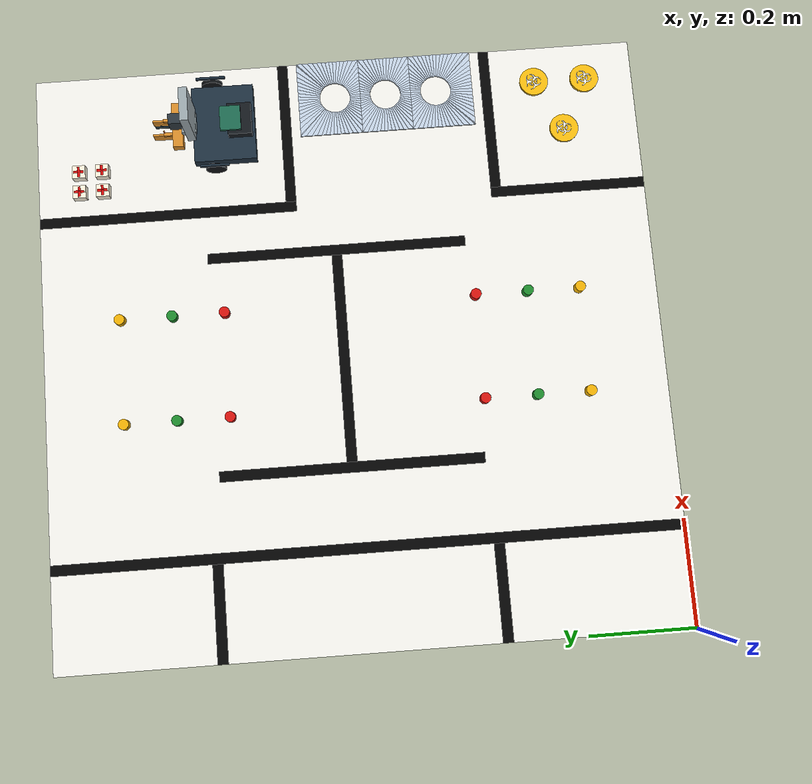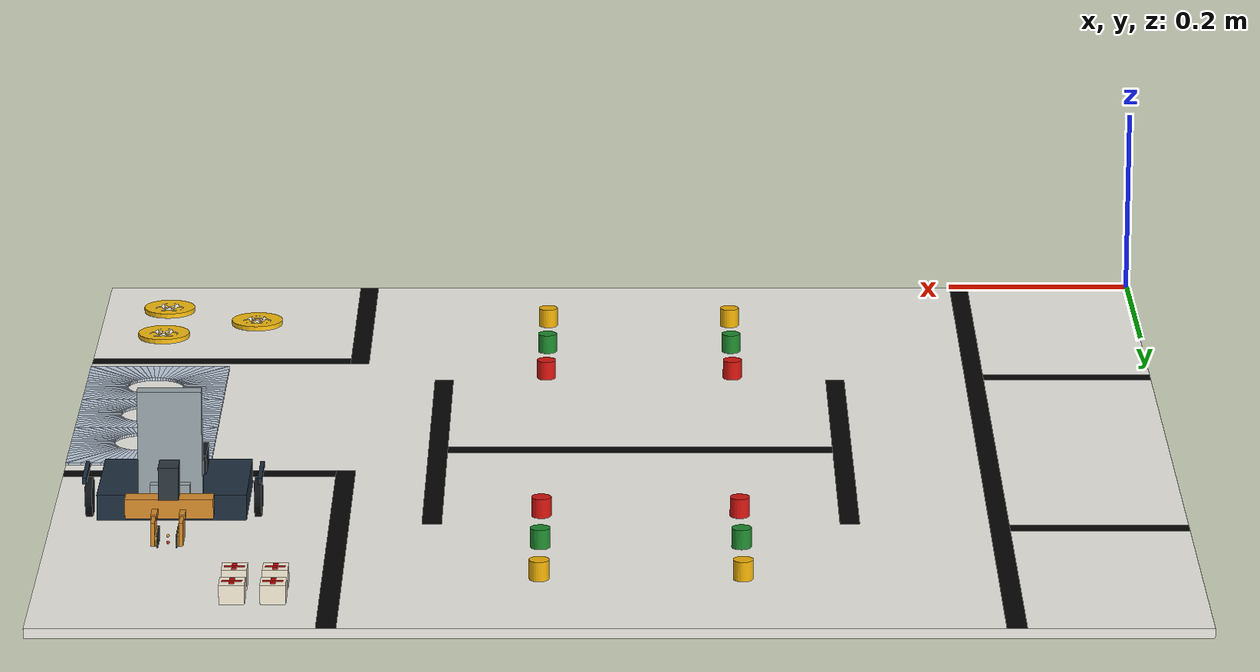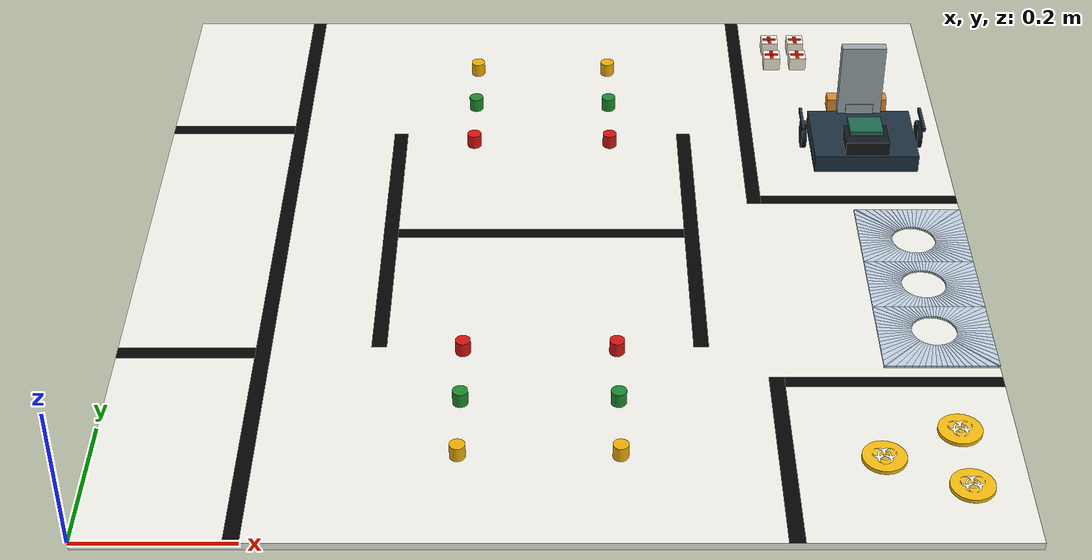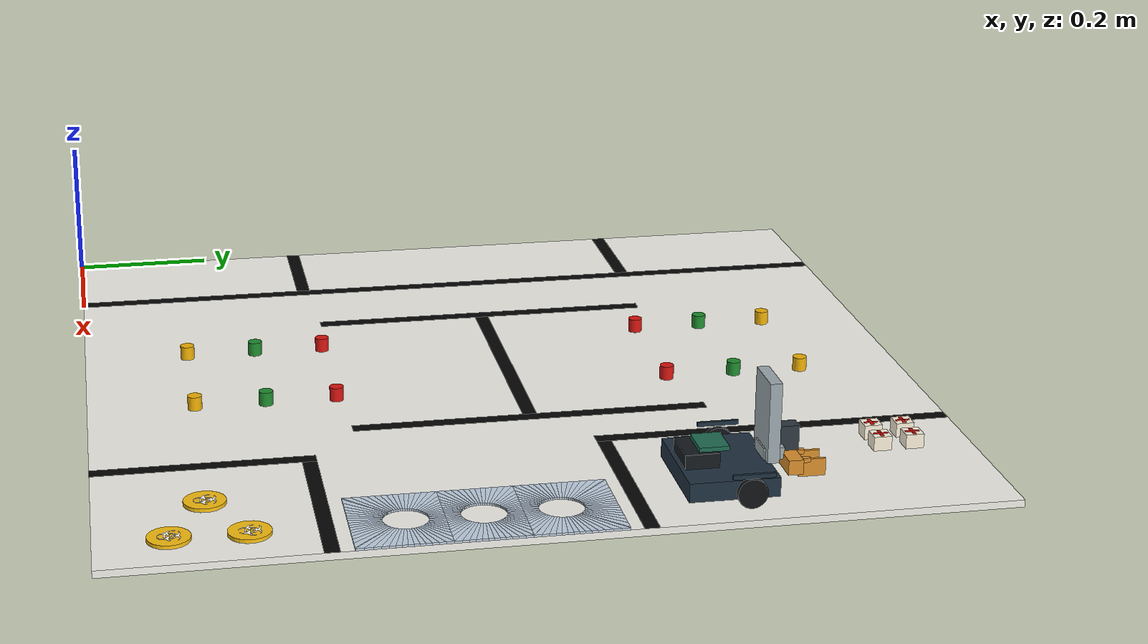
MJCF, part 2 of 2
<pair name="dry_04256" geom1="Biological_Sample_01_geom" geom2="Tape_Center_Left" condim="6" friction="0.466315195961 0.466315195961 0.000444109710439 2.2205485522e-05 2.2205485522e-05" solref="0.001 1" solimp="0.98 0.999 0.0001" adhesion="0" />
    <pair name="dry_04257" geom1="Biological_Sample_01_geom" geom2="Tape_Center_Right" condim="6" friction="0.466315195961 0.466315195961 0.000444109710439 2.2205485522e-05 2.2205485522e-05" solref="0.001 1" solimp="0.98 0.999 0.0001" adhesion="0" />
    <pair name="dry_04258" geom1="Biological_Sample_01_geom" geom2="Tape_Center_Crossbar" condim="6" friction="0.466315195961 0.466315195961 0.000444109710439 2.2205485522e-05 2.2205485522e-05" solref="0.001 1" solimp="0.98 0.999 0.0001" adhesion="0" />
    <pair name="dry_04259" geom1="Biological_Sample_02_geom" geom2="Biological_Sample_03_geom" condim="6" friction="0.445041437998 0.445041437998 0.000356033150398 1.78016575199e-05 1.78016575199e-05" solref="0.001 1" solimp="0.98 0.999 0.0001" adhesion="0" />
    <pair name="dry_04260" geom1="Biological_Sample_02_geom" geom2="Laboratory_Cell_01_Sector_000_geom" condim="6" friction="0.445041437998 0.445041437998 0.000356033150398 1.78016575199e-05 1.78016575199e-05" solref="0.001 1" solimp="0.98 0.999 0.0001" adhesion="0" />
    <pair name="dry_04261" geom1="Biological_Sample_02_geom" geom2="Laboratory_Cell_01_Sector_001_geom" condim="6" friction="0.445041437998 0.445041437998 0.000356033150398 1.78016575199e-05 1.78016575199e-05" solref="0.001 1" solimp="0.98 0.999 0.0001" adhesion="0" />
    <pair name="dry_04262" geom1="Biological_Sample_02_geom" geom2="Laboratory_Cell_01_Sector_002_geom" condim="6" friction="0.445041437998 0.445041437998 0.000356033150398 1.78016575199e-05 1.78016575199e-05" solref="0.001 1" solimp="0.98 0.999 0.0001" adhesion="0" />
    <pair name="dry_04263" geom1="Biological_Sample_02_geom" geom2="Laboratory_Cell_01_Sector_003_geom" condim="6" friction="0.445041437998 0.445041437998 0.000356033150398 1.78016575199e-05 1.78016575199e-05" solref="0.001 1" solimp="0.98 0.999 0.0001" adhesion="0" />
    <pair name="dry_04264" geom1="Biological_Sample_02_geom" geom2="Laboratory_Cell_01_Sector_004_geom" condim="6" friction="0.445041437998 0.445041437998 0.000356033150398 1.78016575199e-05 1.78016575199e-05" solref="0.001 1" solimp="0.98 0.999 0.0001" adhesion="0" />
    <pair name="dry_04265" geom1="Biological_Sample_02_geom" geom2="Laboratory_Cell_01_Sector_005_geom" condim="6" friction="0.445041437998 0.445041437998 0.000356033150398 1.78016575199e-05 1.78016575199e-05" solref="0.001 1" solimp="0.98 0.999 0.0001" adhesion="0" />
    <pair name="dry_04266" geom1="Biological_Sample_02_geom" geom2="Laboratory_Cell_01_Sector_006_geom" condim="6" friction="0.445041437998 0.445041437998 0.000356033150398 1.78016575199e-05 1.78016575199e-05" solref="0.001 1" solimp="0.98 0.999 0.0001" adhesion="0" />
    <pair name="dry_04267" geom1="Biological_Sample_02_geom" geom2="Laboratory_Cell_01_Sector_007_geom" condim="6" friction="0.445041437998 0.445041437998 0.000356033150398 1.78016575199e-05 1.78016575199e-05" solref="0.001 1" solimp="0.98 0.999 0.0001" adhesion="0" />
    <pair name="dry_04268" geom1="Biological_Sample_02_geom" geom2="Laboratory_Cell_01_Sector_008_geom" condim="6" friction="0.445041437998 0.445041437998 0.000356033150398 1.78016575199e-05 1.78016575199e-05" solref="0.001 1" solimp="0.98 0.999 0.0001" adhesion="0" />
    <pair name="dry_04269" geom1="Biological_Sample_02_geom" geom2="Laboratory_Cell_01_Sector_009_geom" condim="6" friction="0.445041437998 0.445041437998 0.000356033150398 1.78016575199e-05 1.78016575199e-05" solref="0.001 1" solimp="0.98 0.999 0.0001" adhesion="0" />
    <pair name="dry_04270" geom1="Biological_Sample_02_geom" geom2="Laboratory_Cell_01_Sector_010_geom" condim="6" friction="0.445041437998 0.445041437998 0.000356033150398 1.78016575199e-05 1.78016575199e-05" solref="0.001 1" solimp="0.98 0.999 0.0001" adhesion="0" />
    <pair name="dry_04271" geom1="Biological_Sample_02_geom" geom2="Laboratory_Cell_01_Sector_011_geom" condim="6" friction="0.445041437998 0.445041437998 0.000356033150398 1.78016575199e-05 1.78016575199e-05" solref="0.001 1" solimp="0.98 0.999 0.0001" adhesion="0" />
    <pair name="dry_04272" geom1="Biological_Sample_02_geom" geom2="Laboratory_Cell_01_Sector_012_geom" condim="6" friction="0.445041437998 0.445041437998 0.000356033150398 1.78016575199e-05 1.78016575199e-05" solref="0.001 1" solimp="0.98 0.999 0.0001" adhesion="0" />
    <pair name="dry_04273" geom1="Biological_Sample_02_geom" geom2="Laboratory_Cell_01_Sector_013_geom" condim="6" friction="0.445041437998 0.445041437998 0.000356033150398 1.78016575199e-05 1.78016575199e-05" solref="0.001 1" solimp="0.98 0.999 0.0001" adhesion="0" />
    <pair name="dry_04274" geom1="Biological_Sample_02_geom" geom2="Laboratory_Cell_01_Sector_014_geom" condim="6" friction="0.445041437998 0.445041437998 0.000356033150398 1.78016575199e-05 1.78016575199e-05" solref="0.001 1" solimp="0.98 0.999 0.0001" adhesion="0" />
    <pair name="dry_04275" geom1="Biological_Sample_02_geom" geom2="Laboratory_Cell_01_Sector_015_geom" condim="6" friction="0.445041437998 0.445041437998 0.000356033150398 1.78016575199e-05 1.78016575199e-05" solref="0.001 1" solimp="0.98 0.999 0.0001" adhesion="0" />
    <pair name="dry_04276" geom1="Biological_Sample_02_geom" geom2="Laboratory_Cell_01_Sector_016_geom" condim="6" friction="0.445041437998 0.445041437998 0.000356033150398 1.78016575199e-05 1.78016575199e-05" solref="0.001 1" solimp="0.98 0.999 0.0001" adhesion="0" />
    <pair name="dry_04277" geom1="Biological_Sample_02_geom" geom2="Laboratory_Cell_01_Sector_017_geom" condim="6" friction="0.445041437998 0.445041437998 0.000356033150398 1.78016575199e-05 1.78016575199e-05" solref="0.001 1" solimp="0.98 0.999 0.0001" adhesion="0" />
    <pair name="dry_04278" geom1="Biological_Sample_02_geom" geom2="Laboratory_Cell_01_Sector_018_geom" condim="6" friction="0.445041437998 0.445041437998 0.000356033150398 1.78016575199e-05 1.78016575199e-05" solref="0.001 1" solimp="0.98 0.999 0.0001" adhesion="0" />
    <pair name="dry_04279" geom1="Biological_Sample_02_geom" geom2="Laboratory_Cell_01_Sector_019_geom" condim="6" friction="0.445041437998 0.445041437998 0.000356033150398 1.78016575199e-05 1.78016575199e-05" solref="0.001 1" solimp="0.98 0.999 0.0001" adhesion="0" />
    <pair name="dry_04280" geom1="Biological_Sample_02_geom" geom2="Laboratory_Cell_01_Sector_020_geom" condim="6" friction="0.445041437998 0.445041437998 0.000356033150398 1.78016575199e-05 1.78016575199e-05" solref="0.001 1" solimp="0.98 0.999 0.0001" adhesion="0" />
    <pair name="dry_04281" geom1="Biological_Sample_02_geom" geom2="Laboratory_Cell_01_Sector_021_geom" condim="6" friction="0.445041437998 0.445041437998 0.000356033150398 1.78016575199e-05 1.78016575199e-05" solref="0.001 1" solimp="0.98 0.999 0.0001" adhesion="0" />
    <pair name="dry_04282" geom1="Biological_Sample_02_geom" geom2="Laboratory_Cell_01_Sector_022_geom" condim="6" friction="0.445041437998 0.445041437998 0.000356033150398 1.78016575199e-05 1.78016575199e-05" solref="0.001 1" solimp="0.98 0.999 0.0001" adhesion="0" />
    <pair name="dry_04283" geom1="Biological_Sample_02_geom" geom2="Laboratory_Cell_01_Sector_023_geom" condim="6" friction="0.445041437998 0.445041437998 0.000356033150398 1.78016575199e-05 1.78016575199e-05" solref="0.001 1" solimp="0.98 0.999 0.0001" adhesion="0" />
    <pair name="dry_04284" geom1="Biological_Sample_02_geom" geom2="Laboratory_Cell_01_Sector_024_geom" condim="6" friction="0.445041437998 0.445041437998 0.000356033150398 1.78016575199e-05 1.78016575199e-05" solref="0.001 1" solimp="0.98 0.999 0.0001" adhesion="0" />
    <pair name="dry_04285" geom1="Biological_Sample_02_geom" geom2="Laboratory_Cell_01_Sector_025_geom" condim="6" friction="0.445041437998 0.445041437998 0.000356033150398 1.78016575199e-05 1.78016575199e-05" solref="0.001 1" solimp="0.98 0.999 0.0001" adhesion="0" />
    <pair name="dry_04286" geom1="Biological_Sample_02_geom" geom2="Laboratory_Cell_01_Sector_026_geom" condim="6" friction="0.445041437998 0.445041437998 0.000356033150398 1.78016575199e-05 1.78016575199e-05" solref="0.001 1" solimp="0.98 0.999 0.0001" adhesion="0" />
    <pair name="dry_04287" geom1="Biological_Sample_02_geom" geom2="Laboratory_Cell_01_Sector_027_geom" condim="6" friction="0.445041437998 0.445041437998 0.000356033150398 1.78016575199e-05 1.78016575199e-05" solref="0.001 1" solimp="0.98 0.999 0.0001" adhesion="0" />
    <pair name="dry_04288" geom1="Biological_Sample_02_geom" geom2="Laboratory_Cell_01_Sector_028_geom" condim="6" friction="0.445041437998 0.445041437998 0.000356033150398 1.78016575199e-05 1.78016575199e-05" solref="0.001 1" solimp="0.98 0.999 0.0001" adhesion="0" />
    <pair name="dry_04289" geom1="Biological_Sample_02_geom" geom2="Laboratory_Cell_01_Sector_029_geom" condim="6" friction="0.445041437998 0.445041437998 0.000356033150398 1.78016575199e-05 1.78016575199e-05" solref="0.001 1" solimp="0.98 0.999 0.0001" adhesion="0" />
    <pair name="dry_04290" geom1="Biological_Sample_02_geom" geom2="Laboratory_Cell_01_Sector_030_geom" condim="6" friction="0.445041437998 0.445041437998 0.000356033150398 1.78016575199e-05 1.78016575199e-05" solref="0.001 1" solimp="0.98 0.999 0.0001" adhesion="0" />
    <pair name="dry_04291" geom1="Biological_Sample_02_geom" geom2="Laboratory_Cell_01_Sector_031_geom" condim="6" friction="0.445041437998 0.445041437998 0.000356033150398 1.78016575199e-05 1.78016575199e-05" solref="0.001 1" solimp="0.98 0.999 0.0001" adhesion="0" />
    <pair name="dry_04292" geom1="Biological_Sample_02_geom" geom2="Laboratory_Cell_01_Sector_032_geom" condim="6" friction="0.445041437998 0.445041437998 0.000356033150398 1.78016575199e-05 1.78016575199e-05" solref="0.001 1" solimp="0.98 0.999 0.0001" adhesion="0" />
    <pair name="dry_04293" geom1="Biological_Sample_02_geom" geom2="Laboratory_Cell_01_Sector_033_geom" condim="6" friction="0.445041437998 0.445041437998 0.000356033150398 1.78016575199e-05 1.78016575199e-05" solref="0.001 1" solimp="0.98 0.999 0.0001" adhesion="0" />
    <pair name="dry_04294" geom1="Biological_Sample_02_geom" geom2="Laboratory_Cell_01_Sector_034_geom" condim="6" friction="0.445041437998 0.445041437998 0.000356033150398 1.78016575199e-05 1.78016575199e-05" solref="0.001 1" solimp="0.98 0.999 0.0001" adhesion="0" />
    <pair name="dry_04295" geom1="Biological_Sample_02_geom" geom2="Laboratory_Cell_01_Sector_035_geom" condim="6" friction="0.445041437998 0.445041437998 0.000356033150398 1.78016575199e-05 1.78016575199e-05" solref="0.001 1" solimp="0.98 0.999 0.0001" adhesion="0" />
    <pair name="dry_04296" geom1="Biological_Sample_02_geom" geom2="Laboratory_Cell_01_Sector_036_geom" condim="6" friction="0.445041437998 0.445041437998 0.000356033150398 1.78016575199e-05 1.78016575199e-05" solref="0.001 1" solimp="0.98 0.999 0.0001" adhesion="0" />
    <pair name="dry_04297" geom1="Biological_Sample_02_geom" geom2="Laboratory_Cell_01_Sector_037_geom" condim="6" friction="0.445041437998 0.445041437998 0.000356033150398 1.78016575199e-05 1.78016575199e-05" solref="0.001 1" solimp="0.98 0.999 0.0001" adhesion="0" />
    <pair name="dry_04298" geom1="Biological_Sample_02_geom" geom2="Laboratory_Cell_01_Sector_038_geom" condim="6" friction="0.445041437998 0.445041437998 0.000356033150398 1.78016575199e-05 1.78016575199e-05" solref="0.001 1" solimp="0.98 0.999 0.0001" adhesion="0" />
    <pair name="dry_04299" geom1="Biological_Sample_02_geom" geom2="Laboratory_Cell_01_Sector_039_geom" condim="6" friction="0.445041437998 0.445041437998 0.000356033150398 1.78016575199e-05 1.78016575199e-05" solref="0.001 1" solimp="0.98 0.999 0.0001" adhesion="0" />
    <pair name="dry_04300" geom1="Biological_Sample_02_geom" geom2="Laboratory_Cell_01_Sector_040_geom" condim="6" friction="0.445041437998 0.445041437998 0.000356033150398 1.78016575199e-05 1.78016575199e-05" solref="0.001 1" solimp="0.98 0.999 0.0001" adhesion="0" />
    <pair name="dry_04301" geom1="Biological_Sample_02_geom" geom2="Laboratory_Cell_01_Sector_041_geom" condim="6" friction="0.445041437998 0.445041437998 0.000356033150398 1.78016575199e-05 1.78016575199e-05" solref="0.001 1" solimp="0.98 0.999 0.0001" adhesion="0" />
    <pair name="dry_04302" geom1="Biological_Sample_02_geom" geom2="Laboratory_Cell_01_Sector_042_geom" condim="6" friction="0.445041437998 0.445041437998 0.000356033150398 1.78016575199e-05 1.78016575199e-05" solref="0.001 1" solimp="0.98 0.999 0.0001" adhesion="0" />
    <pair name="dry_04303" geom1="Biological_Sample_02_geom" geom2="Laboratory_Cell_01_Sector_043_geom" condim="6" friction="0.445041437998 0.445041437998 0.000356033150398 1.78016575199e-05 1.78016575199e-05" solref="0.001 1" solimp="0.98 0.999 0.0001" adhesion="0" />
    <pair name="dry_04304" geom1="Biological_Sample_02_geom" geom2="Laboratory_Cell_01_Sector_044_geom" condim="6" friction="0.445041437998 0.445041437998 0.000356033150398 1.78016575199e-05 1.78016575199e-05" solref="0.001 1" solimp="0.98 0.999 0.0001" adhesion="0" />
    <pair name="dry_04305" geom1="Biological_Sample_02_geom" geom2="Laboratory_Cell_01_Sector_045_geom" condim="6" friction="0.445041437998 0.445041437998 0.000356033150398 1.78016575199e-05 1.78016575199e-05" solref="0.001 1" solimp="0.98 0.999 0.0001" adhesion="0" />
    <pair name="dry_04306" geom1="Biological_Sample_02_geom" geom2="Laboratory_Cell_01_Sector_046_geom" condim="6" friction="0.445041437998 0.445041437998 0.000356033150398 1.78016575199e-05 1.78016575199e-05" solref="0.001 1" solimp="0.98 0.999 0.0001" adhesion="0" />
    <pair name="dry_04307" geom1="Biological_Sample_02_geom" geom2="Laboratory_Cell_01_Sector_047_geom" condim="6" friction="0.445041437998 0.445041437998 0.000356033150398 1.78016575199e-05 1.78016575199e-05" solref="0.001 1" solimp="0.98 0.999 0.0001" adhesion="0" />
    <pair name="dry_04308" geom1="Biological_Sample_02_geom" geom2="Laboratory_Cell_01_Sector_048_geom" condim="6" friction="0.445041437998 0.445041437998 0.000356033150398 1.78016575199e-05 1.78016575199e-05" solref="0.001 1" solimp="0.98 0.999 0.0001" adhesion="0" />
    <pair name="dry_04309" geom1="Biological_Sample_02_geom" geom2="Laboratory_Cell_01_Sector_049_geom" condim="6" friction="0.445041437998 0.445041437998 0.000356033150398 1.78016575199e-05 1.78016575199e-05" solref="0.001 1" solimp="0.98 0.999 0.0001" adhesion="0" />
    <pair name="dry_04310" geom1="Biological_Sample_02_geom" geom2="Laboratory_Cell_01_Sector_050_geom" condim="6" friction="0.445041437998 0.445041437998 0.000356033150398 1.78016575199e-05 1.78016575199e-05" solref="0.001 1" solimp="0.98 0.999 0.0001" adhesion="0" />
    <pair name="dry_04311" geom1="Biological_Sample_02_geom" geom2="Laboratory_Cell_01_Sector_051_geom" condim="6" friction="0.445041437998 0.445041437998 0.000356033150398 1.78016575199e-05 1.78016575199e-05" solref="0.001 1" solimp="0.98 0.999 0.0001" adhesion="0" />
    <pair name="dry_04312" geom1="Biological_Sample_02_geom" geom2="Laboratory_Cell_01_Sector_052_geom" condim="6" friction="0.445041437998 0.445041437998 0.000356033150398 1.78016575199e-05 1.78016575199e-05" solref="0.001 1" solimp="0.98 0.999 0.0001" adhesion="0" />
    <pair name="dry_04313" geom1="Biological_Sample_02_geom" geom2="Laboratory_Cell_01_Sector_053_geom" condim="6" friction="0.445041437998 0.445041437998 0.000356033150398 1.78016575199e-05 1.78016575199e-05" solref="0.001 1" solimp="0.98 0.999 0.0001" adhesion="0" />
    <pair name="dry_04314" geom1="Biological_Sample_02_geom" geom2="Laboratory_Cell_01_Sector_054_geom" condim="6" friction="0.445041437998 0.445041437998 0.000356033150398 1.78016575199e-05 1.78016575199e-05" solref="0.001 1" solimp="0.98 0.999 0.0001" adhesion="0" />
    <pair name="dry_04315" geom1="Biological_Sample_02_geom" geom2="Laboratory_Cell_01_Sector_055_geom" condim="6" friction="0.445041437998 0.445041437998 0.000356033150398 1.78016575199e-05 1.78016575199e-05" solref="0.001 1" solimp="0.98 0.999 0.0001" adhesion="0" />
    <pair name="dry_04316" geom1="Biological_Sample_02_geom" geom2="Laboratory_Cell_01_Sector_056_geom" condim="6" friction="0.445041437998 0.445041437998 0.000356033150398 1.78016575199e-05 1.78016575199e-05" solref="0.001 1" solimp="0.98 0.999 0.0001" adhesion="0" />
    <pair name="dry_04317" geom1="Biological_Sample_02_geom" geom2="Laboratory_Cell_01_Sector_057_geom" condim="6" friction="0.445041437998 0.445041437998 0.000356033150398 1.78016575199e-05 1.78016575199e-05" solref="0.001 1" solimp="0.98 0.999 0.0001" adhesion="0" />
    <pair name="dry_04318" geom1="Biological_Sample_02_geom" geom2="Laboratory_Cell_01_Sector_058_geom" condim="6" friction="0.445041437998 0.445041437998 0.000356033150398 1.78016575199e-05 1.78016575199e-05" solref="0.001 1" solimp="0.98 0.999 0.0001" adhesion="0" />
    <pair name="dry_04319" geom1="Biological_Sample_02_geom" geom2="Laboratory_Cell_01_Sector_059_geom" condim="6" friction="0.445041437998 0.445041437998 0.000356033150398 1.78016575199e-05 1.78016575199e-05" solref="0.001 1" solimp="0.98 0.999 0.0001" adhesion="0" />
    <pair name="dry_04320" geom1="Biological_Sample_02_geom" geom2="Laboratory_Cell_01_Sector_060_geom" condim="6" friction="0.445041437998 0.445041437998 0.000356033150398 1.78016575199e-05 1.78016575199e-05" solref="0.001 1" solimp="0.98 0.999 0.0001" adhesion="0" />
    <pair name="dry_04321" geom1="Biological_Sample_02_geom" geom2="Laboratory_Cell_01_Sector_061_geom" condim="6" friction="0.445041437998 0.445041437998 0.000356033150398 1.78016575199e-05 1.78016575199e-05" solref="0.001 1" solimp="0.98 0.999 0.0001" adhesion="0" />
    <pair name="dry_04322" geom1="Biological_Sample_02_geom" geom2="Laboratory_Cell_01_Sector_062_geom" condim="6" friction="0.445041437998 0.445041437998 0.000356033150398 1.78016575199e-05 1.78016575199e-05" solref="0.001 1" solimp="0.98 0.999 0.0001" adhesion="0" />
    <pair name="dry_04323" geom1="Biological_Sample_02_geom" geom2="Laboratory_Cell_01_Sector_063_geom" condim="6" friction="0.445041437998 0.445041437998 0.000356033150398 1.78016575199e-05 1.78016575199e-05" solref="0.001 1" solimp="0.98 0.999 0.0001" adhesion="0" />
    <pair name="dry_04324" geom1="Biological_Sample_02_geom" geom2="Laboratory_Cell_01_Sector_064_geom" condim="6" friction="0.445041437998 0.445041437998 0.000356033150398 1.78016575199e-05 1.78016575199e-05" solref="0.001 1" solimp="0.98 0.999 0.0001" adhesion="0" />
    <pair name="dry_04325" geom1="Biological_Sample_02_geom" geom2="Laboratory_Cell_01_Sector_065_geom" condim="6" friction="0.445041437998 0.445041437998 0.000356033150398 1.78016575199e-05 1.78016575199e-05" solref="0.001 1" solimp="0.98 0.999 0.0001" adhesion="0" />
    <pair name="dry_04326" geom1="Biological_Sample_02_geom" geom2="Laboratory_Cell_01_Sector_066_geom" condim="6" friction="0.445041437998 0.445041437998 0.000356033150398 1.78016575199e-05 1.78016575199e-05" solref="0.001 1" solimp="0.98 0.999 0.0001" adhesion="0" />
    <pair name="dry_04327" geom1="Biological_Sample_02_geom" geom2="Laboratory_Cell_01_Sector_067_geom" condim="6" friction="0.445041437998 0.445041437998 0.000356033150398 1.78016575199e-05 1.78016575199e-05" solref="0.001 1" solimp="0.98 0.999 0.0001" adhesion="0" />
    <pair name="dry_04328" geom1="Biological_Sample_02_geom" geom2="Laboratory_Cell_02_Sector_000_geom" condim="6" friction="0.445041437998 0.445041437998 0.000356033150398 1.78016575199e-05 1.78016575199e-05" solref="0.001 1" solimp="0.98 0.999 0.0001" adhesion="0" />
    <pair name="dry_04329" geom1="Biological_Sample_02_geom" geom2="Laboratory_Cell_02_Sector_001_geom" condim="6" friction="0.445041437998 0.445041437998 0.000356033150398 1.78016575199e-05 1.78016575199e-05" solref="0.001 1" solimp="0.98 0.999 0.0001" adhesion="0" />
    <pair name="dry_04330" geom1="Biological_Sample_02_geom" geom2="Laboratory_Cell_02_Sector_002_geom" condim="6" friction="0.445041437998 0.445041437998 0.000356033150398 1.78016575199e-05 1.78016575199e-05" solref="0.001 1" solimp="0.98 0.999 0.0001" adhesion="0" />
    <pair name="dry_04331" geom1="Biological_Sample_02_geom" geom2="Laboratory_Cell_02_Sector_003_geom" condim="6" friction="0.445041437998 0.445041437998 0.000356033150398 1.78016575199e-05 1.78016575199e-05" solref="0.001 1" solimp="0.98 0.999 0.0001" adhesion="0" />
    <pair name="dry_04332" geom1="Biological_Sample_02_geom" geom2="Laboratory_Cell_02_Sector_004_geom" condim="6" friction="0.445041437998 0.445041437998 0.000356033150398 1.78016575199e-05 1.78016575199e-05" solref="0.001 1" solimp="0.98 0.999 0.0001" adhesion="0" />
    <pair name="dry_04333" geom1="Biological_Sample_02_geom" geom2="Laboratory_Cell_02_Sector_005_geom" condim="6" friction="0.445041437998 0.445041437998 0.000356033150398 1.78016575199e-05 1.78016575199e-05" solref="0.001 1" solimp="0.98 0.999 0.0001" adhesion="0" />
    <pair name="dry_04334" geom1="Biological_Sample_02_geom" geom2="Laboratory_Cell_02_Sector_006_geom" condim="6" friction="0.445041437998 0.445041437998 0.000356033150398 1.78016575199e-05 1.78016575199e-05" solref="0.001 1" solimp="0.98 0.999 0.0001" adhesion="0" />
    <pair name="dry_04335" geom1="Biological_Sample_02_geom" geom2="Laboratory_Cell_02_Sector_007_geom" condim="6" friction="0.445041437998 0.445041437998 0.000356033150398 1.78016575199e-05 1.78016575199e-05" solref="0.001 1" solimp="0.98 0.999 0.0001" adhesion="0" />
    <pair name="dry_04336" geom1="Biological_Sample_02_geom" geom2="Laboratory_Cell_02_Sector_008_geom" condim="6" friction="0.445041437998 0.445041437998 0.000356033150398 1.78016575199e-05 1.78016575199e-05" solref="0.001 1" solimp="0.98 0.999 0.0001" adhesion="0" />
    <pair name="dry_04337" geom1="Biological_Sample_02_geom" geom2="Laboratory_Cell_02_Sector_009_geom" condim="6" friction="0.445041437998 0.445041437998 0.000356033150398 1.78016575199e-05 1.78016575199e-05" solref="0.001 1" solimp="0.98 0.999 0.0001" adhesion="0" />
    <pair name="dry_04338" geom1="Biological_Sample_02_geom" geom2="Laboratory_Cell_02_Sector_010_geom" condim="6" friction="0.445041437998 0.445041437998 0.000356033150398 1.78016575199e-05 1.78016575199e-05" solref="0.001 1" solimp="0.98 0.999 0.0001" adhesion="0" />
    <pair name="dry_04339" geom1="Biological_Sample_02_geom" geom2="Laboratory_Cell_02_Sector_011_geom" condim="6" friction="0.445041437998 0.445041437998 0.000356033150398 1.78016575199e-05 1.78016575199e-05" solref="0.001 1" solimp="0.98 0.999 0.0001" adhesion="0" />
    <pair name="dry_04340" geom1="Biological_Sample_02_geom" geom2="Laboratory_Cell_02_Sector_012_geom" condim="6" friction="0.445041437998 0.445041437998 0.000356033150398 1.78016575199e-05 1.78016575199e-05" solref="0.001 1" solimp="0.98 0.999 0.0001" adhesion="0" />
    <pair name="dry_04341" geom1="Biological_Sample_02_geom" geom2="Laboratory_Cell_02_Sector_013_geom" condim="6" friction="0.445041437998 0.445041437998 0.000356033150398 1.78016575199e-05 1.78016575199e-05" solref="0.001 1" solimp="0.98 0.999 0.0001" adhesion="0" />
    <pair name="dry_04342" geom1="Biological_Sample_02_geom" geom2="Laboratory_Cell_02_Sector_014_geom" condim="6" friction="0.445041437998 0.445041437998 0.000356033150398 1.78016575199e-05 1.78016575199e-05" solref="0.001 1" solimp="0.98 0.999 0.0001" adhesion="0" />
    <pair name="dry_04343" geom1="Biological_Sample_02_geom" geom2="Laboratory_Cell_02_Sector_015_geom" condim="6" friction="0.445041437998 0.445041437998 0.000356033150398 1.78016575199e-05 1.78016575199e-05" solref="0.001 1" solimp="0.98 0.999 0.0001" adhesion="0" />
    <pair name="dry_04344" geom1="Biological_Sample_02_geom" geom2="Laboratory_Cell_02_Sector_016_geom" condim="6" friction="0.445041437998 0.445041437998 0.000356033150398 1.78016575199e-05 1.78016575199e-05" solref="0.001 1" solimp="0.98 0.999 0.0001" adhesion="0" />
    <pair name="dry_04345" geom1="Biological_Sample_02_geom" geom2="Laboratory_Cell_02_Sector_017_geom" condim="6" friction="0.445041437998 0.445041437998 0.000356033150398 1.78016575199e-05 1.78016575199e-05" solref="0.001 1" solimp="0.98 0.999 0.0001" adhesion="0" />
    <pair name="dry_04346" geom1="Biological_Sample_02_geom" geom2="Laboratory_Cell_02_Sector_018_geom" condim="6" friction="0.445041437998 0.445041437998 0.000356033150398 1.78016575199e-05 1.78016575199e-05" solref="0.001 1" solimp="0.98 0.999 0.0001" adhesion="0" />
    <pair name="dry_04347" geom1="Biological_Sample_02_geom" geom2="Laboratory_Cell_02_Sector_019_geom" condim="6" friction="0.445041437998 0.445041437998 0.000356033150398 1.78016575199e-05 1.78016575199e-05" solref="0.001 1" solimp="0.98 0.999 0.0001" adhesion="0" />
    <pair name="dry_04348" geom1="Biological_Sample_02_geom" geom2="Laboratory_Cell_02_Sector_020_geom" condim="6" friction="0.445041437998 0.445041437998 0.000356033150398 1.78016575199e-05 1.78016575199e-05" solref="0.001 1" solimp="0.98 0.999 0.0001" adhesion="0" />
    <pair name="dry_04349" geom1="Biological_Sample_02_geom" geom2="Laboratory_Cell_02_Sector_021_geom" condim="6" friction="0.445041437998 0.445041437998 0.000356033150398 1.78016575199e-05 1.78016575199e-05" solref="0.001 1" solimp="0.98 0.999 0.0001" adhesion="0" />
    <pair name="dry_04350" geom1="Biological_Sample_02_geom" geom2="Laboratory_Cell_02_Sector_022_geom" condim="6" friction="0.445041437998 0.445041437998 0.000356033150398 1.78016575199e-05 1.78016575199e-05" solref="0.001 1" solimp="0.98 0.999 0.0001" adhesion="0" />
    <pair name="dry_04351" geom1="Biological_Sample_02_geom" geom2="Laboratory_Cell_02_Sector_023_geom" condim="6" friction="0.445041437998 0.445041437998 0.000356033150398 1.78016575199e-05 1.78016575199e-05" solref="0.001 1" solimp="0.98 0.999 0.0001" adhesion="0" />
    <pair name="dry_04352" geom1="Biological_Sample_02_geom" geom2="Laboratory_Cell_02_Sector_024_geom" condim="6" friction="0.445041437998 0.445041437998 0.000356033150398 1.78016575199e-05 1.78016575199e-05" solref="0.001 1" solimp="0.98 0.999 0.0001" adhesion="0" />
    <pair name="dry_04353" geom1="Biological_Sample_02_geom" geom2="Laboratory_Cell_02_Sector_025_geom" condim="6" friction="0.445041437998 0.445041437998 0.000356033150398 1.78016575199e-05 1.78016575199e-05" solref="0.001 1" solimp="0.98 0.999 0.0001" adhesion="0" />
    <pair name="dry_04354" geom1="Biological_Sample_02_geom" geom2="Laboratory_Cell_02_Sector_026_geom" condim="6" friction="0.445041437998 0.445041437998 0.000356033150398 1.78016575199e-05 1.78016575199e-05" solref="0.001 1" solimp="0.98 0.999 0.0001" adhesion="0" />
    <pair name="dry_04355" geom1="Biological_Sample_02_geom" geom2="Laboratory_Cell_02_Sector_027_geom" condim="6" friction="0.445041437998 0.445041437998 0.000356033150398 1.78016575199e-05 1.78016575199e-05" solref="0.001 1" solimp="0.98 0.999 0.0001" adhesion="0" />
    <pair name="dry_04356" geom1="Biological_Sample_02_geom" geom2="Laboratory_Cell_02_Sector_028_geom" condim="6" friction="0.445041437998 0.445041437998 0.000356033150398 1.78016575199e-05 1.78016575199e-05" solref="0.001 1" solimp="0.98 0.999 0.0001" adhesion="0" />
    <pair name="dry_04357" geom1="Biological_Sample_02_geom" geom2="Laboratory_Cell_02_Sector_029_geom" condim="6" friction="0.445041437998 0.445041437998 0.000356033150398 1.78016575199e-05 1.78016575199e-05" solref="0.001 1" solimp="0.98 0.999 0.0001" adhesion="0" />
    <pair name="dry_04358" geom1="Biological_Sample_02_geom" geom2="Laboratory_Cell_02_Sector_030_geom" condim="6" friction="0.445041437998 0.445041437998 0.000356033150398 1.78016575199e-05 1.78016575199e-05" solref="0.001 1" solimp="0.98 0.999 0.0001" adhesion="0" />
    <pair name="dry_04359" geom1="Biological_Sample_02_geom" geom2="Laboratory_Cell_02_Sector_031_geom" condim="6" friction="0.445041437998 0.445041437998 0.000356033150398 1.78016575199e-05 1.78016575199e-05" solref="0.001 1" solimp="0.98 0.999 0.0001" adhesion="0" />
    <pair name="dry_04360" geom1="Biological_Sample_02_geom" geom2="Laboratory_Cell_02_Sector_032_geom" condim="6" friction="0.445041437998 0.445041437998 0.000356033150398 1.78016575199e-05 1.78016575199e-05" solref="0.001 1" solimp="0.98 0.999 0.0001" adhesion="0" />
    <pair name="dry_04361" geom1="Biological_Sample_02_geom" geom2="Laboratory_Cell_02_Sector_033_geom" condim="6" friction="0.445041437998 0.445041437998 0.000356033150398 1.78016575199e-05 1.78016575199e-05" solref="0.001 1" solimp="0.98 0.999 0.0001" adhesion="0" />
    <pair name="dry_04362" geom1="Biological_Sample_02_geom" geom2="Laboratory_Cell_02_Sector_034_geom" condim="6" friction="0.445041437998 0.445041437998 0.000356033150398 1.78016575199e-05 1.78016575199e-05" solref="0.001 1" solimp="0.98 0.999 0.0001" adhesion="0" />
    <pair name="dry_04363" geom1="Biological_Sample_02_geom" geom2="Laboratory_Cell_02_Sector_035_geom" condim="6" friction="0.445041437998 0.445041437998 0.000356033150398 1.78016575199e-05 1.78016575199e-05" solref="0.001 1" solimp="0.98 0.999 0.0001" adhesion="0" />
    <pair name="dry_04364" geom1="Biological_Sample_02_geom" geom2="Laboratory_Cell_02_Sector_036_geom" condim="6" friction="0.445041437998 0.445041437998 0.000356033150398 1.78016575199e-05 1.78016575199e-05" solref="0.001 1" solimp="0.98 0.999 0.0001" adhesion="0" />
    <pair name="dry_04365" geom1="Biological_Sample_02_geom" geom2="Laboratory_Cell_02_Sector_037_geom" condim="6" friction="0.445041437998 0.445041437998 0.000356033150398 1.78016575199e-05 1.78016575199e-05" solref="0.001 1" solimp="0.98 0.999 0.0001" adhesion="0" />
    <pair name="dry_04366" geom1="Biological_Sample_02_geom" geom2="Laboratory_Cell_02_Sector_038_geom" condim="6" friction="0.445041437998 0.445041437998 0.000356033150398 1.78016575199e-05 1.78016575199e-05" solref="0.001 1" solimp="0.98 0.999 0.0001" adhesion="0" />
    <pair name="dry_04367" geom1="Biological_Sample_02_geom" geom2="Laboratory_Cell_02_Sector_039_geom" condim="6" friction="0.445041437998 0.445041437998 0.000356033150398 1.78016575199e-05 1.78016575199e-05" solref="0.001 1" solimp="0.98 0.999 0.0001" adhesion="0" />
    <pair name="dry_04368" geom1="Biological_Sample_02_geom" geom2="Laboratory_Cell_02_Sector_040_geom" condim="6" friction="0.445041437998 0.445041437998 0.000356033150398 1.78016575199e-05 1.78016575199e-05" solref="0.001 1" solimp="0.98 0.999 0.0001" adhesion="0" />
    <pair name="dry_04369" geom1="Biological_Sample_02_geom" geom2="Laboratory_Cell_02_Sector_041_geom" condim="6" friction="0.445041437998 0.445041437998 0.000356033150398 1.78016575199e-05 1.78016575199e-05" solref="0.001 1" solimp="0.98 0.999 0.0001" adhesion="0" />
    <pair name="dry_04370" geom1="Biological_Sample_02_geom" geom2="Laboratory_Cell_02_Sector_042_geom" condim="6" friction="0.445041437998 0.445041437998 0.000356033150398 1.78016575199e-05 1.78016575199e-05" solref="0.001 1" solimp="0.98 0.999 0.0001" adhesion="0" />
    <pair name="dry_04371" geom1="Biological_Sample_02_geom" geom2="Laboratory_Cell_02_Sector_043_geom" condim="6" friction="0.445041437998 0.445041437998 0.000356033150398 1.78016575199e-05 1.78016575199e-05" solref="0.001 1" solimp="0.98 0.999 0.0001" adhesion="0" />
    <pair name="dry_04372" geom1="Biological_Sample_02_geom" geom2="Laboratory_Cell_02_Sector_044_geom" condim="6" friction="0.445041437998 0.445041437998 0.000356033150398 1.78016575199e-05 1.78016575199e-05" solref="0.001 1" solimp="0.98 0.999 0.0001" adhesion="0" />
    <pair name="dry_04373" geom1="Biological_Sample_02_geom" geom2="Laboratory_Cell_02_Sector_045_geom" condim="6" friction="0.445041437998 0.445041437998 0.000356033150398 1.78016575199e-05 1.78016575199e-05" solref="0.001 1" solimp="0.98 0.999 0.0001" adhesion="0" />
    <pair name="dry_04374" geom1="Biological_Sample_02_geom" geom2="Laboratory_Cell_02_Sector_046_geom" condim="6" friction="0.445041437998 0.445041437998 0.000356033150398 1.78016575199e-05 1.78016575199e-05" solref="0.001 1" solimp="0.98 0.999 0.0001" adhesion="0" />
    <pair name="dry_04375" geom1="Biological_Sample_02_geom" geom2="Laboratory_Cell_02_Sector_047_geom" condim="6" friction="0.445041437998 0.445041437998 0.000356033150398 1.78016575199e-05 1.78016575199e-05" solref="0.001 1" solimp="0.98 0.999 0.0001" adhesion="0" />
    <pair name="dry_04376" geom1="Biological_Sample_02_geom" geom2="Laboratory_Cell_02_Sector_048_geom" condim="6" friction="0.445041437998 0.445041437998 0.000356033150398 1.78016575199e-05 1.78016575199e-05" solref="0.001 1" solimp="0.98 0.999 0.0001" adhesion="0" />
    <pair name="dry_04377" geom1="Biological_Sample_02_geom" geom2="Laboratory_Cell_02_Sector_049_geom" condim="6" friction="0.445041437998 0.445041437998 0.000356033150398 1.78016575199e-05 1.78016575199e-05" solref="0.001 1" solimp="0.98 0.999 0.0001" adhesion="0" />
    <pair name="dry_04378" geom1="Biological_Sample_02_geom" geom2="Laboratory_Cell_02_Sector_050_geom" condim="6" friction="0.445041437998 0.445041437998 0.000356033150398 1.78016575199e-05 1.78016575199e-05" solref="0.001 1" solimp="0.98 0.999 0.0001" adhesion="0" />
    <pair name="dry_04379" geom1="Biological_Sample_02_geom" geom2="Laboratory_Cell_02_Sector_051_geom" condim="6" friction="0.445041437998 0.445041437998 0.000356033150398 1.78016575199e-05 1.78016575199e-05" solref="0.001 1" solimp="0.98 0.999 0.0001" adhesion="0" />
    <pair name="dry_04380" geom1="Biological_Sample_02_geom" geom2="Laboratory_Cell_02_Sector_052_geom" condim="6" friction="0.445041437998 0.445041437998 0.000356033150398 1.78016575199e-05 1.78016575199e-05" solref="0.001 1" solimp="0.98 0.999 0.0001" adhesion="0" />
    <pair name="dry_04381" geom1="Biological_Sample_02_geom" geom2="Laboratory_Cell_02_Sector_053_geom" condim="6" friction="0.445041437998 0.445041437998 0.000356033150398 1.78016575199e-05 1.78016575199e-05" solref="0.001 1" solimp="0.98 0.999 0.0001" adhesion="0" />
    <pair name="dry_04382" geom1="Biological_Sample_02_geom" geom2="Laboratory_Cell_02_Sector_054_geom" condim="6" friction="0.445041437998 0.445041437998 0.000356033150398 1.78016575199e-05 1.78016575199e-05" solref="0.001 1" solimp="0.98 0.999 0.0001" adhesion="0" />
    <pair name="dry_04383" geom1="Biological_Sample_02_geom" geom2="Laboratory_Cell_02_Sector_055_geom" condim="6" friction="0.445041437998 0.445041437998 0.000356033150398 1.78016575199e-05 1.78016575199e-05" solref="0.001 1" solimp="0.98 0.999 0.0001" adhesion="0" />
    <pair name="dry_04384" geom1="Biological_Sample_02_geom" geom2="Laboratory_Cell_02_Sector_056_geom" condim="6" friction="0.445041437998 0.445041437998 0.000356033150398 1.78016575199e-05 1.78016575199e-05" solref="0.001 1" solimp="0.98 0.999 0.0001" adhesion="0" />
    <pair name="dry_04385" geom1="Biological_Sample_02_geom" geom2="Laboratory_Cell_02_Sector_057_geom" condim="6" friction="0.445041437998 0.445041437998 0.000356033150398 1.78016575199e-05 1.78016575199e-05" solref="0.001 1" solimp="0.98 0.999 0.0001" adhesion="0" />
    <pair name="dry_04386" geom1="Biological_Sample_02_geom" geom2="Laboratory_Cell_02_Sector_058_geom" condim="6" friction="0.445041437998 0.445041437998 0.000356033150398 1.78016575199e-05 1.78016575199e-05" solref="0.001 1" solimp="0.98 0.999 0.0001" adhesion="0" />
    <pair name="dry_04387" geom1="Biological_Sample_02_geom" geom2="Laboratory_Cell_02_Sector_059_geom" condim="6" friction="0.445041437998 0.445041437998 0.000356033150398 1.78016575199e-05 1.78016575199e-05" solref="0.001 1" solimp="0.98 0.999 0.0001" adhesion="0" />
    <pair name="dry_04388" geom1="Biological_Sample_02_geom" geom2="Laboratory_Cell_02_Sector_060_geom" condim="6" friction="0.445041437998 0.445041437998 0.000356033150398 1.78016575199e-05 1.78016575199e-05" solref="0.001 1" solimp="0.98 0.999 0.0001" adhesion="0" />
    <pair name="dry_04389" geom1="Biological_Sample_02_geom" geom2="Laboratory_Cell_02_Sector_061_geom" condim="6" friction="0.445041437998 0.445041437998 0.000356033150398 1.78016575199e-05 1.78016575199e-05" solref="0.001 1" solimp="0.98 0.999 0.0001" adhesion="0" />
    <pair name="dry_04390" geom1="Biological_Sample_02_geom" geom2="Laboratory_Cell_02_Sector_062_geom" condim="6" friction="0.445041437998 0.445041437998 0.000356033150398 1.78016575199e-05 1.78016575199e-05" solref="0.001 1" solimp="0.98 0.999 0.0001" adhesion="0" />
    <pair name="dry_04391" geom1="Biological_Sample_02_geom" geom2="Laboratory_Cell_02_Sector_063_geom" condim="6" friction="0.445041437998 0.445041437998 0.000356033150398 1.78016575199e-05 1.78016575199e-05" solref="0.001 1" solimp="0.98 0.999 0.0001" adhesion="0" />
    <pair name="dry_04392" geom1="Biological_Sample_02_geom" geom2="Laboratory_Cell_02_Sector_064_geom" condim="6" friction="0.445041437998 0.445041437998 0.000356033150398 1.78016575199e-05 1.78016575199e-05" solref="0.001 1" solimp="0.98 0.999 0.0001" adhesion="0" />
    <pair name="dry_04393" geom1="Biological_Sample_02_geom" geom2="Laboratory_Cell_02_Sector_065_geom" condim="6" friction="0.445041437998 0.445041437998 0.000356033150398 1.78016575199e-05 1.78016575199e-05" solref="0.001 1" solimp="0.98 0.999 0.0001" adhesion="0" />
    <pair name="dry_04394" geom1="Biological_Sample_02_geom" geom2="Laboratory_Cell_02_Sector_066_geom" condim="6" friction="0.445041437998 0.445041437998 0.000356033150398 1.78016575199e-05 1.78016575199e-05" solref="0.001 1" solimp="0.98 0.999 0.0001" adhesion="0" />
    <pair name="dry_04395" geom1="Biological_Sample_02_geom" geom2="Laboratory_Cell_02_Sector_067_geom" condim="6" friction="0.445041437998 0.445041437998 0.000356033150398 1.78016575199e-05 1.78016575199e-05" solref="0.001 1" solimp="0.98 0.999 0.0001" adhesion="0" />
    <pair name="dry_04396" geom1="Biological_Sample_02_geom" geom2="Laboratory_Cell_03_Sector_000_geom" condim="6" friction="0.445041437998 0.445041437998 0.000356033150398 1.78016575199e-05 1.78016575199e-05" solref="0.001 1" solimp="0.98 0.999 0.0001" adhesion="0" />
    <pair name="dry_04397" geom1="Biological_Sample_02_geom" geom2="Laboratory_Cell_03_Sector_001_geom" condim="6" friction="0.445041437998 0.445041437998 0.000356033150398 1.78016575199e-05 1.78016575199e-05" solref="0.001 1" solimp="0.98 0.999 0.0001" adhesion="0" />
    <pair name="dry_04398" geom1="Biological_Sample_02_geom" geom2="Laboratory_Cell_03_Sector_002_geom" condim="6" friction="0.445041437998 0.445041437998 0.000356033150398 1.78016575199e-05 1.78016575199e-05" solref="0.001 1" solimp="0.98 0.999 0.0001" adhesion="0" />
    <pair name="dry_04399" geom1="Biological_Sample_02_geom" geom2="Laboratory_Cell_03_Sector_003_geom" condim="6" friction="0.445041437998 0.445041437998 0.000356033150398 1.78016575199e-05 1.78016575199e-05" solref="0.001 1" solimp="0.98 0.999 0.0001" adhesion="0" />
    <pair name="dry_04400" geom1="Biological_Sample_02_geom" geom2="Laboratory_Cell_03_Sector_004_geom" condim="6" friction="0.445041437998 0.445041437998 0.000356033150398 1.78016575199e-05 1.78016575199e-05" solref="0.001 1" solimp="0.98 0.999 0.0001" adhesion="0" />
    <pair name="dry_04401" geom1="Biological_Sample_02_geom" geom2="Laboratory_Cell_03_Sector_005_geom" condim="6" friction="0.445041437998 0.445041437998 0.000356033150398 1.78016575199e-05 1.78016575199e-05" solref="0.001 1" solimp="0.98 0.999 0.0001" adhesion="0" />
    <pair name="dry_04402" geom1="Biological_Sample_02_geom" geom2="Laboratory_Cell_03_Sector_006_geom" condim="6" friction="0.445041437998 0.445041437998 0.000356033150398 1.78016575199e-05 1.78016575199e-05" solref="0.001 1" solimp="0.98 0.999 0.0001" adhesion="0" />
    <pair name="dry_04403" geom1="Biological_Sample_02_geom" geom2="Laboratory_Cell_03_Sector_007_geom" condim="6" friction="0.445041437998 0.445041437998 0.000356033150398 1.78016575199e-05 1.78016575199e-05" solref="0.001 1" solimp="0.98 0.999 0.0001" adhesion="0" />
    <pair name="dry_04404" geom1="Biological_Sample_02_geom" geom2="Laboratory_Cell_03_Sector_008_geom" condim="6" friction="0.445041437998 0.445041437998 0.000356033150398 1.78016575199e-05 1.78016575199e-05" solref="0.001 1" solimp="0.98 0.999 0.0001" adhesion="0" />
    <pair name="dry_04405" geom1="Biological_Sample_02_geom" geom2="Laboratory_Cell_03_Sector_009_geom" condim="6" friction="0.445041437998 0.445041437998 0.000356033150398 1.78016575199e-05 1.78016575199e-05" solref="0.001 1" solimp="0.98 0.999 0.0001" adhesion="0" />
    <pair name="dry_04406" geom1="Biological_Sample_02_geom" geom2="Laboratory_Cell_03_Sector_010_geom" condim="6" friction="0.445041437998 0.445041437998 0.000356033150398 1.78016575199e-05 1.78016575199e-05" solref="0.001 1" solimp="0.98 0.999 0.0001" adhesion="0" />
    <pair name="dry_04407" geom1="Biological_Sample_02_geom" geom2="Laboratory_Cell_03_Sector_011_geom" condim="6" friction="0.445041437998 0.445041437998 0.000356033150398 1.78016575199e-05 1.78016575199e-05" solref="0.001 1" solimp="0.98 0.999 0.0001" adhesion="0" />
    <pair name="dry_04408" geom1="Biological_Sample_02_geom" geom2="Laboratory_Cell_03_Sector_012_geom" condim="6" friction="0.445041437998 0.445041437998 0.000356033150398 1.78016575199e-05 1.78016575199e-05" solref="0.001 1" solimp="0.98 0.999 0.0001" adhesion="0" />
    <pair name="dry_04409" geom1="Biological_Sample_02_geom" geom2="Laboratory_Cell_03_Sector_013_geom" condim="6" friction="0.445041437998 0.445041437998 0.000356033150398 1.78016575199e-05 1.78016575199e-05" solref="0.001 1" solimp="0.98 0.999 0.0001" adhesion="0" />
    <pair name="dry_04410" geom1="Biological_Sample_02_geom" geom2="Laboratory_Cell_03_Sector_014_geom" condim="6" friction="0.445041437998 0.445041437998 0.000356033150398 1.78016575199e-05 1.78016575199e-05" solref="0.001 1" solimp="0.98 0.999 0.0001" adhesion="0" />
    <pair name="dry_04411" geom1="Biological_Sample_02_geom" geom2="Laboratory_Cell_03_Sector_015_geom" condim="6" friction="0.445041437998 0.445041437998 0.000356033150398 1.78016575199e-05 1.78016575199e-05" solref="0.001 1" solimp="0.98 0.999 0.0001" adhesion="0" />
    <pair name="dry_04412" geom1="Biological_Sample_02_geom" geom2="Laboratory_Cell_03_Sector_016_geom" condim="6" friction="0.445041437998 0.445041437998 0.000356033150398 1.78016575199e-05 1.78016575199e-05" solref="0.001 1" solimp="0.98 0.999 0.0001" adhesion="0" />
    <pair name="dry_04413" geom1="Biological_Sample_02_geom" geom2="Laboratory_Cell_03_Sector_017_geom" condim="6" friction="0.445041437998 0.445041437998 0.000356033150398 1.78016575199e-05 1.78016575199e-05" solref="0.001 1" solimp="0.98 0.999 0.0001" adhesion="0" />
    <pair name="dry_04414" geom1="Biological_Sample_02_geom" geom2="Laboratory_Cell_03_Sector_018_geom" condim="6" friction="0.445041437998 0.445041437998 0.000356033150398 1.78016575199e-05 1.78016575199e-05" solref="0.001 1" solimp="0.98 0.999 0.0001" adhesion="0" />
    <pair name="dry_04415" geom1="Biological_Sample_02_geom" geom2="Laboratory_Cell_03_Sector_019_geom" condim="6" friction="0.445041437998 0.445041437998 0.000356033150398 1.78016575199e-05 1.78016575199e-05" solref="0.001 1" solimp="0.98 0.999 0.0001" adhesion="0" />
    <pair name="dry_04416" geom1="Biological_Sample_02_geom" geom2="Laboratory_Cell_03_Sector_020_geom" condim="6" friction="0.445041437998 0.445041437998 0.000356033150398 1.78016575199e-05 1.78016575199e-05" solref="0.001 1" solimp="0.98 0.999 0.0001" adhesion="0" />
    <pair name="dry_04417" geom1="Biological_Sample_02_geom" geom2="Laboratory_Cell_03_Sector_021_geom" condim="6" friction="0.445041437998 0.445041437998 0.000356033150398 1.78016575199e-05 1.78016575199e-05" solref="0.001 1" solimp="0.98 0.999 0.0001" adhesion="0" />
    <pair name="dry_04418" geom1="Biological_Sample_02_geom" geom2="Laboratory_Cell_03_Sector_022_geom" condim="6" friction="0.445041437998 0.445041437998 0.000356033150398 1.78016575199e-05 1.78016575199e-05" solref="0.001 1" solimp="0.98 0.999 0.0001" adhesion="0" />
    <pair name="dry_04419" geom1="Biological_Sample_02_geom" geom2="Laboratory_Cell_03_Sector_023_geom" condim="6" friction="0.445041437998 0.445041437998 0.000356033150398 1.78016575199e-05 1.78016575199e-05" solref="0.001 1" solimp="0.98 0.999 0.0001" adhesion="0" />
    <pair name="dry_04420" geom1="Biological_Sample_02_geom" geom2="Laboratory_Cell_03_Sector_024_geom" condim="6" friction="0.445041437998 0.445041437998 0.000356033150398 1.78016575199e-05 1.78016575199e-05" solref="0.001 1" solimp="0.98 0.999 0.0001" adhesion="0" />
    <pair name="dry_04421" geom1="Biological_Sample_02_geom" geom2="Laboratory_Cell_03_Sector_025_geom" condim="6" friction="0.445041437998 0.445041437998 0.000356033150398 1.78016575199e-05 1.78016575199e-05" solref="0.001 1" solimp="0.98 0.999 0.0001" adhesion="0" />
    <pair name="dry_04422" geom1="Biological_Sample_02_geom" geom2="Laboratory_Cell_03_Sector_026_geom" condim="6" friction="0.445041437998 0.445041437998 0.000356033150398 1.78016575199e-05 1.78016575199e-05" solref="0.001 1" solimp="0.98 0.999 0.0001" adhesion="0" />
    <pair name="dry_04423" geom1="Biological_Sample_02_geom" geom2="Laboratory_Cell_03_Sector_027_geom" condim="6" friction="0.445041437998 0.445041437998 0.000356033150398 1.78016575199e-05 1.78016575199e-05" solref="0.001 1" solimp="0.98 0.999 0.0001" adhesion="0" />
    <pair name="dry_04424" geom1="Biological_Sample_02_geom" geom2="Laboratory_Cell_03_Sector_028_geom" condim="6" friction="0.445041437998 0.445041437998 0.000356033150398 1.78016575199e-05 1.78016575199e-05" solref="0.001 1" solimp="0.98 0.999 0.0001" adhesion="0" />
    <pair name="dry_04425" geom1="Biological_Sample_02_geom" geom2="Laboratory_Cell_03_Sector_029_geom" condim="6" friction="0.445041437998 0.445041437998 0.000356033150398 1.78016575199e-05 1.78016575199e-05" solref="0.001 1" solimp="0.98 0.999 0.0001" adhesion="0" />
    <pair name="dry_04426" geom1="Biological_Sample_02_geom" geom2="Laboratory_Cell_03_Sector_030_geom" condim="6" friction="0.445041437998 0.445041437998 0.000356033150398 1.78016575199e-05 1.78016575199e-05" solref="0.001 1" solimp="0.98 0.999 0.0001" adhesion="0" />
    <pair name="dry_04427" geom1="Biological_Sample_02_geom" geom2="Laboratory_Cell_03_Sector_031_geom" condim="6" friction="0.445041437998 0.445041437998 0.000356033150398 1.78016575199e-05 1.78016575199e-05" solref="0.001 1" solimp="0.98 0.999 0.0001" adhesion="0" />
    <pair name="dry_04428" geom1="Biological_Sample_02_geom" geom2="Laboratory_Cell_03_Sector_032_geom" condim="6" friction="0.445041437998 0.445041437998 0.000356033150398 1.78016575199e-05 1.78016575199e-05" solref="0.001 1" solimp="0.98 0.999 0.0001" adhesion="0" />
    <pair name="dry_04429" geom1="Biological_Sample_02_geom" geom2="Laboratory_Cell_03_Sector_033_geom" condim="6" friction="0.445041437998 0.445041437998 0.000356033150398 1.78016575199e-05 1.78016575199e-05" solref="0.001 1" solimp="0.98 0.999 0.0001" adhesion="0" />
    <pair name="dry_04430" geom1="Biological_Sample_02_geom" geom2="Laboratory_Cell_03_Sector_034_geom" condim="6" friction="0.445041437998 0.445041437998 0.000356033150398 1.78016575199e-05 1.78016575199e-05" solref="0.001 1" solimp="0.98 0.999 0.0001" adhesion="0" />
    <pair name="dry_04431" geom1="Biological_Sample_02_geom" geom2="Laboratory_Cell_03_Sector_035_geom" condim="6" friction="0.445041437998 0.445041437998 0.000356033150398 1.78016575199e-05 1.78016575199e-05" solref="0.001 1" solimp="0.98 0.999 0.0001" adhesion="0" />
    <pair name="dry_04432" geom1="Biological_Sample_02_geom" geom2="Laboratory_Cell_03_Sector_036_geom" condim="6" friction="0.445041437998 0.445041437998 0.000356033150398 1.78016575199e-05 1.78016575199e-05" solref="0.001 1" solimp="0.98 0.999 0.0001" adhesion="0" />
    <pair name="dry_04433" geom1="Biological_Sample_02_geom" geom2="Laboratory_Cell_03_Sector_037_geom" condim="6" friction="0.445041437998 0.445041437998 0.000356033150398 1.78016575199e-05 1.78016575199e-05" solref="0.001 1" solimp="0.98 0.999 0.0001" adhesion="0" />
    <pair name="dry_04434" geom1="Biological_Sample_02_geom" geom2="Laboratory_Cell_03_Sector_038_geom" condim="6" friction="0.445041437998 0.445041437998 0.000356033150398 1.78016575199e-05 1.78016575199e-05" solref="0.001 1" solimp="0.98 0.999 0.0001" adhesion="0" />
    <pair name="dry_04435" geom1="Biological_Sample_02_geom" geom2="Laboratory_Cell_03_Sector_039_geom" condim="6" friction="0.445041437998 0.445041437998 0.000356033150398 1.78016575199e-05 1.78016575199e-05" solref="0.001 1" solimp="0.98 0.999 0.0001" adhesion="0" />
    <pair name="dry_04436" geom1="Biological_Sample_02_geom" geom2="Laboratory_Cell_03_Sector_040_geom" condim="6" friction="0.445041437998 0.445041437998 0.000356033150398 1.78016575199e-05 1.78016575199e-05" solref="0.001 1" solimp="0.98 0.999 0.0001" adhesion="0" />
    <pair name="dry_04437" geom1="Biological_Sample_02_geom" geom2="Laboratory_Cell_03_Sector_041_geom" condim="6" friction="0.445041437998 0.445041437998 0.000356033150398 1.78016575199e-05 1.78016575199e-05" solref="0.001 1" solimp="0.98 0.999 0.0001" adhesion="0" />
    <pair name="dry_04438" geom1="Biological_Sample_02_geom" geom2="Laboratory_Cell_03_Sector_042_geom" condim="6" friction="0.445041437998 0.445041437998 0.000356033150398 1.78016575199e-05 1.78016575199e-05" solref="0.001 1" solimp="0.98 0.999 0.0001" adhesion="0" />
    <pair name="dry_04439" geom1="Biological_Sample_02_geom" geom2="Laboratory_Cell_03_Sector_043_geom" condim="6" friction="0.445041437998 0.445041437998 0.000356033150398 1.78016575199e-05 1.78016575199e-05" solref="0.001 1" solimp="0.98 0.999 0.0001" adhesion="0" />
    <pair name="dry_04440" geom1="Biological_Sample_02_geom" geom2="Laboratory_Cell_03_Sector_044_geom" condim="6" friction="0.445041437998 0.445041437998 0.000356033150398 1.78016575199e-05 1.78016575199e-05" solref="0.001 1" solimp="0.98 0.999 0.0001" adhesion="0" />
    <pair name="dry_04441" geom1="Biological_Sample_02_geom" geom2="Laboratory_Cell_03_Sector_045_geom" condim="6" friction="0.445041437998 0.445041437998 0.000356033150398 1.78016575199e-05 1.78016575199e-05" solref="0.001 1" solimp="0.98 0.999 0.0001" adhesion="0" />
    <pair name="dry_04442" geom1="Biological_Sample_02_geom" geom2="Laboratory_Cell_03_Sector_046_geom" condim="6" friction="0.445041437998 0.445041437998 0.000356033150398 1.78016575199e-05 1.78016575199e-05" solref="0.001 1" solimp="0.98 0.999 0.0001" adhesion="0" />
    <pair name="dry_04443" geom1="Biological_Sample_02_geom" geom2="Laboratory_Cell_03_Sector_047_geom" condim="6" friction="0.445041437998 0.445041437998 0.000356033150398 1.78016575199e-05 1.78016575199e-05" solref="0.001 1" solimp="0.98 0.999 0.0001" adhesion="0" />
    <pair name="dry_04444" geom1="Biological_Sample_02_geom" geom2="Laboratory_Cell_03_Sector_048_geom" condim="6" friction="0.445041437998 0.445041437998 0.000356033150398 1.78016575199e-05 1.78016575199e-05" solref="0.001 1" solimp="0.98 0.999 0.0001" adhesion="0" />
    <pair name="dry_04445" geom1="Biological_Sample_02_geom" geom2="Laboratory_Cell_03_Sector_049_geom" condim="6" friction="0.445041437998 0.445041437998 0.000356033150398 1.78016575199e-05 1.78016575199e-05" solref="0.001 1" solimp="0.98 0.999 0.0001" adhesion="0" />
    <pair name="dry_04446" geom1="Biological_Sample_02_geom" geom2="Laboratory_Cell_03_Sector_050_geom" condim="6" friction="0.445041437998 0.445041437998 0.000356033150398 1.78016575199e-05 1.78016575199e-05" solref="0.001 1" solimp="0.98 0.999 0.0001" adhesion="0" />
    <pair name="dry_04447" geom1="Biological_Sample_02_geom" geom2="Laboratory_Cell_03_Sector_051_geom" condim="6" friction="0.445041437998 0.445041437998 0.000356033150398 1.78016575199e-05 1.78016575199e-05" solref="0.001 1" solimp="0.98 0.999 0.0001" adhesion="0" />
    <pair name="dry_04448" geom1="Biological_Sample_02_geom" geom2="Laboratory_Cell_03_Sector_052_geom" condim="6" friction="0.445041437998 0.445041437998 0.000356033150398 1.78016575199e-05 1.78016575199e-05" solref="0.001 1" solimp="0.98 0.999 0.0001" adhesion="0" />
    <pair name="dry_04449" geom1="Biological_Sample_02_geom" geom2="Laboratory_Cell_03_Sector_053_geom" condim="6" friction="0.445041437998 0.445041437998 0.000356033150398 1.78016575199e-05 1.78016575199e-05" solref="0.001 1" solimp="0.98 0.999 0.0001" adhesion="0" />
    <pair name="dry_04450" geom1="Biological_Sample_02_geom" geom2="Laboratory_Cell_03_Sector_054_geom" condim="6" friction="0.445041437998 0.445041437998 0.000356033150398 1.78016575199e-05 1.78016575199e-05" solref="0.001 1" solimp="0.98 0.999 0.0001" adhesion="0" />
    <pair name="dry_04451" geom1="Biological_Sample_02_geom" geom2="Laboratory_Cell_03_Sector_055_geom" condim="6" friction="0.445041437998 0.445041437998 0.000356033150398 1.78016575199e-05 1.78016575199e-05" solref="0.001 1" solimp="0.98 0.999 0.0001" adhesion="0" />
    <pair name="dry_04452" geom1="Biological_Sample_02_geom" geom2="Laboratory_Cell_03_Sector_056_geom" condim="6" friction="0.445041437998 0.445041437998 0.000356033150398 1.78016575199e-05 1.78016575199e-05" solref="0.001 1" solimp="0.98 0.999 0.0001" adhesion="0" />
    <pair name="dry_04453" geom1="Biological_Sample_02_geom" geom2="Laboratory_Cell_03_Sector_057_geom" condim="6" friction="0.445041437998 0.445041437998 0.000356033150398 1.78016575199e-05 1.78016575199e-05" solref="0.001 1" solimp="0.98 0.999 0.0001" adhesion="0" />
    <pair name="dry_04454" geom1="Biological_Sample_02_geom" geom2="Laboratory_Cell_03_Sector_058_geom" condim="6" friction="0.445041437998 0.445041437998 0.000356033150398 1.78016575199e-05 1.78016575199e-05" solref="0.001 1" solimp="0.98 0.999 0.0001" adhesion="0" />
    <pair name="dry_04455" geom1="Biological_Sample_02_geom" geom2="Laboratory_Cell_03_Sector_059_geom" condim="6" friction="0.445041437998 0.445041437998 0.000356033150398 1.78016575199e-05 1.78016575199e-05" solref="0.001 1" solimp="0.98 0.999 0.0001" adhesion="0" />
    <pair name="dry_04456" geom1="Biological_Sample_02_geom" geom2="Laboratory_Cell_03_Sector_060_geom" condim="6" friction="0.445041437998 0.445041437998 0.000356033150398 1.78016575199e-05 1.78016575199e-05" solref="0.001 1" solimp="0.98 0.999 0.0001" adhesion="0" />
    <pair name="dry_04457" geom1="Biological_Sample_02_geom" geom2="Laboratory_Cell_03_Sector_061_geom" condim="6" friction="0.445041437998 0.445041437998 0.000356033150398 1.78016575199e-05 1.78016575199e-05" solref="0.001 1" solimp="0.98 0.999 0.0001" adhesion="0" />
    <pair name="dry_04458" geom1="Biological_Sample_02_geom" geom2="Laboratory_Cell_03_Sector_062_geom" condim="6" friction="0.445041437998 0.445041437998 0.000356033150398 1.78016575199e-05 1.78016575199e-05" solref="0.001 1" solimp="0.98 0.999 0.0001" adhesion="0" />
    <pair name="dry_04459" geom1="Biological_Sample_02_geom" geom2="Laboratory_Cell_03_Sector_063_geom" condim="6" friction="0.445041437998 0.445041437998 0.000356033150398 1.78016575199e-05 1.78016575199e-05" solref="0.001 1" solimp="0.98 0.999 0.0001" adhesion="0" />
    <pair name="dry_04460" geom1="Biological_Sample_02_geom" geom2="Laboratory_Cell_03_Sector_064_geom" condim="6" friction="0.445041437998 0.445041437998 0.000356033150398 1.78016575199e-05 1.78016575199e-05" solref="0.001 1" solimp="0.98 0.999 0.0001" adhesion="0" />
    <pair name="dry_04461" geom1="Biological_Sample_02_geom" geom2="Laboratory_Cell_03_Sector_065_geom" condim="6" friction="0.445041437998 0.445041437998 0.000356033150398 1.78016575199e-05 1.78016575199e-05" solref="0.001 1" solimp="0.98 0.999 0.0001" adhesion="0" />
    <pair name="dry_04462" geom1="Biological_Sample_02_geom" geom2="Laboratory_Cell_03_Sector_066_geom" condim="6" friction="0.445041437998 0.445041437998 0.000356033150398 1.78016575199e-05 1.78016575199e-05" solref="0.001 1" solimp="0.98 0.999 0.0001" adhesion="0" />
    <pair name="dry_04463" geom1="Biological_Sample_02_geom" geom2="Laboratory_Cell_03_Sector_067_geom" condim="6" friction="0.445041437998 0.445041437998 0.000356033150398 1.78016575199e-05 1.78016575199e-05" solref="0.001 1" solimp="0.98 0.999 0.0001" adhesion="0" />
    <pair name="dry_04464" geom1="Biological_Sample_02_geom" geom2="robot_comp_deck" condim="6" friction="0.345510893398 0.345510893398 0.000197434796227 9.87173981137e-06 9.87173981137e-06" solref="0.001 1" solimp="0.98 0.999 0.0001" adhesion="0" />
    <pair name="dry_04465" geom1="Biological_Sample_02_geom" geom2="robot_comp_battery" condim="6" friction="0.345510893398 0.345510893398 0.000197434796227 9.87173981137e-06 9.87173981137e-06" solref="0.001 1" solimp="0.98 0.999 0.0001" adhesion="0" />
    <pair name="dry_04466" geom1="Biological_Sample_02_geom" geom2="robot_comp_controller" condim="6" friction="0.345510893398 0.345510893398 0.000197434796227 9.87173981137e-06 9.87173981137e-06" solref="0.001 1" solimp="0.98 0.999 0.0001" adhesion="0" />
    <pair name="dry_04467" geom1="Biological_Sample_02_geom" geom2="robot_comp_mast" condim="6" friction="0.345510893398 0.345510893398 0.000197434796227 9.87173981137e-06 9.87173981137e-06" solref="0.001 1" solimp="0.98 0.999 0.0001" adhesion="0" />
    <pair name="dry_04468" geom1="Biological_Sample_02_geom" geom2="robot_comp_guard_-1" condim="6" friction="0.345510893398 0.345510893398 0.000197434796227 9.87173981137e-06 9.87173981137e-06" solref="0.001 1" solimp="0.98 0.999 0.0001" adhesion="0" />
    <pair name="dry_04469" geom1="Biological_Sample_02_geom" geom2="robot_comp_guard_1" condim="6" friction="0.345510893398 0.345510893398 0.000197434796227 9.87173981137e-06 9.87173981137e-06" solref="0.001 1" solimp="0.98 0.999 0.0001" adhesion="0" />
    <pair name="dry_04470" geom1="Biological_Sample_02_geom" geom2="robot_comp_wheel_left" condim="6" friction="0.681790203552 0.681790203552 0.000160421224365 2.40631836548e-05 2.40631836548e-05" solref="0.001 1" solimp="0.98 0.999 0.0001" adhesion="0" />
    <pair name="dry_04471" geom1="Biological_Sample_02_geom" geom2="robot_comp_wheel_right" condim="6" friction="0.681790203552 0.681790203552 0.000160421224365 2.40631836548e-05 2.40631836548e-05" solref="0.001 1" solimp="0.98 0.999 0.0001" adhesion="0" />
    <pair name="dry_04472" geom1="Biological_Sample_02_geom" geom2="robot_comp_caster" condim="6" friction="0.345510893398 0.345510893398 0.000197434796227 9.87173981137e-06 9.87173981137e-06" solref="0.001 1" solimp="0.98 0.999 0.0001" adhesion="0" />
    <pair name="dry_04473" geom1="Biological_Sample_02_geom" geom2="robot_comp_crossbar" condim="6" friction="0.345510893398 0.345510893398 0.000197434796227 9.87173981137e-06 9.87173981137e-06" solref="0.001 1" solimp="0.98 0.999 0.0001" adhesion="0" />
    <pair name="dry_04474" geom1="Biological_Sample_02_geom" geom2="robot_comp_lift_servo" condim="6" friction="0.345510893398 0.345510893398 0.000197434796227 9.87173981137e-06 9.87173981137e-06" solref="0.001 1" solimp="0.98 0.999 0.0001" adhesion="0" />
    <pair name="dry_04475" geom1="Biological_Sample_02_geom" geom2="robot_comp_guide_carriage" condim="6" friction="0.345510893398 0.345510893398 0.000197434796227 9.87173981137e-06 9.87173981137e-06" solref="0.001 1" solimp="0.98 0.999 0.0001" adhesion="0" />
    <pair name="dry_04476" geom1="Biological_Sample_02_geom" geom2="robot_comp_finger_left" condim="6" friction="0.345510893398 0.345510893398 0.000197434796227 9.87173981137e-06 9.87173981137e-06" solref="0.001 1" solimp="0.98 0.999 0.0001" adhesion="0" />
    <pair name="dry_04477" geom1="Biological_Sample_02_geom" geom2="robot_comp_slider_link_left" condim="6" friction="0.345510893398 0.345510893398 0.000197434796227 9.87173981137e-06 9.87173981137e-06" solref="0.001 1" solimp="0.98 0.999 0.0001" adhesion="0" />
    <pair name="dry_04478" geom1="Biological_Sample_02_geom" geom2="robot_comp_pad_left_sample" condim="6" friction="0.681790203552 0.681790203552 0.000160421224365 2.40631836548e-05 2.40631836548e-05" solref=".003 1" solimp=".90 .99 .0003" adhesion="0" />
    <pair name="dry_04479" geom1="Biological_Sample_02_geom" geom2="robot_comp_sample_pad_support_left" condim="6" friction="0.345510893398 0.345510893398 0.000197434796227 9.87173981137e-06 9.87173981137e-06" solref="0.001 1" solimp="0.98 0.999 0.0001" adhesion="0" />
    <pair name="dry_04480" geom1="Biological_Sample_02_geom" geom2="robot_comp_upper_pad_support_left" condim="6" friction="0.345510893398 0.345510893398 0.000197434796227 9.87173981137e-06 9.87173981137e-06" solref="0.001 1" solimp="0.98 0.999 0.0001" adhesion="0" />
    <pair name="dry_04481" geom1="Biological_Sample_02_geom" geom2="robot_comp_pad_left_upper" condim="6" friction="0.681790203552 0.681790203552 0.000160421224365 2.40631836548e-05 2.40631836548e-05" solref=".003 1" solimp=".90 .99 .0003" adhesion="0" />
    <pair name="dry_04482" geom1="Biological_Sample_02_geom" geom2="robot_comp_finger_right" condim="6" friction="0.345510893398 0.345510893398 0.000197434796227 9.87173981137e-06 9.87173981137e-06" solref="0.001 1" solimp="0.98 0.999 0.0001" adhesion="0" />
    <pair name="dry_04483" geom1="Biological_Sample_02_geom" geom2="robot_comp_slider_link_right" condim="6" friction="0.345510893398 0.345510893398 0.000197434796227 9.87173981137e-06 9.87173981137e-06" solref="0.001 1" solimp="0.98 0.999 0.0001" adhesion="0" />
    <pair name="dry_04484" geom1="Biological_Sample_02_geom" geom2="robot_comp_pad_right_sample" condim="6" friction="0.681790203552 0.681790203552 0.000160421224365 2.40631836548e-05 2.40631836548e-05" solref=".003 1" solimp=".90 .99 .0003" adhesion="0" />
    <pair name="dry_04485" geom1="Biological_Sample_02_geom" geom2="robot_comp_sample_pad_support_right" condim="6" friction="0.345510893398 0.345510893398 0.000197434796227 9.87173981137e-06 9.87173981137e-06" solref="0.001 1" solimp="0.98 0.999 0.0001" adhesion="0" />
    <pair name="dry_04486" geom1="Biological_Sample_02_geom" geom2="robot_comp_upper_pad_support_right" condim="6" friction="0.345510893398 0.345510893398 0.000197434796227 9.87173981137e-06 9.87173981137e-06" solref="0.001 1" solimp="0.98 0.999 0.0001" adhesion="0" />
    <pair name="dry_04487" geom1="Biological_Sample_02_geom" geom2="robot_comp_pad_right_upper" condim="6" friction="0.681790203552 0.681790203552 0.000160421224365 2.40631836548e-05 2.40631836548e-05" solref=".003 1" solimp=".90 .99 .0003" adhesion="0" />
    <pair name="dry_04488" geom1="Biological_Sample_02_geom" geom2="Tape_Healthcare_Vertical" condim="6" friction="0.466315195961 0.466315195961 0.000444109710439 2.2205485522e-05 2.2205485522e-05" solref="0.001 1" solimp="0.98 0.999 0.0001" adhesion="0" />
    <pair name="dry_04489" geom1="Biological_Sample_02_geom" geom2="Tape_Healthcare_Lower_Arm" condim="6" friction="0.466315195961 0.466315195961 0.000444109710439 2.2205485522e-05 2.2205485522e-05" solref="0.001 1" solimp="0.98 0.999 0.0001" adhesion="0" />
    <pair name="dry_04490" geom1="Biological_Sample_02_geom" geom2="Tape_Healthcare_Upper_Arm" condim="6" friction="0.466315195961 0.466315195961 0.000444109710439 2.2205485522e-05 2.2205485522e-05" solref="0.001 1" solimp="0.98 0.999 0.0001" adhesion="0" />
    <pair name="dry_04491" geom1="Biological_Sample_02_geom" geom2="Tape_Start_Vertical" condim="6" friction="0.466315195961 0.466315195961 0.000444109710439 2.2205485522e-05 2.2205485522e-05" solref="0.001 1" solimp="0.98 0.999 0.0001" adhesion="0" />
    <pair name="dry_04492" geom1="Biological_Sample_02_geom" geom2="Tape_Start_Horizontal" condim="6" friction="0.466315195961 0.466315195961 0.000444109710439 2.2205485522e-05 2.2205485522e-05" solref="0.001 1" solimp="0.98 0.999 0.0001" adhesion="0" />
    <pair name="dry_04493" geom1="Biological_Sample_02_geom" geom2="Tape_Isolation_Vertical" condim="6" friction="0.466315195961 0.466315195961 0.000444109710439 2.2205485522e-05 2.2205485522e-05" solref="0.001 1" solimp="0.98 0.999 0.0001" adhesion="0" />
    <pair name="dry_04494" geom1="Biological_Sample_02_geom" geom2="Tape_Isolation_Horizontal" condim="6" friction="0.466315195961 0.466315195961 0.000444109710439 2.2205485522e-05 2.2205485522e-05" solref="0.001 1" solimp="0.98 0.999 0.0001" adhesion="0" />
    <pair name="dry_04495" geom1="Biological_Sample_02_geom" geom2="Tape_Center_Left" condim="6" friction="0.466315195961 0.466315195961 0.000444109710439 2.2205485522e-05 2.2205485522e-05" solref="0.001 1" solimp="0.98 0.999 0.0001" adhesion="0" />
    <pair name="dry_04496" geom1="Biological_Sample_02_geom" geom2="Tape_Center_Right" condim="6" friction="0.466315195961 0.466315195961 0.000444109710439 2.2205485522e-05 2.2205485522e-05" solref="0.001 1" solimp="0.98 0.999 0.0001" adhesion="0" />
    <pair name="dry_04497" geom1="Biological_Sample_02_geom" geom2="Tape_Center_Crossbar" condim="6" friction="0.466315195961 0.466315195961 0.000444109710439 2.2205485522e-05 2.2205485522e-05" solref="0.001 1" solimp="0.98 0.999 0.0001" adhesion="0" />
    <pair name="dry_04498" geom1="Biological_Sample_03_geom" geom2="Laboratory_Cell_01_Sector_000_geom" condim="6" friction="0.445041437998 0.445041437998 0.000356033150398 1.78016575199e-05 1.78016575199e-05" solref="0.001 1" solimp="0.98 0.999 0.0001" adhesion="0" />
    <pair name="dry_04499" geom1="Biological_Sample_03_geom" geom2="Laboratory_Cell_01_Sector_001_geom" condim="6" friction="0.445041437998 0.445041437998 0.000356033150398 1.78016575199e-05 1.78016575199e-05" solref="0.001 1" solimp="0.98 0.999 0.0001" adhesion="0" />
    <pair name="dry_04500" geom1="Biological_Sample_03_geom" geom2="Laboratory_Cell_01_Sector_002_geom" condim="6" friction="0.445041437998 0.445041437998 0.000356033150398 1.78016575199e-05 1.78016575199e-05" solref="0.001 1" solimp="0.98 0.999 0.0001" adhesion="0" />
    <pair name="dry_04501" geom1="Biological_Sample_03_geom" geom2="Laboratory_Cell_01_Sector_003_geom" condim="6" friction="0.445041437998 0.445041437998 0.000356033150398 1.78016575199e-05 1.78016575199e-05" solref="0.001 1" solimp="0.98 0.999 0.0001" adhesion="0" />
    <pair name="dry_04502" geom1="Biological_Sample_03_geom" geom2="Laboratory_Cell_01_Sector_004_geom" condim="6" friction="0.445041437998 0.445041437998 0.000356033150398 1.78016575199e-05 1.78016575199e-05" solref="0.001 1" solimp="0.98 0.999 0.0001" adhesion="0" />
    <pair name="dry_04503" geom1="Biological_Sample_03_geom" geom2="Laboratory_Cell_01_Sector_005_geom" condim="6" friction="0.445041437998 0.445041437998 0.000356033150398 1.78016575199e-05 1.78016575199e-05" solref="0.001 1" solimp="0.98 0.999 0.0001" adhesion="0" />
    <pair name="dry_04504" geom1="Biological_Sample_03_geom" geom2="Laboratory_Cell_01_Sector_006_geom" condim="6" friction="0.445041437998 0.445041437998 0.000356033150398 1.78016575199e-05 1.78016575199e-05" solref="0.001 1" solimp="0.98 0.999 0.0001" adhesion="0" />
    <pair name="dry_04505" geom1="Biological_Sample_03_geom" geom2="Laboratory_Cell_01_Sector_007_geom" condim="6" friction="0.445041437998 0.445041437998 0.000356033150398 1.78016575199e-05 1.78016575199e-05" solref="0.001 1" solimp="0.98 0.999 0.0001" adhesion="0" />
    <pair name="dry_04506" geom1="Biological_Sample_03_geom" geom2="Laboratory_Cell_01_Sector_008_geom" condim="6" friction="0.445041437998 0.445041437998 0.000356033150398 1.78016575199e-05 1.78016575199e-05" solref="0.001 1" solimp="0.98 0.999 0.0001" adhesion="0" />
    <pair name="dry_04507" geom1="Biological_Sample_03_geom" geom2="Laboratory_Cell_01_Sector_009_geom" condim="6" friction="0.445041437998 0.445041437998 0.000356033150398 1.78016575199e-05 1.78016575199e-05" solref="0.001 1" solimp="0.98 0.999 0.0001" adhesion="0" />
    <pair name="dry_04508" geom1="Biological_Sample_03_geom" geom2="Laboratory_Cell_01_Sector_010_geom" condim="6" friction="0.445041437998 0.445041437998 0.000356033150398 1.78016575199e-05 1.78016575199e-05" solref="0.001 1" solimp="0.98 0.999 0.0001" adhesion="0" />
    <pair name="dry_04509" geom1="Biological_Sample_03_geom" geom2="Laboratory_Cell_01_Sector_011_geom" condim="6" friction="0.445041437998 0.445041437998 0.000356033150398 1.78016575199e-05 1.78016575199e-05" solref="0.001 1" solimp="0.98 0.999 0.0001" adhesion="0" />
    <pair name="dry_04510" geom1="Biological_Sample_03_geom" geom2="Laboratory_Cell_01_Sector_012_geom" condim="6" friction="0.445041437998 0.445041437998 0.000356033150398 1.78016575199e-05 1.78016575199e-05" solref="0.001 1" solimp="0.98 0.999 0.0001" adhesion="0" />
    <pair name="dry_04511" geom1="Biological_Sample_03_geom" geom2="Laboratory_Cell_01_Sector_013_geom" condim="6" friction="0.445041437998 0.445041437998 0.000356033150398 1.78016575199e-05 1.78016575199e-05" solref="0.001 1" solimp="0.98 0.999 0.0001" adhesion="0" />
    <pair name="dry_04512" geom1="Biological_Sample_03_geom" geom2="Laboratory_Cell_01_Sector_014_geom" condim="6" friction="0.445041437998 0.445041437998 0.000356033150398 1.78016575199e-05 1.78016575199e-05" solref="0.001 1" solimp="0.98 0.999 0.0001" adhesion="0" />
    <pair name="dry_04513" geom1="Biological_Sample_03_geom" geom2="Laboratory_Cell_01_Sector_015_geom" condim="6" friction="0.445041437998 0.445041437998 0.000356033150398 1.78016575199e-05 1.78016575199e-05" solref="0.001 1" solimp="0.98 0.999 0.0001" adhesion="0" />
    <pair name="dry_04514" geom1="Biological_Sample_03_geom" geom2="Laboratory_Cell_01_Sector_016_geom" condim="6" friction="0.445041437998 0.445041437998 0.000356033150398 1.78016575199e-05 1.78016575199e-05" solref="0.001 1" solimp="0.98 0.999 0.0001" adhesion="0" />
    <pair name="dry_04515" geom1="Biological_Sample_03_geom" geom2="Laboratory_Cell_01_Sector_017_geom" condim="6" friction="0.445041437998 0.445041437998 0.000356033150398 1.78016575199e-05 1.78016575199e-05" solref="0.001 1" solimp="0.98 0.999 0.0001" adhesion="0" />
    <pair name="dry_04516" geom1="Biological_Sample_03_geom" geom2="Laboratory_Cell_01_Sector_018_geom" condim="6" friction="0.445041437998 0.445041437998 0.000356033150398 1.78016575199e-05 1.78016575199e-05" solref="0.001 1" solimp="0.98 0.999 0.0001" adhesion="0" />
    <pair name="dry_04517" geom1="Biological_Sample_03_geom" geom2="Laboratory_Cell_01_Sector_019_geom" condim="6" friction="0.445041437998 0.445041437998 0.000356033150398 1.78016575199e-05 1.78016575199e-05" solref="0.001 1" solimp="0.98 0.999 0.0001" adhesion="0" />
    <pair name="dry_04518" geom1="Biological_Sample_03_geom" geom2="Laboratory_Cell_01_Sector_020_geom" condim="6" friction="0.445041437998 0.445041437998 0.000356033150398 1.78016575199e-05 1.78016575199e-05" solref="0.001 1" solimp="0.98 0.999 0.0001" adhesion="0" />
    <pair name="dry_04519" geom1="Biological_Sample_03_geom" geom2="Laboratory_Cell_01_Sector_021_geom" condim="6" friction="0.445041437998 0.445041437998 0.000356033150398 1.78016575199e-05 1.78016575199e-05" solref="0.001 1" solimp="0.98 0.999 0.0001" adhesion="0" />
    <pair name="dry_04520" geom1="Biological_Sample_03_geom" geom2="Laboratory_Cell_01_Sector_022_geom" condim="6" friction="0.445041437998 0.445041437998 0.000356033150398 1.78016575199e-05 1.78016575199e-05" solref="0.001 1" solimp="0.98 0.999 0.0001" adhesion="0" />
    <pair name="dry_04521" geom1="Biological_Sample_03_geom" geom2="Laboratory_Cell_01_Sector_023_geom" condim="6" friction="0.445041437998 0.445041437998 0.000356033150398 1.78016575199e-05 1.78016575199e-05" solref="0.001 1" solimp="0.98 0.999 0.0001" adhesion="0" />
    <pair name="dry_04522" geom1="Biological_Sample_03_geom" geom2="Laboratory_Cell_01_Sector_024_geom" condim="6" friction="0.445041437998 0.445041437998 0.000356033150398 1.78016575199e-05 1.78016575199e-05" solref="0.001 1" solimp="0.98 0.999 0.0001" adhesion="0" />
    <pair name="dry_04523" geom1="Biological_Sample_03_geom" geom2="Laboratory_Cell_01_Sector_025_geom" condim="6" friction="0.445041437998 0.445041437998 0.000356033150398 1.78016575199e-05 1.78016575199e-05" solref="0.001 1" solimp="0.98 0.999 0.0001" adhesion="0" />
    <pair name="dry_04524" geom1="Biological_Sample_03_geom" geom2="Laboratory_Cell_01_Sector_026_geom" condim="6" friction="0.445041437998 0.445041437998 0.000356033150398 1.78016575199e-05 1.78016575199e-05" solref="0.001 1" solimp="0.98 0.999 0.0001" adhesion="0" />
    <pair name="dry_04525" geom1="Biological_Sample_03_geom" geom2="Laboratory_Cell_01_Sector_027_geom" condim="6" friction="0.445041437998 0.445041437998 0.000356033150398 1.78016575199e-05 1.78016575199e-05" solref="0.001 1" solimp="0.98 0.999 0.0001" adhesion="0" />
    <pair name="dry_04526" geom1="Biological_Sample_03_geom" geom2="Laboratory_Cell_01_Sector_028_geom" condim="6" friction="0.445041437998 0.445041437998 0.000356033150398 1.78016575199e-05 1.78016575199e-05" solref="0.001 1" solimp="0.98 0.999 0.0001" adhesion="0" />
    <pair name="dry_04527" geom1="Biological_Sample_03_geom" geom2="Laboratory_Cell_01_Sector_029_geom" condim="6" friction="0.445041437998 0.445041437998 0.000356033150398 1.78016575199e-05 1.78016575199e-05" solref="0.001 1" solimp="0.98 0.999 0.0001" adhesion="0" />
    <pair name="dry_04528" geom1="Biological_Sample_03_geom" geom2="Laboratory_Cell_01_Sector_030_geom" condim="6" friction="0.445041437998 0.445041437998 0.000356033150398 1.78016575199e-05 1.78016575199e-05" solref="0.001 1" solimp="0.98 0.999 0.0001" adhesion="0" />
    <pair name="dry_04529" geom1="Biological_Sample_03_geom" geom2="Laboratory_Cell_01_Sector_031_geom" condim="6" friction="0.445041437998 0.445041437998 0.000356033150398 1.78016575199e-05 1.78016575199e-05" solref="0.001 1" solimp="0.98 0.999 0.0001" adhesion="0" />
    <pair name="dry_04530" geom1="Biological_Sample_03_geom" geom2="Laboratory_Cell_01_Sector_032_geom" condim="6" friction="0.445041437998 0.445041437998 0.000356033150398 1.78016575199e-05 1.78016575199e-05" solref="0.001 1" solimp="0.98 0.999 0.0001" adhesion="0" />
    <pair name="dry_04531" geom1="Biological_Sample_03_geom" geom2="Laboratory_Cell_01_Sector_033_geom" condim="6" friction="0.445041437998 0.445041437998 0.000356033150398 1.78016575199e-05 1.78016575199e-05" solref="0.001 1" solimp="0.98 0.999 0.0001" adhesion="0" />
    <pair name="dry_04532" geom1="Biological_Sample_03_geom" geom2="Laboratory_Cell_01_Sector_034_geom" condim="6" friction="0.445041437998 0.445041437998 0.000356033150398 1.78016575199e-05 1.78016575199e-05" solref="0.001 1" solimp="0.98 0.999 0.0001" adhesion="0" />
    <pair name="dry_04533" geom1="Biological_Sample_03_geom" geom2="Laboratory_Cell_01_Sector_035_geom" condim="6" friction="0.445041437998 0.445041437998 0.000356033150398 1.78016575199e-05 1.78016575199e-05" solref="0.001 1" solimp="0.98 0.999 0.0001" adhesion="0" />
    <pair name="dry_04534" geom1="Biological_Sample_03_geom" geom2="Laboratory_Cell_01_Sector_036_geom" condim="6" friction="0.445041437998 0.445041437998 0.000356033150398 1.78016575199e-05 1.78016575199e-05" solref="0.001 1" solimp="0.98 0.999 0.0001" adhesion="0" />
    <pair name="dry_04535" geom1="Biological_Sample_03_geom" geom2="Laboratory_Cell_01_Sector_037_geom" condim="6" friction="0.445041437998 0.445041437998 0.000356033150398 1.78016575199e-05 1.78016575199e-05" solref="0.001 1" solimp="0.98 0.999 0.0001" adhesion="0" />
    <pair name="dry_04536" geom1="Biological_Sample_03_geom" geom2="Laboratory_Cell_01_Sector_038_geom" condim="6" friction="0.445041437998 0.445041437998 0.000356033150398 1.78016575199e-05 1.78016575199e-05" solref="0.001 1" solimp="0.98 0.999 0.0001" adhesion="0" />
    <pair name="dry_04537" geom1="Biological_Sample_03_geom" geom2="Laboratory_Cell_01_Sector_039_geom" condim="6" friction="0.445041437998 0.445041437998 0.000356033150398 1.78016575199e-05 1.78016575199e-05" solref="0.001 1" solimp="0.98 0.999 0.0001" adhesion="0" />
    <pair name="dry_04538" geom1="Biological_Sample_03_geom" geom2="Laboratory_Cell_01_Sector_040_geom" condim="6" friction="0.445041437998 0.445041437998 0.000356033150398 1.78016575199e-05 1.78016575199e-05" solref="0.001 1" solimp="0.98 0.999 0.0001" adhesion="0" />
    <pair name="dry_04539" geom1="Biological_Sample_03_geom" geom2="Laboratory_Cell_01_Sector_041_geom" condim="6" friction="0.445041437998 0.445041437998 0.000356033150398 1.78016575199e-05 1.78016575199e-05" solref="0.001 1" solimp="0.98 0.999 0.0001" adhesion="0" />
    <pair name="dry_04540" geom1="Biological_Sample_03_geom" geom2="Laboratory_Cell_01_Sector_042_geom" condim="6" friction="0.445041437998 0.445041437998 0.000356033150398 1.78016575199e-05 1.78016575199e-05" solref="0.001 1" solimp="0.98 0.999 0.0001" adhesion="0" />
    <pair name="dry_04541" geom1="Biological_Sample_03_geom" geom2="Laboratory_Cell_01_Sector_043_geom" condim="6" friction="0.445041437998 0.445041437998 0.000356033150398 1.78016575199e-05 1.78016575199e-05" solref="0.001 1" solimp="0.98 0.999 0.0001" adhesion="0" />
    <pair name="dry_04542" geom1="Biological_Sample_03_geom" geom2="Laboratory_Cell_01_Sector_044_geom" condim="6" friction="0.445041437998 0.445041437998 0.000356033150398 1.78016575199e-05 1.78016575199e-05" solref="0.001 1" solimp="0.98 0.999 0.0001" adhesion="0" />
    <pair name="dry_04543" geom1="Biological_Sample_03_geom" geom2="Laboratory_Cell_01_Sector_045_geom" condim="6" friction="0.445041437998 0.445041437998 0.000356033150398 1.78016575199e-05 1.78016575199e-05" solref="0.001 1" solimp="0.98 0.999 0.0001" adhesion="0" />
    <pair name="dry_04544" geom1="Biological_Sample_03_geom" geom2="Laboratory_Cell_01_Sector_046_geom" condim="6" friction="0.445041437998 0.445041437998 0.000356033150398 1.78016575199e-05 1.78016575199e-05" solref="0.001 1" solimp="0.98 0.999 0.0001" adhesion="0" />
    <pair name="dry_04545" geom1="Biological_Sample_03_geom" geom2="Laboratory_Cell_01_Sector_047_geom" condim="6" friction="0.445041437998 0.445041437998 0.000356033150398 1.78016575199e-05 1.78016575199e-05" solref="0.001 1" solimp="0.98 0.999 0.0001" adhesion="0" />
    <pair name="dry_04546" geom1="Biological_Sample_03_geom" geom2="Laboratory_Cell_01_Sector_048_geom" condim="6" friction="0.445041437998 0.445041437998 0.000356033150398 1.78016575199e-05 1.78016575199e-05" solref="0.001 1" solimp="0.98 0.999 0.0001" adhesion="0" />
    <pair name="dry_04547" geom1="Biological_Sample_03_geom" geom2="Laboratory_Cell_01_Sector_049_geom" condim="6" friction="0.445041437998 0.445041437998 0.000356033150398 1.78016575199e-05 1.78016575199e-05" solref="0.001 1" solimp="0.98 0.999 0.0001" adhesion="0" />
    <pair name="dry_04548" geom1="Biological_Sample_03_geom" geom2="Laboratory_Cell_01_Sector_050_geom" condim="6" friction="0.445041437998 0.445041437998 0.000356033150398 1.78016575199e-05 1.78016575199e-05" solref="0.001 1" solimp="0.98 0.999 0.0001" adhesion="0" />
    <pair name="dry_04549" geom1="Biological_Sample_03_geom" geom2="Laboratory_Cell_01_Sector_051_geom" condim="6" friction="0.445041437998 0.445041437998 0.000356033150398 1.78016575199e-05 1.78016575199e-05" solref="0.001 1" solimp="0.98 0.999 0.0001" adhesion="0" />
    <pair name="dry_04550" geom1="Biological_Sample_03_geom" geom2="Laboratory_Cell_01_Sector_052_geom" condim="6" friction="0.445041437998 0.445041437998 0.000356033150398 1.78016575199e-05 1.78016575199e-05" solref="0.001 1" solimp="0.98 0.999 0.0001" adhesion="0" />
    <pair name="dry_04551" geom1="Biological_Sample_03_geom" geom2="Laboratory_Cell_01_Sector_053_geom" condim="6" friction="0.445041437998 0.445041437998 0.000356033150398 1.78016575199e-05 1.78016575199e-05" solref="0.001 1" solimp="0.98 0.999 0.0001" adhesion="0" />
    <pair name="dry_04552" geom1="Biological_Sample_03_geom" geom2="Laboratory_Cell_01_Sector_054_geom" condim="6" friction="0.445041437998 0.445041437998 0.000356033150398 1.78016575199e-05 1.78016575199e-05" solref="0.001 1" solimp="0.98 0.999 0.0001" adhesion="0" />
    <pair name="dry_04553" geom1="Biological_Sample_03_geom" geom2="Laboratory_Cell_01_Sector_055_geom" condim="6" friction="0.445041437998 0.445041437998 0.000356033150398 1.78016575199e-05 1.78016575199e-05" solref="0.001 1" solimp="0.98 0.999 0.0001" adhesion="0" />
    <pair name="dry_04554" geom1="Biological_Sample_03_geom" geom2="Laboratory_Cell_01_Sector_056_geom" condim="6" friction="0.445041437998 0.445041437998 0.000356033150398 1.78016575199e-05 1.78016575199e-05" solref="0.001 1" solimp="0.98 0.999 0.0001" adhesion="0" />
    <pair name="dry_04555" geom1="Biological_Sample_03_geom" geom2="Laboratory_Cell_01_Sector_057_geom" condim="6" friction="0.445041437998 0.445041437998 0.000356033150398 1.78016575199e-05 1.78016575199e-05" solref="0.001 1" solimp="0.98 0.999 0.0001" adhesion="0" />
    <pair name="dry_04556" geom1="Biological_Sample_03_geom" geom2="Laboratory_Cell_01_Sector_058_geom" condim="6" friction="0.445041437998 0.445041437998 0.000356033150398 1.78016575199e-05 1.78016575199e-05" solref="0.001 1" solimp="0.98 0.999 0.0001" adhesion="0" />
    <pair name="dry_04557" geom1="Biological_Sample_03_geom" geom2="Laboratory_Cell_01_Sector_059_geom" condim="6" friction="0.445041437998 0.445041437998 0.000356033150398 1.78016575199e-05 1.78016575199e-05" solref="0.001 1" solimp="0.98 0.999 0.0001" adhesion="0" />
    <pair name="dry_04558" geom1="Biological_Sample_03_geom" geom2="Laboratory_Cell_01_Sector_060_geom" condim="6" friction="0.445041437998 0.445041437998 0.000356033150398 1.78016575199e-05 1.78016575199e-05" solref="0.001 1" solimp="0.98 0.999 0.0001" adhesion="0" />
    <pair name="dry_04559" geom1="Biological_Sample_03_geom" geom2="Laboratory_Cell_01_Sector_061_geom" condim="6" friction="0.445041437998 0.445041437998 0.000356033150398 1.78016575199e-05 1.78016575199e-05" solref="0.001 1" solimp="0.98 0.999 0.0001" adhesion="0" />
    <pair name="dry_04560" geom1="Biological_Sample_03_geom" geom2="Laboratory_Cell_01_Sector_062_geom" condim="6" friction="0.445041437998 0.445041437998 0.000356033150398 1.78016575199e-05 1.78016575199e-05" solref="0.001 1" solimp="0.98 0.999 0.0001" adhesion="0" />
    <pair name="dry_04561" geom1="Biological_Sample_03_geom" geom2="Laboratory_Cell_01_Sector_063_geom" condim="6" friction="0.445041437998 0.445041437998 0.000356033150398 1.78016575199e-05 1.78016575199e-05" solref="0.001 1" solimp="0.98 0.999 0.0001" adhesion="0" />
    <pair name="dry_04562" geom1="Biological_Sample_03_geom" geom2="Laboratory_Cell_01_Sector_064_geom" condim="6" friction="0.445041437998 0.445041437998 0.000356033150398 1.78016575199e-05 1.78016575199e-05" solref="0.001 1" solimp="0.98 0.999 0.0001" adhesion="0" />
    <pair name="dry_04563" geom1="Biological_Sample_03_geom" geom2="Laboratory_Cell_01_Sector_065_geom" condim="6" friction="0.445041437998 0.445041437998 0.000356033150398 1.78016575199e-05 1.78016575199e-05" solref="0.001 1" solimp="0.98 0.999 0.0001" adhesion="0" />
    <pair name="dry_04564" geom1="Biological_Sample_03_geom" geom2="Laboratory_Cell_01_Sector_066_geom" condim="6" friction="0.445041437998 0.445041437998 0.000356033150398 1.78016575199e-05 1.78016575199e-05" solref="0.001 1" solimp="0.98 0.999 0.0001" adhesion="0" />
    <pair name="dry_04565" geom1="Biological_Sample_03_geom" geom2="Laboratory_Cell_01_Sector_067_geom" condim="6" friction="0.445041437998 0.445041437998 0.000356033150398 1.78016575199e-05 1.78016575199e-05" solref="0.001 1" solimp="0.98 0.999 0.0001" adhesion="0" />
    <pair name="dry_04566" geom1="Biological_Sample_03_geom" geom2="Laboratory_Cell_02_Sector_000_geom" condim="6" friction="0.445041437998 0.445041437998 0.000356033150398 1.78016575199e-05 1.78016575199e-05" solref="0.001 1" solimp="0.98 0.999 0.0001" adhesion="0" />
    <pair name="dry_04567" geom1="Biological_Sample_03_geom" geom2="Laboratory_Cell_02_Sector_001_geom" condim="6" friction="0.445041437998 0.445041437998 0.000356033150398 1.78016575199e-05 1.78016575199e-05" solref="0.001 1" solimp="0.98 0.999 0.0001" adhesion="0" />
    <pair name="dry_04568" geom1="Biological_Sample_03_geom" geom2="Laboratory_Cell_02_Sector_002_geom" condim="6" friction="0.445041437998 0.445041437998 0.000356033150398 1.78016575199e-05 1.78016575199e-05" solref="0.001 1" solimp="0.98 0.999 0.0001" adhesion="0" />
    <pair name="dry_04569" geom1="Biological_Sample_03_geom" geom2="Laboratory_Cell_02_Sector_003_geom" condim="6" friction="0.445041437998 0.445041437998 0.000356033150398 1.78016575199e-05 1.78016575199e-05" solref="0.001 1" solimp="0.98 0.999 0.0001" adhesion="0" />
    <pair name="dry_04570" geom1="Biological_Sample_03_geom" geom2="Laboratory_Cell_02_Sector_004_geom" condim="6" friction="0.445041437998 0.445041437998 0.000356033150398 1.78016575199e-05 1.78016575199e-05" solref="0.001 1" solimp="0.98 0.999 0.0001" adhesion="0" />
    <pair name="dry_04571" geom1="Biological_Sample_03_geom" geom2="Laboratory_Cell_02_Sector_005_geom" condim="6" friction="0.445041437998 0.445041437998 0.000356033150398 1.78016575199e-05 1.78016575199e-05" solref="0.001 1" solimp="0.98 0.999 0.0001" adhesion="0" />
    <pair name="dry_04572" geom1="Biological_Sample_03_geom" geom2="Laboratory_Cell_02_Sector_006_geom" condim="6" friction="0.445041437998 0.445041437998 0.000356033150398 1.78016575199e-05 1.78016575199e-05" solref="0.001 1" solimp="0.98 0.999 0.0001" adhesion="0" />
    <pair name="dry_04573" geom1="Biological_Sample_03_geom" geom2="Laboratory_Cell_02_Sector_007_geom" condim="6" friction="0.445041437998 0.445041437998 0.000356033150398 1.78016575199e-05 1.78016575199e-05" solref="0.001 1" solimp="0.98 0.999 0.0001" adhesion="0" />
    <pair name="dry_04574" geom1="Biological_Sample_03_geom" geom2="Laboratory_Cell_02_Sector_008_geom" condim="6" friction="0.445041437998 0.445041437998 0.000356033150398 1.78016575199e-05 1.78016575199e-05" solref="0.001 1" solimp="0.98 0.999 0.0001" adhesion="0" />
    <pair name="dry_04575" geom1="Biological_Sample_03_geom" geom2="Laboratory_Cell_02_Sector_009_geom" condim="6" friction="0.445041437998 0.445041437998 0.000356033150398 1.78016575199e-05 1.78016575199e-05" solref="0.001 1" solimp="0.98 0.999 0.0001" adhesion="0" />
    <pair name="dry_04576" geom1="Biological_Sample_03_geom" geom2="Laboratory_Cell_02_Sector_010_geom" condim="6" friction="0.445041437998 0.445041437998 0.000356033150398 1.78016575199e-05 1.78016575199e-05" solref="0.001 1" solimp="0.98 0.999 0.0001" adhesion="0" />
    <pair name="dry_04577" geom1="Biological_Sample_03_geom" geom2="Laboratory_Cell_02_Sector_011_geom" condim="6" friction="0.445041437998 0.445041437998 0.000356033150398 1.78016575199e-05 1.78016575199e-05" solref="0.001 1" solimp="0.98 0.999 0.0001" adhesion="0" />
    <pair name="dry_04578" geom1="Biological_Sample_03_geom" geom2="Laboratory_Cell_02_Sector_012_geom" condim="6" friction="0.445041437998 0.445041437998 0.000356033150398 1.78016575199e-05 1.78016575199e-05" solref="0.001 1" solimp="0.98 0.999 0.0001" adhesion="0" />
    <pair name="dry_04579" geom1="Biological_Sample_03_geom" geom2="Laboratory_Cell_02_Sector_013_geom" condim="6" friction="0.445041437998 0.445041437998 0.000356033150398 1.78016575199e-05 1.78016575199e-05" solref="0.001 1" solimp="0.98 0.999 0.0001" adhesion="0" />
    <pair name="dry_04580" geom1="Biological_Sample_03_geom" geom2="Laboratory_Cell_02_Sector_014_geom" condim="6" friction="0.445041437998 0.445041437998 0.000356033150398 1.78016575199e-05 1.78016575199e-05" solref="0.001 1" solimp="0.98 0.999 0.0001" adhesion="0" />
    <pair name="dry_04581" geom1="Biological_Sample_03_geom" geom2="Laboratory_Cell_02_Sector_015_geom" condim="6" friction="0.445041437998 0.445041437998 0.000356033150398 1.78016575199e-05 1.78016575199e-05" solref="0.001 1" solimp="0.98 0.999 0.0001" adhesion="0" />
    <pair name="dry_04582" geom1="Biological_Sample_03_geom" geom2="Laboratory_Cell_02_Sector_016_geom" condim="6" friction="0.445041437998 0.445041437998 0.000356033150398 1.78016575199e-05 1.78016575199e-05" solref="0.001 1" solimp="0.98 0.999 0.0001" adhesion="0" />
    <pair name="dry_04583" geom1="Biological_Sample_03_geom" geom2="Laboratory_Cell_02_Sector_017_geom" condim="6" friction="0.445041437998 0.445041437998 0.000356033150398 1.78016575199e-05 1.78016575199e-05" solref="0.001 1" solimp="0.98 0.999 0.0001" adhesion="0" />
    <pair name="dry_04584" geom1="Biological_Sample_03_geom" geom2="Laboratory_Cell_02_Sector_018_geom" condim="6" friction="0.445041437998 0.445041437998 0.000356033150398 1.78016575199e-05 1.78016575199e-05" solref="0.001 1" solimp="0.98 0.999 0.0001" adhesion="0" />
    <pair name="dry_04585" geom1="Biological_Sample_03_geom" geom2="Laboratory_Cell_02_Sector_019_geom" condim="6" friction="0.445041437998 0.445041437998 0.000356033150398 1.78016575199e-05 1.78016575199e-05" solref="0.001 1" solimp="0.98 0.999 0.0001" adhesion="0" />
    <pair name="dry_04586" geom1="Biological_Sample_03_geom" geom2="Laboratory_Cell_02_Sector_020_geom" condim="6" friction="0.445041437998 0.445041437998 0.000356033150398 1.78016575199e-05 1.78016575199e-05" solref="0.001 1" solimp="0.98 0.999 0.0001" adhesion="0" />
    <pair name="dry_04587" geom1="Biological_Sample_03_geom" geom2="Laboratory_Cell_02_Sector_021_geom" condim="6" friction="0.445041437998 0.445041437998 0.000356033150398 1.78016575199e-05 1.78016575199e-05" solref="0.001 1" solimp="0.98 0.999 0.0001" adhesion="0" />
    <pair name="dry_04588" geom1="Biological_Sample_03_geom" geom2="Laboratory_Cell_02_Sector_022_geom" condim="6" friction="0.445041437998 0.445041437998 0.000356033150398 1.78016575199e-05 1.78016575199e-05" solref="0.001 1" solimp="0.98 0.999 0.0001" adhesion="0" />
    <pair name="dry_04589" geom1="Biological_Sample_03_geom" geom2="Laboratory_Cell_02_Sector_023_geom" condim="6" friction="0.445041437998 0.445041437998 0.000356033150398 1.78016575199e-05 1.78016575199e-05" solref="0.001 1" solimp="0.98 0.999 0.0001" adhesion="0" />
    <pair name="dry_04590" geom1="Biological_Sample_03_geom" geom2="Laboratory_Cell_02_Sector_024_geom" condim="6" friction="0.445041437998 0.445041437998 0.000356033150398 1.78016575199e-05 1.78016575199e-05" solref="0.001 1" solimp="0.98 0.999 0.0001" adhesion="0" />
    <pair name="dry_04591" geom1="Biological_Sample_03_geom" geom2="Laboratory_Cell_02_Sector_025_geom" condim="6" friction="0.445041437998 0.445041437998 0.000356033150398 1.78016575199e-05 1.78016575199e-05" solref="0.001 1" solimp="0.98 0.999 0.0001" adhesion="0" />
    <pair name="dry_04592" geom1="Biological_Sample_03_geom" geom2="Laboratory_Cell_02_Sector_026_geom" condim="6" friction="0.445041437998 0.445041437998 0.000356033150398 1.78016575199e-05 1.78016575199e-05" solref="0.001 1" solimp="0.98 0.999 0.0001" adhesion="0" />
    <pair name="dry_04593" geom1="Biological_Sample_03_geom" geom2="Laboratory_Cell_02_Sector_027_geom" condim="6" friction="0.445041437998 0.445041437998 0.000356033150398 1.78016575199e-05 1.78016575199e-05" solref="0.001 1" solimp="0.98 0.999 0.0001" adhesion="0" />
    <pair name="dry_04594" geom1="Biological_Sample_03_geom" geom2="Laboratory_Cell_02_Sector_028_geom" condim="6" friction="0.445041437998 0.445041437998 0.000356033150398 1.78016575199e-05 1.78016575199e-05" solref="0.001 1" solimp="0.98 0.999 0.0001" adhesion="0" />
    <pair name="dry_04595" geom1="Biological_Sample_03_geom" geom2="Laboratory_Cell_02_Sector_029_geom" condim="6" friction="0.445041437998 0.445041437998 0.000356033150398 1.78016575199e-05 1.78016575199e-05" solref="0.001 1" solimp="0.98 0.999 0.0001" adhesion="0" />
    <pair name="dry_04596" geom1="Biological_Sample_03_geom" geom2="Laboratory_Cell_02_Sector_030_geom" condim="6" friction="0.445041437998 0.445041437998 0.000356033150398 1.78016575199e-05 1.78016575199e-05" solref="0.001 1" solimp="0.98 0.999 0.0001" adhesion="0" />
    <pair name="dry_04597" geom1="Biological_Sample_03_geom" geom2="Laboratory_Cell_02_Sector_031_geom" condim="6" friction="0.445041437998 0.445041437998 0.000356033150398 1.78016575199e-05 1.78016575199e-05" solref="0.001 1" solimp="0.98 0.999 0.0001" adhesion="0" />
    <pair name="dry_04598" geom1="Biological_Sample_03_geom" geom2="Laboratory_Cell_02_Sector_032_geom" condim="6" friction="0.445041437998 0.445041437998 0.000356033150398 1.78016575199e-05 1.78016575199e-05" solref="0.001 1" solimp="0.98 0.999 0.0001" adhesion="0" />
    <pair name="dry_04599" geom1="Biological_Sample_03_geom" geom2="Laboratory_Cell_02_Sector_033_geom" condim="6" friction="0.445041437998 0.445041437998 0.000356033150398 1.78016575199e-05 1.78016575199e-05" solref="0.001 1" solimp="0.98 0.999 0.0001" adhesion="0" />
    <pair name="dry_04600" geom1="Biological_Sample_03_geom" geom2="Laboratory_Cell_02_Sector_034_geom" condim="6" friction="0.445041437998 0.445041437998 0.000356033150398 1.78016575199e-05 1.78016575199e-05" solref="0.001 1" solimp="0.98 0.999 0.0001" adhesion="0" />
    <pair name="dry_04601" geom1="Biological_Sample_03_geom" geom2="Laboratory_Cell_02_Sector_035_geom" condim="6" friction="0.445041437998 0.445041437998 0.000356033150398 1.78016575199e-05 1.78016575199e-05" solref="0.001 1" solimp="0.98 0.999 0.0001" adhesion="0" />
    <pair name="dry_04602" geom1="Biological_Sample_03_geom" geom2="Laboratory_Cell_02_Sector_036_geom" condim="6" friction="0.445041437998 0.445041437998 0.000356033150398 1.78016575199e-05 1.78016575199e-05" solref="0.001 1" solimp="0.98 0.999 0.0001" adhesion="0" />
    <pair name="dry_04603" geom1="Biological_Sample_03_geom" geom2="Laboratory_Cell_02_Sector_037_geom" condim="6" friction="0.445041437998 0.445041437998 0.000356033150398 1.78016575199e-05 1.78016575199e-05" solref="0.001 1" solimp="0.98 0.999 0.0001" adhesion="0" />
    <pair name="dry_04604" geom1="Biological_Sample_03_geom" geom2="Laboratory_Cell_02_Sector_038_geom" condim="6" friction="0.445041437998 0.445041437998 0.000356033150398 1.78016575199e-05 1.78016575199e-05" solref="0.001 1" solimp="0.98 0.999 0.0001" adhesion="0" />
    <pair name="dry_04605" geom1="Biological_Sample_03_geom" geom2="Laboratory_Cell_02_Sector_039_geom" condim="6" friction="0.445041437998 0.445041437998 0.000356033150398 1.78016575199e-05 1.78016575199e-05" solref="0.001 1" solimp="0.98 0.999 0.0001" adhesion="0" />
    <pair name="dry_04606" geom1="Biological_Sample_03_geom" geom2="Laboratory_Cell_02_Sector_040_geom" condim="6" friction="0.445041437998 0.445041437998 0.000356033150398 1.78016575199e-05 1.78016575199e-05" solref="0.001 1" solimp="0.98 0.999 0.0001" adhesion="0" />
    <pair name="dry_04607" geom1="Biological_Sample_03_geom" geom2="Laboratory_Cell_02_Sector_041_geom" condim="6" friction="0.445041437998 0.445041437998 0.000356033150398 1.78016575199e-05 1.78016575199e-05" solref="0.001 1" solimp="0.98 0.999 0.0001" adhesion="0" />
    <pair name="dry_04608" geom1="Biological_Sample_03_geom" geom2="Laboratory_Cell_02_Sector_042_geom" condim="6" friction="0.445041437998 0.445041437998 0.000356033150398 1.78016575199e-05 1.78016575199e-05" solref="0.001 1" solimp="0.98 0.999 0.0001" adhesion="0" />
    <pair name="dry_04609" geom1="Biological_Sample_03_geom" geom2="Laboratory_Cell_02_Sector_043_geom" condim="6" friction="0.445041437998 0.445041437998 0.000356033150398 1.78016575199e-05 1.78016575199e-05" solref="0.001 1" solimp="0.98 0.999 0.0001" adhesion="0" />
    <pair name="dry_04610" geom1="Biological_Sample_03_geom" geom2="Laboratory_Cell_02_Sector_044_geom" condim="6" friction="0.445041437998 0.445041437998 0.000356033150398 1.78016575199e-05 1.78016575199e-05" solref="0.001 1" solimp="0.98 0.999 0.0001" adhesion="0" />
    <pair name="dry_04611" geom1="Biological_Sample_03_geom" geom2="Laboratory_Cell_02_Sector_045_geom" condim="6" friction="0.445041437998 0.445041437998 0.000356033150398 1.78016575199e-05 1.78016575199e-05" solref="0.001 1" solimp="0.98 0.999 0.0001" adhesion="0" />
    <pair name="dry_04612" geom1="Biological_Sample_03_geom" geom2="Laboratory_Cell_02_Sector_046_geom" condim="6" friction="0.445041437998 0.445041437998 0.000356033150398 1.78016575199e-05 1.78016575199e-05" solref="0.001 1" solimp="0.98 0.999 0.0001" adhesion="0" />
    <pair name="dry_04613" geom1="Biological_Sample_03_geom" geom2="Laboratory_Cell_02_Sector_047_geom" condim="6" friction="0.445041437998 0.445041437998 0.000356033150398 1.78016575199e-05 1.78016575199e-05" solref="0.001 1" solimp="0.98 0.999 0.0001" adhesion="0" />
    <pair name="dry_04614" geom1="Biological_Sample_03_geom" geom2="Laboratory_Cell_02_Sector_048_geom" condim="6" friction="0.445041437998 0.445041437998 0.000356033150398 1.78016575199e-05 1.78016575199e-05" solref="0.001 1" solimp="0.98 0.999 0.0001" adhesion="0" />
    <pair name="dry_04615" geom1="Biological_Sample_03_geom" geom2="Laboratory_Cell_02_Sector_049_geom" condim="6" friction="0.445041437998 0.445041437998 0.000356033150398 1.78016575199e-05 1.78016575199e-05" solref="0.001 1" solimp="0.98 0.999 0.0001" adhesion="0" />
    <pair name="dry_04616" geom1="Biological_Sample_03_geom" geom2="Laboratory_Cell_02_Sector_050_geom" condim="6" friction="0.445041437998 0.445041437998 0.000356033150398 1.78016575199e-05 1.78016575199e-05" solref="0.001 1" solimp="0.98 0.999 0.0001" adhesion="0" />
    <pair name="dry_04617" geom1="Biological_Sample_03_geom" geom2="Laboratory_Cell_02_Sector_051_geom" condim="6" friction="0.445041437998 0.445041437998 0.000356033150398 1.78016575199e-05 1.78016575199e-05" solref="0.001 1" solimp="0.98 0.999 0.0001" adhesion="0" />
    <pair name="dry_04618" geom1="Biological_Sample_03_geom" geom2="Laboratory_Cell_02_Sector_052_geom" condim="6" friction="0.445041437998 0.445041437998 0.000356033150398 1.78016575199e-05 1.78016575199e-05" solref="0.001 1" solimp="0.98 0.999 0.0001" adhesion="0" />
    <pair name="dry_04619" geom1="Biological_Sample_03_geom" geom2="Laboratory_Cell_02_Sector_053_geom" condim="6" friction="0.445041437998 0.445041437998 0.000356033150398 1.78016575199e-05 1.78016575199e-05" solref="0.001 1" solimp="0.98 0.999 0.0001" adhesion="0" />
    <pair name="dry_04620" geom1="Biological_Sample_03_geom" geom2="Laboratory_Cell_02_Sector_054_geom" condim="6" friction="0.445041437998 0.445041437998 0.000356033150398 1.78016575199e-05 1.78016575199e-05" solref="0.001 1" solimp="0.98 0.999 0.0001" adhesion="0" />
    <pair name="dry_04621" geom1="Biological_Sample_03_geom" geom2="Laboratory_Cell_02_Sector_055_geom" condim="6" friction="0.445041437998 0.445041437998 0.000356033150398 1.78016575199e-05 1.78016575199e-05" solref="0.001 1" solimp="0.98 0.999 0.0001" adhesion="0" />
    <pair name="dry_04622" geom1="Biological_Sample_03_geom" geom2="Laboratory_Cell_02_Sector_056_geom" condim="6" friction="0.445041437998 0.445041437998 0.000356033150398 1.78016575199e-05 1.78016575199e-05" solref="0.001 1" solimp="0.98 0.999 0.0001" adhesion="0" />
    <pair name="dry_04623" geom1="Biological_Sample_03_geom" geom2="Laboratory_Cell_02_Sector_057_geom" condim="6" friction="0.445041437998 0.445041437998 0.000356033150398 1.78016575199e-05 1.78016575199e-05" solref="0.001 1" solimp="0.98 0.999 0.0001" adhesion="0" />
    <pair name="dry_04624" geom1="Biological_Sample_03_geom" geom2="Laboratory_Cell_02_Sector_058_geom" condim="6" friction="0.445041437998 0.445041437998 0.000356033150398 1.78016575199e-05 1.78016575199e-05" solref="0.001 1" solimp="0.98 0.999 0.0001" adhesion="0" />
    <pair name="dry_04625" geom1="Biological_Sample_03_geom" geom2="Laboratory_Cell_02_Sector_059_geom" condim="6" friction="0.445041437998 0.445041437998 0.000356033150398 1.78016575199e-05 1.78016575199e-05" solref="0.001 1" solimp="0.98 0.999 0.0001" adhesion="0" />
    <pair name="dry_04626" geom1="Biological_Sample_03_geom" geom2="Laboratory_Cell_02_Sector_060_geom" condim="6" friction="0.445041437998 0.445041437998 0.000356033150398 1.78016575199e-05 1.78016575199e-05" solref="0.001 1" solimp="0.98 0.999 0.0001" adhesion="0" />
    <pair name="dry_04627" geom1="Biological_Sample_03_geom" geom2="Laboratory_Cell_02_Sector_061_geom" condim="6" friction="0.445041437998 0.445041437998 0.000356033150398 1.78016575199e-05 1.78016575199e-05" solref="0.001 1" solimp="0.98 0.999 0.0001" adhesion="0" />
    <pair name="dry_04628" geom1="Biological_Sample_03_geom" geom2="Laboratory_Cell_02_Sector_062_geom" condim="6" friction="0.445041437998 0.445041437998 0.000356033150398 1.78016575199e-05 1.78016575199e-05" solref="0.001 1" solimp="0.98 0.999 0.0001" adhesion="0" />
    <pair name="dry_04629" geom1="Biological_Sample_03_geom" geom2="Laboratory_Cell_02_Sector_063_geom" condim="6" friction="0.445041437998 0.445041437998 0.000356033150398 1.78016575199e-05 1.78016575199e-05" solref="0.001 1" solimp="0.98 0.999 0.0001" adhesion="0" />
    <pair name="dry_04630" geom1="Biological_Sample_03_geom" geom2="Laboratory_Cell_02_Sector_064_geom" condim="6" friction="0.445041437998 0.445041437998 0.000356033150398 1.78016575199e-05 1.78016575199e-05" solref="0.001 1" solimp="0.98 0.999 0.0001" adhesion="0" />
    <pair name="dry_04631" geom1="Biological_Sample_03_geom" geom2="Laboratory_Cell_02_Sector_065_geom" condim="6" friction="0.445041437998 0.445041437998 0.000356033150398 1.78016575199e-05 1.78016575199e-05" solref="0.001 1" solimp="0.98 0.999 0.0001" adhesion="0" />
    <pair name="dry_04632" geom1="Biological_Sample_03_geom" geom2="Laboratory_Cell_02_Sector_066_geom" condim="6" friction="0.445041437998 0.445041437998 0.000356033150398 1.78016575199e-05 1.78016575199e-05" solref="0.001 1" solimp="0.98 0.999 0.0001" adhesion="0" />
    <pair name="dry_04633" geom1="Biological_Sample_03_geom" geom2="Laboratory_Cell_02_Sector_067_geom" condim="6" friction="0.445041437998 0.445041437998 0.000356033150398 1.78016575199e-05 1.78016575199e-05" solref="0.001 1" solimp="0.98 0.999 0.0001" adhesion="0" />
    <pair name="dry_04634" geom1="Biological_Sample_03_geom" geom2="Laboratory_Cell_03_Sector_000_geom" condim="6" friction="0.445041437998 0.445041437998 0.000356033150398 1.78016575199e-05 1.78016575199e-05" solref="0.001 1" solimp="0.98 0.999 0.0001" adhesion="0" />
    <pair name="dry_04635" geom1="Biological_Sample_03_geom" geom2="Laboratory_Cell_03_Sector_001_geom" condim="6" friction="0.445041437998 0.445041437998 0.000356033150398 1.78016575199e-05 1.78016575199e-05" solref="0.001 1" solimp="0.98 0.999 0.0001" adhesion="0" />
    <pair name="dry_04636" geom1="Biological_Sample_03_geom" geom2="Laboratory_Cell_03_Sector_002_geom" condim="6" friction="0.445041437998 0.445041437998 0.000356033150398 1.78016575199e-05 1.78016575199e-05" solref="0.001 1" solimp="0.98 0.999 0.0001" adhesion="0" />
    <pair name="dry_04637" geom1="Biological_Sample_03_geom" geom2="Laboratory_Cell_03_Sector_003_geom" condim="6" friction="0.445041437998 0.445041437998 0.000356033150398 1.78016575199e-05 1.78016575199e-05" solref="0.001 1" solimp="0.98 0.999 0.0001" adhesion="0" />
    <pair name="dry_04638" geom1="Biological_Sample_03_geom" geom2="Laboratory_Cell_03_Sector_004_geom" condim="6" friction="0.445041437998 0.445041437998 0.000356033150398 1.78016575199e-05 1.78016575199e-05" solref="0.001 1" solimp="0.98 0.999 0.0001" adhesion="0" />
    <pair name="dry_04639" geom1="Biological_Sample_03_geom" geom2="Laboratory_Cell_03_Sector_005_geom" condim="6" friction="0.445041437998 0.445041437998 0.000356033150398 1.78016575199e-05 1.78016575199e-05" solref="0.001 1" solimp="0.98 0.999 0.0001" adhesion="0" />
    <pair name="dry_04640" geom1="Biological_Sample_03_geom" geom2="Laboratory_Cell_03_Sector_006_geom" condim="6" friction="0.445041437998 0.445041437998 0.000356033150398 1.78016575199e-05 1.78016575199e-05" solref="0.001 1" solimp="0.98 0.999 0.0001" adhesion="0" />
    <pair name="dry_04641" geom1="Biological_Sample_03_geom" geom2="Laboratory_Cell_03_Sector_007_geom" condim="6" friction="0.445041437998 0.445041437998 0.000356033150398 1.78016575199e-05 1.78016575199e-05" solref="0.001 1" solimp="0.98 0.999 0.0001" adhesion="0" />
    <pair name="dry_04642" geom1="Biological_Sample_03_geom" geom2="Laboratory_Cell_03_Sector_008_geom" condim="6" friction="0.445041437998 0.445041437998 0.000356033150398 1.78016575199e-05 1.78016575199e-05" solref="0.001 1" solimp="0.98 0.999 0.0001" adhesion="0" />
    <pair name="dry_04643" geom1="Biological_Sample_03_geom" geom2="Laboratory_Cell_03_Sector_009_geom" condim="6" friction="0.445041437998 0.445041437998 0.000356033150398 1.78016575199e-05 1.78016575199e-05" solref="0.001 1" solimp="0.98 0.999 0.0001" adhesion="0" />
    <pair name="dry_04644" geom1="Biological_Sample_03_geom" geom2="Laboratory_Cell_03_Sector_010_geom" condim="6" friction="0.445041437998 0.445041437998 0.000356033150398 1.78016575199e-05 1.78016575199e-05" solref="0.001 1" solimp="0.98 0.999 0.0001" adhesion="0" />
    <pair name="dry_04645" geom1="Biological_Sample_03_geom" geom2="Laboratory_Cell_03_Sector_011_geom" condim="6" friction="0.445041437998 0.445041437998 0.000356033150398 1.78016575199e-05 1.78016575199e-05" solref="0.001 1" solimp="0.98 0.999 0.0001" adhesion="0" />
    <pair name="dry_04646" geom1="Biological_Sample_03_geom" geom2="Laboratory_Cell_03_Sector_012_geom" condim="6" friction="0.445041437998 0.445041437998 0.000356033150398 1.78016575199e-05 1.78016575199e-05" solref="0.001 1" solimp="0.98 0.999 0.0001" adhesion="0" />
    <pair name="dry_04647" geom1="Biological_Sample_03_geom" geom2="Laboratory_Cell_03_Sector_013_geom" condim="6" friction="0.445041437998 0.445041437998 0.000356033150398 1.78016575199e-05 1.78016575199e-05" solref="0.001 1" solimp="0.98 0.999 0.0001" adhesion="0" />
    <pair name="dry_04648" geom1="Biological_Sample_03_geom" geom2="Laboratory_Cell_03_Sector_014_geom" condim="6" friction="0.445041437998 0.445041437998 0.000356033150398 1.78016575199e-05 1.78016575199e-05" solref="0.001 1" solimp="0.98 0.999 0.0001" adhesion="0" />
    <pair name="dry_04649" geom1="Biological_Sample_03_geom" geom2="Laboratory_Cell_03_Sector_015_geom" condim="6" friction="0.445041437998 0.445041437998 0.000356033150398 1.78016575199e-05 1.78016575199e-05" solref="0.001 1" solimp="0.98 0.999 0.0001" adhesion="0" />
    <pair name="dry_04650" geom1="Biological_Sample_03_geom" geom2="Laboratory_Cell_03_Sector_016_geom" condim="6" friction="0.445041437998 0.445041437998 0.000356033150398 1.78016575199e-05 1.78016575199e-05" solref="0.001 1" solimp="0.98 0.999 0.0001" adhesion="0" />
    <pair name="dry_04651" geom1="Biological_Sample_03_geom" geom2="Laboratory_Cell_03_Sector_017_geom" condim="6" friction="0.445041437998 0.445041437998 0.000356033150398 1.78016575199e-05 1.78016575199e-05" solref="0.001 1" solimp="0.98 0.999 0.0001" adhesion="0" />
    <pair name="dry_04652" geom1="Biological_Sample_03_geom" geom2="Laboratory_Cell_03_Sector_018_geom" condim="6" friction="0.445041437998 0.445041437998 0.000356033150398 1.78016575199e-05 1.78016575199e-05" solref="0.001 1" solimp="0.98 0.999 0.0001" adhesion="0" />
    <pair name="dry_04653" geom1="Biological_Sample_03_geom" geom2="Laboratory_Cell_03_Sector_019_geom" condim="6" friction="0.445041437998 0.445041437998 0.000356033150398 1.78016575199e-05 1.78016575199e-05" solref="0.001 1" solimp="0.98 0.999 0.0001" adhesion="0" />
    <pair name="dry_04654" geom1="Biological_Sample_03_geom" geom2="Laboratory_Cell_03_Sector_020_geom" condim="6" friction="0.445041437998 0.445041437998 0.000356033150398 1.78016575199e-05 1.78016575199e-05" solref="0.001 1" solimp="0.98 0.999 0.0001" adhesion="0" />
    <pair name="dry_04655" geom1="Biological_Sample_03_geom" geom2="Laboratory_Cell_03_Sector_021_geom" condim="6" friction="0.445041437998 0.445041437998 0.000356033150398 1.78016575199e-05 1.78016575199e-05" solref="0.001 1" solimp="0.98 0.999 0.0001" adhesion="0" />
    <pair name="dry_04656" geom1="Biological_Sample_03_geom" geom2="Laboratory_Cell_03_Sector_022_geom" condim="6" friction="0.445041437998 0.445041437998 0.000356033150398 1.78016575199e-05 1.78016575199e-05" solref="0.001 1" solimp="0.98 0.999 0.0001" adhesion="0" />
    <pair name="dry_04657" geom1="Biological_Sample_03_geom" geom2="Laboratory_Cell_03_Sector_023_geom" condim="6" friction="0.445041437998 0.445041437998 0.000356033150398 1.78016575199e-05 1.78016575199e-05" solref="0.001 1" solimp="0.98 0.999 0.0001" adhesion="0" />
    <pair name="dry_04658" geom1="Biological_Sample_03_geom" geom2="Laboratory_Cell_03_Sector_024_geom" condim="6" friction="0.445041437998 0.445041437998 0.000356033150398 1.78016575199e-05 1.78016575199e-05" solref="0.001 1" solimp="0.98 0.999 0.0001" adhesion="0" />
    <pair name="dry_04659" geom1="Biological_Sample_03_geom" geom2="Laboratory_Cell_03_Sector_025_geom" condim="6" friction="0.445041437998 0.445041437998 0.000356033150398 1.78016575199e-05 1.78016575199e-05" solref="0.001 1" solimp="0.98 0.999 0.0001" adhesion="0" />
    <pair name="dry_04660" geom1="Biological_Sample_03_geom" geom2="Laboratory_Cell_03_Sector_026_geom" condim="6" friction="0.445041437998 0.445041437998 0.000356033150398 1.78016575199e-05 1.78016575199e-05" solref="0.001 1" solimp="0.98 0.999 0.0001" adhesion="0" />
    <pair name="dry_04661" geom1="Biological_Sample_03_geom" geom2="Laboratory_Cell_03_Sector_027_geom" condim="6" friction="0.445041437998 0.445041437998 0.000356033150398 1.78016575199e-05 1.78016575199e-05" solref="0.001 1" solimp="0.98 0.999 0.0001" adhesion="0" />
    <pair name="dry_04662" geom1="Biological_Sample_03_geom" geom2="Laboratory_Cell_03_Sector_028_geom" condim="6" friction="0.445041437998 0.445041437998 0.000356033150398 1.78016575199e-05 1.78016575199e-05" solref="0.001 1" solimp="0.98 0.999 0.0001" adhesion="0" />
    <pair name="dry_04663" geom1="Biological_Sample_03_geom" geom2="Laboratory_Cell_03_Sector_029_geom" condim="6" friction="0.445041437998 0.445041437998 0.000356033150398 1.78016575199e-05 1.78016575199e-05" solref="0.001 1" solimp="0.98 0.999 0.0001" adhesion="0" />
    <pair name="dry_04664" geom1="Biological_Sample_03_geom" geom2="Laboratory_Cell_03_Sector_030_geom" condim="6" friction="0.445041437998 0.445041437998 0.000356033150398 1.78016575199e-05 1.78016575199e-05" solref="0.001 1" solimp="0.98 0.999 0.0001" adhesion="0" />
    <pair name="dry_04665" geom1="Biological_Sample_03_geom" geom2="Laboratory_Cell_03_Sector_031_geom" condim="6" friction="0.445041437998 0.445041437998 0.000356033150398 1.78016575199e-05 1.78016575199e-05" solref="0.001 1" solimp="0.98 0.999 0.0001" adhesion="0" />
    <pair name="dry_04666" geom1="Biological_Sample_03_geom" geom2="Laboratory_Cell_03_Sector_032_geom" condim="6" friction="0.445041437998 0.445041437998 0.000356033150398 1.78016575199e-05 1.78016575199e-05" solref="0.001 1" solimp="0.98 0.999 0.0001" adhesion="0" />
    <pair name="dry_04667" geom1="Biological_Sample_03_geom" geom2="Laboratory_Cell_03_Sector_033_geom" condim="6" friction="0.445041437998 0.445041437998 0.000356033150398 1.78016575199e-05 1.78016575199e-05" solref="0.001 1" solimp="0.98 0.999 0.0001" adhesion="0" />
    <pair name="dry_04668" geom1="Biological_Sample_03_geom" geom2="Laboratory_Cell_03_Sector_034_geom" condim="6" friction="0.445041437998 0.445041437998 0.000356033150398 1.78016575199e-05 1.78016575199e-05" solref="0.001 1" solimp="0.98 0.999 0.0001" adhesion="0" />
    <pair name="dry_04669" geom1="Biological_Sample_03_geom" geom2="Laboratory_Cell_03_Sector_035_geom" condim="6" friction="0.445041437998 0.445041437998 0.000356033150398 1.78016575199e-05 1.78016575199e-05" solref="0.001 1" solimp="0.98 0.999 0.0001" adhesion="0" />
    <pair name="dry_04670" geom1="Biological_Sample_03_geom" geom2="Laboratory_Cell_03_Sector_036_geom" condim="6" friction="0.445041437998 0.445041437998 0.000356033150398 1.78016575199e-05 1.78016575199e-05" solref="0.001 1" solimp="0.98 0.999 0.0001" adhesion="0" />
    <pair name="dry_04671" geom1="Biological_Sample_03_geom" geom2="Laboratory_Cell_03_Sector_037_geom" condim="6" friction="0.445041437998 0.445041437998 0.000356033150398 1.78016575199e-05 1.78016575199e-05" solref="0.001 1" solimp="0.98 0.999 0.0001" adhesion="0" />
    <pair name="dry_04672" geom1="Biological_Sample_03_geom" geom2="Laboratory_Cell_03_Sector_038_geom" condim="6" friction="0.445041437998 0.445041437998 0.000356033150398 1.78016575199e-05 1.78016575199e-05" solref="0.001 1" solimp="0.98 0.999 0.0001" adhesion="0" />
    <pair name="dry_04673" geom1="Biological_Sample_03_geom" geom2="Laboratory_Cell_03_Sector_039_geom" condim="6" friction="0.445041437998 0.445041437998 0.000356033150398 1.78016575199e-05 1.78016575199e-05" solref="0.001 1" solimp="0.98 0.999 0.0001" adhesion="0" />
    <pair name="dry_04674" geom1="Biological_Sample_03_geom" geom2="Laboratory_Cell_03_Sector_040_geom" condim="6" friction="0.445041437998 0.445041437998 0.000356033150398 1.78016575199e-05 1.78016575199e-05" solref="0.001 1" solimp="0.98 0.999 0.0001" adhesion="0" />
    <pair name="dry_04675" geom1="Biological_Sample_03_geom" geom2="Laboratory_Cell_03_Sector_041_geom" condim="6" friction="0.445041437998 0.445041437998 0.000356033150398 1.78016575199e-05 1.78016575199e-05" solref="0.001 1" solimp="0.98 0.999 0.0001" adhesion="0" />
    <pair name="dry_04676" geom1="Biological_Sample_03_geom" geom2="Laboratory_Cell_03_Sector_042_geom" condim="6" friction="0.445041437998 0.445041437998 0.000356033150398 1.78016575199e-05 1.78016575199e-05" solref="0.001 1" solimp="0.98 0.999 0.0001" adhesion="0" />
    <pair name="dry_04677" geom1="Biological_Sample_03_geom" geom2="Laboratory_Cell_03_Sector_043_geom" condim="6" friction="0.445041437998 0.445041437998 0.000356033150398 1.78016575199e-05 1.78016575199e-05" solref="0.001 1" solimp="0.98 0.999 0.0001" adhesion="0" />
    <pair name="dry_04678" geom1="Biological_Sample_03_geom" geom2="Laboratory_Cell_03_Sector_044_geom" condim="6" friction="0.445041437998 0.445041437998 0.000356033150398 1.78016575199e-05 1.78016575199e-05" solref="0.001 1" solimp="0.98 0.999 0.0001" adhesion="0" />
    <pair name="dry_04679" geom1="Biological_Sample_03_geom" geom2="Laboratory_Cell_03_Sector_045_geom" condim="6" friction="0.445041437998 0.445041437998 0.000356033150398 1.78016575199e-05 1.78016575199e-05" solref="0.001 1" solimp="0.98 0.999 0.0001" adhesion="0" />
    <pair name="dry_04680" geom1="Biological_Sample_03_geom" geom2="Laboratory_Cell_03_Sector_046_geom" condim="6" friction="0.445041437998 0.445041437998 0.000356033150398 1.78016575199e-05 1.78016575199e-05" solref="0.001 1" solimp="0.98 0.999 0.0001" adhesion="0" />
    <pair name="dry_04681" geom1="Biological_Sample_03_geom" geom2="Laboratory_Cell_03_Sector_047_geom" condim="6" friction="0.445041437998 0.445041437998 0.000356033150398 1.78016575199e-05 1.78016575199e-05" solref="0.001 1" solimp="0.98 0.999 0.0001" adhesion="0" />
    <pair name="dry_04682" geom1="Biological_Sample_03_geom" geom2="Laboratory_Cell_03_Sector_048_geom" condim="6" friction="0.445041437998 0.445041437998 0.000356033150398 1.78016575199e-05 1.78016575199e-05" solref="0.001 1" solimp="0.98 0.999 0.0001" adhesion="0" />
    <pair name="dry_04683" geom1="Biological_Sample_03_geom" geom2="Laboratory_Cell_03_Sector_049_geom" condim="6" friction="0.445041437998 0.445041437998 0.000356033150398 1.78016575199e-05 1.78016575199e-05" solref="0.001 1" solimp="0.98 0.999 0.0001" adhesion="0" />
    <pair name="dry_04684" geom1="Biological_Sample_03_geom" geom2="Laboratory_Cell_03_Sector_050_geom" condim="6" friction="0.445041437998 0.445041437998 0.000356033150398 1.78016575199e-05 1.78016575199e-05" solref="0.001 1" solimp="0.98 0.999 0.0001" adhesion="0" />
    <pair name="dry_04685" geom1="Biological_Sample_03_geom" geom2="Laboratory_Cell_03_Sector_051_geom" condim="6" friction="0.445041437998 0.445041437998 0.000356033150398 1.78016575199e-05 1.78016575199e-05" solref="0.001 1" solimp="0.98 0.999 0.0001" adhesion="0" />
    <pair name="dry_04686" geom1="Biological_Sample_03_geom" geom2="Laboratory_Cell_03_Sector_052_geom" condim="6" friction="0.445041437998 0.445041437998 0.000356033150398 1.78016575199e-05 1.78016575199e-05" solref="0.001 1" solimp="0.98 0.999 0.0001" adhesion="0" />
    <pair name="dry_04687" geom1="Biological_Sample_03_geom" geom2="Laboratory_Cell_03_Sector_053_geom" condim="6" friction="0.445041437998 0.445041437998 0.000356033150398 1.78016575199e-05 1.78016575199e-05" solref="0.001 1" solimp="0.98 0.999 0.0001" adhesion="0" />
    <pair name="dry_04688" geom1="Biological_Sample_03_geom" geom2="Laboratory_Cell_03_Sector_054_geom" condim="6" friction="0.445041437998 0.445041437998 0.000356033150398 1.78016575199e-05 1.78016575199e-05" solref="0.001 1" solimp="0.98 0.999 0.0001" adhesion="0" />
    <pair name="dry_04689" geom1="Biological_Sample_03_geom" geom2="Laboratory_Cell_03_Sector_055_geom" condim="6" friction="0.445041437998 0.445041437998 0.000356033150398 1.78016575199e-05 1.78016575199e-05" solref="0.001 1" solimp="0.98 0.999 0.0001" adhesion="0" />
    <pair name="dry_04690" geom1="Biological_Sample_03_geom" geom2="Laboratory_Cell_03_Sector_056_geom" condim="6" friction="0.445041437998 0.445041437998 0.000356033150398 1.78016575199e-05 1.78016575199e-05" solref="0.001 1" solimp="0.98 0.999 0.0001" adhesion="0" />
    <pair name="dry_04691" geom1="Biological_Sample_03_geom" geom2="Laboratory_Cell_03_Sector_057_geom" condim="6" friction="0.445041437998 0.445041437998 0.000356033150398 1.78016575199e-05 1.78016575199e-05" solref="0.001 1" solimp="0.98 0.999 0.0001" adhesion="0" />
    <pair name="dry_04692" geom1="Biological_Sample_03_geom" geom2="Laboratory_Cell_03_Sector_058_geom" condim="6" friction="0.445041437998 0.445041437998 0.000356033150398 1.78016575199e-05 1.78016575199e-05" solref="0.001 1" solimp="0.98 0.999 0.0001" adhesion="0" />
    <pair name="dry_04693" geom1="Biological_Sample_03_geom" geom2="Laboratory_Cell_03_Sector_059_geom" condim="6" friction="0.445041437998 0.445041437998 0.000356033150398 1.78016575199e-05 1.78016575199e-05" solref="0.001 1" solimp="0.98 0.999 0.0001" adhesion="0" />
    <pair name="dry_04694" geom1="Biological_Sample_03_geom" geom2="Laboratory_Cell_03_Sector_060_geom" condim="6" friction="0.445041437998 0.445041437998 0.000356033150398 1.78016575199e-05 1.78016575199e-05" solref="0.001 1" solimp="0.98 0.999 0.0001" adhesion="0" />
    <pair name="dry_04695" geom1="Biological_Sample_03_geom" geom2="Laboratory_Cell_03_Sector_061_geom" condim="6" friction="0.445041437998 0.445041437998 0.000356033150398 1.78016575199e-05 1.78016575199e-05" solref="0.001 1" solimp="0.98 0.999 0.0001" adhesion="0" />
    <pair name="dry_04696" geom1="Biological_Sample_03_geom" geom2="Laboratory_Cell_03_Sector_062_geom" condim="6" friction="0.445041437998 0.445041437998 0.000356033150398 1.78016575199e-05 1.78016575199e-05" solref="0.001 1" solimp="0.98 0.999 0.0001" adhesion="0" />
    <pair name="dry_04697" geom1="Biological_Sample_03_geom" geom2="Laboratory_Cell_03_Sector_063_geom" condim="6" friction="0.445041437998 0.445041437998 0.000356033150398 1.78016575199e-05 1.78016575199e-05" solref="0.001 1" solimp="0.98 0.999 0.0001" adhesion="0" />
    <pair name="dry_04698" geom1="Biological_Sample_03_geom" geom2="Laboratory_Cell_03_Sector_064_geom" condim="6" friction="0.445041437998 0.445041437998 0.000356033150398 1.78016575199e-05 1.78016575199e-05" solref="0.001 1" solimp="0.98 0.999 0.0001" adhesion="0" />
    <pair name="dry_04699" geom1="Biological_Sample_03_geom" geom2="Laboratory_Cell_03_Sector_065_geom" condim="6" friction="0.445041437998 0.445041437998 0.000356033150398 1.78016575199e-05 1.78016575199e-05" solref="0.001 1" solimp="0.98 0.999 0.0001" adhesion="0" />
    <pair name="dry_04700" geom1="Biological_Sample_03_geom" geom2="Laboratory_Cell_03_Sector_066_geom" condim="6" friction="0.445041437998 0.445041437998 0.000356033150398 1.78016575199e-05 1.78016575199e-05" solref="0.001 1" solimp="0.98 0.999 0.0001" adhesion="0" />
    <pair name="dry_04701" geom1="Biological_Sample_03_geom" geom2="Laboratory_Cell_03_Sector_067_geom" condim="6" friction="0.445041437998 0.445041437998 0.000356033150398 1.78016575199e-05 1.78016575199e-05" solref="0.001 1" solimp="0.98 0.999 0.0001" adhesion="0" />
    <pair name="dry_04702" geom1="Biological_Sample_03_geom" geom2="robot_comp_deck" condim="6" friction="0.345510893398 0.345510893398 0.000197434796227 9.87173981137e-06 9.87173981137e-06" solref="0.001 1" solimp="0.98 0.999 0.0001" adhesion="0" />
    <pair name="dry_04703" geom1="Biological_Sample_03_geom" geom2="robot_comp_battery" condim="6" friction="0.345510893398 0.345510893398 0.000197434796227 9.87173981137e-06 9.87173981137e-06" solref="0.001 1" solimp="0.98 0.999 0.0001" adhesion="0" />
    <pair name="dry_04704" geom1="Biological_Sample_03_geom" geom2="robot_comp_controller" condim="6" friction="0.345510893398 0.345510893398 0.000197434796227 9.87173981137e-06 9.87173981137e-06" solref="0.001 1" solimp="0.98 0.999 0.0001" adhesion="0" />
    <pair name="dry_04705" geom1="Biological_Sample_03_geom" geom2="robot_comp_mast" condim="6" friction="0.345510893398 0.345510893398 0.000197434796227 9.87173981137e-06 9.87173981137e-06" solref="0.001 1" solimp="0.98 0.999 0.0001" adhesion="0" />
    <pair name="dry_04706" geom1="Biological_Sample_03_geom" geom2="robot_comp_guard_-1" condim="6" friction="0.345510893398 0.345510893398 0.000197434796227 9.87173981137e-06 9.87173981137e-06" solref="0.001 1" solimp="0.98 0.999 0.0001" adhesion="0" />
    <pair name="dry_04707" geom1="Biological_Sample_03_geom" geom2="robot_comp_guard_1" condim="6" friction="0.345510893398 0.345510893398 0.000197434796227 9.87173981137e-06 9.87173981137e-06" solref="0.001 1" solimp="0.98 0.999 0.0001" adhesion="0" />
    <pair name="dry_04708" geom1="Biological_Sample_03_geom" geom2="robot_comp_wheel_left" condim="6" friction="0.681790203552 0.681790203552 0.000160421224365 2.40631836548e-05 2.40631836548e-05" solref="0.001 1" solimp="0.98 0.999 0.0001" adhesion="0" />
    <pair name="dry_04709" geom1="Biological_Sample_03_geom" geom2="robot_comp_wheel_right" condim="6" friction="0.681790203552 0.681790203552 0.000160421224365 2.40631836548e-05 2.40631836548e-05" solref="0.001 1" solimp="0.98 0.999 0.0001" adhesion="0" />
    <pair name="dry_04710" geom1="Biological_Sample_03_geom" geom2="robot_comp_caster" condim="6" friction="0.345510893398 0.345510893398 0.000197434796227 9.87173981137e-06 9.87173981137e-06" solref="0.001 1" solimp="0.98 0.999 0.0001" adhesion="0" />
    <pair name="dry_04711" geom1="Biological_Sample_03_geom" geom2="robot_comp_crossbar" condim="6" friction="0.345510893398 0.345510893398 0.000197434796227 9.87173981137e-06 9.87173981137e-06" solref="0.001 1" solimp="0.98 0.999 0.0001" adhesion="0" />
    <pair name="dry_04712" geom1="Biological_Sample_03_geom" geom2="robot_comp_lift_servo" condim="6" friction="0.345510893398 0.345510893398 0.000197434796227 9.87173981137e-06 9.87173981137e-06" solref="0.001 1" solimp="0.98 0.999 0.0001" adhesion="0" />
    <pair name="dry_04713" geom1="Biological_Sample_03_geom" geom2="robot_comp_guide_carriage" condim="6" friction="0.345510893398 0.345510893398 0.000197434796227 9.87173981137e-06 9.87173981137e-06" solref="0.001 1" solimp="0.98 0.999 0.0001" adhesion="0" />
    <pair name="dry_04714" geom1="Biological_Sample_03_geom" geom2="robot_comp_finger_left" condim="6" friction="0.345510893398 0.345510893398 0.000197434796227 9.87173981137e-06 9.87173981137e-06" solref="0.001 1" solimp="0.98 0.999 0.0001" adhesion="0" />
    <pair name="dry_04715" geom1="Biological_Sample_03_geom" geom2="robot_comp_slider_link_left" condim="6" friction="0.345510893398 0.345510893398 0.000197434796227 9.87173981137e-06 9.87173981137e-06" solref="0.001 1" solimp="0.98 0.999 0.0001" adhesion="0" />
    <pair name="dry_04716" geom1="Biological_Sample_03_geom" geom2="robot_comp_pad_left_sample" condim="6" friction="0.681790203552 0.681790203552 0.000160421224365 2.40631836548e-05 2.40631836548e-05" solref=".003 1" solimp=".90 .99 .0003" adhesion="0" />
    <pair name="dry_04717" geom1="Biological_Sample_03_geom" geom2="robot_comp_sample_pad_support_left" condim="6" friction="0.345510893398 0.345510893398 0.000197434796227 9.87173981137e-06 9.87173981137e-06" solref="0.001 1" solimp="0.98 0.999 0.0001" adhesion="0" />
    <pair name="dry_04718" geom1="Biological_Sample_03_geom" geom2="robot_comp_upper_pad_support_left" condim="6" friction="0.345510893398 0.345510893398 0.000197434796227 9.87173981137e-06 9.87173981137e-06" solref="0.001 1" solimp="0.98 0.999 0.0001" adhesion="0" />
    <pair name="dry_04719" geom1="Biological_Sample_03_geom" geom2="robot_comp_pad_left_upper" condim="6" friction="0.681790203552 0.681790203552 0.000160421224365 2.40631836548e-05 2.40631836548e-05" solref=".003 1" solimp=".90 .99 .0003" adhesion="0" />
    <pair name="dry_04720" geom1="Biological_Sample_03_geom" geom2="robot_comp_finger_right" condim="6" friction="0.345510893398 0.345510893398 0.000197434796227 9.87173981137e-06 9.87173981137e-06" solref="0.001 1" solimp="0.98 0.999 0.0001" adhesion="0" />
    <pair name="dry_04721" geom1="Biological_Sample_03_geom" geom2="robot_comp_slider_link_right" condim="6" friction="0.345510893398 0.345510893398 0.000197434796227 9.87173981137e-06 9.87173981137e-06" solref="0.001 1" solimp="0.98 0.999 0.0001" adhesion="0" />
    <pair name="dry_04722" geom1="Biological_Sample_03_geom" geom2="robot_comp_pad_right_sample" condim="6" friction="0.681790203552 0.681790203552 0.000160421224365 2.40631836548e-05 2.40631836548e-05" solref=".003 1" solimp=".90 .99 .0003" adhesion="0" />
    <pair name="dry_04723" geom1="Biological_Sample_03_geom" geom2="robot_comp_sample_pad_support_right" condim="6" friction="0.345510893398 0.345510893398 0.000197434796227 9.87173981137e-06 9.87173981137e-06" solref="0.001 1" solimp="0.98 0.999 0.0001" adhesion="0" />
    <pair name="dry_04724" geom1="Biological_Sample_03_geom" geom2="robot_comp_upper_pad_support_right" condim="6" friction="0.345510893398 0.345510893398 0.000197434796227 9.87173981137e-06 9.87173981137e-06" solref="0.001 1" solimp="0.98 0.999 0.0001" adhesion="0" />
    <pair name="dry_04725" geom1="Biological_Sample_03_geom" geom2="robot_comp_pad_right_upper" condim="6" friction="0.681790203552 0.681790203552 0.000160421224365 2.40631836548e-05 2.40631836548e-05" solref=".003 1" solimp=".90 .99 .0003" adhesion="0" />
    <pair name="dry_04726" geom1="Biological_Sample_03_geom" geom2="Tape_Healthcare_Vertical" condim="6" friction="0.466315195961 0.466315195961 0.000444109710439 2.2205485522e-05 2.2205485522e-05" solref="0.001 1" solimp="0.98 0.999 0.0001" adhesion="0" />
    <pair name="dry_04727" geom1="Biological_Sample_03_geom" geom2="Tape_Healthcare_Lower_Arm" condim="6" friction="0.466315195961 0.466315195961 0.000444109710439 2.2205485522e-05 2.2205485522e-05" solref="0.001 1" solimp="0.98 0.999 0.0001" adhesion="0" />
    <pair name="dry_04728" geom1="Biological_Sample_03_geom" geom2="Tape_Healthcare_Upper_Arm" condim="6" friction="0.466315195961 0.466315195961 0.000444109710439 2.2205485522e-05 2.2205485522e-05" solref="0.001 1" solimp="0.98 0.999 0.0001" adhesion="0" />
    <pair name="dry_04729" geom1="Biological_Sample_03_geom" geom2="Tape_Start_Vertical" condim="6" friction="0.466315195961 0.466315195961 0.000444109710439 2.2205485522e-05 2.2205485522e-05" solref="0.001 1" solimp="0.98 0.999 0.0001" adhesion="0" />
    <pair name="dry_04730" geom1="Biological_Sample_03_geom" geom2="Tape_Start_Horizontal" condim="6" friction="0.466315195961 0.466315195961 0.000444109710439 2.2205485522e-05 2.2205485522e-05" solref="0.001 1" solimp="0.98 0.999 0.0001" adhesion="0" />
    <pair name="dry_04731" geom1="Biological_Sample_03_geom" geom2="Tape_Isolation_Vertical" condim="6" friction="0.466315195961 0.466315195961 0.000444109710439 2.2205485522e-05 2.2205485522e-05" solref="0.001 1" solimp="0.98 0.999 0.0001" adhesion="0" />
    <pair name="dry_04732" geom1="Biological_Sample_03_geom" geom2="Tape_Isolation_Horizontal" condim="6" friction="0.466315195961 0.466315195961 0.000444109710439 2.2205485522e-05 2.2205485522e-05" solref="0.001 1" solimp="0.98 0.999 0.0001" adhesion="0" />
    <pair name="dry_04733" geom1="Biological_Sample_03_geom" geom2="Tape_Center_Left" condim="6" friction="0.466315195961 0.466315195961 0.000444109710439 2.2205485522e-05 2.2205485522e-05" solref="0.001 1" solimp="0.98 0.999 0.0001" adhesion="0" />
    <pair name="dry_04734" geom1="Biological_Sample_03_geom" geom2="Tape_Center_Right" condim="6" friction="0.466315195961 0.466315195961 0.000444109710439 2.2205485522e-05 2.2205485522e-05" solref="0.001 1" solimp="0.98 0.999 0.0001" adhesion="0" />
    <pair name="dry_04735" geom1="Biological_Sample_03_geom" geom2="Tape_Center_Crossbar" condim="6" friction="0.466315195961 0.466315195961 0.000444109710439 2.2205485522e-05 2.2205485522e-05" solref="0.001 1" solimp="0.98 0.999 0.0001" adhesion="0" />
    <pair name="dry_04736" geom1="Laboratory_Cell_01_Sector_000_geom" geom2="robot_comp_deck" condim="6" friction="0.345510893398 0.345510893398 0.000197434796227 9.87173981137e-06 9.87173981137e-06" solref="0.001 1" solimp="0.98 0.999 0.0001" adhesion="0" />
    <pair name="dry_04737" geom1="Laboratory_Cell_01_Sector_000_geom" geom2="robot_comp_battery" condim="6" friction="0.345510893398 0.345510893398 0.000197434796227 9.87173981137e-06 9.87173981137e-06" solref="0.001 1" solimp="0.98 0.999 0.0001" adhesion="0" />
    <pair name="dry_04738" geom1="Laboratory_Cell_01_Sector_000_geom" geom2="robot_comp_controller" condim="6" friction="0.345510893398 0.345510893398 0.000197434796227 9.87173981137e-06 9.87173981137e-06" solref="0.001 1" solimp="0.98 0.999 0.0001" adhesion="0" />
    <pair name="dry_04739" geom1="Laboratory_Cell_01_Sector_000_geom" geom2="robot_comp_mast" condim="6" friction="0.345510893398 0.345510893398 0.000197434796227 9.87173981137e-06 9.87173981137e-06" solref="0.001 1" solimp="0.98 0.999 0.0001" adhesion="0" />
    <pair name="dry_04740" geom1="Laboratory_Cell_01_Sector_000_geom" geom2="robot_comp_guard_-1" condim="6" friction="0.345510893398 0.345510893398 0.000197434796227 9.87173981137e-06 9.87173981137e-06" solref="0.001 1" solimp="0.98 0.999 0.0001" adhesion="0" />
    <pair name="dry_04741" geom1="Laboratory_Cell_01_Sector_000_geom" geom2="robot_comp_guard_1" condim="6" friction="0.345510893398 0.345510893398 0.000197434796227 9.87173981137e-06 9.87173981137e-06" solref="0.001 1" solimp="0.98 0.999 0.0001" adhesion="0" />
    <pair name="dry_04742" geom1="Laboratory_Cell_01_Sector_000_geom" geom2="robot_comp_wheel_left" condim="6" friction="0.681790203552 0.681790203552 0.000160421224365 2.40631836548e-05 2.40631836548e-05" solref="0.001 1" solimp="0.98 0.999 0.0001" adhesion="0" />
    <pair name="dry_04743" geom1="Laboratory_Cell_01_Sector_000_geom" geom2="robot_comp_wheel_right" condim="6" friction="0.681790203552 0.681790203552 0.000160421224365 2.40631836548e-05 2.40631836548e-05" solref="0.001 1" solimp="0.98 0.999 0.0001" adhesion="0" />
    <pair name="dry_04744" geom1="Laboratory_Cell_01_Sector_000_geom" geom2="robot_comp_caster" condim="6" friction="0.345510893398 0.345510893398 0.000197434796227 9.87173981137e-06 9.87173981137e-06" solref="0.001 1" solimp="0.98 0.999 0.0001" adhesion="0" />
    <pair name="dry_04745" geom1="Laboratory_Cell_01_Sector_000_geom" geom2="robot_comp_crossbar" condim="6" friction="0.345510893398 0.345510893398 0.000197434796227 9.87173981137e-06 9.87173981137e-06" solref="0.001 1" solimp="0.98 0.999 0.0001" adhesion="0" />
    <pair name="dry_04746" geom1="Laboratory_Cell_01_Sector_000_geom" geom2="robot_comp_lift_servo" condim="6" friction="0.345510893398 0.345510893398 0.000197434796227 9.87173981137e-06 9.87173981137e-06" solref="0.001 1" solimp="0.98 0.999 0.0001" adhesion="0" />
    <pair name="dry_04747" geom1="Laboratory_Cell_01_Sector_000_geom" geom2="robot_comp_guide_carriage" condim="6" friction="0.345510893398 0.345510893398 0.000197434796227 9.87173981137e-06 9.87173981137e-06" solref="0.001 1" solimp="0.98 0.999 0.0001" adhesion="0" />
    <pair name="dry_04748" geom1="Laboratory_Cell_01_Sector_000_geom" geom2="robot_comp_finger_left" condim="6" friction="0.345510893398 0.345510893398 0.000197434796227 9.87173981137e-06 9.87173981137e-06" solref="0.001 1" solimp="0.98 0.999 0.0001" adhesion="0" />
    <pair name="dry_04749" geom1="Laboratory_Cell_01_Sector_000_geom" geom2="robot_comp_slider_link_left" condim="6" friction="0.345510893398 0.345510893398 0.000197434796227 9.87173981137e-06 9.87173981137e-06" solref="0.001 1" solimp="0.98 0.999 0.0001" adhesion="0" />
    <pair name="dry_04750" geom1="Laboratory_Cell_01_Sector_000_geom" geom2="robot_comp_pad_left_sample" condim="6" friction="0.681790203552 0.681790203552 0.000160421224365 2.40631836548e-05 2.40631836548e-05" solref=".003 1" solimp=".90 .99 .0003" adhesion="0" />
    <pair name="dry_04751" geom1="Laboratory_Cell_01_Sector_000_geom" geom2="robot_comp_sample_pad_support_left" condim="6" friction="0.345510893398 0.345510893398 0.000197434796227 9.87173981137e-06 9.87173981137e-06" solref="0.001 1" solimp="0.98 0.999 0.0001" adhesion="0" />
    <pair name="dry_04752" geom1="Laboratory_Cell_01_Sector_000_geom" geom2="robot_comp_upper_pad_support_left" condim="6" friction="0.345510893398 0.345510893398 0.000197434796227 9.87173981137e-06 9.87173981137e-06" solref="0.001 1" solimp="0.98 0.999 0.0001" adhesion="0" />
    <pair name="dry_04753" geom1="Laboratory_Cell_01_Sector_000_geom" geom2="robot_comp_pad_left_upper" condim="6" friction="0.681790203552 0.681790203552 0.000160421224365 2.40631836548e-05 2.40631836548e-05" solref=".003 1" solimp=".90 .99 .0003" adhesion="0" />
    <pair name="dry_04754" geom1="Laboratory_Cell_01_Sector_000_geom" geom2="robot_comp_finger_right" condim="6" friction="0.345510893398 0.345510893398 0.000197434796227 9.87173981137e-06 9.87173981137e-06" solref="0.001 1" solimp="0.98 0.999 0.0001" adhesion="0" />
    <pair name="dry_04755" geom1="Laboratory_Cell_01_Sector_000_geom" geom2="robot_comp_slider_link_right" condim="6" friction="0.345510893398 0.345510893398 0.000197434796227 9.87173981137e-06 9.87173981137e-06" solref="0.001 1" solimp="0.98 0.999 0.0001" adhesion="0" />
    <pair name="dry_04756" geom1="Laboratory_Cell_01_Sector_000_geom" geom2="robot_comp_pad_right_sample" condim="6" friction="0.681790203552 0.681790203552 0.000160421224365 2.40631836548e-05 2.40631836548e-05" solref=".003 1" solimp=".90 .99 .0003" adhesion="0" />
    <pair name="dry_04757" geom1="Laboratory_Cell_01_Sector_000_geom" geom2="robot_comp_sample_pad_support_right" condim="6" friction="0.345510893398 0.345510893398 0.000197434796227 9.87173981137e-06 9.87173981137e-06" solref="0.001 1" solimp="0.98 0.999 0.0001" adhesion="0" />
    <pair name="dry_04758" geom1="Laboratory_Cell_01_Sector_000_geom" geom2="robot_comp_upper_pad_support_right" condim="6" friction="0.345510893398 0.345510893398 0.000197434796227 9.87173981137e-06 9.87173981137e-06" solref="0.001 1" solimp="0.98 0.999 0.0001" adhesion="0" />
    <pair name="dry_04759" geom1="Laboratory_Cell_01_Sector_000_geom" geom2="robot_comp_pad_right_upper" condim="6" friction="0.681790203552 0.681790203552 0.000160421224365 2.40631836548e-05 2.40631836548e-05" solref=".003 1" solimp=".90 .99 .0003" adhesion="0" />
    <pair name="dry_04760" geom1="Laboratory_Cell_01_Sector_001_geom" geom2="robot_comp_deck" condim="6" friction="0.345510893398 0.345510893398 0.000197434796227 9.87173981137e-06 9.87173981137e-06" solref="0.001 1" solimp="0.98 0.999 0.0001" adhesion="0" />
    <pair name="dry_04761" geom1="Laboratory_Cell_01_Sector_001_geom" geom2="robot_comp_battery" condim="6" friction="0.345510893398 0.345510893398 0.000197434796227 9.87173981137e-06 9.87173981137e-06" solref="0.001 1" solimp="0.98 0.999 0.0001" adhesion="0" />
    <pair name="dry_04762" geom1="Laboratory_Cell_01_Sector_001_geom" geom2="robot_comp_controller" condim="6" friction="0.345510893398 0.345510893398 0.000197434796227 9.87173981137e-06 9.87173981137e-06" solref="0.001 1" solimp="0.98 0.999 0.0001" adhesion="0" />
    <pair name="dry_04763" geom1="Laboratory_Cell_01_Sector_001_geom" geom2="robot_comp_mast" condim="6" friction="0.345510893398 0.345510893398 0.000197434796227 9.87173981137e-06 9.87173981137e-06" solref="0.001 1" solimp="0.98 0.999 0.0001" adhesion="0" />
    <pair name="dry_04764" geom1="Laboratory_Cell_01_Sector_001_geom" geom2="robot_comp_guard_-1" condim="6" friction="0.345510893398 0.345510893398 0.000197434796227 9.87173981137e-06 9.87173981137e-06" solref="0.001 1" solimp="0.98 0.999 0.0001" adhesion="0" />
    <pair name="dry_04765" geom1="Laboratory_Cell_01_Sector_001_geom" geom2="robot_comp_guard_1" condim="6" friction="0.345510893398 0.345510893398 0.000197434796227 9.87173981137e-06 9.87173981137e-06" solref="0.001 1" solimp="0.98 0.999 0.0001" adhesion="0" />
    <pair name="dry_04766" geom1="Laboratory_Cell_01_Sector_001_geom" geom2="robot_comp_wheel_left" condim="6" friction="0.681790203552 0.681790203552 0.000160421224365 2.40631836548e-05 2.40631836548e-05" solref="0.001 1" solimp="0.98 0.999 0.0001" adhesion="0" />
    <pair name="dry_04767" geom1="Laboratory_Cell_01_Sector_001_geom" geom2="robot_comp_wheel_right" condim="6" friction="0.681790203552 0.681790203552 0.000160421224365 2.40631836548e-05 2.40631836548e-05" solref="0.001 1" solimp="0.98 0.999 0.0001" adhesion="0" />
    <pair name="dry_04768" geom1="Laboratory_Cell_01_Sector_001_geom" geom2="robot_comp_caster" condim="6" friction="0.345510893398 0.345510893398 0.000197434796227 9.87173981137e-06 9.87173981137e-06" solref="0.001 1" solimp="0.98 0.999 0.0001" adhesion="0" />
    <pair name="dry_04769" geom1="Laboratory_Cell_01_Sector_001_geom" geom2="robot_comp_crossbar" condim="6" friction="0.345510893398 0.345510893398 0.000197434796227 9.87173981137e-06 9.87173981137e-06" solref="0.001 1" solimp="0.98 0.999 0.0001" adhesion="0" />
    <pair name="dry_04770" geom1="Laboratory_Cell_01_Sector_001_geom" geom2="robot_comp_lift_servo" condim="6" friction="0.345510893398 0.345510893398 0.000197434796227 9.87173981137e-06 9.87173981137e-06" solref="0.001 1" solimp="0.98 0.999 0.0001" adhesion="0" />
    <pair name="dry_04771" geom1="Laboratory_Cell_01_Sector_001_geom" geom2="robot_comp_guide_carriage" condim="6" friction="0.345510893398 0.345510893398 0.000197434796227 9.87173981137e-06 9.87173981137e-06" solref="0.001 1" solimp="0.98 0.999 0.0001" adhesion="0" />
    <pair name="dry_04772" geom1="Laboratory_Cell_01_Sector_001_geom" geom2="robot_comp_finger_left" condim="6" friction="0.345510893398 0.345510893398 0.000197434796227 9.87173981137e-06 9.87173981137e-06" solref="0.001 1" solimp="0.98 0.999 0.0001" adhesion="0" />
    <pair name="dry_04773" geom1="Laboratory_Cell_01_Sector_001_geom" geom2="robot_comp_slider_link_left" condim="6" friction="0.345510893398 0.345510893398 0.000197434796227 9.87173981137e-06 9.87173981137e-06" solref="0.001 1" solimp="0.98 0.999 0.0001" adhesion="0" />
    <pair name="dry_04774" geom1="Laboratory_Cell_01_Sector_001_geom" geom2="robot_comp_pad_left_sample" condim="6" friction="0.681790203552 0.681790203552 0.000160421224365 2.40631836548e-05 2.40631836548e-05" solref=".003 1" solimp=".90 .99 .0003" adhesion="0" />
    <pair name="dry_04775" geom1="Laboratory_Cell_01_Sector_001_geom" geom2="robot_comp_sample_pad_support_left" condim="6" friction="0.345510893398 0.345510893398 0.000197434796227 9.87173981137e-06 9.87173981137e-06" solref="0.001 1" solimp="0.98 0.999 0.0001" adhesion="0" />
    <pair name="dry_04776" geom1="Laboratory_Cell_01_Sector_001_geom" geom2="robot_comp_upper_pad_support_left" condim="6" friction="0.345510893398 0.345510893398 0.000197434796227 9.87173981137e-06 9.87173981137e-06" solref="0.001 1" solimp="0.98 0.999 0.0001" adhesion="0" />
    <pair name="dry_04777" geom1="Laboratory_Cell_01_Sector_001_geom" geom2="robot_comp_pad_left_upper" condim="6" friction="0.681790203552 0.681790203552 0.000160421224365 2.40631836548e-05 2.40631836548e-05" solref=".003 1" solimp=".90 .99 .0003" adhesion="0" />
    <pair name="dry_04778" geom1="Laboratory_Cell_01_Sector_001_geom" geom2="robot_comp_finger_right" condim="6" friction="0.345510893398 0.345510893398 0.000197434796227 9.87173981137e-06 9.87173981137e-06" solref="0.001 1" solimp="0.98 0.999 0.0001" adhesion="0" />
    <pair name="dry_04779" geom1="Laboratory_Cell_01_Sector_001_geom" geom2="robot_comp_slider_link_right" condim="6" friction="0.345510893398 0.345510893398 0.000197434796227 9.87173981137e-06 9.87173981137e-06" solref="0.001 1" solimp="0.98 0.999 0.0001" adhesion="0" />
    <pair name="dry_04780" geom1="Laboratory_Cell_01_Sector_001_geom" geom2="robot_comp_pad_right_sample" condim="6" friction="0.681790203552 0.681790203552 0.000160421224365 2.40631836548e-05 2.40631836548e-05" solref=".003 1" solimp=".90 .99 .0003" adhesion="0" />
    <pair name="dry_04781" geom1="Laboratory_Cell_01_Sector_001_geom" geom2="robot_comp_sample_pad_support_right" condim="6" friction="0.345510893398 0.345510893398 0.000197434796227 9.87173981137e-06 9.87173981137e-06" solref="0.001 1" solimp="0.98 0.999 0.0001" adhesion="0" />
    <pair name="dry_04782" geom1="Laboratory_Cell_01_Sector_001_geom" geom2="robot_comp_upper_pad_support_right" condim="6" friction="0.345510893398 0.345510893398 0.000197434796227 9.87173981137e-06 9.87173981137e-06" solref="0.001 1" solimp="0.98 0.999 0.0001" adhesion="0" />
    <pair name="dry_04783" geom1="Laboratory_Cell_01_Sector_001_geom" geom2="robot_comp_pad_right_upper" condim="6" friction="0.681790203552 0.681790203552 0.000160421224365 2.40631836548e-05 2.40631836548e-05" solref=".003 1" solimp=".90 .99 .0003" adhesion="0" />
    <pair name="dry_04784" geom1="Laboratory_Cell_01_Sector_002_geom" geom2="robot_comp_deck" condim="6" friction="0.345510893398 0.345510893398 0.000197434796227 9.87173981137e-06 9.87173981137e-06" solref="0.001 1" solimp="0.98 0.999 0.0001" adhesion="0" />
    <pair name="dry_04785" geom1="Laboratory_Cell_01_Sector_002_geom" geom2="robot_comp_battery" condim="6" friction="0.345510893398 0.345510893398 0.000197434796227 9.87173981137e-06 9.87173981137e-06" solref="0.001 1" solimp="0.98 0.999 0.0001" adhesion="0" />
    <pair name="dry_04786" geom1="Laboratory_Cell_01_Sector_002_geom" geom2="robot_comp_controller" condim="6" friction="0.345510893398 0.345510893398 0.000197434796227 9.87173981137e-06 9.87173981137e-06" solref="0.001 1" solimp="0.98 0.999 0.0001" adhesion="0" />
    <pair name="dry_04787" geom1="Laboratory_Cell_01_Sector_002_geom" geom2="robot_comp_mast" condim="6" friction="0.345510893398 0.345510893398 0.000197434796227 9.87173981137e-06 9.87173981137e-06" solref="0.001 1" solimp="0.98 0.999 0.0001" adhesion="0" />
    <pair name="dry_04788" geom1="Laboratory_Cell_01_Sector_002_geom" geom2="robot_comp_guard_-1" condim="6" friction="0.345510893398 0.345510893398 0.000197434796227 9.87173981137e-06 9.87173981137e-06" solref="0.001 1" solimp="0.98 0.999 0.0001" adhesion="0" />
    <pair name="dry_04789" geom1="Laboratory_Cell_01_Sector_002_geom" geom2="robot_comp_guard_1" condim="6" friction="0.345510893398 0.345510893398 0.000197434796227 9.87173981137e-06 9.87173981137e-06" solref="0.001 1" solimp="0.98 0.999 0.0001" adhesion="0" />
    <pair name="dry_04790" geom1="Laboratory_Cell_01_Sector_002_geom" geom2="robot_comp_wheel_left" condim="6" friction="0.681790203552 0.681790203552 0.000160421224365 2.40631836548e-05 2.40631836548e-05" solref="0.001 1" solimp="0.98 0.999 0.0001" adhesion="0" />
    <pair name="dry_04791" geom1="Laboratory_Cell_01_Sector_002_geom" geom2="robot_comp_wheel_right" condim="6" friction="0.681790203552 0.681790203552 0.000160421224365 2.40631836548e-05 2.40631836548e-05" solref="0.001 1" solimp="0.98 0.999 0.0001" adhesion="0" />
    <pair name="dry_04792" geom1="Laboratory_Cell_01_Sector_002_geom" geom2="robot_comp_caster" condim="6" friction="0.345510893398 0.345510893398 0.000197434796227 9.87173981137e-06 9.87173981137e-06" solref="0.001 1" solimp="0.98 0.999 0.0001" adhesion="0" />
    <pair name="dry_04793" geom1="Laboratory_Cell_01_Sector_002_geom" geom2="robot_comp_crossbar" condim="6" friction="0.345510893398 0.345510893398 0.000197434796227 9.87173981137e-06 9.87173981137e-06" solref="0.001 1" solimp="0.98 0.999 0.0001" adhesion="0" />
    <pair name="dry_04794" geom1="Laboratory_Cell_01_Sector_002_geom" geom2="robot_comp_lift_servo" condim="6" friction="0.345510893398 0.345510893398 0.000197434796227 9.87173981137e-06 9.87173981137e-06" solref="0.001 1" solimp="0.98 0.999 0.0001" adhesion="0" />
    <pair name="dry_04795" geom1="Laboratory_Cell_01_Sector_002_geom" geom2="robot_comp_guide_carriage" condim="6" friction="0.345510893398 0.345510893398 0.000197434796227 9.87173981137e-06 9.87173981137e-06" solref="0.001 1" solimp="0.98 0.999 0.0001" adhesion="0" />
    <pair name="dry_04796" geom1="Laboratory_Cell_01_Sector_002_geom" geom2="robot_comp_finger_left" condim="6" friction="0.345510893398 0.345510893398 0.000197434796227 9.87173981137e-06 9.87173981137e-06" solref="0.001 1" solimp="0.98 0.999 0.0001" adhesion="0" />
    <pair name="dry_04797" geom1="Laboratory_Cell_01_Sector_002_geom" geom2="robot_comp_slider_link_left" condim="6" friction="0.345510893398 0.345510893398 0.000197434796227 9.87173981137e-06 9.87173981137e-06" solref="0.001 1" solimp="0.98 0.999 0.0001" adhesion="0" />
    <pair name="dry_04798" geom1="Laboratory_Cell_01_Sector_002_geom" geom2="robot_comp_pad_left_sample" condim="6" friction="0.681790203552 0.681790203552 0.000160421224365 2.40631836548e-05 2.40631836548e-05" solref=".003 1" solimp=".90 .99 .0003" adhesion="0" />
    <pair name="dry_04799" geom1="Laboratory_Cell_01_Sector_002_geom" geom2="robot_comp_sample_pad_support_left" condim="6" friction="0.345510893398 0.345510893398 0.000197434796227 9.87173981137e-06 9.87173981137e-06" solref="0.001 1" solimp="0.98 0.999 0.0001" adhesion="0" />
    <pair name="dry_04800" geom1="Laboratory_Cell_01_Sector_002_geom" geom2="robot_comp_upper_pad_support_left" condim="6" friction="0.345510893398 0.345510893398 0.000197434796227 9.87173981137e-06 9.87173981137e-06" solref="0.001 1" solimp="0.98 0.999 0.0001" adhesion="0" />
    <pair name="dry_04801" geom1="Laboratory_Cell_01_Sector_002_geom" geom2="robot_comp_pad_left_upper" condim="6" friction="0.681790203552 0.681790203552 0.000160421224365 2.40631836548e-05 2.40631836548e-05" solref=".003 1" solimp=".90 .99 .0003" adhesion="0" />
    <pair name="dry_04802" geom1="Laboratory_Cell_01_Sector_002_geom" geom2="robot_comp_finger_right" condim="6" friction="0.345510893398 0.345510893398 0.000197434796227 9.87173981137e-06 9.87173981137e-06" solref="0.001 1" solimp="0.98 0.999 0.0001" adhesion="0" />
    <pair name="dry_04803" geom1="Laboratory_Cell_01_Sector_002_geom" geom2="robot_comp_slider_link_right" condim="6" friction="0.345510893398 0.345510893398 0.000197434796227 9.87173981137e-06 9.87173981137e-06" solref="0.001 1" solimp="0.98 0.999 0.0001" adhesion="0" />
    <pair name="dry_04804" geom1="Laboratory_Cell_01_Sector_002_geom" geom2="robot_comp_pad_right_sample" condim="6" friction="0.681790203552 0.681790203552 0.000160421224365 2.40631836548e-05 2.40631836548e-05" solref=".003 1" solimp=".90 .99 .0003" adhesion="0" />
    <pair name="dry_04805" geom1="Laboratory_Cell_01_Sector_002_geom" geom2="robot_comp_sample_pad_support_right" condim="6" friction="0.345510893398 0.345510893398 0.000197434796227 9.87173981137e-06 9.87173981137e-06" solref="0.001 1" solimp="0.98 0.999 0.0001" adhesion="0" />
    <pair name="dry_04806" geom1="Laboratory_Cell_01_Sector_002_geom" geom2="robot_comp_upper_pad_support_right" condim="6" friction="0.345510893398 0.345510893398 0.000197434796227 9.87173981137e-06 9.87173981137e-06" solref="0.001 1" solimp="0.98 0.999 0.0001" adhesion="0" />
    <pair name="dry_04807" geom1="Laboratory_Cell_01_Sector_002_geom" geom2="robot_comp_pad_right_upper" condim="6" friction="0.681790203552 0.681790203552 0.000160421224365 2.40631836548e-05 2.40631836548e-05" solref=".003 1" solimp=".90 .99 .0003" adhesion="0" />
    <pair name="dry_04808" geom1="Laboratory_Cell_01_Sector_003_geom" geom2="robot_comp_deck" condim="6" friction="0.345510893398 0.345510893398 0.000197434796227 9.87173981137e-06 9.87173981137e-06" solref="0.001 1" solimp="0.98 0.999 0.0001" adhesion="0" />
    <pair name="dry_04809" geom1="Laboratory_Cell_01_Sector_003_geom" geom2="robot_comp_battery" condim="6" friction="0.345510893398 0.345510893398 0.000197434796227 9.87173981137e-06 9.87173981137e-06" solref="0.001 1" solimp="0.98 0.999 0.0001" adhesion="0" />
    <pair name="dry_04810" geom1="Laboratory_Cell_01_Sector_003_geom" geom2="robot_comp_controller" condim="6" friction="0.345510893398 0.345510893398 0.000197434796227 9.87173981137e-06 9.87173981137e-06" solref="0.001 1" solimp="0.98 0.999 0.0001" adhesion="0" />
    <pair name="dry_04811" geom1="Laboratory_Cell_01_Sector_003_geom" geom2="robot_comp_mast" condim="6" friction="0.345510893398 0.345510893398 0.000197434796227 9.87173981137e-06 9.87173981137e-06" solref="0.001 1" solimp="0.98 0.999 0.0001" adhesion="0" />
    <pair name="dry_04812" geom1="Laboratory_Cell_01_Sector_003_geom" geom2="robot_comp_guard_-1" condim="6" friction="0.345510893398 0.345510893398 0.000197434796227 9.87173981137e-06 9.87173981137e-06" solref="0.001 1" solimp="0.98 0.999 0.0001" adhesion="0" />
    <pair name="dry_04813" geom1="Laboratory_Cell_01_Sector_003_geom" geom2="robot_comp_guard_1" condim="6" friction="0.345510893398 0.345510893398 0.000197434796227 9.87173981137e-06 9.87173981137e-06" solref="0.001 1" solimp="0.98 0.999 0.0001" adhesion="0" />
    <pair name="dry_04814" geom1="Laboratory_Cell_01_Sector_003_geom" geom2="robot_comp_wheel_left" condim="6" friction="0.681790203552 0.681790203552 0.000160421224365 2.40631836548e-05 2.40631836548e-05" solref="0.001 1" solimp="0.98 0.999 0.0001" adhesion="0" />
    <pair name="dry_04815" geom1="Laboratory_Cell_01_Sector_003_geom" geom2="robot_comp_wheel_right" condim="6" friction="0.681790203552 0.681790203552 0.000160421224365 2.40631836548e-05 2.40631836548e-05" solref="0.001 1" solimp="0.98 0.999 0.0001" adhesion="0" />
    <pair name="dry_04816" geom1="Laboratory_Cell_01_Sector_003_geom" geom2="robot_comp_caster" condim="6" friction="0.345510893398 0.345510893398 0.000197434796227 9.87173981137e-06 9.87173981137e-06" solref="0.001 1" solimp="0.98 0.999 0.0001" adhesion="0" />
    <pair name="dry_04817" geom1="Laboratory_Cell_01_Sector_003_geom" geom2="robot_comp_crossbar" condim="6" friction="0.345510893398 0.345510893398 0.000197434796227 9.87173981137e-06 9.87173981137e-06" solref="0.001 1" solimp="0.98 0.999 0.0001" adhesion="0" />
    <pair name="dry_04818" geom1="Laboratory_Cell_01_Sector_003_geom" geom2="robot_comp_lift_servo" condim="6" friction="0.345510893398 0.345510893398 0.000197434796227 9.87173981137e-06 9.87173981137e-06" solref="0.001 1" solimp="0.98 0.999 0.0001" adhesion="0" />
    <pair name="dry_04819" geom1="Laboratory_Cell_01_Sector_003_geom" geom2="robot_comp_guide_carriage" condim="6" friction="0.345510893398 0.345510893398 0.000197434796227 9.87173981137e-06 9.87173981137e-06" solref="0.001 1" solimp="0.98 0.999 0.0001" adhesion="0" />
    <pair name="dry_04820" geom1="Laboratory_Cell_01_Sector_003_geom" geom2="robot_comp_finger_left" condim="6" friction="0.345510893398 0.345510893398 0.000197434796227 9.87173981137e-06 9.87173981137e-06" solref="0.001 1" solimp="0.98 0.999 0.0001" adhesion="0" />
    <pair name="dry_04821" geom1="Laboratory_Cell_01_Sector_003_geom" geom2="robot_comp_slider_link_left" condim="6" friction="0.345510893398 0.345510893398 0.000197434796227 9.87173981137e-06 9.87173981137e-06" solref="0.001 1" solimp="0.98 0.999 0.0001" adhesion="0" />
    <pair name="dry_04822" geom1="Laboratory_Cell_01_Sector_003_geom" geom2="robot_comp_pad_left_sample" condim="6" friction="0.681790203552 0.681790203552 0.000160421224365 2.40631836548e-05 2.40631836548e-05" solref=".003 1" solimp=".90 .99 .0003" adhesion="0" />
    <pair name="dry_04823" geom1="Laboratory_Cell_01_Sector_003_geom" geom2="robot_comp_sample_pad_support_left" condim="6" friction="0.345510893398 0.345510893398 0.000197434796227 9.87173981137e-06 9.87173981137e-06" solref="0.001 1" solimp="0.98 0.999 0.0001" adhesion="0" />
    <pair name="dry_04824" geom1="Laboratory_Cell_01_Sector_003_geom" geom2="robot_comp_upper_pad_support_left" condim="6" friction="0.345510893398 0.345510893398 0.000197434796227 9.87173981137e-06 9.87173981137e-06" solref="0.001 1" solimp="0.98 0.999 0.0001" adhesion="0" />
    <pair name="dry_04825" geom1="Laboratory_Cell_01_Sector_003_geom" geom2="robot_comp_pad_left_upper" condim="6" friction="0.681790203552 0.681790203552 0.000160421224365 2.40631836548e-05 2.40631836548e-05" solref=".003 1" solimp=".90 .99 .0003" adhesion="0" />
    <pair name="dry_04826" geom1="Laboratory_Cell_01_Sector_003_geom" geom2="robot_comp_finger_right" condim="6" friction="0.345510893398 0.345510893398 0.000197434796227 9.87173981137e-06 9.87173981137e-06" solref="0.001 1" solimp="0.98 0.999 0.0001" adhesion="0" />
    <pair name="dry_04827" geom1="Laboratory_Cell_01_Sector_003_geom" geom2="robot_comp_slider_link_right" condim="6" friction="0.345510893398 0.345510893398 0.000197434796227 9.87173981137e-06 9.87173981137e-06" solref="0.001 1" solimp="0.98 0.999 0.0001" adhesion="0" />
    <pair name="dry_04828" geom1="Laboratory_Cell_01_Sector_003_geom" geom2="robot_comp_pad_right_sample" condim="6" friction="0.681790203552 0.681790203552 0.000160421224365 2.40631836548e-05 2.40631836548e-05" solref=".003 1" solimp=".90 .99 .0003" adhesion="0" />
    <pair name="dry_04829" geom1="Laboratory_Cell_01_Sector_003_geom" geom2="robot_comp_sample_pad_support_right" condim="6" friction="0.345510893398 0.345510893398 0.000197434796227 9.87173981137e-06 9.87173981137e-06" solref="0.001 1" solimp="0.98 0.999 0.0001" adhesion="0" />
    <pair name="dry_04830" geom1="Laboratory_Cell_01_Sector_003_geom" geom2="robot_comp_upper_pad_support_right" condim="6" friction="0.345510893398 0.345510893398 0.000197434796227 9.87173981137e-06 9.87173981137e-06" solref="0.001 1" solimp="0.98 0.999 0.0001" adhesion="0" />
    <pair name="dry_04831" geom1="Laboratory_Cell_01_Sector_003_geom" geom2="robot_comp_pad_right_upper" condim="6" friction="0.681790203552 0.681790203552 0.000160421224365 2.40631836548e-05 2.40631836548e-05" solref=".003 1" solimp=".90 .99 .0003" adhesion="0" />
    <pair name="dry_04832" geom1="Laboratory_Cell_01_Sector_004_geom" geom2="robot_comp_deck" condim="6" friction="0.345510893398 0.345510893398 0.000197434796227 9.87173981137e-06 9.87173981137e-06" solref="0.001 1" solimp="0.98 0.999 0.0001" adhesion="0" />
    <pair name="dry_04833" geom1="Laboratory_Cell_01_Sector_004_geom" geom2="robot_comp_battery" condim="6" friction="0.345510893398 0.345510893398 0.000197434796227 9.87173981137e-06 9.87173981137e-06" solref="0.001 1" solimp="0.98 0.999 0.0001" adhesion="0" />
    <pair name="dry_04834" geom1="Laboratory_Cell_01_Sector_004_geom" geom2="robot_comp_controller" condim="6" friction="0.345510893398 0.345510893398 0.000197434796227 9.87173981137e-06 9.87173981137e-06" solref="0.001 1" solimp="0.98 0.999 0.0001" adhesion="0" />
    <pair name="dry_04835" geom1="Laboratory_Cell_01_Sector_004_geom" geom2="robot_comp_mast" condim="6" friction="0.345510893398 0.345510893398 0.000197434796227 9.87173981137e-06 9.87173981137e-06" solref="0.001 1" solimp="0.98 0.999 0.0001" adhesion="0" />
    <pair name="dry_04836" geom1="Laboratory_Cell_01_Sector_004_geom" geom2="robot_comp_guard_-1" condim="6" friction="0.345510893398 0.345510893398 0.000197434796227 9.87173981137e-06 9.87173981137e-06" solref="0.001 1" solimp="0.98 0.999 0.0001" adhesion="0" />
    <pair name="dry_04837" geom1="Laboratory_Cell_01_Sector_004_geom" geom2="robot_comp_guard_1" condim="6" friction="0.345510893398 0.345510893398 0.000197434796227 9.87173981137e-06 9.87173981137e-06" solref="0.001 1" solimp="0.98 0.999 0.0001" adhesion="0" />
    <pair name="dry_04838" geom1="Laboratory_Cell_01_Sector_004_geom" geom2="robot_comp_wheel_left" condim="6" friction="0.681790203552 0.681790203552 0.000160421224365 2.40631836548e-05 2.40631836548e-05" solref="0.001 1" solimp="0.98 0.999 0.0001" adhesion="0" />
    <pair name="dry_04839" geom1="Laboratory_Cell_01_Sector_004_geom" geom2="robot_comp_wheel_right" condim="6" friction="0.681790203552 0.681790203552 0.000160421224365 2.40631836548e-05 2.40631836548e-05" solref="0.001 1" solimp="0.98 0.999 0.0001" adhesion="0" />
    <pair name="dry_04840" geom1="Laboratory_Cell_01_Sector_004_geom" geom2="robot_comp_caster" condim="6" friction="0.345510893398 0.345510893398 0.000197434796227 9.87173981137e-06 9.87173981137e-06" solref="0.001 1" solimp="0.98 0.999 0.0001" adhesion="0" />
    <pair name="dry_04841" geom1="Laboratory_Cell_01_Sector_004_geom" geom2="robot_comp_crossbar" condim="6" friction="0.345510893398 0.345510893398 0.000197434796227 9.87173981137e-06 9.87173981137e-06" solref="0.001 1" solimp="0.98 0.999 0.0001" adhesion="0" />
    <pair name="dry_04842" geom1="Laboratory_Cell_01_Sector_004_geom" geom2="robot_comp_lift_servo" condim="6" friction="0.345510893398 0.345510893398 0.000197434796227 9.87173981137e-06 9.87173981137e-06" solref="0.001 1" solimp="0.98 0.999 0.0001" adhesion="0" />
    <pair name="dry_04843" geom1="Laboratory_Cell_01_Sector_004_geom" geom2="robot_comp_guide_carriage" condim="6" friction="0.345510893398 0.345510893398 0.000197434796227 9.87173981137e-06 9.87173981137e-06" solref="0.001 1" solimp="0.98 0.999 0.0001" adhesion="0" />
    <pair name="dry_04844" geom1="Laboratory_Cell_01_Sector_004_geom" geom2="robot_comp_finger_left" condim="6" friction="0.345510893398 0.345510893398 0.000197434796227 9.87173981137e-06 9.87173981137e-06" solref="0.001 1" solimp="0.98 0.999 0.0001" adhesion="0" />
    <pair name="dry_04845" geom1="Laboratory_Cell_01_Sector_004_geom" geom2="robot_comp_slider_link_left" condim="6" friction="0.345510893398 0.345510893398 0.000197434796227 9.87173981137e-06 9.87173981137e-06" solref="0.001 1" solimp="0.98 0.999 0.0001" adhesion="0" />
    <pair name="dry_04846" geom1="Laboratory_Cell_01_Sector_004_geom" geom2="robot_comp_pad_left_sample" condim="6" friction="0.681790203552 0.681790203552 0.000160421224365 2.40631836548e-05 2.40631836548e-05" solref=".003 1" solimp=".90 .99 .0003" adhesion="0" />
    <pair name="dry_04847" geom1="Laboratory_Cell_01_Sector_004_geom" geom2="robot_comp_sample_pad_support_left" condim="6" friction="0.345510893398 0.345510893398 0.000197434796227 9.87173981137e-06 9.87173981137e-06" solref="0.001 1" solimp="0.98 0.999 0.0001" adhesion="0" />
    <pair name="dry_04848" geom1="Laboratory_Cell_01_Sector_004_geom" geom2="robot_comp_upper_pad_support_left" condim="6" friction="0.345510893398 0.345510893398 0.000197434796227 9.87173981137e-06 9.87173981137e-06" solref="0.001 1" solimp="0.98 0.999 0.0001" adhesion="0" />
    <pair name="dry_04849" geom1="Laboratory_Cell_01_Sector_004_geom" geom2="robot_comp_pad_left_upper" condim="6" friction="0.681790203552 0.681790203552 0.000160421224365 2.40631836548e-05 2.40631836548e-05" solref=".003 1" solimp=".90 .99 .0003" adhesion="0" />
    <pair name="dry_04850" geom1="Laboratory_Cell_01_Sector_004_geom" geom2="robot_comp_finger_right" condim="6" friction="0.345510893398 0.345510893398 0.000197434796227 9.87173981137e-06 9.87173981137e-06" solref="0.001 1" solimp="0.98 0.999 0.0001" adhesion="0" />
    <pair name="dry_04851" geom1="Laboratory_Cell_01_Sector_004_geom" geom2="robot_comp_slider_link_right" condim="6" friction="0.345510893398 0.345510893398 0.000197434796227 9.87173981137e-06 9.87173981137e-06" solref="0.001 1" solimp="0.98 0.999 0.0001" adhesion="0" />
    <pair name="dry_04852" geom1="Laboratory_Cell_01_Sector_004_geom" geom2="robot_comp_pad_right_sample" condim="6" friction="0.681790203552 0.681790203552 0.000160421224365 2.40631836548e-05 2.40631836548e-05" solref=".003 1" solimp=".90 .99 .0003" adhesion="0" />
    <pair name="dry_04853" geom1="Laboratory_Cell_01_Sector_004_geom" geom2="robot_comp_sample_pad_support_right" condim="6" friction="0.345510893398 0.345510893398 0.000197434796227 9.87173981137e-06 9.87173981137e-06" solref="0.001 1" solimp="0.98 0.999 0.0001" adhesion="0" />
    <pair name="dry_04854" geom1="Laboratory_Cell_01_Sector_004_geom" geom2="robot_comp_upper_pad_support_right" condim="6" friction="0.345510893398 0.345510893398 0.000197434796227 9.87173981137e-06 9.87173981137e-06" solref="0.001 1" solimp="0.98 0.999 0.0001" adhesion="0" />
    <pair name="dry_04855" geom1="Laboratory_Cell_01_Sector_004_geom" geom2="robot_comp_pad_right_upper" condim="6" friction="0.681790203552 0.681790203552 0.000160421224365 2.40631836548e-05 2.40631836548e-05" solref=".003 1" solimp=".90 .99 .0003" adhesion="0" />
    <pair name="dry_04856" geom1="Laboratory_Cell_01_Sector_005_geom" geom2="robot_comp_deck" condim="6" friction="0.345510893398 0.345510893398 0.000197434796227 9.87173981137e-06 9.87173981137e-06" solref="0.001 1" solimp="0.98 0.999 0.0001" adhesion="0" />
    <pair name="dry_04857" geom1="Laboratory_Cell_01_Sector_005_geom" geom2="robot_comp_battery" condim="6" friction="0.345510893398 0.345510893398 0.000197434796227 9.87173981137e-06 9.87173981137e-06" solref="0.001 1" solimp="0.98 0.999 0.0001" adhesion="0" />
    <pair name="dry_04858" geom1="Laboratory_Cell_01_Sector_005_geom" geom2="robot_comp_controller" condim="6" friction="0.345510893398 0.345510893398 0.000197434796227 9.87173981137e-06 9.87173981137e-06" solref="0.001 1" solimp="0.98 0.999 0.0001" adhesion="0" />
    <pair name="dry_04859" geom1="Laboratory_Cell_01_Sector_005_geom" geom2="robot_comp_mast" condim="6" friction="0.345510893398 0.345510893398 0.000197434796227 9.87173981137e-06 9.87173981137e-06" solref="0.001 1" solimp="0.98 0.999 0.0001" adhesion="0" />
    <pair name="dry_04860" geom1="Laboratory_Cell_01_Sector_005_geom" geom2="robot_comp_guard_-1" condim="6" friction="0.345510893398 0.345510893398 0.000197434796227 9.87173981137e-06 9.87173981137e-06" solref="0.001 1" solimp="0.98 0.999 0.0001" adhesion="0" />
    <pair name="dry_04861" geom1="Laboratory_Cell_01_Sector_005_geom" geom2="robot_comp_guard_1" condim="6" friction="0.345510893398 0.345510893398 0.000197434796227 9.87173981137e-06 9.87173981137e-06" solref="0.001 1" solimp="0.98 0.999 0.0001" adhesion="0" />
    <pair name="dry_04862" geom1="Laboratory_Cell_01_Sector_005_geom" geom2="robot_comp_wheel_left" condim="6" friction="0.681790203552 0.681790203552 0.000160421224365 2.40631836548e-05 2.40631836548e-05" solref="0.001 1" solimp="0.98 0.999 0.0001" adhesion="0" />
    <pair name="dry_04863" geom1="Laboratory_Cell_01_Sector_005_geom" geom2="robot_comp_wheel_right" condim="6" friction="0.681790203552 0.681790203552 0.000160421224365 2.40631836548e-05 2.40631836548e-05" solref="0.001 1" solimp="0.98 0.999 0.0001" adhesion="0" />
    <pair name="dry_04864" geom1="Laboratory_Cell_01_Sector_005_geom" geom2="robot_comp_caster" condim="6" friction="0.345510893398 0.345510893398 0.000197434796227 9.87173981137e-06 9.87173981137e-06" solref="0.001 1" solimp="0.98 0.999 0.0001" adhesion="0" />
    <pair name="dry_04865" geom1="Laboratory_Cell_01_Sector_005_geom" geom2="robot_comp_crossbar" condim="6" friction="0.345510893398 0.345510893398 0.000197434796227 9.87173981137e-06 9.87173981137e-06" solref="0.001 1" solimp="0.98 0.999 0.0001" adhesion="0" />
    <pair name="dry_04866" geom1="Laboratory_Cell_01_Sector_005_geom" geom2="robot_comp_lift_servo" condim="6" friction="0.345510893398 0.345510893398 0.000197434796227 9.87173981137e-06 9.87173981137e-06" solref="0.001 1" solimp="0.98 0.999 0.0001" adhesion="0" />
    <pair name="dry_04867" geom1="Laboratory_Cell_01_Sector_005_geom" geom2="robot_comp_guide_carriage" condim="6" friction="0.345510893398 0.345510893398 0.000197434796227 9.87173981137e-06 9.87173981137e-06" solref="0.001 1" solimp="0.98 0.999 0.0001" adhesion="0" />
    <pair name="dry_04868" geom1="Laboratory_Cell_01_Sector_005_geom" geom2="robot_comp_finger_left" condim="6" friction="0.345510893398 0.345510893398 0.000197434796227 9.87173981137e-06 9.87173981137e-06" solref="0.001 1" solimp="0.98 0.999 0.0001" adhesion="0" />
    <pair name="dry_04869" geom1="Laboratory_Cell_01_Sector_005_geom" geom2="robot_comp_slider_link_left" condim="6" friction="0.345510893398 0.345510893398 0.000197434796227 9.87173981137e-06 9.87173981137e-06" solref="0.001 1" solimp="0.98 0.999 0.0001" adhesion="0" />
    <pair name="dry_04870" geom1="Laboratory_Cell_01_Sector_005_geom" geom2="robot_comp_pad_left_sample" condim="6" friction="0.681790203552 0.681790203552 0.000160421224365 2.40631836548e-05 2.40631836548e-05" solref=".003 1" solimp=".90 .99 .0003" adhesion="0" />
    <pair name="dry_04871" geom1="Laboratory_Cell_01_Sector_005_geom" geom2="robot_comp_sample_pad_support_left" condim="6" friction="0.345510893398 0.345510893398 0.000197434796227 9.87173981137e-06 9.87173981137e-06" solref="0.001 1" solimp="0.98 0.999 0.0001" adhesion="0" />
    <pair name="dry_04872" geom1="Laboratory_Cell_01_Sector_005_geom" geom2="robot_comp_upper_pad_support_left" condim="6" friction="0.345510893398 0.345510893398 0.000197434796227 9.87173981137e-06 9.87173981137e-06" solref="0.001 1" solimp="0.98 0.999 0.0001" adhesion="0" />
    <pair name="dry_04873" geom1="Laboratory_Cell_01_Sector_005_geom" geom2="robot_comp_pad_left_upper" condim="6" friction="0.681790203552 0.681790203552 0.000160421224365 2.40631836548e-05 2.40631836548e-05" solref=".003 1" solimp=".90 .99 .0003" adhesion="0" />
    <pair name="dry_04874" geom1="Laboratory_Cell_01_Sector_005_geom" geom2="robot_comp_finger_right" condim="6" friction="0.345510893398 0.345510893398 0.000197434796227 9.87173981137e-06 9.87173981137e-06" solref="0.001 1" solimp="0.98 0.999 0.0001" adhesion="0" />
    <pair name="dry_04875" geom1="Laboratory_Cell_01_Sector_005_geom" geom2="robot_comp_slider_link_right" condim="6" friction="0.345510893398 0.345510893398 0.000197434796227 9.87173981137e-06 9.87173981137e-06" solref="0.001 1" solimp="0.98 0.999 0.0001" adhesion="0" />
    <pair name="dry_04876" geom1="Laboratory_Cell_01_Sector_005_geom" geom2="robot_comp_pad_right_sample" condim="6" friction="0.681790203552 0.681790203552 0.000160421224365 2.40631836548e-05 2.40631836548e-05" solref=".003 1" solimp=".90 .99 .0003" adhesion="0" />
    <pair name="dry_04877" geom1="Laboratory_Cell_01_Sector_005_geom" geom2="robot_comp_sample_pad_support_right" condim="6" friction="0.345510893398 0.345510893398 0.000197434796227 9.87173981137e-06 9.87173981137e-06" solref="0.001 1" solimp="0.98 0.999 0.0001" adhesion="0" />
    <pair name="dry_04878" geom1="Laboratory_Cell_01_Sector_005_geom" geom2="robot_comp_upper_pad_support_right" condim="6" friction="0.345510893398 0.345510893398 0.000197434796227 9.87173981137e-06 9.87173981137e-06" solref="0.001 1" solimp="0.98 0.999 0.0001" adhesion="0" />
    <pair name="dry_04879" geom1="Laboratory_Cell_01_Sector_005_geom" geom2="robot_comp_pad_right_upper" condim="6" friction="0.681790203552 0.681790203552 0.000160421224365 2.40631836548e-05 2.40631836548e-05" solref=".003 1" solimp=".90 .99 .0003" adhesion="0" />
    <pair name="dry_04880" geom1="Laboratory_Cell_01_Sector_006_geom" geom2="robot_comp_deck" condim="6" friction="0.345510893398 0.345510893398 0.000197434796227 9.87173981137e-06 9.87173981137e-06" solref="0.001 1" solimp="0.98 0.999 0.0001" adhesion="0" />
    <pair name="dry_04881" geom1="Laboratory_Cell_01_Sector_006_geom" geom2="robot_comp_battery" condim="6" friction="0.345510893398 0.345510893398 0.000197434796227 9.87173981137e-06 9.87173981137e-06" solref="0.001 1" solimp="0.98 0.999 0.0001" adhesion="0" />
    <pair name="dry_04882" geom1="Laboratory_Cell_01_Sector_006_geom" geom2="robot_comp_controller" condim="6" friction="0.345510893398 0.345510893398 0.000197434796227 9.87173981137e-06 9.87173981137e-06" solref="0.001 1" solimp="0.98 0.999 0.0001" adhesion="0" />
    <pair name="dry_04883" geom1="Laboratory_Cell_01_Sector_006_geom" geom2="robot_comp_mast" condim="6" friction="0.345510893398 0.345510893398 0.000197434796227 9.87173981137e-06 9.87173981137e-06" solref="0.001 1" solimp="0.98 0.999 0.0001" adhesion="0" />
    <pair name="dry_04884" geom1="Laboratory_Cell_01_Sector_006_geom" geom2="robot_comp_guard_-1" condim="6" friction="0.345510893398 0.345510893398 0.000197434796227 9.87173981137e-06 9.87173981137e-06" solref="0.001 1" solimp="0.98 0.999 0.0001" adhesion="0" />
    <pair name="dry_04885" geom1="Laboratory_Cell_01_Sector_006_geom" geom2="robot_comp_guard_1" condim="6" friction="0.345510893398 0.345510893398 0.000197434796227 9.87173981137e-06 9.87173981137e-06" solref="0.001 1" solimp="0.98 0.999 0.0001" adhesion="0" />
    <pair name="dry_04886" geom1="Laboratory_Cell_01_Sector_006_geom" geom2="robot_comp_wheel_left" condim="6" friction="0.681790203552 0.681790203552 0.000160421224365 2.40631836548e-05 2.40631836548e-05" solref="0.001 1" solimp="0.98 0.999 0.0001" adhesion="0" />
    <pair name="dry_04887" geom1="Laboratory_Cell_01_Sector_006_geom" geom2="robot_comp_wheel_right" condim="6" friction="0.681790203552 0.681790203552 0.000160421224365 2.40631836548e-05 2.40631836548e-05" solref="0.001 1" solimp="0.98 0.999 0.0001" adhesion="0" />
    <pair name="dry_04888" geom1="Laboratory_Cell_01_Sector_006_geom" geom2="robot_comp_caster" condim="6" friction="0.345510893398 0.345510893398 0.000197434796227 9.87173981137e-06 9.87173981137e-06" solref="0.001 1" solimp="0.98 0.999 0.0001" adhesion="0" />
    <pair name="dry_04889" geom1="Laboratory_Cell_01_Sector_006_geom" geom2="robot_comp_crossbar" condim="6" friction="0.345510893398 0.345510893398 0.000197434796227 9.87173981137e-06 9.87173981137e-06" solref="0.001 1" solimp="0.98 0.999 0.0001" adhesion="0" />
    <pair name="dry_04890" geom1="Laboratory_Cell_01_Sector_006_geom" geom2="robot_comp_lift_servo" condim="6" friction="0.345510893398 0.345510893398 0.000197434796227 9.87173981137e-06 9.87173981137e-06" solref="0.001 1" solimp="0.98 0.999 0.0001" adhesion="0" />
    <pair name="dry_04891" geom1="Laboratory_Cell_01_Sector_006_geom" geom2="robot_comp_guide_carriage" condim="6" friction="0.345510893398 0.345510893398 0.000197434796227 9.87173981137e-06 9.87173981137e-06" solref="0.001 1" solimp="0.98 0.999 0.0001" adhesion="0" />
    <pair name="dry_04892" geom1="Laboratory_Cell_01_Sector_006_geom" geom2="robot_comp_finger_left" condim="6" friction="0.345510893398 0.345510893398 0.000197434796227 9.87173981137e-06 9.87173981137e-06" solref="0.001 1" solimp="0.98 0.999 0.0001" adhesion="0" />
    <pair name="dry_04893" geom1="Laboratory_Cell_01_Sector_006_geom" geom2="robot_comp_slider_link_left" condim="6" friction="0.345510893398 0.345510893398 0.000197434796227 9.87173981137e-06 9.87173981137e-06" solref="0.001 1" solimp="0.98 0.999 0.0001" adhesion="0" />
    <pair name="dry_04894" geom1="Laboratory_Cell_01_Sector_006_geom" geom2="robot_comp_pad_left_sample" condim="6" friction="0.681790203552 0.681790203552 0.000160421224365 2.40631836548e-05 2.40631836548e-05" solref=".003 1" solimp=".90 .99 .0003" adhesion="0" />
    <pair name="dry_04895" geom1="Laboratory_Cell_01_Sector_006_geom" geom2="robot_comp_sample_pad_support_left" condim="6" friction="0.345510893398 0.345510893398 0.000197434796227 9.87173981137e-06 9.87173981137e-06" solref="0.001 1" solimp="0.98 0.999 0.0001" adhesion="0" />
    <pair name="dry_04896" geom1="Laboratory_Cell_01_Sector_006_geom" geom2="robot_comp_upper_pad_support_left" condim="6" friction="0.345510893398 0.345510893398 0.000197434796227 9.87173981137e-06 9.87173981137e-06" solref="0.001 1" solimp="0.98 0.999 0.0001" adhesion="0" />
    <pair name="dry_04897" geom1="Laboratory_Cell_01_Sector_006_geom" geom2="robot_comp_pad_left_upper" condim="6" friction="0.681790203552 0.681790203552 0.000160421224365 2.40631836548e-05 2.40631836548e-05" solref=".003 1" solimp=".90 .99 .0003" adhesion="0" />
    <pair name="dry_04898" geom1="Laboratory_Cell_01_Sector_006_geom" geom2="robot_comp_finger_right" condim="6" friction="0.345510893398 0.345510893398 0.000197434796227 9.87173981137e-06 9.87173981137e-06" solref="0.001 1" solimp="0.98 0.999 0.0001" adhesion="0" />
    <pair name="dry_04899" geom1="Laboratory_Cell_01_Sector_006_geom" geom2="robot_comp_slider_link_right" condim="6" friction="0.345510893398 0.345510893398 0.000197434796227 9.87173981137e-06 9.87173981137e-06" solref="0.001 1" solimp="0.98 0.999 0.0001" adhesion="0" />
    <pair name="dry_04900" geom1="Laboratory_Cell_01_Sector_006_geom" geom2="robot_comp_pad_right_sample" condim="6" friction="0.681790203552 0.681790203552 0.000160421224365 2.40631836548e-05 2.40631836548e-05" solref=".003 1" solimp=".90 .99 .0003" adhesion="0" />
    <pair name="dry_04901" geom1="Laboratory_Cell_01_Sector_006_geom" geom2="robot_comp_sample_pad_support_right" condim="6" friction="0.345510893398 0.345510893398 0.000197434796227 9.87173981137e-06 9.87173981137e-06" solref="0.001 1" solimp="0.98 0.999 0.0001" adhesion="0" />
    <pair name="dry_04902" geom1="Laboratory_Cell_01_Sector_006_geom" geom2="robot_comp_upper_pad_support_right" condim="6" friction="0.345510893398 0.345510893398 0.000197434796227 9.87173981137e-06 9.87173981137e-06" solref="0.001 1" solimp="0.98 0.999 0.0001" adhesion="0" />
    <pair name="dry_04903" geom1="Laboratory_Cell_01_Sector_006_geom" geom2="robot_comp_pad_right_upper" condim="6" friction="0.681790203552 0.681790203552 0.000160421224365 2.40631836548e-05 2.40631836548e-05" solref=".003 1" solimp=".90 .99 .0003" adhesion="0" />
    <pair name="dry_04904" geom1="Laboratory_Cell_01_Sector_007_geom" geom2="robot_comp_deck" condim="6" friction="0.345510893398 0.345510893398 0.000197434796227 9.87173981137e-06 9.87173981137e-06" solref="0.001 1" solimp="0.98 0.999 0.0001" adhesion="0" />
    <pair name="dry_04905" geom1="Laboratory_Cell_01_Sector_007_geom" geom2="robot_comp_battery" condim="6" friction="0.345510893398 0.345510893398 0.000197434796227 9.87173981137e-06 9.87173981137e-06" solref="0.001 1" solimp="0.98 0.999 0.0001" adhesion="0" />
    <pair name="dry_04906" geom1="Laboratory_Cell_01_Sector_007_geom" geom2="robot_comp_controller" condim="6" friction="0.345510893398 0.345510893398 0.000197434796227 9.87173981137e-06 9.87173981137e-06" solref="0.001 1" solimp="0.98 0.999 0.0001" adhesion="0" />
    <pair name="dry_04907" geom1="Laboratory_Cell_01_Sector_007_geom" geom2="robot_comp_mast" condim="6" friction="0.345510893398 0.345510893398 0.000197434796227 9.87173981137e-06 9.87173981137e-06" solref="0.001 1" solimp="0.98 0.999 0.0001" adhesion="0" />
    <pair name="dry_04908" geom1="Laboratory_Cell_01_Sector_007_geom" geom2="robot_comp_guard_-1" condim="6" friction="0.345510893398 0.345510893398 0.000197434796227 9.87173981137e-06 9.87173981137e-06" solref="0.001 1" solimp="0.98 0.999 0.0001" adhesion="0" />
    <pair name="dry_04909" geom1="Laboratory_Cell_01_Sector_007_geom" geom2="robot_comp_guard_1" condim="6" friction="0.345510893398 0.345510893398 0.000197434796227 9.87173981137e-06 9.87173981137e-06" solref="0.001 1" solimp="0.98 0.999 0.0001" adhesion="0" />
    <pair name="dry_04910" geom1="Laboratory_Cell_01_Sector_007_geom" geom2="robot_comp_wheel_left" condim="6" friction="0.681790203552 0.681790203552 0.000160421224365 2.40631836548e-05 2.40631836548e-05" solref="0.001 1" solimp="0.98 0.999 0.0001" adhesion="0" />
    <pair name="dry_04911" geom1="Laboratory_Cell_01_Sector_007_geom" geom2="robot_comp_wheel_right" condim="6" friction="0.681790203552 0.681790203552 0.000160421224365 2.40631836548e-05 2.40631836548e-05" solref="0.001 1" solimp="0.98 0.999 0.0001" adhesion="0" />
    <pair name="dry_04912" geom1="Laboratory_Cell_01_Sector_007_geom" geom2="robot_comp_caster" condim="6" friction="0.345510893398 0.345510893398 0.000197434796227 9.87173981137e-06 9.87173981137e-06" solref="0.001 1" solimp="0.98 0.999 0.0001" adhesion="0" />
    <pair name="dry_04913" geom1="Laboratory_Cell_01_Sector_007_geom" geom2="robot_comp_crossbar" condim="6" friction="0.345510893398 0.345510893398 0.000197434796227 9.87173981137e-06 9.87173981137e-06" solref="0.001 1" solimp="0.98 0.999 0.0001" adhesion="0" />
    <pair name="dry_04914" geom1="Laboratory_Cell_01_Sector_007_geom" geom2="robot_comp_lift_servo" condim="6" friction="0.345510893398 0.345510893398 0.000197434796227 9.87173981137e-06 9.87173981137e-06" solref="0.001 1" solimp="0.98 0.999 0.0001" adhesion="0" />
    <pair name="dry_04915" geom1="Laboratory_Cell_01_Sector_007_geom" geom2="robot_comp_guide_carriage" condim="6" friction="0.345510893398 0.345510893398 0.000197434796227 9.87173981137e-06 9.87173981137e-06" solref="0.001 1" solimp="0.98 0.999 0.0001" adhesion="0" />
    <pair name="dry_04916" geom1="Laboratory_Cell_01_Sector_007_geom" geom2="robot_comp_finger_left" condim="6" friction="0.345510893398 0.345510893398 0.000197434796227 9.87173981137e-06 9.87173981137e-06" solref="0.001 1" solimp="0.98 0.999 0.0001" adhesion="0" />
    <pair name="dry_04917" geom1="Laboratory_Cell_01_Sector_007_geom" geom2="robot_comp_slider_link_left" condim="6" friction="0.345510893398 0.345510893398 0.000197434796227 9.87173981137e-06 9.87173981137e-06" solref="0.001 1" solimp="0.98 0.999 0.0001" adhesion="0" />
    <pair name="dry_04918" geom1="Laboratory_Cell_01_Sector_007_geom" geom2="robot_comp_pad_left_sample" condim="6" friction="0.681790203552 0.681790203552 0.000160421224365 2.40631836548e-05 2.40631836548e-05" solref=".003 1" solimp=".90 .99 .0003" adhesion="0" />
    <pair name="dry_04919" geom1="Laboratory_Cell_01_Sector_007_geom" geom2="robot_comp_sample_pad_support_left" condim="6" friction="0.345510893398 0.345510893398 0.000197434796227 9.87173981137e-06 9.87173981137e-06" solref="0.001 1" solimp="0.98 0.999 0.0001" adhesion="0" />
    <pair name="dry_04920" geom1="Laboratory_Cell_01_Sector_007_geom" geom2="robot_comp_upper_pad_support_left" condim="6" friction="0.345510893398 0.345510893398 0.000197434796227 9.87173981137e-06 9.87173981137e-06" solref="0.001 1" solimp="0.98 0.999 0.0001" adhesion="0" />
    <pair name="dry_04921" geom1="Laboratory_Cell_01_Sector_007_geom" geom2="robot_comp_pad_left_upper" condim="6" friction="0.681790203552 0.681790203552 0.000160421224365 2.40631836548e-05 2.40631836548e-05" solref=".003 1" solimp=".90 .99 .0003" adhesion="0" />
    <pair name="dry_04922" geom1="Laboratory_Cell_01_Sector_007_geom" geom2="robot_comp_finger_right" condim="6" friction="0.345510893398 0.345510893398 0.000197434796227 9.87173981137e-06 9.87173981137e-06" solref="0.001 1" solimp="0.98 0.999 0.0001" adhesion="0" />
    <pair name="dry_04923" geom1="Laboratory_Cell_01_Sector_007_geom" geom2="robot_comp_slider_link_right" condim="6" friction="0.345510893398 0.345510893398 0.000197434796227 9.87173981137e-06 9.87173981137e-06" solref="0.001 1" solimp="0.98 0.999 0.0001" adhesion="0" />
    <pair name="dry_04924" geom1="Laboratory_Cell_01_Sector_007_geom" geom2="robot_comp_pad_right_sample" condim="6" friction="0.681790203552 0.681790203552 0.000160421224365 2.40631836548e-05 2.40631836548e-05" solref=".003 1" solimp=".90 .99 .0003" adhesion="0" />
    <pair name="dry_04925" geom1="Laboratory_Cell_01_Sector_007_geom" geom2="robot_comp_sample_pad_support_right" condim="6" friction="0.345510893398 0.345510893398 0.000197434796227 9.87173981137e-06 9.87173981137e-06" solref="0.001 1" solimp="0.98 0.999 0.0001" adhesion="0" />
    <pair name="dry_04926" geom1="Laboratory_Cell_01_Sector_007_geom" geom2="robot_comp_upper_pad_support_right" condim="6" friction="0.345510893398 0.345510893398 0.000197434796227 9.87173981137e-06 9.87173981137e-06" solref="0.001 1" solimp="0.98 0.999 0.0001" adhesion="0" />
    <pair name="dry_04927" geom1="Laboratory_Cell_01_Sector_007_geom" geom2="robot_comp_pad_right_upper" condim="6" friction="0.681790203552 0.681790203552 0.000160421224365 2.40631836548e-05 2.40631836548e-05" solref=".003 1" solimp=".90 .99 .0003" adhesion="0" />
    <pair name="dry_04928" geom1="Laboratory_Cell_01_Sector_008_geom" geom2="robot_comp_deck" condim="6" friction="0.345510893398 0.345510893398 0.000197434796227 9.87173981137e-06 9.87173981137e-06" solref="0.001 1" solimp="0.98 0.999 0.0001" adhesion="0" />
    <pair name="dry_04929" geom1="Laboratory_Cell_01_Sector_008_geom" geom2="robot_comp_battery" condim="6" friction="0.345510893398 0.345510893398 0.000197434796227 9.87173981137e-06 9.87173981137e-06" solref="0.001 1" solimp="0.98 0.999 0.0001" adhesion="0" />
    <pair name="dry_04930" geom1="Laboratory_Cell_01_Sector_008_geom" geom2="robot_comp_controller" condim="6" friction="0.345510893398 0.345510893398 0.000197434796227 9.87173981137e-06 9.87173981137e-06" solref="0.001 1" solimp="0.98 0.999 0.0001" adhesion="0" />
    <pair name="dry_04931" geom1="Laboratory_Cell_01_Sector_008_geom" geom2="robot_comp_mast" condim="6" friction="0.345510893398 0.345510893398 0.000197434796227 9.87173981137e-06 9.87173981137e-06" solref="0.001 1" solimp="0.98 0.999 0.0001" adhesion="0" />
    <pair name="dry_04932" geom1="Laboratory_Cell_01_Sector_008_geom" geom2="robot_comp_guard_-1" condim="6" friction="0.345510893398 0.345510893398 0.000197434796227 9.87173981137e-06 9.87173981137e-06" solref="0.001 1" solimp="0.98 0.999 0.0001" adhesion="0" />
    <pair name="dry_04933" geom1="Laboratory_Cell_01_Sector_008_geom" geom2="robot_comp_guard_1" condim="6" friction="0.345510893398 0.345510893398 0.000197434796227 9.87173981137e-06 9.87173981137e-06" solref="0.001 1" solimp="0.98 0.999 0.0001" adhesion="0" />
    <pair name="dry_04934" geom1="Laboratory_Cell_01_Sector_008_geom" geom2="robot_comp_wheel_left" condim="6" friction="0.681790203552 0.681790203552 0.000160421224365 2.40631836548e-05 2.40631836548e-05" solref="0.001 1" solimp="0.98 0.999 0.0001" adhesion="0" />
    <pair name="dry_04935" geom1="Laboratory_Cell_01_Sector_008_geom" geom2="robot_comp_wheel_right" condim="6" friction="0.681790203552 0.681790203552 0.000160421224365 2.40631836548e-05 2.40631836548e-05" solref="0.001 1" solimp="0.98 0.999 0.0001" adhesion="0" />
    <pair name="dry_04936" geom1="Laboratory_Cell_01_Sector_008_geom" geom2="robot_comp_caster" condim="6" friction="0.345510893398 0.345510893398 0.000197434796227 9.87173981137e-06 9.87173981137e-06" solref="0.001 1" solimp="0.98 0.999 0.0001" adhesion="0" />
    <pair name="dry_04937" geom1="Laboratory_Cell_01_Sector_008_geom" geom2="robot_comp_crossbar" condim="6" friction="0.345510893398 0.345510893398 0.000197434796227 9.87173981137e-06 9.87173981137e-06" solref="0.001 1" solimp="0.98 0.999 0.0001" adhesion="0" />
    <pair name="dry_04938" geom1="Laboratory_Cell_01_Sector_008_geom" geom2="robot_comp_lift_servo" condim="6" friction="0.345510893398 0.345510893398 0.000197434796227 9.87173981137e-06 9.87173981137e-06" solref="0.001 1" solimp="0.98 0.999 0.0001" adhesion="0" />
    <pair name="dry_04939" geom1="Laboratory_Cell_01_Sector_008_geom" geom2="robot_comp_guide_carriage" condim="6" friction="0.345510893398 0.345510893398 0.000197434796227 9.87173981137e-06 9.87173981137e-06" solref="0.001 1" solimp="0.98 0.999 0.0001" adhesion="0" />
    <pair name="dry_04940" geom1="Laboratory_Cell_01_Sector_008_geom" geom2="robot_comp_finger_left" condim="6" friction="0.345510893398 0.345510893398 0.000197434796227 9.87173981137e-06 9.87173981137e-06" solref="0.001 1" solimp="0.98 0.999 0.0001" adhesion="0" />
    <pair name="dry_04941" geom1="Laboratory_Cell_01_Sector_008_geom" geom2="robot_comp_slider_link_left" condim="6" friction="0.345510893398 0.345510893398 0.000197434796227 9.87173981137e-06 9.87173981137e-06" solref="0.001 1" solimp="0.98 0.999 0.0001" adhesion="0" />
    <pair name="dry_04942" geom1="Laboratory_Cell_01_Sector_008_geom" geom2="robot_comp_pad_left_sample" condim="6" friction="0.681790203552 0.681790203552 0.000160421224365 2.40631836548e-05 2.40631836548e-05" solref=".003 1" solimp=".90 .99 .0003" adhesion="0" />
    <pair name="dry_04943" geom1="Laboratory_Cell_01_Sector_008_geom" geom2="robot_comp_sample_pad_support_left" condim="6" friction="0.345510893398 0.345510893398 0.000197434796227 9.87173981137e-06 9.87173981137e-06" solref="0.001 1" solimp="0.98 0.999 0.0001" adhesion="0" />
    <pair name="dry_04944" geom1="Laboratory_Cell_01_Sector_008_geom" geom2="robot_comp_upper_pad_support_left" condim="6" friction="0.345510893398 0.345510893398 0.000197434796227 9.87173981137e-06 9.87173981137e-06" solref="0.001 1" solimp="0.98 0.999 0.0001" adhesion="0" />
    <pair name="dry_04945" geom1="Laboratory_Cell_01_Sector_008_geom" geom2="robot_comp_pad_left_upper" condim="6" friction="0.681790203552 0.681790203552 0.000160421224365 2.40631836548e-05 2.40631836548e-05" solref=".003 1" solimp=".90 .99 .0003" adhesion="0" />
    <pair name="dry_04946" geom1="Laboratory_Cell_01_Sector_008_geom" geom2="robot_comp_finger_right" condim="6" friction="0.345510893398 0.345510893398 0.000197434796227 9.87173981137e-06 9.87173981137e-06" solref="0.001 1" solimp="0.98 0.999 0.0001" adhesion="0" />
    <pair name="dry_04947" geom1="Laboratory_Cell_01_Sector_008_geom" geom2="robot_comp_slider_link_right" condim="6" friction="0.345510893398 0.345510893398 0.000197434796227 9.87173981137e-06 9.87173981137e-06" solref="0.001 1" solimp="0.98 0.999 0.0001" adhesion="0" />
    <pair name="dry_04948" geom1="Laboratory_Cell_01_Sector_008_geom" geom2="robot_comp_pad_right_sample" condim="6" friction="0.681790203552 0.681790203552 0.000160421224365 2.40631836548e-05 2.40631836548e-05" solref=".003 1" solimp=".90 .99 .0003" adhesion="0" />
    <pair name="dry_04949" geom1="Laboratory_Cell_01_Sector_008_geom" geom2="robot_comp_sample_pad_support_right" condim="6" friction="0.345510893398 0.345510893398 0.000197434796227 9.87173981137e-06 9.87173981137e-06" solref="0.001 1" solimp="0.98 0.999 0.0001" adhesion="0" />
    <pair name="dry_04950" geom1="Laboratory_Cell_01_Sector_008_geom" geom2="robot_comp_upper_pad_support_right" condim="6" friction="0.345510893398 0.345510893398 0.000197434796227 9.87173981137e-06 9.87173981137e-06" solref="0.001 1" solimp="0.98 0.999 0.0001" adhesion="0" />
    <pair name="dry_04951" geom1="Laboratory_Cell_01_Sector_008_geom" geom2="robot_comp_pad_right_upper" condim="6" friction="0.681790203552 0.681790203552 0.000160421224365 2.40631836548e-05 2.40631836548e-05" solref=".003 1" solimp=".90 .99 .0003" adhesion="0" />
    <pair name="dry_04952" geom1="Laboratory_Cell_01_Sector_009_geom" geom2="robot_comp_deck" condim="6" friction="0.345510893398 0.345510893398 0.000197434796227 9.87173981137e-06 9.87173981137e-06" solref="0.001 1" solimp="0.98 0.999 0.0001" adhesion="0" />
    <pair name="dry_04953" geom1="Laboratory_Cell_01_Sector_009_geom" geom2="robot_comp_battery" condim="6" friction="0.345510893398 0.345510893398 0.000197434796227 9.87173981137e-06 9.87173981137e-06" solref="0.001 1" solimp="0.98 0.999 0.0001" adhesion="0" />
    <pair name="dry_04954" geom1="Laboratory_Cell_01_Sector_009_geom" geom2="robot_comp_controller" condim="6" friction="0.345510893398 0.345510893398 0.000197434796227 9.87173981137e-06 9.87173981137e-06" solref="0.001 1" solimp="0.98 0.999 0.0001" adhesion="0" />
    <pair name="dry_04955" geom1="Laboratory_Cell_01_Sector_009_geom" geom2="robot_comp_mast" condim="6" friction="0.345510893398 0.345510893398 0.000197434796227 9.87173981137e-06 9.87173981137e-06" solref="0.001 1" solimp="0.98 0.999 0.0001" adhesion="0" />
    <pair name="dry_04956" geom1="Laboratory_Cell_01_Sector_009_geom" geom2="robot_comp_guard_-1" condim="6" friction="0.345510893398 0.345510893398 0.000197434796227 9.87173981137e-06 9.87173981137e-06" solref="0.001 1" solimp="0.98 0.999 0.0001" adhesion="0" />
    <pair name="dry_04957" geom1="Laboratory_Cell_01_Sector_009_geom" geom2="robot_comp_guard_1" condim="6" friction="0.345510893398 0.345510893398 0.000197434796227 9.87173981137e-06 9.87173981137e-06" solref="0.001 1" solimp="0.98 0.999 0.0001" adhesion="0" />
    <pair name="dry_04958" geom1="Laboratory_Cell_01_Sector_009_geom" geom2="robot_comp_wheel_left" condim="6" friction="0.681790203552 0.681790203552 0.000160421224365 2.40631836548e-05 2.40631836548e-05" solref="0.001 1" solimp="0.98 0.999 0.0001" adhesion="0" />
    <pair name="dry_04959" geom1="Laboratory_Cell_01_Sector_009_geom" geom2="robot_comp_wheel_right" condim="6" friction="0.681790203552 0.681790203552 0.000160421224365 2.40631836548e-05 2.40631836548e-05" solref="0.001 1" solimp="0.98 0.999 0.0001" adhesion="0" />
    <pair name="dry_04960" geom1="Laboratory_Cell_01_Sector_009_geom" geom2="robot_comp_caster" condim="6" friction="0.345510893398 0.345510893398 0.000197434796227 9.87173981137e-06 9.87173981137e-06" solref="0.001 1" solimp="0.98 0.999 0.0001" adhesion="0" />
    <pair name="dry_04961" geom1="Laboratory_Cell_01_Sector_009_geom" geom2="robot_comp_crossbar" condim="6" friction="0.345510893398 0.345510893398 0.000197434796227 9.87173981137e-06 9.87173981137e-06" solref="0.001 1" solimp="0.98 0.999 0.0001" adhesion="0" />
    <pair name="dry_04962" geom1="Laboratory_Cell_01_Sector_009_geom" geom2="robot_comp_lift_servo" condim="6" friction="0.345510893398 0.345510893398 0.000197434796227 9.87173981137e-06 9.87173981137e-06" solref="0.001 1" solimp="0.98 0.999 0.0001" adhesion="0" />
    <pair name="dry_04963" geom1="Laboratory_Cell_01_Sector_009_geom" geom2="robot_comp_guide_carriage" condim="6" friction="0.345510893398 0.345510893398 0.000197434796227 9.87173981137e-06 9.87173981137e-06" solref="0.001 1" solimp="0.98 0.999 0.0001" adhesion="0" />
    <pair name="dry_04964" geom1="Laboratory_Cell_01_Sector_009_geom" geom2="robot_comp_finger_left" condim="6" friction="0.345510893398 0.345510893398 0.000197434796227 9.87173981137e-06 9.87173981137e-06" solref="0.001 1" solimp="0.98 0.999 0.0001" adhesion="0" />
    <pair name="dry_04965" geom1="Laboratory_Cell_01_Sector_009_geom" geom2="robot_comp_slider_link_left" condim="6" friction="0.345510893398 0.345510893398 0.000197434796227 9.87173981137e-06 9.87173981137e-06" solref="0.001 1" solimp="0.98 0.999 0.0001" adhesion="0" />
    <pair name="dry_04966" geom1="Laboratory_Cell_01_Sector_009_geom" geom2="robot_comp_pad_left_sample" condim="6" friction="0.681790203552 0.681790203552 0.000160421224365 2.40631836548e-05 2.40631836548e-05" solref=".003 1" solimp=".90 .99 .0003" adhesion="0" />
    <pair name="dry_04967" geom1="Laboratory_Cell_01_Sector_009_geom" geom2="robot_comp_sample_pad_support_left" condim="6" friction="0.345510893398 0.345510893398 0.000197434796227 9.87173981137e-06 9.87173981137e-06" solref="0.001 1" solimp="0.98 0.999 0.0001" adhesion="0" />
    <pair name="dry_04968" geom1="Laboratory_Cell_01_Sector_009_geom" geom2="robot_comp_upper_pad_support_left" condim="6" friction="0.345510893398 0.345510893398 0.000197434796227 9.87173981137e-06 9.87173981137e-06" solref="0.001 1" solimp="0.98 0.999 0.0001" adhesion="0" />
    <pair name="dry_04969" geom1="Laboratory_Cell_01_Sector_009_geom" geom2="robot_comp_pad_left_upper" condim="6" friction="0.681790203552 0.681790203552 0.000160421224365 2.40631836548e-05 2.40631836548e-05" solref=".003 1" solimp=".90 .99 .0003" adhesion="0" />
    <pair name="dry_04970" geom1="Laboratory_Cell_01_Sector_009_geom" geom2="robot_comp_finger_right" condim="6" friction="0.345510893398 0.345510893398 0.000197434796227 9.87173981137e-06 9.87173981137e-06" solref="0.001 1" solimp="0.98 0.999 0.0001" adhesion="0" />
    <pair name="dry_04971" geom1="Laboratory_Cell_01_Sector_009_geom" geom2="robot_comp_slider_link_right" condim="6" friction="0.345510893398 0.345510893398 0.000197434796227 9.87173981137e-06 9.87173981137e-06" solref="0.001 1" solimp="0.98 0.999 0.0001" adhesion="0" />
    <pair name="dry_04972" geom1="Laboratory_Cell_01_Sector_009_geom" geom2="robot_comp_pad_right_sample" condim="6" friction="0.681790203552 0.681790203552 0.000160421224365 2.40631836548e-05 2.40631836548e-05" solref=".003 1" solimp=".90 .99 .0003" adhesion="0" />
    <pair name="dry_04973" geom1="Laboratory_Cell_01_Sector_009_geom" geom2="robot_comp_sample_pad_support_right" condim="6" friction="0.345510893398 0.345510893398 0.000197434796227 9.87173981137e-06 9.87173981137e-06" solref="0.001 1" solimp="0.98 0.999 0.0001" adhesion="0" />
    <pair name="dry_04974" geom1="Laboratory_Cell_01_Sector_009_geom" geom2="robot_comp_upper_pad_support_right" condim="6" friction="0.345510893398 0.345510893398 0.000197434796227 9.87173981137e-06 9.87173981137e-06" solref="0.001 1" solimp="0.98 0.999 0.0001" adhesion="0" />
    <pair name="dry_04975" geom1="Laboratory_Cell_01_Sector_009_geom" geom2="robot_comp_pad_right_upper" condim="6" friction="0.681790203552 0.681790203552 0.000160421224365 2.40631836548e-05 2.40631836548e-05" solref=".003 1" solimp=".90 .99 .0003" adhesion="0" />
    <pair name="dry_04976" geom1="Laboratory_Cell_01_Sector_010_geom" geom2="robot_comp_deck" condim="6" friction="0.345510893398 0.345510893398 0.000197434796227 9.87173981137e-06 9.87173981137e-06" solref="0.001 1" solimp="0.98 0.999 0.0001" adhesion="0" />
    <pair name="dry_04977" geom1="Laboratory_Cell_01_Sector_010_geom" geom2="robot_comp_battery" condim="6" friction="0.345510893398 0.345510893398 0.000197434796227 9.87173981137e-06 9.87173981137e-06" solref="0.001 1" solimp="0.98 0.999 0.0001" adhesion="0" />
    <pair name="dry_04978" geom1="Laboratory_Cell_01_Sector_010_geom" geom2="robot_comp_controller" condim="6" friction="0.345510893398 0.345510893398 0.000197434796227 9.87173981137e-06 9.87173981137e-06" solref="0.001 1" solimp="0.98 0.999 0.0001" adhesion="0" />
    <pair name="dry_04979" geom1="Laboratory_Cell_01_Sector_010_geom" geom2="robot_comp_mast" condim="6" friction="0.345510893398 0.345510893398 0.000197434796227 9.87173981137e-06 9.87173981137e-06" solref="0.001 1" solimp="0.98 0.999 0.0001" adhesion="0" />
    <pair name="dry_04980" geom1="Laboratory_Cell_01_Sector_010_geom" geom2="robot_comp_guard_-1" condim="6" friction="0.345510893398 0.345510893398 0.000197434796227 9.87173981137e-06 9.87173981137e-06" solref="0.001 1" solimp="0.98 0.999 0.0001" adhesion="0" />
    <pair name="dry_04981" geom1="Laboratory_Cell_01_Sector_010_geom" geom2="robot_comp_guard_1" condim="6" friction="0.345510893398 0.345510893398 0.000197434796227 9.87173981137e-06 9.87173981137e-06" solref="0.001 1" solimp="0.98 0.999 0.0001" adhesion="0" />
    <pair name="dry_04982" geom1="Laboratory_Cell_01_Sector_010_geom" geom2="robot_comp_wheel_left" condim="6" friction="0.681790203552 0.681790203552 0.000160421224365 2.40631836548e-05 2.40631836548e-05" solref="0.001 1" solimp="0.98 0.999 0.0001" adhesion="0" />
    <pair name="dry_04983" geom1="Laboratory_Cell_01_Sector_010_geom" geom2="robot_comp_wheel_right" condim="6" friction="0.681790203552 0.681790203552 0.000160421224365 2.40631836548e-05 2.40631836548e-05" solref="0.001 1" solimp="0.98 0.999 0.0001" adhesion="0" />
    <pair name="dry_04984" geom1="Laboratory_Cell_01_Sector_010_geom" geom2="robot_comp_caster" condim="6" friction="0.345510893398 0.345510893398 0.000197434796227 9.87173981137e-06 9.87173981137e-06" solref="0.001 1" solimp="0.98 0.999 0.0001" adhesion="0" />
    <pair name="dry_04985" geom1="Laboratory_Cell_01_Sector_010_geom" geom2="robot_comp_crossbar" condim="6" friction="0.345510893398 0.345510893398 0.000197434796227 9.87173981137e-06 9.87173981137e-06" solref="0.001 1" solimp="0.98 0.999 0.0001" adhesion="0" />
    <pair name="dry_04986" geom1="Laboratory_Cell_01_Sector_010_geom" geom2="robot_comp_lift_servo" condim="6" friction="0.345510893398 0.345510893398 0.000197434796227 9.87173981137e-06 9.87173981137e-06" solref="0.001 1" solimp="0.98 0.999 0.0001" adhesion="0" />
    <pair name="dry_04987" geom1="Laboratory_Cell_01_Sector_010_geom" geom2="robot_comp_guide_carriage" condim="6" friction="0.345510893398 0.345510893398 0.000197434796227 9.87173981137e-06 9.87173981137e-06" solref="0.001 1" solimp="0.98 0.999 0.0001" adhesion="0" />
    <pair name="dry_04988" geom1="Laboratory_Cell_01_Sector_010_geom" geom2="robot_comp_finger_left" condim="6" friction="0.345510893398 0.345510893398 0.000197434796227 9.87173981137e-06 9.87173981137e-06" solref="0.001 1" solimp="0.98 0.999 0.0001" adhesion="0" />
    <pair name="dry_04989" geom1="Laboratory_Cell_01_Sector_010_geom" geom2="robot_comp_slider_link_left" condim="6" friction="0.345510893398 0.345510893398 0.000197434796227 9.87173981137e-06 9.87173981137e-06" solref="0.001 1" solimp="0.98 0.999 0.0001" adhesion="0" />
    <pair name="dry_04990" geom1="Laboratory_Cell_01_Sector_010_geom" geom2="robot_comp_pad_left_sample" condim="6" friction="0.681790203552 0.681790203552 0.000160421224365 2.40631836548e-05 2.40631836548e-05" solref=".003 1" solimp=".90 .99 .0003" adhesion="0" />
    <pair name="dry_04991" geom1="Laboratory_Cell_01_Sector_010_geom" geom2="robot_comp_sample_pad_support_left" condim="6" friction="0.345510893398 0.345510893398 0.000197434796227 9.87173981137e-06 9.87173981137e-06" solref="0.001 1" solimp="0.98 0.999 0.0001" adhesion="0" />
    <pair name="dry_04992" geom1="Laboratory_Cell_01_Sector_010_geom" geom2="robot_comp_upper_pad_support_left" condim="6" friction="0.345510893398 0.345510893398 0.000197434796227 9.87173981137e-06 9.87173981137e-06" solref="0.001 1" solimp="0.98 0.999 0.0001" adhesion="0" />
    <pair name="dry_04993" geom1="Laboratory_Cell_01_Sector_010_geom" geom2="robot_comp_pad_left_upper" condim="6" friction="0.681790203552 0.681790203552 0.000160421224365 2.40631836548e-05 2.40631836548e-05" solref=".003 1" solimp=".90 .99 .0003" adhesion="0" />
    <pair name="dry_04994" geom1="Laboratory_Cell_01_Sector_010_geom" geom2="robot_comp_finger_right" condim="6" friction="0.345510893398 0.345510893398 0.000197434796227 9.87173981137e-06 9.87173981137e-06" solref="0.001 1" solimp="0.98 0.999 0.0001" adhesion="0" />
    <pair name="dry_04995" geom1="Laboratory_Cell_01_Sector_010_geom" geom2="robot_comp_slider_link_right" condim="6" friction="0.345510893398 0.345510893398 0.000197434796227 9.87173981137e-06 9.87173981137e-06" solref="0.001 1" solimp="0.98 0.999 0.0001" adhesion="0" />
    <pair name="dry_04996" geom1="Laboratory_Cell_01_Sector_010_geom" geom2="robot_comp_pad_right_sample" condim="6" friction="0.681790203552 0.681790203552 0.000160421224365 2.40631836548e-05 2.40631836548e-05" solref=".003 1" solimp=".90 .99 .0003" adhesion="0" />
    <pair name="dry_04997" geom1="Laboratory_Cell_01_Sector_010_geom" geom2="robot_comp_sample_pad_support_right" condim="6" friction="0.345510893398 0.345510893398 0.000197434796227 9.87173981137e-06 9.87173981137e-06" solref="0.001 1" solimp="0.98 0.999 0.0001" adhesion="0" />
    <pair name="dry_04998" geom1="Laboratory_Cell_01_Sector_010_geom" geom2="robot_comp_upper_pad_support_right" condim="6" friction="0.345510893398 0.345510893398 0.000197434796227 9.87173981137e-06 9.87173981137e-06" solref="0.001 1" solimp="0.98 0.999 0.0001" adhesion="0" />
    <pair name="dry_04999" geom1="Laboratory_Cell_01_Sector_010_geom" geom2="robot_comp_pad_right_upper" condim="6" friction="0.681790203552 0.681790203552 0.000160421224365 2.40631836548e-05 2.40631836548e-05" solref=".003 1" solimp=".90 .99 .0003" adhesion="0" />
    <pair name="dry_05000" geom1="Laboratory_Cell_01_Sector_011_geom" geom2="robot_comp_deck" condim="6" friction="0.345510893398 0.345510893398 0.000197434796227 9.87173981137e-06 9.87173981137e-06" solref="0.001 1" solimp="0.98 0.999 0.0001" adhesion="0" />
    <pair name="dry_05001" geom1="Laboratory_Cell_01_Sector_011_geom" geom2="robot_comp_battery" condim="6" friction="0.345510893398 0.345510893398 0.000197434796227 9.87173981137e-06 9.87173981137e-06" solref="0.001 1" solimp="0.98 0.999 0.0001" adhesion="0" />
    <pair name="dry_05002" geom1="Laboratory_Cell_01_Sector_011_geom" geom2="robot_comp_controller" condim="6" friction="0.345510893398 0.345510893398 0.000197434796227 9.87173981137e-06 9.87173981137e-06" solref="0.001 1" solimp="0.98 0.999 0.0001" adhesion="0" />
    <pair name="dry_05003" geom1="Laboratory_Cell_01_Sector_011_geom" geom2="robot_comp_mast" condim="6" friction="0.345510893398 0.345510893398 0.000197434796227 9.87173981137e-06 9.87173981137e-06" solref="0.001 1" solimp="0.98 0.999 0.0001" adhesion="0" />
    <pair name="dry_05004" geom1="Laboratory_Cell_01_Sector_011_geom" geom2="robot_comp_guard_-1" condim="6" friction="0.345510893398 0.345510893398 0.000197434796227 9.87173981137e-06 9.87173981137e-06" solref="0.001 1" solimp="0.98 0.999 0.0001" adhesion="0" />
    <pair name="dry_05005" geom1="Laboratory_Cell_01_Sector_011_geom" geom2="robot_comp_guard_1" condim="6" friction="0.345510893398 0.345510893398 0.000197434796227 9.87173981137e-06 9.87173981137e-06" solref="0.001 1" solimp="0.98 0.999 0.0001" adhesion="0" />
    <pair name="dry_05006" geom1="Laboratory_Cell_01_Sector_011_geom" geom2="robot_comp_wheel_left" condim="6" friction="0.681790203552 0.681790203552 0.000160421224365 2.40631836548e-05 2.40631836548e-05" solref="0.001 1" solimp="0.98 0.999 0.0001" adhesion="0" />
    <pair name="dry_05007" geom1="Laboratory_Cell_01_Sector_011_geom" geom2="robot_comp_wheel_right" condim="6" friction="0.681790203552 0.681790203552 0.000160421224365 2.40631836548e-05 2.40631836548e-05" solref="0.001 1" solimp="0.98 0.999 0.0001" adhesion="0" />
    <pair name="dry_05008" geom1="Laboratory_Cell_01_Sector_011_geom" geom2="robot_comp_caster" condim="6" friction="0.345510893398 0.345510893398 0.000197434796227 9.87173981137e-06 9.87173981137e-06" solref="0.001 1" solimp="0.98 0.999 0.0001" adhesion="0" />
    <pair name="dry_05009" geom1="Laboratory_Cell_01_Sector_011_geom" geom2="robot_comp_crossbar" condim="6" friction="0.345510893398 0.345510893398 0.000197434796227 9.87173981137e-06 9.87173981137e-06" solref="0.001 1" solimp="0.98 0.999 0.0001" adhesion="0" />
    <pair name="dry_05010" geom1="Laboratory_Cell_01_Sector_011_geom" geom2="robot_comp_lift_servo" condim="6" friction="0.345510893398 0.345510893398 0.000197434796227 9.87173981137e-06 9.87173981137e-06" solref="0.001 1" solimp="0.98 0.999 0.0001" adhesion="0" />
    <pair name="dry_05011" geom1="Laboratory_Cell_01_Sector_011_geom" geom2="robot_comp_guide_carriage" condim="6" friction="0.345510893398 0.345510893398 0.000197434796227 9.87173981137e-06 9.87173981137e-06" solref="0.001 1" solimp="0.98 0.999 0.0001" adhesion="0" />
    <pair name="dry_05012" geom1="Laboratory_Cell_01_Sector_011_geom" geom2="robot_comp_finger_left" condim="6" friction="0.345510893398 0.345510893398 0.000197434796227 9.87173981137e-06 9.87173981137e-06" solref="0.001 1" solimp="0.98 0.999 0.0001" adhesion="0" />
    <pair name="dry_05013" geom1="Laboratory_Cell_01_Sector_011_geom" geom2="robot_comp_slider_link_left" condim="6" friction="0.345510893398 0.345510893398 0.000197434796227 9.87173981137e-06 9.87173981137e-06" solref="0.001 1" solimp="0.98 0.999 0.0001" adhesion="0" />
    <pair name="dry_05014" geom1="Laboratory_Cell_01_Sector_011_geom" geom2="robot_comp_pad_left_sample" condim="6" friction="0.681790203552 0.681790203552 0.000160421224365 2.40631836548e-05 2.40631836548e-05" solref=".003 1" solimp=".90 .99 .0003" adhesion="0" />
    <pair name="dry_05015" geom1="Laboratory_Cell_01_Sector_011_geom" geom2="robot_comp_sample_pad_support_left" condim="6" friction="0.345510893398 0.345510893398 0.000197434796227 9.87173981137e-06 9.87173981137e-06" solref="0.001 1" solimp="0.98 0.999 0.0001" adhesion="0" />
    <pair name="dry_05016" geom1="Laboratory_Cell_01_Sector_011_geom" geom2="robot_comp_upper_pad_support_left" condim="6" friction="0.345510893398 0.345510893398 0.000197434796227 9.87173981137e-06 9.87173981137e-06" solref="0.001 1" solimp="0.98 0.999 0.0001" adhesion="0" />
    <pair name="dry_05017" geom1="Laboratory_Cell_01_Sector_011_geom" geom2="robot_comp_pad_left_upper" condim="6" friction="0.681790203552 0.681790203552 0.000160421224365 2.40631836548e-05 2.40631836548e-05" solref=".003 1" solimp=".90 .99 .0003" adhesion="0" />
    <pair name="dry_05018" geom1="Laboratory_Cell_01_Sector_011_geom" geom2="robot_comp_finger_right" condim="6" friction="0.345510893398 0.345510893398 0.000197434796227 9.87173981137e-06 9.87173981137e-06" solref="0.001 1" solimp="0.98 0.999 0.0001" adhesion="0" />
    <pair name="dry_05019" geom1="Laboratory_Cell_01_Sector_011_geom" geom2="robot_comp_slider_link_right" condim="6" friction="0.345510893398 0.345510893398 0.000197434796227 9.87173981137e-06 9.87173981137e-06" solref="0.001 1" solimp="0.98 0.999 0.0001" adhesion="0" />
    <pair name="dry_05020" geom1="Laboratory_Cell_01_Sector_011_geom" geom2="robot_comp_pad_right_sample" condim="6" friction="0.681790203552 0.681790203552 0.000160421224365 2.40631836548e-05 2.40631836548e-05" solref=".003 1" solimp=".90 .99 .0003" adhesion="0" />
    <pair name="dry_05021" geom1="Laboratory_Cell_01_Sector_011_geom" geom2="robot_comp_sample_pad_support_right" condim="6" friction="0.345510893398 0.345510893398 0.000197434796227 9.87173981137e-06 9.87173981137e-06" solref="0.001 1" solimp="0.98 0.999 0.0001" adhesion="0" />
    <pair name="dry_05022" geom1="Laboratory_Cell_01_Sector_011_geom" geom2="robot_comp_upper_pad_support_right" condim="6" friction="0.345510893398 0.345510893398 0.000197434796227 9.87173981137e-06 9.87173981137e-06" solref="0.001 1" solimp="0.98 0.999 0.0001" adhesion="0" />
    <pair name="dry_05023" geom1="Laboratory_Cell_01_Sector_011_geom" geom2="robot_comp_pad_right_upper" condim="6" friction="0.681790203552 0.681790203552 0.000160421224365 2.40631836548e-05 2.40631836548e-05" solref=".003 1" solimp=".90 .99 .0003" adhesion="0" />
    <pair name="dry_05024" geom1="Laboratory_Cell_01_Sector_012_geom" geom2="robot_comp_deck" condim="6" friction="0.345510893398 0.345510893398 0.000197434796227 9.87173981137e-06 9.87173981137e-06" solref="0.001 1" solimp="0.98 0.999 0.0001" adhesion="0" />
    <pair name="dry_05025" geom1="Laboratory_Cell_01_Sector_012_geom" geom2="robot_comp_battery" condim="6" friction="0.345510893398 0.345510893398 0.000197434796227 9.87173981137e-06 9.87173981137e-06" solref="0.001 1" solimp="0.98 0.999 0.0001" adhesion="0" />
    <pair name="dry_05026" geom1="Laboratory_Cell_01_Sector_012_geom" geom2="robot_comp_controller" condim="6" friction="0.345510893398 0.345510893398 0.000197434796227 9.87173981137e-06 9.87173981137e-06" solref="0.001 1" solimp="0.98 0.999 0.0001" adhesion="0" />
    <pair name="dry_05027" geom1="Laboratory_Cell_01_Sector_012_geom" geom2="robot_comp_mast" condim="6" friction="0.345510893398 0.345510893398 0.000197434796227 9.87173981137e-06 9.87173981137e-06" solref="0.001 1" solimp="0.98 0.999 0.0001" adhesion="0" />
    <pair name="dry_05028" geom1="Laboratory_Cell_01_Sector_012_geom" geom2="robot_comp_guard_-1" condim="6" friction="0.345510893398 0.345510893398 0.000197434796227 9.87173981137e-06 9.87173981137e-06" solref="0.001 1" solimp="0.98 0.999 0.0001" adhesion="0" />
    <pair name="dry_05029" geom1="Laboratory_Cell_01_Sector_012_geom" geom2="robot_comp_guard_1" condim="6" friction="0.345510893398 0.345510893398 0.000197434796227 9.87173981137e-06 9.87173981137e-06" solref="0.001 1" solimp="0.98 0.999 0.0001" adhesion="0" />
    <pair name="dry_05030" geom1="Laboratory_Cell_01_Sector_012_geom" geom2="robot_comp_wheel_left" condim="6" friction="0.681790203552 0.681790203552 0.000160421224365 2.40631836548e-05 2.40631836548e-05" solref="0.001 1" solimp="0.98 0.999 0.0001" adhesion="0" />
    <pair name="dry_05031" geom1="Laboratory_Cell_01_Sector_012_geom" geom2="robot_comp_wheel_right" condim="6" friction="0.681790203552 0.681790203552 0.000160421224365 2.40631836548e-05 2.40631836548e-05" solref="0.001 1" solimp="0.98 0.999 0.0001" adhesion="0" />
    <pair name="dry_05032" geom1="Laboratory_Cell_01_Sector_012_geom" geom2="robot_comp_caster" condim="6" friction="0.345510893398 0.345510893398 0.000197434796227 9.87173981137e-06 9.87173981137e-06" solref="0.001 1" solimp="0.98 0.999 0.0001" adhesion="0" />
    <pair name="dry_05033" geom1="Laboratory_Cell_01_Sector_012_geom" geom2="robot_comp_crossbar" condim="6" friction="0.345510893398 0.345510893398 0.000197434796227 9.87173981137e-06 9.87173981137e-06" solref="0.001 1" solimp="0.98 0.999 0.0001" adhesion="0" />
    <pair name="dry_05034" geom1="Laboratory_Cell_01_Sector_012_geom" geom2="robot_comp_lift_servo" condim="6" friction="0.345510893398 0.345510893398 0.000197434796227 9.87173981137e-06 9.87173981137e-06" solref="0.001 1" solimp="0.98 0.999 0.0001" adhesion="0" />
    <pair name="dry_05035" geom1="Laboratory_Cell_01_Sector_012_geom" geom2="robot_comp_guide_carriage" condim="6" friction="0.345510893398 0.345510893398 0.000197434796227 9.87173981137e-06 9.87173981137e-06" solref="0.001 1" solimp="0.98 0.999 0.0001" adhesion="0" />
    <pair name="dry_05036" geom1="Laboratory_Cell_01_Sector_012_geom" geom2="robot_comp_finger_left" condim="6" friction="0.345510893398 0.345510893398 0.000197434796227 9.87173981137e-06 9.87173981137e-06" solref="0.001 1" solimp="0.98 0.999 0.0001" adhesion="0" />
    <pair name="dry_05037" geom1="Laboratory_Cell_01_Sector_012_geom" geom2="robot_comp_slider_link_left" condim="6" friction="0.345510893398 0.345510893398 0.000197434796227 9.87173981137e-06 9.87173981137e-06" solref="0.001 1" solimp="0.98 0.999 0.0001" adhesion="0" />
    <pair name="dry_05038" geom1="Laboratory_Cell_01_Sector_012_geom" geom2="robot_comp_pad_left_sample" condim="6" friction="0.681790203552 0.681790203552 0.000160421224365 2.40631836548e-05 2.40631836548e-05" solref=".003 1" solimp=".90 .99 .0003" adhesion="0" />
    <pair name="dry_05039" geom1="Laboratory_Cell_01_Sector_012_geom" geom2="robot_comp_sample_pad_support_left" condim="6" friction="0.345510893398 0.345510893398 0.000197434796227 9.87173981137e-06 9.87173981137e-06" solref="0.001 1" solimp="0.98 0.999 0.0001" adhesion="0" />
    <pair name="dry_05040" geom1="Laboratory_Cell_01_Sector_012_geom" geom2="robot_comp_upper_pad_support_left" condim="6" friction="0.345510893398 0.345510893398 0.000197434796227 9.87173981137e-06 9.87173981137e-06" solref="0.001 1" solimp="0.98 0.999 0.0001" adhesion="0" />
    <pair name="dry_05041" geom1="Laboratory_Cell_01_Sector_012_geom" geom2="robot_comp_pad_left_upper" condim="6" friction="0.681790203552 0.681790203552 0.000160421224365 2.40631836548e-05 2.40631836548e-05" solref=".003 1" solimp=".90 .99 .0003" adhesion="0" />
    <pair name="dry_05042" geom1="Laboratory_Cell_01_Sector_012_geom" geom2="robot_comp_finger_right" condim="6" friction="0.345510893398 0.345510893398 0.000197434796227 9.87173981137e-06 9.87173981137e-06" solref="0.001 1" solimp="0.98 0.999 0.0001" adhesion="0" />
    <pair name="dry_05043" geom1="Laboratory_Cell_01_Sector_012_geom" geom2="robot_comp_slider_link_right" condim="6" friction="0.345510893398 0.345510893398 0.000197434796227 9.87173981137e-06 9.87173981137e-06" solref="0.001 1" solimp="0.98 0.999 0.0001" adhesion="0" />
    <pair name="dry_05044" geom1="Laboratory_Cell_01_Sector_012_geom" geom2="robot_comp_pad_right_sample" condim="6" friction="0.681790203552 0.681790203552 0.000160421224365 2.40631836548e-05 2.40631836548e-05" solref=".003 1" solimp=".90 .99 .0003" adhesion="0" />
    <pair name="dry_05045" geom1="Laboratory_Cell_01_Sector_012_geom" geom2="robot_comp_sample_pad_support_right" condim="6" friction="0.345510893398 0.345510893398 0.000197434796227 9.87173981137e-06 9.87173981137e-06" solref="0.001 1" solimp="0.98 0.999 0.0001" adhesion="0" />
    <pair name="dry_05046" geom1="Laboratory_Cell_01_Sector_012_geom" geom2="robot_comp_upper_pad_support_right" condim="6" friction="0.345510893398 0.345510893398 0.000197434796227 9.87173981137e-06 9.87173981137e-06" solref="0.001 1" solimp="0.98 0.999 0.0001" adhesion="0" />
    <pair name="dry_05047" geom1="Laboratory_Cell_01_Sector_012_geom" geom2="robot_comp_pad_right_upper" condim="6" friction="0.681790203552 0.681790203552 0.000160421224365 2.40631836548e-05 2.40631836548e-05" solref=".003 1" solimp=".90 .99 .0003" adhesion="0" />
    <pair name="dry_05048" geom1="Laboratory_Cell_01_Sector_013_geom" geom2="robot_comp_deck" condim="6" friction="0.345510893398 0.345510893398 0.000197434796227 9.87173981137e-06 9.87173981137e-06" solref="0.001 1" solimp="0.98 0.999 0.0001" adhesion="0" />
    <pair name="dry_05049" geom1="Laboratory_Cell_01_Sector_013_geom" geom2="robot_comp_battery" condim="6" friction="0.345510893398 0.345510893398 0.000197434796227 9.87173981137e-06 9.87173981137e-06" solref="0.001 1" solimp="0.98 0.999 0.0001" adhesion="0" />
    <pair name="dry_05050" geom1="Laboratory_Cell_01_Sector_013_geom" geom2="robot_comp_controller" condim="6" friction="0.345510893398 0.345510893398 0.000197434796227 9.87173981137e-06 9.87173981137e-06" solref="0.001 1" solimp="0.98 0.999 0.0001" adhesion="0" />
    <pair name="dry_05051" geom1="Laboratory_Cell_01_Sector_013_geom" geom2="robot_comp_mast" condim="6" friction="0.345510893398 0.345510893398 0.000197434796227 9.87173981137e-06 9.87173981137e-06" solref="0.001 1" solimp="0.98 0.999 0.0001" adhesion="0" />
    <pair name="dry_05052" geom1="Laboratory_Cell_01_Sector_013_geom" geom2="robot_comp_guard_-1" condim="6" friction="0.345510893398 0.345510893398 0.000197434796227 9.87173981137e-06 9.87173981137e-06" solref="0.001 1" solimp="0.98 0.999 0.0001" adhesion="0" />
    <pair name="dry_05053" geom1="Laboratory_Cell_01_Sector_013_geom" geom2="robot_comp_guard_1" condim="6" friction="0.345510893398 0.345510893398 0.000197434796227 9.87173981137e-06 9.87173981137e-06" solref="0.001 1" solimp="0.98 0.999 0.0001" adhesion="0" />
    <pair name="dry_05054" geom1="Laboratory_Cell_01_Sector_013_geom" geom2="robot_comp_wheel_left" condim="6" friction="0.681790203552 0.681790203552 0.000160421224365 2.40631836548e-05 2.40631836548e-05" solref="0.001 1" solimp="0.98 0.999 0.0001" adhesion="0" />
    <pair name="dry_05055" geom1="Laboratory_Cell_01_Sector_013_geom" geom2="robot_comp_wheel_right" condim="6" friction="0.681790203552 0.681790203552 0.000160421224365 2.40631836548e-05 2.40631836548e-05" solref="0.001 1" solimp="0.98 0.999 0.0001" adhesion="0" />
    <pair name="dry_05056" geom1="Laboratory_Cell_01_Sector_013_geom" geom2="robot_comp_caster" condim="6" friction="0.345510893398 0.345510893398 0.000197434796227 9.87173981137e-06 9.87173981137e-06" solref="0.001 1" solimp="0.98 0.999 0.0001" adhesion="0" />
    <pair name="dry_05057" geom1="Laboratory_Cell_01_Sector_013_geom" geom2="robot_comp_crossbar" condim="6" friction="0.345510893398 0.345510893398 0.000197434796227 9.87173981137e-06 9.87173981137e-06" solref="0.001 1" solimp="0.98 0.999 0.0001" adhesion="0" />
    <pair name="dry_05058" geom1="Laboratory_Cell_01_Sector_013_geom" geom2="robot_comp_lift_servo" condim="6" friction="0.345510893398 0.345510893398 0.000197434796227 9.87173981137e-06 9.87173981137e-06" solref="0.001 1" solimp="0.98 0.999 0.0001" adhesion="0" />
    <pair name="dry_05059" geom1="Laboratory_Cell_01_Sector_013_geom" geom2="robot_comp_guide_carriage" condim="6" friction="0.345510893398 0.345510893398 0.000197434796227 9.87173981137e-06 9.87173981137e-06" solref="0.001 1" solimp="0.98 0.999 0.0001" adhesion="0" />
    <pair name="dry_05060" geom1="Laboratory_Cell_01_Sector_013_geom" geom2="robot_comp_finger_left" condim="6" friction="0.345510893398 0.345510893398 0.000197434796227 9.87173981137e-06 9.87173981137e-06" solref="0.001 1" solimp="0.98 0.999 0.0001" adhesion="0" />
    <pair name="dry_05061" geom1="Laboratory_Cell_01_Sector_013_geom" geom2="robot_comp_slider_link_left" condim="6" friction="0.345510893398 0.345510893398 0.000197434796227 9.87173981137e-06 9.87173981137e-06" solref="0.001 1" solimp="0.98 0.999 0.0001" adhesion="0" />
    <pair name="dry_05062" geom1="Laboratory_Cell_01_Sector_013_geom" geom2="robot_comp_pad_left_sample" condim="6" friction="0.681790203552 0.681790203552 0.000160421224365 2.40631836548e-05 2.40631836548e-05" solref=".003 1" solimp=".90 .99 .0003" adhesion="0" />
    <pair name="dry_05063" geom1="Laboratory_Cell_01_Sector_013_geom" geom2="robot_comp_sample_pad_support_left" condim="6" friction="0.345510893398 0.345510893398 0.000197434796227 9.87173981137e-06 9.87173981137e-06" solref="0.001 1" solimp="0.98 0.999 0.0001" adhesion="0" />
    <pair name="dry_05064" geom1="Laboratory_Cell_01_Sector_013_geom" geom2="robot_comp_upper_pad_support_left" condim="6" friction="0.345510893398 0.345510893398 0.000197434796227 9.87173981137e-06 9.87173981137e-06" solref="0.001 1" solimp="0.98 0.999 0.0001" adhesion="0" />
    <pair name="dry_05065" geom1="Laboratory_Cell_01_Sector_013_geom" geom2="robot_comp_pad_left_upper" condim="6" friction="0.681790203552 0.681790203552 0.000160421224365 2.40631836548e-05 2.40631836548e-05" solref=".003 1" solimp=".90 .99 .0003" adhesion="0" />
    <pair name="dry_05066" geom1="Laboratory_Cell_01_Sector_013_geom" geom2="robot_comp_finger_right" condim="6" friction="0.345510893398 0.345510893398 0.000197434796227 9.87173981137e-06 9.87173981137e-06" solref="0.001 1" solimp="0.98 0.999 0.0001" adhesion="0" />
    <pair name="dry_05067" geom1="Laboratory_Cell_01_Sector_013_geom" geom2="robot_comp_slider_link_right" condim="6" friction="0.345510893398 0.345510893398 0.000197434796227 9.87173981137e-06 9.87173981137e-06" solref="0.001 1" solimp="0.98 0.999 0.0001" adhesion="0" />
    <pair name="dry_05068" geom1="Laboratory_Cell_01_Sector_013_geom" geom2="robot_comp_pad_right_sample" condim="6" friction="0.681790203552 0.681790203552 0.000160421224365 2.40631836548e-05 2.40631836548e-05" solref=".003 1" solimp=".90 .99 .0003" adhesion="0" />
    <pair name="dry_05069" geom1="Laboratory_Cell_01_Sector_013_geom" geom2="robot_comp_sample_pad_support_right" condim="6" friction="0.345510893398 0.345510893398 0.000197434796227 9.87173981137e-06 9.87173981137e-06" solref="0.001 1" solimp="0.98 0.999 0.0001" adhesion="0" />
    <pair name="dry_05070" geom1="Laboratory_Cell_01_Sector_013_geom" geom2="robot_comp_upper_pad_support_right" condim="6" friction="0.345510893398 0.345510893398 0.000197434796227 9.87173981137e-06 9.87173981137e-06" solref="0.001 1" solimp="0.98 0.999 0.0001" adhesion="0" />
    <pair name="dry_05071" geom1="Laboratory_Cell_01_Sector_013_geom" geom2="robot_comp_pad_right_upper" condim="6" friction="0.681790203552 0.681790203552 0.000160421224365 2.40631836548e-05 2.40631836548e-05" solref=".003 1" solimp=".90 .99 .0003" adhesion="0" />
    <pair name="dry_05072" geom1="Laboratory_Cell_01_Sector_014_geom" geom2="robot_comp_deck" condim="6" friction="0.345510893398 0.345510893398 0.000197434796227 9.87173981137e-06 9.87173981137e-06" solref="0.001 1" solimp="0.98 0.999 0.0001" adhesion="0" />
    <pair name="dry_05073" geom1="Laboratory_Cell_01_Sector_014_geom" geom2="robot_comp_battery" condim="6" friction="0.345510893398 0.345510893398 0.000197434796227 9.87173981137e-06 9.87173981137e-06" solref="0.001 1" solimp="0.98 0.999 0.0001" adhesion="0" />
    <pair name="dry_05074" geom1="Laboratory_Cell_01_Sector_014_geom" geom2="robot_comp_controller" condim="6" friction="0.345510893398 0.345510893398 0.000197434796227 9.87173981137e-06 9.87173981137e-06" solref="0.001 1" solimp="0.98 0.999 0.0001" adhesion="0" />
    <pair name="dry_05075" geom1="Laboratory_Cell_01_Sector_014_geom" geom2="robot_comp_mast" condim="6" friction="0.345510893398 0.345510893398 0.000197434796227 9.87173981137e-06 9.87173981137e-06" solref="0.001 1" solimp="0.98 0.999 0.0001" adhesion="0" />
    <pair name="dry_05076" geom1="Laboratory_Cell_01_Sector_014_geom" geom2="robot_comp_guard_-1" condim="6" friction="0.345510893398 0.345510893398 0.000197434796227 9.87173981137e-06 9.87173981137e-06" solref="0.001 1" solimp="0.98 0.999 0.0001" adhesion="0" />
    <pair name="dry_05077" geom1="Laboratory_Cell_01_Sector_014_geom" geom2="robot_comp_guard_1" condim="6" friction="0.345510893398 0.345510893398 0.000197434796227 9.87173981137e-06 9.87173981137e-06" solref="0.001 1" solimp="0.98 0.999 0.0001" adhesion="0" />
    <pair name="dry_05078" geom1="Laboratory_Cell_01_Sector_014_geom" geom2="robot_comp_wheel_left" condim="6" friction="0.681790203552 0.681790203552 0.000160421224365 2.40631836548e-05 2.40631836548e-05" solref="0.001 1" solimp="0.98 0.999 0.0001" adhesion="0" />
    <pair name="dry_05079" geom1="Laboratory_Cell_01_Sector_014_geom" geom2="robot_comp_wheel_right" condim="6" friction="0.681790203552 0.681790203552 0.000160421224365 2.40631836548e-05 2.40631836548e-05" solref="0.001 1" solimp="0.98 0.999 0.0001" adhesion="0" />
    <pair name="dry_05080" geom1="Laboratory_Cell_01_Sector_014_geom" geom2="robot_comp_caster" condim="6" friction="0.345510893398 0.345510893398 0.000197434796227 9.87173981137e-06 9.87173981137e-06" solref="0.001 1" solimp="0.98 0.999 0.0001" adhesion="0" />
    <pair name="dry_05081" geom1="Laboratory_Cell_01_Sector_014_geom" geom2="robot_comp_crossbar" condim="6" friction="0.345510893398 0.345510893398 0.000197434796227 9.87173981137e-06 9.87173981137e-06" solref="0.001 1" solimp="0.98 0.999 0.0001" adhesion="0" />
    <pair name="dry_05082" geom1="Laboratory_Cell_01_Sector_014_geom" geom2="robot_comp_lift_servo" condim="6" friction="0.345510893398 0.345510893398 0.000197434796227 9.87173981137e-06 9.87173981137e-06" solref="0.001 1" solimp="0.98 0.999 0.0001" adhesion="0" />
    <pair name="dry_05083" geom1="Laboratory_Cell_01_Sector_014_geom" geom2="robot_comp_guide_carriage" condim="6" friction="0.345510893398 0.345510893398 0.000197434796227 9.87173981137e-06 9.87173981137e-06" solref="0.001 1" solimp="0.98 0.999 0.0001" adhesion="0" />
    <pair name="dry_05084" geom1="Laboratory_Cell_01_Sector_014_geom" geom2="robot_comp_finger_left" condim="6" friction="0.345510893398 0.345510893398 0.000197434796227 9.87173981137e-06 9.87173981137e-06" solref="0.001 1" solimp="0.98 0.999 0.0001" adhesion="0" />
    <pair name="dry_05085" geom1="Laboratory_Cell_01_Sector_014_geom" geom2="robot_comp_slider_link_left" condim="6" friction="0.345510893398 0.345510893398 0.000197434796227 9.87173981137e-06 9.87173981137e-06" solref="0.001 1" solimp="0.98 0.999 0.0001" adhesion="0" />
    <pair name="dry_05086" geom1="Laboratory_Cell_01_Sector_014_geom" geom2="robot_comp_pad_left_sample" condim="6" friction="0.681790203552 0.681790203552 0.000160421224365 2.40631836548e-05 2.40631836548e-05" solref=".003 1" solimp=".90 .99 .0003" adhesion="0" />
    <pair name="dry_05087" geom1="Laboratory_Cell_01_Sector_014_geom" geom2="robot_comp_sample_pad_support_left" condim="6" friction="0.345510893398 0.345510893398 0.000197434796227 9.87173981137e-06 9.87173981137e-06" solref="0.001 1" solimp="0.98 0.999 0.0001" adhesion="0" />
    <pair name="dry_05088" geom1="Laboratory_Cell_01_Sector_014_geom" geom2="robot_comp_upper_pad_support_left" condim="6" friction="0.345510893398 0.345510893398 0.000197434796227 9.87173981137e-06 9.87173981137e-06" solref="0.001 1" solimp="0.98 0.999 0.0001" adhesion="0" />
    <pair name="dry_05089" geom1="Laboratory_Cell_01_Sector_014_geom" geom2="robot_comp_pad_left_upper" condim="6" friction="0.681790203552 0.681790203552 0.000160421224365 2.40631836548e-05 2.40631836548e-05" solref=".003 1" solimp=".90 .99 .0003" adhesion="0" />
    <pair name="dry_05090" geom1="Laboratory_Cell_01_Sector_014_geom" geom2="robot_comp_finger_right" condim="6" friction="0.345510893398 0.345510893398 0.000197434796227 9.87173981137e-06 9.87173981137e-06" solref="0.001 1" solimp="0.98 0.999 0.0001" adhesion="0" />
    <pair name="dry_05091" geom1="Laboratory_Cell_01_Sector_014_geom" geom2="robot_comp_slider_link_right" condim="6" friction="0.345510893398 0.345510893398 0.000197434796227 9.87173981137e-06 9.87173981137e-06" solref="0.001 1" solimp="0.98 0.999 0.0001" adhesion="0" />
    <pair name="dry_05092" geom1="Laboratory_Cell_01_Sector_014_geom" geom2="robot_comp_pad_right_sample" condim="6" friction="0.681790203552 0.681790203552 0.000160421224365 2.40631836548e-05 2.40631836548e-05" solref=".003 1" solimp=".90 .99 .0003" adhesion="0" />
    <pair name="dry_05093" geom1="Laboratory_Cell_01_Sector_014_geom" geom2="robot_comp_sample_pad_support_right" condim="6" friction="0.345510893398 0.345510893398 0.000197434796227 9.87173981137e-06 9.87173981137e-06" solref="0.001 1" solimp="0.98 0.999 0.0001" adhesion="0" />
    <pair name="dry_05094" geom1="Laboratory_Cell_01_Sector_014_geom" geom2="robot_comp_upper_pad_support_right" condim="6" friction="0.345510893398 0.345510893398 0.000197434796227 9.87173981137e-06 9.87173981137e-06" solref="0.001 1" solimp="0.98 0.999 0.0001" adhesion="0" />
    <pair name="dry_05095" geom1="Laboratory_Cell_01_Sector_014_geom" geom2="robot_comp_pad_right_upper" condim="6" friction="0.681790203552 0.681790203552 0.000160421224365 2.40631836548e-05 2.40631836548e-05" solref=".003 1" solimp=".90 .99 .0003" adhesion="0" />
    <pair name="dry_05096" geom1="Laboratory_Cell_01_Sector_015_geom" geom2="robot_comp_deck" condim="6" friction="0.345510893398 0.345510893398 0.000197434796227 9.87173981137e-06 9.87173981137e-06" solref="0.001 1" solimp="0.98 0.999 0.0001" adhesion="0" />
    <pair name="dry_05097" geom1="Laboratory_Cell_01_Sector_015_geom" geom2="robot_comp_battery" condim="6" friction="0.345510893398 0.345510893398 0.000197434796227 9.87173981137e-06 9.87173981137e-06" solref="0.001 1" solimp="0.98 0.999 0.0001" adhesion="0" />
    <pair name="dry_05098" geom1="Laboratory_Cell_01_Sector_015_geom" geom2="robot_comp_controller" condim="6" friction="0.345510893398 0.345510893398 0.000197434796227 9.87173981137e-06 9.87173981137e-06" solref="0.001 1" solimp="0.98 0.999 0.0001" adhesion="0" />
    <pair name="dry_05099" geom1="Laboratory_Cell_01_Sector_015_geom" geom2="robot_comp_mast" condim="6" friction="0.345510893398 0.345510893398 0.000197434796227 9.87173981137e-06 9.87173981137e-06" solref="0.001 1" solimp="0.98 0.999 0.0001" adhesion="0" />
    <pair name="dry_05100" geom1="Laboratory_Cell_01_Sector_015_geom" geom2="robot_comp_guard_-1" condim="6" friction="0.345510893398 0.345510893398 0.000197434796227 9.87173981137e-06 9.87173981137e-06" solref="0.001 1" solimp="0.98 0.999 0.0001" adhesion="0" />
    <pair name="dry_05101" geom1="Laboratory_Cell_01_Sector_015_geom" geom2="robot_comp_guard_1" condim="6" friction="0.345510893398 0.345510893398 0.000197434796227 9.87173981137e-06 9.87173981137e-06" solref="0.001 1" solimp="0.98 0.999 0.0001" adhesion="0" />
    <pair name="dry_05102" geom1="Laboratory_Cell_01_Sector_015_geom" geom2="robot_comp_wheel_left" condim="6" friction="0.681790203552 0.681790203552 0.000160421224365 2.40631836548e-05 2.40631836548e-05" solref="0.001 1" solimp="0.98 0.999 0.0001" adhesion="0" />
    <pair name="dry_05103" geom1="Laboratory_Cell_01_Sector_015_geom" geom2="robot_comp_wheel_right" condim="6" friction="0.681790203552 0.681790203552 0.000160421224365 2.40631836548e-05 2.40631836548e-05" solref="0.001 1" solimp="0.98 0.999 0.0001" adhesion="0" />
    <pair name="dry_05104" geom1="Laboratory_Cell_01_Sector_015_geom" geom2="robot_comp_caster" condim="6" friction="0.345510893398 0.345510893398 0.000197434796227 9.87173981137e-06 9.87173981137e-06" solref="0.001 1" solimp="0.98 0.999 0.0001" adhesion="0" />
    <pair name="dry_05105" geom1="Laboratory_Cell_01_Sector_015_geom" geom2="robot_comp_crossbar" condim="6" friction="0.345510893398 0.345510893398 0.000197434796227 9.87173981137e-06 9.87173981137e-06" solref="0.001 1" solimp="0.98 0.999 0.0001" adhesion="0" />
    <pair name="dry_05106" geom1="Laboratory_Cell_01_Sector_015_geom" geom2="robot_comp_lift_servo" condim="6" friction="0.345510893398 0.345510893398 0.000197434796227 9.87173981137e-06 9.87173981137e-06" solref="0.001 1" solimp="0.98 0.999 0.0001" adhesion="0" />
    <pair name="dry_05107" geom1="Laboratory_Cell_01_Sector_015_geom" geom2="robot_comp_guide_carriage" condim="6" friction="0.345510893398 0.345510893398 0.000197434796227 9.87173981137e-06 9.87173981137e-06" solref="0.001 1" solimp="0.98 0.999 0.0001" adhesion="0" />
    <pair name="dry_05108" geom1="Laboratory_Cell_01_Sector_015_geom" geom2="robot_comp_finger_left" condim="6" friction="0.345510893398 0.345510893398 0.000197434796227 9.87173981137e-06 9.87173981137e-06" solref="0.001 1" solimp="0.98 0.999 0.0001" adhesion="0" />
    <pair name="dry_05109" geom1="Laboratory_Cell_01_Sector_015_geom" geom2="robot_comp_slider_link_left" condim="6" friction="0.345510893398 0.345510893398 0.000197434796227 9.87173981137e-06 9.87173981137e-06" solref="0.001 1" solimp="0.98 0.999 0.0001" adhesion="0" />
    <pair name="dry_05110" geom1="Laboratory_Cell_01_Sector_015_geom" geom2="robot_comp_pad_left_sample" condim="6" friction="0.681790203552 0.681790203552 0.000160421224365 2.40631836548e-05 2.40631836548e-05" solref=".003 1" solimp=".90 .99 .0003" adhesion="0" />
    <pair name="dry_05111" geom1="Laboratory_Cell_01_Sector_015_geom" geom2="robot_comp_sample_pad_support_left" condim="6" friction="0.345510893398 0.345510893398 0.000197434796227 9.87173981137e-06 9.87173981137e-06" solref="0.001 1" solimp="0.98 0.999 0.0001" adhesion="0" />
    <pair name="dry_05112" geom1="Laboratory_Cell_01_Sector_015_geom" geom2="robot_comp_upper_pad_support_left" condim="6" friction="0.345510893398 0.345510893398 0.000197434796227 9.87173981137e-06 9.87173981137e-06" solref="0.001 1" solimp="0.98 0.999 0.0001" adhesion="0" />
    <pair name="dry_05113" geom1="Laboratory_Cell_01_Sector_015_geom" geom2="robot_comp_pad_left_upper" condim="6" friction="0.681790203552 0.681790203552 0.000160421224365 2.40631836548e-05 2.40631836548e-05" solref=".003 1" solimp=".90 .99 .0003" adhesion="0" />
    <pair name="dry_05114" geom1="Laboratory_Cell_01_Sector_015_geom" geom2="robot_comp_finger_right" condim="6" friction="0.345510893398 0.345510893398 0.000197434796227 9.87173981137e-06 9.87173981137e-06" solref="0.001 1" solimp="0.98 0.999 0.0001" adhesion="0" />
    <pair name="dry_05115" geom1="Laboratory_Cell_01_Sector_015_geom" geom2="robot_comp_slider_link_right" condim="6" friction="0.345510893398 0.345510893398 0.000197434796227 9.87173981137e-06 9.87173981137e-06" solref="0.001 1" solimp="0.98 0.999 0.0001" adhesion="0" />
    <pair name="dry_05116" geom1="Laboratory_Cell_01_Sector_015_geom" geom2="robot_comp_pad_right_sample" condim="6" friction="0.681790203552 0.681790203552 0.000160421224365 2.40631836548e-05 2.40631836548e-05" solref=".003 1" solimp=".90 .99 .0003" adhesion="0" />
    <pair name="dry_05117" geom1="Laboratory_Cell_01_Sector_015_geom" geom2="robot_comp_sample_pad_support_right" condim="6" friction="0.345510893398 0.345510893398 0.000197434796227 9.87173981137e-06 9.87173981137e-06" solref="0.001 1" solimp="0.98 0.999 0.0001" adhesion="0" />
    <pair name="dry_05118" geom1="Laboratory_Cell_01_Sector_015_geom" geom2="robot_comp_upper_pad_support_right" condim="6" friction="0.345510893398 0.345510893398 0.000197434796227 9.87173981137e-06 9.87173981137e-06" solref="0.001 1" solimp="0.98 0.999 0.0001" adhesion="0" />
    <pair name="dry_05119" geom1="Laboratory_Cell_01_Sector_015_geom" geom2="robot_comp_pad_right_upper" condim="6" friction="0.681790203552 0.681790203552 0.000160421224365 2.40631836548e-05 2.40631836548e-05" solref=".003 1" solimp=".90 .99 .0003" adhesion="0" />
    <pair name="dry_05120" geom1="Laboratory_Cell_01_Sector_016_geom" geom2="robot_comp_deck" condim="6" friction="0.345510893398 0.345510893398 0.000197434796227 9.87173981137e-06 9.87173981137e-06" solref="0.001 1" solimp="0.98 0.999 0.0001" adhesion="0" />
    <pair name="dry_05121" geom1="Laboratory_Cell_01_Sector_016_geom" geom2="robot_comp_battery" condim="6" friction="0.345510893398 0.345510893398 0.000197434796227 9.87173981137e-06 9.87173981137e-06" solref="0.001 1" solimp="0.98 0.999 0.0001" adhesion="0" />
    <pair name="dry_05122" geom1="Laboratory_Cell_01_Sector_016_geom" geom2="robot_comp_controller" condim="6" friction="0.345510893398 0.345510893398 0.000197434796227 9.87173981137e-06 9.87173981137e-06" solref="0.001 1" solimp="0.98 0.999 0.0001" adhesion="0" />
    <pair name="dry_05123" geom1="Laboratory_Cell_01_Sector_016_geom" geom2="robot_comp_mast" condim="6" friction="0.345510893398 0.345510893398 0.000197434796227 9.87173981137e-06 9.87173981137e-06" solref="0.001 1" solimp="0.98 0.999 0.0001" adhesion="0" />
    <pair name="dry_05124" geom1="Laboratory_Cell_01_Sector_016_geom" geom2="robot_comp_guard_-1" condim="6" friction="0.345510893398 0.345510893398 0.000197434796227 9.87173981137e-06 9.87173981137e-06" solref="0.001 1" solimp="0.98 0.999 0.0001" adhesion="0" />
    <pair name="dry_05125" geom1="Laboratory_Cell_01_Sector_016_geom" geom2="robot_comp_guard_1" condim="6" friction="0.345510893398 0.345510893398 0.000197434796227 9.87173981137e-06 9.87173981137e-06" solref="0.001 1" solimp="0.98 0.999 0.0001" adhesion="0" />
    <pair name="dry_05126" geom1="Laboratory_Cell_01_Sector_016_geom" geom2="robot_comp_wheel_left" condim="6" friction="0.681790203552 0.681790203552 0.000160421224365 2.40631836548e-05 2.40631836548e-05" solref="0.001 1" solimp="0.98 0.999 0.0001" adhesion="0" />
    <pair name="dry_05127" geom1="Laboratory_Cell_01_Sector_016_geom" geom2="robot_comp_wheel_right" condim="6" friction="0.681790203552 0.681790203552 0.000160421224365 2.40631836548e-05 2.40631836548e-05" solref="0.001 1" solimp="0.98 0.999 0.0001" adhesion="0" />
    <pair name="dry_05128" geom1="Laboratory_Cell_01_Sector_016_geom" geom2="robot_comp_caster" condim="6" friction="0.345510893398 0.345510893398 0.000197434796227 9.87173981137e-06 9.87173981137e-06" solref="0.001 1" solimp="0.98 0.999 0.0001" adhesion="0" />
    <pair name="dry_05129" geom1="Laboratory_Cell_01_Sector_016_geom" geom2="robot_comp_crossbar" condim="6" friction="0.345510893398 0.345510893398 0.000197434796227 9.87173981137e-06 9.87173981137e-06" solref="0.001 1" solimp="0.98 0.999 0.0001" adhesion="0" />
    <pair name="dry_05130" geom1="Laboratory_Cell_01_Sector_016_geom" geom2="robot_comp_lift_servo" condim="6" friction="0.345510893398 0.345510893398 0.000197434796227 9.87173981137e-06 9.87173981137e-06" solref="0.001 1" solimp="0.98 0.999 0.0001" adhesion="0" />
    <pair name="dry_05131" geom1="Laboratory_Cell_01_Sector_016_geom" geom2="robot_comp_guide_carriage" condim="6" friction="0.345510893398 0.345510893398 0.000197434796227 9.87173981137e-06 9.87173981137e-06" solref="0.001 1" solimp="0.98 0.999 0.0001" adhesion="0" />
    <pair name="dry_05132" geom1="Laboratory_Cell_01_Sector_016_geom" geom2="robot_comp_finger_left" condim="6" friction="0.345510893398 0.345510893398 0.000197434796227 9.87173981137e-06 9.87173981137e-06" solref="0.001 1" solimp="0.98 0.999 0.0001" adhesion="0" />
    <pair name="dry_05133" geom1="Laboratory_Cell_01_Sector_016_geom" geom2="robot_comp_slider_link_left" condim="6" friction="0.345510893398 0.345510893398 0.000197434796227 9.87173981137e-06 9.87173981137e-06" solref="0.001 1" solimp="0.98 0.999 0.0001" adhesion="0" />
    <pair name="dry_05134" geom1="Laboratory_Cell_01_Sector_016_geom" geom2="robot_comp_pad_left_sample" condim="6" friction="0.681790203552 0.681790203552 0.000160421224365 2.40631836548e-05 2.40631836548e-05" solref=".003 1" solimp=".90 .99 .0003" adhesion="0" />
    <pair name="dry_05135" geom1="Laboratory_Cell_01_Sector_016_geom" geom2="robot_comp_sample_pad_support_left" condim="6" friction="0.345510893398 0.345510893398 0.000197434796227 9.87173981137e-06 9.87173981137e-06" solref="0.001 1" solimp="0.98 0.999 0.0001" adhesion="0" />
    <pair name="dry_05136" geom1="Laboratory_Cell_01_Sector_016_geom" geom2="robot_comp_upper_pad_support_left" condim="6" friction="0.345510893398 0.345510893398 0.000197434796227 9.87173981137e-06 9.87173981137e-06" solref="0.001 1" solimp="0.98 0.999 0.0001" adhesion="0" />
    <pair name="dry_05137" geom1="Laboratory_Cell_01_Sector_016_geom" geom2="robot_comp_pad_left_upper" condim="6" friction="0.681790203552 0.681790203552 0.000160421224365 2.40631836548e-05 2.40631836548e-05" solref=".003 1" solimp=".90 .99 .0003" adhesion="0" />
    <pair name="dry_05138" geom1="Laboratory_Cell_01_Sector_016_geom" geom2="robot_comp_finger_right" condim="6" friction="0.345510893398 0.345510893398 0.000197434796227 9.87173981137e-06 9.87173981137e-06" solref="0.001 1" solimp="0.98 0.999 0.0001" adhesion="0" />
    <pair name="dry_05139" geom1="Laboratory_Cell_01_Sector_016_geom" geom2="robot_comp_slider_link_right" condim="6" friction="0.345510893398 0.345510893398 0.000197434796227 9.87173981137e-06 9.87173981137e-06" solref="0.001 1" solimp="0.98 0.999 0.0001" adhesion="0" />
    <pair name="dry_05140" geom1="Laboratory_Cell_01_Sector_016_geom" geom2="robot_comp_pad_right_sample" condim="6" friction="0.681790203552 0.681790203552 0.000160421224365 2.40631836548e-05 2.40631836548e-05" solref=".003 1" solimp=".90 .99 .0003" adhesion="0" />
    <pair name="dry_05141" geom1="Laboratory_Cell_01_Sector_016_geom" geom2="robot_comp_sample_pad_support_right" condim="6" friction="0.345510893398 0.345510893398 0.000197434796227 9.87173981137e-06 9.87173981137e-06" solref="0.001 1" solimp="0.98 0.999 0.0001" adhesion="0" />
    <pair name="dry_05142" geom1="Laboratory_Cell_01_Sector_016_geom" geom2="robot_comp_upper_pad_support_right" condim="6" friction="0.345510893398 0.345510893398 0.000197434796227 9.87173981137e-06 9.87173981137e-06" solref="0.001 1" solimp="0.98 0.999 0.0001" adhesion="0" />
    <pair name="dry_05143" geom1="Laboratory_Cell_01_Sector_016_geom" geom2="robot_comp_pad_right_upper" condim="6" friction="0.681790203552 0.681790203552 0.000160421224365 2.40631836548e-05 2.40631836548e-05" solref=".003 1" solimp=".90 .99 .0003" adhesion="0" />
    <pair name="dry_05144" geom1="Laboratory_Cell_01_Sector_017_geom" geom2="robot_comp_deck" condim="6" friction="0.345510893398 0.345510893398 0.000197434796227 9.87173981137e-06 9.87173981137e-06" solref="0.001 1" solimp="0.98 0.999 0.0001" adhesion="0" />
    <pair name="dry_05145" geom1="Laboratory_Cell_01_Sector_017_geom" geom2="robot_comp_battery" condim="6" friction="0.345510893398 0.345510893398 0.000197434796227 9.87173981137e-06 9.87173981137e-06" solref="0.001 1" solimp="0.98 0.999 0.0001" adhesion="0" />
    <pair name="dry_05146" geom1="Laboratory_Cell_01_Sector_017_geom" geom2="robot_comp_controller" condim="6" friction="0.345510893398 0.345510893398 0.000197434796227 9.87173981137e-06 9.87173981137e-06" solref="0.001 1" solimp="0.98 0.999 0.0001" adhesion="0" />
    <pair name="dry_05147" geom1="Laboratory_Cell_01_Sector_017_geom" geom2="robot_comp_mast" condim="6" friction="0.345510893398 0.345510893398 0.000197434796227 9.87173981137e-06 9.87173981137e-06" solref="0.001 1" solimp="0.98 0.999 0.0001" adhesion="0" />
    <pair name="dry_05148" geom1="Laboratory_Cell_01_Sector_017_geom" geom2="robot_comp_guard_-1" condim="6" friction="0.345510893398 0.345510893398 0.000197434796227 9.87173981137e-06 9.87173981137e-06" solref="0.001 1" solimp="0.98 0.999 0.0001" adhesion="0" />
    <pair name="dry_05149" geom1="Laboratory_Cell_01_Sector_017_geom" geom2="robot_comp_guard_1" condim="6" friction="0.345510893398 0.345510893398 0.000197434796227 9.87173981137e-06 9.87173981137e-06" solref="0.001 1" solimp="0.98 0.999 0.0001" adhesion="0" />
    <pair name="dry_05150" geom1="Laboratory_Cell_01_Sector_017_geom" geom2="robot_comp_wheel_left" condim="6" friction="0.681790203552 0.681790203552 0.000160421224365 2.40631836548e-05 2.40631836548e-05" solref="0.001 1" solimp="0.98 0.999 0.0001" adhesion="0" />
    <pair name="dry_05151" geom1="Laboratory_Cell_01_Sector_017_geom" geom2="robot_comp_wheel_right" condim="6" friction="0.681790203552 0.681790203552 0.000160421224365 2.40631836548e-05 2.40631836548e-05" solref="0.001 1" solimp="0.98 0.999 0.0001" adhesion="0" />
    <pair name="dry_05152" geom1="Laboratory_Cell_01_Sector_017_geom" geom2="robot_comp_caster" condim="6" friction="0.345510893398 0.345510893398 0.000197434796227 9.87173981137e-06 9.87173981137e-06" solref="0.001 1" solimp="0.98 0.999 0.0001" adhesion="0" />
    <pair name="dry_05153" geom1="Laboratory_Cell_01_Sector_017_geom" geom2="robot_comp_crossbar" condim="6" friction="0.345510893398 0.345510893398 0.000197434796227 9.87173981137e-06 9.87173981137e-06" solref="0.001 1" solimp="0.98 0.999 0.0001" adhesion="0" />
    <pair name="dry_05154" geom1="Laboratory_Cell_01_Sector_017_geom" geom2="robot_comp_lift_servo" condim="6" friction="0.345510893398 0.345510893398 0.000197434796227 9.87173981137e-06 9.87173981137e-06" solref="0.001 1" solimp="0.98 0.999 0.0001" adhesion="0" />
    <pair name="dry_05155" geom1="Laboratory_Cell_01_Sector_017_geom" geom2="robot_comp_guide_carriage" condim="6" friction="0.345510893398 0.345510893398 0.000197434796227 9.87173981137e-06 9.87173981137e-06" solref="0.001 1" solimp="0.98 0.999 0.0001" adhesion="0" />
    <pair name="dry_05156" geom1="Laboratory_Cell_01_Sector_017_geom" geom2="robot_comp_finger_left" condim="6" friction="0.345510893398 0.345510893398 0.000197434796227 9.87173981137e-06 9.87173981137e-06" solref="0.001 1" solimp="0.98 0.999 0.0001" adhesion="0" />
    <pair name="dry_05157" geom1="Laboratory_Cell_01_Sector_017_geom" geom2="robot_comp_slider_link_left" condim="6" friction="0.345510893398 0.345510893398 0.000197434796227 9.87173981137e-06 9.87173981137e-06" solref="0.001 1" solimp="0.98 0.999 0.0001" adhesion="0" />
    <pair name="dry_05158" geom1="Laboratory_Cell_01_Sector_017_geom" geom2="robot_comp_pad_left_sample" condim="6" friction="0.681790203552 0.681790203552 0.000160421224365 2.40631836548e-05 2.40631836548e-05" solref=".003 1" solimp=".90 .99 .0003" adhesion="0" />
    <pair name="dry_05159" geom1="Laboratory_Cell_01_Sector_017_geom" geom2="robot_comp_sample_pad_support_left" condim="6" friction="0.345510893398 0.345510893398 0.000197434796227 9.87173981137e-06 9.87173981137e-06" solref="0.001 1" solimp="0.98 0.999 0.0001" adhesion="0" />
    <pair name="dry_05160" geom1="Laboratory_Cell_01_Sector_017_geom" geom2="robot_comp_upper_pad_support_left" condim="6" friction="0.345510893398 0.345510893398 0.000197434796227 9.87173981137e-06 9.87173981137e-06" solref="0.001 1" solimp="0.98 0.999 0.0001" adhesion="0" />
    <pair name="dry_05161" geom1="Laboratory_Cell_01_Sector_017_geom" geom2="robot_comp_pad_left_upper" condim="6" friction="0.681790203552 0.681790203552 0.000160421224365 2.40631836548e-05 2.40631836548e-05" solref=".003 1" solimp=".90 .99 .0003" adhesion="0" />
    <pair name="dry_05162" geom1="Laboratory_Cell_01_Sector_017_geom" geom2="robot_comp_finger_right" condim="6" friction="0.345510893398 0.345510893398 0.000197434796227 9.87173981137e-06 9.87173981137e-06" solref="0.001 1" solimp="0.98 0.999 0.0001" adhesion="0" />
    <pair name="dry_05163" geom1="Laboratory_Cell_01_Sector_017_geom" geom2="robot_comp_slider_link_right" condim="6" friction="0.345510893398 0.345510893398 0.000197434796227 9.87173981137e-06 9.87173981137e-06" solref="0.001 1" solimp="0.98 0.999 0.0001" adhesion="0" />
    <pair name="dry_05164" geom1="Laboratory_Cell_01_Sector_017_geom" geom2="robot_comp_pad_right_sample" condim="6" friction="0.681790203552 0.681790203552 0.000160421224365 2.40631836548e-05 2.40631836548e-05" solref=".003 1" solimp=".90 .99 .0003" adhesion="0" />
    <pair name="dry_05165" geom1="Laboratory_Cell_01_Sector_017_geom" geom2="robot_comp_sample_pad_support_right" condim="6" friction="0.345510893398 0.345510893398 0.000197434796227 9.87173981137e-06 9.87173981137e-06" solref="0.001 1" solimp="0.98 0.999 0.0001" adhesion="0" />
    <pair name="dry_05166" geom1="Laboratory_Cell_01_Sector_017_geom" geom2="robot_comp_upper_pad_support_right" condim="6" friction="0.345510893398 0.345510893398 0.000197434796227 9.87173981137e-06 9.87173981137e-06" solref="0.001 1" solimp="0.98 0.999 0.0001" adhesion="0" />
    <pair name="dry_05167" geom1="Laboratory_Cell_01_Sector_017_geom" geom2="robot_comp_pad_right_upper" condim="6" friction="0.681790203552 0.681790203552 0.000160421224365 2.40631836548e-05 2.40631836548e-05" solref=".003 1" solimp=".90 .99 .0003" adhesion="0" />
    <pair name="dry_05168" geom1="Laboratory_Cell_01_Sector_018_geom" geom2="robot_comp_deck" condim="6" friction="0.345510893398 0.345510893398 0.000197434796227 9.87173981137e-06 9.87173981137e-06" solref="0.001 1" solimp="0.98 0.999 0.0001" adhesion="0" />
    <pair name="dry_05169" geom1="Laboratory_Cell_01_Sector_018_geom" geom2="robot_comp_battery" condim="6" friction="0.345510893398 0.345510893398 0.000197434796227 9.87173981137e-06 9.87173981137e-06" solref="0.001 1" solimp="0.98 0.999 0.0001" adhesion="0" />
    <pair name="dry_05170" geom1="Laboratory_Cell_01_Sector_018_geom" geom2="robot_comp_controller" condim="6" friction="0.345510893398 0.345510893398 0.000197434796227 9.87173981137e-06 9.87173981137e-06" solref="0.001 1" solimp="0.98 0.999 0.0001" adhesion="0" />
    <pair name="dry_05171" geom1="Laboratory_Cell_01_Sector_018_geom" geom2="robot_comp_mast" condim="6" friction="0.345510893398 0.345510893398 0.000197434796227 9.87173981137e-06 9.87173981137e-06" solref="0.001 1" solimp="0.98 0.999 0.0001" adhesion="0" />
    <pair name="dry_05172" geom1="Laboratory_Cell_01_Sector_018_geom" geom2="robot_comp_guard_-1" condim="6" friction="0.345510893398 0.345510893398 0.000197434796227 9.87173981137e-06 9.87173981137e-06" solref="0.001 1" solimp="0.98 0.999 0.0001" adhesion="0" />
    <pair name="dry_05173" geom1="Laboratory_Cell_01_Sector_018_geom" geom2="robot_comp_guard_1" condim="6" friction="0.345510893398 0.345510893398 0.000197434796227 9.87173981137e-06 9.87173981137e-06" solref="0.001 1" solimp="0.98 0.999 0.0001" adhesion="0" />
    <pair name="dry_05174" geom1="Laboratory_Cell_01_Sector_018_geom" geom2="robot_comp_wheel_left" condim="6" friction="0.681790203552 0.681790203552 0.000160421224365 2.40631836548e-05 2.40631836548e-05" solref="0.001 1" solimp="0.98 0.999 0.0001" adhesion="0" />
    <pair name="dry_05175" geom1="Laboratory_Cell_01_Sector_018_geom" geom2="robot_comp_wheel_right" condim="6" friction="0.681790203552 0.681790203552 0.000160421224365 2.40631836548e-05 2.40631836548e-05" solref="0.001 1" solimp="0.98 0.999 0.0001" adhesion="0" />
    <pair name="dry_05176" geom1="Laboratory_Cell_01_Sector_018_geom" geom2="robot_comp_caster" condim="6" friction="0.345510893398 0.345510893398 0.000197434796227 9.87173981137e-06 9.87173981137e-06" solref="0.001 1" solimp="0.98 0.999 0.0001" adhesion="0" />
    <pair name="dry_05177" geom1="Laboratory_Cell_01_Sector_018_geom" geom2="robot_comp_crossbar" condim="6" friction="0.345510893398 0.345510893398 0.000197434796227 9.87173981137e-06 9.87173981137e-06" solref="0.001 1" solimp="0.98 0.999 0.0001" adhesion="0" />
    <pair name="dry_05178" geom1="Laboratory_Cell_01_Sector_018_geom" geom2="robot_comp_lift_servo" condim="6" friction="0.345510893398 0.345510893398 0.000197434796227 9.87173981137e-06 9.87173981137e-06" solref="0.001 1" solimp="0.98 0.999 0.0001" adhesion="0" />
    <pair name="dry_05179" geom1="Laboratory_Cell_01_Sector_018_geom" geom2="robot_comp_guide_carriage" condim="6" friction="0.345510893398 0.345510893398 0.000197434796227 9.87173981137e-06 9.87173981137e-06" solref="0.001 1" solimp="0.98 0.999 0.0001" adhesion="0" />
    <pair name="dry_05180" geom1="Laboratory_Cell_01_Sector_018_geom" geom2="robot_comp_finger_left" condim="6" friction="0.345510893398 0.345510893398 0.000197434796227 9.87173981137e-06 9.87173981137e-06" solref="0.001 1" solimp="0.98 0.999 0.0001" adhesion="0" />
    <pair name="dry_05181" geom1="Laboratory_Cell_01_Sector_018_geom" geom2="robot_comp_slider_link_left" condim="6" friction="0.345510893398 0.345510893398 0.000197434796227 9.87173981137e-06 9.87173981137e-06" solref="0.001 1" solimp="0.98 0.999 0.0001" adhesion="0" />
    <pair name="dry_05182" geom1="Laboratory_Cell_01_Sector_018_geom" geom2="robot_comp_pad_left_sample" condim="6" friction="0.681790203552 0.681790203552 0.000160421224365 2.40631836548e-05 2.40631836548e-05" solref=".003 1" solimp=".90 .99 .0003" adhesion="0" />
    <pair name="dry_05183" geom1="Laboratory_Cell_01_Sector_018_geom" geom2="robot_comp_sample_pad_support_left" condim="6" friction="0.345510893398 0.345510893398 0.000197434796227 9.87173981137e-06 9.87173981137e-06" solref="0.001 1" solimp="0.98 0.999 0.0001" adhesion="0" />
    <pair name="dry_05184" geom1="Laboratory_Cell_01_Sector_018_geom" geom2="robot_comp_upper_pad_support_left" condim="6" friction="0.345510893398 0.345510893398 0.000197434796227 9.87173981137e-06 9.87173981137e-06" solref="0.001 1" solimp="0.98 0.999 0.0001" adhesion="0" />
    <pair name="dry_05185" geom1="Laboratory_Cell_01_Sector_018_geom" geom2="robot_comp_pad_left_upper" condim="6" friction="0.681790203552 0.681790203552 0.000160421224365 2.40631836548e-05 2.40631836548e-05" solref=".003 1" solimp=".90 .99 .0003" adhesion="0" />
    <pair name="dry_05186" geom1="Laboratory_Cell_01_Sector_018_geom" geom2="robot_comp_finger_right" condim="6" friction="0.345510893398 0.345510893398 0.000197434796227 9.87173981137e-06 9.87173981137e-06" solref="0.001 1" solimp="0.98 0.999 0.0001" adhesion="0" />
    <pair name="dry_05187" geom1="Laboratory_Cell_01_Sector_018_geom" geom2="robot_comp_slider_link_right" condim="6" friction="0.345510893398 0.345510893398 0.000197434796227 9.87173981137e-06 9.87173981137e-06" solref="0.001 1" solimp="0.98 0.999 0.0001" adhesion="0" />
    <pair name="dry_05188" geom1="Laboratory_Cell_01_Sector_018_geom" geom2="robot_comp_pad_right_sample" condim="6" friction="0.681790203552 0.681790203552 0.000160421224365 2.40631836548e-05 2.40631836548e-05" solref=".003 1" solimp=".90 .99 .0003" adhesion="0" />
    <pair name="dry_05189" geom1="Laboratory_Cell_01_Sector_018_geom" geom2="robot_comp_sample_pad_support_right" condim="6" friction="0.345510893398 0.345510893398 0.000197434796227 9.87173981137e-06 9.87173981137e-06" solref="0.001 1" solimp="0.98 0.999 0.0001" adhesion="0" />
    <pair name="dry_05190" geom1="Laboratory_Cell_01_Sector_018_geom" geom2="robot_comp_upper_pad_support_right" condim="6" friction="0.345510893398 0.345510893398 0.000197434796227 9.87173981137e-06 9.87173981137e-06" solref="0.001 1" solimp="0.98 0.999 0.0001" adhesion="0" />
    <pair name="dry_05191" geom1="Laboratory_Cell_01_Sector_018_geom" geom2="robot_comp_pad_right_upper" condim="6" friction="0.681790203552 0.681790203552 0.000160421224365 2.40631836548e-05 2.40631836548e-05" solref=".003 1" solimp=".90 .99 .0003" adhesion="0" />
    <pair name="dry_05192" geom1="Laboratory_Cell_01_Sector_019_geom" geom2="robot_comp_deck" condim="6" friction="0.345510893398 0.345510893398 0.000197434796227 9.87173981137e-06 9.87173981137e-06" solref="0.001 1" solimp="0.98 0.999 0.0001" adhesion="0" />
    <pair name="dry_05193" geom1="Laboratory_Cell_01_Sector_019_geom" geom2="robot_comp_battery" condim="6" friction="0.345510893398 0.345510893398 0.000197434796227 9.87173981137e-06 9.87173981137e-06" solref="0.001 1" solimp="0.98 0.999 0.0001" adhesion="0" />
    <pair name="dry_05194" geom1="Laboratory_Cell_01_Sector_019_geom" geom2="robot_comp_controller" condim="6" friction="0.345510893398 0.345510893398 0.000197434796227 9.87173981137e-06 9.87173981137e-06" solref="0.001 1" solimp="0.98 0.999 0.0001" adhesion="0" />
    <pair name="dry_05195" geom1="Laboratory_Cell_01_Sector_019_geom" geom2="robot_comp_mast" condim="6" friction="0.345510893398 0.345510893398 0.000197434796227 9.87173981137e-06 9.87173981137e-06" solref="0.001 1" solimp="0.98 0.999 0.0001" adhesion="0" />
    <pair name="dry_05196" geom1="Laboratory_Cell_01_Sector_019_geom" geom2="robot_comp_guard_-1" condim="6" friction="0.345510893398 0.345510893398 0.000197434796227 9.87173981137e-06 9.87173981137e-06" solref="0.001 1" solimp="0.98 0.999 0.0001" adhesion="0" />
    <pair name="dry_05197" geom1="Laboratory_Cell_01_Sector_019_geom" geom2="robot_comp_guard_1" condim="6" friction="0.345510893398 0.345510893398 0.000197434796227 9.87173981137e-06 9.87173981137e-06" solref="0.001 1" solimp="0.98 0.999 0.0001" adhesion="0" />
    <pair name="dry_05198" geom1="Laboratory_Cell_01_Sector_019_geom" geom2="robot_comp_wheel_left" condim="6" friction="0.681790203552 0.681790203552 0.000160421224365 2.40631836548e-05 2.40631836548e-05" solref="0.001 1" solimp="0.98 0.999 0.0001" adhesion="0" />
    <pair name="dry_05199" geom1="Laboratory_Cell_01_Sector_019_geom" geom2="robot_comp_wheel_right" condim="6" friction="0.681790203552 0.681790203552 0.000160421224365 2.40631836548e-05 2.40631836548e-05" solref="0.001 1" solimp="0.98 0.999 0.0001" adhesion="0" />
    <pair name="dry_05200" geom1="Laboratory_Cell_01_Sector_019_geom" geom2="robot_comp_caster" condim="6" friction="0.345510893398 0.345510893398 0.000197434796227 9.87173981137e-06 9.87173981137e-06" solref="0.001 1" solimp="0.98 0.999 0.0001" adhesion="0" />
    <pair name="dry_05201" geom1="Laboratory_Cell_01_Sector_019_geom" geom2="robot_comp_crossbar" condim="6" friction="0.345510893398 0.345510893398 0.000197434796227 9.87173981137e-06 9.87173981137e-06" solref="0.001 1" solimp="0.98 0.999 0.0001" adhesion="0" />
    <pair name="dry_05202" geom1="Laboratory_Cell_01_Sector_019_geom" geom2="robot_comp_lift_servo" condim="6" friction="0.345510893398 0.345510893398 0.000197434796227 9.87173981137e-06 9.87173981137e-06" solref="0.001 1" solimp="0.98 0.999 0.0001" adhesion="0" />
    <pair name="dry_05203" geom1="Laboratory_Cell_01_Sector_019_geom" geom2="robot_comp_guide_carriage" condim="6" friction="0.345510893398 0.345510893398 0.000197434796227 9.87173981137e-06 9.87173981137e-06" solref="0.001 1" solimp="0.98 0.999 0.0001" adhesion="0" />
    <pair name="dry_05204" geom1="Laboratory_Cell_01_Sector_019_geom" geom2="robot_comp_finger_left" condim="6" friction="0.345510893398 0.345510893398 0.000197434796227 9.87173981137e-06 9.87173981137e-06" solref="0.001 1" solimp="0.98 0.999 0.0001" adhesion="0" />
    <pair name="dry_05205" geom1="Laboratory_Cell_01_Sector_019_geom" geom2="robot_comp_slider_link_left" condim="6" friction="0.345510893398 0.345510893398 0.000197434796227 9.87173981137e-06 9.87173981137e-06" solref="0.001 1" solimp="0.98 0.999 0.0001" adhesion="0" />
    <pair name="dry_05206" geom1="Laboratory_Cell_01_Sector_019_geom" geom2="robot_comp_pad_left_sample" condim="6" friction="0.681790203552 0.681790203552 0.000160421224365 2.40631836548e-05 2.40631836548e-05" solref=".003 1" solimp=".90 .99 .0003" adhesion="0" />
    <pair name="dry_05207" geom1="Laboratory_Cell_01_Sector_019_geom" geom2="robot_comp_sample_pad_support_left" condim="6" friction="0.345510893398 0.345510893398 0.000197434796227 9.87173981137e-06 9.87173981137e-06" solref="0.001 1" solimp="0.98 0.999 0.0001" adhesion="0" />
    <pair name="dry_05208" geom1="Laboratory_Cell_01_Sector_019_geom" geom2="robot_comp_upper_pad_support_left" condim="6" friction="0.345510893398 0.345510893398 0.000197434796227 9.87173981137e-06 9.87173981137e-06" solref="0.001 1" solimp="0.98 0.999 0.0001" adhesion="0" />
    <pair name="dry_05209" geom1="Laboratory_Cell_01_Sector_019_geom" geom2="robot_comp_pad_left_upper" condim="6" friction="0.681790203552 0.681790203552 0.000160421224365 2.40631836548e-05 2.40631836548e-05" solref=".003 1" solimp=".90 .99 .0003" adhesion="0" />
    <pair name="dry_05210" geom1="Laboratory_Cell_01_Sector_019_geom" geom2="robot_comp_finger_right" condim="6" friction="0.345510893398 0.345510893398 0.000197434796227 9.87173981137e-06 9.87173981137e-06" solref="0.001 1" solimp="0.98 0.999 0.0001" adhesion="0" />
    <pair name="dry_05211" geom1="Laboratory_Cell_01_Sector_019_geom" geom2="robot_comp_slider_link_right" condim="6" friction="0.345510893398 0.345510893398 0.000197434796227 9.87173981137e-06 9.87173981137e-06" solref="0.001 1" solimp="0.98 0.999 0.0001" adhesion="0" />
    <pair name="dry_05212" geom1="Laboratory_Cell_01_Sector_019_geom" geom2="robot_comp_pad_right_sample" condim="6" friction="0.681790203552 0.681790203552 0.000160421224365 2.40631836548e-05 2.40631836548e-05" solref=".003 1" solimp=".90 .99 .0003" adhesion="0" />
    <pair name="dry_05213" geom1="Laboratory_Cell_01_Sector_019_geom" geom2="robot_comp_sample_pad_support_right" condim="6" friction="0.345510893398 0.345510893398 0.000197434796227 9.87173981137e-06 9.87173981137e-06" solref="0.001 1" solimp="0.98 0.999 0.0001" adhesion="0" />
    <pair name="dry_05214" geom1="Laboratory_Cell_01_Sector_019_geom" geom2="robot_comp_upper_pad_support_right" condim="6" friction="0.345510893398 0.345510893398 0.000197434796227 9.87173981137e-06 9.87173981137e-06" solref="0.001 1" solimp="0.98 0.999 0.0001" adhesion="0" />
    <pair name="dry_05215" geom1="Laboratory_Cell_01_Sector_019_geom" geom2="robot_comp_pad_right_upper" condim="6" friction="0.681790203552 0.681790203552 0.000160421224365 2.40631836548e-05 2.40631836548e-05" solref=".003 1" solimp=".90 .99 .0003" adhesion="0" />
    <pair name="dry_05216" geom1="Laboratory_Cell_01_Sector_020_geom" geom2="robot_comp_deck" condim="6" friction="0.345510893398 0.345510893398 0.000197434796227 9.87173981137e-06 9.87173981137e-06" solref="0.001 1" solimp="0.98 0.999 0.0001" adhesion="0" />
    <pair name="dry_05217" geom1="Laboratory_Cell_01_Sector_020_geom" geom2="robot_comp_battery" condim="6" friction="0.345510893398 0.345510893398 0.000197434796227 9.87173981137e-06 9.87173981137e-06" solref="0.001 1" solimp="0.98 0.999 0.0001" adhesion="0" />
    <pair name="dry_05218" geom1="Laboratory_Cell_01_Sector_020_geom" geom2="robot_comp_controller" condim="6" friction="0.345510893398 0.345510893398 0.000197434796227 9.87173981137e-06 9.87173981137e-06" solref="0.001 1" solimp="0.98 0.999 0.0001" adhesion="0" />
    <pair name="dry_05219" geom1="Laboratory_Cell_01_Sector_020_geom" geom2="robot_comp_mast" condim="6" friction="0.345510893398 0.345510893398 0.000197434796227 9.87173981137e-06 9.87173981137e-06" solref="0.001 1" solimp="0.98 0.999 0.0001" adhesion="0" />
    <pair name="dry_05220" geom1="Laboratory_Cell_01_Sector_020_geom" geom2="robot_comp_guard_-1" condim="6" friction="0.345510893398 0.345510893398 0.000197434796227 9.87173981137e-06 9.87173981137e-06" solref="0.001 1" solimp="0.98 0.999 0.0001" adhesion="0" />
    <pair name="dry_05221" geom1="Laboratory_Cell_01_Sector_020_geom" geom2="robot_comp_guard_1" condim="6" friction="0.345510893398 0.345510893398 0.000197434796227 9.87173981137e-06 9.87173981137e-06" solref="0.001 1" solimp="0.98 0.999 0.0001" adhesion="0" />
    <pair name="dry_05222" geom1="Laboratory_Cell_01_Sector_020_geom" geom2="robot_comp_wheel_left" condim="6" friction="0.681790203552 0.681790203552 0.000160421224365 2.40631836548e-05 2.40631836548e-05" solref="0.001 1" solimp="0.98 0.999 0.0001" adhesion="0" />
    <pair name="dry_05223" geom1="Laboratory_Cell_01_Sector_020_geom" geom2="robot_comp_wheel_right" condim="6" friction="0.681790203552 0.681790203552 0.000160421224365 2.40631836548e-05 2.40631836548e-05" solref="0.001 1" solimp="0.98 0.999 0.0001" adhesion="0" />
    <pair name="dry_05224" geom1="Laboratory_Cell_01_Sector_020_geom" geom2="robot_comp_caster" condim="6" friction="0.345510893398 0.345510893398 0.000197434796227 9.87173981137e-06 9.87173981137e-06" solref="0.001 1" solimp="0.98 0.999 0.0001" adhesion="0" />
    <pair name="dry_05225" geom1="Laboratory_Cell_01_Sector_020_geom" geom2="robot_comp_crossbar" condim="6" friction="0.345510893398 0.345510893398 0.000197434796227 9.87173981137e-06 9.87173981137e-06" solref="0.001 1" solimp="0.98 0.999 0.0001" adhesion="0" />
    <pair name="dry_05226" geom1="Laboratory_Cell_01_Sector_020_geom" geom2="robot_comp_lift_servo" condim="6" friction="0.345510893398 0.345510893398 0.000197434796227 9.87173981137e-06 9.87173981137e-06" solref="0.001 1" solimp="0.98 0.999 0.0001" adhesion="0" />
    <pair name="dry_05227" geom1="Laboratory_Cell_01_Sector_020_geom" geom2="robot_comp_guide_carriage" condim="6" friction="0.345510893398 0.345510893398 0.000197434796227 9.87173981137e-06 9.87173981137e-06" solref="0.001 1" solimp="0.98 0.999 0.0001" adhesion="0" />
    <pair name="dry_05228" geom1="Laboratory_Cell_01_Sector_020_geom" geom2="robot_comp_finger_left" condim="6" friction="0.345510893398 0.345510893398 0.000197434796227 9.87173981137e-06 9.87173981137e-06" solref="0.001 1" solimp="0.98 0.999 0.0001" adhesion="0" />
    <pair name="dry_05229" geom1="Laboratory_Cell_01_Sector_020_geom" geom2="robot_comp_slider_link_left" condim="6" friction="0.345510893398 0.345510893398 0.000197434796227 9.87173981137e-06 9.87173981137e-06" solref="0.001 1" solimp="0.98 0.999 0.0001" adhesion="0" />
    <pair name="dry_05230" geom1="Laboratory_Cell_01_Sector_020_geom" geom2="robot_comp_pad_left_sample" condim="6" friction="0.681790203552 0.681790203552 0.000160421224365 2.40631836548e-05 2.40631836548e-05" solref=".003 1" solimp=".90 .99 .0003" adhesion="0" />
    <pair name="dry_05231" geom1="Laboratory_Cell_01_Sector_020_geom" geom2="robot_comp_sample_pad_support_left" condim="6" friction="0.345510893398 0.345510893398 0.000197434796227 9.87173981137e-06 9.87173981137e-06" solref="0.001 1" solimp="0.98 0.999 0.0001" adhesion="0" />
    <pair name="dry_05232" geom1="Laboratory_Cell_01_Sector_020_geom" geom2="robot_comp_upper_pad_support_left" condim="6" friction="0.345510893398 0.345510893398 0.000197434796227 9.87173981137e-06 9.87173981137e-06" solref="0.001 1" solimp="0.98 0.999 0.0001" adhesion="0" />
    <pair name="dry_05233" geom1="Laboratory_Cell_01_Sector_020_geom" geom2="robot_comp_pad_left_upper" condim="6" friction="0.681790203552 0.681790203552 0.000160421224365 2.40631836548e-05 2.40631836548e-05" solref=".003 1" solimp=".90 .99 .0003" adhesion="0" />
    <pair name="dry_05234" geom1="Laboratory_Cell_01_Sector_020_geom" geom2="robot_comp_finger_right" condim="6" friction="0.345510893398 0.345510893398 0.000197434796227 9.87173981137e-06 9.87173981137e-06" solref="0.001 1" solimp="0.98 0.999 0.0001" adhesion="0" />
    <pair name="dry_05235" geom1="Laboratory_Cell_01_Sector_020_geom" geom2="robot_comp_slider_link_right" condim="6" friction="0.345510893398 0.345510893398 0.000197434796227 9.87173981137e-06 9.87173981137e-06" solref="0.001 1" solimp="0.98 0.999 0.0001" adhesion="0" />
    <pair name="dry_05236" geom1="Laboratory_Cell_01_Sector_020_geom" geom2="robot_comp_pad_right_sample" condim="6" friction="0.681790203552 0.681790203552 0.000160421224365 2.40631836548e-05 2.40631836548e-05" solref=".003 1" solimp=".90 .99 .0003" adhesion="0" />
    <pair name="dry_05237" geom1="Laboratory_Cell_01_Sector_020_geom" geom2="robot_comp_sample_pad_support_right" condim="6" friction="0.345510893398 0.345510893398 0.000197434796227 9.87173981137e-06 9.87173981137e-06" solref="0.001 1" solimp="0.98 0.999 0.0001" adhesion="0" />
    <pair name="dry_05238" geom1="Laboratory_Cell_01_Sector_020_geom" geom2="robot_comp_upper_pad_support_right" condim="6" friction="0.345510893398 0.345510893398 0.000197434796227 9.87173981137e-06 9.87173981137e-06" solref="0.001 1" solimp="0.98 0.999 0.0001" adhesion="0" />
    <pair name="dry_05239" geom1="Laboratory_Cell_01_Sector_020_geom" geom2="robot_comp_pad_right_upper" condim="6" friction="0.681790203552 0.681790203552 0.000160421224365 2.40631836548e-05 2.40631836548e-05" solref=".003 1" solimp=".90 .99 .0003" adhesion="0" />
    <pair name="dry_05240" geom1="Laboratory_Cell_01_Sector_021_geom" geom2="robot_comp_deck" condim="6" friction="0.345510893398 0.345510893398 0.000197434796227 9.87173981137e-06 9.87173981137e-06" solref="0.001 1" solimp="0.98 0.999 0.0001" adhesion="0" />
    <pair name="dry_05241" geom1="Laboratory_Cell_01_Sector_021_geom" geom2="robot_comp_battery" condim="6" friction="0.345510893398 0.345510893398 0.000197434796227 9.87173981137e-06 9.87173981137e-06" solref="0.001 1" solimp="0.98 0.999 0.0001" adhesion="0" />
    <pair name="dry_05242" geom1="Laboratory_Cell_01_Sector_021_geom" geom2="robot_comp_controller" condim="6" friction="0.345510893398 0.345510893398 0.000197434796227 9.87173981137e-06 9.87173981137e-06" solref="0.001 1" solimp="0.98 0.999 0.0001" adhesion="0" />
    <pair name="dry_05243" geom1="Laboratory_Cell_01_Sector_021_geom" geom2="robot_comp_mast" condim="6" friction="0.345510893398 0.345510893398 0.000197434796227 9.87173981137e-06 9.87173981137e-06" solref="0.001 1" solimp="0.98 0.999 0.0001" adhesion="0" />
    <pair name="dry_05244" geom1="Laboratory_Cell_01_Sector_021_geom" geom2="robot_comp_guard_-1" condim="6" friction="0.345510893398 0.345510893398 0.000197434796227 9.87173981137e-06 9.87173981137e-06" solref="0.001 1" solimp="0.98 0.999 0.0001" adhesion="0" />
    <pair name="dry_05245" geom1="Laboratory_Cell_01_Sector_021_geom" geom2="robot_comp_guard_1" condim="6" friction="0.345510893398 0.345510893398 0.000197434796227 9.87173981137e-06 9.87173981137e-06" solref="0.001 1" solimp="0.98 0.999 0.0001" adhesion="0" />
    <pair name="dry_05246" geom1="Laboratory_Cell_01_Sector_021_geom" geom2="robot_comp_wheel_left" condim="6" friction="0.681790203552 0.681790203552 0.000160421224365 2.40631836548e-05 2.40631836548e-05" solref="0.001 1" solimp="0.98 0.999 0.0001" adhesion="0" />
    <pair name="dry_05247" geom1="Laboratory_Cell_01_Sector_021_geom" geom2="robot_comp_wheel_right" condim="6" friction="0.681790203552 0.681790203552 0.000160421224365 2.40631836548e-05 2.40631836548e-05" solref="0.001 1" solimp="0.98 0.999 0.0001" adhesion="0" />
    <pair name="dry_05248" geom1="Laboratory_Cell_01_Sector_021_geom" geom2="robot_comp_caster" condim="6" friction="0.345510893398 0.345510893398 0.000197434796227 9.87173981137e-06 9.87173981137e-06" solref="0.001 1" solimp="0.98 0.999 0.0001" adhesion="0" />
    <pair name="dry_05249" geom1="Laboratory_Cell_01_Sector_021_geom" geom2="robot_comp_crossbar" condim="6" friction="0.345510893398 0.345510893398 0.000197434796227 9.87173981137e-06 9.87173981137e-06" solref="0.001 1" solimp="0.98 0.999 0.0001" adhesion="0" />
    <pair name="dry_05250" geom1="Laboratory_Cell_01_Sector_021_geom" geom2="robot_comp_lift_servo" condim="6" friction="0.345510893398 0.345510893398 0.000197434796227 9.87173981137e-06 9.87173981137e-06" solref="0.001 1" solimp="0.98 0.999 0.0001" adhesion="0" />
    <pair name="dry_05251" geom1="Laboratory_Cell_01_Sector_021_geom" geom2="robot_comp_guide_carriage" condim="6" friction="0.345510893398 0.345510893398 0.000197434796227 9.87173981137e-06 9.87173981137e-06" solref="0.001 1" solimp="0.98 0.999 0.0001" adhesion="0" />
    <pair name="dry_05252" geom1="Laboratory_Cell_01_Sector_021_geom" geom2="robot_comp_finger_left" condim="6" friction="0.345510893398 0.345510893398 0.000197434796227 9.87173981137e-06 9.87173981137e-06" solref="0.001 1" solimp="0.98 0.999 0.0001" adhesion="0" />
    <pair name="dry_05253" geom1="Laboratory_Cell_01_Sector_021_geom" geom2="robot_comp_slider_link_left" condim="6" friction="0.345510893398 0.345510893398 0.000197434796227 9.87173981137e-06 9.87173981137e-06" solref="0.001 1" solimp="0.98 0.999 0.0001" adhesion="0" />
    <pair name="dry_05254" geom1="Laboratory_Cell_01_Sector_021_geom" geom2="robot_comp_pad_left_sample" condim="6" friction="0.681790203552 0.681790203552 0.000160421224365 2.40631836548e-05 2.40631836548e-05" solref=".003 1" solimp=".90 .99 .0003" adhesion="0" />
    <pair name="dry_05255" geom1="Laboratory_Cell_01_Sector_021_geom" geom2="robot_comp_sample_pad_support_left" condim="6" friction="0.345510893398 0.345510893398 0.000197434796227 9.87173981137e-06 9.87173981137e-06" solref="0.001 1" solimp="0.98 0.999 0.0001" adhesion="0" />
    <pair name="dry_05256" geom1="Laboratory_Cell_01_Sector_021_geom" geom2="robot_comp_upper_pad_support_left" condim="6" friction="0.345510893398 0.345510893398 0.000197434796227 9.87173981137e-06 9.87173981137e-06" solref="0.001 1" solimp="0.98 0.999 0.0001" adhesion="0" />
    <pair name="dry_05257" geom1="Laboratory_Cell_01_Sector_021_geom" geom2="robot_comp_pad_left_upper" condim="6" friction="0.681790203552 0.681790203552 0.000160421224365 2.40631836548e-05 2.40631836548e-05" solref=".003 1" solimp=".90 .99 .0003" adhesion="0" />
    <pair name="dry_05258" geom1="Laboratory_Cell_01_Sector_021_geom" geom2="robot_comp_finger_right" condim="6" friction="0.345510893398 0.345510893398 0.000197434796227 9.87173981137e-06 9.87173981137e-06" solref="0.001 1" solimp="0.98 0.999 0.0001" adhesion="0" />
    <pair name="dry_05259" geom1="Laboratory_Cell_01_Sector_021_geom" geom2="robot_comp_slider_link_right" condim="6" friction="0.345510893398 0.345510893398 0.000197434796227 9.87173981137e-06 9.87173981137e-06" solref="0.001 1" solimp="0.98 0.999 0.0001" adhesion="0" />
    <pair name="dry_05260" geom1="Laboratory_Cell_01_Sector_021_geom" geom2="robot_comp_pad_right_sample" condim="6" friction="0.681790203552 0.681790203552 0.000160421224365 2.40631836548e-05 2.40631836548e-05" solref=".003 1" solimp=".90 .99 .0003" adhesion="0" />
    <pair name="dry_05261" geom1="Laboratory_Cell_01_Sector_021_geom" geom2="robot_comp_sample_pad_support_right" condim="6" friction="0.345510893398 0.345510893398 0.000197434796227 9.87173981137e-06 9.87173981137e-06" solref="0.001 1" solimp="0.98 0.999 0.0001" adhesion="0" />
    <pair name="dry_05262" geom1="Laboratory_Cell_01_Sector_021_geom" geom2="robot_comp_upper_pad_support_right" condim="6" friction="0.345510893398 0.345510893398 0.000197434796227 9.87173981137e-06 9.87173981137e-06" solref="0.001 1" solimp="0.98 0.999 0.0001" adhesion="0" />
    <pair name="dry_05263" geom1="Laboratory_Cell_01_Sector_021_geom" geom2="robot_comp_pad_right_upper" condim="6" friction="0.681790203552 0.681790203552 0.000160421224365 2.40631836548e-05 2.40631836548e-05" solref=".003 1" solimp=".90 .99 .0003" adhesion="0" />
    <pair name="dry_05264" geom1="Laboratory_Cell_01_Sector_022_geom" geom2="robot_comp_deck" condim="6" friction="0.345510893398 0.345510893398 0.000197434796227 9.87173981137e-06 9.87173981137e-06" solref="0.001 1" solimp="0.98 0.999 0.0001" adhesion="0" />
    <pair name="dry_05265" geom1="Laboratory_Cell_01_Sector_022_geom" geom2="robot_comp_battery" condim="6" friction="0.345510893398 0.345510893398 0.000197434796227 9.87173981137e-06 9.87173981137e-06" solref="0.001 1" solimp="0.98 0.999 0.0001" adhesion="0" />
    <pair name="dry_05266" geom1="Laboratory_Cell_01_Sector_022_geom" geom2="robot_comp_controller" condim="6" friction="0.345510893398 0.345510893398 0.000197434796227 9.87173981137e-06 9.87173981137e-06" solref="0.001 1" solimp="0.98 0.999 0.0001" adhesion="0" />
    <pair name="dry_05267" geom1="Laboratory_Cell_01_Sector_022_geom" geom2="robot_comp_mast" condim="6" friction="0.345510893398 0.345510893398 0.000197434796227 9.87173981137e-06 9.87173981137e-06" solref="0.001 1" solimp="0.98 0.999 0.0001" adhesion="0" />
    <pair name="dry_05268" geom1="Laboratory_Cell_01_Sector_022_geom" geom2="robot_comp_guard_-1" condim="6" friction="0.345510893398 0.345510893398 0.000197434796227 9.87173981137e-06 9.87173981137e-06" solref="0.001 1" solimp="0.98 0.999 0.0001" adhesion="0" />
    <pair name="dry_05269" geom1="Laboratory_Cell_01_Sector_022_geom" geom2="robot_comp_guard_1" condim="6" friction="0.345510893398 0.345510893398 0.000197434796227 9.87173981137e-06 9.87173981137e-06" solref="0.001 1" solimp="0.98 0.999 0.0001" adhesion="0" />
    <pair name="dry_05270" geom1="Laboratory_Cell_01_Sector_022_geom" geom2="robot_comp_wheel_left" condim="6" friction="0.681790203552 0.681790203552 0.000160421224365 2.40631836548e-05 2.40631836548e-05" solref="0.001 1" solimp="0.98 0.999 0.0001" adhesion="0" />
    <pair name="dry_05271" geom1="Laboratory_Cell_01_Sector_022_geom" geom2="robot_comp_wheel_right" condim="6" friction="0.681790203552 0.681790203552 0.000160421224365 2.40631836548e-05 2.40631836548e-05" solref="0.001 1" solimp="0.98 0.999 0.0001" adhesion="0" />
    <pair name="dry_05272" geom1="Laboratory_Cell_01_Sector_022_geom" geom2="robot_comp_caster" condim="6" friction="0.345510893398 0.345510893398 0.000197434796227 9.87173981137e-06 9.87173981137e-06" solref="0.001 1" solimp="0.98 0.999 0.0001" adhesion="0" />
    <pair name="dry_05273" geom1="Laboratory_Cell_01_Sector_022_geom" geom2="robot_comp_crossbar" condim="6" friction="0.345510893398 0.345510893398 0.000197434796227 9.87173981137e-06 9.87173981137e-06" solref="0.001 1" solimp="0.98 0.999 0.0001" adhesion="0" />
    <pair name="dry_05274" geom1="Laboratory_Cell_01_Sector_022_geom" geom2="robot_comp_lift_servo" condim="6" friction="0.345510893398 0.345510893398 0.000197434796227 9.87173981137e-06 9.87173981137e-06" solref="0.001 1" solimp="0.98 0.999 0.0001" adhesion="0" />
    <pair name="dry_05275" geom1="Laboratory_Cell_01_Sector_022_geom" geom2="robot_comp_guide_carriage" condim="6" friction="0.345510893398 0.345510893398 0.000197434796227 9.87173981137e-06 9.87173981137e-06" solref="0.001 1" solimp="0.98 0.999 0.0001" adhesion="0" />
    <pair name="dry_05276" geom1="Laboratory_Cell_01_Sector_022_geom" geom2="robot_comp_finger_left" condim="6" friction="0.345510893398 0.345510893398 0.000197434796227 9.87173981137e-06 9.87173981137e-06" solref="0.001 1" solimp="0.98 0.999 0.0001" adhesion="0" />
    <pair name="dry_05277" geom1="Laboratory_Cell_01_Sector_022_geom" geom2="robot_comp_slider_link_left" condim="6" friction="0.345510893398 0.345510893398 0.000197434796227 9.87173981137e-06 9.87173981137e-06" solref="0.001 1" solimp="0.98 0.999 0.0001" adhesion="0" />
    <pair name="dry_05278" geom1="Laboratory_Cell_01_Sector_022_geom" geom2="robot_comp_pad_left_sample" condim="6" friction="0.681790203552 0.681790203552 0.000160421224365 2.40631836548e-05 2.40631836548e-05" solref=".003 1" solimp=".90 .99 .0003" adhesion="0" />
    <pair name="dry_05279" geom1="Laboratory_Cell_01_Sector_022_geom" geom2="robot_comp_sample_pad_support_left" condim="6" friction="0.345510893398 0.345510893398 0.000197434796227 9.87173981137e-06 9.87173981137e-06" solref="0.001 1" solimp="0.98 0.999 0.0001" adhesion="0" />
    <pair name="dry_05280" geom1="Laboratory_Cell_01_Sector_022_geom" geom2="robot_comp_upper_pad_support_left" condim="6" friction="0.345510893398 0.345510893398 0.000197434796227 9.87173981137e-06 9.87173981137e-06" solref="0.001 1" solimp="0.98 0.999 0.0001" adhesion="0" />
    <pair name="dry_05281" geom1="Laboratory_Cell_01_Sector_022_geom" geom2="robot_comp_pad_left_upper" condim="6" friction="0.681790203552 0.681790203552 0.000160421224365 2.40631836548e-05 2.40631836548e-05" solref=".003 1" solimp=".90 .99 .0003" adhesion="0" />
    <pair name="dry_05282" geom1="Laboratory_Cell_01_Sector_022_geom" geom2="robot_comp_finger_right" condim="6" friction="0.345510893398 0.345510893398 0.000197434796227 9.87173981137e-06 9.87173981137e-06" solref="0.001 1" solimp="0.98 0.999 0.0001" adhesion="0" />
    <pair name="dry_05283" geom1="Laboratory_Cell_01_Sector_022_geom" geom2="robot_comp_slider_link_right" condim="6" friction="0.345510893398 0.345510893398 0.000197434796227 9.87173981137e-06 9.87173981137e-06" solref="0.001 1" solimp="0.98 0.999 0.0001" adhesion="0" />
    <pair name="dry_05284" geom1="Laboratory_Cell_01_Sector_022_geom" geom2="robot_comp_pad_right_sample" condim="6" friction="0.681790203552 0.681790203552 0.000160421224365 2.40631836548e-05 2.40631836548e-05" solref=".003 1" solimp=".90 .99 .0003" adhesion="0" />
    <pair name="dry_05285" geom1="Laboratory_Cell_01_Sector_022_geom" geom2="robot_comp_sample_pad_support_right" condim="6" friction="0.345510893398 0.345510893398 0.000197434796227 9.87173981137e-06 9.87173981137e-06" solref="0.001 1" solimp="0.98 0.999 0.0001" adhesion="0" />
    <pair name="dry_05286" geom1="Laboratory_Cell_01_Sector_022_geom" geom2="robot_comp_upper_pad_support_right" condim="6" friction="0.345510893398 0.345510893398 0.000197434796227 9.87173981137e-06 9.87173981137e-06" solref="0.001 1" solimp="0.98 0.999 0.0001" adhesion="0" />
    <pair name="dry_05287" geom1="Laboratory_Cell_01_Sector_022_geom" geom2="robot_comp_pad_right_upper" condim="6" friction="0.681790203552 0.681790203552 0.000160421224365 2.40631836548e-05 2.40631836548e-05" solref=".003 1" solimp=".90 .99 .0003" adhesion="0" />
    <pair name="dry_05288" geom1="Laboratory_Cell_01_Sector_023_geom" geom2="robot_comp_deck" condim="6" friction="0.345510893398 0.345510893398 0.000197434796227 9.87173981137e-06 9.87173981137e-06" solref="0.001 1" solimp="0.98 0.999 0.0001" adhesion="0" />
    <pair name="dry_05289" geom1="Laboratory_Cell_01_Sector_023_geom" geom2="robot_comp_battery" condim="6" friction="0.345510893398 0.345510893398 0.000197434796227 9.87173981137e-06 9.87173981137e-06" solref="0.001 1" solimp="0.98 0.999 0.0001" adhesion="0" />
    <pair name="dry_05290" geom1="Laboratory_Cell_01_Sector_023_geom" geom2="robot_comp_controller" condim="6" friction="0.345510893398 0.345510893398 0.000197434796227 9.87173981137e-06 9.87173981137e-06" solref="0.001 1" solimp="0.98 0.999 0.0001" adhesion="0" />
    <pair name="dry_05291" geom1="Laboratory_Cell_01_Sector_023_geom" geom2="robot_comp_mast" condim="6" friction="0.345510893398 0.345510893398 0.000197434796227 9.87173981137e-06 9.87173981137e-06" solref="0.001 1" solimp="0.98 0.999 0.0001" adhesion="0" />
    <pair name="dry_05292" geom1="Laboratory_Cell_01_Sector_023_geom" geom2="robot_comp_guard_-1" condim="6" friction="0.345510893398 0.345510893398 0.000197434796227 9.87173981137e-06 9.87173981137e-06" solref="0.001 1" solimp="0.98 0.999 0.0001" adhesion="0" />
    <pair name="dry_05293" geom1="Laboratory_Cell_01_Sector_023_geom" geom2="robot_comp_guard_1" condim="6" friction="0.345510893398 0.345510893398 0.000197434796227 9.87173981137e-06 9.87173981137e-06" solref="0.001 1" solimp="0.98 0.999 0.0001" adhesion="0" />
    <pair name="dry_05294" geom1="Laboratory_Cell_01_Sector_023_geom" geom2="robot_comp_wheel_left" condim="6" friction="0.681790203552 0.681790203552 0.000160421224365 2.40631836548e-05 2.40631836548e-05" solref="0.001 1" solimp="0.98 0.999 0.0001" adhesion="0" />
    <pair name="dry_05295" geom1="Laboratory_Cell_01_Sector_023_geom" geom2="robot_comp_wheel_right" condim="6" friction="0.681790203552 0.681790203552 0.000160421224365 2.40631836548e-05 2.40631836548e-05" solref="0.001 1" solimp="0.98 0.999 0.0001" adhesion="0" />
    <pair name="dry_05296" geom1="Laboratory_Cell_01_Sector_023_geom" geom2="robot_comp_caster" condim="6" friction="0.345510893398 0.345510893398 0.000197434796227 9.87173981137e-06 9.87173981137e-06" solref="0.001 1" solimp="0.98 0.999 0.0001" adhesion="0" />
    <pair name="dry_05297" geom1="Laboratory_Cell_01_Sector_023_geom" geom2="robot_comp_crossbar" condim="6" friction="0.345510893398 0.345510893398 0.000197434796227 9.87173981137e-06 9.87173981137e-06" solref="0.001 1" solimp="0.98 0.999 0.0001" adhesion="0" />
    <pair name="dry_05298" geom1="Laboratory_Cell_01_Sector_023_geom" geom2="robot_comp_lift_servo" condim="6" friction="0.345510893398 0.345510893398 0.000197434796227 9.87173981137e-06 9.87173981137e-06" solref="0.001 1" solimp="0.98 0.999 0.0001" adhesion="0" />
    <pair name="dry_05299" geom1="Laboratory_Cell_01_Sector_023_geom" geom2="robot_comp_guide_carriage" condim="6" friction="0.345510893398 0.345510893398 0.000197434796227 9.87173981137e-06 9.87173981137e-06" solref="0.001 1" solimp="0.98 0.999 0.0001" adhesion="0" />
    <pair name="dry_05300" geom1="Laboratory_Cell_01_Sector_023_geom" geom2="robot_comp_finger_left" condim="6" friction="0.345510893398 0.345510893398 0.000197434796227 9.87173981137e-06 9.87173981137e-06" solref="0.001 1" solimp="0.98 0.999 0.0001" adhesion="0" />
    <pair name="dry_05301" geom1="Laboratory_Cell_01_Sector_023_geom" geom2="robot_comp_slider_link_left" condim="6" friction="0.345510893398 0.345510893398 0.000197434796227 9.87173981137e-06 9.87173981137e-06" solref="0.001 1" solimp="0.98 0.999 0.0001" adhesion="0" />
    <pair name="dry_05302" geom1="Laboratory_Cell_01_Sector_023_geom" geom2="robot_comp_pad_left_sample" condim="6" friction="0.681790203552 0.681790203552 0.000160421224365 2.40631836548e-05 2.40631836548e-05" solref=".003 1" solimp=".90 .99 .0003" adhesion="0" />
    <pair name="dry_05303" geom1="Laboratory_Cell_01_Sector_023_geom" geom2="robot_comp_sample_pad_support_left" condim="6" friction="0.345510893398 0.345510893398 0.000197434796227 9.87173981137e-06 9.87173981137e-06" solref="0.001 1" solimp="0.98 0.999 0.0001" adhesion="0" />
    <pair name="dry_05304" geom1="Laboratory_Cell_01_Sector_023_geom" geom2="robot_comp_upper_pad_support_left" condim="6" friction="0.345510893398 0.345510893398 0.000197434796227 9.87173981137e-06 9.87173981137e-06" solref="0.001 1" solimp="0.98 0.999 0.0001" adhesion="0" />
    <pair name="dry_05305" geom1="Laboratory_Cell_01_Sector_023_geom" geom2="robot_comp_pad_left_upper" condim="6" friction="0.681790203552 0.681790203552 0.000160421224365 2.40631836548e-05 2.40631836548e-05" solref=".003 1" solimp=".90 .99 .0003" adhesion="0" />
    <pair name="dry_05306" geom1="Laboratory_Cell_01_Sector_023_geom" geom2="robot_comp_finger_right" condim="6" friction="0.345510893398 0.345510893398 0.000197434796227 9.87173981137e-06 9.87173981137e-06" solref="0.001 1" solimp="0.98 0.999 0.0001" adhesion="0" />
    <pair name="dry_05307" geom1="Laboratory_Cell_01_Sector_023_geom" geom2="robot_comp_slider_link_right" condim="6" friction="0.345510893398 0.345510893398 0.000197434796227 9.87173981137e-06 9.87173981137e-06" solref="0.001 1" solimp="0.98 0.999 0.0001" adhesion="0" />
    <pair name="dry_05308" geom1="Laboratory_Cell_01_Sector_023_geom" geom2="robot_comp_pad_right_sample" condim="6" friction="0.681790203552 0.681790203552 0.000160421224365 2.40631836548e-05 2.40631836548e-05" solref=".003 1" solimp=".90 .99 .0003" adhesion="0" />
    <pair name="dry_05309" geom1="Laboratory_Cell_01_Sector_023_geom" geom2="robot_comp_sample_pad_support_right" condim="6" friction="0.345510893398 0.345510893398 0.000197434796227 9.87173981137e-06 9.87173981137e-06" solref="0.001 1" solimp="0.98 0.999 0.0001" adhesion="0" />
    <pair name="dry_05310" geom1="Laboratory_Cell_01_Sector_023_geom" geom2="robot_comp_upper_pad_support_right" condim="6" friction="0.345510893398 0.345510893398 0.000197434796227 9.87173981137e-06 9.87173981137e-06" solref="0.001 1" solimp="0.98 0.999 0.0001" adhesion="0" />
    <pair name="dry_05311" geom1="Laboratory_Cell_01_Sector_023_geom" geom2="robot_comp_pad_right_upper" condim="6" friction="0.681790203552 0.681790203552 0.000160421224365 2.40631836548e-05 2.40631836548e-05" solref=".003 1" solimp=".90 .99 .0003" adhesion="0" />
    <pair name="dry_05312" geom1="Laboratory_Cell_01_Sector_024_geom" geom2="robot_comp_deck" condim="6" friction="0.345510893398 0.345510893398 0.000197434796227 9.87173981137e-06 9.87173981137e-06" solref="0.001 1" solimp="0.98 0.999 0.0001" adhesion="0" />
    <pair name="dry_05313" geom1="Laboratory_Cell_01_Sector_024_geom" geom2="robot_comp_battery" condim="6" friction="0.345510893398 0.345510893398 0.000197434796227 9.87173981137e-06 9.87173981137e-06" solref="0.001 1" solimp="0.98 0.999 0.0001" adhesion="0" />
    <pair name="dry_05314" geom1="Laboratory_Cell_01_Sector_024_geom" geom2="robot_comp_controller" condim="6" friction="0.345510893398 0.345510893398 0.000197434796227 9.87173981137e-06 9.87173981137e-06" solref="0.001 1" solimp="0.98 0.999 0.0001" adhesion="0" />
    <pair name="dry_05315" geom1="Laboratory_Cell_01_Sector_024_geom" geom2="robot_comp_mast" condim="6" friction="0.345510893398 0.345510893398 0.000197434796227 9.87173981137e-06 9.87173981137e-06" solref="0.001 1" solimp="0.98 0.999 0.0001" adhesion="0" />
    <pair name="dry_05316" geom1="Laboratory_Cell_01_Sector_024_geom" geom2="robot_comp_guard_-1" condim="6" friction="0.345510893398 0.345510893398 0.000197434796227 9.87173981137e-06 9.87173981137e-06" solref="0.001 1" solimp="0.98 0.999 0.0001" adhesion="0" />
    <pair name="dry_05317" geom1="Laboratory_Cell_01_Sector_024_geom" geom2="robot_comp_guard_1" condim="6" friction="0.345510893398 0.345510893398 0.000197434796227 9.87173981137e-06 9.87173981137e-06" solref="0.001 1" solimp="0.98 0.999 0.0001" adhesion="0" />
    <pair name="dry_05318" geom1="Laboratory_Cell_01_Sector_024_geom" geom2="robot_comp_wheel_left" condim="6" friction="0.681790203552 0.681790203552 0.000160421224365 2.40631836548e-05 2.40631836548e-05" solref="0.001 1" solimp="0.98 0.999 0.0001" adhesion="0" />
    <pair name="dry_05319" geom1="Laboratory_Cell_01_Sector_024_geom" geom2="robot_comp_wheel_right" condim="6" friction="0.681790203552 0.681790203552 0.000160421224365 2.40631836548e-05 2.40631836548e-05" solref="0.001 1" solimp="0.98 0.999 0.0001" adhesion="0" />
    <pair name="dry_05320" geom1="Laboratory_Cell_01_Sector_024_geom" geom2="robot_comp_caster" condim="6" friction="0.345510893398 0.345510893398 0.000197434796227 9.87173981137e-06 9.87173981137e-06" solref="0.001 1" solimp="0.98 0.999 0.0001" adhesion="0" />
    <pair name="dry_05321" geom1="Laboratory_Cell_01_Sector_024_geom" geom2="robot_comp_crossbar" condim="6" friction="0.345510893398 0.345510893398 0.000197434796227 9.87173981137e-06 9.87173981137e-06" solref="0.001 1" solimp="0.98 0.999 0.0001" adhesion="0" />
    <pair name="dry_05322" geom1="Laboratory_Cell_01_Sector_024_geom" geom2="robot_comp_lift_servo" condim="6" friction="0.345510893398 0.345510893398 0.000197434796227 9.87173981137e-06 9.87173981137e-06" solref="0.001 1" solimp="0.98 0.999 0.0001" adhesion="0" />
    <pair name="dry_05323" geom1="Laboratory_Cell_01_Sector_024_geom" geom2="robot_comp_guide_carriage" condim="6" friction="0.345510893398 0.345510893398 0.000197434796227 9.87173981137e-06 9.87173981137e-06" solref="0.001 1" solimp="0.98 0.999 0.0001" adhesion="0" />
    <pair name="dry_05324" geom1="Laboratory_Cell_01_Sector_024_geom" geom2="robot_comp_finger_left" condim="6" friction="0.345510893398 0.345510893398 0.000197434796227 9.87173981137e-06 9.87173981137e-06" solref="0.001 1" solimp="0.98 0.999 0.0001" adhesion="0" />
    <pair name="dry_05325" geom1="Laboratory_Cell_01_Sector_024_geom" geom2="robot_comp_slider_link_left" condim="6" friction="0.345510893398 0.345510893398 0.000197434796227 9.87173981137e-06 9.87173981137e-06" solref="0.001 1" solimp="0.98 0.999 0.0001" adhesion="0" />
    <pair name="dry_05326" geom1="Laboratory_Cell_01_Sector_024_geom" geom2="robot_comp_pad_left_sample" condim="6" friction="0.681790203552 0.681790203552 0.000160421224365 2.40631836548e-05 2.40631836548e-05" solref=".003 1" solimp=".90 .99 .0003" adhesion="0" />
    <pair name="dry_05327" geom1="Laboratory_Cell_01_Sector_024_geom" geom2="robot_comp_sample_pad_support_left" condim="6" friction="0.345510893398 0.345510893398 0.000197434796227 9.87173981137e-06 9.87173981137e-06" solref="0.001 1" solimp="0.98 0.999 0.0001" adhesion="0" />
    <pair name="dry_05328" geom1="Laboratory_Cell_01_Sector_024_geom" geom2="robot_comp_upper_pad_support_left" condim="6" friction="0.345510893398 0.345510893398 0.000197434796227 9.87173981137e-06 9.87173981137e-06" solref="0.001 1" solimp="0.98 0.999 0.0001" adhesion="0" />
    <pair name="dry_05329" geom1="Laboratory_Cell_01_Sector_024_geom" geom2="robot_comp_pad_left_upper" condim="6" friction="0.681790203552 0.681790203552 0.000160421224365 2.40631836548e-05 2.40631836548e-05" solref=".003 1" solimp=".90 .99 .0003" adhesion="0" />
    <pair name="dry_05330" geom1="Laboratory_Cell_01_Sector_024_geom" geom2="robot_comp_finger_right" condim="6" friction="0.345510893398 0.345510893398 0.000197434796227 9.87173981137e-06 9.87173981137e-06" solref="0.001 1" solimp="0.98 0.999 0.0001" adhesion="0" />
    <pair name="dry_05331" geom1="Laboratory_Cell_01_Sector_024_geom" geom2="robot_comp_slider_link_right" condim="6" friction="0.345510893398 0.345510893398 0.000197434796227 9.87173981137e-06 9.87173981137e-06" solref="0.001 1" solimp="0.98 0.999 0.0001" adhesion="0" />
    <pair name="dry_05332" geom1="Laboratory_Cell_01_Sector_024_geom" geom2="robot_comp_pad_right_sample" condim="6" friction="0.681790203552 0.681790203552 0.000160421224365 2.40631836548e-05 2.40631836548e-05" solref=".003 1" solimp=".90 .99 .0003" adhesion="0" />
    <pair name="dry_05333" geom1="Laboratory_Cell_01_Sector_024_geom" geom2="robot_comp_sample_pad_support_right" condim="6" friction="0.345510893398 0.345510893398 0.000197434796227 9.87173981137e-06 9.87173981137e-06" solref="0.001 1" solimp="0.98 0.999 0.0001" adhesion="0" />
    <pair name="dry_05334" geom1="Laboratory_Cell_01_Sector_024_geom" geom2="robot_comp_upper_pad_support_right" condim="6" friction="0.345510893398 0.345510893398 0.000197434796227 9.87173981137e-06 9.87173981137e-06" solref="0.001 1" solimp="0.98 0.999 0.0001" adhesion="0" />
    <pair name="dry_05335" geom1="Laboratory_Cell_01_Sector_024_geom" geom2="robot_comp_pad_right_upper" condim="6" friction="0.681790203552 0.681790203552 0.000160421224365 2.40631836548e-05 2.40631836548e-05" solref=".003 1" solimp=".90 .99 .0003" adhesion="0" />
    <pair name="dry_05336" geom1="Laboratory_Cell_01_Sector_025_geom" geom2="robot_comp_deck" condim="6" friction="0.345510893398 0.345510893398 0.000197434796227 9.87173981137e-06 9.87173981137e-06" solref="0.001 1" solimp="0.98 0.999 0.0001" adhesion="0" />
    <pair name="dry_05337" geom1="Laboratory_Cell_01_Sector_025_geom" geom2="robot_comp_battery" condim="6" friction="0.345510893398 0.345510893398 0.000197434796227 9.87173981137e-06 9.87173981137e-06" solref="0.001 1" solimp="0.98 0.999 0.0001" adhesion="0" />
    <pair name="dry_05338" geom1="Laboratory_Cell_01_Sector_025_geom" geom2="robot_comp_controller" condim="6" friction="0.345510893398 0.345510893398 0.000197434796227 9.87173981137e-06 9.87173981137e-06" solref="0.001 1" solimp="0.98 0.999 0.0001" adhesion="0" />
    <pair name="dry_05339" geom1="Laboratory_Cell_01_Sector_025_geom" geom2="robot_comp_mast" condim="6" friction="0.345510893398 0.345510893398 0.000197434796227 9.87173981137e-06 9.87173981137e-06" solref="0.001 1" solimp="0.98 0.999 0.0001" adhesion="0" />
    <pair name="dry_05340" geom1="Laboratory_Cell_01_Sector_025_geom" geom2="robot_comp_guard_-1" condim="6" friction="0.345510893398 0.345510893398 0.000197434796227 9.87173981137e-06 9.87173981137e-06" solref="0.001 1" solimp="0.98 0.999 0.0001" adhesion="0" />
    <pair name="dry_05341" geom1="Laboratory_Cell_01_Sector_025_geom" geom2="robot_comp_guard_1" condim="6" friction="0.345510893398 0.345510893398 0.000197434796227 9.87173981137e-06 9.87173981137e-06" solref="0.001 1" solimp="0.98 0.999 0.0001" adhesion="0" />
    <pair name="dry_05342" geom1="Laboratory_Cell_01_Sector_025_geom" geom2="robot_comp_wheel_left" condim="6" friction="0.681790203552 0.681790203552 0.000160421224365 2.40631836548e-05 2.40631836548e-05" solref="0.001 1" solimp="0.98 0.999 0.0001" adhesion="0" />
    <pair name="dry_05343" geom1="Laboratory_Cell_01_Sector_025_geom" geom2="robot_comp_wheel_right" condim="6" friction="0.681790203552 0.681790203552 0.000160421224365 2.40631836548e-05 2.40631836548e-05" solref="0.001 1" solimp="0.98 0.999 0.0001" adhesion="0" />
    <pair name="dry_05344" geom1="Laboratory_Cell_01_Sector_025_geom" geom2="robot_comp_caster" condim="6" friction="0.345510893398 0.345510893398 0.000197434796227 9.87173981137e-06 9.87173981137e-06" solref="0.001 1" solimp="0.98 0.999 0.0001" adhesion="0" />
    <pair name="dry_05345" geom1="Laboratory_Cell_01_Sector_025_geom" geom2="robot_comp_crossbar" condim="6" friction="0.345510893398 0.345510893398 0.000197434796227 9.87173981137e-06 9.87173981137e-06" solref="0.001 1" solimp="0.98 0.999 0.0001" adhesion="0" />
    <pair name="dry_05346" geom1="Laboratory_Cell_01_Sector_025_geom" geom2="robot_comp_lift_servo" condim="6" friction="0.345510893398 0.345510893398 0.000197434796227 9.87173981137e-06 9.87173981137e-06" solref="0.001 1" solimp="0.98 0.999 0.0001" adhesion="0" />
    <pair name="dry_05347" geom1="Laboratory_Cell_01_Sector_025_geom" geom2="robot_comp_guide_carriage" condim="6" friction="0.345510893398 0.345510893398 0.000197434796227 9.87173981137e-06 9.87173981137e-06" solref="0.001 1" solimp="0.98 0.999 0.0001" adhesion="0" />
    <pair name="dry_05348" geom1="Laboratory_Cell_01_Sector_025_geom" geom2="robot_comp_finger_left" condim="6" friction="0.345510893398 0.345510893398 0.000197434796227 9.87173981137e-06 9.87173981137e-06" solref="0.001 1" solimp="0.98 0.999 0.0001" adhesion="0" />
    <pair name="dry_05349" geom1="Laboratory_Cell_01_Sector_025_geom" geom2="robot_comp_slider_link_left" condim="6" friction="0.345510893398 0.345510893398 0.000197434796227 9.87173981137e-06 9.87173981137e-06" solref="0.001 1" solimp="0.98 0.999 0.0001" adhesion="0" />
    <pair name="dry_05350" geom1="Laboratory_Cell_01_Sector_025_geom" geom2="robot_comp_pad_left_sample" condim="6" friction="0.681790203552 0.681790203552 0.000160421224365 2.40631836548e-05 2.40631836548e-05" solref=".003 1" solimp=".90 .99 .0003" adhesion="0" />
    <pair name="dry_05351" geom1="Laboratory_Cell_01_Sector_025_geom" geom2="robot_comp_sample_pad_support_left" condim="6" friction="0.345510893398 0.345510893398 0.000197434796227 9.87173981137e-06 9.87173981137e-06" solref="0.001 1" solimp="0.98 0.999 0.0001" adhesion="0" />
    <pair name="dry_05352" geom1="Laboratory_Cell_01_Sector_025_geom" geom2="robot_comp_upper_pad_support_left" condim="6" friction="0.345510893398 0.345510893398 0.000197434796227 9.87173981137e-06 9.87173981137e-06" solref="0.001 1" solimp="0.98 0.999 0.0001" adhesion="0" />
    <pair name="dry_05353" geom1="Laboratory_Cell_01_Sector_025_geom" geom2="robot_comp_pad_left_upper" condim="6" friction="0.681790203552 0.681790203552 0.000160421224365 2.40631836548e-05 2.40631836548e-05" solref=".003 1" solimp=".90 .99 .0003" adhesion="0" />
    <pair name="dry_05354" geom1="Laboratory_Cell_01_Sector_025_geom" geom2="robot_comp_finger_right" condim="6" friction="0.345510893398 0.345510893398 0.000197434796227 9.87173981137e-06 9.87173981137e-06" solref="0.001 1" solimp="0.98 0.999 0.0001" adhesion="0" />
    <pair name="dry_05355" geom1="Laboratory_Cell_01_Sector_025_geom" geom2="robot_comp_slider_link_right" condim="6" friction="0.345510893398 0.345510893398 0.000197434796227 9.87173981137e-06 9.87173981137e-06" solref="0.001 1" solimp="0.98 0.999 0.0001" adhesion="0" />
    <pair name="dry_05356" geom1="Laboratory_Cell_01_Sector_025_geom" geom2="robot_comp_pad_right_sample" condim="6" friction="0.681790203552 0.681790203552 0.000160421224365 2.40631836548e-05 2.40631836548e-05" solref=".003 1" solimp=".90 .99 .0003" adhesion="0" />
    <pair name="dry_05357" geom1="Laboratory_Cell_01_Sector_025_geom" geom2="robot_comp_sample_pad_support_right" condim="6" friction="0.345510893398 0.345510893398 0.000197434796227 9.87173981137e-06 9.87173981137e-06" solref="0.001 1" solimp="0.98 0.999 0.0001" adhesion="0" />
    <pair name="dry_05358" geom1="Laboratory_Cell_01_Sector_025_geom" geom2="robot_comp_upper_pad_support_right" condim="6" friction="0.345510893398 0.345510893398 0.000197434796227 9.87173981137e-06 9.87173981137e-06" solref="0.001 1" solimp="0.98 0.999 0.0001" adhesion="0" />
    <pair name="dry_05359" geom1="Laboratory_Cell_01_Sector_025_geom" geom2="robot_comp_pad_right_upper" condim="6" friction="0.681790203552 0.681790203552 0.000160421224365 2.40631836548e-05 2.40631836548e-05" solref=".003 1" solimp=".90 .99 .0003" adhesion="0" />
    <pair name="dry_05360" geom1="Laboratory_Cell_01_Sector_026_geom" geom2="robot_comp_deck" condim="6" friction="0.345510893398 0.345510893398 0.000197434796227 9.87173981137e-06 9.87173981137e-06" solref="0.001 1" solimp="0.98 0.999 0.0001" adhesion="0" />
    <pair name="dry_05361" geom1="Laboratory_Cell_01_Sector_026_geom" geom2="robot_comp_battery" condim="6" friction="0.345510893398 0.345510893398 0.000197434796227 9.87173981137e-06 9.87173981137e-06" solref="0.001 1" solimp="0.98 0.999 0.0001" adhesion="0" />
    <pair name="dry_05362" geom1="Laboratory_Cell_01_Sector_026_geom" geom2="robot_comp_controller" condim="6" friction="0.345510893398 0.345510893398 0.000197434796227 9.87173981137e-06 9.87173981137e-06" solref="0.001 1" solimp="0.98 0.999 0.0001" adhesion="0" />
    <pair name="dry_05363" geom1="Laboratory_Cell_01_Sector_026_geom" geom2="robot_comp_mast" condim="6" friction="0.345510893398 0.345510893398 0.000197434796227 9.87173981137e-06 9.87173981137e-06" solref="0.001 1" solimp="0.98 0.999 0.0001" adhesion="0" />
    <pair name="dry_05364" geom1="Laboratory_Cell_01_Sector_026_geom" geom2="robot_comp_guard_-1" condim="6" friction="0.345510893398 0.345510893398 0.000197434796227 9.87173981137e-06 9.87173981137e-06" solref="0.001 1" solimp="0.98 0.999 0.0001" adhesion="0" />
    <pair name="dry_05365" geom1="Laboratory_Cell_01_Sector_026_geom" geom2="robot_comp_guard_1" condim="6" friction="0.345510893398 0.345510893398 0.000197434796227 9.87173981137e-06 9.87173981137e-06" solref="0.001 1" solimp="0.98 0.999 0.0001" adhesion="0" />
    <pair name="dry_05366" geom1="Laboratory_Cell_01_Sector_026_geom" geom2="robot_comp_wheel_left" condim="6" friction="0.681790203552 0.681790203552 0.000160421224365 2.40631836548e-05 2.40631836548e-05" solref="0.001 1" solimp="0.98 0.999 0.0001" adhesion="0" />
    <pair name="dry_05367" geom1="Laboratory_Cell_01_Sector_026_geom" geom2="robot_comp_wheel_right" condim="6" friction="0.681790203552 0.681790203552 0.000160421224365 2.40631836548e-05 2.40631836548e-05" solref="0.001 1" solimp="0.98 0.999 0.0001" adhesion="0" />
    <pair name="dry_05368" geom1="Laboratory_Cell_01_Sector_026_geom" geom2="robot_comp_caster" condim="6" friction="0.345510893398 0.345510893398 0.000197434796227 9.87173981137e-06 9.87173981137e-06" solref="0.001 1" solimp="0.98 0.999 0.0001" adhesion="0" />
    <pair name="dry_05369" geom1="Laboratory_Cell_01_Sector_026_geom" geom2="robot_comp_crossbar" condim="6" friction="0.345510893398 0.345510893398 0.000197434796227 9.87173981137e-06 9.87173981137e-06" solref="0.001 1" solimp="0.98 0.999 0.0001" adhesion="0" />
    <pair name="dry_05370" geom1="Laboratory_Cell_01_Sector_026_geom" geom2="robot_comp_lift_servo" condim="6" friction="0.345510893398 0.345510893398 0.000197434796227 9.87173981137e-06 9.87173981137e-06" solref="0.001 1" solimp="0.98 0.999 0.0001" adhesion="0" />
    <pair name="dry_05371" geom1="Laboratory_Cell_01_Sector_026_geom" geom2="robot_comp_guide_carriage" condim="6" friction="0.345510893398 0.345510893398 0.000197434796227 9.87173981137e-06 9.87173981137e-06" solref="0.001 1" solimp="0.98 0.999 0.0001" adhesion="0" />
    <pair name="dry_05372" geom1="Laboratory_Cell_01_Sector_026_geom" geom2="robot_comp_finger_left" condim="6" friction="0.345510893398 0.345510893398 0.000197434796227 9.87173981137e-06 9.87173981137e-06" solref="0.001 1" solimp="0.98 0.999 0.0001" adhesion="0" />
    <pair name="dry_05373" geom1="Laboratory_Cell_01_Sector_026_geom" geom2="robot_comp_slider_link_left" condim="6" friction="0.345510893398 0.345510893398 0.000197434796227 9.87173981137e-06 9.87173981137e-06" solref="0.001 1" solimp="0.98 0.999 0.0001" adhesion="0" />
    <pair name="dry_05374" geom1="Laboratory_Cell_01_Sector_026_geom" geom2="robot_comp_pad_left_sample" condim="6" friction="0.681790203552 0.681790203552 0.000160421224365 2.40631836548e-05 2.40631836548e-05" solref=".003 1" solimp=".90 .99 .0003" adhesion="0" />
    <pair name="dry_05375" geom1="Laboratory_Cell_01_Sector_026_geom" geom2="robot_comp_sample_pad_support_left" condim="6" friction="0.345510893398 0.345510893398 0.000197434796227 9.87173981137e-06 9.87173981137e-06" solref="0.001 1" solimp="0.98 0.999 0.0001" adhesion="0" />
    <pair name="dry_05376" geom1="Laboratory_Cell_01_Sector_026_geom" geom2="robot_comp_upper_pad_support_left" condim="6" friction="0.345510893398 0.345510893398 0.000197434796227 9.87173981137e-06 9.87173981137e-06" solref="0.001 1" solimp="0.98 0.999 0.0001" adhesion="0" />
    <pair name="dry_05377" geom1="Laboratory_Cell_01_Sector_026_geom" geom2="robot_comp_pad_left_upper" condim="6" friction="0.681790203552 0.681790203552 0.000160421224365 2.40631836548e-05 2.40631836548e-05" solref=".003 1" solimp=".90 .99 .0003" adhesion="0" />
    <pair name="dry_05378" geom1="Laboratory_Cell_01_Sector_026_geom" geom2="robot_comp_finger_right" condim="6" friction="0.345510893398 0.345510893398 0.000197434796227 9.87173981137e-06 9.87173981137e-06" solref="0.001 1" solimp="0.98 0.999 0.0001" adhesion="0" />
    <pair name="dry_05379" geom1="Laboratory_Cell_01_Sector_026_geom" geom2="robot_comp_slider_link_right" condim="6" friction="0.345510893398 0.345510893398 0.000197434796227 9.87173981137e-06 9.87173981137e-06" solref="0.001 1" solimp="0.98 0.999 0.0001" adhesion="0" />
    <pair name="dry_05380" geom1="Laboratory_Cell_01_Sector_026_geom" geom2="robot_comp_pad_right_sample" condim="6" friction="0.681790203552 0.681790203552 0.000160421224365 2.40631836548e-05 2.40631836548e-05" solref=".003 1" solimp=".90 .99 .0003" adhesion="0" />
    <pair name="dry_05381" geom1="Laboratory_Cell_01_Sector_026_geom" geom2="robot_comp_sample_pad_support_right" condim="6" friction="0.345510893398 0.345510893398 0.000197434796227 9.87173981137e-06 9.87173981137e-06" solref="0.001 1" solimp="0.98 0.999 0.0001" adhesion="0" />
    <pair name="dry_05382" geom1="Laboratory_Cell_01_Sector_026_geom" geom2="robot_comp_upper_pad_support_right" condim="6" friction="0.345510893398 0.345510893398 0.000197434796227 9.87173981137e-06 9.87173981137e-06" solref="0.001 1" solimp="0.98 0.999 0.0001" adhesion="0" />
    <pair name="dry_05383" geom1="Laboratory_Cell_01_Sector_026_geom" geom2="robot_comp_pad_right_upper" condim="6" friction="0.681790203552 0.681790203552 0.000160421224365 2.40631836548e-05 2.40631836548e-05" solref=".003 1" solimp=".90 .99 .0003" adhesion="0" />
    <pair name="dry_05384" geom1="Laboratory_Cell_01_Sector_027_geom" geom2="robot_comp_deck" condim="6" friction="0.345510893398 0.345510893398 0.000197434796227 9.87173981137e-06 9.87173981137e-06" solref="0.001 1" solimp="0.98 0.999 0.0001" adhesion="0" />
    <pair name="dry_05385" geom1="Laboratory_Cell_01_Sector_027_geom" geom2="robot_comp_battery" condim="6" friction="0.345510893398 0.345510893398 0.000197434796227 9.87173981137e-06 9.87173981137e-06" solref="0.001 1" solimp="0.98 0.999 0.0001" adhesion="0" />
    <pair name="dry_05386" geom1="Laboratory_Cell_01_Sector_027_geom" geom2="robot_comp_controller" condim="6" friction="0.345510893398 0.345510893398 0.000197434796227 9.87173981137e-06 9.87173981137e-06" solref="0.001 1" solimp="0.98 0.999 0.0001" adhesion="0" />
    <pair name="dry_05387" geom1="Laboratory_Cell_01_Sector_027_geom" geom2="robot_comp_mast" condim="6" friction="0.345510893398 0.345510893398 0.000197434796227 9.87173981137e-06 9.87173981137e-06" solref="0.001 1" solimp="0.98 0.999 0.0001" adhesion="0" />
    <pair name="dry_05388" geom1="Laboratory_Cell_01_Sector_027_geom" geom2="robot_comp_guard_-1" condim="6" friction="0.345510893398 0.345510893398 0.000197434796227 9.87173981137e-06 9.87173981137e-06" solref="0.001 1" solimp="0.98 0.999 0.0001" adhesion="0" />
    <pair name="dry_05389" geom1="Laboratory_Cell_01_Sector_027_geom" geom2="robot_comp_guard_1" condim="6" friction="0.345510893398 0.345510893398 0.000197434796227 9.87173981137e-06 9.87173981137e-06" solref="0.001 1" solimp="0.98 0.999 0.0001" adhesion="0" />
    <pair name="dry_05390" geom1="Laboratory_Cell_01_Sector_027_geom" geom2="robot_comp_wheel_left" condim="6" friction="0.681790203552 0.681790203552 0.000160421224365 2.40631836548e-05 2.40631836548e-05" solref="0.001 1" solimp="0.98 0.999 0.0001" adhesion="0" />
    <pair name="dry_05391" geom1="Laboratory_Cell_01_Sector_027_geom" geom2="robot_comp_wheel_right" condim="6" friction="0.681790203552 0.681790203552 0.000160421224365 2.40631836548e-05 2.40631836548e-05" solref="0.001 1" solimp="0.98 0.999 0.0001" adhesion="0" />
    <pair name="dry_05392" geom1="Laboratory_Cell_01_Sector_027_geom" geom2="robot_comp_caster" condim="6" friction="0.345510893398 0.345510893398 0.000197434796227 9.87173981137e-06 9.87173981137e-06" solref="0.001 1" solimp="0.98 0.999 0.0001" adhesion="0" />
    <pair name="dry_05393" geom1="Laboratory_Cell_01_Sector_027_geom" geom2="robot_comp_crossbar" condim="6" friction="0.345510893398 0.345510893398 0.000197434796227 9.87173981137e-06 9.87173981137e-06" solref="0.001 1" solimp="0.98 0.999 0.0001" adhesion="0" />
    <pair name="dry_05394" geom1="Laboratory_Cell_01_Sector_027_geom" geom2="robot_comp_lift_servo" condim="6" friction="0.345510893398 0.345510893398 0.000197434796227 9.87173981137e-06 9.87173981137e-06" solref="0.001 1" solimp="0.98 0.999 0.0001" adhesion="0" />
    <pair name="dry_05395" geom1="Laboratory_Cell_01_Sector_027_geom" geom2="robot_comp_guide_carriage" condim="6" friction="0.345510893398 0.345510893398 0.000197434796227 9.87173981137e-06 9.87173981137e-06" solref="0.001 1" solimp="0.98 0.999 0.0001" adhesion="0" />
    <pair name="dry_05396" geom1="Laboratory_Cell_01_Sector_027_geom" geom2="robot_comp_finger_left" condim="6" friction="0.345510893398 0.345510893398 0.000197434796227 9.87173981137e-06 9.87173981137e-06" solref="0.001 1" solimp="0.98 0.999 0.0001" adhesion="0" />
    <pair name="dry_05397" geom1="Laboratory_Cell_01_Sector_027_geom" geom2="robot_comp_slider_link_left" condim="6" friction="0.345510893398 0.345510893398 0.000197434796227 9.87173981137e-06 9.87173981137e-06" solref="0.001 1" solimp="0.98 0.999 0.0001" adhesion="0" />
    <pair name="dry_05398" geom1="Laboratory_Cell_01_Sector_027_geom" geom2="robot_comp_pad_left_sample" condim="6" friction="0.681790203552 0.681790203552 0.000160421224365 2.40631836548e-05 2.40631836548e-05" solref=".003 1" solimp=".90 .99 .0003" adhesion="0" />
    <pair name="dry_05399" geom1="Laboratory_Cell_01_Sector_027_geom" geom2="robot_comp_sample_pad_support_left" condim="6" friction="0.345510893398 0.345510893398 0.000197434796227 9.87173981137e-06 9.87173981137e-06" solref="0.001 1" solimp="0.98 0.999 0.0001" adhesion="0" />
    <pair name="dry_05400" geom1="Laboratory_Cell_01_Sector_027_geom" geom2="robot_comp_upper_pad_support_left" condim="6" friction="0.345510893398 0.345510893398 0.000197434796227 9.87173981137e-06 9.87173981137e-06" solref="0.001 1" solimp="0.98 0.999 0.0001" adhesion="0" />
    <pair name="dry_05401" geom1="Laboratory_Cell_01_Sector_027_geom" geom2="robot_comp_pad_left_upper" condim="6" friction="0.681790203552 0.681790203552 0.000160421224365 2.40631836548e-05 2.40631836548e-05" solref=".003 1" solimp=".90 .99 .0003" adhesion="0" />
    <pair name="dry_05402" geom1="Laboratory_Cell_01_Sector_027_geom" geom2="robot_comp_finger_right" condim="6" friction="0.345510893398 0.345510893398 0.000197434796227 9.87173981137e-06 9.87173981137e-06" solref="0.001 1" solimp="0.98 0.999 0.0001" adhesion="0" />
    <pair name="dry_05403" geom1="Laboratory_Cell_01_Sector_027_geom" geom2="robot_comp_slider_link_right" condim="6" friction="0.345510893398 0.345510893398 0.000197434796227 9.87173981137e-06 9.87173981137e-06" solref="0.001 1" solimp="0.98 0.999 0.0001" adhesion="0" />
    <pair name="dry_05404" geom1="Laboratory_Cell_01_Sector_027_geom" geom2="robot_comp_pad_right_sample" condim="6" friction="0.681790203552 0.681790203552 0.000160421224365 2.40631836548e-05 2.40631836548e-05" solref=".003 1" solimp=".90 .99 .0003" adhesion="0" />
    <pair name="dry_05405" geom1="Laboratory_Cell_01_Sector_027_geom" geom2="robot_comp_sample_pad_support_right" condim="6" friction="0.345510893398 0.345510893398 0.000197434796227 9.87173981137e-06 9.87173981137e-06" solref="0.001 1" solimp="0.98 0.999 0.0001" adhesion="0" />
    <pair name="dry_05406" geom1="Laboratory_Cell_01_Sector_027_geom" geom2="robot_comp_upper_pad_support_right" condim="6" friction="0.345510893398 0.345510893398 0.000197434796227 9.87173981137e-06 9.87173981137e-06" solref="0.001 1" solimp="0.98 0.999 0.0001" adhesion="0" />
    <pair name="dry_05407" geom1="Laboratory_Cell_01_Sector_027_geom" geom2="robot_comp_pad_right_upper" condim="6" friction="0.681790203552 0.681790203552 0.000160421224365 2.40631836548e-05 2.40631836548e-05" solref=".003 1" solimp=".90 .99 .0003" adhesion="0" />
    <pair name="dry_05408" geom1="Laboratory_Cell_01_Sector_028_geom" geom2="robot_comp_deck" condim="6" friction="0.345510893398 0.345510893398 0.000197434796227 9.87173981137e-06 9.87173981137e-06" solref="0.001 1" solimp="0.98 0.999 0.0001" adhesion="0" />
    <pair name="dry_05409" geom1="Laboratory_Cell_01_Sector_028_geom" geom2="robot_comp_battery" condim="6" friction="0.345510893398 0.345510893398 0.000197434796227 9.87173981137e-06 9.87173981137e-06" solref="0.001 1" solimp="0.98 0.999 0.0001" adhesion="0" />
    <pair name="dry_05410" geom1="Laboratory_Cell_01_Sector_028_geom" geom2="robot_comp_controller" condim="6" friction="0.345510893398 0.345510893398 0.000197434796227 9.87173981137e-06 9.87173981137e-06" solref="0.001 1" solimp="0.98 0.999 0.0001" adhesion="0" />
    <pair name="dry_05411" geom1="Laboratory_Cell_01_Sector_028_geom" geom2="robot_comp_mast" condim="6" friction="0.345510893398 0.345510893398 0.000197434796227 9.87173981137e-06 9.87173981137e-06" solref="0.001 1" solimp="0.98 0.999 0.0001" adhesion="0" />
    <pair name="dry_05412" geom1="Laboratory_Cell_01_Sector_028_geom" geom2="robot_comp_guard_-1" condim="6" friction="0.345510893398 0.345510893398 0.000197434796227 9.87173981137e-06 9.87173981137e-06" solref="0.001 1" solimp="0.98 0.999 0.0001" adhesion="0" />
    <pair name="dry_05413" geom1="Laboratory_Cell_01_Sector_028_geom" geom2="robot_comp_guard_1" condim="6" friction="0.345510893398 0.345510893398 0.000197434796227 9.87173981137e-06 9.87173981137e-06" solref="0.001 1" solimp="0.98 0.999 0.0001" adhesion="0" />
    <pair name="dry_05414" geom1="Laboratory_Cell_01_Sector_028_geom" geom2="robot_comp_wheel_left" condim="6" friction="0.681790203552 0.681790203552 0.000160421224365 2.40631836548e-05 2.40631836548e-05" solref="0.001 1" solimp="0.98 0.999 0.0001" adhesion="0" />
    <pair name="dry_05415" geom1="Laboratory_Cell_01_Sector_028_geom" geom2="robot_comp_wheel_right" condim="6" friction="0.681790203552 0.681790203552 0.000160421224365 2.40631836548e-05 2.40631836548e-05" solref="0.001 1" solimp="0.98 0.999 0.0001" adhesion="0" />
    <pair name="dry_05416" geom1="Laboratory_Cell_01_Sector_028_geom" geom2="robot_comp_caster" condim="6" friction="0.345510893398 0.345510893398 0.000197434796227 9.87173981137e-06 9.87173981137e-06" solref="0.001 1" solimp="0.98 0.999 0.0001" adhesion="0" />
    <pair name="dry_05417" geom1="Laboratory_Cell_01_Sector_028_geom" geom2="robot_comp_crossbar" condim="6" friction="0.345510893398 0.345510893398 0.000197434796227 9.87173981137e-06 9.87173981137e-06" solref="0.001 1" solimp="0.98 0.999 0.0001" adhesion="0" />
    <pair name="dry_05418" geom1="Laboratory_Cell_01_Sector_028_geom" geom2="robot_comp_lift_servo" condim="6" friction="0.345510893398 0.345510893398 0.000197434796227 9.87173981137e-06 9.87173981137e-06" solref="0.001 1" solimp="0.98 0.999 0.0001" adhesion="0" />
    <pair name="dry_05419" geom1="Laboratory_Cell_01_Sector_028_geom" geom2="robot_comp_guide_carriage" condim="6" friction="0.345510893398 0.345510893398 0.000197434796227 9.87173981137e-06 9.87173981137e-06" solref="0.001 1" solimp="0.98 0.999 0.0001" adhesion="0" />
    <pair name="dry_05420" geom1="Laboratory_Cell_01_Sector_028_geom" geom2="robot_comp_finger_left" condim="6" friction="0.345510893398 0.345510893398 0.000197434796227 9.87173981137e-06 9.87173981137e-06" solref="0.001 1" solimp="0.98 0.999 0.0001" adhesion="0" />
    <pair name="dry_05421" geom1="Laboratory_Cell_01_Sector_028_geom" geom2="robot_comp_slider_link_left" condim="6" friction="0.345510893398 0.345510893398 0.000197434796227 9.87173981137e-06 9.87173981137e-06" solref="0.001 1" solimp="0.98 0.999 0.0001" adhesion="0" />
    <pair name="dry_05422" geom1="Laboratory_Cell_01_Sector_028_geom" geom2="robot_comp_pad_left_sample" condim="6" friction="0.681790203552 0.681790203552 0.000160421224365 2.40631836548e-05 2.40631836548e-05" solref=".003 1" solimp=".90 .99 .0003" adhesion="0" />
    <pair name="dry_05423" geom1="Laboratory_Cell_01_Sector_028_geom" geom2="robot_comp_sample_pad_support_left" condim="6" friction="0.345510893398 0.345510893398 0.000197434796227 9.87173981137e-06 9.87173981137e-06" solref="0.001 1" solimp="0.98 0.999 0.0001" adhesion="0" />
    <pair name="dry_05424" geom1="Laboratory_Cell_01_Sector_028_geom" geom2="robot_comp_upper_pad_support_left" condim="6" friction="0.345510893398 0.345510893398 0.000197434796227 9.87173981137e-06 9.87173981137e-06" solref="0.001 1" solimp="0.98 0.999 0.0001" adhesion="0" />
    <pair name="dry_05425" geom1="Laboratory_Cell_01_Sector_028_geom" geom2="robot_comp_pad_left_upper" condim="6" friction="0.681790203552 0.681790203552 0.000160421224365 2.40631836548e-05 2.40631836548e-05" solref=".003 1" solimp=".90 .99 .0003" adhesion="0" />
    <pair name="dry_05426" geom1="Laboratory_Cell_01_Sector_028_geom" geom2="robot_comp_finger_right" condim="6" friction="0.345510893398 0.345510893398 0.000197434796227 9.87173981137e-06 9.87173981137e-06" solref="0.001 1" solimp="0.98 0.999 0.0001" adhesion="0" />
    <pair name="dry_05427" geom1="Laboratory_Cell_01_Sector_028_geom" geom2="robot_comp_slider_link_right" condim="6" friction="0.345510893398 0.345510893398 0.000197434796227 9.87173981137e-06 9.87173981137e-06" solref="0.001 1" solimp="0.98 0.999 0.0001" adhesion="0" />
    <pair name="dry_05428" geom1="Laboratory_Cell_01_Sector_028_geom" geom2="robot_comp_pad_right_sample" condim="6" friction="0.681790203552 0.681790203552 0.000160421224365 2.40631836548e-05 2.40631836548e-05" solref=".003 1" solimp=".90 .99 .0003" adhesion="0" />
    <pair name="dry_05429" geom1="Laboratory_Cell_01_Sector_028_geom" geom2="robot_comp_sample_pad_support_right" condim="6" friction="0.345510893398 0.345510893398 0.000197434796227 9.87173981137e-06 9.87173981137e-06" solref="0.001 1" solimp="0.98 0.999 0.0001" adhesion="0" />
    <pair name="dry_05430" geom1="Laboratory_Cell_01_Sector_028_geom" geom2="robot_comp_upper_pad_support_right" condim="6" friction="0.345510893398 0.345510893398 0.000197434796227 9.87173981137e-06 9.87173981137e-06" solref="0.001 1" solimp="0.98 0.999 0.0001" adhesion="0" />
    <pair name="dry_05431" geom1="Laboratory_Cell_01_Sector_028_geom" geom2="robot_comp_pad_right_upper" condim="6" friction="0.681790203552 0.681790203552 0.000160421224365 2.40631836548e-05 2.40631836548e-05" solref=".003 1" solimp=".90 .99 .0003" adhesion="0" />
    <pair name="dry_05432" geom1="Laboratory_Cell_01_Sector_029_geom" geom2="robot_comp_deck" condim="6" friction="0.345510893398 0.345510893398 0.000197434796227 9.87173981137e-06 9.87173981137e-06" solref="0.001 1" solimp="0.98 0.999 0.0001" adhesion="0" />
    <pair name="dry_05433" geom1="Laboratory_Cell_01_Sector_029_geom" geom2="robot_comp_battery" condim="6" friction="0.345510893398 0.345510893398 0.000197434796227 9.87173981137e-06 9.87173981137e-06" solref="0.001 1" solimp="0.98 0.999 0.0001" adhesion="0" />
    <pair name="dry_05434" geom1="Laboratory_Cell_01_Sector_029_geom" geom2="robot_comp_controller" condim="6" friction="0.345510893398 0.345510893398 0.000197434796227 9.87173981137e-06 9.87173981137e-06" solref="0.001 1" solimp="0.98 0.999 0.0001" adhesion="0" />
    <pair name="dry_05435" geom1="Laboratory_Cell_01_Sector_029_geom" geom2="robot_comp_mast" condim="6" friction="0.345510893398 0.345510893398 0.000197434796227 9.87173981137e-06 9.87173981137e-06" solref="0.001 1" solimp="0.98 0.999 0.0001" adhesion="0" />
    <pair name="dry_05436" geom1="Laboratory_Cell_01_Sector_029_geom" geom2="robot_comp_guard_-1" condim="6" friction="0.345510893398 0.345510893398 0.000197434796227 9.87173981137e-06 9.87173981137e-06" solref="0.001 1" solimp="0.98 0.999 0.0001" adhesion="0" />
    <pair name="dry_05437" geom1="Laboratory_Cell_01_Sector_029_geom" geom2="robot_comp_guard_1" condim="6" friction="0.345510893398 0.345510893398 0.000197434796227 9.87173981137e-06 9.87173981137e-06" solref="0.001 1" solimp="0.98 0.999 0.0001" adhesion="0" />
    <pair name="dry_05438" geom1="Laboratory_Cell_01_Sector_029_geom" geom2="robot_comp_wheel_left" condim="6" friction="0.681790203552 0.681790203552 0.000160421224365 2.40631836548e-05 2.40631836548e-05" solref="0.001 1" solimp="0.98 0.999 0.0001" adhesion="0" />
    <pair name="dry_05439" geom1="Laboratory_Cell_01_Sector_029_geom" geom2="robot_comp_wheel_right" condim="6" friction="0.681790203552 0.681790203552 0.000160421224365 2.40631836548e-05 2.40631836548e-05" solref="0.001 1" solimp="0.98 0.999 0.0001" adhesion="0" />
    <pair name="dry_05440" geom1="Laboratory_Cell_01_Sector_029_geom" geom2="robot_comp_caster" condim="6" friction="0.345510893398 0.345510893398 0.000197434796227 9.87173981137e-06 9.87173981137e-06" solref="0.001 1" solimp="0.98 0.999 0.0001" adhesion="0" />
    <pair name="dry_05441" geom1="Laboratory_Cell_01_Sector_029_geom" geom2="robot_comp_crossbar" condim="6" friction="0.345510893398 0.345510893398 0.000197434796227 9.87173981137e-06 9.87173981137e-06" solref="0.001 1" solimp="0.98 0.999 0.0001" adhesion="0" />
    <pair name="dry_05442" geom1="Laboratory_Cell_01_Sector_029_geom" geom2="robot_comp_lift_servo" condim="6" friction="0.345510893398 0.345510893398 0.000197434796227 9.87173981137e-06 9.87173981137e-06" solref="0.001 1" solimp="0.98 0.999 0.0001" adhesion="0" />
    <pair name="dry_05443" geom1="Laboratory_Cell_01_Sector_029_geom" geom2="robot_comp_guide_carriage" condim="6" friction="0.345510893398 0.345510893398 0.000197434796227 9.87173981137e-06 9.87173981137e-06" solref="0.001 1" solimp="0.98 0.999 0.0001" adhesion="0" />
    <pair name="dry_05444" geom1="Laboratory_Cell_01_Sector_029_geom" geom2="robot_comp_finger_left" condim="6" friction="0.345510893398 0.345510893398 0.000197434796227 9.87173981137e-06 9.87173981137e-06" solref="0.001 1" solimp="0.98 0.999 0.0001" adhesion="0" />
    <pair name="dry_05445" geom1="Laboratory_Cell_01_Sector_029_geom" geom2="robot_comp_slider_link_left" condim="6" friction="0.345510893398 0.345510893398 0.000197434796227 9.87173981137e-06 9.87173981137e-06" solref="0.001 1" solimp="0.98 0.999 0.0001" adhesion="0" />
    <pair name="dry_05446" geom1="Laboratory_Cell_01_Sector_029_geom" geom2="robot_comp_pad_left_sample" condim="6" friction="0.681790203552 0.681790203552 0.000160421224365 2.40631836548e-05 2.40631836548e-05" solref=".003 1" solimp=".90 .99 .0003" adhesion="0" />
    <pair name="dry_05447" geom1="Laboratory_Cell_01_Sector_029_geom" geom2="robot_comp_sample_pad_support_left" condim="6" friction="0.345510893398 0.345510893398 0.000197434796227 9.87173981137e-06 9.87173981137e-06" solref="0.001 1" solimp="0.98 0.999 0.0001" adhesion="0" />
    <pair name="dry_05448" geom1="Laboratory_Cell_01_Sector_029_geom" geom2="robot_comp_upper_pad_support_left" condim="6" friction="0.345510893398 0.345510893398 0.000197434796227 9.87173981137e-06 9.87173981137e-06" solref="0.001 1" solimp="0.98 0.999 0.0001" adhesion="0" />
    <pair name="dry_05449" geom1="Laboratory_Cell_01_Sector_029_geom" geom2="robot_comp_pad_left_upper" condim="6" friction="0.681790203552 0.681790203552 0.000160421224365 2.40631836548e-05 2.40631836548e-05" solref=".003 1" solimp=".90 .99 .0003" adhesion="0" />
    <pair name="dry_05450" geom1="Laboratory_Cell_01_Sector_029_geom" geom2="robot_comp_finger_right" condim="6" friction="0.345510893398 0.345510893398 0.000197434796227 9.87173981137e-06 9.87173981137e-06" solref="0.001 1" solimp="0.98 0.999 0.0001" adhesion="0" />
    <pair name="dry_05451" geom1="Laboratory_Cell_01_Sector_029_geom" geom2="robot_comp_slider_link_right" condim="6" friction="0.345510893398 0.345510893398 0.000197434796227 9.87173981137e-06 9.87173981137e-06" solref="0.001 1" solimp="0.98 0.999 0.0001" adhesion="0" />
    <pair name="dry_05452" geom1="Laboratory_Cell_01_Sector_029_geom" geom2="robot_comp_pad_right_sample" condim="6" friction="0.681790203552 0.681790203552 0.000160421224365 2.40631836548e-05 2.40631836548e-05" solref=".003 1" solimp=".90 .99 .0003" adhesion="0" />
    <pair name="dry_05453" geom1="Laboratory_Cell_01_Sector_029_geom" geom2="robot_comp_sample_pad_support_right" condim="6" friction="0.345510893398 0.345510893398 0.000197434796227 9.87173981137e-06 9.87173981137e-06" solref="0.001 1" solimp="0.98 0.999 0.0001" adhesion="0" />
    <pair name="dry_05454" geom1="Laboratory_Cell_01_Sector_029_geom" geom2="robot_comp_upper_pad_support_right" condim="6" friction="0.345510893398 0.345510893398 0.000197434796227 9.87173981137e-06 9.87173981137e-06" solref="0.001 1" solimp="0.98 0.999 0.0001" adhesion="0" />
    <pair name="dry_05455" geom1="Laboratory_Cell_01_Sector_029_geom" geom2="robot_comp_pad_right_upper" condim="6" friction="0.681790203552 0.681790203552 0.000160421224365 2.40631836548e-05 2.40631836548e-05" solref=".003 1" solimp=".90 .99 .0003" adhesion="0" />
    <pair name="dry_05456" geom1="Laboratory_Cell_01_Sector_030_geom" geom2="robot_comp_deck" condim="6" friction="0.345510893398 0.345510893398 0.000197434796227 9.87173981137e-06 9.87173981137e-06" solref="0.001 1" solimp="0.98 0.999 0.0001" adhesion="0" />
    <pair name="dry_05457" geom1="Laboratory_Cell_01_Sector_030_geom" geom2="robot_comp_battery" condim="6" friction="0.345510893398 0.345510893398 0.000197434796227 9.87173981137e-06 9.87173981137e-06" solref="0.001 1" solimp="0.98 0.999 0.0001" adhesion="0" />
    <pair name="dry_05458" geom1="Laboratory_Cell_01_Sector_030_geom" geom2="robot_comp_controller" condim="6" friction="0.345510893398 0.345510893398 0.000197434796227 9.87173981137e-06 9.87173981137e-06" solref="0.001 1" solimp="0.98 0.999 0.0001" adhesion="0" />
    <pair name="dry_05459" geom1="Laboratory_Cell_01_Sector_030_geom" geom2="robot_comp_mast" condim="6" friction="0.345510893398 0.345510893398 0.000197434796227 9.87173981137e-06 9.87173981137e-06" solref="0.001 1" solimp="0.98 0.999 0.0001" adhesion="0" />
    <pair name="dry_05460" geom1="Laboratory_Cell_01_Sector_030_geom" geom2="robot_comp_guard_-1" condim="6" friction="0.345510893398 0.345510893398 0.000197434796227 9.87173981137e-06 9.87173981137e-06" solref="0.001 1" solimp="0.98 0.999 0.0001" adhesion="0" />
    <pair name="dry_05461" geom1="Laboratory_Cell_01_Sector_030_geom" geom2="robot_comp_guard_1" condim="6" friction="0.345510893398 0.345510893398 0.000197434796227 9.87173981137e-06 9.87173981137e-06" solref="0.001 1" solimp="0.98 0.999 0.0001" adhesion="0" />
    <pair name="dry_05462" geom1="Laboratory_Cell_01_Sector_030_geom" geom2="robot_comp_wheel_left" condim="6" friction="0.681790203552 0.681790203552 0.000160421224365 2.40631836548e-05 2.40631836548e-05" solref="0.001 1" solimp="0.98 0.999 0.0001" adhesion="0" />
    <pair name="dry_05463" geom1="Laboratory_Cell_01_Sector_030_geom" geom2="robot_comp_wheel_right" condim="6" friction="0.681790203552 0.681790203552 0.000160421224365 2.40631836548e-05 2.40631836548e-05" solref="0.001 1" solimp="0.98 0.999 0.0001" adhesion="0" />
    <pair name="dry_05464" geom1="Laboratory_Cell_01_Sector_030_geom" geom2="robot_comp_caster" condim="6" friction="0.345510893398 0.345510893398 0.000197434796227 9.87173981137e-06 9.87173981137e-06" solref="0.001 1" solimp="0.98 0.999 0.0001" adhesion="0" />
    <pair name="dry_05465" geom1="Laboratory_Cell_01_Sector_030_geom" geom2="robot_comp_crossbar" condim="6" friction="0.345510893398 0.345510893398 0.000197434796227 9.87173981137e-06 9.87173981137e-06" solref="0.001 1" solimp="0.98 0.999 0.0001" adhesion="0" />
    <pair name="dry_05466" geom1="Laboratory_Cell_01_Sector_030_geom" geom2="robot_comp_lift_servo" condim="6" friction="0.345510893398 0.345510893398 0.000197434796227 9.87173981137e-06 9.87173981137e-06" solref="0.001 1" solimp="0.98 0.999 0.0001" adhesion="0" />
    <pair name="dry_05467" geom1="Laboratory_Cell_01_Sector_030_geom" geom2="robot_comp_guide_carriage" condim="6" friction="0.345510893398 0.345510893398 0.000197434796227 9.87173981137e-06 9.87173981137e-06" solref="0.001 1" solimp="0.98 0.999 0.0001" adhesion="0" />
    <pair name="dry_05468" geom1="Laboratory_Cell_01_Sector_030_geom" geom2="robot_comp_finger_left" condim="6" friction="0.345510893398 0.345510893398 0.000197434796227 9.87173981137e-06 9.87173981137e-06" solref="0.001 1" solimp="0.98 0.999 0.0001" adhesion="0" />
    <pair name="dry_05469" geom1="Laboratory_Cell_01_Sector_030_geom" geom2="robot_comp_slider_link_left" condim="6" friction="0.345510893398 0.345510893398 0.000197434796227 9.87173981137e-06 9.87173981137e-06" solref="0.001 1" solimp="0.98 0.999 0.0001" adhesion="0" />
    <pair name="dry_05470" geom1="Laboratory_Cell_01_Sector_030_geom" geom2="robot_comp_pad_left_sample" condim="6" friction="0.681790203552 0.681790203552 0.000160421224365 2.40631836548e-05 2.40631836548e-05" solref=".003 1" solimp=".90 .99 .0003" adhesion="0" />
    <pair name="dry_05471" geom1="Laboratory_Cell_01_Sector_030_geom" geom2="robot_comp_sample_pad_support_left" condim="6" friction="0.345510893398 0.345510893398 0.000197434796227 9.87173981137e-06 9.87173981137e-06" solref="0.001 1" solimp="0.98 0.999 0.0001" adhesion="0" />
    <pair name="dry_05472" geom1="Laboratory_Cell_01_Sector_030_geom" geom2="robot_comp_upper_pad_support_left" condim="6" friction="0.345510893398 0.345510893398 0.000197434796227 9.87173981137e-06 9.87173981137e-06" solref="0.001 1" solimp="0.98 0.999 0.0001" adhesion="0" />
    <pair name="dry_05473" geom1="Laboratory_Cell_01_Sector_030_geom" geom2="robot_comp_pad_left_upper" condim="6" friction="0.681790203552 0.681790203552 0.000160421224365 2.40631836548e-05 2.40631836548e-05" solref=".003 1" solimp=".90 .99 .0003" adhesion="0" />
    <pair name="dry_05474" geom1="Laboratory_Cell_01_Sector_030_geom" geom2="robot_comp_finger_right" condim="6" friction="0.345510893398 0.345510893398 0.000197434796227 9.87173981137e-06 9.87173981137e-06" solref="0.001 1" solimp="0.98 0.999 0.0001" adhesion="0" />
    <pair name="dry_05475" geom1="Laboratory_Cell_01_Sector_030_geom" geom2="robot_comp_slider_link_right" condim="6" friction="0.345510893398 0.345510893398 0.000197434796227 9.87173981137e-06 9.87173981137e-06" solref="0.001 1" solimp="0.98 0.999 0.0001" adhesion="0" />
    <pair name="dry_05476" geom1="Laboratory_Cell_01_Sector_030_geom" geom2="robot_comp_pad_right_sample" condim="6" friction="0.681790203552 0.681790203552 0.000160421224365 2.40631836548e-05 2.40631836548e-05" solref=".003 1" solimp=".90 .99 .0003" adhesion="0" />
    <pair name="dry_05477" geom1="Laboratory_Cell_01_Sector_030_geom" geom2="robot_comp_sample_pad_support_right" condim="6" friction="0.345510893398 0.345510893398 0.000197434796227 9.87173981137e-06 9.87173981137e-06" solref="0.001 1" solimp="0.98 0.999 0.0001" adhesion="0" />
    <pair name="dry_05478" geom1="Laboratory_Cell_01_Sector_030_geom" geom2="robot_comp_upper_pad_support_right" condim="6" friction="0.345510893398 0.345510893398 0.000197434796227 9.87173981137e-06 9.87173981137e-06" solref="0.001 1" solimp="0.98 0.999 0.0001" adhesion="0" />
    <pair name="dry_05479" geom1="Laboratory_Cell_01_Sector_030_geom" geom2="robot_comp_pad_right_upper" condim="6" friction="0.681790203552 0.681790203552 0.000160421224365 2.40631836548e-05 2.40631836548e-05" solref=".003 1" solimp=".90 .99 .0003" adhesion="0" />
    <pair name="dry_05480" geom1="Laboratory_Cell_01_Sector_031_geom" geom2="robot_comp_deck" condim="6" friction="0.345510893398 0.345510893398 0.000197434796227 9.87173981137e-06 9.87173981137e-06" solref="0.001 1" solimp="0.98 0.999 0.0001" adhesion="0" />
    <pair name="dry_05481" geom1="Laboratory_Cell_01_Sector_031_geom" geom2="robot_comp_battery" condim="6" friction="0.345510893398 0.345510893398 0.000197434796227 9.87173981137e-06 9.87173981137e-06" solref="0.001 1" solimp="0.98 0.999 0.0001" adhesion="0" />
    <pair name="dry_05482" geom1="Laboratory_Cell_01_Sector_031_geom" geom2="robot_comp_controller" condim="6" friction="0.345510893398 0.345510893398 0.000197434796227 9.87173981137e-06 9.87173981137e-06" solref="0.001 1" solimp="0.98 0.999 0.0001" adhesion="0" />
    <pair name="dry_05483" geom1="Laboratory_Cell_01_Sector_031_geom" geom2="robot_comp_mast" condim="6" friction="0.345510893398 0.345510893398 0.000197434796227 9.87173981137e-06 9.87173981137e-06" solref="0.001 1" solimp="0.98 0.999 0.0001" adhesion="0" />
    <pair name="dry_05484" geom1="Laboratory_Cell_01_Sector_031_geom" geom2="robot_comp_guard_-1" condim="6" friction="0.345510893398 0.345510893398 0.000197434796227 9.87173981137e-06 9.87173981137e-06" solref="0.001 1" solimp="0.98 0.999 0.0001" adhesion="0" />
    <pair name="dry_05485" geom1="Laboratory_Cell_01_Sector_031_geom" geom2="robot_comp_guard_1" condim="6" friction="0.345510893398 0.345510893398 0.000197434796227 9.87173981137e-06 9.87173981137e-06" solref="0.001 1" solimp="0.98 0.999 0.0001" adhesion="0" />
    <pair name="dry_05486" geom1="Laboratory_Cell_01_Sector_031_geom" geom2="robot_comp_wheel_left" condim="6" friction="0.681790203552 0.681790203552 0.000160421224365 2.40631836548e-05 2.40631836548e-05" solref="0.001 1" solimp="0.98 0.999 0.0001" adhesion="0" />
    <pair name="dry_05487" geom1="Laboratory_Cell_01_Sector_031_geom" geom2="robot_comp_wheel_right" condim="6" friction="0.681790203552 0.681790203552 0.000160421224365 2.40631836548e-05 2.40631836548e-05" solref="0.001 1" solimp="0.98 0.999 0.0001" adhesion="0" />
    <pair name="dry_05488" geom1="Laboratory_Cell_01_Sector_031_geom" geom2="robot_comp_caster" condim="6" friction="0.345510893398 0.345510893398 0.000197434796227 9.87173981137e-06 9.87173981137e-06" solref="0.001 1" solimp="0.98 0.999 0.0001" adhesion="0" />
    <pair name="dry_05489" geom1="Laboratory_Cell_01_Sector_031_geom" geom2="robot_comp_crossbar" condim="6" friction="0.345510893398 0.345510893398 0.000197434796227 9.87173981137e-06 9.87173981137e-06" solref="0.001 1" solimp="0.98 0.999 0.0001" adhesion="0" />
    <pair name="dry_05490" geom1="Laboratory_Cell_01_Sector_031_geom" geom2="robot_comp_lift_servo" condim="6" friction="0.345510893398 0.345510893398 0.000197434796227 9.87173981137e-06 9.87173981137e-06" solref="0.001 1" solimp="0.98 0.999 0.0001" adhesion="0" />
    <pair name="dry_05491" geom1="Laboratory_Cell_01_Sector_031_geom" geom2="robot_comp_guide_carriage" condim="6" friction="0.345510893398 0.345510893398 0.000197434796227 9.87173981137e-06 9.87173981137e-06" solref="0.001 1" solimp="0.98 0.999 0.0001" adhesion="0" />
    <pair name="dry_05492" geom1="Laboratory_Cell_01_Sector_031_geom" geom2="robot_comp_finger_left" condim="6" friction="0.345510893398 0.345510893398 0.000197434796227 9.87173981137e-06 9.87173981137e-06" solref="0.001 1" solimp="0.98 0.999 0.0001" adhesion="0" />
    <pair name="dry_05493" geom1="Laboratory_Cell_01_Sector_031_geom" geom2="robot_comp_slider_link_left" condim="6" friction="0.345510893398 0.345510893398 0.000197434796227 9.87173981137e-06 9.87173981137e-06" solref="0.001 1" solimp="0.98 0.999 0.0001" adhesion="0" />
    <pair name="dry_05494" geom1="Laboratory_Cell_01_Sector_031_geom" geom2="robot_comp_pad_left_sample" condim="6" friction="0.681790203552 0.681790203552 0.000160421224365 2.40631836548e-05 2.40631836548e-05" solref=".003 1" solimp=".90 .99 .0003" adhesion="0" />
    <pair name="dry_05495" geom1="Laboratory_Cell_01_Sector_031_geom" geom2="robot_comp_sample_pad_support_left" condim="6" friction="0.345510893398 0.345510893398 0.000197434796227 9.87173981137e-06 9.87173981137e-06" solref="0.001 1" solimp="0.98 0.999 0.0001" adhesion="0" />
    <pair name="dry_05496" geom1="Laboratory_Cell_01_Sector_031_geom" geom2="robot_comp_upper_pad_support_left" condim="6" friction="0.345510893398 0.345510893398 0.000197434796227 9.87173981137e-06 9.87173981137e-06" solref="0.001 1" solimp="0.98 0.999 0.0001" adhesion="0" />
    <pair name="dry_05497" geom1="Laboratory_Cell_01_Sector_031_geom" geom2="robot_comp_pad_left_upper" condim="6" friction="0.681790203552 0.681790203552 0.000160421224365 2.40631836548e-05 2.40631836548e-05" solref=".003 1" solimp=".90 .99 .0003" adhesion="0" />
    <pair name="dry_05498" geom1="Laboratory_Cell_01_Sector_031_geom" geom2="robot_comp_finger_right" condim="6" friction="0.345510893398 0.345510893398 0.000197434796227 9.87173981137e-06 9.87173981137e-06" solref="0.001 1" solimp="0.98 0.999 0.0001" adhesion="0" />
    <pair name="dry_05499" geom1="Laboratory_Cell_01_Sector_031_geom" geom2="robot_comp_slider_link_right" condim="6" friction="0.345510893398 0.345510893398 0.000197434796227 9.87173981137e-06 9.87173981137e-06" solref="0.001 1" solimp="0.98 0.999 0.0001" adhesion="0" />
    <pair name="dry_05500" geom1="Laboratory_Cell_01_Sector_031_geom" geom2="robot_comp_pad_right_sample" condim="6" friction="0.681790203552 0.681790203552 0.000160421224365 2.40631836548e-05 2.40631836548e-05" solref=".003 1" solimp=".90 .99 .0003" adhesion="0" />
    <pair name="dry_05501" geom1="Laboratory_Cell_01_Sector_031_geom" geom2="robot_comp_sample_pad_support_right" condim="6" friction="0.345510893398 0.345510893398 0.000197434796227 9.87173981137e-06 9.87173981137e-06" solref="0.001 1" solimp="0.98 0.999 0.0001" adhesion="0" />
    <pair name="dry_05502" geom1="Laboratory_Cell_01_Sector_031_geom" geom2="robot_comp_upper_pad_support_right" condim="6" friction="0.345510893398 0.345510893398 0.000197434796227 9.87173981137e-06 9.87173981137e-06" solref="0.001 1" solimp="0.98 0.999 0.0001" adhesion="0" />
    <pair name="dry_05503" geom1="Laboratory_Cell_01_Sector_031_geom" geom2="robot_comp_pad_right_upper" condim="6" friction="0.681790203552 0.681790203552 0.000160421224365 2.40631836548e-05 2.40631836548e-05" solref=".003 1" solimp=".90 .99 .0003" adhesion="0" />
    <pair name="dry_05504" geom1="Laboratory_Cell_01_Sector_032_geom" geom2="robot_comp_deck" condim="6" friction="0.345510893398 0.345510893398 0.000197434796227 9.87173981137e-06 9.87173981137e-06" solref="0.001 1" solimp="0.98 0.999 0.0001" adhesion="0" />
    <pair name="dry_05505" geom1="Laboratory_Cell_01_Sector_032_geom" geom2="robot_comp_battery" condim="6" friction="0.345510893398 0.345510893398 0.000197434796227 9.87173981137e-06 9.87173981137e-06" solref="0.001 1" solimp="0.98 0.999 0.0001" adhesion="0" />
    <pair name="dry_05506" geom1="Laboratory_Cell_01_Sector_032_geom" geom2="robot_comp_controller" condim="6" friction="0.345510893398 0.345510893398 0.000197434796227 9.87173981137e-06 9.87173981137e-06" solref="0.001 1" solimp="0.98 0.999 0.0001" adhesion="0" />
    <pair name="dry_05507" geom1="Laboratory_Cell_01_Sector_032_geom" geom2="robot_comp_mast" condim="6" friction="0.345510893398 0.345510893398 0.000197434796227 9.87173981137e-06 9.87173981137e-06" solref="0.001 1" solimp="0.98 0.999 0.0001" adhesion="0" />
    <pair name="dry_05508" geom1="Laboratory_Cell_01_Sector_032_geom" geom2="robot_comp_guard_-1" condim="6" friction="0.345510893398 0.345510893398 0.000197434796227 9.87173981137e-06 9.87173981137e-06" solref="0.001 1" solimp="0.98 0.999 0.0001" adhesion="0" />
    <pair name="dry_05509" geom1="Laboratory_Cell_01_Sector_032_geom" geom2="robot_comp_guard_1" condim="6" friction="0.345510893398 0.345510893398 0.000197434796227 9.87173981137e-06 9.87173981137e-06" solref="0.001 1" solimp="0.98 0.999 0.0001" adhesion="0" />
    <pair name="dry_05510" geom1="Laboratory_Cell_01_Sector_032_geom" geom2="robot_comp_wheel_left" condim="6" friction="0.681790203552 0.681790203552 0.000160421224365 2.40631836548e-05 2.40631836548e-05" solref="0.001 1" solimp="0.98 0.999 0.0001" adhesion="0" />
    <pair name="dry_05511" geom1="Laboratory_Cell_01_Sector_032_geom" geom2="robot_comp_wheel_right" condim="6" friction="0.681790203552 0.681790203552 0.000160421224365 2.40631836548e-05 2.40631836548e-05" solref="0.001 1" solimp="0.98 0.999 0.0001" adhesion="0" />
    <pair name="dry_05512" geom1="Laboratory_Cell_01_Sector_032_geom" geom2="robot_comp_caster" condim="6" friction="0.345510893398 0.345510893398 0.000197434796227 9.87173981137e-06 9.87173981137e-06" solref="0.001 1" solimp="0.98 0.999 0.0001" adhesion="0" />
    <pair name="dry_05513" geom1="Laboratory_Cell_01_Sector_032_geom" geom2="robot_comp_crossbar" condim="6" friction="0.345510893398 0.345510893398 0.000197434796227 9.87173981137e-06 9.87173981137e-06" solref="0.001 1" solimp="0.98 0.999 0.0001" adhesion="0" />
    <pair name="dry_05514" geom1="Laboratory_Cell_01_Sector_032_geom" geom2="robot_comp_lift_servo" condim="6" friction="0.345510893398 0.345510893398 0.000197434796227 9.87173981137e-06 9.87173981137e-06" solref="0.001 1" solimp="0.98 0.999 0.0001" adhesion="0" />
    <pair name="dry_05515" geom1="Laboratory_Cell_01_Sector_032_geom" geom2="robot_comp_guide_carriage" condim="6" friction="0.345510893398 0.345510893398 0.000197434796227 9.87173981137e-06 9.87173981137e-06" solref="0.001 1" solimp="0.98 0.999 0.0001" adhesion="0" />
    <pair name="dry_05516" geom1="Laboratory_Cell_01_Sector_032_geom" geom2="robot_comp_finger_left" condim="6" friction="0.345510893398 0.345510893398 0.000197434796227 9.87173981137e-06 9.87173981137e-06" solref="0.001 1" solimp="0.98 0.999 0.0001" adhesion="0" />
    <pair name="dry_05517" geom1="Laboratory_Cell_01_Sector_032_geom" geom2="robot_comp_slider_link_left" condim="6" friction="0.345510893398 0.345510893398 0.000197434796227 9.87173981137e-06 9.87173981137e-06" solref="0.001 1" solimp="0.98 0.999 0.0001" adhesion="0" />
    <pair name="dry_05518" geom1="Laboratory_Cell_01_Sector_032_geom" geom2="robot_comp_pad_left_sample" condim="6" friction="0.681790203552 0.681790203552 0.000160421224365 2.40631836548e-05 2.40631836548e-05" solref=".003 1" solimp=".90 .99 .0003" adhesion="0" />
    <pair name="dry_05519" geom1="Laboratory_Cell_01_Sector_032_geom" geom2="robot_comp_sample_pad_support_left" condim="6" friction="0.345510893398 0.345510893398 0.000197434796227 9.87173981137e-06 9.87173981137e-06" solref="0.001 1" solimp="0.98 0.999 0.0001" adhesion="0" />
    <pair name="dry_05520" geom1="Laboratory_Cell_01_Sector_032_geom" geom2="robot_comp_upper_pad_support_left" condim="6" friction="0.345510893398 0.345510893398 0.000197434796227 9.87173981137e-06 9.87173981137e-06" solref="0.001 1" solimp="0.98 0.999 0.0001" adhesion="0" />
    <pair name="dry_05521" geom1="Laboratory_Cell_01_Sector_032_geom" geom2="robot_comp_pad_left_upper" condim="6" friction="0.681790203552 0.681790203552 0.000160421224365 2.40631836548e-05 2.40631836548e-05" solref=".003 1" solimp=".90 .99 .0003" adhesion="0" />
    <pair name="dry_05522" geom1="Laboratory_Cell_01_Sector_032_geom" geom2="robot_comp_finger_right" condim="6" friction="0.345510893398 0.345510893398 0.000197434796227 9.87173981137e-06 9.87173981137e-06" solref="0.001 1" solimp="0.98 0.999 0.0001" adhesion="0" />
    <pair name="dry_05523" geom1="Laboratory_Cell_01_Sector_032_geom" geom2="robot_comp_slider_link_right" condim="6" friction="0.345510893398 0.345510893398 0.000197434796227 9.87173981137e-06 9.87173981137e-06" solref="0.001 1" solimp="0.98 0.999 0.0001" adhesion="0" />
    <pair name="dry_05524" geom1="Laboratory_Cell_01_Sector_032_geom" geom2="robot_comp_pad_right_sample" condim="6" friction="0.681790203552 0.681790203552 0.000160421224365 2.40631836548e-05 2.40631836548e-05" solref=".003 1" solimp=".90 .99 .0003" adhesion="0" />
    <pair name="dry_05525" geom1="Laboratory_Cell_01_Sector_032_geom" geom2="robot_comp_sample_pad_support_right" condim="6" friction="0.345510893398 0.345510893398 0.000197434796227 9.87173981137e-06 9.87173981137e-06" solref="0.001 1" solimp="0.98 0.999 0.0001" adhesion="0" />
    <pair name="dry_05526" geom1="Laboratory_Cell_01_Sector_032_geom" geom2="robot_comp_upper_pad_support_right" condim="6" friction="0.345510893398 0.345510893398 0.000197434796227 9.87173981137e-06 9.87173981137e-06" solref="0.001 1" solimp="0.98 0.999 0.0001" adhesion="0" />
    <pair name="dry_05527" geom1="Laboratory_Cell_01_Sector_032_geom" geom2="robot_comp_pad_right_upper" condim="6" friction="0.681790203552 0.681790203552 0.000160421224365 2.40631836548e-05 2.40631836548e-05" solref=".003 1" solimp=".90 .99 .0003" adhesion="0" />
    <pair name="dry_05528" geom1="Laboratory_Cell_01_Sector_033_geom" geom2="robot_comp_deck" condim="6" friction="0.345510893398 0.345510893398 0.000197434796227 9.87173981137e-06 9.87173981137e-06" solref="0.001 1" solimp="0.98 0.999 0.0001" adhesion="0" />
    <pair name="dry_05529" geom1="Laboratory_Cell_01_Sector_033_geom" geom2="robot_comp_battery" condim="6" friction="0.345510893398 0.345510893398 0.000197434796227 9.87173981137e-06 9.87173981137e-06" solref="0.001 1" solimp="0.98 0.999 0.0001" adhesion="0" />
    <pair name="dry_05530" geom1="Laboratory_Cell_01_Sector_033_geom" geom2="robot_comp_controller" condim="6" friction="0.345510893398 0.345510893398 0.000197434796227 9.87173981137e-06 9.87173981137e-06" solref="0.001 1" solimp="0.98 0.999 0.0001" adhesion="0" />
    <pair name="dry_05531" geom1="Laboratory_Cell_01_Sector_033_geom" geom2="robot_comp_mast" condim="6" friction="0.345510893398 0.345510893398 0.000197434796227 9.87173981137e-06 9.87173981137e-06" solref="0.001 1" solimp="0.98 0.999 0.0001" adhesion="0" />
    <pair name="dry_05532" geom1="Laboratory_Cell_01_Sector_033_geom" geom2="robot_comp_guard_-1" condim="6" friction="0.345510893398 0.345510893398 0.000197434796227 9.87173981137e-06 9.87173981137e-06" solref="0.001 1" solimp="0.98 0.999 0.0001" adhesion="0" />
    <pair name="dry_05533" geom1="Laboratory_Cell_01_Sector_033_geom" geom2="robot_comp_guard_1" condim="6" friction="0.345510893398 0.345510893398 0.000197434796227 9.87173981137e-06 9.87173981137e-06" solref="0.001 1" solimp="0.98 0.999 0.0001" adhesion="0" />
    <pair name="dry_05534" geom1="Laboratory_Cell_01_Sector_033_geom" geom2="robot_comp_wheel_left" condim="6" friction="0.681790203552 0.681790203552 0.000160421224365 2.40631836548e-05 2.40631836548e-05" solref="0.001 1" solimp="0.98 0.999 0.0001" adhesion="0" />
    <pair name="dry_05535" geom1="Laboratory_Cell_01_Sector_033_geom" geom2="robot_comp_wheel_right" condim="6" friction="0.681790203552 0.681790203552 0.000160421224365 2.40631836548e-05 2.40631836548e-05" solref="0.001 1" solimp="0.98 0.999 0.0001" adhesion="0" />
    <pair name="dry_05536" geom1="Laboratory_Cell_01_Sector_033_geom" geom2="robot_comp_caster" condim="6" friction="0.345510893398 0.345510893398 0.000197434796227 9.87173981137e-06 9.87173981137e-06" solref="0.001 1" solimp="0.98 0.999 0.0001" adhesion="0" />
    <pair name="dry_05537" geom1="Laboratory_Cell_01_Sector_033_geom" geom2="robot_comp_crossbar" condim="6" friction="0.345510893398 0.345510893398 0.000197434796227 9.87173981137e-06 9.87173981137e-06" solref="0.001 1" solimp="0.98 0.999 0.0001" adhesion="0" />
    <pair name="dry_05538" geom1="Laboratory_Cell_01_Sector_033_geom" geom2="robot_comp_lift_servo" condim="6" friction="0.345510893398 0.345510893398 0.000197434796227 9.87173981137e-06 9.87173981137e-06" solref="0.001 1" solimp="0.98 0.999 0.0001" adhesion="0" />
    <pair name="dry_05539" geom1="Laboratory_Cell_01_Sector_033_geom" geom2="robot_comp_guide_carriage" condim="6" friction="0.345510893398 0.345510893398 0.000197434796227 9.87173981137e-06 9.87173981137e-06" solref="0.001 1" solimp="0.98 0.999 0.0001" adhesion="0" />
    <pair name="dry_05540" geom1="Laboratory_Cell_01_Sector_033_geom" geom2="robot_comp_finger_left" condim="6" friction="0.345510893398 0.345510893398 0.000197434796227 9.87173981137e-06 9.87173981137e-06" solref="0.001 1" solimp="0.98 0.999 0.0001" adhesion="0" />
    <pair name="dry_05541" geom1="Laboratory_Cell_01_Sector_033_geom" geom2="robot_comp_slider_link_left" condim="6" friction="0.345510893398 0.345510893398 0.000197434796227 9.87173981137e-06 9.87173981137e-06" solref="0.001 1" solimp="0.98 0.999 0.0001" adhesion="0" />
    <pair name="dry_05542" geom1="Laboratory_Cell_01_Sector_033_geom" geom2="robot_comp_pad_left_sample" condim="6" friction="0.681790203552 0.681790203552 0.000160421224365 2.40631836548e-05 2.40631836548e-05" solref=".003 1" solimp=".90 .99 .0003" adhesion="0" />
    <pair name="dry_05543" geom1="Laboratory_Cell_01_Sector_033_geom" geom2="robot_comp_sample_pad_support_left" condim="6" friction="0.345510893398 0.345510893398 0.000197434796227 9.87173981137e-06 9.87173981137e-06" solref="0.001 1" solimp="0.98 0.999 0.0001" adhesion="0" />
    <pair name="dry_05544" geom1="Laboratory_Cell_01_Sector_033_geom" geom2="robot_comp_upper_pad_support_left" condim="6" friction="0.345510893398 0.345510893398 0.000197434796227 9.87173981137e-06 9.87173981137e-06" solref="0.001 1" solimp="0.98 0.999 0.0001" adhesion="0" />
    <pair name="dry_05545" geom1="Laboratory_Cell_01_Sector_033_geom" geom2="robot_comp_pad_left_upper" condim="6" friction="0.681790203552 0.681790203552 0.000160421224365 2.40631836548e-05 2.40631836548e-05" solref=".003 1" solimp=".90 .99 .0003" adhesion="0" />
    <pair name="dry_05546" geom1="Laboratory_Cell_01_Sector_033_geom" geom2="robot_comp_finger_right" condim="6" friction="0.345510893398 0.345510893398 0.000197434796227 9.87173981137e-06 9.87173981137e-06" solref="0.001 1" solimp="0.98 0.999 0.0001" adhesion="0" />
    <pair name="dry_05547" geom1="Laboratory_Cell_01_Sector_033_geom" geom2="robot_comp_slider_link_right" condim="6" friction="0.345510893398 0.345510893398 0.000197434796227 9.87173981137e-06 9.87173981137e-06" solref="0.001 1" solimp="0.98 0.999 0.0001" adhesion="0" />
    <pair name="dry_05548" geom1="Laboratory_Cell_01_Sector_033_geom" geom2="robot_comp_pad_right_sample" condim="6" friction="0.681790203552 0.681790203552 0.000160421224365 2.40631836548e-05 2.40631836548e-05" solref=".003 1" solimp=".90 .99 .0003" adhesion="0" />
    <pair name="dry_05549" geom1="Laboratory_Cell_01_Sector_033_geom" geom2="robot_comp_sample_pad_support_right" condim="6" friction="0.345510893398 0.345510893398 0.000197434796227 9.87173981137e-06 9.87173981137e-06" solref="0.001 1" solimp="0.98 0.999 0.0001" adhesion="0" />
    <pair name="dry_05550" geom1="Laboratory_Cell_01_Sector_033_geom" geom2="robot_comp_upper_pad_support_right" condim="6" friction="0.345510893398 0.345510893398 0.000197434796227 9.87173981137e-06 9.87173981137e-06" solref="0.001 1" solimp="0.98 0.999 0.0001" adhesion="0" />
    <pair name="dry_05551" geom1="Laboratory_Cell_01_Sector_033_geom" geom2="robot_comp_pad_right_upper" condim="6" friction="0.681790203552 0.681790203552 0.000160421224365 2.40631836548e-05 2.40631836548e-05" solref=".003 1" solimp=".90 .99 .0003" adhesion="0" />
    <pair name="dry_05552" geom1="Laboratory_Cell_01_Sector_034_geom" geom2="robot_comp_deck" condim="6" friction="0.345510893398 0.345510893398 0.000197434796227 9.87173981137e-06 9.87173981137e-06" solref="0.001 1" solimp="0.98 0.999 0.0001" adhesion="0" />
    <pair name="dry_05553" geom1="Laboratory_Cell_01_Sector_034_geom" geom2="robot_comp_battery" condim="6" friction="0.345510893398 0.345510893398 0.000197434796227 9.87173981137e-06 9.87173981137e-06" solref="0.001 1" solimp="0.98 0.999 0.0001" adhesion="0" />
    <pair name="dry_05554" geom1="Laboratory_Cell_01_Sector_034_geom" geom2="robot_comp_controller" condim="6" friction="0.345510893398 0.345510893398 0.000197434796227 9.87173981137e-06 9.87173981137e-06" solref="0.001 1" solimp="0.98 0.999 0.0001" adhesion="0" />
    <pair name="dry_05555" geom1="Laboratory_Cell_01_Sector_034_geom" geom2="robot_comp_mast" condim="6" friction="0.345510893398 0.345510893398 0.000197434796227 9.87173981137e-06 9.87173981137e-06" solref="0.001 1" solimp="0.98 0.999 0.0001" adhesion="0" />
    <pair name="dry_05556" geom1="Laboratory_Cell_01_Sector_034_geom" geom2="robot_comp_guard_-1" condim="6" friction="0.345510893398 0.345510893398 0.000197434796227 9.87173981137e-06 9.87173981137e-06" solref="0.001 1" solimp="0.98 0.999 0.0001" adhesion="0" />
    <pair name="dry_05557" geom1="Laboratory_Cell_01_Sector_034_geom" geom2="robot_comp_guard_1" condim="6" friction="0.345510893398 0.345510893398 0.000197434796227 9.87173981137e-06 9.87173981137e-06" solref="0.001 1" solimp="0.98 0.999 0.0001" adhesion="0" />
    <pair name="dry_05558" geom1="Laboratory_Cell_01_Sector_034_geom" geom2="robot_comp_wheel_left" condim="6" friction="0.681790203552 0.681790203552 0.000160421224365 2.40631836548e-05 2.40631836548e-05" solref="0.001 1" solimp="0.98 0.999 0.0001" adhesion="0" />
    <pair name="dry_05559" geom1="Laboratory_Cell_01_Sector_034_geom" geom2="robot_comp_wheel_right" condim="6" friction="0.681790203552 0.681790203552 0.000160421224365 2.40631836548e-05 2.40631836548e-05" solref="0.001 1" solimp="0.98 0.999 0.0001" adhesion="0" />
    <pair name="dry_05560" geom1="Laboratory_Cell_01_Sector_034_geom" geom2="robot_comp_caster" condim="6" friction="0.345510893398 0.345510893398 0.000197434796227 9.87173981137e-06 9.87173981137e-06" solref="0.001 1" solimp="0.98 0.999 0.0001" adhesion="0" />
    <pair name="dry_05561" geom1="Laboratory_Cell_01_Sector_034_geom" geom2="robot_comp_crossbar" condim="6" friction="0.345510893398 0.345510893398 0.000197434796227 9.87173981137e-06 9.87173981137e-06" solref="0.001 1" solimp="0.98 0.999 0.0001" adhesion="0" />
    <pair name="dry_05562" geom1="Laboratory_Cell_01_Sector_034_geom" geom2="robot_comp_lift_servo" condim="6" friction="0.345510893398 0.345510893398 0.000197434796227 9.87173981137e-06 9.87173981137e-06" solref="0.001 1" solimp="0.98 0.999 0.0001" adhesion="0" />
    <pair name="dry_05563" geom1="Laboratory_Cell_01_Sector_034_geom" geom2="robot_comp_guide_carriage" condim="6" friction="0.345510893398 0.345510893398 0.000197434796227 9.87173981137e-06 9.87173981137e-06" solref="0.001 1" solimp="0.98 0.999 0.0001" adhesion="0" />
    <pair name="dry_05564" geom1="Laboratory_Cell_01_Sector_034_geom" geom2="robot_comp_finger_left" condim="6" friction="0.345510893398 0.345510893398 0.000197434796227 9.87173981137e-06 9.87173981137e-06" solref="0.001 1" solimp="0.98 0.999 0.0001" adhesion="0" />
    <pair name="dry_05565" geom1="Laboratory_Cell_01_Sector_034_geom" geom2="robot_comp_slider_link_left" condim="6" friction="0.345510893398 0.345510893398 0.000197434796227 9.87173981137e-06 9.87173981137e-06" solref="0.001 1" solimp="0.98 0.999 0.0001" adhesion="0" />
    <pair name="dry_05566" geom1="Laboratory_Cell_01_Sector_034_geom" geom2="robot_comp_pad_left_sample" condim="6" friction="0.681790203552 0.681790203552 0.000160421224365 2.40631836548e-05 2.40631836548e-05" solref=".003 1" solimp=".90 .99 .0003" adhesion="0" />
    <pair name="dry_05567" geom1="Laboratory_Cell_01_Sector_034_geom" geom2="robot_comp_sample_pad_support_left" condim="6" friction="0.345510893398 0.345510893398 0.000197434796227 9.87173981137e-06 9.87173981137e-06" solref="0.001 1" solimp="0.98 0.999 0.0001" adhesion="0" />
    <pair name="dry_05568" geom1="Laboratory_Cell_01_Sector_034_geom" geom2="robot_comp_upper_pad_support_left" condim="6" friction="0.345510893398 0.345510893398 0.000197434796227 9.87173981137e-06 9.87173981137e-06" solref="0.001 1" solimp="0.98 0.999 0.0001" adhesion="0" />
    <pair name="dry_05569" geom1="Laboratory_Cell_01_Sector_034_geom" geom2="robot_comp_pad_left_upper" condim="6" friction="0.681790203552 0.681790203552 0.000160421224365 2.40631836548e-05 2.40631836548e-05" solref=".003 1" solimp=".90 .99 .0003" adhesion="0" />
    <pair name="dry_05570" geom1="Laboratory_Cell_01_Sector_034_geom" geom2="robot_comp_finger_right" condim="6" friction="0.345510893398 0.345510893398 0.000197434796227 9.87173981137e-06 9.87173981137e-06" solref="0.001 1" solimp="0.98 0.999 0.0001" adhesion="0" />
    <pair name="dry_05571" geom1="Laboratory_Cell_01_Sector_034_geom" geom2="robot_comp_slider_link_right" condim="6" friction="0.345510893398 0.345510893398 0.000197434796227 9.87173981137e-06 9.87173981137e-06" solref="0.001 1" solimp="0.98 0.999 0.0001" adhesion="0" />
    <pair name="dry_05572" geom1="Laboratory_Cell_01_Sector_034_geom" geom2="robot_comp_pad_right_sample" condim="6" friction="0.681790203552 0.681790203552 0.000160421224365 2.40631836548e-05 2.40631836548e-05" solref=".003 1" solimp=".90 .99 .0003" adhesion="0" />
    <pair name="dry_05573" geom1="Laboratory_Cell_01_Sector_034_geom" geom2="robot_comp_sample_pad_support_right" condim="6" friction="0.345510893398 0.345510893398 0.000197434796227 9.87173981137e-06 9.87173981137e-06" solref="0.001 1" solimp="0.98 0.999 0.0001" adhesion="0" />
    <pair name="dry_05574" geom1="Laboratory_Cell_01_Sector_034_geom" geom2="robot_comp_upper_pad_support_right" condim="6" friction="0.345510893398 0.345510893398 0.000197434796227 9.87173981137e-06 9.87173981137e-06" solref="0.001 1" solimp="0.98 0.999 0.0001" adhesion="0" />
    <pair name="dry_05575" geom1="Laboratory_Cell_01_Sector_034_geom" geom2="robot_comp_pad_right_upper" condim="6" friction="0.681790203552 0.681790203552 0.000160421224365 2.40631836548e-05 2.40631836548e-05" solref=".003 1" solimp=".90 .99 .0003" adhesion="0" />
    <pair name="dry_05576" geom1="Laboratory_Cell_01_Sector_035_geom" geom2="robot_comp_deck" condim="6" friction="0.345510893398 0.345510893398 0.000197434796227 9.87173981137e-06 9.87173981137e-06" solref="0.001 1" solimp="0.98 0.999 0.0001" adhesion="0" />
    <pair name="dry_05577" geom1="Laboratory_Cell_01_Sector_035_geom" geom2="robot_comp_battery" condim="6" friction="0.345510893398 0.345510893398 0.000197434796227 9.87173981137e-06 9.87173981137e-06" solref="0.001 1" solimp="0.98 0.999 0.0001" adhesion="0" />
    <pair name="dry_05578" geom1="Laboratory_Cell_01_Sector_035_geom" geom2="robot_comp_controller" condim="6" friction="0.345510893398 0.345510893398 0.000197434796227 9.87173981137e-06 9.87173981137e-06" solref="0.001 1" solimp="0.98 0.999 0.0001" adhesion="0" />
    <pair name="dry_05579" geom1="Laboratory_Cell_01_Sector_035_geom" geom2="robot_comp_mast" condim="6" friction="0.345510893398 0.345510893398 0.000197434796227 9.87173981137e-06 9.87173981137e-06" solref="0.001 1" solimp="0.98 0.999 0.0001" adhesion="0" />
    <pair name="dry_05580" geom1="Laboratory_Cell_01_Sector_035_geom" geom2="robot_comp_guard_-1" condim="6" friction="0.345510893398 0.345510893398 0.000197434796227 9.87173981137e-06 9.87173981137e-06" solref="0.001 1" solimp="0.98 0.999 0.0001" adhesion="0" />
    <pair name="dry_05581" geom1="Laboratory_Cell_01_Sector_035_geom" geom2="robot_comp_guard_1" condim="6" friction="0.345510893398 0.345510893398 0.000197434796227 9.87173981137e-06 9.87173981137e-06" solref="0.001 1" solimp="0.98 0.999 0.0001" adhesion="0" />
    <pair name="dry_05582" geom1="Laboratory_Cell_01_Sector_035_geom" geom2="robot_comp_wheel_left" condim="6" friction="0.681790203552 0.681790203552 0.000160421224365 2.40631836548e-05 2.40631836548e-05" solref="0.001 1" solimp="0.98 0.999 0.0001" adhesion="0" />
    <pair name="dry_05583" geom1="Laboratory_Cell_01_Sector_035_geom" geom2="robot_comp_wheel_right" condim="6" friction="0.681790203552 0.681790203552 0.000160421224365 2.40631836548e-05 2.40631836548e-05" solref="0.001 1" solimp="0.98 0.999 0.0001" adhesion="0" />
    <pair name="dry_05584" geom1="Laboratory_Cell_01_Sector_035_geom" geom2="robot_comp_caster" condim="6" friction="0.345510893398 0.345510893398 0.000197434796227 9.87173981137e-06 9.87173981137e-06" solref="0.001 1" solimp="0.98 0.999 0.0001" adhesion="0" />
    <pair name="dry_05585" geom1="Laboratory_Cell_01_Sector_035_geom" geom2="robot_comp_crossbar" condim="6" friction="0.345510893398 0.345510893398 0.000197434796227 9.87173981137e-06 9.87173981137e-06" solref="0.001 1" solimp="0.98 0.999 0.0001" adhesion="0" />
    <pair name="dry_05586" geom1="Laboratory_Cell_01_Sector_035_geom" geom2="robot_comp_lift_servo" condim="6" friction="0.345510893398 0.345510893398 0.000197434796227 9.87173981137e-06 9.87173981137e-06" solref="0.001 1" solimp="0.98 0.999 0.0001" adhesion="0" />
    <pair name="dry_05587" geom1="Laboratory_Cell_01_Sector_035_geom" geom2="robot_comp_guide_carriage" condim="6" friction="0.345510893398 0.345510893398 0.000197434796227 9.87173981137e-06 9.87173981137e-06" solref="0.001 1" solimp="0.98 0.999 0.0001" adhesion="0" />
    <pair name="dry_05588" geom1="Laboratory_Cell_01_Sector_035_geom" geom2="robot_comp_finger_left" condim="6" friction="0.345510893398 0.345510893398 0.000197434796227 9.87173981137e-06 9.87173981137e-06" solref="0.001 1" solimp="0.98 0.999 0.0001" adhesion="0" />
    <pair name="dry_05589" geom1="Laboratory_Cell_01_Sector_035_geom" geom2="robot_comp_slider_link_left" condim="6" friction="0.345510893398 0.345510893398 0.000197434796227 9.87173981137e-06 9.87173981137e-06" solref="0.001 1" solimp="0.98 0.999 0.0001" adhesion="0" />
    <pair name="dry_05590" geom1="Laboratory_Cell_01_Sector_035_geom" geom2="robot_comp_pad_left_sample" condim="6" friction="0.681790203552 0.681790203552 0.000160421224365 2.40631836548e-05 2.40631836548e-05" solref=".003 1" solimp=".90 .99 .0003" adhesion="0" />
    <pair name="dry_05591" geom1="Laboratory_Cell_01_Sector_035_geom" geom2="robot_comp_sample_pad_support_left" condim="6" friction="0.345510893398 0.345510893398 0.000197434796227 9.87173981137e-06 9.87173981137e-06" solref="0.001 1" solimp="0.98 0.999 0.0001" adhesion="0" />
    <pair name="dry_05592" geom1="Laboratory_Cell_01_Sector_035_geom" geom2="robot_comp_upper_pad_support_left" condim="6" friction="0.345510893398 0.345510893398 0.000197434796227 9.87173981137e-06 9.87173981137e-06" solref="0.001 1" solimp="0.98 0.999 0.0001" adhesion="0" />
    <pair name="dry_05593" geom1="Laboratory_Cell_01_Sector_035_geom" geom2="robot_comp_pad_left_upper" condim="6" friction="0.681790203552 0.681790203552 0.000160421224365 2.40631836548e-05 2.40631836548e-05" solref=".003 1" solimp=".90 .99 .0003" adhesion="0" />
    <pair name="dry_05594" geom1="Laboratory_Cell_01_Sector_035_geom" geom2="robot_comp_finger_right" condim="6" friction="0.345510893398 0.345510893398 0.000197434796227 9.87173981137e-06 9.87173981137e-06" solref="0.001 1" solimp="0.98 0.999 0.0001" adhesion="0" />
    <pair name="dry_05595" geom1="Laboratory_Cell_01_Sector_035_geom" geom2="robot_comp_slider_link_right" condim="6" friction="0.345510893398 0.345510893398 0.000197434796227 9.87173981137e-06 9.87173981137e-06" solref="0.001 1" solimp="0.98 0.999 0.0001" adhesion="0" />
    <pair name="dry_05596" geom1="Laboratory_Cell_01_Sector_035_geom" geom2="robot_comp_pad_right_sample" condim="6" friction="0.681790203552 0.681790203552 0.000160421224365 2.40631836548e-05 2.40631836548e-05" solref=".003 1" solimp=".90 .99 .0003" adhesion="0" />
    <pair name="dry_05597" geom1="Laboratory_Cell_01_Sector_035_geom" geom2="robot_comp_sample_pad_support_right" condim="6" friction="0.345510893398 0.345510893398 0.000197434796227 9.87173981137e-06 9.87173981137e-06" solref="0.001 1" solimp="0.98 0.999 0.0001" adhesion="0" />
    <pair name="dry_05598" geom1="Laboratory_Cell_01_Sector_035_geom" geom2="robot_comp_upper_pad_support_right" condim="6" friction="0.345510893398 0.345510893398 0.000197434796227 9.87173981137e-06 9.87173981137e-06" solref="0.001 1" solimp="0.98 0.999 0.0001" adhesion="0" />
    <pair name="dry_05599" geom1="Laboratory_Cell_01_Sector_035_geom" geom2="robot_comp_pad_right_upper" condim="6" friction="0.681790203552 0.681790203552 0.000160421224365 2.40631836548e-05 2.40631836548e-05" solref=".003 1" solimp=".90 .99 .0003" adhesion="0" />
    <pair name="dry_05600" geom1="Laboratory_Cell_01_Sector_036_geom" geom2="robot_comp_deck" condim="6" friction="0.345510893398 0.345510893398 0.000197434796227 9.87173981137e-06 9.87173981137e-06" solref="0.001 1" solimp="0.98 0.999 0.0001" adhesion="0" />
    <pair name="dry_05601" geom1="Laboratory_Cell_01_Sector_036_geom" geom2="robot_comp_battery" condim="6" friction="0.345510893398 0.345510893398 0.000197434796227 9.87173981137e-06 9.87173981137e-06" solref="0.001 1" solimp="0.98 0.999 0.0001" adhesion="0" />
    <pair name="dry_05602" geom1="Laboratory_Cell_01_Sector_036_geom" geom2="robot_comp_controller" condim="6" friction="0.345510893398 0.345510893398 0.000197434796227 9.87173981137e-06 9.87173981137e-06" solref="0.001 1" solimp="0.98 0.999 0.0001" adhesion="0" />
    <pair name="dry_05603" geom1="Laboratory_Cell_01_Sector_036_geom" geom2="robot_comp_mast" condim="6" friction="0.345510893398 0.345510893398 0.000197434796227 9.87173981137e-06 9.87173981137e-06" solref="0.001 1" solimp="0.98 0.999 0.0001" adhesion="0" />
    <pair name="dry_05604" geom1="Laboratory_Cell_01_Sector_036_geom" geom2="robot_comp_guard_-1" condim="6" friction="0.345510893398 0.345510893398 0.000197434796227 9.87173981137e-06 9.87173981137e-06" solref="0.001 1" solimp="0.98 0.999 0.0001" adhesion="0" />
    <pair name="dry_05605" geom1="Laboratory_Cell_01_Sector_036_geom" geom2="robot_comp_guard_1" condim="6" friction="0.345510893398 0.345510893398 0.000197434796227 9.87173981137e-06 9.87173981137e-06" solref="0.001 1" solimp="0.98 0.999 0.0001" adhesion="0" />
    <pair name="dry_05606" geom1="Laboratory_Cell_01_Sector_036_geom" geom2="robot_comp_wheel_left" condim="6" friction="0.681790203552 0.681790203552 0.000160421224365 2.40631836548e-05 2.40631836548e-05" solref="0.001 1" solimp="0.98 0.999 0.0001" adhesion="0" />
    <pair name="dry_05607" geom1="Laboratory_Cell_01_Sector_036_geom" geom2="robot_comp_wheel_right" condim="6" friction="0.681790203552 0.681790203552 0.000160421224365 2.40631836548e-05 2.40631836548e-05" solref="0.001 1" solimp="0.98 0.999 0.0001" adhesion="0" />
    <pair name="dry_05608" geom1="Laboratory_Cell_01_Sector_036_geom" geom2="robot_comp_caster" condim="6" friction="0.345510893398 0.345510893398 0.000197434796227 9.87173981137e-06 9.87173981137e-06" solref="0.001 1" solimp="0.98 0.999 0.0001" adhesion="0" />
    <pair name="dry_05609" geom1="Laboratory_Cell_01_Sector_036_geom" geom2="robot_comp_crossbar" condim="6" friction="0.345510893398 0.345510893398 0.000197434796227 9.87173981137e-06 9.87173981137e-06" solref="0.001 1" solimp="0.98 0.999 0.0001" adhesion="0" />
    <pair name="dry_05610" geom1="Laboratory_Cell_01_Sector_036_geom" geom2="robot_comp_lift_servo" condim="6" friction="0.345510893398 0.345510893398 0.000197434796227 9.87173981137e-06 9.87173981137e-06" solref="0.001 1" solimp="0.98 0.999 0.0001" adhesion="0" />
    <pair name="dry_05611" geom1="Laboratory_Cell_01_Sector_036_geom" geom2="robot_comp_guide_carriage" condim="6" friction="0.345510893398 0.345510893398 0.000197434796227 9.87173981137e-06 9.87173981137e-06" solref="0.001 1" solimp="0.98 0.999 0.0001" adhesion="0" />
    <pair name="dry_05612" geom1="Laboratory_Cell_01_Sector_036_geom" geom2="robot_comp_finger_left" condim="6" friction="0.345510893398 0.345510893398 0.000197434796227 9.87173981137e-06 9.87173981137e-06" solref="0.001 1" solimp="0.98 0.999 0.0001" adhesion="0" />
    <pair name="dry_05613" geom1="Laboratory_Cell_01_Sector_036_geom" geom2="robot_comp_slider_link_left" condim="6" friction="0.345510893398 0.345510893398 0.000197434796227 9.87173981137e-06 9.87173981137e-06" solref="0.001 1" solimp="0.98 0.999 0.0001" adhesion="0" />
    <pair name="dry_05614" geom1="Laboratory_Cell_01_Sector_036_geom" geom2="robot_comp_pad_left_sample" condim="6" friction="0.681790203552 0.681790203552 0.000160421224365 2.40631836548e-05 2.40631836548e-05" solref=".003 1" solimp=".90 .99 .0003" adhesion="0" />
    <pair name="dry_05615" geom1="Laboratory_Cell_01_Sector_036_geom" geom2="robot_comp_sample_pad_support_left" condim="6" friction="0.345510893398 0.345510893398 0.000197434796227 9.87173981137e-06 9.87173981137e-06" solref="0.001 1" solimp="0.98 0.999 0.0001" adhesion="0" />
    <pair name="dry_05616" geom1="Laboratory_Cell_01_Sector_036_geom" geom2="robot_comp_upper_pad_support_left" condim="6" friction="0.345510893398 0.345510893398 0.000197434796227 9.87173981137e-06 9.87173981137e-06" solref="0.001 1" solimp="0.98 0.999 0.0001" adhesion="0" />
    <pair name="dry_05617" geom1="Laboratory_Cell_01_Sector_036_geom" geom2="robot_comp_pad_left_upper" condim="6" friction="0.681790203552 0.681790203552 0.000160421224365 2.40631836548e-05 2.40631836548e-05" solref=".003 1" solimp=".90 .99 .0003" adhesion="0" />
    <pair name="dry_05618" geom1="Laboratory_Cell_01_Sector_036_geom" geom2="robot_comp_finger_right" condim="6" friction="0.345510893398 0.345510893398 0.000197434796227 9.87173981137e-06 9.87173981137e-06" solref="0.001 1" solimp="0.98 0.999 0.0001" adhesion="0" />
    <pair name="dry_05619" geom1="Laboratory_Cell_01_Sector_036_geom" geom2="robot_comp_slider_link_right" condim="6" friction="0.345510893398 0.345510893398 0.000197434796227 9.87173981137e-06 9.87173981137e-06" solref="0.001 1" solimp="0.98 0.999 0.0001" adhesion="0" />
    <pair name="dry_05620" geom1="Laboratory_Cell_01_Sector_036_geom" geom2="robot_comp_pad_right_sample" condim="6" friction="0.681790203552 0.681790203552 0.000160421224365 2.40631836548e-05 2.40631836548e-05" solref=".003 1" solimp=".90 .99 .0003" adhesion="0" />
    <pair name="dry_05621" geom1="Laboratory_Cell_01_Sector_036_geom" geom2="robot_comp_sample_pad_support_right" condim="6" friction="0.345510893398 0.345510893398 0.000197434796227 9.87173981137e-06 9.87173981137e-06" solref="0.001 1" solimp="0.98 0.999 0.0001" adhesion="0" />
    <pair name="dry_05622" geom1="Laboratory_Cell_01_Sector_036_geom" geom2="robot_comp_upper_pad_support_right" condim="6" friction="0.345510893398 0.345510893398 0.000197434796227 9.87173981137e-06 9.87173981137e-06" solref="0.001 1" solimp="0.98 0.999 0.0001" adhesion="0" />
    <pair name="dry_05623" geom1="Laboratory_Cell_01_Sector_036_geom" geom2="robot_comp_pad_right_upper" condim="6" friction="0.681790203552 0.681790203552 0.000160421224365 2.40631836548e-05 2.40631836548e-05" solref=".003 1" solimp=".90 .99 .0003" adhesion="0" />
    <pair name="dry_05624" geom1="Laboratory_Cell_01_Sector_037_geom" geom2="robot_comp_deck" condim="6" friction="0.345510893398 0.345510893398 0.000197434796227 9.87173981137e-06 9.87173981137e-06" solref="0.001 1" solimp="0.98 0.999 0.0001" adhesion="0" />
    <pair name="dry_05625" geom1="Laboratory_Cell_01_Sector_037_geom" geom2="robot_comp_battery" condim="6" friction="0.345510893398 0.345510893398 0.000197434796227 9.87173981137e-06 9.87173981137e-06" solref="0.001 1" solimp="0.98 0.999 0.0001" adhesion="0" />
    <pair name="dry_05626" geom1="Laboratory_Cell_01_Sector_037_geom" geom2="robot_comp_controller" condim="6" friction="0.345510893398 0.345510893398 0.000197434796227 9.87173981137e-06 9.87173981137e-06" solref="0.001 1" solimp="0.98 0.999 0.0001" adhesion="0" />
    <pair name="dry_05627" geom1="Laboratory_Cell_01_Sector_037_geom" geom2="robot_comp_mast" condim="6" friction="0.345510893398 0.345510893398 0.000197434796227 9.87173981137e-06 9.87173981137e-06" solref="0.001 1" solimp="0.98 0.999 0.0001" adhesion="0" />
    <pair name="dry_05628" geom1="Laboratory_Cell_01_Sector_037_geom" geom2="robot_comp_guard_-1" condim="6" friction="0.345510893398 0.345510893398 0.000197434796227 9.87173981137e-06 9.87173981137e-06" solref="0.001 1" solimp="0.98 0.999 0.0001" adhesion="0" />
    <pair name="dry_05629" geom1="Laboratory_Cell_01_Sector_037_geom" geom2="robot_comp_guard_1" condim="6" friction="0.345510893398 0.345510893398 0.000197434796227 9.87173981137e-06 9.87173981137e-06" solref="0.001 1" solimp="0.98 0.999 0.0001" adhesion="0" />
    <pair name="dry_05630" geom1="Laboratory_Cell_01_Sector_037_geom" geom2="robot_comp_wheel_left" condim="6" friction="0.681790203552 0.681790203552 0.000160421224365 2.40631836548e-05 2.40631836548e-05" solref="0.001 1" solimp="0.98 0.999 0.0001" adhesion="0" />
    <pair name="dry_05631" geom1="Laboratory_Cell_01_Sector_037_geom" geom2="robot_comp_wheel_right" condim="6" friction="0.681790203552 0.681790203552 0.000160421224365 2.40631836548e-05 2.40631836548e-05" solref="0.001 1" solimp="0.98 0.999 0.0001" adhesion="0" />
    <pair name="dry_05632" geom1="Laboratory_Cell_01_Sector_037_geom" geom2="robot_comp_caster" condim="6" friction="0.345510893398 0.345510893398 0.000197434796227 9.87173981137e-06 9.87173981137e-06" solref="0.001 1" solimp="0.98 0.999 0.0001" adhesion="0" />
    <pair name="dry_05633" geom1="Laboratory_Cell_01_Sector_037_geom" geom2="robot_comp_crossbar" condim="6" friction="0.345510893398 0.345510893398 0.000197434796227 9.87173981137e-06 9.87173981137e-06" solref="0.001 1" solimp="0.98 0.999 0.0001" adhesion="0" />
    <pair name="dry_05634" geom1="Laboratory_Cell_01_Sector_037_geom" geom2="robot_comp_lift_servo" condim="6" friction="0.345510893398 0.345510893398 0.000197434796227 9.87173981137e-06 9.87173981137e-06" solref="0.001 1" solimp="0.98 0.999 0.0001" adhesion="0" />
    <pair name="dry_05635" geom1="Laboratory_Cell_01_Sector_037_geom" geom2="robot_comp_guide_carriage" condim="6" friction="0.345510893398 0.345510893398 0.000197434796227 9.87173981137e-06 9.87173981137e-06" solref="0.001 1" solimp="0.98 0.999 0.0001" adhesion="0" />
    <pair name="dry_05636" geom1="Laboratory_Cell_01_Sector_037_geom" geom2="robot_comp_finger_left" condim="6" friction="0.345510893398 0.345510893398 0.000197434796227 9.87173981137e-06 9.87173981137e-06" solref="0.001 1" solimp="0.98 0.999 0.0001" adhesion="0" />
    <pair name="dry_05637" geom1="Laboratory_Cell_01_Sector_037_geom" geom2="robot_comp_slider_link_left" condim="6" friction="0.345510893398 0.345510893398 0.000197434796227 9.87173981137e-06 9.87173981137e-06" solref="0.001 1" solimp="0.98 0.999 0.0001" adhesion="0" />
    <pair name="dry_05638" geom1="Laboratory_Cell_01_Sector_037_geom" geom2="robot_comp_pad_left_sample" condim="6" friction="0.681790203552 0.681790203552 0.000160421224365 2.40631836548e-05 2.40631836548e-05" solref=".003 1" solimp=".90 .99 .0003" adhesion="0" />
    <pair name="dry_05639" geom1="Laboratory_Cell_01_Sector_037_geom" geom2="robot_comp_sample_pad_support_left" condim="6" friction="0.345510893398 0.345510893398 0.000197434796227 9.87173981137e-06 9.87173981137e-06" solref="0.001 1" solimp="0.98 0.999 0.0001" adhesion="0" />
    <pair name="dry_05640" geom1="Laboratory_Cell_01_Sector_037_geom" geom2="robot_comp_upper_pad_support_left" condim="6" friction="0.345510893398 0.345510893398 0.000197434796227 9.87173981137e-06 9.87173981137e-06" solref="0.001 1" solimp="0.98 0.999 0.0001" adhesion="0" />
    <pair name="dry_05641" geom1="Laboratory_Cell_01_Sector_037_geom" geom2="robot_comp_pad_left_upper" condim="6" friction="0.681790203552 0.681790203552 0.000160421224365 2.40631836548e-05 2.40631836548e-05" solref=".003 1" solimp=".90 .99 .0003" adhesion="0" />
    <pair name="dry_05642" geom1="Laboratory_Cell_01_Sector_037_geom" geom2="robot_comp_finger_right" condim="6" friction="0.345510893398 0.345510893398 0.000197434796227 9.87173981137e-06 9.87173981137e-06" solref="0.001 1" solimp="0.98 0.999 0.0001" adhesion="0" />
    <pair name="dry_05643" geom1="Laboratory_Cell_01_Sector_037_geom" geom2="robot_comp_slider_link_right" condim="6" friction="0.345510893398 0.345510893398 0.000197434796227 9.87173981137e-06 9.87173981137e-06" solref="0.001 1" solimp="0.98 0.999 0.0001" adhesion="0" />
    <pair name="dry_05644" geom1="Laboratory_Cell_01_Sector_037_geom" geom2="robot_comp_pad_right_sample" condim="6" friction="0.681790203552 0.681790203552 0.000160421224365 2.40631836548e-05 2.40631836548e-05" solref=".003 1" solimp=".90 .99 .0003" adhesion="0" />
    <pair name="dry_05645" geom1="Laboratory_Cell_01_Sector_037_geom" geom2="robot_comp_sample_pad_support_right" condim="6" friction="0.345510893398 0.345510893398 0.000197434796227 9.87173981137e-06 9.87173981137e-06" solref="0.001 1" solimp="0.98 0.999 0.0001" adhesion="0" />
    <pair name="dry_05646" geom1="Laboratory_Cell_01_Sector_037_geom" geom2="robot_comp_upper_pad_support_right" condim="6" friction="0.345510893398 0.345510893398 0.000197434796227 9.87173981137e-06 9.87173981137e-06" solref="0.001 1" solimp="0.98 0.999 0.0001" adhesion="0" />
    <pair name="dry_05647" geom1="Laboratory_Cell_01_Sector_037_geom" geom2="robot_comp_pad_right_upper" condim="6" friction="0.681790203552 0.681790203552 0.000160421224365 2.40631836548e-05 2.40631836548e-05" solref=".003 1" solimp=".90 .99 .0003" adhesion="0" />
    <pair name="dry_05648" geom1="Laboratory_Cell_01_Sector_038_geom" geom2="robot_comp_deck" condim="6" friction="0.345510893398 0.345510893398 0.000197434796227 9.87173981137e-06 9.87173981137e-06" solref="0.001 1" solimp="0.98 0.999 0.0001" adhesion="0" />
    <pair name="dry_05649" geom1="Laboratory_Cell_01_Sector_038_geom" geom2="robot_comp_battery" condim="6" friction="0.345510893398 0.345510893398 0.000197434796227 9.87173981137e-06 9.87173981137e-06" solref="0.001 1" solimp="0.98 0.999 0.0001" adhesion="0" />
    <pair name="dry_05650" geom1="Laboratory_Cell_01_Sector_038_geom" geom2="robot_comp_controller" condim="6" friction="0.345510893398 0.345510893398 0.000197434796227 9.87173981137e-06 9.87173981137e-06" solref="0.001 1" solimp="0.98 0.999 0.0001" adhesion="0" />
    <pair name="dry_05651" geom1="Laboratory_Cell_01_Sector_038_geom" geom2="robot_comp_mast" condim="6" friction="0.345510893398 0.345510893398 0.000197434796227 9.87173981137e-06 9.87173981137e-06" solref="0.001 1" solimp="0.98 0.999 0.0001" adhesion="0" />
    <pair name="dry_05652" geom1="Laboratory_Cell_01_Sector_038_geom" geom2="robot_comp_guard_-1" condim="6" friction="0.345510893398 0.345510893398 0.000197434796227 9.87173981137e-06 9.87173981137e-06" solref="0.001 1" solimp="0.98 0.999 0.0001" adhesion="0" />
    <pair name="dry_05653" geom1="Laboratory_Cell_01_Sector_038_geom" geom2="robot_comp_guard_1" condim="6" friction="0.345510893398 0.345510893398 0.000197434796227 9.87173981137e-06 9.87173981137e-06" solref="0.001 1" solimp="0.98 0.999 0.0001" adhesion="0" />
    <pair name="dry_05654" geom1="Laboratory_Cell_01_Sector_038_geom" geom2="robot_comp_wheel_left" condim="6" friction="0.681790203552 0.681790203552 0.000160421224365 2.40631836548e-05 2.40631836548e-05" solref="0.001 1" solimp="0.98 0.999 0.0001" adhesion="0" />
    <pair name="dry_05655" geom1="Laboratory_Cell_01_Sector_038_geom" geom2="robot_comp_wheel_right" condim="6" friction="0.681790203552 0.681790203552 0.000160421224365 2.40631836548e-05 2.40631836548e-05" solref="0.001 1" solimp="0.98 0.999 0.0001" adhesion="0" />
    <pair name="dry_05656" geom1="Laboratory_Cell_01_Sector_038_geom" geom2="robot_comp_caster" condim="6" friction="0.345510893398 0.345510893398 0.000197434796227 9.87173981137e-06 9.87173981137e-06" solref="0.001 1" solimp="0.98 0.999 0.0001" adhesion="0" />
    <pair name="dry_05657" geom1="Laboratory_Cell_01_Sector_038_geom" geom2="robot_comp_crossbar" condim="6" friction="0.345510893398 0.345510893398 0.000197434796227 9.87173981137e-06 9.87173981137e-06" solref="0.001 1" solimp="0.98 0.999 0.0001" adhesion="0" />
    <pair name="dry_05658" geom1="Laboratory_Cell_01_Sector_038_geom" geom2="robot_comp_lift_servo" condim="6" friction="0.345510893398 0.345510893398 0.000197434796227 9.87173981137e-06 9.87173981137e-06" solref="0.001 1" solimp="0.98 0.999 0.0001" adhesion="0" />
    <pair name="dry_05659" geom1="Laboratory_Cell_01_Sector_038_geom" geom2="robot_comp_guide_carriage" condim="6" friction="0.345510893398 0.345510893398 0.000197434796227 9.87173981137e-06 9.87173981137e-06" solref="0.001 1" solimp="0.98 0.999 0.0001" adhesion="0" />
    <pair name="dry_05660" geom1="Laboratory_Cell_01_Sector_038_geom" geom2="robot_comp_finger_left" condim="6" friction="0.345510893398 0.345510893398 0.000197434796227 9.87173981137e-06 9.87173981137e-06" solref="0.001 1" solimp="0.98 0.999 0.0001" adhesion="0" />
    <pair name="dry_05661" geom1="Laboratory_Cell_01_Sector_038_geom" geom2="robot_comp_slider_link_left" condim="6" friction="0.345510893398 0.345510893398 0.000197434796227 9.87173981137e-06 9.87173981137e-06" solref="0.001 1" solimp="0.98 0.999 0.0001" adhesion="0" />
    <pair name="dry_05662" geom1="Laboratory_Cell_01_Sector_038_geom" geom2="robot_comp_pad_left_sample" condim="6" friction="0.681790203552 0.681790203552 0.000160421224365 2.40631836548e-05 2.40631836548e-05" solref=".003 1" solimp=".90 .99 .0003" adhesion="0" />
    <pair name="dry_05663" geom1="Laboratory_Cell_01_Sector_038_geom" geom2="robot_comp_sample_pad_support_left" condim="6" friction="0.345510893398 0.345510893398 0.000197434796227 9.87173981137e-06 9.87173981137e-06" solref="0.001 1" solimp="0.98 0.999 0.0001" adhesion="0" />
    <pair name="dry_05664" geom1="Laboratory_Cell_01_Sector_038_geom" geom2="robot_comp_upper_pad_support_left" condim="6" friction="0.345510893398 0.345510893398 0.000197434796227 9.87173981137e-06 9.87173981137e-06" solref="0.001 1" solimp="0.98 0.999 0.0001" adhesion="0" />
    <pair name="dry_05665" geom1="Laboratory_Cell_01_Sector_038_geom" geom2="robot_comp_pad_left_upper" condim="6" friction="0.681790203552 0.681790203552 0.000160421224365 2.40631836548e-05 2.40631836548e-05" solref=".003 1" solimp=".90 .99 .0003" adhesion="0" />
    <pair name="dry_05666" geom1="Laboratory_Cell_01_Sector_038_geom" geom2="robot_comp_finger_right" condim="6" friction="0.345510893398 0.345510893398 0.000197434796227 9.87173981137e-06 9.87173981137e-06" solref="0.001 1" solimp="0.98 0.999 0.0001" adhesion="0" />
    <pair name="dry_05667" geom1="Laboratory_Cell_01_Sector_038_geom" geom2="robot_comp_slider_link_right" condim="6" friction="0.345510893398 0.345510893398 0.000197434796227 9.87173981137e-06 9.87173981137e-06" solref="0.001 1" solimp="0.98 0.999 0.0001" adhesion="0" />
    <pair name="dry_05668" geom1="Laboratory_Cell_01_Sector_038_geom" geom2="robot_comp_pad_right_sample" condim="6" friction="0.681790203552 0.681790203552 0.000160421224365 2.40631836548e-05 2.40631836548e-05" solref=".003 1" solimp=".90 .99 .0003" adhesion="0" />
    <pair name="dry_05669" geom1="Laboratory_Cell_01_Sector_038_geom" geom2="robot_comp_sample_pad_support_right" condim="6" friction="0.345510893398 0.345510893398 0.000197434796227 9.87173981137e-06 9.87173981137e-06" solref="0.001 1" solimp="0.98 0.999 0.0001" adhesion="0" />
    <pair name="dry_05670" geom1="Laboratory_Cell_01_Sector_038_geom" geom2="robot_comp_upper_pad_support_right" condim="6" friction="0.345510893398 0.345510893398 0.000197434796227 9.87173981137e-06 9.87173981137e-06" solref="0.001 1" solimp="0.98 0.999 0.0001" adhesion="0" />
    <pair name="dry_05671" geom1="Laboratory_Cell_01_Sector_038_geom" geom2="robot_comp_pad_right_upper" condim="6" friction="0.681790203552 0.681790203552 0.000160421224365 2.40631836548e-05 2.40631836548e-05" solref=".003 1" solimp=".90 .99 .0003" adhesion="0" />
    <pair name="dry_05672" geom1="Laboratory_Cell_01_Sector_039_geom" geom2="robot_comp_deck" condim="6" friction="0.345510893398 0.345510893398 0.000197434796227 9.87173981137e-06 9.87173981137e-06" solref="0.001 1" solimp="0.98 0.999 0.0001" adhesion="0" />
    <pair name="dry_05673" geom1="Laboratory_Cell_01_Sector_039_geom" geom2="robot_comp_battery" condim="6" friction="0.345510893398 0.345510893398 0.000197434796227 9.87173981137e-06 9.87173981137e-06" solref="0.001 1" solimp="0.98 0.999 0.0001" adhesion="0" />
    <pair name="dry_05674" geom1="Laboratory_Cell_01_Sector_039_geom" geom2="robot_comp_controller" condim="6" friction="0.345510893398 0.345510893398 0.000197434796227 9.87173981137e-06 9.87173981137e-06" solref="0.001 1" solimp="0.98 0.999 0.0001" adhesion="0" />
    <pair name="dry_05675" geom1="Laboratory_Cell_01_Sector_039_geom" geom2="robot_comp_mast" condim="6" friction="0.345510893398 0.345510893398 0.000197434796227 9.87173981137e-06 9.87173981137e-06" solref="0.001 1" solimp="0.98 0.999 0.0001" adhesion="0" />
    <pair name="dry_05676" geom1="Laboratory_Cell_01_Sector_039_geom" geom2="robot_comp_guard_-1" condim="6" friction="0.345510893398 0.345510893398 0.000197434796227 9.87173981137e-06 9.87173981137e-06" solref="0.001 1" solimp="0.98 0.999 0.0001" adhesion="0" />
    <pair name="dry_05677" geom1="Laboratory_Cell_01_Sector_039_geom" geom2="robot_comp_guard_1" condim="6" friction="0.345510893398 0.345510893398 0.000197434796227 9.87173981137e-06 9.87173981137e-06" solref="0.001 1" solimp="0.98 0.999 0.0001" adhesion="0" />
    <pair name="dry_05678" geom1="Laboratory_Cell_01_Sector_039_geom" geom2="robot_comp_wheel_left" condim="6" friction="0.681790203552 0.681790203552 0.000160421224365 2.40631836548e-05 2.40631836548e-05" solref="0.001 1" solimp="0.98 0.999 0.0001" adhesion="0" />
    <pair name="dry_05679" geom1="Laboratory_Cell_01_Sector_039_geom" geom2="robot_comp_wheel_right" condim="6" friction="0.681790203552 0.681790203552 0.000160421224365 2.40631836548e-05 2.40631836548e-05" solref="0.001 1" solimp="0.98 0.999 0.0001" adhesion="0" />
    <pair name="dry_05680" geom1="Laboratory_Cell_01_Sector_039_geom" geom2="robot_comp_caster" condim="6" friction="0.345510893398 0.345510893398 0.000197434796227 9.87173981137e-06 9.87173981137e-06" solref="0.001 1" solimp="0.98 0.999 0.0001" adhesion="0" />
    <pair name="dry_05681" geom1="Laboratory_Cell_01_Sector_039_geom" geom2="robot_comp_crossbar" condim="6" friction="0.345510893398 0.345510893398 0.000197434796227 9.87173981137e-06 9.87173981137e-06" solref="0.001 1" solimp="0.98 0.999 0.0001" adhesion="0" />
    <pair name="dry_05682" geom1="Laboratory_Cell_01_Sector_039_geom" geom2="robot_comp_lift_servo" condim="6" friction="0.345510893398 0.345510893398 0.000197434796227 9.87173981137e-06 9.87173981137e-06" solref="0.001 1" solimp="0.98 0.999 0.0001" adhesion="0" />
    <pair name="dry_05683" geom1="Laboratory_Cell_01_Sector_039_geom" geom2="robot_comp_guide_carriage" condim="6" friction="0.345510893398 0.345510893398 0.000197434796227 9.87173981137e-06 9.87173981137e-06" solref="0.001 1" solimp="0.98 0.999 0.0001" adhesion="0" />
    <pair name="dry_05684" geom1="Laboratory_Cell_01_Sector_039_geom" geom2="robot_comp_finger_left" condim="6" friction="0.345510893398 0.345510893398 0.000197434796227 9.87173981137e-06 9.87173981137e-06" solref="0.001 1" solimp="0.98 0.999 0.0001" adhesion="0" />
    <pair name="dry_05685" geom1="Laboratory_Cell_01_Sector_039_geom" geom2="robot_comp_slider_link_left" condim="6" friction="0.345510893398 0.345510893398 0.000197434796227 9.87173981137e-06 9.87173981137e-06" solref="0.001 1" solimp="0.98 0.999 0.0001" adhesion="0" />
    <pair name="dry_05686" geom1="Laboratory_Cell_01_Sector_039_geom" geom2="robot_comp_pad_left_sample" condim="6" friction="0.681790203552 0.681790203552 0.000160421224365 2.40631836548e-05 2.40631836548e-05" solref=".003 1" solimp=".90 .99 .0003" adhesion="0" />
    <pair name="dry_05687" geom1="Laboratory_Cell_01_Sector_039_geom" geom2="robot_comp_sample_pad_support_left" condim="6" friction="0.345510893398 0.345510893398 0.000197434796227 9.87173981137e-06 9.87173981137e-06" solref="0.001 1" solimp="0.98 0.999 0.0001" adhesion="0" />
    <pair name="dry_05688" geom1="Laboratory_Cell_01_Sector_039_geom" geom2="robot_comp_upper_pad_support_left" condim="6" friction="0.345510893398 0.345510893398 0.000197434796227 9.87173981137e-06 9.87173981137e-06" solref="0.001 1" solimp="0.98 0.999 0.0001" adhesion="0" />
    <pair name="dry_05689" geom1="Laboratory_Cell_01_Sector_039_geom" geom2="robot_comp_pad_left_upper" condim="6" friction="0.681790203552 0.681790203552 0.000160421224365 2.40631836548e-05 2.40631836548e-05" solref=".003 1" solimp=".90 .99 .0003" adhesion="0" />
    <pair name="dry_05690" geom1="Laboratory_Cell_01_Sector_039_geom" geom2="robot_comp_finger_right" condim="6" friction="0.345510893398 0.345510893398 0.000197434796227 9.87173981137e-06 9.87173981137e-06" solref="0.001 1" solimp="0.98 0.999 0.0001" adhesion="0" />
    <pair name="dry_05691" geom1="Laboratory_Cell_01_Sector_039_geom" geom2="robot_comp_slider_link_right" condim="6" friction="0.345510893398 0.345510893398 0.000197434796227 9.87173981137e-06 9.87173981137e-06" solref="0.001 1" solimp="0.98 0.999 0.0001" adhesion="0" />
    <pair name="dry_05692" geom1="Laboratory_Cell_01_Sector_039_geom" geom2="robot_comp_pad_right_sample" condim="6" friction="0.681790203552 0.681790203552 0.000160421224365 2.40631836548e-05 2.40631836548e-05" solref=".003 1" solimp=".90 .99 .0003" adhesion="0" />
    <pair name="dry_05693" geom1="Laboratory_Cell_01_Sector_039_geom" geom2="robot_comp_sample_pad_support_right" condim="6" friction="0.345510893398 0.345510893398 0.000197434796227 9.87173981137e-06 9.87173981137e-06" solref="0.001 1" solimp="0.98 0.999 0.0001" adhesion="0" />
    <pair name="dry_05694" geom1="Laboratory_Cell_01_Sector_039_geom" geom2="robot_comp_upper_pad_support_right" condim="6" friction="0.345510893398 0.345510893398 0.000197434796227 9.87173981137e-06 9.87173981137e-06" solref="0.001 1" solimp="0.98 0.999 0.0001" adhesion="0" />
    <pair name="dry_05695" geom1="Laboratory_Cell_01_Sector_039_geom" geom2="robot_comp_pad_right_upper" condim="6" friction="0.681790203552 0.681790203552 0.000160421224365 2.40631836548e-05 2.40631836548e-05" solref=".003 1" solimp=".90 .99 .0003" adhesion="0" />
    <pair name="dry_05696" geom1="Laboratory_Cell_01_Sector_040_geom" geom2="robot_comp_deck" condim="6" friction="0.345510893398 0.345510893398 0.000197434796227 9.87173981137e-06 9.87173981137e-06" solref="0.001 1" solimp="0.98 0.999 0.0001" adhesion="0" />
    <pair name="dry_05697" geom1="Laboratory_Cell_01_Sector_040_geom" geom2="robot_comp_battery" condim="6" friction="0.345510893398 0.345510893398 0.000197434796227 9.87173981137e-06 9.87173981137e-06" solref="0.001 1" solimp="0.98 0.999 0.0001" adhesion="0" />
    <pair name="dry_05698" geom1="Laboratory_Cell_01_Sector_040_geom" geom2="robot_comp_controller" condim="6" friction="0.345510893398 0.345510893398 0.000197434796227 9.87173981137e-06 9.87173981137e-06" solref="0.001 1" solimp="0.98 0.999 0.0001" adhesion="0" />
    <pair name="dry_05699" geom1="Laboratory_Cell_01_Sector_040_geom" geom2="robot_comp_mast" condim="6" friction="0.345510893398 0.345510893398 0.000197434796227 9.87173981137e-06 9.87173981137e-06" solref="0.001 1" solimp="0.98 0.999 0.0001" adhesion="0" />
    <pair name="dry_05700" geom1="Laboratory_Cell_01_Sector_040_geom" geom2="robot_comp_guard_-1" condim="6" friction="0.345510893398 0.345510893398 0.000197434796227 9.87173981137e-06 9.87173981137e-06" solref="0.001 1" solimp="0.98 0.999 0.0001" adhesion="0" />
    <pair name="dry_05701" geom1="Laboratory_Cell_01_Sector_040_geom" geom2="robot_comp_guard_1" condim="6" friction="0.345510893398 0.345510893398 0.000197434796227 9.87173981137e-06 9.87173981137e-06" solref="0.001 1" solimp="0.98 0.999 0.0001" adhesion="0" />
    <pair name="dry_05702" geom1="Laboratory_Cell_01_Sector_040_geom" geom2="robot_comp_wheel_left" condim="6" friction="0.681790203552 0.681790203552 0.000160421224365 2.40631836548e-05 2.40631836548e-05" solref="0.001 1" solimp="0.98 0.999 0.0001" adhesion="0" />
    <pair name="dry_05703" geom1="Laboratory_Cell_01_Sector_040_geom" geom2="robot_comp_wheel_right" condim="6" friction="0.681790203552 0.681790203552 0.000160421224365 2.40631836548e-05 2.40631836548e-05" solref="0.001 1" solimp="0.98 0.999 0.0001" adhesion="0" />
    <pair name="dry_05704" geom1="Laboratory_Cell_01_Sector_040_geom" geom2="robot_comp_caster" condim="6" friction="0.345510893398 0.345510893398 0.000197434796227 9.87173981137e-06 9.87173981137e-06" solref="0.001 1" solimp="0.98 0.999 0.0001" adhesion="0" />
    <pair name="dry_05705" geom1="Laboratory_Cell_01_Sector_040_geom" geom2="robot_comp_crossbar" condim="6" friction="0.345510893398 0.345510893398 0.000197434796227 9.87173981137e-06 9.87173981137e-06" solref="0.001 1" solimp="0.98 0.999 0.0001" adhesion="0" />
    <pair name="dry_05706" geom1="Laboratory_Cell_01_Sector_040_geom" geom2="robot_comp_lift_servo" condim="6" friction="0.345510893398 0.345510893398 0.000197434796227 9.87173981137e-06 9.87173981137e-06" solref="0.001 1" solimp="0.98 0.999 0.0001" adhesion="0" />
    <pair name="dry_05707" geom1="Laboratory_Cell_01_Sector_040_geom" geom2="robot_comp_guide_carriage" condim="6" friction="0.345510893398 0.345510893398 0.000197434796227 9.87173981137e-06 9.87173981137e-06" solref="0.001 1" solimp="0.98 0.999 0.0001" adhesion="0" />
    <pair name="dry_05708" geom1="Laboratory_Cell_01_Sector_040_geom" geom2="robot_comp_finger_left" condim="6" friction="0.345510893398 0.345510893398 0.000197434796227 9.87173981137e-06 9.87173981137e-06" solref="0.001 1" solimp="0.98 0.999 0.0001" adhesion="0" />
    <pair name="dry_05709" geom1="Laboratory_Cell_01_Sector_040_geom" geom2="robot_comp_slider_link_left" condim="6" friction="0.345510893398 0.345510893398 0.000197434796227 9.87173981137e-06 9.87173981137e-06" solref="0.001 1" solimp="0.98 0.999 0.0001" adhesion="0" />
    <pair name="dry_05710" geom1="Laboratory_Cell_01_Sector_040_geom" geom2="robot_comp_pad_left_sample" condim="6" friction="0.681790203552 0.681790203552 0.000160421224365 2.40631836548e-05 2.40631836548e-05" solref=".003 1" solimp=".90 .99 .0003" adhesion="0" />
    <pair name="dry_05711" geom1="Laboratory_Cell_01_Sector_040_geom" geom2="robot_comp_sample_pad_support_left" condim="6" friction="0.345510893398 0.345510893398 0.000197434796227 9.87173981137e-06 9.87173981137e-06" solref="0.001 1" solimp="0.98 0.999 0.0001" adhesion="0" />
    <pair name="dry_05712" geom1="Laboratory_Cell_01_Sector_040_geom" geom2="robot_comp_upper_pad_support_left" condim="6" friction="0.345510893398 0.345510893398 0.000197434796227 9.87173981137e-06 9.87173981137e-06" solref="0.001 1" solimp="0.98 0.999 0.0001" adhesion="0" />
    <pair name="dry_05713" geom1="Laboratory_Cell_01_Sector_040_geom" geom2="robot_comp_pad_left_upper" condim="6" friction="0.681790203552 0.681790203552 0.000160421224365 2.40631836548e-05 2.40631836548e-05" solref=".003 1" solimp=".90 .99 .0003" adhesion="0" />
    <pair name="dry_05714" geom1="Laboratory_Cell_01_Sector_040_geom" geom2="robot_comp_finger_right" condim="6" friction="0.345510893398 0.345510893398 0.000197434796227 9.87173981137e-06 9.87173981137e-06" solref="0.001 1" solimp="0.98 0.999 0.0001" adhesion="0" />
    <pair name="dry_05715" geom1="Laboratory_Cell_01_Sector_040_geom" geom2="robot_comp_slider_link_right" condim="6" friction="0.345510893398 0.345510893398 0.000197434796227 9.87173981137e-06 9.87173981137e-06" solref="0.001 1" solimp="0.98 0.999 0.0001" adhesion="0" />
    <pair name="dry_05716" geom1="Laboratory_Cell_01_Sector_040_geom" geom2="robot_comp_pad_right_sample" condim="6" friction="0.681790203552 0.681790203552 0.000160421224365 2.40631836548e-05 2.40631836548e-05" solref=".003 1" solimp=".90 .99 .0003" adhesion="0" />
    <pair name="dry_05717" geom1="Laboratory_Cell_01_Sector_040_geom" geom2="robot_comp_sample_pad_support_right" condim="6" friction="0.345510893398 0.345510893398 0.000197434796227 9.87173981137e-06 9.87173981137e-06" solref="0.001 1" solimp="0.98 0.999 0.0001" adhesion="0" />
    <pair name="dry_05718" geom1="Laboratory_Cell_01_Sector_040_geom" geom2="robot_comp_upper_pad_support_right" condim="6" friction="0.345510893398 0.345510893398 0.000197434796227 9.87173981137e-06 9.87173981137e-06" solref="0.001 1" solimp="0.98 0.999 0.0001" adhesion="0" />
    <pair name="dry_05719" geom1="Laboratory_Cell_01_Sector_040_geom" geom2="robot_comp_pad_right_upper" condim="6" friction="0.681790203552 0.681790203552 0.000160421224365 2.40631836548e-05 2.40631836548e-05" solref=".003 1" solimp=".90 .99 .0003" adhesion="0" />
    <pair name="dry_05720" geom1="Laboratory_Cell_01_Sector_041_geom" geom2="robot_comp_deck" condim="6" friction="0.345510893398 0.345510893398 0.000197434796227 9.87173981137e-06 9.87173981137e-06" solref="0.001 1" solimp="0.98 0.999 0.0001" adhesion="0" />
    <pair name="dry_05721" geom1="Laboratory_Cell_01_Sector_041_geom" geom2="robot_comp_battery" condim="6" friction="0.345510893398 0.345510893398 0.000197434796227 9.87173981137e-06 9.87173981137e-06" solref="0.001 1" solimp="0.98 0.999 0.0001" adhesion="0" />
    <pair name="dry_05722" geom1="Laboratory_Cell_01_Sector_041_geom" geom2="robot_comp_controller" condim="6" friction="0.345510893398 0.345510893398 0.000197434796227 9.87173981137e-06 9.87173981137e-06" solref="0.001 1" solimp="0.98 0.999 0.0001" adhesion="0" />
    <pair name="dry_05723" geom1="Laboratory_Cell_01_Sector_041_geom" geom2="robot_comp_mast" condim="6" friction="0.345510893398 0.345510893398 0.000197434796227 9.87173981137e-06 9.87173981137e-06" solref="0.001 1" solimp="0.98 0.999 0.0001" adhesion="0" />
    <pair name="dry_05724" geom1="Laboratory_Cell_01_Sector_041_geom" geom2="robot_comp_guard_-1" condim="6" friction="0.345510893398 0.345510893398 0.000197434796227 9.87173981137e-06 9.87173981137e-06" solref="0.001 1" solimp="0.98 0.999 0.0001" adhesion="0" />
    <pair name="dry_05725" geom1="Laboratory_Cell_01_Sector_041_geom" geom2="robot_comp_guard_1" condim="6" friction="0.345510893398 0.345510893398 0.000197434796227 9.87173981137e-06 9.87173981137e-06" solref="0.001 1" solimp="0.98 0.999 0.0001" adhesion="0" />
    <pair name="dry_05726" geom1="Laboratory_Cell_01_Sector_041_geom" geom2="robot_comp_wheel_left" condim="6" friction="0.681790203552 0.681790203552 0.000160421224365 2.40631836548e-05 2.40631836548e-05" solref="0.001 1" solimp="0.98 0.999 0.0001" adhesion="0" />
    <pair name="dry_05727" geom1="Laboratory_Cell_01_Sector_041_geom" geom2="robot_comp_wheel_right" condim="6" friction="0.681790203552 0.681790203552 0.000160421224365 2.40631836548e-05 2.40631836548e-05" solref="0.001 1" solimp="0.98 0.999 0.0001" adhesion="0" />
    <pair name="dry_05728" geom1="Laboratory_Cell_01_Sector_041_geom" geom2="robot_comp_caster" condim="6" friction="0.345510893398 0.345510893398 0.000197434796227 9.87173981137e-06 9.87173981137e-06" solref="0.001 1" solimp="0.98 0.999 0.0001" adhesion="0" />
    <pair name="dry_05729" geom1="Laboratory_Cell_01_Sector_041_geom" geom2="robot_comp_crossbar" condim="6" friction="0.345510893398 0.345510893398 0.000197434796227 9.87173981137e-06 9.87173981137e-06" solref="0.001 1" solimp="0.98 0.999 0.0001" adhesion="0" />
    <pair name="dry_05730" geom1="Laboratory_Cell_01_Sector_041_geom" geom2="robot_comp_lift_servo" condim="6" friction="0.345510893398 0.345510893398 0.000197434796227 9.87173981137e-06 9.87173981137e-06" solref="0.001 1" solimp="0.98 0.999 0.0001" adhesion="0" />
    <pair name="dry_05731" geom1="Laboratory_Cell_01_Sector_041_geom" geom2="robot_comp_guide_carriage" condim="6" friction="0.345510893398 0.345510893398 0.000197434796227 9.87173981137e-06 9.87173981137e-06" solref="0.001 1" solimp="0.98 0.999 0.0001" adhesion="0" />
    <pair name="dry_05732" geom1="Laboratory_Cell_01_Sector_041_geom" geom2="robot_comp_finger_left" condim="6" friction="0.345510893398 0.345510893398 0.000197434796227 9.87173981137e-06 9.87173981137e-06" solref="0.001 1" solimp="0.98 0.999 0.0001" adhesion="0" />
    <pair name="dry_05733" geom1="Laboratory_Cell_01_Sector_041_geom" geom2="robot_comp_slider_link_left" condim="6" friction="0.345510893398 0.345510893398 0.000197434796227 9.87173981137e-06 9.87173981137e-06" solref="0.001 1" solimp="0.98 0.999 0.0001" adhesion="0" />
    <pair name="dry_05734" geom1="Laboratory_Cell_01_Sector_041_geom" geom2="robot_comp_pad_left_sample" condim="6" friction="0.681790203552 0.681790203552 0.000160421224365 2.40631836548e-05 2.40631836548e-05" solref=".003 1" solimp=".90 .99 .0003" adhesion="0" />
    <pair name="dry_05735" geom1="Laboratory_Cell_01_Sector_041_geom" geom2="robot_comp_sample_pad_support_left" condim="6" friction="0.345510893398 0.345510893398 0.000197434796227 9.87173981137e-06 9.87173981137e-06" solref="0.001 1" solimp="0.98 0.999 0.0001" adhesion="0" />
    <pair name="dry_05736" geom1="Laboratory_Cell_01_Sector_041_geom" geom2="robot_comp_upper_pad_support_left" condim="6" friction="0.345510893398 0.345510893398 0.000197434796227 9.87173981137e-06 9.87173981137e-06" solref="0.001 1" solimp="0.98 0.999 0.0001" adhesion="0" />
    <pair name="dry_05737" geom1="Laboratory_Cell_01_Sector_041_geom" geom2="robot_comp_pad_left_upper" condim="6" friction="0.681790203552 0.681790203552 0.000160421224365 2.40631836548e-05 2.40631836548e-05" solref=".003 1" solimp=".90 .99 .0003" adhesion="0" />
    <pair name="dry_05738" geom1="Laboratory_Cell_01_Sector_041_geom" geom2="robot_comp_finger_right" condim="6" friction="0.345510893398 0.345510893398 0.000197434796227 9.87173981137e-06 9.87173981137e-06" solref="0.001 1" solimp="0.98 0.999 0.0001" adhesion="0" />
    <pair name="dry_05739" geom1="Laboratory_Cell_01_Sector_041_geom" geom2="robot_comp_slider_link_right" condim="6" friction="0.345510893398 0.345510893398 0.000197434796227 9.87173981137e-06 9.87173981137e-06" solref="0.001 1" solimp="0.98 0.999 0.0001" adhesion="0" />
    <pair name="dry_05740" geom1="Laboratory_Cell_01_Sector_041_geom" geom2="robot_comp_pad_right_sample" condim="6" friction="0.681790203552 0.681790203552 0.000160421224365 2.40631836548e-05 2.40631836548e-05" solref=".003 1" solimp=".90 .99 .0003" adhesion="0" />
    <pair name="dry_05741" geom1="Laboratory_Cell_01_Sector_041_geom" geom2="robot_comp_sample_pad_support_right" condim="6" friction="0.345510893398 0.345510893398 0.000197434796227 9.87173981137e-06 9.87173981137e-06" solref="0.001 1" solimp="0.98 0.999 0.0001" adhesion="0" />
    <pair name="dry_05742" geom1="Laboratory_Cell_01_Sector_041_geom" geom2="robot_comp_upper_pad_support_right" condim="6" friction="0.345510893398 0.345510893398 0.000197434796227 9.87173981137e-06 9.87173981137e-06" solref="0.001 1" solimp="0.98 0.999 0.0001" adhesion="0" />
    <pair name="dry_05743" geom1="Laboratory_Cell_01_Sector_041_geom" geom2="robot_comp_pad_right_upper" condim="6" friction="0.681790203552 0.681790203552 0.000160421224365 2.40631836548e-05 2.40631836548e-05" solref=".003 1" solimp=".90 .99 .0003" adhesion="0" />
    <pair name="dry_05744" geom1="Laboratory_Cell_01_Sector_042_geom" geom2="robot_comp_deck" condim="6" friction="0.345510893398 0.345510893398 0.000197434796227 9.87173981137e-06 9.87173981137e-06" solref="0.001 1" solimp="0.98 0.999 0.0001" adhesion="0" />
    <pair name="dry_05745" geom1="Laboratory_Cell_01_Sector_042_geom" geom2="robot_comp_battery" condim="6" friction="0.345510893398 0.345510893398 0.000197434796227 9.87173981137e-06 9.87173981137e-06" solref="0.001 1" solimp="0.98 0.999 0.0001" adhesion="0" />
    <pair name="dry_05746" geom1="Laboratory_Cell_01_Sector_042_geom" geom2="robot_comp_controller" condim="6" friction="0.345510893398 0.345510893398 0.000197434796227 9.87173981137e-06 9.87173981137e-06" solref="0.001 1" solimp="0.98 0.999 0.0001" adhesion="0" />
    <pair name="dry_05747" geom1="Laboratory_Cell_01_Sector_042_geom" geom2="robot_comp_mast" condim="6" friction="0.345510893398 0.345510893398 0.000197434796227 9.87173981137e-06 9.87173981137e-06" solref="0.001 1" solimp="0.98 0.999 0.0001" adhesion="0" />
    <pair name="dry_05748" geom1="Laboratory_Cell_01_Sector_042_geom" geom2="robot_comp_guard_-1" condim="6" friction="0.345510893398 0.345510893398 0.000197434796227 9.87173981137e-06 9.87173981137e-06" solref="0.001 1" solimp="0.98 0.999 0.0001" adhesion="0" />
    <pair name="dry_05749" geom1="Laboratory_Cell_01_Sector_042_geom" geom2="robot_comp_guard_1" condim="6" friction="0.345510893398 0.345510893398 0.000197434796227 9.87173981137e-06 9.87173981137e-06" solref="0.001 1" solimp="0.98 0.999 0.0001" adhesion="0" />
    <pair name="dry_05750" geom1="Laboratory_Cell_01_Sector_042_geom" geom2="robot_comp_wheel_left" condim="6" friction="0.681790203552 0.681790203552 0.000160421224365 2.40631836548e-05 2.40631836548e-05" solref="0.001 1" solimp="0.98 0.999 0.0001" adhesion="0" />
    <pair name="dry_05751" geom1="Laboratory_Cell_01_Sector_042_geom" geom2="robot_comp_wheel_right" condim="6" friction="0.681790203552 0.681790203552 0.000160421224365 2.40631836548e-05 2.40631836548e-05" solref="0.001 1" solimp="0.98 0.999 0.0001" adhesion="0" />
    <pair name="dry_05752" geom1="Laboratory_Cell_01_Sector_042_geom" geom2="robot_comp_caster" condim="6" friction="0.345510893398 0.345510893398 0.000197434796227 9.87173981137e-06 9.87173981137e-06" solref="0.001 1" solimp="0.98 0.999 0.0001" adhesion="0" />
    <pair name="dry_05753" geom1="Laboratory_Cell_01_Sector_042_geom" geom2="robot_comp_crossbar" condim="6" friction="0.345510893398 0.345510893398 0.000197434796227 9.87173981137e-06 9.87173981137e-06" solref="0.001 1" solimp="0.98 0.999 0.0001" adhesion="0" />
    <pair name="dry_05754" geom1="Laboratory_Cell_01_Sector_042_geom" geom2="robot_comp_lift_servo" condim="6" friction="0.345510893398 0.345510893398 0.000197434796227 9.87173981137e-06 9.87173981137e-06" solref="0.001 1" solimp="0.98 0.999 0.0001" adhesion="0" />
    <pair name="dry_05755" geom1="Laboratory_Cell_01_Sector_042_geom" geom2="robot_comp_guide_carriage" condim="6" friction="0.345510893398 0.345510893398 0.000197434796227 9.87173981137e-06 9.87173981137e-06" solref="0.001 1" solimp="0.98 0.999 0.0001" adhesion="0" />
    <pair name="dry_05756" geom1="Laboratory_Cell_01_Sector_042_geom" geom2="robot_comp_finger_left" condim="6" friction="0.345510893398 0.345510893398 0.000197434796227 9.87173981137e-06 9.87173981137e-06" solref="0.001 1" solimp="0.98 0.999 0.0001" adhesion="0" />
    <pair name="dry_05757" geom1="Laboratory_Cell_01_Sector_042_geom" geom2="robot_comp_slider_link_left" condim="6" friction="0.345510893398 0.345510893398 0.000197434796227 9.87173981137e-06 9.87173981137e-06" solref="0.001 1" solimp="0.98 0.999 0.0001" adhesion="0" />
    <pair name="dry_05758" geom1="Laboratory_Cell_01_Sector_042_geom" geom2="robot_comp_pad_left_sample" condim="6" friction="0.681790203552 0.681790203552 0.000160421224365 2.40631836548e-05 2.40631836548e-05" solref=".003 1" solimp=".90 .99 .0003" adhesion="0" />
    <pair name="dry_05759" geom1="Laboratory_Cell_01_Sector_042_geom" geom2="robot_comp_sample_pad_support_left" condim="6" friction="0.345510893398 0.345510893398 0.000197434796227 9.87173981137e-06 9.87173981137e-06" solref="0.001 1" solimp="0.98 0.999 0.0001" adhesion="0" />
    <pair name="dry_05760" geom1="Laboratory_Cell_01_Sector_042_geom" geom2="robot_comp_upper_pad_support_left" condim="6" friction="0.345510893398 0.345510893398 0.000197434796227 9.87173981137e-06 9.87173981137e-06" solref="0.001 1" solimp="0.98 0.999 0.0001" adhesion="0" />
    <pair name="dry_05761" geom1="Laboratory_Cell_01_Sector_042_geom" geom2="robot_comp_pad_left_upper" condim="6" friction="0.681790203552 0.681790203552 0.000160421224365 2.40631836548e-05 2.40631836548e-05" solref=".003 1" solimp=".90 .99 .0003" adhesion="0" />
    <pair name="dry_05762" geom1="Laboratory_Cell_01_Sector_042_geom" geom2="robot_comp_finger_right" condim="6" friction="0.345510893398 0.345510893398 0.000197434796227 9.87173981137e-06 9.87173981137e-06" solref="0.001 1" solimp="0.98 0.999 0.0001" adhesion="0" />
    <pair name="dry_05763" geom1="Laboratory_Cell_01_Sector_042_geom" geom2="robot_comp_slider_link_right" condim="6" friction="0.345510893398 0.345510893398 0.000197434796227 9.87173981137e-06 9.87173981137e-06" solref="0.001 1" solimp="0.98 0.999 0.0001" adhesion="0" />
    <pair name="dry_05764" geom1="Laboratory_Cell_01_Sector_042_geom" geom2="robot_comp_pad_right_sample" condim="6" friction="0.681790203552 0.681790203552 0.000160421224365 2.40631836548e-05 2.40631836548e-05" solref=".003 1" solimp=".90 .99 .0003" adhesion="0" />
    <pair name="dry_05765" geom1="Laboratory_Cell_01_Sector_042_geom" geom2="robot_comp_sample_pad_support_right" condim="6" friction="0.345510893398 0.345510893398 0.000197434796227 9.87173981137e-06 9.87173981137e-06" solref="0.001 1" solimp="0.98 0.999 0.0001" adhesion="0" />
    <pair name="dry_05766" geom1="Laboratory_Cell_01_Sector_042_geom" geom2="robot_comp_upper_pad_support_right" condim="6" friction="0.345510893398 0.345510893398 0.000197434796227 9.87173981137e-06 9.87173981137e-06" solref="0.001 1" solimp="0.98 0.999 0.0001" adhesion="0" />
    <pair name="dry_05767" geom1="Laboratory_Cell_01_Sector_042_geom" geom2="robot_comp_pad_right_upper" condim="6" friction="0.681790203552 0.681790203552 0.000160421224365 2.40631836548e-05 2.40631836548e-05" solref=".003 1" solimp=".90 .99 .0003" adhesion="0" />
    <pair name="dry_05768" geom1="Laboratory_Cell_01_Sector_043_geom" geom2="robot_comp_deck" condim="6" friction="0.345510893398 0.345510893398 0.000197434796227 9.87173981137e-06 9.87173981137e-06" solref="0.001 1" solimp="0.98 0.999 0.0001" adhesion="0" />
    <pair name="dry_05769" geom1="Laboratory_Cell_01_Sector_043_geom" geom2="robot_comp_battery" condim="6" friction="0.345510893398 0.345510893398 0.000197434796227 9.87173981137e-06 9.87173981137e-06" solref="0.001 1" solimp="0.98 0.999 0.0001" adhesion="0" />
    <pair name="dry_05770" geom1="Laboratory_Cell_01_Sector_043_geom" geom2="robot_comp_controller" condim="6" friction="0.345510893398 0.345510893398 0.000197434796227 9.87173981137e-06 9.87173981137e-06" solref="0.001 1" solimp="0.98 0.999 0.0001" adhesion="0" />
    <pair name="dry_05771" geom1="Laboratory_Cell_01_Sector_043_geom" geom2="robot_comp_mast" condim="6" friction="0.345510893398 0.345510893398 0.000197434796227 9.87173981137e-06 9.87173981137e-06" solref="0.001 1" solimp="0.98 0.999 0.0001" adhesion="0" />
    <pair name="dry_05772" geom1="Laboratory_Cell_01_Sector_043_geom" geom2="robot_comp_guard_-1" condim="6" friction="0.345510893398 0.345510893398 0.000197434796227 9.87173981137e-06 9.87173981137e-06" solref="0.001 1" solimp="0.98 0.999 0.0001" adhesion="0" />
    <pair name="dry_05773" geom1="Laboratory_Cell_01_Sector_043_geom" geom2="robot_comp_guard_1" condim="6" friction="0.345510893398 0.345510893398 0.000197434796227 9.87173981137e-06 9.87173981137e-06" solref="0.001 1" solimp="0.98 0.999 0.0001" adhesion="0" />
    <pair name="dry_05774" geom1="Laboratory_Cell_01_Sector_043_geom" geom2="robot_comp_wheel_left" condim="6" friction="0.681790203552 0.681790203552 0.000160421224365 2.40631836548e-05 2.40631836548e-05" solref="0.001 1" solimp="0.98 0.999 0.0001" adhesion="0" />
    <pair name="dry_05775" geom1="Laboratory_Cell_01_Sector_043_geom" geom2="robot_comp_wheel_right" condim="6" friction="0.681790203552 0.681790203552 0.000160421224365 2.40631836548e-05 2.40631836548e-05" solref="0.001 1" solimp="0.98 0.999 0.0001" adhesion="0" />
    <pair name="dry_05776" geom1="Laboratory_Cell_01_Sector_043_geom" geom2="robot_comp_caster" condim="6" friction="0.345510893398 0.345510893398 0.000197434796227 9.87173981137e-06 9.87173981137e-06" solref="0.001 1" solimp="0.98 0.999 0.0001" adhesion="0" />
    <pair name="dry_05777" geom1="Laboratory_Cell_01_Sector_043_geom" geom2="robot_comp_crossbar" condim="6" friction="0.345510893398 0.345510893398 0.000197434796227 9.87173981137e-06 9.87173981137e-06" solref="0.001 1" solimp="0.98 0.999 0.0001" adhesion="0" />
    <pair name="dry_05778" geom1="Laboratory_Cell_01_Sector_043_geom" geom2="robot_comp_lift_servo" condim="6" friction="0.345510893398 0.345510893398 0.000197434796227 9.87173981137e-06 9.87173981137e-06" solref="0.001 1" solimp="0.98 0.999 0.0001" adhesion="0" />
    <pair name="dry_05779" geom1="Laboratory_Cell_01_Sector_043_geom" geom2="robot_comp_guide_carriage" condim="6" friction="0.345510893398 0.345510893398 0.000197434796227 9.87173981137e-06 9.87173981137e-06" solref="0.001 1" solimp="0.98 0.999 0.0001" adhesion="0" />
    <pair name="dry_05780" geom1="Laboratory_Cell_01_Sector_043_geom" geom2="robot_comp_finger_left" condim="6" friction="0.345510893398 0.345510893398 0.000197434796227 9.87173981137e-06 9.87173981137e-06" solref="0.001 1" solimp="0.98 0.999 0.0001" adhesion="0" />
    <pair name="dry_05781" geom1="Laboratory_Cell_01_Sector_043_geom" geom2="robot_comp_slider_link_left" condim="6" friction="0.345510893398 0.345510893398 0.000197434796227 9.87173981137e-06 9.87173981137e-06" solref="0.001 1" solimp="0.98 0.999 0.0001" adhesion="0" />
    <pair name="dry_05782" geom1="Laboratory_Cell_01_Sector_043_geom" geom2="robot_comp_pad_left_sample" condim="6" friction="0.681790203552 0.681790203552 0.000160421224365 2.40631836548e-05 2.40631836548e-05" solref=".003 1" solimp=".90 .99 .0003" adhesion="0" />
    <pair name="dry_05783" geom1="Laboratory_Cell_01_Sector_043_geom" geom2="robot_comp_sample_pad_support_left" condim="6" friction="0.345510893398 0.345510893398 0.000197434796227 9.87173981137e-06 9.87173981137e-06" solref="0.001 1" solimp="0.98 0.999 0.0001" adhesion="0" />
    <pair name="dry_05784" geom1="Laboratory_Cell_01_Sector_043_geom" geom2="robot_comp_upper_pad_support_left" condim="6" friction="0.345510893398 0.345510893398 0.000197434796227 9.87173981137e-06 9.87173981137e-06" solref="0.001 1" solimp="0.98 0.999 0.0001" adhesion="0" />
    <pair name="dry_05785" geom1="Laboratory_Cell_01_Sector_043_geom" geom2="robot_comp_pad_left_upper" condim="6" friction="0.681790203552 0.681790203552 0.000160421224365 2.40631836548e-05 2.40631836548e-05" solref=".003 1" solimp=".90 .99 .0003" adhesion="0" />
    <pair name="dry_05786" geom1="Laboratory_Cell_01_Sector_043_geom" geom2="robot_comp_finger_right" condim="6" friction="0.345510893398 0.345510893398 0.000197434796227 9.87173981137e-06 9.87173981137e-06" solref="0.001 1" solimp="0.98 0.999 0.0001" adhesion="0" />
    <pair name="dry_05787" geom1="Laboratory_Cell_01_Sector_043_geom" geom2="robot_comp_slider_link_right" condim="6" friction="0.345510893398 0.345510893398 0.000197434796227 9.87173981137e-06 9.87173981137e-06" solref="0.001 1" solimp="0.98 0.999 0.0001" adhesion="0" />
    <pair name="dry_05788" geom1="Laboratory_Cell_01_Sector_043_geom" geom2="robot_comp_pad_right_sample" condim="6" friction="0.681790203552 0.681790203552 0.000160421224365 2.40631836548e-05 2.40631836548e-05" solref=".003 1" solimp=".90 .99 .0003" adhesion="0" />
    <pair name="dry_05789" geom1="Laboratory_Cell_01_Sector_043_geom" geom2="robot_comp_sample_pad_support_right" condim="6" friction="0.345510893398 0.345510893398 0.000197434796227 9.87173981137e-06 9.87173981137e-06" solref="0.001 1" solimp="0.98 0.999 0.0001" adhesion="0" />
    <pair name="dry_05790" geom1="Laboratory_Cell_01_Sector_043_geom" geom2="robot_comp_upper_pad_support_right" condim="6" friction="0.345510893398 0.345510893398 0.000197434796227 9.87173981137e-06 9.87173981137e-06" solref="0.001 1" solimp="0.98 0.999 0.0001" adhesion="0" />
    <pair name="dry_05791" geom1="Laboratory_Cell_01_Sector_043_geom" geom2="robot_comp_pad_right_upper" condim="6" friction="0.681790203552 0.681790203552 0.000160421224365 2.40631836548e-05 2.40631836548e-05" solref=".003 1" solimp=".90 .99 .0003" adhesion="0" />
    <pair name="dry_05792" geom1="Laboratory_Cell_01_Sector_044_geom" geom2="robot_comp_deck" condim="6" friction="0.345510893398 0.345510893398 0.000197434796227 9.87173981137e-06 9.87173981137e-06" solref="0.001 1" solimp="0.98 0.999 0.0001" adhesion="0" />
    <pair name="dry_05793" geom1="Laboratory_Cell_01_Sector_044_geom" geom2="robot_comp_battery" condim="6" friction="0.345510893398 0.345510893398 0.000197434796227 9.87173981137e-06 9.87173981137e-06" solref="0.001 1" solimp="0.98 0.999 0.0001" adhesion="0" />
    <pair name="dry_05794" geom1="Laboratory_Cell_01_Sector_044_geom" geom2="robot_comp_controller" condim="6" friction="0.345510893398 0.345510893398 0.000197434796227 9.87173981137e-06 9.87173981137e-06" solref="0.001 1" solimp="0.98 0.999 0.0001" adhesion="0" />
    <pair name="dry_05795" geom1="Laboratory_Cell_01_Sector_044_geom" geom2="robot_comp_mast" condim="6" friction="0.345510893398 0.345510893398 0.000197434796227 9.87173981137e-06 9.87173981137e-06" solref="0.001 1" solimp="0.98 0.999 0.0001" adhesion="0" />
    <pair name="dry_05796" geom1="Laboratory_Cell_01_Sector_044_geom" geom2="robot_comp_guard_-1" condim="6" friction="0.345510893398 0.345510893398 0.000197434796227 9.87173981137e-06 9.87173981137e-06" solref="0.001 1" solimp="0.98 0.999 0.0001" adhesion="0" />
    <pair name="dry_05797" geom1="Laboratory_Cell_01_Sector_044_geom" geom2="robot_comp_guard_1" condim="6" friction="0.345510893398 0.345510893398 0.000197434796227 9.87173981137e-06 9.87173981137e-06" solref="0.001 1" solimp="0.98 0.999 0.0001" adhesion="0" />
    <pair name="dry_05798" geom1="Laboratory_Cell_01_Sector_044_geom" geom2="robot_comp_wheel_left" condim="6" friction="0.681790203552 0.681790203552 0.000160421224365 2.40631836548e-05 2.40631836548e-05" solref="0.001 1" solimp="0.98 0.999 0.0001" adhesion="0" />
    <pair name="dry_05799" geom1="Laboratory_Cell_01_Sector_044_geom" geom2="robot_comp_wheel_right" condim="6" friction="0.681790203552 0.681790203552 0.000160421224365 2.40631836548e-05 2.40631836548e-05" solref="0.001 1" solimp="0.98 0.999 0.0001" adhesion="0" />
    <pair name="dry_05800" geom1="Laboratory_Cell_01_Sector_044_geom" geom2="robot_comp_caster" condim="6" friction="0.345510893398 0.345510893398 0.000197434796227 9.87173981137e-06 9.87173981137e-06" solref="0.001 1" solimp="0.98 0.999 0.0001" adhesion="0" />
    <pair name="dry_05801" geom1="Laboratory_Cell_01_Sector_044_geom" geom2="robot_comp_crossbar" condim="6" friction="0.345510893398 0.345510893398 0.000197434796227 9.87173981137e-06 9.87173981137e-06" solref="0.001 1" solimp="0.98 0.999 0.0001" adhesion="0" />
    <pair name="dry_05802" geom1="Laboratory_Cell_01_Sector_044_geom" geom2="robot_comp_lift_servo" condim="6" friction="0.345510893398 0.345510893398 0.000197434796227 9.87173981137e-06 9.87173981137e-06" solref="0.001 1" solimp="0.98 0.999 0.0001" adhesion="0" />
    <pair name="dry_05803" geom1="Laboratory_Cell_01_Sector_044_geom" geom2="robot_comp_guide_carriage" condim="6" friction="0.345510893398 0.345510893398 0.000197434796227 9.87173981137e-06 9.87173981137e-06" solref="0.001 1" solimp="0.98 0.999 0.0001" adhesion="0" />
    <pair name="dry_05804" geom1="Laboratory_Cell_01_Sector_044_geom" geom2="robot_comp_finger_left" condim="6" friction="0.345510893398 0.345510893398 0.000197434796227 9.87173981137e-06 9.87173981137e-06" solref="0.001 1" solimp="0.98 0.999 0.0001" adhesion="0" />
    <pair name="dry_05805" geom1="Laboratory_Cell_01_Sector_044_geom" geom2="robot_comp_slider_link_left" condim="6" friction="0.345510893398 0.345510893398 0.000197434796227 9.87173981137e-06 9.87173981137e-06" solref="0.001 1" solimp="0.98 0.999 0.0001" adhesion="0" />
    <pair name="dry_05806" geom1="Laboratory_Cell_01_Sector_044_geom" geom2="robot_comp_pad_left_sample" condim="6" friction="0.681790203552 0.681790203552 0.000160421224365 2.40631836548e-05 2.40631836548e-05" solref=".003 1" solimp=".90 .99 .0003" adhesion="0" />
    <pair name="dry_05807" geom1="Laboratory_Cell_01_Sector_044_geom" geom2="robot_comp_sample_pad_support_left" condim="6" friction="0.345510893398 0.345510893398 0.000197434796227 9.87173981137e-06 9.87173981137e-06" solref="0.001 1" solimp="0.98 0.999 0.0001" adhesion="0" />
    <pair name="dry_05808" geom1="Laboratory_Cell_01_Sector_044_geom" geom2="robot_comp_upper_pad_support_left" condim="6" friction="0.345510893398 0.345510893398 0.000197434796227 9.87173981137e-06 9.87173981137e-06" solref="0.001 1" solimp="0.98 0.999 0.0001" adhesion="0" />
    <pair name="dry_05809" geom1="Laboratory_Cell_01_Sector_044_geom" geom2="robot_comp_pad_left_upper" condim="6" friction="0.681790203552 0.681790203552 0.000160421224365 2.40631836548e-05 2.40631836548e-05" solref=".003 1" solimp=".90 .99 .0003" adhesion="0" />
    <pair name="dry_05810" geom1="Laboratory_Cell_01_Sector_044_geom" geom2="robot_comp_finger_right" condim="6" friction="0.345510893398 0.345510893398 0.000197434796227 9.87173981137e-06 9.87173981137e-06" solref="0.001 1" solimp="0.98 0.999 0.0001" adhesion="0" />
    <pair name="dry_05811" geom1="Laboratory_Cell_01_Sector_044_geom" geom2="robot_comp_slider_link_right" condim="6" friction="0.345510893398 0.345510893398 0.000197434796227 9.87173981137e-06 9.87173981137e-06" solref="0.001 1" solimp="0.98 0.999 0.0001" adhesion="0" />
    <pair name="dry_05812" geom1="Laboratory_Cell_01_Sector_044_geom" geom2="robot_comp_pad_right_sample" condim="6" friction="0.681790203552 0.681790203552 0.000160421224365 2.40631836548e-05 2.40631836548e-05" solref=".003 1" solimp=".90 .99 .0003" adhesion="0" />
    <pair name="dry_05813" geom1="Laboratory_Cell_01_Sector_044_geom" geom2="robot_comp_sample_pad_support_right" condim="6" friction="0.345510893398 0.345510893398 0.000197434796227 9.87173981137e-06 9.87173981137e-06" solref="0.001 1" solimp="0.98 0.999 0.0001" adhesion="0" />
    <pair name="dry_05814" geom1="Laboratory_Cell_01_Sector_044_geom" geom2="robot_comp_upper_pad_support_right" condim="6" friction="0.345510893398 0.345510893398 0.000197434796227 9.87173981137e-06 9.87173981137e-06" solref="0.001 1" solimp="0.98 0.999 0.0001" adhesion="0" />
    <pair name="dry_05815" geom1="Laboratory_Cell_01_Sector_044_geom" geom2="robot_comp_pad_right_upper" condim="6" friction="0.681790203552 0.681790203552 0.000160421224365 2.40631836548e-05 2.40631836548e-05" solref=".003 1" solimp=".90 .99 .0003" adhesion="0" />
    <pair name="dry_05816" geom1="Laboratory_Cell_01_Sector_045_geom" geom2="robot_comp_deck" condim="6" friction="0.345510893398 0.345510893398 0.000197434796227 9.87173981137e-06 9.87173981137e-06" solref="0.001 1" solimp="0.98 0.999 0.0001" adhesion="0" />
    <pair name="dry_05817" geom1="Laboratory_Cell_01_Sector_045_geom" geom2="robot_comp_battery" condim="6" friction="0.345510893398 0.345510893398 0.000197434796227 9.87173981137e-06 9.87173981137e-06" solref="0.001 1" solimp="0.98 0.999 0.0001" adhesion="0" />
    <pair name="dry_05818" geom1="Laboratory_Cell_01_Sector_045_geom" geom2="robot_comp_controller" condim="6" friction="0.345510893398 0.345510893398 0.000197434796227 9.87173981137e-06 9.87173981137e-06" solref="0.001 1" solimp="0.98 0.999 0.0001" adhesion="0" />
    <pair name="dry_05819" geom1="Laboratory_Cell_01_Sector_045_geom" geom2="robot_comp_mast" condim="6" friction="0.345510893398 0.345510893398 0.000197434796227 9.87173981137e-06 9.87173981137e-06" solref="0.001 1" solimp="0.98 0.999 0.0001" adhesion="0" />
    <pair name="dry_05820" geom1="Laboratory_Cell_01_Sector_045_geom" geom2="robot_comp_guard_-1" condim="6" friction="0.345510893398 0.345510893398 0.000197434796227 9.87173981137e-06 9.87173981137e-06" solref="0.001 1" solimp="0.98 0.999 0.0001" adhesion="0" />
    <pair name="dry_05821" geom1="Laboratory_Cell_01_Sector_045_geom" geom2="robot_comp_guard_1" condim="6" friction="0.345510893398 0.345510893398 0.000197434796227 9.87173981137e-06 9.87173981137e-06" solref="0.001 1" solimp="0.98 0.999 0.0001" adhesion="0" />
    <pair name="dry_05822" geom1="Laboratory_Cell_01_Sector_045_geom" geom2="robot_comp_wheel_left" condim="6" friction="0.681790203552 0.681790203552 0.000160421224365 2.40631836548e-05 2.40631836548e-05" solref="0.001 1" solimp="0.98 0.999 0.0001" adhesion="0" />
    <pair name="dry_05823" geom1="Laboratory_Cell_01_Sector_045_geom" geom2="robot_comp_wheel_right" condim="6" friction="0.681790203552 0.681790203552 0.000160421224365 2.40631836548e-05 2.40631836548e-05" solref="0.001 1" solimp="0.98 0.999 0.0001" adhesion="0" />
    <pair name="dry_05824" geom1="Laboratory_Cell_01_Sector_045_geom" geom2="robot_comp_caster" condim="6" friction="0.345510893398 0.345510893398 0.000197434796227 9.87173981137e-06 9.87173981137e-06" solref="0.001 1" solimp="0.98 0.999 0.0001" adhesion="0" />
    <pair name="dry_05825" geom1="Laboratory_Cell_01_Sector_045_geom" geom2="robot_comp_crossbar" condim="6" friction="0.345510893398 0.345510893398 0.000197434796227 9.87173981137e-06 9.87173981137e-06" solref="0.001 1" solimp="0.98 0.999 0.0001" adhesion="0" />
    <pair name="dry_05826" geom1="Laboratory_Cell_01_Sector_045_geom" geom2="robot_comp_lift_servo" condim="6" friction="0.345510893398 0.345510893398 0.000197434796227 9.87173981137e-06 9.87173981137e-06" solref="0.001 1" solimp="0.98 0.999 0.0001" adhesion="0" />
    <pair name="dry_05827" geom1="Laboratory_Cell_01_Sector_045_geom" geom2="robot_comp_guide_carriage" condim="6" friction="0.345510893398 0.345510893398 0.000197434796227 9.87173981137e-06 9.87173981137e-06" solref="0.001 1" solimp="0.98 0.999 0.0001" adhesion="0" />
    <pair name="dry_05828" geom1="Laboratory_Cell_01_Sector_045_geom" geom2="robot_comp_finger_left" condim="6" friction="0.345510893398 0.345510893398 0.000197434796227 9.87173981137e-06 9.87173981137e-06" solref="0.001 1" solimp="0.98 0.999 0.0001" adhesion="0" />
    <pair name="dry_05829" geom1="Laboratory_Cell_01_Sector_045_geom" geom2="robot_comp_slider_link_left" condim="6" friction="0.345510893398 0.345510893398 0.000197434796227 9.87173981137e-06 9.87173981137e-06" solref="0.001 1" solimp="0.98 0.999 0.0001" adhesion="0" />
    <pair name="dry_05830" geom1="Laboratory_Cell_01_Sector_045_geom" geom2="robot_comp_pad_left_sample" condim="6" friction="0.681790203552 0.681790203552 0.000160421224365 2.40631836548e-05 2.40631836548e-05" solref=".003 1" solimp=".90 .99 .0003" adhesion="0" />
    <pair name="dry_05831" geom1="Laboratory_Cell_01_Sector_045_geom" geom2="robot_comp_sample_pad_support_left" condim="6" friction="0.345510893398 0.345510893398 0.000197434796227 9.87173981137e-06 9.87173981137e-06" solref="0.001 1" solimp="0.98 0.999 0.0001" adhesion="0" />
    <pair name="dry_05832" geom1="Laboratory_Cell_01_Sector_045_geom" geom2="robot_comp_upper_pad_support_left" condim="6" friction="0.345510893398 0.345510893398 0.000197434796227 9.87173981137e-06 9.87173981137e-06" solref="0.001 1" solimp="0.98 0.999 0.0001" adhesion="0" />
    <pair name="dry_05833" geom1="Laboratory_Cell_01_Sector_045_geom" geom2="robot_comp_pad_left_upper" condim="6" friction="0.681790203552 0.681790203552 0.000160421224365 2.40631836548e-05 2.40631836548e-05" solref=".003 1" solimp=".90 .99 .0003" adhesion="0" />
    <pair name="dry_05834" geom1="Laboratory_Cell_01_Sector_045_geom" geom2="robot_comp_finger_right" condim="6" friction="0.345510893398 0.345510893398 0.000197434796227 9.87173981137e-06 9.87173981137e-06" solref="0.001 1" solimp="0.98 0.999 0.0001" adhesion="0" />
    <pair name="dry_05835" geom1="Laboratory_Cell_01_Sector_045_geom" geom2="robot_comp_slider_link_right" condim="6" friction="0.345510893398 0.345510893398 0.000197434796227 9.87173981137e-06 9.87173981137e-06" solref="0.001 1" solimp="0.98 0.999 0.0001" adhesion="0" />
    <pair name="dry_05836" geom1="Laboratory_Cell_01_Sector_045_geom" geom2="robot_comp_pad_right_sample" condim="6" friction="0.681790203552 0.681790203552 0.000160421224365 2.40631836548e-05 2.40631836548e-05" solref=".003 1" solimp=".90 .99 .0003" adhesion="0" />
    <pair name="dry_05837" geom1="Laboratory_Cell_01_Sector_045_geom" geom2="robot_comp_sample_pad_support_right" condim="6" friction="0.345510893398 0.345510893398 0.000197434796227 9.87173981137e-06 9.87173981137e-06" solref="0.001 1" solimp="0.98 0.999 0.0001" adhesion="0" />
    <pair name="dry_05838" geom1="Laboratory_Cell_01_Sector_045_geom" geom2="robot_comp_upper_pad_support_right" condim="6" friction="0.345510893398 0.345510893398 0.000197434796227 9.87173981137e-06 9.87173981137e-06" solref="0.001 1" solimp="0.98 0.999 0.0001" adhesion="0" />
    <pair name="dry_05839" geom1="Laboratory_Cell_01_Sector_045_geom" geom2="robot_comp_pad_right_upper" condim="6" friction="0.681790203552 0.681790203552 0.000160421224365 2.40631836548e-05 2.40631836548e-05" solref=".003 1" solimp=".90 .99 .0003" adhesion="0" />
    <pair name="dry_05840" geom1="Laboratory_Cell_01_Sector_046_geom" geom2="robot_comp_deck" condim="6" friction="0.345510893398 0.345510893398 0.000197434796227 9.87173981137e-06 9.87173981137e-06" solref="0.001 1" solimp="0.98 0.999 0.0001" adhesion="0" />
    <pair name="dry_05841" geom1="Laboratory_Cell_01_Sector_046_geom" geom2="robot_comp_battery" condim="6" friction="0.345510893398 0.345510893398 0.000197434796227 9.87173981137e-06 9.87173981137e-06" solref="0.001 1" solimp="0.98 0.999 0.0001" adhesion="0" />
    <pair name="dry_05842" geom1="Laboratory_Cell_01_Sector_046_geom" geom2="robot_comp_controller" condim="6" friction="0.345510893398 0.345510893398 0.000197434796227 9.87173981137e-06 9.87173981137e-06" solref="0.001 1" solimp="0.98 0.999 0.0001" adhesion="0" />
    <pair name="dry_05843" geom1="Laboratory_Cell_01_Sector_046_geom" geom2="robot_comp_mast" condim="6" friction="0.345510893398 0.345510893398 0.000197434796227 9.87173981137e-06 9.87173981137e-06" solref="0.001 1" solimp="0.98 0.999 0.0001" adhesion="0" />
    <pair name="dry_05844" geom1="Laboratory_Cell_01_Sector_046_geom" geom2="robot_comp_guard_-1" condim="6" friction="0.345510893398 0.345510893398 0.000197434796227 9.87173981137e-06 9.87173981137e-06" solref="0.001 1" solimp="0.98 0.999 0.0001" adhesion="0" />
    <pair name="dry_05845" geom1="Laboratory_Cell_01_Sector_046_geom" geom2="robot_comp_guard_1" condim="6" friction="0.345510893398 0.345510893398 0.000197434796227 9.87173981137e-06 9.87173981137e-06" solref="0.001 1" solimp="0.98 0.999 0.0001" adhesion="0" />
    <pair name="dry_05846" geom1="Laboratory_Cell_01_Sector_046_geom" geom2="robot_comp_wheel_left" condim="6" friction="0.681790203552 0.681790203552 0.000160421224365 2.40631836548e-05 2.40631836548e-05" solref="0.001 1" solimp="0.98 0.999 0.0001" adhesion="0" />
    <pair name="dry_05847" geom1="Laboratory_Cell_01_Sector_046_geom" geom2="robot_comp_wheel_right" condim="6" friction="0.681790203552 0.681790203552 0.000160421224365 2.40631836548e-05 2.40631836548e-05" solref="0.001 1" solimp="0.98 0.999 0.0001" adhesion="0" />
    <pair name="dry_05848" geom1="Laboratory_Cell_01_Sector_046_geom" geom2="robot_comp_caster" condim="6" friction="0.345510893398 0.345510893398 0.000197434796227 9.87173981137e-06 9.87173981137e-06" solref="0.001 1" solimp="0.98 0.999 0.0001" adhesion="0" />
    <pair name="dry_05849" geom1="Laboratory_Cell_01_Sector_046_geom" geom2="robot_comp_crossbar" condim="6" friction="0.345510893398 0.345510893398 0.000197434796227 9.87173981137e-06 9.87173981137e-06" solref="0.001 1" solimp="0.98 0.999 0.0001" adhesion="0" />
    <pair name="dry_05850" geom1="Laboratory_Cell_01_Sector_046_geom" geom2="robot_comp_lift_servo" condim="6" friction="0.345510893398 0.345510893398 0.000197434796227 9.87173981137e-06 9.87173981137e-06" solref="0.001 1" solimp="0.98 0.999 0.0001" adhesion="0" />
    <pair name="dry_05851" geom1="Laboratory_Cell_01_Sector_046_geom" geom2="robot_comp_guide_carriage" condim="6" friction="0.345510893398 0.345510893398 0.000197434796227 9.87173981137e-06 9.87173981137e-06" solref="0.001 1" solimp="0.98 0.999 0.0001" adhesion="0" />
    <pair name="dry_05852" geom1="Laboratory_Cell_01_Sector_046_geom" geom2="robot_comp_finger_left" condim="6" friction="0.345510893398 0.345510893398 0.000197434796227 9.87173981137e-06 9.87173981137e-06" solref="0.001 1" solimp="0.98 0.999 0.0001" adhesion="0" />
    <pair name="dry_05853" geom1="Laboratory_Cell_01_Sector_046_geom" geom2="robot_comp_slider_link_left" condim="6" friction="0.345510893398 0.345510893398 0.000197434796227 9.87173981137e-06 9.87173981137e-06" solref="0.001 1" solimp="0.98 0.999 0.0001" adhesion="0" />
    <pair name="dry_05854" geom1="Laboratory_Cell_01_Sector_046_geom" geom2="robot_comp_pad_left_sample" condim="6" friction="0.681790203552 0.681790203552 0.000160421224365 2.40631836548e-05 2.40631836548e-05" solref=".003 1" solimp=".90 .99 .0003" adhesion="0" />
    <pair name="dry_05855" geom1="Laboratory_Cell_01_Sector_046_geom" geom2="robot_comp_sample_pad_support_left" condim="6" friction="0.345510893398 0.345510893398 0.000197434796227 9.87173981137e-06 9.87173981137e-06" solref="0.001 1" solimp="0.98 0.999 0.0001" adhesion="0" />
    <pair name="dry_05856" geom1="Laboratory_Cell_01_Sector_046_geom" geom2="robot_comp_upper_pad_support_left" condim="6" friction="0.345510893398 0.345510893398 0.000197434796227 9.87173981137e-06 9.87173981137e-06" solref="0.001 1" solimp="0.98 0.999 0.0001" adhesion="0" />
    <pair name="dry_05857" geom1="Laboratory_Cell_01_Sector_046_geom" geom2="robot_comp_pad_left_upper" condim="6" friction="0.681790203552 0.681790203552 0.000160421224365 2.40631836548e-05 2.40631836548e-05" solref=".003 1" solimp=".90 .99 .0003" adhesion="0" />
    <pair name="dry_05858" geom1="Laboratory_Cell_01_Sector_046_geom" geom2="robot_comp_finger_right" condim="6" friction="0.345510893398 0.345510893398 0.000197434796227 9.87173981137e-06 9.87173981137e-06" solref="0.001 1" solimp="0.98 0.999 0.0001" adhesion="0" />
    <pair name="dry_05859" geom1="Laboratory_Cell_01_Sector_046_geom" geom2="robot_comp_slider_link_right" condim="6" friction="0.345510893398 0.345510893398 0.000197434796227 9.87173981137e-06 9.87173981137e-06" solref="0.001 1" solimp="0.98 0.999 0.0001" adhesion="0" />
    <pair name="dry_05860" geom1="Laboratory_Cell_01_Sector_046_geom" geom2="robot_comp_pad_right_sample" condim="6" friction="0.681790203552 0.681790203552 0.000160421224365 2.40631836548e-05 2.40631836548e-05" solref=".003 1" solimp=".90 .99 .0003" adhesion="0" />
    <pair name="dry_05861" geom1="Laboratory_Cell_01_Sector_046_geom" geom2="robot_comp_sample_pad_support_right" condim="6" friction="0.345510893398 0.345510893398 0.000197434796227 9.87173981137e-06 9.87173981137e-06" solref="0.001 1" solimp="0.98 0.999 0.0001" adhesion="0" />
    <pair name="dry_05862" geom1="Laboratory_Cell_01_Sector_046_geom" geom2="robot_comp_upper_pad_support_right" condim="6" friction="0.345510893398 0.345510893398 0.000197434796227 9.87173981137e-06 9.87173981137e-06" solref="0.001 1" solimp="0.98 0.999 0.0001" adhesion="0" />
    <pair name="dry_05863" geom1="Laboratory_Cell_01_Sector_046_geom" geom2="robot_comp_pad_right_upper" condim="6" friction="0.681790203552 0.681790203552 0.000160421224365 2.40631836548e-05 2.40631836548e-05" solref=".003 1" solimp=".90 .99 .0003" adhesion="0" />
    <pair name="dry_05864" geom1="Laboratory_Cell_01_Sector_047_geom" geom2="robot_comp_deck" condim="6" friction="0.345510893398 0.345510893398 0.000197434796227 9.87173981137e-06 9.87173981137e-06" solref="0.001 1" solimp="0.98 0.999 0.0001" adhesion="0" />
    <pair name="dry_05865" geom1="Laboratory_Cell_01_Sector_047_geom" geom2="robot_comp_battery" condim="6" friction="0.345510893398 0.345510893398 0.000197434796227 9.87173981137e-06 9.87173981137e-06" solref="0.001 1" solimp="0.98 0.999 0.0001" adhesion="0" />
    <pair name="dry_05866" geom1="Laboratory_Cell_01_Sector_047_geom" geom2="robot_comp_controller" condim="6" friction="0.345510893398 0.345510893398 0.000197434796227 9.87173981137e-06 9.87173981137e-06" solref="0.001 1" solimp="0.98 0.999 0.0001" adhesion="0" />
    <pair name="dry_05867" geom1="Laboratory_Cell_01_Sector_047_geom" geom2="robot_comp_mast" condim="6" friction="0.345510893398 0.345510893398 0.000197434796227 9.87173981137e-06 9.87173981137e-06" solref="0.001 1" solimp="0.98 0.999 0.0001" adhesion="0" />
    <pair name="dry_05868" geom1="Laboratory_Cell_01_Sector_047_geom" geom2="robot_comp_guard_-1" condim="6" friction="0.345510893398 0.345510893398 0.000197434796227 9.87173981137e-06 9.87173981137e-06" solref="0.001 1" solimp="0.98 0.999 0.0001" adhesion="0" />
    <pair name="dry_05869" geom1="Laboratory_Cell_01_Sector_047_geom" geom2="robot_comp_guard_1" condim="6" friction="0.345510893398 0.345510893398 0.000197434796227 9.87173981137e-06 9.87173981137e-06" solref="0.001 1" solimp="0.98 0.999 0.0001" adhesion="0" />
    <pair name="dry_05870" geom1="Laboratory_Cell_01_Sector_047_geom" geom2="robot_comp_wheel_left" condim="6" friction="0.681790203552 0.681790203552 0.000160421224365 2.40631836548e-05 2.40631836548e-05" solref="0.001 1" solimp="0.98 0.999 0.0001" adhesion="0" />
    <pair name="dry_05871" geom1="Laboratory_Cell_01_Sector_047_geom" geom2="robot_comp_wheel_right" condim="6" friction="0.681790203552 0.681790203552 0.000160421224365 2.40631836548e-05 2.40631836548e-05" solref="0.001 1" solimp="0.98 0.999 0.0001" adhesion="0" />
    <pair name="dry_05872" geom1="Laboratory_Cell_01_Sector_047_geom" geom2="robot_comp_caster" condim="6" friction="0.345510893398 0.345510893398 0.000197434796227 9.87173981137e-06 9.87173981137e-06" solref="0.001 1" solimp="0.98 0.999 0.0001" adhesion="0" />
    <pair name="dry_05873" geom1="Laboratory_Cell_01_Sector_047_geom" geom2="robot_comp_crossbar" condim="6" friction="0.345510893398 0.345510893398 0.000197434796227 9.87173981137e-06 9.87173981137e-06" solref="0.001 1" solimp="0.98 0.999 0.0001" adhesion="0" />
    <pair name="dry_05874" geom1="Laboratory_Cell_01_Sector_047_geom" geom2="robot_comp_lift_servo" condim="6" friction="0.345510893398 0.345510893398 0.000197434796227 9.87173981137e-06 9.87173981137e-06" solref="0.001 1" solimp="0.98 0.999 0.0001" adhesion="0" />
    <pair name="dry_05875" geom1="Laboratory_Cell_01_Sector_047_geom" geom2="robot_comp_guide_carriage" condim="6" friction="0.345510893398 0.345510893398 0.000197434796227 9.87173981137e-06 9.87173981137e-06" solref="0.001 1" solimp="0.98 0.999 0.0001" adhesion="0" />
    <pair name="dry_05876" geom1="Laboratory_Cell_01_Sector_047_geom" geom2="robot_comp_finger_left" condim="6" friction="0.345510893398 0.345510893398 0.000197434796227 9.87173981137e-06 9.87173981137e-06" solref="0.001 1" solimp="0.98 0.999 0.0001" adhesion="0" />
    <pair name="dry_05877" geom1="Laboratory_Cell_01_Sector_047_geom" geom2="robot_comp_slider_link_left" condim="6" friction="0.345510893398 0.345510893398 0.000197434796227 9.87173981137e-06 9.87173981137e-06" solref="0.001 1" solimp="0.98 0.999 0.0001" adhesion="0" />
    <pair name="dry_05878" geom1="Laboratory_Cell_01_Sector_047_geom" geom2="robot_comp_pad_left_sample" condim="6" friction="0.681790203552 0.681790203552 0.000160421224365 2.40631836548e-05 2.40631836548e-05" solref=".003 1" solimp=".90 .99 .0003" adhesion="0" />
    <pair name="dry_05879" geom1="Laboratory_Cell_01_Sector_047_geom" geom2="robot_comp_sample_pad_support_left" condim="6" friction="0.345510893398 0.345510893398 0.000197434796227 9.87173981137e-06 9.87173981137e-06" solref="0.001 1" solimp="0.98 0.999 0.0001" adhesion="0" />
    <pair name="dry_05880" geom1="Laboratory_Cell_01_Sector_047_geom" geom2="robot_comp_upper_pad_support_left" condim="6" friction="0.345510893398 0.345510893398 0.000197434796227 9.87173981137e-06 9.87173981137e-06" solref="0.001 1" solimp="0.98 0.999 0.0001" adhesion="0" />
    <pair name="dry_05881" geom1="Laboratory_Cell_01_Sector_047_geom" geom2="robot_comp_pad_left_upper" condim="6" friction="0.681790203552 0.681790203552 0.000160421224365 2.40631836548e-05 2.40631836548e-05" solref=".003 1" solimp=".90 .99 .0003" adhesion="0" />
    <pair name="dry_05882" geom1="Laboratory_Cell_01_Sector_047_geom" geom2="robot_comp_finger_right" condim="6" friction="0.345510893398 0.345510893398 0.000197434796227 9.87173981137e-06 9.87173981137e-06" solref="0.001 1" solimp="0.98 0.999 0.0001" adhesion="0" />
    <pair name="dry_05883" geom1="Laboratory_Cell_01_Sector_047_geom" geom2="robot_comp_slider_link_right" condim="6" friction="0.345510893398 0.345510893398 0.000197434796227 9.87173981137e-06 9.87173981137e-06" solref="0.001 1" solimp="0.98 0.999 0.0001" adhesion="0" />
    <pair name="dry_05884" geom1="Laboratory_Cell_01_Sector_047_geom" geom2="robot_comp_pad_right_sample" condim="6" friction="0.681790203552 0.681790203552 0.000160421224365 2.40631836548e-05 2.40631836548e-05" solref=".003 1" solimp=".90 .99 .0003" adhesion="0" />
    <pair name="dry_05885" geom1="Laboratory_Cell_01_Sector_047_geom" geom2="robot_comp_sample_pad_support_right" condim="6" friction="0.345510893398 0.345510893398 0.000197434796227 9.87173981137e-06 9.87173981137e-06" solref="0.001 1" solimp="0.98 0.999 0.0001" adhesion="0" />
    <pair name="dry_05886" geom1="Laboratory_Cell_01_Sector_047_geom" geom2="robot_comp_upper_pad_support_right" condim="6" friction="0.345510893398 0.345510893398 0.000197434796227 9.87173981137e-06 9.87173981137e-06" solref="0.001 1" solimp="0.98 0.999 0.0001" adhesion="0" />
    <pair name="dry_05887" geom1="Laboratory_Cell_01_Sector_047_geom" geom2="robot_comp_pad_right_upper" condim="6" friction="0.681790203552 0.681790203552 0.000160421224365 2.40631836548e-05 2.40631836548e-05" solref=".003 1" solimp=".90 .99 .0003" adhesion="0" />
    <pair name="dry_05888" geom1="Laboratory_Cell_01_Sector_048_geom" geom2="robot_comp_deck" condim="6" friction="0.345510893398 0.345510893398 0.000197434796227 9.87173981137e-06 9.87173981137e-06" solref="0.001 1" solimp="0.98 0.999 0.0001" adhesion="0" />
    <pair name="dry_05889" geom1="Laboratory_Cell_01_Sector_048_geom" geom2="robot_comp_battery" condim="6" friction="0.345510893398 0.345510893398 0.000197434796227 9.87173981137e-06 9.87173981137e-06" solref="0.001 1" solimp="0.98 0.999 0.0001" adhesion="0" />
    <pair name="dry_05890" geom1="Laboratory_Cell_01_Sector_048_geom" geom2="robot_comp_controller" condim="6" friction="0.345510893398 0.345510893398 0.000197434796227 9.87173981137e-06 9.87173981137e-06" solref="0.001 1" solimp="0.98 0.999 0.0001" adhesion="0" />
    <pair name="dry_05891" geom1="Laboratory_Cell_01_Sector_048_geom" geom2="robot_comp_mast" condim="6" friction="0.345510893398 0.345510893398 0.000197434796227 9.87173981137e-06 9.87173981137e-06" solref="0.001 1" solimp="0.98 0.999 0.0001" adhesion="0" />
    <pair name="dry_05892" geom1="Laboratory_Cell_01_Sector_048_geom" geom2="robot_comp_guard_-1" condim="6" friction="0.345510893398 0.345510893398 0.000197434796227 9.87173981137e-06 9.87173981137e-06" solref="0.001 1" solimp="0.98 0.999 0.0001" adhesion="0" />
    <pair name="dry_05893" geom1="Laboratory_Cell_01_Sector_048_geom" geom2="robot_comp_guard_1" condim="6" friction="0.345510893398 0.345510893398 0.000197434796227 9.87173981137e-06 9.87173981137e-06" solref="0.001 1" solimp="0.98 0.999 0.0001" adhesion="0" />
    <pair name="dry_05894" geom1="Laboratory_Cell_01_Sector_048_geom" geom2="robot_comp_wheel_left" condim="6" friction="0.681790203552 0.681790203552 0.000160421224365 2.40631836548e-05 2.40631836548e-05" solref="0.001 1" solimp="0.98 0.999 0.0001" adhesion="0" />
    <pair name="dry_05895" geom1="Laboratory_Cell_01_Sector_048_geom" geom2="robot_comp_wheel_right" condim="6" friction="0.681790203552 0.681790203552 0.000160421224365 2.40631836548e-05 2.40631836548e-05" solref="0.001 1" solimp="0.98 0.999 0.0001" adhesion="0" />
    <pair name="dry_05896" geom1="Laboratory_Cell_01_Sector_048_geom" geom2="robot_comp_caster" condim="6" friction="0.345510893398 0.345510893398 0.000197434796227 9.87173981137e-06 9.87173981137e-06" solref="0.001 1" solimp="0.98 0.999 0.0001" adhesion="0" />
    <pair name="dry_05897" geom1="Laboratory_Cell_01_Sector_048_geom" geom2="robot_comp_crossbar" condim="6" friction="0.345510893398 0.345510893398 0.000197434796227 9.87173981137e-06 9.87173981137e-06" solref="0.001 1" solimp="0.98 0.999 0.0001" adhesion="0" />
    <pair name="dry_05898" geom1="Laboratory_Cell_01_Sector_048_geom" geom2="robot_comp_lift_servo" condim="6" friction="0.345510893398 0.345510893398 0.000197434796227 9.87173981137e-06 9.87173981137e-06" solref="0.001 1" solimp="0.98 0.999 0.0001" adhesion="0" />
    <pair name="dry_05899" geom1="Laboratory_Cell_01_Sector_048_geom" geom2="robot_comp_guide_carriage" condim="6" friction="0.345510893398 0.345510893398 0.000197434796227 9.87173981137e-06 9.87173981137e-06" solref="0.001 1" solimp="0.98 0.999 0.0001" adhesion="0" />
    <pair name="dry_05900" geom1="Laboratory_Cell_01_Sector_048_geom" geom2="robot_comp_finger_left" condim="6" friction="0.345510893398 0.345510893398 0.000197434796227 9.87173981137e-06 9.87173981137e-06" solref="0.001 1" solimp="0.98 0.999 0.0001" adhesion="0" />
    <pair name="dry_05901" geom1="Laboratory_Cell_01_Sector_048_geom" geom2="robot_comp_slider_link_left" condim="6" friction="0.345510893398 0.345510893398 0.000197434796227 9.87173981137e-06 9.87173981137e-06" solref="0.001 1" solimp="0.98 0.999 0.0001" adhesion="0" />
    <pair name="dry_05902" geom1="Laboratory_Cell_01_Sector_048_geom" geom2="robot_comp_pad_left_sample" condim="6" friction="0.681790203552 0.681790203552 0.000160421224365 2.40631836548e-05 2.40631836548e-05" solref=".003 1" solimp=".90 .99 .0003" adhesion="0" />
    <pair name="dry_05903" geom1="Laboratory_Cell_01_Sector_048_geom" geom2="robot_comp_sample_pad_support_left" condim="6" friction="0.345510893398 0.345510893398 0.000197434796227 9.87173981137e-06 9.87173981137e-06" solref="0.001 1" solimp="0.98 0.999 0.0001" adhesion="0" />
    <pair name="dry_05904" geom1="Laboratory_Cell_01_Sector_048_geom" geom2="robot_comp_upper_pad_support_left" condim="6" friction="0.345510893398 0.345510893398 0.000197434796227 9.87173981137e-06 9.87173981137e-06" solref="0.001 1" solimp="0.98 0.999 0.0001" adhesion="0" />
    <pair name="dry_05905" geom1="Laboratory_Cell_01_Sector_048_geom" geom2="robot_comp_pad_left_upper" condim="6" friction="0.681790203552 0.681790203552 0.000160421224365 2.40631836548e-05 2.40631836548e-05" solref=".003 1" solimp=".90 .99 .0003" adhesion="0" />
    <pair name="dry_05906" geom1="Laboratory_Cell_01_Sector_048_geom" geom2="robot_comp_finger_right" condim="6" friction="0.345510893398 0.345510893398 0.000197434796227 9.87173981137e-06 9.87173981137e-06" solref="0.001 1" solimp="0.98 0.999 0.0001" adhesion="0" />
    <pair name="dry_05907" geom1="Laboratory_Cell_01_Sector_048_geom" geom2="robot_comp_slider_link_right" condim="6" friction="0.345510893398 0.345510893398 0.000197434796227 9.87173981137e-06 9.87173981137e-06" solref="0.001 1" solimp="0.98 0.999 0.0001" adhesion="0" />
    <pair name="dry_05908" geom1="Laboratory_Cell_01_Sector_048_geom" geom2="robot_comp_pad_right_sample" condim="6" friction="0.681790203552 0.681790203552 0.000160421224365 2.40631836548e-05 2.40631836548e-05" solref=".003 1" solimp=".90 .99 .0003" adhesion="0" />
    <pair name="dry_05909" geom1="Laboratory_Cell_01_Sector_048_geom" geom2="robot_comp_sample_pad_support_right" condim="6" friction="0.345510893398 0.345510893398 0.000197434796227 9.87173981137e-06 9.87173981137e-06" solref="0.001 1" solimp="0.98 0.999 0.0001" adhesion="0" />
    <pair name="dry_05910" geom1="Laboratory_Cell_01_Sector_048_geom" geom2="robot_comp_upper_pad_support_right" condim="6" friction="0.345510893398 0.345510893398 0.000197434796227 9.87173981137e-06 9.87173981137e-06" solref="0.001 1" solimp="0.98 0.999 0.0001" adhesion="0" />
    <pair name="dry_05911" geom1="Laboratory_Cell_01_Sector_048_geom" geom2="robot_comp_pad_right_upper" condim="6" friction="0.681790203552 0.681790203552 0.000160421224365 2.40631836548e-05 2.40631836548e-05" solref=".003 1" solimp=".90 .99 .0003" adhesion="0" />
    <pair name="dry_05912" geom1="Laboratory_Cell_01_Sector_049_geom" geom2="robot_comp_deck" condim="6" friction="0.345510893398 0.345510893398 0.000197434796227 9.87173981137e-06 9.87173981137e-06" solref="0.001 1" solimp="0.98 0.999 0.0001" adhesion="0" />
    <pair name="dry_05913" geom1="Laboratory_Cell_01_Sector_049_geom" geom2="robot_comp_battery" condim="6" friction="0.345510893398 0.345510893398 0.000197434796227 9.87173981137e-06 9.87173981137e-06" solref="0.001 1" solimp="0.98 0.999 0.0001" adhesion="0" />
    <pair name="dry_05914" geom1="Laboratory_Cell_01_Sector_049_geom" geom2="robot_comp_controller" condim="6" friction="0.345510893398 0.345510893398 0.000197434796227 9.87173981137e-06 9.87173981137e-06" solref="0.001 1" solimp="0.98 0.999 0.0001" adhesion="0" />
    <pair name="dry_05915" geom1="Laboratory_Cell_01_Sector_049_geom" geom2="robot_comp_mast" condim="6" friction="0.345510893398 0.345510893398 0.000197434796227 9.87173981137e-06 9.87173981137e-06" solref="0.001 1" solimp="0.98 0.999 0.0001" adhesion="0" />
    <pair name="dry_05916" geom1="Laboratory_Cell_01_Sector_049_geom" geom2="robot_comp_guard_-1" condim="6" friction="0.345510893398 0.345510893398 0.000197434796227 9.87173981137e-06 9.87173981137e-06" solref="0.001 1" solimp="0.98 0.999 0.0001" adhesion="0" />
    <pair name="dry_05917" geom1="Laboratory_Cell_01_Sector_049_geom" geom2="robot_comp_guard_1" condim="6" friction="0.345510893398 0.345510893398 0.000197434796227 9.87173981137e-06 9.87173981137e-06" solref="0.001 1" solimp="0.98 0.999 0.0001" adhesion="0" />
    <pair name="dry_05918" geom1="Laboratory_Cell_01_Sector_049_geom" geom2="robot_comp_wheel_left" condim="6" friction="0.681790203552 0.681790203552 0.000160421224365 2.40631836548e-05 2.40631836548e-05" solref="0.001 1" solimp="0.98 0.999 0.0001" adhesion="0" />
    <pair name="dry_05919" geom1="Laboratory_Cell_01_Sector_049_geom" geom2="robot_comp_wheel_right" condim="6" friction="0.681790203552 0.681790203552 0.000160421224365 2.40631836548e-05 2.40631836548e-05" solref="0.001 1" solimp="0.98 0.999 0.0001" adhesion="0" />
    <pair name="dry_05920" geom1="Laboratory_Cell_01_Sector_049_geom" geom2="robot_comp_caster" condim="6" friction="0.345510893398 0.345510893398 0.000197434796227 9.87173981137e-06 9.87173981137e-06" solref="0.001 1" solimp="0.98 0.999 0.0001" adhesion="0" />
    <pair name="dry_05921" geom1="Laboratory_Cell_01_Sector_049_geom" geom2="robot_comp_crossbar" condim="6" friction="0.345510893398 0.345510893398 0.000197434796227 9.87173981137e-06 9.87173981137e-06" solref="0.001 1" solimp="0.98 0.999 0.0001" adhesion="0" />
    <pair name="dry_05922" geom1="Laboratory_Cell_01_Sector_049_geom" geom2="robot_comp_lift_servo" condim="6" friction="0.345510893398 0.345510893398 0.000197434796227 9.87173981137e-06 9.87173981137e-06" solref="0.001 1" solimp="0.98 0.999 0.0001" adhesion="0" />
    <pair name="dry_05923" geom1="Laboratory_Cell_01_Sector_049_geom" geom2="robot_comp_guide_carriage" condim="6" friction="0.345510893398 0.345510893398 0.000197434796227 9.87173981137e-06 9.87173981137e-06" solref="0.001 1" solimp="0.98 0.999 0.0001" adhesion="0" />
    <pair name="dry_05924" geom1="Laboratory_Cell_01_Sector_049_geom" geom2="robot_comp_finger_left" condim="6" friction="0.345510893398 0.345510893398 0.000197434796227 9.87173981137e-06 9.87173981137e-06" solref="0.001 1" solimp="0.98 0.999 0.0001" adhesion="0" />
    <pair name="dry_05925" geom1="Laboratory_Cell_01_Sector_049_geom" geom2="robot_comp_slider_link_left" condim="6" friction="0.345510893398 0.345510893398 0.000197434796227 9.87173981137e-06 9.87173981137e-06" solref="0.001 1" solimp="0.98 0.999 0.0001" adhesion="0" />
    <pair name="dry_05926" geom1="Laboratory_Cell_01_Sector_049_geom" geom2="robot_comp_pad_left_sample" condim="6" friction="0.681790203552 0.681790203552 0.000160421224365 2.40631836548e-05 2.40631836548e-05" solref=".003 1" solimp=".90 .99 .0003" adhesion="0" />
    <pair name="dry_05927" geom1="Laboratory_Cell_01_Sector_049_geom" geom2="robot_comp_sample_pad_support_left" condim="6" friction="0.345510893398 0.345510893398 0.000197434796227 9.87173981137e-06 9.87173981137e-06" solref="0.001 1" solimp="0.98 0.999 0.0001" adhesion="0" />
    <pair name="dry_05928" geom1="Laboratory_Cell_01_Sector_049_geom" geom2="robot_comp_upper_pad_support_left" condim="6" friction="0.345510893398 0.345510893398 0.000197434796227 9.87173981137e-06 9.87173981137e-06" solref="0.001 1" solimp="0.98 0.999 0.0001" adhesion="0" />
    <pair name="dry_05929" geom1="Laboratory_Cell_01_Sector_049_geom" geom2="robot_comp_pad_left_upper" condim="6" friction="0.681790203552 0.681790203552 0.000160421224365 2.40631836548e-05 2.40631836548e-05" solref=".003 1" solimp=".90 .99 .0003" adhesion="0" />
    <pair name="dry_05930" geom1="Laboratory_Cell_01_Sector_049_geom" geom2="robot_comp_finger_right" condim="6" friction="0.345510893398 0.345510893398 0.000197434796227 9.87173981137e-06 9.87173981137e-06" solref="0.001 1" solimp="0.98 0.999 0.0001" adhesion="0" />
    <pair name="dry_05931" geom1="Laboratory_Cell_01_Sector_049_geom" geom2="robot_comp_slider_link_right" condim="6" friction="0.345510893398 0.345510893398 0.000197434796227 9.87173981137e-06 9.87173981137e-06" solref="0.001 1" solimp="0.98 0.999 0.0001" adhesion="0" />
    <pair name="dry_05932" geom1="Laboratory_Cell_01_Sector_049_geom" geom2="robot_comp_pad_right_sample" condim="6" friction="0.681790203552 0.681790203552 0.000160421224365 2.40631836548e-05 2.40631836548e-05" solref=".003 1" solimp=".90 .99 .0003" adhesion="0" />
    <pair name="dry_05933" geom1="Laboratory_Cell_01_Sector_049_geom" geom2="robot_comp_sample_pad_support_right" condim="6" friction="0.345510893398 0.345510893398 0.000197434796227 9.87173981137e-06 9.87173981137e-06" solref="0.001 1" solimp="0.98 0.999 0.0001" adhesion="0" />
    <pair name="dry_05934" geom1="Laboratory_Cell_01_Sector_049_geom" geom2="robot_comp_upper_pad_support_right" condim="6" friction="0.345510893398 0.345510893398 0.000197434796227 9.87173981137e-06 9.87173981137e-06" solref="0.001 1" solimp="0.98 0.999 0.0001" adhesion="0" />
    <pair name="dry_05935" geom1="Laboratory_Cell_01_Sector_049_geom" geom2="robot_comp_pad_right_upper" condim="6" friction="0.681790203552 0.681790203552 0.000160421224365 2.40631836548e-05 2.40631836548e-05" solref=".003 1" solimp=".90 .99 .0003" adhesion="0" />
    <pair name="dry_05936" geom1="Laboratory_Cell_01_Sector_050_geom" geom2="robot_comp_deck" condim="6" friction="0.345510893398 0.345510893398 0.000197434796227 9.87173981137e-06 9.87173981137e-06" solref="0.001 1" solimp="0.98 0.999 0.0001" adhesion="0" />
    <pair name="dry_05937" geom1="Laboratory_Cell_01_Sector_050_geom" geom2="robot_comp_battery" condim="6" friction="0.345510893398 0.345510893398 0.000197434796227 9.87173981137e-06 9.87173981137e-06" solref="0.001 1" solimp="0.98 0.999 0.0001" adhesion="0" />
    <pair name="dry_05938" geom1="Laboratory_Cell_01_Sector_050_geom" geom2="robot_comp_controller" condim="6" friction="0.345510893398 0.345510893398 0.000197434796227 9.87173981137e-06 9.87173981137e-06" solref="0.001 1" solimp="0.98 0.999 0.0001" adhesion="0" />
    <pair name="dry_05939" geom1="Laboratory_Cell_01_Sector_050_geom" geom2="robot_comp_mast" condim="6" friction="0.345510893398 0.345510893398 0.000197434796227 9.87173981137e-06 9.87173981137e-06" solref="0.001 1" solimp="0.98 0.999 0.0001" adhesion="0" />
    <pair name="dry_05940" geom1="Laboratory_Cell_01_Sector_050_geom" geom2="robot_comp_guard_-1" condim="6" friction="0.345510893398 0.345510893398 0.000197434796227 9.87173981137e-06 9.87173981137e-06" solref="0.001 1" solimp="0.98 0.999 0.0001" adhesion="0" />
    <pair name="dry_05941" geom1="Laboratory_Cell_01_Sector_050_geom" geom2="robot_comp_guard_1" condim="6" friction="0.345510893398 0.345510893398 0.000197434796227 9.87173981137e-06 9.87173981137e-06" solref="0.001 1" solimp="0.98 0.999 0.0001" adhesion="0" />
    <pair name="dry_05942" geom1="Laboratory_Cell_01_Sector_050_geom" geom2="robot_comp_wheel_left" condim="6" friction="0.681790203552 0.681790203552 0.000160421224365 2.40631836548e-05 2.40631836548e-05" solref="0.001 1" solimp="0.98 0.999 0.0001" adhesion="0" />
    <pair name="dry_05943" geom1="Laboratory_Cell_01_Sector_050_geom" geom2="robot_comp_wheel_right" condim="6" friction="0.681790203552 0.681790203552 0.000160421224365 2.40631836548e-05 2.40631836548e-05" solref="0.001 1" solimp="0.98 0.999 0.0001" adhesion="0" />
    <pair name="dry_05944" geom1="Laboratory_Cell_01_Sector_050_geom" geom2="robot_comp_caster" condim="6" friction="0.345510893398 0.345510893398 0.000197434796227 9.87173981137e-06 9.87173981137e-06" solref="0.001 1" solimp="0.98 0.999 0.0001" adhesion="0" />
    <pair name="dry_05945" geom1="Laboratory_Cell_01_Sector_050_geom" geom2="robot_comp_crossbar" condim="6" friction="0.345510893398 0.345510893398 0.000197434796227 9.87173981137e-06 9.87173981137e-06" solref="0.001 1" solimp="0.98 0.999 0.0001" adhesion="0" />
    <pair name="dry_05946" geom1="Laboratory_Cell_01_Sector_050_geom" geom2="robot_comp_lift_servo" condim="6" friction="0.345510893398 0.345510893398 0.000197434796227 9.87173981137e-06 9.87173981137e-06" solref="0.001 1" solimp="0.98 0.999 0.0001" adhesion="0" />
    <pair name="dry_05947" geom1="Laboratory_Cell_01_Sector_050_geom" geom2="robot_comp_guide_carriage" condim="6" friction="0.345510893398 0.345510893398 0.000197434796227 9.87173981137e-06 9.87173981137e-06" solref="0.001 1" solimp="0.98 0.999 0.0001" adhesion="0" />
    <pair name="dry_05948" geom1="Laboratory_Cell_01_Sector_050_geom" geom2="robot_comp_finger_left" condim="6" friction="0.345510893398 0.345510893398 0.000197434796227 9.87173981137e-06 9.87173981137e-06" solref="0.001 1" solimp="0.98 0.999 0.0001" adhesion="0" />
    <pair name="dry_05949" geom1="Laboratory_Cell_01_Sector_050_geom" geom2="robot_comp_slider_link_left" condim="6" friction="0.345510893398 0.345510893398 0.000197434796227 9.87173981137e-06 9.87173981137e-06" solref="0.001 1" solimp="0.98 0.999 0.0001" adhesion="0" />
    <pair name="dry_05950" geom1="Laboratory_Cell_01_Sector_050_geom" geom2="robot_comp_pad_left_sample" condim="6" friction="0.681790203552 0.681790203552 0.000160421224365 2.40631836548e-05 2.40631836548e-05" solref=".003 1" solimp=".90 .99 .0003" adhesion="0" />
    <pair name="dry_05951" geom1="Laboratory_Cell_01_Sector_050_geom" geom2="robot_comp_sample_pad_support_left" condim="6" friction="0.345510893398 0.345510893398 0.000197434796227 9.87173981137e-06 9.87173981137e-06" solref="0.001 1" solimp="0.98 0.999 0.0001" adhesion="0" />
    <pair name="dry_05952" geom1="Laboratory_Cell_01_Sector_050_geom" geom2="robot_comp_upper_pad_support_left" condim="6" friction="0.345510893398 0.345510893398 0.000197434796227 9.87173981137e-06 9.87173981137e-06" solref="0.001 1" solimp="0.98 0.999 0.0001" adhesion="0" />
    <pair name="dry_05953" geom1="Laboratory_Cell_01_Sector_050_geom" geom2="robot_comp_pad_left_upper" condim="6" friction="0.681790203552 0.681790203552 0.000160421224365 2.40631836548e-05 2.40631836548e-05" solref=".003 1" solimp=".90 .99 .0003" adhesion="0" />
    <pair name="dry_05954" geom1="Laboratory_Cell_01_Sector_050_geom" geom2="robot_comp_finger_right" condim="6" friction="0.345510893398 0.345510893398 0.000197434796227 9.87173981137e-06 9.87173981137e-06" solref="0.001 1" solimp="0.98 0.999 0.0001" adhesion="0" />
    <pair name="dry_05955" geom1="Laboratory_Cell_01_Sector_050_geom" geom2="robot_comp_slider_link_right" condim="6" friction="0.345510893398 0.345510893398 0.000197434796227 9.87173981137e-06 9.87173981137e-06" solref="0.001 1" solimp="0.98 0.999 0.0001" adhesion="0" />
    <pair name="dry_05956" geom1="Laboratory_Cell_01_Sector_050_geom" geom2="robot_comp_pad_right_sample" condim="6" friction="0.681790203552 0.681790203552 0.000160421224365 2.40631836548e-05 2.40631836548e-05" solref=".003 1" solimp=".90 .99 .0003" adhesion="0" />
    <pair name="dry_05957" geom1="Laboratory_Cell_01_Sector_050_geom" geom2="robot_comp_sample_pad_support_right" condim="6" friction="0.345510893398 0.345510893398 0.000197434796227 9.87173981137e-06 9.87173981137e-06" solref="0.001 1" solimp="0.98 0.999 0.0001" adhesion="0" />
    <pair name="dry_05958" geom1="Laboratory_Cell_01_Sector_050_geom" geom2="robot_comp_upper_pad_support_right" condim="6" friction="0.345510893398 0.345510893398 0.000197434796227 9.87173981137e-06 9.87173981137e-06" solref="0.001 1" solimp="0.98 0.999 0.0001" adhesion="0" />
    <pair name="dry_05959" geom1="Laboratory_Cell_01_Sector_050_geom" geom2="robot_comp_pad_right_upper" condim="6" friction="0.681790203552 0.681790203552 0.000160421224365 2.40631836548e-05 2.40631836548e-05" solref=".003 1" solimp=".90 .99 .0003" adhesion="0" />
    <pair name="dry_05960" geom1="Laboratory_Cell_01_Sector_051_geom" geom2="robot_comp_deck" condim="6" friction="0.345510893398 0.345510893398 0.000197434796227 9.87173981137e-06 9.87173981137e-06" solref="0.001 1" solimp="0.98 0.999 0.0001" adhesion="0" />
    <pair name="dry_05961" geom1="Laboratory_Cell_01_Sector_051_geom" geom2="robot_comp_battery" condim="6" friction="0.345510893398 0.345510893398 0.000197434796227 9.87173981137e-06 9.87173981137e-06" solref="0.001 1" solimp="0.98 0.999 0.0001" adhesion="0" />
    <pair name="dry_05962" geom1="Laboratory_Cell_01_Sector_051_geom" geom2="robot_comp_controller" condim="6" friction="0.345510893398 0.345510893398 0.000197434796227 9.87173981137e-06 9.87173981137e-06" solref="0.001 1" solimp="0.98 0.999 0.0001" adhesion="0" />
    <pair name="dry_05963" geom1="Laboratory_Cell_01_Sector_051_geom" geom2="robot_comp_mast" condim="6" friction="0.345510893398 0.345510893398 0.000197434796227 9.87173981137e-06 9.87173981137e-06" solref="0.001 1" solimp="0.98 0.999 0.0001" adhesion="0" />
    <pair name="dry_05964" geom1="Laboratory_Cell_01_Sector_051_geom" geom2="robot_comp_guard_-1" condim="6" friction="0.345510893398 0.345510893398 0.000197434796227 9.87173981137e-06 9.87173981137e-06" solref="0.001 1" solimp="0.98 0.999 0.0001" adhesion="0" />
    <pair name="dry_05965" geom1="Laboratory_Cell_01_Sector_051_geom" geom2="robot_comp_guard_1" condim="6" friction="0.345510893398 0.345510893398 0.000197434796227 9.87173981137e-06 9.87173981137e-06" solref="0.001 1" solimp="0.98 0.999 0.0001" adhesion="0" />
    <pair name="dry_05966" geom1="Laboratory_Cell_01_Sector_051_geom" geom2="robot_comp_wheel_left" condim="6" friction="0.681790203552 0.681790203552 0.000160421224365 2.40631836548e-05 2.40631836548e-05" solref="0.001 1" solimp="0.98 0.999 0.0001" adhesion="0" />
    <pair name="dry_05967" geom1="Laboratory_Cell_01_Sector_051_geom" geom2="robot_comp_wheel_right" condim="6" friction="0.681790203552 0.681790203552 0.000160421224365 2.40631836548e-05 2.40631836548e-05" solref="0.001 1" solimp="0.98 0.999 0.0001" adhesion="0" />
    <pair name="dry_05968" geom1="Laboratory_Cell_01_Sector_051_geom" geom2="robot_comp_caster" condim="6" friction="0.345510893398 0.345510893398 0.000197434796227 9.87173981137e-06 9.87173981137e-06" solref="0.001 1" solimp="0.98 0.999 0.0001" adhesion="0" />
    <pair name="dry_05969" geom1="Laboratory_Cell_01_Sector_051_geom" geom2="robot_comp_crossbar" condim="6" friction="0.345510893398 0.345510893398 0.000197434796227 9.87173981137e-06 9.87173981137e-06" solref="0.001 1" solimp="0.98 0.999 0.0001" adhesion="0" />
    <pair name="dry_05970" geom1="Laboratory_Cell_01_Sector_051_geom" geom2="robot_comp_lift_servo" condim="6" friction="0.345510893398 0.345510893398 0.000197434796227 9.87173981137e-06 9.87173981137e-06" solref="0.001 1" solimp="0.98 0.999 0.0001" adhesion="0" />
    <pair name="dry_05971" geom1="Laboratory_Cell_01_Sector_051_geom" geom2="robot_comp_guide_carriage" condim="6" friction="0.345510893398 0.345510893398 0.000197434796227 9.87173981137e-06 9.87173981137e-06" solref="0.001 1" solimp="0.98 0.999 0.0001" adhesion="0" />
    <pair name="dry_05972" geom1="Laboratory_Cell_01_Sector_051_geom" geom2="robot_comp_finger_left" condim="6" friction="0.345510893398 0.345510893398 0.000197434796227 9.87173981137e-06 9.87173981137e-06" solref="0.001 1" solimp="0.98 0.999 0.0001" adhesion="0" />
    <pair name="dry_05973" geom1="Laboratory_Cell_01_Sector_051_geom" geom2="robot_comp_slider_link_left" condim="6" friction="0.345510893398 0.345510893398 0.000197434796227 9.87173981137e-06 9.87173981137e-06" solref="0.001 1" solimp="0.98 0.999 0.0001" adhesion="0" />
    <pair name="dry_05974" geom1="Laboratory_Cell_01_Sector_051_geom" geom2="robot_comp_pad_left_sample" condim="6" friction="0.681790203552 0.681790203552 0.000160421224365 2.40631836548e-05 2.40631836548e-05" solref=".003 1" solimp=".90 .99 .0003" adhesion="0" />
    <pair name="dry_05975" geom1="Laboratory_Cell_01_Sector_051_geom" geom2="robot_comp_sample_pad_support_left" condim="6" friction="0.345510893398 0.345510893398 0.000197434796227 9.87173981137e-06 9.87173981137e-06" solref="0.001 1" solimp="0.98 0.999 0.0001" adhesion="0" />
    <pair name="dry_05976" geom1="Laboratory_Cell_01_Sector_051_geom" geom2="robot_comp_upper_pad_support_left" condim="6" friction="0.345510893398 0.345510893398 0.000197434796227 9.87173981137e-06 9.87173981137e-06" solref="0.001 1" solimp="0.98 0.999 0.0001" adhesion="0" />
    <pair name="dry_05977" geom1="Laboratory_Cell_01_Sector_051_geom" geom2="robot_comp_pad_left_upper" condim="6" friction="0.681790203552 0.681790203552 0.000160421224365 2.40631836548e-05 2.40631836548e-05" solref=".003 1" solimp=".90 .99 .0003" adhesion="0" />
    <pair name="dry_05978" geom1="Laboratory_Cell_01_Sector_051_geom" geom2="robot_comp_finger_right" condim="6" friction="0.345510893398 0.345510893398 0.000197434796227 9.87173981137e-06 9.87173981137e-06" solref="0.001 1" solimp="0.98 0.999 0.0001" adhesion="0" />
    <pair name="dry_05979" geom1="Laboratory_Cell_01_Sector_051_geom" geom2="robot_comp_slider_link_right" condim="6" friction="0.345510893398 0.345510893398 0.000197434796227 9.87173981137e-06 9.87173981137e-06" solref="0.001 1" solimp="0.98 0.999 0.0001" adhesion="0" />
    <pair name="dry_05980" geom1="Laboratory_Cell_01_Sector_051_geom" geom2="robot_comp_pad_right_sample" condim="6" friction="0.681790203552 0.681790203552 0.000160421224365 2.40631836548e-05 2.40631836548e-05" solref=".003 1" solimp=".90 .99 .0003" adhesion="0" />
    <pair name="dry_05981" geom1="Laboratory_Cell_01_Sector_051_geom" geom2="robot_comp_sample_pad_support_right" condim="6" friction="0.345510893398 0.345510893398 0.000197434796227 9.87173981137e-06 9.87173981137e-06" solref="0.001 1" solimp="0.98 0.999 0.0001" adhesion="0" />
    <pair name="dry_05982" geom1="Laboratory_Cell_01_Sector_051_geom" geom2="robot_comp_upper_pad_support_right" condim="6" friction="0.345510893398 0.345510893398 0.000197434796227 9.87173981137e-06 9.87173981137e-06" solref="0.001 1" solimp="0.98 0.999 0.0001" adhesion="0" />
    <pair name="dry_05983" geom1="Laboratory_Cell_01_Sector_051_geom" geom2="robot_comp_pad_right_upper" condim="6" friction="0.681790203552 0.681790203552 0.000160421224365 2.40631836548e-05 2.40631836548e-05" solref=".003 1" solimp=".90 .99 .0003" adhesion="0" />
    <pair name="dry_05984" geom1="Laboratory_Cell_01_Sector_052_geom" geom2="robot_comp_deck" condim="6" friction="0.345510893398 0.345510893398 0.000197434796227 9.87173981137e-06 9.87173981137e-06" solref="0.001 1" solimp="0.98 0.999 0.0001" adhesion="0" />
    <pair name="dry_05985" geom1="Laboratory_Cell_01_Sector_052_geom" geom2="robot_comp_battery" condim="6" friction="0.345510893398 0.345510893398 0.000197434796227 9.87173981137e-06 9.87173981137e-06" solref="0.001 1" solimp="0.98 0.999 0.0001" adhesion="0" />
    <pair name="dry_05986" geom1="Laboratory_Cell_01_Sector_052_geom" geom2="robot_comp_controller" condim="6" friction="0.345510893398 0.345510893398 0.000197434796227 9.87173981137e-06 9.87173981137e-06" solref="0.001 1" solimp="0.98 0.999 0.0001" adhesion="0" />
    <pair name="dry_05987" geom1="Laboratory_Cell_01_Sector_052_geom" geom2="robot_comp_mast" condim="6" friction="0.345510893398 0.345510893398 0.000197434796227 9.87173981137e-06 9.87173981137e-06" solref="0.001 1" solimp="0.98 0.999 0.0001" adhesion="0" />
    <pair name="dry_05988" geom1="Laboratory_Cell_01_Sector_052_geom" geom2="robot_comp_guard_-1" condim="6" friction="0.345510893398 0.345510893398 0.000197434796227 9.87173981137e-06 9.87173981137e-06" solref="0.001 1" solimp="0.98 0.999 0.0001" adhesion="0" />
    <pair name="dry_05989" geom1="Laboratory_Cell_01_Sector_052_geom" geom2="robot_comp_guard_1" condim="6" friction="0.345510893398 0.345510893398 0.000197434796227 9.87173981137e-06 9.87173981137e-06" solref="0.001 1" solimp="0.98 0.999 0.0001" adhesion="0" />
    <pair name="dry_05990" geom1="Laboratory_Cell_01_Sector_052_geom" geom2="robot_comp_wheel_left" condim="6" friction="0.681790203552 0.681790203552 0.000160421224365 2.40631836548e-05 2.40631836548e-05" solref="0.001 1" solimp="0.98 0.999 0.0001" adhesion="0" />
    <pair name="dry_05991" geom1="Laboratory_Cell_01_Sector_052_geom" geom2="robot_comp_wheel_right" condim="6" friction="0.681790203552 0.681790203552 0.000160421224365 2.40631836548e-05 2.40631836548e-05" solref="0.001 1" solimp="0.98 0.999 0.0001" adhesion="0" />
    <pair name="dry_05992" geom1="Laboratory_Cell_01_Sector_052_geom" geom2="robot_comp_caster" condim="6" friction="0.345510893398 0.345510893398 0.000197434796227 9.87173981137e-06 9.87173981137e-06" solref="0.001 1" solimp="0.98 0.999 0.0001" adhesion="0" />
    <pair name="dry_05993" geom1="Laboratory_Cell_01_Sector_052_geom" geom2="robot_comp_crossbar" condim="6" friction="0.345510893398 0.345510893398 0.000197434796227 9.87173981137e-06 9.87173981137e-06" solref="0.001 1" solimp="0.98 0.999 0.0001" adhesion="0" />
    <pair name="dry_05994" geom1="Laboratory_Cell_01_Sector_052_geom" geom2="robot_comp_lift_servo" condim="6" friction="0.345510893398 0.345510893398 0.000197434796227 9.87173981137e-06 9.87173981137e-06" solref="0.001 1" solimp="0.98 0.999 0.0001" adhesion="0" />
    <pair name="dry_05995" geom1="Laboratory_Cell_01_Sector_052_geom" geom2="robot_comp_guide_carriage" condim="6" friction="0.345510893398 0.345510893398 0.000197434796227 9.87173981137e-06 9.87173981137e-06" solref="0.001 1" solimp="0.98 0.999 0.0001" adhesion="0" />
    <pair name="dry_05996" geom1="Laboratory_Cell_01_Sector_052_geom" geom2="robot_comp_finger_left" condim="6" friction="0.345510893398 0.345510893398 0.000197434796227 9.87173981137e-06 9.87173981137e-06" solref="0.001 1" solimp="0.98 0.999 0.0001" adhesion="0" />
    <pair name="dry_05997" geom1="Laboratory_Cell_01_Sector_052_geom" geom2="robot_comp_slider_link_left" condim="6" friction="0.345510893398 0.345510893398 0.000197434796227 9.87173981137e-06 9.87173981137e-06" solref="0.001 1" solimp="0.98 0.999 0.0001" adhesion="0" />
    <pair name="dry_05998" geom1="Laboratory_Cell_01_Sector_052_geom" geom2="robot_comp_pad_left_sample" condim="6" friction="0.681790203552 0.681790203552 0.000160421224365 2.40631836548e-05 2.40631836548e-05" solref=".003 1" solimp=".90 .99 .0003" adhesion="0" />
    <pair name="dry_05999" geom1="Laboratory_Cell_01_Sector_052_geom" geom2="robot_comp_sample_pad_support_left" condim="6" friction="0.345510893398 0.345510893398 0.000197434796227 9.87173981137e-06 9.87173981137e-06" solref="0.001 1" solimp="0.98 0.999 0.0001" adhesion="0" />
    <pair name="dry_06000" geom1="Laboratory_Cell_01_Sector_052_geom" geom2="robot_comp_upper_pad_support_left" condim="6" friction="0.345510893398 0.345510893398 0.000197434796227 9.87173981137e-06 9.87173981137e-06" solref="0.001 1" solimp="0.98 0.999 0.0001" adhesion="0" />
    <pair name="dry_06001" geom1="Laboratory_Cell_01_Sector_052_geom" geom2="robot_comp_pad_left_upper" condim="6" friction="0.681790203552 0.681790203552 0.000160421224365 2.40631836548e-05 2.40631836548e-05" solref=".003 1" solimp=".90 .99 .0003" adhesion="0" />
    <pair name="dry_06002" geom1="Laboratory_Cell_01_Sector_052_geom" geom2="robot_comp_finger_right" condim="6" friction="0.345510893398 0.345510893398 0.000197434796227 9.87173981137e-06 9.87173981137e-06" solref="0.001 1" solimp="0.98 0.999 0.0001" adhesion="0" />
    <pair name="dry_06003" geom1="Laboratory_Cell_01_Sector_052_geom" geom2="robot_comp_slider_link_right" condim="6" friction="0.345510893398 0.345510893398 0.000197434796227 9.87173981137e-06 9.87173981137e-06" solref="0.001 1" solimp="0.98 0.999 0.0001" adhesion="0" />
    <pair name="dry_06004" geom1="Laboratory_Cell_01_Sector_052_geom" geom2="robot_comp_pad_right_sample" condim="6" friction="0.681790203552 0.681790203552 0.000160421224365 2.40631836548e-05 2.40631836548e-05" solref=".003 1" solimp=".90 .99 .0003" adhesion="0" />
    <pair name="dry_06005" geom1="Laboratory_Cell_01_Sector_052_geom" geom2="robot_comp_sample_pad_support_right" condim="6" friction="0.345510893398 0.345510893398 0.000197434796227 9.87173981137e-06 9.87173981137e-06" solref="0.001 1" solimp="0.98 0.999 0.0001" adhesion="0" />
    <pair name="dry_06006" geom1="Laboratory_Cell_01_Sector_052_geom" geom2="robot_comp_upper_pad_support_right" condim="6" friction="0.345510893398 0.345510893398 0.000197434796227 9.87173981137e-06 9.87173981137e-06" solref="0.001 1" solimp="0.98 0.999 0.0001" adhesion="0" />
    <pair name="dry_06007" geom1="Laboratory_Cell_01_Sector_052_geom" geom2="robot_comp_pad_right_upper" condim="6" friction="0.681790203552 0.681790203552 0.000160421224365 2.40631836548e-05 2.40631836548e-05" solref=".003 1" solimp=".90 .99 .0003" adhesion="0" />
    <pair name="dry_06008" geom1="Laboratory_Cell_01_Sector_053_geom" geom2="robot_comp_deck" condim="6" friction="0.345510893398 0.345510893398 0.000197434796227 9.87173981137e-06 9.87173981137e-06" solref="0.001 1" solimp="0.98 0.999 0.0001" adhesion="0" />
    <pair name="dry_06009" geom1="Laboratory_Cell_01_Sector_053_geom" geom2="robot_comp_battery" condim="6" friction="0.345510893398 0.345510893398 0.000197434796227 9.87173981137e-06 9.87173981137e-06" solref="0.001 1" solimp="0.98 0.999 0.0001" adhesion="0" />
    <pair name="dry_06010" geom1="Laboratory_Cell_01_Sector_053_geom" geom2="robot_comp_controller" condim="6" friction="0.345510893398 0.345510893398 0.000197434796227 9.87173981137e-06 9.87173981137e-06" solref="0.001 1" solimp="0.98 0.999 0.0001" adhesion="0" />
    <pair name="dry_06011" geom1="Laboratory_Cell_01_Sector_053_geom" geom2="robot_comp_mast" condim="6" friction="0.345510893398 0.345510893398 0.000197434796227 9.87173981137e-06 9.87173981137e-06" solref="0.001 1" solimp="0.98 0.999 0.0001" adhesion="0" />
    <pair name="dry_06012" geom1="Laboratory_Cell_01_Sector_053_geom" geom2="robot_comp_guard_-1" condim="6" friction="0.345510893398 0.345510893398 0.000197434796227 9.87173981137e-06 9.87173981137e-06" solref="0.001 1" solimp="0.98 0.999 0.0001" adhesion="0" />
    <pair name="dry_06013" geom1="Laboratory_Cell_01_Sector_053_geom" geom2="robot_comp_guard_1" condim="6" friction="0.345510893398 0.345510893398 0.000197434796227 9.87173981137e-06 9.87173981137e-06" solref="0.001 1" solimp="0.98 0.999 0.0001" adhesion="0" />
    <pair name="dry_06014" geom1="Laboratory_Cell_01_Sector_053_geom" geom2="robot_comp_wheel_left" condim="6" friction="0.681790203552 0.681790203552 0.000160421224365 2.40631836548e-05 2.40631836548e-05" solref="0.001 1" solimp="0.98 0.999 0.0001" adhesion="0" />
    <pair name="dry_06015" geom1="Laboratory_Cell_01_Sector_053_geom" geom2="robot_comp_wheel_right" condim="6" friction="0.681790203552 0.681790203552 0.000160421224365 2.40631836548e-05 2.40631836548e-05" solref="0.001 1" solimp="0.98 0.999 0.0001" adhesion="0" />
    <pair name="dry_06016" geom1="Laboratory_Cell_01_Sector_053_geom" geom2="robot_comp_caster" condim="6" friction="0.345510893398 0.345510893398 0.000197434796227 9.87173981137e-06 9.87173981137e-06" solref="0.001 1" solimp="0.98 0.999 0.0001" adhesion="0" />
    <pair name="dry_06017" geom1="Laboratory_Cell_01_Sector_053_geom" geom2="robot_comp_crossbar" condim="6" friction="0.345510893398 0.345510893398 0.000197434796227 9.87173981137e-06 9.87173981137e-06" solref="0.001 1" solimp="0.98 0.999 0.0001" adhesion="0" />
    <pair name="dry_06018" geom1="Laboratory_Cell_01_Sector_053_geom" geom2="robot_comp_lift_servo" condim="6" friction="0.345510893398 0.345510893398 0.000197434796227 9.87173981137e-06 9.87173981137e-06" solref="0.001 1" solimp="0.98 0.999 0.0001" adhesion="0" />
    <pair name="dry_06019" geom1="Laboratory_Cell_01_Sector_053_geom" geom2="robot_comp_guide_carriage" condim="6" friction="0.345510893398 0.345510893398 0.000197434796227 9.87173981137e-06 9.87173981137e-06" solref="0.001 1" solimp="0.98 0.999 0.0001" adhesion="0" />
    <pair name="dry_06020" geom1="Laboratory_Cell_01_Sector_053_geom" geom2="robot_comp_finger_left" condim="6" friction="0.345510893398 0.345510893398 0.000197434796227 9.87173981137e-06 9.87173981137e-06" solref="0.001 1" solimp="0.98 0.999 0.0001" adhesion="0" />
    <pair name="dry_06021" geom1="Laboratory_Cell_01_Sector_053_geom" geom2="robot_comp_slider_link_left" condim="6" friction="0.345510893398 0.345510893398 0.000197434796227 9.87173981137e-06 9.87173981137e-06" solref="0.001 1" solimp="0.98 0.999 0.0001" adhesion="0" />
    <pair name="dry_06022" geom1="Laboratory_Cell_01_Sector_053_geom" geom2="robot_comp_pad_left_sample" condim="6" friction="0.681790203552 0.681790203552 0.000160421224365 2.40631836548e-05 2.40631836548e-05" solref=".003 1" solimp=".90 .99 .0003" adhesion="0" />
    <pair name="dry_06023" geom1="Laboratory_Cell_01_Sector_053_geom" geom2="robot_comp_sample_pad_support_left" condim="6" friction="0.345510893398 0.345510893398 0.000197434796227 9.87173981137e-06 9.87173981137e-06" solref="0.001 1" solimp="0.98 0.999 0.0001" adhesion="0" />
    <pair name="dry_06024" geom1="Laboratory_Cell_01_Sector_053_geom" geom2="robot_comp_upper_pad_support_left" condim="6" friction="0.345510893398 0.345510893398 0.000197434796227 9.87173981137e-06 9.87173981137e-06" solref="0.001 1" solimp="0.98 0.999 0.0001" adhesion="0" />
    <pair name="dry_06025" geom1="Laboratory_Cell_01_Sector_053_geom" geom2="robot_comp_pad_left_upper" condim="6" friction="0.681790203552 0.681790203552 0.000160421224365 2.40631836548e-05 2.40631836548e-05" solref=".003 1" solimp=".90 .99 .0003" adhesion="0" />
    <pair name="dry_06026" geom1="Laboratory_Cell_01_Sector_053_geom" geom2="robot_comp_finger_right" condim="6" friction="0.345510893398 0.345510893398 0.000197434796227 9.87173981137e-06 9.87173981137e-06" solref="0.001 1" solimp="0.98 0.999 0.0001" adhesion="0" />
    <pair name="dry_06027" geom1="Laboratory_Cell_01_Sector_053_geom" geom2="robot_comp_slider_link_right" condim="6" friction="0.345510893398 0.345510893398 0.000197434796227 9.87173981137e-06 9.87173981137e-06" solref="0.001 1" solimp="0.98 0.999 0.0001" adhesion="0" />
    <pair name="dry_06028" geom1="Laboratory_Cell_01_Sector_053_geom" geom2="robot_comp_pad_right_sample" condim="6" friction="0.681790203552 0.681790203552 0.000160421224365 2.40631836548e-05 2.40631836548e-05" solref=".003 1" solimp=".90 .99 .0003" adhesion="0" />
    <pair name="dry_06029" geom1="Laboratory_Cell_01_Sector_053_geom" geom2="robot_comp_sample_pad_support_right" condim="6" friction="0.345510893398 0.345510893398 0.000197434796227 9.87173981137e-06 9.87173981137e-06" solref="0.001 1" solimp="0.98 0.999 0.0001" adhesion="0" />
    <pair name="dry_06030" geom1="Laboratory_Cell_01_Sector_053_geom" geom2="robot_comp_upper_pad_support_right" condim="6" friction="0.345510893398 0.345510893398 0.000197434796227 9.87173981137e-06 9.87173981137e-06" solref="0.001 1" solimp="0.98 0.999 0.0001" adhesion="0" />
    <pair name="dry_06031" geom1="Laboratory_Cell_01_Sector_053_geom" geom2="robot_comp_pad_right_upper" condim="6" friction="0.681790203552 0.681790203552 0.000160421224365 2.40631836548e-05 2.40631836548e-05" solref=".003 1" solimp=".90 .99 .0003" adhesion="0" />
    <pair name="dry_06032" geom1="Laboratory_Cell_01_Sector_054_geom" geom2="robot_comp_deck" condim="6" friction="0.345510893398 0.345510893398 0.000197434796227 9.87173981137e-06 9.87173981137e-06" solref="0.001 1" solimp="0.98 0.999 0.0001" adhesion="0" />
    <pair name="dry_06033" geom1="Laboratory_Cell_01_Sector_054_geom" geom2="robot_comp_battery" condim="6" friction="0.345510893398 0.345510893398 0.000197434796227 9.87173981137e-06 9.87173981137e-06" solref="0.001 1" solimp="0.98 0.999 0.0001" adhesion="0" />
    <pair name="dry_06034" geom1="Laboratory_Cell_01_Sector_054_geom" geom2="robot_comp_controller" condim="6" friction="0.345510893398 0.345510893398 0.000197434796227 9.87173981137e-06 9.87173981137e-06" solref="0.001 1" solimp="0.98 0.999 0.0001" adhesion="0" />
    <pair name="dry_06035" geom1="Laboratory_Cell_01_Sector_054_geom" geom2="robot_comp_mast" condim="6" friction="0.345510893398 0.345510893398 0.000197434796227 9.87173981137e-06 9.87173981137e-06" solref="0.001 1" solimp="0.98 0.999 0.0001" adhesion="0" />
    <pair name="dry_06036" geom1="Laboratory_Cell_01_Sector_054_geom" geom2="robot_comp_guard_-1" condim="6" friction="0.345510893398 0.345510893398 0.000197434796227 9.87173981137e-06 9.87173981137e-06" solref="0.001 1" solimp="0.98 0.999 0.0001" adhesion="0" />
    <pair name="dry_06037" geom1="Laboratory_Cell_01_Sector_054_geom" geom2="robot_comp_guard_1" condim="6" friction="0.345510893398 0.345510893398 0.000197434796227 9.87173981137e-06 9.87173981137e-06" solref="0.001 1" solimp="0.98 0.999 0.0001" adhesion="0" />
    <pair name="dry_06038" geom1="Laboratory_Cell_01_Sector_054_geom" geom2="robot_comp_wheel_left" condim="6" friction="0.681790203552 0.681790203552 0.000160421224365 2.40631836548e-05 2.40631836548e-05" solref="0.001 1" solimp="0.98 0.999 0.0001" adhesion="0" />
    <pair name="dry_06039" geom1="Laboratory_Cell_01_Sector_054_geom" geom2="robot_comp_wheel_right" condim="6" friction="0.681790203552 0.681790203552 0.000160421224365 2.40631836548e-05 2.40631836548e-05" solref="0.001 1" solimp="0.98 0.999 0.0001" adhesion="0" />
    <pair name="dry_06040" geom1="Laboratory_Cell_01_Sector_054_geom" geom2="robot_comp_caster" condim="6" friction="0.345510893398 0.345510893398 0.000197434796227 9.87173981137e-06 9.87173981137e-06" solref="0.001 1" solimp="0.98 0.999 0.0001" adhesion="0" />
    <pair name="dry_06041" geom1="Laboratory_Cell_01_Sector_054_geom" geom2="robot_comp_crossbar" condim="6" friction="0.345510893398 0.345510893398 0.000197434796227 9.87173981137e-06 9.87173981137e-06" solref="0.001 1" solimp="0.98 0.999 0.0001" adhesion="0" />
    <pair name="dry_06042" geom1="Laboratory_Cell_01_Sector_054_geom" geom2="robot_comp_lift_servo" condim="6" friction="0.345510893398 0.345510893398 0.000197434796227 9.87173981137e-06 9.87173981137e-06" solref="0.001 1" solimp="0.98 0.999 0.0001" adhesion="0" />
    <pair name="dry_06043" geom1="Laboratory_Cell_01_Sector_054_geom" geom2="robot_comp_guide_carriage" condim="6" friction="0.345510893398 0.345510893398 0.000197434796227 9.87173981137e-06 9.87173981137e-06" solref="0.001 1" solimp="0.98 0.999 0.0001" adhesion="0" />
    <pair name="dry_06044" geom1="Laboratory_Cell_01_Sector_054_geom" geom2="robot_comp_finger_left" condim="6" friction="0.345510893398 0.345510893398 0.000197434796227 9.87173981137e-06 9.87173981137e-06" solref="0.001 1" solimp="0.98 0.999 0.0001" adhesion="0" />
    <pair name="dry_06045" geom1="Laboratory_Cell_01_Sector_054_geom" geom2="robot_comp_slider_link_left" condim="6" friction="0.345510893398 0.345510893398 0.000197434796227 9.87173981137e-06 9.87173981137e-06" solref="0.001 1" solimp="0.98 0.999 0.0001" adhesion="0" />
    <pair name="dry_06046" geom1="Laboratory_Cell_01_Sector_054_geom" geom2="robot_comp_pad_left_sample" condim="6" friction="0.681790203552 0.681790203552 0.000160421224365 2.40631836548e-05 2.40631836548e-05" solref=".003 1" solimp=".90 .99 .0003" adhesion="0" />
    <pair name="dry_06047" geom1="Laboratory_Cell_01_Sector_054_geom" geom2="robot_comp_sample_pad_support_left" condim="6" friction="0.345510893398 0.345510893398 0.000197434796227 9.87173981137e-06 9.87173981137e-06" solref="0.001 1" solimp="0.98 0.999 0.0001" adhesion="0" />
    <pair name="dry_06048" geom1="Laboratory_Cell_01_Sector_054_geom" geom2="robot_comp_upper_pad_support_left" condim="6" friction="0.345510893398 0.345510893398 0.000197434796227 9.87173981137e-06 9.87173981137e-06" solref="0.001 1" solimp="0.98 0.999 0.0001" adhesion="0" />
    <pair name="dry_06049" geom1="Laboratory_Cell_01_Sector_054_geom" geom2="robot_comp_pad_left_upper" condim="6" friction="0.681790203552 0.681790203552 0.000160421224365 2.40631836548e-05 2.40631836548e-05" solref=".003 1" solimp=".90 .99 .0003" adhesion="0" />
    <pair name="dry_06050" geom1="Laboratory_Cell_01_Sector_054_geom" geom2="robot_comp_finger_right" condim="6" friction="0.345510893398 0.345510893398 0.000197434796227 9.87173981137e-06 9.87173981137e-06" solref="0.001 1" solimp="0.98 0.999 0.0001" adhesion="0" />
    <pair name="dry_06051" geom1="Laboratory_Cell_01_Sector_054_geom" geom2="robot_comp_slider_link_right" condim="6" friction="0.345510893398 0.345510893398 0.000197434796227 9.87173981137e-06 9.87173981137e-06" solref="0.001 1" solimp="0.98 0.999 0.0001" adhesion="0" />
    <pair name="dry_06052" geom1="Laboratory_Cell_01_Sector_054_geom" geom2="robot_comp_pad_right_sample" condim="6" friction="0.681790203552 0.681790203552 0.000160421224365 2.40631836548e-05 2.40631836548e-05" solref=".003 1" solimp=".90 .99 .0003" adhesion="0" />
    <pair name="dry_06053" geom1="Laboratory_Cell_01_Sector_054_geom" geom2="robot_comp_sample_pad_support_right" condim="6" friction="0.345510893398 0.345510893398 0.000197434796227 9.87173981137e-06 9.87173981137e-06" solref="0.001 1" solimp="0.98 0.999 0.0001" adhesion="0" />
    <pair name="dry_06054" geom1="Laboratory_Cell_01_Sector_054_geom" geom2="robot_comp_upper_pad_support_right" condim="6" friction="0.345510893398 0.345510893398 0.000197434796227 9.87173981137e-06 9.87173981137e-06" solref="0.001 1" solimp="0.98 0.999 0.0001" adhesion="0" />
    <pair name="dry_06055" geom1="Laboratory_Cell_01_Sector_054_geom" geom2="robot_comp_pad_right_upper" condim="6" friction="0.681790203552 0.681790203552 0.000160421224365 2.40631836548e-05 2.40631836548e-05" solref=".003 1" solimp=".90 .99 .0003" adhesion="0" />
    <pair name="dry_06056" geom1="Laboratory_Cell_01_Sector_055_geom" geom2="robot_comp_deck" condim="6" friction="0.345510893398 0.345510893398 0.000197434796227 9.87173981137e-06 9.87173981137e-06" solref="0.001 1" solimp="0.98 0.999 0.0001" adhesion="0" />
    <pair name="dry_06057" geom1="Laboratory_Cell_01_Sector_055_geom" geom2="robot_comp_battery" condim="6" friction="0.345510893398 0.345510893398 0.000197434796227 9.87173981137e-06 9.87173981137e-06" solref="0.001 1" solimp="0.98 0.999 0.0001" adhesion="0" />
    <pair name="dry_06058" geom1="Laboratory_Cell_01_Sector_055_geom" geom2="robot_comp_controller" condim="6" friction="0.345510893398 0.345510893398 0.000197434796227 9.87173981137e-06 9.87173981137e-06" solref="0.001 1" solimp="0.98 0.999 0.0001" adhesion="0" />
    <pair name="dry_06059" geom1="Laboratory_Cell_01_Sector_055_geom" geom2="robot_comp_mast" condim="6" friction="0.345510893398 0.345510893398 0.000197434796227 9.87173981137e-06 9.87173981137e-06" solref="0.001 1" solimp="0.98 0.999 0.0001" adhesion="0" />
    <pair name="dry_06060" geom1="Laboratory_Cell_01_Sector_055_geom" geom2="robot_comp_guard_-1" condim="6" friction="0.345510893398 0.345510893398 0.000197434796227 9.87173981137e-06 9.87173981137e-06" solref="0.001 1" solimp="0.98 0.999 0.0001" adhesion="0" />
    <pair name="dry_06061" geom1="Laboratory_Cell_01_Sector_055_geom" geom2="robot_comp_guard_1" condim="6" friction="0.345510893398 0.345510893398 0.000197434796227 9.87173981137e-06 9.87173981137e-06" solref="0.001 1" solimp="0.98 0.999 0.0001" adhesion="0" />
    <pair name="dry_06062" geom1="Laboratory_Cell_01_Sector_055_geom" geom2="robot_comp_wheel_left" condim="6" friction="0.681790203552 0.681790203552 0.000160421224365 2.40631836548e-05 2.40631836548e-05" solref="0.001 1" solimp="0.98 0.999 0.0001" adhesion="0" />
    <pair name="dry_06063" geom1="Laboratory_Cell_01_Sector_055_geom" geom2="robot_comp_wheel_right" condim="6" friction="0.681790203552 0.681790203552 0.000160421224365 2.40631836548e-05 2.40631836548e-05" solref="0.001 1" solimp="0.98 0.999 0.0001" adhesion="0" />
    <pair name="dry_06064" geom1="Laboratory_Cell_01_Sector_055_geom" geom2="robot_comp_caster" condim="6" friction="0.345510893398 0.345510893398 0.000197434796227 9.87173981137e-06 9.87173981137e-06" solref="0.001 1" solimp="0.98 0.999 0.0001" adhesion="0" />
    <pair name="dry_06065" geom1="Laboratory_Cell_01_Sector_055_geom" geom2="robot_comp_crossbar" condim="6" friction="0.345510893398 0.345510893398 0.000197434796227 9.87173981137e-06 9.87173981137e-06" solref="0.001 1" solimp="0.98 0.999 0.0001" adhesion="0" />
    <pair name="dry_06066" geom1="Laboratory_Cell_01_Sector_055_geom" geom2="robot_comp_lift_servo" condim="6" friction="0.345510893398 0.345510893398 0.000197434796227 9.87173981137e-06 9.87173981137e-06" solref="0.001 1" solimp="0.98 0.999 0.0001" adhesion="0" />
    <pair name="dry_06067" geom1="Laboratory_Cell_01_Sector_055_geom" geom2="robot_comp_guide_carriage" condim="6" friction="0.345510893398 0.345510893398 0.000197434796227 9.87173981137e-06 9.87173981137e-06" solref="0.001 1" solimp="0.98 0.999 0.0001" adhesion="0" />
    <pair name="dry_06068" geom1="Laboratory_Cell_01_Sector_055_geom" geom2="robot_comp_finger_left" condim="6" friction="0.345510893398 0.345510893398 0.000197434796227 9.87173981137e-06 9.87173981137e-06" solref="0.001 1" solimp="0.98 0.999 0.0001" adhesion="0" />
    <pair name="dry_06069" geom1="Laboratory_Cell_01_Sector_055_geom" geom2="robot_comp_slider_link_left" condim="6" friction="0.345510893398 0.345510893398 0.000197434796227 9.87173981137e-06 9.87173981137e-06" solref="0.001 1" solimp="0.98 0.999 0.0001" adhesion="0" />
    <pair name="dry_06070" geom1="Laboratory_Cell_01_Sector_055_geom" geom2="robot_comp_pad_left_sample" condim="6" friction="0.681790203552 0.681790203552 0.000160421224365 2.40631836548e-05 2.40631836548e-05" solref=".003 1" solimp=".90 .99 .0003" adhesion="0" />
    <pair name="dry_06071" geom1="Laboratory_Cell_01_Sector_055_geom" geom2="robot_comp_sample_pad_support_left" condim="6" friction="0.345510893398 0.345510893398 0.000197434796227 9.87173981137e-06 9.87173981137e-06" solref="0.001 1" solimp="0.98 0.999 0.0001" adhesion="0" />
    <pair name="dry_06072" geom1="Laboratory_Cell_01_Sector_055_geom" geom2="robot_comp_upper_pad_support_left" condim="6" friction="0.345510893398 0.345510893398 0.000197434796227 9.87173981137e-06 9.87173981137e-06" solref="0.001 1" solimp="0.98 0.999 0.0001" adhesion="0" />
    <pair name="dry_06073" geom1="Laboratory_Cell_01_Sector_055_geom" geom2="robot_comp_pad_left_upper" condim="6" friction="0.681790203552 0.681790203552 0.000160421224365 2.40631836548e-05 2.40631836548e-05" solref=".003 1" solimp=".90 .99 .0003" adhesion="0" />
    <pair name="dry_06074" geom1="Laboratory_Cell_01_Sector_055_geom" geom2="robot_comp_finger_right" condim="6" friction="0.345510893398 0.345510893398 0.000197434796227 9.87173981137e-06 9.87173981137e-06" solref="0.001 1" solimp="0.98 0.999 0.0001" adhesion="0" />
    <pair name="dry_06075" geom1="Laboratory_Cell_01_Sector_055_geom" geom2="robot_comp_slider_link_right" condim="6" friction="0.345510893398 0.345510893398 0.000197434796227 9.87173981137e-06 9.87173981137e-06" solref="0.001 1" solimp="0.98 0.999 0.0001" adhesion="0" />
    <pair name="dry_06076" geom1="Laboratory_Cell_01_Sector_055_geom" geom2="robot_comp_pad_right_sample" condim="6" friction="0.681790203552 0.681790203552 0.000160421224365 2.40631836548e-05 2.40631836548e-05" solref=".003 1" solimp=".90 .99 .0003" adhesion="0" />
    <pair name="dry_06077" geom1="Laboratory_Cell_01_Sector_055_geom" geom2="robot_comp_sample_pad_support_right" condim="6" friction="0.345510893398 0.345510893398 0.000197434796227 9.87173981137e-06 9.87173981137e-06" solref="0.001 1" solimp="0.98 0.999 0.0001" adhesion="0" />
    <pair name="dry_06078" geom1="Laboratory_Cell_01_Sector_055_geom" geom2="robot_comp_upper_pad_support_right" condim="6" friction="0.345510893398 0.345510893398 0.000197434796227 9.87173981137e-06 9.87173981137e-06" solref="0.001 1" solimp="0.98 0.999 0.0001" adhesion="0" />
    <pair name="dry_06079" geom1="Laboratory_Cell_01_Sector_055_geom" geom2="robot_comp_pad_right_upper" condim="6" friction="0.681790203552 0.681790203552 0.000160421224365 2.40631836548e-05 2.40631836548e-05" solref=".003 1" solimp=".90 .99 .0003" adhesion="0" />
    <pair name="dry_06080" geom1="Laboratory_Cell_01_Sector_056_geom" geom2="robot_comp_deck" condim="6" friction="0.345510893398 0.345510893398 0.000197434796227 9.87173981137e-06 9.87173981137e-06" solref="0.001 1" solimp="0.98 0.999 0.0001" adhesion="0" />
    <pair name="dry_06081" geom1="Laboratory_Cell_01_Sector_056_geom" geom2="robot_comp_battery" condim="6" friction="0.345510893398 0.345510893398 0.000197434796227 9.87173981137e-06 9.87173981137e-06" solref="0.001 1" solimp="0.98 0.999 0.0001" adhesion="0" />
    <pair name="dry_06082" geom1="Laboratory_Cell_01_Sector_056_geom" geom2="robot_comp_controller" condim="6" friction="0.345510893398 0.345510893398 0.000197434796227 9.87173981137e-06 9.87173981137e-06" solref="0.001 1" solimp="0.98 0.999 0.0001" adhesion="0" />
    <pair name="dry_06083" geom1="Laboratory_Cell_01_Sector_056_geom" geom2="robot_comp_mast" condim="6" friction="0.345510893398 0.345510893398 0.000197434796227 9.87173981137e-06 9.87173981137e-06" solref="0.001 1" solimp="0.98 0.999 0.0001" adhesion="0" />
    <pair name="dry_06084" geom1="Laboratory_Cell_01_Sector_056_geom" geom2="robot_comp_guard_-1" condim="6" friction="0.345510893398 0.345510893398 0.000197434796227 9.87173981137e-06 9.87173981137e-06" solref="0.001 1" solimp="0.98 0.999 0.0001" adhesion="0" />
    <pair name="dry_06085" geom1="Laboratory_Cell_01_Sector_056_geom" geom2="robot_comp_guard_1" condim="6" friction="0.345510893398 0.345510893398 0.000197434796227 9.87173981137e-06 9.87173981137e-06" solref="0.001 1" solimp="0.98 0.999 0.0001" adhesion="0" />
    <pair name="dry_06086" geom1="Laboratory_Cell_01_Sector_056_geom" geom2="robot_comp_wheel_left" condim="6" friction="0.681790203552 0.681790203552 0.000160421224365 2.40631836548e-05 2.40631836548e-05" solref="0.001 1" solimp="0.98 0.999 0.0001" adhesion="0" />
    <pair name="dry_06087" geom1="Laboratory_Cell_01_Sector_056_geom" geom2="robot_comp_wheel_right" condim="6" friction="0.681790203552 0.681790203552 0.000160421224365 2.40631836548e-05 2.40631836548e-05" solref="0.001 1" solimp="0.98 0.999 0.0001" adhesion="0" />
    <pair name="dry_06088" geom1="Laboratory_Cell_01_Sector_056_geom" geom2="robot_comp_caster" condim="6" friction="0.345510893398 0.345510893398 0.000197434796227 9.87173981137e-06 9.87173981137e-06" solref="0.001 1" solimp="0.98 0.999 0.0001" adhesion="0" />
    <pair name="dry_06089" geom1="Laboratory_Cell_01_Sector_056_geom" geom2="robot_comp_crossbar" condim="6" friction="0.345510893398 0.345510893398 0.000197434796227 9.87173981137e-06 9.87173981137e-06" solref="0.001 1" solimp="0.98 0.999 0.0001" adhesion="0" />
    <pair name="dry_06090" geom1="Laboratory_Cell_01_Sector_056_geom" geom2="robot_comp_lift_servo" condim="6" friction="0.345510893398 0.345510893398 0.000197434796227 9.87173981137e-06 9.87173981137e-06" solref="0.001 1" solimp="0.98 0.999 0.0001" adhesion="0" />
    <pair name="dry_06091" geom1="Laboratory_Cell_01_Sector_056_geom" geom2="robot_comp_guide_carriage" condim="6" friction="0.345510893398 0.345510893398 0.000197434796227 9.87173981137e-06 9.87173981137e-06" solref="0.001 1" solimp="0.98 0.999 0.0001" adhesion="0" />
    <pair name="dry_06092" geom1="Laboratory_Cell_01_Sector_056_geom" geom2="robot_comp_finger_left" condim="6" friction="0.345510893398 0.345510893398 0.000197434796227 9.87173981137e-06 9.87173981137e-06" solref="0.001 1" solimp="0.98 0.999 0.0001" adhesion="0" />
    <pair name="dry_06093" geom1="Laboratory_Cell_01_Sector_056_geom" geom2="robot_comp_slider_link_left" condim="6" friction="0.345510893398 0.345510893398 0.000197434796227 9.87173981137e-06 9.87173981137e-06" solref="0.001 1" solimp="0.98 0.999 0.0001" adhesion="0" />
    <pair name="dry_06094" geom1="Laboratory_Cell_01_Sector_056_geom" geom2="robot_comp_pad_left_sample" condim="6" friction="0.681790203552 0.681790203552 0.000160421224365 2.40631836548e-05 2.40631836548e-05" solref=".003 1" solimp=".90 .99 .0003" adhesion="0" />
    <pair name="dry_06095" geom1="Laboratory_Cell_01_Sector_056_geom" geom2="robot_comp_sample_pad_support_left" condim="6" friction="0.345510893398 0.345510893398 0.000197434796227 9.87173981137e-06 9.87173981137e-06" solref="0.001 1" solimp="0.98 0.999 0.0001" adhesion="0" />
    <pair name="dry_06096" geom1="Laboratory_Cell_01_Sector_056_geom" geom2="robot_comp_upper_pad_support_left" condim="6" friction="0.345510893398 0.345510893398 0.000197434796227 9.87173981137e-06 9.87173981137e-06" solref="0.001 1" solimp="0.98 0.999 0.0001" adhesion="0" />
    <pair name="dry_06097" geom1="Laboratory_Cell_01_Sector_056_geom" geom2="robot_comp_pad_left_upper" condim="6" friction="0.681790203552 0.681790203552 0.000160421224365 2.40631836548e-05 2.40631836548e-05" solref=".003 1" solimp=".90 .99 .0003" adhesion="0" />
    <pair name="dry_06098" geom1="Laboratory_Cell_01_Sector_056_geom" geom2="robot_comp_finger_right" condim="6" friction="0.345510893398 0.345510893398 0.000197434796227 9.87173981137e-06 9.87173981137e-06" solref="0.001 1" solimp="0.98 0.999 0.0001" adhesion="0" />
    <pair name="dry_06099" geom1="Laboratory_Cell_01_Sector_056_geom" geom2="robot_comp_slider_link_right" condim="6" friction="0.345510893398 0.345510893398 0.000197434796227 9.87173981137e-06 9.87173981137e-06" solref="0.001 1" solimp="0.98 0.999 0.0001" adhesion="0" />
    <pair name="dry_06100" geom1="Laboratory_Cell_01_Sector_056_geom" geom2="robot_comp_pad_right_sample" condim="6" friction="0.681790203552 0.681790203552 0.000160421224365 2.40631836548e-05 2.40631836548e-05" solref=".003 1" solimp=".90 .99 .0003" adhesion="0" />
    <pair name="dry_06101" geom1="Laboratory_Cell_01_Sector_056_geom" geom2="robot_comp_sample_pad_support_right" condim="6" friction="0.345510893398 0.345510893398 0.000197434796227 9.87173981137e-06 9.87173981137e-06" solref="0.001 1" solimp="0.98 0.999 0.0001" adhesion="0" />
    <pair name="dry_06102" geom1="Laboratory_Cell_01_Sector_056_geom" geom2="robot_comp_upper_pad_support_right" condim="6" friction="0.345510893398 0.345510893398 0.000197434796227 9.87173981137e-06 9.87173981137e-06" solref="0.001 1" solimp="0.98 0.999 0.0001" adhesion="0" />
    <pair name="dry_06103" geom1="Laboratory_Cell_01_Sector_056_geom" geom2="robot_comp_pad_right_upper" condim="6" friction="0.681790203552 0.681790203552 0.000160421224365 2.40631836548e-05 2.40631836548e-05" solref=".003 1" solimp=".90 .99 .0003" adhesion="0" />
    <pair name="dry_06104" geom1="Laboratory_Cell_01_Sector_057_geom" geom2="robot_comp_deck" condim="6" friction="0.345510893398 0.345510893398 0.000197434796227 9.87173981137e-06 9.87173981137e-06" solref="0.001 1" solimp="0.98 0.999 0.0001" adhesion="0" />
    <pair name="dry_06105" geom1="Laboratory_Cell_01_Sector_057_geom" geom2="robot_comp_battery" condim="6" friction="0.345510893398 0.345510893398 0.000197434796227 9.87173981137e-06 9.87173981137e-06" solref="0.001 1" solimp="0.98 0.999 0.0001" adhesion="0" />
    <pair name="dry_06106" geom1="Laboratory_Cell_01_Sector_057_geom" geom2="robot_comp_controller" condim="6" friction="0.345510893398 0.345510893398 0.000197434796227 9.87173981137e-06 9.87173981137e-06" solref="0.001 1" solimp="0.98 0.999 0.0001" adhesion="0" />
    <pair name="dry_06107" geom1="Laboratory_Cell_01_Sector_057_geom" geom2="robot_comp_mast" condim="6" friction="0.345510893398 0.345510893398 0.000197434796227 9.87173981137e-06 9.87173981137e-06" solref="0.001 1" solimp="0.98 0.999 0.0001" adhesion="0" />
    <pair name="dry_06108" geom1="Laboratory_Cell_01_Sector_057_geom" geom2="robot_comp_guard_-1" condim="6" friction="0.345510893398 0.345510893398 0.000197434796227 9.87173981137e-06 9.87173981137e-06" solref="0.001 1" solimp="0.98 0.999 0.0001" adhesion="0" />
    <pair name="dry_06109" geom1="Laboratory_Cell_01_Sector_057_geom" geom2="robot_comp_guard_1" condim="6" friction="0.345510893398 0.345510893398 0.000197434796227 9.87173981137e-06 9.87173981137e-06" solref="0.001 1" solimp="0.98 0.999 0.0001" adhesion="0" />
    <pair name="dry_06110" geom1="Laboratory_Cell_01_Sector_057_geom" geom2="robot_comp_wheel_left" condim="6" friction="0.681790203552 0.681790203552 0.000160421224365 2.40631836548e-05 2.40631836548e-05" solref="0.001 1" solimp="0.98 0.999 0.0001" adhesion="0" />
    <pair name="dry_06111" geom1="Laboratory_Cell_01_Sector_057_geom" geom2="robot_comp_wheel_right" condim="6" friction="0.681790203552 0.681790203552 0.000160421224365 2.40631836548e-05 2.40631836548e-05" solref="0.001 1" solimp="0.98 0.999 0.0001" adhesion="0" />
    <pair name="dry_06112" geom1="Laboratory_Cell_01_Sector_057_geom" geom2="robot_comp_caster" condim="6" friction="0.345510893398 0.345510893398 0.000197434796227 9.87173981137e-06 9.87173981137e-06" solref="0.001 1" solimp="0.98 0.999 0.0001" adhesion="0" />
    <pair name="dry_06113" geom1="Laboratory_Cell_01_Sector_057_geom" geom2="robot_comp_crossbar" condim="6" friction="0.345510893398 0.345510893398 0.000197434796227 9.87173981137e-06 9.87173981137e-06" solref="0.001 1" solimp="0.98 0.999 0.0001" adhesion="0" />
    <pair name="dry_06114" geom1="Laboratory_Cell_01_Sector_057_geom" geom2="robot_comp_lift_servo" condim="6" friction="0.345510893398 0.345510893398 0.000197434796227 9.87173981137e-06 9.87173981137e-06" solref="0.001 1" solimp="0.98 0.999 0.0001" adhesion="0" />
    <pair name="dry_06115" geom1="Laboratory_Cell_01_Sector_057_geom" geom2="robot_comp_guide_carriage" condim="6" friction="0.345510893398 0.345510893398 0.000197434796227 9.87173981137e-06 9.87173981137e-06" solref="0.001 1" solimp="0.98 0.999 0.0001" adhesion="0" />
    <pair name="dry_06116" geom1="Laboratory_Cell_01_Sector_057_geom" geom2="robot_comp_finger_left" condim="6" friction="0.345510893398 0.345510893398 0.000197434796227 9.87173981137e-06 9.87173981137e-06" solref="0.001 1" solimp="0.98 0.999 0.0001" adhesion="0" />
    <pair name="dry_06117" geom1="Laboratory_Cell_01_Sector_057_geom" geom2="robot_comp_slider_link_left" condim="6" friction="0.345510893398 0.345510893398 0.000197434796227 9.87173981137e-06 9.87173981137e-06" solref="0.001 1" solimp="0.98 0.999 0.0001" adhesion="0" />
    <pair name="dry_06118" geom1="Laboratory_Cell_01_Sector_057_geom" geom2="robot_comp_pad_left_sample" condim="6" friction="0.681790203552 0.681790203552 0.000160421224365 2.40631836548e-05 2.40631836548e-05" solref=".003 1" solimp=".90 .99 .0003" adhesion="0" />
    <pair name="dry_06119" geom1="Laboratory_Cell_01_Sector_057_geom" geom2="robot_comp_sample_pad_support_left" condim="6" friction="0.345510893398 0.345510893398 0.000197434796227 9.87173981137e-06 9.87173981137e-06" solref="0.001 1" solimp="0.98 0.999 0.0001" adhesion="0" />
    <pair name="dry_06120" geom1="Laboratory_Cell_01_Sector_057_geom" geom2="robot_comp_upper_pad_support_left" condim="6" friction="0.345510893398 0.345510893398 0.000197434796227 9.87173981137e-06 9.87173981137e-06" solref="0.001 1" solimp="0.98 0.999 0.0001" adhesion="0" />
    <pair name="dry_06121" geom1="Laboratory_Cell_01_Sector_057_geom" geom2="robot_comp_pad_left_upper" condim="6" friction="0.681790203552 0.681790203552 0.000160421224365 2.40631836548e-05 2.40631836548e-05" solref=".003 1" solimp=".90 .99 .0003" adhesion="0" />
    <pair name="dry_06122" geom1="Laboratory_Cell_01_Sector_057_geom" geom2="robot_comp_finger_right" condim="6" friction="0.345510893398 0.345510893398 0.000197434796227 9.87173981137e-06 9.87173981137e-06" solref="0.001 1" solimp="0.98 0.999 0.0001" adhesion="0" />
    <pair name="dry_06123" geom1="Laboratory_Cell_01_Sector_057_geom" geom2="robot_comp_slider_link_right" condim="6" friction="0.345510893398 0.345510893398 0.000197434796227 9.87173981137e-06 9.87173981137e-06" solref="0.001 1" solimp="0.98 0.999 0.0001" adhesion="0" />
    <pair name="dry_06124" geom1="Laboratory_Cell_01_Sector_057_geom" geom2="robot_comp_pad_right_sample" condim="6" friction="0.681790203552 0.681790203552 0.000160421224365 2.40631836548e-05 2.40631836548e-05" solref=".003 1" solimp=".90 .99 .0003" adhesion="0" />
    <pair name="dry_06125" geom1="Laboratory_Cell_01_Sector_057_geom" geom2="robot_comp_sample_pad_support_right" condim="6" friction="0.345510893398 0.345510893398 0.000197434796227 9.87173981137e-06 9.87173981137e-06" solref="0.001 1" solimp="0.98 0.999 0.0001" adhesion="0" />
    <pair name="dry_06126" geom1="Laboratory_Cell_01_Sector_057_geom" geom2="robot_comp_upper_pad_support_right" condim="6" friction="0.345510893398 0.345510893398 0.000197434796227 9.87173981137e-06 9.87173981137e-06" solref="0.001 1" solimp="0.98 0.999 0.0001" adhesion="0" />
    <pair name="dry_06127" geom1="Laboratory_Cell_01_Sector_057_geom" geom2="robot_comp_pad_right_upper" condim="6" friction="0.681790203552 0.681790203552 0.000160421224365 2.40631836548e-05 2.40631836548e-05" solref=".003 1" solimp=".90 .99 .0003" adhesion="0" />
    <pair name="dry_06128" geom1="Laboratory_Cell_01_Sector_058_geom" geom2="robot_comp_deck" condim="6" friction="0.345510893398 0.345510893398 0.000197434796227 9.87173981137e-06 9.87173981137e-06" solref="0.001 1" solimp="0.98 0.999 0.0001" adhesion="0" />
    <pair name="dry_06129" geom1="Laboratory_Cell_01_Sector_058_geom" geom2="robot_comp_battery" condim="6" friction="0.345510893398 0.345510893398 0.000197434796227 9.87173981137e-06 9.87173981137e-06" solref="0.001 1" solimp="0.98 0.999 0.0001" adhesion="0" />
    <pair name="dry_06130" geom1="Laboratory_Cell_01_Sector_058_geom" geom2="robot_comp_controller" condim="6" friction="0.345510893398 0.345510893398 0.000197434796227 9.87173981137e-06 9.87173981137e-06" solref="0.001 1" solimp="0.98 0.999 0.0001" adhesion="0" />
    <pair name="dry_06131" geom1="Laboratory_Cell_01_Sector_058_geom" geom2="robot_comp_mast" condim="6" friction="0.345510893398 0.345510893398 0.000197434796227 9.87173981137e-06 9.87173981137e-06" solref="0.001 1" solimp="0.98 0.999 0.0001" adhesion="0" />
    <pair name="dry_06132" geom1="Laboratory_Cell_01_Sector_058_geom" geom2="robot_comp_guard_-1" condim="6" friction="0.345510893398 0.345510893398 0.000197434796227 9.87173981137e-06 9.87173981137e-06" solref="0.001 1" solimp="0.98 0.999 0.0001" adhesion="0" />
    <pair name="dry_06133" geom1="Laboratory_Cell_01_Sector_058_geom" geom2="robot_comp_guard_1" condim="6" friction="0.345510893398 0.345510893398 0.000197434796227 9.87173981137e-06 9.87173981137e-06" solref="0.001 1" solimp="0.98 0.999 0.0001" adhesion="0" />
    <pair name="dry_06134" geom1="Laboratory_Cell_01_Sector_058_geom" geom2="robot_comp_wheel_left" condim="6" friction="0.681790203552 0.681790203552 0.000160421224365 2.40631836548e-05 2.40631836548e-05" solref="0.001 1" solimp="0.98 0.999 0.0001" adhesion="0" />
    <pair name="dry_06135" geom1="Laboratory_Cell_01_Sector_058_geom" geom2="robot_comp_wheel_right" condim="6" friction="0.681790203552 0.681790203552 0.000160421224365 2.40631836548e-05 2.40631836548e-05" solref="0.001 1" solimp="0.98 0.999 0.0001" adhesion="0" />
    <pair name="dry_06136" geom1="Laboratory_Cell_01_Sector_058_geom" geom2="robot_comp_caster" condim="6" friction="0.345510893398 0.345510893398 0.000197434796227 9.87173981137e-06 9.87173981137e-06" solref="0.001 1" solimp="0.98 0.999 0.0001" adhesion="0" />
    <pair name="dry_06137" geom1="Laboratory_Cell_01_Sector_058_geom" geom2="robot_comp_crossbar" condim="6" friction="0.345510893398 0.345510893398 0.000197434796227 9.87173981137e-06 9.87173981137e-06" solref="0.001 1" solimp="0.98 0.999 0.0001" adhesion="0" />
    <pair name="dry_06138" geom1="Laboratory_Cell_01_Sector_058_geom" geom2="robot_comp_lift_servo" condim="6" friction="0.345510893398 0.345510893398 0.000197434796227 9.87173981137e-06 9.87173981137e-06" solref="0.001 1" solimp="0.98 0.999 0.0001" adhesion="0" />
    <pair name="dry_06139" geom1="Laboratory_Cell_01_Sector_058_geom" geom2="robot_comp_guide_carriage" condim="6" friction="0.345510893398 0.345510893398 0.000197434796227 9.87173981137e-06 9.87173981137e-06" solref="0.001 1" solimp="0.98 0.999 0.0001" adhesion="0" />
    <pair name="dry_06140" geom1="Laboratory_Cell_01_Sector_058_geom" geom2="robot_comp_finger_left" condim="6" friction="0.345510893398 0.345510893398 0.000197434796227 9.87173981137e-06 9.87173981137e-06" solref="0.001 1" solimp="0.98 0.999 0.0001" adhesion="0" />
    <pair name="dry_06141" geom1="Laboratory_Cell_01_Sector_058_geom" geom2="robot_comp_slider_link_left" condim="6" friction="0.345510893398 0.345510893398 0.000197434796227 9.87173981137e-06 9.87173981137e-06" solref="0.001 1" solimp="0.98 0.999 0.0001" adhesion="0" />
    <pair name="dry_06142" geom1="Laboratory_Cell_01_Sector_058_geom" geom2="robot_comp_pad_left_sample" condim="6" friction="0.681790203552 0.681790203552 0.000160421224365 2.40631836548e-05 2.40631836548e-05" solref=".003 1" solimp=".90 .99 .0003" adhesion="0" />
    <pair name="dry_06143" geom1="Laboratory_Cell_01_Sector_058_geom" geom2="robot_comp_sample_pad_support_left" condim="6" friction="0.345510893398 0.345510893398 0.000197434796227 9.87173981137e-06 9.87173981137e-06" solref="0.001 1" solimp="0.98 0.999 0.0001" adhesion="0" />
    <pair name="dry_06144" geom1="Laboratory_Cell_01_Sector_058_geom" geom2="robot_comp_upper_pad_support_left" condim="6" friction="0.345510893398 0.345510893398 0.000197434796227 9.87173981137e-06 9.87173981137e-06" solref="0.001 1" solimp="0.98 0.999 0.0001" adhesion="0" />
    <pair name="dry_06145" geom1="Laboratory_Cell_01_Sector_058_geom" geom2="robot_comp_pad_left_upper" condim="6" friction="0.681790203552 0.681790203552 0.000160421224365 2.40631836548e-05 2.40631836548e-05" solref=".003 1" solimp=".90 .99 .0003" adhesion="0" />
    <pair name="dry_06146" geom1="Laboratory_Cell_01_Sector_058_geom" geom2="robot_comp_finger_right" condim="6" friction="0.345510893398 0.345510893398 0.000197434796227 9.87173981137e-06 9.87173981137e-06" solref="0.001 1" solimp="0.98 0.999 0.0001" adhesion="0" />
    <pair name="dry_06147" geom1="Laboratory_Cell_01_Sector_058_geom" geom2="robot_comp_slider_link_right" condim="6" friction="0.345510893398 0.345510893398 0.000197434796227 9.87173981137e-06 9.87173981137e-06" solref="0.001 1" solimp="0.98 0.999 0.0001" adhesion="0" />
    <pair name="dry_06148" geom1="Laboratory_Cell_01_Sector_058_geom" geom2="robot_comp_pad_right_sample" condim="6" friction="0.681790203552 0.681790203552 0.000160421224365 2.40631836548e-05 2.40631836548e-05" solref=".003 1" solimp=".90 .99 .0003" adhesion="0" />
    <pair name="dry_06149" geom1="Laboratory_Cell_01_Sector_058_geom" geom2="robot_comp_sample_pad_support_right" condim="6" friction="0.345510893398 0.345510893398 0.000197434796227 9.87173981137e-06 9.87173981137e-06" solref="0.001 1" solimp="0.98 0.999 0.0001" adhesion="0" />
    <pair name="dry_06150" geom1="Laboratory_Cell_01_Sector_058_geom" geom2="robot_comp_upper_pad_support_right" condim="6" friction="0.345510893398 0.345510893398 0.000197434796227 9.87173981137e-06 9.87173981137e-06" solref="0.001 1" solimp="0.98 0.999 0.0001" adhesion="0" />
    <pair name="dry_06151" geom1="Laboratory_Cell_01_Sector_058_geom" geom2="robot_comp_pad_right_upper" condim="6" friction="0.681790203552 0.681790203552 0.000160421224365 2.40631836548e-05 2.40631836548e-05" solref=".003 1" solimp=".90 .99 .0003" adhesion="0" />
    <pair name="dry_06152" geom1="Laboratory_Cell_01_Sector_059_geom" geom2="robot_comp_deck" condim="6" friction="0.345510893398 0.345510893398 0.000197434796227 9.87173981137e-06 9.87173981137e-06" solref="0.001 1" solimp="0.98 0.999 0.0001" adhesion="0" />
    <pair name="dry_06153" geom1="Laboratory_Cell_01_Sector_059_geom" geom2="robot_comp_battery" condim="6" friction="0.345510893398 0.345510893398 0.000197434796227 9.87173981137e-06 9.87173981137e-06" solref="0.001 1" solimp="0.98 0.999 0.0001" adhesion="0" />
    <pair name="dry_06154" geom1="Laboratory_Cell_01_Sector_059_geom" geom2="robot_comp_controller" condim="6" friction="0.345510893398 0.345510893398 0.000197434796227 9.87173981137e-06 9.87173981137e-06" solref="0.001 1" solimp="0.98 0.999 0.0001" adhesion="0" />
    <pair name="dry_06155" geom1="Laboratory_Cell_01_Sector_059_geom" geom2="robot_comp_mast" condim="6" friction="0.345510893398 0.345510893398 0.000197434796227 9.87173981137e-06 9.87173981137e-06" solref="0.001 1" solimp="0.98 0.999 0.0001" adhesion="0" />
    <pair name="dry_06156" geom1="Laboratory_Cell_01_Sector_059_geom" geom2="robot_comp_guard_-1" condim="6" friction="0.345510893398 0.345510893398 0.000197434796227 9.87173981137e-06 9.87173981137e-06" solref="0.001 1" solimp="0.98 0.999 0.0001" adhesion="0" />
    <pair name="dry_06157" geom1="Laboratory_Cell_01_Sector_059_geom" geom2="robot_comp_guard_1" condim="6" friction="0.345510893398 0.345510893398 0.000197434796227 9.87173981137e-06 9.87173981137e-06" solref="0.001 1" solimp="0.98 0.999 0.0001" adhesion="0" />
    <pair name="dry_06158" geom1="Laboratory_Cell_01_Sector_059_geom" geom2="robot_comp_wheel_left" condim="6" friction="0.681790203552 0.681790203552 0.000160421224365 2.40631836548e-05 2.40631836548e-05" solref="0.001 1" solimp="0.98 0.999 0.0001" adhesion="0" />
    <pair name="dry_06159" geom1="Laboratory_Cell_01_Sector_059_geom" geom2="robot_comp_wheel_right" condim="6" friction="0.681790203552 0.681790203552 0.000160421224365 2.40631836548e-05 2.40631836548e-05" solref="0.001 1" solimp="0.98 0.999 0.0001" adhesion="0" />
    <pair name="dry_06160" geom1="Laboratory_Cell_01_Sector_059_geom" geom2="robot_comp_caster" condim="6" friction="0.345510893398 0.345510893398 0.000197434796227 9.87173981137e-06 9.87173981137e-06" solref="0.001 1" solimp="0.98 0.999 0.0001" adhesion="0" />
    <pair name="dry_06161" geom1="Laboratory_Cell_01_Sector_059_geom" geom2="robot_comp_crossbar" condim="6" friction="0.345510893398 0.345510893398 0.000197434796227 9.87173981137e-06 9.87173981137e-06" solref="0.001 1" solimp="0.98 0.999 0.0001" adhesion="0" />
    <pair name="dry_06162" geom1="Laboratory_Cell_01_Sector_059_geom" geom2="robot_comp_lift_servo" condim="6" friction="0.345510893398 0.345510893398 0.000197434796227 9.87173981137e-06 9.87173981137e-06" solref="0.001 1" solimp="0.98 0.999 0.0001" adhesion="0" />
    <pair name="dry_06163" geom1="Laboratory_Cell_01_Sector_059_geom" geom2="robot_comp_guide_carriage" condim="6" friction="0.345510893398 0.345510893398 0.000197434796227 9.87173981137e-06 9.87173981137e-06" solref="0.001 1" solimp="0.98 0.999 0.0001" adhesion="0" />
    <pair name="dry_06164" geom1="Laboratory_Cell_01_Sector_059_geom" geom2="robot_comp_finger_left" condim="6" friction="0.345510893398 0.345510893398 0.000197434796227 9.87173981137e-06 9.87173981137e-06" solref="0.001 1" solimp="0.98 0.999 0.0001" adhesion="0" />
    <pair name="dry_06165" geom1="Laboratory_Cell_01_Sector_059_geom" geom2="robot_comp_slider_link_left" condim="6" friction="0.345510893398 0.345510893398 0.000197434796227 9.87173981137e-06 9.87173981137e-06" solref="0.001 1" solimp="0.98 0.999 0.0001" adhesion="0" />
    <pair name="dry_06166" geom1="Laboratory_Cell_01_Sector_059_geom" geom2="robot_comp_pad_left_sample" condim="6" friction="0.681790203552 0.681790203552 0.000160421224365 2.40631836548e-05 2.40631836548e-05" solref=".003 1" solimp=".90 .99 .0003" adhesion="0" />
    <pair name="dry_06167" geom1="Laboratory_Cell_01_Sector_059_geom" geom2="robot_comp_sample_pad_support_left" condim="6" friction="0.345510893398 0.345510893398 0.000197434796227 9.87173981137e-06 9.87173981137e-06" solref="0.001 1" solimp="0.98 0.999 0.0001" adhesion="0" />
    <pair name="dry_06168" geom1="Laboratory_Cell_01_Sector_059_geom" geom2="robot_comp_upper_pad_support_left" condim="6" friction="0.345510893398 0.345510893398 0.000197434796227 9.87173981137e-06 9.87173981137e-06" solref="0.001 1" solimp="0.98 0.999 0.0001" adhesion="0" />
    <pair name="dry_06169" geom1="Laboratory_Cell_01_Sector_059_geom" geom2="robot_comp_pad_left_upper" condim="6" friction="0.681790203552 0.681790203552 0.000160421224365 2.40631836548e-05 2.40631836548e-05" solref=".003 1" solimp=".90 .99 .0003" adhesion="0" />
    <pair name="dry_06170" geom1="Laboratory_Cell_01_Sector_059_geom" geom2="robot_comp_finger_right" condim="6" friction="0.345510893398 0.345510893398 0.000197434796227 9.87173981137e-06 9.87173981137e-06" solref="0.001 1" solimp="0.98 0.999 0.0001" adhesion="0" />
    <pair name="dry_06171" geom1="Laboratory_Cell_01_Sector_059_geom" geom2="robot_comp_slider_link_right" condim="6" friction="0.345510893398 0.345510893398 0.000197434796227 9.87173981137e-06 9.87173981137e-06" solref="0.001 1" solimp="0.98 0.999 0.0001" adhesion="0" />
    <pair name="dry_06172" geom1="Laboratory_Cell_01_Sector_059_geom" geom2="robot_comp_pad_right_sample" condim="6" friction="0.681790203552 0.681790203552 0.000160421224365 2.40631836548e-05 2.40631836548e-05" solref=".003 1" solimp=".90 .99 .0003" adhesion="0" />
    <pair name="dry_06173" geom1="Laboratory_Cell_01_Sector_059_geom" geom2="robot_comp_sample_pad_support_right" condim="6" friction="0.345510893398 0.345510893398 0.000197434796227 9.87173981137e-06 9.87173981137e-06" solref="0.001 1" solimp="0.98 0.999 0.0001" adhesion="0" />
    <pair name="dry_06174" geom1="Laboratory_Cell_01_Sector_059_geom" geom2="robot_comp_upper_pad_support_right" condim="6" friction="0.345510893398 0.345510893398 0.000197434796227 9.87173981137e-06 9.87173981137e-06" solref="0.001 1" solimp="0.98 0.999 0.0001" adhesion="0" />
    <pair name="dry_06175" geom1="Laboratory_Cell_01_Sector_059_geom" geom2="robot_comp_pad_right_upper" condim="6" friction="0.681790203552 0.681790203552 0.000160421224365 2.40631836548e-05 2.40631836548e-05" solref=".003 1" solimp=".90 .99 .0003" adhesion="0" />
    <pair name="dry_06176" geom1="Laboratory_Cell_01_Sector_060_geom" geom2="robot_comp_deck" condim="6" friction="0.345510893398 0.345510893398 0.000197434796227 9.87173981137e-06 9.87173981137e-06" solref="0.001 1" solimp="0.98 0.999 0.0001" adhesion="0" />
    <pair name="dry_06177" geom1="Laboratory_Cell_01_Sector_060_geom" geom2="robot_comp_battery" condim="6" friction="0.345510893398 0.345510893398 0.000197434796227 9.87173981137e-06 9.87173981137e-06" solref="0.001 1" solimp="0.98 0.999 0.0001" adhesion="0" />
    <pair name="dry_06178" geom1="Laboratory_Cell_01_Sector_060_geom" geom2="robot_comp_controller" condim="6" friction="0.345510893398 0.345510893398 0.000197434796227 9.87173981137e-06 9.87173981137e-06" solref="0.001 1" solimp="0.98 0.999 0.0001" adhesion="0" />
    <pair name="dry_06179" geom1="Laboratory_Cell_01_Sector_060_geom" geom2="robot_comp_mast" condim="6" friction="0.345510893398 0.345510893398 0.000197434796227 9.87173981137e-06 9.87173981137e-06" solref="0.001 1" solimp="0.98 0.999 0.0001" adhesion="0" />
    <pair name="dry_06180" geom1="Laboratory_Cell_01_Sector_060_geom" geom2="robot_comp_guard_-1" condim="6" friction="0.345510893398 0.345510893398 0.000197434796227 9.87173981137e-06 9.87173981137e-06" solref="0.001 1" solimp="0.98 0.999 0.0001" adhesion="0" />
    <pair name="dry_06181" geom1="Laboratory_Cell_01_Sector_060_geom" geom2="robot_comp_guard_1" condim="6" friction="0.345510893398 0.345510893398 0.000197434796227 9.87173981137e-06 9.87173981137e-06" solref="0.001 1" solimp="0.98 0.999 0.0001" adhesion="0" />
    <pair name="dry_06182" geom1="Laboratory_Cell_01_Sector_060_geom" geom2="robot_comp_wheel_left" condim="6" friction="0.681790203552 0.681790203552 0.000160421224365 2.40631836548e-05 2.40631836548e-05" solref="0.001 1" solimp="0.98 0.999 0.0001" adhesion="0" />
    <pair name="dry_06183" geom1="Laboratory_Cell_01_Sector_060_geom" geom2="robot_comp_wheel_right" condim="6" friction="0.681790203552 0.681790203552 0.000160421224365 2.40631836548e-05 2.40631836548e-05" solref="0.001 1" solimp="0.98 0.999 0.0001" adhesion="0" />
    <pair name="dry_06184" geom1="Laboratory_Cell_01_Sector_060_geom" geom2="robot_comp_caster" condim="6" friction="0.345510893398 0.345510893398 0.000197434796227 9.87173981137e-06 9.87173981137e-06" solref="0.001 1" solimp="0.98 0.999 0.0001" adhesion="0" />
    <pair name="dry_06185" geom1="Laboratory_Cell_01_Sector_060_geom" geom2="robot_comp_crossbar" condim="6" friction="0.345510893398 0.345510893398 0.000197434796227 9.87173981137e-06 9.87173981137e-06" solref="0.001 1" solimp="0.98 0.999 0.0001" adhesion="0" />
    <pair name="dry_06186" geom1="Laboratory_Cell_01_Sector_060_geom" geom2="robot_comp_lift_servo" condim="6" friction="0.345510893398 0.345510893398 0.000197434796227 9.87173981137e-06 9.87173981137e-06" solref="0.001 1" solimp="0.98 0.999 0.0001" adhesion="0" />
    <pair name="dry_06187" geom1="Laboratory_Cell_01_Sector_060_geom" geom2="robot_comp_guide_carriage" condim="6" friction="0.345510893398 0.345510893398 0.000197434796227 9.87173981137e-06 9.87173981137e-06" solref="0.001 1" solimp="0.98 0.999 0.0001" adhesion="0" />
    <pair name="dry_06188" geom1="Laboratory_Cell_01_Sector_060_geom" geom2="robot_comp_finger_left" condim="6" friction="0.345510893398 0.345510893398 0.000197434796227 9.87173981137e-06 9.87173981137e-06" solref="0.001 1" solimp="0.98 0.999 0.0001" adhesion="0" />
    <pair name="dry_06189" geom1="Laboratory_Cell_01_Sector_060_geom" geom2="robot_comp_slider_link_left" condim="6" friction="0.345510893398 0.345510893398 0.000197434796227 9.87173981137e-06 9.87173981137e-06" solref="0.001 1" solimp="0.98 0.999 0.0001" adhesion="0" />
    <pair name="dry_06190" geom1="Laboratory_Cell_01_Sector_060_geom" geom2="robot_comp_pad_left_sample" condim="6" friction="0.681790203552 0.681790203552 0.000160421224365 2.40631836548e-05 2.40631836548e-05" solref=".003 1" solimp=".90 .99 .0003" adhesion="0" />
    <pair name="dry_06191" geom1="Laboratory_Cell_01_Sector_060_geom" geom2="robot_comp_sample_pad_support_left" condim="6" friction="0.345510893398 0.345510893398 0.000197434796227 9.87173981137e-06 9.87173981137e-06" solref="0.001 1" solimp="0.98 0.999 0.0001" adhesion="0" />
    <pair name="dry_06192" geom1="Laboratory_Cell_01_Sector_060_geom" geom2="robot_comp_upper_pad_support_left" condim="6" friction="0.345510893398 0.345510893398 0.000197434796227 9.87173981137e-06 9.87173981137e-06" solref="0.001 1" solimp="0.98 0.999 0.0001" adhesion="0" />
    <pair name="dry_06193" geom1="Laboratory_Cell_01_Sector_060_geom" geom2="robot_comp_pad_left_upper" condim="6" friction="0.681790203552 0.681790203552 0.000160421224365 2.40631836548e-05 2.40631836548e-05" solref=".003 1" solimp=".90 .99 .0003" adhesion="0" />
    <pair name="dry_06194" geom1="Laboratory_Cell_01_Sector_060_geom" geom2="robot_comp_finger_right" condim="6" friction="0.345510893398 0.345510893398 0.000197434796227 9.87173981137e-06 9.87173981137e-06" solref="0.001 1" solimp="0.98 0.999 0.0001" adhesion="0" />
    <pair name="dry_06195" geom1="Laboratory_Cell_01_Sector_060_geom" geom2="robot_comp_slider_link_right" condim="6" friction="0.345510893398 0.345510893398 0.000197434796227 9.87173981137e-06 9.87173981137e-06" solref="0.001 1" solimp="0.98 0.999 0.0001" adhesion="0" />
    <pair name="dry_06196" geom1="Laboratory_Cell_01_Sector_060_geom" geom2="robot_comp_pad_right_sample" condim="6" friction="0.681790203552 0.681790203552 0.000160421224365 2.40631836548e-05 2.40631836548e-05" solref=".003 1" solimp=".90 .99 .0003" adhesion="0" />
    <pair name="dry_06197" geom1="Laboratory_Cell_01_Sector_060_geom" geom2="robot_comp_sample_pad_support_right" condim="6" friction="0.345510893398 0.345510893398 0.000197434796227 9.87173981137e-06 9.87173981137e-06" solref="0.001 1" solimp="0.98 0.999 0.0001" adhesion="0" />
    <pair name="dry_06198" geom1="Laboratory_Cell_01_Sector_060_geom" geom2="robot_comp_upper_pad_support_right" condim="6" friction="0.345510893398 0.345510893398 0.000197434796227 9.87173981137e-06 9.87173981137e-06" solref="0.001 1" solimp="0.98 0.999 0.0001" adhesion="0" />
    <pair name="dry_06199" geom1="Laboratory_Cell_01_Sector_060_geom" geom2="robot_comp_pad_right_upper" condim="6" friction="0.681790203552 0.681790203552 0.000160421224365 2.40631836548e-05 2.40631836548e-05" solref=".003 1" solimp=".90 .99 .0003" adhesion="0" />
    <pair name="dry_06200" geom1="Laboratory_Cell_01_Sector_061_geom" geom2="robot_comp_deck" condim="6" friction="0.345510893398 0.345510893398 0.000197434796227 9.87173981137e-06 9.87173981137e-06" solref="0.001 1" solimp="0.98 0.999 0.0001" adhesion="0" />
    <pair name="dry_06201" geom1="Laboratory_Cell_01_Sector_061_geom" geom2="robot_comp_battery" condim="6" friction="0.345510893398 0.345510893398 0.000197434796227 9.87173981137e-06 9.87173981137e-06" solref="0.001 1" solimp="0.98 0.999 0.0001" adhesion="0" />
    <pair name="dry_06202" geom1="Laboratory_Cell_01_Sector_061_geom" geom2="robot_comp_controller" condim="6" friction="0.345510893398 0.345510893398 0.000197434796227 9.87173981137e-06 9.87173981137e-06" solref="0.001 1" solimp="0.98 0.999 0.0001" adhesion="0" />
    <pair name="dry_06203" geom1="Laboratory_Cell_01_Sector_061_geom" geom2="robot_comp_mast" condim="6" friction="0.345510893398 0.345510893398 0.000197434796227 9.87173981137e-06 9.87173981137e-06" solref="0.001 1" solimp="0.98 0.999 0.0001" adhesion="0" />
    <pair name="dry_06204" geom1="Laboratory_Cell_01_Sector_061_geom" geom2="robot_comp_guard_-1" condim="6" friction="0.345510893398 0.345510893398 0.000197434796227 9.87173981137e-06 9.87173981137e-06" solref="0.001 1" solimp="0.98 0.999 0.0001" adhesion="0" />
    <pair name="dry_06205" geom1="Laboratory_Cell_01_Sector_061_geom" geom2="robot_comp_guard_1" condim="6" friction="0.345510893398 0.345510893398 0.000197434796227 9.87173981137e-06 9.87173981137e-06" solref="0.001 1" solimp="0.98 0.999 0.0001" adhesion="0" />
    <pair name="dry_06206" geom1="Laboratory_Cell_01_Sector_061_geom" geom2="robot_comp_wheel_left" condim="6" friction="0.681790203552 0.681790203552 0.000160421224365 2.40631836548e-05 2.40631836548e-05" solref="0.001 1" solimp="0.98 0.999 0.0001" adhesion="0" />
    <pair name="dry_06207" geom1="Laboratory_Cell_01_Sector_061_geom" geom2="robot_comp_wheel_right" condim="6" friction="0.681790203552 0.681790203552 0.000160421224365 2.40631836548e-05 2.40631836548e-05" solref="0.001 1" solimp="0.98 0.999 0.0001" adhesion="0" />
    <pair name="dry_06208" geom1="Laboratory_Cell_01_Sector_061_geom" geom2="robot_comp_caster" condim="6" friction="0.345510893398 0.345510893398 0.000197434796227 9.87173981137e-06 9.87173981137e-06" solref="0.001 1" solimp="0.98 0.999 0.0001" adhesion="0" />
    <pair name="dry_06209" geom1="Laboratory_Cell_01_Sector_061_geom" geom2="robot_comp_crossbar" condim="6" friction="0.345510893398 0.345510893398 0.000197434796227 9.87173981137e-06 9.87173981137e-06" solref="0.001 1" solimp="0.98 0.999 0.0001" adhesion="0" />
    <pair name="dry_06210" geom1="Laboratory_Cell_01_Sector_061_geom" geom2="robot_comp_lift_servo" condim="6" friction="0.345510893398 0.345510893398 0.000197434796227 9.87173981137e-06 9.87173981137e-06" solref="0.001 1" solimp="0.98 0.999 0.0001" adhesion="0" />
    <pair name="dry_06211" geom1="Laboratory_Cell_01_Sector_061_geom" geom2="robot_comp_guide_carriage" condim="6" friction="0.345510893398 0.345510893398 0.000197434796227 9.87173981137e-06 9.87173981137e-06" solref="0.001 1" solimp="0.98 0.999 0.0001" adhesion="0" />
    <pair name="dry_06212" geom1="Laboratory_Cell_01_Sector_061_geom" geom2="robot_comp_finger_left" condim="6" friction="0.345510893398 0.345510893398 0.000197434796227 9.87173981137e-06 9.87173981137e-06" solref="0.001 1" solimp="0.98 0.999 0.0001" adhesion="0" />
    <pair name="dry_06213" geom1="Laboratory_Cell_01_Sector_061_geom" geom2="robot_comp_slider_link_left" condim="6" friction="0.345510893398 0.345510893398 0.000197434796227 9.87173981137e-06 9.87173981137e-06" solref="0.001 1" solimp="0.98 0.999 0.0001" adhesion="0" />
    <pair name="dry_06214" geom1="Laboratory_Cell_01_Sector_061_geom" geom2="robot_comp_pad_left_sample" condim="6" friction="0.681790203552 0.681790203552 0.000160421224365 2.40631836548e-05 2.40631836548e-05" solref=".003 1" solimp=".90 .99 .0003" adhesion="0" />
    <pair name="dry_06215" geom1="Laboratory_Cell_01_Sector_061_geom" geom2="robot_comp_sample_pad_support_left" condim="6" friction="0.345510893398 0.345510893398 0.000197434796227 9.87173981137e-06 9.87173981137e-06" solref="0.001 1" solimp="0.98 0.999 0.0001" adhesion="0" />
    <pair name="dry_06216" geom1="Laboratory_Cell_01_Sector_061_geom" geom2="robot_comp_upper_pad_support_left" condim="6" friction="0.345510893398 0.345510893398 0.000197434796227 9.87173981137e-06 9.87173981137e-06" solref="0.001 1" solimp="0.98 0.999 0.0001" adhesion="0" />
    <pair name="dry_06217" geom1="Laboratory_Cell_01_Sector_061_geom" geom2="robot_comp_pad_left_upper" condim="6" friction="0.681790203552 0.681790203552 0.000160421224365 2.40631836548e-05 2.40631836548e-05" solref=".003 1" solimp=".90 .99 .0003" adhesion="0" />
    <pair name="dry_06218" geom1="Laboratory_Cell_01_Sector_061_geom" geom2="robot_comp_finger_right" condim="6" friction="0.345510893398 0.345510893398 0.000197434796227 9.87173981137e-06 9.87173981137e-06" solref="0.001 1" solimp="0.98 0.999 0.0001" adhesion="0" />
    <pair name="dry_06219" geom1="Laboratory_Cell_01_Sector_061_geom" geom2="robot_comp_slider_link_right" condim="6" friction="0.345510893398 0.345510893398 0.000197434796227 9.87173981137e-06 9.87173981137e-06" solref="0.001 1" solimp="0.98 0.999 0.0001" adhesion="0" />
    <pair name="dry_06220" geom1="Laboratory_Cell_01_Sector_061_geom" geom2="robot_comp_pad_right_sample" condim="6" friction="0.681790203552 0.681790203552 0.000160421224365 2.40631836548e-05 2.40631836548e-05" solref=".003 1" solimp=".90 .99 .0003" adhesion="0" />
    <pair name="dry_06221" geom1="Laboratory_Cell_01_Sector_061_geom" geom2="robot_comp_sample_pad_support_right" condim="6" friction="0.345510893398 0.345510893398 0.000197434796227 9.87173981137e-06 9.87173981137e-06" solref="0.001 1" solimp="0.98 0.999 0.0001" adhesion="0" />
    <pair name="dry_06222" geom1="Laboratory_Cell_01_Sector_061_geom" geom2="robot_comp_upper_pad_support_right" condim="6" friction="0.345510893398 0.345510893398 0.000197434796227 9.87173981137e-06 9.87173981137e-06" solref="0.001 1" solimp="0.98 0.999 0.0001" adhesion="0" />
    <pair name="dry_06223" geom1="Laboratory_Cell_01_Sector_061_geom" geom2="robot_comp_pad_right_upper" condim="6" friction="0.681790203552 0.681790203552 0.000160421224365 2.40631836548e-05 2.40631836548e-05" solref=".003 1" solimp=".90 .99 .0003" adhesion="0" />
    <pair name="dry_06224" geom1="Laboratory_Cell_01_Sector_062_geom" geom2="robot_comp_deck" condim="6" friction="0.345510893398 0.345510893398 0.000197434796227 9.87173981137e-06 9.87173981137e-06" solref="0.001 1" solimp="0.98 0.999 0.0001" adhesion="0" />
    <pair name="dry_06225" geom1="Laboratory_Cell_01_Sector_062_geom" geom2="robot_comp_battery" condim="6" friction="0.345510893398 0.345510893398 0.000197434796227 9.87173981137e-06 9.87173981137e-06" solref="0.001 1" solimp="0.98 0.999 0.0001" adhesion="0" />
    <pair name="dry_06226" geom1="Laboratory_Cell_01_Sector_062_geom" geom2="robot_comp_controller" condim="6" friction="0.345510893398 0.345510893398 0.000197434796227 9.87173981137e-06 9.87173981137e-06" solref="0.001 1" solimp="0.98 0.999 0.0001" adhesion="0" />
    <pair name="dry_06227" geom1="Laboratory_Cell_01_Sector_062_geom" geom2="robot_comp_mast" condim="6" friction="0.345510893398 0.345510893398 0.000197434796227 9.87173981137e-06 9.87173981137e-06" solref="0.001 1" solimp="0.98 0.999 0.0001" adhesion="0" />
    <pair name="dry_06228" geom1="Laboratory_Cell_01_Sector_062_geom" geom2="robot_comp_guard_-1" condim="6" friction="0.345510893398 0.345510893398 0.000197434796227 9.87173981137e-06 9.87173981137e-06" solref="0.001 1" solimp="0.98 0.999 0.0001" adhesion="0" />
    <pair name="dry_06229" geom1="Laboratory_Cell_01_Sector_062_geom" geom2="robot_comp_guard_1" condim="6" friction="0.345510893398 0.345510893398 0.000197434796227 9.87173981137e-06 9.87173981137e-06" solref="0.001 1" solimp="0.98 0.999 0.0001" adhesion="0" />
    <pair name="dry_06230" geom1="Laboratory_Cell_01_Sector_062_geom" geom2="robot_comp_wheel_left" condim="6" friction="0.681790203552 0.681790203552 0.000160421224365 2.40631836548e-05 2.40631836548e-05" solref="0.001 1" solimp="0.98 0.999 0.0001" adhesion="0" />
    <pair name="dry_06231" geom1="Laboratory_Cell_01_Sector_062_geom" geom2="robot_comp_wheel_right" condim="6" friction="0.681790203552 0.681790203552 0.000160421224365 2.40631836548e-05 2.40631836548e-05" solref="0.001 1" solimp="0.98 0.999 0.0001" adhesion="0" />
    <pair name="dry_06232" geom1="Laboratory_Cell_01_Sector_062_geom" geom2="robot_comp_caster" condim="6" friction="0.345510893398 0.345510893398 0.000197434796227 9.87173981137e-06 9.87173981137e-06" solref="0.001 1" solimp="0.98 0.999 0.0001" adhesion="0" />
    <pair name="dry_06233" geom1="Laboratory_Cell_01_Sector_062_geom" geom2="robot_comp_crossbar" condim="6" friction="0.345510893398 0.345510893398 0.000197434796227 9.87173981137e-06 9.87173981137e-06" solref="0.001 1" solimp="0.98 0.999 0.0001" adhesion="0" />
    <pair name="dry_06234" geom1="Laboratory_Cell_01_Sector_062_geom" geom2="robot_comp_lift_servo" condim="6" friction="0.345510893398 0.345510893398 0.000197434796227 9.87173981137e-06 9.87173981137e-06" solref="0.001 1" solimp="0.98 0.999 0.0001" adhesion="0" />
    <pair name="dry_06235" geom1="Laboratory_Cell_01_Sector_062_geom" geom2="robot_comp_guide_carriage" condim="6" friction="0.345510893398 0.345510893398 0.000197434796227 9.87173981137e-06 9.87173981137e-06" solref="0.001 1" solimp="0.98 0.999 0.0001" adhesion="0" />
    <pair name="dry_06236" geom1="Laboratory_Cell_01_Sector_062_geom" geom2="robot_comp_finger_left" condim="6" friction="0.345510893398 0.345510893398 0.000197434796227 9.87173981137e-06 9.87173981137e-06" solref="0.001 1" solimp="0.98 0.999 0.0001" adhesion="0" />
    <pair name="dry_06237" geom1="Laboratory_Cell_01_Sector_062_geom" geom2="robot_comp_slider_link_left" condim="6" friction="0.345510893398 0.345510893398 0.000197434796227 9.87173981137e-06 9.87173981137e-06" solref="0.001 1" solimp="0.98 0.999 0.0001" adhesion="0" />
    <pair name="dry_06238" geom1="Laboratory_Cell_01_Sector_062_geom" geom2="robot_comp_pad_left_sample" condim="6" friction="0.681790203552 0.681790203552 0.000160421224365 2.40631836548e-05 2.40631836548e-05" solref=".003 1" solimp=".90 .99 .0003" adhesion="0" />
    <pair name="dry_06239" geom1="Laboratory_Cell_01_Sector_062_geom" geom2="robot_comp_sample_pad_support_left" condim="6" friction="0.345510893398 0.345510893398 0.000197434796227 9.87173981137e-06 9.87173981137e-06" solref="0.001 1" solimp="0.98 0.999 0.0001" adhesion="0" />
    <pair name="dry_06240" geom1="Laboratory_Cell_01_Sector_062_geom" geom2="robot_comp_upper_pad_support_left" condim="6" friction="0.345510893398 0.345510893398 0.000197434796227 9.87173981137e-06 9.87173981137e-06" solref="0.001 1" solimp="0.98 0.999 0.0001" adhesion="0" />
    <pair name="dry_06241" geom1="Laboratory_Cell_01_Sector_062_geom" geom2="robot_comp_pad_left_upper" condim="6" friction="0.681790203552 0.681790203552 0.000160421224365 2.40631836548e-05 2.40631836548e-05" solref=".003 1" solimp=".90 .99 .0003" adhesion="0" />
    <pair name="dry_06242" geom1="Laboratory_Cell_01_Sector_062_geom" geom2="robot_comp_finger_right" condim="6" friction="0.345510893398 0.345510893398 0.000197434796227 9.87173981137e-06 9.87173981137e-06" solref="0.001 1" solimp="0.98 0.999 0.0001" adhesion="0" />
    <pair name="dry_06243" geom1="Laboratory_Cell_01_Sector_062_geom" geom2="robot_comp_slider_link_right" condim="6" friction="0.345510893398 0.345510893398 0.000197434796227 9.87173981137e-06 9.87173981137e-06" solref="0.001 1" solimp="0.98 0.999 0.0001" adhesion="0" />
    <pair name="dry_06244" geom1="Laboratory_Cell_01_Sector_062_geom" geom2="robot_comp_pad_right_sample" condim="6" friction="0.681790203552 0.681790203552 0.000160421224365 2.40631836548e-05 2.40631836548e-05" solref=".003 1" solimp=".90 .99 .0003" adhesion="0" />
    <pair name="dry_06245" geom1="Laboratory_Cell_01_Sector_062_geom" geom2="robot_comp_sample_pad_support_right" condim="6" friction="0.345510893398 0.345510893398 0.000197434796227 9.87173981137e-06 9.87173981137e-06" solref="0.001 1" solimp="0.98 0.999 0.0001" adhesion="0" />
    <pair name="dry_06246" geom1="Laboratory_Cell_01_Sector_062_geom" geom2="robot_comp_upper_pad_support_right" condim="6" friction="0.345510893398 0.345510893398 0.000197434796227 9.87173981137e-06 9.87173981137e-06" solref="0.001 1" solimp="0.98 0.999 0.0001" adhesion="0" />
    <pair name="dry_06247" geom1="Laboratory_Cell_01_Sector_062_geom" geom2="robot_comp_pad_right_upper" condim="6" friction="0.681790203552 0.681790203552 0.000160421224365 2.40631836548e-05 2.40631836548e-05" solref=".003 1" solimp=".90 .99 .0003" adhesion="0" />
    <pair name="dry_06248" geom1="Laboratory_Cell_01_Sector_063_geom" geom2="robot_comp_deck" condim="6" friction="0.345510893398 0.345510893398 0.000197434796227 9.87173981137e-06 9.87173981137e-06" solref="0.001 1" solimp="0.98 0.999 0.0001" adhesion="0" />
    <pair name="dry_06249" geom1="Laboratory_Cell_01_Sector_063_geom" geom2="robot_comp_battery" condim="6" friction="0.345510893398 0.345510893398 0.000197434796227 9.87173981137e-06 9.87173981137e-06" solref="0.001 1" solimp="0.98 0.999 0.0001" adhesion="0" />
    <pair name="dry_06250" geom1="Laboratory_Cell_01_Sector_063_geom" geom2="robot_comp_controller" condim="6" friction="0.345510893398 0.345510893398 0.000197434796227 9.87173981137e-06 9.87173981137e-06" solref="0.001 1" solimp="0.98 0.999 0.0001" adhesion="0" />
    <pair name="dry_06251" geom1="Laboratory_Cell_01_Sector_063_geom" geom2="robot_comp_mast" condim="6" friction="0.345510893398 0.345510893398 0.000197434796227 9.87173981137e-06 9.87173981137e-06" solref="0.001 1" solimp="0.98 0.999 0.0001" adhesion="0" />
    <pair name="dry_06252" geom1="Laboratory_Cell_01_Sector_063_geom" geom2="robot_comp_guard_-1" condim="6" friction="0.345510893398 0.345510893398 0.000197434796227 9.87173981137e-06 9.87173981137e-06" solref="0.001 1" solimp="0.98 0.999 0.0001" adhesion="0" />
    <pair name="dry_06253" geom1="Laboratory_Cell_01_Sector_063_geom" geom2="robot_comp_guard_1" condim="6" friction="0.345510893398 0.345510893398 0.000197434796227 9.87173981137e-06 9.87173981137e-06" solref="0.001 1" solimp="0.98 0.999 0.0001" adhesion="0" />
    <pair name="dry_06254" geom1="Laboratory_Cell_01_Sector_063_geom" geom2="robot_comp_wheel_left" condim="6" friction="0.681790203552 0.681790203552 0.000160421224365 2.40631836548e-05 2.40631836548e-05" solref="0.001 1" solimp="0.98 0.999 0.0001" adhesion="0" />
    <pair name="dry_06255" geom1="Laboratory_Cell_01_Sector_063_geom" geom2="robot_comp_wheel_right" condim="6" friction="0.681790203552 0.681790203552 0.000160421224365 2.40631836548e-05 2.40631836548e-05" solref="0.001 1" solimp="0.98 0.999 0.0001" adhesion="0" />
    <pair name="dry_06256" geom1="Laboratory_Cell_01_Sector_063_geom" geom2="robot_comp_caster" condim="6" friction="0.345510893398 0.345510893398 0.000197434796227 9.87173981137e-06 9.87173981137e-06" solref="0.001 1" solimp="0.98 0.999 0.0001" adhesion="0" />
    <pair name="dry_06257" geom1="Laboratory_Cell_01_Sector_063_geom" geom2="robot_comp_crossbar" condim="6" friction="0.345510893398 0.345510893398 0.000197434796227 9.87173981137e-06 9.87173981137e-06" solref="0.001 1" solimp="0.98 0.999 0.0001" adhesion="0" />
    <pair name="dry_06258" geom1="Laboratory_Cell_01_Sector_063_geom" geom2="robot_comp_lift_servo" condim="6" friction="0.345510893398 0.345510893398 0.000197434796227 9.87173981137e-06 9.87173981137e-06" solref="0.001 1" solimp="0.98 0.999 0.0001" adhesion="0" />
    <pair name="dry_06259" geom1="Laboratory_Cell_01_Sector_063_geom" geom2="robot_comp_guide_carriage" condim="6" friction="0.345510893398 0.345510893398 0.000197434796227 9.87173981137e-06 9.87173981137e-06" solref="0.001 1" solimp="0.98 0.999 0.0001" adhesion="0" />
    <pair name="dry_06260" geom1="Laboratory_Cell_01_Sector_063_geom" geom2="robot_comp_finger_left" condim="6" friction="0.345510893398 0.345510893398 0.000197434796227 9.87173981137e-06 9.87173981137e-06" solref="0.001 1" solimp="0.98 0.999 0.0001" adhesion="0" />
    <pair name="dry_06261" geom1="Laboratory_Cell_01_Sector_063_geom" geom2="robot_comp_slider_link_left" condim="6" friction="0.345510893398 0.345510893398 0.000197434796227 9.87173981137e-06 9.87173981137e-06" solref="0.001 1" solimp="0.98 0.999 0.0001" adhesion="0" />
    <pair name="dry_06262" geom1="Laboratory_Cell_01_Sector_063_geom" geom2="robot_comp_pad_left_sample" condim="6" friction="0.681790203552 0.681790203552 0.000160421224365 2.40631836548e-05 2.40631836548e-05" solref=".003 1" solimp=".90 .99 .0003" adhesion="0" />
    <pair name="dry_06263" geom1="Laboratory_Cell_01_Sector_063_geom" geom2="robot_comp_sample_pad_support_left" condim="6" friction="0.345510893398 0.345510893398 0.000197434796227 9.87173981137e-06 9.87173981137e-06" solref="0.001 1" solimp="0.98 0.999 0.0001" adhesion="0" />
    <pair name="dry_06264" geom1="Laboratory_Cell_01_Sector_063_geom" geom2="robot_comp_upper_pad_support_left" condim="6" friction="0.345510893398 0.345510893398 0.000197434796227 9.87173981137e-06 9.87173981137e-06" solref="0.001 1" solimp="0.98 0.999 0.0001" adhesion="0" />
    <pair name="dry_06265" geom1="Laboratory_Cell_01_Sector_063_geom" geom2="robot_comp_pad_left_upper" condim="6" friction="0.681790203552 0.681790203552 0.000160421224365 2.40631836548e-05 2.40631836548e-05" solref=".003 1" solimp=".90 .99 .0003" adhesion="0" />
    <pair name="dry_06266" geom1="Laboratory_Cell_01_Sector_063_geom" geom2="robot_comp_finger_right" condim="6" friction="0.345510893398 0.345510893398 0.000197434796227 9.87173981137e-06 9.87173981137e-06" solref="0.001 1" solimp="0.98 0.999 0.0001" adhesion="0" />
    <pair name="dry_06267" geom1="Laboratory_Cell_01_Sector_063_geom" geom2="robot_comp_slider_link_right" condim="6" friction="0.345510893398 0.345510893398 0.000197434796227 9.87173981137e-06 9.87173981137e-06" solref="0.001 1" solimp="0.98 0.999 0.0001" adhesion="0" />
    <pair name="dry_06268" geom1="Laboratory_Cell_01_Sector_063_geom" geom2="robot_comp_pad_right_sample" condim="6" friction="0.681790203552 0.681790203552 0.000160421224365 2.40631836548e-05 2.40631836548e-05" solref=".003 1" solimp=".90 .99 .0003" adhesion="0" />
    <pair name="dry_06269" geom1="Laboratory_Cell_01_Sector_063_geom" geom2="robot_comp_sample_pad_support_right" condim="6" friction="0.345510893398 0.345510893398 0.000197434796227 9.87173981137e-06 9.87173981137e-06" solref="0.001 1" solimp="0.98 0.999 0.0001" adhesion="0" />
    <pair name="dry_06270" geom1="Laboratory_Cell_01_Sector_063_geom" geom2="robot_comp_upper_pad_support_right" condim="6" friction="0.345510893398 0.345510893398 0.000197434796227 9.87173981137e-06 9.87173981137e-06" solref="0.001 1" solimp="0.98 0.999 0.0001" adhesion="0" />
    <pair name="dry_06271" geom1="Laboratory_Cell_01_Sector_063_geom" geom2="robot_comp_pad_right_upper" condim="6" friction="0.681790203552 0.681790203552 0.000160421224365 2.40631836548e-05 2.40631836548e-05" solref=".003 1" solimp=".90 .99 .0003" adhesion="0" />
    <pair name="dry_06272" geom1="Laboratory_Cell_01_Sector_064_geom" geom2="robot_comp_deck" condim="6" friction="0.345510893398 0.345510893398 0.000197434796227 9.87173981137e-06 9.87173981137e-06" solref="0.001 1" solimp="0.98 0.999 0.0001" adhesion="0" />
    <pair name="dry_06273" geom1="Laboratory_Cell_01_Sector_064_geom" geom2="robot_comp_battery" condim="6" friction="0.345510893398 0.345510893398 0.000197434796227 9.87173981137e-06 9.87173981137e-06" solref="0.001 1" solimp="0.98 0.999 0.0001" adhesion="0" />
    <pair name="dry_06274" geom1="Laboratory_Cell_01_Sector_064_geom" geom2="robot_comp_controller" condim="6" friction="0.345510893398 0.345510893398 0.000197434796227 9.87173981137e-06 9.87173981137e-06" solref="0.001 1" solimp="0.98 0.999 0.0001" adhesion="0" />
    <pair name="dry_06275" geom1="Laboratory_Cell_01_Sector_064_geom" geom2="robot_comp_mast" condim="6" friction="0.345510893398 0.345510893398 0.000197434796227 9.87173981137e-06 9.87173981137e-06" solref="0.001 1" solimp="0.98 0.999 0.0001" adhesion="0" />
    <pair name="dry_06276" geom1="Laboratory_Cell_01_Sector_064_geom" geom2="robot_comp_guard_-1" condim="6" friction="0.345510893398 0.345510893398 0.000197434796227 9.87173981137e-06 9.87173981137e-06" solref="0.001 1" solimp="0.98 0.999 0.0001" adhesion="0" />
    <pair name="dry_06277" geom1="Laboratory_Cell_01_Sector_064_geom" geom2="robot_comp_guard_1" condim="6" friction="0.345510893398 0.345510893398 0.000197434796227 9.87173981137e-06 9.87173981137e-06" solref="0.001 1" solimp="0.98 0.999 0.0001" adhesion="0" />
    <pair name="dry_06278" geom1="Laboratory_Cell_01_Sector_064_geom" geom2="robot_comp_wheel_left" condim="6" friction="0.681790203552 0.681790203552 0.000160421224365 2.40631836548e-05 2.40631836548e-05" solref="0.001 1" solimp="0.98 0.999 0.0001" adhesion="0" />
    <pair name="dry_06279" geom1="Laboratory_Cell_01_Sector_064_geom" geom2="robot_comp_wheel_right" condim="6" friction="0.681790203552 0.681790203552 0.000160421224365 2.40631836548e-05 2.40631836548e-05" solref="0.001 1" solimp="0.98 0.999 0.0001" adhesion="0" />
    <pair name="dry_06280" geom1="Laboratory_Cell_01_Sector_064_geom" geom2="robot_comp_caster" condim="6" friction="0.345510893398 0.345510893398 0.000197434796227 9.87173981137e-06 9.87173981137e-06" solref="0.001 1" solimp="0.98 0.999 0.0001" adhesion="0" />
    <pair name="dry_06281" geom1="Laboratory_Cell_01_Sector_064_geom" geom2="robot_comp_crossbar" condim="6" friction="0.345510893398 0.345510893398 0.000197434796227 9.87173981137e-06 9.87173981137e-06" solref="0.001 1" solimp="0.98 0.999 0.0001" adhesion="0" />
    <pair name="dry_06282" geom1="Laboratory_Cell_01_Sector_064_geom" geom2="robot_comp_lift_servo" condim="6" friction="0.345510893398 0.345510893398 0.000197434796227 9.87173981137e-06 9.87173981137e-06" solref="0.001 1" solimp="0.98 0.999 0.0001" adhesion="0" />
    <pair name="dry_06283" geom1="Laboratory_Cell_01_Sector_064_geom" geom2="robot_comp_guide_carriage" condim="6" friction="0.345510893398 0.345510893398 0.000197434796227 9.87173981137e-06 9.87173981137e-06" solref="0.001 1" solimp="0.98 0.999 0.0001" adhesion="0" />
    <pair name="dry_06284" geom1="Laboratory_Cell_01_Sector_064_geom" geom2="robot_comp_finger_left" condim="6" friction="0.345510893398 0.345510893398 0.000197434796227 9.87173981137e-06 9.87173981137e-06" solref="0.001 1" solimp="0.98 0.999 0.0001" adhesion="0" />
    <pair name="dry_06285" geom1="Laboratory_Cell_01_Sector_064_geom" geom2="robot_comp_slider_link_left" condim="6" friction="0.345510893398 0.345510893398 0.000197434796227 9.87173981137e-06 9.87173981137e-06" solref="0.001 1" solimp="0.98 0.999 0.0001" adhesion="0" />
    <pair name="dry_06286" geom1="Laboratory_Cell_01_Sector_064_geom" geom2="robot_comp_pad_left_sample" condim="6" friction="0.681790203552 0.681790203552 0.000160421224365 2.40631836548e-05 2.40631836548e-05" solref=".003 1" solimp=".90 .99 .0003" adhesion="0" />
    <pair name="dry_06287" geom1="Laboratory_Cell_01_Sector_064_geom" geom2="robot_comp_sample_pad_support_left" condim="6" friction="0.345510893398 0.345510893398 0.000197434796227 9.87173981137e-06 9.87173981137e-06" solref="0.001 1" solimp="0.98 0.999 0.0001" adhesion="0" />
    <pair name="dry_06288" geom1="Laboratory_Cell_01_Sector_064_geom" geom2="robot_comp_upper_pad_support_left" condim="6" friction="0.345510893398 0.345510893398 0.000197434796227 9.87173981137e-06 9.87173981137e-06" solref="0.001 1" solimp="0.98 0.999 0.0001" adhesion="0" />
    <pair name="dry_06289" geom1="Laboratory_Cell_01_Sector_064_geom" geom2="robot_comp_pad_left_upper" condim="6" friction="0.681790203552 0.681790203552 0.000160421224365 2.40631836548e-05 2.40631836548e-05" solref=".003 1" solimp=".90 .99 .0003" adhesion="0" />
    <pair name="dry_06290" geom1="Laboratory_Cell_01_Sector_064_geom" geom2="robot_comp_finger_right" condim="6" friction="0.345510893398 0.345510893398 0.000197434796227 9.87173981137e-06 9.87173981137e-06" solref="0.001 1" solimp="0.98 0.999 0.0001" adhesion="0" />
    <pair name="dry_06291" geom1="Laboratory_Cell_01_Sector_064_geom" geom2="robot_comp_slider_link_right" condim="6" friction="0.345510893398 0.345510893398 0.000197434796227 9.87173981137e-06 9.87173981137e-06" solref="0.001 1" solimp="0.98 0.999 0.0001" adhesion="0" />
    <pair name="dry_06292" geom1="Laboratory_Cell_01_Sector_064_geom" geom2="robot_comp_pad_right_sample" condim="6" friction="0.681790203552 0.681790203552 0.000160421224365 2.40631836548e-05 2.40631836548e-05" solref=".003 1" solimp=".90 .99 .0003" adhesion="0" />
    <pair name="dry_06293" geom1="Laboratory_Cell_01_Sector_064_geom" geom2="robot_comp_sample_pad_support_right" condim="6" friction="0.345510893398 0.345510893398 0.000197434796227 9.87173981137e-06 9.87173981137e-06" solref="0.001 1" solimp="0.98 0.999 0.0001" adhesion="0" />
    <pair name="dry_06294" geom1="Laboratory_Cell_01_Sector_064_geom" geom2="robot_comp_upper_pad_support_right" condim="6" friction="0.345510893398 0.345510893398 0.000197434796227 9.87173981137e-06 9.87173981137e-06" solref="0.001 1" solimp="0.98 0.999 0.0001" adhesion="0" />
    <pair name="dry_06295" geom1="Laboratory_Cell_01_Sector_064_geom" geom2="robot_comp_pad_right_upper" condim="6" friction="0.681790203552 0.681790203552 0.000160421224365 2.40631836548e-05 2.40631836548e-05" solref=".003 1" solimp=".90 .99 .0003" adhesion="0" />
    <pair name="dry_06296" geom1="Laboratory_Cell_01_Sector_065_geom" geom2="robot_comp_deck" condim="6" friction="0.345510893398 0.345510893398 0.000197434796227 9.87173981137e-06 9.87173981137e-06" solref="0.001 1" solimp="0.98 0.999 0.0001" adhesion="0" />
    <pair name="dry_06297" geom1="Laboratory_Cell_01_Sector_065_geom" geom2="robot_comp_battery" condim="6" friction="0.345510893398 0.345510893398 0.000197434796227 9.87173981137e-06 9.87173981137e-06" solref="0.001 1" solimp="0.98 0.999 0.0001" adhesion="0" />
    <pair name="dry_06298" geom1="Laboratory_Cell_01_Sector_065_geom" geom2="robot_comp_controller" condim="6" friction="0.345510893398 0.345510893398 0.000197434796227 9.87173981137e-06 9.87173981137e-06" solref="0.001 1" solimp="0.98 0.999 0.0001" adhesion="0" />
    <pair name="dry_06299" geom1="Laboratory_Cell_01_Sector_065_geom" geom2="robot_comp_mast" condim="6" friction="0.345510893398 0.345510893398 0.000197434796227 9.87173981137e-06 9.87173981137e-06" solref="0.001 1" solimp="0.98 0.999 0.0001" adhesion="0" />
    <pair name="dry_06300" geom1="Laboratory_Cell_01_Sector_065_geom" geom2="robot_comp_guard_-1" condim="6" friction="0.345510893398 0.345510893398 0.000197434796227 9.87173981137e-06 9.87173981137e-06" solref="0.001 1" solimp="0.98 0.999 0.0001" adhesion="0" />
    <pair name="dry_06301" geom1="Laboratory_Cell_01_Sector_065_geom" geom2="robot_comp_guard_1" condim="6" friction="0.345510893398 0.345510893398 0.000197434796227 9.87173981137e-06 9.87173981137e-06" solref="0.001 1" solimp="0.98 0.999 0.0001" adhesion="0" />
    <pair name="dry_06302" geom1="Laboratory_Cell_01_Sector_065_geom" geom2="robot_comp_wheel_left" condim="6" friction="0.681790203552 0.681790203552 0.000160421224365 2.40631836548e-05 2.40631836548e-05" solref="0.001 1" solimp="0.98 0.999 0.0001" adhesion="0" />
    <pair name="dry_06303" geom1="Laboratory_Cell_01_Sector_065_geom" geom2="robot_comp_wheel_right" condim="6" friction="0.681790203552 0.681790203552 0.000160421224365 2.40631836548e-05 2.40631836548e-05" solref="0.001 1" solimp="0.98 0.999 0.0001" adhesion="0" />
    <pair name="dry_06304" geom1="Laboratory_Cell_01_Sector_065_geom" geom2="robot_comp_caster" condim="6" friction="0.345510893398 0.345510893398 0.000197434796227 9.87173981137e-06 9.87173981137e-06" solref="0.001 1" solimp="0.98 0.999 0.0001" adhesion="0" />
    <pair name="dry_06305" geom1="Laboratory_Cell_01_Sector_065_geom" geom2="robot_comp_crossbar" condim="6" friction="0.345510893398 0.345510893398 0.000197434796227 9.87173981137e-06 9.87173981137e-06" solref="0.001 1" solimp="0.98 0.999 0.0001" adhesion="0" />
    <pair name="dry_06306" geom1="Laboratory_Cell_01_Sector_065_geom" geom2="robot_comp_lift_servo" condim="6" friction="0.345510893398 0.345510893398 0.000197434796227 9.87173981137e-06 9.87173981137e-06" solref="0.001 1" solimp="0.98 0.999 0.0001" adhesion="0" />
    <pair name="dry_06307" geom1="Laboratory_Cell_01_Sector_065_geom" geom2="robot_comp_guide_carriage" condim="6" friction="0.345510893398 0.345510893398 0.000197434796227 9.87173981137e-06 9.87173981137e-06" solref="0.001 1" solimp="0.98 0.999 0.0001" adhesion="0" />
    <pair name="dry_06308" geom1="Laboratory_Cell_01_Sector_065_geom" geom2="robot_comp_finger_left" condim="6" friction="0.345510893398 0.345510893398 0.000197434796227 9.87173981137e-06 9.87173981137e-06" solref="0.001 1" solimp="0.98 0.999 0.0001" adhesion="0" />
    <pair name="dry_06309" geom1="Laboratory_Cell_01_Sector_065_geom" geom2="robot_comp_slider_link_left" condim="6" friction="0.345510893398 0.345510893398 0.000197434796227 9.87173981137e-06 9.87173981137e-06" solref="0.001 1" solimp="0.98 0.999 0.0001" adhesion="0" />
    <pair name="dry_06310" geom1="Laboratory_Cell_01_Sector_065_geom" geom2="robot_comp_pad_left_sample" condim="6" friction="0.681790203552 0.681790203552 0.000160421224365 2.40631836548e-05 2.40631836548e-05" solref=".003 1" solimp=".90 .99 .0003" adhesion="0" />
    <pair name="dry_06311" geom1="Laboratory_Cell_01_Sector_065_geom" geom2="robot_comp_sample_pad_support_left" condim="6" friction="0.345510893398 0.345510893398 0.000197434796227 9.87173981137e-06 9.87173981137e-06" solref="0.001 1" solimp="0.98 0.999 0.0001" adhesion="0" />
    <pair name="dry_06312" geom1="Laboratory_Cell_01_Sector_065_geom" geom2="robot_comp_upper_pad_support_left" condim="6" friction="0.345510893398 0.345510893398 0.000197434796227 9.87173981137e-06 9.87173981137e-06" solref="0.001 1" solimp="0.98 0.999 0.0001" adhesion="0" />
    <pair name="dry_06313" geom1="Laboratory_Cell_01_Sector_065_geom" geom2="robot_comp_pad_left_upper" condim="6" friction="0.681790203552 0.681790203552 0.000160421224365 2.40631836548e-05 2.40631836548e-05" solref=".003 1" solimp=".90 .99 .0003" adhesion="0" />
    <pair name="dry_06314" geom1="Laboratory_Cell_01_Sector_065_geom" geom2="robot_comp_finger_right" condim="6" friction="0.345510893398 0.345510893398 0.000197434796227 9.87173981137e-06 9.87173981137e-06" solref="0.001 1" solimp="0.98 0.999 0.0001" adhesion="0" />
    <pair name="dry_06315" geom1="Laboratory_Cell_01_Sector_065_geom" geom2="robot_comp_slider_link_right" condim="6" friction="0.345510893398 0.345510893398 0.000197434796227 9.87173981137e-06 9.87173981137e-06" solref="0.001 1" solimp="0.98 0.999 0.0001" adhesion="0" />
    <pair name="dry_06316" geom1="Laboratory_Cell_01_Sector_065_geom" geom2="robot_comp_pad_right_sample" condim="6" friction="0.681790203552 0.681790203552 0.000160421224365 2.40631836548e-05 2.40631836548e-05" solref=".003 1" solimp=".90 .99 .0003" adhesion="0" />
    <pair name="dry_06317" geom1="Laboratory_Cell_01_Sector_065_geom" geom2="robot_comp_sample_pad_support_right" condim="6" friction="0.345510893398 0.345510893398 0.000197434796227 9.87173981137e-06 9.87173981137e-06" solref="0.001 1" solimp="0.98 0.999 0.0001" adhesion="0" />
    <pair name="dry_06318" geom1="Laboratory_Cell_01_Sector_065_geom" geom2="robot_comp_upper_pad_support_right" condim="6" friction="0.345510893398 0.345510893398 0.000197434796227 9.87173981137e-06 9.87173981137e-06" solref="0.001 1" solimp="0.98 0.999 0.0001" adhesion="0" />
    <pair name="dry_06319" geom1="Laboratory_Cell_01_Sector_065_geom" geom2="robot_comp_pad_right_upper" condim="6" friction="0.681790203552 0.681790203552 0.000160421224365 2.40631836548e-05 2.40631836548e-05" solref=".003 1" solimp=".90 .99 .0003" adhesion="0" />
    <pair name="dry_06320" geom1="Laboratory_Cell_01_Sector_066_geom" geom2="robot_comp_deck" condim="6" friction="0.345510893398 0.345510893398 0.000197434796227 9.87173981137e-06 9.87173981137e-06" solref="0.001 1" solimp="0.98 0.999 0.0001" adhesion="0" />
    <pair name="dry_06321" geom1="Laboratory_Cell_01_Sector_066_geom" geom2="robot_comp_battery" condim="6" friction="0.345510893398 0.345510893398 0.000197434796227 9.87173981137e-06 9.87173981137e-06" solref="0.001 1" solimp="0.98 0.999 0.0001" adhesion="0" />
    <pair name="dry_06322" geom1="Laboratory_Cell_01_Sector_066_geom" geom2="robot_comp_controller" condim="6" friction="0.345510893398 0.345510893398 0.000197434796227 9.87173981137e-06 9.87173981137e-06" solref="0.001 1" solimp="0.98 0.999 0.0001" adhesion="0" />
    <pair name="dry_06323" geom1="Laboratory_Cell_01_Sector_066_geom" geom2="robot_comp_mast" condim="6" friction="0.345510893398 0.345510893398 0.000197434796227 9.87173981137e-06 9.87173981137e-06" solref="0.001 1" solimp="0.98 0.999 0.0001" adhesion="0" />
    <pair name="dry_06324" geom1="Laboratory_Cell_01_Sector_066_geom" geom2="robot_comp_guard_-1" condim="6" friction="0.345510893398 0.345510893398 0.000197434796227 9.87173981137e-06 9.87173981137e-06" solref="0.001 1" solimp="0.98 0.999 0.0001" adhesion="0" />
    <pair name="dry_06325" geom1="Laboratory_Cell_01_Sector_066_geom" geom2="robot_comp_guard_1" condim="6" friction="0.345510893398 0.345510893398 0.000197434796227 9.87173981137e-06 9.87173981137e-06" solref="0.001 1" solimp="0.98 0.999 0.0001" adhesion="0" />
    <pair name="dry_06326" geom1="Laboratory_Cell_01_Sector_066_geom" geom2="robot_comp_wheel_left" condim="6" friction="0.681790203552 0.681790203552 0.000160421224365 2.40631836548e-05 2.40631836548e-05" solref="0.001 1" solimp="0.98 0.999 0.0001" adhesion="0" />
    <pair name="dry_06327" geom1="Laboratory_Cell_01_Sector_066_geom" geom2="robot_comp_wheel_right" condim="6" friction="0.681790203552 0.681790203552 0.000160421224365 2.40631836548e-05 2.40631836548e-05" solref="0.001 1" solimp="0.98 0.999 0.0001" adhesion="0" />
    <pair name="dry_06328" geom1="Laboratory_Cell_01_Sector_066_geom" geom2="robot_comp_caster" condim="6" friction="0.345510893398 0.345510893398 0.000197434796227 9.87173981137e-06 9.87173981137e-06" solref="0.001 1" solimp="0.98 0.999 0.0001" adhesion="0" />
    <pair name="dry_06329" geom1="Laboratory_Cell_01_Sector_066_geom" geom2="robot_comp_crossbar" condim="6" friction="0.345510893398 0.345510893398 0.000197434796227 9.87173981137e-06 9.87173981137e-06" solref="0.001 1" solimp="0.98 0.999 0.0001" adhesion="0" />
    <pair name="dry_06330" geom1="Laboratory_Cell_01_Sector_066_geom" geom2="robot_comp_lift_servo" condim="6" friction="0.345510893398 0.345510893398 0.000197434796227 9.87173981137e-06 9.87173981137e-06" solref="0.001 1" solimp="0.98 0.999 0.0001" adhesion="0" />
    <pair name="dry_06331" geom1="Laboratory_Cell_01_Sector_066_geom" geom2="robot_comp_guide_carriage" condim="6" friction="0.345510893398 0.345510893398 0.000197434796227 9.87173981137e-06 9.87173981137e-06" solref="0.001 1" solimp="0.98 0.999 0.0001" adhesion="0" />
    <pair name="dry_06332" geom1="Laboratory_Cell_01_Sector_066_geom" geom2="robot_comp_finger_left" condim="6" friction="0.345510893398 0.345510893398 0.000197434796227 9.87173981137e-06 9.87173981137e-06" solref="0.001 1" solimp="0.98 0.999 0.0001" adhesion="0" />
    <pair name="dry_06333" geom1="Laboratory_Cell_01_Sector_066_geom" geom2="robot_comp_slider_link_left" condim="6" friction="0.345510893398 0.345510893398 0.000197434796227 9.87173981137e-06 9.87173981137e-06" solref="0.001 1" solimp="0.98 0.999 0.0001" adhesion="0" />
    <pair name="dry_06334" geom1="Laboratory_Cell_01_Sector_066_geom" geom2="robot_comp_pad_left_sample" condim="6" friction="0.681790203552 0.681790203552 0.000160421224365 2.40631836548e-05 2.40631836548e-05" solref=".003 1" solimp=".90 .99 .0003" adhesion="0" />
    <pair name="dry_06335" geom1="Laboratory_Cell_01_Sector_066_geom" geom2="robot_comp_sample_pad_support_left" condim="6" friction="0.345510893398 0.345510893398 0.000197434796227 9.87173981137e-06 9.87173981137e-06" solref="0.001 1" solimp="0.98 0.999 0.0001" adhesion="0" />
    <pair name="dry_06336" geom1="Laboratory_Cell_01_Sector_066_geom" geom2="robot_comp_upper_pad_support_left" condim="6" friction="0.345510893398 0.345510893398 0.000197434796227 9.87173981137e-06 9.87173981137e-06" solref="0.001 1" solimp="0.98 0.999 0.0001" adhesion="0" />
    <pair name="dry_06337" geom1="Laboratory_Cell_01_Sector_066_geom" geom2="robot_comp_pad_left_upper" condim="6" friction="0.681790203552 0.681790203552 0.000160421224365 2.40631836548e-05 2.40631836548e-05" solref=".003 1" solimp=".90 .99 .0003" adhesion="0" />
    <pair name="dry_06338" geom1="Laboratory_Cell_01_Sector_066_geom" geom2="robot_comp_finger_right" condim="6" friction="0.345510893398 0.345510893398 0.000197434796227 9.87173981137e-06 9.87173981137e-06" solref="0.001 1" solimp="0.98 0.999 0.0001" adhesion="0" />
    <pair name="dry_06339" geom1="Laboratory_Cell_01_Sector_066_geom" geom2="robot_comp_slider_link_right" condim="6" friction="0.345510893398 0.345510893398 0.000197434796227 9.87173981137e-06 9.87173981137e-06" solref="0.001 1" solimp="0.98 0.999 0.0001" adhesion="0" />
    <pair name="dry_06340" geom1="Laboratory_Cell_01_Sector_066_geom" geom2="robot_comp_pad_right_sample" condim="6" friction="0.681790203552 0.681790203552 0.000160421224365 2.40631836548e-05 2.40631836548e-05" solref=".003 1" solimp=".90 .99 .0003" adhesion="0" />
    <pair name="dry_06341" geom1="Laboratory_Cell_01_Sector_066_geom" geom2="robot_comp_sample_pad_support_right" condim="6" friction="0.345510893398 0.345510893398 0.000197434796227 9.87173981137e-06 9.87173981137e-06" solref="0.001 1" solimp="0.98 0.999 0.0001" adhesion="0" />
    <pair name="dry_06342" geom1="Laboratory_Cell_01_Sector_066_geom" geom2="robot_comp_upper_pad_support_right" condim="6" friction="0.345510893398 0.345510893398 0.000197434796227 9.87173981137e-06 9.87173981137e-06" solref="0.001 1" solimp="0.98 0.999 0.0001" adhesion="0" />
    <pair name="dry_06343" geom1="Laboratory_Cell_01_Sector_066_geom" geom2="robot_comp_pad_right_upper" condim="6" friction="0.681790203552 0.681790203552 0.000160421224365 2.40631836548e-05 2.40631836548e-05" solref=".003 1" solimp=".90 .99 .0003" adhesion="0" />
    <pair name="dry_06344" geom1="Laboratory_Cell_01_Sector_067_geom" geom2="robot_comp_deck" condim="6" friction="0.345510893398 0.345510893398 0.000197434796227 9.87173981137e-06 9.87173981137e-06" solref="0.001 1" solimp="0.98 0.999 0.0001" adhesion="0" />
    <pair name="dry_06345" geom1="Laboratory_Cell_01_Sector_067_geom" geom2="robot_comp_battery" condim="6" friction="0.345510893398 0.345510893398 0.000197434796227 9.87173981137e-06 9.87173981137e-06" solref="0.001 1" solimp="0.98 0.999 0.0001" adhesion="0" />
    <pair name="dry_06346" geom1="Laboratory_Cell_01_Sector_067_geom" geom2="robot_comp_controller" condim="6" friction="0.345510893398 0.345510893398 0.000197434796227 9.87173981137e-06 9.87173981137e-06" solref="0.001 1" solimp="0.98 0.999 0.0001" adhesion="0" />
    <pair name="dry_06347" geom1="Laboratory_Cell_01_Sector_067_geom" geom2="robot_comp_mast" condim="6" friction="0.345510893398 0.345510893398 0.000197434796227 9.87173981137e-06 9.87173981137e-06" solref="0.001 1" solimp="0.98 0.999 0.0001" adhesion="0" />
    <pair name="dry_06348" geom1="Laboratory_Cell_01_Sector_067_geom" geom2="robot_comp_guard_-1" condim="6" friction="0.345510893398 0.345510893398 0.000197434796227 9.87173981137e-06 9.87173981137e-06" solref="0.001 1" solimp="0.98 0.999 0.0001" adhesion="0" />
    <pair name="dry_06349" geom1="Laboratory_Cell_01_Sector_067_geom" geom2="robot_comp_guard_1" condim="6" friction="0.345510893398 0.345510893398 0.000197434796227 9.87173981137e-06 9.87173981137e-06" solref="0.001 1" solimp="0.98 0.999 0.0001" adhesion="0" />
    <pair name="dry_06350" geom1="Laboratory_Cell_01_Sector_067_geom" geom2="robot_comp_wheel_left" condim="6" friction="0.681790203552 0.681790203552 0.000160421224365 2.40631836548e-05 2.40631836548e-05" solref="0.001 1" solimp="0.98 0.999 0.0001" adhesion="0" />
    <pair name="dry_06351" geom1="Laboratory_Cell_01_Sector_067_geom" geom2="robot_comp_wheel_right" condim="6" friction="0.681790203552 0.681790203552 0.000160421224365 2.40631836548e-05 2.40631836548e-05" solref="0.001 1" solimp="0.98 0.999 0.0001" adhesion="0" />
    <pair name="dry_06352" geom1="Laboratory_Cell_01_Sector_067_geom" geom2="robot_comp_caster" condim="6" friction="0.345510893398 0.345510893398 0.000197434796227 9.87173981137e-06 9.87173981137e-06" solref="0.001 1" solimp="0.98 0.999 0.0001" adhesion="0" />
    <pair name="dry_06353" geom1="Laboratory_Cell_01_Sector_067_geom" geom2="robot_comp_crossbar" condim="6" friction="0.345510893398 0.345510893398 0.000197434796227 9.87173981137e-06 9.87173981137e-06" solref="0.001 1" solimp="0.98 0.999 0.0001" adhesion="0" />
    <pair name="dry_06354" geom1="Laboratory_Cell_01_Sector_067_geom" geom2="robot_comp_lift_servo" condim="6" friction="0.345510893398 0.345510893398 0.000197434796227 9.87173981137e-06 9.87173981137e-06" solref="0.001 1" solimp="0.98 0.999 0.0001" adhesion="0" />
    <pair name="dry_06355" geom1="Laboratory_Cell_01_Sector_067_geom" geom2="robot_comp_guide_carriage" condim="6" friction="0.345510893398 0.345510893398 0.000197434796227 9.87173981137e-06 9.87173981137e-06" solref="0.001 1" solimp="0.98 0.999 0.0001" adhesion="0" />
    <pair name="dry_06356" geom1="Laboratory_Cell_01_Sector_067_geom" geom2="robot_comp_finger_left" condim="6" friction="0.345510893398 0.345510893398 0.000197434796227 9.87173981137e-06 9.87173981137e-06" solref="0.001 1" solimp="0.98 0.999 0.0001" adhesion="0" />
    <pair name="dry_06357" geom1="Laboratory_Cell_01_Sector_067_geom" geom2="robot_comp_slider_link_left" condim="6" friction="0.345510893398 0.345510893398 0.000197434796227 9.87173981137e-06 9.87173981137e-06" solref="0.001 1" solimp="0.98 0.999 0.0001" adhesion="0" />
    <pair name="dry_06358" geom1="Laboratory_Cell_01_Sector_067_geom" geom2="robot_comp_pad_left_sample" condim="6" friction="0.681790203552 0.681790203552 0.000160421224365 2.40631836548e-05 2.40631836548e-05" solref=".003 1" solimp=".90 .99 .0003" adhesion="0" />
    <pair name="dry_06359" geom1="Laboratory_Cell_01_Sector_067_geom" geom2="robot_comp_sample_pad_support_left" condim="6" friction="0.345510893398 0.345510893398 0.000197434796227 9.87173981137e-06 9.87173981137e-06" solref="0.001 1" solimp="0.98 0.999 0.0001" adhesion="0" />
    <pair name="dry_06360" geom1="Laboratory_Cell_01_Sector_067_geom" geom2="robot_comp_upper_pad_support_left" condim="6" friction="0.345510893398 0.345510893398 0.000197434796227 9.87173981137e-06 9.87173981137e-06" solref="0.001 1" solimp="0.98 0.999 0.0001" adhesion="0" />
    <pair name="dry_06361" geom1="Laboratory_Cell_01_Sector_067_geom" geom2="robot_comp_pad_left_upper" condim="6" friction="0.681790203552 0.681790203552 0.000160421224365 2.40631836548e-05 2.40631836548e-05" solref=".003 1" solimp=".90 .99 .0003" adhesion="0" />
    <pair name="dry_06362" geom1="Laboratory_Cell_01_Sector_067_geom" geom2="robot_comp_finger_right" condim="6" friction="0.345510893398 0.345510893398 0.000197434796227 9.87173981137e-06 9.87173981137e-06" solref="0.001 1" solimp="0.98 0.999 0.0001" adhesion="0" />
    <pair name="dry_06363" geom1="Laboratory_Cell_01_Sector_067_geom" geom2="robot_comp_slider_link_right" condim="6" friction="0.345510893398 0.345510893398 0.000197434796227 9.87173981137e-06 9.87173981137e-06" solref="0.001 1" solimp="0.98 0.999 0.0001" adhesion="0" />
    <pair name="dry_06364" geom1="Laboratory_Cell_01_Sector_067_geom" geom2="robot_comp_pad_right_sample" condim="6" friction="0.681790203552 0.681790203552 0.000160421224365 2.40631836548e-05 2.40631836548e-05" solref=".003 1" solimp=".90 .99 .0003" adhesion="0" />
    <pair name="dry_06365" geom1="Laboratory_Cell_01_Sector_067_geom" geom2="robot_comp_sample_pad_support_right" condim="6" friction="0.345510893398 0.345510893398 0.000197434796227 9.87173981137e-06 9.87173981137e-06" solref="0.001 1" solimp="0.98 0.999 0.0001" adhesion="0" />
    <pair name="dry_06366" geom1="Laboratory_Cell_01_Sector_067_geom" geom2="robot_comp_upper_pad_support_right" condim="6" friction="0.345510893398 0.345510893398 0.000197434796227 9.87173981137e-06 9.87173981137e-06" solref="0.001 1" solimp="0.98 0.999 0.0001" adhesion="0" />
    <pair name="dry_06367" geom1="Laboratory_Cell_01_Sector_067_geom" geom2="robot_comp_pad_right_upper" condim="6" friction="0.681790203552 0.681790203552 0.000160421224365 2.40631836548e-05 2.40631836548e-05" solref=".003 1" solimp=".90 .99 .0003" adhesion="0" />
    <pair name="dry_06368" geom1="Laboratory_Cell_02_Sector_000_geom" geom2="robot_comp_deck" condim="6" friction="0.345510893398 0.345510893398 0.000197434796227 9.87173981137e-06 9.87173981137e-06" solref="0.001 1" solimp="0.98 0.999 0.0001" adhesion="0" />
    <pair name="dry_06369" geom1="Laboratory_Cell_02_Sector_000_geom" geom2="robot_comp_battery" condim="6" friction="0.345510893398 0.345510893398 0.000197434796227 9.87173981137e-06 9.87173981137e-06" solref="0.001 1" solimp="0.98 0.999 0.0001" adhesion="0" />
    <pair name="dry_06370" geom1="Laboratory_Cell_02_Sector_000_geom" geom2="robot_comp_controller" condim="6" friction="0.345510893398 0.345510893398 0.000197434796227 9.87173981137e-06 9.87173981137e-06" solref="0.001 1" solimp="0.98 0.999 0.0001" adhesion="0" />
    <pair name="dry_06371" geom1="Laboratory_Cell_02_Sector_000_geom" geom2="robot_comp_mast" condim="6" friction="0.345510893398 0.345510893398 0.000197434796227 9.87173981137e-06 9.87173981137e-06" solref="0.001 1" solimp="0.98 0.999 0.0001" adhesion="0" />
    <pair name="dry_06372" geom1="Laboratory_Cell_02_Sector_000_geom" geom2="robot_comp_guard_-1" condim="6" friction="0.345510893398 0.345510893398 0.000197434796227 9.87173981137e-06 9.87173981137e-06" solref="0.001 1" solimp="0.98 0.999 0.0001" adhesion="0" />
    <pair name="dry_06373" geom1="Laboratory_Cell_02_Sector_000_geom" geom2="robot_comp_guard_1" condim="6" friction="0.345510893398 0.345510893398 0.000197434796227 9.87173981137e-06 9.87173981137e-06" solref="0.001 1" solimp="0.98 0.999 0.0001" adhesion="0" />
    <pair name="dry_06374" geom1="Laboratory_Cell_02_Sector_000_geom" geom2="robot_comp_wheel_left" condim="6" friction="0.681790203552 0.681790203552 0.000160421224365 2.40631836548e-05 2.40631836548e-05" solref="0.001 1" solimp="0.98 0.999 0.0001" adhesion="0" />
    <pair name="dry_06375" geom1="Laboratory_Cell_02_Sector_000_geom" geom2="robot_comp_wheel_right" condim="6" friction="0.681790203552 0.681790203552 0.000160421224365 2.40631836548e-05 2.40631836548e-05" solref="0.001 1" solimp="0.98 0.999 0.0001" adhesion="0" />
    <pair name="dry_06376" geom1="Laboratory_Cell_02_Sector_000_geom" geom2="robot_comp_caster" condim="6" friction="0.345510893398 0.345510893398 0.000197434796227 9.87173981137e-06 9.87173981137e-06" solref="0.001 1" solimp="0.98 0.999 0.0001" adhesion="0" />
    <pair name="dry_06377" geom1="Laboratory_Cell_02_Sector_000_geom" geom2="robot_comp_crossbar" condim="6" friction="0.345510893398 0.345510893398 0.000197434796227 9.87173981137e-06 9.87173981137e-06" solref="0.001 1" solimp="0.98 0.999 0.0001" adhesion="0" />
    <pair name="dry_06378" geom1="Laboratory_Cell_02_Sector_000_geom" geom2="robot_comp_lift_servo" condim="6" friction="0.345510893398 0.345510893398 0.000197434796227 9.87173981137e-06 9.87173981137e-06" solref="0.001 1" solimp="0.98 0.999 0.0001" adhesion="0" />
    <pair name="dry_06379" geom1="Laboratory_Cell_02_Sector_000_geom" geom2="robot_comp_guide_carriage" condim="6" friction="0.345510893398 0.345510893398 0.000197434796227 9.87173981137e-06 9.87173981137e-06" solref="0.001 1" solimp="0.98 0.999 0.0001" adhesion="0" />
    <pair name="dry_06380" geom1="Laboratory_Cell_02_Sector_000_geom" geom2="robot_comp_finger_left" condim="6" friction="0.345510893398 0.345510893398 0.000197434796227 9.87173981137e-06 9.87173981137e-06" solref="0.001 1" solimp="0.98 0.999 0.0001" adhesion="0" />
    <pair name="dry_06381" geom1="Laboratory_Cell_02_Sector_000_geom" geom2="robot_comp_slider_link_left" condim="6" friction="0.345510893398 0.345510893398 0.000197434796227 9.87173981137e-06 9.87173981137e-06" solref="0.001 1" solimp="0.98 0.999 0.0001" adhesion="0" />
    <pair name="dry_06382" geom1="Laboratory_Cell_02_Sector_000_geom" geom2="robot_comp_pad_left_sample" condim="6" friction="0.681790203552 0.681790203552 0.000160421224365 2.40631836548e-05 2.40631836548e-05" solref=".003 1" solimp=".90 .99 .0003" adhesion="0" />
    <pair name="dry_06383" geom1="Laboratory_Cell_02_Sector_000_geom" geom2="robot_comp_sample_pad_support_left" condim="6" friction="0.345510893398 0.345510893398 0.000197434796227 9.87173981137e-06 9.87173981137e-06" solref="0.001 1" solimp="0.98 0.999 0.0001" adhesion="0" />
    <pair name="dry_06384" geom1="Laboratory_Cell_02_Sector_000_geom" geom2="robot_comp_upper_pad_support_left" condim="6" friction="0.345510893398 0.345510893398 0.000197434796227 9.87173981137e-06 9.87173981137e-06" solref="0.001 1" solimp="0.98 0.999 0.0001" adhesion="0" />
    <pair name="dry_06385" geom1="Laboratory_Cell_02_Sector_000_geom" geom2="robot_comp_pad_left_upper" condim="6" friction="0.681790203552 0.681790203552 0.000160421224365 2.40631836548e-05 2.40631836548e-05" solref=".003 1" solimp=".90 .99 .0003" adhesion="0" />
    <pair name="dry_06386" geom1="Laboratory_Cell_02_Sector_000_geom" geom2="robot_comp_finger_right" condim="6" friction="0.345510893398 0.345510893398 0.000197434796227 9.87173981137e-06 9.87173981137e-06" solref="0.001 1" solimp="0.98 0.999 0.0001" adhesion="0" />
    <pair name="dry_06387" geom1="Laboratory_Cell_02_Sector_000_geom" geom2="robot_comp_slider_link_right" condim="6" friction="0.345510893398 0.345510893398 0.000197434796227 9.87173981137e-06 9.87173981137e-06" solref="0.001 1" solimp="0.98 0.999 0.0001" adhesion="0" />
    <pair name="dry_06388" geom1="Laboratory_Cell_02_Sector_000_geom" geom2="robot_comp_pad_right_sample" condim="6" friction="0.681790203552 0.681790203552 0.000160421224365 2.40631836548e-05 2.40631836548e-05" solref=".003 1" solimp=".90 .99 .0003" adhesion="0" />
    <pair name="dry_06389" geom1="Laboratory_Cell_02_Sector_000_geom" geom2="robot_comp_sample_pad_support_right" condim="6" friction="0.345510893398 0.345510893398 0.000197434796227 9.87173981137e-06 9.87173981137e-06" solref="0.001 1" solimp="0.98 0.999 0.0001" adhesion="0" />
    <pair name="dry_06390" geom1="Laboratory_Cell_02_Sector_000_geom" geom2="robot_comp_upper_pad_support_right" condim="6" friction="0.345510893398 0.345510893398 0.000197434796227 9.87173981137e-06 9.87173981137e-06" solref="0.001 1" solimp="0.98 0.999 0.0001" adhesion="0" />
    <pair name="dry_06391" geom1="Laboratory_Cell_02_Sector_000_geom" geom2="robot_comp_pad_right_upper" condim="6" friction="0.681790203552 0.681790203552 0.000160421224365 2.40631836548e-05 2.40631836548e-05" solref=".003 1" solimp=".90 .99 .0003" adhesion="0" />
    <pair name="dry_06392" geom1="Laboratory_Cell_02_Sector_001_geom" geom2="robot_comp_deck" condim="6" friction="0.345510893398 0.345510893398 0.000197434796227 9.87173981137e-06 9.87173981137e-06" solref="0.001 1" solimp="0.98 0.999 0.0001" adhesion="0" />
    <pair name="dry_06393" geom1="Laboratory_Cell_02_Sector_001_geom" geom2="robot_comp_battery" condim="6" friction="0.345510893398 0.345510893398 0.000197434796227 9.87173981137e-06 9.87173981137e-06" solref="0.001 1" solimp="0.98 0.999 0.0001" adhesion="0" />
    <pair name="dry_06394" geom1="Laboratory_Cell_02_Sector_001_geom" geom2="robot_comp_controller" condim="6" friction="0.345510893398 0.345510893398 0.000197434796227 9.87173981137e-06 9.87173981137e-06" solref="0.001 1" solimp="0.98 0.999 0.0001" adhesion="0" />
    <pair name="dry_06395" geom1="Laboratory_Cell_02_Sector_001_geom" geom2="robot_comp_mast" condim="6" friction="0.345510893398 0.345510893398 0.000197434796227 9.87173981137e-06 9.87173981137e-06" solref="0.001 1" solimp="0.98 0.999 0.0001" adhesion="0" />
    <pair name="dry_06396" geom1="Laboratory_Cell_02_Sector_001_geom" geom2="robot_comp_guard_-1" condim="6" friction="0.345510893398 0.345510893398 0.000197434796227 9.87173981137e-06 9.87173981137e-06" solref="0.001 1" solimp="0.98 0.999 0.0001" adhesion="0" />
    <pair name="dry_06397" geom1="Laboratory_Cell_02_Sector_001_geom" geom2="robot_comp_guard_1" condim="6" friction="0.345510893398 0.345510893398 0.000197434796227 9.87173981137e-06 9.87173981137e-06" solref="0.001 1" solimp="0.98 0.999 0.0001" adhesion="0" />
    <pair name="dry_06398" geom1="Laboratory_Cell_02_Sector_001_geom" geom2="robot_comp_wheel_left" condim="6" friction="0.681790203552 0.681790203552 0.000160421224365 2.40631836548e-05 2.40631836548e-05" solref="0.001 1" solimp="0.98 0.999 0.0001" adhesion="0" />
    <pair name="dry_06399" geom1="Laboratory_Cell_02_Sector_001_geom" geom2="robot_comp_wheel_right" condim="6" friction="0.681790203552 0.681790203552 0.000160421224365 2.40631836548e-05 2.40631836548e-05" solref="0.001 1" solimp="0.98 0.999 0.0001" adhesion="0" />
    <pair name="dry_06400" geom1="Laboratory_Cell_02_Sector_001_geom" geom2="robot_comp_caster" condim="6" friction="0.345510893398 0.345510893398 0.000197434796227 9.87173981137e-06 9.87173981137e-06" solref="0.001 1" solimp="0.98 0.999 0.0001" adhesion="0" />
    <pair name="dry_06401" geom1="Laboratory_Cell_02_Sector_001_geom" geom2="robot_comp_crossbar" condim="6" friction="0.345510893398 0.345510893398 0.000197434796227 9.87173981137e-06 9.87173981137e-06" solref="0.001 1" solimp="0.98 0.999 0.0001" adhesion="0" />
    <pair name="dry_06402" geom1="Laboratory_Cell_02_Sector_001_geom" geom2="robot_comp_lift_servo" condim="6" friction="0.345510893398 0.345510893398 0.000197434796227 9.87173981137e-06 9.87173981137e-06" solref="0.001 1" solimp="0.98 0.999 0.0001" adhesion="0" />
    <pair name="dry_06403" geom1="Laboratory_Cell_02_Sector_001_geom" geom2="robot_comp_guide_carriage" condim="6" friction="0.345510893398 0.345510893398 0.000197434796227 9.87173981137e-06 9.87173981137e-06" solref="0.001 1" solimp="0.98 0.999 0.0001" adhesion="0" />
    <pair name="dry_06404" geom1="Laboratory_Cell_02_Sector_001_geom" geom2="robot_comp_finger_left" condim="6" friction="0.345510893398 0.345510893398 0.000197434796227 9.87173981137e-06 9.87173981137e-06" solref="0.001 1" solimp="0.98 0.999 0.0001" adhesion="0" />
    <pair name="dry_06405" geom1="Laboratory_Cell_02_Sector_001_geom" geom2="robot_comp_slider_link_left" condim="6" friction="0.345510893398 0.345510893398 0.000197434796227 9.87173981137e-06 9.87173981137e-06" solref="0.001 1" solimp="0.98 0.999 0.0001" adhesion="0" />
    <pair name="dry_06406" geom1="Laboratory_Cell_02_Sector_001_geom" geom2="robot_comp_pad_left_sample" condim="6" friction="0.681790203552 0.681790203552 0.000160421224365 2.40631836548e-05 2.40631836548e-05" solref=".003 1" solimp=".90 .99 .0003" adhesion="0" />
    <pair name="dry_06407" geom1="Laboratory_Cell_02_Sector_001_geom" geom2="robot_comp_sample_pad_support_left" condim="6" friction="0.345510893398 0.345510893398 0.000197434796227 9.87173981137e-06 9.87173981137e-06" solref="0.001 1" solimp="0.98 0.999 0.0001" adhesion="0" />
    <pair name="dry_06408" geom1="Laboratory_Cell_02_Sector_001_geom" geom2="robot_comp_upper_pad_support_left" condim="6" friction="0.345510893398 0.345510893398 0.000197434796227 9.87173981137e-06 9.87173981137e-06" solref="0.001 1" solimp="0.98 0.999 0.0001" adhesion="0" />
    <pair name="dry_06409" geom1="Laboratory_Cell_02_Sector_001_geom" geom2="robot_comp_pad_left_upper" condim="6" friction="0.681790203552 0.681790203552 0.000160421224365 2.40631836548e-05 2.40631836548e-05" solref=".003 1" solimp=".90 .99 .0003" adhesion="0" />
    <pair name="dry_06410" geom1="Laboratory_Cell_02_Sector_001_geom" geom2="robot_comp_finger_right" condim="6" friction="0.345510893398 0.345510893398 0.000197434796227 9.87173981137e-06 9.87173981137e-06" solref="0.001 1" solimp="0.98 0.999 0.0001" adhesion="0" />
    <pair name="dry_06411" geom1="Laboratory_Cell_02_Sector_001_geom" geom2="robot_comp_slider_link_right" condim="6" friction="0.345510893398 0.345510893398 0.000197434796227 9.87173981137e-06 9.87173981137e-06" solref="0.001 1" solimp="0.98 0.999 0.0001" adhesion="0" />
    <pair name="dry_06412" geom1="Laboratory_Cell_02_Sector_001_geom" geom2="robot_comp_pad_right_sample" condim="6" friction="0.681790203552 0.681790203552 0.000160421224365 2.40631836548e-05 2.40631836548e-05" solref=".003 1" solimp=".90 .99 .0003" adhesion="0" />
    <pair name="dry_06413" geom1="Laboratory_Cell_02_Sector_001_geom" geom2="robot_comp_sample_pad_support_right" condim="6" friction="0.345510893398 0.345510893398 0.000197434796227 9.87173981137e-06 9.87173981137e-06" solref="0.001 1" solimp="0.98 0.999 0.0001" adhesion="0" />
    <pair name="dry_06414" geom1="Laboratory_Cell_02_Sector_001_geom" geom2="robot_comp_upper_pad_support_right" condim="6" friction="0.345510893398 0.345510893398 0.000197434796227 9.87173981137e-06 9.87173981137e-06" solref="0.001 1" solimp="0.98 0.999 0.0001" adhesion="0" />
    <pair name="dry_06415" geom1="Laboratory_Cell_02_Sector_001_geom" geom2="robot_comp_pad_right_upper" condim="6" friction="0.681790203552 0.681790203552 0.000160421224365 2.40631836548e-05 2.40631836548e-05" solref=".003 1" solimp=".90 .99 .0003" adhesion="0" />
    <pair name="dry_06416" geom1="Laboratory_Cell_02_Sector_002_geom" geom2="robot_comp_deck" condim="6" friction="0.345510893398 0.345510893398 0.000197434796227 9.87173981137e-06 9.87173981137e-06" solref="0.001 1" solimp="0.98 0.999 0.0001" adhesion="0" />
    <pair name="dry_06417" geom1="Laboratory_Cell_02_Sector_002_geom" geom2="robot_comp_battery" condim="6" friction="0.345510893398 0.345510893398 0.000197434796227 9.87173981137e-06 9.87173981137e-06" solref="0.001 1" solimp="0.98 0.999 0.0001" adhesion="0" />
    <pair name="dry_06418" geom1="Laboratory_Cell_02_Sector_002_geom" geom2="robot_comp_controller" condim="6" friction="0.345510893398 0.345510893398 0.000197434796227 9.87173981137e-06 9.87173981137e-06" solref="0.001 1" solimp="0.98 0.999 0.0001" adhesion="0" />
    <pair name="dry_06419" geom1="Laboratory_Cell_02_Sector_002_geom" geom2="robot_comp_mast" condim="6" friction="0.345510893398 0.345510893398 0.000197434796227 9.87173981137e-06 9.87173981137e-06" solref="0.001 1" solimp="0.98 0.999 0.0001" adhesion="0" />
    <pair name="dry_06420" geom1="Laboratory_Cell_02_Sector_002_geom" geom2="robot_comp_guard_-1" condim="6" friction="0.345510893398 0.345510893398 0.000197434796227 9.87173981137e-06 9.87173981137e-06" solref="0.001 1" solimp="0.98 0.999 0.0001" adhesion="0" />
    <pair name="dry_06421" geom1="Laboratory_Cell_02_Sector_002_geom" geom2="robot_comp_guard_1" condim="6" friction="0.345510893398 0.345510893398 0.000197434796227 9.87173981137e-06 9.87173981137e-06" solref="0.001 1" solimp="0.98 0.999 0.0001" adhesion="0" />
    <pair name="dry_06422" geom1="Laboratory_Cell_02_Sector_002_geom" geom2="robot_comp_wheel_left" condim="6" friction="0.681790203552 0.681790203552 0.000160421224365 2.40631836548e-05 2.40631836548e-05" solref="0.001 1" solimp="0.98 0.999 0.0001" adhesion="0" />
    <pair name="dry_06423" geom1="Laboratory_Cell_02_Sector_002_geom" geom2="robot_comp_wheel_right" condim="6" friction="0.681790203552 0.681790203552 0.000160421224365 2.40631836548e-05 2.40631836548e-05" solref="0.001 1" solimp="0.98 0.999 0.0001" adhesion="0" />
    <pair name="dry_06424" geom1="Laboratory_Cell_02_Sector_002_geom" geom2="robot_comp_caster" condim="6" friction="0.345510893398 0.345510893398 0.000197434796227 9.87173981137e-06 9.87173981137e-06" solref="0.001 1" solimp="0.98 0.999 0.0001" adhesion="0" />
    <pair name="dry_06425" geom1="Laboratory_Cell_02_Sector_002_geom" geom2="robot_comp_crossbar" condim="6" friction="0.345510893398 0.345510893398 0.000197434796227 9.87173981137e-06 9.87173981137e-06" solref="0.001 1" solimp="0.98 0.999 0.0001" adhesion="0" />
    <pair name="dry_06426" geom1="Laboratory_Cell_02_Sector_002_geom" geom2="robot_comp_lift_servo" condim="6" friction="0.345510893398 0.345510893398 0.000197434796227 9.87173981137e-06 9.87173981137e-06" solref="0.001 1" solimp="0.98 0.999 0.0001" adhesion="0" />
    <pair name="dry_06427" geom1="Laboratory_Cell_02_Sector_002_geom" geom2="robot_comp_guide_carriage" condim="6" friction="0.345510893398 0.345510893398 0.000197434796227 9.87173981137e-06 9.87173981137e-06" solref="0.001 1" solimp="0.98 0.999 0.0001" adhesion="0" />
    <pair name="dry_06428" geom1="Laboratory_Cell_02_Sector_002_geom" geom2="robot_comp_finger_left" condim="6" friction="0.345510893398 0.345510893398 0.000197434796227 9.87173981137e-06 9.87173981137e-06" solref="0.001 1" solimp="0.98 0.999 0.0001" adhesion="0" />
    <pair name="dry_06429" geom1="Laboratory_Cell_02_Sector_002_geom" geom2="robot_comp_slider_link_left" condim="6" friction="0.345510893398 0.345510893398 0.000197434796227 9.87173981137e-06 9.87173981137e-06" solref="0.001 1" solimp="0.98 0.999 0.0001" adhesion="0" />
    <pair name="dry_06430" geom1="Laboratory_Cell_02_Sector_002_geom" geom2="robot_comp_pad_left_sample" condim="6" friction="0.681790203552 0.681790203552 0.000160421224365 2.40631836548e-05 2.40631836548e-05" solref=".003 1" solimp=".90 .99 .0003" adhesion="0" />
    <pair name="dry_06431" geom1="Laboratory_Cell_02_Sector_002_geom" geom2="robot_comp_sample_pad_support_left" condim="6" friction="0.345510893398 0.345510893398 0.000197434796227 9.87173981137e-06 9.87173981137e-06" solref="0.001 1" solimp="0.98 0.999 0.0001" adhesion="0" />
    <pair name="dry_06432" geom1="Laboratory_Cell_02_Sector_002_geom" geom2="robot_comp_upper_pad_support_left" condim="6" friction="0.345510893398 0.345510893398 0.000197434796227 9.87173981137e-06 9.87173981137e-06" solref="0.001 1" solimp="0.98 0.999 0.0001" adhesion="0" />
    <pair name="dry_06433" geom1="Laboratory_Cell_02_Sector_002_geom" geom2="robot_comp_pad_left_upper" condim="6" friction="0.681790203552 0.681790203552 0.000160421224365 2.40631836548e-05 2.40631836548e-05" solref=".003 1" solimp=".90 .99 .0003" adhesion="0" />
    <pair name="dry_06434" geom1="Laboratory_Cell_02_Sector_002_geom" geom2="robot_comp_finger_right" condim="6" friction="0.345510893398 0.345510893398 0.000197434796227 9.87173981137e-06 9.87173981137e-06" solref="0.001 1" solimp="0.98 0.999 0.0001" adhesion="0" />
    <pair name="dry_06435" geom1="Laboratory_Cell_02_Sector_002_geom" geom2="robot_comp_slider_link_right" condim="6" friction="0.345510893398 0.345510893398 0.000197434796227 9.87173981137e-06 9.87173981137e-06" solref="0.001 1" solimp="0.98 0.999 0.0001" adhesion="0" />
    <pair name="dry_06436" geom1="Laboratory_Cell_02_Sector_002_geom" geom2="robot_comp_pad_right_sample" condim="6" friction="0.681790203552 0.681790203552 0.000160421224365 2.40631836548e-05 2.40631836548e-05" solref=".003 1" solimp=".90 .99 .0003" adhesion="0" />
    <pair name="dry_06437" geom1="Laboratory_Cell_02_Sector_002_geom" geom2="robot_comp_sample_pad_support_right" condim="6" friction="0.345510893398 0.345510893398 0.000197434796227 9.87173981137e-06 9.87173981137e-06" solref="0.001 1" solimp="0.98 0.999 0.0001" adhesion="0" />
    <pair name="dry_06438" geom1="Laboratory_Cell_02_Sector_002_geom" geom2="robot_comp_upper_pad_support_right" condim="6" friction="0.345510893398 0.345510893398 0.000197434796227 9.87173981137e-06 9.87173981137e-06" solref="0.001 1" solimp="0.98 0.999 0.0001" adhesion="0" />
    <pair name="dry_06439" geom1="Laboratory_Cell_02_Sector_002_geom" geom2="robot_comp_pad_right_upper" condim="6" friction="0.681790203552 0.681790203552 0.000160421224365 2.40631836548e-05 2.40631836548e-05" solref=".003 1" solimp=".90 .99 .0003" adhesion="0" />
    <pair name="dry_06440" geom1="Laboratory_Cell_02_Sector_003_geom" geom2="robot_comp_deck" condim="6" friction="0.345510893398 0.345510893398 0.000197434796227 9.87173981137e-06 9.87173981137e-06" solref="0.001 1" solimp="0.98 0.999 0.0001" adhesion="0" />
    <pair name="dry_06441" geom1="Laboratory_Cell_02_Sector_003_geom" geom2="robot_comp_battery" condim="6" friction="0.345510893398 0.345510893398 0.000197434796227 9.87173981137e-06 9.87173981137e-06" solref="0.001 1" solimp="0.98 0.999 0.0001" adhesion="0" />
    <pair name="dry_06442" geom1="Laboratory_Cell_02_Sector_003_geom" geom2="robot_comp_controller" condim="6" friction="0.345510893398 0.345510893398 0.000197434796227 9.87173981137e-06 9.87173981137e-06" solref="0.001 1" solimp="0.98 0.999 0.0001" adhesion="0" />
    <pair name="dry_06443" geom1="Laboratory_Cell_02_Sector_003_geom" geom2="robot_comp_mast" condim="6" friction="0.345510893398 0.345510893398 0.000197434796227 9.87173981137e-06 9.87173981137e-06" solref="0.001 1" solimp="0.98 0.999 0.0001" adhesion="0" />
    <pair name="dry_06444" geom1="Laboratory_Cell_02_Sector_003_geom" geom2="robot_comp_guard_-1" condim="6" friction="0.345510893398 0.345510893398 0.000197434796227 9.87173981137e-06 9.87173981137e-06" solref="0.001 1" solimp="0.98 0.999 0.0001" adhesion="0" />
    <pair name="dry_06445" geom1="Laboratory_Cell_02_Sector_003_geom" geom2="robot_comp_guard_1" condim="6" friction="0.345510893398 0.345510893398 0.000197434796227 9.87173981137e-06 9.87173981137e-06" solref="0.001 1" solimp="0.98 0.999 0.0001" adhesion="0" />
    <pair name="dry_06446" geom1="Laboratory_Cell_02_Sector_003_geom" geom2="robot_comp_wheel_left" condim="6" friction="0.681790203552 0.681790203552 0.000160421224365 2.40631836548e-05 2.40631836548e-05" solref="0.001 1" solimp="0.98 0.999 0.0001" adhesion="0" />
    <pair name="dry_06447" geom1="Laboratory_Cell_02_Sector_003_geom" geom2="robot_comp_wheel_right" condim="6" friction="0.681790203552 0.681790203552 0.000160421224365 2.40631836548e-05 2.40631836548e-05" solref="0.001 1" solimp="0.98 0.999 0.0001" adhesion="0" />
    <pair name="dry_06448" geom1="Laboratory_Cell_02_Sector_003_geom" geom2="robot_comp_caster" condim="6" friction="0.345510893398 0.345510893398 0.000197434796227 9.87173981137e-06 9.87173981137e-06" solref="0.001 1" solimp="0.98 0.999 0.0001" adhesion="0" />
    <pair name="dry_06449" geom1="Laboratory_Cell_02_Sector_003_geom" geom2="robot_comp_crossbar" condim="6" friction="0.345510893398 0.345510893398 0.000197434796227 9.87173981137e-06 9.87173981137e-06" solref="0.001 1" solimp="0.98 0.999 0.0001" adhesion="0" />
    <pair name="dry_06450" geom1="Laboratory_Cell_02_Sector_003_geom" geom2="robot_comp_lift_servo" condim="6" friction="0.345510893398 0.345510893398 0.000197434796227 9.87173981137e-06 9.87173981137e-06" solref="0.001 1" solimp="0.98 0.999 0.0001" adhesion="0" />
    <pair name="dry_06451" geom1="Laboratory_Cell_02_Sector_003_geom" geom2="robot_comp_guide_carriage" condim="6" friction="0.345510893398 0.345510893398 0.000197434796227 9.87173981137e-06 9.87173981137e-06" solref="0.001 1" solimp="0.98 0.999 0.0001" adhesion="0" />
    <pair name="dry_06452" geom1="Laboratory_Cell_02_Sector_003_geom" geom2="robot_comp_finger_left" condim="6" friction="0.345510893398 0.345510893398 0.000197434796227 9.87173981137e-06 9.87173981137e-06" solref="0.001 1" solimp="0.98 0.999 0.0001" adhesion="0" />
    <pair name="dry_06453" geom1="Laboratory_Cell_02_Sector_003_geom" geom2="robot_comp_slider_link_left" condim="6" friction="0.345510893398 0.345510893398 0.000197434796227 9.87173981137e-06 9.87173981137e-06" solref="0.001 1" solimp="0.98 0.999 0.0001" adhesion="0" />
    <pair name="dry_06454" geom1="Laboratory_Cell_02_Sector_003_geom" geom2="robot_comp_pad_left_sample" condim="6" friction="0.681790203552 0.681790203552 0.000160421224365 2.40631836548e-05 2.40631836548e-05" solref=".003 1" solimp=".90 .99 .0003" adhesion="0" />
    <pair name="dry_06455" geom1="Laboratory_Cell_02_Sector_003_geom" geom2="robot_comp_sample_pad_support_left" condim="6" friction="0.345510893398 0.345510893398 0.000197434796227 9.87173981137e-06 9.87173981137e-06" solref="0.001 1" solimp="0.98 0.999 0.0001" adhesion="0" />
    <pair name="dry_06456" geom1="Laboratory_Cell_02_Sector_003_geom" geom2="robot_comp_upper_pad_support_left" condim="6" friction="0.345510893398 0.345510893398 0.000197434796227 9.87173981137e-06 9.87173981137e-06" solref="0.001 1" solimp="0.98 0.999 0.0001" adhesion="0" />
    <pair name="dry_06457" geom1="Laboratory_Cell_02_Sector_003_geom" geom2="robot_comp_pad_left_upper" condim="6" friction="0.681790203552 0.681790203552 0.000160421224365 2.40631836548e-05 2.40631836548e-05" solref=".003 1" solimp=".90 .99 .0003" adhesion="0" />
    <pair name="dry_06458" geom1="Laboratory_Cell_02_Sector_003_geom" geom2="robot_comp_finger_right" condim="6" friction="0.345510893398 0.345510893398 0.000197434796227 9.87173981137e-06 9.87173981137e-06" solref="0.001 1" solimp="0.98 0.999 0.0001" adhesion="0" />
    <pair name="dry_06459" geom1="Laboratory_Cell_02_Sector_003_geom" geom2="robot_comp_slider_link_right" condim="6" friction="0.345510893398 0.345510893398 0.000197434796227 9.87173981137e-06 9.87173981137e-06" solref="0.001 1" solimp="0.98 0.999 0.0001" adhesion="0" />
    <pair name="dry_06460" geom1="Laboratory_Cell_02_Sector_003_geom" geom2="robot_comp_pad_right_sample" condim="6" friction="0.681790203552 0.681790203552 0.000160421224365 2.40631836548e-05 2.40631836548e-05" solref=".003 1" solimp=".90 .99 .0003" adhesion="0" />
    <pair name="dry_06461" geom1="Laboratory_Cell_02_Sector_003_geom" geom2="robot_comp_sample_pad_support_right" condim="6" friction="0.345510893398 0.345510893398 0.000197434796227 9.87173981137e-06 9.87173981137e-06" solref="0.001 1" solimp="0.98 0.999 0.0001" adhesion="0" />
    <pair name="dry_06462" geom1="Laboratory_Cell_02_Sector_003_geom" geom2="robot_comp_upper_pad_support_right" condim="6" friction="0.345510893398 0.345510893398 0.000197434796227 9.87173981137e-06 9.87173981137e-06" solref="0.001 1" solimp="0.98 0.999 0.0001" adhesion="0" />
    <pair name="dry_06463" geom1="Laboratory_Cell_02_Sector_003_geom" geom2="robot_comp_pad_right_upper" condim="6" friction="0.681790203552 0.681790203552 0.000160421224365 2.40631836548e-05 2.40631836548e-05" solref=".003 1" solimp=".90 .99 .0003" adhesion="0" />
    <pair name="dry_06464" geom1="Laboratory_Cell_02_Sector_004_geom" geom2="robot_comp_deck" condim="6" friction="0.345510893398 0.345510893398 0.000197434796227 9.87173981137e-06 9.87173981137e-06" solref="0.001 1" solimp="0.98 0.999 0.0001" adhesion="0" />
    <pair name="dry_06465" geom1="Laboratory_Cell_02_Sector_004_geom" geom2="robot_comp_battery" condim="6" friction="0.345510893398 0.345510893398 0.000197434796227 9.87173981137e-06 9.87173981137e-06" solref="0.001 1" solimp="0.98 0.999 0.0001" adhesion="0" />
    <pair name="dry_06466" geom1="Laboratory_Cell_02_Sector_004_geom" geom2="robot_comp_controller" condim="6" friction="0.345510893398 0.345510893398 0.000197434796227 9.87173981137e-06 9.87173981137e-06" solref="0.001 1" solimp="0.98 0.999 0.0001" adhesion="0" />
    <pair name="dry_06467" geom1="Laboratory_Cell_02_Sector_004_geom" geom2="robot_comp_mast" condim="6" friction="0.345510893398 0.345510893398 0.000197434796227 9.87173981137e-06 9.87173981137e-06" solref="0.001 1" solimp="0.98 0.999 0.0001" adhesion="0" />
    <pair name="dry_06468" geom1="Laboratory_Cell_02_Sector_004_geom" geom2="robot_comp_guard_-1" condim="6" friction="0.345510893398 0.345510893398 0.000197434796227 9.87173981137e-06 9.87173981137e-06" solref="0.001 1" solimp="0.98 0.999 0.0001" adhesion="0" />
    <pair name="dry_06469" geom1="Laboratory_Cell_02_Sector_004_geom" geom2="robot_comp_guard_1" condim="6" friction="0.345510893398 0.345510893398 0.000197434796227 9.87173981137e-06 9.87173981137e-06" solref="0.001 1" solimp="0.98 0.999 0.0001" adhesion="0" />
    <pair name="dry_06470" geom1="Laboratory_Cell_02_Sector_004_geom" geom2="robot_comp_wheel_left" condim="6" friction="0.681790203552 0.681790203552 0.000160421224365 2.40631836548e-05 2.40631836548e-05" solref="0.001 1" solimp="0.98 0.999 0.0001" adhesion="0" />
    <pair name="dry_06471" geom1="Laboratory_Cell_02_Sector_004_geom" geom2="robot_comp_wheel_right" condim="6" friction="0.681790203552 0.681790203552 0.000160421224365 2.40631836548e-05 2.40631836548e-05" solref="0.001 1" solimp="0.98 0.999 0.0001" adhesion="0" />
    <pair name="dry_06472" geom1="Laboratory_Cell_02_Sector_004_geom" geom2="robot_comp_caster" condim="6" friction="0.345510893398 0.345510893398 0.000197434796227 9.87173981137e-06 9.87173981137e-06" solref="0.001 1" solimp="0.98 0.999 0.0001" adhesion="0" />
    <pair name="dry_06473" geom1="Laboratory_Cell_02_Sector_004_geom" geom2="robot_comp_crossbar" condim="6" friction="0.345510893398 0.345510893398 0.000197434796227 9.87173981137e-06 9.87173981137e-06" solref="0.001 1" solimp="0.98 0.999 0.0001" adhesion="0" />
    <pair name="dry_06474" geom1="Laboratory_Cell_02_Sector_004_geom" geom2="robot_comp_lift_servo" condim="6" friction="0.345510893398 0.345510893398 0.000197434796227 9.87173981137e-06 9.87173981137e-06" solref="0.001 1" solimp="0.98 0.999 0.0001" adhesion="0" />
    <pair name="dry_06475" geom1="Laboratory_Cell_02_Sector_004_geom" geom2="robot_comp_guide_carriage" condim="6" friction="0.345510893398 0.345510893398 0.000197434796227 9.87173981137e-06 9.87173981137e-06" solref="0.001 1" solimp="0.98 0.999 0.0001" adhesion="0" />
    <pair name="dry_06476" geom1="Laboratory_Cell_02_Sector_004_geom" geom2="robot_comp_finger_left" condim="6" friction="0.345510893398 0.345510893398 0.000197434796227 9.87173981137e-06 9.87173981137e-06" solref="0.001 1" solimp="0.98 0.999 0.0001" adhesion="0" />
    <pair name="dry_06477" geom1="Laboratory_Cell_02_Sector_004_geom" geom2="robot_comp_slider_link_left" condim="6" friction="0.345510893398 0.345510893398 0.000197434796227 9.87173981137e-06 9.87173981137e-06" solref="0.001 1" solimp="0.98 0.999 0.0001" adhesion="0" />
    <pair name="dry_06478" geom1="Laboratory_Cell_02_Sector_004_geom" geom2="robot_comp_pad_left_sample" condim="6" friction="0.681790203552 0.681790203552 0.000160421224365 2.40631836548e-05 2.40631836548e-05" solref=".003 1" solimp=".90 .99 .0003" adhesion="0" />
    <pair name="dry_06479" geom1="Laboratory_Cell_02_Sector_004_geom" geom2="robot_comp_sample_pad_support_left" condim="6" friction="0.345510893398 0.345510893398 0.000197434796227 9.87173981137e-06 9.87173981137e-06" solref="0.001 1" solimp="0.98 0.999 0.0001" adhesion="0" />
    <pair name="dry_06480" geom1="Laboratory_Cell_02_Sector_004_geom" geom2="robot_comp_upper_pad_support_left" condim="6" friction="0.345510893398 0.345510893398 0.000197434796227 9.87173981137e-06 9.87173981137e-06" solref="0.001 1" solimp="0.98 0.999 0.0001" adhesion="0" />
    <pair name="dry_06481" geom1="Laboratory_Cell_02_Sector_004_geom" geom2="robot_comp_pad_left_upper" condim="6" friction="0.681790203552 0.681790203552 0.000160421224365 2.40631836548e-05 2.40631836548e-05" solref=".003 1" solimp=".90 .99 .0003" adhesion="0" />
    <pair name="dry_06482" geom1="Laboratory_Cell_02_Sector_004_geom" geom2="robot_comp_finger_right" condim="6" friction="0.345510893398 0.345510893398 0.000197434796227 9.87173981137e-06 9.87173981137e-06" solref="0.001 1" solimp="0.98 0.999 0.0001" adhesion="0" />
    <pair name="dry_06483" geom1="Laboratory_Cell_02_Sector_004_geom" geom2="robot_comp_slider_link_right" condim="6" friction="0.345510893398 0.345510893398 0.000197434796227 9.87173981137e-06 9.87173981137e-06" solref="0.001 1" solimp="0.98 0.999 0.0001" adhesion="0" />
    <pair name="dry_06484" geom1="Laboratory_Cell_02_Sector_004_geom" geom2="robot_comp_pad_right_sample" condim="6" friction="0.681790203552 0.681790203552 0.000160421224365 2.40631836548e-05 2.40631836548e-05" solref=".003 1" solimp=".90 .99 .0003" adhesion="0" />
    <pair name="dry_06485" geom1="Laboratory_Cell_02_Sector_004_geom" geom2="robot_comp_sample_pad_support_right" condim="6" friction="0.345510893398 0.345510893398 0.000197434796227 9.87173981137e-06 9.87173981137e-06" solref="0.001 1" solimp="0.98 0.999 0.0001" adhesion="0" />
    <pair name="dry_06486" geom1="Laboratory_Cell_02_Sector_004_geom" geom2="robot_comp_upper_pad_support_right" condim="6" friction="0.345510893398 0.345510893398 0.000197434796227 9.87173981137e-06 9.87173981137e-06" solref="0.001 1" solimp="0.98 0.999 0.0001" adhesion="0" />
    <pair name="dry_06487" geom1="Laboratory_Cell_02_Sector_004_geom" geom2="robot_comp_pad_right_upper" condim="6" friction="0.681790203552 0.681790203552 0.000160421224365 2.40631836548e-05 2.40631836548e-05" solref=".003 1" solimp=".90 .99 .0003" adhesion="0" />
    <pair name="dry_06488" geom1="Laboratory_Cell_02_Sector_005_geom" geom2="robot_comp_deck" condim="6" friction="0.345510893398 0.345510893398 0.000197434796227 9.87173981137e-06 9.87173981137e-06" solref="0.001 1" solimp="0.98 0.999 0.0001" adhesion="0" />
    <pair name="dry_06489" geom1="Laboratory_Cell_02_Sector_005_geom" geom2="robot_comp_battery" condim="6" friction="0.345510893398 0.345510893398 0.000197434796227 9.87173981137e-06 9.87173981137e-06" solref="0.001 1" solimp="0.98 0.999 0.0001" adhesion="0" />
    <pair name="dry_06490" geom1="Laboratory_Cell_02_Sector_005_geom" geom2="robot_comp_controller" condim="6" friction="0.345510893398 0.345510893398 0.000197434796227 9.87173981137e-06 9.87173981137e-06" solref="0.001 1" solimp="0.98 0.999 0.0001" adhesion="0" />
    <pair name="dry_06491" geom1="Laboratory_Cell_02_Sector_005_geom" geom2="robot_comp_mast" condim="6" friction="0.345510893398 0.345510893398 0.000197434796227 9.87173981137e-06 9.87173981137e-06" solref="0.001 1" solimp="0.98 0.999 0.0001" adhesion="0" />
    <pair name="dry_06492" geom1="Laboratory_Cell_02_Sector_005_geom" geom2="robot_comp_guard_-1" condim="6" friction="0.345510893398 0.345510893398 0.000197434796227 9.87173981137e-06 9.87173981137e-06" solref="0.001 1" solimp="0.98 0.999 0.0001" adhesion="0" />
    <pair name="dry_06493" geom1="Laboratory_Cell_02_Sector_005_geom" geom2="robot_comp_guard_1" condim="6" friction="0.345510893398 0.345510893398 0.000197434796227 9.87173981137e-06 9.87173981137e-06" solref="0.001 1" solimp="0.98 0.999 0.0001" adhesion="0" />
    <pair name="dry_06494" geom1="Laboratory_Cell_02_Sector_005_geom" geom2="robot_comp_wheel_left" condim="6" friction="0.681790203552 0.681790203552 0.000160421224365 2.40631836548e-05 2.40631836548e-05" solref="0.001 1" solimp="0.98 0.999 0.0001" adhesion="0" />
    <pair name="dry_06495" geom1="Laboratory_Cell_02_Sector_005_geom" geom2="robot_comp_wheel_right" condim="6" friction="0.681790203552 0.681790203552 0.000160421224365 2.40631836548e-05 2.40631836548e-05" solref="0.001 1" solimp="0.98 0.999 0.0001" adhesion="0" />
    <pair name="dry_06496" geom1="Laboratory_Cell_02_Sector_005_geom" geom2="robot_comp_caster" condim="6" friction="0.345510893398 0.345510893398 0.000197434796227 9.87173981137e-06 9.87173981137e-06" solref="0.001 1" solimp="0.98 0.999 0.0001" adhesion="0" />
    <pair name="dry_06497" geom1="Laboratory_Cell_02_Sector_005_geom" geom2="robot_comp_crossbar" condim="6" friction="0.345510893398 0.345510893398 0.000197434796227 9.87173981137e-06 9.87173981137e-06" solref="0.001 1" solimp="0.98 0.999 0.0001" adhesion="0" />
    <pair name="dry_06498" geom1="Laboratory_Cell_02_Sector_005_geom" geom2="robot_comp_lift_servo" condim="6" friction="0.345510893398 0.345510893398 0.000197434796227 9.87173981137e-06 9.87173981137e-06" solref="0.001 1" solimp="0.98 0.999 0.0001" adhesion="0" />
    <pair name="dry_06499" geom1="Laboratory_Cell_02_Sector_005_geom" geom2="robot_comp_guide_carriage" condim="6" friction="0.345510893398 0.345510893398 0.000197434796227 9.87173981137e-06 9.87173981137e-06" solref="0.001 1" solimp="0.98 0.999 0.0001" adhesion="0" />
    <pair name="dry_06500" geom1="Laboratory_Cell_02_Sector_005_geom" geom2="robot_comp_finger_left" condim="6" friction="0.345510893398 0.345510893398 0.000197434796227 9.87173981137e-06 9.87173981137e-06" solref="0.001 1" solimp="0.98 0.999 0.0001" adhesion="0" />
    <pair name="dry_06501" geom1="Laboratory_Cell_02_Sector_005_geom" geom2="robot_comp_slider_link_left" condim="6" friction="0.345510893398 0.345510893398 0.000197434796227 9.87173981137e-06 9.87173981137e-06" solref="0.001 1" solimp="0.98 0.999 0.0001" adhesion="0" />
    <pair name="dry_06502" geom1="Laboratory_Cell_02_Sector_005_geom" geom2="robot_comp_pad_left_sample" condim="6" friction="0.681790203552 0.681790203552 0.000160421224365 2.40631836548e-05 2.40631836548e-05" solref=".003 1" solimp=".90 .99 .0003" adhesion="0" />
    <pair name="dry_06503" geom1="Laboratory_Cell_02_Sector_005_geom" geom2="robot_comp_sample_pad_support_left" condim="6" friction="0.345510893398 0.345510893398 0.000197434796227 9.87173981137e-06 9.87173981137e-06" solref="0.001 1" solimp="0.98 0.999 0.0001" adhesion="0" />
    <pair name="dry_06504" geom1="Laboratory_Cell_02_Sector_005_geom" geom2="robot_comp_upper_pad_support_left" condim="6" friction="0.345510893398 0.345510893398 0.000197434796227 9.87173981137e-06 9.87173981137e-06" solref="0.001 1" solimp="0.98 0.999 0.0001" adhesion="0" />
    <pair name="dry_06505" geom1="Laboratory_Cell_02_Sector_005_geom" geom2="robot_comp_pad_left_upper" condim="6" friction="0.681790203552 0.681790203552 0.000160421224365 2.40631836548e-05 2.40631836548e-05" solref=".003 1" solimp=".90 .99 .0003" adhesion="0" />
    <pair name="dry_06506" geom1="Laboratory_Cell_02_Sector_005_geom" geom2="robot_comp_finger_right" condim="6" friction="0.345510893398 0.345510893398 0.000197434796227 9.87173981137e-06 9.87173981137e-06" solref="0.001 1" solimp="0.98 0.999 0.0001" adhesion="0" />
    <pair name="dry_06507" geom1="Laboratory_Cell_02_Sector_005_geom" geom2="robot_comp_slider_link_right" condim="6" friction="0.345510893398 0.345510893398 0.000197434796227 9.87173981137e-06 9.87173981137e-06" solref="0.001 1" solimp="0.98 0.999 0.0001" adhesion="0" />
    <pair name="dry_06508" geom1="Laboratory_Cell_02_Sector_005_geom" geom2="robot_comp_pad_right_sample" condim="6" friction="0.681790203552 0.681790203552 0.000160421224365 2.40631836548e-05 2.40631836548e-05" solref=".003 1" solimp=".90 .99 .0003" adhesion="0" />
    <pair name="dry_06509" geom1="Laboratory_Cell_02_Sector_005_geom" geom2="robot_comp_sample_pad_support_right" condim="6" friction="0.345510893398 0.345510893398 0.000197434796227 9.87173981137e-06 9.87173981137e-06" solref="0.001 1" solimp="0.98 0.999 0.0001" adhesion="0" />
    <pair name="dry_06510" geom1="Laboratory_Cell_02_Sector_005_geom" geom2="robot_comp_upper_pad_support_right" condim="6" friction="0.345510893398 0.345510893398 0.000197434796227 9.87173981137e-06 9.87173981137e-06" solref="0.001 1" solimp="0.98 0.999 0.0001" adhesion="0" />
    <pair name="dry_06511" geom1="Laboratory_Cell_02_Sector_005_geom" geom2="robot_comp_pad_right_upper" condim="6" friction="0.681790203552 0.681790203552 0.000160421224365 2.40631836548e-05 2.40631836548e-05" solref=".003 1" solimp=".90 .99 .0003" adhesion="0" />
    <pair name="dry_06512" geom1="Laboratory_Cell_02_Sector_006_geom" geom2="robot_comp_deck" condim="6" friction="0.345510893398 0.345510893398 0.000197434796227 9.87173981137e-06 9.87173981137e-06" solref="0.001 1" solimp="0.98 0.999 0.0001" adhesion="0" />
    <pair name="dry_06513" geom1="Laboratory_Cell_02_Sector_006_geom" geom2="robot_comp_battery" condim="6" friction="0.345510893398 0.345510893398 0.000197434796227 9.87173981137e-06 9.87173981137e-06" solref="0.001 1" solimp="0.98 0.999 0.0001" adhesion="0" />
    <pair name="dry_06514" geom1="Laboratory_Cell_02_Sector_006_geom" geom2="robot_comp_controller" condim="6" friction="0.345510893398 0.345510893398 0.000197434796227 9.87173981137e-06 9.87173981137e-06" solref="0.001 1" solimp="0.98 0.999 0.0001" adhesion="0" />
    <pair name="dry_06515" geom1="Laboratory_Cell_02_Sector_006_geom" geom2="robot_comp_mast" condim="6" friction="0.345510893398 0.345510893398 0.000197434796227 9.87173981137e-06 9.87173981137e-06" solref="0.001 1" solimp="0.98 0.999 0.0001" adhesion="0" />
    <pair name="dry_06516" geom1="Laboratory_Cell_02_Sector_006_geom" geom2="robot_comp_guard_-1" condim="6" friction="0.345510893398 0.345510893398 0.000197434796227 9.87173981137e-06 9.87173981137e-06" solref="0.001 1" solimp="0.98 0.999 0.0001" adhesion="0" />
    <pair name="dry_06517" geom1="Laboratory_Cell_02_Sector_006_geom" geom2="robot_comp_guard_1" condim="6" friction="0.345510893398 0.345510893398 0.000197434796227 9.87173981137e-06 9.87173981137e-06" solref="0.001 1" solimp="0.98 0.999 0.0001" adhesion="0" />
    <pair name="dry_06518" geom1="Laboratory_Cell_02_Sector_006_geom" geom2="robot_comp_wheel_left" condim="6" friction="0.681790203552 0.681790203552 0.000160421224365 2.40631836548e-05 2.40631836548e-05" solref="0.001 1" solimp="0.98 0.999 0.0001" adhesion="0" />
    <pair name="dry_06519" geom1="Laboratory_Cell_02_Sector_006_geom" geom2="robot_comp_wheel_right" condim="6" friction="0.681790203552 0.681790203552 0.000160421224365 2.40631836548e-05 2.40631836548e-05" solref="0.001 1" solimp="0.98 0.999 0.0001" adhesion="0" />
    <pair name="dry_06520" geom1="Laboratory_Cell_02_Sector_006_geom" geom2="robot_comp_caster" condim="6" friction="0.345510893398 0.345510893398 0.000197434796227 9.87173981137e-06 9.87173981137e-06" solref="0.001 1" solimp="0.98 0.999 0.0001" adhesion="0" />
    <pair name="dry_06521" geom1="Laboratory_Cell_02_Sector_006_geom" geom2="robot_comp_crossbar" condim="6" friction="0.345510893398 0.345510893398 0.000197434796227 9.87173981137e-06 9.87173981137e-06" solref="0.001 1" solimp="0.98 0.999 0.0001" adhesion="0" />
    <pair name="dry_06522" geom1="Laboratory_Cell_02_Sector_006_geom" geom2="robot_comp_lift_servo" condim="6" friction="0.345510893398 0.345510893398 0.000197434796227 9.87173981137e-06 9.87173981137e-06" solref="0.001 1" solimp="0.98 0.999 0.0001" adhesion="0" />
    <pair name="dry_06523" geom1="Laboratory_Cell_02_Sector_006_geom" geom2="robot_comp_guide_carriage" condim="6" friction="0.345510893398 0.345510893398 0.000197434796227 9.87173981137e-06 9.87173981137e-06" solref="0.001 1" solimp="0.98 0.999 0.0001" adhesion="0" />
    <pair name="dry_06524" geom1="Laboratory_Cell_02_Sector_006_geom" geom2="robot_comp_finger_left" condim="6" friction="0.345510893398 0.345510893398 0.000197434796227 9.87173981137e-06 9.87173981137e-06" solref="0.001 1" solimp="0.98 0.999 0.0001" adhesion="0" />
    <pair name="dry_06525" geom1="Laboratory_Cell_02_Sector_006_geom" geom2="robot_comp_slider_link_left" condim="6" friction="0.345510893398 0.345510893398 0.000197434796227 9.87173981137e-06 9.87173981137e-06" solref="0.001 1" solimp="0.98 0.999 0.0001" adhesion="0" />
    <pair name="dry_06526" geom1="Laboratory_Cell_02_Sector_006_geom" geom2="robot_comp_pad_left_sample" condim="6" friction="0.681790203552 0.681790203552 0.000160421224365 2.40631836548e-05 2.40631836548e-05" solref=".003 1" solimp=".90 .99 .0003" adhesion="0" />
    <pair name="dry_06527" geom1="Laboratory_Cell_02_Sector_006_geom" geom2="robot_comp_sample_pad_support_left" condim="6" friction="0.345510893398 0.345510893398 0.000197434796227 9.87173981137e-06 9.87173981137e-06" solref="0.001 1" solimp="0.98 0.999 0.0001" adhesion="0" />
    <pair name="dry_06528" geom1="Laboratory_Cell_02_Sector_006_geom" geom2="robot_comp_upper_pad_support_left" condim="6" friction="0.345510893398 0.345510893398 0.000197434796227 9.87173981137e-06 9.87173981137e-06" solref="0.001 1" solimp="0.98 0.999 0.0001" adhesion="0" />
    <pair name="dry_06529" geom1="Laboratory_Cell_02_Sector_006_geom" geom2="robot_comp_pad_left_upper" condim="6" friction="0.681790203552 0.681790203552 0.000160421224365 2.40631836548e-05 2.40631836548e-05" solref=".003 1" solimp=".90 .99 .0003" adhesion="0" />
    <pair name="dry_06530" geom1="Laboratory_Cell_02_Sector_006_geom" geom2="robot_comp_finger_right" condim="6" friction="0.345510893398 0.345510893398 0.000197434796227 9.87173981137e-06 9.87173981137e-06" solref="0.001 1" solimp="0.98 0.999 0.0001" adhesion="0" />
    <pair name="dry_06531" geom1="Laboratory_Cell_02_Sector_006_geom" geom2="robot_comp_slider_link_right" condim="6" friction="0.345510893398 0.345510893398 0.000197434796227 9.87173981137e-06 9.87173981137e-06" solref="0.001 1" solimp="0.98 0.999 0.0001" adhesion="0" />
    <pair name="dry_06532" geom1="Laboratory_Cell_02_Sector_006_geom" geom2="robot_comp_pad_right_sample" condim="6" friction="0.681790203552 0.681790203552 0.000160421224365 2.40631836548e-05 2.40631836548e-05" solref=".003 1" solimp=".90 .99 .0003" adhesion="0" />
    <pair name="dry_06533" geom1="Laboratory_Cell_02_Sector_006_geom" geom2="robot_comp_sample_pad_support_right" condim="6" friction="0.345510893398 0.345510893398 0.000197434796227 9.87173981137e-06 9.87173981137e-06" solref="0.001 1" solimp="0.98 0.999 0.0001" adhesion="0" />
    <pair name="dry_06534" geom1="Laboratory_Cell_02_Sector_006_geom" geom2="robot_comp_upper_pad_support_right" condim="6" friction="0.345510893398 0.345510893398 0.000197434796227 9.87173981137e-06 9.87173981137e-06" solref="0.001 1" solimp="0.98 0.999 0.0001" adhesion="0" />
    <pair name="dry_06535" geom1="Laboratory_Cell_02_Sector_006_geom" geom2="robot_comp_pad_right_upper" condim="6" friction="0.681790203552 0.681790203552 0.000160421224365 2.40631836548e-05 2.40631836548e-05" solref=".003 1" solimp=".90 .99 .0003" adhesion="0" />
    <pair name="dry_06536" geom1="Laboratory_Cell_02_Sector_007_geom" geom2="robot_comp_deck" condim="6" friction="0.345510893398 0.345510893398 0.000197434796227 9.87173981137e-06 9.87173981137e-06" solref="0.001 1" solimp="0.98 0.999 0.0001" adhesion="0" />
    <pair name="dry_06537" geom1="Laboratory_Cell_02_Sector_007_geom" geom2="robot_comp_battery" condim="6" friction="0.345510893398 0.345510893398 0.000197434796227 9.87173981137e-06 9.87173981137e-06" solref="0.001 1" solimp="0.98 0.999 0.0001" adhesion="0" />
    <pair name="dry_06538" geom1="Laboratory_Cell_02_Sector_007_geom" geom2="robot_comp_controller" condim="6" friction="0.345510893398 0.345510893398 0.000197434796227 9.87173981137e-06 9.87173981137e-06" solref="0.001 1" solimp="0.98 0.999 0.0001" adhesion="0" />
    <pair name="dry_06539" geom1="Laboratory_Cell_02_Sector_007_geom" geom2="robot_comp_mast" condim="6" friction="0.345510893398 0.345510893398 0.000197434796227 9.87173981137e-06 9.87173981137e-06" solref="0.001 1" solimp="0.98 0.999 0.0001" adhesion="0" />
    <pair name="dry_06540" geom1="Laboratory_Cell_02_Sector_007_geom" geom2="robot_comp_guard_-1" condim="6" friction="0.345510893398 0.345510893398 0.000197434796227 9.87173981137e-06 9.87173981137e-06" solref="0.001 1" solimp="0.98 0.999 0.0001" adhesion="0" />
    <pair name="dry_06541" geom1="Laboratory_Cell_02_Sector_007_geom" geom2="robot_comp_guard_1" condim="6" friction="0.345510893398 0.345510893398 0.000197434796227 9.87173981137e-06 9.87173981137e-06" solref="0.001 1" solimp="0.98 0.999 0.0001" adhesion="0" />
    <pair name="dry_06542" geom1="Laboratory_Cell_02_Sector_007_geom" geom2="robot_comp_wheel_left" condim="6" friction="0.681790203552 0.681790203552 0.000160421224365 2.40631836548e-05 2.40631836548e-05" solref="0.001 1" solimp="0.98 0.999 0.0001" adhesion="0" />
    <pair name="dry_06543" geom1="Laboratory_Cell_02_Sector_007_geom" geom2="robot_comp_wheel_right" condim="6" friction="0.681790203552 0.681790203552 0.000160421224365 2.40631836548e-05 2.40631836548e-05" solref="0.001 1" solimp="0.98 0.999 0.0001" adhesion="0" />
    <pair name="dry_06544" geom1="Laboratory_Cell_02_Sector_007_geom" geom2="robot_comp_caster" condim="6" friction="0.345510893398 0.345510893398 0.000197434796227 9.87173981137e-06 9.87173981137e-06" solref="0.001 1" solimp="0.98 0.999 0.0001" adhesion="0" />
    <pair name="dry_06545" geom1="Laboratory_Cell_02_Sector_007_geom" geom2="robot_comp_crossbar" condim="6" friction="0.345510893398 0.345510893398 0.000197434796227 9.87173981137e-06 9.87173981137e-06" solref="0.001 1" solimp="0.98 0.999 0.0001" adhesion="0" />
    <pair name="dry_06546" geom1="Laboratory_Cell_02_Sector_007_geom" geom2="robot_comp_lift_servo" condim="6" friction="0.345510893398 0.345510893398 0.000197434796227 9.87173981137e-06 9.87173981137e-06" solref="0.001 1" solimp="0.98 0.999 0.0001" adhesion="0" />
    <pair name="dry_06547" geom1="Laboratory_Cell_02_Sector_007_geom" geom2="robot_comp_guide_carriage" condim="6" friction="0.345510893398 0.345510893398 0.000197434796227 9.87173981137e-06 9.87173981137e-06" solref="0.001 1" solimp="0.98 0.999 0.0001" adhesion="0" />
    <pair name="dry_06548" geom1="Laboratory_Cell_02_Sector_007_geom" geom2="robot_comp_finger_left" condim="6" friction="0.345510893398 0.345510893398 0.000197434796227 9.87173981137e-06 9.87173981137e-06" solref="0.001 1" solimp="0.98 0.999 0.0001" adhesion="0" />
    <pair name="dry_06549" geom1="Laboratory_Cell_02_Sector_007_geom" geom2="robot_comp_slider_link_left" condim="6" friction="0.345510893398 0.345510893398 0.000197434796227 9.87173981137e-06 9.87173981137e-06" solref="0.001 1" solimp="0.98 0.999 0.0001" adhesion="0" />
    <pair name="dry_06550" geom1="Laboratory_Cell_02_Sector_007_geom" geom2="robot_comp_pad_left_sample" condim="6" friction="0.681790203552 0.681790203552 0.000160421224365 2.40631836548e-05 2.40631836548e-05" solref=".003 1" solimp=".90 .99 .0003" adhesion="0" />
    <pair name="dry_06551" geom1="Laboratory_Cell_02_Sector_007_geom" geom2="robot_comp_sample_pad_support_left" condim="6" friction="0.345510893398 0.345510893398 0.000197434796227 9.87173981137e-06 9.87173981137e-06" solref="0.001 1" solimp="0.98 0.999 0.0001" adhesion="0" />
    <pair name="dry_06552" geom1="Laboratory_Cell_02_Sector_007_geom" geom2="robot_comp_upper_pad_support_left" condim="6" friction="0.345510893398 0.345510893398 0.000197434796227 9.87173981137e-06 9.87173981137e-06" solref="0.001 1" solimp="0.98 0.999 0.0001" adhesion="0" />
    <pair name="dry_06553" geom1="Laboratory_Cell_02_Sector_007_geom" geom2="robot_comp_pad_left_upper" condim="6" friction="0.681790203552 0.681790203552 0.000160421224365 2.40631836548e-05 2.40631836548e-05" solref=".003 1" solimp=".90 .99 .0003" adhesion="0" />
    <pair name="dry_06554" geom1="Laboratory_Cell_02_Sector_007_geom" geom2="robot_comp_finger_right" condim="6" friction="0.345510893398 0.345510893398 0.000197434796227 9.87173981137e-06 9.87173981137e-06" solref="0.001 1" solimp="0.98 0.999 0.0001" adhesion="0" />
    <pair name="dry_06555" geom1="Laboratory_Cell_02_Sector_007_geom" geom2="robot_comp_slider_link_right" condim="6" friction="0.345510893398 0.345510893398 0.000197434796227 9.87173981137e-06 9.87173981137e-06" solref="0.001 1" solimp="0.98 0.999 0.0001" adhesion="0" />
    <pair name="dry_06556" geom1="Laboratory_Cell_02_Sector_007_geom" geom2="robot_comp_pad_right_sample" condim="6" friction="0.681790203552 0.681790203552 0.000160421224365 2.40631836548e-05 2.40631836548e-05" solref=".003 1" solimp=".90 .99 .0003" adhesion="0" />
    <pair name="dry_06557" geom1="Laboratory_Cell_02_Sector_007_geom" geom2="robot_comp_sample_pad_support_right" condim="6" friction="0.345510893398 0.345510893398 0.000197434796227 9.87173981137e-06 9.87173981137e-06" solref="0.001 1" solimp="0.98 0.999 0.0001" adhesion="0" />
    <pair name="dry_06558" geom1="Laboratory_Cell_02_Sector_007_geom" geom2="robot_comp_upper_pad_support_right" condim="6" friction="0.345510893398 0.345510893398 0.000197434796227 9.87173981137e-06 9.87173981137e-06" solref="0.001 1" solimp="0.98 0.999 0.0001" adhesion="0" />
    <pair name="dry_06559" geom1="Laboratory_Cell_02_Sector_007_geom" geom2="robot_comp_pad_right_upper" condim="6" friction="0.681790203552 0.681790203552 0.000160421224365 2.40631836548e-05 2.40631836548e-05" solref=".003 1" solimp=".90 .99 .0003" adhesion="0" />
    <pair name="dry_06560" geom1="Laboratory_Cell_02_Sector_008_geom" geom2="robot_comp_deck" condim="6" friction="0.345510893398 0.345510893398 0.000197434796227 9.87173981137e-06 9.87173981137e-06" solref="0.001 1" solimp="0.98 0.999 0.0001" adhesion="0" />
    <pair name="dry_06561" geom1="Laboratory_Cell_02_Sector_008_geom" geom2="robot_comp_battery" condim="6" friction="0.345510893398 0.345510893398 0.000197434796227 9.87173981137e-06 9.87173981137e-06" solref="0.001 1" solimp="0.98 0.999 0.0001" adhesion="0" />
    <pair name="dry_06562" geom1="Laboratory_Cell_02_Sector_008_geom" geom2="robot_comp_controller" condim="6" friction="0.345510893398 0.345510893398 0.000197434796227 9.87173981137e-06 9.87173981137e-06" solref="0.001 1" solimp="0.98 0.999 0.0001" adhesion="0" />
    <pair name="dry_06563" geom1="Laboratory_Cell_02_Sector_008_geom" geom2="robot_comp_mast" condim="6" friction="0.345510893398 0.345510893398 0.000197434796227 9.87173981137e-06 9.87173981137e-06" solref="0.001 1" solimp="0.98 0.999 0.0001" adhesion="0" />
    <pair name="dry_06564" geom1="Laboratory_Cell_02_Sector_008_geom" geom2="robot_comp_guard_-1" condim="6" friction="0.345510893398 0.345510893398 0.000197434796227 9.87173981137e-06 9.87173981137e-06" solref="0.001 1" solimp="0.98 0.999 0.0001" adhesion="0" />
    <pair name="dry_06565" geom1="Laboratory_Cell_02_Sector_008_geom" geom2="robot_comp_guard_1" condim="6" friction="0.345510893398 0.345510893398 0.000197434796227 9.87173981137e-06 9.87173981137e-06" solref="0.001 1" solimp="0.98 0.999 0.0001" adhesion="0" />
    <pair name="dry_06566" geom1="Laboratory_Cell_02_Sector_008_geom" geom2="robot_comp_wheel_left" condim="6" friction="0.681790203552 0.681790203552 0.000160421224365 2.40631836548e-05 2.40631836548e-05" solref="0.001 1" solimp="0.98 0.999 0.0001" adhesion="0" />
    <pair name="dry_06567" geom1="Laboratory_Cell_02_Sector_008_geom" geom2="robot_comp_wheel_right" condim="6" friction="0.681790203552 0.681790203552 0.000160421224365 2.40631836548e-05 2.40631836548e-05" solref="0.001 1" solimp="0.98 0.999 0.0001" adhesion="0" />
    <pair name="dry_06568" geom1="Laboratory_Cell_02_Sector_008_geom" geom2="robot_comp_caster" condim="6" friction="0.345510893398 0.345510893398 0.000197434796227 9.87173981137e-06 9.87173981137e-06" solref="0.001 1" solimp="0.98 0.999 0.0001" adhesion="0" />
    <pair name="dry_06569" geom1="Laboratory_Cell_02_Sector_008_geom" geom2="robot_comp_crossbar" condim="6" friction="0.345510893398 0.345510893398 0.000197434796227 9.87173981137e-06 9.87173981137e-06" solref="0.001 1" solimp="0.98 0.999 0.0001" adhesion="0" />
    <pair name="dry_06570" geom1="Laboratory_Cell_02_Sector_008_geom" geom2="robot_comp_lift_servo" condim="6" friction="0.345510893398 0.345510893398 0.000197434796227 9.87173981137e-06 9.87173981137e-06" solref="0.001 1" solimp="0.98 0.999 0.0001" adhesion="0" />
    <pair name="dry_06571" geom1="Laboratory_Cell_02_Sector_008_geom" geom2="robot_comp_guide_carriage" condim="6" friction="0.345510893398 0.345510893398 0.000197434796227 9.87173981137e-06 9.87173981137e-06" solref="0.001 1" solimp="0.98 0.999 0.0001" adhesion="0" />
    <pair name="dry_06572" geom1="Laboratory_Cell_02_Sector_008_geom" geom2="robot_comp_finger_left" condim="6" friction="0.345510893398 0.345510893398 0.000197434796227 9.87173981137e-06 9.87173981137e-06" solref="0.001 1" solimp="0.98 0.999 0.0001" adhesion="0" />
    <pair name="dry_06573" geom1="Laboratory_Cell_02_Sector_008_geom" geom2="robot_comp_slider_link_left" condim="6" friction="0.345510893398 0.345510893398 0.000197434796227 9.87173981137e-06 9.87173981137e-06" solref="0.001 1" solimp="0.98 0.999 0.0001" adhesion="0" />
    <pair name="dry_06574" geom1="Laboratory_Cell_02_Sector_008_geom" geom2="robot_comp_pad_left_sample" condim="6" friction="0.681790203552 0.681790203552 0.000160421224365 2.40631836548e-05 2.40631836548e-05" solref=".003 1" solimp=".90 .99 .0003" adhesion="0" />
    <pair name="dry_06575" geom1="Laboratory_Cell_02_Sector_008_geom" geom2="robot_comp_sample_pad_support_left" condim="6" friction="0.345510893398 0.345510893398 0.000197434796227 9.87173981137e-06 9.87173981137e-06" solref="0.001 1" solimp="0.98 0.999 0.0001" adhesion="0" />
    <pair name="dry_06576" geom1="Laboratory_Cell_02_Sector_008_geom" geom2="robot_comp_upper_pad_support_left" condim="6" friction="0.345510893398 0.345510893398 0.000197434796227 9.87173981137e-06 9.87173981137e-06" solref="0.001 1" solimp="0.98 0.999 0.0001" adhesion="0" />
    <pair name="dry_06577" geom1="Laboratory_Cell_02_Sector_008_geom" geom2="robot_comp_pad_left_upper" condim="6" friction="0.681790203552 0.681790203552 0.000160421224365 2.40631836548e-05 2.40631836548e-05" solref=".003 1" solimp=".90 .99 .0003" adhesion="0" />
    <pair name="dry_06578" geom1="Laboratory_Cell_02_Sector_008_geom" geom2="robot_comp_finger_right" condim="6" friction="0.345510893398 0.345510893398 0.000197434796227 9.87173981137e-06 9.87173981137e-06" solref="0.001 1" solimp="0.98 0.999 0.0001" adhesion="0" />
    <pair name="dry_06579" geom1="Laboratory_Cell_02_Sector_008_geom" geom2="robot_comp_slider_link_right" condim="6" friction="0.345510893398 0.345510893398 0.000197434796227 9.87173981137e-06 9.87173981137e-06" solref="0.001 1" solimp="0.98 0.999 0.0001" adhesion="0" />
    <pair name="dry_06580" geom1="Laboratory_Cell_02_Sector_008_geom" geom2="robot_comp_pad_right_sample" condim="6" friction="0.681790203552 0.681790203552 0.000160421224365 2.40631836548e-05 2.40631836548e-05" solref=".003 1" solimp=".90 .99 .0003" adhesion="0" />
    <pair name="dry_06581" geom1="Laboratory_Cell_02_Sector_008_geom" geom2="robot_comp_sample_pad_support_right" condim="6" friction="0.345510893398 0.345510893398 0.000197434796227 9.87173981137e-06 9.87173981137e-06" solref="0.001 1" solimp="0.98 0.999 0.0001" adhesion="0" />
    <pair name="dry_06582" geom1="Laboratory_Cell_02_Sector_008_geom" geom2="robot_comp_upper_pad_support_right" condim="6" friction="0.345510893398 0.345510893398 0.000197434796227 9.87173981137e-06 9.87173981137e-06" solref="0.001 1" solimp="0.98 0.999 0.0001" adhesion="0" />
    <pair name="dry_06583" geom1="Laboratory_Cell_02_Sector_008_geom" geom2="robot_comp_pad_right_upper" condim="6" friction="0.681790203552 0.681790203552 0.000160421224365 2.40631836548e-05 2.40631836548e-05" solref=".003 1" solimp=".90 .99 .0003" adhesion="0" />
    <pair name="dry_06584" geom1="Laboratory_Cell_02_Sector_009_geom" geom2="robot_comp_deck" condim="6" friction="0.345510893398 0.345510893398 0.000197434796227 9.87173981137e-06 9.87173981137e-06" solref="0.001 1" solimp="0.98 0.999 0.0001" adhesion="0" />
    <pair name="dry_06585" geom1="Laboratory_Cell_02_Sector_009_geom" geom2="robot_comp_battery" condim="6" friction="0.345510893398 0.345510893398 0.000197434796227 9.87173981137e-06 9.87173981137e-06" solref="0.001 1" solimp="0.98 0.999 0.0001" adhesion="0" />
    <pair name="dry_06586" geom1="Laboratory_Cell_02_Sector_009_geom" geom2="robot_comp_controller" condim="6" friction="0.345510893398 0.345510893398 0.000197434796227 9.87173981137e-06 9.87173981137e-06" solref="0.001 1" solimp="0.98 0.999 0.0001" adhesion="0" />
    <pair name="dry_06587" geom1="Laboratory_Cell_02_Sector_009_geom" geom2="robot_comp_mast" condim="6" friction="0.345510893398 0.345510893398 0.000197434796227 9.87173981137e-06 9.87173981137e-06" solref="0.001 1" solimp="0.98 0.999 0.0001" adhesion="0" />
    <pair name="dry_06588" geom1="Laboratory_Cell_02_Sector_009_geom" geom2="robot_comp_guard_-1" condim="6" friction="0.345510893398 0.345510893398 0.000197434796227 9.87173981137e-06 9.87173981137e-06" solref="0.001 1" solimp="0.98 0.999 0.0001" adhesion="0" />
    <pair name="dry_06589" geom1="Laboratory_Cell_02_Sector_009_geom" geom2="robot_comp_guard_1" condim="6" friction="0.345510893398 0.345510893398 0.000197434796227 9.87173981137e-06 9.87173981137e-06" solref="0.001 1" solimp="0.98 0.999 0.0001" adhesion="0" />
    <pair name="dry_06590" geom1="Laboratory_Cell_02_Sector_009_geom" geom2="robot_comp_wheel_left" condim="6" friction="0.681790203552 0.681790203552 0.000160421224365 2.40631836548e-05 2.40631836548e-05" solref="0.001 1" solimp="0.98 0.999 0.0001" adhesion="0" />
    <pair name="dry_06591" geom1="Laboratory_Cell_02_Sector_009_geom" geom2="robot_comp_wheel_right" condim="6" friction="0.681790203552 0.681790203552 0.000160421224365 2.40631836548e-05 2.40631836548e-05" solref="0.001 1" solimp="0.98 0.999 0.0001" adhesion="0" />
    <pair name="dry_06592" geom1="Laboratory_Cell_02_Sector_009_geom" geom2="robot_comp_caster" condim="6" friction="0.345510893398 0.345510893398 0.000197434796227 9.87173981137e-06 9.87173981137e-06" solref="0.001 1" solimp="0.98 0.999 0.0001" adhesion="0" />
    <pair name="dry_06593" geom1="Laboratory_Cell_02_Sector_009_geom" geom2="robot_comp_crossbar" condim="6" friction="0.345510893398 0.345510893398 0.000197434796227 9.87173981137e-06 9.87173981137e-06" solref="0.001 1" solimp="0.98 0.999 0.0001" adhesion="0" />
    <pair name="dry_06594" geom1="Laboratory_Cell_02_Sector_009_geom" geom2="robot_comp_lift_servo" condim="6" friction="0.345510893398 0.345510893398 0.000197434796227 9.87173981137e-06 9.87173981137e-06" solref="0.001 1" solimp="0.98 0.999 0.0001" adhesion="0" />
    <pair name="dry_06595" geom1="Laboratory_Cell_02_Sector_009_geom" geom2="robot_comp_guide_carriage" condim="6" friction="0.345510893398 0.345510893398 0.000197434796227 9.87173981137e-06 9.87173981137e-06" solref="0.001 1" solimp="0.98 0.999 0.0001" adhesion="0" />
    <pair name="dry_06596" geom1="Laboratory_Cell_02_Sector_009_geom" geom2="robot_comp_finger_left" condim="6" friction="0.345510893398 0.345510893398 0.000197434796227 9.87173981137e-06 9.87173981137e-06" solref="0.001 1" solimp="0.98 0.999 0.0001" adhesion="0" />
    <pair name="dry_06597" geom1="Laboratory_Cell_02_Sector_009_geom" geom2="robot_comp_slider_link_left" condim="6" friction="0.345510893398 0.345510893398 0.000197434796227 9.87173981137e-06 9.87173981137e-06" solref="0.001 1" solimp="0.98 0.999 0.0001" adhesion="0" />
    <pair name="dry_06598" geom1="Laboratory_Cell_02_Sector_009_geom" geom2="robot_comp_pad_left_sample" condim="6" friction="0.681790203552 0.681790203552 0.000160421224365 2.40631836548e-05 2.40631836548e-05" solref=".003 1" solimp=".90 .99 .0003" adhesion="0" />
    <pair name="dry_06599" geom1="Laboratory_Cell_02_Sector_009_geom" geom2="robot_comp_sample_pad_support_left" condim="6" friction="0.345510893398 0.345510893398 0.000197434796227 9.87173981137e-06 9.87173981137e-06" solref="0.001 1" solimp="0.98 0.999 0.0001" adhesion="0" />
    <pair name="dry_06600" geom1="Laboratory_Cell_02_Sector_009_geom" geom2="robot_comp_upper_pad_support_left" condim="6" friction="0.345510893398 0.345510893398 0.000197434796227 9.87173981137e-06 9.87173981137e-06" solref="0.001 1" solimp="0.98 0.999 0.0001" adhesion="0" />
    <pair name="dry_06601" geom1="Laboratory_Cell_02_Sector_009_geom" geom2="robot_comp_pad_left_upper" condim="6" friction="0.681790203552 0.681790203552 0.000160421224365 2.40631836548e-05 2.40631836548e-05" solref=".003 1" solimp=".90 .99 .0003" adhesion="0" />
    <pair name="dry_06602" geom1="Laboratory_Cell_02_Sector_009_geom" geom2="robot_comp_finger_right" condim="6" friction="0.345510893398 0.345510893398 0.000197434796227 9.87173981137e-06 9.87173981137e-06" solref="0.001 1" solimp="0.98 0.999 0.0001" adhesion="0" />
    <pair name="dry_06603" geom1="Laboratory_Cell_02_Sector_009_geom" geom2="robot_comp_slider_link_right" condim="6" friction="0.345510893398 0.345510893398 0.000197434796227 9.87173981137e-06 9.87173981137e-06" solref="0.001 1" solimp="0.98 0.999 0.0001" adhesion="0" />
    <pair name="dry_06604" geom1="Laboratory_Cell_02_Sector_009_geom" geom2="robot_comp_pad_right_sample" condim="6" friction="0.681790203552 0.681790203552 0.000160421224365 2.40631836548e-05 2.40631836548e-05" solref=".003 1" solimp=".90 .99 .0003" adhesion="0" />
    <pair name="dry_06605" geom1="Laboratory_Cell_02_Sector_009_geom" geom2="robot_comp_sample_pad_support_right" condim="6" friction="0.345510893398 0.345510893398 0.000197434796227 9.87173981137e-06 9.87173981137e-06" solref="0.001 1" solimp="0.98 0.999 0.0001" adhesion="0" />
    <pair name="dry_06606" geom1="Laboratory_Cell_02_Sector_009_geom" geom2="robot_comp_upper_pad_support_right" condim="6" friction="0.345510893398 0.345510893398 0.000197434796227 9.87173981137e-06 9.87173981137e-06" solref="0.001 1" solimp="0.98 0.999 0.0001" adhesion="0" />
    <pair name="dry_06607" geom1="Laboratory_Cell_02_Sector_009_geom" geom2="robot_comp_pad_right_upper" condim="6" friction="0.681790203552 0.681790203552 0.000160421224365 2.40631836548e-05 2.40631836548e-05" solref=".003 1" solimp=".90 .99 .0003" adhesion="0" />
    <pair name="dry_06608" geom1="Laboratory_Cell_02_Sector_010_geom" geom2="robot_comp_deck" condim="6" friction="0.345510893398 0.345510893398 0.000197434796227 9.87173981137e-06 9.87173981137e-06" solref="0.001 1" solimp="0.98 0.999 0.0001" adhesion="0" />
    <pair name="dry_06609" geom1="Laboratory_Cell_02_Sector_010_geom" geom2="robot_comp_battery" condim="6" friction="0.345510893398 0.345510893398 0.000197434796227 9.87173981137e-06 9.87173981137e-06" solref="0.001 1" solimp="0.98 0.999 0.0001" adhesion="0" />
    <pair name="dry_06610" geom1="Laboratory_Cell_02_Sector_010_geom" geom2="robot_comp_controller" condim="6" friction="0.345510893398 0.345510893398 0.000197434796227 9.87173981137e-06 9.87173981137e-06" solref="0.001 1" solimp="0.98 0.999 0.0001" adhesion="0" />
    <pair name="dry_06611" geom1="Laboratory_Cell_02_Sector_010_geom" geom2="robot_comp_mast" condim="6" friction="0.345510893398 0.345510893398 0.000197434796227 9.87173981137e-06 9.87173981137e-06" solref="0.001 1" solimp="0.98 0.999 0.0001" adhesion="0" />
    <pair name="dry_06612" geom1="Laboratory_Cell_02_Sector_010_geom" geom2="robot_comp_guard_-1" condim="6" friction="0.345510893398 0.345510893398 0.000197434796227 9.87173981137e-06 9.87173981137e-06" solref="0.001 1" solimp="0.98 0.999 0.0001" adhesion="0" />
    <pair name="dry_06613" geom1="Laboratory_Cell_02_Sector_010_geom" geom2="robot_comp_guard_1" condim="6" friction="0.345510893398 0.345510893398 0.000197434796227 9.87173981137e-06 9.87173981137e-06" solref="0.001 1" solimp="0.98 0.999 0.0001" adhesion="0" />
    <pair name="dry_06614" geom1="Laboratory_Cell_02_Sector_010_geom" geom2="robot_comp_wheel_left" condim="6" friction="0.681790203552 0.681790203552 0.000160421224365 2.40631836548e-05 2.40631836548e-05" solref="0.001 1" solimp="0.98 0.999 0.0001" adhesion="0" />
    <pair name="dry_06615" geom1="Laboratory_Cell_02_Sector_010_geom" geom2="robot_comp_wheel_right" condim="6" friction="0.681790203552 0.681790203552 0.000160421224365 2.40631836548e-05 2.40631836548e-05" solref="0.001 1" solimp="0.98 0.999 0.0001" adhesion="0" />
    <pair name="dry_06616" geom1="Laboratory_Cell_02_Sector_010_geom" geom2="robot_comp_caster" condim="6" friction="0.345510893398 0.345510893398 0.000197434796227 9.87173981137e-06 9.87173981137e-06" solref="0.001 1" solimp="0.98 0.999 0.0001" adhesion="0" />
    <pair name="dry_06617" geom1="Laboratory_Cell_02_Sector_010_geom" geom2="robot_comp_crossbar" condim="6" friction="0.345510893398 0.345510893398 0.000197434796227 9.87173981137e-06 9.87173981137e-06" solref="0.001 1" solimp="0.98 0.999 0.0001" adhesion="0" />
    <pair name="dry_06618" geom1="Laboratory_Cell_02_Sector_010_geom" geom2="robot_comp_lift_servo" condim="6" friction="0.345510893398 0.345510893398 0.000197434796227 9.87173981137e-06 9.87173981137e-06" solref="0.001 1" solimp="0.98 0.999 0.0001" adhesion="0" />
    <pair name="dry_06619" geom1="Laboratory_Cell_02_Sector_010_geom" geom2="robot_comp_guide_carriage" condim="6" friction="0.345510893398 0.345510893398 0.000197434796227 9.87173981137e-06 9.87173981137e-06" solref="0.001 1" solimp="0.98 0.999 0.0001" adhesion="0" />
    <pair name="dry_06620" geom1="Laboratory_Cell_02_Sector_010_geom" geom2="robot_comp_finger_left" condim="6" friction="0.345510893398 0.345510893398 0.000197434796227 9.87173981137e-06 9.87173981137e-06" solref="0.001 1" solimp="0.98 0.999 0.0001" adhesion="0" />
    <pair name="dry_06621" geom1="Laboratory_Cell_02_Sector_010_geom" geom2="robot_comp_slider_link_left" condim="6" friction="0.345510893398 0.345510893398 0.000197434796227 9.87173981137e-06 9.87173981137e-06" solref="0.001 1" solimp="0.98 0.999 0.0001" adhesion="0" />
    <pair name="dry_06622" geom1="Laboratory_Cell_02_Sector_010_geom" geom2="robot_comp_pad_left_sample" condim="6" friction="0.681790203552 0.681790203552 0.000160421224365 2.40631836548e-05 2.40631836548e-05" solref=".003 1" solimp=".90 .99 .0003" adhesion="0" />
    <pair name="dry_06623" geom1="Laboratory_Cell_02_Sector_010_geom" geom2="robot_comp_sample_pad_support_left" condim="6" friction="0.345510893398 0.345510893398 0.000197434796227 9.87173981137e-06 9.87173981137e-06" solref="0.001 1" solimp="0.98 0.999 0.0001" adhesion="0" />
    <pair name="dry_06624" geom1="Laboratory_Cell_02_Sector_010_geom" geom2="robot_comp_upper_pad_support_left" condim="6" friction="0.345510893398 0.345510893398 0.000197434796227 9.87173981137e-06 9.87173981137e-06" solref="0.001 1" solimp="0.98 0.999 0.0001" adhesion="0" />
    <pair name="dry_06625" geom1="Laboratory_Cell_02_Sector_010_geom" geom2="robot_comp_pad_left_upper" condim="6" friction="0.681790203552 0.681790203552 0.000160421224365 2.40631836548e-05 2.40631836548e-05" solref=".003 1" solimp=".90 .99 .0003" adhesion="0" />
    <pair name="dry_06626" geom1="Laboratory_Cell_02_Sector_010_geom" geom2="robot_comp_finger_right" condim="6" friction="0.345510893398 0.345510893398 0.000197434796227 9.87173981137e-06 9.87173981137e-06" solref="0.001 1" solimp="0.98 0.999 0.0001" adhesion="0" />
    <pair name="dry_06627" geom1="Laboratory_Cell_02_Sector_010_geom" geom2="robot_comp_slider_link_right" condim="6" friction="0.345510893398 0.345510893398 0.000197434796227 9.87173981137e-06 9.87173981137e-06" solref="0.001 1" solimp="0.98 0.999 0.0001" adhesion="0" />
    <pair name="dry_06628" geom1="Laboratory_Cell_02_Sector_010_geom" geom2="robot_comp_pad_right_sample" condim="6" friction="0.681790203552 0.681790203552 0.000160421224365 2.40631836548e-05 2.40631836548e-05" solref=".003 1" solimp=".90 .99 .0003" adhesion="0" />
    <pair name="dry_06629" geom1="Laboratory_Cell_02_Sector_010_geom" geom2="robot_comp_sample_pad_support_right" condim="6" friction="0.345510893398 0.345510893398 0.000197434796227 9.87173981137e-06 9.87173981137e-06" solref="0.001 1" solimp="0.98 0.999 0.0001" adhesion="0" />
    <pair name="dry_06630" geom1="Laboratory_Cell_02_Sector_010_geom" geom2="robot_comp_upper_pad_support_right" condim="6" friction="0.345510893398 0.345510893398 0.000197434796227 9.87173981137e-06 9.87173981137e-06" solref="0.001 1" solimp="0.98 0.999 0.0001" adhesion="0" />
    <pair name="dry_06631" geom1="Laboratory_Cell_02_Sector_010_geom" geom2="robot_comp_pad_right_upper" condim="6" friction="0.681790203552 0.681790203552 0.000160421224365 2.40631836548e-05 2.40631836548e-05" solref=".003 1" solimp=".90 .99 .0003" adhesion="0" />
    <pair name="dry_06632" geom1="Laboratory_Cell_02_Sector_011_geom" geom2="robot_comp_deck" condim="6" friction="0.345510893398 0.345510893398 0.000197434796227 9.87173981137e-06 9.87173981137e-06" solref="0.001 1" solimp="0.98 0.999 0.0001" adhesion="0" />
    <pair name="dry_06633" geom1="Laboratory_Cell_02_Sector_011_geom" geom2="robot_comp_battery" condim="6" friction="0.345510893398 0.345510893398 0.000197434796227 9.87173981137e-06 9.87173981137e-06" solref="0.001 1" solimp="0.98 0.999 0.0001" adhesion="0" />
    <pair name="dry_06634" geom1="Laboratory_Cell_02_Sector_011_geom" geom2="robot_comp_controller" condim="6" friction="0.345510893398 0.345510893398 0.000197434796227 9.87173981137e-06 9.87173981137e-06" solref="0.001 1" solimp="0.98 0.999 0.0001" adhesion="0" />
    <pair name="dry_06635" geom1="Laboratory_Cell_02_Sector_011_geom" geom2="robot_comp_mast" condim="6" friction="0.345510893398 0.345510893398 0.000197434796227 9.87173981137e-06 9.87173981137e-06" solref="0.001 1" solimp="0.98 0.999 0.0001" adhesion="0" />
    <pair name="dry_06636" geom1="Laboratory_Cell_02_Sector_011_geom" geom2="robot_comp_guard_-1" condim="6" friction="0.345510893398 0.345510893398 0.000197434796227 9.87173981137e-06 9.87173981137e-06" solref="0.001 1" solimp="0.98 0.999 0.0001" adhesion="0" />
    <pair name="dry_06637" geom1="Laboratory_Cell_02_Sector_011_geom" geom2="robot_comp_guard_1" condim="6" friction="0.345510893398 0.345510893398 0.000197434796227 9.87173981137e-06 9.87173981137e-06" solref="0.001 1" solimp="0.98 0.999 0.0001" adhesion="0" />
    <pair name="dry_06638" geom1="Laboratory_Cell_02_Sector_011_geom" geom2="robot_comp_wheel_left" condim="6" friction="0.681790203552 0.681790203552 0.000160421224365 2.40631836548e-05 2.40631836548e-05" solref="0.001 1" solimp="0.98 0.999 0.0001" adhesion="0" />
    <pair name="dry_06639" geom1="Laboratory_Cell_02_Sector_011_geom" geom2="robot_comp_wheel_right" condim="6" friction="0.681790203552 0.681790203552 0.000160421224365 2.40631836548e-05 2.40631836548e-05" solref="0.001 1" solimp="0.98 0.999 0.0001" adhesion="0" />
    <pair name="dry_06640" geom1="Laboratory_Cell_02_Sector_011_geom" geom2="robot_comp_caster" condim="6" friction="0.345510893398 0.345510893398 0.000197434796227 9.87173981137e-06 9.87173981137e-06" solref="0.001 1" solimp="0.98 0.999 0.0001" adhesion="0" />
    <pair name="dry_06641" geom1="Laboratory_Cell_02_Sector_011_geom" geom2="robot_comp_crossbar" condim="6" friction="0.345510893398 0.345510893398 0.000197434796227 9.87173981137e-06 9.87173981137e-06" solref="0.001 1" solimp="0.98 0.999 0.0001" adhesion="0" />
    <pair name="dry_06642" geom1="Laboratory_Cell_02_Sector_011_geom" geom2="robot_comp_lift_servo" condim="6" friction="0.345510893398 0.345510893398 0.000197434796227 9.87173981137e-06 9.87173981137e-06" solref="0.001 1" solimp="0.98 0.999 0.0001" adhesion="0" />
    <pair name="dry_06643" geom1="Laboratory_Cell_02_Sector_011_geom" geom2="robot_comp_guide_carriage" condim="6" friction="0.345510893398 0.345510893398 0.000197434796227 9.87173981137e-06 9.87173981137e-06" solref="0.001 1" solimp="0.98 0.999 0.0001" adhesion="0" />
    <pair name="dry_06644" geom1="Laboratory_Cell_02_Sector_011_geom" geom2="robot_comp_finger_left" condim="6" friction="0.345510893398 0.345510893398 0.000197434796227 9.87173981137e-06 9.87173981137e-06" solref="0.001 1" solimp="0.98 0.999 0.0001" adhesion="0" />
    <pair name="dry_06645" geom1="Laboratory_Cell_02_Sector_011_geom" geom2="robot_comp_slider_link_left" condim="6" friction="0.345510893398 0.345510893398 0.000197434796227 9.87173981137e-06 9.87173981137e-06" solref="0.001 1" solimp="0.98 0.999 0.0001" adhesion="0" />
    <pair name="dry_06646" geom1="Laboratory_Cell_02_Sector_011_geom" geom2="robot_comp_pad_left_sample" condim="6" friction="0.681790203552 0.681790203552 0.000160421224365 2.40631836548e-05 2.40631836548e-05" solref=".003 1" solimp=".90 .99 .0003" adhesion="0" />
    <pair name="dry_06647" geom1="Laboratory_Cell_02_Sector_011_geom" geom2="robot_comp_sample_pad_support_left" condim="6" friction="0.345510893398 0.345510893398 0.000197434796227 9.87173981137e-06 9.87173981137e-06" solref="0.001 1" solimp="0.98 0.999 0.0001" adhesion="0" />
    <pair name="dry_06648" geom1="Laboratory_Cell_02_Sector_011_geom" geom2="robot_comp_upper_pad_support_left" condim="6" friction="0.345510893398 0.345510893398 0.000197434796227 9.87173981137e-06 9.87173981137e-06" solref="0.001 1" solimp="0.98 0.999 0.0001" adhesion="0" />
    <pair name="dry_06649" geom1="Laboratory_Cell_02_Sector_011_geom" geom2="robot_comp_pad_left_upper" condim="6" friction="0.681790203552 0.681790203552 0.000160421224365 2.40631836548e-05 2.40631836548e-05" solref=".003 1" solimp=".90 .99 .0003" adhesion="0" />
    <pair name="dry_06650" geom1="Laboratory_Cell_02_Sector_011_geom" geom2="robot_comp_finger_right" condim="6" friction="0.345510893398 0.345510893398 0.000197434796227 9.87173981137e-06 9.87173981137e-06" solref="0.001 1" solimp="0.98 0.999 0.0001" adhesion="0" />
    <pair name="dry_06651" geom1="Laboratory_Cell_02_Sector_011_geom" geom2="robot_comp_slider_link_right" condim="6" friction="0.345510893398 0.345510893398 0.000197434796227 9.87173981137e-06 9.87173981137e-06" solref="0.001 1" solimp="0.98 0.999 0.0001" adhesion="0" />
    <pair name="dry_06652" geom1="Laboratory_Cell_02_Sector_011_geom" geom2="robot_comp_pad_right_sample" condim="6" friction="0.681790203552 0.681790203552 0.000160421224365 2.40631836548e-05 2.40631836548e-05" solref=".003 1" solimp=".90 .99 .0003" adhesion="0" />
    <pair name="dry_06653" geom1="Laboratory_Cell_02_Sector_011_geom" geom2="robot_comp_sample_pad_support_right" condim="6" friction="0.345510893398 0.345510893398 0.000197434796227 9.87173981137e-06 9.87173981137e-06" solref="0.001 1" solimp="0.98 0.999 0.0001" adhesion="0" />
    <pair name="dry_06654" geom1="Laboratory_Cell_02_Sector_011_geom" geom2="robot_comp_upper_pad_support_right" condim="6" friction="0.345510893398 0.345510893398 0.000197434796227 9.87173981137e-06 9.87173981137e-06" solref="0.001 1" solimp="0.98 0.999 0.0001" adhesion="0" />
    <pair name="dry_06655" geom1="Laboratory_Cell_02_Sector_011_geom" geom2="robot_comp_pad_right_upper" condim="6" friction="0.681790203552 0.681790203552 0.000160421224365 2.40631836548e-05 2.40631836548e-05" solref=".003 1" solimp=".90 .99 .0003" adhesion="0" />
    <pair name="dry_06656" geom1="Laboratory_Cell_02_Sector_012_geom" geom2="robot_comp_deck" condim="6" friction="0.345510893398 0.345510893398 0.000197434796227 9.87173981137e-06 9.87173981137e-06" solref="0.001 1" solimp="0.98 0.999 0.0001" adhesion="0" />
    <pair name="dry_06657" geom1="Laboratory_Cell_02_Sector_012_geom" geom2="robot_comp_battery" condim="6" friction="0.345510893398 0.345510893398 0.000197434796227 9.87173981137e-06 9.87173981137e-06" solref="0.001 1" solimp="0.98 0.999 0.0001" adhesion="0" />
    <pair name="dry_06658" geom1="Laboratory_Cell_02_Sector_012_geom" geom2="robot_comp_controller" condim="6" friction="0.345510893398 0.345510893398 0.000197434796227 9.87173981137e-06 9.87173981137e-06" solref="0.001 1" solimp="0.98 0.999 0.0001" adhesion="0" />
    <pair name="dry_06659" geom1="Laboratory_Cell_02_Sector_012_geom" geom2="robot_comp_mast" condim="6" friction="0.345510893398 0.345510893398 0.000197434796227 9.87173981137e-06 9.87173981137e-06" solref="0.001 1" solimp="0.98 0.999 0.0001" adhesion="0" />
    <pair name="dry_06660" geom1="Laboratory_Cell_02_Sector_012_geom" geom2="robot_comp_guard_-1" condim="6" friction="0.345510893398 0.345510893398 0.000197434796227 9.87173981137e-06 9.87173981137e-06" solref="0.001 1" solimp="0.98 0.999 0.0001" adhesion="0" />
    <pair name="dry_06661" geom1="Laboratory_Cell_02_Sector_012_geom" geom2="robot_comp_guard_1" condim="6" friction="0.345510893398 0.345510893398 0.000197434796227 9.87173981137e-06 9.87173981137e-06" solref="0.001 1" solimp="0.98 0.999 0.0001" adhesion="0" />
    <pair name="dry_06662" geom1="Laboratory_Cell_02_Sector_012_geom" geom2="robot_comp_wheel_left" condim="6" friction="0.681790203552 0.681790203552 0.000160421224365 2.40631836548e-05 2.40631836548e-05" solref="0.001 1" solimp="0.98 0.999 0.0001" adhesion="0" />
    <pair name="dry_06663" geom1="Laboratory_Cell_02_Sector_012_geom" geom2="robot_comp_wheel_right" condim="6" friction="0.681790203552 0.681790203552 0.000160421224365 2.40631836548e-05 2.40631836548e-05" solref="0.001 1" solimp="0.98 0.999 0.0001" adhesion="0" />
    <pair name="dry_06664" geom1="Laboratory_Cell_02_Sector_012_geom" geom2="robot_comp_caster" condim="6" friction="0.345510893398 0.345510893398 0.000197434796227 9.87173981137e-06 9.87173981137e-06" solref="0.001 1" solimp="0.98 0.999 0.0001" adhesion="0" />
    <pair name="dry_06665" geom1="Laboratory_Cell_02_Sector_012_geom" geom2="robot_comp_crossbar" condim="6" friction="0.345510893398 0.345510893398 0.000197434796227 9.87173981137e-06 9.87173981137e-06" solref="0.001 1" solimp="0.98 0.999 0.0001" adhesion="0" />
    <pair name="dry_06666" geom1="Laboratory_Cell_02_Sector_012_geom" geom2="robot_comp_lift_servo" condim="6" friction="0.345510893398 0.345510893398 0.000197434796227 9.87173981137e-06 9.87173981137e-06" solref="0.001 1" solimp="0.98 0.999 0.0001" adhesion="0" />
    <pair name="dry_06667" geom1="Laboratory_Cell_02_Sector_012_geom" geom2="robot_comp_guide_carriage" condim="6" friction="0.345510893398 0.345510893398 0.000197434796227 9.87173981137e-06 9.87173981137e-06" solref="0.001 1" solimp="0.98 0.999 0.0001" adhesion="0" />
    <pair name="dry_06668" geom1="Laboratory_Cell_02_Sector_012_geom" geom2="robot_comp_finger_left" condim="6" friction="0.345510893398 0.345510893398 0.000197434796227 9.87173981137e-06 9.87173981137e-06" solref="0.001 1" solimp="0.98 0.999 0.0001" adhesion="0" />
    <pair name="dry_06669" geom1="Laboratory_Cell_02_Sector_012_geom" geom2="robot_comp_slider_link_left" condim="6" friction="0.345510893398 0.345510893398 0.000197434796227 9.87173981137e-06 9.87173981137e-06" solref="0.001 1" solimp="0.98 0.999 0.0001" adhesion="0" />
    <pair name="dry_06670" geom1="Laboratory_Cell_02_Sector_012_geom" geom2="robot_comp_pad_left_sample" condim="6" friction="0.681790203552 0.681790203552 0.000160421224365 2.40631836548e-05 2.40631836548e-05" solref=".003 1" solimp=".90 .99 .0003" adhesion="0" />
    <pair name="dry_06671" geom1="Laboratory_Cell_02_Sector_012_geom" geom2="robot_comp_sample_pad_support_left" condim="6" friction="0.345510893398 0.345510893398 0.000197434796227 9.87173981137e-06 9.87173981137e-06" solref="0.001 1" solimp="0.98 0.999 0.0001" adhesion="0" />
    <pair name="dry_06672" geom1="Laboratory_Cell_02_Sector_012_geom" geom2="robot_comp_upper_pad_support_left" condim="6" friction="0.345510893398 0.345510893398 0.000197434796227 9.87173981137e-06 9.87173981137e-06" solref="0.001 1" solimp="0.98 0.999 0.0001" adhesion="0" />
    <pair name="dry_06673" geom1="Laboratory_Cell_02_Sector_012_geom" geom2="robot_comp_pad_left_upper" condim="6" friction="0.681790203552 0.681790203552 0.000160421224365 2.40631836548e-05 2.40631836548e-05" solref=".003 1" solimp=".90 .99 .0003" adhesion="0" />
    <pair name="dry_06674" geom1="Laboratory_Cell_02_Sector_012_geom" geom2="robot_comp_finger_right" condim="6" friction="0.345510893398 0.345510893398 0.000197434796227 9.87173981137e-06 9.87173981137e-06" solref="0.001 1" solimp="0.98 0.999 0.0001" adhesion="0" />
    <pair name="dry_06675" geom1="Laboratory_Cell_02_Sector_012_geom" geom2="robot_comp_slider_link_right" condim="6" friction="0.345510893398 0.345510893398 0.000197434796227 9.87173981137e-06 9.87173981137e-06" solref="0.001 1" solimp="0.98 0.999 0.0001" adhesion="0" />
    <pair name="dry_06676" geom1="Laboratory_Cell_02_Sector_012_geom" geom2="robot_comp_pad_right_sample" condim="6" friction="0.681790203552 0.681790203552 0.000160421224365 2.40631836548e-05 2.40631836548e-05" solref=".003 1" solimp=".90 .99 .0003" adhesion="0" />
    <pair name="dry_06677" geom1="Laboratory_Cell_02_Sector_012_geom" geom2="robot_comp_sample_pad_support_right" condim="6" friction="0.345510893398 0.345510893398 0.000197434796227 9.87173981137e-06 9.87173981137e-06" solref="0.001 1" solimp="0.98 0.999 0.0001" adhesion="0" />
    <pair name="dry_06678" geom1="Laboratory_Cell_02_Sector_012_geom" geom2="robot_comp_upper_pad_support_right" condim="6" friction="0.345510893398 0.345510893398 0.000197434796227 9.87173981137e-06 9.87173981137e-06" solref="0.001 1" solimp="0.98 0.999 0.0001" adhesion="0" />
    <pair name="dry_06679" geom1="Laboratory_Cell_02_Sector_012_geom" geom2="robot_comp_pad_right_upper" condim="6" friction="0.681790203552 0.681790203552 0.000160421224365 2.40631836548e-05 2.40631836548e-05" solref=".003 1" solimp=".90 .99 .0003" adhesion="0" />
    <pair name="dry_06680" geom1="Laboratory_Cell_02_Sector_013_geom" geom2="robot_comp_deck" condim="6" friction="0.345510893398 0.345510893398 0.000197434796227 9.87173981137e-06 9.87173981137e-06" solref="0.001 1" solimp="0.98 0.999 0.0001" adhesion="0" />
    <pair name="dry_06681" geom1="Laboratory_Cell_02_Sector_013_geom" geom2="robot_comp_battery" condim="6" friction="0.345510893398 0.345510893398 0.000197434796227 9.87173981137e-06 9.87173981137e-06" solref="0.001 1" solimp="0.98 0.999 0.0001" adhesion="0" />
    <pair name="dry_06682" geom1="Laboratory_Cell_02_Sector_013_geom" geom2="robot_comp_controller" condim="6" friction="0.345510893398 0.345510893398 0.000197434796227 9.87173981137e-06 9.87173981137e-06" solref="0.001 1" solimp="0.98 0.999 0.0001" adhesion="0" />
    <pair name="dry_06683" geom1="Laboratory_Cell_02_Sector_013_geom" geom2="robot_comp_mast" condim="6" friction="0.345510893398 0.345510893398 0.000197434796227 9.87173981137e-06 9.87173981137e-06" solref="0.001 1" solimp="0.98 0.999 0.0001" adhesion="0" />
    <pair name="dry_06684" geom1="Laboratory_Cell_02_Sector_013_geom" geom2="robot_comp_guard_-1" condim="6" friction="0.345510893398 0.345510893398 0.000197434796227 9.87173981137e-06 9.87173981137e-06" solref="0.001 1" solimp="0.98 0.999 0.0001" adhesion="0" />
    <pair name="dry_06685" geom1="Laboratory_Cell_02_Sector_013_geom" geom2="robot_comp_guard_1" condim="6" friction="0.345510893398 0.345510893398 0.000197434796227 9.87173981137e-06 9.87173981137e-06" solref="0.001 1" solimp="0.98 0.999 0.0001" adhesion="0" />
    <pair name="dry_06686" geom1="Laboratory_Cell_02_Sector_013_geom" geom2="robot_comp_wheel_left" condim="6" friction="0.681790203552 0.681790203552 0.000160421224365 2.40631836548e-05 2.40631836548e-05" solref="0.001 1" solimp="0.98 0.999 0.0001" adhesion="0" />
    <pair name="dry_06687" geom1="Laboratory_Cell_02_Sector_013_geom" geom2="robot_comp_wheel_right" condim="6" friction="0.681790203552 0.681790203552 0.000160421224365 2.40631836548e-05 2.40631836548e-05" solref="0.001 1" solimp="0.98 0.999 0.0001" adhesion="0" />
    <pair name="dry_06688" geom1="Laboratory_Cell_02_Sector_013_geom" geom2="robot_comp_caster" condim="6" friction="0.345510893398 0.345510893398 0.000197434796227 9.87173981137e-06 9.87173981137e-06" solref="0.001 1" solimp="0.98 0.999 0.0001" adhesion="0" />
    <pair name="dry_06689" geom1="Laboratory_Cell_02_Sector_013_geom" geom2="robot_comp_crossbar" condim="6" friction="0.345510893398 0.345510893398 0.000197434796227 9.87173981137e-06 9.87173981137e-06" solref="0.001 1" solimp="0.98 0.999 0.0001" adhesion="0" />
    <pair name="dry_06690" geom1="Laboratory_Cell_02_Sector_013_geom" geom2="robot_comp_lift_servo" condim="6" friction="0.345510893398 0.345510893398 0.000197434796227 9.87173981137e-06 9.87173981137e-06" solref="0.001 1" solimp="0.98 0.999 0.0001" adhesion="0" />
    <pair name="dry_06691" geom1="Laboratory_Cell_02_Sector_013_geom" geom2="robot_comp_guide_carriage" condim="6" friction="0.345510893398 0.345510893398 0.000197434796227 9.87173981137e-06 9.87173981137e-06" solref="0.001 1" solimp="0.98 0.999 0.0001" adhesion="0" />
    <pair name="dry_06692" geom1="Laboratory_Cell_02_Sector_013_geom" geom2="robot_comp_finger_left" condim="6" friction="0.345510893398 0.345510893398 0.000197434796227 9.87173981137e-06 9.87173981137e-06" solref="0.001 1" solimp="0.98 0.999 0.0001" adhesion="0" />
    <pair name="dry_06693" geom1="Laboratory_Cell_02_Sector_013_geom" geom2="robot_comp_slider_link_left" condim="6" friction="0.345510893398 0.345510893398 0.000197434796227 9.87173981137e-06 9.87173981137e-06" solref="0.001 1" solimp="0.98 0.999 0.0001" adhesion="0" />
    <pair name="dry_06694" geom1="Laboratory_Cell_02_Sector_013_geom" geom2="robot_comp_pad_left_sample" condim="6" friction="0.681790203552 0.681790203552 0.000160421224365 2.40631836548e-05 2.40631836548e-05" solref=".003 1" solimp=".90 .99 .0003" adhesion="0" />
    <pair name="dry_06695" geom1="Laboratory_Cell_02_Sector_013_geom" geom2="robot_comp_sample_pad_support_left" condim="6" friction="0.345510893398 0.345510893398 0.000197434796227 9.87173981137e-06 9.87173981137e-06" solref="0.001 1" solimp="0.98 0.999 0.0001" adhesion="0" />
    <pair name="dry_06696" geom1="Laboratory_Cell_02_Sector_013_geom" geom2="robot_comp_upper_pad_support_left" condim="6" friction="0.345510893398 0.345510893398 0.000197434796227 9.87173981137e-06 9.87173981137e-06" solref="0.001 1" solimp="0.98 0.999 0.0001" adhesion="0" />
    <pair name="dry_06697" geom1="Laboratory_Cell_02_Sector_013_geom" geom2="robot_comp_pad_left_upper" condim="6" friction="0.681790203552 0.681790203552 0.000160421224365 2.40631836548e-05 2.40631836548e-05" solref=".003 1" solimp=".90 .99 .0003" adhesion="0" />
    <pair name="dry_06698" geom1="Laboratory_Cell_02_Sector_013_geom" geom2="robot_comp_finger_right" condim="6" friction="0.345510893398 0.345510893398 0.000197434796227 9.87173981137e-06 9.87173981137e-06" solref="0.001 1" solimp="0.98 0.999 0.0001" adhesion="0" />
    <pair name="dry_06699" geom1="Laboratory_Cell_02_Sector_013_geom" geom2="robot_comp_slider_link_right" condim="6" friction="0.345510893398 0.345510893398 0.000197434796227 9.87173981137e-06 9.87173981137e-06" solref="0.001 1" solimp="0.98 0.999 0.0001" adhesion="0" />
    <pair name="dry_06700" geom1="Laboratory_Cell_02_Sector_013_geom" geom2="robot_comp_pad_right_sample" condim="6" friction="0.681790203552 0.681790203552 0.000160421224365 2.40631836548e-05 2.40631836548e-05" solref=".003 1" solimp=".90 .99 .0003" adhesion="0" />
    <pair name="dry_06701" geom1="Laboratory_Cell_02_Sector_013_geom" geom2="robot_comp_sample_pad_support_right" condim="6" friction="0.345510893398 0.345510893398 0.000197434796227 9.87173981137e-06 9.87173981137e-06" solref="0.001 1" solimp="0.98 0.999 0.0001" adhesion="0" />
    <pair name="dry_06702" geom1="Laboratory_Cell_02_Sector_013_geom" geom2="robot_comp_upper_pad_support_right" condim="6" friction="0.345510893398 0.345510893398 0.000197434796227 9.87173981137e-06 9.87173981137e-06" solref="0.001 1" solimp="0.98 0.999 0.0001" adhesion="0" />
    <pair name="dry_06703" geom1="Laboratory_Cell_02_Sector_013_geom" geom2="robot_comp_pad_right_upper" condim="6" friction="0.681790203552 0.681790203552 0.000160421224365 2.40631836548e-05 2.40631836548e-05" solref=".003 1" solimp=".90 .99 .0003" adhesion="0" />
    <pair name="dry_06704" geom1="Laboratory_Cell_02_Sector_014_geom" geom2="robot_comp_deck" condim="6" friction="0.345510893398 0.345510893398 0.000197434796227 9.87173981137e-06 9.87173981137e-06" solref="0.001 1" solimp="0.98 0.999 0.0001" adhesion="0" />
    <pair name="dry_06705" geom1="Laboratory_Cell_02_Sector_014_geom" geom2="robot_comp_battery" condim="6" friction="0.345510893398 0.345510893398 0.000197434796227 9.87173981137e-06 9.87173981137e-06" solref="0.001 1" solimp="0.98 0.999 0.0001" adhesion="0" />
    <pair name="dry_06706" geom1="Laboratory_Cell_02_Sector_014_geom" geom2="robot_comp_controller" condim="6" friction="0.345510893398 0.345510893398 0.000197434796227 9.87173981137e-06 9.87173981137e-06" solref="0.001 1" solimp="0.98 0.999 0.0001" adhesion="0" />
    <pair name="dry_06707" geom1="Laboratory_Cell_02_Sector_014_geom" geom2="robot_comp_mast" condim="6" friction="0.345510893398 0.345510893398 0.000197434796227 9.87173981137e-06 9.87173981137e-06" solref="0.001 1" solimp="0.98 0.999 0.0001" adhesion="0" />
    <pair name="dry_06708" geom1="Laboratory_Cell_02_Sector_014_geom" geom2="robot_comp_guard_-1" condim="6" friction="0.345510893398 0.345510893398 0.000197434796227 9.87173981137e-06 9.87173981137e-06" solref="0.001 1" solimp="0.98 0.999 0.0001" adhesion="0" />
    <pair name="dry_06709" geom1="Laboratory_Cell_02_Sector_014_geom" geom2="robot_comp_guard_1" condim="6" friction="0.345510893398 0.345510893398 0.000197434796227 9.87173981137e-06 9.87173981137e-06" solref="0.001 1" solimp="0.98 0.999 0.0001" adhesion="0" />
    <pair name="dry_06710" geom1="Laboratory_Cell_02_Sector_014_geom" geom2="robot_comp_wheel_left" condim="6" friction="0.681790203552 0.681790203552 0.000160421224365 2.40631836548e-05 2.40631836548e-05" solref="0.001 1" solimp="0.98 0.999 0.0001" adhesion="0" />
    <pair name="dry_06711" geom1="Laboratory_Cell_02_Sector_014_geom" geom2="robot_comp_wheel_right" condim="6" friction="0.681790203552 0.681790203552 0.000160421224365 2.40631836548e-05 2.40631836548e-05" solref="0.001 1" solimp="0.98 0.999 0.0001" adhesion="0" />
    <pair name="dry_06712" geom1="Laboratory_Cell_02_Sector_014_geom" geom2="robot_comp_caster" condim="6" friction="0.345510893398 0.345510893398 0.000197434796227 9.87173981137e-06 9.87173981137e-06" solref="0.001 1" solimp="0.98 0.999 0.0001" adhesion="0" />
    <pair name="dry_06713" geom1="Laboratory_Cell_02_Sector_014_geom" geom2="robot_comp_crossbar" condim="6" friction="0.345510893398 0.345510893398 0.000197434796227 9.87173981137e-06 9.87173981137e-06" solref="0.001 1" solimp="0.98 0.999 0.0001" adhesion="0" />
    <pair name="dry_06714" geom1="Laboratory_Cell_02_Sector_014_geom" geom2="robot_comp_lift_servo" condim="6" friction="0.345510893398 0.345510893398 0.000197434796227 9.87173981137e-06 9.87173981137e-06" solref="0.001 1" solimp="0.98 0.999 0.0001" adhesion="0" />
    <pair name="dry_06715" geom1="Laboratory_Cell_02_Sector_014_geom" geom2="robot_comp_guide_carriage" condim="6" friction="0.345510893398 0.345510893398 0.000197434796227 9.87173981137e-06 9.87173981137e-06" solref="0.001 1" solimp="0.98 0.999 0.0001" adhesion="0" />
    <pair name="dry_06716" geom1="Laboratory_Cell_02_Sector_014_geom" geom2="robot_comp_finger_left" condim="6" friction="0.345510893398 0.345510893398 0.000197434796227 9.87173981137e-06 9.87173981137e-06" solref="0.001 1" solimp="0.98 0.999 0.0001" adhesion="0" />
    <pair name="dry_06717" geom1="Laboratory_Cell_02_Sector_014_geom" geom2="robot_comp_slider_link_left" condim="6" friction="0.345510893398 0.345510893398 0.000197434796227 9.87173981137e-06 9.87173981137e-06" solref="0.001 1" solimp="0.98 0.999 0.0001" adhesion="0" />
    <pair name="dry_06718" geom1="Laboratory_Cell_02_Sector_014_geom" geom2="robot_comp_pad_left_sample" condim="6" friction="0.681790203552 0.681790203552 0.000160421224365 2.40631836548e-05 2.40631836548e-05" solref=".003 1" solimp=".90 .99 .0003" adhesion="0" />
    <pair name="dry_06719" geom1="Laboratory_Cell_02_Sector_014_geom" geom2="robot_comp_sample_pad_support_left" condim="6" friction="0.345510893398 0.345510893398 0.000197434796227 9.87173981137e-06 9.87173981137e-06" solref="0.001 1" solimp="0.98 0.999 0.0001" adhesion="0" />
    <pair name="dry_06720" geom1="Laboratory_Cell_02_Sector_014_geom" geom2="robot_comp_upper_pad_support_left" condim="6" friction="0.345510893398 0.345510893398 0.000197434796227 9.87173981137e-06 9.87173981137e-06" solref="0.001 1" solimp="0.98 0.999 0.0001" adhesion="0" />
    <pair name="dry_06721" geom1="Laboratory_Cell_02_Sector_014_geom" geom2="robot_comp_pad_left_upper" condim="6" friction="0.681790203552 0.681790203552 0.000160421224365 2.40631836548e-05 2.40631836548e-05" solref=".003 1" solimp=".90 .99 .0003" adhesion="0" />
    <pair name="dry_06722" geom1="Laboratory_Cell_02_Sector_014_geom" geom2="robot_comp_finger_right" condim="6" friction="0.345510893398 0.345510893398 0.000197434796227 9.87173981137e-06 9.87173981137e-06" solref="0.001 1" solimp="0.98 0.999 0.0001" adhesion="0" />
    <pair name="dry_06723" geom1="Laboratory_Cell_02_Sector_014_geom" geom2="robot_comp_slider_link_right" condim="6" friction="0.345510893398 0.345510893398 0.000197434796227 9.87173981137e-06 9.87173981137e-06" solref="0.001 1" solimp="0.98 0.999 0.0001" adhesion="0" />
    <pair name="dry_06724" geom1="Laboratory_Cell_02_Sector_014_geom" geom2="robot_comp_pad_right_sample" condim="6" friction="0.681790203552 0.681790203552 0.000160421224365 2.40631836548e-05 2.40631836548e-05" solref=".003 1" solimp=".90 .99 .0003" adhesion="0" />
    <pair name="dry_06725" geom1="Laboratory_Cell_02_Sector_014_geom" geom2="robot_comp_sample_pad_support_right" condim="6" friction="0.345510893398 0.345510893398 0.000197434796227 9.87173981137e-06 9.87173981137e-06" solref="0.001 1" solimp="0.98 0.999 0.0001" adhesion="0" />
    <pair name="dry_06726" geom1="Laboratory_Cell_02_Sector_014_geom" geom2="robot_comp_upper_pad_support_right" condim="6" friction="0.345510893398 0.345510893398 0.000197434796227 9.87173981137e-06 9.87173981137e-06" solref="0.001 1" solimp="0.98 0.999 0.0001" adhesion="0" />
    <pair name="dry_06727" geom1="Laboratory_Cell_02_Sector_014_geom" geom2="robot_comp_pad_right_upper" condim="6" friction="0.681790203552 0.681790203552 0.000160421224365 2.40631836548e-05 2.40631836548e-05" solref=".003 1" solimp=".90 .99 .0003" adhesion="0" />
    <pair name="dry_06728" geom1="Laboratory_Cell_02_Sector_015_geom" geom2="robot_comp_deck" condim="6" friction="0.345510893398 0.345510893398 0.000197434796227 9.87173981137e-06 9.87173981137e-06" solref="0.001 1" solimp="0.98 0.999 0.0001" adhesion="0" />
    <pair name="dry_06729" geom1="Laboratory_Cell_02_Sector_015_geom" geom2="robot_comp_battery" condim="6" friction="0.345510893398 0.345510893398 0.000197434796227 9.87173981137e-06 9.87173981137e-06" solref="0.001 1" solimp="0.98 0.999 0.0001" adhesion="0" />
    <pair name="dry_06730" geom1="Laboratory_Cell_02_Sector_015_geom" geom2="robot_comp_controller" condim="6" friction="0.345510893398 0.345510893398 0.000197434796227 9.87173981137e-06 9.87173981137e-06" solref="0.001 1" solimp="0.98 0.999 0.0001" adhesion="0" />
    <pair name="dry_06731" geom1="Laboratory_Cell_02_Sector_015_geom" geom2="robot_comp_mast" condim="6" friction="0.345510893398 0.345510893398 0.000197434796227 9.87173981137e-06 9.87173981137e-06" solref="0.001 1" solimp="0.98 0.999 0.0001" adhesion="0" />
    <pair name="dry_06732" geom1="Laboratory_Cell_02_Sector_015_geom" geom2="robot_comp_guard_-1" condim="6" friction="0.345510893398 0.345510893398 0.000197434796227 9.87173981137e-06 9.87173981137e-06" solref="0.001 1" solimp="0.98 0.999 0.0001" adhesion="0" />
    <pair name="dry_06733" geom1="Laboratory_Cell_02_Sector_015_geom" geom2="robot_comp_guard_1" condim="6" friction="0.345510893398 0.345510893398 0.000197434796227 9.87173981137e-06 9.87173981137e-06" solref="0.001 1" solimp="0.98 0.999 0.0001" adhesion="0" />
    <pair name="dry_06734" geom1="Laboratory_Cell_02_Sector_015_geom" geom2="robot_comp_wheel_left" condim="6" friction="0.681790203552 0.681790203552 0.000160421224365 2.40631836548e-05 2.40631836548e-05" solref="0.001 1" solimp="0.98 0.999 0.0001" adhesion="0" />
    <pair name="dry_06735" geom1="Laboratory_Cell_02_Sector_015_geom" geom2="robot_comp_wheel_right" condim="6" friction="0.681790203552 0.681790203552 0.000160421224365 2.40631836548e-05 2.40631836548e-05" solref="0.001 1" solimp="0.98 0.999 0.0001" adhesion="0" />
    <pair name="dry_06736" geom1="Laboratory_Cell_02_Sector_015_geom" geom2="robot_comp_caster" condim="6" friction="0.345510893398 0.345510893398 0.000197434796227 9.87173981137e-06 9.87173981137e-06" solref="0.001 1" solimp="0.98 0.999 0.0001" adhesion="0" />
    <pair name="dry_06737" geom1="Laboratory_Cell_02_Sector_015_geom" geom2="robot_comp_crossbar" condim="6" friction="0.345510893398 0.345510893398 0.000197434796227 9.87173981137e-06 9.87173981137e-06" solref="0.001 1" solimp="0.98 0.999 0.0001" adhesion="0" />
    <pair name="dry_06738" geom1="Laboratory_Cell_02_Sector_015_geom" geom2="robot_comp_lift_servo" condim="6" friction="0.345510893398 0.345510893398 0.000197434796227 9.87173981137e-06 9.87173981137e-06" solref="0.001 1" solimp="0.98 0.999 0.0001" adhesion="0" />
    <pair name="dry_06739" geom1="Laboratory_Cell_02_Sector_015_geom" geom2="robot_comp_guide_carriage" condim="6" friction="0.345510893398 0.345510893398 0.000197434796227 9.87173981137e-06 9.87173981137e-06" solref="0.001 1" solimp="0.98 0.999 0.0001" adhesion="0" />
    <pair name="dry_06740" geom1="Laboratory_Cell_02_Sector_015_geom" geom2="robot_comp_finger_left" condim="6" friction="0.345510893398 0.345510893398 0.000197434796227 9.87173981137e-06 9.87173981137e-06" solref="0.001 1" solimp="0.98 0.999 0.0001" adhesion="0" />
    <pair name="dry_06741" geom1="Laboratory_Cell_02_Sector_015_geom" geom2="robot_comp_slider_link_left" condim="6" friction="0.345510893398 0.345510893398 0.000197434796227 9.87173981137e-06 9.87173981137e-06" solref="0.001 1" solimp="0.98 0.999 0.0001" adhesion="0" />
    <pair name="dry_06742" geom1="Laboratory_Cell_02_Sector_015_geom" geom2="robot_comp_pad_left_sample" condim="6" friction="0.681790203552 0.681790203552 0.000160421224365 2.40631836548e-05 2.40631836548e-05" solref=".003 1" solimp=".90 .99 .0003" adhesion="0" />
    <pair name="dry_06743" geom1="Laboratory_Cell_02_Sector_015_geom" geom2="robot_comp_sample_pad_support_left" condim="6" friction="0.345510893398 0.345510893398 0.000197434796227 9.87173981137e-06 9.87173981137e-06" solref="0.001 1" solimp="0.98 0.999 0.0001" adhesion="0" />
    <pair name="dry_06744" geom1="Laboratory_Cell_02_Sector_015_geom" geom2="robot_comp_upper_pad_support_left" condim="6" friction="0.345510893398 0.345510893398 0.000197434796227 9.87173981137e-06 9.87173981137e-06" solref="0.001 1" solimp="0.98 0.999 0.0001" adhesion="0" />
    <pair name="dry_06745" geom1="Laboratory_Cell_02_Sector_015_geom" geom2="robot_comp_pad_left_upper" condim="6" friction="0.681790203552 0.681790203552 0.000160421224365 2.40631836548e-05 2.40631836548e-05" solref=".003 1" solimp=".90 .99 .0003" adhesion="0" />
    <pair name="dry_06746" geom1="Laboratory_Cell_02_Sector_015_geom" geom2="robot_comp_finger_right" condim="6" friction="0.345510893398 0.345510893398 0.000197434796227 9.87173981137e-06 9.87173981137e-06" solref="0.001 1" solimp="0.98 0.999 0.0001" adhesion="0" />
    <pair name="dry_06747" geom1="Laboratory_Cell_02_Sector_015_geom" geom2="robot_comp_slider_link_right" condim="6" friction="0.345510893398 0.345510893398 0.000197434796227 9.87173981137e-06 9.87173981137e-06" solref="0.001 1" solimp="0.98 0.999 0.0001" adhesion="0" />
    <pair name="dry_06748" geom1="Laboratory_Cell_02_Sector_015_geom" geom2="robot_comp_pad_right_sample" condim="6" friction="0.681790203552 0.681790203552 0.000160421224365 2.40631836548e-05 2.40631836548e-05" solref=".003 1" solimp=".90 .99 .0003" adhesion="0" />
    <pair name="dry_06749" geom1="Laboratory_Cell_02_Sector_015_geom" geom2="robot_comp_sample_pad_support_right" condim="6" friction="0.345510893398 0.345510893398 0.000197434796227 9.87173981137e-06 9.87173981137e-06" solref="0.001 1" solimp="0.98 0.999 0.0001" adhesion="0" />
    <pair name="dry_06750" geom1="Laboratory_Cell_02_Sector_015_geom" geom2="robot_comp_upper_pad_support_right" condim="6" friction="0.345510893398 0.345510893398 0.000197434796227 9.87173981137e-06 9.87173981137e-06" solref="0.001 1" solimp="0.98 0.999 0.0001" adhesion="0" />
    <pair name="dry_06751" geom1="Laboratory_Cell_02_Sector_015_geom" geom2="robot_comp_pad_right_upper" condim="6" friction="0.681790203552 0.681790203552 0.000160421224365 2.40631836548e-05 2.40631836548e-05" solref=".003 1" solimp=".90 .99 .0003" adhesion="0" />
    <pair name="dry_06752" geom1="Laboratory_Cell_02_Sector_016_geom" geom2="robot_comp_deck" condim="6" friction="0.345510893398 0.345510893398 0.000197434796227 9.87173981137e-06 9.87173981137e-06" solref="0.001 1" solimp="0.98 0.999 0.0001" adhesion="0" />
    <pair name="dry_06753" geom1="Laboratory_Cell_02_Sector_016_geom" geom2="robot_comp_battery" condim="6" friction="0.345510893398 0.345510893398 0.000197434796227 9.87173981137e-06 9.87173981137e-06" solref="0.001 1" solimp="0.98 0.999 0.0001" adhesion="0" />
    <pair name="dry_06754" geom1="Laboratory_Cell_02_Sector_016_geom" geom2="robot_comp_controller" condim="6" friction="0.345510893398 0.345510893398 0.000197434796227 9.87173981137e-06 9.87173981137e-06" solref="0.001 1" solimp="0.98 0.999 0.0001" adhesion="0" />
    <pair name="dry_06755" geom1="Laboratory_Cell_02_Sector_016_geom" geom2="robot_comp_mast" condim="6" friction="0.345510893398 0.345510893398 0.000197434796227 9.87173981137e-06 9.87173981137e-06" solref="0.001 1" solimp="0.98 0.999 0.0001" adhesion="0" />
    <pair name="dry_06756" geom1="Laboratory_Cell_02_Sector_016_geom" geom2="robot_comp_guard_-1" condim="6" friction="0.345510893398 0.345510893398 0.000197434796227 9.87173981137e-06 9.87173981137e-06" solref="0.001 1" solimp="0.98 0.999 0.0001" adhesion="0" />
    <pair name="dry_06757" geom1="Laboratory_Cell_02_Sector_016_geom" geom2="robot_comp_guard_1" condim="6" friction="0.345510893398 0.345510893398 0.000197434796227 9.87173981137e-06 9.87173981137e-06" solref="0.001 1" solimp="0.98 0.999 0.0001" adhesion="0" />
    <pair name="dry_06758" geom1="Laboratory_Cell_02_Sector_016_geom" geom2="robot_comp_wheel_left" condim="6" friction="0.681790203552 0.681790203552 0.000160421224365 2.40631836548e-05 2.40631836548e-05" solref="0.001 1" solimp="0.98 0.999 0.0001" adhesion="0" />
    <pair name="dry_06759" geom1="Laboratory_Cell_02_Sector_016_geom" geom2="robot_comp_wheel_right" condim="6" friction="0.681790203552 0.681790203552 0.000160421224365 2.40631836548e-05 2.40631836548e-05" solref="0.001 1" solimp="0.98 0.999 0.0001" adhesion="0" />
    <pair name="dry_06760" geom1="Laboratory_Cell_02_Sector_016_geom" geom2="robot_comp_caster" condim="6" friction="0.345510893398 0.345510893398 0.000197434796227 9.87173981137e-06 9.87173981137e-06" solref="0.001 1" solimp="0.98 0.999 0.0001" adhesion="0" />
    <pair name="dry_06761" geom1="Laboratory_Cell_02_Sector_016_geom" geom2="robot_comp_crossbar" condim="6" friction="0.345510893398 0.345510893398 0.000197434796227 9.87173981137e-06 9.87173981137e-06" solref="0.001 1" solimp="0.98 0.999 0.0001" adhesion="0" />
    <pair name="dry_06762" geom1="Laboratory_Cell_02_Sector_016_geom" geom2="robot_comp_lift_servo" condim="6" friction="0.345510893398 0.345510893398 0.000197434796227 9.87173981137e-06 9.87173981137e-06" solref="0.001 1" solimp="0.98 0.999 0.0001" adhesion="0" />
    <pair name="dry_06763" geom1="Laboratory_Cell_02_Sector_016_geom" geom2="robot_comp_guide_carriage" condim="6" friction="0.345510893398 0.345510893398 0.000197434796227 9.87173981137e-06 9.87173981137e-06" solref="0.001 1" solimp="0.98 0.999 0.0001" adhesion="0" />
    <pair name="dry_06764" geom1="Laboratory_Cell_02_Sector_016_geom" geom2="robot_comp_finger_left" condim="6" friction="0.345510893398 0.345510893398 0.000197434796227 9.87173981137e-06 9.87173981137e-06" solref="0.001 1" solimp="0.98 0.999 0.0001" adhesion="0" />
    <pair name="dry_06765" geom1="Laboratory_Cell_02_Sector_016_geom" geom2="robot_comp_slider_link_left" condim="6" friction="0.345510893398 0.345510893398 0.000197434796227 9.87173981137e-06 9.87173981137e-06" solref="0.001 1" solimp="0.98 0.999 0.0001" adhesion="0" />
    <pair name="dry_06766" geom1="Laboratory_Cell_02_Sector_016_geom" geom2="robot_comp_pad_left_sample" condim="6" friction="0.681790203552 0.681790203552 0.000160421224365 2.40631836548e-05 2.40631836548e-05" solref=".003 1" solimp=".90 .99 .0003" adhesion="0" />
    <pair name="dry_06767" geom1="Laboratory_Cell_02_Sector_016_geom" geom2="robot_comp_sample_pad_support_left" condim="6" friction="0.345510893398 0.345510893398 0.000197434796227 9.87173981137e-06 9.87173981137e-06" solref="0.001 1" solimp="0.98 0.999 0.0001" adhesion="0" />
    <pair name="dry_06768" geom1="Laboratory_Cell_02_Sector_016_geom" geom2="robot_comp_upper_pad_support_left" condim="6" friction="0.345510893398 0.345510893398 0.000197434796227 9.87173981137e-06 9.87173981137e-06" solref="0.001 1" solimp="0.98 0.999 0.0001" adhesion="0" />
    <pair name="dry_06769" geom1="Laboratory_Cell_02_Sector_016_geom" geom2="robot_comp_pad_left_upper" condim="6" friction="0.681790203552 0.681790203552 0.000160421224365 2.40631836548e-05 2.40631836548e-05" solref=".003 1" solimp=".90 .99 .0003" adhesion="0" />
    <pair name="dry_06770" geom1="Laboratory_Cell_02_Sector_016_geom" geom2="robot_comp_finger_right" condim="6" friction="0.345510893398 0.345510893398 0.000197434796227 9.87173981137e-06 9.87173981137e-06" solref="0.001 1" solimp="0.98 0.999 0.0001" adhesion="0" />
    <pair name="dry_06771" geom1="Laboratory_Cell_02_Sector_016_geom" geom2="robot_comp_slider_link_right" condim="6" friction="0.345510893398 0.345510893398 0.000197434796227 9.87173981137e-06 9.87173981137e-06" solref="0.001 1" solimp="0.98 0.999 0.0001" adhesion="0" />
    <pair name="dry_06772" geom1="Laboratory_Cell_02_Sector_016_geom" geom2="robot_comp_pad_right_sample" condim="6" friction="0.681790203552 0.681790203552 0.000160421224365 2.40631836548e-05 2.40631836548e-05" solref=".003 1" solimp=".90 .99 .0003" adhesion="0" />
    <pair name="dry_06773" geom1="Laboratory_Cell_02_Sector_016_geom" geom2="robot_comp_sample_pad_support_right" condim="6" friction="0.345510893398 0.345510893398 0.000197434796227 9.87173981137e-06 9.87173981137e-06" solref="0.001 1" solimp="0.98 0.999 0.0001" adhesion="0" />
    <pair name="dry_06774" geom1="Laboratory_Cell_02_Sector_016_geom" geom2="robot_comp_upper_pad_support_right" condim="6" friction="0.345510893398 0.345510893398 0.000197434796227 9.87173981137e-06 9.87173981137e-06" solref="0.001 1" solimp="0.98 0.999 0.0001" adhesion="0" />
    <pair name="dry_06775" geom1="Laboratory_Cell_02_Sector_016_geom" geom2="robot_comp_pad_right_upper" condim="6" friction="0.681790203552 0.681790203552 0.000160421224365 2.40631836548e-05 2.40631836548e-05" solref=".003 1" solimp=".90 .99 .0003" adhesion="0" />
    <pair name="dry_06776" geom1="Laboratory_Cell_02_Sector_017_geom" geom2="robot_comp_deck" condim="6" friction="0.345510893398 0.345510893398 0.000197434796227 9.87173981137e-06 9.87173981137e-06" solref="0.001 1" solimp="0.98 0.999 0.0001" adhesion="0" />
    <pair name="dry_06777" geom1="Laboratory_Cell_02_Sector_017_geom" geom2="robot_comp_battery" condim="6" friction="0.345510893398 0.345510893398 0.000197434796227 9.87173981137e-06 9.87173981137e-06" solref="0.001 1" solimp="0.98 0.999 0.0001" adhesion="0" />
    <pair name="dry_06778" geom1="Laboratory_Cell_02_Sector_017_geom" geom2="robot_comp_controller" condim="6" friction="0.345510893398 0.345510893398 0.000197434796227 9.87173981137e-06 9.87173981137e-06" solref="0.001 1" solimp="0.98 0.999 0.0001" adhesion="0" />
    <pair name="dry_06779" geom1="Laboratory_Cell_02_Sector_017_geom" geom2="robot_comp_mast" condim="6" friction="0.345510893398 0.345510893398 0.000197434796227 9.87173981137e-06 9.87173981137e-06" solref="0.001 1" solimp="0.98 0.999 0.0001" adhesion="0" />
    <pair name="dry_06780" geom1="Laboratory_Cell_02_Sector_017_geom" geom2="robot_comp_guard_-1" condim="6" friction="0.345510893398 0.345510893398 0.000197434796227 9.87173981137e-06 9.87173981137e-06" solref="0.001 1" solimp="0.98 0.999 0.0001" adhesion="0" />
    <pair name="dry_06781" geom1="Laboratory_Cell_02_Sector_017_geom" geom2="robot_comp_guard_1" condim="6" friction="0.345510893398 0.345510893398 0.000197434796227 9.87173981137e-06 9.87173981137e-06" solref="0.001 1" solimp="0.98 0.999 0.0001" adhesion="0" />
    <pair name="dry_06782" geom1="Laboratory_Cell_02_Sector_017_geom" geom2="robot_comp_wheel_left" condim="6" friction="0.681790203552 0.681790203552 0.000160421224365 2.40631836548e-05 2.40631836548e-05" solref="0.001 1" solimp="0.98 0.999 0.0001" adhesion="0" />
    <pair name="dry_06783" geom1="Laboratory_Cell_02_Sector_017_geom" geom2="robot_comp_wheel_right" condim="6" friction="0.681790203552 0.681790203552 0.000160421224365 2.40631836548e-05 2.40631836548e-05" solref="0.001 1" solimp="0.98 0.999 0.0001" adhesion="0" />
    <pair name="dry_06784" geom1="Laboratory_Cell_02_Sector_017_geom" geom2="robot_comp_caster" condim="6" friction="0.345510893398 0.345510893398 0.000197434796227 9.87173981137e-06 9.87173981137e-06" solref="0.001 1" solimp="0.98 0.999 0.0001" adhesion="0" />
    <pair name="dry_06785" geom1="Laboratory_Cell_02_Sector_017_geom" geom2="robot_comp_crossbar" condim="6" friction="0.345510893398 0.345510893398 0.000197434796227 9.87173981137e-06 9.87173981137e-06" solref="0.001 1" solimp="0.98 0.999 0.0001" adhesion="0" />
    <pair name="dry_06786" geom1="Laboratory_Cell_02_Sector_017_geom" geom2="robot_comp_lift_servo" condim="6" friction="0.345510893398 0.345510893398 0.000197434796227 9.87173981137e-06 9.87173981137e-06" solref="0.001 1" solimp="0.98 0.999 0.0001" adhesion="0" />
    <pair name="dry_06787" geom1="Laboratory_Cell_02_Sector_017_geom" geom2="robot_comp_guide_carriage" condim="6" friction="0.345510893398 0.345510893398 0.000197434796227 9.87173981137e-06 9.87173981137e-06" solref="0.001 1" solimp="0.98 0.999 0.0001" adhesion="0" />
    <pair name="dry_06788" geom1="Laboratory_Cell_02_Sector_017_geom" geom2="robot_comp_finger_left" condim="6" friction="0.345510893398 0.345510893398 0.000197434796227 9.87173981137e-06 9.87173981137e-06" solref="0.001 1" solimp="0.98 0.999 0.0001" adhesion="0" />
    <pair name="dry_06789" geom1="Laboratory_Cell_02_Sector_017_geom" geom2="robot_comp_slider_link_left" condim="6" friction="0.345510893398 0.345510893398 0.000197434796227 9.87173981137e-06 9.87173981137e-06" solref="0.001 1" solimp="0.98 0.999 0.0001" adhesion="0" />
    <pair name="dry_06790" geom1="Laboratory_Cell_02_Sector_017_geom" geom2="robot_comp_pad_left_sample" condim="6" friction="0.681790203552 0.681790203552 0.000160421224365 2.40631836548e-05 2.40631836548e-05" solref=".003 1" solimp=".90 .99 .0003" adhesion="0" />
    <pair name="dry_06791" geom1="Laboratory_Cell_02_Sector_017_geom" geom2="robot_comp_sample_pad_support_left" condim="6" friction="0.345510893398 0.345510893398 0.000197434796227 9.87173981137e-06 9.87173981137e-06" solref="0.001 1" solimp="0.98 0.999 0.0001" adhesion="0" />
    <pair name="dry_06792" geom1="Laboratory_Cell_02_Sector_017_geom" geom2="robot_comp_upper_pad_support_left" condim="6" friction="0.345510893398 0.345510893398 0.000197434796227 9.87173981137e-06 9.87173981137e-06" solref="0.001 1" solimp="0.98 0.999 0.0001" adhesion="0" />
    <pair name="dry_06793" geom1="Laboratory_Cell_02_Sector_017_geom" geom2="robot_comp_pad_left_upper" condim="6" friction="0.681790203552 0.681790203552 0.000160421224365 2.40631836548e-05 2.40631836548e-05" solref=".003 1" solimp=".90 .99 .0003" adhesion="0" />
    <pair name="dry_06794" geom1="Laboratory_Cell_02_Sector_017_geom" geom2="robot_comp_finger_right" condim="6" friction="0.345510893398 0.345510893398 0.000197434796227 9.87173981137e-06 9.87173981137e-06" solref="0.001 1" solimp="0.98 0.999 0.0001" adhesion="0" />
    <pair name="dry_06795" geom1="Laboratory_Cell_02_Sector_017_geom" geom2="robot_comp_slider_link_right" condim="6" friction="0.345510893398 0.345510893398 0.000197434796227 9.87173981137e-06 9.87173981137e-06" solref="0.001 1" solimp="0.98 0.999 0.0001" adhesion="0" />
    <pair name="dry_06796" geom1="Laboratory_Cell_02_Sector_017_geom" geom2="robot_comp_pad_right_sample" condim="6" friction="0.681790203552 0.681790203552 0.000160421224365 2.40631836548e-05 2.40631836548e-05" solref=".003 1" solimp=".90 .99 .0003" adhesion="0" />
    <pair name="dry_06797" geom1="Laboratory_Cell_02_Sector_017_geom" geom2="robot_comp_sample_pad_support_right" condim="6" friction="0.345510893398 0.345510893398 0.000197434796227 9.87173981137e-06 9.87173981137e-06" solref="0.001 1" solimp="0.98 0.999 0.0001" adhesion="0" />
    <pair name="dry_06798" geom1="Laboratory_Cell_02_Sector_017_geom" geom2="robot_comp_upper_pad_support_right" condim="6" friction="0.345510893398 0.345510893398 0.000197434796227 9.87173981137e-06 9.87173981137e-06" solref="0.001 1" solimp="0.98 0.999 0.0001" adhesion="0" />
    <pair name="dry_06799" geom1="Laboratory_Cell_02_Sector_017_geom" geom2="robot_comp_pad_right_upper" condim="6" friction="0.681790203552 0.681790203552 0.000160421224365 2.40631836548e-05 2.40631836548e-05" solref=".003 1" solimp=".90 .99 .0003" adhesion="0" />
    <pair name="dry_06800" geom1="Laboratory_Cell_02_Sector_018_geom" geom2="robot_comp_deck" condim="6" friction="0.345510893398 0.345510893398 0.000197434796227 9.87173981137e-06 9.87173981137e-06" solref="0.001 1" solimp="0.98 0.999 0.0001" adhesion="0" />
    <pair name="dry_06801" geom1="Laboratory_Cell_02_Sector_018_geom" geom2="robot_comp_battery" condim="6" friction="0.345510893398 0.345510893398 0.000197434796227 9.87173981137e-06 9.87173981137e-06" solref="0.001 1" solimp="0.98 0.999 0.0001" adhesion="0" />
    <pair name="dry_06802" geom1="Laboratory_Cell_02_Sector_018_geom" geom2="robot_comp_controller" condim="6" friction="0.345510893398 0.345510893398 0.000197434796227 9.87173981137e-06 9.87173981137e-06" solref="0.001 1" solimp="0.98 0.999 0.0001" adhesion="0" />
    <pair name="dry_06803" geom1="Laboratory_Cell_02_Sector_018_geom" geom2="robot_comp_mast" condim="6" friction="0.345510893398 0.345510893398 0.000197434796227 9.87173981137e-06 9.87173981137e-06" solref="0.001 1" solimp="0.98 0.999 0.0001" adhesion="0" />
    <pair name="dry_06804" geom1="Laboratory_Cell_02_Sector_018_geom" geom2="robot_comp_guard_-1" condim="6" friction="0.345510893398 0.345510893398 0.000197434796227 9.87173981137e-06 9.87173981137e-06" solref="0.001 1" solimp="0.98 0.999 0.0001" adhesion="0" />
    <pair name="dry_06805" geom1="Laboratory_Cell_02_Sector_018_geom" geom2="robot_comp_guard_1" condim="6" friction="0.345510893398 0.345510893398 0.000197434796227 9.87173981137e-06 9.87173981137e-06" solref="0.001 1" solimp="0.98 0.999 0.0001" adhesion="0" />
    <pair name="dry_06806" geom1="Laboratory_Cell_02_Sector_018_geom" geom2="robot_comp_wheel_left" condim="6" friction="0.681790203552 0.681790203552 0.000160421224365 2.40631836548e-05 2.40631836548e-05" solref="0.001 1" solimp="0.98 0.999 0.0001" adhesion="0" />
    <pair name="dry_06807" geom1="Laboratory_Cell_02_Sector_018_geom" geom2="robot_comp_wheel_right" condim="6" friction="0.681790203552 0.681790203552 0.000160421224365 2.40631836548e-05 2.40631836548e-05" solref="0.001 1" solimp="0.98 0.999 0.0001" adhesion="0" />
    <pair name="dry_06808" geom1="Laboratory_Cell_02_Sector_018_geom" geom2="robot_comp_caster" condim="6" friction="0.345510893398 0.345510893398 0.000197434796227 9.87173981137e-06 9.87173981137e-06" solref="0.001 1" solimp="0.98 0.999 0.0001" adhesion="0" />
    <pair name="dry_06809" geom1="Laboratory_Cell_02_Sector_018_geom" geom2="robot_comp_crossbar" condim="6" friction="0.345510893398 0.345510893398 0.000197434796227 9.87173981137e-06 9.87173981137e-06" solref="0.001 1" solimp="0.98 0.999 0.0001" adhesion="0" />
    <pair name="dry_06810" geom1="Laboratory_Cell_02_Sector_018_geom" geom2="robot_comp_lift_servo" condim="6" friction="0.345510893398 0.345510893398 0.000197434796227 9.87173981137e-06 9.87173981137e-06" solref="0.001 1" solimp="0.98 0.999 0.0001" adhesion="0" />
    <pair name="dry_06811" geom1="Laboratory_Cell_02_Sector_018_geom" geom2="robot_comp_guide_carriage" condim="6" friction="0.345510893398 0.345510893398 0.000197434796227 9.87173981137e-06 9.87173981137e-06" solref="0.001 1" solimp="0.98 0.999 0.0001" adhesion="0" />
    <pair name="dry_06812" geom1="Laboratory_Cell_02_Sector_018_geom" geom2="robot_comp_finger_left" condim="6" friction="0.345510893398 0.345510893398 0.000197434796227 9.87173981137e-06 9.87173981137e-06" solref="0.001 1" solimp="0.98 0.999 0.0001" adhesion="0" />
    <pair name="dry_06813" geom1="Laboratory_Cell_02_Sector_018_geom" geom2="robot_comp_slider_link_left" condim="6" friction="0.345510893398 0.345510893398 0.000197434796227 9.87173981137e-06 9.87173981137e-06" solref="0.001 1" solimp="0.98 0.999 0.0001" adhesion="0" />
    <pair name="dry_06814" geom1="Laboratory_Cell_02_Sector_018_geom" geom2="robot_comp_pad_left_sample" condim="6" friction="0.681790203552 0.681790203552 0.000160421224365 2.40631836548e-05 2.40631836548e-05" solref=".003 1" solimp=".90 .99 .0003" adhesion="0" />
    <pair name="dry_06815" geom1="Laboratory_Cell_02_Sector_018_geom" geom2="robot_comp_sample_pad_support_left" condim="6" friction="0.345510893398 0.345510893398 0.000197434796227 9.87173981137e-06 9.87173981137e-06" solref="0.001 1" solimp="0.98 0.999 0.0001" adhesion="0" />
    <pair name="dry_06816" geom1="Laboratory_Cell_02_Sector_018_geom" geom2="robot_comp_upper_pad_support_left" condim="6" friction="0.345510893398 0.345510893398 0.000197434796227 9.87173981137e-06 9.87173981137e-06" solref="0.001 1" solimp="0.98 0.999 0.0001" adhesion="0" />
    <pair name="dry_06817" geom1="Laboratory_Cell_02_Sector_018_geom" geom2="robot_comp_pad_left_upper" condim="6" friction="0.681790203552 0.681790203552 0.000160421224365 2.40631836548e-05 2.40631836548e-05" solref=".003 1" solimp=".90 .99 .0003" adhesion="0" />
    <pair name="dry_06818" geom1="Laboratory_Cell_02_Sector_018_geom" geom2="robot_comp_finger_right" condim="6" friction="0.345510893398 0.345510893398 0.000197434796227 9.87173981137e-06 9.87173981137e-06" solref="0.001 1" solimp="0.98 0.999 0.0001" adhesion="0" />
    <pair name="dry_06819" geom1="Laboratory_Cell_02_Sector_018_geom" geom2="robot_comp_slider_link_right" condim="6" friction="0.345510893398 0.345510893398 0.000197434796227 9.87173981137e-06 9.87173981137e-06" solref="0.001 1" solimp="0.98 0.999 0.0001" adhesion="0" />
    <pair name="dry_06820" geom1="Laboratory_Cell_02_Sector_018_geom" geom2="robot_comp_pad_right_sample" condim="6" friction="0.681790203552 0.681790203552 0.000160421224365 2.40631836548e-05 2.40631836548e-05" solref=".003 1" solimp=".90 .99 .0003" adhesion="0" />
    <pair name="dry_06821" geom1="Laboratory_Cell_02_Sector_018_geom" geom2="robot_comp_sample_pad_support_right" condim="6" friction="0.345510893398 0.345510893398 0.000197434796227 9.87173981137e-06 9.87173981137e-06" solref="0.001 1" solimp="0.98 0.999 0.0001" adhesion="0" />
    <pair name="dry_06822" geom1="Laboratory_Cell_02_Sector_018_geom" geom2="robot_comp_upper_pad_support_right" condim="6" friction="0.345510893398 0.345510893398 0.000197434796227 9.87173981137e-06 9.87173981137e-06" solref="0.001 1" solimp="0.98 0.999 0.0001" adhesion="0" />
    <pair name="dry_06823" geom1="Laboratory_Cell_02_Sector_018_geom" geom2="robot_comp_pad_right_upper" condim="6" friction="0.681790203552 0.681790203552 0.000160421224365 2.40631836548e-05 2.40631836548e-05" solref=".003 1" solimp=".90 .99 .0003" adhesion="0" />
    <pair name="dry_06824" geom1="Laboratory_Cell_02_Sector_019_geom" geom2="robot_comp_deck" condim="6" friction="0.345510893398 0.345510893398 0.000197434796227 9.87173981137e-06 9.87173981137e-06" solref="0.001 1" solimp="0.98 0.999 0.0001" adhesion="0" />
    <pair name="dry_06825" geom1="Laboratory_Cell_02_Sector_019_geom" geom2="robot_comp_battery" condim="6" friction="0.345510893398 0.345510893398 0.000197434796227 9.87173981137e-06 9.87173981137e-06" solref="0.001 1" solimp="0.98 0.999 0.0001" adhesion="0" />
    <pair name="dry_06826" geom1="Laboratory_Cell_02_Sector_019_geom" geom2="robot_comp_controller" condim="6" friction="0.345510893398 0.345510893398 0.000197434796227 9.87173981137e-06 9.87173981137e-06" solref="0.001 1" solimp="0.98 0.999 0.0001" adhesion="0" />
    <pair name="dry_06827" geom1="Laboratory_Cell_02_Sector_019_geom" geom2="robot_comp_mast" condim="6" friction="0.345510893398 0.345510893398 0.000197434796227 9.87173981137e-06 9.87173981137e-06" solref="0.001 1" solimp="0.98 0.999 0.0001" adhesion="0" />
    <pair name="dry_06828" geom1="Laboratory_Cell_02_Sector_019_geom" geom2="robot_comp_guard_-1" condim="6" friction="0.345510893398 0.345510893398 0.000197434796227 9.87173981137e-06 9.87173981137e-06" solref="0.001 1" solimp="0.98 0.999 0.0001" adhesion="0" />
    <pair name="dry_06829" geom1="Laboratory_Cell_02_Sector_019_geom" geom2="robot_comp_guard_1" condim="6" friction="0.345510893398 0.345510893398 0.000197434796227 9.87173981137e-06 9.87173981137e-06" solref="0.001 1" solimp="0.98 0.999 0.0001" adhesion="0" />
    <pair name="dry_06830" geom1="Laboratory_Cell_02_Sector_019_geom" geom2="robot_comp_wheel_left" condim="6" friction="0.681790203552 0.681790203552 0.000160421224365 2.40631836548e-05 2.40631836548e-05" solref="0.001 1" solimp="0.98 0.999 0.0001" adhesion="0" />
    <pair name="dry_06831" geom1="Laboratory_Cell_02_Sector_019_geom" geom2="robot_comp_wheel_right" condim="6" friction="0.681790203552 0.681790203552 0.000160421224365 2.40631836548e-05 2.40631836548e-05" solref="0.001 1" solimp="0.98 0.999 0.0001" adhesion="0" />
    <pair name="dry_06832" geom1="Laboratory_Cell_02_Sector_019_geom" geom2="robot_comp_caster" condim="6" friction="0.345510893398 0.345510893398 0.000197434796227 9.87173981137e-06 9.87173981137e-06" solref="0.001 1" solimp="0.98 0.999 0.0001" adhesion="0" />
    <pair name="dry_06833" geom1="Laboratory_Cell_02_Sector_019_geom" geom2="robot_comp_crossbar" condim="6" friction="0.345510893398 0.345510893398 0.000197434796227 9.87173981137e-06 9.87173981137e-06" solref="0.001 1" solimp="0.98 0.999 0.0001" adhesion="0" />
    <pair name="dry_06834" geom1="Laboratory_Cell_02_Sector_019_geom" geom2="robot_comp_lift_servo" condim="6" friction="0.345510893398 0.345510893398 0.000197434796227 9.87173981137e-06 9.87173981137e-06" solref="0.001 1" solimp="0.98 0.999 0.0001" adhesion="0" />
    <pair name="dry_06835" geom1="Laboratory_Cell_02_Sector_019_geom" geom2="robot_comp_guide_carriage" condim="6" friction="0.345510893398 0.345510893398 0.000197434796227 9.87173981137e-06 9.87173981137e-06" solref="0.001 1" solimp="0.98 0.999 0.0001" adhesion="0" />
    <pair name="dry_06836" geom1="Laboratory_Cell_02_Sector_019_geom" geom2="robot_comp_finger_left" condim="6" friction="0.345510893398 0.345510893398 0.000197434796227 9.87173981137e-06 9.87173981137e-06" solref="0.001 1" solimp="0.98 0.999 0.0001" adhesion="0" />
    <pair name="dry_06837" geom1="Laboratory_Cell_02_Sector_019_geom" geom2="robot_comp_slider_link_left" condim="6" friction="0.345510893398 0.345510893398 0.000197434796227 9.87173981137e-06 9.87173981137e-06" solref="0.001 1" solimp="0.98 0.999 0.0001" adhesion="0" />
    <pair name="dry_06838" geom1="Laboratory_Cell_02_Sector_019_geom" geom2="robot_comp_pad_left_sample" condim="6" friction="0.681790203552 0.681790203552 0.000160421224365 2.40631836548e-05 2.40631836548e-05" solref=".003 1" solimp=".90 .99 .0003" adhesion="0" />
    <pair name="dry_06839" geom1="Laboratory_Cell_02_Sector_019_geom" geom2="robot_comp_sample_pad_support_left" condim="6" friction="0.345510893398 0.345510893398 0.000197434796227 9.87173981137e-06 9.87173981137e-06" solref="0.001 1" solimp="0.98 0.999 0.0001" adhesion="0" />
    <pair name="dry_06840" geom1="Laboratory_Cell_02_Sector_019_geom" geom2="robot_comp_upper_pad_support_left" condim="6" friction="0.345510893398 0.345510893398 0.000197434796227 9.87173981137e-06 9.87173981137e-06" solref="0.001 1" solimp="0.98 0.999 0.0001" adhesion="0" />
    <pair name="dry_06841" geom1="Laboratory_Cell_02_Sector_019_geom" geom2="robot_comp_pad_left_upper" condim="6" friction="0.681790203552 0.681790203552 0.000160421224365 2.40631836548e-05 2.40631836548e-05" solref=".003 1" solimp=".90 .99 .0003" adhesion="0" />
    <pair name="dry_06842" geom1="Laboratory_Cell_02_Sector_019_geom" geom2="robot_comp_finger_right" condim="6" friction="0.345510893398 0.345510893398 0.000197434796227 9.87173981137e-06 9.87173981137e-06" solref="0.001 1" solimp="0.98 0.999 0.0001" adhesion="0" />
    <pair name="dry_06843" geom1="Laboratory_Cell_02_Sector_019_geom" geom2="robot_comp_slider_link_right" condim="6" friction="0.345510893398 0.345510893398 0.000197434796227 9.87173981137e-06 9.87173981137e-06" solref="0.001 1" solimp="0.98 0.999 0.0001" adhesion="0" />
    <pair name="dry_06844" geom1="Laboratory_Cell_02_Sector_019_geom" geom2="robot_comp_pad_right_sample" condim="6" friction="0.681790203552 0.681790203552 0.000160421224365 2.40631836548e-05 2.40631836548e-05" solref=".003 1" solimp=".90 .99 .0003" adhesion="0" />
    <pair name="dry_06845" geom1="Laboratory_Cell_02_Sector_019_geom" geom2="robot_comp_sample_pad_support_right" condim="6" friction="0.345510893398 0.345510893398 0.000197434796227 9.87173981137e-06 9.87173981137e-06" solref="0.001 1" solimp="0.98 0.999 0.0001" adhesion="0" />
    <pair name="dry_06846" geom1="Laboratory_Cell_02_Sector_019_geom" geom2="robot_comp_upper_pad_support_right" condim="6" friction="0.345510893398 0.345510893398 0.000197434796227 9.87173981137e-06 9.87173981137e-06" solref="0.001 1" solimp="0.98 0.999 0.0001" adhesion="0" />
    <pair name="dry_06847" geom1="Laboratory_Cell_02_Sector_019_geom" geom2="robot_comp_pad_right_upper" condim="6" friction="0.681790203552 0.681790203552 0.000160421224365 2.40631836548e-05 2.40631836548e-05" solref=".003 1" solimp=".90 .99 .0003" adhesion="0" />
    <pair name="dry_06848" geom1="Laboratory_Cell_02_Sector_020_geom" geom2="robot_comp_deck" condim="6" friction="0.345510893398 0.345510893398 0.000197434796227 9.87173981137e-06 9.87173981137e-06" solref="0.001 1" solimp="0.98 0.999 0.0001" adhesion="0" />
    <pair name="dry_06849" geom1="Laboratory_Cell_02_Sector_020_geom" geom2="robot_comp_battery" condim="6" friction="0.345510893398 0.345510893398 0.000197434796227 9.87173981137e-06 9.87173981137e-06" solref="0.001 1" solimp="0.98 0.999 0.0001" adhesion="0" />
    <pair name="dry_06850" geom1="Laboratory_Cell_02_Sector_020_geom" geom2="robot_comp_controller" condim="6" friction="0.345510893398 0.345510893398 0.000197434796227 9.87173981137e-06 9.87173981137e-06" solref="0.001 1" solimp="0.98 0.999 0.0001" adhesion="0" />
    <pair name="dry_06851" geom1="Laboratory_Cell_02_Sector_020_geom" geom2="robot_comp_mast" condim="6" friction="0.345510893398 0.345510893398 0.000197434796227 9.87173981137e-06 9.87173981137e-06" solref="0.001 1" solimp="0.98 0.999 0.0001" adhesion="0" />
    <pair name="dry_06852" geom1="Laboratory_Cell_02_Sector_020_geom" geom2="robot_comp_guard_-1" condim="6" friction="0.345510893398 0.345510893398 0.000197434796227 9.87173981137e-06 9.87173981137e-06" solref="0.001 1" solimp="0.98 0.999 0.0001" adhesion="0" />
    <pair name="dry_06853" geom1="Laboratory_Cell_02_Sector_020_geom" geom2="robot_comp_guard_1" condim="6" friction="0.345510893398 0.345510893398 0.000197434796227 9.87173981137e-06 9.87173981137e-06" solref="0.001 1" solimp="0.98 0.999 0.0001" adhesion="0" />
    <pair name="dry_06854" geom1="Laboratory_Cell_02_Sector_020_geom" geom2="robot_comp_wheel_left" condim="6" friction="0.681790203552 0.681790203552 0.000160421224365 2.40631836548e-05 2.40631836548e-05" solref="0.001 1" solimp="0.98 0.999 0.0001" adhesion="0" />
    <pair name="dry_06855" geom1="Laboratory_Cell_02_Sector_020_geom" geom2="robot_comp_wheel_right" condim="6" friction="0.681790203552 0.681790203552 0.000160421224365 2.40631836548e-05 2.40631836548e-05" solref="0.001 1" solimp="0.98 0.999 0.0001" adhesion="0" />
    <pair name="dry_06856" geom1="Laboratory_Cell_02_Sector_020_geom" geom2="robot_comp_caster" condim="6" friction="0.345510893398 0.345510893398 0.000197434796227 9.87173981137e-06 9.87173981137e-06" solref="0.001 1" solimp="0.98 0.999 0.0001" adhesion="0" />
    <pair name="dry_06857" geom1="Laboratory_Cell_02_Sector_020_geom" geom2="robot_comp_crossbar" condim="6" friction="0.345510893398 0.345510893398 0.000197434796227 9.87173981137e-06 9.87173981137e-06" solref="0.001 1" solimp="0.98 0.999 0.0001" adhesion="0" />
    <pair name="dry_06858" geom1="Laboratory_Cell_02_Sector_020_geom" geom2="robot_comp_lift_servo" condim="6" friction="0.345510893398 0.345510893398 0.000197434796227 9.87173981137e-06 9.87173981137e-06" solref="0.001 1" solimp="0.98 0.999 0.0001" adhesion="0" />
    <pair name="dry_06859" geom1="Laboratory_Cell_02_Sector_020_geom" geom2="robot_comp_guide_carriage" condim="6" friction="0.345510893398 0.345510893398 0.000197434796227 9.87173981137e-06 9.87173981137e-06" solref="0.001 1" solimp="0.98 0.999 0.0001" adhesion="0" />
    <pair name="dry_06860" geom1="Laboratory_Cell_02_Sector_020_geom" geom2="robot_comp_finger_left" condim="6" friction="0.345510893398 0.345510893398 0.000197434796227 9.87173981137e-06 9.87173981137e-06" solref="0.001 1" solimp="0.98 0.999 0.0001" adhesion="0" />
    <pair name="dry_06861" geom1="Laboratory_Cell_02_Sector_020_geom" geom2="robot_comp_slider_link_left" condim="6" friction="0.345510893398 0.345510893398 0.000197434796227 9.87173981137e-06 9.87173981137e-06" solref="0.001 1" solimp="0.98 0.999 0.0001" adhesion="0" />
    <pair name="dry_06862" geom1="Laboratory_Cell_02_Sector_020_geom" geom2="robot_comp_pad_left_sample" condim="6" friction="0.681790203552 0.681790203552 0.000160421224365 2.40631836548e-05 2.40631836548e-05" solref=".003 1" solimp=".90 .99 .0003" adhesion="0" />
    <pair name="dry_06863" geom1="Laboratory_Cell_02_Sector_020_geom" geom2="robot_comp_sample_pad_support_left" condim="6" friction="0.345510893398 0.345510893398 0.000197434796227 9.87173981137e-06 9.87173981137e-06" solref="0.001 1" solimp="0.98 0.999 0.0001" adhesion="0" />
    <pair name="dry_06864" geom1="Laboratory_Cell_02_Sector_020_geom" geom2="robot_comp_upper_pad_support_left" condim="6" friction="0.345510893398 0.345510893398 0.000197434796227 9.87173981137e-06 9.87173981137e-06" solref="0.001 1" solimp="0.98 0.999 0.0001" adhesion="0" />
    <pair name="dry_06865" geom1="Laboratory_Cell_02_Sector_020_geom" geom2="robot_comp_pad_left_upper" condim="6" friction="0.681790203552 0.681790203552 0.000160421224365 2.40631836548e-05 2.40631836548e-05" solref=".003 1" solimp=".90 .99 .0003" adhesion="0" />
    <pair name="dry_06866" geom1="Laboratory_Cell_02_Sector_020_geom" geom2="robot_comp_finger_right" condim="6" friction="0.345510893398 0.345510893398 0.000197434796227 9.87173981137e-06 9.87173981137e-06" solref="0.001 1" solimp="0.98 0.999 0.0001" adhesion="0" />
    <pair name="dry_06867" geom1="Laboratory_Cell_02_Sector_020_geom" geom2="robot_comp_slider_link_right" condim="6" friction="0.345510893398 0.345510893398 0.000197434796227 9.87173981137e-06 9.87173981137e-06" solref="0.001 1" solimp="0.98 0.999 0.0001" adhesion="0" />
    <pair name="dry_06868" geom1="Laboratory_Cell_02_Sector_020_geom" geom2="robot_comp_pad_right_sample" condim="6" friction="0.681790203552 0.681790203552 0.000160421224365 2.40631836548e-05 2.40631836548e-05" solref=".003 1" solimp=".90 .99 .0003" adhesion="0" />
    <pair name="dry_06869" geom1="Laboratory_Cell_02_Sector_020_geom" geom2="robot_comp_sample_pad_support_right" condim="6" friction="0.345510893398 0.345510893398 0.000197434796227 9.87173981137e-06 9.87173981137e-06" solref="0.001 1" solimp="0.98 0.999 0.0001" adhesion="0" />
    <pair name="dry_06870" geom1="Laboratory_Cell_02_Sector_020_geom" geom2="robot_comp_upper_pad_support_right" condim="6" friction="0.345510893398 0.345510893398 0.000197434796227 9.87173981137e-06 9.87173981137e-06" solref="0.001 1" solimp="0.98 0.999 0.0001" adhesion="0" />
    <pair name="dry_06871" geom1="Laboratory_Cell_02_Sector_020_geom" geom2="robot_comp_pad_right_upper" condim="6" friction="0.681790203552 0.681790203552 0.000160421224365 2.40631836548e-05 2.40631836548e-05" solref=".003 1" solimp=".90 .99 .0003" adhesion="0" />
    <pair name="dry_06872" geom1="Laboratory_Cell_02_Sector_021_geom" geom2="robot_comp_deck" condim="6" friction="0.345510893398 0.345510893398 0.000197434796227 9.87173981137e-06 9.87173981137e-06" solref="0.001 1" solimp="0.98 0.999 0.0001" adhesion="0" />
    <pair name="dry_06873" geom1="Laboratory_Cell_02_Sector_021_geom" geom2="robot_comp_battery" condim="6" friction="0.345510893398 0.345510893398 0.000197434796227 9.87173981137e-06 9.87173981137e-06" solref="0.001 1" solimp="0.98 0.999 0.0001" adhesion="0" />
    <pair name="dry_06874" geom1="Laboratory_Cell_02_Sector_021_geom" geom2="robot_comp_controller" condim="6" friction="0.345510893398 0.345510893398 0.000197434796227 9.87173981137e-06 9.87173981137e-06" solref="0.001 1" solimp="0.98 0.999 0.0001" adhesion="0" />
    <pair name="dry_06875" geom1="Laboratory_Cell_02_Sector_021_geom" geom2="robot_comp_mast" condim="6" friction="0.345510893398 0.345510893398 0.000197434796227 9.87173981137e-06 9.87173981137e-06" solref="0.001 1" solimp="0.98 0.999 0.0001" adhesion="0" />
    <pair name="dry_06876" geom1="Laboratory_Cell_02_Sector_021_geom" geom2="robot_comp_guard_-1" condim="6" friction="0.345510893398 0.345510893398 0.000197434796227 9.87173981137e-06 9.87173981137e-06" solref="0.001 1" solimp="0.98 0.999 0.0001" adhesion="0" />
    <pair name="dry_06877" geom1="Laboratory_Cell_02_Sector_021_geom" geom2="robot_comp_guard_1" condim="6" friction="0.345510893398 0.345510893398 0.000197434796227 9.87173981137e-06 9.87173981137e-06" solref="0.001 1" solimp="0.98 0.999 0.0001" adhesion="0" />
    <pair name="dry_06878" geom1="Laboratory_Cell_02_Sector_021_geom" geom2="robot_comp_wheel_left" condim="6" friction="0.681790203552 0.681790203552 0.000160421224365 2.40631836548e-05 2.40631836548e-05" solref="0.001 1" solimp="0.98 0.999 0.0001" adhesion="0" />
    <pair name="dry_06879" geom1="Laboratory_Cell_02_Sector_021_geom" geom2="robot_comp_wheel_right" condim="6" friction="0.681790203552 0.681790203552 0.000160421224365 2.40631836548e-05 2.40631836548e-05" solref="0.001 1" solimp="0.98 0.999 0.0001" adhesion="0" />
    <pair name="dry_06880" geom1="Laboratory_Cell_02_Sector_021_geom" geom2="robot_comp_caster" condim="6" friction="0.345510893398 0.345510893398 0.000197434796227 9.87173981137e-06 9.87173981137e-06" solref="0.001 1" solimp="0.98 0.999 0.0001" adhesion="0" />
    <pair name="dry_06881" geom1="Laboratory_Cell_02_Sector_021_geom" geom2="robot_comp_crossbar" condim="6" friction="0.345510893398 0.345510893398 0.000197434796227 9.87173981137e-06 9.87173981137e-06" solref="0.001 1" solimp="0.98 0.999 0.0001" adhesion="0" />
    <pair name="dry_06882" geom1="Laboratory_Cell_02_Sector_021_geom" geom2="robot_comp_lift_servo" condim="6" friction="0.345510893398 0.345510893398 0.000197434796227 9.87173981137e-06 9.87173981137e-06" solref="0.001 1" solimp="0.98 0.999 0.0001" adhesion="0" />
    <pair name="dry_06883" geom1="Laboratory_Cell_02_Sector_021_geom" geom2="robot_comp_guide_carriage" condim="6" friction="0.345510893398 0.345510893398 0.000197434796227 9.87173981137e-06 9.87173981137e-06" solref="0.001 1" solimp="0.98 0.999 0.0001" adhesion="0" />
    <pair name="dry_06884" geom1="Laboratory_Cell_02_Sector_021_geom" geom2="robot_comp_finger_left" condim="6" friction="0.345510893398 0.345510893398 0.000197434796227 9.87173981137e-06 9.87173981137e-06" solref="0.001 1" solimp="0.98 0.999 0.0001" adhesion="0" />
    <pair name="dry_06885" geom1="Laboratory_Cell_02_Sector_021_geom" geom2="robot_comp_slider_link_left" condim="6" friction="0.345510893398 0.345510893398 0.000197434796227 9.87173981137e-06 9.87173981137e-06" solref="0.001 1" solimp="0.98 0.999 0.0001" adhesion="0" />
    <pair name="dry_06886" geom1="Laboratory_Cell_02_Sector_021_geom" geom2="robot_comp_pad_left_sample" condim="6" friction="0.681790203552 0.681790203552 0.000160421224365 2.40631836548e-05 2.40631836548e-05" solref=".003 1" solimp=".90 .99 .0003" adhesion="0" />
    <pair name="dry_06887" geom1="Laboratory_Cell_02_Sector_021_geom" geom2="robot_comp_sample_pad_support_left" condim="6" friction="0.345510893398 0.345510893398 0.000197434796227 9.87173981137e-06 9.87173981137e-06" solref="0.001 1" solimp="0.98 0.999 0.0001" adhesion="0" />
    <pair name="dry_06888" geom1="Laboratory_Cell_02_Sector_021_geom" geom2="robot_comp_upper_pad_support_left" condim="6" friction="0.345510893398 0.345510893398 0.000197434796227 9.87173981137e-06 9.87173981137e-06" solref="0.001 1" solimp="0.98 0.999 0.0001" adhesion="0" />
    <pair name="dry_06889" geom1="Laboratory_Cell_02_Sector_021_geom" geom2="robot_comp_pad_left_upper" condim="6" friction="0.681790203552 0.681790203552 0.000160421224365 2.40631836548e-05 2.40631836548e-05" solref=".003 1" solimp=".90 .99 .0003" adhesion="0" />
    <pair name="dry_06890" geom1="Laboratory_Cell_02_Sector_021_geom" geom2="robot_comp_finger_right" condim="6" friction="0.345510893398 0.345510893398 0.000197434796227 9.87173981137e-06 9.87173981137e-06" solref="0.001 1" solimp="0.98 0.999 0.0001" adhesion="0" />
    <pair name="dry_06891" geom1="Laboratory_Cell_02_Sector_021_geom" geom2="robot_comp_slider_link_right" condim="6" friction="0.345510893398 0.345510893398 0.000197434796227 9.87173981137e-06 9.87173981137e-06" solref="0.001 1" solimp="0.98 0.999 0.0001" adhesion="0" />
    <pair name="dry_06892" geom1="Laboratory_Cell_02_Sector_021_geom" geom2="robot_comp_pad_right_sample" condim="6" friction="0.681790203552 0.681790203552 0.000160421224365 2.40631836548e-05 2.40631836548e-05" solref=".003 1" solimp=".90 .99 .0003" adhesion="0" />
    <pair name="dry_06893" geom1="Laboratory_Cell_02_Sector_021_geom" geom2="robot_comp_sample_pad_support_right" condim="6" friction="0.345510893398 0.345510893398 0.000197434796227 9.87173981137e-06 9.87173981137e-06" solref="0.001 1" solimp="0.98 0.999 0.0001" adhesion="0" />
    <pair name="dry_06894" geom1="Laboratory_Cell_02_Sector_021_geom" geom2="robot_comp_upper_pad_support_right" condim="6" friction="0.345510893398 0.345510893398 0.000197434796227 9.87173981137e-06 9.87173981137e-06" solref="0.001 1" solimp="0.98 0.999 0.0001" adhesion="0" />
    <pair name="dry_06895" geom1="Laboratory_Cell_02_Sector_021_geom" geom2="robot_comp_pad_right_upper" condim="6" friction="0.681790203552 0.681790203552 0.000160421224365 2.40631836548e-05 2.40631836548e-05" solref=".003 1" solimp=".90 .99 .0003" adhesion="0" />
    <pair name="dry_06896" geom1="Laboratory_Cell_02_Sector_022_geom" geom2="robot_comp_deck" condim="6" friction="0.345510893398 0.345510893398 0.000197434796227 9.87173981137e-06 9.87173981137e-06" solref="0.001 1" solimp="0.98 0.999 0.0001" adhesion="0" />
    <pair name="dry_06897" geom1="Laboratory_Cell_02_Sector_022_geom" geom2="robot_comp_battery" condim="6" friction="0.345510893398 0.345510893398 0.000197434796227 9.87173981137e-06 9.87173981137e-06" solref="0.001 1" solimp="0.98 0.999 0.0001" adhesion="0" />
    <pair name="dry_06898" geom1="Laboratory_Cell_02_Sector_022_geom" geom2="robot_comp_controller" condim="6" friction="0.345510893398 0.345510893398 0.000197434796227 9.87173981137e-06 9.87173981137e-06" solref="0.001 1" solimp="0.98 0.999 0.0001" adhesion="0" />
    <pair name="dry_06899" geom1="Laboratory_Cell_02_Sector_022_geom" geom2="robot_comp_mast" condim="6" friction="0.345510893398 0.345510893398 0.000197434796227 9.87173981137e-06 9.87173981137e-06" solref="0.001 1" solimp="0.98 0.999 0.0001" adhesion="0" />
    <pair name="dry_06900" geom1="Laboratory_Cell_02_Sector_022_geom" geom2="robot_comp_guard_-1" condim="6" friction="0.345510893398 0.345510893398 0.000197434796227 9.87173981137e-06 9.87173981137e-06" solref="0.001 1" solimp="0.98 0.999 0.0001" adhesion="0" />
    <pair name="dry_06901" geom1="Laboratory_Cell_02_Sector_022_geom" geom2="robot_comp_guard_1" condim="6" friction="0.345510893398 0.345510893398 0.000197434796227 9.87173981137e-06 9.87173981137e-06" solref="0.001 1" solimp="0.98 0.999 0.0001" adhesion="0" />
    <pair name="dry_06902" geom1="Laboratory_Cell_02_Sector_022_geom" geom2="robot_comp_wheel_left" condim="6" friction="0.681790203552 0.681790203552 0.000160421224365 2.40631836548e-05 2.40631836548e-05" solref="0.001 1" solimp="0.98 0.999 0.0001" adhesion="0" />
    <pair name="dry_06903" geom1="Laboratory_Cell_02_Sector_022_geom" geom2="robot_comp_wheel_right" condim="6" friction="0.681790203552 0.681790203552 0.000160421224365 2.40631836548e-05 2.40631836548e-05" solref="0.001 1" solimp="0.98 0.999 0.0001" adhesion="0" />
    <pair name="dry_06904" geom1="Laboratory_Cell_02_Sector_022_geom" geom2="robot_comp_caster" condim="6" friction="0.345510893398 0.345510893398 0.000197434796227 9.87173981137e-06 9.87173981137e-06" solref="0.001 1" solimp="0.98 0.999 0.0001" adhesion="0" />
    <pair name="dry_06905" geom1="Laboratory_Cell_02_Sector_022_geom" geom2="robot_comp_crossbar" condim="6" friction="0.345510893398 0.345510893398 0.000197434796227 9.87173981137e-06 9.87173981137e-06" solref="0.001 1" solimp="0.98 0.999 0.0001" adhesion="0" />
    <pair name="dry_06906" geom1="Laboratory_Cell_02_Sector_022_geom" geom2="robot_comp_lift_servo" condim="6" friction="0.345510893398 0.345510893398 0.000197434796227 9.87173981137e-06 9.87173981137e-06" solref="0.001 1" solimp="0.98 0.999 0.0001" adhesion="0" />
    <pair name="dry_06907" geom1="Laboratory_Cell_02_Sector_022_geom" geom2="robot_comp_guide_carriage" condim="6" friction="0.345510893398 0.345510893398 0.000197434796227 9.87173981137e-06 9.87173981137e-06" solref="0.001 1" solimp="0.98 0.999 0.0001" adhesion="0" />
    <pair name="dry_06908" geom1="Laboratory_Cell_02_Sector_022_geom" geom2="robot_comp_finger_left" condim="6" friction="0.345510893398 0.345510893398 0.000197434796227 9.87173981137e-06 9.87173981137e-06" solref="0.001 1" solimp="0.98 0.999 0.0001" adhesion="0" />
    <pair name="dry_06909" geom1="Laboratory_Cell_02_Sector_022_geom" geom2="robot_comp_slider_link_left" condim="6" friction="0.345510893398 0.345510893398 0.000197434796227 9.87173981137e-06 9.87173981137e-06" solref="0.001 1" solimp="0.98 0.999 0.0001" adhesion="0" />
    <pair name="dry_06910" geom1="Laboratory_Cell_02_Sector_022_geom" geom2="robot_comp_pad_left_sample" condim="6" friction="0.681790203552 0.681790203552 0.000160421224365 2.40631836548e-05 2.40631836548e-05" solref=".003 1" solimp=".90 .99 .0003" adhesion="0" />
    <pair name="dry_06911" geom1="Laboratory_Cell_02_Sector_022_geom" geom2="robot_comp_sample_pad_support_left" condim="6" friction="0.345510893398 0.345510893398 0.000197434796227 9.87173981137e-06 9.87173981137e-06" solref="0.001 1" solimp="0.98 0.999 0.0001" adhesion="0" />
    <pair name="dry_06912" geom1="Laboratory_Cell_02_Sector_022_geom" geom2="robot_comp_upper_pad_support_left" condim="6" friction="0.345510893398 0.345510893398 0.000197434796227 9.87173981137e-06 9.87173981137e-06" solref="0.001 1" solimp="0.98 0.999 0.0001" adhesion="0" />
    <pair name="dry_06913" geom1="Laboratory_Cell_02_Sector_022_geom" geom2="robot_comp_pad_left_upper" condim="6" friction="0.681790203552 0.681790203552 0.000160421224365 2.40631836548e-05 2.40631836548e-05" solref=".003 1" solimp=".90 .99 .0003" adhesion="0" />
    <pair name="dry_06914" geom1="Laboratory_Cell_02_Sector_022_geom" geom2="robot_comp_finger_right" condim="6" friction="0.345510893398 0.345510893398 0.000197434796227 9.87173981137e-06 9.87173981137e-06" solref="0.001 1" solimp="0.98 0.999 0.0001" adhesion="0" />
    <pair name="dry_06915" geom1="Laboratory_Cell_02_Sector_022_geom" geom2="robot_comp_slider_link_right" condim="6" friction="0.345510893398 0.345510893398 0.000197434796227 9.87173981137e-06 9.87173981137e-06" solref="0.001 1" solimp="0.98 0.999 0.0001" adhesion="0" />
    <pair name="dry_06916" geom1="Laboratory_Cell_02_Sector_022_geom" geom2="robot_comp_pad_right_sample" condim="6" friction="0.681790203552 0.681790203552 0.000160421224365 2.40631836548e-05 2.40631836548e-05" solref=".003 1" solimp=".90 .99 .0003" adhesion="0" />
    <pair name="dry_06917" geom1="Laboratory_Cell_02_Sector_022_geom" geom2="robot_comp_sample_pad_support_right" condim="6" friction="0.345510893398 0.345510893398 0.000197434796227 9.87173981137e-06 9.87173981137e-06" solref="0.001 1" solimp="0.98 0.999 0.0001" adhesion="0" />
    <pair name="dry_06918" geom1="Laboratory_Cell_02_Sector_022_geom" geom2="robot_comp_upper_pad_support_right" condim="6" friction="0.345510893398 0.345510893398 0.000197434796227 9.87173981137e-06 9.87173981137e-06" solref="0.001 1" solimp="0.98 0.999 0.0001" adhesion="0" />
    <pair name="dry_06919" geom1="Laboratory_Cell_02_Sector_022_geom" geom2="robot_comp_pad_right_upper" condim="6" friction="0.681790203552 0.681790203552 0.000160421224365 2.40631836548e-05 2.40631836548e-05" solref=".003 1" solimp=".90 .99 .0003" adhesion="0" />
    <pair name="dry_06920" geom1="Laboratory_Cell_02_Sector_023_geom" geom2="robot_comp_deck" condim="6" friction="0.345510893398 0.345510893398 0.000197434796227 9.87173981137e-06 9.87173981137e-06" solref="0.001 1" solimp="0.98 0.999 0.0001" adhesion="0" />
    <pair name="dry_06921" geom1="Laboratory_Cell_02_Sector_023_geom" geom2="robot_comp_battery" condim="6" friction="0.345510893398 0.345510893398 0.000197434796227 9.87173981137e-06 9.87173981137e-06" solref="0.001 1" solimp="0.98 0.999 0.0001" adhesion="0" />
    <pair name="dry_06922" geom1="Laboratory_Cell_02_Sector_023_geom" geom2="robot_comp_controller" condim="6" friction="0.345510893398 0.345510893398 0.000197434796227 9.87173981137e-06 9.87173981137e-06" solref="0.001 1" solimp="0.98 0.999 0.0001" adhesion="0" />
    <pair name="dry_06923" geom1="Laboratory_Cell_02_Sector_023_geom" geom2="robot_comp_mast" condim="6" friction="0.345510893398 0.345510893398 0.000197434796227 9.87173981137e-06 9.87173981137e-06" solref="0.001 1" solimp="0.98 0.999 0.0001" adhesion="0" />
    <pair name="dry_06924" geom1="Laboratory_Cell_02_Sector_023_geom" geom2="robot_comp_guard_-1" condim="6" friction="0.345510893398 0.345510893398 0.000197434796227 9.87173981137e-06 9.87173981137e-06" solref="0.001 1" solimp="0.98 0.999 0.0001" adhesion="0" />
    <pair name="dry_06925" geom1="Laboratory_Cell_02_Sector_023_geom" geom2="robot_comp_guard_1" condim="6" friction="0.345510893398 0.345510893398 0.000197434796227 9.87173981137e-06 9.87173981137e-06" solref="0.001 1" solimp="0.98 0.999 0.0001" adhesion="0" />
    <pair name="dry_06926" geom1="Laboratory_Cell_02_Sector_023_geom" geom2="robot_comp_wheel_left" condim="6" friction="0.681790203552 0.681790203552 0.000160421224365 2.40631836548e-05 2.40631836548e-05" solref="0.001 1" solimp="0.98 0.999 0.0001" adhesion="0" />
    <pair name="dry_06927" geom1="Laboratory_Cell_02_Sector_023_geom" geom2="robot_comp_wheel_right" condim="6" friction="0.681790203552 0.681790203552 0.000160421224365 2.40631836548e-05 2.40631836548e-05" solref="0.001 1" solimp="0.98 0.999 0.0001" adhesion="0" />
    <pair name="dry_06928" geom1="Laboratory_Cell_02_Sector_023_geom" geom2="robot_comp_caster" condim="6" friction="0.345510893398 0.345510893398 0.000197434796227 9.87173981137e-06 9.87173981137e-06" solref="0.001 1" solimp="0.98 0.999 0.0001" adhesion="0" />
    <pair name="dry_06929" geom1="Laboratory_Cell_02_Sector_023_geom" geom2="robot_comp_crossbar" condim="6" friction="0.345510893398 0.345510893398 0.000197434796227 9.87173981137e-06 9.87173981137e-06" solref="0.001 1" solimp="0.98 0.999 0.0001" adhesion="0" />
    <pair name="dry_06930" geom1="Laboratory_Cell_02_Sector_023_geom" geom2="robot_comp_lift_servo" condim="6" friction="0.345510893398 0.345510893398 0.000197434796227 9.87173981137e-06 9.87173981137e-06" solref="0.001 1" solimp="0.98 0.999 0.0001" adhesion="0" />
    <pair name="dry_06931" geom1="Laboratory_Cell_02_Sector_023_geom" geom2="robot_comp_guide_carriage" condim="6" friction="0.345510893398 0.345510893398 0.000197434796227 9.87173981137e-06 9.87173981137e-06" solref="0.001 1" solimp="0.98 0.999 0.0001" adhesion="0" />
    <pair name="dry_06932" geom1="Laboratory_Cell_02_Sector_023_geom" geom2="robot_comp_finger_left" condim="6" friction="0.345510893398 0.345510893398 0.000197434796227 9.87173981137e-06 9.87173981137e-06" solref="0.001 1" solimp="0.98 0.999 0.0001" adhesion="0" />
    <pair name="dry_06933" geom1="Laboratory_Cell_02_Sector_023_geom" geom2="robot_comp_slider_link_left" condim="6" friction="0.345510893398 0.345510893398 0.000197434796227 9.87173981137e-06 9.87173981137e-06" solref="0.001 1" solimp="0.98 0.999 0.0001" adhesion="0" />
    <pair name="dry_06934" geom1="Laboratory_Cell_02_Sector_023_geom" geom2="robot_comp_pad_left_sample" condim="6" friction="0.681790203552 0.681790203552 0.000160421224365 2.40631836548e-05 2.40631836548e-05" solref=".003 1" solimp=".90 .99 .0003" adhesion="0" />
    <pair name="dry_06935" geom1="Laboratory_Cell_02_Sector_023_geom" geom2="robot_comp_sample_pad_support_left" condim="6" friction="0.345510893398 0.345510893398 0.000197434796227 9.87173981137e-06 9.87173981137e-06" solref="0.001 1" solimp="0.98 0.999 0.0001" adhesion="0" />
    <pair name="dry_06936" geom1="Laboratory_Cell_02_Sector_023_geom" geom2="robot_comp_upper_pad_support_left" condim="6" friction="0.345510893398 0.345510893398 0.000197434796227 9.87173981137e-06 9.87173981137e-06" solref="0.001 1" solimp="0.98 0.999 0.0001" adhesion="0" />
    <pair name="dry_06937" geom1="Laboratory_Cell_02_Sector_023_geom" geom2="robot_comp_pad_left_upper" condim="6" friction="0.681790203552 0.681790203552 0.000160421224365 2.40631836548e-05 2.40631836548e-05" solref=".003 1" solimp=".90 .99 .0003" adhesion="0" />
    <pair name="dry_06938" geom1="Laboratory_Cell_02_Sector_023_geom" geom2="robot_comp_finger_right" condim="6" friction="0.345510893398 0.345510893398 0.000197434796227 9.87173981137e-06 9.87173981137e-06" solref="0.001 1" solimp="0.98 0.999 0.0001" adhesion="0" />
    <pair name="dry_06939" geom1="Laboratory_Cell_02_Sector_023_geom" geom2="robot_comp_slider_link_right" condim="6" friction="0.345510893398 0.345510893398 0.000197434796227 9.87173981137e-06 9.87173981137e-06" solref="0.001 1" solimp="0.98 0.999 0.0001" adhesion="0" />
    <pair name="dry_06940" geom1="Laboratory_Cell_02_Sector_023_geom" geom2="robot_comp_pad_right_sample" condim="6" friction="0.681790203552 0.681790203552 0.000160421224365 2.40631836548e-05 2.40631836548e-05" solref=".003 1" solimp=".90 .99 .0003" adhesion="0" />
    <pair name="dry_06941" geom1="Laboratory_Cell_02_Sector_023_geom" geom2="robot_comp_sample_pad_support_right" condim="6" friction="0.345510893398 0.345510893398 0.000197434796227 9.87173981137e-06 9.87173981137e-06" solref="0.001 1" solimp="0.98 0.999 0.0001" adhesion="0" />
    <pair name="dry_06942" geom1="Laboratory_Cell_02_Sector_023_geom" geom2="robot_comp_upper_pad_support_right" condim="6" friction="0.345510893398 0.345510893398 0.000197434796227 9.87173981137e-06 9.87173981137e-06" solref="0.001 1" solimp="0.98 0.999 0.0001" adhesion="0" />
    <pair name="dry_06943" geom1="Laboratory_Cell_02_Sector_023_geom" geom2="robot_comp_pad_right_upper" condim="6" friction="0.681790203552 0.681790203552 0.000160421224365 2.40631836548e-05 2.40631836548e-05" solref=".003 1" solimp=".90 .99 .0003" adhesion="0" />
    <pair name="dry_06944" geom1="Laboratory_Cell_02_Sector_024_geom" geom2="robot_comp_deck" condim="6" friction="0.345510893398 0.345510893398 0.000197434796227 9.87173981137e-06 9.87173981137e-06" solref="0.001 1" solimp="0.98 0.999 0.0001" adhesion="0" />
    <pair name="dry_06945" geom1="Laboratory_Cell_02_Sector_024_geom" geom2="robot_comp_battery" condim="6" friction="0.345510893398 0.345510893398 0.000197434796227 9.87173981137e-06 9.87173981137e-06" solref="0.001 1" solimp="0.98 0.999 0.0001" adhesion="0" />
    <pair name="dry_06946" geom1="Laboratory_Cell_02_Sector_024_geom" geom2="robot_comp_controller" condim="6" friction="0.345510893398 0.345510893398 0.000197434796227 9.87173981137e-06 9.87173981137e-06" solref="0.001 1" solimp="0.98 0.999 0.0001" adhesion="0" />
    <pair name="dry_06947" geom1="Laboratory_Cell_02_Sector_024_geom" geom2="robot_comp_mast" condim="6" friction="0.345510893398 0.345510893398 0.000197434796227 9.87173981137e-06 9.87173981137e-06" solref="0.001 1" solimp="0.98 0.999 0.0001" adhesion="0" />
    <pair name="dry_06948" geom1="Laboratory_Cell_02_Sector_024_geom" geom2="robot_comp_guard_-1" condim="6" friction="0.345510893398 0.345510893398 0.000197434796227 9.87173981137e-06 9.87173981137e-06" solref="0.001 1" solimp="0.98 0.999 0.0001" adhesion="0" />
    <pair name="dry_06949" geom1="Laboratory_Cell_02_Sector_024_geom" geom2="robot_comp_guard_1" condim="6" friction="0.345510893398 0.345510893398 0.000197434796227 9.87173981137e-06 9.87173981137e-06" solref="0.001 1" solimp="0.98 0.999 0.0001" adhesion="0" />
    <pair name="dry_06950" geom1="Laboratory_Cell_02_Sector_024_geom" geom2="robot_comp_wheel_left" condim="6" friction="0.681790203552 0.681790203552 0.000160421224365 2.40631836548e-05 2.40631836548e-05" solref="0.001 1" solimp="0.98 0.999 0.0001" adhesion="0" />
    <pair name="dry_06951" geom1="Laboratory_Cell_02_Sector_024_geom" geom2="robot_comp_wheel_right" condim="6" friction="0.681790203552 0.681790203552 0.000160421224365 2.40631836548e-05 2.40631836548e-05" solref="0.001 1" solimp="0.98 0.999 0.0001" adhesion="0" />
    <pair name="dry_06952" geom1="Laboratory_Cell_02_Sector_024_geom" geom2="robot_comp_caster" condim="6" friction="0.345510893398 0.345510893398 0.000197434796227 9.87173981137e-06 9.87173981137e-06" solref="0.001 1" solimp="0.98 0.999 0.0001" adhesion="0" />
    <pair name="dry_06953" geom1="Laboratory_Cell_02_Sector_024_geom" geom2="robot_comp_crossbar" condim="6" friction="0.345510893398 0.345510893398 0.000197434796227 9.87173981137e-06 9.87173981137e-06" solref="0.001 1" solimp="0.98 0.999 0.0001" adhesion="0" />
    <pair name="dry_06954" geom1="Laboratory_Cell_02_Sector_024_geom" geom2="robot_comp_lift_servo" condim="6" friction="0.345510893398 0.345510893398 0.000197434796227 9.87173981137e-06 9.87173981137e-06" solref="0.001 1" solimp="0.98 0.999 0.0001" adhesion="0" />
    <pair name="dry_06955" geom1="Laboratory_Cell_02_Sector_024_geom" geom2="robot_comp_guide_carriage" condim="6" friction="0.345510893398 0.345510893398 0.000197434796227 9.87173981137e-06 9.87173981137e-06" solref="0.001 1" solimp="0.98 0.999 0.0001" adhesion="0" />
    <pair name="dry_06956" geom1="Laboratory_Cell_02_Sector_024_geom" geom2="robot_comp_finger_left" condim="6" friction="0.345510893398 0.345510893398 0.000197434796227 9.87173981137e-06 9.87173981137e-06" solref="0.001 1" solimp="0.98 0.999 0.0001" adhesion="0" />
    <pair name="dry_06957" geom1="Laboratory_Cell_02_Sector_024_geom" geom2="robot_comp_slider_link_left" condim="6" friction="0.345510893398 0.345510893398 0.000197434796227 9.87173981137e-06 9.87173981137e-06" solref="0.001 1" solimp="0.98 0.999 0.0001" adhesion="0" />
    <pair name="dry_06958" geom1="Laboratory_Cell_02_Sector_024_geom" geom2="robot_comp_pad_left_sample" condim="6" friction="0.681790203552 0.681790203552 0.000160421224365 2.40631836548e-05 2.40631836548e-05" solref=".003 1" solimp=".90 .99 .0003" adhesion="0" />
    <pair name="dry_06959" geom1="Laboratory_Cell_02_Sector_024_geom" geom2="robot_comp_sample_pad_support_left" condim="6" friction="0.345510893398 0.345510893398 0.000197434796227 9.87173981137e-06 9.87173981137e-06" solref="0.001 1" solimp="0.98 0.999 0.0001" adhesion="0" />
    <pair name="dry_06960" geom1="Laboratory_Cell_02_Sector_024_geom" geom2="robot_comp_upper_pad_support_left" condim="6" friction="0.345510893398 0.345510893398 0.000197434796227 9.87173981137e-06 9.87173981137e-06" solref="0.001 1" solimp="0.98 0.999 0.0001" adhesion="0" />
    <pair name="dry_06961" geom1="Laboratory_Cell_02_Sector_024_geom" geom2="robot_comp_pad_left_upper" condim="6" friction="0.681790203552 0.681790203552 0.000160421224365 2.40631836548e-05 2.40631836548e-05" solref=".003 1" solimp=".90 .99 .0003" adhesion="0" />
    <pair name="dry_06962" geom1="Laboratory_Cell_02_Sector_024_geom" geom2="robot_comp_finger_right" condim="6" friction="0.345510893398 0.345510893398 0.000197434796227 9.87173981137e-06 9.87173981137e-06" solref="0.001 1" solimp="0.98 0.999 0.0001" adhesion="0" />
    <pair name="dry_06963" geom1="Laboratory_Cell_02_Sector_024_geom" geom2="robot_comp_slider_link_right" condim="6" friction="0.345510893398 0.345510893398 0.000197434796227 9.87173981137e-06 9.87173981137e-06" solref="0.001 1" solimp="0.98 0.999 0.0001" adhesion="0" />
    <pair name="dry_06964" geom1="Laboratory_Cell_02_Sector_024_geom" geom2="robot_comp_pad_right_sample" condim="6" friction="0.681790203552 0.681790203552 0.000160421224365 2.40631836548e-05 2.40631836548e-05" solref=".003 1" solimp=".90 .99 .0003" adhesion="0" />
    <pair name="dry_06965" geom1="Laboratory_Cell_02_Sector_024_geom" geom2="robot_comp_sample_pad_support_right" condim="6" friction="0.345510893398 0.345510893398 0.000197434796227 9.87173981137e-06 9.87173981137e-06" solref="0.001 1" solimp="0.98 0.999 0.0001" adhesion="0" />
    <pair name="dry_06966" geom1="Laboratory_Cell_02_Sector_024_geom" geom2="robot_comp_upper_pad_support_right" condim="6" friction="0.345510893398 0.345510893398 0.000197434796227 9.87173981137e-06 9.87173981137e-06" solref="0.001 1" solimp="0.98 0.999 0.0001" adhesion="0" />
    <pair name="dry_06967" geom1="Laboratory_Cell_02_Sector_024_geom" geom2="robot_comp_pad_right_upper" condim="6" friction="0.681790203552 0.681790203552 0.000160421224365 2.40631836548e-05 2.40631836548e-05" solref=".003 1" solimp=".90 .99 .0003" adhesion="0" />
    <pair name="dry_06968" geom1="Laboratory_Cell_02_Sector_025_geom" geom2="robot_comp_deck" condim="6" friction="0.345510893398 0.345510893398 0.000197434796227 9.87173981137e-06 9.87173981137e-06" solref="0.001 1" solimp="0.98 0.999 0.0001" adhesion="0" />
    <pair name="dry_06969" geom1="Laboratory_Cell_02_Sector_025_geom" geom2="robot_comp_battery" condim="6" friction="0.345510893398 0.345510893398 0.000197434796227 9.87173981137e-06 9.87173981137e-06" solref="0.001 1" solimp="0.98 0.999 0.0001" adhesion="0" />
    <pair name="dry_06970" geom1="Laboratory_Cell_02_Sector_025_geom" geom2="robot_comp_controller" condim="6" friction="0.345510893398 0.345510893398 0.000197434796227 9.87173981137e-06 9.87173981137e-06" solref="0.001 1" solimp="0.98 0.999 0.0001" adhesion="0" />
    <pair name="dry_06971" geom1="Laboratory_Cell_02_Sector_025_geom" geom2="robot_comp_mast" condim="6" friction="0.345510893398 0.345510893398 0.000197434796227 9.87173981137e-06 9.87173981137e-06" solref="0.001 1" solimp="0.98 0.999 0.0001" adhesion="0" />
    <pair name="dry_06972" geom1="Laboratory_Cell_02_Sector_025_geom" geom2="robot_comp_guard_-1" condim="6" friction="0.345510893398 0.345510893398 0.000197434796227 9.87173981137e-06 9.87173981137e-06" solref="0.001 1" solimp="0.98 0.999 0.0001" adhesion="0" />
    <pair name="dry_06973" geom1="Laboratory_Cell_02_Sector_025_geom" geom2="robot_comp_guard_1" condim="6" friction="0.345510893398 0.345510893398 0.000197434796227 9.87173981137e-06 9.87173981137e-06" solref="0.001 1" solimp="0.98 0.999 0.0001" adhesion="0" />
    <pair name="dry_06974" geom1="Laboratory_Cell_02_Sector_025_geom" geom2="robot_comp_wheel_left" condim="6" friction="0.681790203552 0.681790203552 0.000160421224365 2.40631836548e-05 2.40631836548e-05" solref="0.001 1" solimp="0.98 0.999 0.0001" adhesion="0" />
    <pair name="dry_06975" geom1="Laboratory_Cell_02_Sector_025_geom" geom2="robot_comp_wheel_right" condim="6" friction="0.681790203552 0.681790203552 0.000160421224365 2.40631836548e-05 2.40631836548e-05" solref="0.001 1" solimp="0.98 0.999 0.0001" adhesion="0" />
    <pair name="dry_06976" geom1="Laboratory_Cell_02_Sector_025_geom" geom2="robot_comp_caster" condim="6" friction="0.345510893398 0.345510893398 0.000197434796227 9.87173981137e-06 9.87173981137e-06" solref="0.001 1" solimp="0.98 0.999 0.0001" adhesion="0" />
    <pair name="dry_06977" geom1="Laboratory_Cell_02_Sector_025_geom" geom2="robot_comp_crossbar" condim="6" friction="0.345510893398 0.345510893398 0.000197434796227 9.87173981137e-06 9.87173981137e-06" solref="0.001 1" solimp="0.98 0.999 0.0001" adhesion="0" />
    <pair name="dry_06978" geom1="Laboratory_Cell_02_Sector_025_geom" geom2="robot_comp_lift_servo" condim="6" friction="0.345510893398 0.345510893398 0.000197434796227 9.87173981137e-06 9.87173981137e-06" solref="0.001 1" solimp="0.98 0.999 0.0001" adhesion="0" />
    <pair name="dry_06979" geom1="Laboratory_Cell_02_Sector_025_geom" geom2="robot_comp_guide_carriage" condim="6" friction="0.345510893398 0.345510893398 0.000197434796227 9.87173981137e-06 9.87173981137e-06" solref="0.001 1" solimp="0.98 0.999 0.0001" adhesion="0" />
    <pair name="dry_06980" geom1="Laboratory_Cell_02_Sector_025_geom" geom2="robot_comp_finger_left" condim="6" friction="0.345510893398 0.345510893398 0.000197434796227 9.87173981137e-06 9.87173981137e-06" solref="0.001 1" solimp="0.98 0.999 0.0001" adhesion="0" />
    <pair name="dry_06981" geom1="Laboratory_Cell_02_Sector_025_geom" geom2="robot_comp_slider_link_left" condim="6" friction="0.345510893398 0.345510893398 0.000197434796227 9.87173981137e-06 9.87173981137e-06" solref="0.001 1" solimp="0.98 0.999 0.0001" adhesion="0" />
    <pair name="dry_06982" geom1="Laboratory_Cell_02_Sector_025_geom" geom2="robot_comp_pad_left_sample" condim="6" friction="0.681790203552 0.681790203552 0.000160421224365 2.40631836548e-05 2.40631836548e-05" solref=".003 1" solimp=".90 .99 .0003" adhesion="0" />
    <pair name="dry_06983" geom1="Laboratory_Cell_02_Sector_025_geom" geom2="robot_comp_sample_pad_support_left" condim="6" friction="0.345510893398 0.345510893398 0.000197434796227 9.87173981137e-06 9.87173981137e-06" solref="0.001 1" solimp="0.98 0.999 0.0001" adhesion="0" />
    <pair name="dry_06984" geom1="Laboratory_Cell_02_Sector_025_geom" geom2="robot_comp_upper_pad_support_left" condim="6" friction="0.345510893398 0.345510893398 0.000197434796227 9.87173981137e-06 9.87173981137e-06" solref="0.001 1" solimp="0.98 0.999 0.0001" adhesion="0" />
    <pair name="dry_06985" geom1="Laboratory_Cell_02_Sector_025_geom" geom2="robot_comp_pad_left_upper" condim="6" friction="0.681790203552 0.681790203552 0.000160421224365 2.40631836548e-05 2.40631836548e-05" solref=".003 1" solimp=".90 .99 .0003" adhesion="0" />
    <pair name="dry_06986" geom1="Laboratory_Cell_02_Sector_025_geom" geom2="robot_comp_finger_right" condim="6" friction="0.345510893398 0.345510893398 0.000197434796227 9.87173981137e-06 9.87173981137e-06" solref="0.001 1" solimp="0.98 0.999 0.0001" adhesion="0" />
    <pair name="dry_06987" geom1="Laboratory_Cell_02_Sector_025_geom" geom2="robot_comp_slider_link_right" condim="6" friction="0.345510893398 0.345510893398 0.000197434796227 9.87173981137e-06 9.87173981137e-06" solref="0.001 1" solimp="0.98 0.999 0.0001" adhesion="0" />
    <pair name="dry_06988" geom1="Laboratory_Cell_02_Sector_025_geom" geom2="robot_comp_pad_right_sample" condim="6" friction="0.681790203552 0.681790203552 0.000160421224365 2.40631836548e-05 2.40631836548e-05" solref=".003 1" solimp=".90 .99 .0003" adhesion="0" />
    <pair name="dry_06989" geom1="Laboratory_Cell_02_Sector_025_geom" geom2="robot_comp_sample_pad_support_right" condim="6" friction="0.345510893398 0.345510893398 0.000197434796227 9.87173981137e-06 9.87173981137e-06" solref="0.001 1" solimp="0.98 0.999 0.0001" adhesion="0" />
    <pair name="dry_06990" geom1="Laboratory_Cell_02_Sector_025_geom" geom2="robot_comp_upper_pad_support_right" condim="6" friction="0.345510893398 0.345510893398 0.000197434796227 9.87173981137e-06 9.87173981137e-06" solref="0.001 1" solimp="0.98 0.999 0.0001" adhesion="0" />
    <pair name="dry_06991" geom1="Laboratory_Cell_02_Sector_025_geom" geom2="robot_comp_pad_right_upper" condim="6" friction="0.681790203552 0.681790203552 0.000160421224365 2.40631836548e-05 2.40631836548e-05" solref=".003 1" solimp=".90 .99 .0003" adhesion="0" />
    <pair name="dry_06992" geom1="Laboratory_Cell_02_Sector_026_geom" geom2="robot_comp_deck" condim="6" friction="0.345510893398 0.345510893398 0.000197434796227 9.87173981137e-06 9.87173981137e-06" solref="0.001 1" solimp="0.98 0.999 0.0001" adhesion="0" />
    <pair name="dry_06993" geom1="Laboratory_Cell_02_Sector_026_geom" geom2="robot_comp_battery" condim="6" friction="0.345510893398 0.345510893398 0.000197434796227 9.87173981137e-06 9.87173981137e-06" solref="0.001 1" solimp="0.98 0.999 0.0001" adhesion="0" />
    <pair name="dry_06994" geom1="Laboratory_Cell_02_Sector_026_geom" geom2="robot_comp_controller" condim="6" friction="0.345510893398 0.345510893398 0.000197434796227 9.87173981137e-06 9.87173981137e-06" solref="0.001 1" solimp="0.98 0.999 0.0001" adhesion="0" />
    <pair name="dry_06995" geom1="Laboratory_Cell_02_Sector_026_geom" geom2="robot_comp_mast" condim="6" friction="0.345510893398 0.345510893398 0.000197434796227 9.87173981137e-06 9.87173981137e-06" solref="0.001 1" solimp="0.98 0.999 0.0001" adhesion="0" />
    <pair name="dry_06996" geom1="Laboratory_Cell_02_Sector_026_geom" geom2="robot_comp_guard_-1" condim="6" friction="0.345510893398 0.345510893398 0.000197434796227 9.87173981137e-06 9.87173981137e-06" solref="0.001 1" solimp="0.98 0.999 0.0001" adhesion="0" />
    <pair name="dry_06997" geom1="Laboratory_Cell_02_Sector_026_geom" geom2="robot_comp_guard_1" condim="6" friction="0.345510893398 0.345510893398 0.000197434796227 9.87173981137e-06 9.87173981137e-06" solref="0.001 1" solimp="0.98 0.999 0.0001" adhesion="0" />
    <pair name="dry_06998" geom1="Laboratory_Cell_02_Sector_026_geom" geom2="robot_comp_wheel_left" condim="6" friction="0.681790203552 0.681790203552 0.000160421224365 2.40631836548e-05 2.40631836548e-05" solref="0.001 1" solimp="0.98 0.999 0.0001" adhesion="0" />
    <pair name="dry_06999" geom1="Laboratory_Cell_02_Sector_026_geom" geom2="robot_comp_wheel_right" condim="6" friction="0.681790203552 0.681790203552 0.000160421224365 2.40631836548e-05 2.40631836548e-05" solref="0.001 1" solimp="0.98 0.999 0.0001" adhesion="0" />
    <pair name="dry_07000" geom1="Laboratory_Cell_02_Sector_026_geom" geom2="robot_comp_caster" condim="6" friction="0.345510893398 0.345510893398 0.000197434796227 9.87173981137e-06 9.87173981137e-06" solref="0.001 1" solimp="0.98 0.999 0.0001" adhesion="0" />
    <pair name="dry_07001" geom1="Laboratory_Cell_02_Sector_026_geom" geom2="robot_comp_crossbar" condim="6" friction="0.345510893398 0.345510893398 0.000197434796227 9.87173981137e-06 9.87173981137e-06" solref="0.001 1" solimp="0.98 0.999 0.0001" adhesion="0" />
    <pair name="dry_07002" geom1="Laboratory_Cell_02_Sector_026_geom" geom2="robot_comp_lift_servo" condim="6" friction="0.345510893398 0.345510893398 0.000197434796227 9.87173981137e-06 9.87173981137e-06" solref="0.001 1" solimp="0.98 0.999 0.0001" adhesion="0" />
    <pair name="dry_07003" geom1="Laboratory_Cell_02_Sector_026_geom" geom2="robot_comp_guide_carriage" condim="6" friction="0.345510893398 0.345510893398 0.000197434796227 9.87173981137e-06 9.87173981137e-06" solref="0.001 1" solimp="0.98 0.999 0.0001" adhesion="0" />
    <pair name="dry_07004" geom1="Laboratory_Cell_02_Sector_026_geom" geom2="robot_comp_finger_left" condim="6" friction="0.345510893398 0.345510893398 0.000197434796227 9.87173981137e-06 9.87173981137e-06" solref="0.001 1" solimp="0.98 0.999 0.0001" adhesion="0" />
    <pair name="dry_07005" geom1="Laboratory_Cell_02_Sector_026_geom" geom2="robot_comp_slider_link_left" condim="6" friction="0.345510893398 0.345510893398 0.000197434796227 9.87173981137e-06 9.87173981137e-06" solref="0.001 1" solimp="0.98 0.999 0.0001" adhesion="0" />
    <pair name="dry_07006" geom1="Laboratory_Cell_02_Sector_026_geom" geom2="robot_comp_pad_left_sample" condim="6" friction="0.681790203552 0.681790203552 0.000160421224365 2.40631836548e-05 2.40631836548e-05" solref=".003 1" solimp=".90 .99 .0003" adhesion="0" />
    <pair name="dry_07007" geom1="Laboratory_Cell_02_Sector_026_geom" geom2="robot_comp_sample_pad_support_left" condim="6" friction="0.345510893398 0.345510893398 0.000197434796227 9.87173981137e-06 9.87173981137e-06" solref="0.001 1" solimp="0.98 0.999 0.0001" adhesion="0" />
    <pair name="dry_07008" geom1="Laboratory_Cell_02_Sector_026_geom" geom2="robot_comp_upper_pad_support_left" condim="6" friction="0.345510893398 0.345510893398 0.000197434796227 9.87173981137e-06 9.87173981137e-06" solref="0.001 1" solimp="0.98 0.999 0.0001" adhesion="0" />
    <pair name="dry_07009" geom1="Laboratory_Cell_02_Sector_026_geom" geom2="robot_comp_pad_left_upper" condim="6" friction="0.681790203552 0.681790203552 0.000160421224365 2.40631836548e-05 2.40631836548e-05" solref=".003 1" solimp=".90 .99 .0003" adhesion="0" />
    <pair name="dry_07010" geom1="Laboratory_Cell_02_Sector_026_geom" geom2="robot_comp_finger_right" condim="6" friction="0.345510893398 0.345510893398 0.000197434796227 9.87173981137e-06 9.87173981137e-06" solref="0.001 1" solimp="0.98 0.999 0.0001" adhesion="0" />
    <pair name="dry_07011" geom1="Laboratory_Cell_02_Sector_026_geom" geom2="robot_comp_slider_link_right" condim="6" friction="0.345510893398 0.345510893398 0.000197434796227 9.87173981137e-06 9.87173981137e-06" solref="0.001 1" solimp="0.98 0.999 0.0001" adhesion="0" />
    <pair name="dry_07012" geom1="Laboratory_Cell_02_Sector_026_geom" geom2="robot_comp_pad_right_sample" condim="6" friction="0.681790203552 0.681790203552 0.000160421224365 2.40631836548e-05 2.40631836548e-05" solref=".003 1" solimp=".90 .99 .0003" adhesion="0" />
    <pair name="dry_07013" geom1="Laboratory_Cell_02_Sector_026_geom" geom2="robot_comp_sample_pad_support_right" condim="6" friction="0.345510893398 0.345510893398 0.000197434796227 9.87173981137e-06 9.87173981137e-06" solref="0.001 1" solimp="0.98 0.999 0.0001" adhesion="0" />
    <pair name="dry_07014" geom1="Laboratory_Cell_02_Sector_026_geom" geom2="robot_comp_upper_pad_support_right" condim="6" friction="0.345510893398 0.345510893398 0.000197434796227 9.87173981137e-06 9.87173981137e-06" solref="0.001 1" solimp="0.98 0.999 0.0001" adhesion="0" />
    <pair name="dry_07015" geom1="Laboratory_Cell_02_Sector_026_geom" geom2="robot_comp_pad_right_upper" condim="6" friction="0.681790203552 0.681790203552 0.000160421224365 2.40631836548e-05 2.40631836548e-05" solref=".003 1" solimp=".90 .99 .0003" adhesion="0" />
    <pair name="dry_07016" geom1="Laboratory_Cell_02_Sector_027_geom" geom2="robot_comp_deck" condim="6" friction="0.345510893398 0.345510893398 0.000197434796227 9.87173981137e-06 9.87173981137e-06" solref="0.001 1" solimp="0.98 0.999 0.0001" adhesion="0" />
    <pair name="dry_07017" geom1="Laboratory_Cell_02_Sector_027_geom" geom2="robot_comp_battery" condim="6" friction="0.345510893398 0.345510893398 0.000197434796227 9.87173981137e-06 9.87173981137e-06" solref="0.001 1" solimp="0.98 0.999 0.0001" adhesion="0" />
    <pair name="dry_07018" geom1="Laboratory_Cell_02_Sector_027_geom" geom2="robot_comp_controller" condim="6" friction="0.345510893398 0.345510893398 0.000197434796227 9.87173981137e-06 9.87173981137e-06" solref="0.001 1" solimp="0.98 0.999 0.0001" adhesion="0" />
    <pair name="dry_07019" geom1="Laboratory_Cell_02_Sector_027_geom" geom2="robot_comp_mast" condim="6" friction="0.345510893398 0.345510893398 0.000197434796227 9.87173981137e-06 9.87173981137e-06" solref="0.001 1" solimp="0.98 0.999 0.0001" adhesion="0" />
    <pair name="dry_07020" geom1="Laboratory_Cell_02_Sector_027_geom" geom2="robot_comp_guard_-1" condim="6" friction="0.345510893398 0.345510893398 0.000197434796227 9.87173981137e-06 9.87173981137e-06" solref="0.001 1" solimp="0.98 0.999 0.0001" adhesion="0" />
    <pair name="dry_07021" geom1="Laboratory_Cell_02_Sector_027_geom" geom2="robot_comp_guard_1" condim="6" friction="0.345510893398 0.345510893398 0.000197434796227 9.87173981137e-06 9.87173981137e-06" solref="0.001 1" solimp="0.98 0.999 0.0001" adhesion="0" />
    <pair name="dry_07022" geom1="Laboratory_Cell_02_Sector_027_geom" geom2="robot_comp_wheel_left" condim="6" friction="0.681790203552 0.681790203552 0.000160421224365 2.40631836548e-05 2.40631836548e-05" solref="0.001 1" solimp="0.98 0.999 0.0001" adhesion="0" />
    <pair name="dry_07023" geom1="Laboratory_Cell_02_Sector_027_geom" geom2="robot_comp_wheel_right" condim="6" friction="0.681790203552 0.681790203552 0.000160421224365 2.40631836548e-05 2.40631836548e-05" solref="0.001 1" solimp="0.98 0.999 0.0001" adhesion="0" />
    <pair name="dry_07024" geom1="Laboratory_Cell_02_Sector_027_geom" geom2="robot_comp_caster" condim="6" friction="0.345510893398 0.345510893398 0.000197434796227 9.87173981137e-06 9.87173981137e-06" solref="0.001 1" solimp="0.98 0.999 0.0001" adhesion="0" />
    <pair name="dry_07025" geom1="Laboratory_Cell_02_Sector_027_geom" geom2="robot_comp_crossbar" condim="6" friction="0.345510893398 0.345510893398 0.000197434796227 9.87173981137e-06 9.87173981137e-06" solref="0.001 1" solimp="0.98 0.999 0.0001" adhesion="0" />
    <pair name="dry_07026" geom1="Laboratory_Cell_02_Sector_027_geom" geom2="robot_comp_lift_servo" condim="6" friction="0.345510893398 0.345510893398 0.000197434796227 9.87173981137e-06 9.87173981137e-06" solref="0.001 1" solimp="0.98 0.999 0.0001" adhesion="0" />
    <pair name="dry_07027" geom1="Laboratory_Cell_02_Sector_027_geom" geom2="robot_comp_guide_carriage" condim="6" friction="0.345510893398 0.345510893398 0.000197434796227 9.87173981137e-06 9.87173981137e-06" solref="0.001 1" solimp="0.98 0.999 0.0001" adhesion="0" />
    <pair name="dry_07028" geom1="Laboratory_Cell_02_Sector_027_geom" geom2="robot_comp_finger_left" condim="6" friction="0.345510893398 0.345510893398 0.000197434796227 9.87173981137e-06 9.87173981137e-06" solref="0.001 1" solimp="0.98 0.999 0.0001" adhesion="0" />
    <pair name="dry_07029" geom1="Laboratory_Cell_02_Sector_027_geom" geom2="robot_comp_slider_link_left" condim="6" friction="0.345510893398 0.345510893398 0.000197434796227 9.87173981137e-06 9.87173981137e-06" solref="0.001 1" solimp="0.98 0.999 0.0001" adhesion="0" />
    <pair name="dry_07030" geom1="Laboratory_Cell_02_Sector_027_geom" geom2="robot_comp_pad_left_sample" condim="6" friction="0.681790203552 0.681790203552 0.000160421224365 2.40631836548e-05 2.40631836548e-05" solref=".003 1" solimp=".90 .99 .0003" adhesion="0" />
    <pair name="dry_07031" geom1="Laboratory_Cell_02_Sector_027_geom" geom2="robot_comp_sample_pad_support_left" condim="6" friction="0.345510893398 0.345510893398 0.000197434796227 9.87173981137e-06 9.87173981137e-06" solref="0.001 1" solimp="0.98 0.999 0.0001" adhesion="0" />
    <pair name="dry_07032" geom1="Laboratory_Cell_02_Sector_027_geom" geom2="robot_comp_upper_pad_support_left" condim="6" friction="0.345510893398 0.345510893398 0.000197434796227 9.87173981137e-06 9.87173981137e-06" solref="0.001 1" solimp="0.98 0.999 0.0001" adhesion="0" />
    <pair name="dry_07033" geom1="Laboratory_Cell_02_Sector_027_geom" geom2="robot_comp_pad_left_upper" condim="6" friction="0.681790203552 0.681790203552 0.000160421224365 2.40631836548e-05 2.40631836548e-05" solref=".003 1" solimp=".90 .99 .0003" adhesion="0" />
    <pair name="dry_07034" geom1="Laboratory_Cell_02_Sector_027_geom" geom2="robot_comp_finger_right" condim="6" friction="0.345510893398 0.345510893398 0.000197434796227 9.87173981137e-06 9.87173981137e-06" solref="0.001 1" solimp="0.98 0.999 0.0001" adhesion="0" />
    <pair name="dry_07035" geom1="Laboratory_Cell_02_Sector_027_geom" geom2="robot_comp_slider_link_right" condim="6" friction="0.345510893398 0.345510893398 0.000197434796227 9.87173981137e-06 9.87173981137e-06" solref="0.001 1" solimp="0.98 0.999 0.0001" adhesion="0" />
    <pair name="dry_07036" geom1="Laboratory_Cell_02_Sector_027_geom" geom2="robot_comp_pad_right_sample" condim="6" friction="0.681790203552 0.681790203552 0.000160421224365 2.40631836548e-05 2.40631836548e-05" solref=".003 1" solimp=".90 .99 .0003" adhesion="0" />
    <pair name="dry_07037" geom1="Laboratory_Cell_02_Sector_027_geom" geom2="robot_comp_sample_pad_support_right" condim="6" friction="0.345510893398 0.345510893398 0.000197434796227 9.87173981137e-06 9.87173981137e-06" solref="0.001 1" solimp="0.98 0.999 0.0001" adhesion="0" />
    <pair name="dry_07038" geom1="Laboratory_Cell_02_Sector_027_geom" geom2="robot_comp_upper_pad_support_right" condim="6" friction="0.345510893398 0.345510893398 0.000197434796227 9.87173981137e-06 9.87173981137e-06" solref="0.001 1" solimp="0.98 0.999 0.0001" adhesion="0" />
    <pair name="dry_07039" geom1="Laboratory_Cell_02_Sector_027_geom" geom2="robot_comp_pad_right_upper" condim="6" friction="0.681790203552 0.681790203552 0.000160421224365 2.40631836548e-05 2.40631836548e-05" solref=".003 1" solimp=".90 .99 .0003" adhesion="0" />
    <pair name="dry_07040" geom1="Laboratory_Cell_02_Sector_028_geom" geom2="robot_comp_deck" condim="6" friction="0.345510893398 0.345510893398 0.000197434796227 9.87173981137e-06 9.87173981137e-06" solref="0.001 1" solimp="0.98 0.999 0.0001" adhesion="0" />
    <pair name="dry_07041" geom1="Laboratory_Cell_02_Sector_028_geom" geom2="robot_comp_battery" condim="6" friction="0.345510893398 0.345510893398 0.000197434796227 9.87173981137e-06 9.87173981137e-06" solref="0.001 1" solimp="0.98 0.999 0.0001" adhesion="0" />
    <pair name="dry_07042" geom1="Laboratory_Cell_02_Sector_028_geom" geom2="robot_comp_controller" condim="6" friction="0.345510893398 0.345510893398 0.000197434796227 9.87173981137e-06 9.87173981137e-06" solref="0.001 1" solimp="0.98 0.999 0.0001" adhesion="0" />
    <pair name="dry_07043" geom1="Laboratory_Cell_02_Sector_028_geom" geom2="robot_comp_mast" condim="6" friction="0.345510893398 0.345510893398 0.000197434796227 9.87173981137e-06 9.87173981137e-06" solref="0.001 1" solimp="0.98 0.999 0.0001" adhesion="0" />
    <pair name="dry_07044" geom1="Laboratory_Cell_02_Sector_028_geom" geom2="robot_comp_guard_-1" condim="6" friction="0.345510893398 0.345510893398 0.000197434796227 9.87173981137e-06 9.87173981137e-06" solref="0.001 1" solimp="0.98 0.999 0.0001" adhesion="0" />
    <pair name="dry_07045" geom1="Laboratory_Cell_02_Sector_028_geom" geom2="robot_comp_guard_1" condim="6" friction="0.345510893398 0.345510893398 0.000197434796227 9.87173981137e-06 9.87173981137e-06" solref="0.001 1" solimp="0.98 0.999 0.0001" adhesion="0" />
    <pair name="dry_07046" geom1="Laboratory_Cell_02_Sector_028_geom" geom2="robot_comp_wheel_left" condim="6" friction="0.681790203552 0.681790203552 0.000160421224365 2.40631836548e-05 2.40631836548e-05" solref="0.001 1" solimp="0.98 0.999 0.0001" adhesion="0" />
    <pair name="dry_07047" geom1="Laboratory_Cell_02_Sector_028_geom" geom2="robot_comp_wheel_right" condim="6" friction="0.681790203552 0.681790203552 0.000160421224365 2.40631836548e-05 2.40631836548e-05" solref="0.001 1" solimp="0.98 0.999 0.0001" adhesion="0" />
    <pair name="dry_07048" geom1="Laboratory_Cell_02_Sector_028_geom" geom2="robot_comp_caster" condim="6" friction="0.345510893398 0.345510893398 0.000197434796227 9.87173981137e-06 9.87173981137e-06" solref="0.001 1" solimp="0.98 0.999 0.0001" adhesion="0" />
    <pair name="dry_07049" geom1="Laboratory_Cell_02_Sector_028_geom" geom2="robot_comp_crossbar" condim="6" friction="0.345510893398 0.345510893398 0.000197434796227 9.87173981137e-06 9.87173981137e-06" solref="0.001 1" solimp="0.98 0.999 0.0001" adhesion="0" />
    <pair name="dry_07050" geom1="Laboratory_Cell_02_Sector_028_geom" geom2="robot_comp_lift_servo" condim="6" friction="0.345510893398 0.345510893398 0.000197434796227 9.87173981137e-06 9.87173981137e-06" solref="0.001 1" solimp="0.98 0.999 0.0001" adhesion="0" />
    <pair name="dry_07051" geom1="Laboratory_Cell_02_Sector_028_geom" geom2="robot_comp_guide_carriage" condim="6" friction="0.345510893398 0.345510893398 0.000197434796227 9.87173981137e-06 9.87173981137e-06" solref="0.001 1" solimp="0.98 0.999 0.0001" adhesion="0" />
    <pair name="dry_07052" geom1="Laboratory_Cell_02_Sector_028_geom" geom2="robot_comp_finger_left" condim="6" friction="0.345510893398 0.345510893398 0.000197434796227 9.87173981137e-06 9.87173981137e-06" solref="0.001 1" solimp="0.98 0.999 0.0001" adhesion="0" />
    <pair name="dry_07053" geom1="Laboratory_Cell_02_Sector_028_geom" geom2="robot_comp_slider_link_left" condim="6" friction="0.345510893398 0.345510893398 0.000197434796227 9.87173981137e-06 9.87173981137e-06" solref="0.001 1" solimp="0.98 0.999 0.0001" adhesion="0" />
    <pair name="dry_07054" geom1="Laboratory_Cell_02_Sector_028_geom" geom2="robot_comp_pad_left_sample" condim="6" friction="0.681790203552 0.681790203552 0.000160421224365 2.40631836548e-05 2.40631836548e-05" solref=".003 1" solimp=".90 .99 .0003" adhesion="0" />
    <pair name="dry_07055" geom1="Laboratory_Cell_02_Sector_028_geom" geom2="robot_comp_sample_pad_support_left" condim="6" friction="0.345510893398 0.345510893398 0.000197434796227 9.87173981137e-06 9.87173981137e-06" solref="0.001 1" solimp="0.98 0.999 0.0001" adhesion="0" />
    <pair name="dry_07056" geom1="Laboratory_Cell_02_Sector_028_geom" geom2="robot_comp_upper_pad_support_left" condim="6" friction="0.345510893398 0.345510893398 0.000197434796227 9.87173981137e-06 9.87173981137e-06" solref="0.001 1" solimp="0.98 0.999 0.0001" adhesion="0" />
    <pair name="dry_07057" geom1="Laboratory_Cell_02_Sector_028_geom" geom2="robot_comp_pad_left_upper" condim="6" friction="0.681790203552 0.681790203552 0.000160421224365 2.40631836548e-05 2.40631836548e-05" solref=".003 1" solimp=".90 .99 .0003" adhesion="0" />
    <pair name="dry_07058" geom1="Laboratory_Cell_02_Sector_028_geom" geom2="robot_comp_finger_right" condim="6" friction="0.345510893398 0.345510893398 0.000197434796227 9.87173981137e-06 9.87173981137e-06" solref="0.001 1" solimp="0.98 0.999 0.0001" adhesion="0" />
    <pair name="dry_07059" geom1="Laboratory_Cell_02_Sector_028_geom" geom2="robot_comp_slider_link_right" condim="6" friction="0.345510893398 0.345510893398 0.000197434796227 9.87173981137e-06 9.87173981137e-06" solref="0.001 1" solimp="0.98 0.999 0.0001" adhesion="0" />
    <pair name="dry_07060" geom1="Laboratory_Cell_02_Sector_028_geom" geom2="robot_comp_pad_right_sample" condim="6" friction="0.681790203552 0.681790203552 0.000160421224365 2.40631836548e-05 2.40631836548e-05" solref=".003 1" solimp=".90 .99 .0003" adhesion="0" />
    <pair name="dry_07061" geom1="Laboratory_Cell_02_Sector_028_geom" geom2="robot_comp_sample_pad_support_right" condim="6" friction="0.345510893398 0.345510893398 0.000197434796227 9.87173981137e-06 9.87173981137e-06" solref="0.001 1" solimp="0.98 0.999 0.0001" adhesion="0" />
    <pair name="dry_07062" geom1="Laboratory_Cell_02_Sector_028_geom" geom2="robot_comp_upper_pad_support_right" condim="6" friction="0.345510893398 0.345510893398 0.000197434796227 9.87173981137e-06 9.87173981137e-06" solref="0.001 1" solimp="0.98 0.999 0.0001" adhesion="0" />
    <pair name="dry_07063" geom1="Laboratory_Cell_02_Sector_028_geom" geom2="robot_comp_pad_right_upper" condim="6" friction="0.681790203552 0.681790203552 0.000160421224365 2.40631836548e-05 2.40631836548e-05" solref=".003 1" solimp=".90 .99 .0003" adhesion="0" />
    <pair name="dry_07064" geom1="Laboratory_Cell_02_Sector_029_geom" geom2="robot_comp_deck" condim="6" friction="0.345510893398 0.345510893398 0.000197434796227 9.87173981137e-06 9.87173981137e-06" solref="0.001 1" solimp="0.98 0.999 0.0001" adhesion="0" />
    <pair name="dry_07065" geom1="Laboratory_Cell_02_Sector_029_geom" geom2="robot_comp_battery" condim="6" friction="0.345510893398 0.345510893398 0.000197434796227 9.87173981137e-06 9.87173981137e-06" solref="0.001 1" solimp="0.98 0.999 0.0001" adhesion="0" />
    <pair name="dry_07066" geom1="Laboratory_Cell_02_Sector_029_geom" geom2="robot_comp_controller" condim="6" friction="0.345510893398 0.345510893398 0.000197434796227 9.87173981137e-06 9.87173981137e-06" solref="0.001 1" solimp="0.98 0.999 0.0001" adhesion="0" />
    <pair name="dry_07067" geom1="Laboratory_Cell_02_Sector_029_geom" geom2="robot_comp_mast" condim="6" friction="0.345510893398 0.345510893398 0.000197434796227 9.87173981137e-06 9.87173981137e-06" solref="0.001 1" solimp="0.98 0.999 0.0001" adhesion="0" />
    <pair name="dry_07068" geom1="Laboratory_Cell_02_Sector_029_geom" geom2="robot_comp_guard_-1" condim="6" friction="0.345510893398 0.345510893398 0.000197434796227 9.87173981137e-06 9.87173981137e-06" solref="0.001 1" solimp="0.98 0.999 0.0001" adhesion="0" />
    <pair name="dry_07069" geom1="Laboratory_Cell_02_Sector_029_geom" geom2="robot_comp_guard_1" condim="6" friction="0.345510893398 0.345510893398 0.000197434796227 9.87173981137e-06 9.87173981137e-06" solref="0.001 1" solimp="0.98 0.999 0.0001" adhesion="0" />
    <pair name="dry_07070" geom1="Laboratory_Cell_02_Sector_029_geom" geom2="robot_comp_wheel_left" condim="6" friction="0.681790203552 0.681790203552 0.000160421224365 2.40631836548e-05 2.40631836548e-05" solref="0.001 1" solimp="0.98 0.999 0.0001" adhesion="0" />
    <pair name="dry_07071" geom1="Laboratory_Cell_02_Sector_029_geom" geom2="robot_comp_wheel_right" condim="6" friction="0.681790203552 0.681790203552 0.000160421224365 2.40631836548e-05 2.40631836548e-05" solref="0.001 1" solimp="0.98 0.999 0.0001" adhesion="0" />
    <pair name="dry_07072" geom1="Laboratory_Cell_02_Sector_029_geom" geom2="robot_comp_caster" condim="6" friction="0.345510893398 0.345510893398 0.000197434796227 9.87173981137e-06 9.87173981137e-06" solref="0.001 1" solimp="0.98 0.999 0.0001" adhesion="0" />
    <pair name="dry_07073" geom1="Laboratory_Cell_02_Sector_029_geom" geom2="robot_comp_crossbar" condim="6" friction="0.345510893398 0.345510893398 0.000197434796227 9.87173981137e-06 9.87173981137e-06" solref="0.001 1" solimp="0.98 0.999 0.0001" adhesion="0" />
    <pair name="dry_07074" geom1="Laboratory_Cell_02_Sector_029_geom" geom2="robot_comp_lift_servo" condim="6" friction="0.345510893398 0.345510893398 0.000197434796227 9.87173981137e-06 9.87173981137e-06" solref="0.001 1" solimp="0.98 0.999 0.0001" adhesion="0" />
    <pair name="dry_07075" geom1="Laboratory_Cell_02_Sector_029_geom" geom2="robot_comp_guide_carriage" condim="6" friction="0.345510893398 0.345510893398 0.000197434796227 9.87173981137e-06 9.87173981137e-06" solref="0.001 1" solimp="0.98 0.999 0.0001" adhesion="0" />
    <pair name="dry_07076" geom1="Laboratory_Cell_02_Sector_029_geom" geom2="robot_comp_finger_left" condim="6" friction="0.345510893398 0.345510893398 0.000197434796227 9.87173981137e-06 9.87173981137e-06" solref="0.001 1" solimp="0.98 0.999 0.0001" adhesion="0" />
    <pair name="dry_07077" geom1="Laboratory_Cell_02_Sector_029_geom" geom2="robot_comp_slider_link_left" condim="6" friction="0.345510893398 0.345510893398 0.000197434796227 9.87173981137e-06 9.87173981137e-06" solref="0.001 1" solimp="0.98 0.999 0.0001" adhesion="0" />
    <pair name="dry_07078" geom1="Laboratory_Cell_02_Sector_029_geom" geom2="robot_comp_pad_left_sample" condim="6" friction="0.681790203552 0.681790203552 0.000160421224365 2.40631836548e-05 2.40631836548e-05" solref=".003 1" solimp=".90 .99 .0003" adhesion="0" />
    <pair name="dry_07079" geom1="Laboratory_Cell_02_Sector_029_geom" geom2="robot_comp_sample_pad_support_left" condim="6" friction="0.345510893398 0.345510893398 0.000197434796227 9.87173981137e-06 9.87173981137e-06" solref="0.001 1" solimp="0.98 0.999 0.0001" adhesion="0" />
    <pair name="dry_07080" geom1="Laboratory_Cell_02_Sector_029_geom" geom2="robot_comp_upper_pad_support_left" condim="6" friction="0.345510893398 0.345510893398 0.000197434796227 9.87173981137e-06 9.87173981137e-06" solref="0.001 1" solimp="0.98 0.999 0.0001" adhesion="0" />
    <pair name="dry_07081" geom1="Laboratory_Cell_02_Sector_029_geom" geom2="robot_comp_pad_left_upper" condim="6" friction="0.681790203552 0.681790203552 0.000160421224365 2.40631836548e-05 2.40631836548e-05" solref=".003 1" solimp=".90 .99 .0003" adhesion="0" />
    <pair name="dry_07082" geom1="Laboratory_Cell_02_Sector_029_geom" geom2="robot_comp_finger_right" condim="6" friction="0.345510893398 0.345510893398 0.000197434796227 9.87173981137e-06 9.87173981137e-06" solref="0.001 1" solimp="0.98 0.999 0.0001" adhesion="0" />
    <pair name="dry_07083" geom1="Laboratory_Cell_02_Sector_029_geom" geom2="robot_comp_slider_link_right" condim="6" friction="0.345510893398 0.345510893398 0.000197434796227 9.87173981137e-06 9.87173981137e-06" solref="0.001 1" solimp="0.98 0.999 0.0001" adhesion="0" />
    <pair name="dry_07084" geom1="Laboratory_Cell_02_Sector_029_geom" geom2="robot_comp_pad_right_sample" condim="6" friction="0.681790203552 0.681790203552 0.000160421224365 2.40631836548e-05 2.40631836548e-05" solref=".003 1" solimp=".90 .99 .0003" adhesion="0" />
    <pair name="dry_07085" geom1="Laboratory_Cell_02_Sector_029_geom" geom2="robot_comp_sample_pad_support_right" condim="6" friction="0.345510893398 0.345510893398 0.000197434796227 9.87173981137e-06 9.87173981137e-06" solref="0.001 1" solimp="0.98 0.999 0.0001" adhesion="0" />
    <pair name="dry_07086" geom1="Laboratory_Cell_02_Sector_029_geom" geom2="robot_comp_upper_pad_support_right" condim="6" friction="0.345510893398 0.345510893398 0.000197434796227 9.87173981137e-06 9.87173981137e-06" solref="0.001 1" solimp="0.98 0.999 0.0001" adhesion="0" />
    <pair name="dry_07087" geom1="Laboratory_Cell_02_Sector_029_geom" geom2="robot_comp_pad_right_upper" condim="6" friction="0.681790203552 0.681790203552 0.000160421224365 2.40631836548e-05 2.40631836548e-05" solref=".003 1" solimp=".90 .99 .0003" adhesion="0" />
    <pair name="dry_07088" geom1="Laboratory_Cell_02_Sector_030_geom" geom2="robot_comp_deck" condim="6" friction="0.345510893398 0.345510893398 0.000197434796227 9.87173981137e-06 9.87173981137e-06" solref="0.001 1" solimp="0.98 0.999 0.0001" adhesion="0" />
    <pair name="dry_07089" geom1="Laboratory_Cell_02_Sector_030_geom" geom2="robot_comp_battery" condim="6" friction="0.345510893398 0.345510893398 0.000197434796227 9.87173981137e-06 9.87173981137e-06" solref="0.001 1" solimp="0.98 0.999 0.0001" adhesion="0" />
    <pair name="dry_07090" geom1="Laboratory_Cell_02_Sector_030_geom" geom2="robot_comp_controller" condim="6" friction="0.345510893398 0.345510893398 0.000197434796227 9.87173981137e-06 9.87173981137e-06" solref="0.001 1" solimp="0.98 0.999 0.0001" adhesion="0" />
    <pair name="dry_07091" geom1="Laboratory_Cell_02_Sector_030_geom" geom2="robot_comp_mast" condim="6" friction="0.345510893398 0.345510893398 0.000197434796227 9.87173981137e-06 9.87173981137e-06" solref="0.001 1" solimp="0.98 0.999 0.0001" adhesion="0" />
    <pair name="dry_07092" geom1="Laboratory_Cell_02_Sector_030_geom" geom2="robot_comp_guard_-1" condim="6" friction="0.345510893398 0.345510893398 0.000197434796227 9.87173981137e-06 9.87173981137e-06" solref="0.001 1" solimp="0.98 0.999 0.0001" adhesion="0" />
    <pair name="dry_07093" geom1="Laboratory_Cell_02_Sector_030_geom" geom2="robot_comp_guard_1" condim="6" friction="0.345510893398 0.345510893398 0.000197434796227 9.87173981137e-06 9.87173981137e-06" solref="0.001 1" solimp="0.98 0.999 0.0001" adhesion="0" />
    <pair name="dry_07094" geom1="Laboratory_Cell_02_Sector_030_geom" geom2="robot_comp_wheel_left" condim="6" friction="0.681790203552 0.681790203552 0.000160421224365 2.40631836548e-05 2.40631836548e-05" solref="0.001 1" solimp="0.98 0.999 0.0001" adhesion="0" />
    <pair name="dry_07095" geom1="Laboratory_Cell_02_Sector_030_geom" geom2="robot_comp_wheel_right" condim="6" friction="0.681790203552 0.681790203552 0.000160421224365 2.40631836548e-05 2.40631836548e-05" solref="0.001 1" solimp="0.98 0.999 0.0001" adhesion="0" />
    <pair name="dry_07096" geom1="Laboratory_Cell_02_Sector_030_geom" geom2="robot_comp_caster" condim="6" friction="0.345510893398 0.345510893398 0.000197434796227 9.87173981137e-06 9.87173981137e-06" solref="0.001 1" solimp="0.98 0.999 0.0001" adhesion="0" />
    <pair name="dry_07097" geom1="Laboratory_Cell_02_Sector_030_geom" geom2="robot_comp_crossbar" condim="6" friction="0.345510893398 0.345510893398 0.000197434796227 9.87173981137e-06 9.87173981137e-06" solref="0.001 1" solimp="0.98 0.999 0.0001" adhesion="0" />
    <pair name="dry_07098" geom1="Laboratory_Cell_02_Sector_030_geom" geom2="robot_comp_lift_servo" condim="6" friction="0.345510893398 0.345510893398 0.000197434796227 9.87173981137e-06 9.87173981137e-06" solref="0.001 1" solimp="0.98 0.999 0.0001" adhesion="0" />
    <pair name="dry_07099" geom1="Laboratory_Cell_02_Sector_030_geom" geom2="robot_comp_guide_carriage" condim="6" friction="0.345510893398 0.345510893398 0.000197434796227 9.87173981137e-06 9.87173981137e-06" solref="0.001 1" solimp="0.98 0.999 0.0001" adhesion="0" />
    <pair name="dry_07100" geom1="Laboratory_Cell_02_Sector_030_geom" geom2="robot_comp_finger_left" condim="6" friction="0.345510893398 0.345510893398 0.000197434796227 9.87173981137e-06 9.87173981137e-06" solref="0.001 1" solimp="0.98 0.999 0.0001" adhesion="0" />
    <pair name="dry_07101" geom1="Laboratory_Cell_02_Sector_030_geom" geom2="robot_comp_slider_link_left" condim="6" friction="0.345510893398 0.345510893398 0.000197434796227 9.87173981137e-06 9.87173981137e-06" solref="0.001 1" solimp="0.98 0.999 0.0001" adhesion="0" />
    <pair name="dry_07102" geom1="Laboratory_Cell_02_Sector_030_geom" geom2="robot_comp_pad_left_sample" condim="6" friction="0.681790203552 0.681790203552 0.000160421224365 2.40631836548e-05 2.40631836548e-05" solref=".003 1" solimp=".90 .99 .0003" adhesion="0" />
    <pair name="dry_07103" geom1="Laboratory_Cell_02_Sector_030_geom" geom2="robot_comp_sample_pad_support_left" condim="6" friction="0.345510893398 0.345510893398 0.000197434796227 9.87173981137e-06 9.87173981137e-06" solref="0.001 1" solimp="0.98 0.999 0.0001" adhesion="0" />
    <pair name="dry_07104" geom1="Laboratory_Cell_02_Sector_030_geom" geom2="robot_comp_upper_pad_support_left" condim="6" friction="0.345510893398 0.345510893398 0.000197434796227 9.87173981137e-06 9.87173981137e-06" solref="0.001 1" solimp="0.98 0.999 0.0001" adhesion="0" />
    <pair name="dry_07105" geom1="Laboratory_Cell_02_Sector_030_geom" geom2="robot_comp_pad_left_upper" condim="6" friction="0.681790203552 0.681790203552 0.000160421224365 2.40631836548e-05 2.40631836548e-05" solref=".003 1" solimp=".90 .99 .0003" adhesion="0" />
    <pair name="dry_07106" geom1="Laboratory_Cell_02_Sector_030_geom" geom2="robot_comp_finger_right" condim="6" friction="0.345510893398 0.345510893398 0.000197434796227 9.87173981137e-06 9.87173981137e-06" solref="0.001 1" solimp="0.98 0.999 0.0001" adhesion="0" />
    <pair name="dry_07107" geom1="Laboratory_Cell_02_Sector_030_geom" geom2="robot_comp_slider_link_right" condim="6" friction="0.345510893398 0.345510893398 0.000197434796227 9.87173981137e-06 9.87173981137e-06" solref="0.001 1" solimp="0.98 0.999 0.0001" adhesion="0" />
    <pair name="dry_07108" geom1="Laboratory_Cell_02_Sector_030_geom" geom2="robot_comp_pad_right_sample" condim="6" friction="0.681790203552 0.681790203552 0.000160421224365 2.40631836548e-05 2.40631836548e-05" solref=".003 1" solimp=".90 .99 .0003" adhesion="0" />
    <pair name="dry_07109" geom1="Laboratory_Cell_02_Sector_030_geom" geom2="robot_comp_sample_pad_support_right" condim="6" friction="0.345510893398 0.345510893398 0.000197434796227 9.87173981137e-06 9.87173981137e-06" solref="0.001 1" solimp="0.98 0.999 0.0001" adhesion="0" />
    <pair name="dry_07110" geom1="Laboratory_Cell_02_Sector_030_geom" geom2="robot_comp_upper_pad_support_right" condim="6" friction="0.345510893398 0.345510893398 0.000197434796227 9.87173981137e-06 9.87173981137e-06" solref="0.001 1" solimp="0.98 0.999 0.0001" adhesion="0" />
    <pair name="dry_07111" geom1="Laboratory_Cell_02_Sector_030_geom" geom2="robot_comp_pad_right_upper" condim="6" friction="0.681790203552 0.681790203552 0.000160421224365 2.40631836548e-05 2.40631836548e-05" solref=".003 1" solimp=".90 .99 .0003" adhesion="0" />
    <pair name="dry_07112" geom1="Laboratory_Cell_02_Sector_031_geom" geom2="robot_comp_deck" condim="6" friction="0.345510893398 0.345510893398 0.000197434796227 9.87173981137e-06 9.87173981137e-06" solref="0.001 1" solimp="0.98 0.999 0.0001" adhesion="0" />
    <pair name="dry_07113" geom1="Laboratory_Cell_02_Sector_031_geom" geom2="robot_comp_battery" condim="6" friction="0.345510893398 0.345510893398 0.000197434796227 9.87173981137e-06 9.87173981137e-06" solref="0.001 1" solimp="0.98 0.999 0.0001" adhesion="0" />
    <pair name="dry_07114" geom1="Laboratory_Cell_02_Sector_031_geom" geom2="robot_comp_controller" condim="6" friction="0.345510893398 0.345510893398 0.000197434796227 9.87173981137e-06 9.87173981137e-06" solref="0.001 1" solimp="0.98 0.999 0.0001" adhesion="0" />
    <pair name="dry_07115" geom1="Laboratory_Cell_02_Sector_031_geom" geom2="robot_comp_mast" condim="6" friction="0.345510893398 0.345510893398 0.000197434796227 9.87173981137e-06 9.87173981137e-06" solref="0.001 1" solimp="0.98 0.999 0.0001" adhesion="0" />
    <pair name="dry_07116" geom1="Laboratory_Cell_02_Sector_031_geom" geom2="robot_comp_guard_-1" condim="6" friction="0.345510893398 0.345510893398 0.000197434796227 9.87173981137e-06 9.87173981137e-06" solref="0.001 1" solimp="0.98 0.999 0.0001" adhesion="0" />
    <pair name="dry_07117" geom1="Laboratory_Cell_02_Sector_031_geom" geom2="robot_comp_guard_1" condim="6" friction="0.345510893398 0.345510893398 0.000197434796227 9.87173981137e-06 9.87173981137e-06" solref="0.001 1" solimp="0.98 0.999 0.0001" adhesion="0" />
    <pair name="dry_07118" geom1="Laboratory_Cell_02_Sector_031_geom" geom2="robot_comp_wheel_left" condim="6" friction="0.681790203552 0.681790203552 0.000160421224365 2.40631836548e-05 2.40631836548e-05" solref="0.001 1" solimp="0.98 0.999 0.0001" adhesion="0" />
    <pair name="dry_07119" geom1="Laboratory_Cell_02_Sector_031_geom" geom2="robot_comp_wheel_right" condim="6" friction="0.681790203552 0.681790203552 0.000160421224365 2.40631836548e-05 2.40631836548e-05" solref="0.001 1" solimp="0.98 0.999 0.0001" adhesion="0" />
    <pair name="dry_07120" geom1="Laboratory_Cell_02_Sector_031_geom" geom2="robot_comp_caster" condim="6" friction="0.345510893398 0.345510893398 0.000197434796227 9.87173981137e-06 9.87173981137e-06" solref="0.001 1" solimp="0.98 0.999 0.0001" adhesion="0" />
    <pair name="dry_07121" geom1="Laboratory_Cell_02_Sector_031_geom" geom2="robot_comp_crossbar" condim="6" friction="0.345510893398 0.345510893398 0.000197434796227 9.87173981137e-06 9.87173981137e-06" solref="0.001 1" solimp="0.98 0.999 0.0001" adhesion="0" />
    <pair name="dry_07122" geom1="Laboratory_Cell_02_Sector_031_geom" geom2="robot_comp_lift_servo" condim="6" friction="0.345510893398 0.345510893398 0.000197434796227 9.87173981137e-06 9.87173981137e-06" solref="0.001 1" solimp="0.98 0.999 0.0001" adhesion="0" />
    <pair name="dry_07123" geom1="Laboratory_Cell_02_Sector_031_geom" geom2="robot_comp_guide_carriage" condim="6" friction="0.345510893398 0.345510893398 0.000197434796227 9.87173981137e-06 9.87173981137e-06" solref="0.001 1" solimp="0.98 0.999 0.0001" adhesion="0" />
    <pair name="dry_07124" geom1="Laboratory_Cell_02_Sector_031_geom" geom2="robot_comp_finger_left" condim="6" friction="0.345510893398 0.345510893398 0.000197434796227 9.87173981137e-06 9.87173981137e-06" solref="0.001 1" solimp="0.98 0.999 0.0001" adhesion="0" />
    <pair name="dry_07125" geom1="Laboratory_Cell_02_Sector_031_geom" geom2="robot_comp_slider_link_left" condim="6" friction="0.345510893398 0.345510893398 0.000197434796227 9.87173981137e-06 9.87173981137e-06" solref="0.001 1" solimp="0.98 0.999 0.0001" adhesion="0" />
    <pair name="dry_07126" geom1="Laboratory_Cell_02_Sector_031_geom" geom2="robot_comp_pad_left_sample" condim="6" friction="0.681790203552 0.681790203552 0.000160421224365 2.40631836548e-05 2.40631836548e-05" solref=".003 1" solimp=".90 .99 .0003" adhesion="0" />
    <pair name="dry_07127" geom1="Laboratory_Cell_02_Sector_031_geom" geom2="robot_comp_sample_pad_support_left" condim="6" friction="0.345510893398 0.345510893398 0.000197434796227 9.87173981137e-06 9.87173981137e-06" solref="0.001 1" solimp="0.98 0.999 0.0001" adhesion="0" />
    <pair name="dry_07128" geom1="Laboratory_Cell_02_Sector_031_geom" geom2="robot_comp_upper_pad_support_left" condim="6" friction="0.345510893398 0.345510893398 0.000197434796227 9.87173981137e-06 9.87173981137e-06" solref="0.001 1" solimp="0.98 0.999 0.0001" adhesion="0" />
    <pair name="dry_07129" geom1="Laboratory_Cell_02_Sector_031_geom" geom2="robot_comp_pad_left_upper" condim="6" friction="0.681790203552 0.681790203552 0.000160421224365 2.40631836548e-05 2.40631836548e-05" solref=".003 1" solimp=".90 .99 .0003" adhesion="0" />
    <pair name="dry_07130" geom1="Laboratory_Cell_02_Sector_031_geom" geom2="robot_comp_finger_right" condim="6" friction="0.345510893398 0.345510893398 0.000197434796227 9.87173981137e-06 9.87173981137e-06" solref="0.001 1" solimp="0.98 0.999 0.0001" adhesion="0" />
    <pair name="dry_07131" geom1="Laboratory_Cell_02_Sector_031_geom" geom2="robot_comp_slider_link_right" condim="6" friction="0.345510893398 0.345510893398 0.000197434796227 9.87173981137e-06 9.87173981137e-06" solref="0.001 1" solimp="0.98 0.999 0.0001" adhesion="0" />
    <pair name="dry_07132" geom1="Laboratory_Cell_02_Sector_031_geom" geom2="robot_comp_pad_right_sample" condim="6" friction="0.681790203552 0.681790203552 0.000160421224365 2.40631836548e-05 2.40631836548e-05" solref=".003 1" solimp=".90 .99 .0003" adhesion="0" />
    <pair name="dry_07133" geom1="Laboratory_Cell_02_Sector_031_geom" geom2="robot_comp_sample_pad_support_right" condim="6" friction="0.345510893398 0.345510893398 0.000197434796227 9.87173981137e-06 9.87173981137e-06" solref="0.001 1" solimp="0.98 0.999 0.0001" adhesion="0" />
    <pair name="dry_07134" geom1="Laboratory_Cell_02_Sector_031_geom" geom2="robot_comp_upper_pad_support_right" condim="6" friction="0.345510893398 0.345510893398 0.000197434796227 9.87173981137e-06 9.87173981137e-06" solref="0.001 1" solimp="0.98 0.999 0.0001" adhesion="0" />
    <pair name="dry_07135" geom1="Laboratory_Cell_02_Sector_031_geom" geom2="robot_comp_pad_right_upper" condim="6" friction="0.681790203552 0.681790203552 0.000160421224365 2.40631836548e-05 2.40631836548e-05" solref=".003 1" solimp=".90 .99 .0003" adhesion="0" />
    <pair name="dry_07136" geom1="Laboratory_Cell_02_Sector_032_geom" geom2="robot_comp_deck" condim="6" friction="0.345510893398 0.345510893398 0.000197434796227 9.87173981137e-06 9.87173981137e-06" solref="0.001 1" solimp="0.98 0.999 0.0001" adhesion="0" />
    <pair name="dry_07137" geom1="Laboratory_Cell_02_Sector_032_geom" geom2="robot_comp_battery" condim="6" friction="0.345510893398 0.345510893398 0.000197434796227 9.87173981137e-06 9.87173981137e-06" solref="0.001 1" solimp="0.98 0.999 0.0001" adhesion="0" />
    <pair name="dry_07138" geom1="Laboratory_Cell_02_Sector_032_geom" geom2="robot_comp_controller" condim="6" friction="0.345510893398 0.345510893398 0.000197434796227 9.87173981137e-06 9.87173981137e-06" solref="0.001 1" solimp="0.98 0.999 0.0001" adhesion="0" />
    <pair name="dry_07139" geom1="Laboratory_Cell_02_Sector_032_geom" geom2="robot_comp_mast" condim="6" friction="0.345510893398 0.345510893398 0.000197434796227 9.87173981137e-06 9.87173981137e-06" solref="0.001 1" solimp="0.98 0.999 0.0001" adhesion="0" />
    <pair name="dry_07140" geom1="Laboratory_Cell_02_Sector_032_geom" geom2="robot_comp_guard_-1" condim="6" friction="0.345510893398 0.345510893398 0.000197434796227 9.87173981137e-06 9.87173981137e-06" solref="0.001 1" solimp="0.98 0.999 0.0001" adhesion="0" />
    <pair name="dry_07141" geom1="Laboratory_Cell_02_Sector_032_geom" geom2="robot_comp_guard_1" condim="6" friction="0.345510893398 0.345510893398 0.000197434796227 9.87173981137e-06 9.87173981137e-06" solref="0.001 1" solimp="0.98 0.999 0.0001" adhesion="0" />
    <pair name="dry_07142" geom1="Laboratory_Cell_02_Sector_032_geom" geom2="robot_comp_wheel_left" condim="6" friction="0.681790203552 0.681790203552 0.000160421224365 2.40631836548e-05 2.40631836548e-05" solref="0.001 1" solimp="0.98 0.999 0.0001" adhesion="0" />
    <pair name="dry_07143" geom1="Laboratory_Cell_02_Sector_032_geom" geom2="robot_comp_wheel_right" condim="6" friction="0.681790203552 0.681790203552 0.000160421224365 2.40631836548e-05 2.40631836548e-05" solref="0.001 1" solimp="0.98 0.999 0.0001" adhesion="0" />
    <pair name="dry_07144" geom1="Laboratory_Cell_02_Sector_032_geom" geom2="robot_comp_caster" condim="6" friction="0.345510893398 0.345510893398 0.000197434796227 9.87173981137e-06 9.87173981137e-06" solref="0.001 1" solimp="0.98 0.999 0.0001" adhesion="0" />
    <pair name="dry_07145" geom1="Laboratory_Cell_02_Sector_032_geom" geom2="robot_comp_crossbar" condim="6" friction="0.345510893398 0.345510893398 0.000197434796227 9.87173981137e-06 9.87173981137e-06" solref="0.001 1" solimp="0.98 0.999 0.0001" adhesion="0" />
    <pair name="dry_07146" geom1="Laboratory_Cell_02_Sector_032_geom" geom2="robot_comp_lift_servo" condim="6" friction="0.345510893398 0.345510893398 0.000197434796227 9.87173981137e-06 9.87173981137e-06" solref="0.001 1" solimp="0.98 0.999 0.0001" adhesion="0" />
    <pair name="dry_07147" geom1="Laboratory_Cell_02_Sector_032_geom" geom2="robot_comp_guide_carriage" condim="6" friction="0.345510893398 0.345510893398 0.000197434796227 9.87173981137e-06 9.87173981137e-06" solref="0.001 1" solimp="0.98 0.999 0.0001" adhesion="0" />
    <pair name="dry_07148" geom1="Laboratory_Cell_02_Sector_032_geom" geom2="robot_comp_finger_left" condim="6" friction="0.345510893398 0.345510893398 0.000197434796227 9.87173981137e-06 9.87173981137e-06" solref="0.001 1" solimp="0.98 0.999 0.0001" adhesion="0" />
    <pair name="dry_07149" geom1="Laboratory_Cell_02_Sector_032_geom" geom2="robot_comp_slider_link_left" condim="6" friction="0.345510893398 0.345510893398 0.000197434796227 9.87173981137e-06 9.87173981137e-06" solref="0.001 1" solimp="0.98 0.999 0.0001" adhesion="0" />
    <pair name="dry_07150" geom1="Laboratory_Cell_02_Sector_032_geom" geom2="robot_comp_pad_left_sample" condim="6" friction="0.681790203552 0.681790203552 0.000160421224365 2.40631836548e-05 2.40631836548e-05" solref=".003 1" solimp=".90 .99 .0003" adhesion="0" />
    <pair name="dry_07151" geom1="Laboratory_Cell_02_Sector_032_geom" geom2="robot_comp_sample_pad_support_left" condim="6" friction="0.345510893398 0.345510893398 0.000197434796227 9.87173981137e-06 9.87173981137e-06" solref="0.001 1" solimp="0.98 0.999 0.0001" adhesion="0" />
    <pair name="dry_07152" geom1="Laboratory_Cell_02_Sector_032_geom" geom2="robot_comp_upper_pad_support_left" condim="6" friction="0.345510893398 0.345510893398 0.000197434796227 9.87173981137e-06 9.87173981137e-06" solref="0.001 1" solimp="0.98 0.999 0.0001" adhesion="0" />
    <pair name="dry_07153" geom1="Laboratory_Cell_02_Sector_032_geom" geom2="robot_comp_pad_left_upper" condim="6" friction="0.681790203552 0.681790203552 0.000160421224365 2.40631836548e-05 2.40631836548e-05" solref=".003 1" solimp=".90 .99 .0003" adhesion="0" />
    <pair name="dry_07154" geom1="Laboratory_Cell_02_Sector_032_geom" geom2="robot_comp_finger_right" condim="6" friction="0.345510893398 0.345510893398 0.000197434796227 9.87173981137e-06 9.87173981137e-06" solref="0.001 1" solimp="0.98 0.999 0.0001" adhesion="0" />
    <pair name="dry_07155" geom1="Laboratory_Cell_02_Sector_032_geom" geom2="robot_comp_slider_link_right" condim="6" friction="0.345510893398 0.345510893398 0.000197434796227 9.87173981137e-06 9.87173981137e-06" solref="0.001 1" solimp="0.98 0.999 0.0001" adhesion="0" />
    <pair name="dry_07156" geom1="Laboratory_Cell_02_Sector_032_geom" geom2="robot_comp_pad_right_sample" condim="6" friction="0.681790203552 0.681790203552 0.000160421224365 2.40631836548e-05 2.40631836548e-05" solref=".003 1" solimp=".90 .99 .0003" adhesion="0" />
    <pair name="dry_07157" geom1="Laboratory_Cell_02_Sector_032_geom" geom2="robot_comp_sample_pad_support_right" condim="6" friction="0.345510893398 0.345510893398 0.000197434796227 9.87173981137e-06 9.87173981137e-06" solref="0.001 1" solimp="0.98 0.999 0.0001" adhesion="0" />
    <pair name="dry_07158" geom1="Laboratory_Cell_02_Sector_032_geom" geom2="robot_comp_upper_pad_support_right" condim="6" friction="0.345510893398 0.345510893398 0.000197434796227 9.87173981137e-06 9.87173981137e-06" solref="0.001 1" solimp="0.98 0.999 0.0001" adhesion="0" />
    <pair name="dry_07159" geom1="Laboratory_Cell_02_Sector_032_geom" geom2="robot_comp_pad_right_upper" condim="6" friction="0.681790203552 0.681790203552 0.000160421224365 2.40631836548e-05 2.40631836548e-05" solref=".003 1" solimp=".90 .99 .0003" adhesion="0" />
    <pair name="dry_07160" geom1="Laboratory_Cell_02_Sector_033_geom" geom2="robot_comp_deck" condim="6" friction="0.345510893398 0.345510893398 0.000197434796227 9.87173981137e-06 9.87173981137e-06" solref="0.001 1" solimp="0.98 0.999 0.0001" adhesion="0" />
    <pair name="dry_07161" geom1="Laboratory_Cell_02_Sector_033_geom" geom2="robot_comp_battery" condim="6" friction="0.345510893398 0.345510893398 0.000197434796227 9.87173981137e-06 9.87173981137e-06" solref="0.001 1" solimp="0.98 0.999 0.0001" adhesion="0" />
    <pair name="dry_07162" geom1="Laboratory_Cell_02_Sector_033_geom" geom2="robot_comp_controller" condim="6" friction="0.345510893398 0.345510893398 0.000197434796227 9.87173981137e-06 9.87173981137e-06" solref="0.001 1" solimp="0.98 0.999 0.0001" adhesion="0" />
    <pair name="dry_07163" geom1="Laboratory_Cell_02_Sector_033_geom" geom2="robot_comp_mast" condim="6" friction="0.345510893398 0.345510893398 0.000197434796227 9.87173981137e-06 9.87173981137e-06" solref="0.001 1" solimp="0.98 0.999 0.0001" adhesion="0" />
    <pair name="dry_07164" geom1="Laboratory_Cell_02_Sector_033_geom" geom2="robot_comp_guard_-1" condim="6" friction="0.345510893398 0.345510893398 0.000197434796227 9.87173981137e-06 9.87173981137e-06" solref="0.001 1" solimp="0.98 0.999 0.0001" adhesion="0" />
    <pair name="dry_07165" geom1="Laboratory_Cell_02_Sector_033_geom" geom2="robot_comp_guard_1" condim="6" friction="0.345510893398 0.345510893398 0.000197434796227 9.87173981137e-06 9.87173981137e-06" solref="0.001 1" solimp="0.98 0.999 0.0001" adhesion="0" />
    <pair name="dry_07166" geom1="Laboratory_Cell_02_Sector_033_geom" geom2="robot_comp_wheel_left" condim="6" friction="0.681790203552 0.681790203552 0.000160421224365 2.40631836548e-05 2.40631836548e-05" solref="0.001 1" solimp="0.98 0.999 0.0001" adhesion="0" />
    <pair name="dry_07167" geom1="Laboratory_Cell_02_Sector_033_geom" geom2="robot_comp_wheel_right" condim="6" friction="0.681790203552 0.681790203552 0.000160421224365 2.40631836548e-05 2.40631836548e-05" solref="0.001 1" solimp="0.98 0.999 0.0001" adhesion="0" />
    <pair name="dry_07168" geom1="Laboratory_Cell_02_Sector_033_geom" geom2="robot_comp_caster" condim="6" friction="0.345510893398 0.345510893398 0.000197434796227 9.87173981137e-06 9.87173981137e-06" solref="0.001 1" solimp="0.98 0.999 0.0001" adhesion="0" />
    <pair name="dry_07169" geom1="Laboratory_Cell_02_Sector_033_geom" geom2="robot_comp_crossbar" condim="6" friction="0.345510893398 0.345510893398 0.000197434796227 9.87173981137e-06 9.87173981137e-06" solref="0.001 1" solimp="0.98 0.999 0.0001" adhesion="0" />
    <pair name="dry_07170" geom1="Laboratory_Cell_02_Sector_033_geom" geom2="robot_comp_lift_servo" condim="6" friction="0.345510893398 0.345510893398 0.000197434796227 9.87173981137e-06 9.87173981137e-06" solref="0.001 1" solimp="0.98 0.999 0.0001" adhesion="0" />
    <pair name="dry_07171" geom1="Laboratory_Cell_02_Sector_033_geom" geom2="robot_comp_guide_carriage" condim="6" friction="0.345510893398 0.345510893398 0.000197434796227 9.87173981137e-06 9.87173981137e-06" solref="0.001 1" solimp="0.98 0.999 0.0001" adhesion="0" />
    <pair name="dry_07172" geom1="Laboratory_Cell_02_Sector_033_geom" geom2="robot_comp_finger_left" condim="6" friction="0.345510893398 0.345510893398 0.000197434796227 9.87173981137e-06 9.87173981137e-06" solref="0.001 1" solimp="0.98 0.999 0.0001" adhesion="0" />
    <pair name="dry_07173" geom1="Laboratory_Cell_02_Sector_033_geom" geom2="robot_comp_slider_link_left" condim="6" friction="0.345510893398 0.345510893398 0.000197434796227 9.87173981137e-06 9.87173981137e-06" solref="0.001 1" solimp="0.98 0.999 0.0001" adhesion="0" />
    <pair name="dry_07174" geom1="Laboratory_Cell_02_Sector_033_geom" geom2="robot_comp_pad_left_sample" condim="6" friction="0.681790203552 0.681790203552 0.000160421224365 2.40631836548e-05 2.40631836548e-05" solref=".003 1" solimp=".90 .99 .0003" adhesion="0" />
    <pair name="dry_07175" geom1="Laboratory_Cell_02_Sector_033_geom" geom2="robot_comp_sample_pad_support_left" condim="6" friction="0.345510893398 0.345510893398 0.000197434796227 9.87173981137e-06 9.87173981137e-06" solref="0.001 1" solimp="0.98 0.999 0.0001" adhesion="0" />
    <pair name="dry_07176" geom1="Laboratory_Cell_02_Sector_033_geom" geom2="robot_comp_upper_pad_support_left" condim="6" friction="0.345510893398 0.345510893398 0.000197434796227 9.87173981137e-06 9.87173981137e-06" solref="0.001 1" solimp="0.98 0.999 0.0001" adhesion="0" />
    <pair name="dry_07177" geom1="Laboratory_Cell_02_Sector_033_geom" geom2="robot_comp_pad_left_upper" condim="6" friction="0.681790203552 0.681790203552 0.000160421224365 2.40631836548e-05 2.40631836548e-05" solref=".003 1" solimp=".90 .99 .0003" adhesion="0" />
    <pair name="dry_07178" geom1="Laboratory_Cell_02_Sector_033_geom" geom2="robot_comp_finger_right" condim="6" friction="0.345510893398 0.345510893398 0.000197434796227 9.87173981137e-06 9.87173981137e-06" solref="0.001 1" solimp="0.98 0.999 0.0001" adhesion="0" />
    <pair name="dry_07179" geom1="Laboratory_Cell_02_Sector_033_geom" geom2="robot_comp_slider_link_right" condim="6" friction="0.345510893398 0.345510893398 0.000197434796227 9.87173981137e-06 9.87173981137e-06" solref="0.001 1" solimp="0.98 0.999 0.0001" adhesion="0" />
    <pair name="dry_07180" geom1="Laboratory_Cell_02_Sector_033_geom" geom2="robot_comp_pad_right_sample" condim="6" friction="0.681790203552 0.681790203552 0.000160421224365 2.40631836548e-05 2.40631836548e-05" solref=".003 1" solimp=".90 .99 .0003" adhesion="0" />
    <pair name="dry_07181" geom1="Laboratory_Cell_02_Sector_033_geom" geom2="robot_comp_sample_pad_support_right" condim="6" friction="0.345510893398 0.345510893398 0.000197434796227 9.87173981137e-06 9.87173981137e-06" solref="0.001 1" solimp="0.98 0.999 0.0001" adhesion="0" />
    <pair name="dry_07182" geom1="Laboratory_Cell_02_Sector_033_geom" geom2="robot_comp_upper_pad_support_right" condim="6" friction="0.345510893398 0.345510893398 0.000197434796227 9.87173981137e-06 9.87173981137e-06" solref="0.001 1" solimp="0.98 0.999 0.0001" adhesion="0" />
    <pair name="dry_07183" geom1="Laboratory_Cell_02_Sector_033_geom" geom2="robot_comp_pad_right_upper" condim="6" friction="0.681790203552 0.681790203552 0.000160421224365 2.40631836548e-05 2.40631836548e-05" solref=".003 1" solimp=".90 .99 .0003" adhesion="0" />
    <pair name="dry_07184" geom1="Laboratory_Cell_02_Sector_034_geom" geom2="robot_comp_deck" condim="6" friction="0.345510893398 0.345510893398 0.000197434796227 9.87173981137e-06 9.87173981137e-06" solref="0.001 1" solimp="0.98 0.999 0.0001" adhesion="0" />
    <pair name="dry_07185" geom1="Laboratory_Cell_02_Sector_034_geom" geom2="robot_comp_battery" condim="6" friction="0.345510893398 0.345510893398 0.000197434796227 9.87173981137e-06 9.87173981137e-06" solref="0.001 1" solimp="0.98 0.999 0.0001" adhesion="0" />
    <pair name="dry_07186" geom1="Laboratory_Cell_02_Sector_034_geom" geom2="robot_comp_controller" condim="6" friction="0.345510893398 0.345510893398 0.000197434796227 9.87173981137e-06 9.87173981137e-06" solref="0.001 1" solimp="0.98 0.999 0.0001" adhesion="0" />
    <pair name="dry_07187" geom1="Laboratory_Cell_02_Sector_034_geom" geom2="robot_comp_mast" condim="6" friction="0.345510893398 0.345510893398 0.000197434796227 9.87173981137e-06 9.87173981137e-06" solref="0.001 1" solimp="0.98 0.999 0.0001" adhesion="0" />
    <pair name="dry_07188" geom1="Laboratory_Cell_02_Sector_034_geom" geom2="robot_comp_guard_-1" condim="6" friction="0.345510893398 0.345510893398 0.000197434796227 9.87173981137e-06 9.87173981137e-06" solref="0.001 1" solimp="0.98 0.999 0.0001" adhesion="0" />
    <pair name="dry_07189" geom1="Laboratory_Cell_02_Sector_034_geom" geom2="robot_comp_guard_1" condim="6" friction="0.345510893398 0.345510893398 0.000197434796227 9.87173981137e-06 9.87173981137e-06" solref="0.001 1" solimp="0.98 0.999 0.0001" adhesion="0" />
    <pair name="dry_07190" geom1="Laboratory_Cell_02_Sector_034_geom" geom2="robot_comp_wheel_left" condim="6" friction="0.681790203552 0.681790203552 0.000160421224365 2.40631836548e-05 2.40631836548e-05" solref="0.001 1" solimp="0.98 0.999 0.0001" adhesion="0" />
    <pair name="dry_07191" geom1="Laboratory_Cell_02_Sector_034_geom" geom2="robot_comp_wheel_right" condim="6" friction="0.681790203552 0.681790203552 0.000160421224365 2.40631836548e-05 2.40631836548e-05" solref="0.001 1" solimp="0.98 0.999 0.0001" adhesion="0" />
    <pair name="dry_07192" geom1="Laboratory_Cell_02_Sector_034_geom" geom2="robot_comp_caster" condim="6" friction="0.345510893398 0.345510893398 0.000197434796227 9.87173981137e-06 9.87173981137e-06" solref="0.001 1" solimp="0.98 0.999 0.0001" adhesion="0" />
    <pair name="dry_07193" geom1="Laboratory_Cell_02_Sector_034_geom" geom2="robot_comp_crossbar" condim="6" friction="0.345510893398 0.345510893398 0.000197434796227 9.87173981137e-06 9.87173981137e-06" solref="0.001 1" solimp="0.98 0.999 0.0001" adhesion="0" />
    <pair name="dry_07194" geom1="Laboratory_Cell_02_Sector_034_geom" geom2="robot_comp_lift_servo" condim="6" friction="0.345510893398 0.345510893398 0.000197434796227 9.87173981137e-06 9.87173981137e-06" solref="0.001 1" solimp="0.98 0.999 0.0001" adhesion="0" />
    <pair name="dry_07195" geom1="Laboratory_Cell_02_Sector_034_geom" geom2="robot_comp_guide_carriage" condim="6" friction="0.345510893398 0.345510893398 0.000197434796227 9.87173981137e-06 9.87173981137e-06" solref="0.001 1" solimp="0.98 0.999 0.0001" adhesion="0" />
    <pair name="dry_07196" geom1="Laboratory_Cell_02_Sector_034_geom" geom2="robot_comp_finger_left" condim="6" friction="0.345510893398 0.345510893398 0.000197434796227 9.87173981137e-06 9.87173981137e-06" solref="0.001 1" solimp="0.98 0.999 0.0001" adhesion="0" />
    <pair name="dry_07197" geom1="Laboratory_Cell_02_Sector_034_geom" geom2="robot_comp_slider_link_left" condim="6" friction="0.345510893398 0.345510893398 0.000197434796227 9.87173981137e-06 9.87173981137e-06" solref="0.001 1" solimp="0.98 0.999 0.0001" adhesion="0" />
    <pair name="dry_07198" geom1="Laboratory_Cell_02_Sector_034_geom" geom2="robot_comp_pad_left_sample" condim="6" friction="0.681790203552 0.681790203552 0.000160421224365 2.40631836548e-05 2.40631836548e-05" solref=".003 1" solimp=".90 .99 .0003" adhesion="0" />
    <pair name="dry_07199" geom1="Laboratory_Cell_02_Sector_034_geom" geom2="robot_comp_sample_pad_support_left" condim="6" friction="0.345510893398 0.345510893398 0.000197434796227 9.87173981137e-06 9.87173981137e-06" solref="0.001 1" solimp="0.98 0.999 0.0001" adhesion="0" />
    <pair name="dry_07200" geom1="Laboratory_Cell_02_Sector_034_geom" geom2="robot_comp_upper_pad_support_left" condim="6" friction="0.345510893398 0.345510893398 0.000197434796227 9.87173981137e-06 9.87173981137e-06" solref="0.001 1" solimp="0.98 0.999 0.0001" adhesion="0" />
    <pair name="dry_07201" geom1="Laboratory_Cell_02_Sector_034_geom" geom2="robot_comp_pad_left_upper" condim="6" friction="0.681790203552 0.681790203552 0.000160421224365 2.40631836548e-05 2.40631836548e-05" solref=".003 1" solimp=".90 .99 .0003" adhesion="0" />
    <pair name="dry_07202" geom1="Laboratory_Cell_02_Sector_034_geom" geom2="robot_comp_finger_right" condim="6" friction="0.345510893398 0.345510893398 0.000197434796227 9.87173981137e-06 9.87173981137e-06" solref="0.001 1" solimp="0.98 0.999 0.0001" adhesion="0" />
    <pair name="dry_07203" geom1="Laboratory_Cell_02_Sector_034_geom" geom2="robot_comp_slider_link_right" condim="6" friction="0.345510893398 0.345510893398 0.000197434796227 9.87173981137e-06 9.87173981137e-06" solref="0.001 1" solimp="0.98 0.999 0.0001" adhesion="0" />
    <pair name="dry_07204" geom1="Laboratory_Cell_02_Sector_034_geom" geom2="robot_comp_pad_right_sample" condim="6" friction="0.681790203552 0.681790203552 0.000160421224365 2.40631836548e-05 2.40631836548e-05" solref=".003 1" solimp=".90 .99 .0003" adhesion="0" />
    <pair name="dry_07205" geom1="Laboratory_Cell_02_Sector_034_geom" geom2="robot_comp_sample_pad_support_right" condim="6" friction="0.345510893398 0.345510893398 0.000197434796227 9.87173981137e-06 9.87173981137e-06" solref="0.001 1" solimp="0.98 0.999 0.0001" adhesion="0" />
    <pair name="dry_07206" geom1="Laboratory_Cell_02_Sector_034_geom" geom2="robot_comp_upper_pad_support_right" condim="6" friction="0.345510893398 0.345510893398 0.000197434796227 9.87173981137e-06 9.87173981137e-06" solref="0.001 1" solimp="0.98 0.999 0.0001" adhesion="0" />
    <pair name="dry_07207" geom1="Laboratory_Cell_02_Sector_034_geom" geom2="robot_comp_pad_right_upper" condim="6" friction="0.681790203552 0.681790203552 0.000160421224365 2.40631836548e-05 2.40631836548e-05" solref=".003 1" solimp=".90 .99 .0003" adhesion="0" />
    <pair name="dry_07208" geom1="Laboratory_Cell_02_Sector_035_geom" geom2="robot_comp_deck" condim="6" friction="0.345510893398 0.345510893398 0.000197434796227 9.87173981137e-06 9.87173981137e-06" solref="0.001 1" solimp="0.98 0.999 0.0001" adhesion="0" />
    <pair name="dry_07209" geom1="Laboratory_Cell_02_Sector_035_geom" geom2="robot_comp_battery" condim="6" friction="0.345510893398 0.345510893398 0.000197434796227 9.87173981137e-06 9.87173981137e-06" solref="0.001 1" solimp="0.98 0.999 0.0001" adhesion="0" />
    <pair name="dry_07210" geom1="Laboratory_Cell_02_Sector_035_geom" geom2="robot_comp_controller" condim="6" friction="0.345510893398 0.345510893398 0.000197434796227 9.87173981137e-06 9.87173981137e-06" solref="0.001 1" solimp="0.98 0.999 0.0001" adhesion="0" />
    <pair name="dry_07211" geom1="Laboratory_Cell_02_Sector_035_geom" geom2="robot_comp_mast" condim="6" friction="0.345510893398 0.345510893398 0.000197434796227 9.87173981137e-06 9.87173981137e-06" solref="0.001 1" solimp="0.98 0.999 0.0001" adhesion="0" />
    <pair name="dry_07212" geom1="Laboratory_Cell_02_Sector_035_geom" geom2="robot_comp_guard_-1" condim="6" friction="0.345510893398 0.345510893398 0.000197434796227 9.87173981137e-06 9.87173981137e-06" solref="0.001 1" solimp="0.98 0.999 0.0001" adhesion="0" />
    <pair name="dry_07213" geom1="Laboratory_Cell_02_Sector_035_geom" geom2="robot_comp_guard_1" condim="6" friction="0.345510893398 0.345510893398 0.000197434796227 9.87173981137e-06 9.87173981137e-06" solref="0.001 1" solimp="0.98 0.999 0.0001" adhesion="0" />
    <pair name="dry_07214" geom1="Laboratory_Cell_02_Sector_035_geom" geom2="robot_comp_wheel_left" condim="6" friction="0.681790203552 0.681790203552 0.000160421224365 2.40631836548e-05 2.40631836548e-05" solref="0.001 1" solimp="0.98 0.999 0.0001" adhesion="0" />
    <pair name="dry_07215" geom1="Laboratory_Cell_02_Sector_035_geom" geom2="robot_comp_wheel_right" condim="6" friction="0.681790203552 0.681790203552 0.000160421224365 2.40631836548e-05 2.40631836548e-05" solref="0.001 1" solimp="0.98 0.999 0.0001" adhesion="0" />
    <pair name="dry_07216" geom1="Laboratory_Cell_02_Sector_035_geom" geom2="robot_comp_caster" condim="6" friction="0.345510893398 0.345510893398 0.000197434796227 9.87173981137e-06 9.87173981137e-06" solref="0.001 1" solimp="0.98 0.999 0.0001" adhesion="0" />
    <pair name="dry_07217" geom1="Laboratory_Cell_02_Sector_035_geom" geom2="robot_comp_crossbar" condim="6" friction="0.345510893398 0.345510893398 0.000197434796227 9.87173981137e-06 9.87173981137e-06" solref="0.001 1" solimp="0.98 0.999 0.0001" adhesion="0" />
    <pair name="dry_07218" geom1="Laboratory_Cell_02_Sector_035_geom" geom2="robot_comp_lift_servo" condim="6" friction="0.345510893398 0.345510893398 0.000197434796227 9.87173981137e-06 9.87173981137e-06" solref="0.001 1" solimp="0.98 0.999 0.0001" adhesion="0" />
    <pair name="dry_07219" geom1="Laboratory_Cell_02_Sector_035_geom" geom2="robot_comp_guide_carriage" condim="6" friction="0.345510893398 0.345510893398 0.000197434796227 9.87173981137e-06 9.87173981137e-06" solref="0.001 1" solimp="0.98 0.999 0.0001" adhesion="0" />
    <pair name="dry_07220" geom1="Laboratory_Cell_02_Sector_035_geom" geom2="robot_comp_finger_left" condim="6" friction="0.345510893398 0.345510893398 0.000197434796227 9.87173981137e-06 9.87173981137e-06" solref="0.001 1" solimp="0.98 0.999 0.0001" adhesion="0" />
    <pair name="dry_07221" geom1="Laboratory_Cell_02_Sector_035_geom" geom2="robot_comp_slider_link_left" condim="6" friction="0.345510893398 0.345510893398 0.000197434796227 9.87173981137e-06 9.87173981137e-06" solref="0.001 1" solimp="0.98 0.999 0.0001" adhesion="0" />
    <pair name="dry_07222" geom1="Laboratory_Cell_02_Sector_035_geom" geom2="robot_comp_pad_left_sample" condim="6" friction="0.681790203552 0.681790203552 0.000160421224365 2.40631836548e-05 2.40631836548e-05" solref=".003 1" solimp=".90 .99 .0003" adhesion="0" />
    <pair name="dry_07223" geom1="Laboratory_Cell_02_Sector_035_geom" geom2="robot_comp_sample_pad_support_left" condim="6" friction="0.345510893398 0.345510893398 0.000197434796227 9.87173981137e-06 9.87173981137e-06" solref="0.001 1" solimp="0.98 0.999 0.0001" adhesion="0" />
    <pair name="dry_07224" geom1="Laboratory_Cell_02_Sector_035_geom" geom2="robot_comp_upper_pad_support_left" condim="6" friction="0.345510893398 0.345510893398 0.000197434796227 9.87173981137e-06 9.87173981137e-06" solref="0.001 1" solimp="0.98 0.999 0.0001" adhesion="0" />
    <pair name="dry_07225" geom1="Laboratory_Cell_02_Sector_035_geom" geom2="robot_comp_pad_left_upper" condim="6" friction="0.681790203552 0.681790203552 0.000160421224365 2.40631836548e-05 2.40631836548e-05" solref=".003 1" solimp=".90 .99 .0003" adhesion="0" />
    <pair name="dry_07226" geom1="Laboratory_Cell_02_Sector_035_geom" geom2="robot_comp_finger_right" condim="6" friction="0.345510893398 0.345510893398 0.000197434796227 9.87173981137e-06 9.87173981137e-06" solref="0.001 1" solimp="0.98 0.999 0.0001" adhesion="0" />
    <pair name="dry_07227" geom1="Laboratory_Cell_02_Sector_035_geom" geom2="robot_comp_slider_link_right" condim="6" friction="0.345510893398 0.345510893398 0.000197434796227 9.87173981137e-06 9.87173981137e-06" solref="0.001 1" solimp="0.98 0.999 0.0001" adhesion="0" />
    <pair name="dry_07228" geom1="Laboratory_Cell_02_Sector_035_geom" geom2="robot_comp_pad_right_sample" condim="6" friction="0.681790203552 0.681790203552 0.000160421224365 2.40631836548e-05 2.40631836548e-05" solref=".003 1" solimp=".90 .99 .0003" adhesion="0" />
    <pair name="dry_07229" geom1="Laboratory_Cell_02_Sector_035_geom" geom2="robot_comp_sample_pad_support_right" condim="6" friction="0.345510893398 0.345510893398 0.000197434796227 9.87173981137e-06 9.87173981137e-06" solref="0.001 1" solimp="0.98 0.999 0.0001" adhesion="0" />
    <pair name="dry_07230" geom1="Laboratory_Cell_02_Sector_035_geom" geom2="robot_comp_upper_pad_support_right" condim="6" friction="0.345510893398 0.345510893398 0.000197434796227 9.87173981137e-06 9.87173981137e-06" solref="0.001 1" solimp="0.98 0.999 0.0001" adhesion="0" />
    <pair name="dry_07231" geom1="Laboratory_Cell_02_Sector_035_geom" geom2="robot_comp_pad_right_upper" condim="6" friction="0.681790203552 0.681790203552 0.000160421224365 2.40631836548e-05 2.40631836548e-05" solref=".003 1" solimp=".90 .99 .0003" adhesion="0" />
    <pair name="dry_07232" geom1="Laboratory_Cell_02_Sector_036_geom" geom2="robot_comp_deck" condim="6" friction="0.345510893398 0.345510893398 0.000197434796227 9.87173981137e-06 9.87173981137e-06" solref="0.001 1" solimp="0.98 0.999 0.0001" adhesion="0" />
    <pair name="dry_07233" geom1="Laboratory_Cell_02_Sector_036_geom" geom2="robot_comp_battery" condim="6" friction="0.345510893398 0.345510893398 0.000197434796227 9.87173981137e-06 9.87173981137e-06" solref="0.001 1" solimp="0.98 0.999 0.0001" adhesion="0" />
    <pair name="dry_07234" geom1="Laboratory_Cell_02_Sector_036_geom" geom2="robot_comp_controller" condim="6" friction="0.345510893398 0.345510893398 0.000197434796227 9.87173981137e-06 9.87173981137e-06" solref="0.001 1" solimp="0.98 0.999 0.0001" adhesion="0" />
    <pair name="dry_07235" geom1="Laboratory_Cell_02_Sector_036_geom" geom2="robot_comp_mast" condim="6" friction="0.345510893398 0.345510893398 0.000197434796227 9.87173981137e-06 9.87173981137e-06" solref="0.001 1" solimp="0.98 0.999 0.0001" adhesion="0" />
    <pair name="dry_07236" geom1="Laboratory_Cell_02_Sector_036_geom" geom2="robot_comp_guard_-1" condim="6" friction="0.345510893398 0.345510893398 0.000197434796227 9.87173981137e-06 9.87173981137e-06" solref="0.001 1" solimp="0.98 0.999 0.0001" adhesion="0" />
    <pair name="dry_07237" geom1="Laboratory_Cell_02_Sector_036_geom" geom2="robot_comp_guard_1" condim="6" friction="0.345510893398 0.345510893398 0.000197434796227 9.87173981137e-06 9.87173981137e-06" solref="0.001 1" solimp="0.98 0.999 0.0001" adhesion="0" />
    <pair name="dry_07238" geom1="Laboratory_Cell_02_Sector_036_geom" geom2="robot_comp_wheel_left" condim="6" friction="0.681790203552 0.681790203552 0.000160421224365 2.40631836548e-05 2.40631836548e-05" solref="0.001 1" solimp="0.98 0.999 0.0001" adhesion="0" />
    <pair name="dry_07239" geom1="Laboratory_Cell_02_Sector_036_geom" geom2="robot_comp_wheel_right" condim="6" friction="0.681790203552 0.681790203552 0.000160421224365 2.40631836548e-05 2.40631836548e-05" solref="0.001 1" solimp="0.98 0.999 0.0001" adhesion="0" />
    <pair name="dry_07240" geom1="Laboratory_Cell_02_Sector_036_geom" geom2="robot_comp_caster" condim="6" friction="0.345510893398 0.345510893398 0.000197434796227 9.87173981137e-06 9.87173981137e-06" solref="0.001 1" solimp="0.98 0.999 0.0001" adhesion="0" />
    <pair name="dry_07241" geom1="Laboratory_Cell_02_Sector_036_geom" geom2="robot_comp_crossbar" condim="6" friction="0.345510893398 0.345510893398 0.000197434796227 9.87173981137e-06 9.87173981137e-06" solref="0.001 1" solimp="0.98 0.999 0.0001" adhesion="0" />
    <pair name="dry_07242" geom1="Laboratory_Cell_02_Sector_036_geom" geom2="robot_comp_lift_servo" condim="6" friction="0.345510893398 0.345510893398 0.000197434796227 9.87173981137e-06 9.87173981137e-06" solref="0.001 1" solimp="0.98 0.999 0.0001" adhesion="0" />
    <pair name="dry_07243" geom1="Laboratory_Cell_02_Sector_036_geom" geom2="robot_comp_guide_carriage" condim="6" friction="0.345510893398 0.345510893398 0.000197434796227 9.87173981137e-06 9.87173981137e-06" solref="0.001 1" solimp="0.98 0.999 0.0001" adhesion="0" />
    <pair name="dry_07244" geom1="Laboratory_Cell_02_Sector_036_geom" geom2="robot_comp_finger_left" condim="6" friction="0.345510893398 0.345510893398 0.000197434796227 9.87173981137e-06 9.87173981137e-06" solref="0.001 1" solimp="0.98 0.999 0.0001" adhesion="0" />
    <pair name="dry_07245" geom1="Laboratory_Cell_02_Sector_036_geom" geom2="robot_comp_slider_link_left" condim="6" friction="0.345510893398 0.345510893398 0.000197434796227 9.87173981137e-06 9.87173981137e-06" solref="0.001 1" solimp="0.98 0.999 0.0001" adhesion="0" />
    <pair name="dry_07246" geom1="Laboratory_Cell_02_Sector_036_geom" geom2="robot_comp_pad_left_sample" condim="6" friction="0.681790203552 0.681790203552 0.000160421224365 2.40631836548e-05 2.40631836548e-05" solref=".003 1" solimp=".90 .99 .0003" adhesion="0" />
    <pair name="dry_07247" geom1="Laboratory_Cell_02_Sector_036_geom" geom2="robot_comp_sample_pad_support_left" condim="6" friction="0.345510893398 0.345510893398 0.000197434796227 9.87173981137e-06 9.87173981137e-06" solref="0.001 1" solimp="0.98 0.999 0.0001" adhesion="0" />
    <pair name="dry_07248" geom1="Laboratory_Cell_02_Sector_036_geom" geom2="robot_comp_upper_pad_support_left" condim="6" friction="0.345510893398 0.345510893398 0.000197434796227 9.87173981137e-06 9.87173981137e-06" solref="0.001 1" solimp="0.98 0.999 0.0001" adhesion="0" />
    <pair name="dry_07249" geom1="Laboratory_Cell_02_Sector_036_geom" geom2="robot_comp_pad_left_upper" condim="6" friction="0.681790203552 0.681790203552 0.000160421224365 2.40631836548e-05 2.40631836548e-05" solref=".003 1" solimp=".90 .99 .0003" adhesion="0" />
    <pair name="dry_07250" geom1="Laboratory_Cell_02_Sector_036_geom" geom2="robot_comp_finger_right" condim="6" friction="0.345510893398 0.345510893398 0.000197434796227 9.87173981137e-06 9.87173981137e-06" solref="0.001 1" solimp="0.98 0.999 0.0001" adhesion="0" />
    <pair name="dry_07251" geom1="Laboratory_Cell_02_Sector_036_geom" geom2="robot_comp_slider_link_right" condim="6" friction="0.345510893398 0.345510893398 0.000197434796227 9.87173981137e-06 9.87173981137e-06" solref="0.001 1" solimp="0.98 0.999 0.0001" adhesion="0" />
    <pair name="dry_07252" geom1="Laboratory_Cell_02_Sector_036_geom" geom2="robot_comp_pad_right_sample" condim="6" friction="0.681790203552 0.681790203552 0.000160421224365 2.40631836548e-05 2.40631836548e-05" solref=".003 1" solimp=".90 .99 .0003" adhesion="0" />
    <pair name="dry_07253" geom1="Laboratory_Cell_02_Sector_036_geom" geom2="robot_comp_sample_pad_support_right" condim="6" friction="0.345510893398 0.345510893398 0.000197434796227 9.87173981137e-06 9.87173981137e-06" solref="0.001 1" solimp="0.98 0.999 0.0001" adhesion="0" />
    <pair name="dry_07254" geom1="Laboratory_Cell_02_Sector_036_geom" geom2="robot_comp_upper_pad_support_right" condim="6" friction="0.345510893398 0.345510893398 0.000197434796227 9.87173981137e-06 9.87173981137e-06" solref="0.001 1" solimp="0.98 0.999 0.0001" adhesion="0" />
    <pair name="dry_07255" geom1="Laboratory_Cell_02_Sector_036_geom" geom2="robot_comp_pad_right_upper" condim="6" friction="0.681790203552 0.681790203552 0.000160421224365 2.40631836548e-05 2.40631836548e-05" solref=".003 1" solimp=".90 .99 .0003" adhesion="0" />
    <pair name="dry_07256" geom1="Laboratory_Cell_02_Sector_037_geom" geom2="robot_comp_deck" condim="6" friction="0.345510893398 0.345510893398 0.000197434796227 9.87173981137e-06 9.87173981137e-06" solref="0.001 1" solimp="0.98 0.999 0.0001" adhesion="0" />
    <pair name="dry_07257" geom1="Laboratory_Cell_02_Sector_037_geom" geom2="robot_comp_battery" condim="6" friction="0.345510893398 0.345510893398 0.000197434796227 9.87173981137e-06 9.87173981137e-06" solref="0.001 1" solimp="0.98 0.999 0.0001" adhesion="0" />
    <pair name="dry_07258" geom1="Laboratory_Cell_02_Sector_037_geom" geom2="robot_comp_controller" condim="6" friction="0.345510893398 0.345510893398 0.000197434796227 9.87173981137e-06 9.87173981137e-06" solref="0.001 1" solimp="0.98 0.999 0.0001" adhesion="0" />
    <pair name="dry_07259" geom1="Laboratory_Cell_02_Sector_037_geom" geom2="robot_comp_mast" condim="6" friction="0.345510893398 0.345510893398 0.000197434796227 9.87173981137e-06 9.87173981137e-06" solref="0.001 1" solimp="0.98 0.999 0.0001" adhesion="0" />
    <pair name="dry_07260" geom1="Laboratory_Cell_02_Sector_037_geom" geom2="robot_comp_guard_-1" condim="6" friction="0.345510893398 0.345510893398 0.000197434796227 9.87173981137e-06 9.87173981137e-06" solref="0.001 1" solimp="0.98 0.999 0.0001" adhesion="0" />
    <pair name="dry_07261" geom1="Laboratory_Cell_02_Sector_037_geom" geom2="robot_comp_guard_1" condim="6" friction="0.345510893398 0.345510893398 0.000197434796227 9.87173981137e-06 9.87173981137e-06" solref="0.001 1" solimp="0.98 0.999 0.0001" adhesion="0" />
    <pair name="dry_07262" geom1="Laboratory_Cell_02_Sector_037_geom" geom2="robot_comp_wheel_left" condim="6" friction="0.681790203552 0.681790203552 0.000160421224365 2.40631836548e-05 2.40631836548e-05" solref="0.001 1" solimp="0.98 0.999 0.0001" adhesion="0" />
    <pair name="dry_07263" geom1="Laboratory_Cell_02_Sector_037_geom" geom2="robot_comp_wheel_right" condim="6" friction="0.681790203552 0.681790203552 0.000160421224365 2.40631836548e-05 2.40631836548e-05" solref="0.001 1" solimp="0.98 0.999 0.0001" adhesion="0" />
    <pair name="dry_07264" geom1="Laboratory_Cell_02_Sector_037_geom" geom2="robot_comp_caster" condim="6" friction="0.345510893398 0.345510893398 0.000197434796227 9.87173981137e-06 9.87173981137e-06" solref="0.001 1" solimp="0.98 0.999 0.0001" adhesion="0" />
    <pair name="dry_07265" geom1="Laboratory_Cell_02_Sector_037_geom" geom2="robot_comp_crossbar" condim="6" friction="0.345510893398 0.345510893398 0.000197434796227 9.87173981137e-06 9.87173981137e-06" solref="0.001 1" solimp="0.98 0.999 0.0001" adhesion="0" />
    <pair name="dry_07266" geom1="Laboratory_Cell_02_Sector_037_geom" geom2="robot_comp_lift_servo" condim="6" friction="0.345510893398 0.345510893398 0.000197434796227 9.87173981137e-06 9.87173981137e-06" solref="0.001 1" solimp="0.98 0.999 0.0001" adhesion="0" />
    <pair name="dry_07267" geom1="Laboratory_Cell_02_Sector_037_geom" geom2="robot_comp_guide_carriage" condim="6" friction="0.345510893398 0.345510893398 0.000197434796227 9.87173981137e-06 9.87173981137e-06" solref="0.001 1" solimp="0.98 0.999 0.0001" adhesion="0" />
    <pair name="dry_07268" geom1="Laboratory_Cell_02_Sector_037_geom" geom2="robot_comp_finger_left" condim="6" friction="0.345510893398 0.345510893398 0.000197434796227 9.87173981137e-06 9.87173981137e-06" solref="0.001 1" solimp="0.98 0.999 0.0001" adhesion="0" />
    <pair name="dry_07269" geom1="Laboratory_Cell_02_Sector_037_geom" geom2="robot_comp_slider_link_left" condim="6" friction="0.345510893398 0.345510893398 0.000197434796227 9.87173981137e-06 9.87173981137e-06" solref="0.001 1" solimp="0.98 0.999 0.0001" adhesion="0" />
    <pair name="dry_07270" geom1="Laboratory_Cell_02_Sector_037_geom" geom2="robot_comp_pad_left_sample" condim="6" friction="0.681790203552 0.681790203552 0.000160421224365 2.40631836548e-05 2.40631836548e-05" solref=".003 1" solimp=".90 .99 .0003" adhesion="0" />
    <pair name="dry_07271" geom1="Laboratory_Cell_02_Sector_037_geom" geom2="robot_comp_sample_pad_support_left" condim="6" friction="0.345510893398 0.345510893398 0.000197434796227 9.87173981137e-06 9.87173981137e-06" solref="0.001 1" solimp="0.98 0.999 0.0001" adhesion="0" />
    <pair name="dry_07272" geom1="Laboratory_Cell_02_Sector_037_geom" geom2="robot_comp_upper_pad_support_left" condim="6" friction="0.345510893398 0.345510893398 0.000197434796227 9.87173981137e-06 9.87173981137e-06" solref="0.001 1" solimp="0.98 0.999 0.0001" adhesion="0" />
    <pair name="dry_07273" geom1="Laboratory_Cell_02_Sector_037_geom" geom2="robot_comp_pad_left_upper" condim="6" friction="0.681790203552 0.681790203552 0.000160421224365 2.40631836548e-05 2.40631836548e-05" solref=".003 1" solimp=".90 .99 .0003" adhesion="0" />
    <pair name="dry_07274" geom1="Laboratory_Cell_02_Sector_037_geom" geom2="robot_comp_finger_right" condim="6" friction="0.345510893398 0.345510893398 0.000197434796227 9.87173981137e-06 9.87173981137e-06" solref="0.001 1" solimp="0.98 0.999 0.0001" adhesion="0" />
    <pair name="dry_07275" geom1="Laboratory_Cell_02_Sector_037_geom" geom2="robot_comp_slider_link_right" condim="6" friction="0.345510893398 0.345510893398 0.000197434796227 9.87173981137e-06 9.87173981137e-06" solref="0.001 1" solimp="0.98 0.999 0.0001" adhesion="0" />
    <pair name="dry_07276" geom1="Laboratory_Cell_02_Sector_037_geom" geom2="robot_comp_pad_right_sample" condim="6" friction="0.681790203552 0.681790203552 0.000160421224365 2.40631836548e-05 2.40631836548e-05" solref=".003 1" solimp=".90 .99 .0003" adhesion="0" />
    <pair name="dry_07277" geom1="Laboratory_Cell_02_Sector_037_geom" geom2="robot_comp_sample_pad_support_right" condim="6" friction="0.345510893398 0.345510893398 0.000197434796227 9.87173981137e-06 9.87173981137e-06" solref="0.001 1" solimp="0.98 0.999 0.0001" adhesion="0" />
    <pair name="dry_07278" geom1="Laboratory_Cell_02_Sector_037_geom" geom2="robot_comp_upper_pad_support_right" condim="6" friction="0.345510893398 0.345510893398 0.000197434796227 9.87173981137e-06 9.87173981137e-06" solref="0.001 1" solimp="0.98 0.999 0.0001" adhesion="0" />
    <pair name="dry_07279" geom1="Laboratory_Cell_02_Sector_037_geom" geom2="robot_comp_pad_right_upper" condim="6" friction="0.681790203552 0.681790203552 0.000160421224365 2.40631836548e-05 2.40631836548e-05" solref=".003 1" solimp=".90 .99 .0003" adhesion="0" />
    <pair name="dry_07280" geom1="Laboratory_Cell_02_Sector_038_geom" geom2="robot_comp_deck" condim="6" friction="0.345510893398 0.345510893398 0.000197434796227 9.87173981137e-06 9.87173981137e-06" solref="0.001 1" solimp="0.98 0.999 0.0001" adhesion="0" />
    <pair name="dry_07281" geom1="Laboratory_Cell_02_Sector_038_geom" geom2="robot_comp_battery" condim="6" friction="0.345510893398 0.345510893398 0.000197434796227 9.87173981137e-06 9.87173981137e-06" solref="0.001 1" solimp="0.98 0.999 0.0001" adhesion="0" />
    <pair name="dry_07282" geom1="Laboratory_Cell_02_Sector_038_geom" geom2="robot_comp_controller" condim="6" friction="0.345510893398 0.345510893398 0.000197434796227 9.87173981137e-06 9.87173981137e-06" solref="0.001 1" solimp="0.98 0.999 0.0001" adhesion="0" />
    <pair name="dry_07283" geom1="Laboratory_Cell_02_Sector_038_geom" geom2="robot_comp_mast" condim="6" friction="0.345510893398 0.345510893398 0.000197434796227 9.87173981137e-06 9.87173981137e-06" solref="0.001 1" solimp="0.98 0.999 0.0001" adhesion="0" />
    <pair name="dry_07284" geom1="Laboratory_Cell_02_Sector_038_geom" geom2="robot_comp_guard_-1" condim="6" friction="0.345510893398 0.345510893398 0.000197434796227 9.87173981137e-06 9.87173981137e-06" solref="0.001 1" solimp="0.98 0.999 0.0001" adhesion="0" />
    <pair name="dry_07285" geom1="Laboratory_Cell_02_Sector_038_geom" geom2="robot_comp_guard_1" condim="6" friction="0.345510893398 0.345510893398 0.000197434796227 9.87173981137e-06 9.87173981137e-06" solref="0.001 1" solimp="0.98 0.999 0.0001" adhesion="0" />
    <pair name="dry_07286" geom1="Laboratory_Cell_02_Sector_038_geom" geom2="robot_comp_wheel_left" condim="6" friction="0.681790203552 0.681790203552 0.000160421224365 2.40631836548e-05 2.40631836548e-05" solref="0.001 1" solimp="0.98 0.999 0.0001" adhesion="0" />
    <pair name="dry_07287" geom1="Laboratory_Cell_02_Sector_038_geom" geom2="robot_comp_wheel_right" condim="6" friction="0.681790203552 0.681790203552 0.000160421224365 2.40631836548e-05 2.40631836548e-05" solref="0.001 1" solimp="0.98 0.999 0.0001" adhesion="0" />
    <pair name="dry_07288" geom1="Laboratory_Cell_02_Sector_038_geom" geom2="robot_comp_caster" condim="6" friction="0.345510893398 0.345510893398 0.000197434796227 9.87173981137e-06 9.87173981137e-06" solref="0.001 1" solimp="0.98 0.999 0.0001" adhesion="0" />
    <pair name="dry_07289" geom1="Laboratory_Cell_02_Sector_038_geom" geom2="robot_comp_crossbar" condim="6" friction="0.345510893398 0.345510893398 0.000197434796227 9.87173981137e-06 9.87173981137e-06" solref="0.001 1" solimp="0.98 0.999 0.0001" adhesion="0" />
    <pair name="dry_07290" geom1="Laboratory_Cell_02_Sector_038_geom" geom2="robot_comp_lift_servo" condim="6" friction="0.345510893398 0.345510893398 0.000197434796227 9.87173981137e-06 9.87173981137e-06" solref="0.001 1" solimp="0.98 0.999 0.0001" adhesion="0" />
    <pair name="dry_07291" geom1="Laboratory_Cell_02_Sector_038_geom" geom2="robot_comp_guide_carriage" condim="6" friction="0.345510893398 0.345510893398 0.000197434796227 9.87173981137e-06 9.87173981137e-06" solref="0.001 1" solimp="0.98 0.999 0.0001" adhesion="0" />
    <pair name="dry_07292" geom1="Laboratory_Cell_02_Sector_038_geom" geom2="robot_comp_finger_left" condim="6" friction="0.345510893398 0.345510893398 0.000197434796227 9.87173981137e-06 9.87173981137e-06" solref="0.001 1" solimp="0.98 0.999 0.0001" adhesion="0" />
    <pair name="dry_07293" geom1="Laboratory_Cell_02_Sector_038_geom" geom2="robot_comp_slider_link_left" condim="6" friction="0.345510893398 0.345510893398 0.000197434796227 9.87173981137e-06 9.87173981137e-06" solref="0.001 1" solimp="0.98 0.999 0.0001" adhesion="0" />
    <pair name="dry_07294" geom1="Laboratory_Cell_02_Sector_038_geom" geom2="robot_comp_pad_left_sample" condim="6" friction="0.681790203552 0.681790203552 0.000160421224365 2.40631836548e-05 2.40631836548e-05" solref=".003 1" solimp=".90 .99 .0003" adhesion="0" />
    <pair name="dry_07295" geom1="Laboratory_Cell_02_Sector_038_geom" geom2="robot_comp_sample_pad_support_left" condim="6" friction="0.345510893398 0.345510893398 0.000197434796227 9.87173981137e-06 9.87173981137e-06" solref="0.001 1" solimp="0.98 0.999 0.0001" adhesion="0" />
    <pair name="dry_07296" geom1="Laboratory_Cell_02_Sector_038_geom" geom2="robot_comp_upper_pad_support_left" condim="6" friction="0.345510893398 0.345510893398 0.000197434796227 9.87173981137e-06 9.87173981137e-06" solref="0.001 1" solimp="0.98 0.999 0.0001" adhesion="0" />
    <pair name="dry_07297" geom1="Laboratory_Cell_02_Sector_038_geom" geom2="robot_comp_pad_left_upper" condim="6" friction="0.681790203552 0.681790203552 0.000160421224365 2.40631836548e-05 2.40631836548e-05" solref=".003 1" solimp=".90 .99 .0003" adhesion="0" />
    <pair name="dry_07298" geom1="Laboratory_Cell_02_Sector_038_geom" geom2="robot_comp_finger_right" condim="6" friction="0.345510893398 0.345510893398 0.000197434796227 9.87173981137e-06 9.87173981137e-06" solref="0.001 1" solimp="0.98 0.999 0.0001" adhesion="0" />
    <pair name="dry_07299" geom1="Laboratory_Cell_02_Sector_038_geom" geom2="robot_comp_slider_link_right" condim="6" friction="0.345510893398 0.345510893398 0.000197434796227 9.87173981137e-06 9.87173981137e-06" solref="0.001 1" solimp="0.98 0.999 0.0001" adhesion="0" />
    <pair name="dry_07300" geom1="Laboratory_Cell_02_Sector_038_geom" geom2="robot_comp_pad_right_sample" condim="6" friction="0.681790203552 0.681790203552 0.000160421224365 2.40631836548e-05 2.40631836548e-05" solref=".003 1" solimp=".90 .99 .0003" adhesion="0" />
    <pair name="dry_07301" geom1="Laboratory_Cell_02_Sector_038_geom" geom2="robot_comp_sample_pad_support_right" condim="6" friction="0.345510893398 0.345510893398 0.000197434796227 9.87173981137e-06 9.87173981137e-06" solref="0.001 1" solimp="0.98 0.999 0.0001" adhesion="0" />
    <pair name="dry_07302" geom1="Laboratory_Cell_02_Sector_038_geom" geom2="robot_comp_upper_pad_support_right" condim="6" friction="0.345510893398 0.345510893398 0.000197434796227 9.87173981137e-06 9.87173981137e-06" solref="0.001 1" solimp="0.98 0.999 0.0001" adhesion="0" />
    <pair name="dry_07303" geom1="Laboratory_Cell_02_Sector_038_geom" geom2="robot_comp_pad_right_upper" condim="6" friction="0.681790203552 0.681790203552 0.000160421224365 2.40631836548e-05 2.40631836548e-05" solref=".003 1" solimp=".90 .99 .0003" adhesion="0" />
    <pair name="dry_07304" geom1="Laboratory_Cell_02_Sector_039_geom" geom2="robot_comp_deck" condim="6" friction="0.345510893398 0.345510893398 0.000197434796227 9.87173981137e-06 9.87173981137e-06" solref="0.001 1" solimp="0.98 0.999 0.0001" adhesion="0" />
    <pair name="dry_07305" geom1="Laboratory_Cell_02_Sector_039_geom" geom2="robot_comp_battery" condim="6" friction="0.345510893398 0.345510893398 0.000197434796227 9.87173981137e-06 9.87173981137e-06" solref="0.001 1" solimp="0.98 0.999 0.0001" adhesion="0" />
    <pair name="dry_07306" geom1="Laboratory_Cell_02_Sector_039_geom" geom2="robot_comp_controller" condim="6" friction="0.345510893398 0.345510893398 0.000197434796227 9.87173981137e-06 9.87173981137e-06" solref="0.001 1" solimp="0.98 0.999 0.0001" adhesion="0" />
    <pair name="dry_07307" geom1="Laboratory_Cell_02_Sector_039_geom" geom2="robot_comp_mast" condim="6" friction="0.345510893398 0.345510893398 0.000197434796227 9.87173981137e-06 9.87173981137e-06" solref="0.001 1" solimp="0.98 0.999 0.0001" adhesion="0" />
    <pair name="dry_07308" geom1="Laboratory_Cell_02_Sector_039_geom" geom2="robot_comp_guard_-1" condim="6" friction="0.345510893398 0.345510893398 0.000197434796227 9.87173981137e-06 9.87173981137e-06" solref="0.001 1" solimp="0.98 0.999 0.0001" adhesion="0" />
    <pair name="dry_07309" geom1="Laboratory_Cell_02_Sector_039_geom" geom2="robot_comp_guard_1" condim="6" friction="0.345510893398 0.345510893398 0.000197434796227 9.87173981137e-06 9.87173981137e-06" solref="0.001 1" solimp="0.98 0.999 0.0001" adhesion="0" />
    <pair name="dry_07310" geom1="Laboratory_Cell_02_Sector_039_geom" geom2="robot_comp_wheel_left" condim="6" friction="0.681790203552 0.681790203552 0.000160421224365 2.40631836548e-05 2.40631836548e-05" solref="0.001 1" solimp="0.98 0.999 0.0001" adhesion="0" />
    <pair name="dry_07311" geom1="Laboratory_Cell_02_Sector_039_geom" geom2="robot_comp_wheel_right" condim="6" friction="0.681790203552 0.681790203552 0.000160421224365 2.40631836548e-05 2.40631836548e-05" solref="0.001 1" solimp="0.98 0.999 0.0001" adhesion="0" />
    <pair name="dry_07312" geom1="Laboratory_Cell_02_Sector_039_geom" geom2="robot_comp_caster" condim="6" friction="0.345510893398 0.345510893398 0.000197434796227 9.87173981137e-06 9.87173981137e-06" solref="0.001 1" solimp="0.98 0.999 0.0001" adhesion="0" />
    <pair name="dry_07313" geom1="Laboratory_Cell_02_Sector_039_geom" geom2="robot_comp_crossbar" condim="6" friction="0.345510893398 0.345510893398 0.000197434796227 9.87173981137e-06 9.87173981137e-06" solref="0.001 1" solimp="0.98 0.999 0.0001" adhesion="0" />
    <pair name="dry_07314" geom1="Laboratory_Cell_02_Sector_039_geom" geom2="robot_comp_lift_servo" condim="6" friction="0.345510893398 0.345510893398 0.000197434796227 9.87173981137e-06 9.87173981137e-06" solref="0.001 1" solimp="0.98 0.999 0.0001" adhesion="0" />
    <pair name="dry_07315" geom1="Laboratory_Cell_02_Sector_039_geom" geom2="robot_comp_guide_carriage" condim="6" friction="0.345510893398 0.345510893398 0.000197434796227 9.87173981137e-06 9.87173981137e-06" solref="0.001 1" solimp="0.98 0.999 0.0001" adhesion="0" />
    <pair name="dry_07316" geom1="Laboratory_Cell_02_Sector_039_geom" geom2="robot_comp_finger_left" condim="6" friction="0.345510893398 0.345510893398 0.000197434796227 9.87173981137e-06 9.87173981137e-06" solref="0.001 1" solimp="0.98 0.999 0.0001" adhesion="0" />
    <pair name="dry_07317" geom1="Laboratory_Cell_02_Sector_039_geom" geom2="robot_comp_slider_link_left" condim="6" friction="0.345510893398 0.345510893398 0.000197434796227 9.87173981137e-06 9.87173981137e-06" solref="0.001 1" solimp="0.98 0.999 0.0001" adhesion="0" />
    <pair name="dry_07318" geom1="Laboratory_Cell_02_Sector_039_geom" geom2="robot_comp_pad_left_sample" condim="6" friction="0.681790203552 0.681790203552 0.000160421224365 2.40631836548e-05 2.40631836548e-05" solref=".003 1" solimp=".90 .99 .0003" adhesion="0" />
    <pair name="dry_07319" geom1="Laboratory_Cell_02_Sector_039_geom" geom2="robot_comp_sample_pad_support_left" condim="6" friction="0.345510893398 0.345510893398 0.000197434796227 9.87173981137e-06 9.87173981137e-06" solref="0.001 1" solimp="0.98 0.999 0.0001" adhesion="0" />
    <pair name="dry_07320" geom1="Laboratory_Cell_02_Sector_039_geom" geom2="robot_comp_upper_pad_support_left" condim="6" friction="0.345510893398 0.345510893398 0.000197434796227 9.87173981137e-06 9.87173981137e-06" solref="0.001 1" solimp="0.98 0.999 0.0001" adhesion="0" />
    <pair name="dry_07321" geom1="Laboratory_Cell_02_Sector_039_geom" geom2="robot_comp_pad_left_upper" condim="6" friction="0.681790203552 0.681790203552 0.000160421224365 2.40631836548e-05 2.40631836548e-05" solref=".003 1" solimp=".90 .99 .0003" adhesion="0" />
    <pair name="dry_07322" geom1="Laboratory_Cell_02_Sector_039_geom" geom2="robot_comp_finger_right" condim="6" friction="0.345510893398 0.345510893398 0.000197434796227 9.87173981137e-06 9.87173981137e-06" solref="0.001 1" solimp="0.98 0.999 0.0001" adhesion="0" />
    <pair name="dry_07323" geom1="Laboratory_Cell_02_Sector_039_geom" geom2="robot_comp_slider_link_right" condim="6" friction="0.345510893398 0.345510893398 0.000197434796227 9.87173981137e-06 9.87173981137e-06" solref="0.001 1" solimp="0.98 0.999 0.0001" adhesion="0" />
    <pair name="dry_07324" geom1="Laboratory_Cell_02_Sector_039_geom" geom2="robot_comp_pad_right_sample" condim="6" friction="0.681790203552 0.681790203552 0.000160421224365 2.40631836548e-05 2.40631836548e-05" solref=".003 1" solimp=".90 .99 .0003" adhesion="0" />
    <pair name="dry_07325" geom1="Laboratory_Cell_02_Sector_039_geom" geom2="robot_comp_sample_pad_support_right" condim="6" friction="0.345510893398 0.345510893398 0.000197434796227 9.87173981137e-06 9.87173981137e-06" solref="0.001 1" solimp="0.98 0.999 0.0001" adhesion="0" />
    <pair name="dry_07326" geom1="Laboratory_Cell_02_Sector_039_geom" geom2="robot_comp_upper_pad_support_right" condim="6" friction="0.345510893398 0.345510893398 0.000197434796227 9.87173981137e-06 9.87173981137e-06" solref="0.001 1" solimp="0.98 0.999 0.0001" adhesion="0" />
    <pair name="dry_07327" geom1="Laboratory_Cell_02_Sector_039_geom" geom2="robot_comp_pad_right_upper" condim="6" friction="0.681790203552 0.681790203552 0.000160421224365 2.40631836548e-05 2.40631836548e-05" solref=".003 1" solimp=".90 .99 .0003" adhesion="0" />
    <pair name="dry_07328" geom1="Laboratory_Cell_02_Sector_040_geom" geom2="robot_comp_deck" condim="6" friction="0.345510893398 0.345510893398 0.000197434796227 9.87173981137e-06 9.87173981137e-06" solref="0.001 1" solimp="0.98 0.999 0.0001" adhesion="0" />
    <pair name="dry_07329" geom1="Laboratory_Cell_02_Sector_040_geom" geom2="robot_comp_battery" condim="6" friction="0.345510893398 0.345510893398 0.000197434796227 9.87173981137e-06 9.87173981137e-06" solref="0.001 1" solimp="0.98 0.999 0.0001" adhesion="0" />
    <pair name="dry_07330" geom1="Laboratory_Cell_02_Sector_040_geom" geom2="robot_comp_controller" condim="6" friction="0.345510893398 0.345510893398 0.000197434796227 9.87173981137e-06 9.87173981137e-06" solref="0.001 1" solimp="0.98 0.999 0.0001" adhesion="0" />
    <pair name="dry_07331" geom1="Laboratory_Cell_02_Sector_040_geom" geom2="robot_comp_mast" condim="6" friction="0.345510893398 0.345510893398 0.000197434796227 9.87173981137e-06 9.87173981137e-06" solref="0.001 1" solimp="0.98 0.999 0.0001" adhesion="0" />
    <pair name="dry_07332" geom1="Laboratory_Cell_02_Sector_040_geom" geom2="robot_comp_guard_-1" condim="6" friction="0.345510893398 0.345510893398 0.000197434796227 9.87173981137e-06 9.87173981137e-06" solref="0.001 1" solimp="0.98 0.999 0.0001" adhesion="0" />
    <pair name="dry_07333" geom1="Laboratory_Cell_02_Sector_040_geom" geom2="robot_comp_guard_1" condim="6" friction="0.345510893398 0.345510893398 0.000197434796227 9.87173981137e-06 9.87173981137e-06" solref="0.001 1" solimp="0.98 0.999 0.0001" adhesion="0" />
    <pair name="dry_07334" geom1="Laboratory_Cell_02_Sector_040_geom" geom2="robot_comp_wheel_left" condim="6" friction="0.681790203552 0.681790203552 0.000160421224365 2.40631836548e-05 2.40631836548e-05" solref="0.001 1" solimp="0.98 0.999 0.0001" adhesion="0" />
    <pair name="dry_07335" geom1="Laboratory_Cell_02_Sector_040_geom" geom2="robot_comp_wheel_right" condim="6" friction="0.681790203552 0.681790203552 0.000160421224365 2.40631836548e-05 2.40631836548e-05" solref="0.001 1" solimp="0.98 0.999 0.0001" adhesion="0" />
    <pair name="dry_07336" geom1="Laboratory_Cell_02_Sector_040_geom" geom2="robot_comp_caster" condim="6" friction="0.345510893398 0.345510893398 0.000197434796227 9.87173981137e-06 9.87173981137e-06" solref="0.001 1" solimp="0.98 0.999 0.0001" adhesion="0" />
    <pair name="dry_07337" geom1="Laboratory_Cell_02_Sector_040_geom" geom2="robot_comp_crossbar" condim="6" friction="0.345510893398 0.345510893398 0.000197434796227 9.87173981137e-06 9.87173981137e-06" solref="0.001 1" solimp="0.98 0.999 0.0001" adhesion="0" />
    <pair name="dry_07338" geom1="Laboratory_Cell_02_Sector_040_geom" geom2="robot_comp_lift_servo" condim="6" friction="0.345510893398 0.345510893398 0.000197434796227 9.87173981137e-06 9.87173981137e-06" solref="0.001 1" solimp="0.98 0.999 0.0001" adhesion="0" />
    <pair name="dry_07339" geom1="Laboratory_Cell_02_Sector_040_geom" geom2="robot_comp_guide_carriage" condim="6" friction="0.345510893398 0.345510893398 0.000197434796227 9.87173981137e-06 9.87173981137e-06" solref="0.001 1" solimp="0.98 0.999 0.0001" adhesion="0" />
    <pair name="dry_07340" geom1="Laboratory_Cell_02_Sector_040_geom" geom2="robot_comp_finger_left" condim="6" friction="0.345510893398 0.345510893398 0.000197434796227 9.87173981137e-06 9.87173981137e-06" solref="0.001 1" solimp="0.98 0.999 0.0001" adhesion="0" />
    <pair name="dry_07341" geom1="Laboratory_Cell_02_Sector_040_geom" geom2="robot_comp_slider_link_left" condim="6" friction="0.345510893398 0.345510893398 0.000197434796227 9.87173981137e-06 9.87173981137e-06" solref="0.001 1" solimp="0.98 0.999 0.0001" adhesion="0" />
    <pair name="dry_07342" geom1="Laboratory_Cell_02_Sector_040_geom" geom2="robot_comp_pad_left_sample" condim="6" friction="0.681790203552 0.681790203552 0.000160421224365 2.40631836548e-05 2.40631836548e-05" solref=".003 1" solimp=".90 .99 .0003" adhesion="0" />
    <pair name="dry_07343" geom1="Laboratory_Cell_02_Sector_040_geom" geom2="robot_comp_sample_pad_support_left" condim="6" friction="0.345510893398 0.345510893398 0.000197434796227 9.87173981137e-06 9.87173981137e-06" solref="0.001 1" solimp="0.98 0.999 0.0001" adhesion="0" />
    <pair name="dry_07344" geom1="Laboratory_Cell_02_Sector_040_geom" geom2="robot_comp_upper_pad_support_left" condim="6" friction="0.345510893398 0.345510893398 0.000197434796227 9.87173981137e-06 9.87173981137e-06" solref="0.001 1" solimp="0.98 0.999 0.0001" adhesion="0" />
    <pair name="dry_07345" geom1="Laboratory_Cell_02_Sector_040_geom" geom2="robot_comp_pad_left_upper" condim="6" friction="0.681790203552 0.681790203552 0.000160421224365 2.40631836548e-05 2.40631836548e-05" solref=".003 1" solimp=".90 .99 .0003" adhesion="0" />
    <pair name="dry_07346" geom1="Laboratory_Cell_02_Sector_040_geom" geom2="robot_comp_finger_right" condim="6" friction="0.345510893398 0.345510893398 0.000197434796227 9.87173981137e-06 9.87173981137e-06" solref="0.001 1" solimp="0.98 0.999 0.0001" adhesion="0" />
    <pair name="dry_07347" geom1="Laboratory_Cell_02_Sector_040_geom" geom2="robot_comp_slider_link_right" condim="6" friction="0.345510893398 0.345510893398 0.000197434796227 9.87173981137e-06 9.87173981137e-06" solref="0.001 1" solimp="0.98 0.999 0.0001" adhesion="0" />
    <pair name="dry_07348" geom1="Laboratory_Cell_02_Sector_040_geom" geom2="robot_comp_pad_right_sample" condim="6" friction="0.681790203552 0.681790203552 0.000160421224365 2.40631836548e-05 2.40631836548e-05" solref=".003 1" solimp=".90 .99 .0003" adhesion="0" />
    <pair name="dry_07349" geom1="Laboratory_Cell_02_Sector_040_geom" geom2="robot_comp_sample_pad_support_right" condim="6" friction="0.345510893398 0.345510893398 0.000197434796227 9.87173981137e-06 9.87173981137e-06" solref="0.001 1" solimp="0.98 0.999 0.0001" adhesion="0" />
    <pair name="dry_07350" geom1="Laboratory_Cell_02_Sector_040_geom" geom2="robot_comp_upper_pad_support_right" condim="6" friction="0.345510893398 0.345510893398 0.000197434796227 9.87173981137e-06 9.87173981137e-06" solref="0.001 1" solimp="0.98 0.999 0.0001" adhesion="0" />
    <pair name="dry_07351" geom1="Laboratory_Cell_02_Sector_040_geom" geom2="robot_comp_pad_right_upper" condim="6" friction="0.681790203552 0.681790203552 0.000160421224365 2.40631836548e-05 2.40631836548e-05" solref=".003 1" solimp=".90 .99 .0003" adhesion="0" />
    <pair name="dry_07352" geom1="Laboratory_Cell_02_Sector_041_geom" geom2="robot_comp_deck" condim="6" friction="0.345510893398 0.345510893398 0.000197434796227 9.87173981137e-06 9.87173981137e-06" solref="0.001 1" solimp="0.98 0.999 0.0001" adhesion="0" />
    <pair name="dry_07353" geom1="Laboratory_Cell_02_Sector_041_geom" geom2="robot_comp_battery" condim="6" friction="0.345510893398 0.345510893398 0.000197434796227 9.87173981137e-06 9.87173981137e-06" solref="0.001 1" solimp="0.98 0.999 0.0001" adhesion="0" />
    <pair name="dry_07354" geom1="Laboratory_Cell_02_Sector_041_geom" geom2="robot_comp_controller" condim="6" friction="0.345510893398 0.345510893398 0.000197434796227 9.87173981137e-06 9.87173981137e-06" solref="0.001 1" solimp="0.98 0.999 0.0001" adhesion="0" />
    <pair name="dry_07355" geom1="Laboratory_Cell_02_Sector_041_geom" geom2="robot_comp_mast" condim="6" friction="0.345510893398 0.345510893398 0.000197434796227 9.87173981137e-06 9.87173981137e-06" solref="0.001 1" solimp="0.98 0.999 0.0001" adhesion="0" />
    <pair name="dry_07356" geom1="Laboratory_Cell_02_Sector_041_geom" geom2="robot_comp_guard_-1" condim="6" friction="0.345510893398 0.345510893398 0.000197434796227 9.87173981137e-06 9.87173981137e-06" solref="0.001 1" solimp="0.98 0.999 0.0001" adhesion="0" />
    <pair name="dry_07357" geom1="Laboratory_Cell_02_Sector_041_geom" geom2="robot_comp_guard_1" condim="6" friction="0.345510893398 0.345510893398 0.000197434796227 9.87173981137e-06 9.87173981137e-06" solref="0.001 1" solimp="0.98 0.999 0.0001" adhesion="0" />
    <pair name="dry_07358" geom1="Laboratory_Cell_02_Sector_041_geom" geom2="robot_comp_wheel_left" condim="6" friction="0.681790203552 0.681790203552 0.000160421224365 2.40631836548e-05 2.40631836548e-05" solref="0.001 1" solimp="0.98 0.999 0.0001" adhesion="0" />
    <pair name="dry_07359" geom1="Laboratory_Cell_02_Sector_041_geom" geom2="robot_comp_wheel_right" condim="6" friction="0.681790203552 0.681790203552 0.000160421224365 2.40631836548e-05 2.40631836548e-05" solref="0.001 1" solimp="0.98 0.999 0.0001" adhesion="0" />
    <pair name="dry_07360" geom1="Laboratory_Cell_02_Sector_041_geom" geom2="robot_comp_caster" condim="6" friction="0.345510893398 0.345510893398 0.000197434796227 9.87173981137e-06 9.87173981137e-06" solref="0.001 1" solimp="0.98 0.999 0.0001" adhesion="0" />
    <pair name="dry_07361" geom1="Laboratory_Cell_02_Sector_041_geom" geom2="robot_comp_crossbar" condim="6" friction="0.345510893398 0.345510893398 0.000197434796227 9.87173981137e-06 9.87173981137e-06" solref="0.001 1" solimp="0.98 0.999 0.0001" adhesion="0" />
    <pair name="dry_07362" geom1="Laboratory_Cell_02_Sector_041_geom" geom2="robot_comp_lift_servo" condim="6" friction="0.345510893398 0.345510893398 0.000197434796227 9.87173981137e-06 9.87173981137e-06" solref="0.001 1" solimp="0.98 0.999 0.0001" adhesion="0" />
    <pair name="dry_07363" geom1="Laboratory_Cell_02_Sector_041_geom" geom2="robot_comp_guide_carriage" condim="6" friction="0.345510893398 0.345510893398 0.000197434796227 9.87173981137e-06 9.87173981137e-06" solref="0.001 1" solimp="0.98 0.999 0.0001" adhesion="0" />
    <pair name="dry_07364" geom1="Laboratory_Cell_02_Sector_041_geom" geom2="robot_comp_finger_left" condim="6" friction="0.345510893398 0.345510893398 0.000197434796227 9.87173981137e-06 9.87173981137e-06" solref="0.001 1" solimp="0.98 0.999 0.0001" adhesion="0" />
    <pair name="dry_07365" geom1="Laboratory_Cell_02_Sector_041_geom" geom2="robot_comp_slider_link_left" condim="6" friction="0.345510893398 0.345510893398 0.000197434796227 9.87173981137e-06 9.87173981137e-06" solref="0.001 1" solimp="0.98 0.999 0.0001" adhesion="0" />
    <pair name="dry_07366" geom1="Laboratory_Cell_02_Sector_041_geom" geom2="robot_comp_pad_left_sample" condim="6" friction="0.681790203552 0.681790203552 0.000160421224365 2.40631836548e-05 2.40631836548e-05" solref=".003 1" solimp=".90 .99 .0003" adhesion="0" />
    <pair name="dry_07367" geom1="Laboratory_Cell_02_Sector_041_geom" geom2="robot_comp_sample_pad_support_left" condim="6" friction="0.345510893398 0.345510893398 0.000197434796227 9.87173981137e-06 9.87173981137e-06" solref="0.001 1" solimp="0.98 0.999 0.0001" adhesion="0" />
    <pair name="dry_07368" geom1="Laboratory_Cell_02_Sector_041_geom" geom2="robot_comp_upper_pad_support_left" condim="6" friction="0.345510893398 0.345510893398 0.000197434796227 9.87173981137e-06 9.87173981137e-06" solref="0.001 1" solimp="0.98 0.999 0.0001" adhesion="0" />
    <pair name="dry_07369" geom1="Laboratory_Cell_02_Sector_041_geom" geom2="robot_comp_pad_left_upper" condim="6" friction="0.681790203552 0.681790203552 0.000160421224365 2.40631836548e-05 2.40631836548e-05" solref=".003 1" solimp=".90 .99 .0003" adhesion="0" />
    <pair name="dry_07370" geom1="Laboratory_Cell_02_Sector_041_geom" geom2="robot_comp_finger_right" condim="6" friction="0.345510893398 0.345510893398 0.000197434796227 9.87173981137e-06 9.87173981137e-06" solref="0.001 1" solimp="0.98 0.999 0.0001" adhesion="0" />
    <pair name="dry_07371" geom1="Laboratory_Cell_02_Sector_041_geom" geom2="robot_comp_slider_link_right" condim="6" friction="0.345510893398 0.345510893398 0.000197434796227 9.87173981137e-06 9.87173981137e-06" solref="0.001 1" solimp="0.98 0.999 0.0001" adhesion="0" />
    <pair name="dry_07372" geom1="Laboratory_Cell_02_Sector_041_geom" geom2="robot_comp_pad_right_sample" condim="6" friction="0.681790203552 0.681790203552 0.000160421224365 2.40631836548e-05 2.40631836548e-05" solref=".003 1" solimp=".90 .99 .0003" adhesion="0" />
    <pair name="dry_07373" geom1="Laboratory_Cell_02_Sector_041_geom" geom2="robot_comp_sample_pad_support_right" condim="6" friction="0.345510893398 0.345510893398 0.000197434796227 9.87173981137e-06 9.87173981137e-06" solref="0.001 1" solimp="0.98 0.999 0.0001" adhesion="0" />
    <pair name="dry_07374" geom1="Laboratory_Cell_02_Sector_041_geom" geom2="robot_comp_upper_pad_support_right" condim="6" friction="0.345510893398 0.345510893398 0.000197434796227 9.87173981137e-06 9.87173981137e-06" solref="0.001 1" solimp="0.98 0.999 0.0001" adhesion="0" />
    <pair name="dry_07375" geom1="Laboratory_Cell_02_Sector_041_geom" geom2="robot_comp_pad_right_upper" condim="6" friction="0.681790203552 0.681790203552 0.000160421224365 2.40631836548e-05 2.40631836548e-05" solref=".003 1" solimp=".90 .99 .0003" adhesion="0" />
    <pair name="dry_07376" geom1="Laboratory_Cell_02_Sector_042_geom" geom2="robot_comp_deck" condim="6" friction="0.345510893398 0.345510893398 0.000197434796227 9.87173981137e-06 9.87173981137e-06" solref="0.001 1" solimp="0.98 0.999 0.0001" adhesion="0" />
    <pair name="dry_07377" geom1="Laboratory_Cell_02_Sector_042_geom" geom2="robot_comp_battery" condim="6" friction="0.345510893398 0.345510893398 0.000197434796227 9.87173981137e-06 9.87173981137e-06" solref="0.001 1" solimp="0.98 0.999 0.0001" adhesion="0" />
    <pair name="dry_07378" geom1="Laboratory_Cell_02_Sector_042_geom" geom2="robot_comp_controller" condim="6" friction="0.345510893398 0.345510893398 0.000197434796227 9.87173981137e-06 9.87173981137e-06" solref="0.001 1" solimp="0.98 0.999 0.0001" adhesion="0" />
    <pair name="dry_07379" geom1="Laboratory_Cell_02_Sector_042_geom" geom2="robot_comp_mast" condim="6" friction="0.345510893398 0.345510893398 0.000197434796227 9.87173981137e-06 9.87173981137e-06" solref="0.001 1" solimp="0.98 0.999 0.0001" adhesion="0" />
    <pair name="dry_07380" geom1="Laboratory_Cell_02_Sector_042_geom" geom2="robot_comp_guard_-1" condim="6" friction="0.345510893398 0.345510893398 0.000197434796227 9.87173981137e-06 9.87173981137e-06" solref="0.001 1" solimp="0.98 0.999 0.0001" adhesion="0" />
    <pair name="dry_07381" geom1="Laboratory_Cell_02_Sector_042_geom" geom2="robot_comp_guard_1" condim="6" friction="0.345510893398 0.345510893398 0.000197434796227 9.87173981137e-06 9.87173981137e-06" solref="0.001 1" solimp="0.98 0.999 0.0001" adhesion="0" />
    <pair name="dry_07382" geom1="Laboratory_Cell_02_Sector_042_geom" geom2="robot_comp_wheel_left" condim="6" friction="0.681790203552 0.681790203552 0.000160421224365 2.40631836548e-05 2.40631836548e-05" solref="0.001 1" solimp="0.98 0.999 0.0001" adhesion="0" />
    <pair name="dry_07383" geom1="Laboratory_Cell_02_Sector_042_geom" geom2="robot_comp_wheel_right" condim="6" friction="0.681790203552 0.681790203552 0.000160421224365 2.40631836548e-05 2.40631836548e-05" solref="0.001 1" solimp="0.98 0.999 0.0001" adhesion="0" />
    <pair name="dry_07384" geom1="Laboratory_Cell_02_Sector_042_geom" geom2="robot_comp_caster" condim="6" friction="0.345510893398 0.345510893398 0.000197434796227 9.87173981137e-06 9.87173981137e-06" solref="0.001 1" solimp="0.98 0.999 0.0001" adhesion="0" />
    <pair name="dry_07385" geom1="Laboratory_Cell_02_Sector_042_geom" geom2="robot_comp_crossbar" condim="6" friction="0.345510893398 0.345510893398 0.000197434796227 9.87173981137e-06 9.87173981137e-06" solref="0.001 1" solimp="0.98 0.999 0.0001" adhesion="0" />
    <pair name="dry_07386" geom1="Laboratory_Cell_02_Sector_042_geom" geom2="robot_comp_lift_servo" condim="6" friction="0.345510893398 0.345510893398 0.000197434796227 9.87173981137e-06 9.87173981137e-06" solref="0.001 1" solimp="0.98 0.999 0.0001" adhesion="0" />
    <pair name="dry_07387" geom1="Laboratory_Cell_02_Sector_042_geom" geom2="robot_comp_guide_carriage" condim="6" friction="0.345510893398 0.345510893398 0.000197434796227 9.87173981137e-06 9.87173981137e-06" solref="0.001 1" solimp="0.98 0.999 0.0001" adhesion="0" />
    <pair name="dry_07388" geom1="Laboratory_Cell_02_Sector_042_geom" geom2="robot_comp_finger_left" condim="6" friction="0.345510893398 0.345510893398 0.000197434796227 9.87173981137e-06 9.87173981137e-06" solref="0.001 1" solimp="0.98 0.999 0.0001" adhesion="0" />
    <pair name="dry_07389" geom1="Laboratory_Cell_02_Sector_042_geom" geom2="robot_comp_slider_link_left" condim="6" friction="0.345510893398 0.345510893398 0.000197434796227 9.87173981137e-06 9.87173981137e-06" solref="0.001 1" solimp="0.98 0.999 0.0001" adhesion="0" />
    <pair name="dry_07390" geom1="Laboratory_Cell_02_Sector_042_geom" geom2="robot_comp_pad_left_sample" condim="6" friction="0.681790203552 0.681790203552 0.000160421224365 2.40631836548e-05 2.40631836548e-05" solref=".003 1" solimp=".90 .99 .0003" adhesion="0" />
    <pair name="dry_07391" geom1="Laboratory_Cell_02_Sector_042_geom" geom2="robot_comp_sample_pad_support_left" condim="6" friction="0.345510893398 0.345510893398 0.000197434796227 9.87173981137e-06 9.87173981137e-06" solref="0.001 1" solimp="0.98 0.999 0.0001" adhesion="0" />
    <pair name="dry_07392" geom1="Laboratory_Cell_02_Sector_042_geom" geom2="robot_comp_upper_pad_support_left" condim="6" friction="0.345510893398 0.345510893398 0.000197434796227 9.87173981137e-06 9.87173981137e-06" solref="0.001 1" solimp="0.98 0.999 0.0001" adhesion="0" />
    <pair name="dry_07393" geom1="Laboratory_Cell_02_Sector_042_geom" geom2="robot_comp_pad_left_upper" condim="6" friction="0.681790203552 0.681790203552 0.000160421224365 2.40631836548e-05 2.40631836548e-05" solref=".003 1" solimp=".90 .99 .0003" adhesion="0" />
    <pair name="dry_07394" geom1="Laboratory_Cell_02_Sector_042_geom" geom2="robot_comp_finger_right" condim="6" friction="0.345510893398 0.345510893398 0.000197434796227 9.87173981137e-06 9.87173981137e-06" solref="0.001 1" solimp="0.98 0.999 0.0001" adhesion="0" />
    <pair name="dry_07395" geom1="Laboratory_Cell_02_Sector_042_geom" geom2="robot_comp_slider_link_right" condim="6" friction="0.345510893398 0.345510893398 0.000197434796227 9.87173981137e-06 9.87173981137e-06" solref="0.001 1" solimp="0.98 0.999 0.0001" adhesion="0" />
    <pair name="dry_07396" geom1="Laboratory_Cell_02_Sector_042_geom" geom2="robot_comp_pad_right_sample" condim="6" friction="0.681790203552 0.681790203552 0.000160421224365 2.40631836548e-05 2.40631836548e-05" solref=".003 1" solimp=".90 .99 .0003" adhesion="0" />
    <pair name="dry_07397" geom1="Laboratory_Cell_02_Sector_042_geom" geom2="robot_comp_sample_pad_support_right" condim="6" friction="0.345510893398 0.345510893398 0.000197434796227 9.87173981137e-06 9.87173981137e-06" solref="0.001 1" solimp="0.98 0.999 0.0001" adhesion="0" />
    <pair name="dry_07398" geom1="Laboratory_Cell_02_Sector_042_geom" geom2="robot_comp_upper_pad_support_right" condim="6" friction="0.345510893398 0.345510893398 0.000197434796227 9.87173981137e-06 9.87173981137e-06" solref="0.001 1" solimp="0.98 0.999 0.0001" adhesion="0" />
    <pair name="dry_07399" geom1="Laboratory_Cell_02_Sector_042_geom" geom2="robot_comp_pad_right_upper" condim="6" friction="0.681790203552 0.681790203552 0.000160421224365 2.40631836548e-05 2.40631836548e-05" solref=".003 1" solimp=".90 .99 .0003" adhesion="0" />
    <pair name="dry_07400" geom1="Laboratory_Cell_02_Sector_043_geom" geom2="robot_comp_deck" condim="6" friction="0.345510893398 0.345510893398 0.000197434796227 9.87173981137e-06 9.87173981137e-06" solref="0.001 1" solimp="0.98 0.999 0.0001" adhesion="0" />
    <pair name="dry_07401" geom1="Laboratory_Cell_02_Sector_043_geom" geom2="robot_comp_battery" condim="6" friction="0.345510893398 0.345510893398 0.000197434796227 9.87173981137e-06 9.87173981137e-06" solref="0.001 1" solimp="0.98 0.999 0.0001" adhesion="0" />
    <pair name="dry_07402" geom1="Laboratory_Cell_02_Sector_043_geom" geom2="robot_comp_controller" condim="6" friction="0.345510893398 0.345510893398 0.000197434796227 9.87173981137e-06 9.87173981137e-06" solref="0.001 1" solimp="0.98 0.999 0.0001" adhesion="0" />
    <pair name="dry_07403" geom1="Laboratory_Cell_02_Sector_043_geom" geom2="robot_comp_mast" condim="6" friction="0.345510893398 0.345510893398 0.000197434796227 9.87173981137e-06 9.87173981137e-06" solref="0.001 1" solimp="0.98 0.999 0.0001" adhesion="0" />
    <pair name="dry_07404" geom1="Laboratory_Cell_02_Sector_043_geom" geom2="robot_comp_guard_-1" condim="6" friction="0.345510893398 0.345510893398 0.000197434796227 9.87173981137e-06 9.87173981137e-06" solref="0.001 1" solimp="0.98 0.999 0.0001" adhesion="0" />
    <pair name="dry_07405" geom1="Laboratory_Cell_02_Sector_043_geom" geom2="robot_comp_guard_1" condim="6" friction="0.345510893398 0.345510893398 0.000197434796227 9.87173981137e-06 9.87173981137e-06" solref="0.001 1" solimp="0.98 0.999 0.0001" adhesion="0" />
    <pair name="dry_07406" geom1="Laboratory_Cell_02_Sector_043_geom" geom2="robot_comp_wheel_left" condim="6" friction="0.681790203552 0.681790203552 0.000160421224365 2.40631836548e-05 2.40631836548e-05" solref="0.001 1" solimp="0.98 0.999 0.0001" adhesion="0" />
    <pair name="dry_07407" geom1="Laboratory_Cell_02_Sector_043_geom" geom2="robot_comp_wheel_right" condim="6" friction="0.681790203552 0.681790203552 0.000160421224365 2.40631836548e-05 2.40631836548e-05" solref="0.001 1" solimp="0.98 0.999 0.0001" adhesion="0" />
    <pair name="dry_07408" geom1="Laboratory_Cell_02_Sector_043_geom" geom2="robot_comp_caster" condim="6" friction="0.345510893398 0.345510893398 0.000197434796227 9.87173981137e-06 9.87173981137e-06" solref="0.001 1" solimp="0.98 0.999 0.0001" adhesion="0" />
    <pair name="dry_07409" geom1="Laboratory_Cell_02_Sector_043_geom" geom2="robot_comp_crossbar" condim="6" friction="0.345510893398 0.345510893398 0.000197434796227 9.87173981137e-06 9.87173981137e-06" solref="0.001 1" solimp="0.98 0.999 0.0001" adhesion="0" />
    <pair name="dry_07410" geom1="Laboratory_Cell_02_Sector_043_geom" geom2="robot_comp_lift_servo" condim="6" friction="0.345510893398 0.345510893398 0.000197434796227 9.87173981137e-06 9.87173981137e-06" solref="0.001 1" solimp="0.98 0.999 0.0001" adhesion="0" />
    <pair name="dry_07411" geom1="Laboratory_Cell_02_Sector_043_geom" geom2="robot_comp_guide_carriage" condim="6" friction="0.345510893398 0.345510893398 0.000197434796227 9.87173981137e-06 9.87173981137e-06" solref="0.001 1" solimp="0.98 0.999 0.0001" adhesion="0" />
    <pair name="dry_07412" geom1="Laboratory_Cell_02_Sector_043_geom" geom2="robot_comp_finger_left" condim="6" friction="0.345510893398 0.345510893398 0.000197434796227 9.87173981137e-06 9.87173981137e-06" solref="0.001 1" solimp="0.98 0.999 0.0001" adhesion="0" />
    <pair name="dry_07413" geom1="Laboratory_Cell_02_Sector_043_geom" geom2="robot_comp_slider_link_left" condim="6" friction="0.345510893398 0.345510893398 0.000197434796227 9.87173981137e-06 9.87173981137e-06" solref="0.001 1" solimp="0.98 0.999 0.0001" adhesion="0" />
    <pair name="dry_07414" geom1="Laboratory_Cell_02_Sector_043_geom" geom2="robot_comp_pad_left_sample" condim="6" friction="0.681790203552 0.681790203552 0.000160421224365 2.40631836548e-05 2.40631836548e-05" solref=".003 1" solimp=".90 .99 .0003" adhesion="0" />
    <pair name="dry_07415" geom1="Laboratory_Cell_02_Sector_043_geom" geom2="robot_comp_sample_pad_support_left" condim="6" friction="0.345510893398 0.345510893398 0.000197434796227 9.87173981137e-06 9.87173981137e-06" solref="0.001 1" solimp="0.98 0.999 0.0001" adhesion="0" />
    <pair name="dry_07416" geom1="Laboratory_Cell_02_Sector_043_geom" geom2="robot_comp_upper_pad_support_left" condim="6" friction="0.345510893398 0.345510893398 0.000197434796227 9.87173981137e-06 9.87173981137e-06" solref="0.001 1" solimp="0.98 0.999 0.0001" adhesion="0" />
    <pair name="dry_07417" geom1="Laboratory_Cell_02_Sector_043_geom" geom2="robot_comp_pad_left_upper" condim="6" friction="0.681790203552 0.681790203552 0.000160421224365 2.40631836548e-05 2.40631836548e-05" solref=".003 1" solimp=".90 .99 .0003" adhesion="0" />
    <pair name="dry_07418" geom1="Laboratory_Cell_02_Sector_043_geom" geom2="robot_comp_finger_right" condim="6" friction="0.345510893398 0.345510893398 0.000197434796227 9.87173981137e-06 9.87173981137e-06" solref="0.001 1" solimp="0.98 0.999 0.0001" adhesion="0" />
    <pair name="dry_07419" geom1="Laboratory_Cell_02_Sector_043_geom" geom2="robot_comp_slider_link_right" condim="6" friction="0.345510893398 0.345510893398 0.000197434796227 9.87173981137e-06 9.87173981137e-06" solref="0.001 1" solimp="0.98 0.999 0.0001" adhesion="0" />
    <pair name="dry_07420" geom1="Laboratory_Cell_02_Sector_043_geom" geom2="robot_comp_pad_right_sample" condim="6" friction="0.681790203552 0.681790203552 0.000160421224365 2.40631836548e-05 2.40631836548e-05" solref=".003 1" solimp=".90 .99 .0003" adhesion="0" />
    <pair name="dry_07421" geom1="Laboratory_Cell_02_Sector_043_geom" geom2="robot_comp_sample_pad_support_right" condim="6" friction="0.345510893398 0.345510893398 0.000197434796227 9.87173981137e-06 9.87173981137e-06" solref="0.001 1" solimp="0.98 0.999 0.0001" adhesion="0" />
    <pair name="dry_07422" geom1="Laboratory_Cell_02_Sector_043_geom" geom2="robot_comp_upper_pad_support_right" condim="6" friction="0.345510893398 0.345510893398 0.000197434796227 9.87173981137e-06 9.87173981137e-06" solref="0.001 1" solimp="0.98 0.999 0.0001" adhesion="0" />
    <pair name="dry_07423" geom1="Laboratory_Cell_02_Sector_043_geom" geom2="robot_comp_pad_right_upper" condim="6" friction="0.681790203552 0.681790203552 0.000160421224365 2.40631836548e-05 2.40631836548e-05" solref=".003 1" solimp=".90 .99 .0003" adhesion="0" />
    <pair name="dry_07424" geom1="Laboratory_Cell_02_Sector_044_geom" geom2="robot_comp_deck" condim="6" friction="0.345510893398 0.345510893398 0.000197434796227 9.87173981137e-06 9.87173981137e-06" solref="0.001 1" solimp="0.98 0.999 0.0001" adhesion="0" />
    <pair name="dry_07425" geom1="Laboratory_Cell_02_Sector_044_geom" geom2="robot_comp_battery" condim="6" friction="0.345510893398 0.345510893398 0.000197434796227 9.87173981137e-06 9.87173981137e-06" solref="0.001 1" solimp="0.98 0.999 0.0001" adhesion="0" />
    <pair name="dry_07426" geom1="Laboratory_Cell_02_Sector_044_geom" geom2="robot_comp_controller" condim="6" friction="0.345510893398 0.345510893398 0.000197434796227 9.87173981137e-06 9.87173981137e-06" solref="0.001 1" solimp="0.98 0.999 0.0001" adhesion="0" />
    <pair name="dry_07427" geom1="Laboratory_Cell_02_Sector_044_geom" geom2="robot_comp_mast" condim="6" friction="0.345510893398 0.345510893398 0.000197434796227 9.87173981137e-06 9.87173981137e-06" solref="0.001 1" solimp="0.98 0.999 0.0001" adhesion="0" />
    <pair name="dry_07428" geom1="Laboratory_Cell_02_Sector_044_geom" geom2="robot_comp_guard_-1" condim="6" friction="0.345510893398 0.345510893398 0.000197434796227 9.87173981137e-06 9.87173981137e-06" solref="0.001 1" solimp="0.98 0.999 0.0001" adhesion="0" />
    <pair name="dry_07429" geom1="Laboratory_Cell_02_Sector_044_geom" geom2="robot_comp_guard_1" condim="6" friction="0.345510893398 0.345510893398 0.000197434796227 9.87173981137e-06 9.87173981137e-06" solref="0.001 1" solimp="0.98 0.999 0.0001" adhesion="0" />
    <pair name="dry_07430" geom1="Laboratory_Cell_02_Sector_044_geom" geom2="robot_comp_wheel_left" condim="6" friction="0.681790203552 0.681790203552 0.000160421224365 2.40631836548e-05 2.40631836548e-05" solref="0.001 1" solimp="0.98 0.999 0.0001" adhesion="0" />
    <pair name="dry_07431" geom1="Laboratory_Cell_02_Sector_044_geom" geom2="robot_comp_wheel_right" condim="6" friction="0.681790203552 0.681790203552 0.000160421224365 2.40631836548e-05 2.40631836548e-05" solref="0.001 1" solimp="0.98 0.999 0.0001" adhesion="0" />
    <pair name="dry_07432" geom1="Laboratory_Cell_02_Sector_044_geom" geom2="robot_comp_caster" condim="6" friction="0.345510893398 0.345510893398 0.000197434796227 9.87173981137e-06 9.87173981137e-06" solref="0.001 1" solimp="0.98 0.999 0.0001" adhesion="0" />
    <pair name="dry_07433" geom1="Laboratory_Cell_02_Sector_044_geom" geom2="robot_comp_crossbar" condim="6" friction="0.345510893398 0.345510893398 0.000197434796227 9.87173981137e-06 9.87173981137e-06" solref="0.001 1" solimp="0.98 0.999 0.0001" adhesion="0" />
    <pair name="dry_07434" geom1="Laboratory_Cell_02_Sector_044_geom" geom2="robot_comp_lift_servo" condim="6" friction="0.345510893398 0.345510893398 0.000197434796227 9.87173981137e-06 9.87173981137e-06" solref="0.001 1" solimp="0.98 0.999 0.0001" adhesion="0" />
    <pair name="dry_07435" geom1="Laboratory_Cell_02_Sector_044_geom" geom2="robot_comp_guide_carriage" condim="6" friction="0.345510893398 0.345510893398 0.000197434796227 9.87173981137e-06 9.87173981137e-06" solref="0.001 1" solimp="0.98 0.999 0.0001" adhesion="0" />
    <pair name="dry_07436" geom1="Laboratory_Cell_02_Sector_044_geom" geom2="robot_comp_finger_left" condim="6" friction="0.345510893398 0.345510893398 0.000197434796227 9.87173981137e-06 9.87173981137e-06" solref="0.001 1" solimp="0.98 0.999 0.0001" adhesion="0" />
    <pair name="dry_07437" geom1="Laboratory_Cell_02_Sector_044_geom" geom2="robot_comp_slider_link_left" condim="6" friction="0.345510893398 0.345510893398 0.000197434796227 9.87173981137e-06 9.87173981137e-06" solref="0.001 1" solimp="0.98 0.999 0.0001" adhesion="0" />
    <pair name="dry_07438" geom1="Laboratory_Cell_02_Sector_044_geom" geom2="robot_comp_pad_left_sample" condim="6" friction="0.681790203552 0.681790203552 0.000160421224365 2.40631836548e-05 2.40631836548e-05" solref=".003 1" solimp=".90 .99 .0003" adhesion="0" />
    <pair name="dry_07439" geom1="Laboratory_Cell_02_Sector_044_geom" geom2="robot_comp_sample_pad_support_left" condim="6" friction="0.345510893398 0.345510893398 0.000197434796227 9.87173981137e-06 9.87173981137e-06" solref="0.001 1" solimp="0.98 0.999 0.0001" adhesion="0" />
    <pair name="dry_07440" geom1="Laboratory_Cell_02_Sector_044_geom" geom2="robot_comp_upper_pad_support_left" condim="6" friction="0.345510893398 0.345510893398 0.000197434796227 9.87173981137e-06 9.87173981137e-06" solref="0.001 1" solimp="0.98 0.999 0.0001" adhesion="0" />
    <pair name="dry_07441" geom1="Laboratory_Cell_02_Sector_044_geom" geom2="robot_comp_pad_left_upper" condim="6" friction="0.681790203552 0.681790203552 0.000160421224365 2.40631836548e-05 2.40631836548e-05" solref=".003 1" solimp=".90 .99 .0003" adhesion="0" />
    <pair name="dry_07442" geom1="Laboratory_Cell_02_Sector_044_geom" geom2="robot_comp_finger_right" condim="6" friction="0.345510893398 0.345510893398 0.000197434796227 9.87173981137e-06 9.87173981137e-06" solref="0.001 1" solimp="0.98 0.999 0.0001" adhesion="0" />
    <pair name="dry_07443" geom1="Laboratory_Cell_02_Sector_044_geom" geom2="robot_comp_slider_link_right" condim="6" friction="0.345510893398 0.345510893398 0.000197434796227 9.87173981137e-06 9.87173981137e-06" solref="0.001 1" solimp="0.98 0.999 0.0001" adhesion="0" />
    <pair name="dry_07444" geom1="Laboratory_Cell_02_Sector_044_geom" geom2="robot_comp_pad_right_sample" condim="6" friction="0.681790203552 0.681790203552 0.000160421224365 2.40631836548e-05 2.40631836548e-05" solref=".003 1" solimp=".90 .99 .0003" adhesion="0" />
    <pair name="dry_07445" geom1="Laboratory_Cell_02_Sector_044_geom" geom2="robot_comp_sample_pad_support_right" condim="6" friction="0.345510893398 0.345510893398 0.000197434796227 9.87173981137e-06 9.87173981137e-06" solref="0.001 1" solimp="0.98 0.999 0.0001" adhesion="0" />
    <pair name="dry_07446" geom1="Laboratory_Cell_02_Sector_044_geom" geom2="robot_comp_upper_pad_support_right" condim="6" friction="0.345510893398 0.345510893398 0.000197434796227 9.87173981137e-06 9.87173981137e-06" solref="0.001 1" solimp="0.98 0.999 0.0001" adhesion="0" />
    <pair name="dry_07447" geom1="Laboratory_Cell_02_Sector_044_geom" geom2="robot_comp_pad_right_upper" condim="6" friction="0.681790203552 0.681790203552 0.000160421224365 2.40631836548e-05 2.40631836548e-05" solref=".003 1" solimp=".90 .99 .0003" adhesion="0" />
    <pair name="dry_07448" geom1="Laboratory_Cell_02_Sector_045_geom" geom2="robot_comp_deck" condim="6" friction="0.345510893398 0.345510893398 0.000197434796227 9.87173981137e-06 9.87173981137e-06" solref="0.001 1" solimp="0.98 0.999 0.0001" adhesion="0" />
    <pair name="dry_07449" geom1="Laboratory_Cell_02_Sector_045_geom" geom2="robot_comp_battery" condim="6" friction="0.345510893398 0.345510893398 0.000197434796227 9.87173981137e-06 9.87173981137e-06" solref="0.001 1" solimp="0.98 0.999 0.0001" adhesion="0" />
    <pair name="dry_07450" geom1="Laboratory_Cell_02_Sector_045_geom" geom2="robot_comp_controller" condim="6" friction="0.345510893398 0.345510893398 0.000197434796227 9.87173981137e-06 9.87173981137e-06" solref="0.001 1" solimp="0.98 0.999 0.0001" adhesion="0" />
    <pair name="dry_07451" geom1="Laboratory_Cell_02_Sector_045_geom" geom2="robot_comp_mast" condim="6" friction="0.345510893398 0.345510893398 0.000197434796227 9.87173981137e-06 9.87173981137e-06" solref="0.001 1" solimp="0.98 0.999 0.0001" adhesion="0" />
    <pair name="dry_07452" geom1="Laboratory_Cell_02_Sector_045_geom" geom2="robot_comp_guard_-1" condim="6" friction="0.345510893398 0.345510893398 0.000197434796227 9.87173981137e-06 9.87173981137e-06" solref="0.001 1" solimp="0.98 0.999 0.0001" adhesion="0" />
    <pair name="dry_07453" geom1="Laboratory_Cell_02_Sector_045_geom" geom2="robot_comp_guard_1" condim="6" friction="0.345510893398 0.345510893398 0.000197434796227 9.87173981137e-06 9.87173981137e-06" solref="0.001 1" solimp="0.98 0.999 0.0001" adhesion="0" />
    <pair name="dry_07454" geom1="Laboratory_Cell_02_Sector_045_geom" geom2="robot_comp_wheel_left" condim="6" friction="0.681790203552 0.681790203552 0.000160421224365 2.40631836548e-05 2.40631836548e-05" solref="0.001 1" solimp="0.98 0.999 0.0001" adhesion="0" />
    <pair name="dry_07455" geom1="Laboratory_Cell_02_Sector_045_geom" geom2="robot_comp_wheel_right" condim="6" friction="0.681790203552 0.681790203552 0.000160421224365 2.40631836548e-05 2.40631836548e-05" solref="0.001 1" solimp="0.98 0.999 0.0001" adhesion="0" />
    <pair name="dry_07456" geom1="Laboratory_Cell_02_Sector_045_geom" geom2="robot_comp_caster" condim="6" friction="0.345510893398 0.345510893398 0.000197434796227 9.87173981137e-06 9.87173981137e-06" solref="0.001 1" solimp="0.98 0.999 0.0001" adhesion="0" />
    <pair name="dry_07457" geom1="Laboratory_Cell_02_Sector_045_geom" geom2="robot_comp_crossbar" condim="6" friction="0.345510893398 0.345510893398 0.000197434796227 9.87173981137e-06 9.87173981137e-06" solref="0.001 1" solimp="0.98 0.999 0.0001" adhesion="0" />
    <pair name="dry_07458" geom1="Laboratory_Cell_02_Sector_045_geom" geom2="robot_comp_lift_servo" condim="6" friction="0.345510893398 0.345510893398 0.000197434796227 9.87173981137e-06 9.87173981137e-06" solref="0.001 1" solimp="0.98 0.999 0.0001" adhesion="0" />
    <pair name="dry_07459" geom1="Laboratory_Cell_02_Sector_045_geom" geom2="robot_comp_guide_carriage" condim="6" friction="0.345510893398 0.345510893398 0.000197434796227 9.87173981137e-06 9.87173981137e-06" solref="0.001 1" solimp="0.98 0.999 0.0001" adhesion="0" />
    <pair name="dry_07460" geom1="Laboratory_Cell_02_Sector_045_geom" geom2="robot_comp_finger_left" condim="6" friction="0.345510893398 0.345510893398 0.000197434796227 9.87173981137e-06 9.87173981137e-06" solref="0.001 1" solimp="0.98 0.999 0.0001" adhesion="0" />
    <pair name="dry_07461" geom1="Laboratory_Cell_02_Sector_045_geom" geom2="robot_comp_slider_link_left" condim="6" friction="0.345510893398 0.345510893398 0.000197434796227 9.87173981137e-06 9.87173981137e-06" solref="0.001 1" solimp="0.98 0.999 0.0001" adhesion="0" />
    <pair name="dry_07462" geom1="Laboratory_Cell_02_Sector_045_geom" geom2="robot_comp_pad_left_sample" condim="6" friction="0.681790203552 0.681790203552 0.000160421224365 2.40631836548e-05 2.40631836548e-05" solref=".003 1" solimp=".90 .99 .0003" adhesion="0" />
    <pair name="dry_07463" geom1="Laboratory_Cell_02_Sector_045_geom" geom2="robot_comp_sample_pad_support_left" condim="6" friction="0.345510893398 0.345510893398 0.000197434796227 9.87173981137e-06 9.87173981137e-06" solref="0.001 1" solimp="0.98 0.999 0.0001" adhesion="0" />
    <pair name="dry_07464" geom1="Laboratory_Cell_02_Sector_045_geom" geom2="robot_comp_upper_pad_support_left" condim="6" friction="0.345510893398 0.345510893398 0.000197434796227 9.87173981137e-06 9.87173981137e-06" solref="0.001 1" solimp="0.98 0.999 0.0001" adhesion="0" />
    <pair name="dry_07465" geom1="Laboratory_Cell_02_Sector_045_geom" geom2="robot_comp_pad_left_upper" condim="6" friction="0.681790203552 0.681790203552 0.000160421224365 2.40631836548e-05 2.40631836548e-05" solref=".003 1" solimp=".90 .99 .0003" adhesion="0" />
    <pair name="dry_07466" geom1="Laboratory_Cell_02_Sector_045_geom" geom2="robot_comp_finger_right" condim="6" friction="0.345510893398 0.345510893398 0.000197434796227 9.87173981137e-06 9.87173981137e-06" solref="0.001 1" solimp="0.98 0.999 0.0001" adhesion="0" />
    <pair name="dry_07467" geom1="Laboratory_Cell_02_Sector_045_geom" geom2="robot_comp_slider_link_right" condim="6" friction="0.345510893398 0.345510893398 0.000197434796227 9.87173981137e-06 9.87173981137e-06" solref="0.001 1" solimp="0.98 0.999 0.0001" adhesion="0" />
    <pair name="dry_07468" geom1="Laboratory_Cell_02_Sector_045_geom" geom2="robot_comp_pad_right_sample" condim="6" friction="0.681790203552 0.681790203552 0.000160421224365 2.40631836548e-05 2.40631836548e-05" solref=".003 1" solimp=".90 .99 .0003" adhesion="0" />
    <pair name="dry_07469" geom1="Laboratory_Cell_02_Sector_045_geom" geom2="robot_comp_sample_pad_support_right" condim="6" friction="0.345510893398 0.345510893398 0.000197434796227 9.87173981137e-06 9.87173981137e-06" solref="0.001 1" solimp="0.98 0.999 0.0001" adhesion="0" />
    <pair name="dry_07470" geom1="Laboratory_Cell_02_Sector_045_geom" geom2="robot_comp_upper_pad_support_right" condim="6" friction="0.345510893398 0.345510893398 0.000197434796227 9.87173981137e-06 9.87173981137e-06" solref="0.001 1" solimp="0.98 0.999 0.0001" adhesion="0" />
    <pair name="dry_07471" geom1="Laboratory_Cell_02_Sector_045_geom" geom2="robot_comp_pad_right_upper" condim="6" friction="0.681790203552 0.681790203552 0.000160421224365 2.40631836548e-05 2.40631836548e-05" solref=".003 1" solimp=".90 .99 .0003" adhesion="0" />
    <pair name="dry_07472" geom1="Laboratory_Cell_02_Sector_046_geom" geom2="robot_comp_deck" condim="6" friction="0.345510893398 0.345510893398 0.000197434796227 9.87173981137e-06 9.87173981137e-06" solref="0.001 1" solimp="0.98 0.999 0.0001" adhesion="0" />
    <pair name="dry_07473" geom1="Laboratory_Cell_02_Sector_046_geom" geom2="robot_comp_battery" condim="6" friction="0.345510893398 0.345510893398 0.000197434796227 9.87173981137e-06 9.87173981137e-06" solref="0.001 1" solimp="0.98 0.999 0.0001" adhesion="0" />
    <pair name="dry_07474" geom1="Laboratory_Cell_02_Sector_046_geom" geom2="robot_comp_controller" condim="6" friction="0.345510893398 0.345510893398 0.000197434796227 9.87173981137e-06 9.87173981137e-06" solref="0.001 1" solimp="0.98 0.999 0.0001" adhesion="0" />
    <pair name="dry_07475" geom1="Laboratory_Cell_02_Sector_046_geom" geom2="robot_comp_mast" condim="6" friction="0.345510893398 0.345510893398 0.000197434796227 9.87173981137e-06 9.87173981137e-06" solref="0.001 1" solimp="0.98 0.999 0.0001" adhesion="0" />
    <pair name="dry_07476" geom1="Laboratory_Cell_02_Sector_046_geom" geom2="robot_comp_guard_-1" condim="6" friction="0.345510893398 0.345510893398 0.000197434796227 9.87173981137e-06 9.87173981137e-06" solref="0.001 1" solimp="0.98 0.999 0.0001" adhesion="0" />
    <pair name="dry_07477" geom1="Laboratory_Cell_02_Sector_046_geom" geom2="robot_comp_guard_1" condim="6" friction="0.345510893398 0.345510893398 0.000197434796227 9.87173981137e-06 9.87173981137e-06" solref="0.001 1" solimp="0.98 0.999 0.0001" adhesion="0" />
    <pair name="dry_07478" geom1="Laboratory_Cell_02_Sector_046_geom" geom2="robot_comp_wheel_left" condim="6" friction="0.681790203552 0.681790203552 0.000160421224365 2.40631836548e-05 2.40631836548e-05" solref="0.001 1" solimp="0.98 0.999 0.0001" adhesion="0" />
    <pair name="dry_07479" geom1="Laboratory_Cell_02_Sector_046_geom" geom2="robot_comp_wheel_right" condim="6" friction="0.681790203552 0.681790203552 0.000160421224365 2.40631836548e-05 2.40631836548e-05" solref="0.001 1" solimp="0.98 0.999 0.0001" adhesion="0" />
    <pair name="dry_07480" geom1="Laboratory_Cell_02_Sector_046_geom" geom2="robot_comp_caster" condim="6" friction="0.345510893398 0.345510893398 0.000197434796227 9.87173981137e-06 9.87173981137e-06" solref="0.001 1" solimp="0.98 0.999 0.0001" adhesion="0" />
    <pair name="dry_07481" geom1="Laboratory_Cell_02_Sector_046_geom" geom2="robot_comp_crossbar" condim="6" friction="0.345510893398 0.345510893398 0.000197434796227 9.87173981137e-06 9.87173981137e-06" solref="0.001 1" solimp="0.98 0.999 0.0001" adhesion="0" />
    <pair name="dry_07482" geom1="Laboratory_Cell_02_Sector_046_geom" geom2="robot_comp_lift_servo" condim="6" friction="0.345510893398 0.345510893398 0.000197434796227 9.87173981137e-06 9.87173981137e-06" solref="0.001 1" solimp="0.98 0.999 0.0001" adhesion="0" />
    <pair name="dry_07483" geom1="Laboratory_Cell_02_Sector_046_geom" geom2="robot_comp_guide_carriage" condim="6" friction="0.345510893398 0.345510893398 0.000197434796227 9.87173981137e-06 9.87173981137e-06" solref="0.001 1" solimp="0.98 0.999 0.0001" adhesion="0" />
    <pair name="dry_07484" geom1="Laboratory_Cell_02_Sector_046_geom" geom2="robot_comp_finger_left" condim="6" friction="0.345510893398 0.345510893398 0.000197434796227 9.87173981137e-06 9.87173981137e-06" solref="0.001 1" solimp="0.98 0.999 0.0001" adhesion="0" />
    <pair name="dry_07485" geom1="Laboratory_Cell_02_Sector_046_geom" geom2="robot_comp_slider_link_left" condim="6" friction="0.345510893398 0.345510893398 0.000197434796227 9.87173981137e-06 9.87173981137e-06" solref="0.001 1" solimp="0.98 0.999 0.0001" adhesion="0" />
    <pair name="dry_07486" geom1="Laboratory_Cell_02_Sector_046_geom" geom2="robot_comp_pad_left_sample" condim="6" friction="0.681790203552 0.681790203552 0.000160421224365 2.40631836548e-05 2.40631836548e-05" solref=".003 1" solimp=".90 .99 .0003" adhesion="0" />
    <pair name="dry_07487" geom1="Laboratory_Cell_02_Sector_046_geom" geom2="robot_comp_sample_pad_support_left" condim="6" friction="0.345510893398 0.345510893398 0.000197434796227 9.87173981137e-06 9.87173981137e-06" solref="0.001 1" solimp="0.98 0.999 0.0001" adhesion="0" />
    <pair name="dry_07488" geom1="Laboratory_Cell_02_Sector_046_geom" geom2="robot_comp_upper_pad_support_left" condim="6" friction="0.345510893398 0.345510893398 0.000197434796227 9.87173981137e-06 9.87173981137e-06" solref="0.001 1" solimp="0.98 0.999 0.0001" adhesion="0" />
    <pair name="dry_07489" geom1="Laboratory_Cell_02_Sector_046_geom" geom2="robot_comp_pad_left_upper" condim="6" friction="0.681790203552 0.681790203552 0.000160421224365 2.40631836548e-05 2.40631836548e-05" solref=".003 1" solimp=".90 .99 .0003" adhesion="0" />
    <pair name="dry_07490" geom1="Laboratory_Cell_02_Sector_046_geom" geom2="robot_comp_finger_right" condim="6" friction="0.345510893398 0.345510893398 0.000197434796227 9.87173981137e-06 9.87173981137e-06" solref="0.001 1" solimp="0.98 0.999 0.0001" adhesion="0" />
    <pair name="dry_07491" geom1="Laboratory_Cell_02_Sector_046_geom" geom2="robot_comp_slider_link_right" condim="6" friction="0.345510893398 0.345510893398 0.000197434796227 9.87173981137e-06 9.87173981137e-06" solref="0.001 1" solimp="0.98 0.999 0.0001" adhesion="0" />
    <pair name="dry_07492" geom1="Laboratory_Cell_02_Sector_046_geom" geom2="robot_comp_pad_right_sample" condim="6" friction="0.681790203552 0.681790203552 0.000160421224365 2.40631836548e-05 2.40631836548e-05" solref=".003 1" solimp=".90 .99 .0003" adhesion="0" />
    <pair name="dry_07493" geom1="Laboratory_Cell_02_Sector_046_geom" geom2="robot_comp_sample_pad_support_right" condim="6" friction="0.345510893398 0.345510893398 0.000197434796227 9.87173981137e-06 9.87173981137e-06" solref="0.001 1" solimp="0.98 0.999 0.0001" adhesion="0" />
    <pair name="dry_07494" geom1="Laboratory_Cell_02_Sector_046_geom" geom2="robot_comp_upper_pad_support_right" condim="6" friction="0.345510893398 0.345510893398 0.000197434796227 9.87173981137e-06 9.87173981137e-06" solref="0.001 1" solimp="0.98 0.999 0.0001" adhesion="0" />
    <pair name="dry_07495" geom1="Laboratory_Cell_02_Sector_046_geom" geom2="robot_comp_pad_right_upper" condim="6" friction="0.681790203552 0.681790203552 0.000160421224365 2.40631836548e-05 2.40631836548e-05" solref=".003 1" solimp=".90 .99 .0003" adhesion="0" />
    <pair name="dry_07496" geom1="Laboratory_Cell_02_Sector_047_geom" geom2="robot_comp_deck" condim="6" friction="0.345510893398 0.345510893398 0.000197434796227 9.87173981137e-06 9.87173981137e-06" solref="0.001 1" solimp="0.98 0.999 0.0001" adhesion="0" />
    <pair name="dry_07497" geom1="Laboratory_Cell_02_Sector_047_geom" geom2="robot_comp_battery" condim="6" friction="0.345510893398 0.345510893398 0.000197434796227 9.87173981137e-06 9.87173981137e-06" solref="0.001 1" solimp="0.98 0.999 0.0001" adhesion="0" />
    <pair name="dry_07498" geom1="Laboratory_Cell_02_Sector_047_geom" geom2="robot_comp_controller" condim="6" friction="0.345510893398 0.345510893398 0.000197434796227 9.87173981137e-06 9.87173981137e-06" solref="0.001 1" solimp="0.98 0.999 0.0001" adhesion="0" />
    <pair name="dry_07499" geom1="Laboratory_Cell_02_Sector_047_geom" geom2="robot_comp_mast" condim="6" friction="0.345510893398 0.345510893398 0.000197434796227 9.87173981137e-06 9.87173981137e-06" solref="0.001 1" solimp="0.98 0.999 0.0001" adhesion="0" />
    <pair name="dry_07500" geom1="Laboratory_Cell_02_Sector_047_geom" geom2="robot_comp_guard_-1" condim="6" friction="0.345510893398 0.345510893398 0.000197434796227 9.87173981137e-06 9.87173981137e-06" solref="0.001 1" solimp="0.98 0.999 0.0001" adhesion="0" />
    <pair name="dry_07501" geom1="Laboratory_Cell_02_Sector_047_geom" geom2="robot_comp_guard_1" condim="6" friction="0.345510893398 0.345510893398 0.000197434796227 9.87173981137e-06 9.87173981137e-06" solref="0.001 1" solimp="0.98 0.999 0.0001" adhesion="0" />
    <pair name="dry_07502" geom1="Laboratory_Cell_02_Sector_047_geom" geom2="robot_comp_wheel_left" condim="6" friction="0.681790203552 0.681790203552 0.000160421224365 2.40631836548e-05 2.40631836548e-05" solref="0.001 1" solimp="0.98 0.999 0.0001" adhesion="0" />
    <pair name="dry_07503" geom1="Laboratory_Cell_02_Sector_047_geom" geom2="robot_comp_wheel_right" condim="6" friction="0.681790203552 0.681790203552 0.000160421224365 2.40631836548e-05 2.40631836548e-05" solref="0.001 1" solimp="0.98 0.999 0.0001" adhesion="0" />
    <pair name="dry_07504" geom1="Laboratory_Cell_02_Sector_047_geom" geom2="robot_comp_caster" condim="6" friction="0.345510893398 0.345510893398 0.000197434796227 9.87173981137e-06 9.87173981137e-06" solref="0.001 1" solimp="0.98 0.999 0.0001" adhesion="0" />
    <pair name="dry_07505" geom1="Laboratory_Cell_02_Sector_047_geom" geom2="robot_comp_crossbar" condim="6" friction="0.345510893398 0.345510893398 0.000197434796227 9.87173981137e-06 9.87173981137e-06" solref="0.001 1" solimp="0.98 0.999 0.0001" adhesion="0" />
    <pair name="dry_07506" geom1="Laboratory_Cell_02_Sector_047_geom" geom2="robot_comp_lift_servo" condim="6" friction="0.345510893398 0.345510893398 0.000197434796227 9.87173981137e-06 9.87173981137e-06" solref="0.001 1" solimp="0.98 0.999 0.0001" adhesion="0" />
    <pair name="dry_07507" geom1="Laboratory_Cell_02_Sector_047_geom" geom2="robot_comp_guide_carriage" condim="6" friction="0.345510893398 0.345510893398 0.000197434796227 9.87173981137e-06 9.87173981137e-06" solref="0.001 1" solimp="0.98 0.999 0.0001" adhesion="0" />
    <pair name="dry_07508" geom1="Laboratory_Cell_02_Sector_047_geom" geom2="robot_comp_finger_left" condim="6" friction="0.345510893398 0.345510893398 0.000197434796227 9.87173981137e-06 9.87173981137e-06" solref="0.001 1" solimp="0.98 0.999 0.0001" adhesion="0" />
    <pair name="dry_07509" geom1="Laboratory_Cell_02_Sector_047_geom" geom2="robot_comp_slider_link_left" condim="6" friction="0.345510893398 0.345510893398 0.000197434796227 9.87173981137e-06 9.87173981137e-06" solref="0.001 1" solimp="0.98 0.999 0.0001" adhesion="0" />
    <pair name="dry_07510" geom1="Laboratory_Cell_02_Sector_047_geom" geom2="robot_comp_pad_left_sample" condim="6" friction="0.681790203552 0.681790203552 0.000160421224365 2.40631836548e-05 2.40631836548e-05" solref=".003 1" solimp=".90 .99 .0003" adhesion="0" />
    <pair name="dry_07511" geom1="Laboratory_Cell_02_Sector_047_geom" geom2="robot_comp_sample_pad_support_left" condim="6" friction="0.345510893398 0.345510893398 0.000197434796227 9.87173981137e-06 9.87173981137e-06" solref="0.001 1" solimp="0.98 0.999 0.0001" adhesion="0" />
    <pair name="dry_07512" geom1="Laboratory_Cell_02_Sector_047_geom" geom2="robot_comp_upper_pad_support_left" condim="6" friction="0.345510893398 0.345510893398 0.000197434796227 9.87173981137e-06 9.87173981137e-06" solref="0.001 1" solimp="0.98 0.999 0.0001" adhesion="0" />
    <pair name="dry_07513" geom1="Laboratory_Cell_02_Sector_047_geom" geom2="robot_comp_pad_left_upper" condim="6" friction="0.681790203552 0.681790203552 0.000160421224365 2.40631836548e-05 2.40631836548e-05" solref=".003 1" solimp=".90 .99 .0003" adhesion="0" />
    <pair name="dry_07514" geom1="Laboratory_Cell_02_Sector_047_geom" geom2="robot_comp_finger_right" condim="6" friction="0.345510893398 0.345510893398 0.000197434796227 9.87173981137e-06 9.87173981137e-06" solref="0.001 1" solimp="0.98 0.999 0.0001" adhesion="0" />
    <pair name="dry_07515" geom1="Laboratory_Cell_02_Sector_047_geom" geom2="robot_comp_slider_link_right" condim="6" friction="0.345510893398 0.345510893398 0.000197434796227 9.87173981137e-06 9.87173981137e-06" solref="0.001 1" solimp="0.98 0.999 0.0001" adhesion="0" />
    <pair name="dry_07516" geom1="Laboratory_Cell_02_Sector_047_geom" geom2="robot_comp_pad_right_sample" condim="6" friction="0.681790203552 0.681790203552 0.000160421224365 2.40631836548e-05 2.40631836548e-05" solref=".003 1" solimp=".90 .99 .0003" adhesion="0" />
    <pair name="dry_07517" geom1="Laboratory_Cell_02_Sector_047_geom" geom2="robot_comp_sample_pad_support_right" condim="6" friction="0.345510893398 0.345510893398 0.000197434796227 9.87173981137e-06 9.87173981137e-06" solref="0.001 1" solimp="0.98 0.999 0.0001" adhesion="0" />
    <pair name="dry_07518" geom1="Laboratory_Cell_02_Sector_047_geom" geom2="robot_comp_upper_pad_support_right" condim="6" friction="0.345510893398 0.345510893398 0.000197434796227 9.87173981137e-06 9.87173981137e-06" solref="0.001 1" solimp="0.98 0.999 0.0001" adhesion="0" />
    <pair name="dry_07519" geom1="Laboratory_Cell_02_Sector_047_geom" geom2="robot_comp_pad_right_upper" condim="6" friction="0.681790203552 0.681790203552 0.000160421224365 2.40631836548e-05 2.40631836548e-05" solref=".003 1" solimp=".90 .99 .0003" adhesion="0" />
    <pair name="dry_07520" geom1="Laboratory_Cell_02_Sector_048_geom" geom2="robot_comp_deck" condim="6" friction="0.345510893398 0.345510893398 0.000197434796227 9.87173981137e-06 9.87173981137e-06" solref="0.001 1" solimp="0.98 0.999 0.0001" adhesion="0" />
    <pair name="dry_07521" geom1="Laboratory_Cell_02_Sector_048_geom" geom2="robot_comp_battery" condim="6" friction="0.345510893398 0.345510893398 0.000197434796227 9.87173981137e-06 9.87173981137e-06" solref="0.001 1" solimp="0.98 0.999 0.0001" adhesion="0" />
    <pair name="dry_07522" geom1="Laboratory_Cell_02_Sector_048_geom" geom2="robot_comp_controller" condim="6" friction="0.345510893398 0.345510893398 0.000197434796227 9.87173981137e-06 9.87173981137e-06" solref="0.001 1" solimp="0.98 0.999 0.0001" adhesion="0" />
    <pair name="dry_07523" geom1="Laboratory_Cell_02_Sector_048_geom" geom2="robot_comp_mast" condim="6" friction="0.345510893398 0.345510893398 0.000197434796227 9.87173981137e-06 9.87173981137e-06" solref="0.001 1" solimp="0.98 0.999 0.0001" adhesion="0" />
    <pair name="dry_07524" geom1="Laboratory_Cell_02_Sector_048_geom" geom2="robot_comp_guard_-1" condim="6" friction="0.345510893398 0.345510893398 0.000197434796227 9.87173981137e-06 9.87173981137e-06" solref="0.001 1" solimp="0.98 0.999 0.0001" adhesion="0" />
    <pair name="dry_07525" geom1="Laboratory_Cell_02_Sector_048_geom" geom2="robot_comp_guard_1" condim="6" friction="0.345510893398 0.345510893398 0.000197434796227 9.87173981137e-06 9.87173981137e-06" solref="0.001 1" solimp="0.98 0.999 0.0001" adhesion="0" />
    <pair name="dry_07526" geom1="Laboratory_Cell_02_Sector_048_geom" geom2="robot_comp_wheel_left" condim="6" friction="0.681790203552 0.681790203552 0.000160421224365 2.40631836548e-05 2.40631836548e-05" solref="0.001 1" solimp="0.98 0.999 0.0001" adhesion="0" />
    <pair name="dry_07527" geom1="Laboratory_Cell_02_Sector_048_geom" geom2="robot_comp_wheel_right" condim="6" friction="0.681790203552 0.681790203552 0.000160421224365 2.40631836548e-05 2.40631836548e-05" solref="0.001 1" solimp="0.98 0.999 0.0001" adhesion="0" />
    <pair name="dry_07528" geom1="Laboratory_Cell_02_Sector_048_geom" geom2="robot_comp_caster" condim="6" friction="0.345510893398 0.345510893398 0.000197434796227 9.87173981137e-06 9.87173981137e-06" solref="0.001 1" solimp="0.98 0.999 0.0001" adhesion="0" />
    <pair name="dry_07529" geom1="Laboratory_Cell_02_Sector_048_geom" geom2="robot_comp_crossbar" condim="6" friction="0.345510893398 0.345510893398 0.000197434796227 9.87173981137e-06 9.87173981137e-06" solref="0.001 1" solimp="0.98 0.999 0.0001" adhesion="0" />
    <pair name="dry_07530" geom1="Laboratory_Cell_02_Sector_048_geom" geom2="robot_comp_lift_servo" condim="6" friction="0.345510893398 0.345510893398 0.000197434796227 9.87173981137e-06 9.87173981137e-06" solref="0.001 1" solimp="0.98 0.999 0.0001" adhesion="0" />
    <pair name="dry_07531" geom1="Laboratory_Cell_02_Sector_048_geom" geom2="robot_comp_guide_carriage" condim="6" friction="0.345510893398 0.345510893398 0.000197434796227 9.87173981137e-06 9.87173981137e-06" solref="0.001 1" solimp="0.98 0.999 0.0001" adhesion="0" />
    <pair name="dry_07532" geom1="Laboratory_Cell_02_Sector_048_geom" geom2="robot_comp_finger_left" condim="6" friction="0.345510893398 0.345510893398 0.000197434796227 9.87173981137e-06 9.87173981137e-06" solref="0.001 1" solimp="0.98 0.999 0.0001" adhesion="0" />
    <pair name="dry_07533" geom1="Laboratory_Cell_02_Sector_048_geom" geom2="robot_comp_slider_link_left" condim="6" friction="0.345510893398 0.345510893398 0.000197434796227 9.87173981137e-06 9.87173981137e-06" solref="0.001 1" solimp="0.98 0.999 0.0001" adhesion="0" />
    <pair name="dry_07534" geom1="Laboratory_Cell_02_Sector_048_geom" geom2="robot_comp_pad_left_sample" condim="6" friction="0.681790203552 0.681790203552 0.000160421224365 2.40631836548e-05 2.40631836548e-05" solref=".003 1" solimp=".90 .99 .0003" adhesion="0" />
    <pair name="dry_07535" geom1="Laboratory_Cell_02_Sector_048_geom" geom2="robot_comp_sample_pad_support_left" condim="6" friction="0.345510893398 0.345510893398 0.000197434796227 9.87173981137e-06 9.87173981137e-06" solref="0.001 1" solimp="0.98 0.999 0.0001" adhesion="0" />
    <pair name="dry_07536" geom1="Laboratory_Cell_02_Sector_048_geom" geom2="robot_comp_upper_pad_support_left" condim="6" friction="0.345510893398 0.345510893398 0.000197434796227 9.87173981137e-06 9.87173981137e-06" solref="0.001 1" solimp="0.98 0.999 0.0001" adhesion="0" />
    <pair name="dry_07537" geom1="Laboratory_Cell_02_Sector_048_geom" geom2="robot_comp_pad_left_upper" condim="6" friction="0.681790203552 0.681790203552 0.000160421224365 2.40631836548e-05 2.40631836548e-05" solref=".003 1" solimp=".90 .99 .0003" adhesion="0" />
    <pair name="dry_07538" geom1="Laboratory_Cell_02_Sector_048_geom" geom2="robot_comp_finger_right" condim="6" friction="0.345510893398 0.345510893398 0.000197434796227 9.87173981137e-06 9.87173981137e-06" solref="0.001 1" solimp="0.98 0.999 0.0001" adhesion="0" />
    <pair name="dry_07539" geom1="Laboratory_Cell_02_Sector_048_geom" geom2="robot_comp_slider_link_right" condim="6" friction="0.345510893398 0.345510893398 0.000197434796227 9.87173981137e-06 9.87173981137e-06" solref="0.001 1" solimp="0.98 0.999 0.0001" adhesion="0" />
    <pair name="dry_07540" geom1="Laboratory_Cell_02_Sector_048_geom" geom2="robot_comp_pad_right_sample" condim="6" friction="0.681790203552 0.681790203552 0.000160421224365 2.40631836548e-05 2.40631836548e-05" solref=".003 1" solimp=".90 .99 .0003" adhesion="0" />
    <pair name="dry_07541" geom1="Laboratory_Cell_02_Sector_048_geom" geom2="robot_comp_sample_pad_support_right" condim="6" friction="0.345510893398 0.345510893398 0.000197434796227 9.87173981137e-06 9.87173981137e-06" solref="0.001 1" solimp="0.98 0.999 0.0001" adhesion="0" />
    <pair name="dry_07542" geom1="Laboratory_Cell_02_Sector_048_geom" geom2="robot_comp_upper_pad_support_right" condim="6" friction="0.345510893398 0.345510893398 0.000197434796227 9.87173981137e-06 9.87173981137e-06" solref="0.001 1" solimp="0.98 0.999 0.0001" adhesion="0" />
    <pair name="dry_07543" geom1="Laboratory_Cell_02_Sector_048_geom" geom2="robot_comp_pad_right_upper" condim="6" friction="0.681790203552 0.681790203552 0.000160421224365 2.40631836548e-05 2.40631836548e-05" solref=".003 1" solimp=".90 .99 .0003" adhesion="0" />
    <pair name="dry_07544" geom1="Laboratory_Cell_02_Sector_049_geom" geom2="robot_comp_deck" condim="6" friction="0.345510893398 0.345510893398 0.000197434796227 9.87173981137e-06 9.87173981137e-06" solref="0.001 1" solimp="0.98 0.999 0.0001" adhesion="0" />
    <pair name="dry_07545" geom1="Laboratory_Cell_02_Sector_049_geom" geom2="robot_comp_battery" condim="6" friction="0.345510893398 0.345510893398 0.000197434796227 9.87173981137e-06 9.87173981137e-06" solref="0.001 1" solimp="0.98 0.999 0.0001" adhesion="0" />
    <pair name="dry_07546" geom1="Laboratory_Cell_02_Sector_049_geom" geom2="robot_comp_controller" condim="6" friction="0.345510893398 0.345510893398 0.000197434796227 9.87173981137e-06 9.87173981137e-06" solref="0.001 1" solimp="0.98 0.999 0.0001" adhesion="0" />
    <pair name="dry_07547" geom1="Laboratory_Cell_02_Sector_049_geom" geom2="robot_comp_mast" condim="6" friction="0.345510893398 0.345510893398 0.000197434796227 9.87173981137e-06 9.87173981137e-06" solref="0.001 1" solimp="0.98 0.999 0.0001" adhesion="0" />
    <pair name="dry_07548" geom1="Laboratory_Cell_02_Sector_049_geom" geom2="robot_comp_guard_-1" condim="6" friction="0.345510893398 0.345510893398 0.000197434796227 9.87173981137e-06 9.87173981137e-06" solref="0.001 1" solimp="0.98 0.999 0.0001" adhesion="0" />
    <pair name="dry_07549" geom1="Laboratory_Cell_02_Sector_049_geom" geom2="robot_comp_guard_1" condim="6" friction="0.345510893398 0.345510893398 0.000197434796227 9.87173981137e-06 9.87173981137e-06" solref="0.001 1" solimp="0.98 0.999 0.0001" adhesion="0" />
    <pair name="dry_07550" geom1="Laboratory_Cell_02_Sector_049_geom" geom2="robot_comp_wheel_left" condim="6" friction="0.681790203552 0.681790203552 0.000160421224365 2.40631836548e-05 2.40631836548e-05" solref="0.001 1" solimp="0.98 0.999 0.0001" adhesion="0" />
    <pair name="dry_07551" geom1="Laboratory_Cell_02_Sector_049_geom" geom2="robot_comp_wheel_right" condim="6" friction="0.681790203552 0.681790203552 0.000160421224365 2.40631836548e-05 2.40631836548e-05" solref="0.001 1" solimp="0.98 0.999 0.0001" adhesion="0" />
    <pair name="dry_07552" geom1="Laboratory_Cell_02_Sector_049_geom" geom2="robot_comp_caster" condim="6" friction="0.345510893398 0.345510893398 0.000197434796227 9.87173981137e-06 9.87173981137e-06" solref="0.001 1" solimp="0.98 0.999 0.0001" adhesion="0" />
    <pair name="dry_07553" geom1="Laboratory_Cell_02_Sector_049_geom" geom2="robot_comp_crossbar" condim="6" friction="0.345510893398 0.345510893398 0.000197434796227 9.87173981137e-06 9.87173981137e-06" solref="0.001 1" solimp="0.98 0.999 0.0001" adhesion="0" />
    <pair name="dry_07554" geom1="Laboratory_Cell_02_Sector_049_geom" geom2="robot_comp_lift_servo" condim="6" friction="0.345510893398 0.345510893398 0.000197434796227 9.87173981137e-06 9.87173981137e-06" solref="0.001 1" solimp="0.98 0.999 0.0001" adhesion="0" />
    <pair name="dry_07555" geom1="Laboratory_Cell_02_Sector_049_geom" geom2="robot_comp_guide_carriage" condim="6" friction="0.345510893398 0.345510893398 0.000197434796227 9.87173981137e-06 9.87173981137e-06" solref="0.001 1" solimp="0.98 0.999 0.0001" adhesion="0" />
    <pair name="dry_07556" geom1="Laboratory_Cell_02_Sector_049_geom" geom2="robot_comp_finger_left" condim="6" friction="0.345510893398 0.345510893398 0.000197434796227 9.87173981137e-06 9.87173981137e-06" solref="0.001 1" solimp="0.98 0.999 0.0001" adhesion="0" />
    <pair name="dry_07557" geom1="Laboratory_Cell_02_Sector_049_geom" geom2="robot_comp_slider_link_left" condim="6" friction="0.345510893398 0.345510893398 0.000197434796227 9.87173981137e-06 9.87173981137e-06" solref="0.001 1" solimp="0.98 0.999 0.0001" adhesion="0" />
    <pair name="dry_07558" geom1="Laboratory_Cell_02_Sector_049_geom" geom2="robot_comp_pad_left_sample" condim="6" friction="0.681790203552 0.681790203552 0.000160421224365 2.40631836548e-05 2.40631836548e-05" solref=".003 1" solimp=".90 .99 .0003" adhesion="0" />
    <pair name="dry_07559" geom1="Laboratory_Cell_02_Sector_049_geom" geom2="robot_comp_sample_pad_support_left" condim="6" friction="0.345510893398 0.345510893398 0.000197434796227 9.87173981137e-06 9.87173981137e-06" solref="0.001 1" solimp="0.98 0.999 0.0001" adhesion="0" />
    <pair name="dry_07560" geom1="Laboratory_Cell_02_Sector_049_geom" geom2="robot_comp_upper_pad_support_left" condim="6" friction="0.345510893398 0.345510893398 0.000197434796227 9.87173981137e-06 9.87173981137e-06" solref="0.001 1" solimp="0.98 0.999 0.0001" adhesion="0" />
    <pair name="dry_07561" geom1="Laboratory_Cell_02_Sector_049_geom" geom2="robot_comp_pad_left_upper" condim="6" friction="0.681790203552 0.681790203552 0.000160421224365 2.40631836548e-05 2.40631836548e-05" solref=".003 1" solimp=".90 .99 .0003" adhesion="0" />
    <pair name="dry_07562" geom1="Laboratory_Cell_02_Sector_049_geom" geom2="robot_comp_finger_right" condim="6" friction="0.345510893398 0.345510893398 0.000197434796227 9.87173981137e-06 9.87173981137e-06" solref="0.001 1" solimp="0.98 0.999 0.0001" adhesion="0" />
    <pair name="dry_07563" geom1="Laboratory_Cell_02_Sector_049_geom" geom2="robot_comp_slider_link_right" condim="6" friction="0.345510893398 0.345510893398 0.000197434796227 9.87173981137e-06 9.87173981137e-06" solref="0.001 1" solimp="0.98 0.999 0.0001" adhesion="0" />
    <pair name="dry_07564" geom1="Laboratory_Cell_02_Sector_049_geom" geom2="robot_comp_pad_right_sample" condim="6" friction="0.681790203552 0.681790203552 0.000160421224365 2.40631836548e-05 2.40631836548e-05" solref=".003 1" solimp=".90 .99 .0003" adhesion="0" />
    <pair name="dry_07565" geom1="Laboratory_Cell_02_Sector_049_geom" geom2="robot_comp_sample_pad_support_right" condim="6" friction="0.345510893398 0.345510893398 0.000197434796227 9.87173981137e-06 9.87173981137e-06" solref="0.001 1" solimp="0.98 0.999 0.0001" adhesion="0" />
    <pair name="dry_07566" geom1="Laboratory_Cell_02_Sector_049_geom" geom2="robot_comp_upper_pad_support_right" condim="6" friction="0.345510893398 0.345510893398 0.000197434796227 9.87173981137e-06 9.87173981137e-06" solref="0.001 1" solimp="0.98 0.999 0.0001" adhesion="0" />
    <pair name="dry_07567" geom1="Laboratory_Cell_02_Sector_049_geom" geom2="robot_comp_pad_right_upper" condim="6" friction="0.681790203552 0.681790203552 0.000160421224365 2.40631836548e-05 2.40631836548e-05" solref=".003 1" solimp=".90 .99 .0003" adhesion="0" />
    <pair name="dry_07568" geom1="Laboratory_Cell_02_Sector_050_geom" geom2="robot_comp_deck" condim="6" friction="0.345510893398 0.345510893398 0.000197434796227 9.87173981137e-06 9.87173981137e-06" solref="0.001 1" solimp="0.98 0.999 0.0001" adhesion="0" />
    <pair name="dry_07569" geom1="Laboratory_Cell_02_Sector_050_geom" geom2="robot_comp_battery" condim="6" friction="0.345510893398 0.345510893398 0.000197434796227 9.87173981137e-06 9.87173981137e-06" solref="0.001 1" solimp="0.98 0.999 0.0001" adhesion="0" />
    <pair name="dry_07570" geom1="Laboratory_Cell_02_Sector_050_geom" geom2="robot_comp_controller" condim="6" friction="0.345510893398 0.345510893398 0.000197434796227 9.87173981137e-06 9.87173981137e-06" solref="0.001 1" solimp="0.98 0.999 0.0001" adhesion="0" />
    <pair name="dry_07571" geom1="Laboratory_Cell_02_Sector_050_geom" geom2="robot_comp_mast" condim="6" friction="0.345510893398 0.345510893398 0.000197434796227 9.87173981137e-06 9.87173981137e-06" solref="0.001 1" solimp="0.98 0.999 0.0001" adhesion="0" />
    <pair name="dry_07572" geom1="Laboratory_Cell_02_Sector_050_geom" geom2="robot_comp_guard_-1" condim="6" friction="0.345510893398 0.345510893398 0.000197434796227 9.87173981137e-06 9.87173981137e-06" solref="0.001 1" solimp="0.98 0.999 0.0001" adhesion="0" />
    <pair name="dry_07573" geom1="Laboratory_Cell_02_Sector_050_geom" geom2="robot_comp_guard_1" condim="6" friction="0.345510893398 0.345510893398 0.000197434796227 9.87173981137e-06 9.87173981137e-06" solref="0.001 1" solimp="0.98 0.999 0.0001" adhesion="0" />
    <pair name="dry_07574" geom1="Laboratory_Cell_02_Sector_050_geom" geom2="robot_comp_wheel_left" condim="6" friction="0.681790203552 0.681790203552 0.000160421224365 2.40631836548e-05 2.40631836548e-05" solref="0.001 1" solimp="0.98 0.999 0.0001" adhesion="0" />
    <pair name="dry_07575" geom1="Laboratory_Cell_02_Sector_050_geom" geom2="robot_comp_wheel_right" condim="6" friction="0.681790203552 0.681790203552 0.000160421224365 2.40631836548e-05 2.40631836548e-05" solref="0.001 1" solimp="0.98 0.999 0.0001" adhesion="0" />
    <pair name="dry_07576" geom1="Laboratory_Cell_02_Sector_050_geom" geom2="robot_comp_caster" condim="6" friction="0.345510893398 0.345510893398 0.000197434796227 9.87173981137e-06 9.87173981137e-06" solref="0.001 1" solimp="0.98 0.999 0.0001" adhesion="0" />
    <pair name="dry_07577" geom1="Laboratory_Cell_02_Sector_050_geom" geom2="robot_comp_crossbar" condim="6" friction="0.345510893398 0.345510893398 0.000197434796227 9.87173981137e-06 9.87173981137e-06" solref="0.001 1" solimp="0.98 0.999 0.0001" adhesion="0" />
    <pair name="dry_07578" geom1="Laboratory_Cell_02_Sector_050_geom" geom2="robot_comp_lift_servo" condim="6" friction="0.345510893398 0.345510893398 0.000197434796227 9.87173981137e-06 9.87173981137e-06" solref="0.001 1" solimp="0.98 0.999 0.0001" adhesion="0" />
    <pair name="dry_07579" geom1="Laboratory_Cell_02_Sector_050_geom" geom2="robot_comp_guide_carriage" condim="6" friction="0.345510893398 0.345510893398 0.000197434796227 9.87173981137e-06 9.87173981137e-06" solref="0.001 1" solimp="0.98 0.999 0.0001" adhesion="0" />
    <pair name="dry_07580" geom1="Laboratory_Cell_02_Sector_050_geom" geom2="robot_comp_finger_left" condim="6" friction="0.345510893398 0.345510893398 0.000197434796227 9.87173981137e-06 9.87173981137e-06" solref="0.001 1" solimp="0.98 0.999 0.0001" adhesion="0" />
    <pair name="dry_07581" geom1="Laboratory_Cell_02_Sector_050_geom" geom2="robot_comp_slider_link_left" condim="6" friction="0.345510893398 0.345510893398 0.000197434796227 9.87173981137e-06 9.87173981137e-06" solref="0.001 1" solimp="0.98 0.999 0.0001" adhesion="0" />
    <pair name="dry_07582" geom1="Laboratory_Cell_02_Sector_050_geom" geom2="robot_comp_pad_left_sample" condim="6" friction="0.681790203552 0.681790203552 0.000160421224365 2.40631836548e-05 2.40631836548e-05" solref=".003 1" solimp=".90 .99 .0003" adhesion="0" />
    <pair name="dry_07583" geom1="Laboratory_Cell_02_Sector_050_geom" geom2="robot_comp_sample_pad_support_left" condim="6" friction="0.345510893398 0.345510893398 0.000197434796227 9.87173981137e-06 9.87173981137e-06" solref="0.001 1" solimp="0.98 0.999 0.0001" adhesion="0" />
    <pair name="dry_07584" geom1="Laboratory_Cell_02_Sector_050_geom" geom2="robot_comp_upper_pad_support_left" condim="6" friction="0.345510893398 0.345510893398 0.000197434796227 9.87173981137e-06 9.87173981137e-06" solref="0.001 1" solimp="0.98 0.999 0.0001" adhesion="0" />
    <pair name="dry_07585" geom1="Laboratory_Cell_02_Sector_050_geom" geom2="robot_comp_pad_left_upper" condim="6" friction="0.681790203552 0.681790203552 0.000160421224365 2.40631836548e-05 2.40631836548e-05" solref=".003 1" solimp=".90 .99 .0003" adhesion="0" />
    <pair name="dry_07586" geom1="Laboratory_Cell_02_Sector_050_geom" geom2="robot_comp_finger_right" condim="6" friction="0.345510893398 0.345510893398 0.000197434796227 9.87173981137e-06 9.87173981137e-06" solref="0.001 1" solimp="0.98 0.999 0.0001" adhesion="0" />
    <pair name="dry_07587" geom1="Laboratory_Cell_02_Sector_050_geom" geom2="robot_comp_slider_link_right" condim="6" friction="0.345510893398 0.345510893398 0.000197434796227 9.87173981137e-06 9.87173981137e-06" solref="0.001 1" solimp="0.98 0.999 0.0001" adhesion="0" />
    <pair name="dry_07588" geom1="Laboratory_Cell_02_Sector_050_geom" geom2="robot_comp_pad_right_sample" condim="6" friction="0.681790203552 0.681790203552 0.000160421224365 2.40631836548e-05 2.40631836548e-05" solref=".003 1" solimp=".90 .99 .0003" adhesion="0" />
    <pair name="dry_07589" geom1="Laboratory_Cell_02_Sector_050_geom" geom2="robot_comp_sample_pad_support_right" condim="6" friction="0.345510893398 0.345510893398 0.000197434796227 9.87173981137e-06 9.87173981137e-06" solref="0.001 1" solimp="0.98 0.999 0.0001" adhesion="0" />
    <pair name="dry_07590" geom1="Laboratory_Cell_02_Sector_050_geom" geom2="robot_comp_upper_pad_support_right" condim="6" friction="0.345510893398 0.345510893398 0.000197434796227 9.87173981137e-06 9.87173981137e-06" solref="0.001 1" solimp="0.98 0.999 0.0001" adhesion="0" />
    <pair name="dry_07591" geom1="Laboratory_Cell_02_Sector_050_geom" geom2="robot_comp_pad_right_upper" condim="6" friction="0.681790203552 0.681790203552 0.000160421224365 2.40631836548e-05 2.40631836548e-05" solref=".003 1" solimp=".90 .99 .0003" adhesion="0" />
    <pair name="dry_07592" geom1="Laboratory_Cell_02_Sector_051_geom" geom2="robot_comp_deck" condim="6" friction="0.345510893398 0.345510893398 0.000197434796227 9.87173981137e-06 9.87173981137e-06" solref="0.001 1" solimp="0.98 0.999 0.0001" adhesion="0" />
    <pair name="dry_07593" geom1="Laboratory_Cell_02_Sector_051_geom" geom2="robot_comp_battery" condim="6" friction="0.345510893398 0.345510893398 0.000197434796227 9.87173981137e-06 9.87173981137e-06" solref="0.001 1" solimp="0.98 0.999 0.0001" adhesion="0" />
    <pair name="dry_07594" geom1="Laboratory_Cell_02_Sector_051_geom" geom2="robot_comp_controller" condim="6" friction="0.345510893398 0.345510893398 0.000197434796227 9.87173981137e-06 9.87173981137e-06" solref="0.001 1" solimp="0.98 0.999 0.0001" adhesion="0" />
    <pair name="dry_07595" geom1="Laboratory_Cell_02_Sector_051_geom" geom2="robot_comp_mast" condim="6" friction="0.345510893398 0.345510893398 0.000197434796227 9.87173981137e-06 9.87173981137e-06" solref="0.001 1" solimp="0.98 0.999 0.0001" adhesion="0" />
    <pair name="dry_07596" geom1="Laboratory_Cell_02_Sector_051_geom" geom2="robot_comp_guard_-1" condim="6" friction="0.345510893398 0.345510893398 0.000197434796227 9.87173981137e-06 9.87173981137e-06" solref="0.001 1" solimp="0.98 0.999 0.0001" adhesion="0" />
    <pair name="dry_07597" geom1="Laboratory_Cell_02_Sector_051_geom" geom2="robot_comp_guard_1" condim="6" friction="0.345510893398 0.345510893398 0.000197434796227 9.87173981137e-06 9.87173981137e-06" solref="0.001 1" solimp="0.98 0.999 0.0001" adhesion="0" />
    <pair name="dry_07598" geom1="Laboratory_Cell_02_Sector_051_geom" geom2="robot_comp_wheel_left" condim="6" friction="0.681790203552 0.681790203552 0.000160421224365 2.40631836548e-05 2.40631836548e-05" solref="0.001 1" solimp="0.98 0.999 0.0001" adhesion="0" />
    <pair name="dry_07599" geom1="Laboratory_Cell_02_Sector_051_geom" geom2="robot_comp_wheel_right" condim="6" friction="0.681790203552 0.681790203552 0.000160421224365 2.40631836548e-05 2.40631836548e-05" solref="0.001 1" solimp="0.98 0.999 0.0001" adhesion="0" />
    <pair name="dry_07600" geom1="Laboratory_Cell_02_Sector_051_geom" geom2="robot_comp_caster" condim="6" friction="0.345510893398 0.345510893398 0.000197434796227 9.87173981137e-06 9.87173981137e-06" solref="0.001 1" solimp="0.98 0.999 0.0001" adhesion="0" />
    <pair name="dry_07601" geom1="Laboratory_Cell_02_Sector_051_geom" geom2="robot_comp_crossbar" condim="6" friction="0.345510893398 0.345510893398 0.000197434796227 9.87173981137e-06 9.87173981137e-06" solref="0.001 1" solimp="0.98 0.999 0.0001" adhesion="0" />
    <pair name="dry_07602" geom1="Laboratory_Cell_02_Sector_051_geom" geom2="robot_comp_lift_servo" condim="6" friction="0.345510893398 0.345510893398 0.000197434796227 9.87173981137e-06 9.87173981137e-06" solref="0.001 1" solimp="0.98 0.999 0.0001" adhesion="0" />
    <pair name="dry_07603" geom1="Laboratory_Cell_02_Sector_051_geom" geom2="robot_comp_guide_carriage" condim="6" friction="0.345510893398 0.345510893398 0.000197434796227 9.87173981137e-06 9.87173981137e-06" solref="0.001 1" solimp="0.98 0.999 0.0001" adhesion="0" />
    <pair name="dry_07604" geom1="Laboratory_Cell_02_Sector_051_geom" geom2="robot_comp_finger_left" condim="6" friction="0.345510893398 0.345510893398 0.000197434796227 9.87173981137e-06 9.87173981137e-06" solref="0.001 1" solimp="0.98 0.999 0.0001" adhesion="0" />
    <pair name="dry_07605" geom1="Laboratory_Cell_02_Sector_051_geom" geom2="robot_comp_slider_link_left" condim="6" friction="0.345510893398 0.345510893398 0.000197434796227 9.87173981137e-06 9.87173981137e-06" solref="0.001 1" solimp="0.98 0.999 0.0001" adhesion="0" />
    <pair name="dry_07606" geom1="Laboratory_Cell_02_Sector_051_geom" geom2="robot_comp_pad_left_sample" condim="6" friction="0.681790203552 0.681790203552 0.000160421224365 2.40631836548e-05 2.40631836548e-05" solref=".003 1" solimp=".90 .99 .0003" adhesion="0" />
    <pair name="dry_07607" geom1="Laboratory_Cell_02_Sector_051_geom" geom2="robot_comp_sample_pad_support_left" condim="6" friction="0.345510893398 0.345510893398 0.000197434796227 9.87173981137e-06 9.87173981137e-06" solref="0.001 1" solimp="0.98 0.999 0.0001" adhesion="0" />
    <pair name="dry_07608" geom1="Laboratory_Cell_02_Sector_051_geom" geom2="robot_comp_upper_pad_support_left" condim="6" friction="0.345510893398 0.345510893398 0.000197434796227 9.87173981137e-06 9.87173981137e-06" solref="0.001 1" solimp="0.98 0.999 0.0001" adhesion="0" />
    <pair name="dry_07609" geom1="Laboratory_Cell_02_Sector_051_geom" geom2="robot_comp_pad_left_upper" condim="6" friction="0.681790203552 0.681790203552 0.000160421224365 2.40631836548e-05 2.40631836548e-05" solref=".003 1" solimp=".90 .99 .0003" adhesion="0" />
    <pair name="dry_07610" geom1="Laboratory_Cell_02_Sector_051_geom" geom2="robot_comp_finger_right" condim="6" friction="0.345510893398 0.345510893398 0.000197434796227 9.87173981137e-06 9.87173981137e-06" solref="0.001 1" solimp="0.98 0.999 0.0001" adhesion="0" />
    <pair name="dry_07611" geom1="Laboratory_Cell_02_Sector_051_geom" geom2="robot_comp_slider_link_right" condim="6" friction="0.345510893398 0.345510893398 0.000197434796227 9.87173981137e-06 9.87173981137e-06" solref="0.001 1" solimp="0.98 0.999 0.0001" adhesion="0" />
    <pair name="dry_07612" geom1="Laboratory_Cell_02_Sector_051_geom" geom2="robot_comp_pad_right_sample" condim="6" friction="0.681790203552 0.681790203552 0.000160421224365 2.40631836548e-05 2.40631836548e-05" solref=".003 1" solimp=".90 .99 .0003" adhesion="0" />
    <pair name="dry_07613" geom1="Laboratory_Cell_02_Sector_051_geom" geom2="robot_comp_sample_pad_support_right" condim="6" friction="0.345510893398 0.345510893398 0.000197434796227 9.87173981137e-06 9.87173981137e-06" solref="0.001 1" solimp="0.98 0.999 0.0001" adhesion="0" />
    <pair name="dry_07614" geom1="Laboratory_Cell_02_Sector_051_geom" geom2="robot_comp_upper_pad_support_right" condim="6" friction="0.345510893398 0.345510893398 0.000197434796227 9.87173981137e-06 9.87173981137e-06" solref="0.001 1" solimp="0.98 0.999 0.0001" adhesion="0" />
    <pair name="dry_07615" geom1="Laboratory_Cell_02_Sector_051_geom" geom2="robot_comp_pad_right_upper" condim="6" friction="0.681790203552 0.681790203552 0.000160421224365 2.40631836548e-05 2.40631836548e-05" solref=".003 1" solimp=".90 .99 .0003" adhesion="0" />
    <pair name="dry_07616" geom1="Laboratory_Cell_02_Sector_052_geom" geom2="robot_comp_deck" condim="6" friction="0.345510893398 0.345510893398 0.000197434796227 9.87173981137e-06 9.87173981137e-06" solref="0.001 1" solimp="0.98 0.999 0.0001" adhesion="0" />
    <pair name="dry_07617" geom1="Laboratory_Cell_02_Sector_052_geom" geom2="robot_comp_battery" condim="6" friction="0.345510893398 0.345510893398 0.000197434796227 9.87173981137e-06 9.87173981137e-06" solref="0.001 1" solimp="0.98 0.999 0.0001" adhesion="0" />
    <pair name="dry_07618" geom1="Laboratory_Cell_02_Sector_052_geom" geom2="robot_comp_controller" condim="6" friction="0.345510893398 0.345510893398 0.000197434796227 9.87173981137e-06 9.87173981137e-06" solref="0.001 1" solimp="0.98 0.999 0.0001" adhesion="0" />
    <pair name="dry_07619" geom1="Laboratory_Cell_02_Sector_052_geom" geom2="robot_comp_mast" condim="6" friction="0.345510893398 0.345510893398 0.000197434796227 9.87173981137e-06 9.87173981137e-06" solref="0.001 1" solimp="0.98 0.999 0.0001" adhesion="0" />
    <pair name="dry_07620" geom1="Laboratory_Cell_02_Sector_052_geom" geom2="robot_comp_guard_-1" condim="6" friction="0.345510893398 0.345510893398 0.000197434796227 9.87173981137e-06 9.87173981137e-06" solref="0.001 1" solimp="0.98 0.999 0.0001" adhesion="0" />
    <pair name="dry_07621" geom1="Laboratory_Cell_02_Sector_052_geom" geom2="robot_comp_guard_1" condim="6" friction="0.345510893398 0.345510893398 0.000197434796227 9.87173981137e-06 9.87173981137e-06" solref="0.001 1" solimp="0.98 0.999 0.0001" adhesion="0" />
    <pair name="dry_07622" geom1="Laboratory_Cell_02_Sector_052_geom" geom2="robot_comp_wheel_left" condim="6" friction="0.681790203552 0.681790203552 0.000160421224365 2.40631836548e-05 2.40631836548e-05" solref="0.001 1" solimp="0.98 0.999 0.0001" adhesion="0" />
    <pair name="dry_07623" geom1="Laboratory_Cell_02_Sector_052_geom" geom2="robot_comp_wheel_right" condim="6" friction="0.681790203552 0.681790203552 0.000160421224365 2.40631836548e-05 2.40631836548e-05" solref="0.001 1" solimp="0.98 0.999 0.0001" adhesion="0" />
    <pair name="dry_07624" geom1="Laboratory_Cell_02_Sector_052_geom" geom2="robot_comp_caster" condim="6" friction="0.345510893398 0.345510893398 0.000197434796227 9.87173981137e-06 9.87173981137e-06" solref="0.001 1" solimp="0.98 0.999 0.0001" adhesion="0" />
    <pair name="dry_07625" geom1="Laboratory_Cell_02_Sector_052_geom" geom2="robot_comp_crossbar" condim="6" friction="0.345510893398 0.345510893398 0.000197434796227 9.87173981137e-06 9.87173981137e-06" solref="0.001 1" solimp="0.98 0.999 0.0001" adhesion="0" />
    <pair name="dry_07626" geom1="Laboratory_Cell_02_Sector_052_geom" geom2="robot_comp_lift_servo" condim="6" friction="0.345510893398 0.345510893398 0.000197434796227 9.87173981137e-06 9.87173981137e-06" solref="0.001 1" solimp="0.98 0.999 0.0001" adhesion="0" />
    <pair name="dry_07627" geom1="Laboratory_Cell_02_Sector_052_geom" geom2="robot_comp_guide_carriage" condim="6" friction="0.345510893398 0.345510893398 0.000197434796227 9.87173981137e-06 9.87173981137e-06" solref="0.001 1" solimp="0.98 0.999 0.0001" adhesion="0" />
    <pair name="dry_07628" geom1="Laboratory_Cell_02_Sector_052_geom" geom2="robot_comp_finger_left" condim="6" friction="0.345510893398 0.345510893398 0.000197434796227 9.87173981137e-06 9.87173981137e-06" solref="0.001 1" solimp="0.98 0.999 0.0001" adhesion="0" />
    <pair name="dry_07629" geom1="Laboratory_Cell_02_Sector_052_geom" geom2="robot_comp_slider_link_left" condim="6" friction="0.345510893398 0.345510893398 0.000197434796227 9.87173981137e-06 9.87173981137e-06" solref="0.001 1" solimp="0.98 0.999 0.0001" adhesion="0" />
    <pair name="dry_07630" geom1="Laboratory_Cell_02_Sector_052_geom" geom2="robot_comp_pad_left_sample" condim="6" friction="0.681790203552 0.681790203552 0.000160421224365 2.40631836548e-05 2.40631836548e-05" solref=".003 1" solimp=".90 .99 .0003" adhesion="0" />
    <pair name="dry_07631" geom1="Laboratory_Cell_02_Sector_052_geom" geom2="robot_comp_sample_pad_support_left" condim="6" friction="0.345510893398 0.345510893398 0.000197434796227 9.87173981137e-06 9.87173981137e-06" solref="0.001 1" solimp="0.98 0.999 0.0001" adhesion="0" />
    <pair name="dry_07632" geom1="Laboratory_Cell_02_Sector_052_geom" geom2="robot_comp_upper_pad_support_left" condim="6" friction="0.345510893398 0.345510893398 0.000197434796227 9.87173981137e-06 9.87173981137e-06" solref="0.001 1" solimp="0.98 0.999 0.0001" adhesion="0" />
    <pair name="dry_07633" geom1="Laboratory_Cell_02_Sector_052_geom" geom2="robot_comp_pad_left_upper" condim="6" friction="0.681790203552 0.681790203552 0.000160421224365 2.40631836548e-05 2.40631836548e-05" solref=".003 1" solimp=".90 .99 .0003" adhesion="0" />
    <pair name="dry_07634" geom1="Laboratory_Cell_02_Sector_052_geom" geom2="robot_comp_finger_right" condim="6" friction="0.345510893398 0.345510893398 0.000197434796227 9.87173981137e-06 9.87173981137e-06" solref="0.001 1" solimp="0.98 0.999 0.0001" adhesion="0" />
    <pair name="dry_07635" geom1="Laboratory_Cell_02_Sector_052_geom" geom2="robot_comp_slider_link_right" condim="6" friction="0.345510893398 0.345510893398 0.000197434796227 9.87173981137e-06 9.87173981137e-06" solref="0.001 1" solimp="0.98 0.999 0.0001" adhesion="0" />
    <pair name="dry_07636" geom1="Laboratory_Cell_02_Sector_052_geom" geom2="robot_comp_pad_right_sample" condim="6" friction="0.681790203552 0.681790203552 0.000160421224365 2.40631836548e-05 2.40631836548e-05" solref=".003 1" solimp=".90 .99 .0003" adhesion="0" />
    <pair name="dry_07637" geom1="Laboratory_Cell_02_Sector_052_geom" geom2="robot_comp_sample_pad_support_right" condim="6" friction="0.345510893398 0.345510893398 0.000197434796227 9.87173981137e-06 9.87173981137e-06" solref="0.001 1" solimp="0.98 0.999 0.0001" adhesion="0" />
    <pair name="dry_07638" geom1="Laboratory_Cell_02_Sector_052_geom" geom2="robot_comp_upper_pad_support_right" condim="6" friction="0.345510893398 0.345510893398 0.000197434796227 9.87173981137e-06 9.87173981137e-06" solref="0.001 1" solimp="0.98 0.999 0.0001" adhesion="0" />
    <pair name="dry_07639" geom1="Laboratory_Cell_02_Sector_052_geom" geom2="robot_comp_pad_right_upper" condim="6" friction="0.681790203552 0.681790203552 0.000160421224365 2.40631836548e-05 2.40631836548e-05" solref=".003 1" solimp=".90 .99 .0003" adhesion="0" />
    <pair name="dry_07640" geom1="Laboratory_Cell_02_Sector_053_geom" geom2="robot_comp_deck" condim="6" friction="0.345510893398 0.345510893398 0.000197434796227 9.87173981137e-06 9.87173981137e-06" solref="0.001 1" solimp="0.98 0.999 0.0001" adhesion="0" />
    <pair name="dry_07641" geom1="Laboratory_Cell_02_Sector_053_geom" geom2="robot_comp_battery" condim="6" friction="0.345510893398 0.345510893398 0.000197434796227 9.87173981137e-06 9.87173981137e-06" solref="0.001 1" solimp="0.98 0.999 0.0001" adhesion="0" />
    <pair name="dry_07642" geom1="Laboratory_Cell_02_Sector_053_geom" geom2="robot_comp_controller" condim="6" friction="0.345510893398 0.345510893398 0.000197434796227 9.87173981137e-06 9.87173981137e-06" solref="0.001 1" solimp="0.98 0.999 0.0001" adhesion="0" />
    <pair name="dry_07643" geom1="Laboratory_Cell_02_Sector_053_geom" geom2="robot_comp_mast" condim="6" friction="0.345510893398 0.345510893398 0.000197434796227 9.87173981137e-06 9.87173981137e-06" solref="0.001 1" solimp="0.98 0.999 0.0001" adhesion="0" />
    <pair name="dry_07644" geom1="Laboratory_Cell_02_Sector_053_geom" geom2="robot_comp_guard_-1" condim="6" friction="0.345510893398 0.345510893398 0.000197434796227 9.87173981137e-06 9.87173981137e-06" solref="0.001 1" solimp="0.98 0.999 0.0001" adhesion="0" />
    <pair name="dry_07645" geom1="Laboratory_Cell_02_Sector_053_geom" geom2="robot_comp_guard_1" condim="6" friction="0.345510893398 0.345510893398 0.000197434796227 9.87173981137e-06 9.87173981137e-06" solref="0.001 1" solimp="0.98 0.999 0.0001" adhesion="0" />
    <pair name="dry_07646" geom1="Laboratory_Cell_02_Sector_053_geom" geom2="robot_comp_wheel_left" condim="6" friction="0.681790203552 0.681790203552 0.000160421224365 2.40631836548e-05 2.40631836548e-05" solref="0.001 1" solimp="0.98 0.999 0.0001" adhesion="0" />
    <pair name="dry_07647" geom1="Laboratory_Cell_02_Sector_053_geom" geom2="robot_comp_wheel_right" condim="6" friction="0.681790203552 0.681790203552 0.000160421224365 2.40631836548e-05 2.40631836548e-05" solref="0.001 1" solimp="0.98 0.999 0.0001" adhesion="0" />
    <pair name="dry_07648" geom1="Laboratory_Cell_02_Sector_053_geom" geom2="robot_comp_caster" condim="6" friction="0.345510893398 0.345510893398 0.000197434796227 9.87173981137e-06 9.87173981137e-06" solref="0.001 1" solimp="0.98 0.999 0.0001" adhesion="0" />
    <pair name="dry_07649" geom1="Laboratory_Cell_02_Sector_053_geom" geom2="robot_comp_crossbar" condim="6" friction="0.345510893398 0.345510893398 0.000197434796227 9.87173981137e-06 9.87173981137e-06" solref="0.001 1" solimp="0.98 0.999 0.0001" adhesion="0" />
    <pair name="dry_07650" geom1="Laboratory_Cell_02_Sector_053_geom" geom2="robot_comp_lift_servo" condim="6" friction="0.345510893398 0.345510893398 0.000197434796227 9.87173981137e-06 9.87173981137e-06" solref="0.001 1" solimp="0.98 0.999 0.0001" adhesion="0" />
    <pair name="dry_07651" geom1="Laboratory_Cell_02_Sector_053_geom" geom2="robot_comp_guide_carriage" condim="6" friction="0.345510893398 0.345510893398 0.000197434796227 9.87173981137e-06 9.87173981137e-06" solref="0.001 1" solimp="0.98 0.999 0.0001" adhesion="0" />
    <pair name="dry_07652" geom1="Laboratory_Cell_02_Sector_053_geom" geom2="robot_comp_finger_left" condim="6" friction="0.345510893398 0.345510893398 0.000197434796227 9.87173981137e-06 9.87173981137e-06" solref="0.001 1" solimp="0.98 0.999 0.0001" adhesion="0" />
    <pair name="dry_07653" geom1="Laboratory_Cell_02_Sector_053_geom" geom2="robot_comp_slider_link_left" condim="6" friction="0.345510893398 0.345510893398 0.000197434796227 9.87173981137e-06 9.87173981137e-06" solref="0.001 1" solimp="0.98 0.999 0.0001" adhesion="0" />
    <pair name="dry_07654" geom1="Laboratory_Cell_02_Sector_053_geom" geom2="robot_comp_pad_left_sample" condim="6" friction="0.681790203552 0.681790203552 0.000160421224365 2.40631836548e-05 2.40631836548e-05" solref=".003 1" solimp=".90 .99 .0003" adhesion="0" />
    <pair name="dry_07655" geom1="Laboratory_Cell_02_Sector_053_geom" geom2="robot_comp_sample_pad_support_left" condim="6" friction="0.345510893398 0.345510893398 0.000197434796227 9.87173981137e-06 9.87173981137e-06" solref="0.001 1" solimp="0.98 0.999 0.0001" adhesion="0" />
    <pair name="dry_07656" geom1="Laboratory_Cell_02_Sector_053_geom" geom2="robot_comp_upper_pad_support_left" condim="6" friction="0.345510893398 0.345510893398 0.000197434796227 9.87173981137e-06 9.87173981137e-06" solref="0.001 1" solimp="0.98 0.999 0.0001" adhesion="0" />
    <pair name="dry_07657" geom1="Laboratory_Cell_02_Sector_053_geom" geom2="robot_comp_pad_left_upper" condim="6" friction="0.681790203552 0.681790203552 0.000160421224365 2.40631836548e-05 2.40631836548e-05" solref=".003 1" solimp=".90 .99 .0003" adhesion="0" />
    <pair name="dry_07658" geom1="Laboratory_Cell_02_Sector_053_geom" geom2="robot_comp_finger_right" condim="6" friction="0.345510893398 0.345510893398 0.000197434796227 9.87173981137e-06 9.87173981137e-06" solref="0.001 1" solimp="0.98 0.999 0.0001" adhesion="0" />
    <pair name="dry_07659" geom1="Laboratory_Cell_02_Sector_053_geom" geom2="robot_comp_slider_link_right" condim="6" friction="0.345510893398 0.345510893398 0.000197434796227 9.87173981137e-06 9.87173981137e-06" solref="0.001 1" solimp="0.98 0.999 0.0001" adhesion="0" />
    <pair name="dry_07660" geom1="Laboratory_Cell_02_Sector_053_geom" geom2="robot_comp_pad_right_sample" condim="6" friction="0.681790203552 0.681790203552 0.000160421224365 2.40631836548e-05 2.40631836548e-05" solref=".003 1" solimp=".90 .99 .0003" adhesion="0" />
    <pair name="dry_07661" geom1="Laboratory_Cell_02_Sector_053_geom" geom2="robot_comp_sample_pad_support_right" condim="6" friction="0.345510893398 0.345510893398 0.000197434796227 9.87173981137e-06 9.87173981137e-06" solref="0.001 1" solimp="0.98 0.999 0.0001" adhesion="0" />
    <pair name="dry_07662" geom1="Laboratory_Cell_02_Sector_053_geom" geom2="robot_comp_upper_pad_support_right" condim="6" friction="0.345510893398 0.345510893398 0.000197434796227 9.87173981137e-06 9.87173981137e-06" solref="0.001 1" solimp="0.98 0.999 0.0001" adhesion="0" />
    <pair name="dry_07663" geom1="Laboratory_Cell_02_Sector_053_geom" geom2="robot_comp_pad_right_upper" condim="6" friction="0.681790203552 0.681790203552 0.000160421224365 2.40631836548e-05 2.40631836548e-05" solref=".003 1" solimp=".90 .99 .0003" adhesion="0" />
    <pair name="dry_07664" geom1="Laboratory_Cell_02_Sector_054_geom" geom2="robot_comp_deck" condim="6" friction="0.345510893398 0.345510893398 0.000197434796227 9.87173981137e-06 9.87173981137e-06" solref="0.001 1" solimp="0.98 0.999 0.0001" adhesion="0" />
    <pair name="dry_07665" geom1="Laboratory_Cell_02_Sector_054_geom" geom2="robot_comp_battery" condim="6" friction="0.345510893398 0.345510893398 0.000197434796227 9.87173981137e-06 9.87173981137e-06" solref="0.001 1" solimp="0.98 0.999 0.0001" adhesion="0" />
    <pair name="dry_07666" geom1="Laboratory_Cell_02_Sector_054_geom" geom2="robot_comp_controller" condim="6" friction="0.345510893398 0.345510893398 0.000197434796227 9.87173981137e-06 9.87173981137e-06" solref="0.001 1" solimp="0.98 0.999 0.0001" adhesion="0" />
    <pair name="dry_07667" geom1="Laboratory_Cell_02_Sector_054_geom" geom2="robot_comp_mast" condim="6" friction="0.345510893398 0.345510893398 0.000197434796227 9.87173981137e-06 9.87173981137e-06" solref="0.001 1" solimp="0.98 0.999 0.0001" adhesion="0" />
    <pair name="dry_07668" geom1="Laboratory_Cell_02_Sector_054_geom" geom2="robot_comp_guard_-1" condim="6" friction="0.345510893398 0.345510893398 0.000197434796227 9.87173981137e-06 9.87173981137e-06" solref="0.001 1" solimp="0.98 0.999 0.0001" adhesion="0" />
    <pair name="dry_07669" geom1="Laboratory_Cell_02_Sector_054_geom" geom2="robot_comp_guard_1" condim="6" friction="0.345510893398 0.345510893398 0.000197434796227 9.87173981137e-06 9.87173981137e-06" solref="0.001 1" solimp="0.98 0.999 0.0001" adhesion="0" />
    <pair name="dry_07670" geom1="Laboratory_Cell_02_Sector_054_geom" geom2="robot_comp_wheel_left" condim="6" friction="0.681790203552 0.681790203552 0.000160421224365 2.40631836548e-05 2.40631836548e-05" solref="0.001 1" solimp="0.98 0.999 0.0001" adhesion="0" />
    <pair name="dry_07671" geom1="Laboratory_Cell_02_Sector_054_geom" geom2="robot_comp_wheel_right" condim="6" friction="0.681790203552 0.681790203552 0.000160421224365 2.40631836548e-05 2.40631836548e-05" solref="0.001 1" solimp="0.98 0.999 0.0001" adhesion="0" />
    <pair name="dry_07672" geom1="Laboratory_Cell_02_Sector_054_geom" geom2="robot_comp_caster" condim="6" friction="0.345510893398 0.345510893398 0.000197434796227 9.87173981137e-06 9.87173981137e-06" solref="0.001 1" solimp="0.98 0.999 0.0001" adhesion="0" />
    <pair name="dry_07673" geom1="Laboratory_Cell_02_Sector_054_geom" geom2="robot_comp_crossbar" condim="6" friction="0.345510893398 0.345510893398 0.000197434796227 9.87173981137e-06 9.87173981137e-06" solref="0.001 1" solimp="0.98 0.999 0.0001" adhesion="0" />
    <pair name="dry_07674" geom1="Laboratory_Cell_02_Sector_054_geom" geom2="robot_comp_lift_servo" condim="6" friction="0.345510893398 0.345510893398 0.000197434796227 9.87173981137e-06 9.87173981137e-06" solref="0.001 1" solimp="0.98 0.999 0.0001" adhesion="0" />
    <pair name="dry_07675" geom1="Laboratory_Cell_02_Sector_054_geom" geom2="robot_comp_guide_carriage" condim="6" friction="0.345510893398 0.345510893398 0.000197434796227 9.87173981137e-06 9.87173981137e-06" solref="0.001 1" solimp="0.98 0.999 0.0001" adhesion="0" />
    <pair name="dry_07676" geom1="Laboratory_Cell_02_Sector_054_geom" geom2="robot_comp_finger_left" condim="6" friction="0.345510893398 0.345510893398 0.000197434796227 9.87173981137e-06 9.87173981137e-06" solref="0.001 1" solimp="0.98 0.999 0.0001" adhesion="0" />
    <pair name="dry_07677" geom1="Laboratory_Cell_02_Sector_054_geom" geom2="robot_comp_slider_link_left" condim="6" friction="0.345510893398 0.345510893398 0.000197434796227 9.87173981137e-06 9.87173981137e-06" solref="0.001 1" solimp="0.98 0.999 0.0001" adhesion="0" />
    <pair name="dry_07678" geom1="Laboratory_Cell_02_Sector_054_geom" geom2="robot_comp_pad_left_sample" condim="6" friction="0.681790203552 0.681790203552 0.000160421224365 2.40631836548e-05 2.40631836548e-05" solref=".003 1" solimp=".90 .99 .0003" adhesion="0" />
    <pair name="dry_07679" geom1="Laboratory_Cell_02_Sector_054_geom" geom2="robot_comp_sample_pad_support_left" condim="6" friction="0.345510893398 0.345510893398 0.000197434796227 9.87173981137e-06 9.87173981137e-06" solref="0.001 1" solimp="0.98 0.999 0.0001" adhesion="0" />
    <pair name="dry_07680" geom1="Laboratory_Cell_02_Sector_054_geom" geom2="robot_comp_upper_pad_support_left" condim="6" friction="0.345510893398 0.345510893398 0.000197434796227 9.87173981137e-06 9.87173981137e-06" solref="0.001 1" solimp="0.98 0.999 0.0001" adhesion="0" />
    <pair name="dry_07681" geom1="Laboratory_Cell_02_Sector_054_geom" geom2="robot_comp_pad_left_upper" condim="6" friction="0.681790203552 0.681790203552 0.000160421224365 2.40631836548e-05 2.40631836548e-05" solref=".003 1" solimp=".90 .99 .0003" adhesion="0" />
    <pair name="dry_07682" geom1="Laboratory_Cell_02_Sector_054_geom" geom2="robot_comp_finger_right" condim="6" friction="0.345510893398 0.345510893398 0.000197434796227 9.87173981137e-06 9.87173981137e-06" solref="0.001 1" solimp="0.98 0.999 0.0001" adhesion="0" />
    <pair name="dry_07683" geom1="Laboratory_Cell_02_Sector_054_geom" geom2="robot_comp_slider_link_right" condim="6" friction="0.345510893398 0.345510893398 0.000197434796227 9.87173981137e-06 9.87173981137e-06" solref="0.001 1" solimp="0.98 0.999 0.0001" adhesion="0" />
    <pair name="dry_07684" geom1="Laboratory_Cell_02_Sector_054_geom" geom2="robot_comp_pad_right_sample" condim="6" friction="0.681790203552 0.681790203552 0.000160421224365 2.40631836548e-05 2.40631836548e-05" solref=".003 1" solimp=".90 .99 .0003" adhesion="0" />
    <pair name="dry_07685" geom1="Laboratory_Cell_02_Sector_054_geom" geom2="robot_comp_sample_pad_support_right" condim="6" friction="0.345510893398 0.345510893398 0.000197434796227 9.87173981137e-06 9.87173981137e-06" solref="0.001 1" solimp="0.98 0.999 0.0001" adhesion="0" />
    <pair name="dry_07686" geom1="Laboratory_Cell_02_Sector_054_geom" geom2="robot_comp_upper_pad_support_right" condim="6" friction="0.345510893398 0.345510893398 0.000197434796227 9.87173981137e-06 9.87173981137e-06" solref="0.001 1" solimp="0.98 0.999 0.0001" adhesion="0" />
    <pair name="dry_07687" geom1="Laboratory_Cell_02_Sector_054_geom" geom2="robot_comp_pad_right_upper" condim="6" friction="0.681790203552 0.681790203552 0.000160421224365 2.40631836548e-05 2.40631836548e-05" solref=".003 1" solimp=".90 .99 .0003" adhesion="0" />
    <pair name="dry_07688" geom1="Laboratory_Cell_02_Sector_055_geom" geom2="robot_comp_deck" condim="6" friction="0.345510893398 0.345510893398 0.000197434796227 9.87173981137e-06 9.87173981137e-06" solref="0.001 1" solimp="0.98 0.999 0.0001" adhesion="0" />
    <pair name="dry_07689" geom1="Laboratory_Cell_02_Sector_055_geom" geom2="robot_comp_battery" condim="6" friction="0.345510893398 0.345510893398 0.000197434796227 9.87173981137e-06 9.87173981137e-06" solref="0.001 1" solimp="0.98 0.999 0.0001" adhesion="0" />
    <pair name="dry_07690" geom1="Laboratory_Cell_02_Sector_055_geom" geom2="robot_comp_controller" condim="6" friction="0.345510893398 0.345510893398 0.000197434796227 9.87173981137e-06 9.87173981137e-06" solref="0.001 1" solimp="0.98 0.999 0.0001" adhesion="0" />
    <pair name="dry_07691" geom1="Laboratory_Cell_02_Sector_055_geom" geom2="robot_comp_mast" condim="6" friction="0.345510893398 0.345510893398 0.000197434796227 9.87173981137e-06 9.87173981137e-06" solref="0.001 1" solimp="0.98 0.999 0.0001" adhesion="0" />
    <pair name="dry_07692" geom1="Laboratory_Cell_02_Sector_055_geom" geom2="robot_comp_guard_-1" condim="6" friction="0.345510893398 0.345510893398 0.000197434796227 9.87173981137e-06 9.87173981137e-06" solref="0.001 1" solimp="0.98 0.999 0.0001" adhesion="0" />
    <pair name="dry_07693" geom1="Laboratory_Cell_02_Sector_055_geom" geom2="robot_comp_guard_1" condim="6" friction="0.345510893398 0.345510893398 0.000197434796227 9.87173981137e-06 9.87173981137e-06" solref="0.001 1" solimp="0.98 0.999 0.0001" adhesion="0" />
    <pair name="dry_07694" geom1="Laboratory_Cell_02_Sector_055_geom" geom2="robot_comp_wheel_left" condim="6" friction="0.681790203552 0.681790203552 0.000160421224365 2.40631836548e-05 2.40631836548e-05" solref="0.001 1" solimp="0.98 0.999 0.0001" adhesion="0" />
    <pair name="dry_07695" geom1="Laboratory_Cell_02_Sector_055_geom" geom2="robot_comp_wheel_right" condim="6" friction="0.681790203552 0.681790203552 0.000160421224365 2.40631836548e-05 2.40631836548e-05" solref="0.001 1" solimp="0.98 0.999 0.0001" adhesion="0" />
    <pair name="dry_07696" geom1="Laboratory_Cell_02_Sector_055_geom" geom2="robot_comp_caster" condim="6" friction="0.345510893398 0.345510893398 0.000197434796227 9.87173981137e-06 9.87173981137e-06" solref="0.001 1" solimp="0.98 0.999 0.0001" adhesion="0" />
    <pair name="dry_07697" geom1="Laboratory_Cell_02_Sector_055_geom" geom2="robot_comp_crossbar" condim="6" friction="0.345510893398 0.345510893398 0.000197434796227 9.87173981137e-06 9.87173981137e-06" solref="0.001 1" solimp="0.98 0.999 0.0001" adhesion="0" />
    <pair name="dry_07698" geom1="Laboratory_Cell_02_Sector_055_geom" geom2="robot_comp_lift_servo" condim="6" friction="0.345510893398 0.345510893398 0.000197434796227 9.87173981137e-06 9.87173981137e-06" solref="0.001 1" solimp="0.98 0.999 0.0001" adhesion="0" />
    <pair name="dry_07699" geom1="Laboratory_Cell_02_Sector_055_geom" geom2="robot_comp_guide_carriage" condim="6" friction="0.345510893398 0.345510893398 0.000197434796227 9.87173981137e-06 9.87173981137e-06" solref="0.001 1" solimp="0.98 0.999 0.0001" adhesion="0" />
    <pair name="dry_07700" geom1="Laboratory_Cell_02_Sector_055_geom" geom2="robot_comp_finger_left" condim="6" friction="0.345510893398 0.345510893398 0.000197434796227 9.87173981137e-06 9.87173981137e-06" solref="0.001 1" solimp="0.98 0.999 0.0001" adhesion="0" />
    <pair name="dry_07701" geom1="Laboratory_Cell_02_Sector_055_geom" geom2="robot_comp_slider_link_left" condim="6" friction="0.345510893398 0.345510893398 0.000197434796227 9.87173981137e-06 9.87173981137e-06" solref="0.001 1" solimp="0.98 0.999 0.0001" adhesion="0" />
    <pair name="dry_07702" geom1="Laboratory_Cell_02_Sector_055_geom" geom2="robot_comp_pad_left_sample" condim="6" friction="0.681790203552 0.681790203552 0.000160421224365 2.40631836548e-05 2.40631836548e-05" solref=".003 1" solimp=".90 .99 .0003" adhesion="0" />
    <pair name="dry_07703" geom1="Laboratory_Cell_02_Sector_055_geom" geom2="robot_comp_sample_pad_support_left" condim="6" friction="0.345510893398 0.345510893398 0.000197434796227 9.87173981137e-06 9.87173981137e-06" solref="0.001 1" solimp="0.98 0.999 0.0001" adhesion="0" />
    <pair name="dry_07704" geom1="Laboratory_Cell_02_Sector_055_geom" geom2="robot_comp_upper_pad_support_left" condim="6" friction="0.345510893398 0.345510893398 0.000197434796227 9.87173981137e-06 9.87173981137e-06" solref="0.001 1" solimp="0.98 0.999 0.0001" adhesion="0" />
    <pair name="dry_07705" geom1="Laboratory_Cell_02_Sector_055_geom" geom2="robot_comp_pad_left_upper" condim="6" friction="0.681790203552 0.681790203552 0.000160421224365 2.40631836548e-05 2.40631836548e-05" solref=".003 1" solimp=".90 .99 .0003" adhesion="0" />
    <pair name="dry_07706" geom1="Laboratory_Cell_02_Sector_055_geom" geom2="robot_comp_finger_right" condim="6" friction="0.345510893398 0.345510893398 0.000197434796227 9.87173981137e-06 9.87173981137e-06" solref="0.001 1" solimp="0.98 0.999 0.0001" adhesion="0" />
    <pair name="dry_07707" geom1="Laboratory_Cell_02_Sector_055_geom" geom2="robot_comp_slider_link_right" condim="6" friction="0.345510893398 0.345510893398 0.000197434796227 9.87173981137e-06 9.87173981137e-06" solref="0.001 1" solimp="0.98 0.999 0.0001" adhesion="0" />
    <pair name="dry_07708" geom1="Laboratory_Cell_02_Sector_055_geom" geom2="robot_comp_pad_right_sample" condim="6" friction="0.681790203552 0.681790203552 0.000160421224365 2.40631836548e-05 2.40631836548e-05" solref=".003 1" solimp=".90 .99 .0003" adhesion="0" />
    <pair name="dry_07709" geom1="Laboratory_Cell_02_Sector_055_geom" geom2="robot_comp_sample_pad_support_right" condim="6" friction="0.345510893398 0.345510893398 0.000197434796227 9.87173981137e-06 9.87173981137e-06" solref="0.001 1" solimp="0.98 0.999 0.0001" adhesion="0" />
    <pair name="dry_07710" geom1="Laboratory_Cell_02_Sector_055_geom" geom2="robot_comp_upper_pad_support_right" condim="6" friction="0.345510893398 0.345510893398 0.000197434796227 9.87173981137e-06 9.87173981137e-06" solref="0.001 1" solimp="0.98 0.999 0.0001" adhesion="0" />
    <pair name="dry_07711" geom1="Laboratory_Cell_02_Sector_055_geom" geom2="robot_comp_pad_right_upper" condim="6" friction="0.681790203552 0.681790203552 0.000160421224365 2.40631836548e-05 2.40631836548e-05" solref=".003 1" solimp=".90 .99 .0003" adhesion="0" />
    <pair name="dry_07712" geom1="Laboratory_Cell_02_Sector_056_geom" geom2="robot_comp_deck" condim="6" friction="0.345510893398 0.345510893398 0.000197434796227 9.87173981137e-06 9.87173981137e-06" solref="0.001 1" solimp="0.98 0.999 0.0001" adhesion="0" />
    <pair name="dry_07713" geom1="Laboratory_Cell_02_Sector_056_geom" geom2="robot_comp_battery" condim="6" friction="0.345510893398 0.345510893398 0.000197434796227 9.87173981137e-06 9.87173981137e-06" solref="0.001 1" solimp="0.98 0.999 0.0001" adhesion="0" />
    <pair name="dry_07714" geom1="Laboratory_Cell_02_Sector_056_geom" geom2="robot_comp_controller" condim="6" friction="0.345510893398 0.345510893398 0.000197434796227 9.87173981137e-06 9.87173981137e-06" solref="0.001 1" solimp="0.98 0.999 0.0001" adhesion="0" />
    <pair name="dry_07715" geom1="Laboratory_Cell_02_Sector_056_geom" geom2="robot_comp_mast" condim="6" friction="0.345510893398 0.345510893398 0.000197434796227 9.87173981137e-06 9.87173981137e-06" solref="0.001 1" solimp="0.98 0.999 0.0001" adhesion="0" />
    <pair name="dry_07716" geom1="Laboratory_Cell_02_Sector_056_geom" geom2="robot_comp_guard_-1" condim="6" friction="0.345510893398 0.345510893398 0.000197434796227 9.87173981137e-06 9.87173981137e-06" solref="0.001 1" solimp="0.98 0.999 0.0001" adhesion="0" />
    <pair name="dry_07717" geom1="Laboratory_Cell_02_Sector_056_geom" geom2="robot_comp_guard_1" condim="6" friction="0.345510893398 0.345510893398 0.000197434796227 9.87173981137e-06 9.87173981137e-06" solref="0.001 1" solimp="0.98 0.999 0.0001" adhesion="0" />
    <pair name="dry_07718" geom1="Laboratory_Cell_02_Sector_056_geom" geom2="robot_comp_wheel_left" condim="6" friction="0.681790203552 0.681790203552 0.000160421224365 2.40631836548e-05 2.40631836548e-05" solref="0.001 1" solimp="0.98 0.999 0.0001" adhesion="0" />
    <pair name="dry_07719" geom1="Laboratory_Cell_02_Sector_056_geom" geom2="robot_comp_wheel_right" condim="6" friction="0.681790203552 0.681790203552 0.000160421224365 2.40631836548e-05 2.40631836548e-05" solref="0.001 1" solimp="0.98 0.999 0.0001" adhesion="0" />
    <pair name="dry_07720" geom1="Laboratory_Cell_02_Sector_056_geom" geom2="robot_comp_caster" condim="6" friction="0.345510893398 0.345510893398 0.000197434796227 9.87173981137e-06 9.87173981137e-06" solref="0.001 1" solimp="0.98 0.999 0.0001" adhesion="0" />
    <pair name="dry_07721" geom1="Laboratory_Cell_02_Sector_056_geom" geom2="robot_comp_crossbar" condim="6" friction="0.345510893398 0.345510893398 0.000197434796227 9.87173981137e-06 9.87173981137e-06" solref="0.001 1" solimp="0.98 0.999 0.0001" adhesion="0" />
    <pair name="dry_07722" geom1="Laboratory_Cell_02_Sector_056_geom" geom2="robot_comp_lift_servo" condim="6" friction="0.345510893398 0.345510893398 0.000197434796227 9.87173981137e-06 9.87173981137e-06" solref="0.001 1" solimp="0.98 0.999 0.0001" adhesion="0" />
    <pair name="dry_07723" geom1="Laboratory_Cell_02_Sector_056_geom" geom2="robot_comp_guide_carriage" condim="6" friction="0.345510893398 0.345510893398 0.000197434796227 9.87173981137e-06 9.87173981137e-06" solref="0.001 1" solimp="0.98 0.999 0.0001" adhesion="0" />
    <pair name="dry_07724" geom1="Laboratory_Cell_02_Sector_056_geom" geom2="robot_comp_finger_left" condim="6" friction="0.345510893398 0.345510893398 0.000197434796227 9.87173981137e-06 9.87173981137e-06" solref="0.001 1" solimp="0.98 0.999 0.0001" adhesion="0" />
    <pair name="dry_07725" geom1="Laboratory_Cell_02_Sector_056_geom" geom2="robot_comp_slider_link_left" condim="6" friction="0.345510893398 0.345510893398 0.000197434796227 9.87173981137e-06 9.87173981137e-06" solref="0.001 1" solimp="0.98 0.999 0.0001" adhesion="0" />
    <pair name="dry_07726" geom1="Laboratory_Cell_02_Sector_056_geom" geom2="robot_comp_pad_left_sample" condim="6" friction="0.681790203552 0.681790203552 0.000160421224365 2.40631836548e-05 2.40631836548e-05" solref=".003 1" solimp=".90 .99 .0003" adhesion="0" />
    <pair name="dry_07727" geom1="Laboratory_Cell_02_Sector_056_geom" geom2="robot_comp_sample_pad_support_left" condim="6" friction="0.345510893398 0.345510893398 0.000197434796227 9.87173981137e-06 9.87173981137e-06" solref="0.001 1" solimp="0.98 0.999 0.0001" adhesion="0" />
    <pair name="dry_07728" geom1="Laboratory_Cell_02_Sector_056_geom" geom2="robot_comp_upper_pad_support_left" condim="6" friction="0.345510893398 0.345510893398 0.000197434796227 9.87173981137e-06 9.87173981137e-06" solref="0.001 1" solimp="0.98 0.999 0.0001" adhesion="0" />
    <pair name="dry_07729" geom1="Laboratory_Cell_02_Sector_056_geom" geom2="robot_comp_pad_left_upper" condim="6" friction="0.681790203552 0.681790203552 0.000160421224365 2.40631836548e-05 2.40631836548e-05" solref=".003 1" solimp=".90 .99 .0003" adhesion="0" />
    <pair name="dry_07730" geom1="Laboratory_Cell_02_Sector_056_geom" geom2="robot_comp_finger_right" condim="6" friction="0.345510893398 0.345510893398 0.000197434796227 9.87173981137e-06 9.87173981137e-06" solref="0.001 1" solimp="0.98 0.999 0.0001" adhesion="0" />
    <pair name="dry_07731" geom1="Laboratory_Cell_02_Sector_056_geom" geom2="robot_comp_slider_link_right" condim="6" friction="0.345510893398 0.345510893398 0.000197434796227 9.87173981137e-06 9.87173981137e-06" solref="0.001 1" solimp="0.98 0.999 0.0001" adhesion="0" />
    <pair name="dry_07732" geom1="Laboratory_Cell_02_Sector_056_geom" geom2="robot_comp_pad_right_sample" condim="6" friction="0.681790203552 0.681790203552 0.000160421224365 2.40631836548e-05 2.40631836548e-05" solref=".003 1" solimp=".90 .99 .0003" adhesion="0" />
    <pair name="dry_07733" geom1="Laboratory_Cell_02_Sector_056_geom" geom2="robot_comp_sample_pad_support_right" condim="6" friction="0.345510893398 0.345510893398 0.000197434796227 9.87173981137e-06 9.87173981137e-06" solref="0.001 1" solimp="0.98 0.999 0.0001" adhesion="0" />
    <pair name="dry_07734" geom1="Laboratory_Cell_02_Sector_056_geom" geom2="robot_comp_upper_pad_support_right" condim="6" friction="0.345510893398 0.345510893398 0.000197434796227 9.87173981137e-06 9.87173981137e-06" solref="0.001 1" solimp="0.98 0.999 0.0001" adhesion="0" />
    <pair name="dry_07735" geom1="Laboratory_Cell_02_Sector_056_geom" geom2="robot_comp_pad_right_upper" condim="6" friction="0.681790203552 0.681790203552 0.000160421224365 2.40631836548e-05 2.40631836548e-05" solref=".003 1" solimp=".90 .99 .0003" adhesion="0" />
    <pair name="dry_07736" geom1="Laboratory_Cell_02_Sector_057_geom" geom2="robot_comp_deck" condim="6" friction="0.345510893398 0.345510893398 0.000197434796227 9.87173981137e-06 9.87173981137e-06" solref="0.001 1" solimp="0.98 0.999 0.0001" adhesion="0" />
    <pair name="dry_07737" geom1="Laboratory_Cell_02_Sector_057_geom" geom2="robot_comp_battery" condim="6" friction="0.345510893398 0.345510893398 0.000197434796227 9.87173981137e-06 9.87173981137e-06" solref="0.001 1" solimp="0.98 0.999 0.0001" adhesion="0" />
    <pair name="dry_07738" geom1="Laboratory_Cell_02_Sector_057_geom" geom2="robot_comp_controller" condim="6" friction="0.345510893398 0.345510893398 0.000197434796227 9.87173981137e-06 9.87173981137e-06" solref="0.001 1" solimp="0.98 0.999 0.0001" adhesion="0" />
    <pair name="dry_07739" geom1="Laboratory_Cell_02_Sector_057_geom" geom2="robot_comp_mast" condim="6" friction="0.345510893398 0.345510893398 0.000197434796227 9.87173981137e-06 9.87173981137e-06" solref="0.001 1" solimp="0.98 0.999 0.0001" adhesion="0" />
    <pair name="dry_07740" geom1="Laboratory_Cell_02_Sector_057_geom" geom2="robot_comp_guard_-1" condim="6" friction="0.345510893398 0.345510893398 0.000197434796227 9.87173981137e-06 9.87173981137e-06" solref="0.001 1" solimp="0.98 0.999 0.0001" adhesion="0" />
    <pair name="dry_07741" geom1="Laboratory_Cell_02_Sector_057_geom" geom2="robot_comp_guard_1" condim="6" friction="0.345510893398 0.345510893398 0.000197434796227 9.87173981137e-06 9.87173981137e-06" solref="0.001 1" solimp="0.98 0.999 0.0001" adhesion="0" />
    <pair name="dry_07742" geom1="Laboratory_Cell_02_Sector_057_geom" geom2="robot_comp_wheel_left" condim="6" friction="0.681790203552 0.681790203552 0.000160421224365 2.40631836548e-05 2.40631836548e-05" solref="0.001 1" solimp="0.98 0.999 0.0001" adhesion="0" />
    <pair name="dry_07743" geom1="Laboratory_Cell_02_Sector_057_geom" geom2="robot_comp_wheel_right" condim="6" friction="0.681790203552 0.681790203552 0.000160421224365 2.40631836548e-05 2.40631836548e-05" solref="0.001 1" solimp="0.98 0.999 0.0001" adhesion="0" />
    <pair name="dry_07744" geom1="Laboratory_Cell_02_Sector_057_geom" geom2="robot_comp_caster" condim="6" friction="0.345510893398 0.345510893398 0.000197434796227 9.87173981137e-06 9.87173981137e-06" solref="0.001 1" solimp="0.98 0.999 0.0001" adhesion="0" />
    <pair name="dry_07745" geom1="Laboratory_Cell_02_Sector_057_geom" geom2="robot_comp_crossbar" condim="6" friction="0.345510893398 0.345510893398 0.000197434796227 9.87173981137e-06 9.87173981137e-06" solref="0.001 1" solimp="0.98 0.999 0.0001" adhesion="0" />
    <pair name="dry_07746" geom1="Laboratory_Cell_02_Sector_057_geom" geom2="robot_comp_lift_servo" condim="6" friction="0.345510893398 0.345510893398 0.000197434796227 9.87173981137e-06 9.87173981137e-06" solref="0.001 1" solimp="0.98 0.999 0.0001" adhesion="0" />
    <pair name="dry_07747" geom1="Laboratory_Cell_02_Sector_057_geom" geom2="robot_comp_guide_carriage" condim="6" friction="0.345510893398 0.345510893398 0.000197434796227 9.87173981137e-06 9.87173981137e-06" solref="0.001 1" solimp="0.98 0.999 0.0001" adhesion="0" />
    <pair name="dry_07748" geom1="Laboratory_Cell_02_Sector_057_geom" geom2="robot_comp_finger_left" condim="6" friction="0.345510893398 0.345510893398 0.000197434796227 9.87173981137e-06 9.87173981137e-06" solref="0.001 1" solimp="0.98 0.999 0.0001" adhesion="0" />
    <pair name="dry_07749" geom1="Laboratory_Cell_02_Sector_057_geom" geom2="robot_comp_slider_link_left" condim="6" friction="0.345510893398 0.345510893398 0.000197434796227 9.87173981137e-06 9.87173981137e-06" solref="0.001 1" solimp="0.98 0.999 0.0001" adhesion="0" />
    <pair name="dry_07750" geom1="Laboratory_Cell_02_Sector_057_geom" geom2="robot_comp_pad_left_sample" condim="6" friction="0.681790203552 0.681790203552 0.000160421224365 2.40631836548e-05 2.40631836548e-05" solref=".003 1" solimp=".90 .99 .0003" adhesion="0" />
    <pair name="dry_07751" geom1="Laboratory_Cell_02_Sector_057_geom" geom2="robot_comp_sample_pad_support_left" condim="6" friction="0.345510893398 0.345510893398 0.000197434796227 9.87173981137e-06 9.87173981137e-06" solref="0.001 1" solimp="0.98 0.999 0.0001" adhesion="0" />
    <pair name="dry_07752" geom1="Laboratory_Cell_02_Sector_057_geom" geom2="robot_comp_upper_pad_support_left" condim="6" friction="0.345510893398 0.345510893398 0.000197434796227 9.87173981137e-06 9.87173981137e-06" solref="0.001 1" solimp="0.98 0.999 0.0001" adhesion="0" />
    <pair name="dry_07753" geom1="Laboratory_Cell_02_Sector_057_geom" geom2="robot_comp_pad_left_upper" condim="6" friction="0.681790203552 0.681790203552 0.000160421224365 2.40631836548e-05 2.40631836548e-05" solref=".003 1" solimp=".90 .99 .0003" adhesion="0" />
    <pair name="dry_07754" geom1="Laboratory_Cell_02_Sector_057_geom" geom2="robot_comp_finger_right" condim="6" friction="0.345510893398 0.345510893398 0.000197434796227 9.87173981137e-06 9.87173981137e-06" solref="0.001 1" solimp="0.98 0.999 0.0001" adhesion="0" />
    <pair name="dry_07755" geom1="Laboratory_Cell_02_Sector_057_geom" geom2="robot_comp_slider_link_right" condim="6" friction="0.345510893398 0.345510893398 0.000197434796227 9.87173981137e-06 9.87173981137e-06" solref="0.001 1" solimp="0.98 0.999 0.0001" adhesion="0" />
    <pair name="dry_07756" geom1="Laboratory_Cell_02_Sector_057_geom" geom2="robot_comp_pad_right_sample" condim="6" friction="0.681790203552 0.681790203552 0.000160421224365 2.40631836548e-05 2.40631836548e-05" solref=".003 1" solimp=".90 .99 .0003" adhesion="0" />
    <pair name="dry_07757" geom1="Laboratory_Cell_02_Sector_057_geom" geom2="robot_comp_sample_pad_support_right" condim="6" friction="0.345510893398 0.345510893398 0.000197434796227 9.87173981137e-06 9.87173981137e-06" solref="0.001 1" solimp="0.98 0.999 0.0001" adhesion="0" />
    <pair name="dry_07758" geom1="Laboratory_Cell_02_Sector_057_geom" geom2="robot_comp_upper_pad_support_right" condim="6" friction="0.345510893398 0.345510893398 0.000197434796227 9.87173981137e-06 9.87173981137e-06" solref="0.001 1" solimp="0.98 0.999 0.0001" adhesion="0" />
    <pair name="dry_07759" geom1="Laboratory_Cell_02_Sector_057_geom" geom2="robot_comp_pad_right_upper" condim="6" friction="0.681790203552 0.681790203552 0.000160421224365 2.40631836548e-05 2.40631836548e-05" solref=".003 1" solimp=".90 .99 .0003" adhesion="0" />
    <pair name="dry_07760" geom1="Laboratory_Cell_02_Sector_058_geom" geom2="robot_comp_deck" condim="6" friction="0.345510893398 0.345510893398 0.000197434796227 9.87173981137e-06 9.87173981137e-06" solref="0.001 1" solimp="0.98 0.999 0.0001" adhesion="0" />
    <pair name="dry_07761" geom1="Laboratory_Cell_02_Sector_058_geom" geom2="robot_comp_battery" condim="6" friction="0.345510893398 0.345510893398 0.000197434796227 9.87173981137e-06 9.87173981137e-06" solref="0.001 1" solimp="0.98 0.999 0.0001" adhesion="0" />
    <pair name="dry_07762" geom1="Laboratory_Cell_02_Sector_058_geom" geom2="robot_comp_controller" condim="6" friction="0.345510893398 0.345510893398 0.000197434796227 9.87173981137e-06 9.87173981137e-06" solref="0.001 1" solimp="0.98 0.999 0.0001" adhesion="0" />
    <pair name="dry_07763" geom1="Laboratory_Cell_02_Sector_058_geom" geom2="robot_comp_mast" condim="6" friction="0.345510893398 0.345510893398 0.000197434796227 9.87173981137e-06 9.87173981137e-06" solref="0.001 1" solimp="0.98 0.999 0.0001" adhesion="0" />
    <pair name="dry_07764" geom1="Laboratory_Cell_02_Sector_058_geom" geom2="robot_comp_guard_-1" condim="6" friction="0.345510893398 0.345510893398 0.000197434796227 9.87173981137e-06 9.87173981137e-06" solref="0.001 1" solimp="0.98 0.999 0.0001" adhesion="0" />
    <pair name="dry_07765" geom1="Laboratory_Cell_02_Sector_058_geom" geom2="robot_comp_guard_1" condim="6" friction="0.345510893398 0.345510893398 0.000197434796227 9.87173981137e-06 9.87173981137e-06" solref="0.001 1" solimp="0.98 0.999 0.0001" adhesion="0" />
    <pair name="dry_07766" geom1="Laboratory_Cell_02_Sector_058_geom" geom2="robot_comp_wheel_left" condim="6" friction="0.681790203552 0.681790203552 0.000160421224365 2.40631836548e-05 2.40631836548e-05" solref="0.001 1" solimp="0.98 0.999 0.0001" adhesion="0" />
    <pair name="dry_07767" geom1="Laboratory_Cell_02_Sector_058_geom" geom2="robot_comp_wheel_right" condim="6" friction="0.681790203552 0.681790203552 0.000160421224365 2.40631836548e-05 2.40631836548e-05" solref="0.001 1" solimp="0.98 0.999 0.0001" adhesion="0" />
    <pair name="dry_07768" geom1="Laboratory_Cell_02_Sector_058_geom" geom2="robot_comp_caster" condim="6" friction="0.345510893398 0.345510893398 0.000197434796227 9.87173981137e-06 9.87173981137e-06" solref="0.001 1" solimp="0.98 0.999 0.0001" adhesion="0" />
    <pair name="dry_07769" geom1="Laboratory_Cell_02_Sector_058_geom" geom2="robot_comp_crossbar" condim="6" friction="0.345510893398 0.345510893398 0.000197434796227 9.87173981137e-06 9.87173981137e-06" solref="0.001 1" solimp="0.98 0.999 0.0001" adhesion="0" />
    <pair name="dry_07770" geom1="Laboratory_Cell_02_Sector_058_geom" geom2="robot_comp_lift_servo" condim="6" friction="0.345510893398 0.345510893398 0.000197434796227 9.87173981137e-06 9.87173981137e-06" solref="0.001 1" solimp="0.98 0.999 0.0001" adhesion="0" />
    <pair name="dry_07771" geom1="Laboratory_Cell_02_Sector_058_geom" geom2="robot_comp_guide_carriage" condim="6" friction="0.345510893398 0.345510893398 0.000197434796227 9.87173981137e-06 9.87173981137e-06" solref="0.001 1" solimp="0.98 0.999 0.0001" adhesion="0" />
    <pair name="dry_07772" geom1="Laboratory_Cell_02_Sector_058_geom" geom2="robot_comp_finger_left" condim="6" friction="0.345510893398 0.345510893398 0.000197434796227 9.87173981137e-06 9.87173981137e-06" solref="0.001 1" solimp="0.98 0.999 0.0001" adhesion="0" />
    <pair name="dry_07773" geom1="Laboratory_Cell_02_Sector_058_geom" geom2="robot_comp_slider_link_left" condim="6" friction="0.345510893398 0.345510893398 0.000197434796227 9.87173981137e-06 9.87173981137e-06" solref="0.001 1" solimp="0.98 0.999 0.0001" adhesion="0" />
    <pair name="dry_07774" geom1="Laboratory_Cell_02_Sector_058_geom" geom2="robot_comp_pad_left_sample" condim="6" friction="0.681790203552 0.681790203552 0.000160421224365 2.40631836548e-05 2.40631836548e-05" solref=".003 1" solimp=".90 .99 .0003" adhesion="0" />
    <pair name="dry_07775" geom1="Laboratory_Cell_02_Sector_058_geom" geom2="robot_comp_sample_pad_support_left" condim="6" friction="0.345510893398 0.345510893398 0.000197434796227 9.87173981137e-06 9.87173981137e-06" solref="0.001 1" solimp="0.98 0.999 0.0001" adhesion="0" />
    <pair name="dry_07776" geom1="Laboratory_Cell_02_Sector_058_geom" geom2="robot_comp_upper_pad_support_left" condim="6" friction="0.345510893398 0.345510893398 0.000197434796227 9.87173981137e-06 9.87173981137e-06" solref="0.001 1" solimp="0.98 0.999 0.0001" adhesion="0" />
    <pair name="dry_07777" geom1="Laboratory_Cell_02_Sector_058_geom" geom2="robot_comp_pad_left_upper" condim="6" friction="0.681790203552 0.681790203552 0.000160421224365 2.40631836548e-05 2.40631836548e-05" solref=".003 1" solimp=".90 .99 .0003" adhesion="0" />
    <pair name="dry_07778" geom1="Laboratory_Cell_02_Sector_058_geom" geom2="robot_comp_finger_right" condim="6" friction="0.345510893398 0.345510893398 0.000197434796227 9.87173981137e-06 9.87173981137e-06" solref="0.001 1" solimp="0.98 0.999 0.0001" adhesion="0" />
    <pair name="dry_07779" geom1="Laboratory_Cell_02_Sector_058_geom" geom2="robot_comp_slider_link_right" condim="6" friction="0.345510893398 0.345510893398 0.000197434796227 9.87173981137e-06 9.87173981137e-06" solref="0.001 1" solimp="0.98 0.999 0.0001" adhesion="0" />
    <pair name="dry_07780" geom1="Laboratory_Cell_02_Sector_058_geom" geom2="robot_comp_pad_right_sample" condim="6" friction="0.681790203552 0.681790203552 0.000160421224365 2.40631836548e-05 2.40631836548e-05" solref=".003 1" solimp=".90 .99 .0003" adhesion="0" />
    <pair name="dry_07781" geom1="Laboratory_Cell_02_Sector_058_geom" geom2="robot_comp_sample_pad_support_right" condim="6" friction="0.345510893398 0.345510893398 0.000197434796227 9.87173981137e-06 9.87173981137e-06" solref="0.001 1" solimp="0.98 0.999 0.0001" adhesion="0" />
    <pair name="dry_07782" geom1="Laboratory_Cell_02_Sector_058_geom" geom2="robot_comp_upper_pad_support_right" condim="6" friction="0.345510893398 0.345510893398 0.000197434796227 9.87173981137e-06 9.87173981137e-06" solref="0.001 1" solimp="0.98 0.999 0.0001" adhesion="0" />
    <pair name="dry_07783" geom1="Laboratory_Cell_02_Sector_058_geom" geom2="robot_comp_pad_right_upper" condim="6" friction="0.681790203552 0.681790203552 0.000160421224365 2.40631836548e-05 2.40631836548e-05" solref=".003 1" solimp=".90 .99 .0003" adhesion="0" />
    <pair name="dry_07784" geom1="Laboratory_Cell_02_Sector_059_geom" geom2="robot_comp_deck" condim="6" friction="0.345510893398 0.345510893398 0.000197434796227 9.87173981137e-06 9.87173981137e-06" solref="0.001 1" solimp="0.98 0.999 0.0001" adhesion="0" />
    <pair name="dry_07785" geom1="Laboratory_Cell_02_Sector_059_geom" geom2="robot_comp_battery" condim="6" friction="0.345510893398 0.345510893398 0.000197434796227 9.87173981137e-06 9.87173981137e-06" solref="0.001 1" solimp="0.98 0.999 0.0001" adhesion="0" />
    <pair name="dry_07786" geom1="Laboratory_Cell_02_Sector_059_geom" geom2="robot_comp_controller" condim="6" friction="0.345510893398 0.345510893398 0.000197434796227 9.87173981137e-06 9.87173981137e-06" solref="0.001 1" solimp="0.98 0.999 0.0001" adhesion="0" />
    <pair name="dry_07787" geom1="Laboratory_Cell_02_Sector_059_geom" geom2="robot_comp_mast" condim="6" friction="0.345510893398 0.345510893398 0.000197434796227 9.87173981137e-06 9.87173981137e-06" solref="0.001 1" solimp="0.98 0.999 0.0001" adhesion="0" />
    <pair name="dry_07788" geom1="Laboratory_Cell_02_Sector_059_geom" geom2="robot_comp_guard_-1" condim="6" friction="0.345510893398 0.345510893398 0.000197434796227 9.87173981137e-06 9.87173981137e-06" solref="0.001 1" solimp="0.98 0.999 0.0001" adhesion="0" />
    <pair name="dry_07789" geom1="Laboratory_Cell_02_Sector_059_geom" geom2="robot_comp_guard_1" condim="6" friction="0.345510893398 0.345510893398 0.000197434796227 9.87173981137e-06 9.87173981137e-06" solref="0.001 1" solimp="0.98 0.999 0.0001" adhesion="0" />
    <pair name="dry_07790" geom1="Laboratory_Cell_02_Sector_059_geom" geom2="robot_comp_wheel_left" condim="6" friction="0.681790203552 0.681790203552 0.000160421224365 2.40631836548e-05 2.40631836548e-05" solref="0.001 1" solimp="0.98 0.999 0.0001" adhesion="0" />
    <pair name="dry_07791" geom1="Laboratory_Cell_02_Sector_059_geom" geom2="robot_comp_wheel_right" condim="6" friction="0.681790203552 0.681790203552 0.000160421224365 2.40631836548e-05 2.40631836548e-05" solref="0.001 1" solimp="0.98 0.999 0.0001" adhesion="0" />
    <pair name="dry_07792" geom1="Laboratory_Cell_02_Sector_059_geom" geom2="robot_comp_caster" condim="6" friction="0.345510893398 0.345510893398 0.000197434796227 9.87173981137e-06 9.87173981137e-06" solref="0.001 1" solimp="0.98 0.999 0.0001" adhesion="0" />
    <pair name="dry_07793" geom1="Laboratory_Cell_02_Sector_059_geom" geom2="robot_comp_crossbar" condim="6" friction="0.345510893398 0.345510893398 0.000197434796227 9.87173981137e-06 9.87173981137e-06" solref="0.001 1" solimp="0.98 0.999 0.0001" adhesion="0" />
    <pair name="dry_07794" geom1="Laboratory_Cell_02_Sector_059_geom" geom2="robot_comp_lift_servo" condim="6" friction="0.345510893398 0.345510893398 0.000197434796227 9.87173981137e-06 9.87173981137e-06" solref="0.001 1" solimp="0.98 0.999 0.0001" adhesion="0" />
    <pair name="dry_07795" geom1="Laboratory_Cell_02_Sector_059_geom" geom2="robot_comp_guide_carriage" condim="6" friction="0.345510893398 0.345510893398 0.000197434796227 9.87173981137e-06 9.87173981137e-06" solref="0.001 1" solimp="0.98 0.999 0.0001" adhesion="0" />
    <pair name="dry_07796" geom1="Laboratory_Cell_02_Sector_059_geom" geom2="robot_comp_finger_left" condim="6" friction="0.345510893398 0.345510893398 0.000197434796227 9.87173981137e-06 9.87173981137e-06" solref="0.001 1" solimp="0.98 0.999 0.0001" adhesion="0" />
    <pair name="dry_07797" geom1="Laboratory_Cell_02_Sector_059_geom" geom2="robot_comp_slider_link_left" condim="6" friction="0.345510893398 0.345510893398 0.000197434796227 9.87173981137e-06 9.87173981137e-06" solref="0.001 1" solimp="0.98 0.999 0.0001" adhesion="0" />
    <pair name="dry_07798" geom1="Laboratory_Cell_02_Sector_059_geom" geom2="robot_comp_pad_left_sample" condim="6" friction="0.681790203552 0.681790203552 0.000160421224365 2.40631836548e-05 2.40631836548e-05" solref=".003 1" solimp=".90 .99 .0003" adhesion="0" />
    <pair name="dry_07799" geom1="Laboratory_Cell_02_Sector_059_geom" geom2="robot_comp_sample_pad_support_left" condim="6" friction="0.345510893398 0.345510893398 0.000197434796227 9.87173981137e-06 9.87173981137e-06" solref="0.001 1" solimp="0.98 0.999 0.0001" adhesion="0" />
    <pair name="dry_07800" geom1="Laboratory_Cell_02_Sector_059_geom" geom2="robot_comp_upper_pad_support_left" condim="6" friction="0.345510893398 0.345510893398 0.000197434796227 9.87173981137e-06 9.87173981137e-06" solref="0.001 1" solimp="0.98 0.999 0.0001" adhesion="0" />
    <pair name="dry_07801" geom1="Laboratory_Cell_02_Sector_059_geom" geom2="robot_comp_pad_left_upper" condim="6" friction="0.681790203552 0.681790203552 0.000160421224365 2.40631836548e-05 2.40631836548e-05" solref=".003 1" solimp=".90 .99 .0003" adhesion="0" />
    <pair name="dry_07802" geom1="Laboratory_Cell_02_Sector_059_geom" geom2="robot_comp_finger_right" condim="6" friction="0.345510893398 0.345510893398 0.000197434796227 9.87173981137e-06 9.87173981137e-06" solref="0.001 1" solimp="0.98 0.999 0.0001" adhesion="0" />
    <pair name="dry_07803" geom1="Laboratory_Cell_02_Sector_059_geom" geom2="robot_comp_slider_link_right" condim="6" friction="0.345510893398 0.345510893398 0.000197434796227 9.87173981137e-06 9.87173981137e-06" solref="0.001 1" solimp="0.98 0.999 0.0001" adhesion="0" />
    <pair name="dry_07804" geom1="Laboratory_Cell_02_Sector_059_geom" geom2="robot_comp_pad_right_sample" condim="6" friction="0.681790203552 0.681790203552 0.000160421224365 2.40631836548e-05 2.40631836548e-05" solref=".003 1" solimp=".90 .99 .0003" adhesion="0" />
    <pair name="dry_07805" geom1="Laboratory_Cell_02_Sector_059_geom" geom2="robot_comp_sample_pad_support_right" condim="6" friction="0.345510893398 0.345510893398 0.000197434796227 9.87173981137e-06 9.87173981137e-06" solref="0.001 1" solimp="0.98 0.999 0.0001" adhesion="0" />
    <pair name="dry_07806" geom1="Laboratory_Cell_02_Sector_059_geom" geom2="robot_comp_upper_pad_support_right" condim="6" friction="0.345510893398 0.345510893398 0.000197434796227 9.87173981137e-06 9.87173981137e-06" solref="0.001 1" solimp="0.98 0.999 0.0001" adhesion="0" />
    <pair name="dry_07807" geom1="Laboratory_Cell_02_Sector_059_geom" geom2="robot_comp_pad_right_upper" condim="6" friction="0.681790203552 0.681790203552 0.000160421224365 2.40631836548e-05 2.40631836548e-05" solref=".003 1" solimp=".90 .99 .0003" adhesion="0" />
    <pair name="dry_07808" geom1="Laboratory_Cell_02_Sector_060_geom" geom2="robot_comp_deck" condim="6" friction="0.345510893398 0.345510893398 0.000197434796227 9.87173981137e-06 9.87173981137e-06" solref="0.001 1" solimp="0.98 0.999 0.0001" adhesion="0" />
    <pair name="dry_07809" geom1="Laboratory_Cell_02_Sector_060_geom" geom2="robot_comp_battery" condim="6" friction="0.345510893398 0.345510893398 0.000197434796227 9.87173981137e-06 9.87173981137e-06" solref="0.001 1" solimp="0.98 0.999 0.0001" adhesion="0" />
    <pair name="dry_07810" geom1="Laboratory_Cell_02_Sector_060_geom" geom2="robot_comp_controller" condim="6" friction="0.345510893398 0.345510893398 0.000197434796227 9.87173981137e-06 9.87173981137e-06" solref="0.001 1" solimp="0.98 0.999 0.0001" adhesion="0" />
    <pair name="dry_07811" geom1="Laboratory_Cell_02_Sector_060_geom" geom2="robot_comp_mast" condim="6" friction="0.345510893398 0.345510893398 0.000197434796227 9.87173981137e-06 9.87173981137e-06" solref="0.001 1" solimp="0.98 0.999 0.0001" adhesion="0" />
    <pair name="dry_07812" geom1="Laboratory_Cell_02_Sector_060_geom" geom2="robot_comp_guard_-1" condim="6" friction="0.345510893398 0.345510893398 0.000197434796227 9.87173981137e-06 9.87173981137e-06" solref="0.001 1" solimp="0.98 0.999 0.0001" adhesion="0" />
    <pair name="dry_07813" geom1="Laboratory_Cell_02_Sector_060_geom" geom2="robot_comp_guard_1" condim="6" friction="0.345510893398 0.345510893398 0.000197434796227 9.87173981137e-06 9.87173981137e-06" solref="0.001 1" solimp="0.98 0.999 0.0001" adhesion="0" />
    <pair name="dry_07814" geom1="Laboratory_Cell_02_Sector_060_geom" geom2="robot_comp_wheel_left" condim="6" friction="0.681790203552 0.681790203552 0.000160421224365 2.40631836548e-05 2.40631836548e-05" solref="0.001 1" solimp="0.98 0.999 0.0001" adhesion="0" />
    <pair name="dry_07815" geom1="Laboratory_Cell_02_Sector_060_geom" geom2="robot_comp_wheel_right" condim="6" friction="0.681790203552 0.681790203552 0.000160421224365 2.40631836548e-05 2.40631836548e-05" solref="0.001 1" solimp="0.98 0.999 0.0001" adhesion="0" />
    <pair name="dry_07816" geom1="Laboratory_Cell_02_Sector_060_geom" geom2="robot_comp_caster" condim="6" friction="0.345510893398 0.345510893398 0.000197434796227 9.87173981137e-06 9.87173981137e-06" solref="0.001 1" solimp="0.98 0.999 0.0001" adhesion="0" />
    <pair name="dry_07817" geom1="Laboratory_Cell_02_Sector_060_geom" geom2="robot_comp_crossbar" condim="6" friction="0.345510893398 0.345510893398 0.000197434796227 9.87173981137e-06 9.87173981137e-06" solref="0.001 1" solimp="0.98 0.999 0.0001" adhesion="0" />
    <pair name="dry_07818" geom1="Laboratory_Cell_02_Sector_060_geom" geom2="robot_comp_lift_servo" condim="6" friction="0.345510893398 0.345510893398 0.000197434796227 9.87173981137e-06 9.87173981137e-06" solref="0.001 1" solimp="0.98 0.999 0.0001" adhesion="0" />
    <pair name="dry_07819" geom1="Laboratory_Cell_02_Sector_060_geom" geom2="robot_comp_guide_carriage" condim="6" friction="0.345510893398 0.345510893398 0.000197434796227 9.87173981137e-06 9.87173981137e-06" solref="0.001 1" solimp="0.98 0.999 0.0001" adhesion="0" />
    <pair name="dry_07820" geom1="Laboratory_Cell_02_Sector_060_geom" geom2="robot_comp_finger_left" condim="6" friction="0.345510893398 0.345510893398 0.000197434796227 9.87173981137e-06 9.87173981137e-06" solref="0.001 1" solimp="0.98 0.999 0.0001" adhesion="0" />
    <pair name="dry_07821" geom1="Laboratory_Cell_02_Sector_060_geom" geom2="robot_comp_slider_link_left" condim="6" friction="0.345510893398 0.345510893398 0.000197434796227 9.87173981137e-06 9.87173981137e-06" solref="0.001 1" solimp="0.98 0.999 0.0001" adhesion="0" />
    <pair name="dry_07822" geom1="Laboratory_Cell_02_Sector_060_geom" geom2="robot_comp_pad_left_sample" condim="6" friction="0.681790203552 0.681790203552 0.000160421224365 2.40631836548e-05 2.40631836548e-05" solref=".003 1" solimp=".90 .99 .0003" adhesion="0" />
    <pair name="dry_07823" geom1="Laboratory_Cell_02_Sector_060_geom" geom2="robot_comp_sample_pad_support_left" condim="6" friction="0.345510893398 0.345510893398 0.000197434796227 9.87173981137e-06 9.87173981137e-06" solref="0.001 1" solimp="0.98 0.999 0.0001" adhesion="0" />
    <pair name="dry_07824" geom1="Laboratory_Cell_02_Sector_060_geom" geom2="robot_comp_upper_pad_support_left" condim="6" friction="0.345510893398 0.345510893398 0.000197434796227 9.87173981137e-06 9.87173981137e-06" solref="0.001 1" solimp="0.98 0.999 0.0001" adhesion="0" />
    <pair name="dry_07825" geom1="Laboratory_Cell_02_Sector_060_geom" geom2="robot_comp_pad_left_upper" condim="6" friction="0.681790203552 0.681790203552 0.000160421224365 2.40631836548e-05 2.40631836548e-05" solref=".003 1" solimp=".90 .99 .0003" adhesion="0" />
    <pair name="dry_07826" geom1="Laboratory_Cell_02_Sector_060_geom" geom2="robot_comp_finger_right" condim="6" friction="0.345510893398 0.345510893398 0.000197434796227 9.87173981137e-06 9.87173981137e-06" solref="0.001 1" solimp="0.98 0.999 0.0001" adhesion="0" />
    <pair name="dry_07827" geom1="Laboratory_Cell_02_Sector_060_geom" geom2="robot_comp_slider_link_right" condim="6" friction="0.345510893398 0.345510893398 0.000197434796227 9.87173981137e-06 9.87173981137e-06" solref="0.001 1" solimp="0.98 0.999 0.0001" adhesion="0" />
    <pair name="dry_07828" geom1="Laboratory_Cell_02_Sector_060_geom" geom2="robot_comp_pad_right_sample" condim="6" friction="0.681790203552 0.681790203552 0.000160421224365 2.40631836548e-05 2.40631836548e-05" solref=".003 1" solimp=".90 .99 .0003" adhesion="0" />
    <pair name="dry_07829" geom1="Laboratory_Cell_02_Sector_060_geom" geom2="robot_comp_sample_pad_support_right" condim="6" friction="0.345510893398 0.345510893398 0.000197434796227 9.87173981137e-06 9.87173981137e-06" solref="0.001 1" solimp="0.98 0.999 0.0001" adhesion="0" />
    <pair name="dry_07830" geom1="Laboratory_Cell_02_Sector_060_geom" geom2="robot_comp_upper_pad_support_right" condim="6" friction="0.345510893398 0.345510893398 0.000197434796227 9.87173981137e-06 9.87173981137e-06" solref="0.001 1" solimp="0.98 0.999 0.0001" adhesion="0" />
    <pair name="dry_07831" geom1="Laboratory_Cell_02_Sector_060_geom" geom2="robot_comp_pad_right_upper" condim="6" friction="0.681790203552 0.681790203552 0.000160421224365 2.40631836548e-05 2.40631836548e-05" solref=".003 1" solimp=".90 .99 .0003" adhesion="0" />
    <pair name="dry_07832" geom1="Laboratory_Cell_02_Sector_061_geom" geom2="robot_comp_deck" condim="6" friction="0.345510893398 0.345510893398 0.000197434796227 9.87173981137e-06 9.87173981137e-06" solref="0.001 1" solimp="0.98 0.999 0.0001" adhesion="0" />
    <pair name="dry_07833" geom1="Laboratory_Cell_02_Sector_061_geom" geom2="robot_comp_battery" condim="6" friction="0.345510893398 0.345510893398 0.000197434796227 9.87173981137e-06 9.87173981137e-06" solref="0.001 1" solimp="0.98 0.999 0.0001" adhesion="0" />
    <pair name="dry_07834" geom1="Laboratory_Cell_02_Sector_061_geom" geom2="robot_comp_controller" condim="6" friction="0.345510893398 0.345510893398 0.000197434796227 9.87173981137e-06 9.87173981137e-06" solref="0.001 1" solimp="0.98 0.999 0.0001" adhesion="0" />
    <pair name="dry_07835" geom1="Laboratory_Cell_02_Sector_061_geom" geom2="robot_comp_mast" condim="6" friction="0.345510893398 0.345510893398 0.000197434796227 9.87173981137e-06 9.87173981137e-06" solref="0.001 1" solimp="0.98 0.999 0.0001" adhesion="0" />
    <pair name="dry_07836" geom1="Laboratory_Cell_02_Sector_061_geom" geom2="robot_comp_guard_-1" condim="6" friction="0.345510893398 0.345510893398 0.000197434796227 9.87173981137e-06 9.87173981137e-06" solref="0.001 1" solimp="0.98 0.999 0.0001" adhesion="0" />
    <pair name="dry_07837" geom1="Laboratory_Cell_02_Sector_061_geom" geom2="robot_comp_guard_1" condim="6" friction="0.345510893398 0.345510893398 0.000197434796227 9.87173981137e-06 9.87173981137e-06" solref="0.001 1" solimp="0.98 0.999 0.0001" adhesion="0" />
    <pair name="dry_07838" geom1="Laboratory_Cell_02_Sector_061_geom" geom2="robot_comp_wheel_left" condim="6" friction="0.681790203552 0.681790203552 0.000160421224365 2.40631836548e-05 2.40631836548e-05" solref="0.001 1" solimp="0.98 0.999 0.0001" adhesion="0" />
    <pair name="dry_07839" geom1="Laboratory_Cell_02_Sector_061_geom" geom2="robot_comp_wheel_right" condim="6" friction="0.681790203552 0.681790203552 0.000160421224365 2.40631836548e-05 2.40631836548e-05" solref="0.001 1" solimp="0.98 0.999 0.0001" adhesion="0" />
    <pair name="dry_07840" geom1="Laboratory_Cell_02_Sector_061_geom" geom2="robot_comp_caster" condim="6" friction="0.345510893398 0.345510893398 0.000197434796227 9.87173981137e-06 9.87173981137e-06" solref="0.001 1" solimp="0.98 0.999 0.0001" adhesion="0" />
    <pair name="dry_07841" geom1="Laboratory_Cell_02_Sector_061_geom" geom2="robot_comp_crossbar" condim="6" friction="0.345510893398 0.345510893398 0.000197434796227 9.87173981137e-06 9.87173981137e-06" solref="0.001 1" solimp="0.98 0.999 0.0001" adhesion="0" />
    <pair name="dry_07842" geom1="Laboratory_Cell_02_Sector_061_geom" geom2="robot_comp_lift_servo" condim="6" friction="0.345510893398 0.345510893398 0.000197434796227 9.87173981137e-06 9.87173981137e-06" solref="0.001 1" solimp="0.98 0.999 0.0001" adhesion="0" />
    <pair name="dry_07843" geom1="Laboratory_Cell_02_Sector_061_geom" geom2="robot_comp_guide_carriage" condim="6" friction="0.345510893398 0.345510893398 0.000197434796227 9.87173981137e-06 9.87173981137e-06" solref="0.001 1" solimp="0.98 0.999 0.0001" adhesion="0" />
    <pair name="dry_07844" geom1="Laboratory_Cell_02_Sector_061_geom" geom2="robot_comp_finger_left" condim="6" friction="0.345510893398 0.345510893398 0.000197434796227 9.87173981137e-06 9.87173981137e-06" solref="0.001 1" solimp="0.98 0.999 0.0001" adhesion="0" />
    <pair name="dry_07845" geom1="Laboratory_Cell_02_Sector_061_geom" geom2="robot_comp_slider_link_left" condim="6" friction="0.345510893398 0.345510893398 0.000197434796227 9.87173981137e-06 9.87173981137e-06" solref="0.001 1" solimp="0.98 0.999 0.0001" adhesion="0" />
    <pair name="dry_07846" geom1="Laboratory_Cell_02_Sector_061_geom" geom2="robot_comp_pad_left_sample" condim="6" friction="0.681790203552 0.681790203552 0.000160421224365 2.40631836548e-05 2.40631836548e-05" solref=".003 1" solimp=".90 .99 .0003" adhesion="0" />
    <pair name="dry_07847" geom1="Laboratory_Cell_02_Sector_061_geom" geom2="robot_comp_sample_pad_support_left" condim="6" friction="0.345510893398 0.345510893398 0.000197434796227 9.87173981137e-06 9.87173981137e-06" solref="0.001 1" solimp="0.98 0.999 0.0001" adhesion="0" />
    <pair name="dry_07848" geom1="Laboratory_Cell_02_Sector_061_geom" geom2="robot_comp_upper_pad_support_left" condim="6" friction="0.345510893398 0.345510893398 0.000197434796227 9.87173981137e-06 9.87173981137e-06" solref="0.001 1" solimp="0.98 0.999 0.0001" adhesion="0" />
    <pair name="dry_07849" geom1="Laboratory_Cell_02_Sector_061_geom" geom2="robot_comp_pad_left_upper" condim="6" friction="0.681790203552 0.681790203552 0.000160421224365 2.40631836548e-05 2.40631836548e-05" solref=".003 1" solimp=".90 .99 .0003" adhesion="0" />
    <pair name="dry_07850" geom1="Laboratory_Cell_02_Sector_061_geom" geom2="robot_comp_finger_right" condim="6" friction="0.345510893398 0.345510893398 0.000197434796227 9.87173981137e-06 9.87173981137e-06" solref="0.001 1" solimp="0.98 0.999 0.0001" adhesion="0" />
    <pair name="dry_07851" geom1="Laboratory_Cell_02_Sector_061_geom" geom2="robot_comp_slider_link_right" condim="6" friction="0.345510893398 0.345510893398 0.000197434796227 9.87173981137e-06 9.87173981137e-06" solref="0.001 1" solimp="0.98 0.999 0.0001" adhesion="0" />
    <pair name="dry_07852" geom1="Laboratory_Cell_02_Sector_061_geom" geom2="robot_comp_pad_right_sample" condim="6" friction="0.681790203552 0.681790203552 0.000160421224365 2.40631836548e-05 2.40631836548e-05" solref=".003 1" solimp=".90 .99 .0003" adhesion="0" />
    <pair name="dry_07853" geom1="Laboratory_Cell_02_Sector_061_geom" geom2="robot_comp_sample_pad_support_right" condim="6" friction="0.345510893398 0.345510893398 0.000197434796227 9.87173981137e-06 9.87173981137e-06" solref="0.001 1" solimp="0.98 0.999 0.0001" adhesion="0" />
    <pair name="dry_07854" geom1="Laboratory_Cell_02_Sector_061_geom" geom2="robot_comp_upper_pad_support_right" condim="6" friction="0.345510893398 0.345510893398 0.000197434796227 9.87173981137e-06 9.87173981137e-06" solref="0.001 1" solimp="0.98 0.999 0.0001" adhesion="0" />
    <pair name="dry_07855" geom1="Laboratory_Cell_02_Sector_061_geom" geom2="robot_comp_pad_right_upper" condim="6" friction="0.681790203552 0.681790203552 0.000160421224365 2.40631836548e-05 2.40631836548e-05" solref=".003 1" solimp=".90 .99 .0003" adhesion="0" />
    <pair name="dry_07856" geom1="Laboratory_Cell_02_Sector_062_geom" geom2="robot_comp_deck" condim="6" friction="0.345510893398 0.345510893398 0.000197434796227 9.87173981137e-06 9.87173981137e-06" solref="0.001 1" solimp="0.98 0.999 0.0001" adhesion="0" />
    <pair name="dry_07857" geom1="Laboratory_Cell_02_Sector_062_geom" geom2="robot_comp_battery" condim="6" friction="0.345510893398 0.345510893398 0.000197434796227 9.87173981137e-06 9.87173981137e-06" solref="0.001 1" solimp="0.98 0.999 0.0001" adhesion="0" />
    <pair name="dry_07858" geom1="Laboratory_Cell_02_Sector_062_geom" geom2="robot_comp_controller" condim="6" friction="0.345510893398 0.345510893398 0.000197434796227 9.87173981137e-06 9.87173981137e-06" solref="0.001 1" solimp="0.98 0.999 0.0001" adhesion="0" />
    <pair name="dry_07859" geom1="Laboratory_Cell_02_Sector_062_geom" geom2="robot_comp_mast" condim="6" friction="0.345510893398 0.345510893398 0.000197434796227 9.87173981137e-06 9.87173981137e-06" solref="0.001 1" solimp="0.98 0.999 0.0001" adhesion="0" />
    <pair name="dry_07860" geom1="Laboratory_Cell_02_Sector_062_geom" geom2="robot_comp_guard_-1" condim="6" friction="0.345510893398 0.345510893398 0.000197434796227 9.87173981137e-06 9.87173981137e-06" solref="0.001 1" solimp="0.98 0.999 0.0001" adhesion="0" />
    <pair name="dry_07861" geom1="Laboratory_Cell_02_Sector_062_geom" geom2="robot_comp_guard_1" condim="6" friction="0.345510893398 0.345510893398 0.000197434796227 9.87173981137e-06 9.87173981137e-06" solref="0.001 1" solimp="0.98 0.999 0.0001" adhesion="0" />
    <pair name="dry_07862" geom1="Laboratory_Cell_02_Sector_062_geom" geom2="robot_comp_wheel_left" condim="6" friction="0.681790203552 0.681790203552 0.000160421224365 2.40631836548e-05 2.40631836548e-05" solref="0.001 1" solimp="0.98 0.999 0.0001" adhesion="0" />
    <pair name="dry_07863" geom1="Laboratory_Cell_02_Sector_062_geom" geom2="robot_comp_wheel_right" condim="6" friction="0.681790203552 0.681790203552 0.000160421224365 2.40631836548e-05 2.40631836548e-05" solref="0.001 1" solimp="0.98 0.999 0.0001" adhesion="0" />
    <pair name="dry_07864" geom1="Laboratory_Cell_02_Sector_062_geom" geom2="robot_comp_caster" condim="6" friction="0.345510893398 0.345510893398 0.000197434796227 9.87173981137e-06 9.87173981137e-06" solref="0.001 1" solimp="0.98 0.999 0.0001" adhesion="0" />
    <pair name="dry_07865" geom1="Laboratory_Cell_02_Sector_062_geom" geom2="robot_comp_crossbar" condim="6" friction="0.345510893398 0.345510893398 0.000197434796227 9.87173981137e-06 9.87173981137e-06" solref="0.001 1" solimp="0.98 0.999 0.0001" adhesion="0" />
    <pair name="dry_07866" geom1="Laboratory_Cell_02_Sector_062_geom" geom2="robot_comp_lift_servo" condim="6" friction="0.345510893398 0.345510893398 0.000197434796227 9.87173981137e-06 9.87173981137e-06" solref="0.001 1" solimp="0.98 0.999 0.0001" adhesion="0" />
    <pair name="dry_07867" geom1="Laboratory_Cell_02_Sector_062_geom" geom2="robot_comp_guide_carriage" condim="6" friction="0.345510893398 0.345510893398 0.000197434796227 9.87173981137e-06 9.87173981137e-06" solref="0.001 1" solimp="0.98 0.999 0.0001" adhesion="0" />
    <pair name="dry_07868" geom1="Laboratory_Cell_02_Sector_062_geom" geom2="robot_comp_finger_left" condim="6" friction="0.345510893398 0.345510893398 0.000197434796227 9.87173981137e-06 9.87173981137e-06" solref="0.001 1" solimp="0.98 0.999 0.0001" adhesion="0" />
    <pair name="dry_07869" geom1="Laboratory_Cell_02_Sector_062_geom" geom2="robot_comp_slider_link_left" condim="6" friction="0.345510893398 0.345510893398 0.000197434796227 9.87173981137e-06 9.87173981137e-06" solref="0.001 1" solimp="0.98 0.999 0.0001" adhesion="0" />
    <pair name="dry_07870" geom1="Laboratory_Cell_02_Sector_062_geom" geom2="robot_comp_pad_left_sample" condim="6" friction="0.681790203552 0.681790203552 0.000160421224365 2.40631836548e-05 2.40631836548e-05" solref=".003 1" solimp=".90 .99 .0003" adhesion="0" />
    <pair name="dry_07871" geom1="Laboratory_Cell_02_Sector_062_geom" geom2="robot_comp_sample_pad_support_left" condim="6" friction="0.345510893398 0.345510893398 0.000197434796227 9.87173981137e-06 9.87173981137e-06" solref="0.001 1" solimp="0.98 0.999 0.0001" adhesion="0" />
    <pair name="dry_07872" geom1="Laboratory_Cell_02_Sector_062_geom" geom2="robot_comp_upper_pad_support_left" condim="6" friction="0.345510893398 0.345510893398 0.000197434796227 9.87173981137e-06 9.87173981137e-06" solref="0.001 1" solimp="0.98 0.999 0.0001" adhesion="0" />
    <pair name="dry_07873" geom1="Laboratory_Cell_02_Sector_062_geom" geom2="robot_comp_pad_left_upper" condim="6" friction="0.681790203552 0.681790203552 0.000160421224365 2.40631836548e-05 2.40631836548e-05" solref=".003 1" solimp=".90 .99 .0003" adhesion="0" />
    <pair name="dry_07874" geom1="Laboratory_Cell_02_Sector_062_geom" geom2="robot_comp_finger_right" condim="6" friction="0.345510893398 0.345510893398 0.000197434796227 9.87173981137e-06 9.87173981137e-06" solref="0.001 1" solimp="0.98 0.999 0.0001" adhesion="0" />
    <pair name="dry_07875" geom1="Laboratory_Cell_02_Sector_062_geom" geom2="robot_comp_slider_link_right" condim="6" friction="0.345510893398 0.345510893398 0.000197434796227 9.87173981137e-06 9.87173981137e-06" solref="0.001 1" solimp="0.98 0.999 0.0001" adhesion="0" />
    <pair name="dry_07876" geom1="Laboratory_Cell_02_Sector_062_geom" geom2="robot_comp_pad_right_sample" condim="6" friction="0.681790203552 0.681790203552 0.000160421224365 2.40631836548e-05 2.40631836548e-05" solref=".003 1" solimp=".90 .99 .0003" adhesion="0" />
    <pair name="dry_07877" geom1="Laboratory_Cell_02_Sector_062_geom" geom2="robot_comp_sample_pad_support_right" condim="6" friction="0.345510893398 0.345510893398 0.000197434796227 9.87173981137e-06 9.87173981137e-06" solref="0.001 1" solimp="0.98 0.999 0.0001" adhesion="0" />
    <pair name="dry_07878" geom1="Laboratory_Cell_02_Sector_062_geom" geom2="robot_comp_upper_pad_support_right" condim="6" friction="0.345510893398 0.345510893398 0.000197434796227 9.87173981137e-06 9.87173981137e-06" solref="0.001 1" solimp="0.98 0.999 0.0001" adhesion="0" />
    <pair name="dry_07879" geom1="Laboratory_Cell_02_Sector_062_geom" geom2="robot_comp_pad_right_upper" condim="6" friction="0.681790203552 0.681790203552 0.000160421224365 2.40631836548e-05 2.40631836548e-05" solref=".003 1" solimp=".90 .99 .0003" adhesion="0" />
    <pair name="dry_07880" geom1="Laboratory_Cell_02_Sector_063_geom" geom2="robot_comp_deck" condim="6" friction="0.345510893398 0.345510893398 0.000197434796227 9.87173981137e-06 9.87173981137e-06" solref="0.001 1" solimp="0.98 0.999 0.0001" adhesion="0" />
    <pair name="dry_07881" geom1="Laboratory_Cell_02_Sector_063_geom" geom2="robot_comp_battery" condim="6" friction="0.345510893398 0.345510893398 0.000197434796227 9.87173981137e-06 9.87173981137e-06" solref="0.001 1" solimp="0.98 0.999 0.0001" adhesion="0" />
    <pair name="dry_07882" geom1="Laboratory_Cell_02_Sector_063_geom" geom2="robot_comp_controller" condim="6" friction="0.345510893398 0.345510893398 0.000197434796227 9.87173981137e-06 9.87173981137e-06" solref="0.001 1" solimp="0.98 0.999 0.0001" adhesion="0" />
    <pair name="dry_07883" geom1="Laboratory_Cell_02_Sector_063_geom" geom2="robot_comp_mast" condim="6" friction="0.345510893398 0.345510893398 0.000197434796227 9.87173981137e-06 9.87173981137e-06" solref="0.001 1" solimp="0.98 0.999 0.0001" adhesion="0" />
    <pair name="dry_07884" geom1="Laboratory_Cell_02_Sector_063_geom" geom2="robot_comp_guard_-1" condim="6" friction="0.345510893398 0.345510893398 0.000197434796227 9.87173981137e-06 9.87173981137e-06" solref="0.001 1" solimp="0.98 0.999 0.0001" adhesion="0" />
    <pair name="dry_07885" geom1="Laboratory_Cell_02_Sector_063_geom" geom2="robot_comp_guard_1" condim="6" friction="0.345510893398 0.345510893398 0.000197434796227 9.87173981137e-06 9.87173981137e-06" solref="0.001 1" solimp="0.98 0.999 0.0001" adhesion="0" />
    <pair name="dry_07886" geom1="Laboratory_Cell_02_Sector_063_geom" geom2="robot_comp_wheel_left" condim="6" friction="0.681790203552 0.681790203552 0.000160421224365 2.40631836548e-05 2.40631836548e-05" solref="0.001 1" solimp="0.98 0.999 0.0001" adhesion="0" />
    <pair name="dry_07887" geom1="Laboratory_Cell_02_Sector_063_geom" geom2="robot_comp_wheel_right" condim="6" friction="0.681790203552 0.681790203552 0.000160421224365 2.40631836548e-05 2.40631836548e-05" solref="0.001 1" solimp="0.98 0.999 0.0001" adhesion="0" />
    <pair name="dry_07888" geom1="Laboratory_Cell_02_Sector_063_geom" geom2="robot_comp_caster" condim="6" friction="0.345510893398 0.345510893398 0.000197434796227 9.87173981137e-06 9.87173981137e-06" solref="0.001 1" solimp="0.98 0.999 0.0001" adhesion="0" />
    <pair name="dry_07889" geom1="Laboratory_Cell_02_Sector_063_geom" geom2="robot_comp_crossbar" condim="6" friction="0.345510893398 0.345510893398 0.000197434796227 9.87173981137e-06 9.87173981137e-06" solref="0.001 1" solimp="0.98 0.999 0.0001" adhesion="0" />
    <pair name="dry_07890" geom1="Laboratory_Cell_02_Sector_063_geom" geom2="robot_comp_lift_servo" condim="6" friction="0.345510893398 0.345510893398 0.000197434796227 9.87173981137e-06 9.87173981137e-06" solref="0.001 1" solimp="0.98 0.999 0.0001" adhesion="0" />
    <pair name="dry_07891" geom1="Laboratory_Cell_02_Sector_063_geom" geom2="robot_comp_guide_carriage" condim="6" friction="0.345510893398 0.345510893398 0.000197434796227 9.87173981137e-06 9.87173981137e-06" solref="0.001 1" solimp="0.98 0.999 0.0001" adhesion="0" />
    <pair name="dry_07892" geom1="Laboratory_Cell_02_Sector_063_geom" geom2="robot_comp_finger_left" condim="6" friction="0.345510893398 0.345510893398 0.000197434796227 9.87173981137e-06 9.87173981137e-06" solref="0.001 1" solimp="0.98 0.999 0.0001" adhesion="0" />
    <pair name="dry_07893" geom1="Laboratory_Cell_02_Sector_063_geom" geom2="robot_comp_slider_link_left" condim="6" friction="0.345510893398 0.345510893398 0.000197434796227 9.87173981137e-06 9.87173981137e-06" solref="0.001 1" solimp="0.98 0.999 0.0001" adhesion="0" />
    <pair name="dry_07894" geom1="Laboratory_Cell_02_Sector_063_geom" geom2="robot_comp_pad_left_sample" condim="6" friction="0.681790203552 0.681790203552 0.000160421224365 2.40631836548e-05 2.40631836548e-05" solref=".003 1" solimp=".90 .99 .0003" adhesion="0" />
    <pair name="dry_07895" geom1="Laboratory_Cell_02_Sector_063_geom" geom2="robot_comp_sample_pad_support_left" condim="6" friction="0.345510893398 0.345510893398 0.000197434796227 9.87173981137e-06 9.87173981137e-06" solref="0.001 1" solimp="0.98 0.999 0.0001" adhesion="0" />
    <pair name="dry_07896" geom1="Laboratory_Cell_02_Sector_063_geom" geom2="robot_comp_upper_pad_support_left" condim="6" friction="0.345510893398 0.345510893398 0.000197434796227 9.87173981137e-06 9.87173981137e-06" solref="0.001 1" solimp="0.98 0.999 0.0001" adhesion="0" />
    <pair name="dry_07897" geom1="Laboratory_Cell_02_Sector_063_geom" geom2="robot_comp_pad_left_upper" condim="6" friction="0.681790203552 0.681790203552 0.000160421224365 2.40631836548e-05 2.40631836548e-05" solref=".003 1" solimp=".90 .99 .0003" adhesion="0" />
    <pair name="dry_07898" geom1="Laboratory_Cell_02_Sector_063_geom" geom2="robot_comp_finger_right" condim="6" friction="0.345510893398 0.345510893398 0.000197434796227 9.87173981137e-06 9.87173981137e-06" solref="0.001 1" solimp="0.98 0.999 0.0001" adhesion="0" />
    <pair name="dry_07899" geom1="Laboratory_Cell_02_Sector_063_geom" geom2="robot_comp_slider_link_right" condim="6" friction="0.345510893398 0.345510893398 0.000197434796227 9.87173981137e-06 9.87173981137e-06" solref="0.001 1" solimp="0.98 0.999 0.0001" adhesion="0" />
    <pair name="dry_07900" geom1="Laboratory_Cell_02_Sector_063_geom" geom2="robot_comp_pad_right_sample" condim="6" friction="0.681790203552 0.681790203552 0.000160421224365 2.40631836548e-05 2.40631836548e-05" solref=".003 1" solimp=".90 .99 .0003" adhesion="0" />
    <pair name="dry_07901" geom1="Laboratory_Cell_02_Sector_063_geom" geom2="robot_comp_sample_pad_support_right" condim="6" friction="0.345510893398 0.345510893398 0.000197434796227 9.87173981137e-06 9.87173981137e-06" solref="0.001 1" solimp="0.98 0.999 0.0001" adhesion="0" />
    <pair name="dry_07902" geom1="Laboratory_Cell_02_Sector_063_geom" geom2="robot_comp_upper_pad_support_right" condim="6" friction="0.345510893398 0.345510893398 0.000197434796227 9.87173981137e-06 9.87173981137e-06" solref="0.001 1" solimp="0.98 0.999 0.0001" adhesion="0" />
    <pair name="dry_07903" geom1="Laboratory_Cell_02_Sector_063_geom" geom2="robot_comp_pad_right_upper" condim="6" friction="0.681790203552 0.681790203552 0.000160421224365 2.40631836548e-05 2.40631836548e-05" solref=".003 1" solimp=".90 .99 .0003" adhesion="0" />
    <pair name="dry_07904" geom1="Laboratory_Cell_02_Sector_064_geom" geom2="robot_comp_deck" condim="6" friction="0.345510893398 0.345510893398 0.000197434796227 9.87173981137e-06 9.87173981137e-06" solref="0.001 1" solimp="0.98 0.999 0.0001" adhesion="0" />
    <pair name="dry_07905" geom1="Laboratory_Cell_02_Sector_064_geom" geom2="robot_comp_battery" condim="6" friction="0.345510893398 0.345510893398 0.000197434796227 9.87173981137e-06 9.87173981137e-06" solref="0.001 1" solimp="0.98 0.999 0.0001" adhesion="0" />
    <pair name="dry_07906" geom1="Laboratory_Cell_02_Sector_064_geom" geom2="robot_comp_controller" condim="6" friction="0.345510893398 0.345510893398 0.000197434796227 9.87173981137e-06 9.87173981137e-06" solref="0.001 1" solimp="0.98 0.999 0.0001" adhesion="0" />
    <pair name="dry_07907" geom1="Laboratory_Cell_02_Sector_064_geom" geom2="robot_comp_mast" condim="6" friction="0.345510893398 0.345510893398 0.000197434796227 9.87173981137e-06 9.87173981137e-06" solref="0.001 1" solimp="0.98 0.999 0.0001" adhesion="0" />
    <pair name="dry_07908" geom1="Laboratory_Cell_02_Sector_064_geom" geom2="robot_comp_guard_-1" condim="6" friction="0.345510893398 0.345510893398 0.000197434796227 9.87173981137e-06 9.87173981137e-06" solref="0.001 1" solimp="0.98 0.999 0.0001" adhesion="0" />
    <pair name="dry_07909" geom1="Laboratory_Cell_02_Sector_064_geom" geom2="robot_comp_guard_1" condim="6" friction="0.345510893398 0.345510893398 0.000197434796227 9.87173981137e-06 9.87173981137e-06" solref="0.001 1" solimp="0.98 0.999 0.0001" adhesion="0" />
    <pair name="dry_07910" geom1="Laboratory_Cell_02_Sector_064_geom" geom2="robot_comp_wheel_left" condim="6" friction="0.681790203552 0.681790203552 0.000160421224365 2.40631836548e-05 2.40631836548e-05" solref="0.001 1" solimp="0.98 0.999 0.0001" adhesion="0" />
    <pair name="dry_07911" geom1="Laboratory_Cell_02_Sector_064_geom" geom2="robot_comp_wheel_right" condim="6" friction="0.681790203552 0.681790203552 0.000160421224365 2.40631836548e-05 2.40631836548e-05" solref="0.001 1" solimp="0.98 0.999 0.0001" adhesion="0" />
    <pair name="dry_07912" geom1="Laboratory_Cell_02_Sector_064_geom" geom2="robot_comp_caster" condim="6" friction="0.345510893398 0.345510893398 0.000197434796227 9.87173981137e-06 9.87173981137e-06" solref="0.001 1" solimp="0.98 0.999 0.0001" adhesion="0" />
    <pair name="dry_07913" geom1="Laboratory_Cell_02_Sector_064_geom" geom2="robot_comp_crossbar" condim="6" friction="0.345510893398 0.345510893398 0.000197434796227 9.87173981137e-06 9.87173981137e-06" solref="0.001 1" solimp="0.98 0.999 0.0001" adhesion="0" />
    <pair name="dry_07914" geom1="Laboratory_Cell_02_Sector_064_geom" geom2="robot_comp_lift_servo" condim="6" friction="0.345510893398 0.345510893398 0.000197434796227 9.87173981137e-06 9.87173981137e-06" solref="0.001 1" solimp="0.98 0.999 0.0001" adhesion="0" />
    <pair name="dry_07915" geom1="Laboratory_Cell_02_Sector_064_geom" geom2="robot_comp_guide_carriage" condim="6" friction="0.345510893398 0.345510893398 0.000197434796227 9.87173981137e-06 9.87173981137e-06" solref="0.001 1" solimp="0.98 0.999 0.0001" adhesion="0" />
    <pair name="dry_07916" geom1="Laboratory_Cell_02_Sector_064_geom" geom2="robot_comp_finger_left" condim="6" friction="0.345510893398 0.345510893398 0.000197434796227 9.87173981137e-06 9.87173981137e-06" solref="0.001 1" solimp="0.98 0.999 0.0001" adhesion="0" />
    <pair name="dry_07917" geom1="Laboratory_Cell_02_Sector_064_geom" geom2="robot_comp_slider_link_left" condim="6" friction="0.345510893398 0.345510893398 0.000197434796227 9.87173981137e-06 9.87173981137e-06" solref="0.001 1" solimp="0.98 0.999 0.0001" adhesion="0" />
    <pair name="dry_07918" geom1="Laboratory_Cell_02_Sector_064_geom" geom2="robot_comp_pad_left_sample" condim="6" friction="0.681790203552 0.681790203552 0.000160421224365 2.40631836548e-05 2.40631836548e-05" solref=".003 1" solimp=".90 .99 .0003" adhesion="0" />
    <pair name="dry_07919" geom1="Laboratory_Cell_02_Sector_064_geom" geom2="robot_comp_sample_pad_support_left" condim="6" friction="0.345510893398 0.345510893398 0.000197434796227 9.87173981137e-06 9.87173981137e-06" solref="0.001 1" solimp="0.98 0.999 0.0001" adhesion="0" />
    <pair name="dry_07920" geom1="Laboratory_Cell_02_Sector_064_geom" geom2="robot_comp_upper_pad_support_left" condim="6" friction="0.345510893398 0.345510893398 0.000197434796227 9.87173981137e-06 9.87173981137e-06" solref="0.001 1" solimp="0.98 0.999 0.0001" adhesion="0" />
    <pair name="dry_07921" geom1="Laboratory_Cell_02_Sector_064_geom" geom2="robot_comp_pad_left_upper" condim="6" friction="0.681790203552 0.681790203552 0.000160421224365 2.40631836548e-05 2.40631836548e-05" solref=".003 1" solimp=".90 .99 .0003" adhesion="0" />
    <pair name="dry_07922" geom1="Laboratory_Cell_02_Sector_064_geom" geom2="robot_comp_finger_right" condim="6" friction="0.345510893398 0.345510893398 0.000197434796227 9.87173981137e-06 9.87173981137e-06" solref="0.001 1" solimp="0.98 0.999 0.0001" adhesion="0" />
    <pair name="dry_07923" geom1="Laboratory_Cell_02_Sector_064_geom" geom2="robot_comp_slider_link_right" condim="6" friction="0.345510893398 0.345510893398 0.000197434796227 9.87173981137e-06 9.87173981137e-06" solref="0.001 1" solimp="0.98 0.999 0.0001" adhesion="0" />
    <pair name="dry_07924" geom1="Laboratory_Cell_02_Sector_064_geom" geom2="robot_comp_pad_right_sample" condim="6" friction="0.681790203552 0.681790203552 0.000160421224365 2.40631836548e-05 2.40631836548e-05" solref=".003 1" solimp=".90 .99 .0003" adhesion="0" />
    <pair name="dry_07925" geom1="Laboratory_Cell_02_Sector_064_geom" geom2="robot_comp_sample_pad_support_right" condim="6" friction="0.345510893398 0.345510893398 0.000197434796227 9.87173981137e-06 9.87173981137e-06" solref="0.001 1" solimp="0.98 0.999 0.0001" adhesion="0" />
    <pair name="dry_07926" geom1="Laboratory_Cell_02_Sector_064_geom" geom2="robot_comp_upper_pad_support_right" condim="6" friction="0.345510893398 0.345510893398 0.000197434796227 9.87173981137e-06 9.87173981137e-06" solref="0.001 1" solimp="0.98 0.999 0.0001" adhesion="0" />
    <pair name="dry_07927" geom1="Laboratory_Cell_02_Sector_064_geom" geom2="robot_comp_pad_right_upper" condim="6" friction="0.681790203552 0.681790203552 0.000160421224365 2.40631836548e-05 2.40631836548e-05" solref=".003 1" solimp=".90 .99 .0003" adhesion="0" />
    <pair name="dry_07928" geom1="Laboratory_Cell_02_Sector_065_geom" geom2="robot_comp_deck" condim="6" friction="0.345510893398 0.345510893398 0.000197434796227 9.87173981137e-06 9.87173981137e-06" solref="0.001 1" solimp="0.98 0.999 0.0001" adhesion="0" />
    <pair name="dry_07929" geom1="Laboratory_Cell_02_Sector_065_geom" geom2="robot_comp_battery" condim="6" friction="0.345510893398 0.345510893398 0.000197434796227 9.87173981137e-06 9.87173981137e-06" solref="0.001 1" solimp="0.98 0.999 0.0001" adhesion="0" />
    <pair name="dry_07930" geom1="Laboratory_Cell_02_Sector_065_geom" geom2="robot_comp_controller" condim="6" friction="0.345510893398 0.345510893398 0.000197434796227 9.87173981137e-06 9.87173981137e-06" solref="0.001 1" solimp="0.98 0.999 0.0001" adhesion="0" />
    <pair name="dry_07931" geom1="Laboratory_Cell_02_Sector_065_geom" geom2="robot_comp_mast" condim="6" friction="0.345510893398 0.345510893398 0.000197434796227 9.87173981137e-06 9.87173981137e-06" solref="0.001 1" solimp="0.98 0.999 0.0001" adhesion="0" />
    <pair name="dry_07932" geom1="Laboratory_Cell_02_Sector_065_geom" geom2="robot_comp_guard_-1" condim="6" friction="0.345510893398 0.345510893398 0.000197434796227 9.87173981137e-06 9.87173981137e-06" solref="0.001 1" solimp="0.98 0.999 0.0001" adhesion="0" />
    <pair name="dry_07933" geom1="Laboratory_Cell_02_Sector_065_geom" geom2="robot_comp_guard_1" condim="6" friction="0.345510893398 0.345510893398 0.000197434796227 9.87173981137e-06 9.87173981137e-06" solref="0.001 1" solimp="0.98 0.999 0.0001" adhesion="0" />
    <pair name="dry_07934" geom1="Laboratory_Cell_02_Sector_065_geom" geom2="robot_comp_wheel_left" condim="6" friction="0.681790203552 0.681790203552 0.000160421224365 2.40631836548e-05 2.40631836548e-05" solref="0.001 1" solimp="0.98 0.999 0.0001" adhesion="0" />
    <pair name="dry_07935" geom1="Laboratory_Cell_02_Sector_065_geom" geom2="robot_comp_wheel_right" condim="6" friction="0.681790203552 0.681790203552 0.000160421224365 2.40631836548e-05 2.40631836548e-05" solref="0.001 1" solimp="0.98 0.999 0.0001" adhesion="0" />
    <pair name="dry_07936" geom1="Laboratory_Cell_02_Sector_065_geom" geom2="robot_comp_caster" condim="6" friction="0.345510893398 0.345510893398 0.000197434796227 9.87173981137e-06 9.87173981137e-06" solref="0.001 1" solimp="0.98 0.999 0.0001" adhesion="0" />
    <pair name="dry_07937" geom1="Laboratory_Cell_02_Sector_065_geom" geom2="robot_comp_crossbar" condim="6" friction="0.345510893398 0.345510893398 0.000197434796227 9.87173981137e-06 9.87173981137e-06" solref="0.001 1" solimp="0.98 0.999 0.0001" adhesion="0" />
    <pair name="dry_07938" geom1="Laboratory_Cell_02_Sector_065_geom" geom2="robot_comp_lift_servo" condim="6" friction="0.345510893398 0.345510893398 0.000197434796227 9.87173981137e-06 9.87173981137e-06" solref="0.001 1" solimp="0.98 0.999 0.0001" adhesion="0" />
    <pair name="dry_07939" geom1="Laboratory_Cell_02_Sector_065_geom" geom2="robot_comp_guide_carriage" condim="6" friction="0.345510893398 0.345510893398 0.000197434796227 9.87173981137e-06 9.87173981137e-06" solref="0.001 1" solimp="0.98 0.999 0.0001" adhesion="0" />
    <pair name="dry_07940" geom1="Laboratory_Cell_02_Sector_065_geom" geom2="robot_comp_finger_left" condim="6" friction="0.345510893398 0.345510893398 0.000197434796227 9.87173981137e-06 9.87173981137e-06" solref="0.001 1" solimp="0.98 0.999 0.0001" adhesion="0" />
    <pair name="dry_07941" geom1="Laboratory_Cell_02_Sector_065_geom" geom2="robot_comp_slider_link_left" condim="6" friction="0.345510893398 0.345510893398 0.000197434796227 9.87173981137e-06 9.87173981137e-06" solref="0.001 1" solimp="0.98 0.999 0.0001" adhesion="0" />
    <pair name="dry_07942" geom1="Laboratory_Cell_02_Sector_065_geom" geom2="robot_comp_pad_left_sample" condim="6" friction="0.681790203552 0.681790203552 0.000160421224365 2.40631836548e-05 2.40631836548e-05" solref=".003 1" solimp=".90 .99 .0003" adhesion="0" />
    <pair name="dry_07943" geom1="Laboratory_Cell_02_Sector_065_geom" geom2="robot_comp_sample_pad_support_left" condim="6" friction="0.345510893398 0.345510893398 0.000197434796227 9.87173981137e-06 9.87173981137e-06" solref="0.001 1" solimp="0.98 0.999 0.0001" adhesion="0" />
    <pair name="dry_07944" geom1="Laboratory_Cell_02_Sector_065_geom" geom2="robot_comp_upper_pad_support_left" condim="6" friction="0.345510893398 0.345510893398 0.000197434796227 9.87173981137e-06 9.87173981137e-06" solref="0.001 1" solimp="0.98 0.999 0.0001" adhesion="0" />
    <pair name="dry_07945" geom1="Laboratory_Cell_02_Sector_065_geom" geom2="robot_comp_pad_left_upper" condim="6" friction="0.681790203552 0.681790203552 0.000160421224365 2.40631836548e-05 2.40631836548e-05" solref=".003 1" solimp=".90 .99 .0003" adhesion="0" />
    <pair name="dry_07946" geom1="Laboratory_Cell_02_Sector_065_geom" geom2="robot_comp_finger_right" condim="6" friction="0.345510893398 0.345510893398 0.000197434796227 9.87173981137e-06 9.87173981137e-06" solref="0.001 1" solimp="0.98 0.999 0.0001" adhesion="0" />
    <pair name="dry_07947" geom1="Laboratory_Cell_02_Sector_065_geom" geom2="robot_comp_slider_link_right" condim="6" friction="0.345510893398 0.345510893398 0.000197434796227 9.87173981137e-06 9.87173981137e-06" solref="0.001 1" solimp="0.98 0.999 0.0001" adhesion="0" />
    <pair name="dry_07948" geom1="Laboratory_Cell_02_Sector_065_geom" geom2="robot_comp_pad_right_sample" condim="6" friction="0.681790203552 0.681790203552 0.000160421224365 2.40631836548e-05 2.40631836548e-05" solref=".003 1" solimp=".90 .99 .0003" adhesion="0" />
    <pair name="dry_07949" geom1="Laboratory_Cell_02_Sector_065_geom" geom2="robot_comp_sample_pad_support_right" condim="6" friction="0.345510893398 0.345510893398 0.000197434796227 9.87173981137e-06 9.87173981137e-06" solref="0.001 1" solimp="0.98 0.999 0.0001" adhesion="0" />
    <pair name="dry_07950" geom1="Laboratory_Cell_02_Sector_065_geom" geom2="robot_comp_upper_pad_support_right" condim="6" friction="0.345510893398 0.345510893398 0.000197434796227 9.87173981137e-06 9.87173981137e-06" solref="0.001 1" solimp="0.98 0.999 0.0001" adhesion="0" />
    <pair name="dry_07951" geom1="Laboratory_Cell_02_Sector_065_geom" geom2="robot_comp_pad_right_upper" condim="6" friction="0.681790203552 0.681790203552 0.000160421224365 2.40631836548e-05 2.40631836548e-05" solref=".003 1" solimp=".90 .99 .0003" adhesion="0" />
    <pair name="dry_07952" geom1="Laboratory_Cell_02_Sector_066_geom" geom2="robot_comp_deck" condim="6" friction="0.345510893398 0.345510893398 0.000197434796227 9.87173981137e-06 9.87173981137e-06" solref="0.001 1" solimp="0.98 0.999 0.0001" adhesion="0" />
    <pair name="dry_07953" geom1="Laboratory_Cell_02_Sector_066_geom" geom2="robot_comp_battery" condim="6" friction="0.345510893398 0.345510893398 0.000197434796227 9.87173981137e-06 9.87173981137e-06" solref="0.001 1" solimp="0.98 0.999 0.0001" adhesion="0" />
    <pair name="dry_07954" geom1="Laboratory_Cell_02_Sector_066_geom" geom2="robot_comp_controller" condim="6" friction="0.345510893398 0.345510893398 0.000197434796227 9.87173981137e-06 9.87173981137e-06" solref="0.001 1" solimp="0.98 0.999 0.0001" adhesion="0" />
    <pair name="dry_07955" geom1="Laboratory_Cell_02_Sector_066_geom" geom2="robot_comp_mast" condim="6" friction="0.345510893398 0.345510893398 0.000197434796227 9.87173981137e-06 9.87173981137e-06" solref="0.001 1" solimp="0.98 0.999 0.0001" adhesion="0" />
    <pair name="dry_07956" geom1="Laboratory_Cell_02_Sector_066_geom" geom2="robot_comp_guard_-1" condim="6" friction="0.345510893398 0.345510893398 0.000197434796227 9.87173981137e-06 9.87173981137e-06" solref="0.001 1" solimp="0.98 0.999 0.0001" adhesion="0" />
    <pair name="dry_07957" geom1="Laboratory_Cell_02_Sector_066_geom" geom2="robot_comp_guard_1" condim="6" friction="0.345510893398 0.345510893398 0.000197434796227 9.87173981137e-06 9.87173981137e-06" solref="0.001 1" solimp="0.98 0.999 0.0001" adhesion="0" />
    <pair name="dry_07958" geom1="Laboratory_Cell_02_Sector_066_geom" geom2="robot_comp_wheel_left" condim="6" friction="0.681790203552 0.681790203552 0.000160421224365 2.40631836548e-05 2.40631836548e-05" solref="0.001 1" solimp="0.98 0.999 0.0001" adhesion="0" />
    <pair name="dry_07959" geom1="Laboratory_Cell_02_Sector_066_geom" geom2="robot_comp_wheel_right" condim="6" friction="0.681790203552 0.681790203552 0.000160421224365 2.40631836548e-05 2.40631836548e-05" solref="0.001 1" solimp="0.98 0.999 0.0001" adhesion="0" />
    <pair name="dry_07960" geom1="Laboratory_Cell_02_Sector_066_geom" geom2="robot_comp_caster" condim="6" friction="0.345510893398 0.345510893398 0.000197434796227 9.87173981137e-06 9.87173981137e-06" solref="0.001 1" solimp="0.98 0.999 0.0001" adhesion="0" />
    <pair name="dry_07961" geom1="Laboratory_Cell_02_Sector_066_geom" geom2="robot_comp_crossbar" condim="6" friction="0.345510893398 0.345510893398 0.000197434796227 9.87173981137e-06 9.87173981137e-06" solref="0.001 1" solimp="0.98 0.999 0.0001" adhesion="0" />
    <pair name="dry_07962" geom1="Laboratory_Cell_02_Sector_066_geom" geom2="robot_comp_lift_servo" condim="6" friction="0.345510893398 0.345510893398 0.000197434796227 9.87173981137e-06 9.87173981137e-06" solref="0.001 1" solimp="0.98 0.999 0.0001" adhesion="0" />
    <pair name="dry_07963" geom1="Laboratory_Cell_02_Sector_066_geom" geom2="robot_comp_guide_carriage" condim="6" friction="0.345510893398 0.345510893398 0.000197434796227 9.87173981137e-06 9.87173981137e-06" solref="0.001 1" solimp="0.98 0.999 0.0001" adhesion="0" />
    <pair name="dry_07964" geom1="Laboratory_Cell_02_Sector_066_geom" geom2="robot_comp_finger_left" condim="6" friction="0.345510893398 0.345510893398 0.000197434796227 9.87173981137e-06 9.87173981137e-06" solref="0.001 1" solimp="0.98 0.999 0.0001" adhesion="0" />
    <pair name="dry_07965" geom1="Laboratory_Cell_02_Sector_066_geom" geom2="robot_comp_slider_link_left" condim="6" friction="0.345510893398 0.345510893398 0.000197434796227 9.87173981137e-06 9.87173981137e-06" solref="0.001 1" solimp="0.98 0.999 0.0001" adhesion="0" />
    <pair name="dry_07966" geom1="Laboratory_Cell_02_Sector_066_geom" geom2="robot_comp_pad_left_sample" condim="6" friction="0.681790203552 0.681790203552 0.000160421224365 2.40631836548e-05 2.40631836548e-05" solref=".003 1" solimp=".90 .99 .0003" adhesion="0" />
    <pair name="dry_07967" geom1="Laboratory_Cell_02_Sector_066_geom" geom2="robot_comp_sample_pad_support_left" condim="6" friction="0.345510893398 0.345510893398 0.000197434796227 9.87173981137e-06 9.87173981137e-06" solref="0.001 1" solimp="0.98 0.999 0.0001" adhesion="0" />
    <pair name="dry_07968" geom1="Laboratory_Cell_02_Sector_066_geom" geom2="robot_comp_upper_pad_support_left" condim="6" friction="0.345510893398 0.345510893398 0.000197434796227 9.87173981137e-06 9.87173981137e-06" solref="0.001 1" solimp="0.98 0.999 0.0001" adhesion="0" />
    <pair name="dry_07969" geom1="Laboratory_Cell_02_Sector_066_geom" geom2="robot_comp_pad_left_upper" condim="6" friction="0.681790203552 0.681790203552 0.000160421224365 2.40631836548e-05 2.40631836548e-05" solref=".003 1" solimp=".90 .99 .0003" adhesion="0" />
    <pair name="dry_07970" geom1="Laboratory_Cell_02_Sector_066_geom" geom2="robot_comp_finger_right" condim="6" friction="0.345510893398 0.345510893398 0.000197434796227 9.87173981137e-06 9.87173981137e-06" solref="0.001 1" solimp="0.98 0.999 0.0001" adhesion="0" />
    <pair name="dry_07971" geom1="Laboratory_Cell_02_Sector_066_geom" geom2="robot_comp_slider_link_right" condim="6" friction="0.345510893398 0.345510893398 0.000197434796227 9.87173981137e-06 9.87173981137e-06" solref="0.001 1" solimp="0.98 0.999 0.0001" adhesion="0" />
    <pair name="dry_07972" geom1="Laboratory_Cell_02_Sector_066_geom" geom2="robot_comp_pad_right_sample" condim="6" friction="0.681790203552 0.681790203552 0.000160421224365 2.40631836548e-05 2.40631836548e-05" solref=".003 1" solimp=".90 .99 .0003" adhesion="0" />
    <pair name="dry_07973" geom1="Laboratory_Cell_02_Sector_066_geom" geom2="robot_comp_sample_pad_support_right" condim="6" friction="0.345510893398 0.345510893398 0.000197434796227 9.87173981137e-06 9.87173981137e-06" solref="0.001 1" solimp="0.98 0.999 0.0001" adhesion="0" />
    <pair name="dry_07974" geom1="Laboratory_Cell_02_Sector_066_geom" geom2="robot_comp_upper_pad_support_right" condim="6" friction="0.345510893398 0.345510893398 0.000197434796227 9.87173981137e-06 9.87173981137e-06" solref="0.001 1" solimp="0.98 0.999 0.0001" adhesion="0" />
    <pair name="dry_07975" geom1="Laboratory_Cell_02_Sector_066_geom" geom2="robot_comp_pad_right_upper" condim="6" friction="0.681790203552 0.681790203552 0.000160421224365 2.40631836548e-05 2.40631836548e-05" solref=".003 1" solimp=".90 .99 .0003" adhesion="0" />
    <pair name="dry_07976" geom1="Laboratory_Cell_02_Sector_067_geom" geom2="robot_comp_deck" condim="6" friction="0.345510893398 0.345510893398 0.000197434796227 9.87173981137e-06 9.87173981137e-06" solref="0.001 1" solimp="0.98 0.999 0.0001" adhesion="0" />
    <pair name="dry_07977" geom1="Laboratory_Cell_02_Sector_067_geom" geom2="robot_comp_battery" condim="6" friction="0.345510893398 0.345510893398 0.000197434796227 9.87173981137e-06 9.87173981137e-06" solref="0.001 1" solimp="0.98 0.999 0.0001" adhesion="0" />
    <pair name="dry_07978" geom1="Laboratory_Cell_02_Sector_067_geom" geom2="robot_comp_controller" condim="6" friction="0.345510893398 0.345510893398 0.000197434796227 9.87173981137e-06 9.87173981137e-06" solref="0.001 1" solimp="0.98 0.999 0.0001" adhesion="0" />
    <pair name="dry_07979" geom1="Laboratory_Cell_02_Sector_067_geom" geom2="robot_comp_mast" condim="6" friction="0.345510893398 0.345510893398 0.000197434796227 9.87173981137e-06 9.87173981137e-06" solref="0.001 1" solimp="0.98 0.999 0.0001" adhesion="0" />
    <pair name="dry_07980" geom1="Laboratory_Cell_02_Sector_067_geom" geom2="robot_comp_guard_-1" condim="6" friction="0.345510893398 0.345510893398 0.000197434796227 9.87173981137e-06 9.87173981137e-06" solref="0.001 1" solimp="0.98 0.999 0.0001" adhesion="0" />
    <pair name="dry_07981" geom1="Laboratory_Cell_02_Sector_067_geom" geom2="robot_comp_guard_1" condim="6" friction="0.345510893398 0.345510893398 0.000197434796227 9.87173981137e-06 9.87173981137e-06" solref="0.001 1" solimp="0.98 0.999 0.0001" adhesion="0" />
    <pair name="dry_07982" geom1="Laboratory_Cell_02_Sector_067_geom" geom2="robot_comp_wheel_left" condim="6" friction="0.681790203552 0.681790203552 0.000160421224365 2.40631836548e-05 2.40631836548e-05" solref="0.001 1" solimp="0.98 0.999 0.0001" adhesion="0" />
    <pair name="dry_07983" geom1="Laboratory_Cell_02_Sector_067_geom" geom2="robot_comp_wheel_right" condim="6" friction="0.681790203552 0.681790203552 0.000160421224365 2.40631836548e-05 2.40631836548e-05" solref="0.001 1" solimp="0.98 0.999 0.0001" adhesion="0" />
    <pair name="dry_07984" geom1="Laboratory_Cell_02_Sector_067_geom" geom2="robot_comp_caster" condim="6" friction="0.345510893398 0.345510893398 0.000197434796227 9.87173981137e-06 9.87173981137e-06" solref="0.001 1" solimp="0.98 0.999 0.0001" adhesion="0" />
    <pair name="dry_07985" geom1="Laboratory_Cell_02_Sector_067_geom" geom2="robot_comp_crossbar" condim="6" friction="0.345510893398 0.345510893398 0.000197434796227 9.87173981137e-06 9.87173981137e-06" solref="0.001 1" solimp="0.98 0.999 0.0001" adhesion="0" />
    <pair name="dry_07986" geom1="Laboratory_Cell_02_Sector_067_geom" geom2="robot_comp_lift_servo" condim="6" friction="0.345510893398 0.345510893398 0.000197434796227 9.87173981137e-06 9.87173981137e-06" solref="0.001 1" solimp="0.98 0.999 0.0001" adhesion="0" />
    <pair name="dry_07987" geom1="Laboratory_Cell_02_Sector_067_geom" geom2="robot_comp_guide_carriage" condim="6" friction="0.345510893398 0.345510893398 0.000197434796227 9.87173981137e-06 9.87173981137e-06" solref="0.001 1" solimp="0.98 0.999 0.0001" adhesion="0" />
    <pair name="dry_07988" geom1="Laboratory_Cell_02_Sector_067_geom" geom2="robot_comp_finger_left" condim="6" friction="0.345510893398 0.345510893398 0.000197434796227 9.87173981137e-06 9.87173981137e-06" solref="0.001 1" solimp="0.98 0.999 0.0001" adhesion="0" />
    <pair name="dry_07989" geom1="Laboratory_Cell_02_Sector_067_geom" geom2="robot_comp_slider_link_left" condim="6" friction="0.345510893398 0.345510893398 0.000197434796227 9.87173981137e-06 9.87173981137e-06" solref="0.001 1" solimp="0.98 0.999 0.0001" adhesion="0" />
    <pair name="dry_07990" geom1="Laboratory_Cell_02_Sector_067_geom" geom2="robot_comp_pad_left_sample" condim="6" friction="0.681790203552 0.681790203552 0.000160421224365 2.40631836548e-05 2.40631836548e-05" solref=".003 1" solimp=".90 .99 .0003" adhesion="0" />
    <pair name="dry_07991" geom1="Laboratory_Cell_02_Sector_067_geom" geom2="robot_comp_sample_pad_support_left" condim="6" friction="0.345510893398 0.345510893398 0.000197434796227 9.87173981137e-06 9.87173981137e-06" solref="0.001 1" solimp="0.98 0.999 0.0001" adhesion="0" />
    <pair name="dry_07992" geom1="Laboratory_Cell_02_Sector_067_geom" geom2="robot_comp_upper_pad_support_left" condim="6" friction="0.345510893398 0.345510893398 0.000197434796227 9.87173981137e-06 9.87173981137e-06" solref="0.001 1" solimp="0.98 0.999 0.0001" adhesion="0" />
    <pair name="dry_07993" geom1="Laboratory_Cell_02_Sector_067_geom" geom2="robot_comp_pad_left_upper" condim="6" friction="0.681790203552 0.681790203552 0.000160421224365 2.40631836548e-05 2.40631836548e-05" solref=".003 1" solimp=".90 .99 .0003" adhesion="0" />
    <pair name="dry_07994" geom1="Laboratory_Cell_02_Sector_067_geom" geom2="robot_comp_finger_right" condim="6" friction="0.345510893398 0.345510893398 0.000197434796227 9.87173981137e-06 9.87173981137e-06" solref="0.001 1" solimp="0.98 0.999 0.0001" adhesion="0" />
    <pair name="dry_07995" geom1="Laboratory_Cell_02_Sector_067_geom" geom2="robot_comp_slider_link_right" condim="6" friction="0.345510893398 0.345510893398 0.000197434796227 9.87173981137e-06 9.87173981137e-06" solref="0.001 1" solimp="0.98 0.999 0.0001" adhesion="0" />
    <pair name="dry_07996" geom1="Laboratory_Cell_02_Sector_067_geom" geom2="robot_comp_pad_right_sample" condim="6" friction="0.681790203552 0.681790203552 0.000160421224365 2.40631836548e-05 2.40631836548e-05" solref=".003 1" solimp=".90 .99 .0003" adhesion="0" />
    <pair name="dry_07997" geom1="Laboratory_Cell_02_Sector_067_geom" geom2="robot_comp_sample_pad_support_right" condim="6" friction="0.345510893398 0.345510893398 0.000197434796227 9.87173981137e-06 9.87173981137e-06" solref="0.001 1" solimp="0.98 0.999 0.0001" adhesion="0" />
    <pair name="dry_07998" geom1="Laboratory_Cell_02_Sector_067_geom" geom2="robot_comp_upper_pad_support_right" condim="6" friction="0.345510893398 0.345510893398 0.000197434796227 9.87173981137e-06 9.87173981137e-06" solref="0.001 1" solimp="0.98 0.999 0.0001" adhesion="0" />
    <pair name="dry_07999" geom1="Laboratory_Cell_02_Sector_067_geom" geom2="robot_comp_pad_right_upper" condim="6" friction="0.681790203552 0.681790203552 0.000160421224365 2.40631836548e-05 2.40631836548e-05" solref=".003 1" solimp=".90 .99 .0003" adhesion="0" />
    <pair name="dry_08000" geom1="Laboratory_Cell_03_Sector_000_geom" geom2="robot_comp_deck" condim="6" friction="0.345510893398 0.345510893398 0.000197434796227 9.87173981137e-06 9.87173981137e-06" solref="0.001 1" solimp="0.98 0.999 0.0001" adhesion="0" />
    <pair name="dry_08001" geom1="Laboratory_Cell_03_Sector_000_geom" geom2="robot_comp_battery" condim="6" friction="0.345510893398 0.345510893398 0.000197434796227 9.87173981137e-06 9.87173981137e-06" solref="0.001 1" solimp="0.98 0.999 0.0001" adhesion="0" />
    <pair name="dry_08002" geom1="Laboratory_Cell_03_Sector_000_geom" geom2="robot_comp_controller" condim="6" friction="0.345510893398 0.345510893398 0.000197434796227 9.87173981137e-06 9.87173981137e-06" solref="0.001 1" solimp="0.98 0.999 0.0001" adhesion="0" />
    <pair name="dry_08003" geom1="Laboratory_Cell_03_Sector_000_geom" geom2="robot_comp_mast" condim="6" friction="0.345510893398 0.345510893398 0.000197434796227 9.87173981137e-06 9.87173981137e-06" solref="0.001 1" solimp="0.98 0.999 0.0001" adhesion="0" />
    <pair name="dry_08004" geom1="Laboratory_Cell_03_Sector_000_geom" geom2="robot_comp_guard_-1" condim="6" friction="0.345510893398 0.345510893398 0.000197434796227 9.87173981137e-06 9.87173981137e-06" solref="0.001 1" solimp="0.98 0.999 0.0001" adhesion="0" />
    <pair name="dry_08005" geom1="Laboratory_Cell_03_Sector_000_geom" geom2="robot_comp_guard_1" condim="6" friction="0.345510893398 0.345510893398 0.000197434796227 9.87173981137e-06 9.87173981137e-06" solref="0.001 1" solimp="0.98 0.999 0.0001" adhesion="0" />
    <pair name="dry_08006" geom1="Laboratory_Cell_03_Sector_000_geom" geom2="robot_comp_wheel_left" condim="6" friction="0.681790203552 0.681790203552 0.000160421224365 2.40631836548e-05 2.40631836548e-05" solref="0.001 1" solimp="0.98 0.999 0.0001" adhesion="0" />
    <pair name="dry_08007" geom1="Laboratory_Cell_03_Sector_000_geom" geom2="robot_comp_wheel_right" condim="6" friction="0.681790203552 0.681790203552 0.000160421224365 2.40631836548e-05 2.40631836548e-05" solref="0.001 1" solimp="0.98 0.999 0.0001" adhesion="0" />
    <pair name="dry_08008" geom1="Laboratory_Cell_03_Sector_000_geom" geom2="robot_comp_caster" condim="6" friction="0.345510893398 0.345510893398 0.000197434796227 9.87173981137e-06 9.87173981137e-06" solref="0.001 1" solimp="0.98 0.999 0.0001" adhesion="0" />
    <pair name="dry_08009" geom1="Laboratory_Cell_03_Sector_000_geom" geom2="robot_comp_crossbar" condim="6" friction="0.345510893398 0.345510893398 0.000197434796227 9.87173981137e-06 9.87173981137e-06" solref="0.001 1" solimp="0.98 0.999 0.0001" adhesion="0" />
    <pair name="dry_08010" geom1="Laboratory_Cell_03_Sector_000_geom" geom2="robot_comp_lift_servo" condim="6" friction="0.345510893398 0.345510893398 0.000197434796227 9.87173981137e-06 9.87173981137e-06" solref="0.001 1" solimp="0.98 0.999 0.0001" adhesion="0" />
    <pair name="dry_08011" geom1="Laboratory_Cell_03_Sector_000_geom" geom2="robot_comp_guide_carriage" condim="6" friction="0.345510893398 0.345510893398 0.000197434796227 9.87173981137e-06 9.87173981137e-06" solref="0.001 1" solimp="0.98 0.999 0.0001" adhesion="0" />
    <pair name="dry_08012" geom1="Laboratory_Cell_03_Sector_000_geom" geom2="robot_comp_finger_left" condim="6" friction="0.345510893398 0.345510893398 0.000197434796227 9.87173981137e-06 9.87173981137e-06" solref="0.001 1" solimp="0.98 0.999 0.0001" adhesion="0" />
    <pair name="dry_08013" geom1="Laboratory_Cell_03_Sector_000_geom" geom2="robot_comp_slider_link_left" condim="6" friction="0.345510893398 0.345510893398 0.000197434796227 9.87173981137e-06 9.87173981137e-06" solref="0.001 1" solimp="0.98 0.999 0.0001" adhesion="0" />
    <pair name="dry_08014" geom1="Laboratory_Cell_03_Sector_000_geom" geom2="robot_comp_pad_left_sample" condim="6" friction="0.681790203552 0.681790203552 0.000160421224365 2.40631836548e-05 2.40631836548e-05" solref=".003 1" solimp=".90 .99 .0003" adhesion="0" />
    <pair name="dry_08015" geom1="Laboratory_Cell_03_Sector_000_geom" geom2="robot_comp_sample_pad_support_left" condim="6" friction="0.345510893398 0.345510893398 0.000197434796227 9.87173981137e-06 9.87173981137e-06" solref="0.001 1" solimp="0.98 0.999 0.0001" adhesion="0" />
    <pair name="dry_08016" geom1="Laboratory_Cell_03_Sector_000_geom" geom2="robot_comp_upper_pad_support_left" condim="6" friction="0.345510893398 0.345510893398 0.000197434796227 9.87173981137e-06 9.87173981137e-06" solref="0.001 1" solimp="0.98 0.999 0.0001" adhesion="0" />
    <pair name="dry_08017" geom1="Laboratory_Cell_03_Sector_000_geom" geom2="robot_comp_pad_left_upper" condim="6" friction="0.681790203552 0.681790203552 0.000160421224365 2.40631836548e-05 2.40631836548e-05" solref=".003 1" solimp=".90 .99 .0003" adhesion="0" />
    <pair name="dry_08018" geom1="Laboratory_Cell_03_Sector_000_geom" geom2="robot_comp_finger_right" condim="6" friction="0.345510893398 0.345510893398 0.000197434796227 9.87173981137e-06 9.87173981137e-06" solref="0.001 1" solimp="0.98 0.999 0.0001" adhesion="0" />
    <pair name="dry_08019" geom1="Laboratory_Cell_03_Sector_000_geom" geom2="robot_comp_slider_link_right" condim="6" friction="0.345510893398 0.345510893398 0.000197434796227 9.87173981137e-06 9.87173981137e-06" solref="0.001 1" solimp="0.98 0.999 0.0001" adhesion="0" />
    <pair name="dry_08020" geom1="Laboratory_Cell_03_Sector_000_geom" geom2="robot_comp_pad_right_sample" condim="6" friction="0.681790203552 0.681790203552 0.000160421224365 2.40631836548e-05 2.40631836548e-05" solref=".003 1" solimp=".90 .99 .0003" adhesion="0" />
    <pair name="dry_08021" geom1="Laboratory_Cell_03_Sector_000_geom" geom2="robot_comp_sample_pad_support_right" condim="6" friction="0.345510893398 0.345510893398 0.000197434796227 9.87173981137e-06 9.87173981137e-06" solref="0.001 1" solimp="0.98 0.999 0.0001" adhesion="0" />
    <pair name="dry_08022" geom1="Laboratory_Cell_03_Sector_000_geom" geom2="robot_comp_upper_pad_support_right" condim="6" friction="0.345510893398 0.345510893398 0.000197434796227 9.87173981137e-06 9.87173981137e-06" solref="0.001 1" solimp="0.98 0.999 0.0001" adhesion="0" />
    <pair name="dry_08023" geom1="Laboratory_Cell_03_Sector_000_geom" geom2="robot_comp_pad_right_upper" condim="6" friction="0.681790203552 0.681790203552 0.000160421224365 2.40631836548e-05 2.40631836548e-05" solref=".003 1" solimp=".90 .99 .0003" adhesion="0" />
    <pair name="dry_08024" geom1="Laboratory_Cell_03_Sector_001_geom" geom2="robot_comp_deck" condim="6" friction="0.345510893398 0.345510893398 0.000197434796227 9.87173981137e-06 9.87173981137e-06" solref="0.001 1" solimp="0.98 0.999 0.0001" adhesion="0" />
    <pair name="dry_08025" geom1="Laboratory_Cell_03_Sector_001_geom" geom2="robot_comp_battery" condim="6" friction="0.345510893398 0.345510893398 0.000197434796227 9.87173981137e-06 9.87173981137e-06" solref="0.001 1" solimp="0.98 0.999 0.0001" adhesion="0" />
    <pair name="dry_08026" geom1="Laboratory_Cell_03_Sector_001_geom" geom2="robot_comp_controller" condim="6" friction="0.345510893398 0.345510893398 0.000197434796227 9.87173981137e-06 9.87173981137e-06" solref="0.001 1" solimp="0.98 0.999 0.0001" adhesion="0" />
    <pair name="dry_08027" geom1="Laboratory_Cell_03_Sector_001_geom" geom2="robot_comp_mast" condim="6" friction="0.345510893398 0.345510893398 0.000197434796227 9.87173981137e-06 9.87173981137e-06" solref="0.001 1" solimp="0.98 0.999 0.0001" adhesion="0" />
    <pair name="dry_08028" geom1="Laboratory_Cell_03_Sector_001_geom" geom2="robot_comp_guard_-1" condim="6" friction="0.345510893398 0.345510893398 0.000197434796227 9.87173981137e-06 9.87173981137e-06" solref="0.001 1" solimp="0.98 0.999 0.0001" adhesion="0" />
    <pair name="dry_08029" geom1="Laboratory_Cell_03_Sector_001_geom" geom2="robot_comp_guard_1" condim="6" friction="0.345510893398 0.345510893398 0.000197434796227 9.87173981137e-06 9.87173981137e-06" solref="0.001 1" solimp="0.98 0.999 0.0001" adhesion="0" />
    <pair name="dry_08030" geom1="Laboratory_Cell_03_Sector_001_geom" geom2="robot_comp_wheel_left" condim="6" friction="0.681790203552 0.681790203552 0.000160421224365 2.40631836548e-05 2.40631836548e-05" solref="0.001 1" solimp="0.98 0.999 0.0001" adhesion="0" />
    <pair name="dry_08031" geom1="Laboratory_Cell_03_Sector_001_geom" geom2="robot_comp_wheel_right" condim="6" friction="0.681790203552 0.681790203552 0.000160421224365 2.40631836548e-05 2.40631836548e-05" solref="0.001 1" solimp="0.98 0.999 0.0001" adhesion="0" />
    <pair name="dry_08032" geom1="Laboratory_Cell_03_Sector_001_geom" geom2="robot_comp_caster" condim="6" friction="0.345510893398 0.345510893398 0.000197434796227 9.87173981137e-06 9.87173981137e-06" solref="0.001 1" solimp="0.98 0.999 0.0001" adhesion="0" />
    <pair name="dry_08033" geom1="Laboratory_Cell_03_Sector_001_geom" geom2="robot_comp_crossbar" condim="6" friction="0.345510893398 0.345510893398 0.000197434796227 9.87173981137e-06 9.87173981137e-06" solref="0.001 1" solimp="0.98 0.999 0.0001" adhesion="0" />
    <pair name="dry_08034" geom1="Laboratory_Cell_03_Sector_001_geom" geom2="robot_comp_lift_servo" condim="6" friction="0.345510893398 0.345510893398 0.000197434796227 9.87173981137e-06 9.87173981137e-06" solref="0.001 1" solimp="0.98 0.999 0.0001" adhesion="0" />
    <pair name="dry_08035" geom1="Laboratory_Cell_03_Sector_001_geom" geom2="robot_comp_guide_carriage" condim="6" friction="0.345510893398 0.345510893398 0.000197434796227 9.87173981137e-06 9.87173981137e-06" solref="0.001 1" solimp="0.98 0.999 0.0001" adhesion="0" />
    <pair name="dry_08036" geom1="Laboratory_Cell_03_Sector_001_geom" geom2="robot_comp_finger_left" condim="6" friction="0.345510893398 0.345510893398 0.000197434796227 9.87173981137e-06 9.87173981137e-06" solref="0.001 1" solimp="0.98 0.999 0.0001" adhesion="0" />
    <pair name="dry_08037" geom1="Laboratory_Cell_03_Sector_001_geom" geom2="robot_comp_slider_link_left" condim="6" friction="0.345510893398 0.345510893398 0.000197434796227 9.87173981137e-06 9.87173981137e-06" solref="0.001 1" solimp="0.98 0.999 0.0001" adhesion="0" />
    <pair name="dry_08038" geom1="Laboratory_Cell_03_Sector_001_geom" geom2="robot_comp_pad_left_sample" condim="6" friction="0.681790203552 0.681790203552 0.000160421224365 2.40631836548e-05 2.40631836548e-05" solref=".003 1" solimp=".90 .99 .0003" adhesion="0" />
    <pair name="dry_08039" geom1="Laboratory_Cell_03_Sector_001_geom" geom2="robot_comp_sample_pad_support_left" condim="6" friction="0.345510893398 0.345510893398 0.000197434796227 9.87173981137e-06 9.87173981137e-06" solref="0.001 1" solimp="0.98 0.999 0.0001" adhesion="0" />
    <pair name="dry_08040" geom1="Laboratory_Cell_03_Sector_001_geom" geom2="robot_comp_upper_pad_support_left" condim="6" friction="0.345510893398 0.345510893398 0.000197434796227 9.87173981137e-06 9.87173981137e-06" solref="0.001 1" solimp="0.98 0.999 0.0001" adhesion="0" />
    <pair name="dry_08041" geom1="Laboratory_Cell_03_Sector_001_geom" geom2="robot_comp_pad_left_upper" condim="6" friction="0.681790203552 0.681790203552 0.000160421224365 2.40631836548e-05 2.40631836548e-05" solref=".003 1" solimp=".90 .99 .0003" adhesion="0" />
    <pair name="dry_08042" geom1="Laboratory_Cell_03_Sector_001_geom" geom2="robot_comp_finger_right" condim="6" friction="0.345510893398 0.345510893398 0.000197434796227 9.87173981137e-06 9.87173981137e-06" solref="0.001 1" solimp="0.98 0.999 0.0001" adhesion="0" />
    <pair name="dry_08043" geom1="Laboratory_Cell_03_Sector_001_geom" geom2="robot_comp_slider_link_right" condim="6" friction="0.345510893398 0.345510893398 0.000197434796227 9.87173981137e-06 9.87173981137e-06" solref="0.001 1" solimp="0.98 0.999 0.0001" adhesion="0" />
    <pair name="dry_08044" geom1="Laboratory_Cell_03_Sector_001_geom" geom2="robot_comp_pad_right_sample" condim="6" friction="0.681790203552 0.681790203552 0.000160421224365 2.40631836548e-05 2.40631836548e-05" solref=".003 1" solimp=".90 .99 .0003" adhesion="0" />
    <pair name="dry_08045" geom1="Laboratory_Cell_03_Sector_001_geom" geom2="robot_comp_sample_pad_support_right" condim="6" friction="0.345510893398 0.345510893398 0.000197434796227 9.87173981137e-06 9.87173981137e-06" solref="0.001 1" solimp="0.98 0.999 0.0001" adhesion="0" />
    <pair name="dry_08046" geom1="Laboratory_Cell_03_Sector_001_geom" geom2="robot_comp_upper_pad_support_right" condim="6" friction="0.345510893398 0.345510893398 0.000197434796227 9.87173981137e-06 9.87173981137e-06" solref="0.001 1" solimp="0.98 0.999 0.0001" adhesion="0" />
    <pair name="dry_08047" geom1="Laboratory_Cell_03_Sector_001_geom" geom2="robot_comp_pad_right_upper" condim="6" friction="0.681790203552 0.681790203552 0.000160421224365 2.40631836548e-05 2.40631836548e-05" solref=".003 1" solimp=".90 .99 .0003" adhesion="0" />
    <pair name="dry_08048" geom1="Laboratory_Cell_03_Sector_002_geom" geom2="robot_comp_deck" condim="6" friction="0.345510893398 0.345510893398 0.000197434796227 9.87173981137e-06 9.87173981137e-06" solref="0.001 1" solimp="0.98 0.999 0.0001" adhesion="0" />
    <pair name="dry_08049" geom1="Laboratory_Cell_03_Sector_002_geom" geom2="robot_comp_battery" condim="6" friction="0.345510893398 0.345510893398 0.000197434796227 9.87173981137e-06 9.87173981137e-06" solref="0.001 1" solimp="0.98 0.999 0.0001" adhesion="0" />
    <pair name="dry_08050" geom1="Laboratory_Cell_03_Sector_002_geom" geom2="robot_comp_controller" condim="6" friction="0.345510893398 0.345510893398 0.000197434796227 9.87173981137e-06 9.87173981137e-06" solref="0.001 1" solimp="0.98 0.999 0.0001" adhesion="0" />
    <pair name="dry_08051" geom1="Laboratory_Cell_03_Sector_002_geom" geom2="robot_comp_mast" condim="6" friction="0.345510893398 0.345510893398 0.000197434796227 9.87173981137e-06 9.87173981137e-06" solref="0.001 1" solimp="0.98 0.999 0.0001" adhesion="0" />
    <pair name="dry_08052" geom1="Laboratory_Cell_03_Sector_002_geom" geom2="robot_comp_guard_-1" condim="6" friction="0.345510893398 0.345510893398 0.000197434796227 9.87173981137e-06 9.87173981137e-06" solref="0.001 1" solimp="0.98 0.999 0.0001" adhesion="0" />
    <pair name="dry_08053" geom1="Laboratory_Cell_03_Sector_002_geom" geom2="robot_comp_guard_1" condim="6" friction="0.345510893398 0.345510893398 0.000197434796227 9.87173981137e-06 9.87173981137e-06" solref="0.001 1" solimp="0.98 0.999 0.0001" adhesion="0" />
    <pair name="dry_08054" geom1="Laboratory_Cell_03_Sector_002_geom" geom2="robot_comp_wheel_left" condim="6" friction="0.681790203552 0.681790203552 0.000160421224365 2.40631836548e-05 2.40631836548e-05" solref="0.001 1" solimp="0.98 0.999 0.0001" adhesion="0" />
    <pair name="dry_08055" geom1="Laboratory_Cell_03_Sector_002_geom" geom2="robot_comp_wheel_right" condim="6" friction="0.681790203552 0.681790203552 0.000160421224365 2.40631836548e-05 2.40631836548e-05" solref="0.001 1" solimp="0.98 0.999 0.0001" adhesion="0" />
    <pair name="dry_08056" geom1="Laboratory_Cell_03_Sector_002_geom" geom2="robot_comp_caster" condim="6" friction="0.345510893398 0.345510893398 0.000197434796227 9.87173981137e-06 9.87173981137e-06" solref="0.001 1" solimp="0.98 0.999 0.0001" adhesion="0" />
    <pair name="dry_08057" geom1="Laboratory_Cell_03_Sector_002_geom" geom2="robot_comp_crossbar" condim="6" friction="0.345510893398 0.345510893398 0.000197434796227 9.87173981137e-06 9.87173981137e-06" solref="0.001 1" solimp="0.98 0.999 0.0001" adhesion="0" />
    <pair name="dry_08058" geom1="Laboratory_Cell_03_Sector_002_geom" geom2="robot_comp_lift_servo" condim="6" friction="0.345510893398 0.345510893398 0.000197434796227 9.87173981137e-06 9.87173981137e-06" solref="0.001 1" solimp="0.98 0.999 0.0001" adhesion="0" />
    <pair name="dry_08059" geom1="Laboratory_Cell_03_Sector_002_geom" geom2="robot_comp_guide_carriage" condim="6" friction="0.345510893398 0.345510893398 0.000197434796227 9.87173981137e-06 9.87173981137e-06" solref="0.001 1" solimp="0.98 0.999 0.0001" adhesion="0" />
    <pair name="dry_08060" geom1="Laboratory_Cell_03_Sector_002_geom" geom2="robot_comp_finger_left" condim="6" friction="0.345510893398 0.345510893398 0.000197434796227 9.87173981137e-06 9.87173981137e-06" solref="0.001 1" solimp="0.98 0.999 0.0001" adhesion="0" />
    <pair name="dry_08061" geom1="Laboratory_Cell_03_Sector_002_geom" geom2="robot_comp_slider_link_left" condim="6" friction="0.345510893398 0.345510893398 0.000197434796227 9.87173981137e-06 9.87173981137e-06" solref="0.001 1" solimp="0.98 0.999 0.0001" adhesion="0" />
    <pair name="dry_08062" geom1="Laboratory_Cell_03_Sector_002_geom" geom2="robot_comp_pad_left_sample" condim="6" friction="0.681790203552 0.681790203552 0.000160421224365 2.40631836548e-05 2.40631836548e-05" solref=".003 1" solimp=".90 .99 .0003" adhesion="0" />
    <pair name="dry_08063" geom1="Laboratory_Cell_03_Sector_002_geom" geom2="robot_comp_sample_pad_support_left" condim="6" friction="0.345510893398 0.345510893398 0.000197434796227 9.87173981137e-06 9.87173981137e-06" solref="0.001 1" solimp="0.98 0.999 0.0001" adhesion="0" />
    <pair name="dry_08064" geom1="Laboratory_Cell_03_Sector_002_geom" geom2="robot_comp_upper_pad_support_left" condim="6" friction="0.345510893398 0.345510893398 0.000197434796227 9.87173981137e-06 9.87173981137e-06" solref="0.001 1" solimp="0.98 0.999 0.0001" adhesion="0" />
    <pair name="dry_08065" geom1="Laboratory_Cell_03_Sector_002_geom" geom2="robot_comp_pad_left_upper" condim="6" friction="0.681790203552 0.681790203552 0.000160421224365 2.40631836548e-05 2.40631836548e-05" solref=".003 1" solimp=".90 .99 .0003" adhesion="0" />
    <pair name="dry_08066" geom1="Laboratory_Cell_03_Sector_002_geom" geom2="robot_comp_finger_right" condim="6" friction="0.345510893398 0.345510893398 0.000197434796227 9.87173981137e-06 9.87173981137e-06" solref="0.001 1" solimp="0.98 0.999 0.0001" adhesion="0" />
    <pair name="dry_08067" geom1="Laboratory_Cell_03_Sector_002_geom" geom2="robot_comp_slider_link_right" condim="6" friction="0.345510893398 0.345510893398 0.000197434796227 9.87173981137e-06 9.87173981137e-06" solref="0.001 1" solimp="0.98 0.999 0.0001" adhesion="0" />
    <pair name="dry_08068" geom1="Laboratory_Cell_03_Sector_002_geom" geom2="robot_comp_pad_right_sample" condim="6" friction="0.681790203552 0.681790203552 0.000160421224365 2.40631836548e-05 2.40631836548e-05" solref=".003 1" solimp=".90 .99 .0003" adhesion="0" />
    <pair name="dry_08069" geom1="Laboratory_Cell_03_Sector_002_geom" geom2="robot_comp_sample_pad_support_right" condim="6" friction="0.345510893398 0.345510893398 0.000197434796227 9.87173981137e-06 9.87173981137e-06" solref="0.001 1" solimp="0.98 0.999 0.0001" adhesion="0" />
    <pair name="dry_08070" geom1="Laboratory_Cell_03_Sector_002_geom" geom2="robot_comp_upper_pad_support_right" condim="6" friction="0.345510893398 0.345510893398 0.000197434796227 9.87173981137e-06 9.87173981137e-06" solref="0.001 1" solimp="0.98 0.999 0.0001" adhesion="0" />
    <pair name="dry_08071" geom1="Laboratory_Cell_03_Sector_002_geom" geom2="robot_comp_pad_right_upper" condim="6" friction="0.681790203552 0.681790203552 0.000160421224365 2.40631836548e-05 2.40631836548e-05" solref=".003 1" solimp=".90 .99 .0003" adhesion="0" />
    <pair name="dry_08072" geom1="Laboratory_Cell_03_Sector_003_geom" geom2="robot_comp_deck" condim="6" friction="0.345510893398 0.345510893398 0.000197434796227 9.87173981137e-06 9.87173981137e-06" solref="0.001 1" solimp="0.98 0.999 0.0001" adhesion="0" />
    <pair name="dry_08073" geom1="Laboratory_Cell_03_Sector_003_geom" geom2="robot_comp_battery" condim="6" friction="0.345510893398 0.345510893398 0.000197434796227 9.87173981137e-06 9.87173981137e-06" solref="0.001 1" solimp="0.98 0.999 0.0001" adhesion="0" />
    <pair name="dry_08074" geom1="Laboratory_Cell_03_Sector_003_geom" geom2="robot_comp_controller" condim="6" friction="0.345510893398 0.345510893398 0.000197434796227 9.87173981137e-06 9.87173981137e-06" solref="0.001 1" solimp="0.98 0.999 0.0001" adhesion="0" />
    <pair name="dry_08075" geom1="Laboratory_Cell_03_Sector_003_geom" geom2="robot_comp_mast" condim="6" friction="0.345510893398 0.345510893398 0.000197434796227 9.87173981137e-06 9.87173981137e-06" solref="0.001 1" solimp="0.98 0.999 0.0001" adhesion="0" />
    <pair name="dry_08076" geom1="Laboratory_Cell_03_Sector_003_geom" geom2="robot_comp_guard_-1" condim="6" friction="0.345510893398 0.345510893398 0.000197434796227 9.87173981137e-06 9.87173981137e-06" solref="0.001 1" solimp="0.98 0.999 0.0001" adhesion="0" />
    <pair name="dry_08077" geom1="Laboratory_Cell_03_Sector_003_geom" geom2="robot_comp_guard_1" condim="6" friction="0.345510893398 0.345510893398 0.000197434796227 9.87173981137e-06 9.87173981137e-06" solref="0.001 1" solimp="0.98 0.999 0.0001" adhesion="0" />
    <pair name="dry_08078" geom1="Laboratory_Cell_03_Sector_003_geom" geom2="robot_comp_wheel_left" condim="6" friction="0.681790203552 0.681790203552 0.000160421224365 2.40631836548e-05 2.40631836548e-05" solref="0.001 1" solimp="0.98 0.999 0.0001" adhesion="0" />
    <pair name="dry_08079" geom1="Laboratory_Cell_03_Sector_003_geom" geom2="robot_comp_wheel_right" condim="6" friction="0.681790203552 0.681790203552 0.000160421224365 2.40631836548e-05 2.40631836548e-05" solref="0.001 1" solimp="0.98 0.999 0.0001" adhesion="0" />
    <pair name="dry_08080" geom1="Laboratory_Cell_03_Sector_003_geom" geom2="robot_comp_caster" condim="6" friction="0.345510893398 0.345510893398 0.000197434796227 9.87173981137e-06 9.87173981137e-06" solref="0.001 1" solimp="0.98 0.999 0.0001" adhesion="0" />
    <pair name="dry_08081" geom1="Laboratory_Cell_03_Sector_003_geom" geom2="robot_comp_crossbar" condim="6" friction="0.345510893398 0.345510893398 0.000197434796227 9.87173981137e-06 9.87173981137e-06" solref="0.001 1" solimp="0.98 0.999 0.0001" adhesion="0" />
    <pair name="dry_08082" geom1="Laboratory_Cell_03_Sector_003_geom" geom2="robot_comp_lift_servo" condim="6" friction="0.345510893398 0.345510893398 0.000197434796227 9.87173981137e-06 9.87173981137e-06" solref="0.001 1" solimp="0.98 0.999 0.0001" adhesion="0" />
    <pair name="dry_08083" geom1="Laboratory_Cell_03_Sector_003_geom" geom2="robot_comp_guide_carriage" condim="6" friction="0.345510893398 0.345510893398 0.000197434796227 9.87173981137e-06 9.87173981137e-06" solref="0.001 1" solimp="0.98 0.999 0.0001" adhesion="0" />
    <pair name="dry_08084" geom1="Laboratory_Cell_03_Sector_003_geom" geom2="robot_comp_finger_left" condim="6" friction="0.345510893398 0.345510893398 0.000197434796227 9.87173981137e-06 9.87173981137e-06" solref="0.001 1" solimp="0.98 0.999 0.0001" adhesion="0" />
    <pair name="dry_08085" geom1="Laboratory_Cell_03_Sector_003_geom" geom2="robot_comp_slider_link_left" condim="6" friction="0.345510893398 0.345510893398 0.000197434796227 9.87173981137e-06 9.87173981137e-06" solref="0.001 1" solimp="0.98 0.999 0.0001" adhesion="0" />
    <pair name="dry_08086" geom1="Laboratory_Cell_03_Sector_003_geom" geom2="robot_comp_pad_left_sample" condim="6" friction="0.681790203552 0.681790203552 0.000160421224365 2.40631836548e-05 2.40631836548e-05" solref=".003 1" solimp=".90 .99 .0003" adhesion="0" />
    <pair name="dry_08087" geom1="Laboratory_Cell_03_Sector_003_geom" geom2="robot_comp_sample_pad_support_left" condim="6" friction="0.345510893398 0.345510893398 0.000197434796227 9.87173981137e-06 9.87173981137e-06" solref="0.001 1" solimp="0.98 0.999 0.0001" adhesion="0" />
    <pair name="dry_08088" geom1="Laboratory_Cell_03_Sector_003_geom" geom2="robot_comp_upper_pad_support_left" condim="6" friction="0.345510893398 0.345510893398 0.000197434796227 9.87173981137e-06 9.87173981137e-06" solref="0.001 1" solimp="0.98 0.999 0.0001" adhesion="0" />
    <pair name="dry_08089" geom1="Laboratory_Cell_03_Sector_003_geom" geom2="robot_comp_pad_left_upper" condim="6" friction="0.681790203552 0.681790203552 0.000160421224365 2.40631836548e-05 2.40631836548e-05" solref=".003 1" solimp=".90 .99 .0003" adhesion="0" />
    <pair name="dry_08090" geom1="Laboratory_Cell_03_Sector_003_geom" geom2="robot_comp_finger_right" condim="6" friction="0.345510893398 0.345510893398 0.000197434796227 9.87173981137e-06 9.87173981137e-06" solref="0.001 1" solimp="0.98 0.999 0.0001" adhesion="0" />
    <pair name="dry_08091" geom1="Laboratory_Cell_03_Sector_003_geom" geom2="robot_comp_slider_link_right" condim="6" friction="0.345510893398 0.345510893398 0.000197434796227 9.87173981137e-06 9.87173981137e-06" solref="0.001 1" solimp="0.98 0.999 0.0001" adhesion="0" />
    <pair name="dry_08092" geom1="Laboratory_Cell_03_Sector_003_geom" geom2="robot_comp_pad_right_sample" condim="6" friction="0.681790203552 0.681790203552 0.000160421224365 2.40631836548e-05 2.40631836548e-05" solref=".003 1" solimp=".90 .99 .0003" adhesion="0" />
    <pair name="dry_08093" geom1="Laboratory_Cell_03_Sector_003_geom" geom2="robot_comp_sample_pad_support_right" condim="6" friction="0.345510893398 0.345510893398 0.000197434796227 9.87173981137e-06 9.87173981137e-06" solref="0.001 1" solimp="0.98 0.999 0.0001" adhesion="0" />
    <pair name="dry_08094" geom1="Laboratory_Cell_03_Sector_003_geom" geom2="robot_comp_upper_pad_support_right" condim="6" friction="0.345510893398 0.345510893398 0.000197434796227 9.87173981137e-06 9.87173981137e-06" solref="0.001 1" solimp="0.98 0.999 0.0001" adhesion="0" />
    <pair name="dry_08095" geom1="Laboratory_Cell_03_Sector_003_geom" geom2="robot_comp_pad_right_upper" condim="6" friction="0.681790203552 0.681790203552 0.000160421224365 2.40631836548e-05 2.40631836548e-05" solref=".003 1" solimp=".90 .99 .0003" adhesion="0" />
    <pair name="dry_08096" geom1="Laboratory_Cell_03_Sector_004_geom" geom2="robot_comp_deck" condim="6" friction="0.345510893398 0.345510893398 0.000197434796227 9.87173981137e-06 9.87173981137e-06" solref="0.001 1" solimp="0.98 0.999 0.0001" adhesion="0" />
    <pair name="dry_08097" geom1="Laboratory_Cell_03_Sector_004_geom" geom2="robot_comp_battery" condim="6" friction="0.345510893398 0.345510893398 0.000197434796227 9.87173981137e-06 9.87173981137e-06" solref="0.001 1" solimp="0.98 0.999 0.0001" adhesion="0" />
    <pair name="dry_08098" geom1="Laboratory_Cell_03_Sector_004_geom" geom2="robot_comp_controller" condim="6" friction="0.345510893398 0.345510893398 0.000197434796227 9.87173981137e-06 9.87173981137e-06" solref="0.001 1" solimp="0.98 0.999 0.0001" adhesion="0" />
    <pair name="dry_08099" geom1="Laboratory_Cell_03_Sector_004_geom" geom2="robot_comp_mast" condim="6" friction="0.345510893398 0.345510893398 0.000197434796227 9.87173981137e-06 9.87173981137e-06" solref="0.001 1" solimp="0.98 0.999 0.0001" adhesion="0" />
    <pair name="dry_08100" geom1="Laboratory_Cell_03_Sector_004_geom" geom2="robot_comp_guard_-1" condim="6" friction="0.345510893398 0.345510893398 0.000197434796227 9.87173981137e-06 9.87173981137e-06" solref="0.001 1" solimp="0.98 0.999 0.0001" adhesion="0" />
    <pair name="dry_08101" geom1="Laboratory_Cell_03_Sector_004_geom" geom2="robot_comp_guard_1" condim="6" friction="0.345510893398 0.345510893398 0.000197434796227 9.87173981137e-06 9.87173981137e-06" solref="0.001 1" solimp="0.98 0.999 0.0001" adhesion="0" />
    <pair name="dry_08102" geom1="Laboratory_Cell_03_Sector_004_geom" geom2="robot_comp_wheel_left" condim="6" friction="0.681790203552 0.681790203552 0.000160421224365 2.40631836548e-05 2.40631836548e-05" solref="0.001 1" solimp="0.98 0.999 0.0001" adhesion="0" />
    <pair name="dry_08103" geom1="Laboratory_Cell_03_Sector_004_geom" geom2="robot_comp_wheel_right" condim="6" friction="0.681790203552 0.681790203552 0.000160421224365 2.40631836548e-05 2.40631836548e-05" solref="0.001 1" solimp="0.98 0.999 0.0001" adhesion="0" />
    <pair name="dry_08104" geom1="Laboratory_Cell_03_Sector_004_geom" geom2="robot_comp_caster" condim="6" friction="0.345510893398 0.345510893398 0.000197434796227 9.87173981137e-06 9.87173981137e-06" solref="0.001 1" solimp="0.98 0.999 0.0001" adhesion="0" />
    <pair name="dry_08105" geom1="Laboratory_Cell_03_Sector_004_geom" geom2="robot_comp_crossbar" condim="6" friction="0.345510893398 0.345510893398 0.000197434796227 9.87173981137e-06 9.87173981137e-06" solref="0.001 1" solimp="0.98 0.999 0.0001" adhesion="0" />
    <pair name="dry_08106" geom1="Laboratory_Cell_03_Sector_004_geom" geom2="robot_comp_lift_servo" condim="6" friction="0.345510893398 0.345510893398 0.000197434796227 9.87173981137e-06 9.87173981137e-06" solref="0.001 1" solimp="0.98 0.999 0.0001" adhesion="0" />
    <pair name="dry_08107" geom1="Laboratory_Cell_03_Sector_004_geom" geom2="robot_comp_guide_carriage" condim="6" friction="0.345510893398 0.345510893398 0.000197434796227 9.87173981137e-06 9.87173981137e-06" solref="0.001 1" solimp="0.98 0.999 0.0001" adhesion="0" />
    <pair name="dry_08108" geom1="Laboratory_Cell_03_Sector_004_geom" geom2="robot_comp_finger_left" condim="6" friction="0.345510893398 0.345510893398 0.000197434796227 9.87173981137e-06 9.87173981137e-06" solref="0.001 1" solimp="0.98 0.999 0.0001" adhesion="0" />
    <pair name="dry_08109" geom1="Laboratory_Cell_03_Sector_004_geom" geom2="robot_comp_slider_link_left" condim="6" friction="0.345510893398 0.345510893398 0.000197434796227 9.87173981137e-06 9.87173981137e-06" solref="0.001 1" solimp="0.98 0.999 0.0001" adhesion="0" />
    <pair name="dry_08110" geom1="Laboratory_Cell_03_Sector_004_geom" geom2="robot_comp_pad_left_sample" condim="6" friction="0.681790203552 0.681790203552 0.000160421224365 2.40631836548e-05 2.40631836548e-05" solref=".003 1" solimp=".90 .99 .0003" adhesion="0" />
    <pair name="dry_08111" geom1="Laboratory_Cell_03_Sector_004_geom" geom2="robot_comp_sample_pad_support_left" condim="6" friction="0.345510893398 0.345510893398 0.000197434796227 9.87173981137e-06 9.87173981137e-06" solref="0.001 1" solimp="0.98 0.999 0.0001" adhesion="0" />
    <pair name="dry_08112" geom1="Laboratory_Cell_03_Sector_004_geom" geom2="robot_comp_upper_pad_support_left" condim="6" friction="0.345510893398 0.345510893398 0.000197434796227 9.87173981137e-06 9.87173981137e-06" solref="0.001 1" solimp="0.98 0.999 0.0001" adhesion="0" />
    <pair name="dry_08113" geom1="Laboratory_Cell_03_Sector_004_geom" geom2="robot_comp_pad_left_upper" condim="6" friction="0.681790203552 0.681790203552 0.000160421224365 2.40631836548e-05 2.40631836548e-05" solref=".003 1" solimp=".90 .99 .0003" adhesion="0" />
    <pair name="dry_08114" geom1="Laboratory_Cell_03_Sector_004_geom" geom2="robot_comp_finger_right" condim="6" friction="0.345510893398 0.345510893398 0.000197434796227 9.87173981137e-06 9.87173981137e-06" solref="0.001 1" solimp="0.98 0.999 0.0001" adhesion="0" />
    <pair name="dry_08115" geom1="Laboratory_Cell_03_Sector_004_geom" geom2="robot_comp_slider_link_right" condim="6" friction="0.345510893398 0.345510893398 0.000197434796227 9.87173981137e-06 9.87173981137e-06" solref="0.001 1" solimp="0.98 0.999 0.0001" adhesion="0" />
    <pair name="dry_08116" geom1="Laboratory_Cell_03_Sector_004_geom" geom2="robot_comp_pad_right_sample" condim="6" friction="0.681790203552 0.681790203552 0.000160421224365 2.40631836548e-05 2.40631836548e-05" solref=".003 1" solimp=".90 .99 .0003" adhesion="0" />
    <pair name="dry_08117" geom1="Laboratory_Cell_03_Sector_004_geom" geom2="robot_comp_sample_pad_support_right" condim="6" friction="0.345510893398 0.345510893398 0.000197434796227 9.87173981137e-06 9.87173981137e-06" solref="0.001 1" solimp="0.98 0.999 0.0001" adhesion="0" />
    <pair name="dry_08118" geom1="Laboratory_Cell_03_Sector_004_geom" geom2="robot_comp_upper_pad_support_right" condim="6" friction="0.345510893398 0.345510893398 0.000197434796227 9.87173981137e-06 9.87173981137e-06" solref="0.001 1" solimp="0.98 0.999 0.0001" adhesion="0" />
    <pair name="dry_08119" geom1="Laboratory_Cell_03_Sector_004_geom" geom2="robot_comp_pad_right_upper" condim="6" friction="0.681790203552 0.681790203552 0.000160421224365 2.40631836548e-05 2.40631836548e-05" solref=".003 1" solimp=".90 .99 .0003" adhesion="0" />
    <pair name="dry_08120" geom1="Laboratory_Cell_03_Sector_005_geom" geom2="robot_comp_deck" condim="6" friction="0.345510893398 0.345510893398 0.000197434796227 9.87173981137e-06 9.87173981137e-06" solref="0.001 1" solimp="0.98 0.999 0.0001" adhesion="0" />
    <pair name="dry_08121" geom1="Laboratory_Cell_03_Sector_005_geom" geom2="robot_comp_battery" condim="6" friction="0.345510893398 0.345510893398 0.000197434796227 9.87173981137e-06 9.87173981137e-06" solref="0.001 1" solimp="0.98 0.999 0.0001" adhesion="0" />
    <pair name="dry_08122" geom1="Laboratory_Cell_03_Sector_005_geom" geom2="robot_comp_controller" condim="6" friction="0.345510893398 0.345510893398 0.000197434796227 9.87173981137e-06 9.87173981137e-06" solref="0.001 1" solimp="0.98 0.999 0.0001" adhesion="0" />
    <pair name="dry_08123" geom1="Laboratory_Cell_03_Sector_005_geom" geom2="robot_comp_mast" condim="6" friction="0.345510893398 0.345510893398 0.000197434796227 9.87173981137e-06 9.87173981137e-06" solref="0.001 1" solimp="0.98 0.999 0.0001" adhesion="0" />
    <pair name="dry_08124" geom1="Laboratory_Cell_03_Sector_005_geom" geom2="robot_comp_guard_-1" condim="6" friction="0.345510893398 0.345510893398 0.000197434796227 9.87173981137e-06 9.87173981137e-06" solref="0.001 1" solimp="0.98 0.999 0.0001" adhesion="0" />
    <pair name="dry_08125" geom1="Laboratory_Cell_03_Sector_005_geom" geom2="robot_comp_guard_1" condim="6" friction="0.345510893398 0.345510893398 0.000197434796227 9.87173981137e-06 9.87173981137e-06" solref="0.001 1" solimp="0.98 0.999 0.0001" adhesion="0" />
    <pair name="dry_08126" geom1="Laboratory_Cell_03_Sector_005_geom" geom2="robot_comp_wheel_left" condim="6" friction="0.681790203552 0.681790203552 0.000160421224365 2.40631836548e-05 2.40631836548e-05" solref="0.001 1" solimp="0.98 0.999 0.0001" adhesion="0" />
    <pair name="dry_08127" geom1="Laboratory_Cell_03_Sector_005_geom" geom2="robot_comp_wheel_right" condim="6" friction="0.681790203552 0.681790203552 0.000160421224365 2.40631836548e-05 2.40631836548e-05" solref="0.001 1" solimp="0.98 0.999 0.0001" adhesion="0" />
    <pair name="dry_08128" geom1="Laboratory_Cell_03_Sector_005_geom" geom2="robot_comp_caster" condim="6" friction="0.345510893398 0.345510893398 0.000197434796227 9.87173981137e-06 9.87173981137e-06" solref="0.001 1" solimp="0.98 0.999 0.0001" adhesion="0" />
    <pair name="dry_08129" geom1="Laboratory_Cell_03_Sector_005_geom" geom2="robot_comp_crossbar" condim="6" friction="0.345510893398 0.345510893398 0.000197434796227 9.87173981137e-06 9.87173981137e-06" solref="0.001 1" solimp="0.98 0.999 0.0001" adhesion="0" />
    <pair name="dry_08130" geom1="Laboratory_Cell_03_Sector_005_geom" geom2="robot_comp_lift_servo" condim="6" friction="0.345510893398 0.345510893398 0.000197434796227 9.87173981137e-06 9.87173981137e-06" solref="0.001 1" solimp="0.98 0.999 0.0001" adhesion="0" />
    <pair name="dry_08131" geom1="Laboratory_Cell_03_Sector_005_geom" geom2="robot_comp_guide_carriage" condim="6" friction="0.345510893398 0.345510893398 0.000197434796227 9.87173981137e-06 9.87173981137e-06" solref="0.001 1" solimp="0.98 0.999 0.0001" adhesion="0" />
    <pair name="dry_08132" geom1="Laboratory_Cell_03_Sector_005_geom" geom2="robot_comp_finger_left" condim="6" friction="0.345510893398 0.345510893398 0.000197434796227 9.87173981137e-06 9.87173981137e-06" solref="0.001 1" solimp="0.98 0.999 0.0001" adhesion="0" />
    <pair name="dry_08133" geom1="Laboratory_Cell_03_Sector_005_geom" geom2="robot_comp_slider_link_left" condim="6" friction="0.345510893398 0.345510893398 0.000197434796227 9.87173981137e-06 9.87173981137e-06" solref="0.001 1" solimp="0.98 0.999 0.0001" adhesion="0" />
    <pair name="dry_08134" geom1="Laboratory_Cell_03_Sector_005_geom" geom2="robot_comp_pad_left_sample" condim="6" friction="0.681790203552 0.681790203552 0.000160421224365 2.40631836548e-05 2.40631836548e-05" solref=".003 1" solimp=".90 .99 .0003" adhesion="0" />
    <pair name="dry_08135" geom1="Laboratory_Cell_03_Sector_005_geom" geom2="robot_comp_sample_pad_support_left" condim="6" friction="0.345510893398 0.345510893398 0.000197434796227 9.87173981137e-06 9.87173981137e-06" solref="0.001 1" solimp="0.98 0.999 0.0001" adhesion="0" />
    <pair name="dry_08136" geom1="Laboratory_Cell_03_Sector_005_geom" geom2="robot_comp_upper_pad_support_left" condim="6" friction="0.345510893398 0.345510893398 0.000197434796227 9.87173981137e-06 9.87173981137e-06" solref="0.001 1" solimp="0.98 0.999 0.0001" adhesion="0" />
    <pair name="dry_08137" geom1="Laboratory_Cell_03_Sector_005_geom" geom2="robot_comp_pad_left_upper" condim="6" friction="0.681790203552 0.681790203552 0.000160421224365 2.40631836548e-05 2.40631836548e-05" solref=".003 1" solimp=".90 .99 .0003" adhesion="0" />
    <pair name="dry_08138" geom1="Laboratory_Cell_03_Sector_005_geom" geom2="robot_comp_finger_right" condim="6" friction="0.345510893398 0.345510893398 0.000197434796227 9.87173981137e-06 9.87173981137e-06" solref="0.001 1" solimp="0.98 0.999 0.0001" adhesion="0" />
    <pair name="dry_08139" geom1="Laboratory_Cell_03_Sector_005_geom" geom2="robot_comp_slider_link_right" condim="6" friction="0.345510893398 0.345510893398 0.000197434796227 9.87173981137e-06 9.87173981137e-06" solref="0.001 1" solimp="0.98 0.999 0.0001" adhesion="0" />
    <pair name="dry_08140" geom1="Laboratory_Cell_03_Sector_005_geom" geom2="robot_comp_pad_right_sample" condim="6" friction="0.681790203552 0.681790203552 0.000160421224365 2.40631836548e-05 2.40631836548e-05" solref=".003 1" solimp=".90 .99 .0003" adhesion="0" />
    <pair name="dry_08141" geom1="Laboratory_Cell_03_Sector_005_geom" geom2="robot_comp_sample_pad_support_right" condim="6" friction="0.345510893398 0.345510893398 0.000197434796227 9.87173981137e-06 9.87173981137e-06" solref="0.001 1" solimp="0.98 0.999 0.0001" adhesion="0" />
    <pair name="dry_08142" geom1="Laboratory_Cell_03_Sector_005_geom" geom2="robot_comp_upper_pad_support_right" condim="6" friction="0.345510893398 0.345510893398 0.000197434796227 9.87173981137e-06 9.87173981137e-06" solref="0.001 1" solimp="0.98 0.999 0.0001" adhesion="0" />
    <pair name="dry_08143" geom1="Laboratory_Cell_03_Sector_005_geom" geom2="robot_comp_pad_right_upper" condim="6" friction="0.681790203552 0.681790203552 0.000160421224365 2.40631836548e-05 2.40631836548e-05" solref=".003 1" solimp=".90 .99 .0003" adhesion="0" />
    <pair name="dry_08144" geom1="Laboratory_Cell_03_Sector_006_geom" geom2="robot_comp_deck" condim="6" friction="0.345510893398 0.345510893398 0.000197434796227 9.87173981137e-06 9.87173981137e-06" solref="0.001 1" solimp="0.98 0.999 0.0001" adhesion="0" />
    <pair name="dry_08145" geom1="Laboratory_Cell_03_Sector_006_geom" geom2="robot_comp_battery" condim="6" friction="0.345510893398 0.345510893398 0.000197434796227 9.87173981137e-06 9.87173981137e-06" solref="0.001 1" solimp="0.98 0.999 0.0001" adhesion="0" />
    <pair name="dry_08146" geom1="Laboratory_Cell_03_Sector_006_geom" geom2="robot_comp_controller" condim="6" friction="0.345510893398 0.345510893398 0.000197434796227 9.87173981137e-06 9.87173981137e-06" solref="0.001 1" solimp="0.98 0.999 0.0001" adhesion="0" />
    <pair name="dry_08147" geom1="Laboratory_Cell_03_Sector_006_geom" geom2="robot_comp_mast" condim="6" friction="0.345510893398 0.345510893398 0.000197434796227 9.87173981137e-06 9.87173981137e-06" solref="0.001 1" solimp="0.98 0.999 0.0001" adhesion="0" />
    <pair name="dry_08148" geom1="Laboratory_Cell_03_Sector_006_geom" geom2="robot_comp_guard_-1" condim="6" friction="0.345510893398 0.345510893398 0.000197434796227 9.87173981137e-06 9.87173981137e-06" solref="0.001 1" solimp="0.98 0.999 0.0001" adhesion="0" />
    <pair name="dry_08149" geom1="Laboratory_Cell_03_Sector_006_geom" geom2="robot_comp_guard_1" condim="6" friction="0.345510893398 0.345510893398 0.000197434796227 9.87173981137e-06 9.87173981137e-06" solref="0.001 1" solimp="0.98 0.999 0.0001" adhesion="0" />
    <pair name="dry_08150" geom1="Laboratory_Cell_03_Sector_006_geom" geom2="robot_comp_wheel_left" condim="6" friction="0.681790203552 0.681790203552 0.000160421224365 2.40631836548e-05 2.40631836548e-05" solref="0.001 1" solimp="0.98 0.999 0.0001" adhesion="0" />
    <pair name="dry_08151" geom1="Laboratory_Cell_03_Sector_006_geom" geom2="robot_comp_wheel_right" condim="6" friction="0.681790203552 0.681790203552 0.000160421224365 2.40631836548e-05 2.40631836548e-05" solref="0.001 1" solimp="0.98 0.999 0.0001" adhesion="0" />
    <pair name="dry_08152" geom1="Laboratory_Cell_03_Sector_006_geom" geom2="robot_comp_caster" condim="6" friction="0.345510893398 0.345510893398 0.000197434796227 9.87173981137e-06 9.87173981137e-06" solref="0.001 1" solimp="0.98 0.999 0.0001" adhesion="0" />
    <pair name="dry_08153" geom1="Laboratory_Cell_03_Sector_006_geom" geom2="robot_comp_crossbar" condim="6" friction="0.345510893398 0.345510893398 0.000197434796227 9.87173981137e-06 9.87173981137e-06" solref="0.001 1" solimp="0.98 0.999 0.0001" adhesion="0" />
    <pair name="dry_08154" geom1="Laboratory_Cell_03_Sector_006_geom" geom2="robot_comp_lift_servo" condim="6" friction="0.345510893398 0.345510893398 0.000197434796227 9.87173981137e-06 9.87173981137e-06" solref="0.001 1" solimp="0.98 0.999 0.0001" adhesion="0" />
    <pair name="dry_08155" geom1="Laboratory_Cell_03_Sector_006_geom" geom2="robot_comp_guide_carriage" condim="6" friction="0.345510893398 0.345510893398 0.000197434796227 9.87173981137e-06 9.87173981137e-06" solref="0.001 1" solimp="0.98 0.999 0.0001" adhesion="0" />
    <pair name="dry_08156" geom1="Laboratory_Cell_03_Sector_006_geom" geom2="robot_comp_finger_left" condim="6" friction="0.345510893398 0.345510893398 0.000197434796227 9.87173981137e-06 9.87173981137e-06" solref="0.001 1" solimp="0.98 0.999 0.0001" adhesion="0" />
    <pair name="dry_08157" geom1="Laboratory_Cell_03_Sector_006_geom" geom2="robot_comp_slider_link_left" condim="6" friction="0.345510893398 0.345510893398 0.000197434796227 9.87173981137e-06 9.87173981137e-06" solref="0.001 1" solimp="0.98 0.999 0.0001" adhesion="0" />
    <pair name="dry_08158" geom1="Laboratory_Cell_03_Sector_006_geom" geom2="robot_comp_pad_left_sample" condim="6" friction="0.681790203552 0.681790203552 0.000160421224365 2.40631836548e-05 2.40631836548e-05" solref=".003 1" solimp=".90 .99 .0003" adhesion="0" />
    <pair name="dry_08159" geom1="Laboratory_Cell_03_Sector_006_geom" geom2="robot_comp_sample_pad_support_left" condim="6" friction="0.345510893398 0.345510893398 0.000197434796227 9.87173981137e-06 9.87173981137e-06" solref="0.001 1" solimp="0.98 0.999 0.0001" adhesion="0" />
    <pair name="dry_08160" geom1="Laboratory_Cell_03_Sector_006_geom" geom2="robot_comp_upper_pad_support_left" condim="6" friction="0.345510893398 0.345510893398 0.000197434796227 9.87173981137e-06 9.87173981137e-06" solref="0.001 1" solimp="0.98 0.999 0.0001" adhesion="0" />
    <pair name="dry_08161" geom1="Laboratory_Cell_03_Sector_006_geom" geom2="robot_comp_pad_left_upper" condim="6" friction="0.681790203552 0.681790203552 0.000160421224365 2.40631836548e-05 2.40631836548e-05" solref=".003 1" solimp=".90 .99 .0003" adhesion="0" />
    <pair name="dry_08162" geom1="Laboratory_Cell_03_Sector_006_geom" geom2="robot_comp_finger_right" condim="6" friction="0.345510893398 0.345510893398 0.000197434796227 9.87173981137e-06 9.87173981137e-06" solref="0.001 1" solimp="0.98 0.999 0.0001" adhesion="0" />
    <pair name="dry_08163" geom1="Laboratory_Cell_03_Sector_006_geom" geom2="robot_comp_slider_link_right" condim="6" friction="0.345510893398 0.345510893398 0.000197434796227 9.87173981137e-06 9.87173981137e-06" solref="0.001 1" solimp="0.98 0.999 0.0001" adhesion="0" />
    <pair name="dry_08164" geom1="Laboratory_Cell_03_Sector_006_geom" geom2="robot_comp_pad_right_sample" condim="6" friction="0.681790203552 0.681790203552 0.000160421224365 2.40631836548e-05 2.40631836548e-05" solref=".003 1" solimp=".90 .99 .0003" adhesion="0" />
    <pair name="dry_08165" geom1="Laboratory_Cell_03_Sector_006_geom" geom2="robot_comp_sample_pad_support_right" condim="6" friction="0.345510893398 0.345510893398 0.000197434796227 9.87173981137e-06 9.87173981137e-06" solref="0.001 1" solimp="0.98 0.999 0.0001" adhesion="0" />
    <pair name="dry_08166" geom1="Laboratory_Cell_03_Sector_006_geom" geom2="robot_comp_upper_pad_support_right" condim="6" friction="0.345510893398 0.345510893398 0.000197434796227 9.87173981137e-06 9.87173981137e-06" solref="0.001 1" solimp="0.98 0.999 0.0001" adhesion="0" />
    <pair name="dry_08167" geom1="Laboratory_Cell_03_Sector_006_geom" geom2="robot_comp_pad_right_upper" condim="6" friction="0.681790203552 0.681790203552 0.000160421224365 2.40631836548e-05 2.40631836548e-05" solref=".003 1" solimp=".90 .99 .0003" adhesion="0" />
    <pair name="dry_08168" geom1="Laboratory_Cell_03_Sector_007_geom" geom2="robot_comp_deck" condim="6" friction="0.345510893398 0.345510893398 0.000197434796227 9.87173981137e-06 9.87173981137e-06" solref="0.001 1" solimp="0.98 0.999 0.0001" adhesion="0" />
    <pair name="dry_08169" geom1="Laboratory_Cell_03_Sector_007_geom" geom2="robot_comp_battery" condim="6" friction="0.345510893398 0.345510893398 0.000197434796227 9.87173981137e-06 9.87173981137e-06" solref="0.001 1" solimp="0.98 0.999 0.0001" adhesion="0" />
    <pair name="dry_08170" geom1="Laboratory_Cell_03_Sector_007_geom" geom2="robot_comp_controller" condim="6" friction="0.345510893398 0.345510893398 0.000197434796227 9.87173981137e-06 9.87173981137e-06" solref="0.001 1" solimp="0.98 0.999 0.0001" adhesion="0" />
    <pair name="dry_08171" geom1="Laboratory_Cell_03_Sector_007_geom" geom2="robot_comp_mast" condim="6" friction="0.345510893398 0.345510893398 0.000197434796227 9.87173981137e-06 9.87173981137e-06" solref="0.001 1" solimp="0.98 0.999 0.0001" adhesion="0" />
    <pair name="dry_08172" geom1="Laboratory_Cell_03_Sector_007_geom" geom2="robot_comp_guard_-1" condim="6" friction="0.345510893398 0.345510893398 0.000197434796227 9.87173981137e-06 9.87173981137e-06" solref="0.001 1" solimp="0.98 0.999 0.0001" adhesion="0" />
    <pair name="dry_08173" geom1="Laboratory_Cell_03_Sector_007_geom" geom2="robot_comp_guard_1" condim="6" friction="0.345510893398 0.345510893398 0.000197434796227 9.87173981137e-06 9.87173981137e-06" solref="0.001 1" solimp="0.98 0.999 0.0001" adhesion="0" />
    <pair name="dry_08174" geom1="Laboratory_Cell_03_Sector_007_geom" geom2="robot_comp_wheel_left" condim="6" friction="0.681790203552 0.681790203552 0.000160421224365 2.40631836548e-05 2.40631836548e-05" solref="0.001 1" solimp="0.98 0.999 0.0001" adhesion="0" />
    <pair name="dry_08175" geom1="Laboratory_Cell_03_Sector_007_geom" geom2="robot_comp_wheel_right" condim="6" friction="0.681790203552 0.681790203552 0.000160421224365 2.40631836548e-05 2.40631836548e-05" solref="0.001 1" solimp="0.98 0.999 0.0001" adhesion="0" />
    <pair name="dry_08176" geom1="Laboratory_Cell_03_Sector_007_geom" geom2="robot_comp_caster" condim="6" friction="0.345510893398 0.345510893398 0.000197434796227 9.87173981137e-06 9.87173981137e-06" solref="0.001 1" solimp="0.98 0.999 0.0001" adhesion="0" />
    <pair name="dry_08177" geom1="Laboratory_Cell_03_Sector_007_geom" geom2="robot_comp_crossbar" condim="6" friction="0.345510893398 0.345510893398 0.000197434796227 9.87173981137e-06 9.87173981137e-06" solref="0.001 1" solimp="0.98 0.999 0.0001" adhesion="0" />
    <pair name="dry_08178" geom1="Laboratory_Cell_03_Sector_007_geom" geom2="robot_comp_lift_servo" condim="6" friction="0.345510893398 0.345510893398 0.000197434796227 9.87173981137e-06 9.87173981137e-06" solref="0.001 1" solimp="0.98 0.999 0.0001" adhesion="0" />
    <pair name="dry_08179" geom1="Laboratory_Cell_03_Sector_007_geom" geom2="robot_comp_guide_carriage" condim="6" friction="0.345510893398 0.345510893398 0.000197434796227 9.87173981137e-06 9.87173981137e-06" solref="0.001 1" solimp="0.98 0.999 0.0001" adhesion="0" />
    <pair name="dry_08180" geom1="Laboratory_Cell_03_Sector_007_geom" geom2="robot_comp_finger_left" condim="6" friction="0.345510893398 0.345510893398 0.000197434796227 9.87173981137e-06 9.87173981137e-06" solref="0.001 1" solimp="0.98 0.999 0.0001" adhesion="0" />
    <pair name="dry_08181" geom1="Laboratory_Cell_03_Sector_007_geom" geom2="robot_comp_slider_link_left" condim="6" friction="0.345510893398 0.345510893398 0.000197434796227 9.87173981137e-06 9.87173981137e-06" solref="0.001 1" solimp="0.98 0.999 0.0001" adhesion="0" />
    <pair name="dry_08182" geom1="Laboratory_Cell_03_Sector_007_geom" geom2="robot_comp_pad_left_sample" condim="6" friction="0.681790203552 0.681790203552 0.000160421224365 2.40631836548e-05 2.40631836548e-05" solref=".003 1" solimp=".90 .99 .0003" adhesion="0" />
    <pair name="dry_08183" geom1="Laboratory_Cell_03_Sector_007_geom" geom2="robot_comp_sample_pad_support_left" condim="6" friction="0.345510893398 0.345510893398 0.000197434796227 9.87173981137e-06 9.87173981137e-06" solref="0.001 1" solimp="0.98 0.999 0.0001" adhesion="0" />
    <pair name="dry_08184" geom1="Laboratory_Cell_03_Sector_007_geom" geom2="robot_comp_upper_pad_support_left" condim="6" friction="0.345510893398 0.345510893398 0.000197434796227 9.87173981137e-06 9.87173981137e-06" solref="0.001 1" solimp="0.98 0.999 0.0001" adhesion="0" />
    <pair name="dry_08185" geom1="Laboratory_Cell_03_Sector_007_geom" geom2="robot_comp_pad_left_upper" condim="6" friction="0.681790203552 0.681790203552 0.000160421224365 2.40631836548e-05 2.40631836548e-05" solref=".003 1" solimp=".90 .99 .0003" adhesion="0" />
    <pair name="dry_08186" geom1="Laboratory_Cell_03_Sector_007_geom" geom2="robot_comp_finger_right" condim="6" friction="0.345510893398 0.345510893398 0.000197434796227 9.87173981137e-06 9.87173981137e-06" solref="0.001 1" solimp="0.98 0.999 0.0001" adhesion="0" />
    <pair name="dry_08187" geom1="Laboratory_Cell_03_Sector_007_geom" geom2="robot_comp_slider_link_right" condim="6" friction="0.345510893398 0.345510893398 0.000197434796227 9.87173981137e-06 9.87173981137e-06" solref="0.001 1" solimp="0.98 0.999 0.0001" adhesion="0" />
    <pair name="dry_08188" geom1="Laboratory_Cell_03_Sector_007_geom" geom2="robot_comp_pad_right_sample" condim="6" friction="0.681790203552 0.681790203552 0.000160421224365 2.40631836548e-05 2.40631836548e-05" solref=".003 1" solimp=".90 .99 .0003" adhesion="0" />
    <pair name="dry_08189" geom1="Laboratory_Cell_03_Sector_007_geom" geom2="robot_comp_sample_pad_support_right" condim="6" friction="0.345510893398 0.345510893398 0.000197434796227 9.87173981137e-06 9.87173981137e-06" solref="0.001 1" solimp="0.98 0.999 0.0001" adhesion="0" />
    <pair name="dry_08190" geom1="Laboratory_Cell_03_Sector_007_geom" geom2="robot_comp_upper_pad_support_right" condim="6" friction="0.345510893398 0.345510893398 0.000197434796227 9.87173981137e-06 9.87173981137e-06" solref="0.001 1" solimp="0.98 0.999 0.0001" adhesion="0" />
    <pair name="dry_08191" geom1="Laboratory_Cell_03_Sector_007_geom" geom2="robot_comp_pad_right_upper" condim="6" friction="0.681790203552 0.681790203552 0.000160421224365 2.40631836548e-05 2.40631836548e-05" solref=".003 1" solimp=".90 .99 .0003" adhesion="0" />
    <pair name="dry_08192" geom1="Laboratory_Cell_03_Sector_008_geom" geom2="robot_comp_deck" condim="6" friction="0.345510893398 0.345510893398 0.000197434796227 9.87173981137e-06 9.87173981137e-06" solref="0.001 1" solimp="0.98 0.999 0.0001" adhesion="0" />
    <pair name="dry_08193" geom1="Laboratory_Cell_03_Sector_008_geom" geom2="robot_comp_battery" condim="6" friction="0.345510893398 0.345510893398 0.000197434796227 9.87173981137e-06 9.87173981137e-06" solref="0.001 1" solimp="0.98 0.999 0.0001" adhesion="0" />
    <pair name="dry_08194" geom1="Laboratory_Cell_03_Sector_008_geom" geom2="robot_comp_controller" condim="6" friction="0.345510893398 0.345510893398 0.000197434796227 9.87173981137e-06 9.87173981137e-06" solref="0.001 1" solimp="0.98 0.999 0.0001" adhesion="0" />
    <pair name="dry_08195" geom1="Laboratory_Cell_03_Sector_008_geom" geom2="robot_comp_mast" condim="6" friction="0.345510893398 0.345510893398 0.000197434796227 9.87173981137e-06 9.87173981137e-06" solref="0.001 1" solimp="0.98 0.999 0.0001" adhesion="0" />
    <pair name="dry_08196" geom1="Laboratory_Cell_03_Sector_008_geom" geom2="robot_comp_guard_-1" condim="6" friction="0.345510893398 0.345510893398 0.000197434796227 9.87173981137e-06 9.87173981137e-06" solref="0.001 1" solimp="0.98 0.999 0.0001" adhesion="0" />
    <pair name="dry_08197" geom1="Laboratory_Cell_03_Sector_008_geom" geom2="robot_comp_guard_1" condim="6" friction="0.345510893398 0.345510893398 0.000197434796227 9.87173981137e-06 9.87173981137e-06" solref="0.001 1" solimp="0.98 0.999 0.0001" adhesion="0" />
    <pair name="dry_08198" geom1="Laboratory_Cell_03_Sector_008_geom" geom2="robot_comp_wheel_left" condim="6" friction="0.681790203552 0.681790203552 0.000160421224365 2.40631836548e-05 2.40631836548e-05" solref="0.001 1" solimp="0.98 0.999 0.0001" adhesion="0" />
    <pair name="dry_08199" geom1="Laboratory_Cell_03_Sector_008_geom" geom2="robot_comp_wheel_right" condim="6" friction="0.681790203552 0.681790203552 0.000160421224365 2.40631836548e-05 2.40631836548e-05" solref="0.001 1" solimp="0.98 0.999 0.0001" adhesion="0" />
    <pair name="dry_08200" geom1="Laboratory_Cell_03_Sector_008_geom" geom2="robot_comp_caster" condim="6" friction="0.345510893398 0.345510893398 0.000197434796227 9.87173981137e-06 9.87173981137e-06" solref="0.001 1" solimp="0.98 0.999 0.0001" adhesion="0" />
    <pair name="dry_08201" geom1="Laboratory_Cell_03_Sector_008_geom" geom2="robot_comp_crossbar" condim="6" friction="0.345510893398 0.345510893398 0.000197434796227 9.87173981137e-06 9.87173981137e-06" solref="0.001 1" solimp="0.98 0.999 0.0001" adhesion="0" />
    <pair name="dry_08202" geom1="Laboratory_Cell_03_Sector_008_geom" geom2="robot_comp_lift_servo" condim="6" friction="0.345510893398 0.345510893398 0.000197434796227 9.87173981137e-06 9.87173981137e-06" solref="0.001 1" solimp="0.98 0.999 0.0001" adhesion="0" />
    <pair name="dry_08203" geom1="Laboratory_Cell_03_Sector_008_geom" geom2="robot_comp_guide_carriage" condim="6" friction="0.345510893398 0.345510893398 0.000197434796227 9.87173981137e-06 9.87173981137e-06" solref="0.001 1" solimp="0.98 0.999 0.0001" adhesion="0" />
    <pair name="dry_08204" geom1="Laboratory_Cell_03_Sector_008_geom" geom2="robot_comp_finger_left" condim="6" friction="0.345510893398 0.345510893398 0.000197434796227 9.87173981137e-06 9.87173981137e-06" solref="0.001 1" solimp="0.98 0.999 0.0001" adhesion="0" />
    <pair name="dry_08205" geom1="Laboratory_Cell_03_Sector_008_geom" geom2="robot_comp_slider_link_left" condim="6" friction="0.345510893398 0.345510893398 0.000197434796227 9.87173981137e-06 9.87173981137e-06" solref="0.001 1" solimp="0.98 0.999 0.0001" adhesion="0" />
    <pair name="dry_08206" geom1="Laboratory_Cell_03_Sector_008_geom" geom2="robot_comp_pad_left_sample" condim="6" friction="0.681790203552 0.681790203552 0.000160421224365 2.40631836548e-05 2.40631836548e-05" solref=".003 1" solimp=".90 .99 .0003" adhesion="0" />
    <pair name="dry_08207" geom1="Laboratory_Cell_03_Sector_008_geom" geom2="robot_comp_sample_pad_support_left" condim="6" friction="0.345510893398 0.345510893398 0.000197434796227 9.87173981137e-06 9.87173981137e-06" solref="0.001 1" solimp="0.98 0.999 0.0001" adhesion="0" />
    <pair name="dry_08208" geom1="Laboratory_Cell_03_Sector_008_geom" geom2="robot_comp_upper_pad_support_left" condim="6" friction="0.345510893398 0.345510893398 0.000197434796227 9.87173981137e-06 9.87173981137e-06" solref="0.001 1" solimp="0.98 0.999 0.0001" adhesion="0" />
    <pair name="dry_08209" geom1="Laboratory_Cell_03_Sector_008_geom" geom2="robot_comp_pad_left_upper" condim="6" friction="0.681790203552 0.681790203552 0.000160421224365 2.40631836548e-05 2.40631836548e-05" solref=".003 1" solimp=".90 .99 .0003" adhesion="0" />
    <pair name="dry_08210" geom1="Laboratory_Cell_03_Sector_008_geom" geom2="robot_comp_finger_right" condim="6" friction="0.345510893398 0.345510893398 0.000197434796227 9.87173981137e-06 9.87173981137e-06" solref="0.001 1" solimp="0.98 0.999 0.0001" adhesion="0" />
    <pair name="dry_08211" geom1="Laboratory_Cell_03_Sector_008_geom" geom2="robot_comp_slider_link_right" condim="6" friction="0.345510893398 0.345510893398 0.000197434796227 9.87173981137e-06 9.87173981137e-06" solref="0.001 1" solimp="0.98 0.999 0.0001" adhesion="0" />
    <pair name="dry_08212" geom1="Laboratory_Cell_03_Sector_008_geom" geom2="robot_comp_pad_right_sample" condim="6" friction="0.681790203552 0.681790203552 0.000160421224365 2.40631836548e-05 2.40631836548e-05" solref=".003 1" solimp=".90 .99 .0003" adhesion="0" />
    <pair name="dry_08213" geom1="Laboratory_Cell_03_Sector_008_geom" geom2="robot_comp_sample_pad_support_right" condim="6" friction="0.345510893398 0.345510893398 0.000197434796227 9.87173981137e-06 9.87173981137e-06" solref="0.001 1" solimp="0.98 0.999 0.0001" adhesion="0" />
    <pair name="dry_08214" geom1="Laboratory_Cell_03_Sector_008_geom" geom2="robot_comp_upper_pad_support_right" condim="6" friction="0.345510893398 0.345510893398 0.000197434796227 9.87173981137e-06 9.87173981137e-06" solref="0.001 1" solimp="0.98 0.999 0.0001" adhesion="0" />
    <pair name="dry_08215" geom1="Laboratory_Cell_03_Sector_008_geom" geom2="robot_comp_pad_right_upper" condim="6" friction="0.681790203552 0.681790203552 0.000160421224365 2.40631836548e-05 2.40631836548e-05" solref=".003 1" solimp=".90 .99 .0003" adhesion="0" />
    <pair name="dry_08216" geom1="Laboratory_Cell_03_Sector_009_geom" geom2="robot_comp_deck" condim="6" friction="0.345510893398 0.345510893398 0.000197434796227 9.87173981137e-06 9.87173981137e-06" solref="0.001 1" solimp="0.98 0.999 0.0001" adhesion="0" />
    <pair name="dry_08217" geom1="Laboratory_Cell_03_Sector_009_geom" geom2="robot_comp_battery" condim="6" friction="0.345510893398 0.345510893398 0.000197434796227 9.87173981137e-06 9.87173981137e-06" solref="0.001 1" solimp="0.98 0.999 0.0001" adhesion="0" />
    <pair name="dry_08218" geom1="Laboratory_Cell_03_Sector_009_geom" geom2="robot_comp_controller" condim="6" friction="0.345510893398 0.345510893398 0.000197434796227 9.87173981137e-06 9.87173981137e-06" solref="0.001 1" solimp="0.98 0.999 0.0001" adhesion="0" />
    <pair name="dry_08219" geom1="Laboratory_Cell_03_Sector_009_geom" geom2="robot_comp_mast" condim="6" friction="0.345510893398 0.345510893398 0.000197434796227 9.87173981137e-06 9.87173981137e-06" solref="0.001 1" solimp="0.98 0.999 0.0001" adhesion="0" />
    <pair name="dry_08220" geom1="Laboratory_Cell_03_Sector_009_geom" geom2="robot_comp_guard_-1" condim="6" friction="0.345510893398 0.345510893398 0.000197434796227 9.87173981137e-06 9.87173981137e-06" solref="0.001 1" solimp="0.98 0.999 0.0001" adhesion="0" />
    <pair name="dry_08221" geom1="Laboratory_Cell_03_Sector_009_geom" geom2="robot_comp_guard_1" condim="6" friction="0.345510893398 0.345510893398 0.000197434796227 9.87173981137e-06 9.87173981137e-06" solref="0.001 1" solimp="0.98 0.999 0.0001" adhesion="0" />
    <pair name="dry_08222" geom1="Laboratory_Cell_03_Sector_009_geom" geom2="robot_comp_wheel_left" condim="6" friction="0.681790203552 0.681790203552 0.000160421224365 2.40631836548e-05 2.40631836548e-05" solref="0.001 1" solimp="0.98 0.999 0.0001" adhesion="0" />
    <pair name="dry_08223" geom1="Laboratory_Cell_03_Sector_009_geom" geom2="robot_comp_wheel_right" condim="6" friction="0.681790203552 0.681790203552 0.000160421224365 2.40631836548e-05 2.40631836548e-05" solref="0.001 1" solimp="0.98 0.999 0.0001" adhesion="0" />
    <pair name="dry_08224" geom1="Laboratory_Cell_03_Sector_009_geom" geom2="robot_comp_caster" condim="6" friction="0.345510893398 0.345510893398 0.000197434796227 9.87173981137e-06 9.87173981137e-06" solref="0.001 1" solimp="0.98 0.999 0.0001" adhesion="0" />
    <pair name="dry_08225" geom1="Laboratory_Cell_03_Sector_009_geom" geom2="robot_comp_crossbar" condim="6" friction="0.345510893398 0.345510893398 0.000197434796227 9.87173981137e-06 9.87173981137e-06" solref="0.001 1" solimp="0.98 0.999 0.0001" adhesion="0" />
    <pair name="dry_08226" geom1="Laboratory_Cell_03_Sector_009_geom" geom2="robot_comp_lift_servo" condim="6" friction="0.345510893398 0.345510893398 0.000197434796227 9.87173981137e-06 9.87173981137e-06" solref="0.001 1" solimp="0.98 0.999 0.0001" adhesion="0" />
    <pair name="dry_08227" geom1="Laboratory_Cell_03_Sector_009_geom" geom2="robot_comp_guide_carriage" condim="6" friction="0.345510893398 0.345510893398 0.000197434796227 9.87173981137e-06 9.87173981137e-06" solref="0.001 1" solimp="0.98 0.999 0.0001" adhesion="0" />
    <pair name="dry_08228" geom1="Laboratory_Cell_03_Sector_009_geom" geom2="robot_comp_finger_left" condim="6" friction="0.345510893398 0.345510893398 0.000197434796227 9.87173981137e-06 9.87173981137e-06" solref="0.001 1" solimp="0.98 0.999 0.0001" adhesion="0" />
    <pair name="dry_08229" geom1="Laboratory_Cell_03_Sector_009_geom" geom2="robot_comp_slider_link_left" condim="6" friction="0.345510893398 0.345510893398 0.000197434796227 9.87173981137e-06 9.87173981137e-06" solref="0.001 1" solimp="0.98 0.999 0.0001" adhesion="0" />
    <pair name="dry_08230" geom1="Laboratory_Cell_03_Sector_009_geom" geom2="robot_comp_pad_left_sample" condim="6" friction="0.681790203552 0.681790203552 0.000160421224365 2.40631836548e-05 2.40631836548e-05" solref=".003 1" solimp=".90 .99 .0003" adhesion="0" />
    <pair name="dry_08231" geom1="Laboratory_Cell_03_Sector_009_geom" geom2="robot_comp_sample_pad_support_left" condim="6" friction="0.345510893398 0.345510893398 0.000197434796227 9.87173981137e-06 9.87173981137e-06" solref="0.001 1" solimp="0.98 0.999 0.0001" adhesion="0" />
    <pair name="dry_08232" geom1="Laboratory_Cell_03_Sector_009_geom" geom2="robot_comp_upper_pad_support_left" condim="6" friction="0.345510893398 0.345510893398 0.000197434796227 9.87173981137e-06 9.87173981137e-06" solref="0.001 1" solimp="0.98 0.999 0.0001" adhesion="0" />
    <pair name="dry_08233" geom1="Laboratory_Cell_03_Sector_009_geom" geom2="robot_comp_pad_left_upper" condim="6" friction="0.681790203552 0.681790203552 0.000160421224365 2.40631836548e-05 2.40631836548e-05" solref=".003 1" solimp=".90 .99 .0003" adhesion="0" />
    <pair name="dry_08234" geom1="Laboratory_Cell_03_Sector_009_geom" geom2="robot_comp_finger_right" condim="6" friction="0.345510893398 0.345510893398 0.000197434796227 9.87173981137e-06 9.87173981137e-06" solref="0.001 1" solimp="0.98 0.999 0.0001" adhesion="0" />
    <pair name="dry_08235" geom1="Laboratory_Cell_03_Sector_009_geom" geom2="robot_comp_slider_link_right" condim="6" friction="0.345510893398 0.345510893398 0.000197434796227 9.87173981137e-06 9.87173981137e-06" solref="0.001 1" solimp="0.98 0.999 0.0001" adhesion="0" />
    <pair name="dry_08236" geom1="Laboratory_Cell_03_Sector_009_geom" geom2="robot_comp_pad_right_sample" condim="6" friction="0.681790203552 0.681790203552 0.000160421224365 2.40631836548e-05 2.40631836548e-05" solref=".003 1" solimp=".90 .99 .0003" adhesion="0" />
    <pair name="dry_08237" geom1="Laboratory_Cell_03_Sector_009_geom" geom2="robot_comp_sample_pad_support_right" condim="6" friction="0.345510893398 0.345510893398 0.000197434796227 9.87173981137e-06 9.87173981137e-06" solref="0.001 1" solimp="0.98 0.999 0.0001" adhesion="0" />
    <pair name="dry_08238" geom1="Laboratory_Cell_03_Sector_009_geom" geom2="robot_comp_upper_pad_support_right" condim="6" friction="0.345510893398 0.345510893398 0.000197434796227 9.87173981137e-06 9.87173981137e-06" solref="0.001 1" solimp="0.98 0.999 0.0001" adhesion="0" />
    <pair name="dry_08239" geom1="Laboratory_Cell_03_Sector_009_geom" geom2="robot_comp_pad_right_upper" condim="6" friction="0.681790203552 0.681790203552 0.000160421224365 2.40631836548e-05 2.40631836548e-05" solref=".003 1" solimp=".90 .99 .0003" adhesion="0" />
    <pair name="dry_08240" geom1="Laboratory_Cell_03_Sector_010_geom" geom2="robot_comp_deck" condim="6" friction="0.345510893398 0.345510893398 0.000197434796227 9.87173981137e-06 9.87173981137e-06" solref="0.001 1" solimp="0.98 0.999 0.0001" adhesion="0" />
    <pair name="dry_08241" geom1="Laboratory_Cell_03_Sector_010_geom" geom2="robot_comp_battery" condim="6" friction="0.345510893398 0.345510893398 0.000197434796227 9.87173981137e-06 9.87173981137e-06" solref="0.001 1" solimp="0.98 0.999 0.0001" adhesion="0" />
    <pair name="dry_08242" geom1="Laboratory_Cell_03_Sector_010_geom" geom2="robot_comp_controller" condim="6" friction="0.345510893398 0.345510893398 0.000197434796227 9.87173981137e-06 9.87173981137e-06" solref="0.001 1" solimp="0.98 0.999 0.0001" adhesion="0" />
    <pair name="dry_08243" geom1="Laboratory_Cell_03_Sector_010_geom" geom2="robot_comp_mast" condim="6" friction="0.345510893398 0.345510893398 0.000197434796227 9.87173981137e-06 9.87173981137e-06" solref="0.001 1" solimp="0.98 0.999 0.0001" adhesion="0" />
    <pair name="dry_08244" geom1="Laboratory_Cell_03_Sector_010_geom" geom2="robot_comp_guard_-1" condim="6" friction="0.345510893398 0.345510893398 0.000197434796227 9.87173981137e-06 9.87173981137e-06" solref="0.001 1" solimp="0.98 0.999 0.0001" adhesion="0" />
    <pair name="dry_08245" geom1="Laboratory_Cell_03_Sector_010_geom" geom2="robot_comp_guard_1" condim="6" friction="0.345510893398 0.345510893398 0.000197434796227 9.87173981137e-06 9.87173981137e-06" solref="0.001 1" solimp="0.98 0.999 0.0001" adhesion="0" />
    <pair name="dry_08246" geom1="Laboratory_Cell_03_Sector_010_geom" geom2="robot_comp_wheel_left" condim="6" friction="0.681790203552 0.681790203552 0.000160421224365 2.40631836548e-05 2.40631836548e-05" solref="0.001 1" solimp="0.98 0.999 0.0001" adhesion="0" />
    <pair name="dry_08247" geom1="Laboratory_Cell_03_Sector_010_geom" geom2="robot_comp_wheel_right" condim="6" friction="0.681790203552 0.681790203552 0.000160421224365 2.40631836548e-05 2.40631836548e-05" solref="0.001 1" solimp="0.98 0.999 0.0001" adhesion="0" />
    <pair name="dry_08248" geom1="Laboratory_Cell_03_Sector_010_geom" geom2="robot_comp_caster" condim="6" friction="0.345510893398 0.345510893398 0.000197434796227 9.87173981137e-06 9.87173981137e-06" solref="0.001 1" solimp="0.98 0.999 0.0001" adhesion="0" />
    <pair name="dry_08249" geom1="Laboratory_Cell_03_Sector_010_geom" geom2="robot_comp_crossbar" condim="6" friction="0.345510893398 0.345510893398 0.000197434796227 9.87173981137e-06 9.87173981137e-06" solref="0.001 1" solimp="0.98 0.999 0.0001" adhesion="0" />
    <pair name="dry_08250" geom1="Laboratory_Cell_03_Sector_010_geom" geom2="robot_comp_lift_servo" condim="6" friction="0.345510893398 0.345510893398 0.000197434796227 9.87173981137e-06 9.87173981137e-06" solref="0.001 1" solimp="0.98 0.999 0.0001" adhesion="0" />
    <pair name="dry_08251" geom1="Laboratory_Cell_03_Sector_010_geom" geom2="robot_comp_guide_carriage" condim="6" friction="0.345510893398 0.345510893398 0.000197434796227 9.87173981137e-06 9.87173981137e-06" solref="0.001 1" solimp="0.98 0.999 0.0001" adhesion="0" />
    <pair name="dry_08252" geom1="Laboratory_Cell_03_Sector_010_geom" geom2="robot_comp_finger_left" condim="6" friction="0.345510893398 0.345510893398 0.000197434796227 9.87173981137e-06 9.87173981137e-06" solref="0.001 1" solimp="0.98 0.999 0.0001" adhesion="0" />
    <pair name="dry_08253" geom1="Laboratory_Cell_03_Sector_010_geom" geom2="robot_comp_slider_link_left" condim="6" friction="0.345510893398 0.345510893398 0.000197434796227 9.87173981137e-06 9.87173981137e-06" solref="0.001 1" solimp="0.98 0.999 0.0001" adhesion="0" />
    <pair name="dry_08254" geom1="Laboratory_Cell_03_Sector_010_geom" geom2="robot_comp_pad_left_sample" condim="6" friction="0.681790203552 0.681790203552 0.000160421224365 2.40631836548e-05 2.40631836548e-05" solref=".003 1" solimp=".90 .99 .0003" adhesion="0" />
    <pair name="dry_08255" geom1="Laboratory_Cell_03_Sector_010_geom" geom2="robot_comp_sample_pad_support_left" condim="6" friction="0.345510893398 0.345510893398 0.000197434796227 9.87173981137e-06 9.87173981137e-06" solref="0.001 1" solimp="0.98 0.999 0.0001" adhesion="0" />
    <pair name="dry_08256" geom1="Laboratory_Cell_03_Sector_010_geom" geom2="robot_comp_upper_pad_support_left" condim="6" friction="0.345510893398 0.345510893398 0.000197434796227 9.87173981137e-06 9.87173981137e-06" solref="0.001 1" solimp="0.98 0.999 0.0001" adhesion="0" />
    <pair name="dry_08257" geom1="Laboratory_Cell_03_Sector_010_geom" geom2="robot_comp_pad_left_upper" condim="6" friction="0.681790203552 0.681790203552 0.000160421224365 2.40631836548e-05 2.40631836548e-05" solref=".003 1" solimp=".90 .99 .0003" adhesion="0" />
    <pair name="dry_08258" geom1="Laboratory_Cell_03_Sector_010_geom" geom2="robot_comp_finger_right" condim="6" friction="0.345510893398 0.345510893398 0.000197434796227 9.87173981137e-06 9.87173981137e-06" solref="0.001 1" solimp="0.98 0.999 0.0001" adhesion="0" />
    <pair name="dry_08259" geom1="Laboratory_Cell_03_Sector_010_geom" geom2="robot_comp_slider_link_right" condim="6" friction="0.345510893398 0.345510893398 0.000197434796227 9.87173981137e-06 9.87173981137e-06" solref="0.001 1" solimp="0.98 0.999 0.0001" adhesion="0" />
    <pair name="dry_08260" geom1="Laboratory_Cell_03_Sector_010_geom" geom2="robot_comp_pad_right_sample" condim="6" friction="0.681790203552 0.681790203552 0.000160421224365 2.40631836548e-05 2.40631836548e-05" solref=".003 1" solimp=".90 .99 .0003" adhesion="0" />
    <pair name="dry_08261" geom1="Laboratory_Cell_03_Sector_010_geom" geom2="robot_comp_sample_pad_support_right" condim="6" friction="0.345510893398 0.345510893398 0.000197434796227 9.87173981137e-06 9.87173981137e-06" solref="0.001 1" solimp="0.98 0.999 0.0001" adhesion="0" />
    <pair name="dry_08262" geom1="Laboratory_Cell_03_Sector_010_geom" geom2="robot_comp_upper_pad_support_right" condim="6" friction="0.345510893398 0.345510893398 0.000197434796227 9.87173981137e-06 9.87173981137e-06" solref="0.001 1" solimp="0.98 0.999 0.0001" adhesion="0" />
    <pair name="dry_08263" geom1="Laboratory_Cell_03_Sector_010_geom" geom2="robot_comp_pad_right_upper" condim="6" friction="0.681790203552 0.681790203552 0.000160421224365 2.40631836548e-05 2.40631836548e-05" solref=".003 1" solimp=".90 .99 .0003" adhesion="0" />
    <pair name="dry_08264" geom1="Laboratory_Cell_03_Sector_011_geom" geom2="robot_comp_deck" condim="6" friction="0.345510893398 0.345510893398 0.000197434796227 9.87173981137e-06 9.87173981137e-06" solref="0.001 1" solimp="0.98 0.999 0.0001" adhesion="0" />
    <pair name="dry_08265" geom1="Laboratory_Cell_03_Sector_011_geom" geom2="robot_comp_battery" condim="6" friction="0.345510893398 0.345510893398 0.000197434796227 9.87173981137e-06 9.87173981137e-06" solref="0.001 1" solimp="0.98 0.999 0.0001" adhesion="0" />
    <pair name="dry_08266" geom1="Laboratory_Cell_03_Sector_011_geom" geom2="robot_comp_controller" condim="6" friction="0.345510893398 0.345510893398 0.000197434796227 9.87173981137e-06 9.87173981137e-06" solref="0.001 1" solimp="0.98 0.999 0.0001" adhesion="0" />
    <pair name="dry_08267" geom1="Laboratory_Cell_03_Sector_011_geom" geom2="robot_comp_mast" condim="6" friction="0.345510893398 0.345510893398 0.000197434796227 9.87173981137e-06 9.87173981137e-06" solref="0.001 1" solimp="0.98 0.999 0.0001" adhesion="0" />
    <pair name="dry_08268" geom1="Laboratory_Cell_03_Sector_011_geom" geom2="robot_comp_guard_-1" condim="6" friction="0.345510893398 0.345510893398 0.000197434796227 9.87173981137e-06 9.87173981137e-06" solref="0.001 1" solimp="0.98 0.999 0.0001" adhesion="0" />
    <pair name="dry_08269" geom1="Laboratory_Cell_03_Sector_011_geom" geom2="robot_comp_guard_1" condim="6" friction="0.345510893398 0.345510893398 0.000197434796227 9.87173981137e-06 9.87173981137e-06" solref="0.001 1" solimp="0.98 0.999 0.0001" adhesion="0" />
    <pair name="dry_08270" geom1="Laboratory_Cell_03_Sector_011_geom" geom2="robot_comp_wheel_left" condim="6" friction="0.681790203552 0.681790203552 0.000160421224365 2.40631836548e-05 2.40631836548e-05" solref="0.001 1" solimp="0.98 0.999 0.0001" adhesion="0" />
    <pair name="dry_08271" geom1="Laboratory_Cell_03_Sector_011_geom" geom2="robot_comp_wheel_right" condim="6" friction="0.681790203552 0.681790203552 0.000160421224365 2.40631836548e-05 2.40631836548e-05" solref="0.001 1" solimp="0.98 0.999 0.0001" adhesion="0" />
    <pair name="dry_08272" geom1="Laboratory_Cell_03_Sector_011_geom" geom2="robot_comp_caster" condim="6" friction="0.345510893398 0.345510893398 0.000197434796227 9.87173981137e-06 9.87173981137e-06" solref="0.001 1" solimp="0.98 0.999 0.0001" adhesion="0" />
    <pair name="dry_08273" geom1="Laboratory_Cell_03_Sector_011_geom" geom2="robot_comp_crossbar" condim="6" friction="0.345510893398 0.345510893398 0.000197434796227 9.87173981137e-06 9.87173981137e-06" solref="0.001 1" solimp="0.98 0.999 0.0001" adhesion="0" />
    <pair name="dry_08274" geom1="Laboratory_Cell_03_Sector_011_geom" geom2="robot_comp_lift_servo" condim="6" friction="0.345510893398 0.345510893398 0.000197434796227 9.87173981137e-06 9.87173981137e-06" solref="0.001 1" solimp="0.98 0.999 0.0001" adhesion="0" />
    <pair name="dry_08275" geom1="Laboratory_Cell_03_Sector_011_geom" geom2="robot_comp_guide_carriage" condim="6" friction="0.345510893398 0.345510893398 0.000197434796227 9.87173981137e-06 9.87173981137e-06" solref="0.001 1" solimp="0.98 0.999 0.0001" adhesion="0" />
    <pair name="dry_08276" geom1="Laboratory_Cell_03_Sector_011_geom" geom2="robot_comp_finger_left" condim="6" friction="0.345510893398 0.345510893398 0.000197434796227 9.87173981137e-06 9.87173981137e-06" solref="0.001 1" solimp="0.98 0.999 0.0001" adhesion="0" />
    <pair name="dry_08277" geom1="Laboratory_Cell_03_Sector_011_geom" geom2="robot_comp_slider_link_left" condim="6" friction="0.345510893398 0.345510893398 0.000197434796227 9.87173981137e-06 9.87173981137e-06" solref="0.001 1" solimp="0.98 0.999 0.0001" adhesion="0" />
    <pair name="dry_08278" geom1="Laboratory_Cell_03_Sector_011_geom" geom2="robot_comp_pad_left_sample" condim="6" friction="0.681790203552 0.681790203552 0.000160421224365 2.40631836548e-05 2.40631836548e-05" solref=".003 1" solimp=".90 .99 .0003" adhesion="0" />
    <pair name="dry_08279" geom1="Laboratory_Cell_03_Sector_011_geom" geom2="robot_comp_sample_pad_support_left" condim="6" friction="0.345510893398 0.345510893398 0.000197434796227 9.87173981137e-06 9.87173981137e-06" solref="0.001 1" solimp="0.98 0.999 0.0001" adhesion="0" />
    <pair name="dry_08280" geom1="Laboratory_Cell_03_Sector_011_geom" geom2="robot_comp_upper_pad_support_left" condim="6" friction="0.345510893398 0.345510893398 0.000197434796227 9.87173981137e-06 9.87173981137e-06" solref="0.001 1" solimp="0.98 0.999 0.0001" adhesion="0" />
    <pair name="dry_08281" geom1="Laboratory_Cell_03_Sector_011_geom" geom2="robot_comp_pad_left_upper" condim="6" friction="0.681790203552 0.681790203552 0.000160421224365 2.40631836548e-05 2.40631836548e-05" solref=".003 1" solimp=".90 .99 .0003" adhesion="0" />
    <pair name="dry_08282" geom1="Laboratory_Cell_03_Sector_011_geom" geom2="robot_comp_finger_right" condim="6" friction="0.345510893398 0.345510893398 0.000197434796227 9.87173981137e-06 9.87173981137e-06" solref="0.001 1" solimp="0.98 0.999 0.0001" adhesion="0" />
    <pair name="dry_08283" geom1="Laboratory_Cell_03_Sector_011_geom" geom2="robot_comp_slider_link_right" condim="6" friction="0.345510893398 0.345510893398 0.000197434796227 9.87173981137e-06 9.87173981137e-06" solref="0.001 1" solimp="0.98 0.999 0.0001" adhesion="0" />
    <pair name="dry_08284" geom1="Laboratory_Cell_03_Sector_011_geom" geom2="robot_comp_pad_right_sample" condim="6" friction="0.681790203552 0.681790203552 0.000160421224365 2.40631836548e-05 2.40631836548e-05" solref=".003 1" solimp=".90 .99 .0003" adhesion="0" />
    <pair name="dry_08285" geom1="Laboratory_Cell_03_Sector_011_geom" geom2="robot_comp_sample_pad_support_right" condim="6" friction="0.345510893398 0.345510893398 0.000197434796227 9.87173981137e-06 9.87173981137e-06" solref="0.001 1" solimp="0.98 0.999 0.0001" adhesion="0" />
    <pair name="dry_08286" geom1="Laboratory_Cell_03_Sector_011_geom" geom2="robot_comp_upper_pad_support_right" condim="6" friction="0.345510893398 0.345510893398 0.000197434796227 9.87173981137e-06 9.87173981137e-06" solref="0.001 1" solimp="0.98 0.999 0.0001" adhesion="0" />
    <pair name="dry_08287" geom1="Laboratory_Cell_03_Sector_011_geom" geom2="robot_comp_pad_right_upper" condim="6" friction="0.681790203552 0.681790203552 0.000160421224365 2.40631836548e-05 2.40631836548e-05" solref=".003 1" solimp=".90 .99 .0003" adhesion="0" />
    <pair name="dry_08288" geom1="Laboratory_Cell_03_Sector_012_geom" geom2="robot_comp_deck" condim="6" friction="0.345510893398 0.345510893398 0.000197434796227 9.87173981137e-06 9.87173981137e-06" solref="0.001 1" solimp="0.98 0.999 0.0001" adhesion="0" />
    <pair name="dry_08289" geom1="Laboratory_Cell_03_Sector_012_geom" geom2="robot_comp_battery" condim="6" friction="0.345510893398 0.345510893398 0.000197434796227 9.87173981137e-06 9.87173981137e-06" solref="0.001 1" solimp="0.98 0.999 0.0001" adhesion="0" />
    <pair name="dry_08290" geom1="Laboratory_Cell_03_Sector_012_geom" geom2="robot_comp_controller" condim="6" friction="0.345510893398 0.345510893398 0.000197434796227 9.87173981137e-06 9.87173981137e-06" solref="0.001 1" solimp="0.98 0.999 0.0001" adhesion="0" />
    <pair name="dry_08291" geom1="Laboratory_Cell_03_Sector_012_geom" geom2="robot_comp_mast" condim="6" friction="0.345510893398 0.345510893398 0.000197434796227 9.87173981137e-06 9.87173981137e-06" solref="0.001 1" solimp="0.98 0.999 0.0001" adhesion="0" />
    <pair name="dry_08292" geom1="Laboratory_Cell_03_Sector_012_geom" geom2="robot_comp_guard_-1" condim="6" friction="0.345510893398 0.345510893398 0.000197434796227 9.87173981137e-06 9.87173981137e-06" solref="0.001 1" solimp="0.98 0.999 0.0001" adhesion="0" />
    <pair name="dry_08293" geom1="Laboratory_Cell_03_Sector_012_geom" geom2="robot_comp_guard_1" condim="6" friction="0.345510893398 0.345510893398 0.000197434796227 9.87173981137e-06 9.87173981137e-06" solref="0.001 1" solimp="0.98 0.999 0.0001" adhesion="0" />
    <pair name="dry_08294" geom1="Laboratory_Cell_03_Sector_012_geom" geom2="robot_comp_wheel_left" condim="6" friction="0.681790203552 0.681790203552 0.000160421224365 2.40631836548e-05 2.40631836548e-05" solref="0.001 1" solimp="0.98 0.999 0.0001" adhesion="0" />
    <pair name="dry_08295" geom1="Laboratory_Cell_03_Sector_012_geom" geom2="robot_comp_wheel_right" condim="6" friction="0.681790203552 0.681790203552 0.000160421224365 2.40631836548e-05 2.40631836548e-05" solref="0.001 1" solimp="0.98 0.999 0.0001" adhesion="0" />
    <pair name="dry_08296" geom1="Laboratory_Cell_03_Sector_012_geom" geom2="robot_comp_caster" condim="6" friction="0.345510893398 0.345510893398 0.000197434796227 9.87173981137e-06 9.87173981137e-06" solref="0.001 1" solimp="0.98 0.999 0.0001" adhesion="0" />
    <pair name="dry_08297" geom1="Laboratory_Cell_03_Sector_012_geom" geom2="robot_comp_crossbar" condim="6" friction="0.345510893398 0.345510893398 0.000197434796227 9.87173981137e-06 9.87173981137e-06" solref="0.001 1" solimp="0.98 0.999 0.0001" adhesion="0" />
    <pair name="dry_08298" geom1="Laboratory_Cell_03_Sector_012_geom" geom2="robot_comp_lift_servo" condim="6" friction="0.345510893398 0.345510893398 0.000197434796227 9.87173981137e-06 9.87173981137e-06" solref="0.001 1" solimp="0.98 0.999 0.0001" adhesion="0" />
    <pair name="dry_08299" geom1="Laboratory_Cell_03_Sector_012_geom" geom2="robot_comp_guide_carriage" condim="6" friction="0.345510893398 0.345510893398 0.000197434796227 9.87173981137e-06 9.87173981137e-06" solref="0.001 1" solimp="0.98 0.999 0.0001" adhesion="0" />
    <pair name="dry_08300" geom1="Laboratory_Cell_03_Sector_012_geom" geom2="robot_comp_finger_left" condim="6" friction="0.345510893398 0.345510893398 0.000197434796227 9.87173981137e-06 9.87173981137e-06" solref="0.001 1" solimp="0.98 0.999 0.0001" adhesion="0" />
    <pair name="dry_08301" geom1="Laboratory_Cell_03_Sector_012_geom" geom2="robot_comp_slider_link_left" condim="6" friction="0.345510893398 0.345510893398 0.000197434796227 9.87173981137e-06 9.87173981137e-06" solref="0.001 1" solimp="0.98 0.999 0.0001" adhesion="0" />
    <pair name="dry_08302" geom1="Laboratory_Cell_03_Sector_012_geom" geom2="robot_comp_pad_left_sample" condim="6" friction="0.681790203552 0.681790203552 0.000160421224365 2.40631836548e-05 2.40631836548e-05" solref=".003 1" solimp=".90 .99 .0003" adhesion="0" />
    <pair name="dry_08303" geom1="Laboratory_Cell_03_Sector_012_geom" geom2="robot_comp_sample_pad_support_left" condim="6" friction="0.345510893398 0.345510893398 0.000197434796227 9.87173981137e-06 9.87173981137e-06" solref="0.001 1" solimp="0.98 0.999 0.0001" adhesion="0" />
    <pair name="dry_08304" geom1="Laboratory_Cell_03_Sector_012_geom" geom2="robot_comp_upper_pad_support_left" condim="6" friction="0.345510893398 0.345510893398 0.000197434796227 9.87173981137e-06 9.87173981137e-06" solref="0.001 1" solimp="0.98 0.999 0.0001" adhesion="0" />
    <pair name="dry_08305" geom1="Laboratory_Cell_03_Sector_012_geom" geom2="robot_comp_pad_left_upper" condim="6" friction="0.681790203552 0.681790203552 0.000160421224365 2.40631836548e-05 2.40631836548e-05" solref=".003 1" solimp=".90 .99 .0003" adhesion="0" />
    <pair name="dry_08306" geom1="Laboratory_Cell_03_Sector_012_geom" geom2="robot_comp_finger_right" condim="6" friction="0.345510893398 0.345510893398 0.000197434796227 9.87173981137e-06 9.87173981137e-06" solref="0.001 1" solimp="0.98 0.999 0.0001" adhesion="0" />
    <pair name="dry_08307" geom1="Laboratory_Cell_03_Sector_012_geom" geom2="robot_comp_slider_link_right" condim="6" friction="0.345510893398 0.345510893398 0.000197434796227 9.87173981137e-06 9.87173981137e-06" solref="0.001 1" solimp="0.98 0.999 0.0001" adhesion="0" />
    <pair name="dry_08308" geom1="Laboratory_Cell_03_Sector_012_geom" geom2="robot_comp_pad_right_sample" condim="6" friction="0.681790203552 0.681790203552 0.000160421224365 2.40631836548e-05 2.40631836548e-05" solref=".003 1" solimp=".90 .99 .0003" adhesion="0" />
    <pair name="dry_08309" geom1="Laboratory_Cell_03_Sector_012_geom" geom2="robot_comp_sample_pad_support_right" condim="6" friction="0.345510893398 0.345510893398 0.000197434796227 9.87173981137e-06 9.87173981137e-06" solref="0.001 1" solimp="0.98 0.999 0.0001" adhesion="0" />
    <pair name="dry_08310" geom1="Laboratory_Cell_03_Sector_012_geom" geom2="robot_comp_upper_pad_support_right" condim="6" friction="0.345510893398 0.345510893398 0.000197434796227 9.87173981137e-06 9.87173981137e-06" solref="0.001 1" solimp="0.98 0.999 0.0001" adhesion="0" />
    <pair name="dry_08311" geom1="Laboratory_Cell_03_Sector_012_geom" geom2="robot_comp_pad_right_upper" condim="6" friction="0.681790203552 0.681790203552 0.000160421224365 2.40631836548e-05 2.40631836548e-05" solref=".003 1" solimp=".90 .99 .0003" adhesion="0" />
    <pair name="dry_08312" geom1="Laboratory_Cell_03_Sector_013_geom" geom2="robot_comp_deck" condim="6" friction="0.345510893398 0.345510893398 0.000197434796227 9.87173981137e-06 9.87173981137e-06" solref="0.001 1" solimp="0.98 0.999 0.0001" adhesion="0" />
    <pair name="dry_08313" geom1="Laboratory_Cell_03_Sector_013_geom" geom2="robot_comp_battery" condim="6" friction="0.345510893398 0.345510893398 0.000197434796227 9.87173981137e-06 9.87173981137e-06" solref="0.001 1" solimp="0.98 0.999 0.0001" adhesion="0" />
    <pair name="dry_08314" geom1="Laboratory_Cell_03_Sector_013_geom" geom2="robot_comp_controller" condim="6" friction="0.345510893398 0.345510893398 0.000197434796227 9.87173981137e-06 9.87173981137e-06" solref="0.001 1" solimp="0.98 0.999 0.0001" adhesion="0" />
    <pair name="dry_08315" geom1="Laboratory_Cell_03_Sector_013_geom" geom2="robot_comp_mast" condim="6" friction="0.345510893398 0.345510893398 0.000197434796227 9.87173981137e-06 9.87173981137e-06" solref="0.001 1" solimp="0.98 0.999 0.0001" adhesion="0" />
    <pair name="dry_08316" geom1="Laboratory_Cell_03_Sector_013_geom" geom2="robot_comp_guard_-1" condim="6" friction="0.345510893398 0.345510893398 0.000197434796227 9.87173981137e-06 9.87173981137e-06" solref="0.001 1" solimp="0.98 0.999 0.0001" adhesion="0" />
    <pair name="dry_08317" geom1="Laboratory_Cell_03_Sector_013_geom" geom2="robot_comp_guard_1" condim="6" friction="0.345510893398 0.345510893398 0.000197434796227 9.87173981137e-06 9.87173981137e-06" solref="0.001 1" solimp="0.98 0.999 0.0001" adhesion="0" />
    <pair name="dry_08318" geom1="Laboratory_Cell_03_Sector_013_geom" geom2="robot_comp_wheel_left" condim="6" friction="0.681790203552 0.681790203552 0.000160421224365 2.40631836548e-05 2.40631836548e-05" solref="0.001 1" solimp="0.98 0.999 0.0001" adhesion="0" />
    <pair name="dry_08319" geom1="Laboratory_Cell_03_Sector_013_geom" geom2="robot_comp_wheel_right" condim="6" friction="0.681790203552 0.681790203552 0.000160421224365 2.40631836548e-05 2.40631836548e-05" solref="0.001 1" solimp="0.98 0.999 0.0001" adhesion="0" />
    <pair name="dry_08320" geom1="Laboratory_Cell_03_Sector_013_geom" geom2="robot_comp_caster" condim="6" friction="0.345510893398 0.345510893398 0.000197434796227 9.87173981137e-06 9.87173981137e-06" solref="0.001 1" solimp="0.98 0.999 0.0001" adhesion="0" />
    <pair name="dry_08321" geom1="Laboratory_Cell_03_Sector_013_geom" geom2="robot_comp_crossbar" condim="6" friction="0.345510893398 0.345510893398 0.000197434796227 9.87173981137e-06 9.87173981137e-06" solref="0.001 1" solimp="0.98 0.999 0.0001" adhesion="0" />
    <pair name="dry_08322" geom1="Laboratory_Cell_03_Sector_013_geom" geom2="robot_comp_lift_servo" condim="6" friction="0.345510893398 0.345510893398 0.000197434796227 9.87173981137e-06 9.87173981137e-06" solref="0.001 1" solimp="0.98 0.999 0.0001" adhesion="0" />
    <pair name="dry_08323" geom1="Laboratory_Cell_03_Sector_013_geom" geom2="robot_comp_guide_carriage" condim="6" friction="0.345510893398 0.345510893398 0.000197434796227 9.87173981137e-06 9.87173981137e-06" solref="0.001 1" solimp="0.98 0.999 0.0001" adhesion="0" />
    <pair name="dry_08324" geom1="Laboratory_Cell_03_Sector_013_geom" geom2="robot_comp_finger_left" condim="6" friction="0.345510893398 0.345510893398 0.000197434796227 9.87173981137e-06 9.87173981137e-06" solref="0.001 1" solimp="0.98 0.999 0.0001" adhesion="0" />
    <pair name="dry_08325" geom1="Laboratory_Cell_03_Sector_013_geom" geom2="robot_comp_slider_link_left" condim="6" friction="0.345510893398 0.345510893398 0.000197434796227 9.87173981137e-06 9.87173981137e-06" solref="0.001 1" solimp="0.98 0.999 0.0001" adhesion="0" />
    <pair name="dry_08326" geom1="Laboratory_Cell_03_Sector_013_geom" geom2="robot_comp_pad_left_sample" condim="6" friction="0.681790203552 0.681790203552 0.000160421224365 2.40631836548e-05 2.40631836548e-05" solref=".003 1" solimp=".90 .99 .0003" adhesion="0" />
    <pair name="dry_08327" geom1="Laboratory_Cell_03_Sector_013_geom" geom2="robot_comp_sample_pad_support_left" condim="6" friction="0.345510893398 0.345510893398 0.000197434796227 9.87173981137e-06 9.87173981137e-06" solref="0.001 1" solimp="0.98 0.999 0.0001" adhesion="0" />
    <pair name="dry_08328" geom1="Laboratory_Cell_03_Sector_013_geom" geom2="robot_comp_upper_pad_support_left" condim="6" friction="0.345510893398 0.345510893398 0.000197434796227 9.87173981137e-06 9.87173981137e-06" solref="0.001 1" solimp="0.98 0.999 0.0001" adhesion="0" />
    <pair name="dry_08329" geom1="Laboratory_Cell_03_Sector_013_geom" geom2="robot_comp_pad_left_upper" condim="6" friction="0.681790203552 0.681790203552 0.000160421224365 2.40631836548e-05 2.40631836548e-05" solref=".003 1" solimp=".90 .99 .0003" adhesion="0" />
    <pair name="dry_08330" geom1="Laboratory_Cell_03_Sector_013_geom" geom2="robot_comp_finger_right" condim="6" friction="0.345510893398 0.345510893398 0.000197434796227 9.87173981137e-06 9.87173981137e-06" solref="0.001 1" solimp="0.98 0.999 0.0001" adhesion="0" />
    <pair name="dry_08331" geom1="Laboratory_Cell_03_Sector_013_geom" geom2="robot_comp_slider_link_right" condim="6" friction="0.345510893398 0.345510893398 0.000197434796227 9.87173981137e-06 9.87173981137e-06" solref="0.001 1" solimp="0.98 0.999 0.0001" adhesion="0" />
    <pair name="dry_08332" geom1="Laboratory_Cell_03_Sector_013_geom" geom2="robot_comp_pad_right_sample" condim="6" friction="0.681790203552 0.681790203552 0.000160421224365 2.40631836548e-05 2.40631836548e-05" solref=".003 1" solimp=".90 .99 .0003" adhesion="0" />
    <pair name="dry_08333" geom1="Laboratory_Cell_03_Sector_013_geom" geom2="robot_comp_sample_pad_support_right" condim="6" friction="0.345510893398 0.345510893398 0.000197434796227 9.87173981137e-06 9.87173981137e-06" solref="0.001 1" solimp="0.98 0.999 0.0001" adhesion="0" />
    <pair name="dry_08334" geom1="Laboratory_Cell_03_Sector_013_geom" geom2="robot_comp_upper_pad_support_right" condim="6" friction="0.345510893398 0.345510893398 0.000197434796227 9.87173981137e-06 9.87173981137e-06" solref="0.001 1" solimp="0.98 0.999 0.0001" adhesion="0" />
    <pair name="dry_08335" geom1="Laboratory_Cell_03_Sector_013_geom" geom2="robot_comp_pad_right_upper" condim="6" friction="0.681790203552 0.681790203552 0.000160421224365 2.40631836548e-05 2.40631836548e-05" solref=".003 1" solimp=".90 .99 .0003" adhesion="0" />
    <pair name="dry_08336" geom1="Laboratory_Cell_03_Sector_014_geom" geom2="robot_comp_deck" condim="6" friction="0.345510893398 0.345510893398 0.000197434796227 9.87173981137e-06 9.87173981137e-06" solref="0.001 1" solimp="0.98 0.999 0.0001" adhesion="0" />
    <pair name="dry_08337" geom1="Laboratory_Cell_03_Sector_014_geom" geom2="robot_comp_battery" condim="6" friction="0.345510893398 0.345510893398 0.000197434796227 9.87173981137e-06 9.87173981137e-06" solref="0.001 1" solimp="0.98 0.999 0.0001" adhesion="0" />
    <pair name="dry_08338" geom1="Laboratory_Cell_03_Sector_014_geom" geom2="robot_comp_controller" condim="6" friction="0.345510893398 0.345510893398 0.000197434796227 9.87173981137e-06 9.87173981137e-06" solref="0.001 1" solimp="0.98 0.999 0.0001" adhesion="0" />
    <pair name="dry_08339" geom1="Laboratory_Cell_03_Sector_014_geom" geom2="robot_comp_mast" condim="6" friction="0.345510893398 0.345510893398 0.000197434796227 9.87173981137e-06 9.87173981137e-06" solref="0.001 1" solimp="0.98 0.999 0.0001" adhesion="0" />
    <pair name="dry_08340" geom1="Laboratory_Cell_03_Sector_014_geom" geom2="robot_comp_guard_-1" condim="6" friction="0.345510893398 0.345510893398 0.000197434796227 9.87173981137e-06 9.87173981137e-06" solref="0.001 1" solimp="0.98 0.999 0.0001" adhesion="0" />
    <pair name="dry_08341" geom1="Laboratory_Cell_03_Sector_014_geom" geom2="robot_comp_guard_1" condim="6" friction="0.345510893398 0.345510893398 0.000197434796227 9.87173981137e-06 9.87173981137e-06" solref="0.001 1" solimp="0.98 0.999 0.0001" adhesion="0" />
    <pair name="dry_08342" geom1="Laboratory_Cell_03_Sector_014_geom" geom2="robot_comp_wheel_left" condim="6" friction="0.681790203552 0.681790203552 0.000160421224365 2.40631836548e-05 2.40631836548e-05" solref="0.001 1" solimp="0.98 0.999 0.0001" adhesion="0" />
    <pair name="dry_08343" geom1="Laboratory_Cell_03_Sector_014_geom" geom2="robot_comp_wheel_right" condim="6" friction="0.681790203552 0.681790203552 0.000160421224365 2.40631836548e-05 2.40631836548e-05" solref="0.001 1" solimp="0.98 0.999 0.0001" adhesion="0" />
    <pair name="dry_08344" geom1="Laboratory_Cell_03_Sector_014_geom" geom2="robot_comp_caster" condim="6" friction="0.345510893398 0.345510893398 0.000197434796227 9.87173981137e-06 9.87173981137e-06" solref="0.001 1" solimp="0.98 0.999 0.0001" adhesion="0" />
    <pair name="dry_08345" geom1="Laboratory_Cell_03_Sector_014_geom" geom2="robot_comp_crossbar" condim="6" friction="0.345510893398 0.345510893398 0.000197434796227 9.87173981137e-06 9.87173981137e-06" solref="0.001 1" solimp="0.98 0.999 0.0001" adhesion="0" />
    <pair name="dry_08346" geom1="Laboratory_Cell_03_Sector_014_geom" geom2="robot_comp_lift_servo" condim="6" friction="0.345510893398 0.345510893398 0.000197434796227 9.87173981137e-06 9.87173981137e-06" solref="0.001 1" solimp="0.98 0.999 0.0001" adhesion="0" />
    <pair name="dry_08347" geom1="Laboratory_Cell_03_Sector_014_geom" geom2="robot_comp_guide_carriage" condim="6" friction="0.345510893398 0.345510893398 0.000197434796227 9.87173981137e-06 9.87173981137e-06" solref="0.001 1" solimp="0.98 0.999 0.0001" adhesion="0" />
    <pair name="dry_08348" geom1="Laboratory_Cell_03_Sector_014_geom" geom2="robot_comp_finger_left" condim="6" friction="0.345510893398 0.345510893398 0.000197434796227 9.87173981137e-06 9.87173981137e-06" solref="0.001 1" solimp="0.98 0.999 0.0001" adhesion="0" />
    <pair name="dry_08349" geom1="Laboratory_Cell_03_Sector_014_geom" geom2="robot_comp_slider_link_left" condim="6" friction="0.345510893398 0.345510893398 0.000197434796227 9.87173981137e-06 9.87173981137e-06" solref="0.001 1" solimp="0.98 0.999 0.0001" adhesion="0" />
    <pair name="dry_08350" geom1="Laboratory_Cell_03_Sector_014_geom" geom2="robot_comp_pad_left_sample" condim="6" friction="0.681790203552 0.681790203552 0.000160421224365 2.40631836548e-05 2.40631836548e-05" solref=".003 1" solimp=".90 .99 .0003" adhesion="0" />
    <pair name="dry_08351" geom1="Laboratory_Cell_03_Sector_014_geom" geom2="robot_comp_sample_pad_support_left" condim="6" friction="0.345510893398 0.345510893398 0.000197434796227 9.87173981137e-06 9.87173981137e-06" solref="0.001 1" solimp="0.98 0.999 0.0001" adhesion="0" />
    <pair name="dry_08352" geom1="Laboratory_Cell_03_Sector_014_geom" geom2="robot_comp_upper_pad_support_left" condim="6" friction="0.345510893398 0.345510893398 0.000197434796227 9.87173981137e-06 9.87173981137e-06" solref="0.001 1" solimp="0.98 0.999 0.0001" adhesion="0" />
    <pair name="dry_08353" geom1="Laboratory_Cell_03_Sector_014_geom" geom2="robot_comp_pad_left_upper" condim="6" friction="0.681790203552 0.681790203552 0.000160421224365 2.40631836548e-05 2.40631836548e-05" solref=".003 1" solimp=".90 .99 .0003" adhesion="0" />
    <pair name="dry_08354" geom1="Laboratory_Cell_03_Sector_014_geom" geom2="robot_comp_finger_right" condim="6" friction="0.345510893398 0.345510893398 0.000197434796227 9.87173981137e-06 9.87173981137e-06" solref="0.001 1" solimp="0.98 0.999 0.0001" adhesion="0" />
    <pair name="dry_08355" geom1="Laboratory_Cell_03_Sector_014_geom" geom2="robot_comp_slider_link_right" condim="6" friction="0.345510893398 0.345510893398 0.000197434796227 9.87173981137e-06 9.87173981137e-06" solref="0.001 1" solimp="0.98 0.999 0.0001" adhesion="0" />
    <pair name="dry_08356" geom1="Laboratory_Cell_03_Sector_014_geom" geom2="robot_comp_pad_right_sample" condim="6" friction="0.681790203552 0.681790203552 0.000160421224365 2.40631836548e-05 2.40631836548e-05" solref=".003 1" solimp=".90 .99 .0003" adhesion="0" />
    <pair name="dry_08357" geom1="Laboratory_Cell_03_Sector_014_geom" geom2="robot_comp_sample_pad_support_right" condim="6" friction="0.345510893398 0.345510893398 0.000197434796227 9.87173981137e-06 9.87173981137e-06" solref="0.001 1" solimp="0.98 0.999 0.0001" adhesion="0" />
    <pair name="dry_08358" geom1="Laboratory_Cell_03_Sector_014_geom" geom2="robot_comp_upper_pad_support_right" condim="6" friction="0.345510893398 0.345510893398 0.000197434796227 9.87173981137e-06 9.87173981137e-06" solref="0.001 1" solimp="0.98 0.999 0.0001" adhesion="0" />
    <pair name="dry_08359" geom1="Laboratory_Cell_03_Sector_014_geom" geom2="robot_comp_pad_right_upper" condim="6" friction="0.681790203552 0.681790203552 0.000160421224365 2.40631836548e-05 2.40631836548e-05" solref=".003 1" solimp=".90 .99 .0003" adhesion="0" />
    <pair name="dry_08360" geom1="Laboratory_Cell_03_Sector_015_geom" geom2="robot_comp_deck" condim="6" friction="0.345510893398 0.345510893398 0.000197434796227 9.87173981137e-06 9.87173981137e-06" solref="0.001 1" solimp="0.98 0.999 0.0001" adhesion="0" />
    <pair name="dry_08361" geom1="Laboratory_Cell_03_Sector_015_geom" geom2="robot_comp_battery" condim="6" friction="0.345510893398 0.345510893398 0.000197434796227 9.87173981137e-06 9.87173981137e-06" solref="0.001 1" solimp="0.98 0.999 0.0001" adhesion="0" />
    <pair name="dry_08362" geom1="Laboratory_Cell_03_Sector_015_geom" geom2="robot_comp_controller" condim="6" friction="0.345510893398 0.345510893398 0.000197434796227 9.87173981137e-06 9.87173981137e-06" solref="0.001 1" solimp="0.98 0.999 0.0001" adhesion="0" />
    <pair name="dry_08363" geom1="Laboratory_Cell_03_Sector_015_geom" geom2="robot_comp_mast" condim="6" friction="0.345510893398 0.345510893398 0.000197434796227 9.87173981137e-06 9.87173981137e-06" solref="0.001 1" solimp="0.98 0.999 0.0001" adhesion="0" />
    <pair name="dry_08364" geom1="Laboratory_Cell_03_Sector_015_geom" geom2="robot_comp_guard_-1" condim="6" friction="0.345510893398 0.345510893398 0.000197434796227 9.87173981137e-06 9.87173981137e-06" solref="0.001 1" solimp="0.98 0.999 0.0001" adhesion="0" />
    <pair name="dry_08365" geom1="Laboratory_Cell_03_Sector_015_geom" geom2="robot_comp_guard_1" condim="6" friction="0.345510893398 0.345510893398 0.000197434796227 9.87173981137e-06 9.87173981137e-06" solref="0.001 1" solimp="0.98 0.999 0.0001" adhesion="0" />
    <pair name="dry_08366" geom1="Laboratory_Cell_03_Sector_015_geom" geom2="robot_comp_wheel_left" condim="6" friction="0.681790203552 0.681790203552 0.000160421224365 2.40631836548e-05 2.40631836548e-05" solref="0.001 1" solimp="0.98 0.999 0.0001" adhesion="0" />
    <pair name="dry_08367" geom1="Laboratory_Cell_03_Sector_015_geom" geom2="robot_comp_wheel_right" condim="6" friction="0.681790203552 0.681790203552 0.000160421224365 2.40631836548e-05 2.40631836548e-05" solref="0.001 1" solimp="0.98 0.999 0.0001" adhesion="0" />
    <pair name="dry_08368" geom1="Laboratory_Cell_03_Sector_015_geom" geom2="robot_comp_caster" condim="6" friction="0.345510893398 0.345510893398 0.000197434796227 9.87173981137e-06 9.87173981137e-06" solref="0.001 1" solimp="0.98 0.999 0.0001" adhesion="0" />
    <pair name="dry_08369" geom1="Laboratory_Cell_03_Sector_015_geom" geom2="robot_comp_crossbar" condim="6" friction="0.345510893398 0.345510893398 0.000197434796227 9.87173981137e-06 9.87173981137e-06" solref="0.001 1" solimp="0.98 0.999 0.0001" adhesion="0" />
    <pair name="dry_08370" geom1="Laboratory_Cell_03_Sector_015_geom" geom2="robot_comp_lift_servo" condim="6" friction="0.345510893398 0.345510893398 0.000197434796227 9.87173981137e-06 9.87173981137e-06" solref="0.001 1" solimp="0.98 0.999 0.0001" adhesion="0" />
    <pair name="dry_08371" geom1="Laboratory_Cell_03_Sector_015_geom" geom2="robot_comp_guide_carriage" condim="6" friction="0.345510893398 0.345510893398 0.000197434796227 9.87173981137e-06 9.87173981137e-06" solref="0.001 1" solimp="0.98 0.999 0.0001" adhesion="0" />
    <pair name="dry_08372" geom1="Laboratory_Cell_03_Sector_015_geom" geom2="robot_comp_finger_left" condim="6" friction="0.345510893398 0.345510893398 0.000197434796227 9.87173981137e-06 9.87173981137e-06" solref="0.001 1" solimp="0.98 0.999 0.0001" adhesion="0" />
    <pair name="dry_08373" geom1="Laboratory_Cell_03_Sector_015_geom" geom2="robot_comp_slider_link_left" condim="6" friction="0.345510893398 0.345510893398 0.000197434796227 9.87173981137e-06 9.87173981137e-06" solref="0.001 1" solimp="0.98 0.999 0.0001" adhesion="0" />
    <pair name="dry_08374" geom1="Laboratory_Cell_03_Sector_015_geom" geom2="robot_comp_pad_left_sample" condim="6" friction="0.681790203552 0.681790203552 0.000160421224365 2.40631836548e-05 2.40631836548e-05" solref=".003 1" solimp=".90 .99 .0003" adhesion="0" />
    <pair name="dry_08375" geom1="Laboratory_Cell_03_Sector_015_geom" geom2="robot_comp_sample_pad_support_left" condim="6" friction="0.345510893398 0.345510893398 0.000197434796227 9.87173981137e-06 9.87173981137e-06" solref="0.001 1" solimp="0.98 0.999 0.0001" adhesion="0" />
    <pair name="dry_08376" geom1="Laboratory_Cell_03_Sector_015_geom" geom2="robot_comp_upper_pad_support_left" condim="6" friction="0.345510893398 0.345510893398 0.000197434796227 9.87173981137e-06 9.87173981137e-06" solref="0.001 1" solimp="0.98 0.999 0.0001" adhesion="0" />
    <pair name="dry_08377" geom1="Laboratory_Cell_03_Sector_015_geom" geom2="robot_comp_pad_left_upper" condim="6" friction="0.681790203552 0.681790203552 0.000160421224365 2.40631836548e-05 2.40631836548e-05" solref=".003 1" solimp=".90 .99 .0003" adhesion="0" />
    <pair name="dry_08378" geom1="Laboratory_Cell_03_Sector_015_geom" geom2="robot_comp_finger_right" condim="6" friction="0.345510893398 0.345510893398 0.000197434796227 9.87173981137e-06 9.87173981137e-06" solref="0.001 1" solimp="0.98 0.999 0.0001" adhesion="0" />
    <pair name="dry_08379" geom1="Laboratory_Cell_03_Sector_015_geom" geom2="robot_comp_slider_link_right" condim="6" friction="0.345510893398 0.345510893398 0.000197434796227 9.87173981137e-06 9.87173981137e-06" solref="0.001 1" solimp="0.98 0.999 0.0001" adhesion="0" />
    <pair name="dry_08380" geom1="Laboratory_Cell_03_Sector_015_geom" geom2="robot_comp_pad_right_sample" condim="6" friction="0.681790203552 0.681790203552 0.000160421224365 2.40631836548e-05 2.40631836548e-05" solref=".003 1" solimp=".90 .99 .0003" adhesion="0" />
    <pair name="dry_08381" geom1="Laboratory_Cell_03_Sector_015_geom" geom2="robot_comp_sample_pad_support_right" condim="6" friction="0.345510893398 0.345510893398 0.000197434796227 9.87173981137e-06 9.87173981137e-06" solref="0.001 1" solimp="0.98 0.999 0.0001" adhesion="0" />
    <pair name="dry_08382" geom1="Laboratory_Cell_03_Sector_015_geom" geom2="robot_comp_upper_pad_support_right" condim="6" friction="0.345510893398 0.345510893398 0.000197434796227 9.87173981137e-06 9.87173981137e-06" solref="0.001 1" solimp="0.98 0.999 0.0001" adhesion="0" />
    <pair name="dry_08383" geom1="Laboratory_Cell_03_Sector_015_geom" geom2="robot_comp_pad_right_upper" condim="6" friction="0.681790203552 0.681790203552 0.000160421224365 2.40631836548e-05 2.40631836548e-05" solref=".003 1" solimp=".90 .99 .0003" adhesion="0" />
    <pair name="dry_08384" geom1="Laboratory_Cell_03_Sector_016_geom" geom2="robot_comp_deck" condim="6" friction="0.345510893398 0.345510893398 0.000197434796227 9.87173981137e-06 9.87173981137e-06" solref="0.001 1" solimp="0.98 0.999 0.0001" adhesion="0" />
    <pair name="dry_08385" geom1="Laboratory_Cell_03_Sector_016_geom" geom2="robot_comp_battery" condim="6" friction="0.345510893398 0.345510893398 0.000197434796227 9.87173981137e-06 9.87173981137e-06" solref="0.001 1" solimp="0.98 0.999 0.0001" adhesion="0" />
    <pair name="dry_08386" geom1="Laboratory_Cell_03_Sector_016_geom" geom2="robot_comp_controller" condim="6" friction="0.345510893398 0.345510893398 0.000197434796227 9.87173981137e-06 9.87173981137e-06" solref="0.001 1" solimp="0.98 0.999 0.0001" adhesion="0" />
    <pair name="dry_08387" geom1="Laboratory_Cell_03_Sector_016_geom" geom2="robot_comp_mast" condim="6" friction="0.345510893398 0.345510893398 0.000197434796227 9.87173981137e-06 9.87173981137e-06" solref="0.001 1" solimp="0.98 0.999 0.0001" adhesion="0" />
    <pair name="dry_08388" geom1="Laboratory_Cell_03_Sector_016_geom" geom2="robot_comp_guard_-1" condim="6" friction="0.345510893398 0.345510893398 0.000197434796227 9.87173981137e-06 9.87173981137e-06" solref="0.001 1" solimp="0.98 0.999 0.0001" adhesion="0" />
    <pair name="dry_08389" geom1="Laboratory_Cell_03_Sector_016_geom" geom2="robot_comp_guard_1" condim="6" friction="0.345510893398 0.345510893398 0.000197434796227 9.87173981137e-06 9.87173981137e-06" solref="0.001 1" solimp="0.98 0.999 0.0001" adhesion="0" />
    <pair name="dry_08390" geom1="Laboratory_Cell_03_Sector_016_geom" geom2="robot_comp_wheel_left" condim="6" friction="0.681790203552 0.681790203552 0.000160421224365 2.40631836548e-05 2.40631836548e-05" solref="0.001 1" solimp="0.98 0.999 0.0001" adhesion="0" />
    <pair name="dry_08391" geom1="Laboratory_Cell_03_Sector_016_geom" geom2="robot_comp_wheel_right" condim="6" friction="0.681790203552 0.681790203552 0.000160421224365 2.40631836548e-05 2.40631836548e-05" solref="0.001 1" solimp="0.98 0.999 0.0001" adhesion="0" />
    <pair name="dry_08392" geom1="Laboratory_Cell_03_Sector_016_geom" geom2="robot_comp_caster" condim="6" friction="0.345510893398 0.345510893398 0.000197434796227 9.87173981137e-06 9.87173981137e-06" solref="0.001 1" solimp="0.98 0.999 0.0001" adhesion="0" />
    <pair name="dry_08393" geom1="Laboratory_Cell_03_Sector_016_geom" geom2="robot_comp_crossbar" condim="6" friction="0.345510893398 0.345510893398 0.000197434796227 9.87173981137e-06 9.87173981137e-06" solref="0.001 1" solimp="0.98 0.999 0.0001" adhesion="0" />
    <pair name="dry_08394" geom1="Laboratory_Cell_03_Sector_016_geom" geom2="robot_comp_lift_servo" condim="6" friction="0.345510893398 0.345510893398 0.000197434796227 9.87173981137e-06 9.87173981137e-06" solref="0.001 1" solimp="0.98 0.999 0.0001" adhesion="0" />
    <pair name="dry_08395" geom1="Laboratory_Cell_03_Sector_016_geom" geom2="robot_comp_guide_carriage" condim="6" friction="0.345510893398 0.345510893398 0.000197434796227 9.87173981137e-06 9.87173981137e-06" solref="0.001 1" solimp="0.98 0.999 0.0001" adhesion="0" />
    <pair name="dry_08396" geom1="Laboratory_Cell_03_Sector_016_geom" geom2="robot_comp_finger_left" condim="6" friction="0.345510893398 0.345510893398 0.000197434796227 9.87173981137e-06 9.87173981137e-06" solref="0.001 1" solimp="0.98 0.999 0.0001" adhesion="0" />
    <pair name="dry_08397" geom1="Laboratory_Cell_03_Sector_016_geom" geom2="robot_comp_slider_link_left" condim="6" friction="0.345510893398 0.345510893398 0.000197434796227 9.87173981137e-06 9.87173981137e-06" solref="0.001 1" solimp="0.98 0.999 0.0001" adhesion="0" />
    <pair name="dry_08398" geom1="Laboratory_Cell_03_Sector_016_geom" geom2="robot_comp_pad_left_sample" condim="6" friction="0.681790203552 0.681790203552 0.000160421224365 2.40631836548e-05 2.40631836548e-05" solref=".003 1" solimp=".90 .99 .0003" adhesion="0" />
    <pair name="dry_08399" geom1="Laboratory_Cell_03_Sector_016_geom" geom2="robot_comp_sample_pad_support_left" condim="6" friction="0.345510893398 0.345510893398 0.000197434796227 9.87173981137e-06 9.87173981137e-06" solref="0.001 1" solimp="0.98 0.999 0.0001" adhesion="0" />
    <pair name="dry_08400" geom1="Laboratory_Cell_03_Sector_016_geom" geom2="robot_comp_upper_pad_support_left" condim="6" friction="0.345510893398 0.345510893398 0.000197434796227 9.87173981137e-06 9.87173981137e-06" solref="0.001 1" solimp="0.98 0.999 0.0001" adhesion="0" />
    <pair name="dry_08401" geom1="Laboratory_Cell_03_Sector_016_geom" geom2="robot_comp_pad_left_upper" condim="6" friction="0.681790203552 0.681790203552 0.000160421224365 2.40631836548e-05 2.40631836548e-05" solref=".003 1" solimp=".90 .99 .0003" adhesion="0" />
    <pair name="dry_08402" geom1="Laboratory_Cell_03_Sector_016_geom" geom2="robot_comp_finger_right" condim="6" friction="0.345510893398 0.345510893398 0.000197434796227 9.87173981137e-06 9.87173981137e-06" solref="0.001 1" solimp="0.98 0.999 0.0001" adhesion="0" />
    <pair name="dry_08403" geom1="Laboratory_Cell_03_Sector_016_geom" geom2="robot_comp_slider_link_right" condim="6" friction="0.345510893398 0.345510893398 0.000197434796227 9.87173981137e-06 9.87173981137e-06" solref="0.001 1" solimp="0.98 0.999 0.0001" adhesion="0" />
    <pair name="dry_08404" geom1="Laboratory_Cell_03_Sector_016_geom" geom2="robot_comp_pad_right_sample" condim="6" friction="0.681790203552 0.681790203552 0.000160421224365 2.40631836548e-05 2.40631836548e-05" solref=".003 1" solimp=".90 .99 .0003" adhesion="0" />
    <pair name="dry_08405" geom1="Laboratory_Cell_03_Sector_016_geom" geom2="robot_comp_sample_pad_support_right" condim="6" friction="0.345510893398 0.345510893398 0.000197434796227 9.87173981137e-06 9.87173981137e-06" solref="0.001 1" solimp="0.98 0.999 0.0001" adhesion="0" />
    <pair name="dry_08406" geom1="Laboratory_Cell_03_Sector_016_geom" geom2="robot_comp_upper_pad_support_right" condim="6" friction="0.345510893398 0.345510893398 0.000197434796227 9.87173981137e-06 9.87173981137e-06" solref="0.001 1" solimp="0.98 0.999 0.0001" adhesion="0" />
    <pair name="dry_08407" geom1="Laboratory_Cell_03_Sector_016_geom" geom2="robot_comp_pad_right_upper" condim="6" friction="0.681790203552 0.681790203552 0.000160421224365 2.40631836548e-05 2.40631836548e-05" solref=".003 1" solimp=".90 .99 .0003" adhesion="0" />
    <pair name="dry_08408" geom1="Laboratory_Cell_03_Sector_017_geom" geom2="robot_comp_deck" condim="6" friction="0.345510893398 0.345510893398 0.000197434796227 9.87173981137e-06 9.87173981137e-06" solref="0.001 1" solimp="0.98 0.999 0.0001" adhesion="0" />
    <pair name="dry_08409" geom1="Laboratory_Cell_03_Sector_017_geom" geom2="robot_comp_battery" condim="6" friction="0.345510893398 0.345510893398 0.000197434796227 9.87173981137e-06 9.87173981137e-06" solref="0.001 1" solimp="0.98 0.999 0.0001" adhesion="0" />
    <pair name="dry_08410" geom1="Laboratory_Cell_03_Sector_017_geom" geom2="robot_comp_controller" condim="6" friction="0.345510893398 0.345510893398 0.000197434796227 9.87173981137e-06 9.87173981137e-06" solref="0.001 1" solimp="0.98 0.999 0.0001" adhesion="0" />
    <pair name="dry_08411" geom1="Laboratory_Cell_03_Sector_017_geom" geom2="robot_comp_mast" condim="6" friction="0.345510893398 0.345510893398 0.000197434796227 9.87173981137e-06 9.87173981137e-06" solref="0.001 1" solimp="0.98 0.999 0.0001" adhesion="0" />
    <pair name="dry_08412" geom1="Laboratory_Cell_03_Sector_017_geom" geom2="robot_comp_guard_-1" condim="6" friction="0.345510893398 0.345510893398 0.000197434796227 9.87173981137e-06 9.87173981137e-06" solref="0.001 1" solimp="0.98 0.999 0.0001" adhesion="0" />
    <pair name="dry_08413" geom1="Laboratory_Cell_03_Sector_017_geom" geom2="robot_comp_guard_1" condim="6" friction="0.345510893398 0.345510893398 0.000197434796227 9.87173981137e-06 9.87173981137e-06" solref="0.001 1" solimp="0.98 0.999 0.0001" adhesion="0" />
    <pair name="dry_08414" geom1="Laboratory_Cell_03_Sector_017_geom" geom2="robot_comp_wheel_left" condim="6" friction="0.681790203552 0.681790203552 0.000160421224365 2.40631836548e-05 2.40631836548e-05" solref="0.001 1" solimp="0.98 0.999 0.0001" adhesion="0" />
    <pair name="dry_08415" geom1="Laboratory_Cell_03_Sector_017_geom" geom2="robot_comp_wheel_right" condim="6" friction="0.681790203552 0.681790203552 0.000160421224365 2.40631836548e-05 2.40631836548e-05" solref="0.001 1" solimp="0.98 0.999 0.0001" adhesion="0" />
    <pair name="dry_08416" geom1="Laboratory_Cell_03_Sector_017_geom" geom2="robot_comp_caster" condim="6" friction="0.345510893398 0.345510893398 0.000197434796227 9.87173981137e-06 9.87173981137e-06" solref="0.001 1" solimp="0.98 0.999 0.0001" adhesion="0" />
    <pair name="dry_08417" geom1="Laboratory_Cell_03_Sector_017_geom" geom2="robot_comp_crossbar" condim="6" friction="0.345510893398 0.345510893398 0.000197434796227 9.87173981137e-06 9.87173981137e-06" solref="0.001 1" solimp="0.98 0.999 0.0001" adhesion="0" />
    <pair name="dry_08418" geom1="Laboratory_Cell_03_Sector_017_geom" geom2="robot_comp_lift_servo" condim="6" friction="0.345510893398 0.345510893398 0.000197434796227 9.87173981137e-06 9.87173981137e-06" solref="0.001 1" solimp="0.98 0.999 0.0001" adhesion="0" />
    <pair name="dry_08419" geom1="Laboratory_Cell_03_Sector_017_geom" geom2="robot_comp_guide_carriage" condim="6" friction="0.345510893398 0.345510893398 0.000197434796227 9.87173981137e-06 9.87173981137e-06" solref="0.001 1" solimp="0.98 0.999 0.0001" adhesion="0" />
    <pair name="dry_08420" geom1="Laboratory_Cell_03_Sector_017_geom" geom2="robot_comp_finger_left" condim="6" friction="0.345510893398 0.345510893398 0.000197434796227 9.87173981137e-06 9.87173981137e-06" solref="0.001 1" solimp="0.98 0.999 0.0001" adhesion="0" />
    <pair name="dry_08421" geom1="Laboratory_Cell_03_Sector_017_geom" geom2="robot_comp_slider_link_left" condim="6" friction="0.345510893398 0.345510893398 0.000197434796227 9.87173981137e-06 9.87173981137e-06" solref="0.001 1" solimp="0.98 0.999 0.0001" adhesion="0" />
    <pair name="dry_08422" geom1="Laboratory_Cell_03_Sector_017_geom" geom2="robot_comp_pad_left_sample" condim="6" friction="0.681790203552 0.681790203552 0.000160421224365 2.40631836548e-05 2.40631836548e-05" solref=".003 1" solimp=".90 .99 .0003" adhesion="0" />
    <pair name="dry_08423" geom1="Laboratory_Cell_03_Sector_017_geom" geom2="robot_comp_sample_pad_support_left" condim="6" friction="0.345510893398 0.345510893398 0.000197434796227 9.87173981137e-06 9.87173981137e-06" solref="0.001 1" solimp="0.98 0.999 0.0001" adhesion="0" />
    <pair name="dry_08424" geom1="Laboratory_Cell_03_Sector_017_geom" geom2="robot_comp_upper_pad_support_left" condim="6" friction="0.345510893398 0.345510893398 0.000197434796227 9.87173981137e-06 9.87173981137e-06" solref="0.001 1" solimp="0.98 0.999 0.0001" adhesion="0" />
    <pair name="dry_08425" geom1="Laboratory_Cell_03_Sector_017_geom" geom2="robot_comp_pad_left_upper" condim="6" friction="0.681790203552 0.681790203552 0.000160421224365 2.40631836548e-05 2.40631836548e-05" solref=".003 1" solimp=".90 .99 .0003" adhesion="0" />
    <pair name="dry_08426" geom1="Laboratory_Cell_03_Sector_017_geom" geom2="robot_comp_finger_right" condim="6" friction="0.345510893398 0.345510893398 0.000197434796227 9.87173981137e-06 9.87173981137e-06" solref="0.001 1" solimp="0.98 0.999 0.0001" adhesion="0" />
    <pair name="dry_08427" geom1="Laboratory_Cell_03_Sector_017_geom" geom2="robot_comp_slider_link_right" condim="6" friction="0.345510893398 0.345510893398 0.000197434796227 9.87173981137e-06 9.87173981137e-06" solref="0.001 1" solimp="0.98 0.999 0.0001" adhesion="0" />
    <pair name="dry_08428" geom1="Laboratory_Cell_03_Sector_017_geom" geom2="robot_comp_pad_right_sample" condim="6" friction="0.681790203552 0.681790203552 0.000160421224365 2.40631836548e-05 2.40631836548e-05" solref=".003 1" solimp=".90 .99 .0003" adhesion="0" />
    <pair name="dry_08429" geom1="Laboratory_Cell_03_Sector_017_geom" geom2="robot_comp_sample_pad_support_right" condim="6" friction="0.345510893398 0.345510893398 0.000197434796227 9.87173981137e-06 9.87173981137e-06" solref="0.001 1" solimp="0.98 0.999 0.0001" adhesion="0" />
    <pair name="dry_08430" geom1="Laboratory_Cell_03_Sector_017_geom" geom2="robot_comp_upper_pad_support_right" condim="6" friction="0.345510893398 0.345510893398 0.000197434796227 9.87173981137e-06 9.87173981137e-06" solref="0.001 1" solimp="0.98 0.999 0.0001" adhesion="0" />
    <pair name="dry_08431" geom1="Laboratory_Cell_03_Sector_017_geom" geom2="robot_comp_pad_right_upper" condim="6" friction="0.681790203552 0.681790203552 0.000160421224365 2.40631836548e-05 2.40631836548e-05" solref=".003 1" solimp=".90 .99 .0003" adhesion="0" />
    <pair name="dry_08432" geom1="Laboratory_Cell_03_Sector_018_geom" geom2="robot_comp_deck" condim="6" friction="0.345510893398 0.345510893398 0.000197434796227 9.87173981137e-06 9.87173981137e-06" solref="0.001 1" solimp="0.98 0.999 0.0001" adhesion="0" />
    <pair name="dry_08433" geom1="Laboratory_Cell_03_Sector_018_geom" geom2="robot_comp_battery" condim="6" friction="0.345510893398 0.345510893398 0.000197434796227 9.87173981137e-06 9.87173981137e-06" solref="0.001 1" solimp="0.98 0.999 0.0001" adhesion="0" />
    <pair name="dry_08434" geom1="Laboratory_Cell_03_Sector_018_geom" geom2="robot_comp_controller" condim="6" friction="0.345510893398 0.345510893398 0.000197434796227 9.87173981137e-06 9.87173981137e-06" solref="0.001 1" solimp="0.98 0.999 0.0001" adhesion="0" />
    <pair name="dry_08435" geom1="Laboratory_Cell_03_Sector_018_geom" geom2="robot_comp_mast" condim="6" friction="0.345510893398 0.345510893398 0.000197434796227 9.87173981137e-06 9.87173981137e-06" solref="0.001 1" solimp="0.98 0.999 0.0001" adhesion="0" />
    <pair name="dry_08436" geom1="Laboratory_Cell_03_Sector_018_geom" geom2="robot_comp_guard_-1" condim="6" friction="0.345510893398 0.345510893398 0.000197434796227 9.87173981137e-06 9.87173981137e-06" solref="0.001 1" solimp="0.98 0.999 0.0001" adhesion="0" />
    <pair name="dry_08437" geom1="Laboratory_Cell_03_Sector_018_geom" geom2="robot_comp_guard_1" condim="6" friction="0.345510893398 0.345510893398 0.000197434796227 9.87173981137e-06 9.87173981137e-06" solref="0.001 1" solimp="0.98 0.999 0.0001" adhesion="0" />
    <pair name="dry_08438" geom1="Laboratory_Cell_03_Sector_018_geom" geom2="robot_comp_wheel_left" condim="6" friction="0.681790203552 0.681790203552 0.000160421224365 2.40631836548e-05 2.40631836548e-05" solref="0.001 1" solimp="0.98 0.999 0.0001" adhesion="0" />
    <pair name="dry_08439" geom1="Laboratory_Cell_03_Sector_018_geom" geom2="robot_comp_wheel_right" condim="6" friction="0.681790203552 0.681790203552 0.000160421224365 2.40631836548e-05 2.40631836548e-05" solref="0.001 1" solimp="0.98 0.999 0.0001" adhesion="0" />
    <pair name="dry_08440" geom1="Laboratory_Cell_03_Sector_018_geom" geom2="robot_comp_caster" condim="6" friction="0.345510893398 0.345510893398 0.000197434796227 9.87173981137e-06 9.87173981137e-06" solref="0.001 1" solimp="0.98 0.999 0.0001" adhesion="0" />
    <pair name="dry_08441" geom1="Laboratory_Cell_03_Sector_018_geom" geom2="robot_comp_crossbar" condim="6" friction="0.345510893398 0.345510893398 0.000197434796227 9.87173981137e-06 9.87173981137e-06" solref="0.001 1" solimp="0.98 0.999 0.0001" adhesion="0" />
    <pair name="dry_08442" geom1="Laboratory_Cell_03_Sector_018_geom" geom2="robot_comp_lift_servo" condim="6" friction="0.345510893398 0.345510893398 0.000197434796227 9.87173981137e-06 9.87173981137e-06" solref="0.001 1" solimp="0.98 0.999 0.0001" adhesion="0" />
    <pair name="dry_08443" geom1="Laboratory_Cell_03_Sector_018_geom" geom2="robot_comp_guide_carriage" condim="6" friction="0.345510893398 0.345510893398 0.000197434796227 9.87173981137e-06 9.87173981137e-06" solref="0.001 1" solimp="0.98 0.999 0.0001" adhesion="0" />
    <pair name="dry_08444" geom1="Laboratory_Cell_03_Sector_018_geom" geom2="robot_comp_finger_left" condim="6" friction="0.345510893398 0.345510893398 0.000197434796227 9.87173981137e-06 9.87173981137e-06" solref="0.001 1" solimp="0.98 0.999 0.0001" adhesion="0" />
    <pair name="dry_08445" geom1="Laboratory_Cell_03_Sector_018_geom" geom2="robot_comp_slider_link_left" condim="6" friction="0.345510893398 0.345510893398 0.000197434796227 9.87173981137e-06 9.87173981137e-06" solref="0.001 1" solimp="0.98 0.999 0.0001" adhesion="0" />
    <pair name="dry_08446" geom1="Laboratory_Cell_03_Sector_018_geom" geom2="robot_comp_pad_left_sample" condim="6" friction="0.681790203552 0.681790203552 0.000160421224365 2.40631836548e-05 2.40631836548e-05" solref=".003 1" solimp=".90 .99 .0003" adhesion="0" />
    <pair name="dry_08447" geom1="Laboratory_Cell_03_Sector_018_geom" geom2="robot_comp_sample_pad_support_left" condim="6" friction="0.345510893398 0.345510893398 0.000197434796227 9.87173981137e-06 9.87173981137e-06" solref="0.001 1" solimp="0.98 0.999 0.0001" adhesion="0" />
    <pair name="dry_08448" geom1="Laboratory_Cell_03_Sector_018_geom" geom2="robot_comp_upper_pad_support_left" condim="6" friction="0.345510893398 0.345510893398 0.000197434796227 9.87173981137e-06 9.87173981137e-06" solref="0.001 1" solimp="0.98 0.999 0.0001" adhesion="0" />
    <pair name="dry_08449" geom1="Laboratory_Cell_03_Sector_018_geom" geom2="robot_comp_pad_left_upper" condim="6" friction="0.681790203552 0.681790203552 0.000160421224365 2.40631836548e-05 2.40631836548e-05" solref=".003 1" solimp=".90 .99 .0003" adhesion="0" />
    <pair name="dry_08450" geom1="Laboratory_Cell_03_Sector_018_geom" geom2="robot_comp_finger_right" condim="6" friction="0.345510893398 0.345510893398 0.000197434796227 9.87173981137e-06 9.87173981137e-06" solref="0.001 1" solimp="0.98 0.999 0.0001" adhesion="0" />
    <pair name="dry_08451" geom1="Laboratory_Cell_03_Sector_018_geom" geom2="robot_comp_slider_link_right" condim="6" friction="0.345510893398 0.345510893398 0.000197434796227 9.87173981137e-06 9.87173981137e-06" solref="0.001 1" solimp="0.98 0.999 0.0001" adhesion="0" />
    <pair name="dry_08452" geom1="Laboratory_Cell_03_Sector_018_geom" geom2="robot_comp_pad_right_sample" condim="6" friction="0.681790203552 0.681790203552 0.000160421224365 2.40631836548e-05 2.40631836548e-05" solref=".003 1" solimp=".90 .99 .0003" adhesion="0" />
    <pair name="dry_08453" geom1="Laboratory_Cell_03_Sector_018_geom" geom2="robot_comp_sample_pad_support_right" condim="6" friction="0.345510893398 0.345510893398 0.000197434796227 9.87173981137e-06 9.87173981137e-06" solref="0.001 1" solimp="0.98 0.999 0.0001" adhesion="0" />
    <pair name="dry_08454" geom1="Laboratory_Cell_03_Sector_018_geom" geom2="robot_comp_upper_pad_support_right" condim="6" friction="0.345510893398 0.345510893398 0.000197434796227 9.87173981137e-06 9.87173981137e-06" solref="0.001 1" solimp="0.98 0.999 0.0001" adhesion="0" />
    <pair name="dry_08455" geom1="Laboratory_Cell_03_Sector_018_geom" geom2="robot_comp_pad_right_upper" condim="6" friction="0.681790203552 0.681790203552 0.000160421224365 2.40631836548e-05 2.40631836548e-05" solref=".003 1" solimp=".90 .99 .0003" adhesion="0" />
    <pair name="dry_08456" geom1="Laboratory_Cell_03_Sector_019_geom" geom2="robot_comp_deck" condim="6" friction="0.345510893398 0.345510893398 0.000197434796227 9.87173981137e-06 9.87173981137e-06" solref="0.001 1" solimp="0.98 0.999 0.0001" adhesion="0" />
    <pair name="dry_08457" geom1="Laboratory_Cell_03_Sector_019_geom" geom2="robot_comp_battery" condim="6" friction="0.345510893398 0.345510893398 0.000197434796227 9.87173981137e-06 9.87173981137e-06" solref="0.001 1" solimp="0.98 0.999 0.0001" adhesion="0" />
    <pair name="dry_08458" geom1="Laboratory_Cell_03_Sector_019_geom" geom2="robot_comp_controller" condim="6" friction="0.345510893398 0.345510893398 0.000197434796227 9.87173981137e-06 9.87173981137e-06" solref="0.001 1" solimp="0.98 0.999 0.0001" adhesion="0" />
    <pair name="dry_08459" geom1="Laboratory_Cell_03_Sector_019_geom" geom2="robot_comp_mast" condim="6" friction="0.345510893398 0.345510893398 0.000197434796227 9.87173981137e-06 9.87173981137e-06" solref="0.001 1" solimp="0.98 0.999 0.0001" adhesion="0" />
    <pair name="dry_08460" geom1="Laboratory_Cell_03_Sector_019_geom" geom2="robot_comp_guard_-1" condim="6" friction="0.345510893398 0.345510893398 0.000197434796227 9.87173981137e-06 9.87173981137e-06" solref="0.001 1" solimp="0.98 0.999 0.0001" adhesion="0" />
    <pair name="dry_08461" geom1="Laboratory_Cell_03_Sector_019_geom" geom2="robot_comp_guard_1" condim="6" friction="0.345510893398 0.345510893398 0.000197434796227 9.87173981137e-06 9.87173981137e-06" solref="0.001 1" solimp="0.98 0.999 0.0001" adhesion="0" />
    <pair name="dry_08462" geom1="Laboratory_Cell_03_Sector_019_geom" geom2="robot_comp_wheel_left" condim="6" friction="0.681790203552 0.681790203552 0.000160421224365 2.40631836548e-05 2.40631836548e-05" solref="0.001 1" solimp="0.98 0.999 0.0001" adhesion="0" />
    <pair name="dry_08463" geom1="Laboratory_Cell_03_Sector_019_geom" geom2="robot_comp_wheel_right" condim="6" friction="0.681790203552 0.681790203552 0.000160421224365 2.40631836548e-05 2.40631836548e-05" solref="0.001 1" solimp="0.98 0.999 0.0001" adhesion="0" />
    <pair name="dry_08464" geom1="Laboratory_Cell_03_Sector_019_geom" geom2="robot_comp_caster" condim="6" friction="0.345510893398 0.345510893398 0.000197434796227 9.87173981137e-06 9.87173981137e-06" solref="0.001 1" solimp="0.98 0.999 0.0001" adhesion="0" />
    <pair name="dry_08465" geom1="Laboratory_Cell_03_Sector_019_geom" geom2="robot_comp_crossbar" condim="6" friction="0.345510893398 0.345510893398 0.000197434796227 9.87173981137e-06 9.87173981137e-06" solref="0.001 1" solimp="0.98 0.999 0.0001" adhesion="0" />
    <pair name="dry_08466" geom1="Laboratory_Cell_03_Sector_019_geom" geom2="robot_comp_lift_servo" condim="6" friction="0.345510893398 0.345510893398 0.000197434796227 9.87173981137e-06 9.87173981137e-06" solref="0.001 1" solimp="0.98 0.999 0.0001" adhesion="0" />
    <pair name="dry_08467" geom1="Laboratory_Cell_03_Sector_019_geom" geom2="robot_comp_guide_carriage" condim="6" friction="0.345510893398 0.345510893398 0.000197434796227 9.87173981137e-06 9.87173981137e-06" solref="0.001 1" solimp="0.98 0.999 0.0001" adhesion="0" />
    <pair name="dry_08468" geom1="Laboratory_Cell_03_Sector_019_geom" geom2="robot_comp_finger_left" condim="6" friction="0.345510893398 0.345510893398 0.000197434796227 9.87173981137e-06 9.87173981137e-06" solref="0.001 1" solimp="0.98 0.999 0.0001" adhesion="0" />
    <pair name="dry_08469" geom1="Laboratory_Cell_03_Sector_019_geom" geom2="robot_comp_slider_link_left" condim="6" friction="0.345510893398 0.345510893398 0.000197434796227 9.87173981137e-06 9.87173981137e-06" solref="0.001 1" solimp="0.98 0.999 0.0001" adhesion="0" />
    <pair name="dry_08470" geom1="Laboratory_Cell_03_Sector_019_geom" geom2="robot_comp_pad_left_sample" condim="6" friction="0.681790203552 0.681790203552 0.000160421224365 2.40631836548e-05 2.40631836548e-05" solref=".003 1" solimp=".90 .99 .0003" adhesion="0" />
    <pair name="dry_08471" geom1="Laboratory_Cell_03_Sector_019_geom" geom2="robot_comp_sample_pad_support_left" condim="6" friction="0.345510893398 0.345510893398 0.000197434796227 9.87173981137e-06 9.87173981137e-06" solref="0.001 1" solimp="0.98 0.999 0.0001" adhesion="0" />
    <pair name="dry_08472" geom1="Laboratory_Cell_03_Sector_019_geom" geom2="robot_comp_upper_pad_support_left" condim="6" friction="0.345510893398 0.345510893398 0.000197434796227 9.87173981137e-06 9.87173981137e-06" solref="0.001 1" solimp="0.98 0.999 0.0001" adhesion="0" />
    <pair name="dry_08473" geom1="Laboratory_Cell_03_Sector_019_geom" geom2="robot_comp_pad_left_upper" condim="6" friction="0.681790203552 0.681790203552 0.000160421224365 2.40631836548e-05 2.40631836548e-05" solref=".003 1" solimp=".90 .99 .0003" adhesion="0" />
    <pair name="dry_08474" geom1="Laboratory_Cell_03_Sector_019_geom" geom2="robot_comp_finger_right" condim="6" friction="0.345510893398 0.345510893398 0.000197434796227 9.87173981137e-06 9.87173981137e-06" solref="0.001 1" solimp="0.98 0.999 0.0001" adhesion="0" />
    <pair name="dry_08475" geom1="Laboratory_Cell_03_Sector_019_geom" geom2="robot_comp_slider_link_right" condim="6" friction="0.345510893398 0.345510893398 0.000197434796227 9.87173981137e-06 9.87173981137e-06" solref="0.001 1" solimp="0.98 0.999 0.0001" adhesion="0" />
    <pair name="dry_08476" geom1="Laboratory_Cell_03_Sector_019_geom" geom2="robot_comp_pad_right_sample" condim="6" friction="0.681790203552 0.681790203552 0.000160421224365 2.40631836548e-05 2.40631836548e-05" solref=".003 1" solimp=".90 .99 .0003" adhesion="0" />
    <pair name="dry_08477" geom1="Laboratory_Cell_03_Sector_019_geom" geom2="robot_comp_sample_pad_support_right" condim="6" friction="0.345510893398 0.345510893398 0.000197434796227 9.87173981137e-06 9.87173981137e-06" solref="0.001 1" solimp="0.98 0.999 0.0001" adhesion="0" />
    <pair name="dry_08478" geom1="Laboratory_Cell_03_Sector_019_geom" geom2="robot_comp_upper_pad_support_right" condim="6" friction="0.345510893398 0.345510893398 0.000197434796227 9.87173981137e-06 9.87173981137e-06" solref="0.001 1" solimp="0.98 0.999 0.0001" adhesion="0" />
    <pair name="dry_08479" geom1="Laboratory_Cell_03_Sector_019_geom" geom2="robot_comp_pad_right_upper" condim="6" friction="0.681790203552 0.681790203552 0.000160421224365 2.40631836548e-05 2.40631836548e-05" solref=".003 1" solimp=".90 .99 .0003" adhesion="0" />
    <pair name="dry_08480" geom1="Laboratory_Cell_03_Sector_020_geom" geom2="robot_comp_deck" condim="6" friction="0.345510893398 0.345510893398 0.000197434796227 9.87173981137e-06 9.87173981137e-06" solref="0.001 1" solimp="0.98 0.999 0.0001" adhesion="0" />
    <pair name="dry_08481" geom1="Laboratory_Cell_03_Sector_020_geom" geom2="robot_comp_battery" condim="6" friction="0.345510893398 0.345510893398 0.000197434796227 9.87173981137e-06 9.87173981137e-06" solref="0.001 1" solimp="0.98 0.999 0.0001" adhesion="0" />
    <pair name="dry_08482" geom1="Laboratory_Cell_03_Sector_020_geom" geom2="robot_comp_controller" condim="6" friction="0.345510893398 0.345510893398 0.000197434796227 9.87173981137e-06 9.87173981137e-06" solref="0.001 1" solimp="0.98 0.999 0.0001" adhesion="0" />
    <pair name="dry_08483" geom1="Laboratory_Cell_03_Sector_020_geom" geom2="robot_comp_mast" condim="6" friction="0.345510893398 0.345510893398 0.000197434796227 9.87173981137e-06 9.87173981137e-06" solref="0.001 1" solimp="0.98 0.999 0.0001" adhesion="0" />
    <pair name="dry_08484" geom1="Laboratory_Cell_03_Sector_020_geom" geom2="robot_comp_guard_-1" condim="6" friction="0.345510893398 0.345510893398 0.000197434796227 9.87173981137e-06 9.87173981137e-06" solref="0.001 1" solimp="0.98 0.999 0.0001" adhesion="0" />
    <pair name="dry_08485" geom1="Laboratory_Cell_03_Sector_020_geom" geom2="robot_comp_guard_1" condim="6" friction="0.345510893398 0.345510893398 0.000197434796227 9.87173981137e-06 9.87173981137e-06" solref="0.001 1" solimp="0.98 0.999 0.0001" adhesion="0" />
    <pair name="dry_08486" geom1="Laboratory_Cell_03_Sector_020_geom" geom2="robot_comp_wheel_left" condim="6" friction="0.681790203552 0.681790203552 0.000160421224365 2.40631836548e-05 2.40631836548e-05" solref="0.001 1" solimp="0.98 0.999 0.0001" adhesion="0" />
    <pair name="dry_08487" geom1="Laboratory_Cell_03_Sector_020_geom" geom2="robot_comp_wheel_right" condim="6" friction="0.681790203552 0.681790203552 0.000160421224365 2.40631836548e-05 2.40631836548e-05" solref="0.001 1" solimp="0.98 0.999 0.0001" adhesion="0" />
    <pair name="dry_08488" geom1="Laboratory_Cell_03_Sector_020_geom" geom2="robot_comp_caster" condim="6" friction="0.345510893398 0.345510893398 0.000197434796227 9.87173981137e-06 9.87173981137e-06" solref="0.001 1" solimp="0.98 0.999 0.0001" adhesion="0" />
    <pair name="dry_08489" geom1="Laboratory_Cell_03_Sector_020_geom" geom2="robot_comp_crossbar" condim="6" friction="0.345510893398 0.345510893398 0.000197434796227 9.87173981137e-06 9.87173981137e-06" solref="0.001 1" solimp="0.98 0.999 0.0001" adhesion="0" />
    <pair name="dry_08490" geom1="Laboratory_Cell_03_Sector_020_geom" geom2="robot_comp_lift_servo" condim="6" friction="0.345510893398 0.345510893398 0.000197434796227 9.87173981137e-06 9.87173981137e-06" solref="0.001 1" solimp="0.98 0.999 0.0001" adhesion="0" />
    <pair name="dry_08491" geom1="Laboratory_Cell_03_Sector_020_geom" geom2="robot_comp_guide_carriage" condim="6" friction="0.345510893398 0.345510893398 0.000197434796227 9.87173981137e-06 9.87173981137e-06" solref="0.001 1" solimp="0.98 0.999 0.0001" adhesion="0" />
    <pair name="dry_08492" geom1="Laboratory_Cell_03_Sector_020_geom" geom2="robot_comp_finger_left" condim="6" friction="0.345510893398 0.345510893398 0.000197434796227 9.87173981137e-06 9.87173981137e-06" solref="0.001 1" solimp="0.98 0.999 0.0001" adhesion="0" />
    <pair name="dry_08493" geom1="Laboratory_Cell_03_Sector_020_geom" geom2="robot_comp_slider_link_left" condim="6" friction="0.345510893398 0.345510893398 0.000197434796227 9.87173981137e-06 9.87173981137e-06" solref="0.001 1" solimp="0.98 0.999 0.0001" adhesion="0" />
    <pair name="dry_08494" geom1="Laboratory_Cell_03_Sector_020_geom" geom2="robot_comp_pad_left_sample" condim="6" friction="0.681790203552 0.681790203552 0.000160421224365 2.40631836548e-05 2.40631836548e-05" solref=".003 1" solimp=".90 .99 .0003" adhesion="0" />
    <pair name="dry_08495" geom1="Laboratory_Cell_03_Sector_020_geom" geom2="robot_comp_sample_pad_support_left" condim="6" friction="0.345510893398 0.345510893398 0.000197434796227 9.87173981137e-06 9.87173981137e-06" solref="0.001 1" solimp="0.98 0.999 0.0001" adhesion="0" />
    <pair name="dry_08496" geom1="Laboratory_Cell_03_Sector_020_geom" geom2="robot_comp_upper_pad_support_left" condim="6" friction="0.345510893398 0.345510893398 0.000197434796227 9.87173981137e-06 9.87173981137e-06" solref="0.001 1" solimp="0.98 0.999 0.0001" adhesion="0" />
    <pair name="dry_08497" geom1="Laboratory_Cell_03_Sector_020_geom" geom2="robot_comp_pad_left_upper" condim="6" friction="0.681790203552 0.681790203552 0.000160421224365 2.40631836548e-05 2.40631836548e-05" solref=".003 1" solimp=".90 .99 .0003" adhesion="0" />
    <pair name="dry_08498" geom1="Laboratory_Cell_03_Sector_020_geom" geom2="robot_comp_finger_right" condim="6" friction="0.345510893398 0.345510893398 0.000197434796227 9.87173981137e-06 9.87173981137e-06" solref="0.001 1" solimp="0.98 0.999 0.0001" adhesion="0" />
    <pair name="dry_08499" geom1="Laboratory_Cell_03_Sector_020_geom" geom2="robot_comp_slider_link_right" condim="6" friction="0.345510893398 0.345510893398 0.000197434796227 9.87173981137e-06 9.87173981137e-06" solref="0.001 1" solimp="0.98 0.999 0.0001" adhesion="0" />
    <pair name="dry_08500" geom1="Laboratory_Cell_03_Sector_020_geom" geom2="robot_comp_pad_right_sample" condim="6" friction="0.681790203552 0.681790203552 0.000160421224365 2.40631836548e-05 2.40631836548e-05" solref=".003 1" solimp=".90 .99 .0003" adhesion="0" />
    <pair name="dry_08501" geom1="Laboratory_Cell_03_Sector_020_geom" geom2="robot_comp_sample_pad_support_right" condim="6" friction="0.345510893398 0.345510893398 0.000197434796227 9.87173981137e-06 9.87173981137e-06" solref="0.001 1" solimp="0.98 0.999 0.0001" adhesion="0" />
    <pair name="dry_08502" geom1="Laboratory_Cell_03_Sector_020_geom" geom2="robot_comp_upper_pad_support_right" condim="6" friction="0.345510893398 0.345510893398 0.000197434796227 9.87173981137e-06 9.87173981137e-06" solref="0.001 1" solimp="0.98 0.999 0.0001" adhesion="0" />
    <pair name="dry_08503" geom1="Laboratory_Cell_03_Sector_020_geom" geom2="robot_comp_pad_right_upper" condim="6" friction="0.681790203552 0.681790203552 0.000160421224365 2.40631836548e-05 2.40631836548e-05" solref=".003 1" solimp=".90 .99 .0003" adhesion="0" />
    <pair name="dry_08504" geom1="Laboratory_Cell_03_Sector_021_geom" geom2="robot_comp_deck" condim="6" friction="0.345510893398 0.345510893398 0.000197434796227 9.87173981137e-06 9.87173981137e-06" solref="0.001 1" solimp="0.98 0.999 0.0001" adhesion="0" />
    <pair name="dry_08505" geom1="Laboratory_Cell_03_Sector_021_geom" geom2="robot_comp_battery" condim="6" friction="0.345510893398 0.345510893398 0.000197434796227 9.87173981137e-06 9.87173981137e-06" solref="0.001 1" solimp="0.98 0.999 0.0001" adhesion="0" />
    <pair name="dry_08506" geom1="Laboratory_Cell_03_Sector_021_geom" geom2="robot_comp_controller" condim="6" friction="0.345510893398 0.345510893398 0.000197434796227 9.87173981137e-06 9.87173981137e-06" solref="0.001 1" solimp="0.98 0.999 0.0001" adhesion="0" />
    <pair name="dry_08507" geom1="Laboratory_Cell_03_Sector_021_geom" geom2="robot_comp_mast" condim="6" friction="0.345510893398 0.345510893398 0.000197434796227 9.87173981137e-06 9.87173981137e-06" solref="0.001 1" solimp="0.98 0.999 0.0001" adhesion="0" />
    <pair name="dry_08508" geom1="Laboratory_Cell_03_Sector_021_geom" geom2="robot_comp_guard_-1" condim="6" friction="0.345510893398 0.345510893398 0.000197434796227 9.87173981137e-06 9.87173981137e-06" solref="0.001 1" solimp="0.98 0.999 0.0001" adhesion="0" />
    <pair name="dry_08509" geom1="Laboratory_Cell_03_Sector_021_geom" geom2="robot_comp_guard_1" condim="6" friction="0.345510893398 0.345510893398 0.000197434796227 9.87173981137e-06 9.87173981137e-06" solref="0.001 1" solimp="0.98 0.999 0.0001" adhesion="0" />
    <pair name="dry_08510" geom1="Laboratory_Cell_03_Sector_021_geom" geom2="robot_comp_wheel_left" condim="6" friction="0.681790203552 0.681790203552 0.000160421224365 2.40631836548e-05 2.40631836548e-05" solref="0.001 1" solimp="0.98 0.999 0.0001" adhesion="0" />
    <pair name="dry_08511" geom1="Laboratory_Cell_03_Sector_021_geom" geom2="robot_comp_wheel_right" condim="6" friction="0.681790203552 0.681790203552 0.000160421224365 2.40631836548e-05 2.40631836548e-05" solref="0.001 1" solimp="0.98 0.999 0.0001" adhesion="0" />
    <pair name="dry_08512" geom1="Laboratory_Cell_03_Sector_021_geom" geom2="robot_comp_caster" condim="6" friction="0.345510893398 0.345510893398 0.000197434796227 9.87173981137e-06 9.87173981137e-06" solref="0.001 1" solimp="0.98 0.999 0.0001" adhesion="0" />
    <pair name="dry_08513" geom1="Laboratory_Cell_03_Sector_021_geom" geom2="robot_comp_crossbar" condim="6" friction="0.345510893398 0.345510893398 0.000197434796227 9.87173981137e-06 9.87173981137e-06" solref="0.001 1" solimp="0.98 0.999 0.0001" adhesion="0" />
    <pair name="dry_08514" geom1="Laboratory_Cell_03_Sector_021_geom" geom2="robot_comp_lift_servo" condim="6" friction="0.345510893398 0.345510893398 0.000197434796227 9.87173981137e-06 9.87173981137e-06" solref="0.001 1" solimp="0.98 0.999 0.0001" adhesion="0" />
    <pair name="dry_08515" geom1="Laboratory_Cell_03_Sector_021_geom" geom2="robot_comp_guide_carriage" condim="6" friction="0.345510893398 0.345510893398 0.000197434796227 9.87173981137e-06 9.87173981137e-06" solref="0.001 1" solimp="0.98 0.999 0.0001" adhesion="0" />
    <pair name="dry_08516" geom1="Laboratory_Cell_03_Sector_021_geom" geom2="robot_comp_finger_left" condim="6" friction="0.345510893398 0.345510893398 0.000197434796227 9.87173981137e-06 9.87173981137e-06" solref="0.001 1" solimp="0.98 0.999 0.0001" adhesion="0" />
    <pair name="dry_08517" geom1="Laboratory_Cell_03_Sector_021_geom" geom2="robot_comp_slider_link_left" condim="6" friction="0.345510893398 0.345510893398 0.000197434796227 9.87173981137e-06 9.87173981137e-06" solref="0.001 1" solimp="0.98 0.999 0.0001" adhesion="0" />
    <pair name="dry_08518" geom1="Laboratory_Cell_03_Sector_021_geom" geom2="robot_comp_pad_left_sample" condim="6" friction="0.681790203552 0.681790203552 0.000160421224365 2.40631836548e-05 2.40631836548e-05" solref=".003 1" solimp=".90 .99 .0003" adhesion="0" />
    <pair name="dry_08519" geom1="Laboratory_Cell_03_Sector_021_geom" geom2="robot_comp_sample_pad_support_left" condim="6" friction="0.345510893398 0.345510893398 0.000197434796227 9.87173981137e-06 9.87173981137e-06" solref="0.001 1" solimp="0.98 0.999 0.0001" adhesion="0" />
    <pair name="dry_08520" geom1="Laboratory_Cell_03_Sector_021_geom" geom2="robot_comp_upper_pad_support_left" condim="6" friction="0.345510893398 0.345510893398 0.000197434796227 9.87173981137e-06 9.87173981137e-06" solref="0.001 1" solimp="0.98 0.999 0.0001" adhesion="0" />
    <pair name="dry_08521" geom1="Laboratory_Cell_03_Sector_021_geom" geom2="robot_comp_pad_left_upper" condim="6" friction="0.681790203552 0.681790203552 0.000160421224365 2.40631836548e-05 2.40631836548e-05" solref=".003 1" solimp=".90 .99 .0003" adhesion="0" />
    <pair name="dry_08522" geom1="Laboratory_Cell_03_Sector_021_geom" geom2="robot_comp_finger_right" condim="6" friction="0.345510893398 0.345510893398 0.000197434796227 9.87173981137e-06 9.87173981137e-06" solref="0.001 1" solimp="0.98 0.999 0.0001" adhesion="0" />
    <pair name="dry_08523" geom1="Laboratory_Cell_03_Sector_021_geom" geom2="robot_comp_slider_link_right" condim="6" friction="0.345510893398 0.345510893398 0.000197434796227 9.87173981137e-06 9.87173981137e-06" solref="0.001 1" solimp="0.98 0.999 0.0001" adhesion="0" />
    <pair name="dry_08524" geom1="Laboratory_Cell_03_Sector_021_geom" geom2="robot_comp_pad_right_sample" condim="6" friction="0.681790203552 0.681790203552 0.000160421224365 2.40631836548e-05 2.40631836548e-05" solref=".003 1" solimp=".90 .99 .0003" adhesion="0" />
    <pair name="dry_08525" geom1="Laboratory_Cell_03_Sector_021_geom" geom2="robot_comp_sample_pad_support_right" condim="6" friction="0.345510893398 0.345510893398 0.000197434796227 9.87173981137e-06 9.87173981137e-06" solref="0.001 1" solimp="0.98 0.999 0.0001" adhesion="0" />
    <pair name="dry_08526" geom1="Laboratory_Cell_03_Sector_021_geom" geom2="robot_comp_upper_pad_support_right" condim="6" friction="0.345510893398 0.345510893398 0.000197434796227 9.87173981137e-06 9.87173981137e-06" solref="0.001 1" solimp="0.98 0.999 0.0001" adhesion="0" />
    <pair name="dry_08527" geom1="Laboratory_Cell_03_Sector_021_geom" geom2="robot_comp_pad_right_upper" condim="6" friction="0.681790203552 0.681790203552 0.000160421224365 2.40631836548e-05 2.40631836548e-05" solref=".003 1" solimp=".90 .99 .0003" adhesion="0" />
    <pair name="dry_08528" geom1="Laboratory_Cell_03_Sector_022_geom" geom2="robot_comp_deck" condim="6" friction="0.345510893398 0.345510893398 0.000197434796227 9.87173981137e-06 9.87173981137e-06" solref="0.001 1" solimp="0.98 0.999 0.0001" adhesion="0" />
    <pair name="dry_08529" geom1="Laboratory_Cell_03_Sector_022_geom" geom2="robot_comp_battery" condim="6" friction="0.345510893398 0.345510893398 0.000197434796227 9.87173981137e-06 9.87173981137e-06" solref="0.001 1" solimp="0.98 0.999 0.0001" adhesion="0" />
    <pair name="dry_08530" geom1="Laboratory_Cell_03_Sector_022_geom" geom2="robot_comp_controller" condim="6" friction="0.345510893398 0.345510893398 0.000197434796227 9.87173981137e-06 9.87173981137e-06" solref="0.001 1" solimp="0.98 0.999 0.0001" adhesion="0" />
    <pair name="dry_08531" geom1="Laboratory_Cell_03_Sector_022_geom" geom2="robot_comp_mast" condim="6" friction="0.345510893398 0.345510893398 0.000197434796227 9.87173981137e-06 9.87173981137e-06" solref="0.001 1" solimp="0.98 0.999 0.0001" adhesion="0" />
    <pair name="dry_08532" geom1="Laboratory_Cell_03_Sector_022_geom" geom2="robot_comp_guard_-1" condim="6" friction="0.345510893398 0.345510893398 0.000197434796227 9.87173981137e-06 9.87173981137e-06" solref="0.001 1" solimp="0.98 0.999 0.0001" adhesion="0" />
    <pair name="dry_08533" geom1="Laboratory_Cell_03_Sector_022_geom" geom2="robot_comp_guard_1" condim="6" friction="0.345510893398 0.345510893398 0.000197434796227 9.87173981137e-06 9.87173981137e-06" solref="0.001 1" solimp="0.98 0.999 0.0001" adhesion="0" />
    <pair name="dry_08534" geom1="Laboratory_Cell_03_Sector_022_geom" geom2="robot_comp_wheel_left" condim="6" friction="0.681790203552 0.681790203552 0.000160421224365 2.40631836548e-05 2.40631836548e-05" solref="0.001 1" solimp="0.98 0.999 0.0001" adhesion="0" />
    <pair name="dry_08535" geom1="Laboratory_Cell_03_Sector_022_geom" geom2="robot_comp_wheel_right" condim="6" friction="0.681790203552 0.681790203552 0.000160421224365 2.40631836548e-05 2.40631836548e-05" solref="0.001 1" solimp="0.98 0.999 0.0001" adhesion="0" />
    <pair name="dry_08536" geom1="Laboratory_Cell_03_Sector_022_geom" geom2="robot_comp_caster" condim="6" friction="0.345510893398 0.345510893398 0.000197434796227 9.87173981137e-06 9.87173981137e-06" solref="0.001 1" solimp="0.98 0.999 0.0001" adhesion="0" />
    <pair name="dry_08537" geom1="Laboratory_Cell_03_Sector_022_geom" geom2="robot_comp_crossbar" condim="6" friction="0.345510893398 0.345510893398 0.000197434796227 9.87173981137e-06 9.87173981137e-06" solref="0.001 1" solimp="0.98 0.999 0.0001" adhesion="0" />
    <pair name="dry_08538" geom1="Laboratory_Cell_03_Sector_022_geom" geom2="robot_comp_lift_servo" condim="6" friction="0.345510893398 0.345510893398 0.000197434796227 9.87173981137e-06 9.87173981137e-06" solref="0.001 1" solimp="0.98 0.999 0.0001" adhesion="0" />
    <pair name="dry_08539" geom1="Laboratory_Cell_03_Sector_022_geom" geom2="robot_comp_guide_carriage" condim="6" friction="0.345510893398 0.345510893398 0.000197434796227 9.87173981137e-06 9.87173981137e-06" solref="0.001 1" solimp="0.98 0.999 0.0001" adhesion="0" />
    <pair name="dry_08540" geom1="Laboratory_Cell_03_Sector_022_geom" geom2="robot_comp_finger_left" condim="6" friction="0.345510893398 0.345510893398 0.000197434796227 9.87173981137e-06 9.87173981137e-06" solref="0.001 1" solimp="0.98 0.999 0.0001" adhesion="0" />
    <pair name="dry_08541" geom1="Laboratory_Cell_03_Sector_022_geom" geom2="robot_comp_slider_link_left" condim="6" friction="0.345510893398 0.345510893398 0.000197434796227 9.87173981137e-06 9.87173981137e-06" solref="0.001 1" solimp="0.98 0.999 0.0001" adhesion="0" />
    <pair name="dry_08542" geom1="Laboratory_Cell_03_Sector_022_geom" geom2="robot_comp_pad_left_sample" condim="6" friction="0.681790203552 0.681790203552 0.000160421224365 2.40631836548e-05 2.40631836548e-05" solref=".003 1" solimp=".90 .99 .0003" adhesion="0" />
    <pair name="dry_08543" geom1="Laboratory_Cell_03_Sector_022_geom" geom2="robot_comp_sample_pad_support_left" condim="6" friction="0.345510893398 0.345510893398 0.000197434796227 9.87173981137e-06 9.87173981137e-06" solref="0.001 1" solimp="0.98 0.999 0.0001" adhesion="0" />
    <pair name="dry_08544" geom1="Laboratory_Cell_03_Sector_022_geom" geom2="robot_comp_upper_pad_support_left" condim="6" friction="0.345510893398 0.345510893398 0.000197434796227 9.87173981137e-06 9.87173981137e-06" solref="0.001 1" solimp="0.98 0.999 0.0001" adhesion="0" />
    <pair name="dry_08545" geom1="Laboratory_Cell_03_Sector_022_geom" geom2="robot_comp_pad_left_upper" condim="6" friction="0.681790203552 0.681790203552 0.000160421224365 2.40631836548e-05 2.40631836548e-05" solref=".003 1" solimp=".90 .99 .0003" adhesion="0" />
    <pair name="dry_08546" geom1="Laboratory_Cell_03_Sector_022_geom" geom2="robot_comp_finger_right" condim="6" friction="0.345510893398 0.345510893398 0.000197434796227 9.87173981137e-06 9.87173981137e-06" solref="0.001 1" solimp="0.98 0.999 0.0001" adhesion="0" />
    <pair name="dry_08547" geom1="Laboratory_Cell_03_Sector_022_geom" geom2="robot_comp_slider_link_right" condim="6" friction="0.345510893398 0.345510893398 0.000197434796227 9.87173981137e-06 9.87173981137e-06" solref="0.001 1" solimp="0.98 0.999 0.0001" adhesion="0" />
    <pair name="dry_08548" geom1="Laboratory_Cell_03_Sector_022_geom" geom2="robot_comp_pad_right_sample" condim="6" friction="0.681790203552 0.681790203552 0.000160421224365 2.40631836548e-05 2.40631836548e-05" solref=".003 1" solimp=".90 .99 .0003" adhesion="0" />
    <pair name="dry_08549" geom1="Laboratory_Cell_03_Sector_022_geom" geom2="robot_comp_sample_pad_support_right" condim="6" friction="0.345510893398 0.345510893398 0.000197434796227 9.87173981137e-06 9.87173981137e-06" solref="0.001 1" solimp="0.98 0.999 0.0001" adhesion="0" />
    <pair name="dry_08550" geom1="Laboratory_Cell_03_Sector_022_geom" geom2="robot_comp_upper_pad_support_right" condim="6" friction="0.345510893398 0.345510893398 0.000197434796227 9.87173981137e-06 9.87173981137e-06" solref="0.001 1" solimp="0.98 0.999 0.0001" adhesion="0" />
    <pair name="dry_08551" geom1="Laboratory_Cell_03_Sector_022_geom" geom2="robot_comp_pad_right_upper" condim="6" friction="0.681790203552 0.681790203552 0.000160421224365 2.40631836548e-05 2.40631836548e-05" solref=".003 1" solimp=".90 .99 .0003" adhesion="0" />
    <pair name="dry_08552" geom1="Laboratory_Cell_03_Sector_023_geom" geom2="robot_comp_deck" condim="6" friction="0.345510893398 0.345510893398 0.000197434796227 9.87173981137e-06 9.87173981137e-06" solref="0.001 1" solimp="0.98 0.999 0.0001" adhesion="0" />
    <pair name="dry_08553" geom1="Laboratory_Cell_03_Sector_023_geom" geom2="robot_comp_battery" condim="6" friction="0.345510893398 0.345510893398 0.000197434796227 9.87173981137e-06 9.87173981137e-06" solref="0.001 1" solimp="0.98 0.999 0.0001" adhesion="0" />
    <pair name="dry_08554" geom1="Laboratory_Cell_03_Sector_023_geom" geom2="robot_comp_controller" condim="6" friction="0.345510893398 0.345510893398 0.000197434796227 9.87173981137e-06 9.87173981137e-06" solref="0.001 1" solimp="0.98 0.999 0.0001" adhesion="0" />
    <pair name="dry_08555" geom1="Laboratory_Cell_03_Sector_023_geom" geom2="robot_comp_mast" condim="6" friction="0.345510893398 0.345510893398 0.000197434796227 9.87173981137e-06 9.87173981137e-06" solref="0.001 1" solimp="0.98 0.999 0.0001" adhesion="0" />
    <pair name="dry_08556" geom1="Laboratory_Cell_03_Sector_023_geom" geom2="robot_comp_guard_-1" condim="6" friction="0.345510893398 0.345510893398 0.000197434796227 9.87173981137e-06 9.87173981137e-06" solref="0.001 1" solimp="0.98 0.999 0.0001" adhesion="0" />
    <pair name="dry_08557" geom1="Laboratory_Cell_03_Sector_023_geom" geom2="robot_comp_guard_1" condim="6" friction="0.345510893398 0.345510893398 0.000197434796227 9.87173981137e-06 9.87173981137e-06" solref="0.001 1" solimp="0.98 0.999 0.0001" adhesion="0" />
    <pair name="dry_08558" geom1="Laboratory_Cell_03_Sector_023_geom" geom2="robot_comp_wheel_left" condim="6" friction="0.681790203552 0.681790203552 0.000160421224365 2.40631836548e-05 2.40631836548e-05" solref="0.001 1" solimp="0.98 0.999 0.0001" adhesion="0" />
    <pair name="dry_08559" geom1="Laboratory_Cell_03_Sector_023_geom" geom2="robot_comp_wheel_right" condim="6" friction="0.681790203552 0.681790203552 0.000160421224365 2.40631836548e-05 2.40631836548e-05" solref="0.001 1" solimp="0.98 0.999 0.0001" adhesion="0" />
    <pair name="dry_08560" geom1="Laboratory_Cell_03_Sector_023_geom" geom2="robot_comp_caster" condim="6" friction="0.345510893398 0.345510893398 0.000197434796227 9.87173981137e-06 9.87173981137e-06" solref="0.001 1" solimp="0.98 0.999 0.0001" adhesion="0" />
    <pair name="dry_08561" geom1="Laboratory_Cell_03_Sector_023_geom" geom2="robot_comp_crossbar" condim="6" friction="0.345510893398 0.345510893398 0.000197434796227 9.87173981137e-06 9.87173981137e-06" solref="0.001 1" solimp="0.98 0.999 0.0001" adhesion="0" />
    <pair name="dry_08562" geom1="Laboratory_Cell_03_Sector_023_geom" geom2="robot_comp_lift_servo" condim="6" friction="0.345510893398 0.345510893398 0.000197434796227 9.87173981137e-06 9.87173981137e-06" solref="0.001 1" solimp="0.98 0.999 0.0001" adhesion="0" />
    <pair name="dry_08563" geom1="Laboratory_Cell_03_Sector_023_geom" geom2="robot_comp_guide_carriage" condim="6" friction="0.345510893398 0.345510893398 0.000197434796227 9.87173981137e-06 9.87173981137e-06" solref="0.001 1" solimp="0.98 0.999 0.0001" adhesion="0" />
    <pair name="dry_08564" geom1="Laboratory_Cell_03_Sector_023_geom" geom2="robot_comp_finger_left" condim="6" friction="0.345510893398 0.345510893398 0.000197434796227 9.87173981137e-06 9.87173981137e-06" solref="0.001 1" solimp="0.98 0.999 0.0001" adhesion="0" />
    <pair name="dry_08565" geom1="Laboratory_Cell_03_Sector_023_geom" geom2="robot_comp_slider_link_left" condim="6" friction="0.345510893398 0.345510893398 0.000197434796227 9.87173981137e-06 9.87173981137e-06" solref="0.001 1" solimp="0.98 0.999 0.0001" adhesion="0" />
    <pair name="dry_08566" geom1="Laboratory_Cell_03_Sector_023_geom" geom2="robot_comp_pad_left_sample" condim="6" friction="0.681790203552 0.681790203552 0.000160421224365 2.40631836548e-05 2.40631836548e-05" solref=".003 1" solimp=".90 .99 .0003" adhesion="0" />
    <pair name="dry_08567" geom1="Laboratory_Cell_03_Sector_023_geom" geom2="robot_comp_sample_pad_support_left" condim="6" friction="0.345510893398 0.345510893398 0.000197434796227 9.87173981137e-06 9.87173981137e-06" solref="0.001 1" solimp="0.98 0.999 0.0001" adhesion="0" />
    <pair name="dry_08568" geom1="Laboratory_Cell_03_Sector_023_geom" geom2="robot_comp_upper_pad_support_left" condim="6" friction="0.345510893398 0.345510893398 0.000197434796227 9.87173981137e-06 9.87173981137e-06" solref="0.001 1" solimp="0.98 0.999 0.0001" adhesion="0" />
    <pair name="dry_08569" geom1="Laboratory_Cell_03_Sector_023_geom" geom2="robot_comp_pad_left_upper" condim="6" friction="0.681790203552 0.681790203552 0.000160421224365 2.40631836548e-05 2.40631836548e-05" solref=".003 1" solimp=".90 .99 .0003" adhesion="0" />
    <pair name="dry_08570" geom1="Laboratory_Cell_03_Sector_023_geom" geom2="robot_comp_finger_right" condim="6" friction="0.345510893398 0.345510893398 0.000197434796227 9.87173981137e-06 9.87173981137e-06" solref="0.001 1" solimp="0.98 0.999 0.0001" adhesion="0" />
    <pair name="dry_08571" geom1="Laboratory_Cell_03_Sector_023_geom" geom2="robot_comp_slider_link_right" condim="6" friction="0.345510893398 0.345510893398 0.000197434796227 9.87173981137e-06 9.87173981137e-06" solref="0.001 1" solimp="0.98 0.999 0.0001" adhesion="0" />
    <pair name="dry_08572" geom1="Laboratory_Cell_03_Sector_023_geom" geom2="robot_comp_pad_right_sample" condim="6" friction="0.681790203552 0.681790203552 0.000160421224365 2.40631836548e-05 2.40631836548e-05" solref=".003 1" solimp=".90 .99 .0003" adhesion="0" />
    <pair name="dry_08573" geom1="Laboratory_Cell_03_Sector_023_geom" geom2="robot_comp_sample_pad_support_right" condim="6" friction="0.345510893398 0.345510893398 0.000197434796227 9.87173981137e-06 9.87173981137e-06" solref="0.001 1" solimp="0.98 0.999 0.0001" adhesion="0" />
    <pair name="dry_08574" geom1="Laboratory_Cell_03_Sector_023_geom" geom2="robot_comp_upper_pad_support_right" condim="6" friction="0.345510893398 0.345510893398 0.000197434796227 9.87173981137e-06 9.87173981137e-06" solref="0.001 1" solimp="0.98 0.999 0.0001" adhesion="0" />
    <pair name="dry_08575" geom1="Laboratory_Cell_03_Sector_023_geom" geom2="robot_comp_pad_right_upper" condim="6" friction="0.681790203552 0.681790203552 0.000160421224365 2.40631836548e-05 2.40631836548e-05" solref=".003 1" solimp=".90 .99 .0003" adhesion="0" />
    <pair name="dry_08576" geom1="Laboratory_Cell_03_Sector_024_geom" geom2="robot_comp_deck" condim="6" friction="0.345510893398 0.345510893398 0.000197434796227 9.87173981137e-06 9.87173981137e-06" solref="0.001 1" solimp="0.98 0.999 0.0001" adhesion="0" />
    <pair name="dry_08577" geom1="Laboratory_Cell_03_Sector_024_geom" geom2="robot_comp_battery" condim="6" friction="0.345510893398 0.345510893398 0.000197434796227 9.87173981137e-06 9.87173981137e-06" solref="0.001 1" solimp="0.98 0.999 0.0001" adhesion="0" />
    <pair name="dry_08578" geom1="Laboratory_Cell_03_Sector_024_geom" geom2="robot_comp_controller" condim="6" friction="0.345510893398 0.345510893398 0.000197434796227 9.87173981137e-06 9.87173981137e-06" solref="0.001 1" solimp="0.98 0.999 0.0001" adhesion="0" />
    <pair name="dry_08579" geom1="Laboratory_Cell_03_Sector_024_geom" geom2="robot_comp_mast" condim="6" friction="0.345510893398 0.345510893398 0.000197434796227 9.87173981137e-06 9.87173981137e-06" solref="0.001 1" solimp="0.98 0.999 0.0001" adhesion="0" />
    <pair name="dry_08580" geom1="Laboratory_Cell_03_Sector_024_geom" geom2="robot_comp_guard_-1" condim="6" friction="0.345510893398 0.345510893398 0.000197434796227 9.87173981137e-06 9.87173981137e-06" solref="0.001 1" solimp="0.98 0.999 0.0001" adhesion="0" />
    <pair name="dry_08581" geom1="Laboratory_Cell_03_Sector_024_geom" geom2="robot_comp_guard_1" condim="6" friction="0.345510893398 0.345510893398 0.000197434796227 9.87173981137e-06 9.87173981137e-06" solref="0.001 1" solimp="0.98 0.999 0.0001" adhesion="0" />
    <pair name="dry_08582" geom1="Laboratory_Cell_03_Sector_024_geom" geom2="robot_comp_wheel_left" condim="6" friction="0.681790203552 0.681790203552 0.000160421224365 2.40631836548e-05 2.40631836548e-05" solref="0.001 1" solimp="0.98 0.999 0.0001" adhesion="0" />
    <pair name="dry_08583" geom1="Laboratory_Cell_03_Sector_024_geom" geom2="robot_comp_wheel_right" condim="6" friction="0.681790203552 0.681790203552 0.000160421224365 2.40631836548e-05 2.40631836548e-05" solref="0.001 1" solimp="0.98 0.999 0.0001" adhesion="0" />
    <pair name="dry_08584" geom1="Laboratory_Cell_03_Sector_024_geom" geom2="robot_comp_caster" condim="6" friction="0.345510893398 0.345510893398 0.000197434796227 9.87173981137e-06 9.87173981137e-06" solref="0.001 1" solimp="0.98 0.999 0.0001" adhesion="0" />
    <pair name="dry_08585" geom1="Laboratory_Cell_03_Sector_024_geom" geom2="robot_comp_crossbar" condim="6" friction="0.345510893398 0.345510893398 0.000197434796227 9.87173981137e-06 9.87173981137e-06" solref="0.001 1" solimp="0.98 0.999 0.0001" adhesion="0" />
    <pair name="dry_08586" geom1="Laboratory_Cell_03_Sector_024_geom" geom2="robot_comp_lift_servo" condim="6" friction="0.345510893398 0.345510893398 0.000197434796227 9.87173981137e-06 9.87173981137e-06" solref="0.001 1" solimp="0.98 0.999 0.0001" adhesion="0" />
    <pair name="dry_08587" geom1="Laboratory_Cell_03_Sector_024_geom" geom2="robot_comp_guide_carriage" condim="6" friction="0.345510893398 0.345510893398 0.000197434796227 9.87173981137e-06 9.87173981137e-06" solref="0.001 1" solimp="0.98 0.999 0.0001" adhesion="0" />
    <pair name="dry_08588" geom1="Laboratory_Cell_03_Sector_024_geom" geom2="robot_comp_finger_left" condim="6" friction="0.345510893398 0.345510893398 0.000197434796227 9.87173981137e-06 9.87173981137e-06" solref="0.001 1" solimp="0.98 0.999 0.0001" adhesion="0" />
    <pair name="dry_08589" geom1="Laboratory_Cell_03_Sector_024_geom" geom2="robot_comp_slider_link_left" condim="6" friction="0.345510893398 0.345510893398 0.000197434796227 9.87173981137e-06 9.87173981137e-06" solref="0.001 1" solimp="0.98 0.999 0.0001" adhesion="0" />
    <pair name="dry_08590" geom1="Laboratory_Cell_03_Sector_024_geom" geom2="robot_comp_pad_left_sample" condim="6" friction="0.681790203552 0.681790203552 0.000160421224365 2.40631836548e-05 2.40631836548e-05" solref=".003 1" solimp=".90 .99 .0003" adhesion="0" />
    <pair name="dry_08591" geom1="Laboratory_Cell_03_Sector_024_geom" geom2="robot_comp_sample_pad_support_left" condim="6" friction="0.345510893398 0.345510893398 0.000197434796227 9.87173981137e-06 9.87173981137e-06" solref="0.001 1" solimp="0.98 0.999 0.0001" adhesion="0" />
    <pair name="dry_08592" geom1="Laboratory_Cell_03_Sector_024_geom" geom2="robot_comp_upper_pad_support_left" condim="6" friction="0.345510893398 0.345510893398 0.000197434796227 9.87173981137e-06 9.87173981137e-06" solref="0.001 1" solimp="0.98 0.999 0.0001" adhesion="0" />
    <pair name="dry_08593" geom1="Laboratory_Cell_03_Sector_024_geom" geom2="robot_comp_pad_left_upper" condim="6" friction="0.681790203552 0.681790203552 0.000160421224365 2.40631836548e-05 2.40631836548e-05" solref=".003 1" solimp=".90 .99 .0003" adhesion="0" />
    <pair name="dry_08594" geom1="Laboratory_Cell_03_Sector_024_geom" geom2="robot_comp_finger_right" condim="6" friction="0.345510893398 0.345510893398 0.000197434796227 9.87173981137e-06 9.87173981137e-06" solref="0.001 1" solimp="0.98 0.999 0.0001" adhesion="0" />
    <pair name="dry_08595" geom1="Laboratory_Cell_03_Sector_024_geom" geom2="robot_comp_slider_link_right" condim="6" friction="0.345510893398 0.345510893398 0.000197434796227 9.87173981137e-06 9.87173981137e-06" solref="0.001 1" solimp="0.98 0.999 0.0001" adhesion="0" />
    <pair name="dry_08596" geom1="Laboratory_Cell_03_Sector_024_geom" geom2="robot_comp_pad_right_sample" condim="6" friction="0.681790203552 0.681790203552 0.000160421224365 2.40631836548e-05 2.40631836548e-05" solref=".003 1" solimp=".90 .99 .0003" adhesion="0" />
    <pair name="dry_08597" geom1="Laboratory_Cell_03_Sector_024_geom" geom2="robot_comp_sample_pad_support_right" condim="6" friction="0.345510893398 0.345510893398 0.000197434796227 9.87173981137e-06 9.87173981137e-06" solref="0.001 1" solimp="0.98 0.999 0.0001" adhesion="0" />
    <pair name="dry_08598" geom1="Laboratory_Cell_03_Sector_024_geom" geom2="robot_comp_upper_pad_support_right" condim="6" friction="0.345510893398 0.345510893398 0.000197434796227 9.87173981137e-06 9.87173981137e-06" solref="0.001 1" solimp="0.98 0.999 0.0001" adhesion="0" />
    <pair name="dry_08599" geom1="Laboratory_Cell_03_Sector_024_geom" geom2="robot_comp_pad_right_upper" condim="6" friction="0.681790203552 0.681790203552 0.000160421224365 2.40631836548e-05 2.40631836548e-05" solref=".003 1" solimp=".90 .99 .0003" adhesion="0" />
    <pair name="dry_08600" geom1="Laboratory_Cell_03_Sector_025_geom" geom2="robot_comp_deck" condim="6" friction="0.345510893398 0.345510893398 0.000197434796227 9.87173981137e-06 9.87173981137e-06" solref="0.001 1" solimp="0.98 0.999 0.0001" adhesion="0" />
    <pair name="dry_08601" geom1="Laboratory_Cell_03_Sector_025_geom" geom2="robot_comp_battery" condim="6" friction="0.345510893398 0.345510893398 0.000197434796227 9.87173981137e-06 9.87173981137e-06" solref="0.001 1" solimp="0.98 0.999 0.0001" adhesion="0" />
    <pair name="dry_08602" geom1="Laboratory_Cell_03_Sector_025_geom" geom2="robot_comp_controller" condim="6" friction="0.345510893398 0.345510893398 0.000197434796227 9.87173981137e-06 9.87173981137e-06" solref="0.001 1" solimp="0.98 0.999 0.0001" adhesion="0" />
    <pair name="dry_08603" geom1="Laboratory_Cell_03_Sector_025_geom" geom2="robot_comp_mast" condim="6" friction="0.345510893398 0.345510893398 0.000197434796227 9.87173981137e-06 9.87173981137e-06" solref="0.001 1" solimp="0.98 0.999 0.0001" adhesion="0" />
    <pair name="dry_08604" geom1="Laboratory_Cell_03_Sector_025_geom" geom2="robot_comp_guard_-1" condim="6" friction="0.345510893398 0.345510893398 0.000197434796227 9.87173981137e-06 9.87173981137e-06" solref="0.001 1" solimp="0.98 0.999 0.0001" adhesion="0" />
    <pair name="dry_08605" geom1="Laboratory_Cell_03_Sector_025_geom" geom2="robot_comp_guard_1" condim="6" friction="0.345510893398 0.345510893398 0.000197434796227 9.87173981137e-06 9.87173981137e-06" solref="0.001 1" solimp="0.98 0.999 0.0001" adhesion="0" />
    <pair name="dry_08606" geom1="Laboratory_Cell_03_Sector_025_geom" geom2="robot_comp_wheel_left" condim="6" friction="0.681790203552 0.681790203552 0.000160421224365 2.40631836548e-05 2.40631836548e-05" solref="0.001 1" solimp="0.98 0.999 0.0001" adhesion="0" />
    <pair name="dry_08607" geom1="Laboratory_Cell_03_Sector_025_geom" geom2="robot_comp_wheel_right" condim="6" friction="0.681790203552 0.681790203552 0.000160421224365 2.40631836548e-05 2.40631836548e-05" solref="0.001 1" solimp="0.98 0.999 0.0001" adhesion="0" />
    <pair name="dry_08608" geom1="Laboratory_Cell_03_Sector_025_geom" geom2="robot_comp_caster" condim="6" friction="0.345510893398 0.345510893398 0.000197434796227 9.87173981137e-06 9.87173981137e-06" solref="0.001 1" solimp="0.98 0.999 0.0001" adhesion="0" />
    <pair name="dry_08609" geom1="Laboratory_Cell_03_Sector_025_geom" geom2="robot_comp_crossbar" condim="6" friction="0.345510893398 0.345510893398 0.000197434796227 9.87173981137e-06 9.87173981137e-06" solref="0.001 1" solimp="0.98 0.999 0.0001" adhesion="0" />
    <pair name="dry_08610" geom1="Laboratory_Cell_03_Sector_025_geom" geom2="robot_comp_lift_servo" condim="6" friction="0.345510893398 0.345510893398 0.000197434796227 9.87173981137e-06 9.87173981137e-06" solref="0.001 1" solimp="0.98 0.999 0.0001" adhesion="0" />
    <pair name="dry_08611" geom1="Laboratory_Cell_03_Sector_025_geom" geom2="robot_comp_guide_carriage" condim="6" friction="0.345510893398 0.345510893398 0.000197434796227 9.87173981137e-06 9.87173981137e-06" solref="0.001 1" solimp="0.98 0.999 0.0001" adhesion="0" />
    <pair name="dry_08612" geom1="Laboratory_Cell_03_Sector_025_geom" geom2="robot_comp_finger_left" condim="6" friction="0.345510893398 0.345510893398 0.000197434796227 9.87173981137e-06 9.87173981137e-06" solref="0.001 1" solimp="0.98 0.999 0.0001" adhesion="0" />
    <pair name="dry_08613" geom1="Laboratory_Cell_03_Sector_025_geom" geom2="robot_comp_slider_link_left" condim="6" friction="0.345510893398 0.345510893398 0.000197434796227 9.87173981137e-06 9.87173981137e-06" solref="0.001 1" solimp="0.98 0.999 0.0001" adhesion="0" />
    <pair name="dry_08614" geom1="Laboratory_Cell_03_Sector_025_geom" geom2="robot_comp_pad_left_sample" condim="6" friction="0.681790203552 0.681790203552 0.000160421224365 2.40631836548e-05 2.40631836548e-05" solref=".003 1" solimp=".90 .99 .0003" adhesion="0" />
    <pair name="dry_08615" geom1="Laboratory_Cell_03_Sector_025_geom" geom2="robot_comp_sample_pad_support_left" condim="6" friction="0.345510893398 0.345510893398 0.000197434796227 9.87173981137e-06 9.87173981137e-06" solref="0.001 1" solimp="0.98 0.999 0.0001" adhesion="0" />
    <pair name="dry_08616" geom1="Laboratory_Cell_03_Sector_025_geom" geom2="robot_comp_upper_pad_support_left" condim="6" friction="0.345510893398 0.345510893398 0.000197434796227 9.87173981137e-06 9.87173981137e-06" solref="0.001 1" solimp="0.98 0.999 0.0001" adhesion="0" />
    <pair name="dry_08617" geom1="Laboratory_Cell_03_Sector_025_geom" geom2="robot_comp_pad_left_upper" condim="6" friction="0.681790203552 0.681790203552 0.000160421224365 2.40631836548e-05 2.40631836548e-05" solref=".003 1" solimp=".90 .99 .0003" adhesion="0" />
    <pair name="dry_08618" geom1="Laboratory_Cell_03_Sector_025_geom" geom2="robot_comp_finger_right" condim="6" friction="0.345510893398 0.345510893398 0.000197434796227 9.87173981137e-06 9.87173981137e-06" solref="0.001 1" solimp="0.98 0.999 0.0001" adhesion="0" />
    <pair name="dry_08619" geom1="Laboratory_Cell_03_Sector_025_geom" geom2="robot_comp_slider_link_right" condim="6" friction="0.345510893398 0.345510893398 0.000197434796227 9.87173981137e-06 9.87173981137e-06" solref="0.001 1" solimp="0.98 0.999 0.0001" adhesion="0" />
    <pair name="dry_08620" geom1="Laboratory_Cell_03_Sector_025_geom" geom2="robot_comp_pad_right_sample" condim="6" friction="0.681790203552 0.681790203552 0.000160421224365 2.40631836548e-05 2.40631836548e-05" solref=".003 1" solimp=".90 .99 .0003" adhesion="0" />
    <pair name="dry_08621" geom1="Laboratory_Cell_03_Sector_025_geom" geom2="robot_comp_sample_pad_support_right" condim="6" friction="0.345510893398 0.345510893398 0.000197434796227 9.87173981137e-06 9.87173981137e-06" solref="0.001 1" solimp="0.98 0.999 0.0001" adhesion="0" />
    <pair name="dry_08622" geom1="Laboratory_Cell_03_Sector_025_geom" geom2="robot_comp_upper_pad_support_right" condim="6" friction="0.345510893398 0.345510893398 0.000197434796227 9.87173981137e-06 9.87173981137e-06" solref="0.001 1" solimp="0.98 0.999 0.0001" adhesion="0" />
    <pair name="dry_08623" geom1="Laboratory_Cell_03_Sector_025_geom" geom2="robot_comp_pad_right_upper" condim="6" friction="0.681790203552 0.681790203552 0.000160421224365 2.40631836548e-05 2.40631836548e-05" solref=".003 1" solimp=".90 .99 .0003" adhesion="0" />
    <pair name="dry_08624" geom1="Laboratory_Cell_03_Sector_026_geom" geom2="robot_comp_deck" condim="6" friction="0.345510893398 0.345510893398 0.000197434796227 9.87173981137e-06 9.87173981137e-06" solref="0.001 1" solimp="0.98 0.999 0.0001" adhesion="0" />
    <pair name="dry_08625" geom1="Laboratory_Cell_03_Sector_026_geom" geom2="robot_comp_battery" condim="6" friction="0.345510893398 0.345510893398 0.000197434796227 9.87173981137e-06 9.87173981137e-06" solref="0.001 1" solimp="0.98 0.999 0.0001" adhesion="0" />
    <pair name="dry_08626" geom1="Laboratory_Cell_03_Sector_026_geom" geom2="robot_comp_controller" condim="6" friction="0.345510893398 0.345510893398 0.000197434796227 9.87173981137e-06 9.87173981137e-06" solref="0.001 1" solimp="0.98 0.999 0.0001" adhesion="0" />
    <pair name="dry_08627" geom1="Laboratory_Cell_03_Sector_026_geom" geom2="robot_comp_mast" condim="6" friction="0.345510893398 0.345510893398 0.000197434796227 9.87173981137e-06 9.87173981137e-06" solref="0.001 1" solimp="0.98 0.999 0.0001" adhesion="0" />
    <pair name="dry_08628" geom1="Laboratory_Cell_03_Sector_026_geom" geom2="robot_comp_guard_-1" condim="6" friction="0.345510893398 0.345510893398 0.000197434796227 9.87173981137e-06 9.87173981137e-06" solref="0.001 1" solimp="0.98 0.999 0.0001" adhesion="0" />
    <pair name="dry_08629" geom1="Laboratory_Cell_03_Sector_026_geom" geom2="robot_comp_guard_1" condim="6" friction="0.345510893398 0.345510893398 0.000197434796227 9.87173981137e-06 9.87173981137e-06" solref="0.001 1" solimp="0.98 0.999 0.0001" adhesion="0" />
    <pair name="dry_08630" geom1="Laboratory_Cell_03_Sector_026_geom" geom2="robot_comp_wheel_left" condim="6" friction="0.681790203552 0.681790203552 0.000160421224365 2.40631836548e-05 2.40631836548e-05" solref="0.001 1" solimp="0.98 0.999 0.0001" adhesion="0" />
    <pair name="dry_08631" geom1="Laboratory_Cell_03_Sector_026_geom" geom2="robot_comp_wheel_right" condim="6" friction="0.681790203552 0.681790203552 0.000160421224365 2.40631836548e-05 2.40631836548e-05" solref="0.001 1" solimp="0.98 0.999 0.0001" adhesion="0" />
    <pair name="dry_08632" geom1="Laboratory_Cell_03_Sector_026_geom" geom2="robot_comp_caster" condim="6" friction="0.345510893398 0.345510893398 0.000197434796227 9.87173981137e-06 9.87173981137e-06" solref="0.001 1" solimp="0.98 0.999 0.0001" adhesion="0" />
    <pair name="dry_08633" geom1="Laboratory_Cell_03_Sector_026_geom" geom2="robot_comp_crossbar" condim="6" friction="0.345510893398 0.345510893398 0.000197434796227 9.87173981137e-06 9.87173981137e-06" solref="0.001 1" solimp="0.98 0.999 0.0001" adhesion="0" />
    <pair name="dry_08634" geom1="Laboratory_Cell_03_Sector_026_geom" geom2="robot_comp_lift_servo" condim="6" friction="0.345510893398 0.345510893398 0.000197434796227 9.87173981137e-06 9.87173981137e-06" solref="0.001 1" solimp="0.98 0.999 0.0001" adhesion="0" />
    <pair name="dry_08635" geom1="Laboratory_Cell_03_Sector_026_geom" geom2="robot_comp_guide_carriage" condim="6" friction="0.345510893398 0.345510893398 0.000197434796227 9.87173981137e-06 9.87173981137e-06" solref="0.001 1" solimp="0.98 0.999 0.0001" adhesion="0" />
    <pair name="dry_08636" geom1="Laboratory_Cell_03_Sector_026_geom" geom2="robot_comp_finger_left" condim="6" friction="0.345510893398 0.345510893398 0.000197434796227 9.87173981137e-06 9.87173981137e-06" solref="0.001 1" solimp="0.98 0.999 0.0001" adhesion="0" />
    <pair name="dry_08637" geom1="Laboratory_Cell_03_Sector_026_geom" geom2="robot_comp_slider_link_left" condim="6" friction="0.345510893398 0.345510893398 0.000197434796227 9.87173981137e-06 9.87173981137e-06" solref="0.001 1" solimp="0.98 0.999 0.0001" adhesion="0" />
    <pair name="dry_08638" geom1="Laboratory_Cell_03_Sector_026_geom" geom2="robot_comp_pad_left_sample" condim="6" friction="0.681790203552 0.681790203552 0.000160421224365 2.40631836548e-05 2.40631836548e-05" solref=".003 1" solimp=".90 .99 .0003" adhesion="0" />
    <pair name="dry_08639" geom1="Laboratory_Cell_03_Sector_026_geom" geom2="robot_comp_sample_pad_support_left" condim="6" friction="0.345510893398 0.345510893398 0.000197434796227 9.87173981137e-06 9.87173981137e-06" solref="0.001 1" solimp="0.98 0.999 0.0001" adhesion="0" />
    <pair name="dry_08640" geom1="Laboratory_Cell_03_Sector_026_geom" geom2="robot_comp_upper_pad_support_left" condim="6" friction="0.345510893398 0.345510893398 0.000197434796227 9.87173981137e-06 9.87173981137e-06" solref="0.001 1" solimp="0.98 0.999 0.0001" adhesion="0" />
    <pair name="dry_08641" geom1="Laboratory_Cell_03_Sector_026_geom" geom2="robot_comp_pad_left_upper" condim="6" friction="0.681790203552 0.681790203552 0.000160421224365 2.40631836548e-05 2.40631836548e-05" solref=".003 1" solimp=".90 .99 .0003" adhesion="0" />
    <pair name="dry_08642" geom1="Laboratory_Cell_03_Sector_026_geom" geom2="robot_comp_finger_right" condim="6" friction="0.345510893398 0.345510893398 0.000197434796227 9.87173981137e-06 9.87173981137e-06" solref="0.001 1" solimp="0.98 0.999 0.0001" adhesion="0" />
    <pair name="dry_08643" geom1="Laboratory_Cell_03_Sector_026_geom" geom2="robot_comp_slider_link_right" condim="6" friction="0.345510893398 0.345510893398 0.000197434796227 9.87173981137e-06 9.87173981137e-06" solref="0.001 1" solimp="0.98 0.999 0.0001" adhesion="0" />
    <pair name="dry_08644" geom1="Laboratory_Cell_03_Sector_026_geom" geom2="robot_comp_pad_right_sample" condim="6" friction="0.681790203552 0.681790203552 0.000160421224365 2.40631836548e-05 2.40631836548e-05" solref=".003 1" solimp=".90 .99 .0003" adhesion="0" />
    <pair name="dry_08645" geom1="Laboratory_Cell_03_Sector_026_geom" geom2="robot_comp_sample_pad_support_right" condim="6" friction="0.345510893398 0.345510893398 0.000197434796227 9.87173981137e-06 9.87173981137e-06" solref="0.001 1" solimp="0.98 0.999 0.0001" adhesion="0" />
    <pair name="dry_08646" geom1="Laboratory_Cell_03_Sector_026_geom" geom2="robot_comp_upper_pad_support_right" condim="6" friction="0.345510893398 0.345510893398 0.000197434796227 9.87173981137e-06 9.87173981137e-06" solref="0.001 1" solimp="0.98 0.999 0.0001" adhesion="0" />
    <pair name="dry_08647" geom1="Laboratory_Cell_03_Sector_026_geom" geom2="robot_comp_pad_right_upper" condim="6" friction="0.681790203552 0.681790203552 0.000160421224365 2.40631836548e-05 2.40631836548e-05" solref=".003 1" solimp=".90 .99 .0003" adhesion="0" />
    <pair name="dry_08648" geom1="Laboratory_Cell_03_Sector_027_geom" geom2="robot_comp_deck" condim="6" friction="0.345510893398 0.345510893398 0.000197434796227 9.87173981137e-06 9.87173981137e-06" solref="0.001 1" solimp="0.98 0.999 0.0001" adhesion="0" />
    <pair name="dry_08649" geom1="Laboratory_Cell_03_Sector_027_geom" geom2="robot_comp_battery" condim="6" friction="0.345510893398 0.345510893398 0.000197434796227 9.87173981137e-06 9.87173981137e-06" solref="0.001 1" solimp="0.98 0.999 0.0001" adhesion="0" />
    <pair name="dry_08650" geom1="Laboratory_Cell_03_Sector_027_geom" geom2="robot_comp_controller" condim="6" friction="0.345510893398 0.345510893398 0.000197434796227 9.87173981137e-06 9.87173981137e-06" solref="0.001 1" solimp="0.98 0.999 0.0001" adhesion="0" />
    <pair name="dry_08651" geom1="Laboratory_Cell_03_Sector_027_geom" geom2="robot_comp_mast" condim="6" friction="0.345510893398 0.345510893398 0.000197434796227 9.87173981137e-06 9.87173981137e-06" solref="0.001 1" solimp="0.98 0.999 0.0001" adhesion="0" />
    <pair name="dry_08652" geom1="Laboratory_Cell_03_Sector_027_geom" geom2="robot_comp_guard_-1" condim="6" friction="0.345510893398 0.345510893398 0.000197434796227 9.87173981137e-06 9.87173981137e-06" solref="0.001 1" solimp="0.98 0.999 0.0001" adhesion="0" />
    <pair name="dry_08653" geom1="Laboratory_Cell_03_Sector_027_geom" geom2="robot_comp_guard_1" condim="6" friction="0.345510893398 0.345510893398 0.000197434796227 9.87173981137e-06 9.87173981137e-06" solref="0.001 1" solimp="0.98 0.999 0.0001" adhesion="0" />
    <pair name="dry_08654" geom1="Laboratory_Cell_03_Sector_027_geom" geom2="robot_comp_wheel_left" condim="6" friction="0.681790203552 0.681790203552 0.000160421224365 2.40631836548e-05 2.40631836548e-05" solref="0.001 1" solimp="0.98 0.999 0.0001" adhesion="0" />
    <pair name="dry_08655" geom1="Laboratory_Cell_03_Sector_027_geom" geom2="robot_comp_wheel_right" condim="6" friction="0.681790203552 0.681790203552 0.000160421224365 2.40631836548e-05 2.40631836548e-05" solref="0.001 1" solimp="0.98 0.999 0.0001" adhesion="0" />
    <pair name="dry_08656" geom1="Laboratory_Cell_03_Sector_027_geom" geom2="robot_comp_caster" condim="6" friction="0.345510893398 0.345510893398 0.000197434796227 9.87173981137e-06 9.87173981137e-06" solref="0.001 1" solimp="0.98 0.999 0.0001" adhesion="0" />
    <pair name="dry_08657" geom1="Laboratory_Cell_03_Sector_027_geom" geom2="robot_comp_crossbar" condim="6" friction="0.345510893398 0.345510893398 0.000197434796227 9.87173981137e-06 9.87173981137e-06" solref="0.001 1" solimp="0.98 0.999 0.0001" adhesion="0" />
    <pair name="dry_08658" geom1="Laboratory_Cell_03_Sector_027_geom" geom2="robot_comp_lift_servo" condim="6" friction="0.345510893398 0.345510893398 0.000197434796227 9.87173981137e-06 9.87173981137e-06" solref="0.001 1" solimp="0.98 0.999 0.0001" adhesion="0" />
    <pair name="dry_08659" geom1="Laboratory_Cell_03_Sector_027_geom" geom2="robot_comp_guide_carriage" condim="6" friction="0.345510893398 0.345510893398 0.000197434796227 9.87173981137e-06 9.87173981137e-06" solref="0.001 1" solimp="0.98 0.999 0.0001" adhesion="0" />
    <pair name="dry_08660" geom1="Laboratory_Cell_03_Sector_027_geom" geom2="robot_comp_finger_left" condim="6" friction="0.345510893398 0.345510893398 0.000197434796227 9.87173981137e-06 9.87173981137e-06" solref="0.001 1" solimp="0.98 0.999 0.0001" adhesion="0" />
    <pair name="dry_08661" geom1="Laboratory_Cell_03_Sector_027_geom" geom2="robot_comp_slider_link_left" condim="6" friction="0.345510893398 0.345510893398 0.000197434796227 9.87173981137e-06 9.87173981137e-06" solref="0.001 1" solimp="0.98 0.999 0.0001" adhesion="0" />
    <pair name="dry_08662" geom1="Laboratory_Cell_03_Sector_027_geom" geom2="robot_comp_pad_left_sample" condim="6" friction="0.681790203552 0.681790203552 0.000160421224365 2.40631836548e-05 2.40631836548e-05" solref=".003 1" solimp=".90 .99 .0003" adhesion="0" />
    <pair name="dry_08663" geom1="Laboratory_Cell_03_Sector_027_geom" geom2="robot_comp_sample_pad_support_left" condim="6" friction="0.345510893398 0.345510893398 0.000197434796227 9.87173981137e-06 9.87173981137e-06" solref="0.001 1" solimp="0.98 0.999 0.0001" adhesion="0" />
    <pair name="dry_08664" geom1="Laboratory_Cell_03_Sector_027_geom" geom2="robot_comp_upper_pad_support_left" condim="6" friction="0.345510893398 0.345510893398 0.000197434796227 9.87173981137e-06 9.87173981137e-06" solref="0.001 1" solimp="0.98 0.999 0.0001" adhesion="0" />
    <pair name="dry_08665" geom1="Laboratory_Cell_03_Sector_027_geom" geom2="robot_comp_pad_left_upper" condim="6" friction="0.681790203552 0.681790203552 0.000160421224365 2.40631836548e-05 2.40631836548e-05" solref=".003 1" solimp=".90 .99 .0003" adhesion="0" />
    <pair name="dry_08666" geom1="Laboratory_Cell_03_Sector_027_geom" geom2="robot_comp_finger_right" condim="6" friction="0.345510893398 0.345510893398 0.000197434796227 9.87173981137e-06 9.87173981137e-06" solref="0.001 1" solimp="0.98 0.999 0.0001" adhesion="0" />
    <pair name="dry_08667" geom1="Laboratory_Cell_03_Sector_027_geom" geom2="robot_comp_slider_link_right" condim="6" friction="0.345510893398 0.345510893398 0.000197434796227 9.87173981137e-06 9.87173981137e-06" solref="0.001 1" solimp="0.98 0.999 0.0001" adhesion="0" />
    <pair name="dry_08668" geom1="Laboratory_Cell_03_Sector_027_geom" geom2="robot_comp_pad_right_sample" condim="6" friction="0.681790203552 0.681790203552 0.000160421224365 2.40631836548e-05 2.40631836548e-05" solref=".003 1" solimp=".90 .99 .0003" adhesion="0" />
    <pair name="dry_08669" geom1="Laboratory_Cell_03_Sector_027_geom" geom2="robot_comp_sample_pad_support_right" condim="6" friction="0.345510893398 0.345510893398 0.000197434796227 9.87173981137e-06 9.87173981137e-06" solref="0.001 1" solimp="0.98 0.999 0.0001" adhesion="0" />
    <pair name="dry_08670" geom1="Laboratory_Cell_03_Sector_027_geom" geom2="robot_comp_upper_pad_support_right" condim="6" friction="0.345510893398 0.345510893398 0.000197434796227 9.87173981137e-06 9.87173981137e-06" solref="0.001 1" solimp="0.98 0.999 0.0001" adhesion="0" />
    <pair name="dry_08671" geom1="Laboratory_Cell_03_Sector_027_geom" geom2="robot_comp_pad_right_upper" condim="6" friction="0.681790203552 0.681790203552 0.000160421224365 2.40631836548e-05 2.40631836548e-05" solref=".003 1" solimp=".90 .99 .0003" adhesion="0" />
    <pair name="dry_08672" geom1="Laboratory_Cell_03_Sector_028_geom" geom2="robot_comp_deck" condim="6" friction="0.345510893398 0.345510893398 0.000197434796227 9.87173981137e-06 9.87173981137e-06" solref="0.001 1" solimp="0.98 0.999 0.0001" adhesion="0" />
    <pair name="dry_08673" geom1="Laboratory_Cell_03_Sector_028_geom" geom2="robot_comp_battery" condim="6" friction="0.345510893398 0.345510893398 0.000197434796227 9.87173981137e-06 9.87173981137e-06" solref="0.001 1" solimp="0.98 0.999 0.0001" adhesion="0" />
    <pair name="dry_08674" geom1="Laboratory_Cell_03_Sector_028_geom" geom2="robot_comp_controller" condim="6" friction="0.345510893398 0.345510893398 0.000197434796227 9.87173981137e-06 9.87173981137e-06" solref="0.001 1" solimp="0.98 0.999 0.0001" adhesion="0" />
    <pair name="dry_08675" geom1="Laboratory_Cell_03_Sector_028_geom" geom2="robot_comp_mast" condim="6" friction="0.345510893398 0.345510893398 0.000197434796227 9.87173981137e-06 9.87173981137e-06" solref="0.001 1" solimp="0.98 0.999 0.0001" adhesion="0" />
    <pair name="dry_08676" geom1="Laboratory_Cell_03_Sector_028_geom" geom2="robot_comp_guard_-1" condim="6" friction="0.345510893398 0.345510893398 0.000197434796227 9.87173981137e-06 9.87173981137e-06" solref="0.001 1" solimp="0.98 0.999 0.0001" adhesion="0" />
    <pair name="dry_08677" geom1="Laboratory_Cell_03_Sector_028_geom" geom2="robot_comp_guard_1" condim="6" friction="0.345510893398 0.345510893398 0.000197434796227 9.87173981137e-06 9.87173981137e-06" solref="0.001 1" solimp="0.98 0.999 0.0001" adhesion="0" />
    <pair name="dry_08678" geom1="Laboratory_Cell_03_Sector_028_geom" geom2="robot_comp_wheel_left" condim="6" friction="0.681790203552 0.681790203552 0.000160421224365 2.40631836548e-05 2.40631836548e-05" solref="0.001 1" solimp="0.98 0.999 0.0001" adhesion="0" />
    <pair name="dry_08679" geom1="Laboratory_Cell_03_Sector_028_geom" geom2="robot_comp_wheel_right" condim="6" friction="0.681790203552 0.681790203552 0.000160421224365 2.40631836548e-05 2.40631836548e-05" solref="0.001 1" solimp="0.98 0.999 0.0001" adhesion="0" />
    <pair name="dry_08680" geom1="Laboratory_Cell_03_Sector_028_geom" geom2="robot_comp_caster" condim="6" friction="0.345510893398 0.345510893398 0.000197434796227 9.87173981137e-06 9.87173981137e-06" solref="0.001 1" solimp="0.98 0.999 0.0001" adhesion="0" />
    <pair name="dry_08681" geom1="Laboratory_Cell_03_Sector_028_geom" geom2="robot_comp_crossbar" condim="6" friction="0.345510893398 0.345510893398 0.000197434796227 9.87173981137e-06 9.87173981137e-06" solref="0.001 1" solimp="0.98 0.999 0.0001" adhesion="0" />
    <pair name="dry_08682" geom1="Laboratory_Cell_03_Sector_028_geom" geom2="robot_comp_lift_servo" condim="6" friction="0.345510893398 0.345510893398 0.000197434796227 9.87173981137e-06 9.87173981137e-06" solref="0.001 1" solimp="0.98 0.999 0.0001" adhesion="0" />
    <pair name="dry_08683" geom1="Laboratory_Cell_03_Sector_028_geom" geom2="robot_comp_guide_carriage" condim="6" friction="0.345510893398 0.345510893398 0.000197434796227 9.87173981137e-06 9.87173981137e-06" solref="0.001 1" solimp="0.98 0.999 0.0001" adhesion="0" />
    <pair name="dry_08684" geom1="Laboratory_Cell_03_Sector_028_geom" geom2="robot_comp_finger_left" condim="6" friction="0.345510893398 0.345510893398 0.000197434796227 9.87173981137e-06 9.87173981137e-06" solref="0.001 1" solimp="0.98 0.999 0.0001" adhesion="0" />
    <pair name="dry_08685" geom1="Laboratory_Cell_03_Sector_028_geom" geom2="robot_comp_slider_link_left" condim="6" friction="0.345510893398 0.345510893398 0.000197434796227 9.87173981137e-06 9.87173981137e-06" solref="0.001 1" solimp="0.98 0.999 0.0001" adhesion="0" />
    <pair name="dry_08686" geom1="Laboratory_Cell_03_Sector_028_geom" geom2="robot_comp_pad_left_sample" condim="6" friction="0.681790203552 0.681790203552 0.000160421224365 2.40631836548e-05 2.40631836548e-05" solref=".003 1" solimp=".90 .99 .0003" adhesion="0" />
    <pair name="dry_08687" geom1="Laboratory_Cell_03_Sector_028_geom" geom2="robot_comp_sample_pad_support_left" condim="6" friction="0.345510893398 0.345510893398 0.000197434796227 9.87173981137e-06 9.87173981137e-06" solref="0.001 1" solimp="0.98 0.999 0.0001" adhesion="0" />
    <pair name="dry_08688" geom1="Laboratory_Cell_03_Sector_028_geom" geom2="robot_comp_upper_pad_support_left" condim="6" friction="0.345510893398 0.345510893398 0.000197434796227 9.87173981137e-06 9.87173981137e-06" solref="0.001 1" solimp="0.98 0.999 0.0001" adhesion="0" />
    <pair name="dry_08689" geom1="Laboratory_Cell_03_Sector_028_geom" geom2="robot_comp_pad_left_upper" condim="6" friction="0.681790203552 0.681790203552 0.000160421224365 2.40631836548e-05 2.40631836548e-05" solref=".003 1" solimp=".90 .99 .0003" adhesion="0" />
    <pair name="dry_08690" geom1="Laboratory_Cell_03_Sector_028_geom" geom2="robot_comp_finger_right" condim="6" friction="0.345510893398 0.345510893398 0.000197434796227 9.87173981137e-06 9.87173981137e-06" solref="0.001 1" solimp="0.98 0.999 0.0001" adhesion="0" />
    <pair name="dry_08691" geom1="Laboratory_Cell_03_Sector_028_geom" geom2="robot_comp_slider_link_right" condim="6" friction="0.345510893398 0.345510893398 0.000197434796227 9.87173981137e-06 9.87173981137e-06" solref="0.001 1" solimp="0.98 0.999 0.0001" adhesion="0" />
    <pair name="dry_08692" geom1="Laboratory_Cell_03_Sector_028_geom" geom2="robot_comp_pad_right_sample" condim="6" friction="0.681790203552 0.681790203552 0.000160421224365 2.40631836548e-05 2.40631836548e-05" solref=".003 1" solimp=".90 .99 .0003" adhesion="0" />
    <pair name="dry_08693" geom1="Laboratory_Cell_03_Sector_028_geom" geom2="robot_comp_sample_pad_support_right" condim="6" friction="0.345510893398 0.345510893398 0.000197434796227 9.87173981137e-06 9.87173981137e-06" solref="0.001 1" solimp="0.98 0.999 0.0001" adhesion="0" />
    <pair name="dry_08694" geom1="Laboratory_Cell_03_Sector_028_geom" geom2="robot_comp_upper_pad_support_right" condim="6" friction="0.345510893398 0.345510893398 0.000197434796227 9.87173981137e-06 9.87173981137e-06" solref="0.001 1" solimp="0.98 0.999 0.0001" adhesion="0" />
    <pair name="dry_08695" geom1="Laboratory_Cell_03_Sector_028_geom" geom2="robot_comp_pad_right_upper" condim="6" friction="0.681790203552 0.681790203552 0.000160421224365 2.40631836548e-05 2.40631836548e-05" solref=".003 1" solimp=".90 .99 .0003" adhesion="0" />
    <pair name="dry_08696" geom1="Laboratory_Cell_03_Sector_029_geom" geom2="robot_comp_deck" condim="6" friction="0.345510893398 0.345510893398 0.000197434796227 9.87173981137e-06 9.87173981137e-06" solref="0.001 1" solimp="0.98 0.999 0.0001" adhesion="0" />
    <pair name="dry_08697" geom1="Laboratory_Cell_03_Sector_029_geom" geom2="robot_comp_battery" condim="6" friction="0.345510893398 0.345510893398 0.000197434796227 9.87173981137e-06 9.87173981137e-06" solref="0.001 1" solimp="0.98 0.999 0.0001" adhesion="0" />
    <pair name="dry_08698" geom1="Laboratory_Cell_03_Sector_029_geom" geom2="robot_comp_controller" condim="6" friction="0.345510893398 0.345510893398 0.000197434796227 9.87173981137e-06 9.87173981137e-06" solref="0.001 1" solimp="0.98 0.999 0.0001" adhesion="0" />
    <pair name="dry_08699" geom1="Laboratory_Cell_03_Sector_029_geom" geom2="robot_comp_mast" condim="6" friction="0.345510893398 0.345510893398 0.000197434796227 9.87173981137e-06 9.87173981137e-06" solref="0.001 1" solimp="0.98 0.999 0.0001" adhesion="0" />
    <pair name="dry_08700" geom1="Laboratory_Cell_03_Sector_029_geom" geom2="robot_comp_guard_-1" condim="6" friction="0.345510893398 0.345510893398 0.000197434796227 9.87173981137e-06 9.87173981137e-06" solref="0.001 1" solimp="0.98 0.999 0.0001" adhesion="0" />
    <pair name="dry_08701" geom1="Laboratory_Cell_03_Sector_029_geom" geom2="robot_comp_guard_1" condim="6" friction="0.345510893398 0.345510893398 0.000197434796227 9.87173981137e-06 9.87173981137e-06" solref="0.001 1" solimp="0.98 0.999 0.0001" adhesion="0" />
    <pair name="dry_08702" geom1="Laboratory_Cell_03_Sector_029_geom" geom2="robot_comp_wheel_left" condim="6" friction="0.681790203552 0.681790203552 0.000160421224365 2.40631836548e-05 2.40631836548e-05" solref="0.001 1" solimp="0.98 0.999 0.0001" adhesion="0" />
    <pair name="dry_08703" geom1="Laboratory_Cell_03_Sector_029_geom" geom2="robot_comp_wheel_right" condim="6" friction="0.681790203552 0.681790203552 0.000160421224365 2.40631836548e-05 2.40631836548e-05" solref="0.001 1" solimp="0.98 0.999 0.0001" adhesion="0" />
    <pair name="dry_08704" geom1="Laboratory_Cell_03_Sector_029_geom" geom2="robot_comp_caster" condim="6" friction="0.345510893398 0.345510893398 0.000197434796227 9.87173981137e-06 9.87173981137e-06" solref="0.001 1" solimp="0.98 0.999 0.0001" adhesion="0" />
    <pair name="dry_08705" geom1="Laboratory_Cell_03_Sector_029_geom" geom2="robot_comp_crossbar" condim="6" friction="0.345510893398 0.345510893398 0.000197434796227 9.87173981137e-06 9.87173981137e-06" solref="0.001 1" solimp="0.98 0.999 0.0001" adhesion="0" />
    <pair name="dry_08706" geom1="Laboratory_Cell_03_Sector_029_geom" geom2="robot_comp_lift_servo" condim="6" friction="0.345510893398 0.345510893398 0.000197434796227 9.87173981137e-06 9.87173981137e-06" solref="0.001 1" solimp="0.98 0.999 0.0001" adhesion="0" />
    <pair name="dry_08707" geom1="Laboratory_Cell_03_Sector_029_geom" geom2="robot_comp_guide_carriage" condim="6" friction="0.345510893398 0.345510893398 0.000197434796227 9.87173981137e-06 9.87173981137e-06" solref="0.001 1" solimp="0.98 0.999 0.0001" adhesion="0" />
    <pair name="dry_08708" geom1="Laboratory_Cell_03_Sector_029_geom" geom2="robot_comp_finger_left" condim="6" friction="0.345510893398 0.345510893398 0.000197434796227 9.87173981137e-06 9.87173981137e-06" solref="0.001 1" solimp="0.98 0.999 0.0001" adhesion="0" />
    <pair name="dry_08709" geom1="Laboratory_Cell_03_Sector_029_geom" geom2="robot_comp_slider_link_left" condim="6" friction="0.345510893398 0.345510893398 0.000197434796227 9.87173981137e-06 9.87173981137e-06" solref="0.001 1" solimp="0.98 0.999 0.0001" adhesion="0" />
    <pair name="dry_08710" geom1="Laboratory_Cell_03_Sector_029_geom" geom2="robot_comp_pad_left_sample" condim="6" friction="0.681790203552 0.681790203552 0.000160421224365 2.40631836548e-05 2.40631836548e-05" solref=".003 1" solimp=".90 .99 .0003" adhesion="0" />
    <pair name="dry_08711" geom1="Laboratory_Cell_03_Sector_029_geom" geom2="robot_comp_sample_pad_support_left" condim="6" friction="0.345510893398 0.345510893398 0.000197434796227 9.87173981137e-06 9.87173981137e-06" solref="0.001 1" solimp="0.98 0.999 0.0001" adhesion="0" />
    <pair name="dry_08712" geom1="Laboratory_Cell_03_Sector_029_geom" geom2="robot_comp_upper_pad_support_left" condim="6" friction="0.345510893398 0.345510893398 0.000197434796227 9.87173981137e-06 9.87173981137e-06" solref="0.001 1" solimp="0.98 0.999 0.0001" adhesion="0" />
    <pair name="dry_08713" geom1="Laboratory_Cell_03_Sector_029_geom" geom2="robot_comp_pad_left_upper" condim="6" friction="0.681790203552 0.681790203552 0.000160421224365 2.40631836548e-05 2.40631836548e-05" solref=".003 1" solimp=".90 .99 .0003" adhesion="0" />
    <pair name="dry_08714" geom1="Laboratory_Cell_03_Sector_029_geom" geom2="robot_comp_finger_right" condim="6" friction="0.345510893398 0.345510893398 0.000197434796227 9.87173981137e-06 9.87173981137e-06" solref="0.001 1" solimp="0.98 0.999 0.0001" adhesion="0" />
    <pair name="dry_08715" geom1="Laboratory_Cell_03_Sector_029_geom" geom2="robot_comp_slider_link_right" condim="6" friction="0.345510893398 0.345510893398 0.000197434796227 9.87173981137e-06 9.87173981137e-06" solref="0.001 1" solimp="0.98 0.999 0.0001" adhesion="0" />
    <pair name="dry_08716" geom1="Laboratory_Cell_03_Sector_029_geom" geom2="robot_comp_pad_right_sample" condim="6" friction="0.681790203552 0.681790203552 0.000160421224365 2.40631836548e-05 2.40631836548e-05" solref=".003 1" solimp=".90 .99 .0003" adhesion="0" />
    <pair name="dry_08717" geom1="Laboratory_Cell_03_Sector_029_geom" geom2="robot_comp_sample_pad_support_right" condim="6" friction="0.345510893398 0.345510893398 0.000197434796227 9.87173981137e-06 9.87173981137e-06" solref="0.001 1" solimp="0.98 0.999 0.0001" adhesion="0" />
    <pair name="dry_08718" geom1="Laboratory_Cell_03_Sector_029_geom" geom2="robot_comp_upper_pad_support_right" condim="6" friction="0.345510893398 0.345510893398 0.000197434796227 9.87173981137e-06 9.87173981137e-06" solref="0.001 1" solimp="0.98 0.999 0.0001" adhesion="0" />
    <pair name="dry_08719" geom1="Laboratory_Cell_03_Sector_029_geom" geom2="robot_comp_pad_right_upper" condim="6" friction="0.681790203552 0.681790203552 0.000160421224365 2.40631836548e-05 2.40631836548e-05" solref=".003 1" solimp=".90 .99 .0003" adhesion="0" />
    <pair name="dry_08720" geom1="Laboratory_Cell_03_Sector_030_geom" geom2="robot_comp_deck" condim="6" friction="0.345510893398 0.345510893398 0.000197434796227 9.87173981137e-06 9.87173981137e-06" solref="0.001 1" solimp="0.98 0.999 0.0001" adhesion="0" />
    <pair name="dry_08721" geom1="Laboratory_Cell_03_Sector_030_geom" geom2="robot_comp_battery" condim="6" friction="0.345510893398 0.345510893398 0.000197434796227 9.87173981137e-06 9.87173981137e-06" solref="0.001 1" solimp="0.98 0.999 0.0001" adhesion="0" />
    <pair name="dry_08722" geom1="Laboratory_Cell_03_Sector_030_geom" geom2="robot_comp_controller" condim="6" friction="0.345510893398 0.345510893398 0.000197434796227 9.87173981137e-06 9.87173981137e-06" solref="0.001 1" solimp="0.98 0.999 0.0001" adhesion="0" />
    <pair name="dry_08723" geom1="Laboratory_Cell_03_Sector_030_geom" geom2="robot_comp_mast" condim="6" friction="0.345510893398 0.345510893398 0.000197434796227 9.87173981137e-06 9.87173981137e-06" solref="0.001 1" solimp="0.98 0.999 0.0001" adhesion="0" />
    <pair name="dry_08724" geom1="Laboratory_Cell_03_Sector_030_geom" geom2="robot_comp_guard_-1" condim="6" friction="0.345510893398 0.345510893398 0.000197434796227 9.87173981137e-06 9.87173981137e-06" solref="0.001 1" solimp="0.98 0.999 0.0001" adhesion="0" />
    <pair name="dry_08725" geom1="Laboratory_Cell_03_Sector_030_geom" geom2="robot_comp_guard_1" condim="6" friction="0.345510893398 0.345510893398 0.000197434796227 9.87173981137e-06 9.87173981137e-06" solref="0.001 1" solimp="0.98 0.999 0.0001" adhesion="0" />
    <pair name="dry_08726" geom1="Laboratory_Cell_03_Sector_030_geom" geom2="robot_comp_wheel_left" condim="6" friction="0.681790203552 0.681790203552 0.000160421224365 2.40631836548e-05 2.40631836548e-05" solref="0.001 1" solimp="0.98 0.999 0.0001" adhesion="0" />
    <pair name="dry_08727" geom1="Laboratory_Cell_03_Sector_030_geom" geom2="robot_comp_wheel_right" condim="6" friction="0.681790203552 0.681790203552 0.000160421224365 2.40631836548e-05 2.40631836548e-05" solref="0.001 1" solimp="0.98 0.999 0.0001" adhesion="0" />
    <pair name="dry_08728" geom1="Laboratory_Cell_03_Sector_030_geom" geom2="robot_comp_caster" condim="6" friction="0.345510893398 0.345510893398 0.000197434796227 9.87173981137e-06 9.87173981137e-06" solref="0.001 1" solimp="0.98 0.999 0.0001" adhesion="0" />
    <pair name="dry_08729" geom1="Laboratory_Cell_03_Sector_030_geom" geom2="robot_comp_crossbar" condim="6" friction="0.345510893398 0.345510893398 0.000197434796227 9.87173981137e-06 9.87173981137e-06" solref="0.001 1" solimp="0.98 0.999 0.0001" adhesion="0" />
    <pair name="dry_08730" geom1="Laboratory_Cell_03_Sector_030_geom" geom2="robot_comp_lift_servo" condim="6" friction="0.345510893398 0.345510893398 0.000197434796227 9.87173981137e-06 9.87173981137e-06" solref="0.001 1" solimp="0.98 0.999 0.0001" adhesion="0" />
    <pair name="dry_08731" geom1="Laboratory_Cell_03_Sector_030_geom" geom2="robot_comp_guide_carriage" condim="6" friction="0.345510893398 0.345510893398 0.000197434796227 9.87173981137e-06 9.87173981137e-06" solref="0.001 1" solimp="0.98 0.999 0.0001" adhesion="0" />
    <pair name="dry_08732" geom1="Laboratory_Cell_03_Sector_030_geom" geom2="robot_comp_finger_left" condim="6" friction="0.345510893398 0.345510893398 0.000197434796227 9.87173981137e-06 9.87173981137e-06" solref="0.001 1" solimp="0.98 0.999 0.0001" adhesion="0" />
    <pair name="dry_08733" geom1="Laboratory_Cell_03_Sector_030_geom" geom2="robot_comp_slider_link_left" condim="6" friction="0.345510893398 0.345510893398 0.000197434796227 9.87173981137e-06 9.87173981137e-06" solref="0.001 1" solimp="0.98 0.999 0.0001" adhesion="0" />
    <pair name="dry_08734" geom1="Laboratory_Cell_03_Sector_030_geom" geom2="robot_comp_pad_left_sample" condim="6" friction="0.681790203552 0.681790203552 0.000160421224365 2.40631836548e-05 2.40631836548e-05" solref=".003 1" solimp=".90 .99 .0003" adhesion="0" />
    <pair name="dry_08735" geom1="Laboratory_Cell_03_Sector_030_geom" geom2="robot_comp_sample_pad_support_left" condim="6" friction="0.345510893398 0.345510893398 0.000197434796227 9.87173981137e-06 9.87173981137e-06" solref="0.001 1" solimp="0.98 0.999 0.0001" adhesion="0" />
    <pair name="dry_08736" geom1="Laboratory_Cell_03_Sector_030_geom" geom2="robot_comp_upper_pad_support_left" condim="6" friction="0.345510893398 0.345510893398 0.000197434796227 9.87173981137e-06 9.87173981137e-06" solref="0.001 1" solimp="0.98 0.999 0.0001" adhesion="0" />
    <pair name="dry_08737" geom1="Laboratory_Cell_03_Sector_030_geom" geom2="robot_comp_pad_left_upper" condim="6" friction="0.681790203552 0.681790203552 0.000160421224365 2.40631836548e-05 2.40631836548e-05" solref=".003 1" solimp=".90 .99 .0003" adhesion="0" />
    <pair name="dry_08738" geom1="Laboratory_Cell_03_Sector_030_geom" geom2="robot_comp_finger_right" condim="6" friction="0.345510893398 0.345510893398 0.000197434796227 9.87173981137e-06 9.87173981137e-06" solref="0.001 1" solimp="0.98 0.999 0.0001" adhesion="0" />
    <pair name="dry_08739" geom1="Laboratory_Cell_03_Sector_030_geom" geom2="robot_comp_slider_link_right" condim="6" friction="0.345510893398 0.345510893398 0.000197434796227 9.87173981137e-06 9.87173981137e-06" solref="0.001 1" solimp="0.98 0.999 0.0001" adhesion="0" />
    <pair name="dry_08740" geom1="Laboratory_Cell_03_Sector_030_geom" geom2="robot_comp_pad_right_sample" condim="6" friction="0.681790203552 0.681790203552 0.000160421224365 2.40631836548e-05 2.40631836548e-05" solref=".003 1" solimp=".90 .99 .0003" adhesion="0" />
    <pair name="dry_08741" geom1="Laboratory_Cell_03_Sector_030_geom" geom2="robot_comp_sample_pad_support_right" condim="6" friction="0.345510893398 0.345510893398 0.000197434796227 9.87173981137e-06 9.87173981137e-06" solref="0.001 1" solimp="0.98 0.999 0.0001" adhesion="0" />
    <pair name="dry_08742" geom1="Laboratory_Cell_03_Sector_030_geom" geom2="robot_comp_upper_pad_support_right" condim="6" friction="0.345510893398 0.345510893398 0.000197434796227 9.87173981137e-06 9.87173981137e-06" solref="0.001 1" solimp="0.98 0.999 0.0001" adhesion="0" />
    <pair name="dry_08743" geom1="Laboratory_Cell_03_Sector_030_geom" geom2="robot_comp_pad_right_upper" condim="6" friction="0.681790203552 0.681790203552 0.000160421224365 2.40631836548e-05 2.40631836548e-05" solref=".003 1" solimp=".90 .99 .0003" adhesion="0" />
    <pair name="dry_08744" geom1="Laboratory_Cell_03_Sector_031_geom" geom2="robot_comp_deck" condim="6" friction="0.345510893398 0.345510893398 0.000197434796227 9.87173981137e-06 9.87173981137e-06" solref="0.001 1" solimp="0.98 0.999 0.0001" adhesion="0" />
    <pair name="dry_08745" geom1="Laboratory_Cell_03_Sector_031_geom" geom2="robot_comp_battery" condim="6" friction="0.345510893398 0.345510893398 0.000197434796227 9.87173981137e-06 9.87173981137e-06" solref="0.001 1" solimp="0.98 0.999 0.0001" adhesion="0" />
    <pair name="dry_08746" geom1="Laboratory_Cell_03_Sector_031_geom" geom2="robot_comp_controller" condim="6" friction="0.345510893398 0.345510893398 0.000197434796227 9.87173981137e-06 9.87173981137e-06" solref="0.001 1" solimp="0.98 0.999 0.0001" adhesion="0" />
    <pair name="dry_08747" geom1="Laboratory_Cell_03_Sector_031_geom" geom2="robot_comp_mast" condim="6" friction="0.345510893398 0.345510893398 0.000197434796227 9.87173981137e-06 9.87173981137e-06" solref="0.001 1" solimp="0.98 0.999 0.0001" adhesion="0" />
    <pair name="dry_08748" geom1="Laboratory_Cell_03_Sector_031_geom" geom2="robot_comp_guard_-1" condim="6" friction="0.345510893398 0.345510893398 0.000197434796227 9.87173981137e-06 9.87173981137e-06" solref="0.001 1" solimp="0.98 0.999 0.0001" adhesion="0" />
    <pair name="dry_08749" geom1="Laboratory_Cell_03_Sector_031_geom" geom2="robot_comp_guard_1" condim="6" friction="0.345510893398 0.345510893398 0.000197434796227 9.87173981137e-06 9.87173981137e-06" solref="0.001 1" solimp="0.98 0.999 0.0001" adhesion="0" />
    <pair name="dry_08750" geom1="Laboratory_Cell_03_Sector_031_geom" geom2="robot_comp_wheel_left" condim="6" friction="0.681790203552 0.681790203552 0.000160421224365 2.40631836548e-05 2.40631836548e-05" solref="0.001 1" solimp="0.98 0.999 0.0001" adhesion="0" />
    <pair name="dry_08751" geom1="Laboratory_Cell_03_Sector_031_geom" geom2="robot_comp_wheel_right" condim="6" friction="0.681790203552 0.681790203552 0.000160421224365 2.40631836548e-05 2.40631836548e-05" solref="0.001 1" solimp="0.98 0.999 0.0001" adhesion="0" />
    <pair name="dry_08752" geom1="Laboratory_Cell_03_Sector_031_geom" geom2="robot_comp_caster" condim="6" friction="0.345510893398 0.345510893398 0.000197434796227 9.87173981137e-06 9.87173981137e-06" solref="0.001 1" solimp="0.98 0.999 0.0001" adhesion="0" />
    <pair name="dry_08753" geom1="Laboratory_Cell_03_Sector_031_geom" geom2="robot_comp_crossbar" condim="6" friction="0.345510893398 0.345510893398 0.000197434796227 9.87173981137e-06 9.87173981137e-06" solref="0.001 1" solimp="0.98 0.999 0.0001" adhesion="0" />
    <pair name="dry_08754" geom1="Laboratory_Cell_03_Sector_031_geom" geom2="robot_comp_lift_servo" condim="6" friction="0.345510893398 0.345510893398 0.000197434796227 9.87173981137e-06 9.87173981137e-06" solref="0.001 1" solimp="0.98 0.999 0.0001" adhesion="0" />
    <pair name="dry_08755" geom1="Laboratory_Cell_03_Sector_031_geom" geom2="robot_comp_guide_carriage" condim="6" friction="0.345510893398 0.345510893398 0.000197434796227 9.87173981137e-06 9.87173981137e-06" solref="0.001 1" solimp="0.98 0.999 0.0001" adhesion="0" />
    <pair name="dry_08756" geom1="Laboratory_Cell_03_Sector_031_geom" geom2="robot_comp_finger_left" condim="6" friction="0.345510893398 0.345510893398 0.000197434796227 9.87173981137e-06 9.87173981137e-06" solref="0.001 1" solimp="0.98 0.999 0.0001" adhesion="0" />
    <pair name="dry_08757" geom1="Laboratory_Cell_03_Sector_031_geom" geom2="robot_comp_slider_link_left" condim="6" friction="0.345510893398 0.345510893398 0.000197434796227 9.87173981137e-06 9.87173981137e-06" solref="0.001 1" solimp="0.98 0.999 0.0001" adhesion="0" />
    <pair name="dry_08758" geom1="Laboratory_Cell_03_Sector_031_geom" geom2="robot_comp_pad_left_sample" condim="6" friction="0.681790203552 0.681790203552 0.000160421224365 2.40631836548e-05 2.40631836548e-05" solref=".003 1" solimp=".90 .99 .0003" adhesion="0" />
    <pair name="dry_08759" geom1="Laboratory_Cell_03_Sector_031_geom" geom2="robot_comp_sample_pad_support_left" condim="6" friction="0.345510893398 0.345510893398 0.000197434796227 9.87173981137e-06 9.87173981137e-06" solref="0.001 1" solimp="0.98 0.999 0.0001" adhesion="0" />
    <pair name="dry_08760" geom1="Laboratory_Cell_03_Sector_031_geom" geom2="robot_comp_upper_pad_support_left" condim="6" friction="0.345510893398 0.345510893398 0.000197434796227 9.87173981137e-06 9.87173981137e-06" solref="0.001 1" solimp="0.98 0.999 0.0001" adhesion="0" />
    <pair name="dry_08761" geom1="Laboratory_Cell_03_Sector_031_geom" geom2="robot_comp_pad_left_upper" condim="6" friction="0.681790203552 0.681790203552 0.000160421224365 2.40631836548e-05 2.40631836548e-05" solref=".003 1" solimp=".90 .99 .0003" adhesion="0" />
    <pair name="dry_08762" geom1="Laboratory_Cell_03_Sector_031_geom" geom2="robot_comp_finger_right" condim="6" friction="0.345510893398 0.345510893398 0.000197434796227 9.87173981137e-06 9.87173981137e-06" solref="0.001 1" solimp="0.98 0.999 0.0001" adhesion="0" />
    <pair name="dry_08763" geom1="Laboratory_Cell_03_Sector_031_geom" geom2="robot_comp_slider_link_right" condim="6" friction="0.345510893398 0.345510893398 0.000197434796227 9.87173981137e-06 9.87173981137e-06" solref="0.001 1" solimp="0.98 0.999 0.0001" adhesion="0" />
    <pair name="dry_08764" geom1="Laboratory_Cell_03_Sector_031_geom" geom2="robot_comp_pad_right_sample" condim="6" friction="0.681790203552 0.681790203552 0.000160421224365 2.40631836548e-05 2.40631836548e-05" solref=".003 1" solimp=".90 .99 .0003" adhesion="0" />
    <pair name="dry_08765" geom1="Laboratory_Cell_03_Sector_031_geom" geom2="robot_comp_sample_pad_support_right" condim="6" friction="0.345510893398 0.345510893398 0.000197434796227 9.87173981137e-06 9.87173981137e-06" solref="0.001 1" solimp="0.98 0.999 0.0001" adhesion="0" />
    <pair name="dry_08766" geom1="Laboratory_Cell_03_Sector_031_geom" geom2="robot_comp_upper_pad_support_right" condim="6" friction="0.345510893398 0.345510893398 0.000197434796227 9.87173981137e-06 9.87173981137e-06" solref="0.001 1" solimp="0.98 0.999 0.0001" adhesion="0" />
    <pair name="dry_08767" geom1="Laboratory_Cell_03_Sector_031_geom" geom2="robot_comp_pad_right_upper" condim="6" friction="0.681790203552 0.681790203552 0.000160421224365 2.40631836548e-05 2.40631836548e-05" solref=".003 1" solimp=".90 .99 .0003" adhesion="0" />
    <pair name="dry_08768" geom1="Laboratory_Cell_03_Sector_032_geom" geom2="robot_comp_deck" condim="6" friction="0.345510893398 0.345510893398 0.000197434796227 9.87173981137e-06 9.87173981137e-06" solref="0.001 1" solimp="0.98 0.999 0.0001" adhesion="0" />
    <pair name="dry_08769" geom1="Laboratory_Cell_03_Sector_032_geom" geom2="robot_comp_battery" condim="6" friction="0.345510893398 0.345510893398 0.000197434796227 9.87173981137e-06 9.87173981137e-06" solref="0.001 1" solimp="0.98 0.999 0.0001" adhesion="0" />
    <pair name="dry_08770" geom1="Laboratory_Cell_03_Sector_032_geom" geom2="robot_comp_controller" condim="6" friction="0.345510893398 0.345510893398 0.000197434796227 9.87173981137e-06 9.87173981137e-06" solref="0.001 1" solimp="0.98 0.999 0.0001" adhesion="0" />
    <pair name="dry_08771" geom1="Laboratory_Cell_03_Sector_032_geom" geom2="robot_comp_mast" condim="6" friction="0.345510893398 0.345510893398 0.000197434796227 9.87173981137e-06 9.87173981137e-06" solref="0.001 1" solimp="0.98 0.999 0.0001" adhesion="0" />
    <pair name="dry_08772" geom1="Laboratory_Cell_03_Sector_032_geom" geom2="robot_comp_guard_-1" condim="6" friction="0.345510893398 0.345510893398 0.000197434796227 9.87173981137e-06 9.87173981137e-06" solref="0.001 1" solimp="0.98 0.999 0.0001" adhesion="0" />
    <pair name="dry_08773" geom1="Laboratory_Cell_03_Sector_032_geom" geom2="robot_comp_guard_1" condim="6" friction="0.345510893398 0.345510893398 0.000197434796227 9.87173981137e-06 9.87173981137e-06" solref="0.001 1" solimp="0.98 0.999 0.0001" adhesion="0" />
    <pair name="dry_08774" geom1="Laboratory_Cell_03_Sector_032_geom" geom2="robot_comp_wheel_left" condim="6" friction="0.681790203552 0.681790203552 0.000160421224365 2.40631836548e-05 2.40631836548e-05" solref="0.001 1" solimp="0.98 0.999 0.0001" adhesion="0" />
    <pair name="dry_08775" geom1="Laboratory_Cell_03_Sector_032_geom" geom2="robot_comp_wheel_right" condim="6" friction="0.681790203552 0.681790203552 0.000160421224365 2.40631836548e-05 2.40631836548e-05" solref="0.001 1" solimp="0.98 0.999 0.0001" adhesion="0" />
    <pair name="dry_08776" geom1="Laboratory_Cell_03_Sector_032_geom" geom2="robot_comp_caster" condim="6" friction="0.345510893398 0.345510893398 0.000197434796227 9.87173981137e-06 9.87173981137e-06" solref="0.001 1" solimp="0.98 0.999 0.0001" adhesion="0" />
    <pair name="dry_08777" geom1="Laboratory_Cell_03_Sector_032_geom" geom2="robot_comp_crossbar" condim="6" friction="0.345510893398 0.345510893398 0.000197434796227 9.87173981137e-06 9.87173981137e-06" solref="0.001 1" solimp="0.98 0.999 0.0001" adhesion="0" />
    <pair name="dry_08778" geom1="Laboratory_Cell_03_Sector_032_geom" geom2="robot_comp_lift_servo" condim="6" friction="0.345510893398 0.345510893398 0.000197434796227 9.87173981137e-06 9.87173981137e-06" solref="0.001 1" solimp="0.98 0.999 0.0001" adhesion="0" />
    <pair name="dry_08779" geom1="Laboratory_Cell_03_Sector_032_geom" geom2="robot_comp_guide_carriage" condim="6" friction="0.345510893398 0.345510893398 0.000197434796227 9.87173981137e-06 9.87173981137e-06" solref="0.001 1" solimp="0.98 0.999 0.0001" adhesion="0" />
    <pair name="dry_08780" geom1="Laboratory_Cell_03_Sector_032_geom" geom2="robot_comp_finger_left" condim="6" friction="0.345510893398 0.345510893398 0.000197434796227 9.87173981137e-06 9.87173981137e-06" solref="0.001 1" solimp="0.98 0.999 0.0001" adhesion="0" />
    <pair name="dry_08781" geom1="Laboratory_Cell_03_Sector_032_geom" geom2="robot_comp_slider_link_left" condim="6" friction="0.345510893398 0.345510893398 0.000197434796227 9.87173981137e-06 9.87173981137e-06" solref="0.001 1" solimp="0.98 0.999 0.0001" adhesion="0" />
    <pair name="dry_08782" geom1="Laboratory_Cell_03_Sector_032_geom" geom2="robot_comp_pad_left_sample" condim="6" friction="0.681790203552 0.681790203552 0.000160421224365 2.40631836548e-05 2.40631836548e-05" solref=".003 1" solimp=".90 .99 .0003" adhesion="0" />
    <pair name="dry_08783" geom1="Laboratory_Cell_03_Sector_032_geom" geom2="robot_comp_sample_pad_support_left" condim="6" friction="0.345510893398 0.345510893398 0.000197434796227 9.87173981137e-06 9.87173981137e-06" solref="0.001 1" solimp="0.98 0.999 0.0001" adhesion="0" />
    <pair name="dry_08784" geom1="Laboratory_Cell_03_Sector_032_geom" geom2="robot_comp_upper_pad_support_left" condim="6" friction="0.345510893398 0.345510893398 0.000197434796227 9.87173981137e-06 9.87173981137e-06" solref="0.001 1" solimp="0.98 0.999 0.0001" adhesion="0" />
    <pair name="dry_08785" geom1="Laboratory_Cell_03_Sector_032_geom" geom2="robot_comp_pad_left_upper" condim="6" friction="0.681790203552 0.681790203552 0.000160421224365 2.40631836548e-05 2.40631836548e-05" solref=".003 1" solimp=".90 .99 .0003" adhesion="0" />
    <pair name="dry_08786" geom1="Laboratory_Cell_03_Sector_032_geom" geom2="robot_comp_finger_right" condim="6" friction="0.345510893398 0.345510893398 0.000197434796227 9.87173981137e-06 9.87173981137e-06" solref="0.001 1" solimp="0.98 0.999 0.0001" adhesion="0" />
    <pair name="dry_08787" geom1="Laboratory_Cell_03_Sector_032_geom" geom2="robot_comp_slider_link_right" condim="6" friction="0.345510893398 0.345510893398 0.000197434796227 9.87173981137e-06 9.87173981137e-06" solref="0.001 1" solimp="0.98 0.999 0.0001" adhesion="0" />
    <pair name="dry_08788" geom1="Laboratory_Cell_03_Sector_032_geom" geom2="robot_comp_pad_right_sample" condim="6" friction="0.681790203552 0.681790203552 0.000160421224365 2.40631836548e-05 2.40631836548e-05" solref=".003 1" solimp=".90 .99 .0003" adhesion="0" />
    <pair name="dry_08789" geom1="Laboratory_Cell_03_Sector_032_geom" geom2="robot_comp_sample_pad_support_right" condim="6" friction="0.345510893398 0.345510893398 0.000197434796227 9.87173981137e-06 9.87173981137e-06" solref="0.001 1" solimp="0.98 0.999 0.0001" adhesion="0" />
    <pair name="dry_08790" geom1="Laboratory_Cell_03_Sector_032_geom" geom2="robot_comp_upper_pad_support_right" condim="6" friction="0.345510893398 0.345510893398 0.000197434796227 9.87173981137e-06 9.87173981137e-06" solref="0.001 1" solimp="0.98 0.999 0.0001" adhesion="0" />
    <pair name="dry_08791" geom1="Laboratory_Cell_03_Sector_032_geom" geom2="robot_comp_pad_right_upper" condim="6" friction="0.681790203552 0.681790203552 0.000160421224365 2.40631836548e-05 2.40631836548e-05" solref=".003 1" solimp=".90 .99 .0003" adhesion="0" />
    <pair name="dry_08792" geom1="Laboratory_Cell_03_Sector_033_geom" geom2="robot_comp_deck" condim="6" friction="0.345510893398 0.345510893398 0.000197434796227 9.87173981137e-06 9.87173981137e-06" solref="0.001 1" solimp="0.98 0.999 0.0001" adhesion="0" />
    <pair name="dry_08793" geom1="Laboratory_Cell_03_Sector_033_geom" geom2="robot_comp_battery" condim="6" friction="0.345510893398 0.345510893398 0.000197434796227 9.87173981137e-06 9.87173981137e-06" solref="0.001 1" solimp="0.98 0.999 0.0001" adhesion="0" />
    <pair name="dry_08794" geom1="Laboratory_Cell_03_Sector_033_geom" geom2="robot_comp_controller" condim="6" friction="0.345510893398 0.345510893398 0.000197434796227 9.87173981137e-06 9.87173981137e-06" solref="0.001 1" solimp="0.98 0.999 0.0001" adhesion="0" />
    <pair name="dry_08795" geom1="Laboratory_Cell_03_Sector_033_geom" geom2="robot_comp_mast" condim="6" friction="0.345510893398 0.345510893398 0.000197434796227 9.87173981137e-06 9.87173981137e-06" solref="0.001 1" solimp="0.98 0.999 0.0001" adhesion="0" />
    <pair name="dry_08796" geom1="Laboratory_Cell_03_Sector_033_geom" geom2="robot_comp_guard_-1" condim="6" friction="0.345510893398 0.345510893398 0.000197434796227 9.87173981137e-06 9.87173981137e-06" solref="0.001 1" solimp="0.98 0.999 0.0001" adhesion="0" />
    <pair name="dry_08797" geom1="Laboratory_Cell_03_Sector_033_geom" geom2="robot_comp_guard_1" condim="6" friction="0.345510893398 0.345510893398 0.000197434796227 9.87173981137e-06 9.87173981137e-06" solref="0.001 1" solimp="0.98 0.999 0.0001" adhesion="0" />
    <pair name="dry_08798" geom1="Laboratory_Cell_03_Sector_033_geom" geom2="robot_comp_wheel_left" condim="6" friction="0.681790203552 0.681790203552 0.000160421224365 2.40631836548e-05 2.40631836548e-05" solref="0.001 1" solimp="0.98 0.999 0.0001" adhesion="0" />
    <pair name="dry_08799" geom1="Laboratory_Cell_03_Sector_033_geom" geom2="robot_comp_wheel_right" condim="6" friction="0.681790203552 0.681790203552 0.000160421224365 2.40631836548e-05 2.40631836548e-05" solref="0.001 1" solimp="0.98 0.999 0.0001" adhesion="0" />
    <pair name="dry_08800" geom1="Laboratory_Cell_03_Sector_033_geom" geom2="robot_comp_caster" condim="6" friction="0.345510893398 0.345510893398 0.000197434796227 9.87173981137e-06 9.87173981137e-06" solref="0.001 1" solimp="0.98 0.999 0.0001" adhesion="0" />
    <pair name="dry_08801" geom1="Laboratory_Cell_03_Sector_033_geom" geom2="robot_comp_crossbar" condim="6" friction="0.345510893398 0.345510893398 0.000197434796227 9.87173981137e-06 9.87173981137e-06" solref="0.001 1" solimp="0.98 0.999 0.0001" adhesion="0" />
    <pair name="dry_08802" geom1="Laboratory_Cell_03_Sector_033_geom" geom2="robot_comp_lift_servo" condim="6" friction="0.345510893398 0.345510893398 0.000197434796227 9.87173981137e-06 9.87173981137e-06" solref="0.001 1" solimp="0.98 0.999 0.0001" adhesion="0" />
    <pair name="dry_08803" geom1="Laboratory_Cell_03_Sector_033_geom" geom2="robot_comp_guide_carriage" condim="6" friction="0.345510893398 0.345510893398 0.000197434796227 9.87173981137e-06 9.87173981137e-06" solref="0.001 1" solimp="0.98 0.999 0.0001" adhesion="0" />
    <pair name="dry_08804" geom1="Laboratory_Cell_03_Sector_033_geom" geom2="robot_comp_finger_left" condim="6" friction="0.345510893398 0.345510893398 0.000197434796227 9.87173981137e-06 9.87173981137e-06" solref="0.001 1" solimp="0.98 0.999 0.0001" adhesion="0" />
    <pair name="dry_08805" geom1="Laboratory_Cell_03_Sector_033_geom" geom2="robot_comp_slider_link_left" condim="6" friction="0.345510893398 0.345510893398 0.000197434796227 9.87173981137e-06 9.87173981137e-06" solref="0.001 1" solimp="0.98 0.999 0.0001" adhesion="0" />
    <pair name="dry_08806" geom1="Laboratory_Cell_03_Sector_033_geom" geom2="robot_comp_pad_left_sample" condim="6" friction="0.681790203552 0.681790203552 0.000160421224365 2.40631836548e-05 2.40631836548e-05" solref=".003 1" solimp=".90 .99 .0003" adhesion="0" />
    <pair name="dry_08807" geom1="Laboratory_Cell_03_Sector_033_geom" geom2="robot_comp_sample_pad_support_left" condim="6" friction="0.345510893398 0.345510893398 0.000197434796227 9.87173981137e-06 9.87173981137e-06" solref="0.001 1" solimp="0.98 0.999 0.0001" adhesion="0" />
    <pair name="dry_08808" geom1="Laboratory_Cell_03_Sector_033_geom" geom2="robot_comp_upper_pad_support_left" condim="6" friction="0.345510893398 0.345510893398 0.000197434796227 9.87173981137e-06 9.87173981137e-06" solref="0.001 1" solimp="0.98 0.999 0.0001" adhesion="0" />
    <pair name="dry_08809" geom1="Laboratory_Cell_03_Sector_033_geom" geom2="robot_comp_pad_left_upper" condim="6" friction="0.681790203552 0.681790203552 0.000160421224365 2.40631836548e-05 2.40631836548e-05" solref=".003 1" solimp=".90 .99 .0003" adhesion="0" />
    <pair name="dry_08810" geom1="Laboratory_Cell_03_Sector_033_geom" geom2="robot_comp_finger_right" condim="6" friction="0.345510893398 0.345510893398 0.000197434796227 9.87173981137e-06 9.87173981137e-06" solref="0.001 1" solimp="0.98 0.999 0.0001" adhesion="0" />
    <pair name="dry_08811" geom1="Laboratory_Cell_03_Sector_033_geom" geom2="robot_comp_slider_link_right" condim="6" friction="0.345510893398 0.345510893398 0.000197434796227 9.87173981137e-06 9.87173981137e-06" solref="0.001 1" solimp="0.98 0.999 0.0001" adhesion="0" />
    <pair name="dry_08812" geom1="Laboratory_Cell_03_Sector_033_geom" geom2="robot_comp_pad_right_sample" condim="6" friction="0.681790203552 0.681790203552 0.000160421224365 2.40631836548e-05 2.40631836548e-05" solref=".003 1" solimp=".90 .99 .0003" adhesion="0" />
    <pair name="dry_08813" geom1="Laboratory_Cell_03_Sector_033_geom" geom2="robot_comp_sample_pad_support_right" condim="6" friction="0.345510893398 0.345510893398 0.000197434796227 9.87173981137e-06 9.87173981137e-06" solref="0.001 1" solimp="0.98 0.999 0.0001" adhesion="0" />
    <pair name="dry_08814" geom1="Laboratory_Cell_03_Sector_033_geom" geom2="robot_comp_upper_pad_support_right" condim="6" friction="0.345510893398 0.345510893398 0.000197434796227 9.87173981137e-06 9.87173981137e-06" solref="0.001 1" solimp="0.98 0.999 0.0001" adhesion="0" />
    <pair name="dry_08815" geom1="Laboratory_Cell_03_Sector_033_geom" geom2="robot_comp_pad_right_upper" condim="6" friction="0.681790203552 0.681790203552 0.000160421224365 2.40631836548e-05 2.40631836548e-05" solref=".003 1" solimp=".90 .99 .0003" adhesion="0" />
    <pair name="dry_08816" geom1="Laboratory_Cell_03_Sector_034_geom" geom2="robot_comp_deck" condim="6" friction="0.345510893398 0.345510893398 0.000197434796227 9.87173981137e-06 9.87173981137e-06" solref="0.001 1" solimp="0.98 0.999 0.0001" adhesion="0" />
    <pair name="dry_08817" geom1="Laboratory_Cell_03_Sector_034_geom" geom2="robot_comp_battery" condim="6" friction="0.345510893398 0.345510893398 0.000197434796227 9.87173981137e-06 9.87173981137e-06" solref="0.001 1" solimp="0.98 0.999 0.0001" adhesion="0" />
    <pair name="dry_08818" geom1="Laboratory_Cell_03_Sector_034_geom" geom2="robot_comp_controller" condim="6" friction="0.345510893398 0.345510893398 0.000197434796227 9.87173981137e-06 9.87173981137e-06" solref="0.001 1" solimp="0.98 0.999 0.0001" adhesion="0" />
    <pair name="dry_08819" geom1="Laboratory_Cell_03_Sector_034_geom" geom2="robot_comp_mast" condim="6" friction="0.345510893398 0.345510893398 0.000197434796227 9.87173981137e-06 9.87173981137e-06" solref="0.001 1" solimp="0.98 0.999 0.0001" adhesion="0" />
    <pair name="dry_08820" geom1="Laboratory_Cell_03_Sector_034_geom" geom2="robot_comp_guard_-1" condim="6" friction="0.345510893398 0.345510893398 0.000197434796227 9.87173981137e-06 9.87173981137e-06" solref="0.001 1" solimp="0.98 0.999 0.0001" adhesion="0" />
    <pair name="dry_08821" geom1="Laboratory_Cell_03_Sector_034_geom" geom2="robot_comp_guard_1" condim="6" friction="0.345510893398 0.345510893398 0.000197434796227 9.87173981137e-06 9.87173981137e-06" solref="0.001 1" solimp="0.98 0.999 0.0001" adhesion="0" />
    <pair name="dry_08822" geom1="Laboratory_Cell_03_Sector_034_geom" geom2="robot_comp_wheel_left" condim="6" friction="0.681790203552 0.681790203552 0.000160421224365 2.40631836548e-05 2.40631836548e-05" solref="0.001 1" solimp="0.98 0.999 0.0001" adhesion="0" />
    <pair name="dry_08823" geom1="Laboratory_Cell_03_Sector_034_geom" geom2="robot_comp_wheel_right" condim="6" friction="0.681790203552 0.681790203552 0.000160421224365 2.40631836548e-05 2.40631836548e-05" solref="0.001 1" solimp="0.98 0.999 0.0001" adhesion="0" />
    <pair name="dry_08824" geom1="Laboratory_Cell_03_Sector_034_geom" geom2="robot_comp_caster" condim="6" friction="0.345510893398 0.345510893398 0.000197434796227 9.87173981137e-06 9.87173981137e-06" solref="0.001 1" solimp="0.98 0.999 0.0001" adhesion="0" />
    <pair name="dry_08825" geom1="Laboratory_Cell_03_Sector_034_geom" geom2="robot_comp_crossbar" condim="6" friction="0.345510893398 0.345510893398 0.000197434796227 9.87173981137e-06 9.87173981137e-06" solref="0.001 1" solimp="0.98 0.999 0.0001" adhesion="0" />
    <pair name="dry_08826" geom1="Laboratory_Cell_03_Sector_034_geom" geom2="robot_comp_lift_servo" condim="6" friction="0.345510893398 0.345510893398 0.000197434796227 9.87173981137e-06 9.87173981137e-06" solref="0.001 1" solimp="0.98 0.999 0.0001" adhesion="0" />
    <pair name="dry_08827" geom1="Laboratory_Cell_03_Sector_034_geom" geom2="robot_comp_guide_carriage" condim="6" friction="0.345510893398 0.345510893398 0.000197434796227 9.87173981137e-06 9.87173981137e-06" solref="0.001 1" solimp="0.98 0.999 0.0001" adhesion="0" />
    <pair name="dry_08828" geom1="Laboratory_Cell_03_Sector_034_geom" geom2="robot_comp_finger_left" condim="6" friction="0.345510893398 0.345510893398 0.000197434796227 9.87173981137e-06 9.87173981137e-06" solref="0.001 1" solimp="0.98 0.999 0.0001" adhesion="0" />
    <pair name="dry_08829" geom1="Laboratory_Cell_03_Sector_034_geom" geom2="robot_comp_slider_link_left" condim="6" friction="0.345510893398 0.345510893398 0.000197434796227 9.87173981137e-06 9.87173981137e-06" solref="0.001 1" solimp="0.98 0.999 0.0001" adhesion="0" />
    <pair name="dry_08830" geom1="Laboratory_Cell_03_Sector_034_geom" geom2="robot_comp_pad_left_sample" condim="6" friction="0.681790203552 0.681790203552 0.000160421224365 2.40631836548e-05 2.40631836548e-05" solref=".003 1" solimp=".90 .99 .0003" adhesion="0" />
    <pair name="dry_08831" geom1="Laboratory_Cell_03_Sector_034_geom" geom2="robot_comp_sample_pad_support_left" condim="6" friction="0.345510893398 0.345510893398 0.000197434796227 9.87173981137e-06 9.87173981137e-06" solref="0.001 1" solimp="0.98 0.999 0.0001" adhesion="0" />
    <pair name="dry_08832" geom1="Laboratory_Cell_03_Sector_034_geom" geom2="robot_comp_upper_pad_support_left" condim="6" friction="0.345510893398 0.345510893398 0.000197434796227 9.87173981137e-06 9.87173981137e-06" solref="0.001 1" solimp="0.98 0.999 0.0001" adhesion="0" />
    <pair name="dry_08833" geom1="Laboratory_Cell_03_Sector_034_geom" geom2="robot_comp_pad_left_upper" condim="6" friction="0.681790203552 0.681790203552 0.000160421224365 2.40631836548e-05 2.40631836548e-05" solref=".003 1" solimp=".90 .99 .0003" adhesion="0" />
    <pair name="dry_08834" geom1="Laboratory_Cell_03_Sector_034_geom" geom2="robot_comp_finger_right" condim="6" friction="0.345510893398 0.345510893398 0.000197434796227 9.87173981137e-06 9.87173981137e-06" solref="0.001 1" solimp="0.98 0.999 0.0001" adhesion="0" />
    <pair name="dry_08835" geom1="Laboratory_Cell_03_Sector_034_geom" geom2="robot_comp_slider_link_right" condim="6" friction="0.345510893398 0.345510893398 0.000197434796227 9.87173981137e-06 9.87173981137e-06" solref="0.001 1" solimp="0.98 0.999 0.0001" adhesion="0" />
    <pair name="dry_08836" geom1="Laboratory_Cell_03_Sector_034_geom" geom2="robot_comp_pad_right_sample" condim="6" friction="0.681790203552 0.681790203552 0.000160421224365 2.40631836548e-05 2.40631836548e-05" solref=".003 1" solimp=".90 .99 .0003" adhesion="0" />
    <pair name="dry_08837" geom1="Laboratory_Cell_03_Sector_034_geom" geom2="robot_comp_sample_pad_support_right" condim="6" friction="0.345510893398 0.345510893398 0.000197434796227 9.87173981137e-06 9.87173981137e-06" solref="0.001 1" solimp="0.98 0.999 0.0001" adhesion="0" />
    <pair name="dry_08838" geom1="Laboratory_Cell_03_Sector_034_geom" geom2="robot_comp_upper_pad_support_right" condim="6" friction="0.345510893398 0.345510893398 0.000197434796227 9.87173981137e-06 9.87173981137e-06" solref="0.001 1" solimp="0.98 0.999 0.0001" adhesion="0" />
    <pair name="dry_08839" geom1="Laboratory_Cell_03_Sector_034_geom" geom2="robot_comp_pad_right_upper" condim="6" friction="0.681790203552 0.681790203552 0.000160421224365 2.40631836548e-05 2.40631836548e-05" solref=".003 1" solimp=".90 .99 .0003" adhesion="0" />
    <pair name="dry_08840" geom1="Laboratory_Cell_03_Sector_035_geom" geom2="robot_comp_deck" condim="6" friction="0.345510893398 0.345510893398 0.000197434796227 9.87173981137e-06 9.87173981137e-06" solref="0.001 1" solimp="0.98 0.999 0.0001" adhesion="0" />
    <pair name="dry_08841" geom1="Laboratory_Cell_03_Sector_035_geom" geom2="robot_comp_battery" condim="6" friction="0.345510893398 0.345510893398 0.000197434796227 9.87173981137e-06 9.87173981137e-06" solref="0.001 1" solimp="0.98 0.999 0.0001" adhesion="0" />
    <pair name="dry_08842" geom1="Laboratory_Cell_03_Sector_035_geom" geom2="robot_comp_controller" condim="6" friction="0.345510893398 0.345510893398 0.000197434796227 9.87173981137e-06 9.87173981137e-06" solref="0.001 1" solimp="0.98 0.999 0.0001" adhesion="0" />
    <pair name="dry_08843" geom1="Laboratory_Cell_03_Sector_035_geom" geom2="robot_comp_mast" condim="6" friction="0.345510893398 0.345510893398 0.000197434796227 9.87173981137e-06 9.87173981137e-06" solref="0.001 1" solimp="0.98 0.999 0.0001" adhesion="0" />
    <pair name="dry_08844" geom1="Laboratory_Cell_03_Sector_035_geom" geom2="robot_comp_guard_-1" condim="6" friction="0.345510893398 0.345510893398 0.000197434796227 9.87173981137e-06 9.87173981137e-06" solref="0.001 1" solimp="0.98 0.999 0.0001" adhesion="0" />
    <pair name="dry_08845" geom1="Laboratory_Cell_03_Sector_035_geom" geom2="robot_comp_guard_1" condim="6" friction="0.345510893398 0.345510893398 0.000197434796227 9.87173981137e-06 9.87173981137e-06" solref="0.001 1" solimp="0.98 0.999 0.0001" adhesion="0" />
    <pair name="dry_08846" geom1="Laboratory_Cell_03_Sector_035_geom" geom2="robot_comp_wheel_left" condim="6" friction="0.681790203552 0.681790203552 0.000160421224365 2.40631836548e-05 2.40631836548e-05" solref="0.001 1" solimp="0.98 0.999 0.0001" adhesion="0" />
    <pair name="dry_08847" geom1="Laboratory_Cell_03_Sector_035_geom" geom2="robot_comp_wheel_right" condim="6" friction="0.681790203552 0.681790203552 0.000160421224365 2.40631836548e-05 2.40631836548e-05" solref="0.001 1" solimp="0.98 0.999 0.0001" adhesion="0" />
    <pair name="dry_08848" geom1="Laboratory_Cell_03_Sector_035_geom" geom2="robot_comp_caster" condim="6" friction="0.345510893398 0.345510893398 0.000197434796227 9.87173981137e-06 9.87173981137e-06" solref="0.001 1" solimp="0.98 0.999 0.0001" adhesion="0" />
    <pair name="dry_08849" geom1="Laboratory_Cell_03_Sector_035_geom" geom2="robot_comp_crossbar" condim="6" friction="0.345510893398 0.345510893398 0.000197434796227 9.87173981137e-06 9.87173981137e-06" solref="0.001 1" solimp="0.98 0.999 0.0001" adhesion="0" />
    <pair name="dry_08850" geom1="Laboratory_Cell_03_Sector_035_geom" geom2="robot_comp_lift_servo" condim="6" friction="0.345510893398 0.345510893398 0.000197434796227 9.87173981137e-06 9.87173981137e-06" solref="0.001 1" solimp="0.98 0.999 0.0001" adhesion="0" />
    <pair name="dry_08851" geom1="Laboratory_Cell_03_Sector_035_geom" geom2="robot_comp_guide_carriage" condim="6" friction="0.345510893398 0.345510893398 0.000197434796227 9.87173981137e-06 9.87173981137e-06" solref="0.001 1" solimp="0.98 0.999 0.0001" adhesion="0" />
    <pair name="dry_08852" geom1="Laboratory_Cell_03_Sector_035_geom" geom2="robot_comp_finger_left" condim="6" friction="0.345510893398 0.345510893398 0.000197434796227 9.87173981137e-06 9.87173981137e-06" solref="0.001 1" solimp="0.98 0.999 0.0001" adhesion="0" />
    <pair name="dry_08853" geom1="Laboratory_Cell_03_Sector_035_geom" geom2="robot_comp_slider_link_left" condim="6" friction="0.345510893398 0.345510893398 0.000197434796227 9.87173981137e-06 9.87173981137e-06" solref="0.001 1" solimp="0.98 0.999 0.0001" adhesion="0" />
    <pair name="dry_08854" geom1="Laboratory_Cell_03_Sector_035_geom" geom2="robot_comp_pad_left_sample" condim="6" friction="0.681790203552 0.681790203552 0.000160421224365 2.40631836548e-05 2.40631836548e-05" solref=".003 1" solimp=".90 .99 .0003" adhesion="0" />
    <pair name="dry_08855" geom1="Laboratory_Cell_03_Sector_035_geom" geom2="robot_comp_sample_pad_support_left" condim="6" friction="0.345510893398 0.345510893398 0.000197434796227 9.87173981137e-06 9.87173981137e-06" solref="0.001 1" solimp="0.98 0.999 0.0001" adhesion="0" />
    <pair name="dry_08856" geom1="Laboratory_Cell_03_Sector_035_geom" geom2="robot_comp_upper_pad_support_left" condim="6" friction="0.345510893398 0.345510893398 0.000197434796227 9.87173981137e-06 9.87173981137e-06" solref="0.001 1" solimp="0.98 0.999 0.0001" adhesion="0" />
    <pair name="dry_08857" geom1="Laboratory_Cell_03_Sector_035_geom" geom2="robot_comp_pad_left_upper" condim="6" friction="0.681790203552 0.681790203552 0.000160421224365 2.40631836548e-05 2.40631836548e-05" solref=".003 1" solimp=".90 .99 .0003" adhesion="0" />
    <pair name="dry_08858" geom1="Laboratory_Cell_03_Sector_035_geom" geom2="robot_comp_finger_right" condim="6" friction="0.345510893398 0.345510893398 0.000197434796227 9.87173981137e-06 9.87173981137e-06" solref="0.001 1" solimp="0.98 0.999 0.0001" adhesion="0" />
    <pair name="dry_08859" geom1="Laboratory_Cell_03_Sector_035_geom" geom2="robot_comp_slider_link_right" condim="6" friction="0.345510893398 0.345510893398 0.000197434796227 9.87173981137e-06 9.87173981137e-06" solref="0.001 1" solimp="0.98 0.999 0.0001" adhesion="0" />
    <pair name="dry_08860" geom1="Laboratory_Cell_03_Sector_035_geom" geom2="robot_comp_pad_right_sample" condim="6" friction="0.681790203552 0.681790203552 0.000160421224365 2.40631836548e-05 2.40631836548e-05" solref=".003 1" solimp=".90 .99 .0003" adhesion="0" />
    <pair name="dry_08861" geom1="Laboratory_Cell_03_Sector_035_geom" geom2="robot_comp_sample_pad_support_right" condim="6" friction="0.345510893398 0.345510893398 0.000197434796227 9.87173981137e-06 9.87173981137e-06" solref="0.001 1" solimp="0.98 0.999 0.0001" adhesion="0" />
    <pair name="dry_08862" geom1="Laboratory_Cell_03_Sector_035_geom" geom2="robot_comp_upper_pad_support_right" condim="6" friction="0.345510893398 0.345510893398 0.000197434796227 9.87173981137e-06 9.87173981137e-06" solref="0.001 1" solimp="0.98 0.999 0.0001" adhesion="0" />
    <pair name="dry_08863" geom1="Laboratory_Cell_03_Sector_035_geom" geom2="robot_comp_pad_right_upper" condim="6" friction="0.681790203552 0.681790203552 0.000160421224365 2.40631836548e-05 2.40631836548e-05" solref=".003 1" solimp=".90 .99 .0003" adhesion="0" />
    <pair name="dry_08864" geom1="Laboratory_Cell_03_Sector_036_geom" geom2="robot_comp_deck" condim="6" friction="0.345510893398 0.345510893398 0.000197434796227 9.87173981137e-06 9.87173981137e-06" solref="0.001 1" solimp="0.98 0.999 0.0001" adhesion="0" />
    <pair name="dry_08865" geom1="Laboratory_Cell_03_Sector_036_geom" geom2="robot_comp_battery" condim="6" friction="0.345510893398 0.345510893398 0.000197434796227 9.87173981137e-06 9.87173981137e-06" solref="0.001 1" solimp="0.98 0.999 0.0001" adhesion="0" />
    <pair name="dry_08866" geom1="Laboratory_Cell_03_Sector_036_geom" geom2="robot_comp_controller" condim="6" friction="0.345510893398 0.345510893398 0.000197434796227 9.87173981137e-06 9.87173981137e-06" solref="0.001 1" solimp="0.98 0.999 0.0001" adhesion="0" />
    <pair name="dry_08867" geom1="Laboratory_Cell_03_Sector_036_geom" geom2="robot_comp_mast" condim="6" friction="0.345510893398 0.345510893398 0.000197434796227 9.87173981137e-06 9.87173981137e-06" solref="0.001 1" solimp="0.98 0.999 0.0001" adhesion="0" />
    <pair name="dry_08868" geom1="Laboratory_Cell_03_Sector_036_geom" geom2="robot_comp_guard_-1" condim="6" friction="0.345510893398 0.345510893398 0.000197434796227 9.87173981137e-06 9.87173981137e-06" solref="0.001 1" solimp="0.98 0.999 0.0001" adhesion="0" />
    <pair name="dry_08869" geom1="Laboratory_Cell_03_Sector_036_geom" geom2="robot_comp_guard_1" condim="6" friction="0.345510893398 0.345510893398 0.000197434796227 9.87173981137e-06 9.87173981137e-06" solref="0.001 1" solimp="0.98 0.999 0.0001" adhesion="0" />
    <pair name="dry_08870" geom1="Laboratory_Cell_03_Sector_036_geom" geom2="robot_comp_wheel_left" condim="6" friction="0.681790203552 0.681790203552 0.000160421224365 2.40631836548e-05 2.40631836548e-05" solref="0.001 1" solimp="0.98 0.999 0.0001" adhesion="0" />
    <pair name="dry_08871" geom1="Laboratory_Cell_03_Sector_036_geom" geom2="robot_comp_wheel_right" condim="6" friction="0.681790203552 0.681790203552 0.000160421224365 2.40631836548e-05 2.40631836548e-05" solref="0.001 1" solimp="0.98 0.999 0.0001" adhesion="0" />
    <pair name="dry_08872" geom1="Laboratory_Cell_03_Sector_036_geom" geom2="robot_comp_caster" condim="6" friction="0.345510893398 0.345510893398 0.000197434796227 9.87173981137e-06 9.87173981137e-06" solref="0.001 1" solimp="0.98 0.999 0.0001" adhesion="0" />
    <pair name="dry_08873" geom1="Laboratory_Cell_03_Sector_036_geom" geom2="robot_comp_crossbar" condim="6" friction="0.345510893398 0.345510893398 0.000197434796227 9.87173981137e-06 9.87173981137e-06" solref="0.001 1" solimp="0.98 0.999 0.0001" adhesion="0" />
    <pair name="dry_08874" geom1="Laboratory_Cell_03_Sector_036_geom" geom2="robot_comp_lift_servo" condim="6" friction="0.345510893398 0.345510893398 0.000197434796227 9.87173981137e-06 9.87173981137e-06" solref="0.001 1" solimp="0.98 0.999 0.0001" adhesion="0" />
    <pair name="dry_08875" geom1="Laboratory_Cell_03_Sector_036_geom" geom2="robot_comp_guide_carriage" condim="6" friction="0.345510893398 0.345510893398 0.000197434796227 9.87173981137e-06 9.87173981137e-06" solref="0.001 1" solimp="0.98 0.999 0.0001" adhesion="0" />
    <pair name="dry_08876" geom1="Laboratory_Cell_03_Sector_036_geom" geom2="robot_comp_finger_left" condim="6" friction="0.345510893398 0.345510893398 0.000197434796227 9.87173981137e-06 9.87173981137e-06" solref="0.001 1" solimp="0.98 0.999 0.0001" adhesion="0" />
    <pair name="dry_08877" geom1="Laboratory_Cell_03_Sector_036_geom" geom2="robot_comp_slider_link_left" condim="6" friction="0.345510893398 0.345510893398 0.000197434796227 9.87173981137e-06 9.87173981137e-06" solref="0.001 1" solimp="0.98 0.999 0.0001" adhesion="0" />
    <pair name="dry_08878" geom1="Laboratory_Cell_03_Sector_036_geom" geom2="robot_comp_pad_left_sample" condim="6" friction="0.681790203552 0.681790203552 0.000160421224365 2.40631836548e-05 2.40631836548e-05" solref=".003 1" solimp=".90 .99 .0003" adhesion="0" />
    <pair name="dry_08879" geom1="Laboratory_Cell_03_Sector_036_geom" geom2="robot_comp_sample_pad_support_left" condim="6" friction="0.345510893398 0.345510893398 0.000197434796227 9.87173981137e-06 9.87173981137e-06" solref="0.001 1" solimp="0.98 0.999 0.0001" adhesion="0" />
    <pair name="dry_08880" geom1="Laboratory_Cell_03_Sector_036_geom" geom2="robot_comp_upper_pad_support_left" condim="6" friction="0.345510893398 0.345510893398 0.000197434796227 9.87173981137e-06 9.87173981137e-06" solref="0.001 1" solimp="0.98 0.999 0.0001" adhesion="0" />
    <pair name="dry_08881" geom1="Laboratory_Cell_03_Sector_036_geom" geom2="robot_comp_pad_left_upper" condim="6" friction="0.681790203552 0.681790203552 0.000160421224365 2.40631836548e-05 2.40631836548e-05" solref=".003 1" solimp=".90 .99 .0003" adhesion="0" />
    <pair name="dry_08882" geom1="Laboratory_Cell_03_Sector_036_geom" geom2="robot_comp_finger_right" condim="6" friction="0.345510893398 0.345510893398 0.000197434796227 9.87173981137e-06 9.87173981137e-06" solref="0.001 1" solimp="0.98 0.999 0.0001" adhesion="0" />
    <pair name="dry_08883" geom1="Laboratory_Cell_03_Sector_036_geom" geom2="robot_comp_slider_link_right" condim="6" friction="0.345510893398 0.345510893398 0.000197434796227 9.87173981137e-06 9.87173981137e-06" solref="0.001 1" solimp="0.98 0.999 0.0001" adhesion="0" />
    <pair name="dry_08884" geom1="Laboratory_Cell_03_Sector_036_geom" geom2="robot_comp_pad_right_sample" condim="6" friction="0.681790203552 0.681790203552 0.000160421224365 2.40631836548e-05 2.40631836548e-05" solref=".003 1" solimp=".90 .99 .0003" adhesion="0" />
    <pair name="dry_08885" geom1="Laboratory_Cell_03_Sector_036_geom" geom2="robot_comp_sample_pad_support_right" condim="6" friction="0.345510893398 0.345510893398 0.000197434796227 9.87173981137e-06 9.87173981137e-06" solref="0.001 1" solimp="0.98 0.999 0.0001" adhesion="0" />
    <pair name="dry_08886" geom1="Laboratory_Cell_03_Sector_036_geom" geom2="robot_comp_upper_pad_support_right" condim="6" friction="0.345510893398 0.345510893398 0.000197434796227 9.87173981137e-06 9.87173981137e-06" solref="0.001 1" solimp="0.98 0.999 0.0001" adhesion="0" />
    <pair name="dry_08887" geom1="Laboratory_Cell_03_Sector_036_geom" geom2="robot_comp_pad_right_upper" condim="6" friction="0.681790203552 0.681790203552 0.000160421224365 2.40631836548e-05 2.40631836548e-05" solref=".003 1" solimp=".90 .99 .0003" adhesion="0" />
    <pair name="dry_08888" geom1="Laboratory_Cell_03_Sector_037_geom" geom2="robot_comp_deck" condim="6" friction="0.345510893398 0.345510893398 0.000197434796227 9.87173981137e-06 9.87173981137e-06" solref="0.001 1" solimp="0.98 0.999 0.0001" adhesion="0" />
    <pair name="dry_08889" geom1="Laboratory_Cell_03_Sector_037_geom" geom2="robot_comp_battery" condim="6" friction="0.345510893398 0.345510893398 0.000197434796227 9.87173981137e-06 9.87173981137e-06" solref="0.001 1" solimp="0.98 0.999 0.0001" adhesion="0" />
    <pair name="dry_08890" geom1="Laboratory_Cell_03_Sector_037_geom" geom2="robot_comp_controller" condim="6" friction="0.345510893398 0.345510893398 0.000197434796227 9.87173981137e-06 9.87173981137e-06" solref="0.001 1" solimp="0.98 0.999 0.0001" adhesion="0" />
    <pair name="dry_08891" geom1="Laboratory_Cell_03_Sector_037_geom" geom2="robot_comp_mast" condim="6" friction="0.345510893398 0.345510893398 0.000197434796227 9.87173981137e-06 9.87173981137e-06" solref="0.001 1" solimp="0.98 0.999 0.0001" adhesion="0" />
    <pair name="dry_08892" geom1="Laboratory_Cell_03_Sector_037_geom" geom2="robot_comp_guard_-1" condim="6" friction="0.345510893398 0.345510893398 0.000197434796227 9.87173981137e-06 9.87173981137e-06" solref="0.001 1" solimp="0.98 0.999 0.0001" adhesion="0" />
    <pair name="dry_08893" geom1="Laboratory_Cell_03_Sector_037_geom" geom2="robot_comp_guard_1" condim="6" friction="0.345510893398 0.345510893398 0.000197434796227 9.87173981137e-06 9.87173981137e-06" solref="0.001 1" solimp="0.98 0.999 0.0001" adhesion="0" />
    <pair name="dry_08894" geom1="Laboratory_Cell_03_Sector_037_geom" geom2="robot_comp_wheel_left" condim="6" friction="0.681790203552 0.681790203552 0.000160421224365 2.40631836548e-05 2.40631836548e-05" solref="0.001 1" solimp="0.98 0.999 0.0001" adhesion="0" />
    <pair name="dry_08895" geom1="Laboratory_Cell_03_Sector_037_geom" geom2="robot_comp_wheel_right" condim="6" friction="0.681790203552 0.681790203552 0.000160421224365 2.40631836548e-05 2.40631836548e-05" solref="0.001 1" solimp="0.98 0.999 0.0001" adhesion="0" />
    <pair name="dry_08896" geom1="Laboratory_Cell_03_Sector_037_geom" geom2="robot_comp_caster" condim="6" friction="0.345510893398 0.345510893398 0.000197434796227 9.87173981137e-06 9.87173981137e-06" solref="0.001 1" solimp="0.98 0.999 0.0001" adhesion="0" />
    <pair name="dry_08897" geom1="Laboratory_Cell_03_Sector_037_geom" geom2="robot_comp_crossbar" condim="6" friction="0.345510893398 0.345510893398 0.000197434796227 9.87173981137e-06 9.87173981137e-06" solref="0.001 1" solimp="0.98 0.999 0.0001" adhesion="0" />
    <pair name="dry_08898" geom1="Laboratory_Cell_03_Sector_037_geom" geom2="robot_comp_lift_servo" condim="6" friction="0.345510893398 0.345510893398 0.000197434796227 9.87173981137e-06 9.87173981137e-06" solref="0.001 1" solimp="0.98 0.999 0.0001" adhesion="0" />
    <pair name="dry_08899" geom1="Laboratory_Cell_03_Sector_037_geom" geom2="robot_comp_guide_carriage" condim="6" friction="0.345510893398 0.345510893398 0.000197434796227 9.87173981137e-06 9.87173981137e-06" solref="0.001 1" solimp="0.98 0.999 0.0001" adhesion="0" />
    <pair name="dry_08900" geom1="Laboratory_Cell_03_Sector_037_geom" geom2="robot_comp_finger_left" condim="6" friction="0.345510893398 0.345510893398 0.000197434796227 9.87173981137e-06 9.87173981137e-06" solref="0.001 1" solimp="0.98 0.999 0.0001" adhesion="0" />
    <pair name="dry_08901" geom1="Laboratory_Cell_03_Sector_037_geom" geom2="robot_comp_slider_link_left" condim="6" friction="0.345510893398 0.345510893398 0.000197434796227 9.87173981137e-06 9.87173981137e-06" solref="0.001 1" solimp="0.98 0.999 0.0001" adhesion="0" />
    <pair name="dry_08902" geom1="Laboratory_Cell_03_Sector_037_geom" geom2="robot_comp_pad_left_sample" condim="6" friction="0.681790203552 0.681790203552 0.000160421224365 2.40631836548e-05 2.40631836548e-05" solref=".003 1" solimp=".90 .99 .0003" adhesion="0" />
    <pair name="dry_08903" geom1="Laboratory_Cell_03_Sector_037_geom" geom2="robot_comp_sample_pad_support_left" condim="6" friction="0.345510893398 0.345510893398 0.000197434796227 9.87173981137e-06 9.87173981137e-06" solref="0.001 1" solimp="0.98 0.999 0.0001" adhesion="0" />
    <pair name="dry_08904" geom1="Laboratory_Cell_03_Sector_037_geom" geom2="robot_comp_upper_pad_support_left" condim="6" friction="0.345510893398 0.345510893398 0.000197434796227 9.87173981137e-06 9.87173981137e-06" solref="0.001 1" solimp="0.98 0.999 0.0001" adhesion="0" />
    <pair name="dry_08905" geom1="Laboratory_Cell_03_Sector_037_geom" geom2="robot_comp_pad_left_upper" condim="6" friction="0.681790203552 0.681790203552 0.000160421224365 2.40631836548e-05 2.40631836548e-05" solref=".003 1" solimp=".90 .99 .0003" adhesion="0" />
    <pair name="dry_08906" geom1="Laboratory_Cell_03_Sector_037_geom" geom2="robot_comp_finger_right" condim="6" friction="0.345510893398 0.345510893398 0.000197434796227 9.87173981137e-06 9.87173981137e-06" solref="0.001 1" solimp="0.98 0.999 0.0001" adhesion="0" />
    <pair name="dry_08907" geom1="Laboratory_Cell_03_Sector_037_geom" geom2="robot_comp_slider_link_right" condim="6" friction="0.345510893398 0.345510893398 0.000197434796227 9.87173981137e-06 9.87173981137e-06" solref="0.001 1" solimp="0.98 0.999 0.0001" adhesion="0" />
    <pair name="dry_08908" geom1="Laboratory_Cell_03_Sector_037_geom" geom2="robot_comp_pad_right_sample" condim="6" friction="0.681790203552 0.681790203552 0.000160421224365 2.40631836548e-05 2.40631836548e-05" solref=".003 1" solimp=".90 .99 .0003" adhesion="0" />
    <pair name="dry_08909" geom1="Laboratory_Cell_03_Sector_037_geom" geom2="robot_comp_sample_pad_support_right" condim="6" friction="0.345510893398 0.345510893398 0.000197434796227 9.87173981137e-06 9.87173981137e-06" solref="0.001 1" solimp="0.98 0.999 0.0001" adhesion="0" />
    <pair name="dry_08910" geom1="Laboratory_Cell_03_Sector_037_geom" geom2="robot_comp_upper_pad_support_right" condim="6" friction="0.345510893398 0.345510893398 0.000197434796227 9.87173981137e-06 9.87173981137e-06" solref="0.001 1" solimp="0.98 0.999 0.0001" adhesion="0" />
    <pair name="dry_08911" geom1="Laboratory_Cell_03_Sector_037_geom" geom2="robot_comp_pad_right_upper" condim="6" friction="0.681790203552 0.681790203552 0.000160421224365 2.40631836548e-05 2.40631836548e-05" solref=".003 1" solimp=".90 .99 .0003" adhesion="0" />
    <pair name="dry_08912" geom1="Laboratory_Cell_03_Sector_038_geom" geom2="robot_comp_deck" condim="6" friction="0.345510893398 0.345510893398 0.000197434796227 9.87173981137e-06 9.87173981137e-06" solref="0.001 1" solimp="0.98 0.999 0.0001" adhesion="0" />
    <pair name="dry_08913" geom1="Laboratory_Cell_03_Sector_038_geom" geom2="robot_comp_battery" condim="6" friction="0.345510893398 0.345510893398 0.000197434796227 9.87173981137e-06 9.87173981137e-06" solref="0.001 1" solimp="0.98 0.999 0.0001" adhesion="0" />
    <pair name="dry_08914" geom1="Laboratory_Cell_03_Sector_038_geom" geom2="robot_comp_controller" condim="6" friction="0.345510893398 0.345510893398 0.000197434796227 9.87173981137e-06 9.87173981137e-06" solref="0.001 1" solimp="0.98 0.999 0.0001" adhesion="0" />
    <pair name="dry_08915" geom1="Laboratory_Cell_03_Sector_038_geom" geom2="robot_comp_mast" condim="6" friction="0.345510893398 0.345510893398 0.000197434796227 9.87173981137e-06 9.87173981137e-06" solref="0.001 1" solimp="0.98 0.999 0.0001" adhesion="0" />
    <pair name="dry_08916" geom1="Laboratory_Cell_03_Sector_038_geom" geom2="robot_comp_guard_-1" condim="6" friction="0.345510893398 0.345510893398 0.000197434796227 9.87173981137e-06 9.87173981137e-06" solref="0.001 1" solimp="0.98 0.999 0.0001" adhesion="0" />
    <pair name="dry_08917" geom1="Laboratory_Cell_03_Sector_038_geom" geom2="robot_comp_guard_1" condim="6" friction="0.345510893398 0.345510893398 0.000197434796227 9.87173981137e-06 9.87173981137e-06" solref="0.001 1" solimp="0.98 0.999 0.0001" adhesion="0" />
    <pair name="dry_08918" geom1="Laboratory_Cell_03_Sector_038_geom" geom2="robot_comp_wheel_left" condim="6" friction="0.681790203552 0.681790203552 0.000160421224365 2.40631836548e-05 2.40631836548e-05" solref="0.001 1" solimp="0.98 0.999 0.0001" adhesion="0" />
    <pair name="dry_08919" geom1="Laboratory_Cell_03_Sector_038_geom" geom2="robot_comp_wheel_right" condim="6" friction="0.681790203552 0.681790203552 0.000160421224365 2.40631836548e-05 2.40631836548e-05" solref="0.001 1" solimp="0.98 0.999 0.0001" adhesion="0" />
    <pair name="dry_08920" geom1="Laboratory_Cell_03_Sector_038_geom" geom2="robot_comp_caster" condim="6" friction="0.345510893398 0.345510893398 0.000197434796227 9.87173981137e-06 9.87173981137e-06" solref="0.001 1" solimp="0.98 0.999 0.0001" adhesion="0" />
    <pair name="dry_08921" geom1="Laboratory_Cell_03_Sector_038_geom" geom2="robot_comp_crossbar" condim="6" friction="0.345510893398 0.345510893398 0.000197434796227 9.87173981137e-06 9.87173981137e-06" solref="0.001 1" solimp="0.98 0.999 0.0001" adhesion="0" />
    <pair name="dry_08922" geom1="Laboratory_Cell_03_Sector_038_geom" geom2="robot_comp_lift_servo" condim="6" friction="0.345510893398 0.345510893398 0.000197434796227 9.87173981137e-06 9.87173981137e-06" solref="0.001 1" solimp="0.98 0.999 0.0001" adhesion="0" />
    <pair name="dry_08923" geom1="Laboratory_Cell_03_Sector_038_geom" geom2="robot_comp_guide_carriage" condim="6" friction="0.345510893398 0.345510893398 0.000197434796227 9.87173981137e-06 9.87173981137e-06" solref="0.001 1" solimp="0.98 0.999 0.0001" adhesion="0" />
    <pair name="dry_08924" geom1="Laboratory_Cell_03_Sector_038_geom" geom2="robot_comp_finger_left" condim="6" friction="0.345510893398 0.345510893398 0.000197434796227 9.87173981137e-06 9.87173981137e-06" solref="0.001 1" solimp="0.98 0.999 0.0001" adhesion="0" />
    <pair name="dry_08925" geom1="Laboratory_Cell_03_Sector_038_geom" geom2="robot_comp_slider_link_left" condim="6" friction="0.345510893398 0.345510893398 0.000197434796227 9.87173981137e-06 9.87173981137e-06" solref="0.001 1" solimp="0.98 0.999 0.0001" adhesion="0" />
    <pair name="dry_08926" geom1="Laboratory_Cell_03_Sector_038_geom" geom2="robot_comp_pad_left_sample" condim="6" friction="0.681790203552 0.681790203552 0.000160421224365 2.40631836548e-05 2.40631836548e-05" solref=".003 1" solimp=".90 .99 .0003" adhesion="0" />
    <pair name="dry_08927" geom1="Laboratory_Cell_03_Sector_038_geom" geom2="robot_comp_sample_pad_support_left" condim="6" friction="0.345510893398 0.345510893398 0.000197434796227 9.87173981137e-06 9.87173981137e-06" solref="0.001 1" solimp="0.98 0.999 0.0001" adhesion="0" />
    <pair name="dry_08928" geom1="Laboratory_Cell_03_Sector_038_geom" geom2="robot_comp_upper_pad_support_left" condim="6" friction="0.345510893398 0.345510893398 0.000197434796227 9.87173981137e-06 9.87173981137e-06" solref="0.001 1" solimp="0.98 0.999 0.0001" adhesion="0" />
    <pair name="dry_08929" geom1="Laboratory_Cell_03_Sector_038_geom" geom2="robot_comp_pad_left_upper" condim="6" friction="0.681790203552 0.681790203552 0.000160421224365 2.40631836548e-05 2.40631836548e-05" solref=".003 1" solimp=".90 .99 .0003" adhesion="0" />
    <pair name="dry_08930" geom1="Laboratory_Cell_03_Sector_038_geom" geom2="robot_comp_finger_right" condim="6" friction="0.345510893398 0.345510893398 0.000197434796227 9.87173981137e-06 9.87173981137e-06" solref="0.001 1" solimp="0.98 0.999 0.0001" adhesion="0" />
    <pair name="dry_08931" geom1="Laboratory_Cell_03_Sector_038_geom" geom2="robot_comp_slider_link_right" condim="6" friction="0.345510893398 0.345510893398 0.000197434796227 9.87173981137e-06 9.87173981137e-06" solref="0.001 1" solimp="0.98 0.999 0.0001" adhesion="0" />
    <pair name="dry_08932" geom1="Laboratory_Cell_03_Sector_038_geom" geom2="robot_comp_pad_right_sample" condim="6" friction="0.681790203552 0.681790203552 0.000160421224365 2.40631836548e-05 2.40631836548e-05" solref=".003 1" solimp=".90 .99 .0003" adhesion="0" />
    <pair name="dry_08933" geom1="Laboratory_Cell_03_Sector_038_geom" geom2="robot_comp_sample_pad_support_right" condim="6" friction="0.345510893398 0.345510893398 0.000197434796227 9.87173981137e-06 9.87173981137e-06" solref="0.001 1" solimp="0.98 0.999 0.0001" adhesion="0" />
    <pair name="dry_08934" geom1="Laboratory_Cell_03_Sector_038_geom" geom2="robot_comp_upper_pad_support_right" condim="6" friction="0.345510893398 0.345510893398 0.000197434796227 9.87173981137e-06 9.87173981137e-06" solref="0.001 1" solimp="0.98 0.999 0.0001" adhesion="0" />
    <pair name="dry_08935" geom1="Laboratory_Cell_03_Sector_038_geom" geom2="robot_comp_pad_right_upper" condim="6" friction="0.681790203552 0.681790203552 0.000160421224365 2.40631836548e-05 2.40631836548e-05" solref=".003 1" solimp=".90 .99 .0003" adhesion="0" />
    <pair name="dry_08936" geom1="Laboratory_Cell_03_Sector_039_geom" geom2="robot_comp_deck" condim="6" friction="0.345510893398 0.345510893398 0.000197434796227 9.87173981137e-06 9.87173981137e-06" solref="0.001 1" solimp="0.98 0.999 0.0001" adhesion="0" />
    <pair name="dry_08937" geom1="Laboratory_Cell_03_Sector_039_geom" geom2="robot_comp_battery" condim="6" friction="0.345510893398 0.345510893398 0.000197434796227 9.87173981137e-06 9.87173981137e-06" solref="0.001 1" solimp="0.98 0.999 0.0001" adhesion="0" />
    <pair name="dry_08938" geom1="Laboratory_Cell_03_Sector_039_geom" geom2="robot_comp_controller" condim="6" friction="0.345510893398 0.345510893398 0.000197434796227 9.87173981137e-06 9.87173981137e-06" solref="0.001 1" solimp="0.98 0.999 0.0001" adhesion="0" />
    <pair name="dry_08939" geom1="Laboratory_Cell_03_Sector_039_geom" geom2="robot_comp_mast" condim="6" friction="0.345510893398 0.345510893398 0.000197434796227 9.87173981137e-06 9.87173981137e-06" solref="0.001 1" solimp="0.98 0.999 0.0001" adhesion="0" />
    <pair name="dry_08940" geom1="Laboratory_Cell_03_Sector_039_geom" geom2="robot_comp_guard_-1" condim="6" friction="0.345510893398 0.345510893398 0.000197434796227 9.87173981137e-06 9.87173981137e-06" solref="0.001 1" solimp="0.98 0.999 0.0001" adhesion="0" />
    <pair name="dry_08941" geom1="Laboratory_Cell_03_Sector_039_geom" geom2="robot_comp_guard_1" condim="6" friction="0.345510893398 0.345510893398 0.000197434796227 9.87173981137e-06 9.87173981137e-06" solref="0.001 1" solimp="0.98 0.999 0.0001" adhesion="0" />
    <pair name="dry_08942" geom1="Laboratory_Cell_03_Sector_039_geom" geom2="robot_comp_wheel_left" condim="6" friction="0.681790203552 0.681790203552 0.000160421224365 2.40631836548e-05 2.40631836548e-05" solref="0.001 1" solimp="0.98 0.999 0.0001" adhesion="0" />
    <pair name="dry_08943" geom1="Laboratory_Cell_03_Sector_039_geom" geom2="robot_comp_wheel_right" condim="6" friction="0.681790203552 0.681790203552 0.000160421224365 2.40631836548e-05 2.40631836548e-05" solref="0.001 1" solimp="0.98 0.999 0.0001" adhesion="0" />
    <pair name="dry_08944" geom1="Laboratory_Cell_03_Sector_039_geom" geom2="robot_comp_caster" condim="6" friction="0.345510893398 0.345510893398 0.000197434796227 9.87173981137e-06 9.87173981137e-06" solref="0.001 1" solimp="0.98 0.999 0.0001" adhesion="0" />
    <pair name="dry_08945" geom1="Laboratory_Cell_03_Sector_039_geom" geom2="robot_comp_crossbar" condim="6" friction="0.345510893398 0.345510893398 0.000197434796227 9.87173981137e-06 9.87173981137e-06" solref="0.001 1" solimp="0.98 0.999 0.0001" adhesion="0" />
    <pair name="dry_08946" geom1="Laboratory_Cell_03_Sector_039_geom" geom2="robot_comp_lift_servo" condim="6" friction="0.345510893398 0.345510893398 0.000197434796227 9.87173981137e-06 9.87173981137e-06" solref="0.001 1" solimp="0.98 0.999 0.0001" adhesion="0" />
    <pair name="dry_08947" geom1="Laboratory_Cell_03_Sector_039_geom" geom2="robot_comp_guide_carriage" condim="6" friction="0.345510893398 0.345510893398 0.000197434796227 9.87173981137e-06 9.87173981137e-06" solref="0.001 1" solimp="0.98 0.999 0.0001" adhesion="0" />
    <pair name="dry_08948" geom1="Laboratory_Cell_03_Sector_039_geom" geom2="robot_comp_finger_left" condim="6" friction="0.345510893398 0.345510893398 0.000197434796227 9.87173981137e-06 9.87173981137e-06" solref="0.001 1" solimp="0.98 0.999 0.0001" adhesion="0" />
    <pair name="dry_08949" geom1="Laboratory_Cell_03_Sector_039_geom" geom2="robot_comp_slider_link_left" condim="6" friction="0.345510893398 0.345510893398 0.000197434796227 9.87173981137e-06 9.87173981137e-06" solref="0.001 1" solimp="0.98 0.999 0.0001" adhesion="0" />
    <pair name="dry_08950" geom1="Laboratory_Cell_03_Sector_039_geom" geom2="robot_comp_pad_left_sample" condim="6" friction="0.681790203552 0.681790203552 0.000160421224365 2.40631836548e-05 2.40631836548e-05" solref=".003 1" solimp=".90 .99 .0003" adhesion="0" />
    <pair name="dry_08951" geom1="Laboratory_Cell_03_Sector_039_geom" geom2="robot_comp_sample_pad_support_left" condim="6" friction="0.345510893398 0.345510893398 0.000197434796227 9.87173981137e-06 9.87173981137e-06" solref="0.001 1" solimp="0.98 0.999 0.0001" adhesion="0" />
    <pair name="dry_08952" geom1="Laboratory_Cell_03_Sector_039_geom" geom2="robot_comp_upper_pad_support_left" condim="6" friction="0.345510893398 0.345510893398 0.000197434796227 9.87173981137e-06 9.87173981137e-06" solref="0.001 1" solimp="0.98 0.999 0.0001" adhesion="0" />
    <pair name="dry_08953" geom1="Laboratory_Cell_03_Sector_039_geom" geom2="robot_comp_pad_left_upper" condim="6" friction="0.681790203552 0.681790203552 0.000160421224365 2.40631836548e-05 2.40631836548e-05" solref=".003 1" solimp=".90 .99 .0003" adhesion="0" />
    <pair name="dry_08954" geom1="Laboratory_Cell_03_Sector_039_geom" geom2="robot_comp_finger_right" condim="6" friction="0.345510893398 0.345510893398 0.000197434796227 9.87173981137e-06 9.87173981137e-06" solref="0.001 1" solimp="0.98 0.999 0.0001" adhesion="0" />
    <pair name="dry_08955" geom1="Laboratory_Cell_03_Sector_039_geom" geom2="robot_comp_slider_link_right" condim="6" friction="0.345510893398 0.345510893398 0.000197434796227 9.87173981137e-06 9.87173981137e-06" solref="0.001 1" solimp="0.98 0.999 0.0001" adhesion="0" />
    <pair name="dry_08956" geom1="Laboratory_Cell_03_Sector_039_geom" geom2="robot_comp_pad_right_sample" condim="6" friction="0.681790203552 0.681790203552 0.000160421224365 2.40631836548e-05 2.40631836548e-05" solref=".003 1" solimp=".90 .99 .0003" adhesion="0" />
    <pair name="dry_08957" geom1="Laboratory_Cell_03_Sector_039_geom" geom2="robot_comp_sample_pad_support_right" condim="6" friction="0.345510893398 0.345510893398 0.000197434796227 9.87173981137e-06 9.87173981137e-06" solref="0.001 1" solimp="0.98 0.999 0.0001" adhesion="0" />
    <pair name="dry_08958" geom1="Laboratory_Cell_03_Sector_039_geom" geom2="robot_comp_upper_pad_support_right" condim="6" friction="0.345510893398 0.345510893398 0.000197434796227 9.87173981137e-06 9.87173981137e-06" solref="0.001 1" solimp="0.98 0.999 0.0001" adhesion="0" />
    <pair name="dry_08959" geom1="Laboratory_Cell_03_Sector_039_geom" geom2="robot_comp_pad_right_upper" condim="6" friction="0.681790203552 0.681790203552 0.000160421224365 2.40631836548e-05 2.40631836548e-05" solref=".003 1" solimp=".90 .99 .0003" adhesion="0" />
    <pair name="dry_08960" geom1="Laboratory_Cell_03_Sector_040_geom" geom2="robot_comp_deck" condim="6" friction="0.345510893398 0.345510893398 0.000197434796227 9.87173981137e-06 9.87173981137e-06" solref="0.001 1" solimp="0.98 0.999 0.0001" adhesion="0" />
    <pair name="dry_08961" geom1="Laboratory_Cell_03_Sector_040_geom" geom2="robot_comp_battery" condim="6" friction="0.345510893398 0.345510893398 0.000197434796227 9.87173981137e-06 9.87173981137e-06" solref="0.001 1" solimp="0.98 0.999 0.0001" adhesion="0" />
    <pair name="dry_08962" geom1="Laboratory_Cell_03_Sector_040_geom" geom2="robot_comp_controller" condim="6" friction="0.345510893398 0.345510893398 0.000197434796227 9.87173981137e-06 9.87173981137e-06" solref="0.001 1" solimp="0.98 0.999 0.0001" adhesion="0" />
    <pair name="dry_08963" geom1="Laboratory_Cell_03_Sector_040_geom" geom2="robot_comp_mast" condim="6" friction="0.345510893398 0.345510893398 0.000197434796227 9.87173981137e-06 9.87173981137e-06" solref="0.001 1" solimp="0.98 0.999 0.0001" adhesion="0" />
    <pair name="dry_08964" geom1="Laboratory_Cell_03_Sector_040_geom" geom2="robot_comp_guard_-1" condim="6" friction="0.345510893398 0.345510893398 0.000197434796227 9.87173981137e-06 9.87173981137e-06" solref="0.001 1" solimp="0.98 0.999 0.0001" adhesion="0" />
    <pair name="dry_08965" geom1="Laboratory_Cell_03_Sector_040_geom" geom2="robot_comp_guard_1" condim="6" friction="0.345510893398 0.345510893398 0.000197434796227 9.87173981137e-06 9.87173981137e-06" solref="0.001 1" solimp="0.98 0.999 0.0001" adhesion="0" />
    <pair name="dry_08966" geom1="Laboratory_Cell_03_Sector_040_geom" geom2="robot_comp_wheel_left" condim="6" friction="0.681790203552 0.681790203552 0.000160421224365 2.40631836548e-05 2.40631836548e-05" solref="0.001 1" solimp="0.98 0.999 0.0001" adhesion="0" />
    <pair name="dry_08967" geom1="Laboratory_Cell_03_Sector_040_geom" geom2="robot_comp_wheel_right" condim="6" friction="0.681790203552 0.681790203552 0.000160421224365 2.40631836548e-05 2.40631836548e-05" solref="0.001 1" solimp="0.98 0.999 0.0001" adhesion="0" />
    <pair name="dry_08968" geom1="Laboratory_Cell_03_Sector_040_geom" geom2="robot_comp_caster" condim="6" friction="0.345510893398 0.345510893398 0.000197434796227 9.87173981137e-06 9.87173981137e-06" solref="0.001 1" solimp="0.98 0.999 0.0001" adhesion="0" />
    <pair name="dry_08969" geom1="Laboratory_Cell_03_Sector_040_geom" geom2="robot_comp_crossbar" condim="6" friction="0.345510893398 0.345510893398 0.000197434796227 9.87173981137e-06 9.87173981137e-06" solref="0.001 1" solimp="0.98 0.999 0.0001" adhesion="0" />
    <pair name="dry_08970" geom1="Laboratory_Cell_03_Sector_040_geom" geom2="robot_comp_lift_servo" condim="6" friction="0.345510893398 0.345510893398 0.000197434796227 9.87173981137e-06 9.87173981137e-06" solref="0.001 1" solimp="0.98 0.999 0.0001" adhesion="0" />
    <pair name="dry_08971" geom1="Laboratory_Cell_03_Sector_040_geom" geom2="robot_comp_guide_carriage" condim="6" friction="0.345510893398 0.345510893398 0.000197434796227 9.87173981137e-06 9.87173981137e-06" solref="0.001 1" solimp="0.98 0.999 0.0001" adhesion="0" />
    <pair name="dry_08972" geom1="Laboratory_Cell_03_Sector_040_geom" geom2="robot_comp_finger_left" condim="6" friction="0.345510893398 0.345510893398 0.000197434796227 9.87173981137e-06 9.87173981137e-06" solref="0.001 1" solimp="0.98 0.999 0.0001" adhesion="0" />
    <pair name="dry_08973" geom1="Laboratory_Cell_03_Sector_040_geom" geom2="robot_comp_slider_link_left" condim="6" friction="0.345510893398 0.345510893398 0.000197434796227 9.87173981137e-06 9.87173981137e-06" solref="0.001 1" solimp="0.98 0.999 0.0001" adhesion="0" />
    <pair name="dry_08974" geom1="Laboratory_Cell_03_Sector_040_geom" geom2="robot_comp_pad_left_sample" condim="6" friction="0.681790203552 0.681790203552 0.000160421224365 2.40631836548e-05 2.40631836548e-05" solref=".003 1" solimp=".90 .99 .0003" adhesion="0" />
    <pair name="dry_08975" geom1="Laboratory_Cell_03_Sector_040_geom" geom2="robot_comp_sample_pad_support_left" condim="6" friction="0.345510893398 0.345510893398 0.000197434796227 9.87173981137e-06 9.87173981137e-06" solref="0.001 1" solimp="0.98 0.999 0.0001" adhesion="0" />
    <pair name="dry_08976" geom1="Laboratory_Cell_03_Sector_040_geom" geom2="robot_comp_upper_pad_support_left" condim="6" friction="0.345510893398 0.345510893398 0.000197434796227 9.87173981137e-06 9.87173981137e-06" solref="0.001 1" solimp="0.98 0.999 0.0001" adhesion="0" />
    <pair name="dry_08977" geom1="Laboratory_Cell_03_Sector_040_geom" geom2="robot_comp_pad_left_upper" condim="6" friction="0.681790203552 0.681790203552 0.000160421224365 2.40631836548e-05 2.40631836548e-05" solref=".003 1" solimp=".90 .99 .0003" adhesion="0" />
    <pair name="dry_08978" geom1="Laboratory_Cell_03_Sector_040_geom" geom2="robot_comp_finger_right" condim="6" friction="0.345510893398 0.345510893398 0.000197434796227 9.87173981137e-06 9.87173981137e-06" solref="0.001 1" solimp="0.98 0.999 0.0001" adhesion="0" />
    <pair name="dry_08979" geom1="Laboratory_Cell_03_Sector_040_geom" geom2="robot_comp_slider_link_right" condim="6" friction="0.345510893398 0.345510893398 0.000197434796227 9.87173981137e-06 9.87173981137e-06" solref="0.001 1" solimp="0.98 0.999 0.0001" adhesion="0" />
    <pair name="dry_08980" geom1="Laboratory_Cell_03_Sector_040_geom" geom2="robot_comp_pad_right_sample" condim="6" friction="0.681790203552 0.681790203552 0.000160421224365 2.40631836548e-05 2.40631836548e-05" solref=".003 1" solimp=".90 .99 .0003" adhesion="0" />
    <pair name="dry_08981" geom1="Laboratory_Cell_03_Sector_040_geom" geom2="robot_comp_sample_pad_support_right" condim="6" friction="0.345510893398 0.345510893398 0.000197434796227 9.87173981137e-06 9.87173981137e-06" solref="0.001 1" solimp="0.98 0.999 0.0001" adhesion="0" />
    <pair name="dry_08982" geom1="Laboratory_Cell_03_Sector_040_geom" geom2="robot_comp_upper_pad_support_right" condim="6" friction="0.345510893398 0.345510893398 0.000197434796227 9.87173981137e-06 9.87173981137e-06" solref="0.001 1" solimp="0.98 0.999 0.0001" adhesion="0" />
    <pair name="dry_08983" geom1="Laboratory_Cell_03_Sector_040_geom" geom2="robot_comp_pad_right_upper" condim="6" friction="0.681790203552 0.681790203552 0.000160421224365 2.40631836548e-05 2.40631836548e-05" solref=".003 1" solimp=".90 .99 .0003" adhesion="0" />
    <pair name="dry_08984" geom1="Laboratory_Cell_03_Sector_041_geom" geom2="robot_comp_deck" condim="6" friction="0.345510893398 0.345510893398 0.000197434796227 9.87173981137e-06 9.87173981137e-06" solref="0.001 1" solimp="0.98 0.999 0.0001" adhesion="0" />
    <pair name="dry_08985" geom1="Laboratory_Cell_03_Sector_041_geom" geom2="robot_comp_battery" condim="6" friction="0.345510893398 0.345510893398 0.000197434796227 9.87173981137e-06 9.87173981137e-06" solref="0.001 1" solimp="0.98 0.999 0.0001" adhesion="0" />
    <pair name="dry_08986" geom1="Laboratory_Cell_03_Sector_041_geom" geom2="robot_comp_controller" condim="6" friction="0.345510893398 0.345510893398 0.000197434796227 9.87173981137e-06 9.87173981137e-06" solref="0.001 1" solimp="0.98 0.999 0.0001" adhesion="0" />
    <pair name="dry_08987" geom1="Laboratory_Cell_03_Sector_041_geom" geom2="robot_comp_mast" condim="6" friction="0.345510893398 0.345510893398 0.000197434796227 9.87173981137e-06 9.87173981137e-06" solref="0.001 1" solimp="0.98 0.999 0.0001" adhesion="0" />
    <pair name="dry_08988" geom1="Laboratory_Cell_03_Sector_041_geom" geom2="robot_comp_guard_-1" condim="6" friction="0.345510893398 0.345510893398 0.000197434796227 9.87173981137e-06 9.87173981137e-06" solref="0.001 1" solimp="0.98 0.999 0.0001" adhesion="0" />
    <pair name="dry_08989" geom1="Laboratory_Cell_03_Sector_041_geom" geom2="robot_comp_guard_1" condim="6" friction="0.345510893398 0.345510893398 0.000197434796227 9.87173981137e-06 9.87173981137e-06" solref="0.001 1" solimp="0.98 0.999 0.0001" adhesion="0" />
    <pair name="dry_08990" geom1="Laboratory_Cell_03_Sector_041_geom" geom2="robot_comp_wheel_left" condim="6" friction="0.681790203552 0.681790203552 0.000160421224365 2.40631836548e-05 2.40631836548e-05" solref="0.001 1" solimp="0.98 0.999 0.0001" adhesion="0" />
    <pair name="dry_08991" geom1="Laboratory_Cell_03_Sector_041_geom" geom2="robot_comp_wheel_right" condim="6" friction="0.681790203552 0.681790203552 0.000160421224365 2.40631836548e-05 2.40631836548e-05" solref="0.001 1" solimp="0.98 0.999 0.0001" adhesion="0" />
    <pair name="dry_08992" geom1="Laboratory_Cell_03_Sector_041_geom" geom2="robot_comp_caster" condim="6" friction="0.345510893398 0.345510893398 0.000197434796227 9.87173981137e-06 9.87173981137e-06" solref="0.001 1" solimp="0.98 0.999 0.0001" adhesion="0" />
    <pair name="dry_08993" geom1="Laboratory_Cell_03_Sector_041_geom" geom2="robot_comp_crossbar" condim="6" friction="0.345510893398 0.345510893398 0.000197434796227 9.87173981137e-06 9.87173981137e-06" solref="0.001 1" solimp="0.98 0.999 0.0001" adhesion="0" />
    <pair name="dry_08994" geom1="Laboratory_Cell_03_Sector_041_geom" geom2="robot_comp_lift_servo" condim="6" friction="0.345510893398 0.345510893398 0.000197434796227 9.87173981137e-06 9.87173981137e-06" solref="0.001 1" solimp="0.98 0.999 0.0001" adhesion="0" />
    <pair name="dry_08995" geom1="Laboratory_Cell_03_Sector_041_geom" geom2="robot_comp_guide_carriage" condim="6" friction="0.345510893398 0.345510893398 0.000197434796227 9.87173981137e-06 9.87173981137e-06" solref="0.001 1" solimp="0.98 0.999 0.0001" adhesion="0" />
    <pair name="dry_08996" geom1="Laboratory_Cell_03_Sector_041_geom" geom2="robot_comp_finger_left" condim="6" friction="0.345510893398 0.345510893398 0.000197434796227 9.87173981137e-06 9.87173981137e-06" solref="0.001 1" solimp="0.98 0.999 0.0001" adhesion="0" />
    <pair name="dry_08997" geom1="Laboratory_Cell_03_Sector_041_geom" geom2="robot_comp_slider_link_left" condim="6" friction="0.345510893398 0.345510893398 0.000197434796227 9.87173981137e-06 9.87173981137e-06" solref="0.001 1" solimp="0.98 0.999 0.0001" adhesion="0" />
    <pair name="dry_08998" geom1="Laboratory_Cell_03_Sector_041_geom" geom2="robot_comp_pad_left_sample" condim="6" friction="0.681790203552 0.681790203552 0.000160421224365 2.40631836548e-05 2.40631836548e-05" solref=".003 1" solimp=".90 .99 .0003" adhesion="0" />
    <pair name="dry_08999" geom1="Laboratory_Cell_03_Sector_041_geom" geom2="robot_comp_sample_pad_support_left" condim="6" friction="0.345510893398 0.345510893398 0.000197434796227 9.87173981137e-06 9.87173981137e-06" solref="0.001 1" solimp="0.98 0.999 0.0001" adhesion="0" />
    <pair name="dry_09000" geom1="Laboratory_Cell_03_Sector_041_geom" geom2="robot_comp_upper_pad_support_left" condim="6" friction="0.345510893398 0.345510893398 0.000197434796227 9.87173981137e-06 9.87173981137e-06" solref="0.001 1" solimp="0.98 0.999 0.0001" adhesion="0" />
    <pair name="dry_09001" geom1="Laboratory_Cell_03_Sector_041_geom" geom2="robot_comp_pad_left_upper" condim="6" friction="0.681790203552 0.681790203552 0.000160421224365 2.40631836548e-05 2.40631836548e-05" solref=".003 1" solimp=".90 .99 .0003" adhesion="0" />
    <pair name="dry_09002" geom1="Laboratory_Cell_03_Sector_041_geom" geom2="robot_comp_finger_right" condim="6" friction="0.345510893398 0.345510893398 0.000197434796227 9.87173981137e-06 9.87173981137e-06" solref="0.001 1" solimp="0.98 0.999 0.0001" adhesion="0" />
    <pair name="dry_09003" geom1="Laboratory_Cell_03_Sector_041_geom" geom2="robot_comp_slider_link_right" condim="6" friction="0.345510893398 0.345510893398 0.000197434796227 9.87173981137e-06 9.87173981137e-06" solref="0.001 1" solimp="0.98 0.999 0.0001" adhesion="0" />
    <pair name="dry_09004" geom1="Laboratory_Cell_03_Sector_041_geom" geom2="robot_comp_pad_right_sample" condim="6" friction="0.681790203552 0.681790203552 0.000160421224365 2.40631836548e-05 2.40631836548e-05" solref=".003 1" solimp=".90 .99 .0003" adhesion="0" />
    <pair name="dry_09005" geom1="Laboratory_Cell_03_Sector_041_geom" geom2="robot_comp_sample_pad_support_right" condim="6" friction="0.345510893398 0.345510893398 0.000197434796227 9.87173981137e-06 9.87173981137e-06" solref="0.001 1" solimp="0.98 0.999 0.0001" adhesion="0" />
    <pair name="dry_09006" geom1="Laboratory_Cell_03_Sector_041_geom" geom2="robot_comp_upper_pad_support_right" condim="6" friction="0.345510893398 0.345510893398 0.000197434796227 9.87173981137e-06 9.87173981137e-06" solref="0.001 1" solimp="0.98 0.999 0.0001" adhesion="0" />
    <pair name="dry_09007" geom1="Laboratory_Cell_03_Sector_041_geom" geom2="robot_comp_pad_right_upper" condim="6" friction="0.681790203552 0.681790203552 0.000160421224365 2.40631836548e-05 2.40631836548e-05" solref=".003 1" solimp=".90 .99 .0003" adhesion="0" />
    <pair name="dry_09008" geom1="Laboratory_Cell_03_Sector_042_geom" geom2="robot_comp_deck" condim="6" friction="0.345510893398 0.345510893398 0.000197434796227 9.87173981137e-06 9.87173981137e-06" solref="0.001 1" solimp="0.98 0.999 0.0001" adhesion="0" />
    <pair name="dry_09009" geom1="Laboratory_Cell_03_Sector_042_geom" geom2="robot_comp_battery" condim="6" friction="0.345510893398 0.345510893398 0.000197434796227 9.87173981137e-06 9.87173981137e-06" solref="0.001 1" solimp="0.98 0.999 0.0001" adhesion="0" />
    <pair name="dry_09010" geom1="Laboratory_Cell_03_Sector_042_geom" geom2="robot_comp_controller" condim="6" friction="0.345510893398 0.345510893398 0.000197434796227 9.87173981137e-06 9.87173981137e-06" solref="0.001 1" solimp="0.98 0.999 0.0001" adhesion="0" />
    <pair name="dry_09011" geom1="Laboratory_Cell_03_Sector_042_geom" geom2="robot_comp_mast" condim="6" friction="0.345510893398 0.345510893398 0.000197434796227 9.87173981137e-06 9.87173981137e-06" solref="0.001 1" solimp="0.98 0.999 0.0001" adhesion="0" />
    <pair name="dry_09012" geom1="Laboratory_Cell_03_Sector_042_geom" geom2="robot_comp_guard_-1" condim="6" friction="0.345510893398 0.345510893398 0.000197434796227 9.87173981137e-06 9.87173981137e-06" solref="0.001 1" solimp="0.98 0.999 0.0001" adhesion="0" />
    <pair name="dry_09013" geom1="Laboratory_Cell_03_Sector_042_geom" geom2="robot_comp_guard_1" condim="6" friction="0.345510893398 0.345510893398 0.000197434796227 9.87173981137e-06 9.87173981137e-06" solref="0.001 1" solimp="0.98 0.999 0.0001" adhesion="0" />
    <pair name="dry_09014" geom1="Laboratory_Cell_03_Sector_042_geom" geom2="robot_comp_wheel_left" condim="6" friction="0.681790203552 0.681790203552 0.000160421224365 2.40631836548e-05 2.40631836548e-05" solref="0.001 1" solimp="0.98 0.999 0.0001" adhesion="0" />
    <pair name="dry_09015" geom1="Laboratory_Cell_03_Sector_042_geom" geom2="robot_comp_wheel_right" condim="6" friction="0.681790203552 0.681790203552 0.000160421224365 2.40631836548e-05 2.40631836548e-05" solref="0.001 1" solimp="0.98 0.999 0.0001" adhesion="0" />
    <pair name="dry_09016" geom1="Laboratory_Cell_03_Sector_042_geom" geom2="robot_comp_caster" condim="6" friction="0.345510893398 0.345510893398 0.000197434796227 9.87173981137e-06 9.87173981137e-06" solref="0.001 1" solimp="0.98 0.999 0.0001" adhesion="0" />
    <pair name="dry_09017" geom1="Laboratory_Cell_03_Sector_042_geom" geom2="robot_comp_crossbar" condim="6" friction="0.345510893398 0.345510893398 0.000197434796227 9.87173981137e-06 9.87173981137e-06" solref="0.001 1" solimp="0.98 0.999 0.0001" adhesion="0" />
    <pair name="dry_09018" geom1="Laboratory_Cell_03_Sector_042_geom" geom2="robot_comp_lift_servo" condim="6" friction="0.345510893398 0.345510893398 0.000197434796227 9.87173981137e-06 9.87173981137e-06" solref="0.001 1" solimp="0.98 0.999 0.0001" adhesion="0" />
    <pair name="dry_09019" geom1="Laboratory_Cell_03_Sector_042_geom" geom2="robot_comp_guide_carriage" condim="6" friction="0.345510893398 0.345510893398 0.000197434796227 9.87173981137e-06 9.87173981137e-06" solref="0.001 1" solimp="0.98 0.999 0.0001" adhesion="0" />
    <pair name="dry_09020" geom1="Laboratory_Cell_03_Sector_042_geom" geom2="robot_comp_finger_left" condim="6" friction="0.345510893398 0.345510893398 0.000197434796227 9.87173981137e-06 9.87173981137e-06" solref="0.001 1" solimp="0.98 0.999 0.0001" adhesion="0" />
    <pair name="dry_09021" geom1="Laboratory_Cell_03_Sector_042_geom" geom2="robot_comp_slider_link_left" condim="6" friction="0.345510893398 0.345510893398 0.000197434796227 9.87173981137e-06 9.87173981137e-06" solref="0.001 1" solimp="0.98 0.999 0.0001" adhesion="0" />
    <pair name="dry_09022" geom1="Laboratory_Cell_03_Sector_042_geom" geom2="robot_comp_pad_left_sample" condim="6" friction="0.681790203552 0.681790203552 0.000160421224365 2.40631836548e-05 2.40631836548e-05" solref=".003 1" solimp=".90 .99 .0003" adhesion="0" />
    <pair name="dry_09023" geom1="Laboratory_Cell_03_Sector_042_geom" geom2="robot_comp_sample_pad_support_left" condim="6" friction="0.345510893398 0.345510893398 0.000197434796227 9.87173981137e-06 9.87173981137e-06" solref="0.001 1" solimp="0.98 0.999 0.0001" adhesion="0" />
    <pair name="dry_09024" geom1="Laboratory_Cell_03_Sector_042_geom" geom2="robot_comp_upper_pad_support_left" condim="6" friction="0.345510893398 0.345510893398 0.000197434796227 9.87173981137e-06 9.87173981137e-06" solref="0.001 1" solimp="0.98 0.999 0.0001" adhesion="0" />
    <pair name="dry_09025" geom1="Laboratory_Cell_03_Sector_042_geom" geom2="robot_comp_pad_left_upper" condim="6" friction="0.681790203552 0.681790203552 0.000160421224365 2.40631836548e-05 2.40631836548e-05" solref=".003 1" solimp=".90 .99 .0003" adhesion="0" />
    <pair name="dry_09026" geom1="Laboratory_Cell_03_Sector_042_geom" geom2="robot_comp_finger_right" condim="6" friction="0.345510893398 0.345510893398 0.000197434796227 9.87173981137e-06 9.87173981137e-06" solref="0.001 1" solimp="0.98 0.999 0.0001" adhesion="0" />
    <pair name="dry_09027" geom1="Laboratory_Cell_03_Sector_042_geom" geom2="robot_comp_slider_link_right" condim="6" friction="0.345510893398 0.345510893398 0.000197434796227 9.87173981137e-06 9.87173981137e-06" solref="0.001 1" solimp="0.98 0.999 0.0001" adhesion="0" />
    <pair name="dry_09028" geom1="Laboratory_Cell_03_Sector_042_geom" geom2="robot_comp_pad_right_sample" condim="6" friction="0.681790203552 0.681790203552 0.000160421224365 2.40631836548e-05 2.40631836548e-05" solref=".003 1" solimp=".90 .99 .0003" adhesion="0" />
    <pair name="dry_09029" geom1="Laboratory_Cell_03_Sector_042_geom" geom2="robot_comp_sample_pad_support_right" condim="6" friction="0.345510893398 0.345510893398 0.000197434796227 9.87173981137e-06 9.87173981137e-06" solref="0.001 1" solimp="0.98 0.999 0.0001" adhesion="0" />
    <pair name="dry_09030" geom1="Laboratory_Cell_03_Sector_042_geom" geom2="robot_comp_upper_pad_support_right" condim="6" friction="0.345510893398 0.345510893398 0.000197434796227 9.87173981137e-06 9.87173981137e-06" solref="0.001 1" solimp="0.98 0.999 0.0001" adhesion="0" />
    <pair name="dry_09031" geom1="Laboratory_Cell_03_Sector_042_geom" geom2="robot_comp_pad_right_upper" condim="6" friction="0.681790203552 0.681790203552 0.000160421224365 2.40631836548e-05 2.40631836548e-05" solref=".003 1" solimp=".90 .99 .0003" adhesion="0" />
    <pair name="dry_09032" geom1="Laboratory_Cell_03_Sector_043_geom" geom2="robot_comp_deck" condim="6" friction="0.345510893398 0.345510893398 0.000197434796227 9.87173981137e-06 9.87173981137e-06" solref="0.001 1" solimp="0.98 0.999 0.0001" adhesion="0" />
    <pair name="dry_09033" geom1="Laboratory_Cell_03_Sector_043_geom" geom2="robot_comp_battery" condim="6" friction="0.345510893398 0.345510893398 0.000197434796227 9.87173981137e-06 9.87173981137e-06" solref="0.001 1" solimp="0.98 0.999 0.0001" adhesion="0" />
    <pair name="dry_09034" geom1="Laboratory_Cell_03_Sector_043_geom" geom2="robot_comp_controller" condim="6" friction="0.345510893398 0.345510893398 0.000197434796227 9.87173981137e-06 9.87173981137e-06" solref="0.001 1" solimp="0.98 0.999 0.0001" adhesion="0" />
    <pair name="dry_09035" geom1="Laboratory_Cell_03_Sector_043_geom" geom2="robot_comp_mast" condim="6" friction="0.345510893398 0.345510893398 0.000197434796227 9.87173981137e-06 9.87173981137e-06" solref="0.001 1" solimp="0.98 0.999 0.0001" adhesion="0" />
    <pair name="dry_09036" geom1="Laboratory_Cell_03_Sector_043_geom" geom2="robot_comp_guard_-1" condim="6" friction="0.345510893398 0.345510893398 0.000197434796227 9.87173981137e-06 9.87173981137e-06" solref="0.001 1" solimp="0.98 0.999 0.0001" adhesion="0" />
    <pair name="dry_09037" geom1="Laboratory_Cell_03_Sector_043_geom" geom2="robot_comp_guard_1" condim="6" friction="0.345510893398 0.345510893398 0.000197434796227 9.87173981137e-06 9.87173981137e-06" solref="0.001 1" solimp="0.98 0.999 0.0001" adhesion="0" />
    <pair name="dry_09038" geom1="Laboratory_Cell_03_Sector_043_geom" geom2="robot_comp_wheel_left" condim="6" friction="0.681790203552 0.681790203552 0.000160421224365 2.40631836548e-05 2.40631836548e-05" solref="0.001 1" solimp="0.98 0.999 0.0001" adhesion="0" />
    <pair name="dry_09039" geom1="Laboratory_Cell_03_Sector_043_geom" geom2="robot_comp_wheel_right" condim="6" friction="0.681790203552 0.681790203552 0.000160421224365 2.40631836548e-05 2.40631836548e-05" solref="0.001 1" solimp="0.98 0.999 0.0001" adhesion="0" />
    <pair name="dry_09040" geom1="Laboratory_Cell_03_Sector_043_geom" geom2="robot_comp_caster" condim="6" friction="0.345510893398 0.345510893398 0.000197434796227 9.87173981137e-06 9.87173981137e-06" solref="0.001 1" solimp="0.98 0.999 0.0001" adhesion="0" />
    <pair name="dry_09041" geom1="Laboratory_Cell_03_Sector_043_geom" geom2="robot_comp_crossbar" condim="6" friction="0.345510893398 0.345510893398 0.000197434796227 9.87173981137e-06 9.87173981137e-06" solref="0.001 1" solimp="0.98 0.999 0.0001" adhesion="0" />
    <pair name="dry_09042" geom1="Laboratory_Cell_03_Sector_043_geom" geom2="robot_comp_lift_servo" condim="6" friction="0.345510893398 0.345510893398 0.000197434796227 9.87173981137e-06 9.87173981137e-06" solref="0.001 1" solimp="0.98 0.999 0.0001" adhesion="0" />
    <pair name="dry_09043" geom1="Laboratory_Cell_03_Sector_043_geom" geom2="robot_comp_guide_carriage" condim="6" friction="0.345510893398 0.345510893398 0.000197434796227 9.87173981137e-06 9.87173981137e-06" solref="0.001 1" solimp="0.98 0.999 0.0001" adhesion="0" />
    <pair name="dry_09044" geom1="Laboratory_Cell_03_Sector_043_geom" geom2="robot_comp_finger_left" condim="6" friction="0.345510893398 0.345510893398 0.000197434796227 9.87173981137e-06 9.87173981137e-06" solref="0.001 1" solimp="0.98 0.999 0.0001" adhesion="0" />
    <pair name="dry_09045" geom1="Laboratory_Cell_03_Sector_043_geom" geom2="robot_comp_slider_link_left" condim="6" friction="0.345510893398 0.345510893398 0.000197434796227 9.87173981137e-06 9.87173981137e-06" solref="0.001 1" solimp="0.98 0.999 0.0001" adhesion="0" />
    <pair name="dry_09046" geom1="Laboratory_Cell_03_Sector_043_geom" geom2="robot_comp_pad_left_sample" condim="6" friction="0.681790203552 0.681790203552 0.000160421224365 2.40631836548e-05 2.40631836548e-05" solref=".003 1" solimp=".90 .99 .0003" adhesion="0" />
    <pair name="dry_09047" geom1="Laboratory_Cell_03_Sector_043_geom" geom2="robot_comp_sample_pad_support_left" condim="6" friction="0.345510893398 0.345510893398 0.000197434796227 9.87173981137e-06 9.87173981137e-06" solref="0.001 1" solimp="0.98 0.999 0.0001" adhesion="0" />
    <pair name="dry_09048" geom1="Laboratory_Cell_03_Sector_043_geom" geom2="robot_comp_upper_pad_support_left" condim="6" friction="0.345510893398 0.345510893398 0.000197434796227 9.87173981137e-06 9.87173981137e-06" solref="0.001 1" solimp="0.98 0.999 0.0001" adhesion="0" />
    <pair name="dry_09049" geom1="Laboratory_Cell_03_Sector_043_geom" geom2="robot_comp_pad_left_upper" condim="6" friction="0.681790203552 0.681790203552 0.000160421224365 2.40631836548e-05 2.40631836548e-05" solref=".003 1" solimp=".90 .99 .0003" adhesion="0" />
    <pair name="dry_09050" geom1="Laboratory_Cell_03_Sector_043_geom" geom2="robot_comp_finger_right" condim="6" friction="0.345510893398 0.345510893398 0.000197434796227 9.87173981137e-06 9.87173981137e-06" solref="0.001 1" solimp="0.98 0.999 0.0001" adhesion="0" />
    <pair name="dry_09051" geom1="Laboratory_Cell_03_Sector_043_geom" geom2="robot_comp_slider_link_right" condim="6" friction="0.345510893398 0.345510893398 0.000197434796227 9.87173981137e-06 9.87173981137e-06" solref="0.001 1" solimp="0.98 0.999 0.0001" adhesion="0" />
    <pair name="dry_09052" geom1="Laboratory_Cell_03_Sector_043_geom" geom2="robot_comp_pad_right_sample" condim="6" friction="0.681790203552 0.681790203552 0.000160421224365 2.40631836548e-05 2.40631836548e-05" solref=".003 1" solimp=".90 .99 .0003" adhesion="0" />
    <pair name="dry_09053" geom1="Laboratory_Cell_03_Sector_043_geom" geom2="robot_comp_sample_pad_support_right" condim="6" friction="0.345510893398 0.345510893398 0.000197434796227 9.87173981137e-06 9.87173981137e-06" solref="0.001 1" solimp="0.98 0.999 0.0001" adhesion="0" />
    <pair name="dry_09054" geom1="Laboratory_Cell_03_Sector_043_geom" geom2="robot_comp_upper_pad_support_right" condim="6" friction="0.345510893398 0.345510893398 0.000197434796227 9.87173981137e-06 9.87173981137e-06" solref="0.001 1" solimp="0.98 0.999 0.0001" adhesion="0" />
    <pair name="dry_09055" geom1="Laboratory_Cell_03_Sector_043_geom" geom2="robot_comp_pad_right_upper" condim="6" friction="0.681790203552 0.681790203552 0.000160421224365 2.40631836548e-05 2.40631836548e-05" solref=".003 1" solimp=".90 .99 .0003" adhesion="0" />
    <pair name="dry_09056" geom1="Laboratory_Cell_03_Sector_044_geom" geom2="robot_comp_deck" condim="6" friction="0.345510893398 0.345510893398 0.000197434796227 9.87173981137e-06 9.87173981137e-06" solref="0.001 1" solimp="0.98 0.999 0.0001" adhesion="0" />
    <pair name="dry_09057" geom1="Laboratory_Cell_03_Sector_044_geom" geom2="robot_comp_battery" condim="6" friction="0.345510893398 0.345510893398 0.000197434796227 9.87173981137e-06 9.87173981137e-06" solref="0.001 1" solimp="0.98 0.999 0.0001" adhesion="0" />
    <pair name="dry_09058" geom1="Laboratory_Cell_03_Sector_044_geom" geom2="robot_comp_controller" condim="6" friction="0.345510893398 0.345510893398 0.000197434796227 9.87173981137e-06 9.87173981137e-06" solref="0.001 1" solimp="0.98 0.999 0.0001" adhesion="0" />
    <pair name="dry_09059" geom1="Laboratory_Cell_03_Sector_044_geom" geom2="robot_comp_mast" condim="6" friction="0.345510893398 0.345510893398 0.000197434796227 9.87173981137e-06 9.87173981137e-06" solref="0.001 1" solimp="0.98 0.999 0.0001" adhesion="0" />
    <pair name="dry_09060" geom1="Laboratory_Cell_03_Sector_044_geom" geom2="robot_comp_guard_-1" condim="6" friction="0.345510893398 0.345510893398 0.000197434796227 9.87173981137e-06 9.87173981137e-06" solref="0.001 1" solimp="0.98 0.999 0.0001" adhesion="0" />
    <pair name="dry_09061" geom1="Laboratory_Cell_03_Sector_044_geom" geom2="robot_comp_guard_1" condim="6" friction="0.345510893398 0.345510893398 0.000197434796227 9.87173981137e-06 9.87173981137e-06" solref="0.001 1" solimp="0.98 0.999 0.0001" adhesion="0" />
    <pair name="dry_09062" geom1="Laboratory_Cell_03_Sector_044_geom" geom2="robot_comp_wheel_left" condim="6" friction="0.681790203552 0.681790203552 0.000160421224365 2.40631836548e-05 2.40631836548e-05" solref="0.001 1" solimp="0.98 0.999 0.0001" adhesion="0" />
    <pair name="dry_09063" geom1="Laboratory_Cell_03_Sector_044_geom" geom2="robot_comp_wheel_right" condim="6" friction="0.681790203552 0.681790203552 0.000160421224365 2.40631836548e-05 2.40631836548e-05" solref="0.001 1" solimp="0.98 0.999 0.0001" adhesion="0" />
    <pair name="dry_09064" geom1="Laboratory_Cell_03_Sector_044_geom" geom2="robot_comp_caster" condim="6" friction="0.345510893398 0.345510893398 0.000197434796227 9.87173981137e-06 9.87173981137e-06" solref="0.001 1" solimp="0.98 0.999 0.0001" adhesion="0" />
    <pair name="dry_09065" geom1="Laboratory_Cell_03_Sector_044_geom" geom2="robot_comp_crossbar" condim="6" friction="0.345510893398 0.345510893398 0.000197434796227 9.87173981137e-06 9.87173981137e-06" solref="0.001 1" solimp="0.98 0.999 0.0001" adhesion="0" />
    <pair name="dry_09066" geom1="Laboratory_Cell_03_Sector_044_geom" geom2="robot_comp_lift_servo" condim="6" friction="0.345510893398 0.345510893398 0.000197434796227 9.87173981137e-06 9.87173981137e-06" solref="0.001 1" solimp="0.98 0.999 0.0001" adhesion="0" />
    <pair name="dry_09067" geom1="Laboratory_Cell_03_Sector_044_geom" geom2="robot_comp_guide_carriage" condim="6" friction="0.345510893398 0.345510893398 0.000197434796227 9.87173981137e-06 9.87173981137e-06" solref="0.001 1" solimp="0.98 0.999 0.0001" adhesion="0" />
    <pair name="dry_09068" geom1="Laboratory_Cell_03_Sector_044_geom" geom2="robot_comp_finger_left" condim="6" friction="0.345510893398 0.345510893398 0.000197434796227 9.87173981137e-06 9.87173981137e-06" solref="0.001 1" solimp="0.98 0.999 0.0001" adhesion="0" />
    <pair name="dry_09069" geom1="Laboratory_Cell_03_Sector_044_geom" geom2="robot_comp_slider_link_left" condim="6" friction="0.345510893398 0.345510893398 0.000197434796227 9.87173981137e-06 9.87173981137e-06" solref="0.001 1" solimp="0.98 0.999 0.0001" adhesion="0" />
    <pair name="dry_09070" geom1="Laboratory_Cell_03_Sector_044_geom" geom2="robot_comp_pad_left_sample" condim="6" friction="0.681790203552 0.681790203552 0.000160421224365 2.40631836548e-05 2.40631836548e-05" solref=".003 1" solimp=".90 .99 .0003" adhesion="0" />
    <pair name="dry_09071" geom1="Laboratory_Cell_03_Sector_044_geom" geom2="robot_comp_sample_pad_support_left" condim="6" friction="0.345510893398 0.345510893398 0.000197434796227 9.87173981137e-06 9.87173981137e-06" solref="0.001 1" solimp="0.98 0.999 0.0001" adhesion="0" />
    <pair name="dry_09072" geom1="Laboratory_Cell_03_Sector_044_geom" geom2="robot_comp_upper_pad_support_left" condim="6" friction="0.345510893398 0.345510893398 0.000197434796227 9.87173981137e-06 9.87173981137e-06" solref="0.001 1" solimp="0.98 0.999 0.0001" adhesion="0" />
    <pair name="dry_09073" geom1="Laboratory_Cell_03_Sector_044_geom" geom2="robot_comp_pad_left_upper" condim="6" friction="0.681790203552 0.681790203552 0.000160421224365 2.40631836548e-05 2.40631836548e-05" solref=".003 1" solimp=".90 .99 .0003" adhesion="0" />
    <pair name="dry_09074" geom1="Laboratory_Cell_03_Sector_044_geom" geom2="robot_comp_finger_right" condim="6" friction="0.345510893398 0.345510893398 0.000197434796227 9.87173981137e-06 9.87173981137e-06" solref="0.001 1" solimp="0.98 0.999 0.0001" adhesion="0" />
    <pair name="dry_09075" geom1="Laboratory_Cell_03_Sector_044_geom" geom2="robot_comp_slider_link_right" condim="6" friction="0.345510893398 0.345510893398 0.000197434796227 9.87173981137e-06 9.87173981137e-06" solref="0.001 1" solimp="0.98 0.999 0.0001" adhesion="0" />
    <pair name="dry_09076" geom1="Laboratory_Cell_03_Sector_044_geom" geom2="robot_comp_pad_right_sample" condim="6" friction="0.681790203552 0.681790203552 0.000160421224365 2.40631836548e-05 2.40631836548e-05" solref=".003 1" solimp=".90 .99 .0003" adhesion="0" />
    <pair name="dry_09077" geom1="Laboratory_Cell_03_Sector_044_geom" geom2="robot_comp_sample_pad_support_right" condim="6" friction="0.345510893398 0.345510893398 0.000197434796227 9.87173981137e-06 9.87173981137e-06" solref="0.001 1" solimp="0.98 0.999 0.0001" adhesion="0" />
    <pair name="dry_09078" geom1="Laboratory_Cell_03_Sector_044_geom" geom2="robot_comp_upper_pad_support_right" condim="6" friction="0.345510893398 0.345510893398 0.000197434796227 9.87173981137e-06 9.87173981137e-06" solref="0.001 1" solimp="0.98 0.999 0.0001" adhesion="0" />
    <pair name="dry_09079" geom1="Laboratory_Cell_03_Sector_044_geom" geom2="robot_comp_pad_right_upper" condim="6" friction="0.681790203552 0.681790203552 0.000160421224365 2.40631836548e-05 2.40631836548e-05" solref=".003 1" solimp=".90 .99 .0003" adhesion="0" />
    <pair name="dry_09080" geom1="Laboratory_Cell_03_Sector_045_geom" geom2="robot_comp_deck" condim="6" friction="0.345510893398 0.345510893398 0.000197434796227 9.87173981137e-06 9.87173981137e-06" solref="0.001 1" solimp="0.98 0.999 0.0001" adhesion="0" />
    <pair name="dry_09081" geom1="Laboratory_Cell_03_Sector_045_geom" geom2="robot_comp_battery" condim="6" friction="0.345510893398 0.345510893398 0.000197434796227 9.87173981137e-06 9.87173981137e-06" solref="0.001 1" solimp="0.98 0.999 0.0001" adhesion="0" />
    <pair name="dry_09082" geom1="Laboratory_Cell_03_Sector_045_geom" geom2="robot_comp_controller" condim="6" friction="0.345510893398 0.345510893398 0.000197434796227 9.87173981137e-06 9.87173981137e-06" solref="0.001 1" solimp="0.98 0.999 0.0001" adhesion="0" />
    <pair name="dry_09083" geom1="Laboratory_Cell_03_Sector_045_geom" geom2="robot_comp_mast" condim="6" friction="0.345510893398 0.345510893398 0.000197434796227 9.87173981137e-06 9.87173981137e-06" solref="0.001 1" solimp="0.98 0.999 0.0001" adhesion="0" />
    <pair name="dry_09084" geom1="Laboratory_Cell_03_Sector_045_geom" geom2="robot_comp_guard_-1" condim="6" friction="0.345510893398 0.345510893398 0.000197434796227 9.87173981137e-06 9.87173981137e-06" solref="0.001 1" solimp="0.98 0.999 0.0001" adhesion="0" />
    <pair name="dry_09085" geom1="Laboratory_Cell_03_Sector_045_geom" geom2="robot_comp_guard_1" condim="6" friction="0.345510893398 0.345510893398 0.000197434796227 9.87173981137e-06 9.87173981137e-06" solref="0.001 1" solimp="0.98 0.999 0.0001" adhesion="0" />
    <pair name="dry_09086" geom1="Laboratory_Cell_03_Sector_045_geom" geom2="robot_comp_wheel_left" condim="6" friction="0.681790203552 0.681790203552 0.000160421224365 2.40631836548e-05 2.40631836548e-05" solref="0.001 1" solimp="0.98 0.999 0.0001" adhesion="0" />
    <pair name="dry_09087" geom1="Laboratory_Cell_03_Sector_045_geom" geom2="robot_comp_wheel_right" condim="6" friction="0.681790203552 0.681790203552 0.000160421224365 2.40631836548e-05 2.40631836548e-05" solref="0.001 1" solimp="0.98 0.999 0.0001" adhesion="0" />
    <pair name="dry_09088" geom1="Laboratory_Cell_03_Sector_045_geom" geom2="robot_comp_caster" condim="6" friction="0.345510893398 0.345510893398 0.000197434796227 9.87173981137e-06 9.87173981137e-06" solref="0.001 1" solimp="0.98 0.999 0.0001" adhesion="0" />
    <pair name="dry_09089" geom1="Laboratory_Cell_03_Sector_045_geom" geom2="robot_comp_crossbar" condim="6" friction="0.345510893398 0.345510893398 0.000197434796227 9.87173981137e-06 9.87173981137e-06" solref="0.001 1" solimp="0.98 0.999 0.0001" adhesion="0" />
    <pair name="dry_09090" geom1="Laboratory_Cell_03_Sector_045_geom" geom2="robot_comp_lift_servo" condim="6" friction="0.345510893398 0.345510893398 0.000197434796227 9.87173981137e-06 9.87173981137e-06" solref="0.001 1" solimp="0.98 0.999 0.0001" adhesion="0" />
    <pair name="dry_09091" geom1="Laboratory_Cell_03_Sector_045_geom" geom2="robot_comp_guide_carriage" condim="6" friction="0.345510893398 0.345510893398 0.000197434796227 9.87173981137e-06 9.87173981137e-06" solref="0.001 1" solimp="0.98 0.999 0.0001" adhesion="0" />
    <pair name="dry_09092" geom1="Laboratory_Cell_03_Sector_045_geom" geom2="robot_comp_finger_left" condim="6" friction="0.345510893398 0.345510893398 0.000197434796227 9.87173981137e-06 9.87173981137e-06" solref="0.001 1" solimp="0.98 0.999 0.0001" adhesion="0" />
    <pair name="dry_09093" geom1="Laboratory_Cell_03_Sector_045_geom" geom2="robot_comp_slider_link_left" condim="6" friction="0.345510893398 0.345510893398 0.000197434796227 9.87173981137e-06 9.87173981137e-06" solref="0.001 1" solimp="0.98 0.999 0.0001" adhesion="0" />
    <pair name="dry_09094" geom1="Laboratory_Cell_03_Sector_045_geom" geom2="robot_comp_pad_left_sample" condim="6" friction="0.681790203552 0.681790203552 0.000160421224365 2.40631836548e-05 2.40631836548e-05" solref=".003 1" solimp=".90 .99 .0003" adhesion="0" />
    <pair name="dry_09095" geom1="Laboratory_Cell_03_Sector_045_geom" geom2="robot_comp_sample_pad_support_left" condim="6" friction="0.345510893398 0.345510893398 0.000197434796227 9.87173981137e-06 9.87173981137e-06" solref="0.001 1" solimp="0.98 0.999 0.0001" adhesion="0" />
    <pair name="dry_09096" geom1="Laboratory_Cell_03_Sector_045_geom" geom2="robot_comp_upper_pad_support_left" condim="6" friction="0.345510893398 0.345510893398 0.000197434796227 9.87173981137e-06 9.87173981137e-06" solref="0.001 1" solimp="0.98 0.999 0.0001" adhesion="0" />
    <pair name="dry_09097" geom1="Laboratory_Cell_03_Sector_045_geom" geom2="robot_comp_pad_left_upper" condim="6" friction="0.681790203552 0.681790203552 0.000160421224365 2.40631836548e-05 2.40631836548e-05" solref=".003 1" solimp=".90 .99 .0003" adhesion="0" />
    <pair name="dry_09098" geom1="Laboratory_Cell_03_Sector_045_geom" geom2="robot_comp_finger_right" condim="6" friction="0.345510893398 0.345510893398 0.000197434796227 9.87173981137e-06 9.87173981137e-06" solref="0.001 1" solimp="0.98 0.999 0.0001" adhesion="0" />
    <pair name="dry_09099" geom1="Laboratory_Cell_03_Sector_045_geom" geom2="robot_comp_slider_link_right" condim="6" friction="0.345510893398 0.345510893398 0.000197434796227 9.87173981137e-06 9.87173981137e-06" solref="0.001 1" solimp="0.98 0.999 0.0001" adhesion="0" />
    <pair name="dry_09100" geom1="Laboratory_Cell_03_Sector_045_geom" geom2="robot_comp_pad_right_sample" condim="6" friction="0.681790203552 0.681790203552 0.000160421224365 2.40631836548e-05 2.40631836548e-05" solref=".003 1" solimp=".90 .99 .0003" adhesion="0" />
    <pair name="dry_09101" geom1="Laboratory_Cell_03_Sector_045_geom" geom2="robot_comp_sample_pad_support_right" condim="6" friction="0.345510893398 0.345510893398 0.000197434796227 9.87173981137e-06 9.87173981137e-06" solref="0.001 1" solimp="0.98 0.999 0.0001" adhesion="0" />
    <pair name="dry_09102" geom1="Laboratory_Cell_03_Sector_045_geom" geom2="robot_comp_upper_pad_support_right" condim="6" friction="0.345510893398 0.345510893398 0.000197434796227 9.87173981137e-06 9.87173981137e-06" solref="0.001 1" solimp="0.98 0.999 0.0001" adhesion="0" />
    <pair name="dry_09103" geom1="Laboratory_Cell_03_Sector_045_geom" geom2="robot_comp_pad_right_upper" condim="6" friction="0.681790203552 0.681790203552 0.000160421224365 2.40631836548e-05 2.40631836548e-05" solref=".003 1" solimp=".90 .99 .0003" adhesion="0" />
    <pair name="dry_09104" geom1="Laboratory_Cell_03_Sector_046_geom" geom2="robot_comp_deck" condim="6" friction="0.345510893398 0.345510893398 0.000197434796227 9.87173981137e-06 9.87173981137e-06" solref="0.001 1" solimp="0.98 0.999 0.0001" adhesion="0" />
    <pair name="dry_09105" geom1="Laboratory_Cell_03_Sector_046_geom" geom2="robot_comp_battery" condim="6" friction="0.345510893398 0.345510893398 0.000197434796227 9.87173981137e-06 9.87173981137e-06" solref="0.001 1" solimp="0.98 0.999 0.0001" adhesion="0" />
    <pair name="dry_09106" geom1="Laboratory_Cell_03_Sector_046_geom" geom2="robot_comp_controller" condim="6" friction="0.345510893398 0.345510893398 0.000197434796227 9.87173981137e-06 9.87173981137e-06" solref="0.001 1" solimp="0.98 0.999 0.0001" adhesion="0" />
    <pair name="dry_09107" geom1="Laboratory_Cell_03_Sector_046_geom" geom2="robot_comp_mast" condim="6" friction="0.345510893398 0.345510893398 0.000197434796227 9.87173981137e-06 9.87173981137e-06" solref="0.001 1" solimp="0.98 0.999 0.0001" adhesion="0" />
    <pair name="dry_09108" geom1="Laboratory_Cell_03_Sector_046_geom" geom2="robot_comp_guard_-1" condim="6" friction="0.345510893398 0.345510893398 0.000197434796227 9.87173981137e-06 9.87173981137e-06" solref="0.001 1" solimp="0.98 0.999 0.0001" adhesion="0" />
    <pair name="dry_09109" geom1="Laboratory_Cell_03_Sector_046_geom" geom2="robot_comp_guard_1" condim="6" friction="0.345510893398 0.345510893398 0.000197434796227 9.87173981137e-06 9.87173981137e-06" solref="0.001 1" solimp="0.98 0.999 0.0001" adhesion="0" />
    <pair name="dry_09110" geom1="Laboratory_Cell_03_Sector_046_geom" geom2="robot_comp_wheel_left" condim="6" friction="0.681790203552 0.681790203552 0.000160421224365 2.40631836548e-05 2.40631836548e-05" solref="0.001 1" solimp="0.98 0.999 0.0001" adhesion="0" />
    <pair name="dry_09111" geom1="Laboratory_Cell_03_Sector_046_geom" geom2="robot_comp_wheel_right" condim="6" friction="0.681790203552 0.681790203552 0.000160421224365 2.40631836548e-05 2.40631836548e-05" solref="0.001 1" solimp="0.98 0.999 0.0001" adhesion="0" />
    <pair name="dry_09112" geom1="Laboratory_Cell_03_Sector_046_geom" geom2="robot_comp_caster" condim="6" friction="0.345510893398 0.345510893398 0.000197434796227 9.87173981137e-06 9.87173981137e-06" solref="0.001 1" solimp="0.98 0.999 0.0001" adhesion="0" />
    <pair name="dry_09113" geom1="Laboratory_Cell_03_Sector_046_geom" geom2="robot_comp_crossbar" condim="6" friction="0.345510893398 0.345510893398 0.000197434796227 9.87173981137e-06 9.87173981137e-06" solref="0.001 1" solimp="0.98 0.999 0.0001" adhesion="0" />
    <pair name="dry_09114" geom1="Laboratory_Cell_03_Sector_046_geom" geom2="robot_comp_lift_servo" condim="6" friction="0.345510893398 0.345510893398 0.000197434796227 9.87173981137e-06 9.87173981137e-06" solref="0.001 1" solimp="0.98 0.999 0.0001" adhesion="0" />
    <pair name="dry_09115" geom1="Laboratory_Cell_03_Sector_046_geom" geom2="robot_comp_guide_carriage" condim="6" friction="0.345510893398 0.345510893398 0.000197434796227 9.87173981137e-06 9.87173981137e-06" solref="0.001 1" solimp="0.98 0.999 0.0001" adhesion="0" />
    <pair name="dry_09116" geom1="Laboratory_Cell_03_Sector_046_geom" geom2="robot_comp_finger_left" condim="6" friction="0.345510893398 0.345510893398 0.000197434796227 9.87173981137e-06 9.87173981137e-06" solref="0.001 1" solimp="0.98 0.999 0.0001" adhesion="0" />
    <pair name="dry_09117" geom1="Laboratory_Cell_03_Sector_046_geom" geom2="robot_comp_slider_link_left" condim="6" friction="0.345510893398 0.345510893398 0.000197434796227 9.87173981137e-06 9.87173981137e-06" solref="0.001 1" solimp="0.98 0.999 0.0001" adhesion="0" />
    <pair name="dry_09118" geom1="Laboratory_Cell_03_Sector_046_geom" geom2="robot_comp_pad_left_sample" condim="6" friction="0.681790203552 0.681790203552 0.000160421224365 2.40631836548e-05 2.40631836548e-05" solref=".003 1" solimp=".90 .99 .0003" adhesion="0" />
    <pair name="dry_09119" geom1="Laboratory_Cell_03_Sector_046_geom" geom2="robot_comp_sample_pad_support_left" condim="6" friction="0.345510893398 0.345510893398 0.000197434796227 9.87173981137e-06 9.87173981137e-06" solref="0.001 1" solimp="0.98 0.999 0.0001" adhesion="0" />
    <pair name="dry_09120" geom1="Laboratory_Cell_03_Sector_046_geom" geom2="robot_comp_upper_pad_support_left" condim="6" friction="0.345510893398 0.345510893398 0.000197434796227 9.87173981137e-06 9.87173981137e-06" solref="0.001 1" solimp="0.98 0.999 0.0001" adhesion="0" />
    <pair name="dry_09121" geom1="Laboratory_Cell_03_Sector_046_geom" geom2="robot_comp_pad_left_upper" condim="6" friction="0.681790203552 0.681790203552 0.000160421224365 2.40631836548e-05 2.40631836548e-05" solref=".003 1" solimp=".90 .99 .0003" adhesion="0" />
    <pair name="dry_09122" geom1="Laboratory_Cell_03_Sector_046_geom" geom2="robot_comp_finger_right" condim="6" friction="0.345510893398 0.345510893398 0.000197434796227 9.87173981137e-06 9.87173981137e-06" solref="0.001 1" solimp="0.98 0.999 0.0001" adhesion="0" />
    <pair name="dry_09123" geom1="Laboratory_Cell_03_Sector_046_geom" geom2="robot_comp_slider_link_right" condim="6" friction="0.345510893398 0.345510893398 0.000197434796227 9.87173981137e-06 9.87173981137e-06" solref="0.001 1" solimp="0.98 0.999 0.0001" adhesion="0" />
    <pair name="dry_09124" geom1="Laboratory_Cell_03_Sector_046_geom" geom2="robot_comp_pad_right_sample" condim="6" friction="0.681790203552 0.681790203552 0.000160421224365 2.40631836548e-05 2.40631836548e-05" solref=".003 1" solimp=".90 .99 .0003" adhesion="0" />
    <pair name="dry_09125" geom1="Laboratory_Cell_03_Sector_046_geom" geom2="robot_comp_sample_pad_support_right" condim="6" friction="0.345510893398 0.345510893398 0.000197434796227 9.87173981137e-06 9.87173981137e-06" solref="0.001 1" solimp="0.98 0.999 0.0001" adhesion="0" />
    <pair name="dry_09126" geom1="Laboratory_Cell_03_Sector_046_geom" geom2="robot_comp_upper_pad_support_right" condim="6" friction="0.345510893398 0.345510893398 0.000197434796227 9.87173981137e-06 9.87173981137e-06" solref="0.001 1" solimp="0.98 0.999 0.0001" adhesion="0" />
    <pair name="dry_09127" geom1="Laboratory_Cell_03_Sector_046_geom" geom2="robot_comp_pad_right_upper" condim="6" friction="0.681790203552 0.681790203552 0.000160421224365 2.40631836548e-05 2.40631836548e-05" solref=".003 1" solimp=".90 .99 .0003" adhesion="0" />
    <pair name="dry_09128" geom1="Laboratory_Cell_03_Sector_047_geom" geom2="robot_comp_deck" condim="6" friction="0.345510893398 0.345510893398 0.000197434796227 9.87173981137e-06 9.87173981137e-06" solref="0.001 1" solimp="0.98 0.999 0.0001" adhesion="0" />
    <pair name="dry_09129" geom1="Laboratory_Cell_03_Sector_047_geom" geom2="robot_comp_battery" condim="6" friction="0.345510893398 0.345510893398 0.000197434796227 9.87173981137e-06 9.87173981137e-06" solref="0.001 1" solimp="0.98 0.999 0.0001" adhesion="0" />
    <pair name="dry_09130" geom1="Laboratory_Cell_03_Sector_047_geom" geom2="robot_comp_controller" condim="6" friction="0.345510893398 0.345510893398 0.000197434796227 9.87173981137e-06 9.87173981137e-06" solref="0.001 1" solimp="0.98 0.999 0.0001" adhesion="0" />
    <pair name="dry_09131" geom1="Laboratory_Cell_03_Sector_047_geom" geom2="robot_comp_mast" condim="6" friction="0.345510893398 0.345510893398 0.000197434796227 9.87173981137e-06 9.87173981137e-06" solref="0.001 1" solimp="0.98 0.999 0.0001" adhesion="0" />
    <pair name="dry_09132" geom1="Laboratory_Cell_03_Sector_047_geom" geom2="robot_comp_guard_-1" condim="6" friction="0.345510893398 0.345510893398 0.000197434796227 9.87173981137e-06 9.87173981137e-06" solref="0.001 1" solimp="0.98 0.999 0.0001" adhesion="0" />
    <pair name="dry_09133" geom1="Laboratory_Cell_03_Sector_047_geom" geom2="robot_comp_guard_1" condim="6" friction="0.345510893398 0.345510893398 0.000197434796227 9.87173981137e-06 9.87173981137e-06" solref="0.001 1" solimp="0.98 0.999 0.0001" adhesion="0" />
    <pair name="dry_09134" geom1="Laboratory_Cell_03_Sector_047_geom" geom2="robot_comp_wheel_left" condim="6" friction="0.681790203552 0.681790203552 0.000160421224365 2.40631836548e-05 2.40631836548e-05" solref="0.001 1" solimp="0.98 0.999 0.0001" adhesion="0" />
    <pair name="dry_09135" geom1="Laboratory_Cell_03_Sector_047_geom" geom2="robot_comp_wheel_right" condim="6" friction="0.681790203552 0.681790203552 0.000160421224365 2.40631836548e-05 2.40631836548e-05" solref="0.001 1" solimp="0.98 0.999 0.0001" adhesion="0" />
    <pair name="dry_09136" geom1="Laboratory_Cell_03_Sector_047_geom" geom2="robot_comp_caster" condim="6" friction="0.345510893398 0.345510893398 0.000197434796227 9.87173981137e-06 9.87173981137e-06" solref="0.001 1" solimp="0.98 0.999 0.0001" adhesion="0" />
    <pair name="dry_09137" geom1="Laboratory_Cell_03_Sector_047_geom" geom2="robot_comp_crossbar" condim="6" friction="0.345510893398 0.345510893398 0.000197434796227 9.87173981137e-06 9.87173981137e-06" solref="0.001 1" solimp="0.98 0.999 0.0001" adhesion="0" />
    <pair name="dry_09138" geom1="Laboratory_Cell_03_Sector_047_geom" geom2="robot_comp_lift_servo" condim="6" friction="0.345510893398 0.345510893398 0.000197434796227 9.87173981137e-06 9.87173981137e-06" solref="0.001 1" solimp="0.98 0.999 0.0001" adhesion="0" />
    <pair name="dry_09139" geom1="Laboratory_Cell_03_Sector_047_geom" geom2="robot_comp_guide_carriage" condim="6" friction="0.345510893398 0.345510893398 0.000197434796227 9.87173981137e-06 9.87173981137e-06" solref="0.001 1" solimp="0.98 0.999 0.0001" adhesion="0" />
    <pair name="dry_09140" geom1="Laboratory_Cell_03_Sector_047_geom" geom2="robot_comp_finger_left" condim="6" friction="0.345510893398 0.345510893398 0.000197434796227 9.87173981137e-06 9.87173981137e-06" solref="0.001 1" solimp="0.98 0.999 0.0001" adhesion="0" />
    <pair name="dry_09141" geom1="Laboratory_Cell_03_Sector_047_geom" geom2="robot_comp_slider_link_left" condim="6" friction="0.345510893398 0.345510893398 0.000197434796227 9.87173981137e-06 9.87173981137e-06" solref="0.001 1" solimp="0.98 0.999 0.0001" adhesion="0" />
    <pair name="dry_09142" geom1="Laboratory_Cell_03_Sector_047_geom" geom2="robot_comp_pad_left_sample" condim="6" friction="0.681790203552 0.681790203552 0.000160421224365 2.40631836548e-05 2.40631836548e-05" solref=".003 1" solimp=".90 .99 .0003" adhesion="0" />
    <pair name="dry_09143" geom1="Laboratory_Cell_03_Sector_047_geom" geom2="robot_comp_sample_pad_support_left" condim="6" friction="0.345510893398 0.345510893398 0.000197434796227 9.87173981137e-06 9.87173981137e-06" solref="0.001 1" solimp="0.98 0.999 0.0001" adhesion="0" />
    <pair name="dry_09144" geom1="Laboratory_Cell_03_Sector_047_geom" geom2="robot_comp_upper_pad_support_left" condim="6" friction="0.345510893398 0.345510893398 0.000197434796227 9.87173981137e-06 9.87173981137e-06" solref="0.001 1" solimp="0.98 0.999 0.0001" adhesion="0" />
    <pair name="dry_09145" geom1="Laboratory_Cell_03_Sector_047_geom" geom2="robot_comp_pad_left_upper" condim="6" friction="0.681790203552 0.681790203552 0.000160421224365 2.40631836548e-05 2.40631836548e-05" solref=".003 1" solimp=".90 .99 .0003" adhesion="0" />
    <pair name="dry_09146" geom1="Laboratory_Cell_03_Sector_047_geom" geom2="robot_comp_finger_right" condim="6" friction="0.345510893398 0.345510893398 0.000197434796227 9.87173981137e-06 9.87173981137e-06" solref="0.001 1" solimp="0.98 0.999 0.0001" adhesion="0" />
    <pair name="dry_09147" geom1="Laboratory_Cell_03_Sector_047_geom" geom2="robot_comp_slider_link_right" condim="6" friction="0.345510893398 0.345510893398 0.000197434796227 9.87173981137e-06 9.87173981137e-06" solref="0.001 1" solimp="0.98 0.999 0.0001" adhesion="0" />
    <pair name="dry_09148" geom1="Laboratory_Cell_03_Sector_047_geom" geom2="robot_comp_pad_right_sample" condim="6" friction="0.681790203552 0.681790203552 0.000160421224365 2.40631836548e-05 2.40631836548e-05" solref=".003 1" solimp=".90 .99 .0003" adhesion="0" />
    <pair name="dry_09149" geom1="Laboratory_Cell_03_Sector_047_geom" geom2="robot_comp_sample_pad_support_right" condim="6" friction="0.345510893398 0.345510893398 0.000197434796227 9.87173981137e-06 9.87173981137e-06" solref="0.001 1" solimp="0.98 0.999 0.0001" adhesion="0" />
    <pair name="dry_09150" geom1="Laboratory_Cell_03_Sector_047_geom" geom2="robot_comp_upper_pad_support_right" condim="6" friction="0.345510893398 0.345510893398 0.000197434796227 9.87173981137e-06 9.87173981137e-06" solref="0.001 1" solimp="0.98 0.999 0.0001" adhesion="0" />
    <pair name="dry_09151" geom1="Laboratory_Cell_03_Sector_047_geom" geom2="robot_comp_pad_right_upper" condim="6" friction="0.681790203552 0.681790203552 0.000160421224365 2.40631836548e-05 2.40631836548e-05" solref=".003 1" solimp=".90 .99 .0003" adhesion="0" />
    <pair name="dry_09152" geom1="Laboratory_Cell_03_Sector_048_geom" geom2="robot_comp_deck" condim="6" friction="0.345510893398 0.345510893398 0.000197434796227 9.87173981137e-06 9.87173981137e-06" solref="0.001 1" solimp="0.98 0.999 0.0001" adhesion="0" />
    <pair name="dry_09153" geom1="Laboratory_Cell_03_Sector_048_geom" geom2="robot_comp_battery" condim="6" friction="0.345510893398 0.345510893398 0.000197434796227 9.87173981137e-06 9.87173981137e-06" solref="0.001 1" solimp="0.98 0.999 0.0001" adhesion="0" />
    <pair name="dry_09154" geom1="Laboratory_Cell_03_Sector_048_geom" geom2="robot_comp_controller" condim="6" friction="0.345510893398 0.345510893398 0.000197434796227 9.87173981137e-06 9.87173981137e-06" solref="0.001 1" solimp="0.98 0.999 0.0001" adhesion="0" />
    <pair name="dry_09155" geom1="Laboratory_Cell_03_Sector_048_geom" geom2="robot_comp_mast" condim="6" friction="0.345510893398 0.345510893398 0.000197434796227 9.87173981137e-06 9.87173981137e-06" solref="0.001 1" solimp="0.98 0.999 0.0001" adhesion="0" />
    <pair name="dry_09156" geom1="Laboratory_Cell_03_Sector_048_geom" geom2="robot_comp_guard_-1" condim="6" friction="0.345510893398 0.345510893398 0.000197434796227 9.87173981137e-06 9.87173981137e-06" solref="0.001 1" solimp="0.98 0.999 0.0001" adhesion="0" />
    <pair name="dry_09157" geom1="Laboratory_Cell_03_Sector_048_geom" geom2="robot_comp_guard_1" condim="6" friction="0.345510893398 0.345510893398 0.000197434796227 9.87173981137e-06 9.87173981137e-06" solref="0.001 1" solimp="0.98 0.999 0.0001" adhesion="0" />
    <pair name="dry_09158" geom1="Laboratory_Cell_03_Sector_048_geom" geom2="robot_comp_wheel_left" condim="6" friction="0.681790203552 0.681790203552 0.000160421224365 2.40631836548e-05 2.40631836548e-05" solref="0.001 1" solimp="0.98 0.999 0.0001" adhesion="0" />
    <pair name="dry_09159" geom1="Laboratory_Cell_03_Sector_048_geom" geom2="robot_comp_wheel_right" condim="6" friction="0.681790203552 0.681790203552 0.000160421224365 2.40631836548e-05 2.40631836548e-05" solref="0.001 1" solimp="0.98 0.999 0.0001" adhesion="0" />
    <pair name="dry_09160" geom1="Laboratory_Cell_03_Sector_048_geom" geom2="robot_comp_caster" condim="6" friction="0.345510893398 0.345510893398 0.000197434796227 9.87173981137e-06 9.87173981137e-06" solref="0.001 1" solimp="0.98 0.999 0.0001" adhesion="0" />
    <pair name="dry_09161" geom1="Laboratory_Cell_03_Sector_048_geom" geom2="robot_comp_crossbar" condim="6" friction="0.345510893398 0.345510893398 0.000197434796227 9.87173981137e-06 9.87173981137e-06" solref="0.001 1" solimp="0.98 0.999 0.0001" adhesion="0" />
    <pair name="dry_09162" geom1="Laboratory_Cell_03_Sector_048_geom" geom2="robot_comp_lift_servo" condim="6" friction="0.345510893398 0.345510893398 0.000197434796227 9.87173981137e-06 9.87173981137e-06" solref="0.001 1" solimp="0.98 0.999 0.0001" adhesion="0" />
    <pair name="dry_09163" geom1="Laboratory_Cell_03_Sector_048_geom" geom2="robot_comp_guide_carriage" condim="6" friction="0.345510893398 0.345510893398 0.000197434796227 9.87173981137e-06 9.87173981137e-06" solref="0.001 1" solimp="0.98 0.999 0.0001" adhesion="0" />
    <pair name="dry_09164" geom1="Laboratory_Cell_03_Sector_048_geom" geom2="robot_comp_finger_left" condim="6" friction="0.345510893398 0.345510893398 0.000197434796227 9.87173981137e-06 9.87173981137e-06" solref="0.001 1" solimp="0.98 0.999 0.0001" adhesion="0" />
    <pair name="dry_09165" geom1="Laboratory_Cell_03_Sector_048_geom" geom2="robot_comp_slider_link_left" condim="6" friction="0.345510893398 0.345510893398 0.000197434796227 9.87173981137e-06 9.87173981137e-06" solref="0.001 1" solimp="0.98 0.999 0.0001" adhesion="0" />
    <pair name="dry_09166" geom1="Laboratory_Cell_03_Sector_048_geom" geom2="robot_comp_pad_left_sample" condim="6" friction="0.681790203552 0.681790203552 0.000160421224365 2.40631836548e-05 2.40631836548e-05" solref=".003 1" solimp=".90 .99 .0003" adhesion="0" />
    <pair name="dry_09167" geom1="Laboratory_Cell_03_Sector_048_geom" geom2="robot_comp_sample_pad_support_left" condim="6" friction="0.345510893398 0.345510893398 0.000197434796227 9.87173981137e-06 9.87173981137e-06" solref="0.001 1" solimp="0.98 0.999 0.0001" adhesion="0" />
    <pair name="dry_09168" geom1="Laboratory_Cell_03_Sector_048_geom" geom2="robot_comp_upper_pad_support_left" condim="6" friction="0.345510893398 0.345510893398 0.000197434796227 9.87173981137e-06 9.87173981137e-06" solref="0.001 1" solimp="0.98 0.999 0.0001" adhesion="0" />
    <pair name="dry_09169" geom1="Laboratory_Cell_03_Sector_048_geom" geom2="robot_comp_pad_left_upper" condim="6" friction="0.681790203552 0.681790203552 0.000160421224365 2.40631836548e-05 2.40631836548e-05" solref=".003 1" solimp=".90 .99 .0003" adhesion="0" />
    <pair name="dry_09170" geom1="Laboratory_Cell_03_Sector_048_geom" geom2="robot_comp_finger_right" condim="6" friction="0.345510893398 0.345510893398 0.000197434796227 9.87173981137e-06 9.87173981137e-06" solref="0.001 1" solimp="0.98 0.999 0.0001" adhesion="0" />
    <pair name="dry_09171" geom1="Laboratory_Cell_03_Sector_048_geom" geom2="robot_comp_slider_link_right" condim="6" friction="0.345510893398 0.345510893398 0.000197434796227 9.87173981137e-06 9.87173981137e-06" solref="0.001 1" solimp="0.98 0.999 0.0001" adhesion="0" />
    <pair name="dry_09172" geom1="Laboratory_Cell_03_Sector_048_geom" geom2="robot_comp_pad_right_sample" condim="6" friction="0.681790203552 0.681790203552 0.000160421224365 2.40631836548e-05 2.40631836548e-05" solref=".003 1" solimp=".90 .99 .0003" adhesion="0" />
    <pair name="dry_09173" geom1="Laboratory_Cell_03_Sector_048_geom" geom2="robot_comp_sample_pad_support_right" condim="6" friction="0.345510893398 0.345510893398 0.000197434796227 9.87173981137e-06 9.87173981137e-06" solref="0.001 1" solimp="0.98 0.999 0.0001" adhesion="0" />
    <pair name="dry_09174" geom1="Laboratory_Cell_03_Sector_048_geom" geom2="robot_comp_upper_pad_support_right" condim="6" friction="0.345510893398 0.345510893398 0.000197434796227 9.87173981137e-06 9.87173981137e-06" solref="0.001 1" solimp="0.98 0.999 0.0001" adhesion="0" />
    <pair name="dry_09175" geom1="Laboratory_Cell_03_Sector_048_geom" geom2="robot_comp_pad_right_upper" condim="6" friction="0.681790203552 0.681790203552 0.000160421224365 2.40631836548e-05 2.40631836548e-05" solref=".003 1" solimp=".90 .99 .0003" adhesion="0" />
    <pair name="dry_09176" geom1="Laboratory_Cell_03_Sector_049_geom" geom2="robot_comp_deck" condim="6" friction="0.345510893398 0.345510893398 0.000197434796227 9.87173981137e-06 9.87173981137e-06" solref="0.001 1" solimp="0.98 0.999 0.0001" adhesion="0" />
    <pair name="dry_09177" geom1="Laboratory_Cell_03_Sector_049_geom" geom2="robot_comp_battery" condim="6" friction="0.345510893398 0.345510893398 0.000197434796227 9.87173981137e-06 9.87173981137e-06" solref="0.001 1" solimp="0.98 0.999 0.0001" adhesion="0" />
    <pair name="dry_09178" geom1="Laboratory_Cell_03_Sector_049_geom" geom2="robot_comp_controller" condim="6" friction="0.345510893398 0.345510893398 0.000197434796227 9.87173981137e-06 9.87173981137e-06" solref="0.001 1" solimp="0.98 0.999 0.0001" adhesion="0" />
    <pair name="dry_09179" geom1="Laboratory_Cell_03_Sector_049_geom" geom2="robot_comp_mast" condim="6" friction="0.345510893398 0.345510893398 0.000197434796227 9.87173981137e-06 9.87173981137e-06" solref="0.001 1" solimp="0.98 0.999 0.0001" adhesion="0" />
    <pair name="dry_09180" geom1="Laboratory_Cell_03_Sector_049_geom" geom2="robot_comp_guard_-1" condim="6" friction="0.345510893398 0.345510893398 0.000197434796227 9.87173981137e-06 9.87173981137e-06" solref="0.001 1" solimp="0.98 0.999 0.0001" adhesion="0" />
    <pair name="dry_09181" geom1="Laboratory_Cell_03_Sector_049_geom" geom2="robot_comp_guard_1" condim="6" friction="0.345510893398 0.345510893398 0.000197434796227 9.87173981137e-06 9.87173981137e-06" solref="0.001 1" solimp="0.98 0.999 0.0001" adhesion="0" />
    <pair name="dry_09182" geom1="Laboratory_Cell_03_Sector_049_geom" geom2="robot_comp_wheel_left" condim="6" friction="0.681790203552 0.681790203552 0.000160421224365 2.40631836548e-05 2.40631836548e-05" solref="0.001 1" solimp="0.98 0.999 0.0001" adhesion="0" />
    <pair name="dry_09183" geom1="Laboratory_Cell_03_Sector_049_geom" geom2="robot_comp_wheel_right" condim="6" friction="0.681790203552 0.681790203552 0.000160421224365 2.40631836548e-05 2.40631836548e-05" solref="0.001 1" solimp="0.98 0.999 0.0001" adhesion="0" />
    <pair name="dry_09184" geom1="Laboratory_Cell_03_Sector_049_geom" geom2="robot_comp_caster" condim="6" friction="0.345510893398 0.345510893398 0.000197434796227 9.87173981137e-06 9.87173981137e-06" solref="0.001 1" solimp="0.98 0.999 0.0001" adhesion="0" />
    <pair name="dry_09185" geom1="Laboratory_Cell_03_Sector_049_geom" geom2="robot_comp_crossbar" condim="6" friction="0.345510893398 0.345510893398 0.000197434796227 9.87173981137e-06 9.87173981137e-06" solref="0.001 1" solimp="0.98 0.999 0.0001" adhesion="0" />
    <pair name="dry_09186" geom1="Laboratory_Cell_03_Sector_049_geom" geom2="robot_comp_lift_servo" condim="6" friction="0.345510893398 0.345510893398 0.000197434796227 9.87173981137e-06 9.87173981137e-06" solref="0.001 1" solimp="0.98 0.999 0.0001" adhesion="0" />
    <pair name="dry_09187" geom1="Laboratory_Cell_03_Sector_049_geom" geom2="robot_comp_guide_carriage" condim="6" friction="0.345510893398 0.345510893398 0.000197434796227 9.87173981137e-06 9.87173981137e-06" solref="0.001 1" solimp="0.98 0.999 0.0001" adhesion="0" />
    <pair name="dry_09188" geom1="Laboratory_Cell_03_Sector_049_geom" geom2="robot_comp_finger_left" condim="6" friction="0.345510893398 0.345510893398 0.000197434796227 9.87173981137e-06 9.87173981137e-06" solref="0.001 1" solimp="0.98 0.999 0.0001" adhesion="0" />
    <pair name="dry_09189" geom1="Laboratory_Cell_03_Sector_049_geom" geom2="robot_comp_slider_link_left" condim="6" friction="0.345510893398 0.345510893398 0.000197434796227 9.87173981137e-06 9.87173981137e-06" solref="0.001 1" solimp="0.98 0.999 0.0001" adhesion="0" />
    <pair name="dry_09190" geom1="Laboratory_Cell_03_Sector_049_geom" geom2="robot_comp_pad_left_sample" condim="6" friction="0.681790203552 0.681790203552 0.000160421224365 2.40631836548e-05 2.40631836548e-05" solref=".003 1" solimp=".90 .99 .0003" adhesion="0" />
    <pair name="dry_09191" geom1="Laboratory_Cell_03_Sector_049_geom" geom2="robot_comp_sample_pad_support_left" condim="6" friction="0.345510893398 0.345510893398 0.000197434796227 9.87173981137e-06 9.87173981137e-06" solref="0.001 1" solimp="0.98 0.999 0.0001" adhesion="0" />
    <pair name="dry_09192" geom1="Laboratory_Cell_03_Sector_049_geom" geom2="robot_comp_upper_pad_support_left" condim="6" friction="0.345510893398 0.345510893398 0.000197434796227 9.87173981137e-06 9.87173981137e-06" solref="0.001 1" solimp="0.98 0.999 0.0001" adhesion="0" />
    <pair name="dry_09193" geom1="Laboratory_Cell_03_Sector_049_geom" geom2="robot_comp_pad_left_upper" condim="6" friction="0.681790203552 0.681790203552 0.000160421224365 2.40631836548e-05 2.40631836548e-05" solref=".003 1" solimp=".90 .99 .0003" adhesion="0" />
    <pair name="dry_09194" geom1="Laboratory_Cell_03_Sector_049_geom" geom2="robot_comp_finger_right" condim="6" friction="0.345510893398 0.345510893398 0.000197434796227 9.87173981137e-06 9.87173981137e-06" solref="0.001 1" solimp="0.98 0.999 0.0001" adhesion="0" />
    <pair name="dry_09195" geom1="Laboratory_Cell_03_Sector_049_geom" geom2="robot_comp_slider_link_right" condim="6" friction="0.345510893398 0.345510893398 0.000197434796227 9.87173981137e-06 9.87173981137e-06" solref="0.001 1" solimp="0.98 0.999 0.0001" adhesion="0" />
    <pair name="dry_09196" geom1="Laboratory_Cell_03_Sector_049_geom" geom2="robot_comp_pad_right_sample" condim="6" friction="0.681790203552 0.681790203552 0.000160421224365 2.40631836548e-05 2.40631836548e-05" solref=".003 1" solimp=".90 .99 .0003" adhesion="0" />
    <pair name="dry_09197" geom1="Laboratory_Cell_03_Sector_049_geom" geom2="robot_comp_sample_pad_support_right" condim="6" friction="0.345510893398 0.345510893398 0.000197434796227 9.87173981137e-06 9.87173981137e-06" solref="0.001 1" solimp="0.98 0.999 0.0001" adhesion="0" />
    <pair name="dry_09198" geom1="Laboratory_Cell_03_Sector_049_geom" geom2="robot_comp_upper_pad_support_right" condim="6" friction="0.345510893398 0.345510893398 0.000197434796227 9.87173981137e-06 9.87173981137e-06" solref="0.001 1" solimp="0.98 0.999 0.0001" adhesion="0" />
    <pair name="dry_09199" geom1="Laboratory_Cell_03_Sector_049_geom" geom2="robot_comp_pad_right_upper" condim="6" friction="0.681790203552 0.681790203552 0.000160421224365 2.40631836548e-05 2.40631836548e-05" solref=".003 1" solimp=".90 .99 .0003" adhesion="0" />
    <pair name="dry_09200" geom1="Laboratory_Cell_03_Sector_050_geom" geom2="robot_comp_deck" condim="6" friction="0.345510893398 0.345510893398 0.000197434796227 9.87173981137e-06 9.87173981137e-06" solref="0.001 1" solimp="0.98 0.999 0.0001" adhesion="0" />
    <pair name="dry_09201" geom1="Laboratory_Cell_03_Sector_050_geom" geom2="robot_comp_battery" condim="6" friction="0.345510893398 0.345510893398 0.000197434796227 9.87173981137e-06 9.87173981137e-06" solref="0.001 1" solimp="0.98 0.999 0.0001" adhesion="0" />
    <pair name="dry_09202" geom1="Laboratory_Cell_03_Sector_050_geom" geom2="robot_comp_controller" condim="6" friction="0.345510893398 0.345510893398 0.000197434796227 9.87173981137e-06 9.87173981137e-06" solref="0.001 1" solimp="0.98 0.999 0.0001" adhesion="0" />
    <pair name="dry_09203" geom1="Laboratory_Cell_03_Sector_050_geom" geom2="robot_comp_mast" condim="6" friction="0.345510893398 0.345510893398 0.000197434796227 9.87173981137e-06 9.87173981137e-06" solref="0.001 1" solimp="0.98 0.999 0.0001" adhesion="0" />
    <pair name="dry_09204" geom1="Laboratory_Cell_03_Sector_050_geom" geom2="robot_comp_guard_-1" condim="6" friction="0.345510893398 0.345510893398 0.000197434796227 9.87173981137e-06 9.87173981137e-06" solref="0.001 1" solimp="0.98 0.999 0.0001" adhesion="0" />
    <pair name="dry_09205" geom1="Laboratory_Cell_03_Sector_050_geom" geom2="robot_comp_guard_1" condim="6" friction="0.345510893398 0.345510893398 0.000197434796227 9.87173981137e-06 9.87173981137e-06" solref="0.001 1" solimp="0.98 0.999 0.0001" adhesion="0" />
    <pair name="dry_09206" geom1="Laboratory_Cell_03_Sector_050_geom" geom2="robot_comp_wheel_left" condim="6" friction="0.681790203552 0.681790203552 0.000160421224365 2.40631836548e-05 2.40631836548e-05" solref="0.001 1" solimp="0.98 0.999 0.0001" adhesion="0" />
    <pair name="dry_09207" geom1="Laboratory_Cell_03_Sector_050_geom" geom2="robot_comp_wheel_right" condim="6" friction="0.681790203552 0.681790203552 0.000160421224365 2.40631836548e-05 2.40631836548e-05" solref="0.001 1" solimp="0.98 0.999 0.0001" adhesion="0" />
    <pair name="dry_09208" geom1="Laboratory_Cell_03_Sector_050_geom" geom2="robot_comp_caster" condim="6" friction="0.345510893398 0.345510893398 0.000197434796227 9.87173981137e-06 9.87173981137e-06" solref="0.001 1" solimp="0.98 0.999 0.0001" adhesion="0" />
    <pair name="dry_09209" geom1="Laboratory_Cell_03_Sector_050_geom" geom2="robot_comp_crossbar" condim="6" friction="0.345510893398 0.345510893398 0.000197434796227 9.87173981137e-06 9.87173981137e-06" solref="0.001 1" solimp="0.98 0.999 0.0001" adhesion="0" />
    <pair name="dry_09210" geom1="Laboratory_Cell_03_Sector_050_geom" geom2="robot_comp_lift_servo" condim="6" friction="0.345510893398 0.345510893398 0.000197434796227 9.87173981137e-06 9.87173981137e-06" solref="0.001 1" solimp="0.98 0.999 0.0001" adhesion="0" />
    <pair name="dry_09211" geom1="Laboratory_Cell_03_Sector_050_geom" geom2="robot_comp_guide_carriage" condim="6" friction="0.345510893398 0.345510893398 0.000197434796227 9.87173981137e-06 9.87173981137e-06" solref="0.001 1" solimp="0.98 0.999 0.0001" adhesion="0" />
    <pair name="dry_09212" geom1="Laboratory_Cell_03_Sector_050_geom" geom2="robot_comp_finger_left" condim="6" friction="0.345510893398 0.345510893398 0.000197434796227 9.87173981137e-06 9.87173981137e-06" solref="0.001 1" solimp="0.98 0.999 0.0001" adhesion="0" />
    <pair name="dry_09213" geom1="Laboratory_Cell_03_Sector_050_geom" geom2="robot_comp_slider_link_left" condim="6" friction="0.345510893398 0.345510893398 0.000197434796227 9.87173981137e-06 9.87173981137e-06" solref="0.001 1" solimp="0.98 0.999 0.0001" adhesion="0" />
    <pair name="dry_09214" geom1="Laboratory_Cell_03_Sector_050_geom" geom2="robot_comp_pad_left_sample" condim="6" friction="0.681790203552 0.681790203552 0.000160421224365 2.40631836548e-05 2.40631836548e-05" solref=".003 1" solimp=".90 .99 .0003" adhesion="0" />
    <pair name="dry_09215" geom1="Laboratory_Cell_03_Sector_050_geom" geom2="robot_comp_sample_pad_support_left" condim="6" friction="0.345510893398 0.345510893398 0.000197434796227 9.87173981137e-06 9.87173981137e-06" solref="0.001 1" solimp="0.98 0.999 0.0001" adhesion="0" />
    <pair name="dry_09216" geom1="Laboratory_Cell_03_Sector_050_geom" geom2="robot_comp_upper_pad_support_left" condim="6" friction="0.345510893398 0.345510893398 0.000197434796227 9.87173981137e-06 9.87173981137e-06" solref="0.001 1" solimp="0.98 0.999 0.0001" adhesion="0" />
    <pair name="dry_09217" geom1="Laboratory_Cell_03_Sector_050_geom" geom2="robot_comp_pad_left_upper" condim="6" friction="0.681790203552 0.681790203552 0.000160421224365 2.40631836548e-05 2.40631836548e-05" solref=".003 1" solimp=".90 .99 .0003" adhesion="0" />
    <pair name="dry_09218" geom1="Laboratory_Cell_03_Sector_050_geom" geom2="robot_comp_finger_right" condim="6" friction="0.345510893398 0.345510893398 0.000197434796227 9.87173981137e-06 9.87173981137e-06" solref="0.001 1" solimp="0.98 0.999 0.0001" adhesion="0" />
    <pair name="dry_09219" geom1="Laboratory_Cell_03_Sector_050_geom" geom2="robot_comp_slider_link_right" condim="6" friction="0.345510893398 0.345510893398 0.000197434796227 9.87173981137e-06 9.87173981137e-06" solref="0.001 1" solimp="0.98 0.999 0.0001" adhesion="0" />
    <pair name="dry_09220" geom1="Laboratory_Cell_03_Sector_050_geom" geom2="robot_comp_pad_right_sample" condim="6" friction="0.681790203552 0.681790203552 0.000160421224365 2.40631836548e-05 2.40631836548e-05" solref=".003 1" solimp=".90 .99 .0003" adhesion="0" />
    <pair name="dry_09221" geom1="Laboratory_Cell_03_Sector_050_geom" geom2="robot_comp_sample_pad_support_right" condim="6" friction="0.345510893398 0.345510893398 0.000197434796227 9.87173981137e-06 9.87173981137e-06" solref="0.001 1" solimp="0.98 0.999 0.0001" adhesion="0" />
    <pair name="dry_09222" geom1="Laboratory_Cell_03_Sector_050_geom" geom2="robot_comp_upper_pad_support_right" condim="6" friction="0.345510893398 0.345510893398 0.000197434796227 9.87173981137e-06 9.87173981137e-06" solref="0.001 1" solimp="0.98 0.999 0.0001" adhesion="0" />
    <pair name="dry_09223" geom1="Laboratory_Cell_03_Sector_050_geom" geom2="robot_comp_pad_right_upper" condim="6" friction="0.681790203552 0.681790203552 0.000160421224365 2.40631836548e-05 2.40631836548e-05" solref=".003 1" solimp=".90 .99 .0003" adhesion="0" />
    <pair name="dry_09224" geom1="Laboratory_Cell_03_Sector_051_geom" geom2="robot_comp_deck" condim="6" friction="0.345510893398 0.345510893398 0.000197434796227 9.87173981137e-06 9.87173981137e-06" solref="0.001 1" solimp="0.98 0.999 0.0001" adhesion="0" />
    <pair name="dry_09225" geom1="Laboratory_Cell_03_Sector_051_geom" geom2="robot_comp_battery" condim="6" friction="0.345510893398 0.345510893398 0.000197434796227 9.87173981137e-06 9.87173981137e-06" solref="0.001 1" solimp="0.98 0.999 0.0001" adhesion="0" />
    <pair name="dry_09226" geom1="Laboratory_Cell_03_Sector_051_geom" geom2="robot_comp_controller" condim="6" friction="0.345510893398 0.345510893398 0.000197434796227 9.87173981137e-06 9.87173981137e-06" solref="0.001 1" solimp="0.98 0.999 0.0001" adhesion="0" />
    <pair name="dry_09227" geom1="Laboratory_Cell_03_Sector_051_geom" geom2="robot_comp_mast" condim="6" friction="0.345510893398 0.345510893398 0.000197434796227 9.87173981137e-06 9.87173981137e-06" solref="0.001 1" solimp="0.98 0.999 0.0001" adhesion="0" />
    <pair name="dry_09228" geom1="Laboratory_Cell_03_Sector_051_geom" geom2="robot_comp_guard_-1" condim="6" friction="0.345510893398 0.345510893398 0.000197434796227 9.87173981137e-06 9.87173981137e-06" solref="0.001 1" solimp="0.98 0.999 0.0001" adhesion="0" />
    <pair name="dry_09229" geom1="Laboratory_Cell_03_Sector_051_geom" geom2="robot_comp_guard_1" condim="6" friction="0.345510893398 0.345510893398 0.000197434796227 9.87173981137e-06 9.87173981137e-06" solref="0.001 1" solimp="0.98 0.999 0.0001" adhesion="0" />
    <pair name="dry_09230" geom1="Laboratory_Cell_03_Sector_051_geom" geom2="robot_comp_wheel_left" condim="6" friction="0.681790203552 0.681790203552 0.000160421224365 2.40631836548e-05 2.40631836548e-05" solref="0.001 1" solimp="0.98 0.999 0.0001" adhesion="0" />
    <pair name="dry_09231" geom1="Laboratory_Cell_03_Sector_051_geom" geom2="robot_comp_wheel_right" condim="6" friction="0.681790203552 0.681790203552 0.000160421224365 2.40631836548e-05 2.40631836548e-05" solref="0.001 1" solimp="0.98 0.999 0.0001" adhesion="0" />
    <pair name="dry_09232" geom1="Laboratory_Cell_03_Sector_051_geom" geom2="robot_comp_caster" condim="6" friction="0.345510893398 0.345510893398 0.000197434796227 9.87173981137e-06 9.87173981137e-06" solref="0.001 1" solimp="0.98 0.999 0.0001" adhesion="0" />
    <pair name="dry_09233" geom1="Laboratory_Cell_03_Sector_051_geom" geom2="robot_comp_crossbar" condim="6" friction="0.345510893398 0.345510893398 0.000197434796227 9.87173981137e-06 9.87173981137e-06" solref="0.001 1" solimp="0.98 0.999 0.0001" adhesion="0" />
    <pair name="dry_09234" geom1="Laboratory_Cell_03_Sector_051_geom" geom2="robot_comp_lift_servo" condim="6" friction="0.345510893398 0.345510893398 0.000197434796227 9.87173981137e-06 9.87173981137e-06" solref="0.001 1" solimp="0.98 0.999 0.0001" adhesion="0" />
    <pair name="dry_09235" geom1="Laboratory_Cell_03_Sector_051_geom" geom2="robot_comp_guide_carriage" condim="6" friction="0.345510893398 0.345510893398 0.000197434796227 9.87173981137e-06 9.87173981137e-06" solref="0.001 1" solimp="0.98 0.999 0.0001" adhesion="0" />
    <pair name="dry_09236" geom1="Laboratory_Cell_03_Sector_051_geom" geom2="robot_comp_finger_left" condim="6" friction="0.345510893398 0.345510893398 0.000197434796227 9.87173981137e-06 9.87173981137e-06" solref="0.001 1" solimp="0.98 0.999 0.0001" adhesion="0" />
    <pair name="dry_09237" geom1="Laboratory_Cell_03_Sector_051_geom" geom2="robot_comp_slider_link_left" condim="6" friction="0.345510893398 0.345510893398 0.000197434796227 9.87173981137e-06 9.87173981137e-06" solref="0.001 1" solimp="0.98 0.999 0.0001" adhesion="0" />
    <pair name="dry_09238" geom1="Laboratory_Cell_03_Sector_051_geom" geom2="robot_comp_pad_left_sample" condim="6" friction="0.681790203552 0.681790203552 0.000160421224365 2.40631836548e-05 2.40631836548e-05" solref=".003 1" solimp=".90 .99 .0003" adhesion="0" />
    <pair name="dry_09239" geom1="Laboratory_Cell_03_Sector_051_geom" geom2="robot_comp_sample_pad_support_left" condim="6" friction="0.345510893398 0.345510893398 0.000197434796227 9.87173981137e-06 9.87173981137e-06" solref="0.001 1" solimp="0.98 0.999 0.0001" adhesion="0" />
    <pair name="dry_09240" geom1="Laboratory_Cell_03_Sector_051_geom" geom2="robot_comp_upper_pad_support_left" condim="6" friction="0.345510893398 0.345510893398 0.000197434796227 9.87173981137e-06 9.87173981137e-06" solref="0.001 1" solimp="0.98 0.999 0.0001" adhesion="0" />
    <pair name="dry_09241" geom1="Laboratory_Cell_03_Sector_051_geom" geom2="robot_comp_pad_left_upper" condim="6" friction="0.681790203552 0.681790203552 0.000160421224365 2.40631836548e-05 2.40631836548e-05" solref=".003 1" solimp=".90 .99 .0003" adhesion="0" />
    <pair name="dry_09242" geom1="Laboratory_Cell_03_Sector_051_geom" geom2="robot_comp_finger_right" condim="6" friction="0.345510893398 0.345510893398 0.000197434796227 9.87173981137e-06 9.87173981137e-06" solref="0.001 1" solimp="0.98 0.999 0.0001" adhesion="0" />
    <pair name="dry_09243" geom1="Laboratory_Cell_03_Sector_051_geom" geom2="robot_comp_slider_link_right" condim="6" friction="0.345510893398 0.345510893398 0.000197434796227 9.87173981137e-06 9.87173981137e-06" solref="0.001 1" solimp="0.98 0.999 0.0001" adhesion="0" />
    <pair name="dry_09244" geom1="Laboratory_Cell_03_Sector_051_geom" geom2="robot_comp_pad_right_sample" condim="6" friction="0.681790203552 0.681790203552 0.000160421224365 2.40631836548e-05 2.40631836548e-05" solref=".003 1" solimp=".90 .99 .0003" adhesion="0" />
    <pair name="dry_09245" geom1="Laboratory_Cell_03_Sector_051_geom" geom2="robot_comp_sample_pad_support_right" condim="6" friction="0.345510893398 0.345510893398 0.000197434796227 9.87173981137e-06 9.87173981137e-06" solref="0.001 1" solimp="0.98 0.999 0.0001" adhesion="0" />
    <pair name="dry_09246" geom1="Laboratory_Cell_03_Sector_051_geom" geom2="robot_comp_upper_pad_support_right" condim="6" friction="0.345510893398 0.345510893398 0.000197434796227 9.87173981137e-06 9.87173981137e-06" solref="0.001 1" solimp="0.98 0.999 0.0001" adhesion="0" />
    <pair name="dry_09247" geom1="Laboratory_Cell_03_Sector_051_geom" geom2="robot_comp_pad_right_upper" condim="6" friction="0.681790203552 0.681790203552 0.000160421224365 2.40631836548e-05 2.40631836548e-05" solref=".003 1" solimp=".90 .99 .0003" adhesion="0" />
    <pair name="dry_09248" geom1="Laboratory_Cell_03_Sector_052_geom" geom2="robot_comp_deck" condim="6" friction="0.345510893398 0.345510893398 0.000197434796227 9.87173981137e-06 9.87173981137e-06" solref="0.001 1" solimp="0.98 0.999 0.0001" adhesion="0" />
    <pair name="dry_09249" geom1="Laboratory_Cell_03_Sector_052_geom" geom2="robot_comp_battery" condim="6" friction="0.345510893398 0.345510893398 0.000197434796227 9.87173981137e-06 9.87173981137e-06" solref="0.001 1" solimp="0.98 0.999 0.0001" adhesion="0" />
    <pair name="dry_09250" geom1="Laboratory_Cell_03_Sector_052_geom" geom2="robot_comp_controller" condim="6" friction="0.345510893398 0.345510893398 0.000197434796227 9.87173981137e-06 9.87173981137e-06" solref="0.001 1" solimp="0.98 0.999 0.0001" adhesion="0" />
    <pair name="dry_09251" geom1="Laboratory_Cell_03_Sector_052_geom" geom2="robot_comp_mast" condim="6" friction="0.345510893398 0.345510893398 0.000197434796227 9.87173981137e-06 9.87173981137e-06" solref="0.001 1" solimp="0.98 0.999 0.0001" adhesion="0" />
    <pair name="dry_09252" geom1="Laboratory_Cell_03_Sector_052_geom" geom2="robot_comp_guard_-1" condim="6" friction="0.345510893398 0.345510893398 0.000197434796227 9.87173981137e-06 9.87173981137e-06" solref="0.001 1" solimp="0.98 0.999 0.0001" adhesion="0" />
    <pair name="dry_09253" geom1="Laboratory_Cell_03_Sector_052_geom" geom2="robot_comp_guard_1" condim="6" friction="0.345510893398 0.345510893398 0.000197434796227 9.87173981137e-06 9.87173981137e-06" solref="0.001 1" solimp="0.98 0.999 0.0001" adhesion="0" />
    <pair name="dry_09254" geom1="Laboratory_Cell_03_Sector_052_geom" geom2="robot_comp_wheel_left" condim="6" friction="0.681790203552 0.681790203552 0.000160421224365 2.40631836548e-05 2.40631836548e-05" solref="0.001 1" solimp="0.98 0.999 0.0001" adhesion="0" />
    <pair name="dry_09255" geom1="Laboratory_Cell_03_Sector_052_geom" geom2="robot_comp_wheel_right" condim="6" friction="0.681790203552 0.681790203552 0.000160421224365 2.40631836548e-05 2.40631836548e-05" solref="0.001 1" solimp="0.98 0.999 0.0001" adhesion="0" />
    <pair name="dry_09256" geom1="Laboratory_Cell_03_Sector_052_geom" geom2="robot_comp_caster" condim="6" friction="0.345510893398 0.345510893398 0.000197434796227 9.87173981137e-06 9.87173981137e-06" solref="0.001 1" solimp="0.98 0.999 0.0001" adhesion="0" />
    <pair name="dry_09257" geom1="Laboratory_Cell_03_Sector_052_geom" geom2="robot_comp_crossbar" condim="6" friction="0.345510893398 0.345510893398 0.000197434796227 9.87173981137e-06 9.87173981137e-06" solref="0.001 1" solimp="0.98 0.999 0.0001" adhesion="0" />
    <pair name="dry_09258" geom1="Laboratory_Cell_03_Sector_052_geom" geom2="robot_comp_lift_servo" condim="6" friction="0.345510893398 0.345510893398 0.000197434796227 9.87173981137e-06 9.87173981137e-06" solref="0.001 1" solimp="0.98 0.999 0.0001" adhesion="0" />
    <pair name="dry_09259" geom1="Laboratory_Cell_03_Sector_052_geom" geom2="robot_comp_guide_carriage" condim="6" friction="0.345510893398 0.345510893398 0.000197434796227 9.87173981137e-06 9.87173981137e-06" solref="0.001 1" solimp="0.98 0.999 0.0001" adhesion="0" />
    <pair name="dry_09260" geom1="Laboratory_Cell_03_Sector_052_geom" geom2="robot_comp_finger_left" condim="6" friction="0.345510893398 0.345510893398 0.000197434796227 9.87173981137e-06 9.87173981137e-06" solref="0.001 1" solimp="0.98 0.999 0.0001" adhesion="0" />
    <pair name="dry_09261" geom1="Laboratory_Cell_03_Sector_052_geom" geom2="robot_comp_slider_link_left" condim="6" friction="0.345510893398 0.345510893398 0.000197434796227 9.87173981137e-06 9.87173981137e-06" solref="0.001 1" solimp="0.98 0.999 0.0001" adhesion="0" />
    <pair name="dry_09262" geom1="Laboratory_Cell_03_Sector_052_geom" geom2="robot_comp_pad_left_sample" condim="6" friction="0.681790203552 0.681790203552 0.000160421224365 2.40631836548e-05 2.40631836548e-05" solref=".003 1" solimp=".90 .99 .0003" adhesion="0" />
    <pair name="dry_09263" geom1="Laboratory_Cell_03_Sector_052_geom" geom2="robot_comp_sample_pad_support_left" condim="6" friction="0.345510893398 0.345510893398 0.000197434796227 9.87173981137e-06 9.87173981137e-06" solref="0.001 1" solimp="0.98 0.999 0.0001" adhesion="0" />
    <pair name="dry_09264" geom1="Laboratory_Cell_03_Sector_052_geom" geom2="robot_comp_upper_pad_support_left" condim="6" friction="0.345510893398 0.345510893398 0.000197434796227 9.87173981137e-06 9.87173981137e-06" solref="0.001 1" solimp="0.98 0.999 0.0001" adhesion="0" />
    <pair name="dry_09265" geom1="Laboratory_Cell_03_Sector_052_geom" geom2="robot_comp_pad_left_upper" condim="6" friction="0.681790203552 0.681790203552 0.000160421224365 2.40631836548e-05 2.40631836548e-05" solref=".003 1" solimp=".90 .99 .0003" adhesion="0" />
    <pair name="dry_09266" geom1="Laboratory_Cell_03_Sector_052_geom" geom2="robot_comp_finger_right" condim="6" friction="0.345510893398 0.345510893398 0.000197434796227 9.87173981137e-06 9.87173981137e-06" solref="0.001 1" solimp="0.98 0.999 0.0001" adhesion="0" />
    <pair name="dry_09267" geom1="Laboratory_Cell_03_Sector_052_geom" geom2="robot_comp_slider_link_right" condim="6" friction="0.345510893398 0.345510893398 0.000197434796227 9.87173981137e-06 9.87173981137e-06" solref="0.001 1" solimp="0.98 0.999 0.0001" adhesion="0" />
    <pair name="dry_09268" geom1="Laboratory_Cell_03_Sector_052_geom" geom2="robot_comp_pad_right_sample" condim="6" friction="0.681790203552 0.681790203552 0.000160421224365 2.40631836548e-05 2.40631836548e-05" solref=".003 1" solimp=".90 .99 .0003" adhesion="0" />
    <pair name="dry_09269" geom1="Laboratory_Cell_03_Sector_052_geom" geom2="robot_comp_sample_pad_support_right" condim="6" friction="0.345510893398 0.345510893398 0.000197434796227 9.87173981137e-06 9.87173981137e-06" solref="0.001 1" solimp="0.98 0.999 0.0001" adhesion="0" />
    <pair name="dry_09270" geom1="Laboratory_Cell_03_Sector_052_geom" geom2="robot_comp_upper_pad_support_right" condim="6" friction="0.345510893398 0.345510893398 0.000197434796227 9.87173981137e-06 9.87173981137e-06" solref="0.001 1" solimp="0.98 0.999 0.0001" adhesion="0" />
    <pair name="dry_09271" geom1="Laboratory_Cell_03_Sector_052_geom" geom2="robot_comp_pad_right_upper" condim="6" friction="0.681790203552 0.681790203552 0.000160421224365 2.40631836548e-05 2.40631836548e-05" solref=".003 1" solimp=".90 .99 .0003" adhesion="0" />
    <pair name="dry_09272" geom1="Laboratory_Cell_03_Sector_053_geom" geom2="robot_comp_deck" condim="6" friction="0.345510893398 0.345510893398 0.000197434796227 9.87173981137e-06 9.87173981137e-06" solref="0.001 1" solimp="0.98 0.999 0.0001" adhesion="0" />
    <pair name="dry_09273" geom1="Laboratory_Cell_03_Sector_053_geom" geom2="robot_comp_battery" condim="6" friction="0.345510893398 0.345510893398 0.000197434796227 9.87173981137e-06 9.87173981137e-06" solref="0.001 1" solimp="0.98 0.999 0.0001" adhesion="0" />
    <pair name="dry_09274" geom1="Laboratory_Cell_03_Sector_053_geom" geom2="robot_comp_controller" condim="6" friction="0.345510893398 0.345510893398 0.000197434796227 9.87173981137e-06 9.87173981137e-06" solref="0.001 1" solimp="0.98 0.999 0.0001" adhesion="0" />
    <pair name="dry_09275" geom1="Laboratory_Cell_03_Sector_053_geom" geom2="robot_comp_mast" condim="6" friction="0.345510893398 0.345510893398 0.000197434796227 9.87173981137e-06 9.87173981137e-06" solref="0.001 1" solimp="0.98 0.999 0.0001" adhesion="0" />
    <pair name="dry_09276" geom1="Laboratory_Cell_03_Sector_053_geom" geom2="robot_comp_guard_-1" condim="6" friction="0.345510893398 0.345510893398 0.000197434796227 9.87173981137e-06 9.87173981137e-06" solref="0.001 1" solimp="0.98 0.999 0.0001" adhesion="0" />
    <pair name="dry_09277" geom1="Laboratory_Cell_03_Sector_053_geom" geom2="robot_comp_guard_1" condim="6" friction="0.345510893398 0.345510893398 0.000197434796227 9.87173981137e-06 9.87173981137e-06" solref="0.001 1" solimp="0.98 0.999 0.0001" adhesion="0" />
    <pair name="dry_09278" geom1="Laboratory_Cell_03_Sector_053_geom" geom2="robot_comp_wheel_left" condim="6" friction="0.681790203552 0.681790203552 0.000160421224365 2.40631836548e-05 2.40631836548e-05" solref="0.001 1" solimp="0.98 0.999 0.0001" adhesion="0" />
    <pair name="dry_09279" geom1="Laboratory_Cell_03_Sector_053_geom" geom2="robot_comp_wheel_right" condim="6" friction="0.681790203552 0.681790203552 0.000160421224365 2.40631836548e-05 2.40631836548e-05" solref="0.001 1" solimp="0.98 0.999 0.0001" adhesion="0" />
    <pair name="dry_09280" geom1="Laboratory_Cell_03_Sector_053_geom" geom2="robot_comp_caster" condim="6" friction="0.345510893398 0.345510893398 0.000197434796227 9.87173981137e-06 9.87173981137e-06" solref="0.001 1" solimp="0.98 0.999 0.0001" adhesion="0" />
    <pair name="dry_09281" geom1="Laboratory_Cell_03_Sector_053_geom" geom2="robot_comp_crossbar" condim="6" friction="0.345510893398 0.345510893398 0.000197434796227 9.87173981137e-06 9.87173981137e-06" solref="0.001 1" solimp="0.98 0.999 0.0001" adhesion="0" />
    <pair name="dry_09282" geom1="Laboratory_Cell_03_Sector_053_geom" geom2="robot_comp_lift_servo" condim="6" friction="0.345510893398 0.345510893398 0.000197434796227 9.87173981137e-06 9.87173981137e-06" solref="0.001 1" solimp="0.98 0.999 0.0001" adhesion="0" />
    <pair name="dry_09283" geom1="Laboratory_Cell_03_Sector_053_geom" geom2="robot_comp_guide_carriage" condim="6" friction="0.345510893398 0.345510893398 0.000197434796227 9.87173981137e-06 9.87173981137e-06" solref="0.001 1" solimp="0.98 0.999 0.0001" adhesion="0" />
    <pair name="dry_09284" geom1="Laboratory_Cell_03_Sector_053_geom" geom2="robot_comp_finger_left" condim="6" friction="0.345510893398 0.345510893398 0.000197434796227 9.87173981137e-06 9.87173981137e-06" solref="0.001 1" solimp="0.98 0.999 0.0001" adhesion="0" />
    <pair name="dry_09285" geom1="Laboratory_Cell_03_Sector_053_geom" geom2="robot_comp_slider_link_left" condim="6" friction="0.345510893398 0.345510893398 0.000197434796227 9.87173981137e-06 9.87173981137e-06" solref="0.001 1" solimp="0.98 0.999 0.0001" adhesion="0" />
    <pair name="dry_09286" geom1="Laboratory_Cell_03_Sector_053_geom" geom2="robot_comp_pad_left_sample" condim="6" friction="0.681790203552 0.681790203552 0.000160421224365 2.40631836548e-05 2.40631836548e-05" solref=".003 1" solimp=".90 .99 .0003" adhesion="0" />
    <pair name="dry_09287" geom1="Laboratory_Cell_03_Sector_053_geom" geom2="robot_comp_sample_pad_support_left" condim="6" friction="0.345510893398 0.345510893398 0.000197434796227 9.87173981137e-06 9.87173981137e-06" solref="0.001 1" solimp="0.98 0.999 0.0001" adhesion="0" />
    <pair name="dry_09288" geom1="Laboratory_Cell_03_Sector_053_geom" geom2="robot_comp_upper_pad_support_left" condim="6" friction="0.345510893398 0.345510893398 0.000197434796227 9.87173981137e-06 9.87173981137e-06" solref="0.001 1" solimp="0.98 0.999 0.0001" adhesion="0" />
    <pair name="dry_09289" geom1="Laboratory_Cell_03_Sector_053_geom" geom2="robot_comp_pad_left_upper" condim="6" friction="0.681790203552 0.681790203552 0.000160421224365 2.40631836548e-05 2.40631836548e-05" solref=".003 1" solimp=".90 .99 .0003" adhesion="0" />
    <pair name="dry_09290" geom1="Laboratory_Cell_03_Sector_053_geom" geom2="robot_comp_finger_right" condim="6" friction="0.345510893398 0.345510893398 0.000197434796227 9.87173981137e-06 9.87173981137e-06" solref="0.001 1" solimp="0.98 0.999 0.0001" adhesion="0" />
    <pair name="dry_09291" geom1="Laboratory_Cell_03_Sector_053_geom" geom2="robot_comp_slider_link_right" condim="6" friction="0.345510893398 0.345510893398 0.000197434796227 9.87173981137e-06 9.87173981137e-06" solref="0.001 1" solimp="0.98 0.999 0.0001" adhesion="0" />
    <pair name="dry_09292" geom1="Laboratory_Cell_03_Sector_053_geom" geom2="robot_comp_pad_right_sample" condim="6" friction="0.681790203552 0.681790203552 0.000160421224365 2.40631836548e-05 2.40631836548e-05" solref=".003 1" solimp=".90 .99 .0003" adhesion="0" />
    <pair name="dry_09293" geom1="Laboratory_Cell_03_Sector_053_geom" geom2="robot_comp_sample_pad_support_right" condim="6" friction="0.345510893398 0.345510893398 0.000197434796227 9.87173981137e-06 9.87173981137e-06" solref="0.001 1" solimp="0.98 0.999 0.0001" adhesion="0" />
    <pair name="dry_09294" geom1="Laboratory_Cell_03_Sector_053_geom" geom2="robot_comp_upper_pad_support_right" condim="6" friction="0.345510893398 0.345510893398 0.000197434796227 9.87173981137e-06 9.87173981137e-06" solref="0.001 1" solimp="0.98 0.999 0.0001" adhesion="0" />
    <pair name="dry_09295" geom1="Laboratory_Cell_03_Sector_053_geom" geom2="robot_comp_pad_right_upper" condim="6" friction="0.681790203552 0.681790203552 0.000160421224365 2.40631836548e-05 2.40631836548e-05" solref=".003 1" solimp=".90 .99 .0003" adhesion="0" />
    <pair name="dry_09296" geom1="Laboratory_Cell_03_Sector_054_geom" geom2="robot_comp_deck" condim="6" friction="0.345510893398 0.345510893398 0.000197434796227 9.87173981137e-06 9.87173981137e-06" solref="0.001 1" solimp="0.98 0.999 0.0001" adhesion="0" />
    <pair name="dry_09297" geom1="Laboratory_Cell_03_Sector_054_geom" geom2="robot_comp_battery" condim="6" friction="0.345510893398 0.345510893398 0.000197434796227 9.87173981137e-06 9.87173981137e-06" solref="0.001 1" solimp="0.98 0.999 0.0001" adhesion="0" />
    <pair name="dry_09298" geom1="Laboratory_Cell_03_Sector_054_geom" geom2="robot_comp_controller" condim="6" friction="0.345510893398 0.345510893398 0.000197434796227 9.87173981137e-06 9.87173981137e-06" solref="0.001 1" solimp="0.98 0.999 0.0001" adhesion="0" />
    <pair name="dry_09299" geom1="Laboratory_Cell_03_Sector_054_geom" geom2="robot_comp_mast" condim="6" friction="0.345510893398 0.345510893398 0.000197434796227 9.87173981137e-06 9.87173981137e-06" solref="0.001 1" solimp="0.98 0.999 0.0001" adhesion="0" />
    <pair name="dry_09300" geom1="Laboratory_Cell_03_Sector_054_geom" geom2="robot_comp_guard_-1" condim="6" friction="0.345510893398 0.345510893398 0.000197434796227 9.87173981137e-06 9.87173981137e-06" solref="0.001 1" solimp="0.98 0.999 0.0001" adhesion="0" />
    <pair name="dry_09301" geom1="Laboratory_Cell_03_Sector_054_geom" geom2="robot_comp_guard_1" condim="6" friction="0.345510893398 0.345510893398 0.000197434796227 9.87173981137e-06 9.87173981137e-06" solref="0.001 1" solimp="0.98 0.999 0.0001" adhesion="0" />
    <pair name="dry_09302" geom1="Laboratory_Cell_03_Sector_054_geom" geom2="robot_comp_wheel_left" condim="6" friction="0.681790203552 0.681790203552 0.000160421224365 2.40631836548e-05 2.40631836548e-05" solref="0.001 1" solimp="0.98 0.999 0.0001" adhesion="0" />
    <pair name="dry_09303" geom1="Laboratory_Cell_03_Sector_054_geom" geom2="robot_comp_wheel_right" condim="6" friction="0.681790203552 0.681790203552 0.000160421224365 2.40631836548e-05 2.40631836548e-05" solref="0.001 1" solimp="0.98 0.999 0.0001" adhesion="0" />
    <pair name="dry_09304" geom1="Laboratory_Cell_03_Sector_054_geom" geom2="robot_comp_caster" condim="6" friction="0.345510893398 0.345510893398 0.000197434796227 9.87173981137e-06 9.87173981137e-06" solref="0.001 1" solimp="0.98 0.999 0.0001" adhesion="0" />
    <pair name="dry_09305" geom1="Laboratory_Cell_03_Sector_054_geom" geom2="robot_comp_crossbar" condim="6" friction="0.345510893398 0.345510893398 0.000197434796227 9.87173981137e-06 9.87173981137e-06" solref="0.001 1" solimp="0.98 0.999 0.0001" adhesion="0" />
    <pair name="dry_09306" geom1="Laboratory_Cell_03_Sector_054_geom" geom2="robot_comp_lift_servo" condim="6" friction="0.345510893398 0.345510893398 0.000197434796227 9.87173981137e-06 9.87173981137e-06" solref="0.001 1" solimp="0.98 0.999 0.0001" adhesion="0" />
    <pair name="dry_09307" geom1="Laboratory_Cell_03_Sector_054_geom" geom2="robot_comp_guide_carriage" condim="6" friction="0.345510893398 0.345510893398 0.000197434796227 9.87173981137e-06 9.87173981137e-06" solref="0.001 1" solimp="0.98 0.999 0.0001" adhesion="0" />
    <pair name="dry_09308" geom1="Laboratory_Cell_03_Sector_054_geom" geom2="robot_comp_finger_left" condim="6" friction="0.345510893398 0.345510893398 0.000197434796227 9.87173981137e-06 9.87173981137e-06" solref="0.001 1" solimp="0.98 0.999 0.0001" adhesion="0" />
    <pair name="dry_09309" geom1="Laboratory_Cell_03_Sector_054_geom" geom2="robot_comp_slider_link_left" condim="6" friction="0.345510893398 0.345510893398 0.000197434796227 9.87173981137e-06 9.87173981137e-06" solref="0.001 1" solimp="0.98 0.999 0.0001" adhesion="0" />
    <pair name="dry_09310" geom1="Laboratory_Cell_03_Sector_054_geom" geom2="robot_comp_pad_left_sample" condim="6" friction="0.681790203552 0.681790203552 0.000160421224365 2.40631836548e-05 2.40631836548e-05" solref=".003 1" solimp=".90 .99 .0003" adhesion="0" />
    <pair name="dry_09311" geom1="Laboratory_Cell_03_Sector_054_geom" geom2="robot_comp_sample_pad_support_left" condim="6" friction="0.345510893398 0.345510893398 0.000197434796227 9.87173981137e-06 9.87173981137e-06" solref="0.001 1" solimp="0.98 0.999 0.0001" adhesion="0" />
    <pair name="dry_09312" geom1="Laboratory_Cell_03_Sector_054_geom" geom2="robot_comp_upper_pad_support_left" condim="6" friction="0.345510893398 0.345510893398 0.000197434796227 9.87173981137e-06 9.87173981137e-06" solref="0.001 1" solimp="0.98 0.999 0.0001" adhesion="0" />
    <pair name="dry_09313" geom1="Laboratory_Cell_03_Sector_054_geom" geom2="robot_comp_pad_left_upper" condim="6" friction="0.681790203552 0.681790203552 0.000160421224365 2.40631836548e-05 2.40631836548e-05" solref=".003 1" solimp=".90 .99 .0003" adhesion="0" />
    <pair name="dry_09314" geom1="Laboratory_Cell_03_Sector_054_geom" geom2="robot_comp_finger_right" condim="6" friction="0.345510893398 0.345510893398 0.000197434796227 9.87173981137e-06 9.87173981137e-06" solref="0.001 1" solimp="0.98 0.999 0.0001" adhesion="0" />
    <pair name="dry_09315" geom1="Laboratory_Cell_03_Sector_054_geom" geom2="robot_comp_slider_link_right" condim="6" friction="0.345510893398 0.345510893398 0.000197434796227 9.87173981137e-06 9.87173981137e-06" solref="0.001 1" solimp="0.98 0.999 0.0001" adhesion="0" />
    <pair name="dry_09316" geom1="Laboratory_Cell_03_Sector_054_geom" geom2="robot_comp_pad_right_sample" condim="6" friction="0.681790203552 0.681790203552 0.000160421224365 2.40631836548e-05 2.40631836548e-05" solref=".003 1" solimp=".90 .99 .0003" adhesion="0" />
    <pair name="dry_09317" geom1="Laboratory_Cell_03_Sector_054_geom" geom2="robot_comp_sample_pad_support_right" condim="6" friction="0.345510893398 0.345510893398 0.000197434796227 9.87173981137e-06 9.87173981137e-06" solref="0.001 1" solimp="0.98 0.999 0.0001" adhesion="0" />
    <pair name="dry_09318" geom1="Laboratory_Cell_03_Sector_054_geom" geom2="robot_comp_upper_pad_support_right" condim="6" friction="0.345510893398 0.345510893398 0.000197434796227 9.87173981137e-06 9.87173981137e-06" solref="0.001 1" solimp="0.98 0.999 0.0001" adhesion="0" />
    <pair name="dry_09319" geom1="Laboratory_Cell_03_Sector_054_geom" geom2="robot_comp_pad_right_upper" condim="6" friction="0.681790203552 0.681790203552 0.000160421224365 2.40631836548e-05 2.40631836548e-05" solref=".003 1" solimp=".90 .99 .0003" adhesion="0" />
    <pair name="dry_09320" geom1="Laboratory_Cell_03_Sector_055_geom" geom2="robot_comp_deck" condim="6" friction="0.345510893398 0.345510893398 0.000197434796227 9.87173981137e-06 9.87173981137e-06" solref="0.001 1" solimp="0.98 0.999 0.0001" adhesion="0" />
    <pair name="dry_09321" geom1="Laboratory_Cell_03_Sector_055_geom" geom2="robot_comp_battery" condim="6" friction="0.345510893398 0.345510893398 0.000197434796227 9.87173981137e-06 9.87173981137e-06" solref="0.001 1" solimp="0.98 0.999 0.0001" adhesion="0" />
    <pair name="dry_09322" geom1="Laboratory_Cell_03_Sector_055_geom" geom2="robot_comp_controller" condim="6" friction="0.345510893398 0.345510893398 0.000197434796227 9.87173981137e-06 9.87173981137e-06" solref="0.001 1" solimp="0.98 0.999 0.0001" adhesion="0" />
    <pair name="dry_09323" geom1="Laboratory_Cell_03_Sector_055_geom" geom2="robot_comp_mast" condim="6" friction="0.345510893398 0.345510893398 0.000197434796227 9.87173981137e-06 9.87173981137e-06" solref="0.001 1" solimp="0.98 0.999 0.0001" adhesion="0" />
    <pair name="dry_09324" geom1="Laboratory_Cell_03_Sector_055_geom" geom2="robot_comp_guard_-1" condim="6" friction="0.345510893398 0.345510893398 0.000197434796227 9.87173981137e-06 9.87173981137e-06" solref="0.001 1" solimp="0.98 0.999 0.0001" adhesion="0" />
    <pair name="dry_09325" geom1="Laboratory_Cell_03_Sector_055_geom" geom2="robot_comp_guard_1" condim="6" friction="0.345510893398 0.345510893398 0.000197434796227 9.87173981137e-06 9.87173981137e-06" solref="0.001 1" solimp="0.98 0.999 0.0001" adhesion="0" />
    <pair name="dry_09326" geom1="Laboratory_Cell_03_Sector_055_geom" geom2="robot_comp_wheel_left" condim="6" friction="0.681790203552 0.681790203552 0.000160421224365 2.40631836548e-05 2.40631836548e-05" solref="0.001 1" solimp="0.98 0.999 0.0001" adhesion="0" />
    <pair name="dry_09327" geom1="Laboratory_Cell_03_Sector_055_geom" geom2="robot_comp_wheel_right" condim="6" friction="0.681790203552 0.681790203552 0.000160421224365 2.40631836548e-05 2.40631836548e-05" solref="0.001 1" solimp="0.98 0.999 0.0001" adhesion="0" />
    <pair name="dry_09328" geom1="Laboratory_Cell_03_Sector_055_geom" geom2="robot_comp_caster" condim="6" friction="0.345510893398 0.345510893398 0.000197434796227 9.87173981137e-06 9.87173981137e-06" solref="0.001 1" solimp="0.98 0.999 0.0001" adhesion="0" />
    <pair name="dry_09329" geom1="Laboratory_Cell_03_Sector_055_geom" geom2="robot_comp_crossbar" condim="6" friction="0.345510893398 0.345510893398 0.000197434796227 9.87173981137e-06 9.87173981137e-06" solref="0.001 1" solimp="0.98 0.999 0.0001" adhesion="0" />
    <pair name="dry_09330" geom1="Laboratory_Cell_03_Sector_055_geom" geom2="robot_comp_lift_servo" condim="6" friction="0.345510893398 0.345510893398 0.000197434796227 9.87173981137e-06 9.87173981137e-06" solref="0.001 1" solimp="0.98 0.999 0.0001" adhesion="0" />
    <pair name="dry_09331" geom1="Laboratory_Cell_03_Sector_055_geom" geom2="robot_comp_guide_carriage" condim="6" friction="0.345510893398 0.345510893398 0.000197434796227 9.87173981137e-06 9.87173981137e-06" solref="0.001 1" solimp="0.98 0.999 0.0001" adhesion="0" />
    <pair name="dry_09332" geom1="Laboratory_Cell_03_Sector_055_geom" geom2="robot_comp_finger_left" condim="6" friction="0.345510893398 0.345510893398 0.000197434796227 9.87173981137e-06 9.87173981137e-06" solref="0.001 1" solimp="0.98 0.999 0.0001" adhesion="0" />
    <pair name="dry_09333" geom1="Laboratory_Cell_03_Sector_055_geom" geom2="robot_comp_slider_link_left" condim="6" friction="0.345510893398 0.345510893398 0.000197434796227 9.87173981137e-06 9.87173981137e-06" solref="0.001 1" solimp="0.98 0.999 0.0001" adhesion="0" />
    <pair name="dry_09334" geom1="Laboratory_Cell_03_Sector_055_geom" geom2="robot_comp_pad_left_sample" condim="6" friction="0.681790203552 0.681790203552 0.000160421224365 2.40631836548e-05 2.40631836548e-05" solref=".003 1" solimp=".90 .99 .0003" adhesion="0" />
    <pair name="dry_09335" geom1="Laboratory_Cell_03_Sector_055_geom" geom2="robot_comp_sample_pad_support_left" condim="6" friction="0.345510893398 0.345510893398 0.000197434796227 9.87173981137e-06 9.87173981137e-06" solref="0.001 1" solimp="0.98 0.999 0.0001" adhesion="0" />
    <pair name="dry_09336" geom1="Laboratory_Cell_03_Sector_055_geom" geom2="robot_comp_upper_pad_support_left" condim="6" friction="0.345510893398 0.345510893398 0.000197434796227 9.87173981137e-06 9.87173981137e-06" solref="0.001 1" solimp="0.98 0.999 0.0001" adhesion="0" />
    <pair name="dry_09337" geom1="Laboratory_Cell_03_Sector_055_geom" geom2="robot_comp_pad_left_upper" condim="6" friction="0.681790203552 0.681790203552 0.000160421224365 2.40631836548e-05 2.40631836548e-05" solref=".003 1" solimp=".90 .99 .0003" adhesion="0" />
    <pair name="dry_09338" geom1="Laboratory_Cell_03_Sector_055_geom" geom2="robot_comp_finger_right" condim="6" friction="0.345510893398 0.345510893398 0.000197434796227 9.87173981137e-06 9.87173981137e-06" solref="0.001 1" solimp="0.98 0.999 0.0001" adhesion="0" />
    <pair name="dry_09339" geom1="Laboratory_Cell_03_Sector_055_geom" geom2="robot_comp_slider_link_right" condim="6" friction="0.345510893398 0.345510893398 0.000197434796227 9.87173981137e-06 9.87173981137e-06" solref="0.001 1" solimp="0.98 0.999 0.0001" adhesion="0" />
    <pair name="dry_09340" geom1="Laboratory_Cell_03_Sector_055_geom" geom2="robot_comp_pad_right_sample" condim="6" friction="0.681790203552 0.681790203552 0.000160421224365 2.40631836548e-05 2.40631836548e-05" solref=".003 1" solimp=".90 .99 .0003" adhesion="0" />
    <pair name="dry_09341" geom1="Laboratory_Cell_03_Sector_055_geom" geom2="robot_comp_sample_pad_support_right" condim="6" friction="0.345510893398 0.345510893398 0.000197434796227 9.87173981137e-06 9.87173981137e-06" solref="0.001 1" solimp="0.98 0.999 0.0001" adhesion="0" />
    <pair name="dry_09342" geom1="Laboratory_Cell_03_Sector_055_geom" geom2="robot_comp_upper_pad_support_right" condim="6" friction="0.345510893398 0.345510893398 0.000197434796227 9.87173981137e-06 9.87173981137e-06" solref="0.001 1" solimp="0.98 0.999 0.0001" adhesion="0" />
    <pair name="dry_09343" geom1="Laboratory_Cell_03_Sector_055_geom" geom2="robot_comp_pad_right_upper" condim="6" friction="0.681790203552 0.681790203552 0.000160421224365 2.40631836548e-05 2.40631836548e-05" solref=".003 1" solimp=".90 .99 .0003" adhesion="0" />
    <pair name="dry_09344" geom1="Laboratory_Cell_03_Sector_056_geom" geom2="robot_comp_deck" condim="6" friction="0.345510893398 0.345510893398 0.000197434796227 9.87173981137e-06 9.87173981137e-06" solref="0.001 1" solimp="0.98 0.999 0.0001" adhesion="0" />
    <pair name="dry_09345" geom1="Laboratory_Cell_03_Sector_056_geom" geom2="robot_comp_battery" condim="6" friction="0.345510893398 0.345510893398 0.000197434796227 9.87173981137e-06 9.87173981137e-06" solref="0.001 1" solimp="0.98 0.999 0.0001" adhesion="0" />
    <pair name="dry_09346" geom1="Laboratory_Cell_03_Sector_056_geom" geom2="robot_comp_controller" condim="6" friction="0.345510893398 0.345510893398 0.000197434796227 9.87173981137e-06 9.87173981137e-06" solref="0.001 1" solimp="0.98 0.999 0.0001" adhesion="0" />
    <pair name="dry_09347" geom1="Laboratory_Cell_03_Sector_056_geom" geom2="robot_comp_mast" condim="6" friction="0.345510893398 0.345510893398 0.000197434796227 9.87173981137e-06 9.87173981137e-06" solref="0.001 1" solimp="0.98 0.999 0.0001" adhesion="0" />
    <pair name="dry_09348" geom1="Laboratory_Cell_03_Sector_056_geom" geom2="robot_comp_guard_-1" condim="6" friction="0.345510893398 0.345510893398 0.000197434796227 9.87173981137e-06 9.87173981137e-06" solref="0.001 1" solimp="0.98 0.999 0.0001" adhesion="0" />
    <pair name="dry_09349" geom1="Laboratory_Cell_03_Sector_056_geom" geom2="robot_comp_guard_1" condim="6" friction="0.345510893398 0.345510893398 0.000197434796227 9.87173981137e-06 9.87173981137e-06" solref="0.001 1" solimp="0.98 0.999 0.0001" adhesion="0" />
    <pair name="dry_09350" geom1="Laboratory_Cell_03_Sector_056_geom" geom2="robot_comp_wheel_left" condim="6" friction="0.681790203552 0.681790203552 0.000160421224365 2.40631836548e-05 2.40631836548e-05" solref="0.001 1" solimp="0.98 0.999 0.0001" adhesion="0" />
    <pair name="dry_09351" geom1="Laboratory_Cell_03_Sector_056_geom" geom2="robot_comp_wheel_right" condim="6" friction="0.681790203552 0.681790203552 0.000160421224365 2.40631836548e-05 2.40631836548e-05" solref="0.001 1" solimp="0.98 0.999 0.0001" adhesion="0" />
    <pair name="dry_09352" geom1="Laboratory_Cell_03_Sector_056_geom" geom2="robot_comp_caster" condim="6" friction="0.345510893398 0.345510893398 0.000197434796227 9.87173981137e-06 9.87173981137e-06" solref="0.001 1" solimp="0.98 0.999 0.0001" adhesion="0" />
    <pair name="dry_09353" geom1="Laboratory_Cell_03_Sector_056_geom" geom2="robot_comp_crossbar" condim="6" friction="0.345510893398 0.345510893398 0.000197434796227 9.87173981137e-06 9.87173981137e-06" solref="0.001 1" solimp="0.98 0.999 0.0001" adhesion="0" />
    <pair name="dry_09354" geom1="Laboratory_Cell_03_Sector_056_geom" geom2="robot_comp_lift_servo" condim="6" friction="0.345510893398 0.345510893398 0.000197434796227 9.87173981137e-06 9.87173981137e-06" solref="0.001 1" solimp="0.98 0.999 0.0001" adhesion="0" />
    <pair name="dry_09355" geom1="Laboratory_Cell_03_Sector_056_geom" geom2="robot_comp_guide_carriage" condim="6" friction="0.345510893398 0.345510893398 0.000197434796227 9.87173981137e-06 9.87173981137e-06" solref="0.001 1" solimp="0.98 0.999 0.0001" adhesion="0" />
    <pair name="dry_09356" geom1="Laboratory_Cell_03_Sector_056_geom" geom2="robot_comp_finger_left" condim="6" friction="0.345510893398 0.345510893398 0.000197434796227 9.87173981137e-06 9.87173981137e-06" solref="0.001 1" solimp="0.98 0.999 0.0001" adhesion="0" />
    <pair name="dry_09357" geom1="Laboratory_Cell_03_Sector_056_geom" geom2="robot_comp_slider_link_left" condim="6" friction="0.345510893398 0.345510893398 0.000197434796227 9.87173981137e-06 9.87173981137e-06" solref="0.001 1" solimp="0.98 0.999 0.0001" adhesion="0" />
    <pair name="dry_09358" geom1="Laboratory_Cell_03_Sector_056_geom" geom2="robot_comp_pad_left_sample" condim="6" friction="0.681790203552 0.681790203552 0.000160421224365 2.40631836548e-05 2.40631836548e-05" solref=".003 1" solimp=".90 .99 .0003" adhesion="0" />
    <pair name="dry_09359" geom1="Laboratory_Cell_03_Sector_056_geom" geom2="robot_comp_sample_pad_support_left" condim="6" friction="0.345510893398 0.345510893398 0.000197434796227 9.87173981137e-06 9.87173981137e-06" solref="0.001 1" solimp="0.98 0.999 0.0001" adhesion="0" />
    <pair name="dry_09360" geom1="Laboratory_Cell_03_Sector_056_geom" geom2="robot_comp_upper_pad_support_left" condim="6" friction="0.345510893398 0.345510893398 0.000197434796227 9.87173981137e-06 9.87173981137e-06" solref="0.001 1" solimp="0.98 0.999 0.0001" adhesion="0" />
    <pair name="dry_09361" geom1="Laboratory_Cell_03_Sector_056_geom" geom2="robot_comp_pad_left_upper" condim="6" friction="0.681790203552 0.681790203552 0.000160421224365 2.40631836548e-05 2.40631836548e-05" solref=".003 1" solimp=".90 .99 .0003" adhesion="0" />
    <pair name="dry_09362" geom1="Laboratory_Cell_03_Sector_056_geom" geom2="robot_comp_finger_right" condim="6" friction="0.345510893398 0.345510893398 0.000197434796227 9.87173981137e-06 9.87173981137e-06" solref="0.001 1" solimp="0.98 0.999 0.0001" adhesion="0" />
    <pair name="dry_09363" geom1="Laboratory_Cell_03_Sector_056_geom" geom2="robot_comp_slider_link_right" condim="6" friction="0.345510893398 0.345510893398 0.000197434796227 9.87173981137e-06 9.87173981137e-06" solref="0.001 1" solimp="0.98 0.999 0.0001" adhesion="0" />
    <pair name="dry_09364" geom1="Laboratory_Cell_03_Sector_056_geom" geom2="robot_comp_pad_right_sample" condim="6" friction="0.681790203552 0.681790203552 0.000160421224365 2.40631836548e-05 2.40631836548e-05" solref=".003 1" solimp=".90 .99 .0003" adhesion="0" />
    <pair name="dry_09365" geom1="Laboratory_Cell_03_Sector_056_geom" geom2="robot_comp_sample_pad_support_right" condim="6" friction="0.345510893398 0.345510893398 0.000197434796227 9.87173981137e-06 9.87173981137e-06" solref="0.001 1" solimp="0.98 0.999 0.0001" adhesion="0" />
    <pair name="dry_09366" geom1="Laboratory_Cell_03_Sector_056_geom" geom2="robot_comp_upper_pad_support_right" condim="6" friction="0.345510893398 0.345510893398 0.000197434796227 9.87173981137e-06 9.87173981137e-06" solref="0.001 1" solimp="0.98 0.999 0.0001" adhesion="0" />
    <pair name="dry_09367" geom1="Laboratory_Cell_03_Sector_056_geom" geom2="robot_comp_pad_right_upper" condim="6" friction="0.681790203552 0.681790203552 0.000160421224365 2.40631836548e-05 2.40631836548e-05" solref=".003 1" solimp=".90 .99 .0003" adhesion="0" />
    <pair name="dry_09368" geom1="Laboratory_Cell_03_Sector_057_geom" geom2="robot_comp_deck" condim="6" friction="0.345510893398 0.345510893398 0.000197434796227 9.87173981137e-06 9.87173981137e-06" solref="0.001 1" solimp="0.98 0.999 0.0001" adhesion="0" />
    <pair name="dry_09369" geom1="Laboratory_Cell_03_Sector_057_geom" geom2="robot_comp_battery" condim="6" friction="0.345510893398 0.345510893398 0.000197434796227 9.87173981137e-06 9.87173981137e-06" solref="0.001 1" solimp="0.98 0.999 0.0001" adhesion="0" />
    <pair name="dry_09370" geom1="Laboratory_Cell_03_Sector_057_geom" geom2="robot_comp_controller" condim="6" friction="0.345510893398 0.345510893398 0.000197434796227 9.87173981137e-06 9.87173981137e-06" solref="0.001 1" solimp="0.98 0.999 0.0001" adhesion="0" />
    <pair name="dry_09371" geom1="Laboratory_Cell_03_Sector_057_geom" geom2="robot_comp_mast" condim="6" friction="0.345510893398 0.345510893398 0.000197434796227 9.87173981137e-06 9.87173981137e-06" solref="0.001 1" solimp="0.98 0.999 0.0001" adhesion="0" />
    <pair name="dry_09372" geom1="Laboratory_Cell_03_Sector_057_geom" geom2="robot_comp_guard_-1" condim="6" friction="0.345510893398 0.345510893398 0.000197434796227 9.87173981137e-06 9.87173981137e-06" solref="0.001 1" solimp="0.98 0.999 0.0001" adhesion="0" />
    <pair name="dry_09373" geom1="Laboratory_Cell_03_Sector_057_geom" geom2="robot_comp_guard_1" condim="6" friction="0.345510893398 0.345510893398 0.000197434796227 9.87173981137e-06 9.87173981137e-06" solref="0.001 1" solimp="0.98 0.999 0.0001" adhesion="0" />
    <pair name="dry_09374" geom1="Laboratory_Cell_03_Sector_057_geom" geom2="robot_comp_wheel_left" condim="6" friction="0.681790203552 0.681790203552 0.000160421224365 2.40631836548e-05 2.40631836548e-05" solref="0.001 1" solimp="0.98 0.999 0.0001" adhesion="0" />
    <pair name="dry_09375" geom1="Laboratory_Cell_03_Sector_057_geom" geom2="robot_comp_wheel_right" condim="6" friction="0.681790203552 0.681790203552 0.000160421224365 2.40631836548e-05 2.40631836548e-05" solref="0.001 1" solimp="0.98 0.999 0.0001" adhesion="0" />
    <pair name="dry_09376" geom1="Laboratory_Cell_03_Sector_057_geom" geom2="robot_comp_caster" condim="6" friction="0.345510893398 0.345510893398 0.000197434796227 9.87173981137e-06 9.87173981137e-06" solref="0.001 1" solimp="0.98 0.999 0.0001" adhesion="0" />
    <pair name="dry_09377" geom1="Laboratory_Cell_03_Sector_057_geom" geom2="robot_comp_crossbar" condim="6" friction="0.345510893398 0.345510893398 0.000197434796227 9.87173981137e-06 9.87173981137e-06" solref="0.001 1" solimp="0.98 0.999 0.0001" adhesion="0" />
    <pair name="dry_09378" geom1="Laboratory_Cell_03_Sector_057_geom" geom2="robot_comp_lift_servo" condim="6" friction="0.345510893398 0.345510893398 0.000197434796227 9.87173981137e-06 9.87173981137e-06" solref="0.001 1" solimp="0.98 0.999 0.0001" adhesion="0" />
    <pair name="dry_09379" geom1="Laboratory_Cell_03_Sector_057_geom" geom2="robot_comp_guide_carriage" condim="6" friction="0.345510893398 0.345510893398 0.000197434796227 9.87173981137e-06 9.87173981137e-06" solref="0.001 1" solimp="0.98 0.999 0.0001" adhesion="0" />
    <pair name="dry_09380" geom1="Laboratory_Cell_03_Sector_057_geom" geom2="robot_comp_finger_left" condim="6" friction="0.345510893398 0.345510893398 0.000197434796227 9.87173981137e-06 9.87173981137e-06" solref="0.001 1" solimp="0.98 0.999 0.0001" adhesion="0" />
    <pair name="dry_09381" geom1="Laboratory_Cell_03_Sector_057_geom" geom2="robot_comp_slider_link_left" condim="6" friction="0.345510893398 0.345510893398 0.000197434796227 9.87173981137e-06 9.87173981137e-06" solref="0.001 1" solimp="0.98 0.999 0.0001" adhesion="0" />
    <pair name="dry_09382" geom1="Laboratory_Cell_03_Sector_057_geom" geom2="robot_comp_pad_left_sample" condim="6" friction="0.681790203552 0.681790203552 0.000160421224365 2.40631836548e-05 2.40631836548e-05" solref=".003 1" solimp=".90 .99 .0003" adhesion="0" />
    <pair name="dry_09383" geom1="Laboratory_Cell_03_Sector_057_geom" geom2="robot_comp_sample_pad_support_left" condim="6" friction="0.345510893398 0.345510893398 0.000197434796227 9.87173981137e-06 9.87173981137e-06" solref="0.001 1" solimp="0.98 0.999 0.0001" adhesion="0" />
    <pair name="dry_09384" geom1="Laboratory_Cell_03_Sector_057_geom" geom2="robot_comp_upper_pad_support_left" condim="6" friction="0.345510893398 0.345510893398 0.000197434796227 9.87173981137e-06 9.87173981137e-06" solref="0.001 1" solimp="0.98 0.999 0.0001" adhesion="0" />
    <pair name="dry_09385" geom1="Laboratory_Cell_03_Sector_057_geom" geom2="robot_comp_pad_left_upper" condim="6" friction="0.681790203552 0.681790203552 0.000160421224365 2.40631836548e-05 2.40631836548e-05" solref=".003 1" solimp=".90 .99 .0003" adhesion="0" />
    <pair name="dry_09386" geom1="Laboratory_Cell_03_Sector_057_geom" geom2="robot_comp_finger_right" condim="6" friction="0.345510893398 0.345510893398 0.000197434796227 9.87173981137e-06 9.87173981137e-06" solref="0.001 1" solimp="0.98 0.999 0.0001" adhesion="0" />
    <pair name="dry_09387" geom1="Laboratory_Cell_03_Sector_057_geom" geom2="robot_comp_slider_link_right" condim="6" friction="0.345510893398 0.345510893398 0.000197434796227 9.87173981137e-06 9.87173981137e-06" solref="0.001 1" solimp="0.98 0.999 0.0001" adhesion="0" />
    <pair name="dry_09388" geom1="Laboratory_Cell_03_Sector_057_geom" geom2="robot_comp_pad_right_sample" condim="6" friction="0.681790203552 0.681790203552 0.000160421224365 2.40631836548e-05 2.40631836548e-05" solref=".003 1" solimp=".90 .99 .0003" adhesion="0" />
    <pair name="dry_09389" geom1="Laboratory_Cell_03_Sector_057_geom" geom2="robot_comp_sample_pad_support_right" condim="6" friction="0.345510893398 0.345510893398 0.000197434796227 9.87173981137e-06 9.87173981137e-06" solref="0.001 1" solimp="0.98 0.999 0.0001" adhesion="0" />
    <pair name="dry_09390" geom1="Laboratory_Cell_03_Sector_057_geom" geom2="robot_comp_upper_pad_support_right" condim="6" friction="0.345510893398 0.345510893398 0.000197434796227 9.87173981137e-06 9.87173981137e-06" solref="0.001 1" solimp="0.98 0.999 0.0001" adhesion="0" />
    <pair name="dry_09391" geom1="Laboratory_Cell_03_Sector_057_geom" geom2="robot_comp_pad_right_upper" condim="6" friction="0.681790203552 0.681790203552 0.000160421224365 2.40631836548e-05 2.40631836548e-05" solref=".003 1" solimp=".90 .99 .0003" adhesion="0" />
    <pair name="dry_09392" geom1="Laboratory_Cell_03_Sector_058_geom" geom2="robot_comp_deck" condim="6" friction="0.345510893398 0.345510893398 0.000197434796227 9.87173981137e-06 9.87173981137e-06" solref="0.001 1" solimp="0.98 0.999 0.0001" adhesion="0" />
    <pair name="dry_09393" geom1="Laboratory_Cell_03_Sector_058_geom" geom2="robot_comp_battery" condim="6" friction="0.345510893398 0.345510893398 0.000197434796227 9.87173981137e-06 9.87173981137e-06" solref="0.001 1" solimp="0.98 0.999 0.0001" adhesion="0" />
    <pair name="dry_09394" geom1="Laboratory_Cell_03_Sector_058_geom" geom2="robot_comp_controller" condim="6" friction="0.345510893398 0.345510893398 0.000197434796227 9.87173981137e-06 9.87173981137e-06" solref="0.001 1" solimp="0.98 0.999 0.0001" adhesion="0" />
    <pair name="dry_09395" geom1="Laboratory_Cell_03_Sector_058_geom" geom2="robot_comp_mast" condim="6" friction="0.345510893398 0.345510893398 0.000197434796227 9.87173981137e-06 9.87173981137e-06" solref="0.001 1" solimp="0.98 0.999 0.0001" adhesion="0" />
    <pair name="dry_09396" geom1="Laboratory_Cell_03_Sector_058_geom" geom2="robot_comp_guard_-1" condim="6" friction="0.345510893398 0.345510893398 0.000197434796227 9.87173981137e-06 9.87173981137e-06" solref="0.001 1" solimp="0.98 0.999 0.0001" adhesion="0" />
    <pair name="dry_09397" geom1="Laboratory_Cell_03_Sector_058_geom" geom2="robot_comp_guard_1" condim="6" friction="0.345510893398 0.345510893398 0.000197434796227 9.87173981137e-06 9.87173981137e-06" solref="0.001 1" solimp="0.98 0.999 0.0001" adhesion="0" />
    <pair name="dry_09398" geom1="Laboratory_Cell_03_Sector_058_geom" geom2="robot_comp_wheel_left" condim="6" friction="0.681790203552 0.681790203552 0.000160421224365 2.40631836548e-05 2.40631836548e-05" solref="0.001 1" solimp="0.98 0.999 0.0001" adhesion="0" />
    <pair name="dry_09399" geom1="Laboratory_Cell_03_Sector_058_geom" geom2="robot_comp_wheel_right" condim="6" friction="0.681790203552 0.681790203552 0.000160421224365 2.40631836548e-05 2.40631836548e-05" solref="0.001 1" solimp="0.98 0.999 0.0001" adhesion="0" />
    <pair name="dry_09400" geom1="Laboratory_Cell_03_Sector_058_geom" geom2="robot_comp_caster" condim="6" friction="0.345510893398 0.345510893398 0.000197434796227 9.87173981137e-06 9.87173981137e-06" solref="0.001 1" solimp="0.98 0.999 0.0001" adhesion="0" />
    <pair name="dry_09401" geom1="Laboratory_Cell_03_Sector_058_geom" geom2="robot_comp_crossbar" condim="6" friction="0.345510893398 0.345510893398 0.000197434796227 9.87173981137e-06 9.87173981137e-06" solref="0.001 1" solimp="0.98 0.999 0.0001" adhesion="0" />
    <pair name="dry_09402" geom1="Laboratory_Cell_03_Sector_058_geom" geom2="robot_comp_lift_servo" condim="6" friction="0.345510893398 0.345510893398 0.000197434796227 9.87173981137e-06 9.87173981137e-06" solref="0.001 1" solimp="0.98 0.999 0.0001" adhesion="0" />
    <pair name="dry_09403" geom1="Laboratory_Cell_03_Sector_058_geom" geom2="robot_comp_guide_carriage" condim="6" friction="0.345510893398 0.345510893398 0.000197434796227 9.87173981137e-06 9.87173981137e-06" solref="0.001 1" solimp="0.98 0.999 0.0001" adhesion="0" />
    <pair name="dry_09404" geom1="Laboratory_Cell_03_Sector_058_geom" geom2="robot_comp_finger_left" condim="6" friction="0.345510893398 0.345510893398 0.000197434796227 9.87173981137e-06 9.87173981137e-06" solref="0.001 1" solimp="0.98 0.999 0.0001" adhesion="0" />
    <pair name="dry_09405" geom1="Laboratory_Cell_03_Sector_058_geom" geom2="robot_comp_slider_link_left" condim="6" friction="0.345510893398 0.345510893398 0.000197434796227 9.87173981137e-06 9.87173981137e-06" solref="0.001 1" solimp="0.98 0.999 0.0001" adhesion="0" />
    <pair name="dry_09406" geom1="Laboratory_Cell_03_Sector_058_geom" geom2="robot_comp_pad_left_sample" condim="6" friction="0.681790203552 0.681790203552 0.000160421224365 2.40631836548e-05 2.40631836548e-05" solref=".003 1" solimp=".90 .99 .0003" adhesion="0" />
    <pair name="dry_09407" geom1="Laboratory_Cell_03_Sector_058_geom" geom2="robot_comp_sample_pad_support_left" condim="6" friction="0.345510893398 0.345510893398 0.000197434796227 9.87173981137e-06 9.87173981137e-06" solref="0.001 1" solimp="0.98 0.999 0.0001" adhesion="0" />
    <pair name="dry_09408" geom1="Laboratory_Cell_03_Sector_058_geom" geom2="robot_comp_upper_pad_support_left" condim="6" friction="0.345510893398 0.345510893398 0.000197434796227 9.87173981137e-06 9.87173981137e-06" solref="0.001 1" solimp="0.98 0.999 0.0001" adhesion="0" />
    <pair name="dry_09409" geom1="Laboratory_Cell_03_Sector_058_geom" geom2="robot_comp_pad_left_upper" condim="6" friction="0.681790203552 0.681790203552 0.000160421224365 2.40631836548e-05 2.40631836548e-05" solref=".003 1" solimp=".90 .99 .0003" adhesion="0" />
    <pair name="dry_09410" geom1="Laboratory_Cell_03_Sector_058_geom" geom2="robot_comp_finger_right" condim="6" friction="0.345510893398 0.345510893398 0.000197434796227 9.87173981137e-06 9.87173981137e-06" solref="0.001 1" solimp="0.98 0.999 0.0001" adhesion="0" />
    <pair name="dry_09411" geom1="Laboratory_Cell_03_Sector_058_geom" geom2="robot_comp_slider_link_right" condim="6" friction="0.345510893398 0.345510893398 0.000197434796227 9.87173981137e-06 9.87173981137e-06" solref="0.001 1" solimp="0.98 0.999 0.0001" adhesion="0" />
    <pair name="dry_09412" geom1="Laboratory_Cell_03_Sector_058_geom" geom2="robot_comp_pad_right_sample" condim="6" friction="0.681790203552 0.681790203552 0.000160421224365 2.40631836548e-05 2.40631836548e-05" solref=".003 1" solimp=".90 .99 .0003" adhesion="0" />
    <pair name="dry_09413" geom1="Laboratory_Cell_03_Sector_058_geom" geom2="robot_comp_sample_pad_support_right" condim="6" friction="0.345510893398 0.345510893398 0.000197434796227 9.87173981137e-06 9.87173981137e-06" solref="0.001 1" solimp="0.98 0.999 0.0001" adhesion="0" />
    <pair name="dry_09414" geom1="Laboratory_Cell_03_Sector_058_geom" geom2="robot_comp_upper_pad_support_right" condim="6" friction="0.345510893398 0.345510893398 0.000197434796227 9.87173981137e-06 9.87173981137e-06" solref="0.001 1" solimp="0.98 0.999 0.0001" adhesion="0" />
    <pair name="dry_09415" geom1="Laboratory_Cell_03_Sector_058_geom" geom2="robot_comp_pad_right_upper" condim="6" friction="0.681790203552 0.681790203552 0.000160421224365 2.40631836548e-05 2.40631836548e-05" solref=".003 1" solimp=".90 .99 .0003" adhesion="0" />
    <pair name="dry_09416" geom1="Laboratory_Cell_03_Sector_059_geom" geom2="robot_comp_deck" condim="6" friction="0.345510893398 0.345510893398 0.000197434796227 9.87173981137e-06 9.87173981137e-06" solref="0.001 1" solimp="0.98 0.999 0.0001" adhesion="0" />
    <pair name="dry_09417" geom1="Laboratory_Cell_03_Sector_059_geom" geom2="robot_comp_battery" condim="6" friction="0.345510893398 0.345510893398 0.000197434796227 9.87173981137e-06 9.87173981137e-06" solref="0.001 1" solimp="0.98 0.999 0.0001" adhesion="0" />
    <pair name="dry_09418" geom1="Laboratory_Cell_03_Sector_059_geom" geom2="robot_comp_controller" condim="6" friction="0.345510893398 0.345510893398 0.000197434796227 9.87173981137e-06 9.87173981137e-06" solref="0.001 1" solimp="0.98 0.999 0.0001" adhesion="0" />
    <pair name="dry_09419" geom1="Laboratory_Cell_03_Sector_059_geom" geom2="robot_comp_mast" condim="6" friction="0.345510893398 0.345510893398 0.000197434796227 9.87173981137e-06 9.87173981137e-06" solref="0.001 1" solimp="0.98 0.999 0.0001" adhesion="0" />
    <pair name="dry_09420" geom1="Laboratory_Cell_03_Sector_059_geom" geom2="robot_comp_guard_-1" condim="6" friction="0.345510893398 0.345510893398 0.000197434796227 9.87173981137e-06 9.87173981137e-06" solref="0.001 1" solimp="0.98 0.999 0.0001" adhesion="0" />
    <pair name="dry_09421" geom1="Laboratory_Cell_03_Sector_059_geom" geom2="robot_comp_guard_1" condim="6" friction="0.345510893398 0.345510893398 0.000197434796227 9.87173981137e-06 9.87173981137e-06" solref="0.001 1" solimp="0.98 0.999 0.0001" adhesion="0" />
    <pair name="dry_09422" geom1="Laboratory_Cell_03_Sector_059_geom" geom2="robot_comp_wheel_left" condim="6" friction="0.681790203552 0.681790203552 0.000160421224365 2.40631836548e-05 2.40631836548e-05" solref="0.001 1" solimp="0.98 0.999 0.0001" adhesion="0" />
    <pair name="dry_09423" geom1="Laboratory_Cell_03_Sector_059_geom" geom2="robot_comp_wheel_right" condim="6" friction="0.681790203552 0.681790203552 0.000160421224365 2.40631836548e-05 2.40631836548e-05" solref="0.001 1" solimp="0.98 0.999 0.0001" adhesion="0" />
    <pair name="dry_09424" geom1="Laboratory_Cell_03_Sector_059_geom" geom2="robot_comp_caster" condim="6" friction="0.345510893398 0.345510893398 0.000197434796227 9.87173981137e-06 9.87173981137e-06" solref="0.001 1" solimp="0.98 0.999 0.0001" adhesion="0" />
    <pair name="dry_09425" geom1="Laboratory_Cell_03_Sector_059_geom" geom2="robot_comp_crossbar" condim="6" friction="0.345510893398 0.345510893398 0.000197434796227 9.87173981137e-06 9.87173981137e-06" solref="0.001 1" solimp="0.98 0.999 0.0001" adhesion="0" />
    <pair name="dry_09426" geom1="Laboratory_Cell_03_Sector_059_geom" geom2="robot_comp_lift_servo" condim="6" friction="0.345510893398 0.345510893398 0.000197434796227 9.87173981137e-06 9.87173981137e-06" solref="0.001 1" solimp="0.98 0.999 0.0001" adhesion="0" />
    <pair name="dry_09427" geom1="Laboratory_Cell_03_Sector_059_geom" geom2="robot_comp_guide_carriage" condim="6" friction="0.345510893398 0.345510893398 0.000197434796227 9.87173981137e-06 9.87173981137e-06" solref="0.001 1" solimp="0.98 0.999 0.0001" adhesion="0" />
    <pair name="dry_09428" geom1="Laboratory_Cell_03_Sector_059_geom" geom2="robot_comp_finger_left" condim="6" friction="0.345510893398 0.345510893398 0.000197434796227 9.87173981137e-06 9.87173981137e-06" solref="0.001 1" solimp="0.98 0.999 0.0001" adhesion="0" />
    <pair name="dry_09429" geom1="Laboratory_Cell_03_Sector_059_geom" geom2="robot_comp_slider_link_left" condim="6" friction="0.345510893398 0.345510893398 0.000197434796227 9.87173981137e-06 9.87173981137e-06" solref="0.001 1" solimp="0.98 0.999 0.0001" adhesion="0" />
    <pair name="dry_09430" geom1="Laboratory_Cell_03_Sector_059_geom" geom2="robot_comp_pad_left_sample" condim="6" friction="0.681790203552 0.681790203552 0.000160421224365 2.40631836548e-05 2.40631836548e-05" solref=".003 1" solimp=".90 .99 .0003" adhesion="0" />
    <pair name="dry_09431" geom1="Laboratory_Cell_03_Sector_059_geom" geom2="robot_comp_sample_pad_support_left" condim="6" friction="0.345510893398 0.345510893398 0.000197434796227 9.87173981137e-06 9.87173981137e-06" solref="0.001 1" solimp="0.98 0.999 0.0001" adhesion="0" />
    <pair name="dry_09432" geom1="Laboratory_Cell_03_Sector_059_geom" geom2="robot_comp_upper_pad_support_left" condim="6" friction="0.345510893398 0.345510893398 0.000197434796227 9.87173981137e-06 9.87173981137e-06" solref="0.001 1" solimp="0.98 0.999 0.0001" adhesion="0" />
    <pair name="dry_09433" geom1="Laboratory_Cell_03_Sector_059_geom" geom2="robot_comp_pad_left_upper" condim="6" friction="0.681790203552 0.681790203552 0.000160421224365 2.40631836548e-05 2.40631836548e-05" solref=".003 1" solimp=".90 .99 .0003" adhesion="0" />
    <pair name="dry_09434" geom1="Laboratory_Cell_03_Sector_059_geom" geom2="robot_comp_finger_right" condim="6" friction="0.345510893398 0.345510893398 0.000197434796227 9.87173981137e-06 9.87173981137e-06" solref="0.001 1" solimp="0.98 0.999 0.0001" adhesion="0" />
    <pair name="dry_09435" geom1="Laboratory_Cell_03_Sector_059_geom" geom2="robot_comp_slider_link_right" condim="6" friction="0.345510893398 0.345510893398 0.000197434796227 9.87173981137e-06 9.87173981137e-06" solref="0.001 1" solimp="0.98 0.999 0.0001" adhesion="0" />
    <pair name="dry_09436" geom1="Laboratory_Cell_03_Sector_059_geom" geom2="robot_comp_pad_right_sample" condim="6" friction="0.681790203552 0.681790203552 0.000160421224365 2.40631836548e-05 2.40631836548e-05" solref=".003 1" solimp=".90 .99 .0003" adhesion="0" />
    <pair name="dry_09437" geom1="Laboratory_Cell_03_Sector_059_geom" geom2="robot_comp_sample_pad_support_right" condim="6" friction="0.345510893398 0.345510893398 0.000197434796227 9.87173981137e-06 9.87173981137e-06" solref="0.001 1" solimp="0.98 0.999 0.0001" adhesion="0" />
    <pair name="dry_09438" geom1="Laboratory_Cell_03_Sector_059_geom" geom2="robot_comp_upper_pad_support_right" condim="6" friction="0.345510893398 0.345510893398 0.000197434796227 9.87173981137e-06 9.87173981137e-06" solref="0.001 1" solimp="0.98 0.999 0.0001" adhesion="0" />
    <pair name="dry_09439" geom1="Laboratory_Cell_03_Sector_059_geom" geom2="robot_comp_pad_right_upper" condim="6" friction="0.681790203552 0.681790203552 0.000160421224365 2.40631836548e-05 2.40631836548e-05" solref=".003 1" solimp=".90 .99 .0003" adhesion="0" />
    <pair name="dry_09440" geom1="Laboratory_Cell_03_Sector_060_geom" geom2="robot_comp_deck" condim="6" friction="0.345510893398 0.345510893398 0.000197434796227 9.87173981137e-06 9.87173981137e-06" solref="0.001 1" solimp="0.98 0.999 0.0001" adhesion="0" />
    <pair name="dry_09441" geom1="Laboratory_Cell_03_Sector_060_geom" geom2="robot_comp_battery" condim="6" friction="0.345510893398 0.345510893398 0.000197434796227 9.87173981137e-06 9.87173981137e-06" solref="0.001 1" solimp="0.98 0.999 0.0001" adhesion="0" />
    <pair name="dry_09442" geom1="Laboratory_Cell_03_Sector_060_geom" geom2="robot_comp_controller" condim="6" friction="0.345510893398 0.345510893398 0.000197434796227 9.87173981137e-06 9.87173981137e-06" solref="0.001 1" solimp="0.98 0.999 0.0001" adhesion="0" />
    <pair name="dry_09443" geom1="Laboratory_Cell_03_Sector_060_geom" geom2="robot_comp_mast" condim="6" friction="0.345510893398 0.345510893398 0.000197434796227 9.87173981137e-06 9.87173981137e-06" solref="0.001 1" solimp="0.98 0.999 0.0001" adhesion="0" />
    <pair name="dry_09444" geom1="Laboratory_Cell_03_Sector_060_geom" geom2="robot_comp_guard_-1" condim="6" friction="0.345510893398 0.345510893398 0.000197434796227 9.87173981137e-06 9.87173981137e-06" solref="0.001 1" solimp="0.98 0.999 0.0001" adhesion="0" />
    <pair name="dry_09445" geom1="Laboratory_Cell_03_Sector_060_geom" geom2="robot_comp_guard_1" condim="6" friction="0.345510893398 0.345510893398 0.000197434796227 9.87173981137e-06 9.87173981137e-06" solref="0.001 1" solimp="0.98 0.999 0.0001" adhesion="0" />
    <pair name="dry_09446" geom1="Laboratory_Cell_03_Sector_060_geom" geom2="robot_comp_wheel_left" condim="6" friction="0.681790203552 0.681790203552 0.000160421224365 2.40631836548e-05 2.40631836548e-05" solref="0.001 1" solimp="0.98 0.999 0.0001" adhesion="0" />
    <pair name="dry_09447" geom1="Laboratory_Cell_03_Sector_060_geom" geom2="robot_comp_wheel_right" condim="6" friction="0.681790203552 0.681790203552 0.000160421224365 2.40631836548e-05 2.40631836548e-05" solref="0.001 1" solimp="0.98 0.999 0.0001" adhesion="0" />
    <pair name="dry_09448" geom1="Laboratory_Cell_03_Sector_060_geom" geom2="robot_comp_caster" condim="6" friction="0.345510893398 0.345510893398 0.000197434796227 9.87173981137e-06 9.87173981137e-06" solref="0.001 1" solimp="0.98 0.999 0.0001" adhesion="0" />
    <pair name="dry_09449" geom1="Laboratory_Cell_03_Sector_060_geom" geom2="robot_comp_crossbar" condim="6" friction="0.345510893398 0.345510893398 0.000197434796227 9.87173981137e-06 9.87173981137e-06" solref="0.001 1" solimp="0.98 0.999 0.0001" adhesion="0" />
    <pair name="dry_09450" geom1="Laboratory_Cell_03_Sector_060_geom" geom2="robot_comp_lift_servo" condim="6" friction="0.345510893398 0.345510893398 0.000197434796227 9.87173981137e-06 9.87173981137e-06" solref="0.001 1" solimp="0.98 0.999 0.0001" adhesion="0" />
    <pair name="dry_09451" geom1="Laboratory_Cell_03_Sector_060_geom" geom2="robot_comp_guide_carriage" condim="6" friction="0.345510893398 0.345510893398 0.000197434796227 9.87173981137e-06 9.87173981137e-06" solref="0.001 1" solimp="0.98 0.999 0.0001" adhesion="0" />
    <pair name="dry_09452" geom1="Laboratory_Cell_03_Sector_060_geom" geom2="robot_comp_finger_left" condim="6" friction="0.345510893398 0.345510893398 0.000197434796227 9.87173981137e-06 9.87173981137e-06" solref="0.001 1" solimp="0.98 0.999 0.0001" adhesion="0" />
    <pair name="dry_09453" geom1="Laboratory_Cell_03_Sector_060_geom" geom2="robot_comp_slider_link_left" condim="6" friction="0.345510893398 0.345510893398 0.000197434796227 9.87173981137e-06 9.87173981137e-06" solref="0.001 1" solimp="0.98 0.999 0.0001" adhesion="0" />
    <pair name="dry_09454" geom1="Laboratory_Cell_03_Sector_060_geom" geom2="robot_comp_pad_left_sample" condim="6" friction="0.681790203552 0.681790203552 0.000160421224365 2.40631836548e-05 2.40631836548e-05" solref=".003 1" solimp=".90 .99 .0003" adhesion="0" />
    <pair name="dry_09455" geom1="Laboratory_Cell_03_Sector_060_geom" geom2="robot_comp_sample_pad_support_left" condim="6" friction="0.345510893398 0.345510893398 0.000197434796227 9.87173981137e-06 9.87173981137e-06" solref="0.001 1" solimp="0.98 0.999 0.0001" adhesion="0" />
    <pair name="dry_09456" geom1="Laboratory_Cell_03_Sector_060_geom" geom2="robot_comp_upper_pad_support_left" condim="6" friction="0.345510893398 0.345510893398 0.000197434796227 9.87173981137e-06 9.87173981137e-06" solref="0.001 1" solimp="0.98 0.999 0.0001" adhesion="0" />
    <pair name="dry_09457" geom1="Laboratory_Cell_03_Sector_060_geom" geom2="robot_comp_pad_left_upper" condim="6" friction="0.681790203552 0.681790203552 0.000160421224365 2.40631836548e-05 2.40631836548e-05" solref=".003 1" solimp=".90 .99 .0003" adhesion="0" />
    <pair name="dry_09458" geom1="Laboratory_Cell_03_Sector_060_geom" geom2="robot_comp_finger_right" condim="6" friction="0.345510893398 0.345510893398 0.000197434796227 9.87173981137e-06 9.87173981137e-06" solref="0.001 1" solimp="0.98 0.999 0.0001" adhesion="0" />
    <pair name="dry_09459" geom1="Laboratory_Cell_03_Sector_060_geom" geom2="robot_comp_slider_link_right" condim="6" friction="0.345510893398 0.345510893398 0.000197434796227 9.87173981137e-06 9.87173981137e-06" solref="0.001 1" solimp="0.98 0.999 0.0001" adhesion="0" />
    <pair name="dry_09460" geom1="Laboratory_Cell_03_Sector_060_geom" geom2="robot_comp_pad_right_sample" condim="6" friction="0.681790203552 0.681790203552 0.000160421224365 2.40631836548e-05 2.40631836548e-05" solref=".003 1" solimp=".90 .99 .0003" adhesion="0" />
    <pair name="dry_09461" geom1="Laboratory_Cell_03_Sector_060_geom" geom2="robot_comp_sample_pad_support_right" condim="6" friction="0.345510893398 0.345510893398 0.000197434796227 9.87173981137e-06 9.87173981137e-06" solref="0.001 1" solimp="0.98 0.999 0.0001" adhesion="0" />
    <pair name="dry_09462" geom1="Laboratory_Cell_03_Sector_060_geom" geom2="robot_comp_upper_pad_support_right" condim="6" friction="0.345510893398 0.345510893398 0.000197434796227 9.87173981137e-06 9.87173981137e-06" solref="0.001 1" solimp="0.98 0.999 0.0001" adhesion="0" />
    <pair name="dry_09463" geom1="Laboratory_Cell_03_Sector_060_geom" geom2="robot_comp_pad_right_upper" condim="6" friction="0.681790203552 0.681790203552 0.000160421224365 2.40631836548e-05 2.40631836548e-05" solref=".003 1" solimp=".90 .99 .0003" adhesion="0" />
    <pair name="dry_09464" geom1="Laboratory_Cell_03_Sector_061_geom" geom2="robot_comp_deck" condim="6" friction="0.345510893398 0.345510893398 0.000197434796227 9.87173981137e-06 9.87173981137e-06" solref="0.001 1" solimp="0.98 0.999 0.0001" adhesion="0" />
    <pair name="dry_09465" geom1="Laboratory_Cell_03_Sector_061_geom" geom2="robot_comp_battery" condim="6" friction="0.345510893398 0.345510893398 0.000197434796227 9.87173981137e-06 9.87173981137e-06" solref="0.001 1" solimp="0.98 0.999 0.0001" adhesion="0" />
    <pair name="dry_09466" geom1="Laboratory_Cell_03_Sector_061_geom" geom2="robot_comp_controller" condim="6" friction="0.345510893398 0.345510893398 0.000197434796227 9.87173981137e-06 9.87173981137e-06" solref="0.001 1" solimp="0.98 0.999 0.0001" adhesion="0" />
    <pair name="dry_09467" geom1="Laboratory_Cell_03_Sector_061_geom" geom2="robot_comp_mast" condim="6" friction="0.345510893398 0.345510893398 0.000197434796227 9.87173981137e-06 9.87173981137e-06" solref="0.001 1" solimp="0.98 0.999 0.0001" adhesion="0" />
    <pair name="dry_09468" geom1="Laboratory_Cell_03_Sector_061_geom" geom2="robot_comp_guard_-1" condim="6" friction="0.345510893398 0.345510893398 0.000197434796227 9.87173981137e-06 9.87173981137e-06" solref="0.001 1" solimp="0.98 0.999 0.0001" adhesion="0" />
    <pair name="dry_09469" geom1="Laboratory_Cell_03_Sector_061_geom" geom2="robot_comp_guard_1" condim="6" friction="0.345510893398 0.345510893398 0.000197434796227 9.87173981137e-06 9.87173981137e-06" solref="0.001 1" solimp="0.98 0.999 0.0001" adhesion="0" />
    <pair name="dry_09470" geom1="Laboratory_Cell_03_Sector_061_geom" geom2="robot_comp_wheel_left" condim="6" friction="0.681790203552 0.681790203552 0.000160421224365 2.40631836548e-05 2.40631836548e-05" solref="0.001 1" solimp="0.98 0.999 0.0001" adhesion="0" />
    <pair name="dry_09471" geom1="Laboratory_Cell_03_Sector_061_geom" geom2="robot_comp_wheel_right" condim="6" friction="0.681790203552 0.681790203552 0.000160421224365 2.40631836548e-05 2.40631836548e-05" solref="0.001 1" solimp="0.98 0.999 0.0001" adhesion="0" />
    <pair name="dry_09472" geom1="Laboratory_Cell_03_Sector_061_geom" geom2="robot_comp_caster" condim="6" friction="0.345510893398 0.345510893398 0.000197434796227 9.87173981137e-06 9.87173981137e-06" solref="0.001 1" solimp="0.98 0.999 0.0001" adhesion="0" />
    <pair name="dry_09473" geom1="Laboratory_Cell_03_Sector_061_geom" geom2="robot_comp_crossbar" condim="6" friction="0.345510893398 0.345510893398 0.000197434796227 9.87173981137e-06 9.87173981137e-06" solref="0.001 1" solimp="0.98 0.999 0.0001" adhesion="0" />
    <pair name="dry_09474" geom1="Laboratory_Cell_03_Sector_061_geom" geom2="robot_comp_lift_servo" condim="6" friction="0.345510893398 0.345510893398 0.000197434796227 9.87173981137e-06 9.87173981137e-06" solref="0.001 1" solimp="0.98 0.999 0.0001" adhesion="0" />
    <pair name="dry_09475" geom1="Laboratory_Cell_03_Sector_061_geom" geom2="robot_comp_guide_carriage" condim="6" friction="0.345510893398 0.345510893398 0.000197434796227 9.87173981137e-06 9.87173981137e-06" solref="0.001 1" solimp="0.98 0.999 0.0001" adhesion="0" />
    <pair name="dry_09476" geom1="Laboratory_Cell_03_Sector_061_geom" geom2="robot_comp_finger_left" condim="6" friction="0.345510893398 0.345510893398 0.000197434796227 9.87173981137e-06 9.87173981137e-06" solref="0.001 1" solimp="0.98 0.999 0.0001" adhesion="0" />
    <pair name="dry_09477" geom1="Laboratory_Cell_03_Sector_061_geom" geom2="robot_comp_slider_link_left" condim="6" friction="0.345510893398 0.345510893398 0.000197434796227 9.87173981137e-06 9.87173981137e-06" solref="0.001 1" solimp="0.98 0.999 0.0001" adhesion="0" />
    <pair name="dry_09478" geom1="Laboratory_Cell_03_Sector_061_geom" geom2="robot_comp_pad_left_sample" condim="6" friction="0.681790203552 0.681790203552 0.000160421224365 2.40631836548e-05 2.40631836548e-05" solref=".003 1" solimp=".90 .99 .0003" adhesion="0" />
    <pair name="dry_09479" geom1="Laboratory_Cell_03_Sector_061_geom" geom2="robot_comp_sample_pad_support_left" condim="6" friction="0.345510893398 0.345510893398 0.000197434796227 9.87173981137e-06 9.87173981137e-06" solref="0.001 1" solimp="0.98 0.999 0.0001" adhesion="0" />
    <pair name="dry_09480" geom1="Laboratory_Cell_03_Sector_061_geom" geom2="robot_comp_upper_pad_support_left" condim="6" friction="0.345510893398 0.345510893398 0.000197434796227 9.87173981137e-06 9.87173981137e-06" solref="0.001 1" solimp="0.98 0.999 0.0001" adhesion="0" />
    <pair name="dry_09481" geom1="Laboratory_Cell_03_Sector_061_geom" geom2="robot_comp_pad_left_upper" condim="6" friction="0.681790203552 0.681790203552 0.000160421224365 2.40631836548e-05 2.40631836548e-05" solref=".003 1" solimp=".90 .99 .0003" adhesion="0" />
    <pair name="dry_09482" geom1="Laboratory_Cell_03_Sector_061_geom" geom2="robot_comp_finger_right" condim="6" friction="0.345510893398 0.345510893398 0.000197434796227 9.87173981137e-06 9.87173981137e-06" solref="0.001 1" solimp="0.98 0.999 0.0001" adhesion="0" />
    <pair name="dry_09483" geom1="Laboratory_Cell_03_Sector_061_geom" geom2="robot_comp_slider_link_right" condim="6" friction="0.345510893398 0.345510893398 0.000197434796227 9.87173981137e-06 9.87173981137e-06" solref="0.001 1" solimp="0.98 0.999 0.0001" adhesion="0" />
    <pair name="dry_09484" geom1="Laboratory_Cell_03_Sector_061_geom" geom2="robot_comp_pad_right_sample" condim="6" friction="0.681790203552 0.681790203552 0.000160421224365 2.40631836548e-05 2.40631836548e-05" solref=".003 1" solimp=".90 .99 .0003" adhesion="0" />
    <pair name="dry_09485" geom1="Laboratory_Cell_03_Sector_061_geom" geom2="robot_comp_sample_pad_support_right" condim="6" friction="0.345510893398 0.345510893398 0.000197434796227 9.87173981137e-06 9.87173981137e-06" solref="0.001 1" solimp="0.98 0.999 0.0001" adhesion="0" />
    <pair name="dry_09486" geom1="Laboratory_Cell_03_Sector_061_geom" geom2="robot_comp_upper_pad_support_right" condim="6" friction="0.345510893398 0.345510893398 0.000197434796227 9.87173981137e-06 9.87173981137e-06" solref="0.001 1" solimp="0.98 0.999 0.0001" adhesion="0" />
    <pair name="dry_09487" geom1="Laboratory_Cell_03_Sector_061_geom" geom2="robot_comp_pad_right_upper" condim="6" friction="0.681790203552 0.681790203552 0.000160421224365 2.40631836548e-05 2.40631836548e-05" solref=".003 1" solimp=".90 .99 .0003" adhesion="0" />
    <pair name="dry_09488" geom1="Laboratory_Cell_03_Sector_062_geom" geom2="robot_comp_deck" condim="6" friction="0.345510893398 0.345510893398 0.000197434796227 9.87173981137e-06 9.87173981137e-06" solref="0.001 1" solimp="0.98 0.999 0.0001" adhesion="0" />
    <pair name="dry_09489" geom1="Laboratory_Cell_03_Sector_062_geom" geom2="robot_comp_battery" condim="6" friction="0.345510893398 0.345510893398 0.000197434796227 9.87173981137e-06 9.87173981137e-06" solref="0.001 1" solimp="0.98 0.999 0.0001" adhesion="0" />
    <pair name="dry_09490" geom1="Laboratory_Cell_03_Sector_062_geom" geom2="robot_comp_controller" condim="6" friction="0.345510893398 0.345510893398 0.000197434796227 9.87173981137e-06 9.87173981137e-06" solref="0.001 1" solimp="0.98 0.999 0.0001" adhesion="0" />
    <pair name="dry_09491" geom1="Laboratory_Cell_03_Sector_062_geom" geom2="robot_comp_mast" condim="6" friction="0.345510893398 0.345510893398 0.000197434796227 9.87173981137e-06 9.87173981137e-06" solref="0.001 1" solimp="0.98 0.999 0.0001" adhesion="0" />
    <pair name="dry_09492" geom1="Laboratory_Cell_03_Sector_062_geom" geom2="robot_comp_guard_-1" condim="6" friction="0.345510893398 0.345510893398 0.000197434796227 9.87173981137e-06 9.87173981137e-06" solref="0.001 1" solimp="0.98 0.999 0.0001" adhesion="0" />
    <pair name="dry_09493" geom1="Laboratory_Cell_03_Sector_062_geom" geom2="robot_comp_guard_1" condim="6" friction="0.345510893398 0.345510893398 0.000197434796227 9.87173981137e-06 9.87173981137e-06" solref="0.001 1" solimp="0.98 0.999 0.0001" adhesion="0" />
    <pair name="dry_09494" geom1="Laboratory_Cell_03_Sector_062_geom" geom2="robot_comp_wheel_left" condim="6" friction="0.681790203552 0.681790203552 0.000160421224365 2.40631836548e-05 2.40631836548e-05" solref="0.001 1" solimp="0.98 0.999 0.0001" adhesion="0" />
    <pair name="dry_09495" geom1="Laboratory_Cell_03_Sector_062_geom" geom2="robot_comp_wheel_right" condim="6" friction="0.681790203552 0.681790203552 0.000160421224365 2.40631836548e-05 2.40631836548e-05" solref="0.001 1" solimp="0.98 0.999 0.0001" adhesion="0" />
    <pair name="dry_09496" geom1="Laboratory_Cell_03_Sector_062_geom" geom2="robot_comp_caster" condim="6" friction="0.345510893398 0.345510893398 0.000197434796227 9.87173981137e-06 9.87173981137e-06" solref="0.001 1" solimp="0.98 0.999 0.0001" adhesion="0" />
    <pair name="dry_09497" geom1="Laboratory_Cell_03_Sector_062_geom" geom2="robot_comp_crossbar" condim="6" friction="0.345510893398 0.345510893398 0.000197434796227 9.87173981137e-06 9.87173981137e-06" solref="0.001 1" solimp="0.98 0.999 0.0001" adhesion="0" />
    <pair name="dry_09498" geom1="Laboratory_Cell_03_Sector_062_geom" geom2="robot_comp_lift_servo" condim="6" friction="0.345510893398 0.345510893398 0.000197434796227 9.87173981137e-06 9.87173981137e-06" solref="0.001 1" solimp="0.98 0.999 0.0001" adhesion="0" />
    <pair name="dry_09499" geom1="Laboratory_Cell_03_Sector_062_geom" geom2="robot_comp_guide_carriage" condim="6" friction="0.345510893398 0.345510893398 0.000197434796227 9.87173981137e-06 9.87173981137e-06" solref="0.001 1" solimp="0.98 0.999 0.0001" adhesion="0" />
    <pair name="dry_09500" geom1="Laboratory_Cell_03_Sector_062_geom" geom2="robot_comp_finger_left" condim="6" friction="0.345510893398 0.345510893398 0.000197434796227 9.87173981137e-06 9.87173981137e-06" solref="0.001 1" solimp="0.98 0.999 0.0001" adhesion="0" />
    <pair name="dry_09501" geom1="Laboratory_Cell_03_Sector_062_geom" geom2="robot_comp_slider_link_left" condim="6" friction="0.345510893398 0.345510893398 0.000197434796227 9.87173981137e-06 9.87173981137e-06" solref="0.001 1" solimp="0.98 0.999 0.0001" adhesion="0" />
    <pair name="dry_09502" geom1="Laboratory_Cell_03_Sector_062_geom" geom2="robot_comp_pad_left_sample" condim="6" friction="0.681790203552 0.681790203552 0.000160421224365 2.40631836548e-05 2.40631836548e-05" solref=".003 1" solimp=".90 .99 .0003" adhesion="0" />
    <pair name="dry_09503" geom1="Laboratory_Cell_03_Sector_062_geom" geom2="robot_comp_sample_pad_support_left" condim="6" friction="0.345510893398 0.345510893398 0.000197434796227 9.87173981137e-06 9.87173981137e-06" solref="0.001 1" solimp="0.98 0.999 0.0001" adhesion="0" />
    <pair name="dry_09504" geom1="Laboratory_Cell_03_Sector_062_geom" geom2="robot_comp_upper_pad_support_left" condim="6" friction="0.345510893398 0.345510893398 0.000197434796227 9.87173981137e-06 9.87173981137e-06" solref="0.001 1" solimp="0.98 0.999 0.0001" adhesion="0" />
    <pair name="dry_09505" geom1="Laboratory_Cell_03_Sector_062_geom" geom2="robot_comp_pad_left_upper" condim="6" friction="0.681790203552 0.681790203552 0.000160421224365 2.40631836548e-05 2.40631836548e-05" solref=".003 1" solimp=".90 .99 .0003" adhesion="0" />
    <pair name="dry_09506" geom1="Laboratory_Cell_03_Sector_062_geom" geom2="robot_comp_finger_right" condim="6" friction="0.345510893398 0.345510893398 0.000197434796227 9.87173981137e-06 9.87173981137e-06" solref="0.001 1" solimp="0.98 0.999 0.0001" adhesion="0" />
    <pair name="dry_09507" geom1="Laboratory_Cell_03_Sector_062_geom" geom2="robot_comp_slider_link_right" condim="6" friction="0.345510893398 0.345510893398 0.000197434796227 9.87173981137e-06 9.87173981137e-06" solref="0.001 1" solimp="0.98 0.999 0.0001" adhesion="0" />
    <pair name="dry_09508" geom1="Laboratory_Cell_03_Sector_062_geom" geom2="robot_comp_pad_right_sample" condim="6" friction="0.681790203552 0.681790203552 0.000160421224365 2.40631836548e-05 2.40631836548e-05" solref=".003 1" solimp=".90 .99 .0003" adhesion="0" />
    <pair name="dry_09509" geom1="Laboratory_Cell_03_Sector_062_geom" geom2="robot_comp_sample_pad_support_right" condim="6" friction="0.345510893398 0.345510893398 0.000197434796227 9.87173981137e-06 9.87173981137e-06" solref="0.001 1" solimp="0.98 0.999 0.0001" adhesion="0" />
    <pair name="dry_09510" geom1="Laboratory_Cell_03_Sector_062_geom" geom2="robot_comp_upper_pad_support_right" condim="6" friction="0.345510893398 0.345510893398 0.000197434796227 9.87173981137e-06 9.87173981137e-06" solref="0.001 1" solimp="0.98 0.999 0.0001" adhesion="0" />
    <pair name="dry_09511" geom1="Laboratory_Cell_03_Sector_062_geom" geom2="robot_comp_pad_right_upper" condim="6" friction="0.681790203552 0.681790203552 0.000160421224365 2.40631836548e-05 2.40631836548e-05" solref=".003 1" solimp=".90 .99 .0003" adhesion="0" />
    <pair name="dry_09512" geom1="Laboratory_Cell_03_Sector_063_geom" geom2="robot_comp_deck" condim="6" friction="0.345510893398 0.345510893398 0.000197434796227 9.87173981137e-06 9.87173981137e-06" solref="0.001 1" solimp="0.98 0.999 0.0001" adhesion="0" />
    <pair name="dry_09513" geom1="Laboratory_Cell_03_Sector_063_geom" geom2="robot_comp_battery" condim="6" friction="0.345510893398 0.345510893398 0.000197434796227 9.87173981137e-06 9.87173981137e-06" solref="0.001 1" solimp="0.98 0.999 0.0001" adhesion="0" />
    <pair name="dry_09514" geom1="Laboratory_Cell_03_Sector_063_geom" geom2="robot_comp_controller" condim="6" friction="0.345510893398 0.345510893398 0.000197434796227 9.87173981137e-06 9.87173981137e-06" solref="0.001 1" solimp="0.98 0.999 0.0001" adhesion="0" />
    <pair name="dry_09515" geom1="Laboratory_Cell_03_Sector_063_geom" geom2="robot_comp_mast" condim="6" friction="0.345510893398 0.345510893398 0.000197434796227 9.87173981137e-06 9.87173981137e-06" solref="0.001 1" solimp="0.98 0.999 0.0001" adhesion="0" />
    <pair name="dry_09516" geom1="Laboratory_Cell_03_Sector_063_geom" geom2="robot_comp_guard_-1" condim="6" friction="0.345510893398 0.345510893398 0.000197434796227 9.87173981137e-06 9.87173981137e-06" solref="0.001 1" solimp="0.98 0.999 0.0001" adhesion="0" />
    <pair name="dry_09517" geom1="Laboratory_Cell_03_Sector_063_geom" geom2="robot_comp_guard_1" condim="6" friction="0.345510893398 0.345510893398 0.000197434796227 9.87173981137e-06 9.87173981137e-06" solref="0.001 1" solimp="0.98 0.999 0.0001" adhesion="0" />
    <pair name="dry_09518" geom1="Laboratory_Cell_03_Sector_063_geom" geom2="robot_comp_wheel_left" condim="6" friction="0.681790203552 0.681790203552 0.000160421224365 2.40631836548e-05 2.40631836548e-05" solref="0.001 1" solimp="0.98 0.999 0.0001" adhesion="0" />
    <pair name="dry_09519" geom1="Laboratory_Cell_03_Sector_063_geom" geom2="robot_comp_wheel_right" condim="6" friction="0.681790203552 0.681790203552 0.000160421224365 2.40631836548e-05 2.40631836548e-05" solref="0.001 1" solimp="0.98 0.999 0.0001" adhesion="0" />
    <pair name="dry_09520" geom1="Laboratory_Cell_03_Sector_063_geom" geom2="robot_comp_caster" condim="6" friction="0.345510893398 0.345510893398 0.000197434796227 9.87173981137e-06 9.87173981137e-06" solref="0.001 1" solimp="0.98 0.999 0.0001" adhesion="0" />
    <pair name="dry_09521" geom1="Laboratory_Cell_03_Sector_063_geom" geom2="robot_comp_crossbar" condim="6" friction="0.345510893398 0.345510893398 0.000197434796227 9.87173981137e-06 9.87173981137e-06" solref="0.001 1" solimp="0.98 0.999 0.0001" adhesion="0" />
    <pair name="dry_09522" geom1="Laboratory_Cell_03_Sector_063_geom" geom2="robot_comp_lift_servo" condim="6" friction="0.345510893398 0.345510893398 0.000197434796227 9.87173981137e-06 9.87173981137e-06" solref="0.001 1" solimp="0.98 0.999 0.0001" adhesion="0" />
    <pair name="dry_09523" geom1="Laboratory_Cell_03_Sector_063_geom" geom2="robot_comp_guide_carriage" condim="6" friction="0.345510893398 0.345510893398 0.000197434796227 9.87173981137e-06 9.87173981137e-06" solref="0.001 1" solimp="0.98 0.999 0.0001" adhesion="0" />
    <pair name="dry_09524" geom1="Laboratory_Cell_03_Sector_063_geom" geom2="robot_comp_finger_left" condim="6" friction="0.345510893398 0.345510893398 0.000197434796227 9.87173981137e-06 9.87173981137e-06" solref="0.001 1" solimp="0.98 0.999 0.0001" adhesion="0" />
    <pair name="dry_09525" geom1="Laboratory_Cell_03_Sector_063_geom" geom2="robot_comp_slider_link_left" condim="6" friction="0.345510893398 0.345510893398 0.000197434796227 9.87173981137e-06 9.87173981137e-06" solref="0.001 1" solimp="0.98 0.999 0.0001" adhesion="0" />
    <pair name="dry_09526" geom1="Laboratory_Cell_03_Sector_063_geom" geom2="robot_comp_pad_left_sample" condim="6" friction="0.681790203552 0.681790203552 0.000160421224365 2.40631836548e-05 2.40631836548e-05" solref=".003 1" solimp=".90 .99 .0003" adhesion="0" />
    <pair name="dry_09527" geom1="Laboratory_Cell_03_Sector_063_geom" geom2="robot_comp_sample_pad_support_left" condim="6" friction="0.345510893398 0.345510893398 0.000197434796227 9.87173981137e-06 9.87173981137e-06" solref="0.001 1" solimp="0.98 0.999 0.0001" adhesion="0" />
    <pair name="dry_09528" geom1="Laboratory_Cell_03_Sector_063_geom" geom2="robot_comp_upper_pad_support_left" condim="6" friction="0.345510893398 0.345510893398 0.000197434796227 9.87173981137e-06 9.87173981137e-06" solref="0.001 1" solimp="0.98 0.999 0.0001" adhesion="0" />
    <pair name="dry_09529" geom1="Laboratory_Cell_03_Sector_063_geom" geom2="robot_comp_pad_left_upper" condim="6" friction="0.681790203552 0.681790203552 0.000160421224365 2.40631836548e-05 2.40631836548e-05" solref=".003 1" solimp=".90 .99 .0003" adhesion="0" />
    <pair name="dry_09530" geom1="Laboratory_Cell_03_Sector_063_geom" geom2="robot_comp_finger_right" condim="6" friction="0.345510893398 0.345510893398 0.000197434796227 9.87173981137e-06 9.87173981137e-06" solref="0.001 1" solimp="0.98 0.999 0.0001" adhesion="0" />
    <pair name="dry_09531" geom1="Laboratory_Cell_03_Sector_063_geom" geom2="robot_comp_slider_link_right" condim="6" friction="0.345510893398 0.345510893398 0.000197434796227 9.87173981137e-06 9.87173981137e-06" solref="0.001 1" solimp="0.98 0.999 0.0001" adhesion="0" />
    <pair name="dry_09532" geom1="Laboratory_Cell_03_Sector_063_geom" geom2="robot_comp_pad_right_sample" condim="6" friction="0.681790203552 0.681790203552 0.000160421224365 2.40631836548e-05 2.40631836548e-05" solref=".003 1" solimp=".90 .99 .0003" adhesion="0" />
    <pair name="dry_09533" geom1="Laboratory_Cell_03_Sector_063_geom" geom2="robot_comp_sample_pad_support_right" condim="6" friction="0.345510893398 0.345510893398 0.000197434796227 9.87173981137e-06 9.87173981137e-06" solref="0.001 1" solimp="0.98 0.999 0.0001" adhesion="0" />
    <pair name="dry_09534" geom1="Laboratory_Cell_03_Sector_063_geom" geom2="robot_comp_upper_pad_support_right" condim="6" friction="0.345510893398 0.345510893398 0.000197434796227 9.87173981137e-06 9.87173981137e-06" solref="0.001 1" solimp="0.98 0.999 0.0001" adhesion="0" />
    <pair name="dry_09535" geom1="Laboratory_Cell_03_Sector_063_geom" geom2="robot_comp_pad_right_upper" condim="6" friction="0.681790203552 0.681790203552 0.000160421224365 2.40631836548e-05 2.40631836548e-05" solref=".003 1" solimp=".90 .99 .0003" adhesion="0" />
    <pair name="dry_09536" geom1="Laboratory_Cell_03_Sector_064_geom" geom2="robot_comp_deck" condim="6" friction="0.345510893398 0.345510893398 0.000197434796227 9.87173981137e-06 9.87173981137e-06" solref="0.001 1" solimp="0.98 0.999 0.0001" adhesion="0" />
    <pair name="dry_09537" geom1="Laboratory_Cell_03_Sector_064_geom" geom2="robot_comp_battery" condim="6" friction="0.345510893398 0.345510893398 0.000197434796227 9.87173981137e-06 9.87173981137e-06" solref="0.001 1" solimp="0.98 0.999 0.0001" adhesion="0" />
    <pair name="dry_09538" geom1="Laboratory_Cell_03_Sector_064_geom" geom2="robot_comp_controller" condim="6" friction="0.345510893398 0.345510893398 0.000197434796227 9.87173981137e-06 9.87173981137e-06" solref="0.001 1" solimp="0.98 0.999 0.0001" adhesion="0" />
    <pair name="dry_09539" geom1="Laboratory_Cell_03_Sector_064_geom" geom2="robot_comp_mast" condim="6" friction="0.345510893398 0.345510893398 0.000197434796227 9.87173981137e-06 9.87173981137e-06" solref="0.001 1" solimp="0.98 0.999 0.0001" adhesion="0" />
    <pair name="dry_09540" geom1="Laboratory_Cell_03_Sector_064_geom" geom2="robot_comp_guard_-1" condim="6" friction="0.345510893398 0.345510893398 0.000197434796227 9.87173981137e-06 9.87173981137e-06" solref="0.001 1" solimp="0.98 0.999 0.0001" adhesion="0" />
    <pair name="dry_09541" geom1="Laboratory_Cell_03_Sector_064_geom" geom2="robot_comp_guard_1" condim="6" friction="0.345510893398 0.345510893398 0.000197434796227 9.87173981137e-06 9.87173981137e-06" solref="0.001 1" solimp="0.98 0.999 0.0001" adhesion="0" />
    <pair name="dry_09542" geom1="Laboratory_Cell_03_Sector_064_geom" geom2="robot_comp_wheel_left" condim="6" friction="0.681790203552 0.681790203552 0.000160421224365 2.40631836548e-05 2.40631836548e-05" solref="0.001 1" solimp="0.98 0.999 0.0001" adhesion="0" />
    <pair name="dry_09543" geom1="Laboratory_Cell_03_Sector_064_geom" geom2="robot_comp_wheel_right" condim="6" friction="0.681790203552 0.681790203552 0.000160421224365 2.40631836548e-05 2.40631836548e-05" solref="0.001 1" solimp="0.98 0.999 0.0001" adhesion="0" />
    <pair name="dry_09544" geom1="Laboratory_Cell_03_Sector_064_geom" geom2="robot_comp_caster" condim="6" friction="0.345510893398 0.345510893398 0.000197434796227 9.87173981137e-06 9.87173981137e-06" solref="0.001 1" solimp="0.98 0.999 0.0001" adhesion="0" />
    <pair name="dry_09545" geom1="Laboratory_Cell_03_Sector_064_geom" geom2="robot_comp_crossbar" condim="6" friction="0.345510893398 0.345510893398 0.000197434796227 9.87173981137e-06 9.87173981137e-06" solref="0.001 1" solimp="0.98 0.999 0.0001" adhesion="0" />
    <pair name="dry_09546" geom1="Laboratory_Cell_03_Sector_064_geom" geom2="robot_comp_lift_servo" condim="6" friction="0.345510893398 0.345510893398 0.000197434796227 9.87173981137e-06 9.87173981137e-06" solref="0.001 1" solimp="0.98 0.999 0.0001" adhesion="0" />
    <pair name="dry_09547" geom1="Laboratory_Cell_03_Sector_064_geom" geom2="robot_comp_guide_carriage" condim="6" friction="0.345510893398 0.345510893398 0.000197434796227 9.87173981137e-06 9.87173981137e-06" solref="0.001 1" solimp="0.98 0.999 0.0001" adhesion="0" />
    <pair name="dry_09548" geom1="Laboratory_Cell_03_Sector_064_geom" geom2="robot_comp_finger_left" condim="6" friction="0.345510893398 0.345510893398 0.000197434796227 9.87173981137e-06 9.87173981137e-06" solref="0.001 1" solimp="0.98 0.999 0.0001" adhesion="0" />
    <pair name="dry_09549" geom1="Laboratory_Cell_03_Sector_064_geom" geom2="robot_comp_slider_link_left" condim="6" friction="0.345510893398 0.345510893398 0.000197434796227 9.87173981137e-06 9.87173981137e-06" solref="0.001 1" solimp="0.98 0.999 0.0001" adhesion="0" />
    <pair name="dry_09550" geom1="Laboratory_Cell_03_Sector_064_geom" geom2="robot_comp_pad_left_sample" condim="6" friction="0.681790203552 0.681790203552 0.000160421224365 2.40631836548e-05 2.40631836548e-05" solref=".003 1" solimp=".90 .99 .0003" adhesion="0" />
    <pair name="dry_09551" geom1="Laboratory_Cell_03_Sector_064_geom" geom2="robot_comp_sample_pad_support_left" condim="6" friction="0.345510893398 0.345510893398 0.000197434796227 9.87173981137e-06 9.87173981137e-06" solref="0.001 1" solimp="0.98 0.999 0.0001" adhesion="0" />
    <pair name="dry_09552" geom1="Laboratory_Cell_03_Sector_064_geom" geom2="robot_comp_upper_pad_support_left" condim="6" friction="0.345510893398 0.345510893398 0.000197434796227 9.87173981137e-06 9.87173981137e-06" solref="0.001 1" solimp="0.98 0.999 0.0001" adhesion="0" />
    <pair name="dry_09553" geom1="Laboratory_Cell_03_Sector_064_geom" geom2="robot_comp_pad_left_upper" condim="6" friction="0.681790203552 0.681790203552 0.000160421224365 2.40631836548e-05 2.40631836548e-05" solref=".003 1" solimp=".90 .99 .0003" adhesion="0" />
    <pair name="dry_09554" geom1="Laboratory_Cell_03_Sector_064_geom" geom2="robot_comp_finger_right" condim="6" friction="0.345510893398 0.345510893398 0.000197434796227 9.87173981137e-06 9.87173981137e-06" solref="0.001 1" solimp="0.98 0.999 0.0001" adhesion="0" />
    <pair name="dry_09555" geom1="Laboratory_Cell_03_Sector_064_geom" geom2="robot_comp_slider_link_right" condim="6" friction="0.345510893398 0.345510893398 0.000197434796227 9.87173981137e-06 9.87173981137e-06" solref="0.001 1" solimp="0.98 0.999 0.0001" adhesion="0" />
    <pair name="dry_09556" geom1="Laboratory_Cell_03_Sector_064_geom" geom2="robot_comp_pad_right_sample" condim="6" friction="0.681790203552 0.681790203552 0.000160421224365 2.40631836548e-05 2.40631836548e-05" solref=".003 1" solimp=".90 .99 .0003" adhesion="0" />
    <pair name="dry_09557" geom1="Laboratory_Cell_03_Sector_064_geom" geom2="robot_comp_sample_pad_support_right" condim="6" friction="0.345510893398 0.345510893398 0.000197434796227 9.87173981137e-06 9.87173981137e-06" solref="0.001 1" solimp="0.98 0.999 0.0001" adhesion="0" />
    <pair name="dry_09558" geom1="Laboratory_Cell_03_Sector_064_geom" geom2="robot_comp_upper_pad_support_right" condim="6" friction="0.345510893398 0.345510893398 0.000197434796227 9.87173981137e-06 9.87173981137e-06" solref="0.001 1" solimp="0.98 0.999 0.0001" adhesion="0" />
    <pair name="dry_09559" geom1="Laboratory_Cell_03_Sector_064_geom" geom2="robot_comp_pad_right_upper" condim="6" friction="0.681790203552 0.681790203552 0.000160421224365 2.40631836548e-05 2.40631836548e-05" solref=".003 1" solimp=".90 .99 .0003" adhesion="0" />
    <pair name="dry_09560" geom1="Laboratory_Cell_03_Sector_065_geom" geom2="robot_comp_deck" condim="6" friction="0.345510893398 0.345510893398 0.000197434796227 9.87173981137e-06 9.87173981137e-06" solref="0.001 1" solimp="0.98 0.999 0.0001" adhesion="0" />
    <pair name="dry_09561" geom1="Laboratory_Cell_03_Sector_065_geom" geom2="robot_comp_battery" condim="6" friction="0.345510893398 0.345510893398 0.000197434796227 9.87173981137e-06 9.87173981137e-06" solref="0.001 1" solimp="0.98 0.999 0.0001" adhesion="0" />
    <pair name="dry_09562" geom1="Laboratory_Cell_03_Sector_065_geom" geom2="robot_comp_controller" condim="6" friction="0.345510893398 0.345510893398 0.000197434796227 9.87173981137e-06 9.87173981137e-06" solref="0.001 1" solimp="0.98 0.999 0.0001" adhesion="0" />
    <pair name="dry_09563" geom1="Laboratory_Cell_03_Sector_065_geom" geom2="robot_comp_mast" condim="6" friction="0.345510893398 0.345510893398 0.000197434796227 9.87173981137e-06 9.87173981137e-06" solref="0.001 1" solimp="0.98 0.999 0.0001" adhesion="0" />
    <pair name="dry_09564" geom1="Laboratory_Cell_03_Sector_065_geom" geom2="robot_comp_guard_-1" condim="6" friction="0.345510893398 0.345510893398 0.000197434796227 9.87173981137e-06 9.87173981137e-06" solref="0.001 1" solimp="0.98 0.999 0.0001" adhesion="0" />
    <pair name="dry_09565" geom1="Laboratory_Cell_03_Sector_065_geom" geom2="robot_comp_guard_1" condim="6" friction="0.345510893398 0.345510893398 0.000197434796227 9.87173981137e-06 9.87173981137e-06" solref="0.001 1" solimp="0.98 0.999 0.0001" adhesion="0" />
    <pair name="dry_09566" geom1="Laboratory_Cell_03_Sector_065_geom" geom2="robot_comp_wheel_left" condim="6" friction="0.681790203552 0.681790203552 0.000160421224365 2.40631836548e-05 2.40631836548e-05" solref="0.001 1" solimp="0.98 0.999 0.0001" adhesion="0" />
    <pair name="dry_09567" geom1="Laboratory_Cell_03_Sector_065_geom" geom2="robot_comp_wheel_right" condim="6" friction="0.681790203552 0.681790203552 0.000160421224365 2.40631836548e-05 2.40631836548e-05" solref="0.001 1" solimp="0.98 0.999 0.0001" adhesion="0" />
    <pair name="dry_09568" geom1="Laboratory_Cell_03_Sector_065_geom" geom2="robot_comp_caster" condim="6" friction="0.345510893398 0.345510893398 0.000197434796227 9.87173981137e-06 9.87173981137e-06" solref="0.001 1" solimp="0.98 0.999 0.0001" adhesion="0" />
    <pair name="dry_09569" geom1="Laboratory_Cell_03_Sector_065_geom" geom2="robot_comp_crossbar" condim="6" friction="0.345510893398 0.345510893398 0.000197434796227 9.87173981137e-06 9.87173981137e-06" solref="0.001 1" solimp="0.98 0.999 0.0001" adhesion="0" />
    <pair name="dry_09570" geom1="Laboratory_Cell_03_Sector_065_geom" geom2="robot_comp_lift_servo" condim="6" friction="0.345510893398 0.345510893398 0.000197434796227 9.87173981137e-06 9.87173981137e-06" solref="0.001 1" solimp="0.98 0.999 0.0001" adhesion="0" />
    <pair name="dry_09571" geom1="Laboratory_Cell_03_Sector_065_geom" geom2="robot_comp_guide_carriage" condim="6" friction="0.345510893398 0.345510893398 0.000197434796227 9.87173981137e-06 9.87173981137e-06" solref="0.001 1" solimp="0.98 0.999 0.0001" adhesion="0" />
    <pair name="dry_09572" geom1="Laboratory_Cell_03_Sector_065_geom" geom2="robot_comp_finger_left" condim="6" friction="0.345510893398 0.345510893398 0.000197434796227 9.87173981137e-06 9.87173981137e-06" solref="0.001 1" solimp="0.98 0.999 0.0001" adhesion="0" />
    <pair name="dry_09573" geom1="Laboratory_Cell_03_Sector_065_geom" geom2="robot_comp_slider_link_left" condim="6" friction="0.345510893398 0.345510893398 0.000197434796227 9.87173981137e-06 9.87173981137e-06" solref="0.001 1" solimp="0.98 0.999 0.0001" adhesion="0" />
    <pair name="dry_09574" geom1="Laboratory_Cell_03_Sector_065_geom" geom2="robot_comp_pad_left_sample" condim="6" friction="0.681790203552 0.681790203552 0.000160421224365 2.40631836548e-05 2.40631836548e-05" solref=".003 1" solimp=".90 .99 .0003" adhesion="0" />
    <pair name="dry_09575" geom1="Laboratory_Cell_03_Sector_065_geom" geom2="robot_comp_sample_pad_support_left" condim="6" friction="0.345510893398 0.345510893398 0.000197434796227 9.87173981137e-06 9.87173981137e-06" solref="0.001 1" solimp="0.98 0.999 0.0001" adhesion="0" />
    <pair name="dry_09576" geom1="Laboratory_Cell_03_Sector_065_geom" geom2="robot_comp_upper_pad_support_left" condim="6" friction="0.345510893398 0.345510893398 0.000197434796227 9.87173981137e-06 9.87173981137e-06" solref="0.001 1" solimp="0.98 0.999 0.0001" adhesion="0" />
    <pair name="dry_09577" geom1="Laboratory_Cell_03_Sector_065_geom" geom2="robot_comp_pad_left_upper" condim="6" friction="0.681790203552 0.681790203552 0.000160421224365 2.40631836548e-05 2.40631836548e-05" solref=".003 1" solimp=".90 .99 .0003" adhesion="0" />
    <pair name="dry_09578" geom1="Laboratory_Cell_03_Sector_065_geom" geom2="robot_comp_finger_right" condim="6" friction="0.345510893398 0.345510893398 0.000197434796227 9.87173981137e-06 9.87173981137e-06" solref="0.001 1" solimp="0.98 0.999 0.0001" adhesion="0" />
    <pair name="dry_09579" geom1="Laboratory_Cell_03_Sector_065_geom" geom2="robot_comp_slider_link_right" condim="6" friction="0.345510893398 0.345510893398 0.000197434796227 9.87173981137e-06 9.87173981137e-06" solref="0.001 1" solimp="0.98 0.999 0.0001" adhesion="0" />
    <pair name="dry_09580" geom1="Laboratory_Cell_03_Sector_065_geom" geom2="robot_comp_pad_right_sample" condim="6" friction="0.681790203552 0.681790203552 0.000160421224365 2.40631836548e-05 2.40631836548e-05" solref=".003 1" solimp=".90 .99 .0003" adhesion="0" />
    <pair name="dry_09581" geom1="Laboratory_Cell_03_Sector_065_geom" geom2="robot_comp_sample_pad_support_right" condim="6" friction="0.345510893398 0.345510893398 0.000197434796227 9.87173981137e-06 9.87173981137e-06" solref="0.001 1" solimp="0.98 0.999 0.0001" adhesion="0" />
    <pair name="dry_09582" geom1="Laboratory_Cell_03_Sector_065_geom" geom2="robot_comp_upper_pad_support_right" condim="6" friction="0.345510893398 0.345510893398 0.000197434796227 9.87173981137e-06 9.87173981137e-06" solref="0.001 1" solimp="0.98 0.999 0.0001" adhesion="0" />
    <pair name="dry_09583" geom1="Laboratory_Cell_03_Sector_065_geom" geom2="robot_comp_pad_right_upper" condim="6" friction="0.681790203552 0.681790203552 0.000160421224365 2.40631836548e-05 2.40631836548e-05" solref=".003 1" solimp=".90 .99 .0003" adhesion="0" />
    <pair name="dry_09584" geom1="Laboratory_Cell_03_Sector_066_geom" geom2="robot_comp_deck" condim="6" friction="0.345510893398 0.345510893398 0.000197434796227 9.87173981137e-06 9.87173981137e-06" solref="0.001 1" solimp="0.98 0.999 0.0001" adhesion="0" />
    <pair name="dry_09585" geom1="Laboratory_Cell_03_Sector_066_geom" geom2="robot_comp_battery" condim="6" friction="0.345510893398 0.345510893398 0.000197434796227 9.87173981137e-06 9.87173981137e-06" solref="0.001 1" solimp="0.98 0.999 0.0001" adhesion="0" />
    <pair name="dry_09586" geom1="Laboratory_Cell_03_Sector_066_geom" geom2="robot_comp_controller" condim="6" friction="0.345510893398 0.345510893398 0.000197434796227 9.87173981137e-06 9.87173981137e-06" solref="0.001 1" solimp="0.98 0.999 0.0001" adhesion="0" />
    <pair name="dry_09587" geom1="Laboratory_Cell_03_Sector_066_geom" geom2="robot_comp_mast" condim="6" friction="0.345510893398 0.345510893398 0.000197434796227 9.87173981137e-06 9.87173981137e-06" solref="0.001 1" solimp="0.98 0.999 0.0001" adhesion="0" />
    <pair name="dry_09588" geom1="Laboratory_Cell_03_Sector_066_geom" geom2="robot_comp_guard_-1" condim="6" friction="0.345510893398 0.345510893398 0.000197434796227 9.87173981137e-06 9.87173981137e-06" solref="0.001 1" solimp="0.98 0.999 0.0001" adhesion="0" />
    <pair name="dry_09589" geom1="Laboratory_Cell_03_Sector_066_geom" geom2="robot_comp_guard_1" condim="6" friction="0.345510893398 0.345510893398 0.000197434796227 9.87173981137e-06 9.87173981137e-06" solref="0.001 1" solimp="0.98 0.999 0.0001" adhesion="0" />
    <pair name="dry_09590" geom1="Laboratory_Cell_03_Sector_066_geom" geom2="robot_comp_wheel_left" condim="6" friction="0.681790203552 0.681790203552 0.000160421224365 2.40631836548e-05 2.40631836548e-05" solref="0.001 1" solimp="0.98 0.999 0.0001" adhesion="0" />
    <pair name="dry_09591" geom1="Laboratory_Cell_03_Sector_066_geom" geom2="robot_comp_wheel_right" condim="6" friction="0.681790203552 0.681790203552 0.000160421224365 2.40631836548e-05 2.40631836548e-05" solref="0.001 1" solimp="0.98 0.999 0.0001" adhesion="0" />
    <pair name="dry_09592" geom1="Laboratory_Cell_03_Sector_066_geom" geom2="robot_comp_caster" condim="6" friction="0.345510893398 0.345510893398 0.000197434796227 9.87173981137e-06 9.87173981137e-06" solref="0.001 1" solimp="0.98 0.999 0.0001" adhesion="0" />
    <pair name="dry_09593" geom1="Laboratory_Cell_03_Sector_066_geom" geom2="robot_comp_crossbar" condim="6" friction="0.345510893398 0.345510893398 0.000197434796227 9.87173981137e-06 9.87173981137e-06" solref="0.001 1" solimp="0.98 0.999 0.0001" adhesion="0" />
    <pair name="dry_09594" geom1="Laboratory_Cell_03_Sector_066_geom" geom2="robot_comp_lift_servo" condim="6" friction="0.345510893398 0.345510893398 0.000197434796227 9.87173981137e-06 9.87173981137e-06" solref="0.001 1" solimp="0.98 0.999 0.0001" adhesion="0" />
    <pair name="dry_09595" geom1="Laboratory_Cell_03_Sector_066_geom" geom2="robot_comp_guide_carriage" condim="6" friction="0.345510893398 0.345510893398 0.000197434796227 9.87173981137e-06 9.87173981137e-06" solref="0.001 1" solimp="0.98 0.999 0.0001" adhesion="0" />
    <pair name="dry_09596" geom1="Laboratory_Cell_03_Sector_066_geom" geom2="robot_comp_finger_left" condim="6" friction="0.345510893398 0.345510893398 0.000197434796227 9.87173981137e-06 9.87173981137e-06" solref="0.001 1" solimp="0.98 0.999 0.0001" adhesion="0" />
    <pair name="dry_09597" geom1="Laboratory_Cell_03_Sector_066_geom" geom2="robot_comp_slider_link_left" condim="6" friction="0.345510893398 0.345510893398 0.000197434796227 9.87173981137e-06 9.87173981137e-06" solref="0.001 1" solimp="0.98 0.999 0.0001" adhesion="0" />
    <pair name="dry_09598" geom1="Laboratory_Cell_03_Sector_066_geom" geom2="robot_comp_pad_left_sample" condim="6" friction="0.681790203552 0.681790203552 0.000160421224365 2.40631836548e-05 2.40631836548e-05" solref=".003 1" solimp=".90 .99 .0003" adhesion="0" />
    <pair name="dry_09599" geom1="Laboratory_Cell_03_Sector_066_geom" geom2="robot_comp_sample_pad_support_left" condim="6" friction="0.345510893398 0.345510893398 0.000197434796227 9.87173981137e-06 9.87173981137e-06" solref="0.001 1" solimp="0.98 0.999 0.0001" adhesion="0" />
    <pair name="dry_09600" geom1="Laboratory_Cell_03_Sector_066_geom" geom2="robot_comp_upper_pad_support_left" condim="6" friction="0.345510893398 0.345510893398 0.000197434796227 9.87173981137e-06 9.87173981137e-06" solref="0.001 1" solimp="0.98 0.999 0.0001" adhesion="0" />
    <pair name="dry_09601" geom1="Laboratory_Cell_03_Sector_066_geom" geom2="robot_comp_pad_left_upper" condim="6" friction="0.681790203552 0.681790203552 0.000160421224365 2.40631836548e-05 2.40631836548e-05" solref=".003 1" solimp=".90 .99 .0003" adhesion="0" />
    <pair name="dry_09602" geom1="Laboratory_Cell_03_Sector_066_geom" geom2="robot_comp_finger_right" condim="6" friction="0.345510893398 0.345510893398 0.000197434796227 9.87173981137e-06 9.87173981137e-06" solref="0.001 1" solimp="0.98 0.999 0.0001" adhesion="0" />
    <pair name="dry_09603" geom1="Laboratory_Cell_03_Sector_066_geom" geom2="robot_comp_slider_link_right" condim="6" friction="0.345510893398 0.345510893398 0.000197434796227 9.87173981137e-06 9.87173981137e-06" solref="0.001 1" solimp="0.98 0.999 0.0001" adhesion="0" />
    <pair name="dry_09604" geom1="Laboratory_Cell_03_Sector_066_geom" geom2="robot_comp_pad_right_sample" condim="6" friction="0.681790203552 0.681790203552 0.000160421224365 2.40631836548e-05 2.40631836548e-05" solref=".003 1" solimp=".90 .99 .0003" adhesion="0" />
    <pair name="dry_09605" geom1="Laboratory_Cell_03_Sector_066_geom" geom2="robot_comp_sample_pad_support_right" condim="6" friction="0.345510893398 0.345510893398 0.000197434796227 9.87173981137e-06 9.87173981137e-06" solref="0.001 1" solimp="0.98 0.999 0.0001" adhesion="0" />
    <pair name="dry_09606" geom1="Laboratory_Cell_03_Sector_066_geom" geom2="robot_comp_upper_pad_support_right" condim="6" friction="0.345510893398 0.345510893398 0.000197434796227 9.87173981137e-06 9.87173981137e-06" solref="0.001 1" solimp="0.98 0.999 0.0001" adhesion="0" />
    <pair name="dry_09607" geom1="Laboratory_Cell_03_Sector_066_geom" geom2="robot_comp_pad_right_upper" condim="6" friction="0.681790203552 0.681790203552 0.000160421224365 2.40631836548e-05 2.40631836548e-05" solref=".003 1" solimp=".90 .99 .0003" adhesion="0" />
    <pair name="dry_09608" geom1="Laboratory_Cell_03_Sector_067_geom" geom2="robot_comp_deck" condim="6" friction="0.345510893398 0.345510893398 0.000197434796227 9.87173981137e-06 9.87173981137e-06" solref="0.001 1" solimp="0.98 0.999 0.0001" adhesion="0" />
    <pair name="dry_09609" geom1="Laboratory_Cell_03_Sector_067_geom" geom2="robot_comp_battery" condim="6" friction="0.345510893398 0.345510893398 0.000197434796227 9.87173981137e-06 9.87173981137e-06" solref="0.001 1" solimp="0.98 0.999 0.0001" adhesion="0" />
    <pair name="dry_09610" geom1="Laboratory_Cell_03_Sector_067_geom" geom2="robot_comp_controller" condim="6" friction="0.345510893398 0.345510893398 0.000197434796227 9.87173981137e-06 9.87173981137e-06" solref="0.001 1" solimp="0.98 0.999 0.0001" adhesion="0" />
    <pair name="dry_09611" geom1="Laboratory_Cell_03_Sector_067_geom" geom2="robot_comp_mast" condim="6" friction="0.345510893398 0.345510893398 0.000197434796227 9.87173981137e-06 9.87173981137e-06" solref="0.001 1" solimp="0.98 0.999 0.0001" adhesion="0" />
    <pair name="dry_09612" geom1="Laboratory_Cell_03_Sector_067_geom" geom2="robot_comp_guard_-1" condim="6" friction="0.345510893398 0.345510893398 0.000197434796227 9.87173981137e-06 9.87173981137e-06" solref="0.001 1" solimp="0.98 0.999 0.0001" adhesion="0" />
    <pair name="dry_09613" geom1="Laboratory_Cell_03_Sector_067_geom" geom2="robot_comp_guard_1" condim="6" friction="0.345510893398 0.345510893398 0.000197434796227 9.87173981137e-06 9.87173981137e-06" solref="0.001 1" solimp="0.98 0.999 0.0001" adhesion="0" />
    <pair name="dry_09614" geom1="Laboratory_Cell_03_Sector_067_geom" geom2="robot_comp_wheel_left" condim="6" friction="0.681790203552 0.681790203552 0.000160421224365 2.40631836548e-05 2.40631836548e-05" solref="0.001 1" solimp="0.98 0.999 0.0001" adhesion="0" />
    <pair name="dry_09615" geom1="Laboratory_Cell_03_Sector_067_geom" geom2="robot_comp_wheel_right" condim="6" friction="0.681790203552 0.681790203552 0.000160421224365 2.40631836548e-05 2.40631836548e-05" solref="0.001 1" solimp="0.98 0.999 0.0001" adhesion="0" />
    <pair name="dry_09616" geom1="Laboratory_Cell_03_Sector_067_geom" geom2="robot_comp_caster" condim="6" friction="0.345510893398 0.345510893398 0.000197434796227 9.87173981137e-06 9.87173981137e-06" solref="0.001 1" solimp="0.98 0.999 0.0001" adhesion="0" />
    <pair name="dry_09617" geom1="Laboratory_Cell_03_Sector_067_geom" geom2="robot_comp_crossbar" condim="6" friction="0.345510893398 0.345510893398 0.000197434796227 9.87173981137e-06 9.87173981137e-06" solref="0.001 1" solimp="0.98 0.999 0.0001" adhesion="0" />
    <pair name="dry_09618" geom1="Laboratory_Cell_03_Sector_067_geom" geom2="robot_comp_lift_servo" condim="6" friction="0.345510893398 0.345510893398 0.000197434796227 9.87173981137e-06 9.87173981137e-06" solref="0.001 1" solimp="0.98 0.999 0.0001" adhesion="0" />
    <pair name="dry_09619" geom1="Laboratory_Cell_03_Sector_067_geom" geom2="robot_comp_guide_carriage" condim="6" friction="0.345510893398 0.345510893398 0.000197434796227 9.87173981137e-06 9.87173981137e-06" solref="0.001 1" solimp="0.98 0.999 0.0001" adhesion="0" />
    <pair name="dry_09620" geom1="Laboratory_Cell_03_Sector_067_geom" geom2="robot_comp_finger_left" condim="6" friction="0.345510893398 0.345510893398 0.000197434796227 9.87173981137e-06 9.87173981137e-06" solref="0.001 1" solimp="0.98 0.999 0.0001" adhesion="0" />
    <pair name="dry_09621" geom1="Laboratory_Cell_03_Sector_067_geom" geom2="robot_comp_slider_link_left" condim="6" friction="0.345510893398 0.345510893398 0.000197434796227 9.87173981137e-06 9.87173981137e-06" solref="0.001 1" solimp="0.98 0.999 0.0001" adhesion="0" />
    <pair name="dry_09622" geom1="Laboratory_Cell_03_Sector_067_geom" geom2="robot_comp_pad_left_sample" condim="6" friction="0.681790203552 0.681790203552 0.000160421224365 2.40631836548e-05 2.40631836548e-05" solref=".003 1" solimp=".90 .99 .0003" adhesion="0" />
    <pair name="dry_09623" geom1="Laboratory_Cell_03_Sector_067_geom" geom2="robot_comp_sample_pad_support_left" condim="6" friction="0.345510893398 0.345510893398 0.000197434796227 9.87173981137e-06 9.87173981137e-06" solref="0.001 1" solimp="0.98 0.999 0.0001" adhesion="0" />
    <pair name="dry_09624" geom1="Laboratory_Cell_03_Sector_067_geom" geom2="robot_comp_upper_pad_support_left" condim="6" friction="0.345510893398 0.345510893398 0.000197434796227 9.87173981137e-06 9.87173981137e-06" solref="0.001 1" solimp="0.98 0.999 0.0001" adhesion="0" />
    <pair name="dry_09625" geom1="Laboratory_Cell_03_Sector_067_geom" geom2="robot_comp_pad_left_upper" condim="6" friction="0.681790203552 0.681790203552 0.000160421224365 2.40631836548e-05 2.40631836548e-05" solref=".003 1" solimp=".90 .99 .0003" adhesion="0" />
    <pair name="dry_09626" geom1="Laboratory_Cell_03_Sector_067_geom" geom2="robot_comp_finger_right" condim="6" friction="0.345510893398 0.345510893398 0.000197434796227 9.87173981137e-06 9.87173981137e-06" solref="0.001 1" solimp="0.98 0.999 0.0001" adhesion="0" />
    <pair name="dry_09627" geom1="Laboratory_Cell_03_Sector_067_geom" geom2="robot_comp_slider_link_right" condim="6" friction="0.345510893398 0.345510893398 0.000197434796227 9.87173981137e-06 9.87173981137e-06" solref="0.001 1" solimp="0.98 0.999 0.0001" adhesion="0" />
    <pair name="dry_09628" geom1="Laboratory_Cell_03_Sector_067_geom" geom2="robot_comp_pad_right_sample" condim="6" friction="0.681790203552 0.681790203552 0.000160421224365 2.40631836548e-05 2.40631836548e-05" solref=".003 1" solimp=".90 .99 .0003" adhesion="0" />
    <pair name="dry_09629" geom1="Laboratory_Cell_03_Sector_067_geom" geom2="robot_comp_sample_pad_support_right" condim="6" friction="0.345510893398 0.345510893398 0.000197434796227 9.87173981137e-06 9.87173981137e-06" solref="0.001 1" solimp="0.98 0.999 0.0001" adhesion="0" />
    <pair name="dry_09630" geom1="Laboratory_Cell_03_Sector_067_geom" geom2="robot_comp_upper_pad_support_right" condim="6" friction="0.345510893398 0.345510893398 0.000197434796227 9.87173981137e-06 9.87173981137e-06" solref="0.001 1" solimp="0.98 0.999 0.0001" adhesion="0" />
    <pair name="dry_09631" geom1="Laboratory_Cell_03_Sector_067_geom" geom2="robot_comp_pad_right_upper" condim="6" friction="0.681790203552 0.681790203552 0.000160421224365 2.40631836548e-05 2.40631836548e-05" solref=".003 1" solimp=".90 .99 .0003" adhesion="0" />
    <pair name="dry_09632" geom1="robot_comp_deck" geom2="Tape_Healthcare_Vertical" condim="6" friction="0.33564833145 0.33564833145 0.0002237655543 1.1188277715e-05 1.1188277715e-05" solref="0.001 1" solimp="0.98 0.999 0.0001" adhesion="0" />
    <pair name="dry_09633" geom1="robot_comp_deck" geom2="Tape_Healthcare_Lower_Arm" condim="6" friction="0.33564833145 0.33564833145 0.0002237655543 1.1188277715e-05 1.1188277715e-05" solref="0.001 1" solimp="0.98 0.999 0.0001" adhesion="0" />
    <pair name="dry_09634" geom1="robot_comp_deck" geom2="Tape_Healthcare_Upper_Arm" condim="6" friction="0.33564833145 0.33564833145 0.0002237655543 1.1188277715e-05 1.1188277715e-05" solref="0.001 1" solimp="0.98 0.999 0.0001" adhesion="0" />
    <pair name="dry_09635" geom1="robot_comp_deck" geom2="Tape_Start_Vertical" condim="6" friction="0.33564833145 0.33564833145 0.0002237655543 1.1188277715e-05 1.1188277715e-05" solref="0.001 1" solimp="0.98 0.999 0.0001" adhesion="0" />
    <pair name="dry_09636" geom1="robot_comp_deck" geom2="Tape_Start_Horizontal" condim="6" friction="0.33564833145 0.33564833145 0.0002237655543 1.1188277715e-05 1.1188277715e-05" solref="0.001 1" solimp="0.98 0.999 0.0001" adhesion="0" />
    <pair name="dry_09637" geom1="robot_comp_deck" geom2="Tape_Isolation_Vertical" condim="6" friction="0.33564833145 0.33564833145 0.0002237655543 1.1188277715e-05 1.1188277715e-05" solref="0.001 1" solimp="0.98 0.999 0.0001" adhesion="0" />
    <pair name="dry_09638" geom1="robot_comp_deck" geom2="Tape_Isolation_Horizontal" condim="6" friction="0.33564833145 0.33564833145 0.0002237655543 1.1188277715e-05 1.1188277715e-05" solref="0.001 1" solimp="0.98 0.999 0.0001" adhesion="0" />
    <pair name="dry_09639" geom1="robot_comp_deck" geom2="Tape_Center_Left" condim="6" friction="0.33564833145 0.33564833145 0.0002237655543 1.1188277715e-05 1.1188277715e-05" solref="0.001 1" solimp="0.98 0.999 0.0001" adhesion="0" />
    <pair name="dry_09640" geom1="robot_comp_deck" geom2="Tape_Center_Right" condim="6" friction="0.33564833145 0.33564833145 0.0002237655543 1.1188277715e-05 1.1188277715e-05" solref="0.001 1" solimp="0.98 0.999 0.0001" adhesion="0" />
    <pair name="dry_09641" geom1="robot_comp_deck" geom2="Tape_Center_Crossbar" condim="6" friction="0.33564833145 0.33564833145 0.0002237655543 1.1188277715e-05 1.1188277715e-05" solref="0.001 1" solimp="0.98 0.999 0.0001" adhesion="0" />
    <pair name="dry_09642" geom1="robot_comp_battery" geom2="Tape_Healthcare_Vertical" condim="6" friction="0.33564833145 0.33564833145 0.0002237655543 1.1188277715e-05 1.1188277715e-05" solref="0.001 1" solimp="0.98 0.999 0.0001" adhesion="0" />
    <pair name="dry_09643" geom1="robot_comp_battery" geom2="Tape_Healthcare_Lower_Arm" condim="6" friction="0.33564833145 0.33564833145 0.0002237655543 1.1188277715e-05 1.1188277715e-05" solref="0.001 1" solimp="0.98 0.999 0.0001" adhesion="0" />
    <pair name="dry_09644" geom1="robot_comp_battery" geom2="Tape_Healthcare_Upper_Arm" condim="6" friction="0.33564833145 0.33564833145 0.0002237655543 1.1188277715e-05 1.1188277715e-05" solref="0.001 1" solimp="0.98 0.999 0.0001" adhesion="0" />
    <pair name="dry_09645" geom1="robot_comp_battery" geom2="Tape_Start_Vertical" condim="6" friction="0.33564833145 0.33564833145 0.0002237655543 1.1188277715e-05 1.1188277715e-05" solref="0.001 1" solimp="0.98 0.999 0.0001" adhesion="0" />
    <pair name="dry_09646" geom1="robot_comp_battery" geom2="Tape_Start_Horizontal" condim="6" friction="0.33564833145 0.33564833145 0.0002237655543 1.1188277715e-05 1.1188277715e-05" solref="0.001 1" solimp="0.98 0.999 0.0001" adhesion="0" />
    <pair name="dry_09647" geom1="robot_comp_battery" geom2="Tape_Isolation_Vertical" condim="6" friction="0.33564833145 0.33564833145 0.0002237655543 1.1188277715e-05 1.1188277715e-05" solref="0.001 1" solimp="0.98 0.999 0.0001" adhesion="0" />
    <pair name="dry_09648" geom1="robot_comp_battery" geom2="Tape_Isolation_Horizontal" condim="6" friction="0.33564833145 0.33564833145 0.0002237655543 1.1188277715e-05 1.1188277715e-05" solref="0.001 1" solimp="0.98 0.999 0.0001" adhesion="0" />
    <pair name="dry_09649" geom1="robot_comp_battery" geom2="Tape_Center_Left" condim="6" friction="0.33564833145 0.33564833145 0.0002237655543 1.1188277715e-05 1.1188277715e-05" solref="0.001 1" solimp="0.98 0.999 0.0001" adhesion="0" />
    <pair name="dry_09650" geom1="robot_comp_battery" geom2="Tape_Center_Right" condim="6" friction="0.33564833145 0.33564833145 0.0002237655543 1.1188277715e-05 1.1188277715e-05" solref="0.001 1" solimp="0.98 0.999 0.0001" adhesion="0" />
    <pair name="dry_09651" geom1="robot_comp_battery" geom2="Tape_Center_Crossbar" condim="6" friction="0.33564833145 0.33564833145 0.0002237655543 1.1188277715e-05 1.1188277715e-05" solref="0.001 1" solimp="0.98 0.999 0.0001" adhesion="0" />
    <pair name="dry_09652" geom1="robot_comp_controller" geom2="Tape_Healthcare_Vertical" condim="6" friction="0.33564833145 0.33564833145 0.0002237655543 1.1188277715e-05 1.1188277715e-05" solref="0.001 1" solimp="0.98 0.999 0.0001" adhesion="0" />
    <pair name="dry_09653" geom1="robot_comp_controller" geom2="Tape_Healthcare_Lower_Arm" condim="6" friction="0.33564833145 0.33564833145 0.0002237655543 1.1188277715e-05 1.1188277715e-05" solref="0.001 1" solimp="0.98 0.999 0.0001" adhesion="0" />
    <pair name="dry_09654" geom1="robot_comp_controller" geom2="Tape_Healthcare_Upper_Arm" condim="6" friction="0.33564833145 0.33564833145 0.0002237655543 1.1188277715e-05 1.1188277715e-05" solref="0.001 1" solimp="0.98 0.999 0.0001" adhesion="0" />
    <pair name="dry_09655" geom1="robot_comp_controller" geom2="Tape_Start_Vertical" condim="6" friction="0.33564833145 0.33564833145 0.0002237655543 1.1188277715e-05 1.1188277715e-05" solref="0.001 1" solimp="0.98 0.999 0.0001" adhesion="0" />
    <pair name="dry_09656" geom1="robot_comp_controller" geom2="Tape_Start_Horizontal" condim="6" friction="0.33564833145 0.33564833145 0.0002237655543 1.1188277715e-05 1.1188277715e-05" solref="0.001 1" solimp="0.98 0.999 0.0001" adhesion="0" />
    <pair name="dry_09657" geom1="robot_comp_controller" geom2="Tape_Isolation_Vertical" condim="6" friction="0.33564833145 0.33564833145 0.0002237655543 1.1188277715e-05 1.1188277715e-05" solref="0.001 1" solimp="0.98 0.999 0.0001" adhesion="0" />
    <pair name="dry_09658" geom1="robot_comp_controller" geom2="Tape_Isolation_Horizontal" condim="6" friction="0.33564833145 0.33564833145 0.0002237655543 1.1188277715e-05 1.1188277715e-05" solref="0.001 1" solimp="0.98 0.999 0.0001" adhesion="0" />
    <pair name="dry_09659" geom1="robot_comp_controller" geom2="Tape_Center_Left" condim="6" friction="0.33564833145 0.33564833145 0.0002237655543 1.1188277715e-05 1.1188277715e-05" solref="0.001 1" solimp="0.98 0.999 0.0001" adhesion="0" />
    <pair name="dry_09660" geom1="robot_comp_controller" geom2="Tape_Center_Right" condim="6" friction="0.33564833145 0.33564833145 0.0002237655543 1.1188277715e-05 1.1188277715e-05" solref="0.001 1" solimp="0.98 0.999 0.0001" adhesion="0" />
    <pair name="dry_09661" geom1="robot_comp_controller" geom2="Tape_Center_Crossbar" condim="6" friction="0.33564833145 0.33564833145 0.0002237655543 1.1188277715e-05 1.1188277715e-05" solref="0.001 1" solimp="0.98 0.999 0.0001" adhesion="0" />
    <pair name="dry_09662" geom1="robot_comp_mast" geom2="Tape_Healthcare_Vertical" condim="6" friction="0.33564833145 0.33564833145 0.0002237655543 1.1188277715e-05 1.1188277715e-05" solref="0.001 1" solimp="0.98 0.999 0.0001" adhesion="0" />
    <pair name="dry_09663" geom1="robot_comp_mast" geom2="Tape_Healthcare_Lower_Arm" condim="6" friction="0.33564833145 0.33564833145 0.0002237655543 1.1188277715e-05 1.1188277715e-05" solref="0.001 1" solimp="0.98 0.999 0.0001" adhesion="0" />
    <pair name="dry_09664" geom1="robot_comp_mast" geom2="Tape_Healthcare_Upper_Arm" condim="6" friction="0.33564833145 0.33564833145 0.0002237655543 1.1188277715e-05 1.1188277715e-05" solref="0.001 1" solimp="0.98 0.999 0.0001" adhesion="0" />
    <pair name="dry_09665" geom1="robot_comp_mast" geom2="Tape_Start_Vertical" condim="6" friction="0.33564833145 0.33564833145 0.0002237655543 1.1188277715e-05 1.1188277715e-05" solref="0.001 1" solimp="0.98 0.999 0.0001" adhesion="0" />
    <pair name="dry_09666" geom1="robot_comp_mast" geom2="Tape_Start_Horizontal" condim="6" friction="0.33564833145 0.33564833145 0.0002237655543 1.1188277715e-05 1.1188277715e-05" solref="0.001 1" solimp="0.98 0.999 0.0001" adhesion="0" />
    <pair name="dry_09667" geom1="robot_comp_mast" geom2="Tape_Isolation_Vertical" condim="6" friction="0.33564833145 0.33564833145 0.0002237655543 1.1188277715e-05 1.1188277715e-05" solref="0.001 1" solimp="0.98 0.999 0.0001" adhesion="0" />
    <pair name="dry_09668" geom1="robot_comp_mast" geom2="Tape_Isolation_Horizontal" condim="6" friction="0.33564833145 0.33564833145 0.0002237655543 1.1188277715e-05 1.1188277715e-05" solref="0.001 1" solimp="0.98 0.999 0.0001" adhesion="0" />
    <pair name="dry_09669" geom1="robot_comp_mast" geom2="Tape_Center_Left" condim="6" friction="0.33564833145 0.33564833145 0.0002237655543 1.1188277715e-05 1.1188277715e-05" solref="0.001 1" solimp="0.98 0.999 0.0001" adhesion="0" />
    <pair name="dry_09670" geom1="robot_comp_mast" geom2="Tape_Center_Right" condim="6" friction="0.33564833145 0.33564833145 0.0002237655543 1.1188277715e-05 1.1188277715e-05" solref="0.001 1" solimp="0.98 0.999 0.0001" adhesion="0" />
    <pair name="dry_09671" geom1="robot_comp_mast" geom2="Tape_Center_Crossbar" condim="6" friction="0.33564833145 0.33564833145 0.0002237655543 1.1188277715e-05 1.1188277715e-05" solref="0.001 1" solimp="0.98 0.999 0.0001" adhesion="0" />
    <pair name="dry_09672" geom1="robot_comp_guard_-1" geom2="Tape_Healthcare_Vertical" condim="6" friction="0.33564833145 0.33564833145 0.0002237655543 1.1188277715e-05 1.1188277715e-05" solref="0.001 1" solimp="0.98 0.999 0.0001" adhesion="0" />
    <pair name="dry_09673" geom1="robot_comp_guard_-1" geom2="Tape_Healthcare_Lower_Arm" condim="6" friction="0.33564833145 0.33564833145 0.0002237655543 1.1188277715e-05 1.1188277715e-05" solref="0.001 1" solimp="0.98 0.999 0.0001" adhesion="0" />
    <pair name="dry_09674" geom1="robot_comp_guard_-1" geom2="Tape_Healthcare_Upper_Arm" condim="6" friction="0.33564833145 0.33564833145 0.0002237655543 1.1188277715e-05 1.1188277715e-05" solref="0.001 1" solimp="0.98 0.999 0.0001" adhesion="0" />
    <pair name="dry_09675" geom1="robot_comp_guard_-1" geom2="Tape_Start_Vertical" condim="6" friction="0.33564833145 0.33564833145 0.0002237655543 1.1188277715e-05 1.1188277715e-05" solref="0.001 1" solimp="0.98 0.999 0.0001" adhesion="0" />
    <pair name="dry_09676" geom1="robot_comp_guard_-1" geom2="Tape_Start_Horizontal" condim="6" friction="0.33564833145 0.33564833145 0.0002237655543 1.1188277715e-05 1.1188277715e-05" solref="0.001 1" solimp="0.98 0.999 0.0001" adhesion="0" />
    <pair name="dry_09677" geom1="robot_comp_guard_-1" geom2="Tape_Isolation_Vertical" condim="6" friction="0.33564833145 0.33564833145 0.0002237655543 1.1188277715e-05 1.1188277715e-05" solref="0.001 1" solimp="0.98 0.999 0.0001" adhesion="0" />
    <pair name="dry_09678" geom1="robot_comp_guard_-1" geom2="Tape_Isolation_Horizontal" condim="6" friction="0.33564833145 0.33564833145 0.0002237655543 1.1188277715e-05 1.1188277715e-05" solref="0.001 1" solimp="0.98 0.999 0.0001" adhesion="0" />
    <pair name="dry_09679" geom1="robot_comp_guard_-1" geom2="Tape_Center_Left" condim="6" friction="0.33564833145 0.33564833145 0.0002237655543 1.1188277715e-05 1.1188277715e-05" solref="0.001 1" solimp="0.98 0.999 0.0001" adhesion="0" />
    <pair name="dry_09680" geom1="robot_comp_guard_-1" geom2="Tape_Center_Right" condim="6" friction="0.33564833145 0.33564833145 0.0002237655543 1.1188277715e-05 1.1188277715e-05" solref="0.001 1" solimp="0.98 0.999 0.0001" adhesion="0" />
    <pair name="dry_09681" geom1="robot_comp_guard_-1" geom2="Tape_Center_Crossbar" condim="6" friction="0.33564833145 0.33564833145 0.0002237655543 1.1188277715e-05 1.1188277715e-05" solref="0.001 1" solimp="0.98 0.999 0.0001" adhesion="0" />
    <pair name="dry_09682" geom1="robot_comp_guard_1" geom2="Tape_Healthcare_Vertical" condim="6" friction="0.33564833145 0.33564833145 0.0002237655543 1.1188277715e-05 1.1188277715e-05" solref="0.001 1" solimp="0.98 0.999 0.0001" adhesion="0" />
    <pair name="dry_09683" geom1="robot_comp_guard_1" geom2="Tape_Healthcare_Lower_Arm" condim="6" friction="0.33564833145 0.33564833145 0.0002237655543 1.1188277715e-05 1.1188277715e-05" solref="0.001 1" solimp="0.98 0.999 0.0001" adhesion="0" />
    <pair name="dry_09684" geom1="robot_comp_guard_1" geom2="Tape_Healthcare_Upper_Arm" condim="6" friction="0.33564833145 0.33564833145 0.0002237655543 1.1188277715e-05 1.1188277715e-05" solref="0.001 1" solimp="0.98 0.999 0.0001" adhesion="0" />
    <pair name="dry_09685" geom1="robot_comp_guard_1" geom2="Tape_Start_Vertical" condim="6" friction="0.33564833145 0.33564833145 0.0002237655543 1.1188277715e-05 1.1188277715e-05" solref="0.001 1" solimp="0.98 0.999 0.0001" adhesion="0" />
    <pair name="dry_09686" geom1="robot_comp_guard_1" geom2="Tape_Start_Horizontal" condim="6" friction="0.33564833145 0.33564833145 0.0002237655543 1.1188277715e-05 1.1188277715e-05" solref="0.001 1" solimp="0.98 0.999 0.0001" adhesion="0" />
    <pair name="dry_09687" geom1="robot_comp_guard_1" geom2="Tape_Isolation_Vertical" condim="6" friction="0.33564833145 0.33564833145 0.0002237655543 1.1188277715e-05 1.1188277715e-05" solref="0.001 1" solimp="0.98 0.999 0.0001" adhesion="0" />
    <pair name="dry_09688" geom1="robot_comp_guard_1" geom2="Tape_Isolation_Horizontal" condim="6" friction="0.33564833145 0.33564833145 0.0002237655543 1.1188277715e-05 1.1188277715e-05" solref="0.001 1" solimp="0.98 0.999 0.0001" adhesion="0" />
    <pair name="dry_09689" geom1="robot_comp_guard_1" geom2="Tape_Center_Left" condim="6" friction="0.33564833145 0.33564833145 0.0002237655543 1.1188277715e-05 1.1188277715e-05" solref="0.001 1" solimp="0.98 0.999 0.0001" adhesion="0" />
    <pair name="dry_09690" geom1="robot_comp_guard_1" geom2="Tape_Center_Right" condim="6" friction="0.33564833145 0.33564833145 0.0002237655543 1.1188277715e-05 1.1188277715e-05" solref="0.001 1" solimp="0.98 0.999 0.0001" adhesion="0" />
    <pair name="dry_09691" geom1="robot_comp_guard_1" geom2="Tape_Center_Crossbar" condim="6" friction="0.33564833145 0.33564833145 0.0002237655543 1.1188277715e-05 1.1188277715e-05" solref="0.001 1" solimp="0.98 0.999 0.0001" adhesion="0" />
    <pair name="dry_09692" geom1="robot_comp_wheel_left" geom2="Tape_Healthcare_Vertical" condim="6" friction="0.977008171435 0.977008171435 0.000229884275632 3.44826413448e-05 3.44826413448e-05" solref="0.001 1" solimp="0.98 0.999 0.0001" adhesion="0" />
    <pair name="dry_09693" geom1="robot_comp_wheel_left" geom2="Tape_Healthcare_Lower_Arm" condim="6" friction="0.977008171435 0.977008171435 0.000229884275632 3.44826413448e-05 3.44826413448e-05" solref="0.001 1" solimp="0.98 0.999 0.0001" adhesion="0" />
    <pair name="dry_09694" geom1="robot_comp_wheel_left" geom2="Tape_Healthcare_Upper_Arm" condim="6" friction="0.977008171435 0.977008171435 0.000229884275632 3.44826413448e-05 3.44826413448e-05" solref="0.001 1" solimp="0.98 0.999 0.0001" adhesion="0" />
    <pair name="dry_09695" geom1="robot_comp_wheel_left" geom2="Tape_Start_Vertical" condim="6" friction="0.977008171435 0.977008171435 0.000229884275632 3.44826413448e-05 3.44826413448e-05" solref="0.001 1" solimp="0.98 0.999 0.0001" adhesion="0" />
    <pair name="dry_09696" geom1="robot_comp_wheel_left" geom2="Tape_Start_Horizontal" condim="6" friction="0.977008171435 0.977008171435 0.000229884275632 3.44826413448e-05 3.44826413448e-05" solref="0.001 1" solimp="0.98 0.999 0.0001" adhesion="0" />
    <pair name="dry_09697" geom1="robot_comp_wheel_left" geom2="Tape_Isolation_Vertical" condim="6" friction="0.977008171435 0.977008171435 0.000229884275632 3.44826413448e-05 3.44826413448e-05" solref="0.001 1" solimp="0.98 0.999 0.0001" adhesion="0" />
    <pair name="dry_09698" geom1="robot_comp_wheel_left" geom2="Tape_Isolation_Horizontal" condim="6" friction="0.977008171435 0.977008171435 0.000229884275632 3.44826413448e-05 3.44826413448e-05" solref="0.001 1" solimp="0.98 0.999 0.0001" adhesion="0" />
    <pair name="dry_09699" geom1="robot_comp_wheel_left" geom2="Tape_Center_Left" condim="6" friction="0.977008171435 0.977008171435 0.000229884275632 3.44826413448e-05 3.44826413448e-05" solref="0.001 1" solimp="0.98 0.999 0.0001" adhesion="0" />
    <pair name="dry_09700" geom1="robot_comp_wheel_left" geom2="Tape_Center_Right" condim="6" friction="0.977008171435 0.977008171435 0.000229884275632 3.44826413448e-05 3.44826413448e-05" solref="0.001 1" solimp="0.98 0.999 0.0001" adhesion="0" />
    <pair name="dry_09701" geom1="robot_comp_wheel_left" geom2="Tape_Center_Crossbar" condim="6" friction="0.977008171435 0.977008171435 0.000229884275632 3.44826413448e-05 3.44826413448e-05" solref="0.001 1" solimp="0.98 0.999 0.0001" adhesion="0" />
    <pair name="dry_09702" geom1="robot_comp_wheel_right" geom2="Tape_Healthcare_Vertical" condim="6" friction="0.977008171435 0.977008171435 0.000229884275632 3.44826413448e-05 3.44826413448e-05" solref="0.001 1" solimp="0.98 0.999 0.0001" adhesion="0" />
    <pair name="dry_09703" geom1="robot_comp_wheel_right" geom2="Tape_Healthcare_Lower_Arm" condim="6" friction="0.977008171435 0.977008171435 0.000229884275632 3.44826413448e-05 3.44826413448e-05" solref="0.001 1" solimp="0.98 0.999 0.0001" adhesion="0" />
    <pair name="dry_09704" geom1="robot_comp_wheel_right" geom2="Tape_Healthcare_Upper_Arm" condim="6" friction="0.977008171435 0.977008171435 0.000229884275632 3.44826413448e-05 3.44826413448e-05" solref="0.001 1" solimp="0.98 0.999 0.0001" adhesion="0" />
    <pair name="dry_09705" geom1="robot_comp_wheel_right" geom2="Tape_Start_Vertical" condim="6" friction="0.977008171435 0.977008171435 0.000229884275632 3.44826413448e-05 3.44826413448e-05" solref="0.001 1" solimp="0.98 0.999 0.0001" adhesion="0" />
    <pair name="dry_09706" geom1="robot_comp_wheel_right" geom2="Tape_Start_Horizontal" condim="6" friction="0.977008171435 0.977008171435 0.000229884275632 3.44826413448e-05 3.44826413448e-05" solref="0.001 1" solimp="0.98 0.999 0.0001" adhesion="0" />
    <pair name="dry_09707" geom1="robot_comp_wheel_right" geom2="Tape_Isolation_Vertical" condim="6" friction="0.977008171435 0.977008171435 0.000229884275632 3.44826413448e-05 3.44826413448e-05" solref="0.001 1" solimp="0.98 0.999 0.0001" adhesion="0" />
    <pair name="dry_09708" geom1="robot_comp_wheel_right" geom2="Tape_Isolation_Horizontal" condim="6" friction="0.977008171435 0.977008171435 0.000229884275632 3.44826413448e-05 3.44826413448e-05" solref="0.001 1" solimp="0.98 0.999 0.0001" adhesion="0" />
    <pair name="dry_09709" geom1="robot_comp_wheel_right" geom2="Tape_Center_Left" condim="6" friction="0.977008171435 0.977008171435 0.000229884275632 3.44826413448e-05 3.44826413448e-05" solref="0.001 1" solimp="0.98 0.999 0.0001" adhesion="0" />
    <pair name="dry_09710" geom1="robot_comp_wheel_right" geom2="Tape_Center_Right" condim="6" friction="0.977008171435 0.977008171435 0.000229884275632 3.44826413448e-05 3.44826413448e-05" solref="0.001 1" solimp="0.98 0.999 0.0001" adhesion="0" />
    <pair name="dry_09711" geom1="robot_comp_wheel_right" geom2="Tape_Center_Crossbar" condim="6" friction="0.977008171435 0.977008171435 0.000229884275632 3.44826413448e-05 3.44826413448e-05" solref="0.001 1" solimp="0.98 0.999 0.0001" adhesion="0" />
    <pair name="dry_09712" geom1="robot_comp_caster" geom2="Tape_Healthcare_Vertical" condim="6" friction="0.33564833145 0.33564833145 0.0002237655543 1.1188277715e-05 1.1188277715e-05" solref="0.001 1" solimp="0.98 0.999 0.0001" adhesion="0" />
    <pair name="dry_09713" geom1="robot_comp_caster" geom2="Tape_Healthcare_Lower_Arm" condim="6" friction="0.33564833145 0.33564833145 0.0002237655543 1.1188277715e-05 1.1188277715e-05" solref="0.001 1" solimp="0.98 0.999 0.0001" adhesion="0" />
    <pair name="dry_09714" geom1="robot_comp_caster" geom2="Tape_Healthcare_Upper_Arm" condim="6" friction="0.33564833145 0.33564833145 0.0002237655543 1.1188277715e-05 1.1188277715e-05" solref="0.001 1" solimp="0.98 0.999 0.0001" adhesion="0" />
    <pair name="dry_09715" geom1="robot_comp_caster" geom2="Tape_Start_Vertical" condim="6" friction="0.33564833145 0.33564833145 0.0002237655543 1.1188277715e-05 1.1188277715e-05" solref="0.001 1" solimp="0.98 0.999 0.0001" adhesion="0" />
    <pair name="dry_09716" geom1="robot_comp_caster" geom2="Tape_Start_Horizontal" condim="6" friction="0.33564833145 0.33564833145 0.0002237655543 1.1188277715e-05 1.1188277715e-05" solref="0.001 1" solimp="0.98 0.999 0.0001" adhesion="0" />
    <pair name="dry_09717" geom1="robot_comp_caster" geom2="Tape_Isolation_Vertical" condim="6" friction="0.33564833145 0.33564833145 0.0002237655543 1.1188277715e-05 1.1188277715e-05" solref="0.001 1" solimp="0.98 0.999 0.0001" adhesion="0" />
    <pair name="dry_09718" geom1="robot_comp_caster" geom2="Tape_Isolation_Horizontal" condim="6" friction="0.33564833145 0.33564833145 0.0002237655543 1.1188277715e-05 1.1188277715e-05" solref="0.001 1" solimp="0.98 0.999 0.0001" adhesion="0" />
    <pair name="dry_09719" geom1="robot_comp_caster" geom2="Tape_Center_Left" condim="6" friction="0.33564833145 0.33564833145 0.0002237655543 1.1188277715e-05 1.1188277715e-05" solref="0.001 1" solimp="0.98 0.999 0.0001" adhesion="0" />
    <pair name="dry_09720" geom1="robot_comp_caster" geom2="Tape_Center_Right" condim="6" friction="0.33564833145 0.33564833145 0.0002237655543 1.1188277715e-05 1.1188277715e-05" solref="0.001 1" solimp="0.98 0.999 0.0001" adhesion="0" />
    <pair name="dry_09721" geom1="robot_comp_caster" geom2="Tape_Center_Crossbar" condim="6" friction="0.33564833145 0.33564833145 0.0002237655543 1.1188277715e-05 1.1188277715e-05" solref="0.001 1" solimp="0.98 0.999 0.0001" adhesion="0" />
    <pair name="dry_09722" geom1="robot_comp_crossbar" geom2="Tape_Healthcare_Vertical" condim="6" friction="0.33564833145 0.33564833145 0.0002237655543 1.1188277715e-05 1.1188277715e-05" solref="0.001 1" solimp="0.98 0.999 0.0001" adhesion="0" />
    <pair name="dry_09723" geom1="robot_comp_crossbar" geom2="Tape_Healthcare_Lower_Arm" condim="6" friction="0.33564833145 0.33564833145 0.0002237655543 1.1188277715e-05 1.1188277715e-05" solref="0.001 1" solimp="0.98 0.999 0.0001" adhesion="0" />
    <pair name="dry_09724" geom1="robot_comp_crossbar" geom2="Tape_Healthcare_Upper_Arm" condim="6" friction="0.33564833145 0.33564833145 0.0002237655543 1.1188277715e-05 1.1188277715e-05" solref="0.001 1" solimp="0.98 0.999 0.0001" adhesion="0" />
    <pair name="dry_09725" geom1="robot_comp_crossbar" geom2="Tape_Start_Vertical" condim="6" friction="0.33564833145 0.33564833145 0.0002237655543 1.1188277715e-05 1.1188277715e-05" solref="0.001 1" solimp="0.98 0.999 0.0001" adhesion="0" />
    <pair name="dry_09726" geom1="robot_comp_crossbar" geom2="Tape_Start_Horizontal" condim="6" friction="0.33564833145 0.33564833145 0.0002237655543 1.1188277715e-05 1.1188277715e-05" solref="0.001 1" solimp="0.98 0.999 0.0001" adhesion="0" />
    <pair name="dry_09727" geom1="robot_comp_crossbar" geom2="Tape_Isolation_Vertical" condim="6" friction="0.33564833145 0.33564833145 0.0002237655543 1.1188277715e-05 1.1188277715e-05" solref="0.001 1" solimp="0.98 0.999 0.0001" adhesion="0" />
    <pair name="dry_09728" geom1="robot_comp_crossbar" geom2="Tape_Isolation_Horizontal" condim="6" friction="0.33564833145 0.33564833145 0.0002237655543 1.1188277715e-05 1.1188277715e-05" solref="0.001 1" solimp="0.98 0.999 0.0001" adhesion="0" />
    <pair name="dry_09729" geom1="robot_comp_crossbar" geom2="Tape_Center_Left" condim="6" friction="0.33564833145 0.33564833145 0.0002237655543 1.1188277715e-05 1.1188277715e-05" solref="0.001 1" solimp="0.98 0.999 0.0001" adhesion="0" />
    <pair name="dry_09730" geom1="robot_comp_crossbar" geom2="Tape_Center_Right" condim="6" friction="0.33564833145 0.33564833145 0.0002237655543 1.1188277715e-05 1.1188277715e-05" solref="0.001 1" solimp="0.98 0.999 0.0001" adhesion="0" />
    <pair name="dry_09731" geom1="robot_comp_crossbar" geom2="Tape_Center_Crossbar" condim="6" friction="0.33564833145 0.33564833145 0.0002237655543 1.1188277715e-05 1.1188277715e-05" solref="0.001 1" solimp="0.98 0.999 0.0001" adhesion="0" />
    <pair name="dry_09732" geom1="robot_comp_lift_servo" geom2="Tape_Healthcare_Vertical" condim="6" friction="0.33564833145 0.33564833145 0.0002237655543 1.1188277715e-05 1.1188277715e-05" solref="0.001 1" solimp="0.98 0.999 0.0001" adhesion="0" />
    <pair name="dry_09733" geom1="robot_comp_lift_servo" geom2="Tape_Healthcare_Lower_Arm" condim="6" friction="0.33564833145 0.33564833145 0.0002237655543 1.1188277715e-05 1.1188277715e-05" solref="0.001 1" solimp="0.98 0.999 0.0001" adhesion="0" />
    <pair name="dry_09734" geom1="robot_comp_lift_servo" geom2="Tape_Healthcare_Upper_Arm" condim="6" friction="0.33564833145 0.33564833145 0.0002237655543 1.1188277715e-05 1.1188277715e-05" solref="0.001 1" solimp="0.98 0.999 0.0001" adhesion="0" />
    <pair name="dry_09735" geom1="robot_comp_lift_servo" geom2="Tape_Start_Vertical" condim="6" friction="0.33564833145 0.33564833145 0.0002237655543 1.1188277715e-05 1.1188277715e-05" solref="0.001 1" solimp="0.98 0.999 0.0001" adhesion="0" />
    <pair name="dry_09736" geom1="robot_comp_lift_servo" geom2="Tape_Start_Horizontal" condim="6" friction="0.33564833145 0.33564833145 0.0002237655543 1.1188277715e-05 1.1188277715e-05" solref="0.001 1" solimp="0.98 0.999 0.0001" adhesion="0" />
    <pair name="dry_09737" geom1="robot_comp_lift_servo" geom2="Tape_Isolation_Vertical" condim="6" friction="0.33564833145 0.33564833145 0.0002237655543 1.1188277715e-05 1.1188277715e-05" solref="0.001 1" solimp="0.98 0.999 0.0001" adhesion="0" />
    <pair name="dry_09738" geom1="robot_comp_lift_servo" geom2="Tape_Isolation_Horizontal" condim="6" friction="0.33564833145 0.33564833145 0.0002237655543 1.1188277715e-05 1.1188277715e-05" solref="0.001 1" solimp="0.98 0.999 0.0001" adhesion="0" />
    <pair name="dry_09739" geom1="robot_comp_lift_servo" geom2="Tape_Center_Left" condim="6" friction="0.33564833145 0.33564833145 0.0002237655543 1.1188277715e-05 1.1188277715e-05" solref="0.001 1" solimp="0.98 0.999 0.0001" adhesion="0" />
    <pair name="dry_09740" geom1="robot_comp_lift_servo" geom2="Tape_Center_Right" condim="6" friction="0.33564833145 0.33564833145 0.0002237655543 1.1188277715e-05 1.1188277715e-05" solref="0.001 1" solimp="0.98 0.999 0.0001" adhesion="0" />
    <pair name="dry_09741" geom1="robot_comp_lift_servo" geom2="Tape_Center_Crossbar" condim="6" friction="0.33564833145 0.33564833145 0.0002237655543 1.1188277715e-05 1.1188277715e-05" solref="0.001 1" solimp="0.98 0.999 0.0001" adhesion="0" />
    <pair name="dry_09742" geom1="robot_comp_guide_carriage" geom2="Tape_Healthcare_Vertical" condim="6" friction="0.33564833145 0.33564833145 0.0002237655543 1.1188277715e-05 1.1188277715e-05" solref="0.001 1" solimp="0.98 0.999 0.0001" adhesion="0" />
    <pair name="dry_09743" geom1="robot_comp_guide_carriage" geom2="Tape_Healthcare_Lower_Arm" condim="6" friction="0.33564833145 0.33564833145 0.0002237655543 1.1188277715e-05 1.1188277715e-05" solref="0.001 1" solimp="0.98 0.999 0.0001" adhesion="0" />
    <pair name="dry_09744" geom1="robot_comp_guide_carriage" geom2="Tape_Healthcare_Upper_Arm" condim="6" friction="0.33564833145 0.33564833145 0.0002237655543 1.1188277715e-05 1.1188277715e-05" solref="0.001 1" solimp="0.98 0.999 0.0001" adhesion="0" />
    <pair name="dry_09745" geom1="robot_comp_guide_carriage" geom2="Tape_Start_Vertical" condim="6" friction="0.33564833145 0.33564833145 0.0002237655543 1.1188277715e-05 1.1188277715e-05" solref="0.001 1" solimp="0.98 0.999 0.0001" adhesion="0" />
    <pair name="dry_09746" geom1="robot_comp_guide_carriage" geom2="Tape_Start_Horizontal" condim="6" friction="0.33564833145 0.33564833145 0.0002237655543 1.1188277715e-05 1.1188277715e-05" solref="0.001 1" solimp="0.98 0.999 0.0001" adhesion="0" />
    <pair name="dry_09747" geom1="robot_comp_guide_carriage" geom2="Tape_Isolation_Vertical" condim="6" friction="0.33564833145 0.33564833145 0.0002237655543 1.1188277715e-05 1.1188277715e-05" solref="0.001 1" solimp="0.98 0.999 0.0001" adhesion="0" />
    <pair name="dry_09748" geom1="robot_comp_guide_carriage" geom2="Tape_Isolation_Horizontal" condim="6" friction="0.33564833145 0.33564833145 0.0002237655543 1.1188277715e-05 1.1188277715e-05" solref="0.001 1" solimp="0.98 0.999 0.0001" adhesion="0" />
    <pair name="dry_09749" geom1="robot_comp_guide_carriage" geom2="Tape_Center_Left" condim="6" friction="0.33564833145 0.33564833145 0.0002237655543 1.1188277715e-05 1.1188277715e-05" solref="0.001 1" solimp="0.98 0.999 0.0001" adhesion="0" />
    <pair name="dry_09750" geom1="robot_comp_guide_carriage" geom2="Tape_Center_Right" condim="6" friction="0.33564833145 0.33564833145 0.0002237655543 1.1188277715e-05 1.1188277715e-05" solref="0.001 1" solimp="0.98 0.999 0.0001" adhesion="0" />
    <pair name="dry_09751" geom1="robot_comp_guide_carriage" geom2="Tape_Center_Crossbar" condim="6" friction="0.33564833145 0.33564833145 0.0002237655543 1.1188277715e-05 1.1188277715e-05" solref="0.001 1" solimp="0.98 0.999 0.0001" adhesion="0" />
    <pair name="dry_09752" geom1="robot_comp_finger_left" geom2="Tape_Healthcare_Vertical" condim="6" friction="0.33564833145 0.33564833145 0.0002237655543 1.1188277715e-05 1.1188277715e-05" solref="0.001 1" solimp="0.98 0.999 0.0001" adhesion="0" />
    <pair name="dry_09753" geom1="robot_comp_finger_left" geom2="Tape_Healthcare_Lower_Arm" condim="6" friction="0.33564833145 0.33564833145 0.0002237655543 1.1188277715e-05 1.1188277715e-05" solref="0.001 1" solimp="0.98 0.999 0.0001" adhesion="0" />
    <pair name="dry_09754" geom1="robot_comp_finger_left" geom2="Tape_Healthcare_Upper_Arm" condim="6" friction="0.33564833145 0.33564833145 0.0002237655543 1.1188277715e-05 1.1188277715e-05" solref="0.001 1" solimp="0.98 0.999 0.0001" adhesion="0" />
    <pair name="dry_09755" geom1="robot_comp_finger_left" geom2="Tape_Start_Vertical" condim="6" friction="0.33564833145 0.33564833145 0.0002237655543 1.1188277715e-05 1.1188277715e-05" solref="0.001 1" solimp="0.98 0.999 0.0001" adhesion="0" />
    <pair name="dry_09756" geom1="robot_comp_finger_left" geom2="Tape_Start_Horizontal" condim="6" friction="0.33564833145 0.33564833145 0.0002237655543 1.1188277715e-05 1.1188277715e-05" solref="0.001 1" solimp="0.98 0.999 0.0001" adhesion="0" />
    <pair name="dry_09757" geom1="robot_comp_finger_left" geom2="Tape_Isolation_Vertical" condim="6" friction="0.33564833145 0.33564833145 0.0002237655543 1.1188277715e-05 1.1188277715e-05" solref="0.001 1" solimp="0.98 0.999 0.0001" adhesion="0" />
    <pair name="dry_09758" geom1="robot_comp_finger_left" geom2="Tape_Isolation_Horizontal" condim="6" friction="0.33564833145 0.33564833145 0.0002237655543 1.1188277715e-05 1.1188277715e-05" solref="0.001 1" solimp="0.98 0.999 0.0001" adhesion="0" />
    <pair name="dry_09759" geom1="robot_comp_finger_left" geom2="Tape_Center_Left" condim="6" friction="0.33564833145 0.33564833145 0.0002237655543 1.1188277715e-05 1.1188277715e-05" solref="0.001 1" solimp="0.98 0.999 0.0001" adhesion="0" />
    <pair name="dry_09760" geom1="robot_comp_finger_left" geom2="Tape_Center_Right" condim="6" friction="0.33564833145 0.33564833145 0.0002237655543 1.1188277715e-05 1.1188277715e-05" solref="0.001 1" solimp="0.98 0.999 0.0001" adhesion="0" />
    <pair name="dry_09761" geom1="robot_comp_finger_left" geom2="Tape_Center_Crossbar" condim="6" friction="0.33564833145 0.33564833145 0.0002237655543 1.1188277715e-05 1.1188277715e-05" solref="0.001 1" solimp="0.98 0.999 0.0001" adhesion="0" />
    <pair name="dry_09762" geom1="robot_comp_slider_link_left" geom2="Tape_Healthcare_Vertical" condim="6" friction="0.33564833145 0.33564833145 0.0002237655543 1.1188277715e-05 1.1188277715e-05" solref="0.001 1" solimp="0.98 0.999 0.0001" adhesion="0" />
    <pair name="dry_09763" geom1="robot_comp_slider_link_left" geom2="Tape_Healthcare_Lower_Arm" condim="6" friction="0.33564833145 0.33564833145 0.0002237655543 1.1188277715e-05 1.1188277715e-05" solref="0.001 1" solimp="0.98 0.999 0.0001" adhesion="0" />
    <pair name="dry_09764" geom1="robot_comp_slider_link_left" geom2="Tape_Healthcare_Upper_Arm" condim="6" friction="0.33564833145 0.33564833145 0.0002237655543 1.1188277715e-05 1.1188277715e-05" solref="0.001 1" solimp="0.98 0.999 0.0001" adhesion="0" />
    <pair name="dry_09765" geom1="robot_comp_slider_link_left" geom2="Tape_Start_Vertical" condim="6" friction="0.33564833145 0.33564833145 0.0002237655543 1.1188277715e-05 1.1188277715e-05" solref="0.001 1" solimp="0.98 0.999 0.0001" adhesion="0" />
    <pair name="dry_09766" geom1="robot_comp_slider_link_left" geom2="Tape_Start_Horizontal" condim="6" friction="0.33564833145 0.33564833145 0.0002237655543 1.1188277715e-05 1.1188277715e-05" solref="0.001 1" solimp="0.98 0.999 0.0001" adhesion="0" />
    <pair name="dry_09767" geom1="robot_comp_slider_link_left" geom2="Tape_Isolation_Vertical" condim="6" friction="0.33564833145 0.33564833145 0.0002237655543 1.1188277715e-05 1.1188277715e-05" solref="0.001 1" solimp="0.98 0.999 0.0001" adhesion="0" />
    <pair name="dry_09768" geom1="robot_comp_slider_link_left" geom2="Tape_Isolation_Horizontal" condim="6" friction="0.33564833145 0.33564833145 0.0002237655543 1.1188277715e-05 1.1188277715e-05" solref="0.001 1" solimp="0.98 0.999 0.0001" adhesion="0" />
    <pair name="dry_09769" geom1="robot_comp_slider_link_left" geom2="Tape_Center_Left" condim="6" friction="0.33564833145 0.33564833145 0.0002237655543 1.1188277715e-05 1.1188277715e-05" solref="0.001 1" solimp="0.98 0.999 0.0001" adhesion="0" />
    <pair name="dry_09770" geom1="robot_comp_slider_link_left" geom2="Tape_Center_Right" condim="6" friction="0.33564833145 0.33564833145 0.0002237655543 1.1188277715e-05 1.1188277715e-05" solref="0.001 1" solimp="0.98 0.999 0.0001" adhesion="0" />
    <pair name="dry_09771" geom1="robot_comp_slider_link_left" geom2="Tape_Center_Crossbar" condim="6" friction="0.33564833145 0.33564833145 0.0002237655543 1.1188277715e-05 1.1188277715e-05" solref="0.001 1" solimp="0.98 0.999 0.0001" adhesion="0" />
    <pair name="dry_09772" geom1="robot_comp_pad_left_sample" geom2="Tape_Healthcare_Vertical" condim="6" friction="0.977008171435 0.977008171435 0.000229884275632 3.44826413448e-05 3.44826413448e-05" solref=".003 1" solimp=".90 .99 .0003" adhesion="0" />
    <pair name="dry_09773" geom1="robot_comp_pad_left_sample" geom2="Tape_Healthcare_Lower_Arm" condim="6" friction="0.977008171435 0.977008171435 0.000229884275632 3.44826413448e-05 3.44826413448e-05" solref=".003 1" solimp=".90 .99 .0003" adhesion="0" />
    <pair name="dry_09774" geom1="robot_comp_pad_left_sample" geom2="Tape_Healthcare_Upper_Arm" condim="6" friction="0.977008171435 0.977008171435 0.000229884275632 3.44826413448e-05 3.44826413448e-05" solref=".003 1" solimp=".90 .99 .0003" adhesion="0" />
    <pair name="dry_09775" geom1="robot_comp_pad_left_sample" geom2="Tape_Start_Vertical" condim="6" friction="0.977008171435 0.977008171435 0.000229884275632 3.44826413448e-05 3.44826413448e-05" solref=".003 1" solimp=".90 .99 .0003" adhesion="0" />
    <pair name="dry_09776" geom1="robot_comp_pad_left_sample" geom2="Tape_Start_Horizontal" condim="6" friction="0.977008171435 0.977008171435 0.000229884275632 3.44826413448e-05 3.44826413448e-05" solref=".003 1" solimp=".90 .99 .0003" adhesion="0" />
    <pair name="dry_09777" geom1="robot_comp_pad_left_sample" geom2="Tape_Isolation_Vertical" condim="6" friction="0.977008171435 0.977008171435 0.000229884275632 3.44826413448e-05 3.44826413448e-05" solref=".003 1" solimp=".90 .99 .0003" adhesion="0" />
    <pair name="dry_09778" geom1="robot_comp_pad_left_sample" geom2="Tape_Isolation_Horizontal" condim="6" friction="0.977008171435 0.977008171435 0.000229884275632 3.44826413448e-05 3.44826413448e-05" solref=".003 1" solimp=".90 .99 .0003" adhesion="0" />
    <pair name="dry_09779" geom1="robot_comp_pad_left_sample" geom2="Tape_Center_Left" condim="6" friction="0.977008171435 0.977008171435 0.000229884275632 3.44826413448e-05 3.44826413448e-05" solref=".003 1" solimp=".90 .99 .0003" adhesion="0" />
    <pair name="dry_09780" geom1="robot_comp_pad_left_sample" geom2="Tape_Center_Right" condim="6" friction="0.977008171435 0.977008171435 0.000229884275632 3.44826413448e-05 3.44826413448e-05" solref=".003 1" solimp=".90 .99 .0003" adhesion="0" />
    <pair name="dry_09781" geom1="robot_comp_pad_left_sample" geom2="Tape_Center_Crossbar" condim="6" friction="0.977008171435 0.977008171435 0.000229884275632 3.44826413448e-05 3.44826413448e-05" solref=".003 1" solimp=".90 .99 .0003" adhesion="0" />
    <pair name="dry_09782" geom1="robot_comp_sample_pad_support_left" geom2="Tape_Healthcare_Vertical" condim="6" friction="0.33564833145 0.33564833145 0.0002237655543 1.1188277715e-05 1.1188277715e-05" solref="0.001 1" solimp="0.98 0.999 0.0001" adhesion="0" />
    <pair name="dry_09783" geom1="robot_comp_sample_pad_support_left" geom2="Tape_Healthcare_Lower_Arm" condim="6" friction="0.33564833145 0.33564833145 0.0002237655543 1.1188277715e-05 1.1188277715e-05" solref="0.001 1" solimp="0.98 0.999 0.0001" adhesion="0" />
    <pair name="dry_09784" geom1="robot_comp_sample_pad_support_left" geom2="Tape_Healthcare_Upper_Arm" condim="6" friction="0.33564833145 0.33564833145 0.0002237655543 1.1188277715e-05 1.1188277715e-05" solref="0.001 1" solimp="0.98 0.999 0.0001" adhesion="0" />
    <pair name="dry_09785" geom1="robot_comp_sample_pad_support_left" geom2="Tape_Start_Vertical" condim="6" friction="0.33564833145 0.33564833145 0.0002237655543 1.1188277715e-05 1.1188277715e-05" solref="0.001 1" solimp="0.98 0.999 0.0001" adhesion="0" />
    <pair name="dry_09786" geom1="robot_comp_sample_pad_support_left" geom2="Tape_Start_Horizontal" condim="6" friction="0.33564833145 0.33564833145 0.0002237655543 1.1188277715e-05 1.1188277715e-05" solref="0.001 1" solimp="0.98 0.999 0.0001" adhesion="0" />
    <pair name="dry_09787" geom1="robot_comp_sample_pad_support_left" geom2="Tape_Isolation_Vertical" condim="6" friction="0.33564833145 0.33564833145 0.0002237655543 1.1188277715e-05 1.1188277715e-05" solref="0.001 1" solimp="0.98 0.999 0.0001" adhesion="0" />
    <pair name="dry_09788" geom1="robot_comp_sample_pad_support_left" geom2="Tape_Isolation_Horizontal" condim="6" friction="0.33564833145 0.33564833145 0.0002237655543 1.1188277715e-05 1.1188277715e-05" solref="0.001 1" solimp="0.98 0.999 0.0001" adhesion="0" />
    <pair name="dry_09789" geom1="robot_comp_sample_pad_support_left" geom2="Tape_Center_Left" condim="6" friction="0.33564833145 0.33564833145 0.0002237655543 1.1188277715e-05 1.1188277715e-05" solref="0.001 1" solimp="0.98 0.999 0.0001" adhesion="0" />
    <pair name="dry_09790" geom1="robot_comp_sample_pad_support_left" geom2="Tape_Center_Right" condim="6" friction="0.33564833145 0.33564833145 0.0002237655543 1.1188277715e-05 1.1188277715e-05" solref="0.001 1" solimp="0.98 0.999 0.0001" adhesion="0" />
    <pair name="dry_09791" geom1="robot_comp_sample_pad_support_left" geom2="Tape_Center_Crossbar" condim="6" friction="0.33564833145 0.33564833145 0.0002237655543 1.1188277715e-05 1.1188277715e-05" solref="0.001 1" solimp="0.98 0.999 0.0001" adhesion="0" />
    <pair name="dry_09792" geom1="robot_comp_upper_pad_support_left" geom2="Tape_Healthcare_Vertical" condim="6" friction="0.33564833145 0.33564833145 0.0002237655543 1.1188277715e-05 1.1188277715e-05" solref="0.001 1" solimp="0.98 0.999 0.0001" adhesion="0" />
    <pair name="dry_09793" geom1="robot_comp_upper_pad_support_left" geom2="Tape_Healthcare_Lower_Arm" condim="6" friction="0.33564833145 0.33564833145 0.0002237655543 1.1188277715e-05 1.1188277715e-05" solref="0.001 1" solimp="0.98 0.999 0.0001" adhesion="0" />
    <pair name="dry_09794" geom1="robot_comp_upper_pad_support_left" geom2="Tape_Healthcare_Upper_Arm" condim="6" friction="0.33564833145 0.33564833145 0.0002237655543 1.1188277715e-05 1.1188277715e-05" solref="0.001 1" solimp="0.98 0.999 0.0001" adhesion="0" />
    <pair name="dry_09795" geom1="robot_comp_upper_pad_support_left" geom2="Tape_Start_Vertical" condim="6" friction="0.33564833145 0.33564833145 0.0002237655543 1.1188277715e-05 1.1188277715e-05" solref="0.001 1" solimp="0.98 0.999 0.0001" adhesion="0" />
    <pair name="dry_09796" geom1="robot_comp_upper_pad_support_left" geom2="Tape_Start_Horizontal" condim="6" friction="0.33564833145 0.33564833145 0.0002237655543 1.1188277715e-05 1.1188277715e-05" solref="0.001 1" solimp="0.98 0.999 0.0001" adhesion="0" />
    <pair name="dry_09797" geom1="robot_comp_upper_pad_support_left" geom2="Tape_Isolation_Vertical" condim="6" friction="0.33564833145 0.33564833145 0.0002237655543 1.1188277715e-05 1.1188277715e-05" solref="0.001 1" solimp="0.98 0.999 0.0001" adhesion="0" />
    <pair name="dry_09798" geom1="robot_comp_upper_pad_support_left" geom2="Tape_Isolation_Horizontal" condim="6" friction="0.33564833145 0.33564833145 0.0002237655543 1.1188277715e-05 1.1188277715e-05" solref="0.001 1" solimp="0.98 0.999 0.0001" adhesion="0" />
    <pair name="dry_09799" geom1="robot_comp_upper_pad_support_left" geom2="Tape_Center_Left" condim="6" friction="0.33564833145 0.33564833145 0.0002237655543 1.1188277715e-05 1.1188277715e-05" solref="0.001 1" solimp="0.98 0.999 0.0001" adhesion="0" />
    <pair name="dry_09800" geom1="robot_comp_upper_pad_support_left" geom2="Tape_Center_Right" condim="6" friction="0.33564833145 0.33564833145 0.0002237655543 1.1188277715e-05 1.1188277715e-05" solref="0.001 1" solimp="0.98 0.999 0.0001" adhesion="0" />
    <pair name="dry_09801" geom1="robot_comp_upper_pad_support_left" geom2="Tape_Center_Crossbar" condim="6" friction="0.33564833145 0.33564833145 0.0002237655543 1.1188277715e-05 1.1188277715e-05" solref="0.001 1" solimp="0.98 0.999 0.0001" adhesion="0" />
    <pair name="dry_09802" geom1="robot_comp_pad_left_upper" geom2="Tape_Healthcare_Vertical" condim="6" friction="0.977008171435 0.977008171435 0.000229884275632 3.44826413448e-05 3.44826413448e-05" solref=".003 1" solimp=".90 .99 .0003" adhesion="0" />
    <pair name="dry_09803" geom1="robot_comp_pad_left_upper" geom2="Tape_Healthcare_Lower_Arm" condim="6" friction="0.977008171435 0.977008171435 0.000229884275632 3.44826413448e-05 3.44826413448e-05" solref=".003 1" solimp=".90 .99 .0003" adhesion="0" />
    <pair name="dry_09804" geom1="robot_comp_pad_left_upper" geom2="Tape_Healthcare_Upper_Arm" condim="6" friction="0.977008171435 0.977008171435 0.000229884275632 3.44826413448e-05 3.44826413448e-05" solref=".003 1" solimp=".90 .99 .0003" adhesion="0" />
    <pair name="dry_09805" geom1="robot_comp_pad_left_upper" geom2="Tape_Start_Vertical" condim="6" friction="0.977008171435 0.977008171435 0.000229884275632 3.44826413448e-05 3.44826413448e-05" solref=".003 1" solimp=".90 .99 .0003" adhesion="0" />
    <pair name="dry_09806" geom1="robot_comp_pad_left_upper" geom2="Tape_Start_Horizontal" condim="6" friction="0.977008171435 0.977008171435 0.000229884275632 3.44826413448e-05 3.44826413448e-05" solref=".003 1" solimp=".90 .99 .0003" adhesion="0" />
    <pair name="dry_09807" geom1="robot_comp_pad_left_upper" geom2="Tape_Isolation_Vertical" condim="6" friction="0.977008171435 0.977008171435 0.000229884275632 3.44826413448e-05 3.44826413448e-05" solref=".003 1" solimp=".90 .99 .0003" adhesion="0" />
    <pair name="dry_09808" geom1="robot_comp_pad_left_upper" geom2="Tape_Isolation_Horizontal" condim="6" friction="0.977008171435 0.977008171435 0.000229884275632 3.44826413448e-05 3.44826413448e-05" solref=".003 1" solimp=".90 .99 .0003" adhesion="0" />
    <pair name="dry_09809" geom1="robot_comp_pad_left_upper" geom2="Tape_Center_Left" condim="6" friction="0.977008171435 0.977008171435 0.000229884275632 3.44826413448e-05 3.44826413448e-05" solref=".003 1" solimp=".90 .99 .0003" adhesion="0" />
    <pair name="dry_09810" geom1="robot_comp_pad_left_upper" geom2="Tape_Center_Right" condim="6" friction="0.977008171435 0.977008171435 0.000229884275632 3.44826413448e-05 3.44826413448e-05" solref=".003 1" solimp=".90 .99 .0003" adhesion="0" />
    <pair name="dry_09811" geom1="robot_comp_pad_left_upper" geom2="Tape_Center_Crossbar" condim="6" friction="0.977008171435 0.977008171435 0.000229884275632 3.44826413448e-05 3.44826413448e-05" solref=".003 1" solimp=".90 .99 .0003" adhesion="0" />
    <pair name="dry_09812" geom1="robot_comp_finger_right" geom2="Tape_Healthcare_Vertical" condim="6" friction="0.33564833145 0.33564833145 0.0002237655543 1.1188277715e-05 1.1188277715e-05" solref="0.001 1" solimp="0.98 0.999 0.0001" adhesion="0" />
    <pair name="dry_09813" geom1="robot_comp_finger_right" geom2="Tape_Healthcare_Lower_Arm" condim="6" friction="0.33564833145 0.33564833145 0.0002237655543 1.1188277715e-05 1.1188277715e-05" solref="0.001 1" solimp="0.98 0.999 0.0001" adhesion="0" />
    <pair name="dry_09814" geom1="robot_comp_finger_right" geom2="Tape_Healthcare_Upper_Arm" condim="6" friction="0.33564833145 0.33564833145 0.0002237655543 1.1188277715e-05 1.1188277715e-05" solref="0.001 1" solimp="0.98 0.999 0.0001" adhesion="0" />
    <pair name="dry_09815" geom1="robot_comp_finger_right" geom2="Tape_Start_Vertical" condim="6" friction="0.33564833145 0.33564833145 0.0002237655543 1.1188277715e-05 1.1188277715e-05" solref="0.001 1" solimp="0.98 0.999 0.0001" adhesion="0" />
    <pair name="dry_09816" geom1="robot_comp_finger_right" geom2="Tape_Start_Horizontal" condim="6" friction="0.33564833145 0.33564833145 0.0002237655543 1.1188277715e-05 1.1188277715e-05" solref="0.001 1" solimp="0.98 0.999 0.0001" adhesion="0" />
    <pair name="dry_09817" geom1="robot_comp_finger_right" geom2="Tape_Isolation_Vertical" condim="6" friction="0.33564833145 0.33564833145 0.0002237655543 1.1188277715e-05 1.1188277715e-05" solref="0.001 1" solimp="0.98 0.999 0.0001" adhesion="0" />
    <pair name="dry_09818" geom1="robot_comp_finger_right" geom2="Tape_Isolation_Horizontal" condim="6" friction="0.33564833145 0.33564833145 0.0002237655543 1.1188277715e-05 1.1188277715e-05" solref="0.001 1" solimp="0.98 0.999 0.0001" adhesion="0" />
    <pair name="dry_09819" geom1="robot_comp_finger_right" geom2="Tape_Center_Left" condim="6" friction="0.33564833145 0.33564833145 0.0002237655543 1.1188277715e-05 1.1188277715e-05" solref="0.001 1" solimp="0.98 0.999 0.0001" adhesion="0" />
    <pair name="dry_09820" geom1="robot_comp_finger_right" geom2="Tape_Center_Right" condim="6" friction="0.33564833145 0.33564833145 0.0002237655543 1.1188277715e-05 1.1188277715e-05" solref="0.001 1" solimp="0.98 0.999 0.0001" adhesion="0" />
    <pair name="dry_09821" geom1="robot_comp_finger_right" geom2="Tape_Center_Crossbar" condim="6" friction="0.33564833145 0.33564833145 0.0002237655543 1.1188277715e-05 1.1188277715e-05" solref="0.001 1" solimp="0.98 0.999 0.0001" adhesion="0" />
    <pair name="dry_09822" geom1="robot_comp_slider_link_right" geom2="Tape_Healthcare_Vertical" condim="6" friction="0.33564833145 0.33564833145 0.0002237655543 1.1188277715e-05 1.1188277715e-05" solref="0.001 1" solimp="0.98 0.999 0.0001" adhesion="0" />
    <pair name="dry_09823" geom1="robot_comp_slider_link_right" geom2="Tape_Healthcare_Lower_Arm" condim="6" friction="0.33564833145 0.33564833145 0.0002237655543 1.1188277715e-05 1.1188277715e-05" solref="0.001 1" solimp="0.98 0.999 0.0001" adhesion="0" />
    <pair name="dry_09824" geom1="robot_comp_slider_link_right" geom2="Tape_Healthcare_Upper_Arm" condim="6" friction="0.33564833145 0.33564833145 0.0002237655543 1.1188277715e-05 1.1188277715e-05" solref="0.001 1" solimp="0.98 0.999 0.0001" adhesion="0" />
    <pair name="dry_09825" geom1="robot_comp_slider_link_right" geom2="Tape_Start_Vertical" condim="6" friction="0.33564833145 0.33564833145 0.0002237655543 1.1188277715e-05 1.1188277715e-05" solref="0.001 1" solimp="0.98 0.999 0.0001" adhesion="0" />
    <pair name="dry_09826" geom1="robot_comp_slider_link_right" geom2="Tape_Start_Horizontal" condim="6" friction="0.33564833145 0.33564833145 0.0002237655543 1.1188277715e-05 1.1188277715e-05" solref="0.001 1" solimp="0.98 0.999 0.0001" adhesion="0" />
    <pair name="dry_09827" geom1="robot_comp_slider_link_right" geom2="Tape_Isolation_Vertical" condim="6" friction="0.33564833145 0.33564833145 0.0002237655543 1.1188277715e-05 1.1188277715e-05" solref="0.001 1" solimp="0.98 0.999 0.0001" adhesion="0" />
    <pair name="dry_09828" geom1="robot_comp_slider_link_right" geom2="Tape_Isolation_Horizontal" condim="6" friction="0.33564833145 0.33564833145 0.0002237655543 1.1188277715e-05 1.1188277715e-05" solref="0.001 1" solimp="0.98 0.999 0.0001" adhesion="0" />
    <pair name="dry_09829" geom1="robot_comp_slider_link_right" geom2="Tape_Center_Left" condim="6" friction="0.33564833145 0.33564833145 0.0002237655543 1.1188277715e-05 1.1188277715e-05" solref="0.001 1" solimp="0.98 0.999 0.0001" adhesion="0" />
    <pair name="dry_09830" geom1="robot_comp_slider_link_right" geom2="Tape_Center_Right" condim="6" friction="0.33564833145 0.33564833145 0.0002237655543 1.1188277715e-05 1.1188277715e-05" solref="0.001 1" solimp="0.98 0.999 0.0001" adhesion="0" />
    <pair name="dry_09831" geom1="robot_comp_slider_link_right" geom2="Tape_Center_Crossbar" condim="6" friction="0.33564833145 0.33564833145 0.0002237655543 1.1188277715e-05 1.1188277715e-05" solref="0.001 1" solimp="0.98 0.999 0.0001" adhesion="0" />
    <pair name="dry_09832" geom1="robot_comp_pad_right_sample" geom2="Tape_Healthcare_Vertical" condim="6" friction="0.977008171435 0.977008171435 0.000229884275632 3.44826413448e-05 3.44826413448e-05" solref=".003 1" solimp=".90 .99 .0003" adhesion="0" />
    <pair name="dry_09833" geom1="robot_comp_pad_right_sample" geom2="Tape_Healthcare_Lower_Arm" condim="6" friction="0.977008171435 0.977008171435 0.000229884275632 3.44826413448e-05 3.44826413448e-05" solref=".003 1" solimp=".90 .99 .0003" adhesion="0" />
    <pair name="dry_09834" geom1="robot_comp_pad_right_sample" geom2="Tape_Healthcare_Upper_Arm" condim="6" friction="0.977008171435 0.977008171435 0.000229884275632 3.44826413448e-05 3.44826413448e-05" solref=".003 1" solimp=".90 .99 .0003" adhesion="0" />
    <pair name="dry_09835" geom1="robot_comp_pad_right_sample" geom2="Tape_Start_Vertical" condim="6" friction="0.977008171435 0.977008171435 0.000229884275632 3.44826413448e-05 3.44826413448e-05" solref=".003 1" solimp=".90 .99 .0003" adhesion="0" />
    <pair name="dry_09836" geom1="robot_comp_pad_right_sample" geom2="Tape_Start_Horizontal" condim="6" friction="0.977008171435 0.977008171435 0.000229884275632 3.44826413448e-05 3.44826413448e-05" solref=".003 1" solimp=".90 .99 .0003" adhesion="0" />
    <pair name="dry_09837" geom1="robot_comp_pad_right_sample" geom2="Tape_Isolation_Vertical" condim="6" friction="0.977008171435 0.977008171435 0.000229884275632 3.44826413448e-05 3.44826413448e-05" solref=".003 1" solimp=".90 .99 .0003" adhesion="0" />
    <pair name="dry_09838" geom1="robot_comp_pad_right_sample" geom2="Tape_Isolation_Horizontal" condim="6" friction="0.977008171435 0.977008171435 0.000229884275632 3.44826413448e-05 3.44826413448e-05" solref=".003 1" solimp=".90 .99 .0003" adhesion="0" />
    <pair name="dry_09839" geom1="robot_comp_pad_right_sample" geom2="Tape_Center_Left" condim="6" friction="0.977008171435 0.977008171435 0.000229884275632 3.44826413448e-05 3.44826413448e-05" solref=".003 1" solimp=".90 .99 .0003" adhesion="0" />
    <pair name="dry_09840" geom1="robot_comp_pad_right_sample" geom2="Tape_Center_Right" condim="6" friction="0.977008171435 0.977008171435 0.000229884275632 3.44826413448e-05 3.44826413448e-05" solref=".003 1" solimp=".90 .99 .0003" adhesion="0" />
    <pair name="dry_09841" geom1="robot_comp_pad_right_sample" geom2="Tape_Center_Crossbar" condim="6" friction="0.977008171435 0.977008171435 0.000229884275632 3.44826413448e-05 3.44826413448e-05" solref=".003 1" solimp=".90 .99 .0003" adhesion="0" />
    <pair name="dry_09842" geom1="robot_comp_sample_pad_support_right" geom2="Tape_Healthcare_Vertical" condim="6" friction="0.33564833145 0.33564833145 0.0002237655543 1.1188277715e-05 1.1188277715e-05" solref="0.001 1" solimp="0.98 0.999 0.0001" adhesion="0" />
    <pair name="dry_09843" geom1="robot_comp_sample_pad_support_right" geom2="Tape_Healthcare_Lower_Arm" condim="6" friction="0.33564833145 0.33564833145 0.0002237655543 1.1188277715e-05 1.1188277715e-05" solref="0.001 1" solimp="0.98 0.999 0.0001" adhesion="0" />
    <pair name="dry_09844" geom1="robot_comp_sample_pad_support_right" geom2="Tape_Healthcare_Upper_Arm" condim="6" friction="0.33564833145 0.33564833145 0.0002237655543 1.1188277715e-05 1.1188277715e-05" solref="0.001 1" solimp="0.98 0.999 0.0001" adhesion="0" />
    <pair name="dry_09845" geom1="robot_comp_sample_pad_support_right" geom2="Tape_Start_Vertical" condim="6" friction="0.33564833145 0.33564833145 0.0002237655543 1.1188277715e-05 1.1188277715e-05" solref="0.001 1" solimp="0.98 0.999 0.0001" adhesion="0" />
    <pair name="dry_09846" geom1="robot_comp_sample_pad_support_right" geom2="Tape_Start_Horizontal" condim="6" friction="0.33564833145 0.33564833145 0.0002237655543 1.1188277715e-05 1.1188277715e-05" solref="0.001 1" solimp="0.98 0.999 0.0001" adhesion="0" />
    <pair name="dry_09847" geom1="robot_comp_sample_pad_support_right" geom2="Tape_Isolation_Vertical" condim="6" friction="0.33564833145 0.33564833145 0.0002237655543 1.1188277715e-05 1.1188277715e-05" solref="0.001 1" solimp="0.98 0.999 0.0001" adhesion="0" />
    <pair name="dry_09848" geom1="robot_comp_sample_pad_support_right" geom2="Tape_Isolation_Horizontal" condim="6" friction="0.33564833145 0.33564833145 0.0002237655543 1.1188277715e-05 1.1188277715e-05" solref="0.001 1" solimp="0.98 0.999 0.0001" adhesion="0" />
    <pair name="dry_09849" geom1="robot_comp_sample_pad_support_right" geom2="Tape_Center_Left" condim="6" friction="0.33564833145 0.33564833145 0.0002237655543 1.1188277715e-05 1.1188277715e-05" solref="0.001 1" solimp="0.98 0.999 0.0001" adhesion="0" />
    <pair name="dry_09850" geom1="robot_comp_sample_pad_support_right" geom2="Tape_Center_Right" condim="6" friction="0.33564833145 0.33564833145 0.0002237655543 1.1188277715e-05 1.1188277715e-05" solref="0.001 1" solimp="0.98 0.999 0.0001" adhesion="0" />
    <pair name="dry_09851" geom1="robot_comp_sample_pad_support_right" geom2="Tape_Center_Crossbar" condim="6" friction="0.33564833145 0.33564833145 0.0002237655543 1.1188277715e-05 1.1188277715e-05" solref="0.001 1" solimp="0.98 0.999 0.0001" adhesion="0" />
    <pair name="dry_09852" geom1="robot_comp_upper_pad_support_right" geom2="Tape_Healthcare_Vertical" condim="6" friction="0.33564833145 0.33564833145 0.0002237655543 1.1188277715e-05 1.1188277715e-05" solref="0.001 1" solimp="0.98 0.999 0.0001" adhesion="0" />
    <pair name="dry_09853" geom1="robot_comp_upper_pad_support_right" geom2="Tape_Healthcare_Lower_Arm" condim="6" friction="0.33564833145 0.33564833145 0.0002237655543 1.1188277715e-05 1.1188277715e-05" solref="0.001 1" solimp="0.98 0.999 0.0001" adhesion="0" />
    <pair name="dry_09854" geom1="robot_comp_upper_pad_support_right" geom2="Tape_Healthcare_Upper_Arm" condim="6" friction="0.33564833145 0.33564833145 0.0002237655543 1.1188277715e-05 1.1188277715e-05" solref="0.001 1" solimp="0.98 0.999 0.0001" adhesion="0" />
    <pair name="dry_09855" geom1="robot_comp_upper_pad_support_right" geom2="Tape_Start_Vertical" condim="6" friction="0.33564833145 0.33564833145 0.0002237655543 1.1188277715e-05 1.1188277715e-05" solref="0.001 1" solimp="0.98 0.999 0.0001" adhesion="0" />
    <pair name="dry_09856" geom1="robot_comp_upper_pad_support_right" geom2="Tape_Start_Horizontal" condim="6" friction="0.33564833145 0.33564833145 0.0002237655543 1.1188277715e-05 1.1188277715e-05" solref="0.001 1" solimp="0.98 0.999 0.0001" adhesion="0" />
    <pair name="dry_09857" geom1="robot_comp_upper_pad_support_right" geom2="Tape_Isolation_Vertical" condim="6" friction="0.33564833145 0.33564833145 0.0002237655543 1.1188277715e-05 1.1188277715e-05" solref="0.001 1" solimp="0.98 0.999 0.0001" adhesion="0" />
    <pair name="dry_09858" geom1="robot_comp_upper_pad_support_right" geom2="Tape_Isolation_Horizontal" condim="6" friction="0.33564833145 0.33564833145 0.0002237655543 1.1188277715e-05 1.1188277715e-05" solref="0.001 1" solimp="0.98 0.999 0.0001" adhesion="0" />
    <pair name="dry_09859" geom1="robot_comp_upper_pad_support_right" geom2="Tape_Center_Left" condim="6" friction="0.33564833145 0.33564833145 0.0002237655543 1.1188277715e-05 1.1188277715e-05" solref="0.001 1" solimp="0.98 0.999 0.0001" adhesion="0" />
    <pair name="dry_09860" geom1="robot_comp_upper_pad_support_right" geom2="Tape_Center_Right" condim="6" friction="0.33564833145 0.33564833145 0.0002237655543 1.1188277715e-05 1.1188277715e-05" solref="0.001 1" solimp="0.98 0.999 0.0001" adhesion="0" />
    <pair name="dry_09861" geom1="robot_comp_upper_pad_support_right" geom2="Tape_Center_Crossbar" condim="6" friction="0.33564833145 0.33564833145 0.0002237655543 1.1188277715e-05 1.1188277715e-05" solref="0.001 1" solimp="0.98 0.999 0.0001" adhesion="0" />
    <pair name="dry_09862" geom1="robot_comp_pad_right_upper" geom2="Tape_Healthcare_Vertical" condim="6" friction="0.977008171435 0.977008171435 0.000229884275632 3.44826413448e-05 3.44826413448e-05" solref=".003 1" solimp=".90 .99 .0003" adhesion="0" />
    <pair name="dry_09863" geom1="robot_comp_pad_right_upper" geom2="Tape_Healthcare_Lower_Arm" condim="6" friction="0.977008171435 0.977008171435 0.000229884275632 3.44826413448e-05 3.44826413448e-05" solref=".003 1" solimp=".90 .99 .0003" adhesion="0" />
    <pair name="dry_09864" geom1="robot_comp_pad_right_upper" geom2="Tape_Healthcare_Upper_Arm" condim="6" friction="0.977008171435 0.977008171435 0.000229884275632 3.44826413448e-05 3.44826413448e-05" solref=".003 1" solimp=".90 .99 .0003" adhesion="0" />
    <pair name="dry_09865" geom1="robot_comp_pad_right_upper" geom2="Tape_Start_Vertical" condim="6" friction="0.977008171435 0.977008171435 0.000229884275632 3.44826413448e-05 3.44826413448e-05" solref=".003 1" solimp=".90 .99 .0003" adhesion="0" />
    <pair name="dry_09866" geom1="robot_comp_pad_right_upper" geom2="Tape_Start_Horizontal" condim="6" friction="0.977008171435 0.977008171435 0.000229884275632 3.44826413448e-05 3.44826413448e-05" solref=".003 1" solimp=".90 .99 .0003" adhesion="0" />
    <pair name="dry_09867" geom1="robot_comp_pad_right_upper" geom2="Tape_Isolation_Vertical" condim="6" friction="0.977008171435 0.977008171435 0.000229884275632 3.44826413448e-05 3.44826413448e-05" solref=".003 1" solimp=".90 .99 .0003" adhesion="0" />
    <pair name="dry_09868" geom1="robot_comp_pad_right_upper" geom2="Tape_Isolation_Horizontal" condim="6" friction="0.977008171435 0.977008171435 0.000229884275632 3.44826413448e-05 3.44826413448e-05" solref=".003 1" solimp=".90 .99 .0003" adhesion="0" />
    <pair name="dry_09869" geom1="robot_comp_pad_right_upper" geom2="Tape_Center_Left" condim="6" friction="0.977008171435 0.977008171435 0.000229884275632 3.44826413448e-05 3.44826413448e-05" solref=".003 1" solimp=".90 .99 .0003" adhesion="0" />
    <pair name="dry_09870" geom1="robot_comp_pad_right_upper" geom2="Tape_Center_Right" condim="6" friction="0.977008171435 0.977008171435 0.000229884275632 3.44826413448e-05 3.44826413448e-05" solref=".003 1" solimp=".90 .99 .0003" adhesion="0" />
    <pair name="dry_09871" geom1="robot_comp_pad_right_upper" geom2="Tape_Center_Crossbar" condim="6" friction="0.977008171435 0.977008171435 0.000229884275632 3.44826413448e-05 3.44826413448e-05" solref=".003 1" solimp=".90 .99 .0003" adhesion="0" />
  </contact>
  <actuator>
    <motor name="comp_motor_left" joint="comp_wheel_left" gear="1" ctrllimited="true" ctrlrange="-0.0250227412948 0.0250227412948" forcelimited="true" forcerange="-0.0250227412948 0.0250227412948" />
    <motor name="comp_motor_right" joint="comp_wheel_right" gear="1" ctrllimited="true" ctrlrange="-0.0250227412948 0.0250227412948" forcelimited="true" forcerange="-0.0250227412948 0.0250227412948" />
    <position name="comp_lift_motor" joint="comp_lift" kp="800" kv="8" ctrllimited="true" ctrlrange="0 .080" forcelimited="true" forcerange="-4 4" />
    <position name="comp_grip_motor" joint="comp_jaw_left" kp="2000" kv="6" ctrllimited="true" ctrlrange="0 .025" forcelimited="true" forcerange="-2 2" />
  </actuator>
  <sensor>
    <jointpos name="comp_encoder_left" joint="comp_wheel_left" />
    <jointvel name="comp_speed_left" joint="comp_wheel_left" />
    <jointpos name="comp_encoder_right" joint="comp_wheel_right" />
    <jointvel name="comp_speed_right" joint="comp_wheel_right" />
    <jointpos name="comp_lift_position" joint="comp_lift" />
    <jointpos name="comp_jaw_left_position" joint="comp_jaw_left" />
    <jointpos name="comp_jaw_right_position" joint="comp_jaw_right" />
    <framepos name="comp_position" objtype="body" objname="competition_robot" />
    <framequat name="comp_orientation" objtype="body" objname="competition_robot" />
    <gyro name="comp_gyro" site="comp_imu" />
  </sensor>
  <equality>
    <joint name="comp_jaw_coupling" joint1="comp_jaw_left" joint2="comp_jaw_right" polycoef="0 1 0 0 0" solref=".001 1" solimp=".99 .999 .00001" />
  </equality>
</mujoco>
